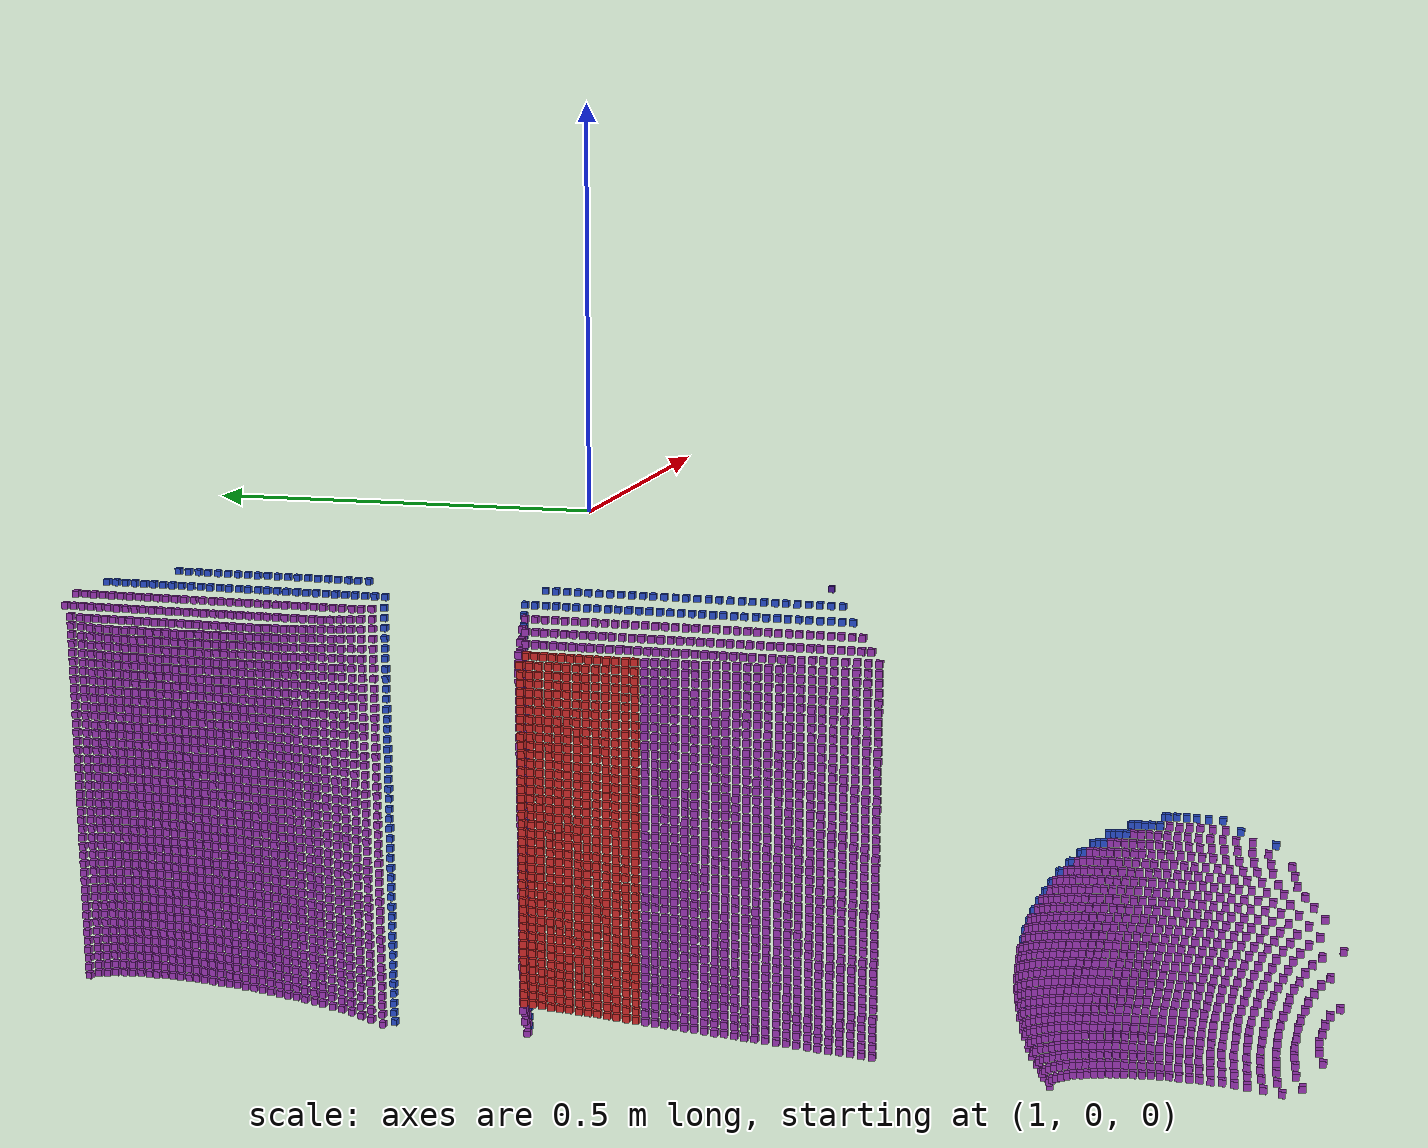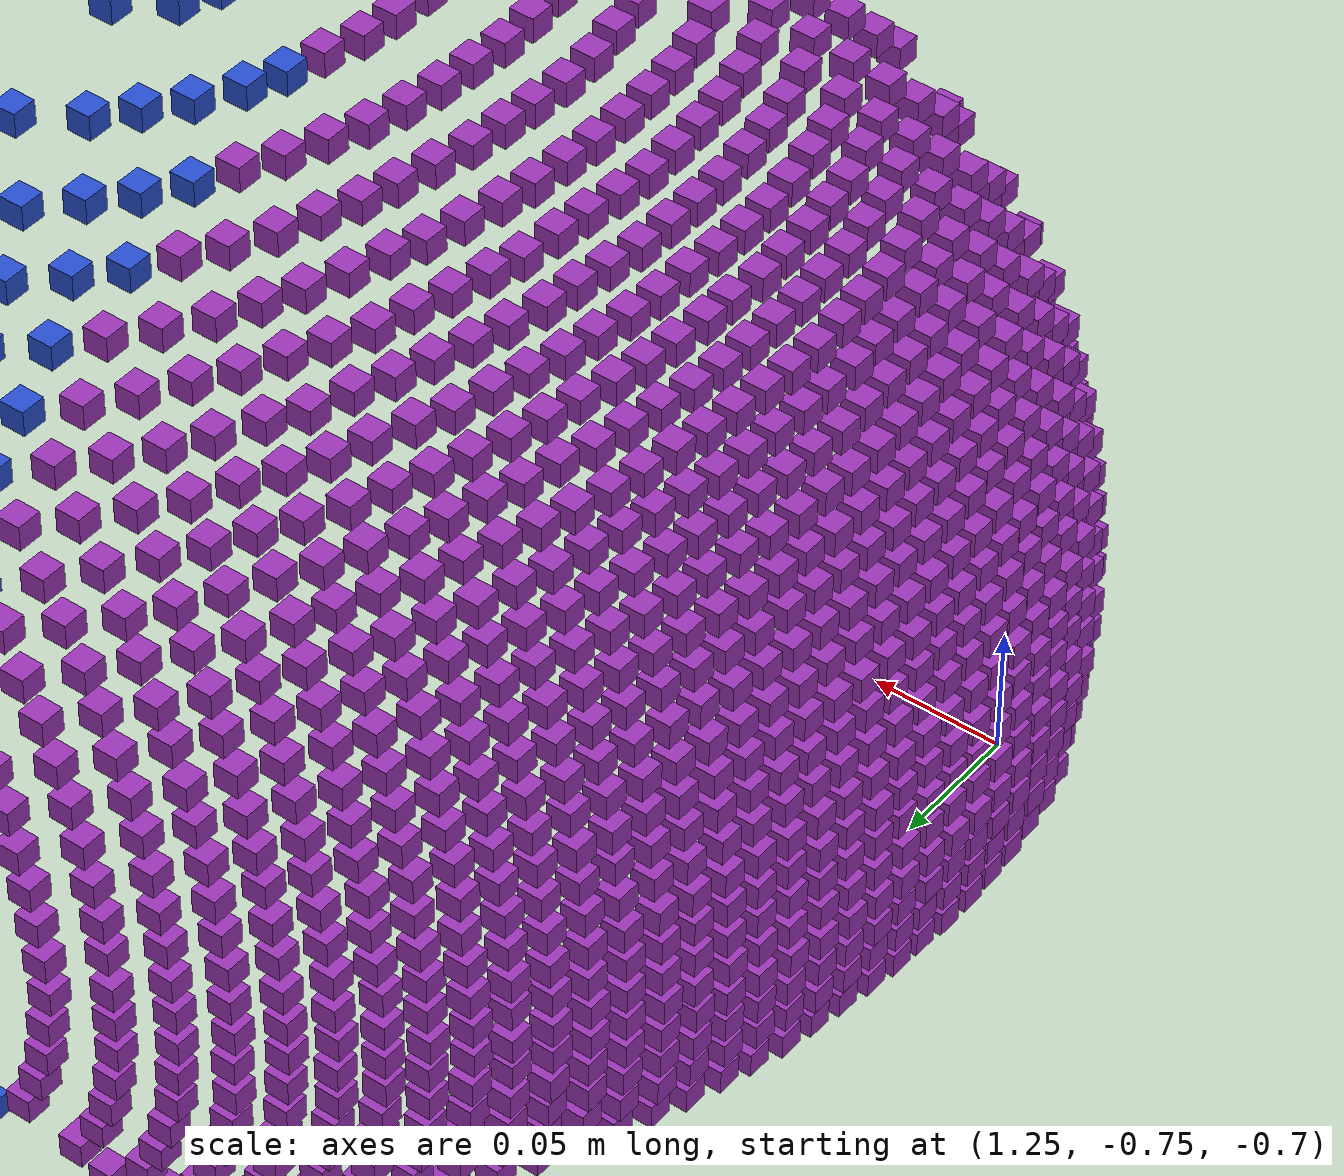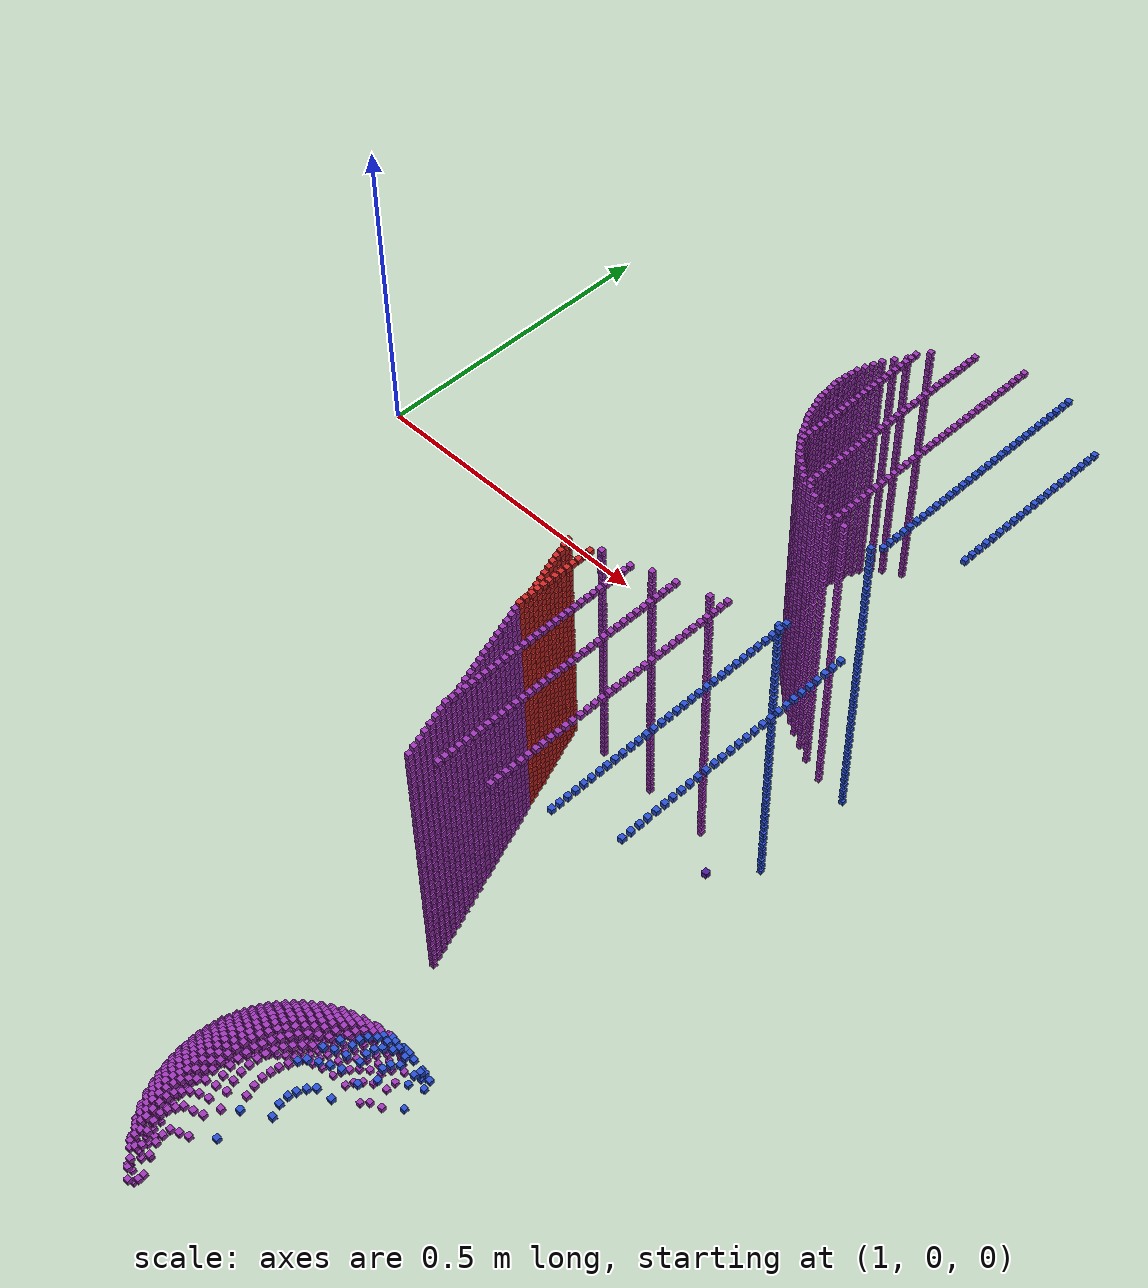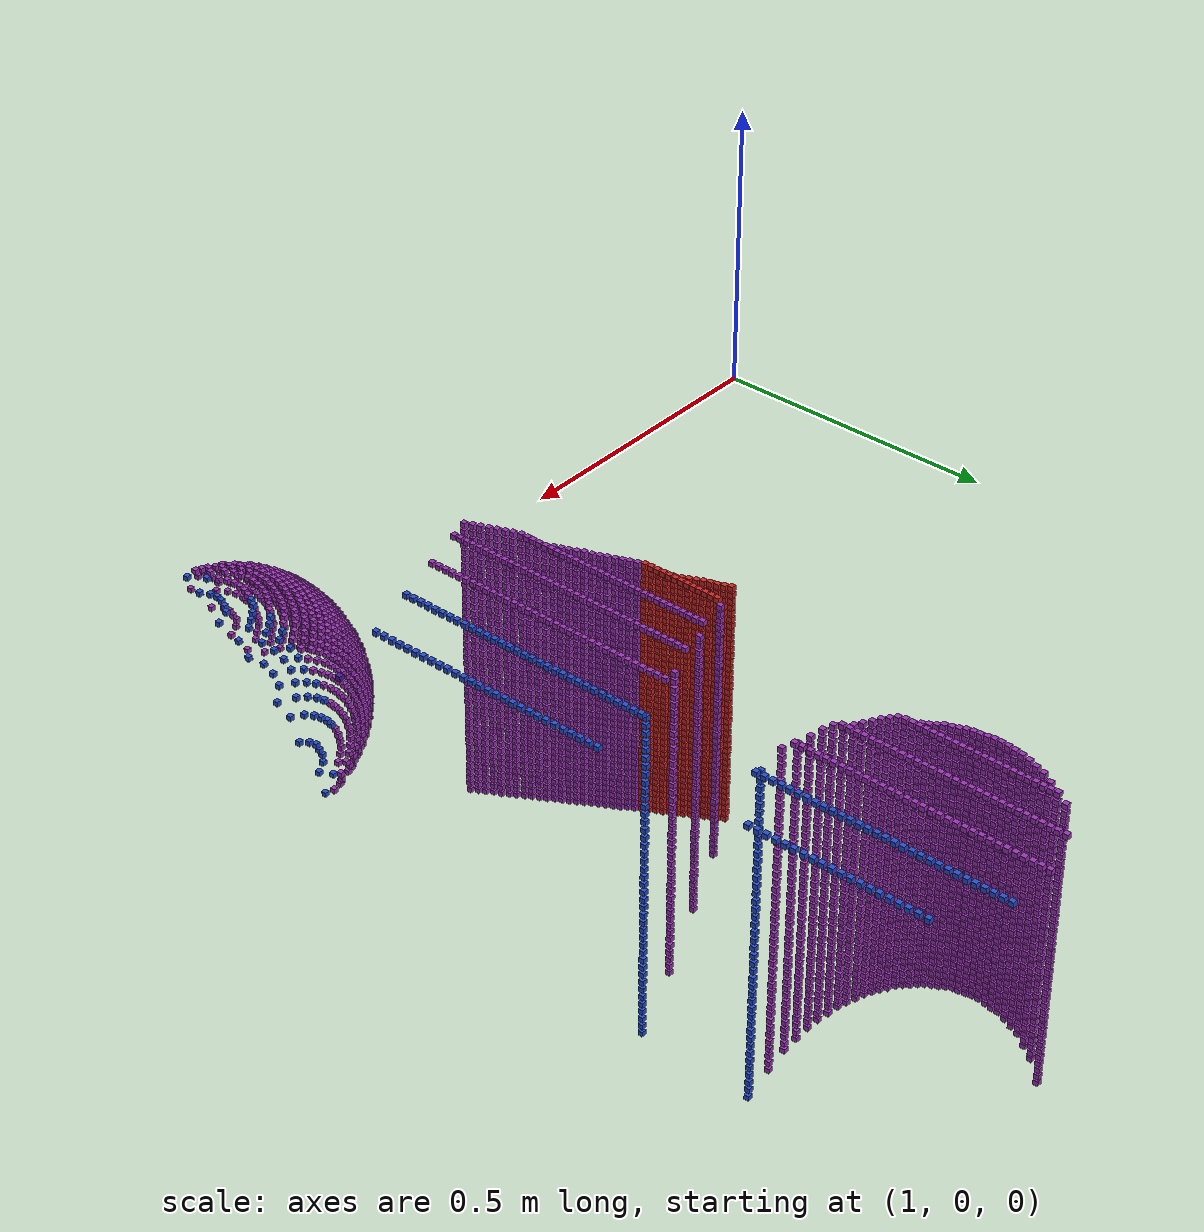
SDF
<?xml version="1.0" ?>
<sdf version="1.5">
<model name="3dprint">
<static>true</static>
<link name="link">

<collision name="p0c"><pose>1.816 -0.155 -0.250 0 0 0</pose>
<geometry><box><size>0.01 0.01 0.01</size></box></geometry>
</collision>
<visual name="p0v"><pose>1.816 -0.155 -0.250 0 0 0</pose>
<geometry><box><size>0.01 0.01 0.01</size></box></geometry>
<material><script><uri>file://media/materials/scripts/gazebo.material</uri>
<name>Gazebo/Indigo</name></script></material>
</visual>

<collision name="p1c"><pose>1.687 0.917 -0.250 0 0 0</pose>
<geometry><box><size>0.01 0.01 0.01</size></box></geometry>
</collision>
<visual name="p1v"><pose>1.687 0.917 -0.250 0 0 0</pose>
<geometry><box><size>0.01 0.01 0.01</size></box></geometry>
<material><script><uri>file://media/materials/scripts/gazebo.material</uri>
<name>Gazebo/Blue</name></script></material>
</visual>

<collision name="p2c"><pose>1.687 0.899 -0.250 0 0 0</pose>
<geometry><box><size>0.01 0.01 0.01</size></box></geometry>
</collision>
<visual name="p2v"><pose>1.687 0.899 -0.250 0 0 0</pose>
<geometry><box><size>0.01 0.01 0.01</size></box></geometry>
<material><script><uri>file://media/materials/scripts/gazebo.material</uri>
<name>Gazebo/Blue</name></script></material>
</visual>

<collision name="p3c"><pose>1.687 0.881 -0.250 0 0 0</pose>
<geometry><box><size>0.01 0.01 0.01</size></box></geometry>
</collision>
<visual name="p3v"><pose>1.687 0.881 -0.250 0 0 0</pose>
<geometry><box><size>0.01 0.01 0.01</size></box></geometry>
<material><script><uri>file://media/materials/scripts/gazebo.material</uri>
<name>Gazebo/Blue</name></script></material>
</visual>

<collision name="p4c"><pose>1.687 0.864 -0.250 0 0 0</pose>
<geometry><box><size>0.01 0.01 0.01</size></box></geometry>
</collision>
<visual name="p4v"><pose>1.687 0.864 -0.250 0 0 0</pose>
<geometry><box><size>0.01 0.01 0.01</size></box></geometry>
<material><script><uri>file://media/materials/scripts/gazebo.material</uri>
<name>Gazebo/Blue</name></script></material>
</visual>

<collision name="p5c"><pose>1.687 0.846 -0.250 0 0 0</pose>
<geometry><box><size>0.01 0.01 0.01</size></box></geometry>
</collision>
<visual name="p5v"><pose>1.687 0.846 -0.250 0 0 0</pose>
<geometry><box><size>0.01 0.01 0.01</size></box></geometry>
<material><script><uri>file://media/materials/scripts/gazebo.material</uri>
<name>Gazebo/Blue</name></script></material>
</visual>

<collision name="p6c"><pose>1.687 0.828 -0.250 0 0 0</pose>
<geometry><box><size>0.01 0.01 0.01</size></box></geometry>
</collision>
<visual name="p6v"><pose>1.687 0.828 -0.250 0 0 0</pose>
<geometry><box><size>0.01 0.01 0.01</size></box></geometry>
<material><script><uri>file://media/materials/scripts/gazebo.material</uri>
<name>Gazebo/Blue</name></script></material>
</visual>

<collision name="p7c"><pose>1.687 0.811 -0.250 0 0 0</pose>
<geometry><box><size>0.01 0.01 0.01</size></box></geometry>
</collision>
<visual name="p7v"><pose>1.687 0.811 -0.250 0 0 0</pose>
<geometry><box><size>0.01 0.01 0.01</size></box></geometry>
<material><script><uri>file://media/materials/scripts/gazebo.material</uri>
<name>Gazebo/Blue</name></script></material>
</visual>

<collision name="p8c"><pose>1.687 0.793 -0.250 0 0 0</pose>
<geometry><box><size>0.01 0.01 0.01</size></box></geometry>
</collision>
<visual name="p8v"><pose>1.687 0.793 -0.250 0 0 0</pose>
<geometry><box><size>0.01 0.01 0.01</size></box></geometry>
<material><script><uri>file://media/materials/scripts/gazebo.material</uri>
<name>Gazebo/Blue</name></script></material>
</visual>

<collision name="p9c"><pose>1.687 0.775 -0.250 0 0 0</pose>
<geometry><box><size>0.01 0.01 0.01</size></box></geometry>
</collision>
<visual name="p9v"><pose>1.687 0.775 -0.250 0 0 0</pose>
<geometry><box><size>0.01 0.01 0.01</size></box></geometry>
<material><script><uri>file://media/materials/scripts/gazebo.material</uri>
<name>Gazebo/Blue</name></script></material>
</visual>

<collision name="p10c"><pose>1.687 0.758 -0.250 0 0 0</pose>
<geometry><box><size>0.01 0.01 0.01</size></box></geometry>
</collision>
<visual name="p10v"><pose>1.687 0.758 -0.250 0 0 0</pose>
<geometry><box><size>0.01 0.01 0.01</size></box></geometry>
<material><script><uri>file://media/materials/scripts/gazebo.material</uri>
<name>Gazebo/Blue</name></script></material>
</visual>

<collision name="p11c"><pose>1.687 0.740 -0.250 0 0 0</pose>
<geometry><box><size>0.01 0.01 0.01</size></box></geometry>
</collision>
<visual name="p11v"><pose>1.687 0.740 -0.250 0 0 0</pose>
<geometry><box><size>0.01 0.01 0.01</size></box></geometry>
<material><script><uri>file://media/materials/scripts/gazebo.material</uri>
<name>Gazebo/Blue</name></script></material>
</visual>

<collision name="p12c"><pose>1.687 0.722 -0.250 0 0 0</pose>
<geometry><box><size>0.01 0.01 0.01</size></box></geometry>
</collision>
<visual name="p12v"><pose>1.687 0.722 -0.250 0 0 0</pose>
<geometry><box><size>0.01 0.01 0.01</size></box></geometry>
<material><script><uri>file://media/materials/scripts/gazebo.material</uri>
<name>Gazebo/Blue</name></script></material>
</visual>

<collision name="p13c"><pose>1.687 0.705 -0.250 0 0 0</pose>
<geometry><box><size>0.01 0.01 0.01</size></box></geometry>
</collision>
<visual name="p13v"><pose>1.687 0.705 -0.250 0 0 0</pose>
<geometry><box><size>0.01 0.01 0.01</size></box></geometry>
<material><script><uri>file://media/materials/scripts/gazebo.material</uri>
<name>Gazebo/Blue</name></script></material>
</visual>

<collision name="p14c"><pose>1.687 0.687 -0.250 0 0 0</pose>
<geometry><box><size>0.01 0.01 0.01</size></box></geometry>
</collision>
<visual name="p14v"><pose>1.687 0.687 -0.250 0 0 0</pose>
<geometry><box><size>0.01 0.01 0.01</size></box></geometry>
<material><script><uri>file://media/materials/scripts/gazebo.material</uri>
<name>Gazebo/Blue</name></script></material>
</visual>

<collision name="p15c"><pose>1.687 0.669 -0.250 0 0 0</pose>
<geometry><box><size>0.01 0.01 0.01</size></box></geometry>
</collision>
<visual name="p15v"><pose>1.687 0.669 -0.250 0 0 0</pose>
<geometry><box><size>0.01 0.01 0.01</size></box></geometry>
<material><script><uri>file://media/materials/scripts/gazebo.material</uri>
<name>Gazebo/Blue</name></script></material>
</visual>

<collision name="p16c"><pose>1.687 0.652 -0.250 0 0 0</pose>
<geometry><box><size>0.01 0.01 0.01</size></box></geometry>
</collision>
<visual name="p16v"><pose>1.687 0.652 -0.250 0 0 0</pose>
<geometry><box><size>0.01 0.01 0.01</size></box></geometry>
<material><script><uri>file://media/materials/scripts/gazebo.material</uri>
<name>Gazebo/Blue</name></script></material>
</visual>

<collision name="p17c"><pose>1.687 0.634 -0.250 0 0 0</pose>
<geometry><box><size>0.01 0.01 0.01</size></box></geometry>
</collision>
<visual name="p17v"><pose>1.687 0.634 -0.250 0 0 0</pose>
<geometry><box><size>0.01 0.01 0.01</size></box></geometry>
<material><script><uri>file://media/materials/scripts/gazebo.material</uri>
<name>Gazebo/Blue</name></script></material>
</visual>

<collision name="p18c"><pose>1.687 0.616 -0.250 0 0 0</pose>
<geometry><box><size>0.01 0.01 0.01</size></box></geometry>
</collision>
<visual name="p18v"><pose>1.687 0.616 -0.250 0 0 0</pose>
<geometry><box><size>0.01 0.01 0.01</size></box></geometry>
<material><script><uri>file://media/materials/scripts/gazebo.material</uri>
<name>Gazebo/Blue</name></script></material>
</visual>

<collision name="p19c"><pose>1.687 0.599 -0.250 0 0 0</pose>
<geometry><box><size>0.01 0.01 0.01</size></box></geometry>
</collision>
<visual name="p19v"><pose>1.687 0.599 -0.250 0 0 0</pose>
<geometry><box><size>0.01 0.01 0.01</size></box></geometry>
<material><script><uri>file://media/materials/scripts/gazebo.material</uri>
<name>Gazebo/Blue</name></script></material>
</visual>

<collision name="p20c"><pose>1.687 0.581 -0.250 0 0 0</pose>
<geometry><box><size>0.01 0.01 0.01</size></box></geometry>
</collision>
<visual name="p20v"><pose>1.687 0.581 -0.250 0 0 0</pose>
<geometry><box><size>0.01 0.01 0.01</size></box></geometry>
<material><script><uri>file://media/materials/scripts/gazebo.material</uri>
<name>Gazebo/Blue</name></script></material>
</visual>

<collision name="p21c"><pose>1.687 0.281 -0.250 0 0 0</pose>
<geometry><box><size>0.01 0.01 0.01</size></box></geometry>
</collision>
<visual name="p21v"><pose>1.687 0.281 -0.250 0 0 0</pose>
<geometry><box><size>0.01 0.01 0.01</size></box></geometry>
<material><script><uri>file://media/materials/scripts/gazebo.material</uri>
<name>Gazebo/Blue</name></script></material>
</visual>

<collision name="p22c"><pose>1.687 0.263 -0.250 0 0 0</pose>
<geometry><box><size>0.01 0.01 0.01</size></box></geometry>
</collision>
<visual name="p22v"><pose>1.687 0.263 -0.250 0 0 0</pose>
<geometry><box><size>0.01 0.01 0.01</size></box></geometry>
<material><script><uri>file://media/materials/scripts/gazebo.material</uri>
<name>Gazebo/Blue</name></script></material>
</visual>

<collision name="p23c"><pose>1.687 0.245 -0.250 0 0 0</pose>
<geometry><box><size>0.01 0.01 0.01</size></box></geometry>
</collision>
<visual name="p23v"><pose>1.687 0.245 -0.250 0 0 0</pose>
<geometry><box><size>0.01 0.01 0.01</size></box></geometry>
<material><script><uri>file://media/materials/scripts/gazebo.material</uri>
<name>Gazebo/Blue</name></script></material>
</visual>

<collision name="p24c"><pose>1.687 0.227 -0.250 0 0 0</pose>
<geometry><box><size>0.01 0.01 0.01</size></box></geometry>
</collision>
<visual name="p24v"><pose>1.687 0.227 -0.250 0 0 0</pose>
<geometry><box><size>0.01 0.01 0.01</size></box></geometry>
<material><script><uri>file://media/materials/scripts/gazebo.material</uri>
<name>Gazebo/Blue</name></script></material>
</visual>

<collision name="p25c"><pose>1.687 0.210 -0.250 0 0 0</pose>
<geometry><box><size>0.01 0.01 0.01</size></box></geometry>
</collision>
<visual name="p25v"><pose>1.687 0.210 -0.250 0 0 0</pose>
<geometry><box><size>0.01 0.01 0.01</size></box></geometry>
<material><script><uri>file://media/materials/scripts/gazebo.material</uri>
<name>Gazebo/Blue</name></script></material>
</visual>

<collision name="p26c"><pose>1.687 0.192 -0.250 0 0 0</pose>
<geometry><box><size>0.01 0.01 0.01</size></box></geometry>
</collision>
<visual name="p26v"><pose>1.687 0.192 -0.250 0 0 0</pose>
<geometry><box><size>0.01 0.01 0.01</size></box></geometry>
<material><script><uri>file://media/materials/scripts/gazebo.material</uri>
<name>Gazebo/Blue</name></script></material>
</visual>

<collision name="p27c"><pose>1.687 0.174 -0.250 0 0 0</pose>
<geometry><box><size>0.01 0.01 0.01</size></box></geometry>
</collision>
<visual name="p27v"><pose>1.687 0.174 -0.250 0 0 0</pose>
<geometry><box><size>0.01 0.01 0.01</size></box></geometry>
<material><script><uri>file://media/materials/scripts/gazebo.material</uri>
<name>Gazebo/Blue</name></script></material>
</visual>

<collision name="p28c"><pose>1.687 0.157 -0.250 0 0 0</pose>
<geometry><box><size>0.01 0.01 0.01</size></box></geometry>
</collision>
<visual name="p28v"><pose>1.687 0.157 -0.250 0 0 0</pose>
<geometry><box><size>0.01 0.01 0.01</size></box></geometry>
<material><script><uri>file://media/materials/scripts/gazebo.material</uri>
<name>Gazebo/Blue</name></script></material>
</visual>

<collision name="p29c"><pose>1.687 0.139 -0.250 0 0 0</pose>
<geometry><box><size>0.01 0.01 0.01</size></box></geometry>
</collision>
<visual name="p29v"><pose>1.687 0.139 -0.250 0 0 0</pose>
<geometry><box><size>0.01 0.01 0.01</size></box></geometry>
<material><script><uri>file://media/materials/scripts/gazebo.material</uri>
<name>Gazebo/Blue</name></script></material>
</visual>

<collision name="p30c"><pose>1.687 0.121 -0.250 0 0 0</pose>
<geometry><box><size>0.01 0.01 0.01</size></box></geometry>
</collision>
<visual name="p30v"><pose>1.687 0.121 -0.250 0 0 0</pose>
<geometry><box><size>0.01 0.01 0.01</size></box></geometry>
<material><script><uri>file://media/materials/scripts/gazebo.material</uri>
<name>Gazebo/Blue</name></script></material>
</visual>

<collision name="p31c"><pose>1.687 0.104 -0.250 0 0 0</pose>
<geometry><box><size>0.01 0.01 0.01</size></box></geometry>
</collision>
<visual name="p31v"><pose>1.687 0.104 -0.250 0 0 0</pose>
<geometry><box><size>0.01 0.01 0.01</size></box></geometry>
<material><script><uri>file://media/materials/scripts/gazebo.material</uri>
<name>Gazebo/Blue</name></script></material>
</visual>

<collision name="p32c"><pose>1.687 0.086 -0.250 0 0 0</pose>
<geometry><box><size>0.01 0.01 0.01</size></box></geometry>
</collision>
<visual name="p32v"><pose>1.687 0.086 -0.250 0 0 0</pose>
<geometry><box><size>0.01 0.01 0.01</size></box></geometry>
<material><script><uri>file://media/materials/scripts/gazebo.material</uri>
<name>Gazebo/Blue</name></script></material>
</visual>

<collision name="p33c"><pose>1.687 0.068 -0.250 0 0 0</pose>
<geometry><box><size>0.01 0.01 0.01</size></box></geometry>
</collision>
<visual name="p33v"><pose>1.687 0.068 -0.250 0 0 0</pose>
<geometry><box><size>0.01 0.01 0.01</size></box></geometry>
<material><script><uri>file://media/materials/scripts/gazebo.material</uri>
<name>Gazebo/Blue</name></script></material>
</visual>

<collision name="p34c"><pose>1.687 0.051 -0.250 0 0 0</pose>
<geometry><box><size>0.01 0.01 0.01</size></box></geometry>
</collision>
<visual name="p34v"><pose>1.687 0.051 -0.250 0 0 0</pose>
<geometry><box><size>0.01 0.01 0.01</size></box></geometry>
<material><script><uri>file://media/materials/scripts/gazebo.material</uri>
<name>Gazebo/Blue</name></script></material>
</visual>

<collision name="p35c"><pose>1.687 0.033 -0.250 0 0 0</pose>
<geometry><box><size>0.01 0.01 0.01</size></box></geometry>
</collision>
<visual name="p35v"><pose>1.687 0.033 -0.250 0 0 0</pose>
<geometry><box><size>0.01 0.01 0.01</size></box></geometry>
<material><script><uri>file://media/materials/scripts/gazebo.material</uri>
<name>Gazebo/Blue</name></script></material>
</visual>

<collision name="p36c"><pose>1.687 0.015 -0.250 0 0 0</pose>
<geometry><box><size>0.01 0.01 0.01</size></box></geometry>
</collision>
<visual name="p36v"><pose>1.687 0.015 -0.250 0 0 0</pose>
<geometry><box><size>0.01 0.01 0.01</size></box></geometry>
<material><script><uri>file://media/materials/scripts/gazebo.material</uri>
<name>Gazebo/Blue</name></script></material>
</visual>

<collision name="p37c"><pose>1.687 -0.002 -0.250 0 0 0</pose>
<geometry><box><size>0.01 0.01 0.01</size></box></geometry>
</collision>
<visual name="p37v"><pose>1.687 -0.002 -0.250 0 0 0</pose>
<geometry><box><size>0.01 0.01 0.01</size></box></geometry>
<material><script><uri>file://media/materials/scripts/gazebo.material</uri>
<name>Gazebo/Blue</name></script></material>
</visual>

<collision name="p38c"><pose>1.687 -0.020 -0.250 0 0 0</pose>
<geometry><box><size>0.01 0.01 0.01</size></box></geometry>
</collision>
<visual name="p38v"><pose>1.687 -0.020 -0.250 0 0 0</pose>
<geometry><box><size>0.01 0.01 0.01</size></box></geometry>
<material><script><uri>file://media/materials/scripts/gazebo.material</uri>
<name>Gazebo/Blue</name></script></material>
</visual>

<collision name="p39c"><pose>1.687 -0.038 -0.250 0 0 0</pose>
<geometry><box><size>0.01 0.01 0.01</size></box></geometry>
</collision>
<visual name="p39v"><pose>1.687 -0.038 -0.250 0 0 0</pose>
<geometry><box><size>0.01 0.01 0.01</size></box></geometry>
<material><script><uri>file://media/materials/scripts/gazebo.material</uri>
<name>Gazebo/Blue</name></script></material>
</visual>

<collision name="p40c"><pose>1.687 -0.055 -0.250 0 0 0</pose>
<geometry><box><size>0.01 0.01 0.01</size></box></geometry>
</collision>
<visual name="p40v"><pose>1.687 -0.055 -0.250 0 0 0</pose>
<geometry><box><size>0.01 0.01 0.01</size></box></geometry>
<material><script><uri>file://media/materials/scripts/gazebo.material</uri>
<name>Gazebo/Blue</name></script></material>
</visual>

<collision name="p41c"><pose>1.687 -0.073 -0.250 0 0 0</pose>
<geometry><box><size>0.01 0.01 0.01</size></box></geometry>
</collision>
<visual name="p41v"><pose>1.687 -0.073 -0.250 0 0 0</pose>
<geometry><box><size>0.01 0.01 0.01</size></box></geometry>
<material><script><uri>file://media/materials/scripts/gazebo.material</uri>
<name>Gazebo/Blue</name></script></material>
</visual>

<collision name="p42c"><pose>1.687 -0.091 -0.250 0 0 0</pose>
<geometry><box><size>0.01 0.01 0.01</size></box></geometry>
</collision>
<visual name="p42v"><pose>1.687 -0.091 -0.250 0 0 0</pose>
<geometry><box><size>0.01 0.01 0.01</size></box></geometry>
<material><script><uri>file://media/materials/scripts/gazebo.material</uri>
<name>Gazebo/Blue</name></script></material>
</visual>

<collision name="p43c"><pose>1.687 -0.108 -0.250 0 0 0</pose>
<geometry><box><size>0.01 0.01 0.01</size></box></geometry>
</collision>
<visual name="p43v"><pose>1.687 -0.108 -0.250 0 0 0</pose>
<geometry><box><size>0.01 0.01 0.01</size></box></geometry>
<material><script><uri>file://media/materials/scripts/gazebo.material</uri>
<name>Gazebo/Blue</name></script></material>
</visual>

<collision name="p44c"><pose>1.687 -0.126 -0.250 0 0 0</pose>
<geometry><box><size>0.01 0.01 0.01</size></box></geometry>
</collision>
<visual name="p44v"><pose>1.687 -0.126 -0.250 0 0 0</pose>
<geometry><box><size>0.01 0.01 0.01</size></box></geometry>
<material><script><uri>file://media/materials/scripts/gazebo.material</uri>
<name>Gazebo/Blue</name></script></material>
</visual>

<collision name="p45c"><pose>1.687 -0.144 -0.250 0 0 0</pose>
<geometry><box><size>0.01 0.01 0.01</size></box></geometry>
</collision>
<visual name="p45v"><pose>1.687 -0.144 -0.250 0 0 0</pose>
<geometry><box><size>0.01 0.01 0.01</size></box></geometry>
<material><script><uri>file://media/materials/scripts/gazebo.material</uri>
<name>Gazebo/Blue</name></script></material>
</visual>

<collision name="p46c"><pose>1.687 -0.161 -0.250 0 0 0</pose>
<geometry><box><size>0.01 0.01 0.01</size></box></geometry>
</collision>
<visual name="p46v"><pose>1.687 -0.161 -0.250 0 0 0</pose>
<geometry><box><size>0.01 0.01 0.01</size></box></geometry>
<material><script><uri>file://media/materials/scripts/gazebo.material</uri>
<name>Gazebo/Blue</name></script></material>
</visual>

<collision name="p47c"><pose>1.687 -0.179 -0.250 0 0 0</pose>
<geometry><box><size>0.01 0.01 0.01</size></box></geometry>
</collision>
<visual name="p47v"><pose>1.687 -0.179 -0.250 0 0 0</pose>
<geometry><box><size>0.01 0.01 0.01</size></box></geometry>
<material><script><uri>file://media/materials/scripts/gazebo.material</uri>
<name>Gazebo/Blue</name></script></material>
</visual>

<collision name="p48c"><pose>1.687 -0.197 -0.250 0 0 0</pose>
<geometry><box><size>0.01 0.01 0.01</size></box></geometry>
</collision>
<visual name="p48v"><pose>1.687 -0.197 -0.250 0 0 0</pose>
<geometry><box><size>0.01 0.01 0.01</size></box></geometry>
<material><script><uri>file://media/materials/scripts/gazebo.material</uri>
<name>Gazebo/Blue</name></script></material>
</visual>

<collision name="p49c"><pose>1.576 0.988 -0.250 0 0 0</pose>
<geometry><box><size>0.01 0.01 0.01</size></box></geometry>
</collision>
<visual name="p49v"><pose>1.576 0.988 -0.250 0 0 0</pose>
<geometry><box><size>0.01 0.01 0.01</size></box></geometry>
<material><script><uri>file://media/materials/scripts/gazebo.material</uri>
<name>Gazebo/Blue</name></script></material>
</visual>

<collision name="p50c"><pose>1.576 0.972 -0.250 0 0 0</pose>
<geometry><box><size>0.01 0.01 0.01</size></box></geometry>
</collision>
<visual name="p50v"><pose>1.576 0.972 -0.250 0 0 0</pose>
<geometry><box><size>0.01 0.01 0.01</size></box></geometry>
<material><script><uri>file://media/materials/scripts/gazebo.material</uri>
<name>Gazebo/Blue</name></script></material>
</visual>

<collision name="p51c"><pose>1.576 0.955 -0.250 0 0 0</pose>
<geometry><box><size>0.01 0.01 0.01</size></box></geometry>
</collision>
<visual name="p51v"><pose>1.576 0.955 -0.250 0 0 0</pose>
<geometry><box><size>0.01 0.01 0.01</size></box></geometry>
<material><script><uri>file://media/materials/scripts/gazebo.material</uri>
<name>Gazebo/Blue</name></script></material>
</visual>

<collision name="p52c"><pose>1.576 0.939 -0.250 0 0 0</pose>
<geometry><box><size>0.01 0.01 0.01</size></box></geometry>
</collision>
<visual name="p52v"><pose>1.576 0.939 -0.250 0 0 0</pose>
<geometry><box><size>0.01 0.01 0.01</size></box></geometry>
<material><script><uri>file://media/materials/scripts/gazebo.material</uri>
<name>Gazebo/Blue</name></script></material>
</visual>

<collision name="p53c"><pose>1.576 0.922 -0.250 0 0 0</pose>
<geometry><box><size>0.01 0.01 0.01</size></box></geometry>
</collision>
<visual name="p53v"><pose>1.576 0.922 -0.250 0 0 0</pose>
<geometry><box><size>0.01 0.01 0.01</size></box></geometry>
<material><script><uri>file://media/materials/scripts/gazebo.material</uri>
<name>Gazebo/Blue</name></script></material>
</visual>

<collision name="p54c"><pose>1.576 0.906 -0.250 0 0 0</pose>
<geometry><box><size>0.01 0.01 0.01</size></box></geometry>
</collision>
<visual name="p54v"><pose>1.576 0.906 -0.250 0 0 0</pose>
<geometry><box><size>0.01 0.01 0.01</size></box></geometry>
<material><script><uri>file://media/materials/scripts/gazebo.material</uri>
<name>Gazebo/Blue</name></script></material>
</visual>

<collision name="p55c"><pose>1.576 0.889 -0.250 0 0 0</pose>
<geometry><box><size>0.01 0.01 0.01</size></box></geometry>
</collision>
<visual name="p55v"><pose>1.576 0.889 -0.250 0 0 0</pose>
<geometry><box><size>0.01 0.01 0.01</size></box></geometry>
<material><script><uri>file://media/materials/scripts/gazebo.material</uri>
<name>Gazebo/Blue</name></script></material>
</visual>

<collision name="p56c"><pose>1.576 0.873 -0.250 0 0 0</pose>
<geometry><box><size>0.01 0.01 0.01</size></box></geometry>
</collision>
<visual name="p56v"><pose>1.576 0.873 -0.250 0 0 0</pose>
<geometry><box><size>0.01 0.01 0.01</size></box></geometry>
<material><script><uri>file://media/materials/scripts/gazebo.material</uri>
<name>Gazebo/Blue</name></script></material>
</visual>

<collision name="p57c"><pose>1.576 0.856 -0.250 0 0 0</pose>
<geometry><box><size>0.01 0.01 0.01</size></box></geometry>
</collision>
<visual name="p57v"><pose>1.576 0.856 -0.250 0 0 0</pose>
<geometry><box><size>0.01 0.01 0.01</size></box></geometry>
<material><script><uri>file://media/materials/scripts/gazebo.material</uri>
<name>Gazebo/Blue</name></script></material>
</visual>

<collision name="p58c"><pose>1.576 0.840 -0.250 0 0 0</pose>
<geometry><box><size>0.01 0.01 0.01</size></box></geometry>
</collision>
<visual name="p58v"><pose>1.576 0.840 -0.250 0 0 0</pose>
<geometry><box><size>0.01 0.01 0.01</size></box></geometry>
<material><script><uri>file://media/materials/scripts/gazebo.material</uri>
<name>Gazebo/Blue</name></script></material>
</visual>

<collision name="p59c"><pose>1.576 0.823 -0.250 0 0 0</pose>
<geometry><box><size>0.01 0.01 0.01</size></box></geometry>
</collision>
<visual name="p59v"><pose>1.576 0.823 -0.250 0 0 0</pose>
<geometry><box><size>0.01 0.01 0.01</size></box></geometry>
<material><script><uri>file://media/materials/scripts/gazebo.material</uri>
<name>Gazebo/Blue</name></script></material>
</visual>

<collision name="p60c"><pose>1.576 0.807 -0.250 0 0 0</pose>
<geometry><box><size>0.01 0.01 0.01</size></box></geometry>
</collision>
<visual name="p60v"><pose>1.576 0.807 -0.250 0 0 0</pose>
<geometry><box><size>0.01 0.01 0.01</size></box></geometry>
<material><script><uri>file://media/materials/scripts/gazebo.material</uri>
<name>Gazebo/Blue</name></script></material>
</visual>

<collision name="p61c"><pose>1.576 0.790 -0.250 0 0 0</pose>
<geometry><box><size>0.01 0.01 0.01</size></box></geometry>
</collision>
<visual name="p61v"><pose>1.576 0.790 -0.250 0 0 0</pose>
<geometry><box><size>0.01 0.01 0.01</size></box></geometry>
<material><script><uri>file://media/materials/scripts/gazebo.material</uri>
<name>Gazebo/Blue</name></script></material>
</visual>

<collision name="p62c"><pose>1.576 0.774 -0.250 0 0 0</pose>
<geometry><box><size>0.01 0.01 0.01</size></box></geometry>
</collision>
<visual name="p62v"><pose>1.576 0.774 -0.250 0 0 0</pose>
<geometry><box><size>0.01 0.01 0.01</size></box></geometry>
<material><script><uri>file://media/materials/scripts/gazebo.material</uri>
<name>Gazebo/Blue</name></script></material>
</visual>

<collision name="p63c"><pose>1.576 0.757 -0.250 0 0 0</pose>
<geometry><box><size>0.01 0.01 0.01</size></box></geometry>
</collision>
<visual name="p63v"><pose>1.576 0.757 -0.250 0 0 0</pose>
<geometry><box><size>0.01 0.01 0.01</size></box></geometry>
<material><script><uri>file://media/materials/scripts/gazebo.material</uri>
<name>Gazebo/Blue</name></script></material>
</visual>

<collision name="p64c"><pose>1.576 0.741 -0.250 0 0 0</pose>
<geometry><box><size>0.01 0.01 0.01</size></box></geometry>
</collision>
<visual name="p64v"><pose>1.576 0.741 -0.250 0 0 0</pose>
<geometry><box><size>0.01 0.01 0.01</size></box></geometry>
<material><script><uri>file://media/materials/scripts/gazebo.material</uri>
<name>Gazebo/Blue</name></script></material>
</visual>

<collision name="p65c"><pose>1.576 0.724 -0.250 0 0 0</pose>
<geometry><box><size>0.01 0.01 0.01</size></box></geometry>
</collision>
<visual name="p65v"><pose>1.576 0.724 -0.250 0 0 0</pose>
<geometry><box><size>0.01 0.01 0.01</size></box></geometry>
<material><script><uri>file://media/materials/scripts/gazebo.material</uri>
<name>Gazebo/Blue</name></script></material>
</visual>

<collision name="p66c"><pose>1.576 0.708 -0.250 0 0 0</pose>
<geometry><box><size>0.01 0.01 0.01</size></box></geometry>
</collision>
<visual name="p66v"><pose>1.576 0.708 -0.250 0 0 0</pose>
<geometry><box><size>0.01 0.01 0.01</size></box></geometry>
<material><script><uri>file://media/materials/scripts/gazebo.material</uri>
<name>Gazebo/Blue</name></script></material>
</visual>

<collision name="p67c"><pose>1.576 0.691 -0.250 0 0 0</pose>
<geometry><box><size>0.01 0.01 0.01</size></box></geometry>
</collision>
<visual name="p67v"><pose>1.576 0.691 -0.250 0 0 0</pose>
<geometry><box><size>0.01 0.01 0.01</size></box></geometry>
<material><script><uri>file://media/materials/scripts/gazebo.material</uri>
<name>Gazebo/Blue</name></script></material>
</visual>

<collision name="p68c"><pose>1.576 0.675 -0.250 0 0 0</pose>
<geometry><box><size>0.01 0.01 0.01</size></box></geometry>
</collision>
<visual name="p68v"><pose>1.576 0.675 -0.250 0 0 0</pose>
<geometry><box><size>0.01 0.01 0.01</size></box></geometry>
<material><script><uri>file://media/materials/scripts/gazebo.material</uri>
<name>Gazebo/Blue</name></script></material>
</visual>

<collision name="p69c"><pose>1.576 0.658 -0.250 0 0 0</pose>
<geometry><box><size>0.01 0.01 0.01</size></box></geometry>
</collision>
<visual name="p69v"><pose>1.576 0.658 -0.250 0 0 0</pose>
<geometry><box><size>0.01 0.01 0.01</size></box></geometry>
<material><script><uri>file://media/materials/scripts/gazebo.material</uri>
<name>Gazebo/Blue</name></script></material>
</visual>

<collision name="p70c"><pose>1.576 0.641 -0.250 0 0 0</pose>
<geometry><box><size>0.01 0.01 0.01</size></box></geometry>
</collision>
<visual name="p70v"><pose>1.576 0.641 -0.250 0 0 0</pose>
<geometry><box><size>0.01 0.01 0.01</size></box></geometry>
<material><script><uri>file://media/materials/scripts/gazebo.material</uri>
<name>Gazebo/Blue</name></script></material>
</visual>

<collision name="p71c"><pose>1.576 0.625 -0.250 0 0 0</pose>
<geometry><box><size>0.01 0.01 0.01</size></box></geometry>
</collision>
<visual name="p71v"><pose>1.576 0.625 -0.250 0 0 0</pose>
<geometry><box><size>0.01 0.01 0.01</size></box></geometry>
<material><script><uri>file://media/materials/scripts/gazebo.material</uri>
<name>Gazebo/Blue</name></script></material>
</visual>

<collision name="p72c"><pose>1.576 0.608 -0.250 0 0 0</pose>
<geometry><box><size>0.01 0.01 0.01</size></box></geometry>
</collision>
<visual name="p72v"><pose>1.576 0.608 -0.250 0 0 0</pose>
<geometry><box><size>0.01 0.01 0.01</size></box></geometry>
<material><script><uri>file://media/materials/scripts/gazebo.material</uri>
<name>Gazebo/Blue</name></script></material>
</visual>

<collision name="p73c"><pose>1.576 0.592 -0.250 0 0 0</pose>
<geometry><box><size>0.01 0.01 0.01</size></box></geometry>
</collision>
<visual name="p73v"><pose>1.576 0.592 -0.250 0 0 0</pose>
<geometry><box><size>0.01 0.01 0.01</size></box></geometry>
<material><script><uri>file://media/materials/scripts/gazebo.material</uri>
<name>Gazebo/Blue</name></script></material>
</visual>

<collision name="p74c"><pose>1.576 0.575 -0.250 0 0 0</pose>
<geometry><box><size>0.01 0.01 0.01</size></box></geometry>
</collision>
<visual name="p74v"><pose>1.576 0.575 -0.250 0 0 0</pose>
<geometry><box><size>0.01 0.01 0.01</size></box></geometry>
<material><script><uri>file://media/materials/scripts/gazebo.material</uri>
<name>Gazebo/Blue</name></script></material>
</visual>

<collision name="p75c"><pose>1.576 0.559 -0.250 0 0 0</pose>
<geometry><box><size>0.01 0.01 0.01</size></box></geometry>
</collision>
<visual name="p75v"><pose>1.576 0.559 -0.250 0 0 0</pose>
<geometry><box><size>0.01 0.01 0.01</size></box></geometry>
<material><script><uri>file://media/materials/scripts/gazebo.material</uri>
<name>Gazebo/Blue</name></script></material>
</visual>

<collision name="p76c"><pose>1.576 0.542 -0.250 0 0 0</pose>
<geometry><box><size>0.01 0.01 0.01</size></box></geometry>
</collision>
<visual name="p76v"><pose>1.576 0.542 -0.250 0 0 0</pose>
<geometry><box><size>0.01 0.01 0.01</size></box></geometry>
<material><script><uri>file://media/materials/scripts/gazebo.material</uri>
<name>Gazebo/Blue</name></script></material>
</visual>

<collision name="p77c"><pose>1.576 0.526 -0.250 0 0 0</pose>
<geometry><box><size>0.01 0.01 0.01</size></box></geometry>
</collision>
<visual name="p77v"><pose>1.576 0.526 -0.250 0 0 0</pose>
<geometry><box><size>0.01 0.01 0.01</size></box></geometry>
<material><script><uri>file://media/materials/scripts/gazebo.material</uri>
<name>Gazebo/Blue</name></script></material>
</visual>

<collision name="p78c"><pose>1.576 0.509 -0.250 0 0 0</pose>
<geometry><box><size>0.01 0.01 0.01</size></box></geometry>
</collision>
<visual name="p78v"><pose>1.576 0.509 -0.250 0 0 0</pose>
<geometry><box><size>0.01 0.01 0.01</size></box></geometry>
<material><script><uri>file://media/materials/scripts/gazebo.material</uri>
<name>Gazebo/Blue</name></script></material>
</visual>

<collision name="p79c"><pose>1.576 0.278 -0.250 0 0 0</pose>
<geometry><box><size>0.01 0.01 0.01</size></box></geometry>
</collision>
<visual name="p79v"><pose>1.576 0.278 -0.250 0 0 0</pose>
<geometry><box><size>0.01 0.01 0.01</size></box></geometry>
<material><script><uri>file://media/materials/scripts/gazebo.material</uri>
<name>Gazebo/Blue</name></script></material>
</visual>

<collision name="p80c"><pose>1.576 0.262 -0.250 0 0 0</pose>
<geometry><box><size>0.01 0.01 0.01</size></box></geometry>
</collision>
<visual name="p80v"><pose>1.576 0.262 -0.250 0 0 0</pose>
<geometry><box><size>0.01 0.01 0.01</size></box></geometry>
<material><script><uri>file://media/materials/scripts/gazebo.material</uri>
<name>Gazebo/Blue</name></script></material>
</visual>

<collision name="p81c"><pose>1.576 0.245 -0.250 0 0 0</pose>
<geometry><box><size>0.01 0.01 0.01</size></box></geometry>
</collision>
<visual name="p81v"><pose>1.576 0.245 -0.250 0 0 0</pose>
<geometry><box><size>0.01 0.01 0.01</size></box></geometry>
<material><script><uri>file://media/materials/scripts/gazebo.material</uri>
<name>Gazebo/Blue</name></script></material>
</visual>

<collision name="p82c"><pose>1.576 0.229 -0.250 0 0 0</pose>
<geometry><box><size>0.01 0.01 0.01</size></box></geometry>
</collision>
<visual name="p82v"><pose>1.576 0.229 -0.250 0 0 0</pose>
<geometry><box><size>0.01 0.01 0.01</size></box></geometry>
<material><script><uri>file://media/materials/scripts/gazebo.material</uri>
<name>Gazebo/Blue</name></script></material>
</visual>

<collision name="p83c"><pose>1.576 0.212 -0.250 0 0 0</pose>
<geometry><box><size>0.01 0.01 0.01</size></box></geometry>
</collision>
<visual name="p83v"><pose>1.576 0.212 -0.250 0 0 0</pose>
<geometry><box><size>0.01 0.01 0.01</size></box></geometry>
<material><script><uri>file://media/materials/scripts/gazebo.material</uri>
<name>Gazebo/Blue</name></script></material>
</visual>

<collision name="p84c"><pose>1.576 0.196 -0.250 0 0 0</pose>
<geometry><box><size>0.01 0.01 0.01</size></box></geometry>
</collision>
<visual name="p84v"><pose>1.576 0.196 -0.250 0 0 0</pose>
<geometry><box><size>0.01 0.01 0.01</size></box></geometry>
<material><script><uri>file://media/materials/scripts/gazebo.material</uri>
<name>Gazebo/Blue</name></script></material>
</visual>

<collision name="p85c"><pose>1.576 0.179 -0.250 0 0 0</pose>
<geometry><box><size>0.01 0.01 0.01</size></box></geometry>
</collision>
<visual name="p85v"><pose>1.576 0.179 -0.250 0 0 0</pose>
<geometry><box><size>0.01 0.01 0.01</size></box></geometry>
<material><script><uri>file://media/materials/scripts/gazebo.material</uri>
<name>Gazebo/Blue</name></script></material>
</visual>

<collision name="p86c"><pose>1.576 0.163 -0.250 0 0 0</pose>
<geometry><box><size>0.01 0.01 0.01</size></box></geometry>
</collision>
<visual name="p86v"><pose>1.576 0.163 -0.250 0 0 0</pose>
<geometry><box><size>0.01 0.01 0.01</size></box></geometry>
<material><script><uri>file://media/materials/scripts/gazebo.material</uri>
<name>Gazebo/Blue</name></script></material>
</visual>

<collision name="p87c"><pose>1.576 0.146 -0.250 0 0 0</pose>
<geometry><box><size>0.01 0.01 0.01</size></box></geometry>
</collision>
<visual name="p87v"><pose>1.576 0.146 -0.250 0 0 0</pose>
<geometry><box><size>0.01 0.01 0.01</size></box></geometry>
<material><script><uri>file://media/materials/scripts/gazebo.material</uri>
<name>Gazebo/Blue</name></script></material>
</visual>

<collision name="p88c"><pose>1.576 0.130 -0.250 0 0 0</pose>
<geometry><box><size>0.01 0.01 0.01</size></box></geometry>
</collision>
<visual name="p88v"><pose>1.576 0.130 -0.250 0 0 0</pose>
<geometry><box><size>0.01 0.01 0.01</size></box></geometry>
<material><script><uri>file://media/materials/scripts/gazebo.material</uri>
<name>Gazebo/Blue</name></script></material>
</visual>

<collision name="p89c"><pose>1.576 0.113 -0.250 0 0 0</pose>
<geometry><box><size>0.01 0.01 0.01</size></box></geometry>
</collision>
<visual name="p89v"><pose>1.576 0.113 -0.250 0 0 0</pose>
<geometry><box><size>0.01 0.01 0.01</size></box></geometry>
<material><script><uri>file://media/materials/scripts/gazebo.material</uri>
<name>Gazebo/Blue</name></script></material>
</visual>

<collision name="p90c"><pose>1.576 0.097 -0.250 0 0 0</pose>
<geometry><box><size>0.01 0.01 0.01</size></box></geometry>
</collision>
<visual name="p90v"><pose>1.576 0.097 -0.250 0 0 0</pose>
<geometry><box><size>0.01 0.01 0.01</size></box></geometry>
<material><script><uri>file://media/materials/scripts/gazebo.material</uri>
<name>Gazebo/Blue</name></script></material>
</visual>

<collision name="p91c"><pose>1.576 0.080 -0.250 0 0 0</pose>
<geometry><box><size>0.01 0.01 0.01</size></box></geometry>
</collision>
<visual name="p91v"><pose>1.576 0.080 -0.250 0 0 0</pose>
<geometry><box><size>0.01 0.01 0.01</size></box></geometry>
<material><script><uri>file://media/materials/scripts/gazebo.material</uri>
<name>Gazebo/Blue</name></script></material>
</visual>

<collision name="p92c"><pose>1.576 0.064 -0.250 0 0 0</pose>
<geometry><box><size>0.01 0.01 0.01</size></box></geometry>
</collision>
<visual name="p92v"><pose>1.576 0.064 -0.250 0 0 0</pose>
<geometry><box><size>0.01 0.01 0.01</size></box></geometry>
<material><script><uri>file://media/materials/scripts/gazebo.material</uri>
<name>Gazebo/Blue</name></script></material>
</visual>

<collision name="p93c"><pose>1.576 0.047 -0.250 0 0 0</pose>
<geometry><box><size>0.01 0.01 0.01</size></box></geometry>
</collision>
<visual name="p93v"><pose>1.576 0.047 -0.250 0 0 0</pose>
<geometry><box><size>0.01 0.01 0.01</size></box></geometry>
<material><script><uri>file://media/materials/scripts/gazebo.material</uri>
<name>Gazebo/Blue</name></script></material>
</visual>

<collision name="p94c"><pose>1.576 0.031 -0.250 0 0 0</pose>
<geometry><box><size>0.01 0.01 0.01</size></box></geometry>
</collision>
<visual name="p94v"><pose>1.576 0.031 -0.250 0 0 0</pose>
<geometry><box><size>0.01 0.01 0.01</size></box></geometry>
<material><script><uri>file://media/materials/scripts/gazebo.material</uri>
<name>Gazebo/Blue</name></script></material>
</visual>

<collision name="p95c"><pose>1.576 0.014 -0.250 0 0 0</pose>
<geometry><box><size>0.01 0.01 0.01</size></box></geometry>
</collision>
<visual name="p95v"><pose>1.576 0.014 -0.250 0 0 0</pose>
<geometry><box><size>0.01 0.01 0.01</size></box></geometry>
<material><script><uri>file://media/materials/scripts/gazebo.material</uri>
<name>Gazebo/Blue</name></script></material>
</visual>

<collision name="p96c"><pose>1.576 -0.002 -0.250 0 0 0</pose>
<geometry><box><size>0.01 0.01 0.01</size></box></geometry>
</collision>
<visual name="p96v"><pose>1.576 -0.002 -0.250 0 0 0</pose>
<geometry><box><size>0.01 0.01 0.01</size></box></geometry>
<material><script><uri>file://media/materials/scripts/gazebo.material</uri>
<name>Gazebo/Blue</name></script></material>
</visual>

<collision name="p97c"><pose>1.576 -0.019 -0.250 0 0 0</pose>
<geometry><box><size>0.01 0.01 0.01</size></box></geometry>
</collision>
<visual name="p97v"><pose>1.576 -0.019 -0.250 0 0 0</pose>
<geometry><box><size>0.01 0.01 0.01</size></box></geometry>
<material><script><uri>file://media/materials/scripts/gazebo.material</uri>
<name>Gazebo/Blue</name></script></material>
</visual>

<collision name="p98c"><pose>1.576 -0.035 -0.250 0 0 0</pose>
<geometry><box><size>0.01 0.01 0.01</size></box></geometry>
</collision>
<visual name="p98v"><pose>1.576 -0.035 -0.250 0 0 0</pose>
<geometry><box><size>0.01 0.01 0.01</size></box></geometry>
<material><script><uri>file://media/materials/scripts/gazebo.material</uri>
<name>Gazebo/Blue</name></script></material>
</visual>

<collision name="p99c"><pose>1.576 -0.052 -0.250 0 0 0</pose>
<geometry><box><size>0.01 0.01 0.01</size></box></geometry>
</collision>
<visual name="p99v"><pose>1.576 -0.052 -0.250 0 0 0</pose>
<geometry><box><size>0.01 0.01 0.01</size></box></geometry>
<material><script><uri>file://media/materials/scripts/gazebo.material</uri>
<name>Gazebo/Blue</name></script></material>
</visual>

<collision name="p100c"><pose>1.576 -0.068 -0.250 0 0 0</pose>
<geometry><box><size>0.01 0.01 0.01</size></box></geometry>
</collision>
<visual name="p100v"><pose>1.576 -0.068 -0.250 0 0 0</pose>
<geometry><box><size>0.01 0.01 0.01</size></box></geometry>
<material><script><uri>file://media/materials/scripts/gazebo.material</uri>
<name>Gazebo/Blue</name></script></material>
</visual>

<collision name="p101c"><pose>1.576 -0.085 -0.250 0 0 0</pose>
<geometry><box><size>0.01 0.01 0.01</size></box></geometry>
</collision>
<visual name="p101v"><pose>1.576 -0.085 -0.250 0 0 0</pose>
<geometry><box><size>0.01 0.01 0.01</size></box></geometry>
<material><script><uri>file://media/materials/scripts/gazebo.material</uri>
<name>Gazebo/Blue</name></script></material>
</visual>

<collision name="p102c"><pose>1.576 -0.101 -0.250 0 0 0</pose>
<geometry><box><size>0.01 0.01 0.01</size></box></geometry>
</collision>
<visual name="p102v"><pose>1.576 -0.101 -0.250 0 0 0</pose>
<geometry><box><size>0.01 0.01 0.01</size></box></geometry>
<material><script><uri>file://media/materials/scripts/gazebo.material</uri>
<name>Gazebo/Blue</name></script></material>
</visual>

<collision name="p103c"><pose>1.576 -0.118 -0.250 0 0 0</pose>
<geometry><box><size>0.01 0.01 0.01</size></box></geometry>
</collision>
<visual name="p103v"><pose>1.576 -0.118 -0.250 0 0 0</pose>
<geometry><box><size>0.01 0.01 0.01</size></box></geometry>
<material><script><uri>file://media/materials/scripts/gazebo.material</uri>
<name>Gazebo/Blue</name></script></material>
</visual>

<collision name="p104c"><pose>1.576 -0.134 -0.250 0 0 0</pose>
<geometry><box><size>0.01 0.01 0.01</size></box></geometry>
</collision>
<visual name="p104v"><pose>1.576 -0.134 -0.250 0 0 0</pose>
<geometry><box><size>0.01 0.01 0.01</size></box></geometry>
<material><script><uri>file://media/materials/scripts/gazebo.material</uri>
<name>Gazebo/Blue</name></script></material>
</visual>

<collision name="p105c"><pose>1.576 -0.151 -0.250 0 0 0</pose>
<geometry><box><size>0.01 0.01 0.01</size></box></geometry>
</collision>
<visual name="p105v"><pose>1.576 -0.151 -0.250 0 0 0</pose>
<geometry><box><size>0.01 0.01 0.01</size></box></geometry>
<material><script><uri>file://media/materials/scripts/gazebo.material</uri>
<name>Gazebo/Blue</name></script></material>
</visual>

<collision name="p106c"><pose>1.576 -0.167 -0.250 0 0 0</pose>
<geometry><box><size>0.01 0.01 0.01</size></box></geometry>
</collision>
<visual name="p106v"><pose>1.576 -0.167 -0.250 0 0 0</pose>
<geometry><box><size>0.01 0.01 0.01</size></box></geometry>
<material><script><uri>file://media/materials/scripts/gazebo.material</uri>
<name>Gazebo/Blue</name></script></material>
</visual>

<collision name="p107c"><pose>1.576 -0.184 -0.250 0 0 0</pose>
<geometry><box><size>0.01 0.01 0.01</size></box></geometry>
</collision>
<visual name="p107v"><pose>1.576 -0.184 -0.250 0 0 0</pose>
<geometry><box><size>0.01 0.01 0.01</size></box></geometry>
<material><script><uri>file://media/materials/scripts/gazebo.material</uri>
<name>Gazebo/Blue</name></script></material>
</visual>

<collision name="p108c"><pose>1.576 -0.200 -0.250 0 0 0</pose>
<geometry><box><size>0.01 0.01 0.01</size></box></geometry>
</collision>
<visual name="p108v"><pose>1.576 -0.200 -0.250 0 0 0</pose>
<geometry><box><size>0.01 0.01 0.01</size></box></geometry>
<material><script><uri>file://media/materials/scripts/gazebo.material</uri>
<name>Gazebo/Blue</name></script></material>
</visual>

<collision name="p109c"><pose>1.576 -0.217 -0.250 0 0 0</pose>
<geometry><box><size>0.01 0.01 0.01</size></box></geometry>
</collision>
<visual name="p109v"><pose>1.576 -0.217 -0.250 0 0 0</pose>
<geometry><box><size>0.01 0.01 0.01</size></box></geometry>
<material><script><uri>file://media/materials/scripts/gazebo.material</uri>
<name>Gazebo/Blue</name></script></material>
</visual>

<collision name="p110c"><pose>1.576 -0.233 -0.250 0 0 0</pose>
<geometry><box><size>0.01 0.01 0.01</size></box></geometry>
</collision>
<visual name="p110v"><pose>1.576 -0.233 -0.250 0 0 0</pose>
<geometry><box><size>0.01 0.01 0.01</size></box></geometry>
<material><script><uri>file://media/materials/scripts/gazebo.material</uri>
<name>Gazebo/Blue</name></script></material>
</visual>

<collision name="p111c"><pose>1.478 0.989 -0.250 0 0 0</pose>
<geometry><box><size>0.01 0.01 0.01</size></box></geometry>
</collision>
<visual name="p111v"><pose>1.478 0.989 -0.250 0 0 0</pose>
<geometry><box><size>0.01 0.01 0.01</size></box></geometry>
<material><script><uri>file://media/materials/scripts/gazebo.material</uri>
<name>Gazebo/Purple</name></script></material>
</visual>

<collision name="p112c"><pose>1.478 0.973 -0.250 0 0 0</pose>
<geometry><box><size>0.01 0.01 0.01</size></box></geometry>
</collision>
<visual name="p112v"><pose>1.478 0.973 -0.250 0 0 0</pose>
<geometry><box><size>0.01 0.01 0.01</size></box></geometry>
<material><script><uri>file://media/materials/scripts/gazebo.material</uri>
<name>Gazebo/Purple</name></script></material>
</visual>

<collision name="p113c"><pose>1.478 0.958 -0.250 0 0 0</pose>
<geometry><box><size>0.01 0.01 0.01</size></box></geometry>
</collision>
<visual name="p113v"><pose>1.478 0.958 -0.250 0 0 0</pose>
<geometry><box><size>0.01 0.01 0.01</size></box></geometry>
<material><script><uri>file://media/materials/scripts/gazebo.material</uri>
<name>Gazebo/Purple</name></script></material>
</visual>

<collision name="p114c"><pose>1.478 0.942 -0.250 0 0 0</pose>
<geometry><box><size>0.01 0.01 0.01</size></box></geometry>
</collision>
<visual name="p114v"><pose>1.478 0.942 -0.250 0 0 0</pose>
<geometry><box><size>0.01 0.01 0.01</size></box></geometry>
<material><script><uri>file://media/materials/scripts/gazebo.material</uri>
<name>Gazebo/Purple</name></script></material>
</visual>

<collision name="p115c"><pose>1.478 0.927 -0.250 0 0 0</pose>
<geometry><box><size>0.01 0.01 0.01</size></box></geometry>
</collision>
<visual name="p115v"><pose>1.478 0.927 -0.250 0 0 0</pose>
<geometry><box><size>0.01 0.01 0.01</size></box></geometry>
<material><script><uri>file://media/materials/scripts/gazebo.material</uri>
<name>Gazebo/Purple</name></script></material>
</visual>

<collision name="p116c"><pose>1.478 0.911 -0.250 0 0 0</pose>
<geometry><box><size>0.01 0.01 0.01</size></box></geometry>
</collision>
<visual name="p116v"><pose>1.478 0.911 -0.250 0 0 0</pose>
<geometry><box><size>0.01 0.01 0.01</size></box></geometry>
<material><script><uri>file://media/materials/scripts/gazebo.material</uri>
<name>Gazebo/Purple</name></script></material>
</visual>

<collision name="p117c"><pose>1.478 0.896 -0.250 0 0 0</pose>
<geometry><box><size>0.01 0.01 0.01</size></box></geometry>
</collision>
<visual name="p117v"><pose>1.478 0.896 -0.250 0 0 0</pose>
<geometry><box><size>0.01 0.01 0.01</size></box></geometry>
<material><script><uri>file://media/materials/scripts/gazebo.material</uri>
<name>Gazebo/Purple</name></script></material>
</visual>

<collision name="p118c"><pose>1.478 0.880 -0.250 0 0 0</pose>
<geometry><box><size>0.01 0.01 0.01</size></box></geometry>
</collision>
<visual name="p118v"><pose>1.478 0.880 -0.250 0 0 0</pose>
<geometry><box><size>0.01 0.01 0.01</size></box></geometry>
<material><script><uri>file://media/materials/scripts/gazebo.material</uri>
<name>Gazebo/Purple</name></script></material>
</visual>

<collision name="p119c"><pose>1.478 0.865 -0.250 0 0 0</pose>
<geometry><box><size>0.01 0.01 0.01</size></box></geometry>
</collision>
<visual name="p119v"><pose>1.478 0.865 -0.250 0 0 0</pose>
<geometry><box><size>0.01 0.01 0.01</size></box></geometry>
<material><script><uri>file://media/materials/scripts/gazebo.material</uri>
<name>Gazebo/Purple</name></script></material>
</visual>

<collision name="p120c"><pose>1.478 0.849 -0.250 0 0 0</pose>
<geometry><box><size>0.01 0.01 0.01</size></box></geometry>
</collision>
<visual name="p120v"><pose>1.478 0.849 -0.250 0 0 0</pose>
<geometry><box><size>0.01 0.01 0.01</size></box></geometry>
<material><script><uri>file://media/materials/scripts/gazebo.material</uri>
<name>Gazebo/Purple</name></script></material>
</visual>

<collision name="p121c"><pose>1.478 0.834 -0.250 0 0 0</pose>
<geometry><box><size>0.01 0.01 0.01</size></box></geometry>
</collision>
<visual name="p121v"><pose>1.478 0.834 -0.250 0 0 0</pose>
<geometry><box><size>0.01 0.01 0.01</size></box></geometry>
<material><script><uri>file://media/materials/scripts/gazebo.material</uri>
<name>Gazebo/Purple</name></script></material>
</visual>

<collision name="p122c"><pose>1.478 0.818 -0.250 0 0 0</pose>
<geometry><box><size>0.01 0.01 0.01</size></box></geometry>
</collision>
<visual name="p122v"><pose>1.478 0.818 -0.250 0 0 0</pose>
<geometry><box><size>0.01 0.01 0.01</size></box></geometry>
<material><script><uri>file://media/materials/scripts/gazebo.material</uri>
<name>Gazebo/Purple</name></script></material>
</visual>

<collision name="p123c"><pose>1.478 0.803 -0.250 0 0 0</pose>
<geometry><box><size>0.01 0.01 0.01</size></box></geometry>
</collision>
<visual name="p123v"><pose>1.478 0.803 -0.250 0 0 0</pose>
<geometry><box><size>0.01 0.01 0.01</size></box></geometry>
<material><script><uri>file://media/materials/scripts/gazebo.material</uri>
<name>Gazebo/Purple</name></script></material>
</visual>

<collision name="p124c"><pose>1.478 0.787 -0.250 0 0 0</pose>
<geometry><box><size>0.01 0.01 0.01</size></box></geometry>
</collision>
<visual name="p124v"><pose>1.478 0.787 -0.250 0 0 0</pose>
<geometry><box><size>0.01 0.01 0.01</size></box></geometry>
<material><script><uri>file://media/materials/scripts/gazebo.material</uri>
<name>Gazebo/Purple</name></script></material>
</visual>

<collision name="p125c"><pose>1.478 0.772 -0.250 0 0 0</pose>
<geometry><box><size>0.01 0.01 0.01</size></box></geometry>
</collision>
<visual name="p125v"><pose>1.478 0.772 -0.250 0 0 0</pose>
<geometry><box><size>0.01 0.01 0.01</size></box></geometry>
<material><script><uri>file://media/materials/scripts/gazebo.material</uri>
<name>Gazebo/Purple</name></script></material>
</visual>

<collision name="p126c"><pose>1.478 0.756 -0.250 0 0 0</pose>
<geometry><box><size>0.01 0.01 0.01</size></box></geometry>
</collision>
<visual name="p126v"><pose>1.478 0.756 -0.250 0 0 0</pose>
<geometry><box><size>0.01 0.01 0.01</size></box></geometry>
<material><script><uri>file://media/materials/scripts/gazebo.material</uri>
<name>Gazebo/Purple</name></script></material>
</visual>

<collision name="p127c"><pose>1.478 0.741 -0.250 0 0 0</pose>
<geometry><box><size>0.01 0.01 0.01</size></box></geometry>
</collision>
<visual name="p127v"><pose>1.478 0.741 -0.250 0 0 0</pose>
<geometry><box><size>0.01 0.01 0.01</size></box></geometry>
<material><script><uri>file://media/materials/scripts/gazebo.material</uri>
<name>Gazebo/Purple</name></script></material>
</visual>

<collision name="p128c"><pose>1.478 0.726 -0.250 0 0 0</pose>
<geometry><box><size>0.01 0.01 0.01</size></box></geometry>
</collision>
<visual name="p128v"><pose>1.478 0.726 -0.250 0 0 0</pose>
<geometry><box><size>0.01 0.01 0.01</size></box></geometry>
<material><script><uri>file://media/materials/scripts/gazebo.material</uri>
<name>Gazebo/Purple</name></script></material>
</visual>

<collision name="p129c"><pose>1.478 0.710 -0.250 0 0 0</pose>
<geometry><box><size>0.01 0.01 0.01</size></box></geometry>
</collision>
<visual name="p129v"><pose>1.478 0.710 -0.250 0 0 0</pose>
<geometry><box><size>0.01 0.01 0.01</size></box></geometry>
<material><script><uri>file://media/materials/scripts/gazebo.material</uri>
<name>Gazebo/Purple</name></script></material>
</visual>

<collision name="p130c"><pose>1.478 0.695 -0.250 0 0 0</pose>
<geometry><box><size>0.01 0.01 0.01</size></box></geometry>
</collision>
<visual name="p130v"><pose>1.478 0.695 -0.250 0 0 0</pose>
<geometry><box><size>0.01 0.01 0.01</size></box></geometry>
<material><script><uri>file://media/materials/scripts/gazebo.material</uri>
<name>Gazebo/Purple</name></script></material>
</visual>

<collision name="p131c"><pose>1.478 0.679 -0.250 0 0 0</pose>
<geometry><box><size>0.01 0.01 0.01</size></box></geometry>
</collision>
<visual name="p131v"><pose>1.478 0.679 -0.250 0 0 0</pose>
<geometry><box><size>0.01 0.01 0.01</size></box></geometry>
<material><script><uri>file://media/materials/scripts/gazebo.material</uri>
<name>Gazebo/Purple</name></script></material>
</visual>

<collision name="p132c"><pose>1.478 0.664 -0.250 0 0 0</pose>
<geometry><box><size>0.01 0.01 0.01</size></box></geometry>
</collision>
<visual name="p132v"><pose>1.478 0.664 -0.250 0 0 0</pose>
<geometry><box><size>0.01 0.01 0.01</size></box></geometry>
<material><script><uri>file://media/materials/scripts/gazebo.material</uri>
<name>Gazebo/Purple</name></script></material>
</visual>

<collision name="p133c"><pose>1.478 0.648 -0.250 0 0 0</pose>
<geometry><box><size>0.01 0.01 0.01</size></box></geometry>
</collision>
<visual name="p133v"><pose>1.478 0.648 -0.250 0 0 0</pose>
<geometry><box><size>0.01 0.01 0.01</size></box></geometry>
<material><script><uri>file://media/materials/scripts/gazebo.material</uri>
<name>Gazebo/Purple</name></script></material>
</visual>

<collision name="p134c"><pose>1.478 0.633 -0.250 0 0 0</pose>
<geometry><box><size>0.01 0.01 0.01</size></box></geometry>
</collision>
<visual name="p134v"><pose>1.478 0.633 -0.250 0 0 0</pose>
<geometry><box><size>0.01 0.01 0.01</size></box></geometry>
<material><script><uri>file://media/materials/scripts/gazebo.material</uri>
<name>Gazebo/Purple</name></script></material>
</visual>

<collision name="p135c"><pose>1.478 0.617 -0.250 0 0 0</pose>
<geometry><box><size>0.01 0.01 0.01</size></box></geometry>
</collision>
<visual name="p135v"><pose>1.478 0.617 -0.250 0 0 0</pose>
<geometry><box><size>0.01 0.01 0.01</size></box></geometry>
<material><script><uri>file://media/materials/scripts/gazebo.material</uri>
<name>Gazebo/Purple</name></script></material>
</visual>

<collision name="p136c"><pose>1.478 0.602 -0.250 0 0 0</pose>
<geometry><box><size>0.01 0.01 0.01</size></box></geometry>
</collision>
<visual name="p136v"><pose>1.478 0.602 -0.250 0 0 0</pose>
<geometry><box><size>0.01 0.01 0.01</size></box></geometry>
<material><script><uri>file://media/materials/scripts/gazebo.material</uri>
<name>Gazebo/Purple</name></script></material>
</visual>

<collision name="p137c"><pose>1.478 0.586 -0.250 0 0 0</pose>
<geometry><box><size>0.01 0.01 0.01</size></box></geometry>
</collision>
<visual name="p137v"><pose>1.478 0.586 -0.250 0 0 0</pose>
<geometry><box><size>0.01 0.01 0.01</size></box></geometry>
<material><script><uri>file://media/materials/scripts/gazebo.material</uri>
<name>Gazebo/Purple</name></script></material>
</visual>

<collision name="p138c"><pose>1.478 0.571 -0.250 0 0 0</pose>
<geometry><box><size>0.01 0.01 0.01</size></box></geometry>
</collision>
<visual name="p138v"><pose>1.478 0.571 -0.250 0 0 0</pose>
<geometry><box><size>0.01 0.01 0.01</size></box></geometry>
<material><script><uri>file://media/materials/scripts/gazebo.material</uri>
<name>Gazebo/Purple</name></script></material>
</visual>

<collision name="p139c"><pose>1.478 0.555 -0.250 0 0 0</pose>
<geometry><box><size>0.01 0.01 0.01</size></box></geometry>
</collision>
<visual name="p139v"><pose>1.478 0.555 -0.250 0 0 0</pose>
<geometry><box><size>0.01 0.01 0.01</size></box></geometry>
<material><script><uri>file://media/materials/scripts/gazebo.material</uri>
<name>Gazebo/Purple</name></script></material>
</visual>

<collision name="p140c"><pose>1.478 0.540 -0.250 0 0 0</pose>
<geometry><box><size>0.01 0.01 0.01</size></box></geometry>
</collision>
<visual name="p140v"><pose>1.478 0.540 -0.250 0 0 0</pose>
<geometry><box><size>0.01 0.01 0.01</size></box></geometry>
<material><script><uri>file://media/materials/scripts/gazebo.material</uri>
<name>Gazebo/Purple</name></script></material>
</visual>

<collision name="p141c"><pose>1.478 0.524 -0.250 0 0 0</pose>
<geometry><box><size>0.01 0.01 0.01</size></box></geometry>
</collision>
<visual name="p141v"><pose>1.478 0.524 -0.250 0 0 0</pose>
<geometry><box><size>0.01 0.01 0.01</size></box></geometry>
<material><script><uri>file://media/materials/scripts/gazebo.material</uri>
<name>Gazebo/Purple</name></script></material>
</visual>

<collision name="p142c"><pose>1.478 0.509 -0.250 0 0 0</pose>
<geometry><box><size>0.01 0.01 0.01</size></box></geometry>
</collision>
<visual name="p142v"><pose>1.478 0.509 -0.250 0 0 0</pose>
<geometry><box><size>0.01 0.01 0.01</size></box></geometry>
<material><script><uri>file://media/materials/scripts/gazebo.material</uri>
<name>Gazebo/Purple</name></script></material>
</visual>

<collision name="p143c"><pose>1.499 0.500 -0.253 0 0 0</pose>
<geometry><box><size>0.01 0.01 0.01</size></box></geometry>
</collision>
<visual name="p143v"><pose>1.499 0.500 -0.253 0 0 0</pose>
<geometry><box><size>0.01 0.01 0.01</size></box></geometry>
<material><script><uri>file://media/materials/scripts/gazebo.material</uri>
<name>Gazebo/Purple</name></script></material>
</visual>

<collision name="p144c"><pose>1.556 0.503 -0.263 0 0 0</pose>
<geometry><box><size>0.01 0.01 0.01</size></box></geometry>
</collision>
<visual name="p144v"><pose>1.556 0.503 -0.263 0 0 0</pose>
<geometry><box><size>0.01 0.01 0.01</size></box></geometry>
<material><script><uri>file://media/materials/scripts/gazebo.material</uri>
<name>Gazebo/Blue</name></script></material>
</visual>

<collision name="p145c"><pose>1.562 0.276 -0.264 0 0 0</pose>
<geometry><box><size>0.01 0.01 0.01</size></box></geometry>
</collision>
<visual name="p145v"><pose>1.562 0.276 -0.264 0 0 0</pose>
<geometry><box><size>0.01 0.01 0.01</size></box></geometry>
<material><script><uri>file://media/materials/scripts/gazebo.material</uri>
<name>Gazebo/Blue</name></script></material>
</visual>

<collision name="p146c"><pose>1.478 0.246 -0.250 0 0 0</pose>
<geometry><box><size>0.01 0.01 0.01</size></box></geometry>
</collision>
<visual name="p146v"><pose>1.478 0.246 -0.250 0 0 0</pose>
<geometry><box><size>0.01 0.01 0.01</size></box></geometry>
<material><script><uri>file://media/materials/scripts/gazebo.material</uri>
<name>Gazebo/Purple</name></script></material>
</visual>

<collision name="p147c"><pose>1.478 0.230 -0.250 0 0 0</pose>
<geometry><box><size>0.01 0.01 0.01</size></box></geometry>
</collision>
<visual name="p147v"><pose>1.478 0.230 -0.250 0 0 0</pose>
<geometry><box><size>0.01 0.01 0.01</size></box></geometry>
<material><script><uri>file://media/materials/scripts/gazebo.material</uri>
<name>Gazebo/Purple</name></script></material>
</visual>

<collision name="p148c"><pose>1.478 0.215 -0.250 0 0 0</pose>
<geometry><box><size>0.01 0.01 0.01</size></box></geometry>
</collision>
<visual name="p148v"><pose>1.478 0.215 -0.250 0 0 0</pose>
<geometry><box><size>0.01 0.01 0.01</size></box></geometry>
<material><script><uri>file://media/materials/scripts/gazebo.material</uri>
<name>Gazebo/Purple</name></script></material>
</visual>

<collision name="p149c"><pose>1.478 0.199 -0.250 0 0 0</pose>
<geometry><box><size>0.01 0.01 0.01</size></box></geometry>
</collision>
<visual name="p149v"><pose>1.478 0.199 -0.250 0 0 0</pose>
<geometry><box><size>0.01 0.01 0.01</size></box></geometry>
<material><script><uri>file://media/materials/scripts/gazebo.material</uri>
<name>Gazebo/Purple</name></script></material>
</visual>

<collision name="p150c"><pose>1.478 0.184 -0.250 0 0 0</pose>
<geometry><box><size>0.01 0.01 0.01</size></box></geometry>
</collision>
<visual name="p150v"><pose>1.478 0.184 -0.250 0 0 0</pose>
<geometry><box><size>0.01 0.01 0.01</size></box></geometry>
<material><script><uri>file://media/materials/scripts/gazebo.material</uri>
<name>Gazebo/Purple</name></script></material>
</visual>

<collision name="p151c"><pose>1.478 0.168 -0.250 0 0 0</pose>
<geometry><box><size>0.01 0.01 0.01</size></box></geometry>
</collision>
<visual name="p151v"><pose>1.478 0.168 -0.250 0 0 0</pose>
<geometry><box><size>0.01 0.01 0.01</size></box></geometry>
<material><script><uri>file://media/materials/scripts/gazebo.material</uri>
<name>Gazebo/Purple</name></script></material>
</visual>

<collision name="p152c"><pose>1.478 0.153 -0.250 0 0 0</pose>
<geometry><box><size>0.01 0.01 0.01</size></box></geometry>
</collision>
<visual name="p152v"><pose>1.478 0.153 -0.250 0 0 0</pose>
<geometry><box><size>0.01 0.01 0.01</size></box></geometry>
<material><script><uri>file://media/materials/scripts/gazebo.material</uri>
<name>Gazebo/Purple</name></script></material>
</visual>

<collision name="p153c"><pose>1.478 0.137 -0.250 0 0 0</pose>
<geometry><box><size>0.01 0.01 0.01</size></box></geometry>
</collision>
<visual name="p153v"><pose>1.478 0.137 -0.250 0 0 0</pose>
<geometry><box><size>0.01 0.01 0.01</size></box></geometry>
<material><script><uri>file://media/materials/scripts/gazebo.material</uri>
<name>Gazebo/Purple</name></script></material>
</visual>

<collision name="p154c"><pose>1.478 0.122 -0.250 0 0 0</pose>
<geometry><box><size>0.01 0.01 0.01</size></box></geometry>
</collision>
<visual name="p154v"><pose>1.478 0.122 -0.250 0 0 0</pose>
<geometry><box><size>0.01 0.01 0.01</size></box></geometry>
<material><script><uri>file://media/materials/scripts/gazebo.material</uri>
<name>Gazebo/Purple</name></script></material>
</visual>

<collision name="p155c"><pose>1.478 0.106 -0.250 0 0 0</pose>
<geometry><box><size>0.01 0.01 0.01</size></box></geometry>
</collision>
<visual name="p155v"><pose>1.478 0.106 -0.250 0 0 0</pose>
<geometry><box><size>0.01 0.01 0.01</size></box></geometry>
<material><script><uri>file://media/materials/scripts/gazebo.material</uri>
<name>Gazebo/Purple</name></script></material>
</visual>

<collision name="p156c"><pose>1.478 0.091 -0.250 0 0 0</pose>
<geometry><box><size>0.01 0.01 0.01</size></box></geometry>
</collision>
<visual name="p156v"><pose>1.478 0.091 -0.250 0 0 0</pose>
<geometry><box><size>0.01 0.01 0.01</size></box></geometry>
<material><script><uri>file://media/materials/scripts/gazebo.material</uri>
<name>Gazebo/Purple</name></script></material>
</visual>

<collision name="p157c"><pose>1.478 0.075 -0.250 0 0 0</pose>
<geometry><box><size>0.01 0.01 0.01</size></box></geometry>
</collision>
<visual name="p157v"><pose>1.478 0.075 -0.250 0 0 0</pose>
<geometry><box><size>0.01 0.01 0.01</size></box></geometry>
<material><script><uri>file://media/materials/scripts/gazebo.material</uri>
<name>Gazebo/Purple</name></script></material>
</visual>

<collision name="p158c"><pose>1.478 0.060 -0.250 0 0 0</pose>
<geometry><box><size>0.01 0.01 0.01</size></box></geometry>
</collision>
<visual name="p158v"><pose>1.478 0.060 -0.250 0 0 0</pose>
<geometry><box><size>0.01 0.01 0.01</size></box></geometry>
<material><script><uri>file://media/materials/scripts/gazebo.material</uri>
<name>Gazebo/Purple</name></script></material>
</visual>

<collision name="p159c"><pose>1.478 0.044 -0.250 0 0 0</pose>
<geometry><box><size>0.01 0.01 0.01</size></box></geometry>
</collision>
<visual name="p159v"><pose>1.478 0.044 -0.250 0 0 0</pose>
<geometry><box><size>0.01 0.01 0.01</size></box></geometry>
<material><script><uri>file://media/materials/scripts/gazebo.material</uri>
<name>Gazebo/Purple</name></script></material>
</visual>

<collision name="p160c"><pose>1.478 0.029 -0.250 0 0 0</pose>
<geometry><box><size>0.01 0.01 0.01</size></box></geometry>
</collision>
<visual name="p160v"><pose>1.478 0.029 -0.250 0 0 0</pose>
<geometry><box><size>0.01 0.01 0.01</size></box></geometry>
<material><script><uri>file://media/materials/scripts/gazebo.material</uri>
<name>Gazebo/Purple</name></script></material>
</visual>

<collision name="p161c"><pose>1.478 0.014 -0.250 0 0 0</pose>
<geometry><box><size>0.01 0.01 0.01</size></box></geometry>
</collision>
<visual name="p161v"><pose>1.478 0.014 -0.250 0 0 0</pose>
<geometry><box><size>0.01 0.01 0.01</size></box></geometry>
<material><script><uri>file://media/materials/scripts/gazebo.material</uri>
<name>Gazebo/Purple</name></script></material>
</visual>

<collision name="p162c"><pose>1.478 -0.002 -0.250 0 0 0</pose>
<geometry><box><size>0.01 0.01 0.01</size></box></geometry>
</collision>
<visual name="p162v"><pose>1.478 -0.002 -0.250 0 0 0</pose>
<geometry><box><size>0.01 0.01 0.01</size></box></geometry>
<material><script><uri>file://media/materials/scripts/gazebo.material</uri>
<name>Gazebo/Purple</name></script></material>
</visual>

<collision name="p163c"><pose>1.478 -0.017 -0.250 0 0 0</pose>
<geometry><box><size>0.01 0.01 0.01</size></box></geometry>
</collision>
<visual name="p163v"><pose>1.478 -0.017 -0.250 0 0 0</pose>
<geometry><box><size>0.01 0.01 0.01</size></box></geometry>
<material><script><uri>file://media/materials/scripts/gazebo.material</uri>
<name>Gazebo/Purple</name></script></material>
</visual>

<collision name="p164c"><pose>1.478 -0.033 -0.250 0 0 0</pose>
<geometry><box><size>0.01 0.01 0.01</size></box></geometry>
</collision>
<visual name="p164v"><pose>1.478 -0.033 -0.250 0 0 0</pose>
<geometry><box><size>0.01 0.01 0.01</size></box></geometry>
<material><script><uri>file://media/materials/scripts/gazebo.material</uri>
<name>Gazebo/Purple</name></script></material>
</visual>

<collision name="p165c"><pose>1.478 -0.048 -0.250 0 0 0</pose>
<geometry><box><size>0.01 0.01 0.01</size></box></geometry>
</collision>
<visual name="p165v"><pose>1.478 -0.048 -0.250 0 0 0</pose>
<geometry><box><size>0.01 0.01 0.01</size></box></geometry>
<material><script><uri>file://media/materials/scripts/gazebo.material</uri>
<name>Gazebo/Purple</name></script></material>
</visual>

<collision name="p166c"><pose>1.478 -0.064 -0.250 0 0 0</pose>
<geometry><box><size>0.01 0.01 0.01</size></box></geometry>
</collision>
<visual name="p166v"><pose>1.478 -0.064 -0.250 0 0 0</pose>
<geometry><box><size>0.01 0.01 0.01</size></box></geometry>
<material><script><uri>file://media/materials/scripts/gazebo.material</uri>
<name>Gazebo/Purple</name></script></material>
</visual>

<collision name="p167c"><pose>1.478 -0.079 -0.250 0 0 0</pose>
<geometry><box><size>0.01 0.01 0.01</size></box></geometry>
</collision>
<visual name="p167v"><pose>1.478 -0.079 -0.250 0 0 0</pose>
<geometry><box><size>0.01 0.01 0.01</size></box></geometry>
<material><script><uri>file://media/materials/scripts/gazebo.material</uri>
<name>Gazebo/Purple</name></script></material>
</visual>

<collision name="p168c"><pose>1.478 -0.095 -0.250 0 0 0</pose>
<geometry><box><size>0.01 0.01 0.01</size></box></geometry>
</collision>
<visual name="p168v"><pose>1.478 -0.095 -0.250 0 0 0</pose>
<geometry><box><size>0.01 0.01 0.01</size></box></geometry>
<material><script><uri>file://media/materials/scripts/gazebo.material</uri>
<name>Gazebo/Purple</name></script></material>
</visual>

<collision name="p169c"><pose>1.478 -0.110 -0.250 0 0 0</pose>
<geometry><box><size>0.01 0.01 0.01</size></box></geometry>
</collision>
<visual name="p169v"><pose>1.478 -0.110 -0.250 0 0 0</pose>
<geometry><box><size>0.01 0.01 0.01</size></box></geometry>
<material><script><uri>file://media/materials/scripts/gazebo.material</uri>
<name>Gazebo/Purple</name></script></material>
</visual>

<collision name="p170c"><pose>1.478 -0.126 -0.250 0 0 0</pose>
<geometry><box><size>0.01 0.01 0.01</size></box></geometry>
</collision>
<visual name="p170v"><pose>1.478 -0.126 -0.250 0 0 0</pose>
<geometry><box><size>0.01 0.01 0.01</size></box></geometry>
<material><script><uri>file://media/materials/scripts/gazebo.material</uri>
<name>Gazebo/Purple</name></script></material>
</visual>

<collision name="p171c"><pose>1.478 -0.141 -0.250 0 0 0</pose>
<geometry><box><size>0.01 0.01 0.01</size></box></geometry>
</collision>
<visual name="p171v"><pose>1.478 -0.141 -0.250 0 0 0</pose>
<geometry><box><size>0.01 0.01 0.01</size></box></geometry>
<material><script><uri>file://media/materials/scripts/gazebo.material</uri>
<name>Gazebo/Purple</name></script></material>
</visual>

<collision name="p172c"><pose>1.478 -0.157 -0.250 0 0 0</pose>
<geometry><box><size>0.01 0.01 0.01</size></box></geometry>
</collision>
<visual name="p172v"><pose>1.478 -0.157 -0.250 0 0 0</pose>
<geometry><box><size>0.01 0.01 0.01</size></box></geometry>
<material><script><uri>file://media/materials/scripts/gazebo.material</uri>
<name>Gazebo/Purple</name></script></material>
</visual>

<collision name="p173c"><pose>1.478 -0.172 -0.250 0 0 0</pose>
<geometry><box><size>0.01 0.01 0.01</size></box></geometry>
</collision>
<visual name="p173v"><pose>1.478 -0.172 -0.250 0 0 0</pose>
<geometry><box><size>0.01 0.01 0.01</size></box></geometry>
<material><script><uri>file://media/materials/scripts/gazebo.material</uri>
<name>Gazebo/Purple</name></script></material>
</visual>

<collision name="p174c"><pose>1.478 -0.188 -0.250 0 0 0</pose>
<geometry><box><size>0.01 0.01 0.01</size></box></geometry>
</collision>
<visual name="p174v"><pose>1.478 -0.188 -0.250 0 0 0</pose>
<geometry><box><size>0.01 0.01 0.01</size></box></geometry>
<material><script><uri>file://media/materials/scripts/gazebo.material</uri>
<name>Gazebo/Purple</name></script></material>
</visual>

<collision name="p175c"><pose>1.478 -0.203 -0.250 0 0 0</pose>
<geometry><box><size>0.01 0.01 0.01</size></box></geometry>
</collision>
<visual name="p175v"><pose>1.478 -0.203 -0.250 0 0 0</pose>
<geometry><box><size>0.01 0.01 0.01</size></box></geometry>
<material><script><uri>file://media/materials/scripts/gazebo.material</uri>
<name>Gazebo/Purple</name></script></material>
</visual>

<collision name="p176c"><pose>1.478 -0.219 -0.250 0 0 0</pose>
<geometry><box><size>0.01 0.01 0.01</size></box></geometry>
</collision>
<visual name="p176v"><pose>1.478 -0.219 -0.250 0 0 0</pose>
<geometry><box><size>0.01 0.01 0.01</size></box></geometry>
<material><script><uri>file://media/materials/scripts/gazebo.material</uri>
<name>Gazebo/Purple</name></script></material>
</visual>

<collision name="p177c"><pose>1.478 -0.234 -0.250 0 0 0</pose>
<geometry><box><size>0.01 0.01 0.01</size></box></geometry>
</collision>
<visual name="p177v"><pose>1.478 -0.234 -0.250 0 0 0</pose>
<geometry><box><size>0.01 0.01 0.01</size></box></geometry>
<material><script><uri>file://media/materials/scripts/gazebo.material</uri>
<name>Gazebo/Purple</name></script></material>
</visual>

<collision name="p178c"><pose>1.478 -0.250 -0.250 0 0 0</pose>
<geometry><box><size>0.01 0.01 0.01</size></box></geometry>
</collision>
<visual name="p178v"><pose>1.478 -0.250 -0.250 0 0 0</pose>
<geometry><box><size>0.01 0.01 0.01</size></box></geometry>
<material><script><uri>file://media/materials/scripts/gazebo.material</uri>
<name>Gazebo/Purple</name></script></material>
</visual>

<collision name="p179c"><pose>1.478 -0.265 -0.250 0 0 0</pose>
<geometry><box><size>0.01 0.01 0.01</size></box></geometry>
</collision>
<visual name="p179v"><pose>1.478 -0.265 -0.250 0 0 0</pose>
<geometry><box><size>0.01 0.01 0.01</size></box></geometry>
<material><script><uri>file://media/materials/scripts/gazebo.material</uri>
<name>Gazebo/Purple</name></script></material>
</visual>

<collision name="p180c"><pose>1.392 0.960 -0.250 0 0 0</pose>
<geometry><box><size>0.01 0.01 0.01</size></box></geometry>
</collision>
<visual name="p180v"><pose>1.392 0.960 -0.250 0 0 0</pose>
<geometry><box><size>0.01 0.01 0.01</size></box></geometry>
<material><script><uri>file://media/materials/scripts/gazebo.material</uri>
<name>Gazebo/Purple</name></script></material>
</visual>

<collision name="p181c"><pose>1.392 0.945 -0.250 0 0 0</pose>
<geometry><box><size>0.01 0.01 0.01</size></box></geometry>
</collision>
<visual name="p181v"><pose>1.392 0.945 -0.250 0 0 0</pose>
<geometry><box><size>0.01 0.01 0.01</size></box></geometry>
<material><script><uri>file://media/materials/scripts/gazebo.material</uri>
<name>Gazebo/Purple</name></script></material>
</visual>

<collision name="p182c"><pose>1.392 0.931 -0.250 0 0 0</pose>
<geometry><box><size>0.01 0.01 0.01</size></box></geometry>
</collision>
<visual name="p182v"><pose>1.392 0.931 -0.250 0 0 0</pose>
<geometry><box><size>0.01 0.01 0.01</size></box></geometry>
<material><script><uri>file://media/materials/scripts/gazebo.material</uri>
<name>Gazebo/Purple</name></script></material>
</visual>

<collision name="p183c"><pose>1.392 0.916 -0.250 0 0 0</pose>
<geometry><box><size>0.01 0.01 0.01</size></box></geometry>
</collision>
<visual name="p183v"><pose>1.392 0.916 -0.250 0 0 0</pose>
<geometry><box><size>0.01 0.01 0.01</size></box></geometry>
<material><script><uri>file://media/materials/scripts/gazebo.material</uri>
<name>Gazebo/Purple</name></script></material>
</visual>

<collision name="p184c"><pose>1.392 0.902 -0.250 0 0 0</pose>
<geometry><box><size>0.01 0.01 0.01</size></box></geometry>
</collision>
<visual name="p184v"><pose>1.392 0.902 -0.250 0 0 0</pose>
<geometry><box><size>0.01 0.01 0.01</size></box></geometry>
<material><script><uri>file://media/materials/scripts/gazebo.material</uri>
<name>Gazebo/Purple</name></script></material>
</visual>

<collision name="p185c"><pose>1.392 0.887 -0.250 0 0 0</pose>
<geometry><box><size>0.01 0.01 0.01</size></box></geometry>
</collision>
<visual name="p185v"><pose>1.392 0.887 -0.250 0 0 0</pose>
<geometry><box><size>0.01 0.01 0.01</size></box></geometry>
<material><script><uri>file://media/materials/scripts/gazebo.material</uri>
<name>Gazebo/Purple</name></script></material>
</visual>

<collision name="p186c"><pose>1.392 0.873 -0.250 0 0 0</pose>
<geometry><box><size>0.01 0.01 0.01</size></box></geometry>
</collision>
<visual name="p186v"><pose>1.392 0.873 -0.250 0 0 0</pose>
<geometry><box><size>0.01 0.01 0.01</size></box></geometry>
<material><script><uri>file://media/materials/scripts/gazebo.material</uri>
<name>Gazebo/Purple</name></script></material>
</visual>

<collision name="p187c"><pose>1.392 0.858 -0.250 0 0 0</pose>
<geometry><box><size>0.01 0.01 0.01</size></box></geometry>
</collision>
<visual name="p187v"><pose>1.392 0.858 -0.250 0 0 0</pose>
<geometry><box><size>0.01 0.01 0.01</size></box></geometry>
<material><script><uri>file://media/materials/scripts/gazebo.material</uri>
<name>Gazebo/Purple</name></script></material>
</visual>

<collision name="p188c"><pose>1.392 0.843 -0.250 0 0 0</pose>
<geometry><box><size>0.01 0.01 0.01</size></box></geometry>
</collision>
<visual name="p188v"><pose>1.392 0.843 -0.250 0 0 0</pose>
<geometry><box><size>0.01 0.01 0.01</size></box></geometry>
<material><script><uri>file://media/materials/scripts/gazebo.material</uri>
<name>Gazebo/Purple</name></script></material>
</visual>

<collision name="p189c"><pose>1.392 0.829 -0.250 0 0 0</pose>
<geometry><box><size>0.01 0.01 0.01</size></box></geometry>
</collision>
<visual name="p189v"><pose>1.392 0.829 -0.250 0 0 0</pose>
<geometry><box><size>0.01 0.01 0.01</size></box></geometry>
<material><script><uri>file://media/materials/scripts/gazebo.material</uri>
<name>Gazebo/Purple</name></script></material>
</visual>

<collision name="p190c"><pose>1.392 0.814 -0.250 0 0 0</pose>
<geometry><box><size>0.01 0.01 0.01</size></box></geometry>
</collision>
<visual name="p190v"><pose>1.392 0.814 -0.250 0 0 0</pose>
<geometry><box><size>0.01 0.01 0.01</size></box></geometry>
<material><script><uri>file://media/materials/scripts/gazebo.material</uri>
<name>Gazebo/Purple</name></script></material>
</visual>

<collision name="p191c"><pose>1.392 0.800 -0.250 0 0 0</pose>
<geometry><box><size>0.01 0.01 0.01</size></box></geometry>
</collision>
<visual name="p191v"><pose>1.392 0.800 -0.250 0 0 0</pose>
<geometry><box><size>0.01 0.01 0.01</size></box></geometry>
<material><script><uri>file://media/materials/scripts/gazebo.material</uri>
<name>Gazebo/Purple</name></script></material>
</visual>

<collision name="p192c"><pose>1.392 0.785 -0.250 0 0 0</pose>
<geometry><box><size>0.01 0.01 0.01</size></box></geometry>
</collision>
<visual name="p192v"><pose>1.392 0.785 -0.250 0 0 0</pose>
<geometry><box><size>0.01 0.01 0.01</size></box></geometry>
<material><script><uri>file://media/materials/scripts/gazebo.material</uri>
<name>Gazebo/Purple</name></script></material>
</visual>

<collision name="p193c"><pose>1.392 0.771 -0.250 0 0 0</pose>
<geometry><box><size>0.01 0.01 0.01</size></box></geometry>
</collision>
<visual name="p193v"><pose>1.392 0.771 -0.250 0 0 0</pose>
<geometry><box><size>0.01 0.01 0.01</size></box></geometry>
<material><script><uri>file://media/materials/scripts/gazebo.material</uri>
<name>Gazebo/Purple</name></script></material>
</visual>

<collision name="p194c"><pose>1.392 0.756 -0.250 0 0 0</pose>
<geometry><box><size>0.01 0.01 0.01</size></box></geometry>
</collision>
<visual name="p194v"><pose>1.392 0.756 -0.250 0 0 0</pose>
<geometry><box><size>0.01 0.01 0.01</size></box></geometry>
<material><script><uri>file://media/materials/scripts/gazebo.material</uri>
<name>Gazebo/Purple</name></script></material>
</visual>

<collision name="p195c"><pose>1.392 0.741 -0.250 0 0 0</pose>
<geometry><box><size>0.01 0.01 0.01</size></box></geometry>
</collision>
<visual name="p195v"><pose>1.392 0.741 -0.250 0 0 0</pose>
<geometry><box><size>0.01 0.01 0.01</size></box></geometry>
<material><script><uri>file://media/materials/scripts/gazebo.material</uri>
<name>Gazebo/Purple</name></script></material>
</visual>

<collision name="p196c"><pose>1.392 0.727 -0.250 0 0 0</pose>
<geometry><box><size>0.01 0.01 0.01</size></box></geometry>
</collision>
<visual name="p196v"><pose>1.392 0.727 -0.250 0 0 0</pose>
<geometry><box><size>0.01 0.01 0.01</size></box></geometry>
<material><script><uri>file://media/materials/scripts/gazebo.material</uri>
<name>Gazebo/Purple</name></script></material>
</visual>

<collision name="p197c"><pose>1.392 0.712 -0.250 0 0 0</pose>
<geometry><box><size>0.01 0.01 0.01</size></box></geometry>
</collision>
<visual name="p197v"><pose>1.392 0.712 -0.250 0 0 0</pose>
<geometry><box><size>0.01 0.01 0.01</size></box></geometry>
<material><script><uri>file://media/materials/scripts/gazebo.material</uri>
<name>Gazebo/Purple</name></script></material>
</visual>

<collision name="p198c"><pose>1.392 0.698 -0.250 0 0 0</pose>
<geometry><box><size>0.01 0.01 0.01</size></box></geometry>
</collision>
<visual name="p198v"><pose>1.392 0.698 -0.250 0 0 0</pose>
<geometry><box><size>0.01 0.01 0.01</size></box></geometry>
<material><script><uri>file://media/materials/scripts/gazebo.material</uri>
<name>Gazebo/Purple</name></script></material>
</visual>

<collision name="p199c"><pose>1.392 0.683 -0.250 0 0 0</pose>
<geometry><box><size>0.01 0.01 0.01</size></box></geometry>
</collision>
<visual name="p199v"><pose>1.392 0.683 -0.250 0 0 0</pose>
<geometry><box><size>0.01 0.01 0.01</size></box></geometry>
<material><script><uri>file://media/materials/scripts/gazebo.material</uri>
<name>Gazebo/Purple</name></script></material>
</visual>

<collision name="p200c"><pose>1.392 0.669 -0.250 0 0 0</pose>
<geometry><box><size>0.01 0.01 0.01</size></box></geometry>
</collision>
<visual name="p200v"><pose>1.392 0.669 -0.250 0 0 0</pose>
<geometry><box><size>0.01 0.01 0.01</size></box></geometry>
<material><script><uri>file://media/materials/scripts/gazebo.material</uri>
<name>Gazebo/Purple</name></script></material>
</visual>

<collision name="p201c"><pose>1.392 0.654 -0.250 0 0 0</pose>
<geometry><box><size>0.01 0.01 0.01</size></box></geometry>
</collision>
<visual name="p201v"><pose>1.392 0.654 -0.250 0 0 0</pose>
<geometry><box><size>0.01 0.01 0.01</size></box></geometry>
<material><script><uri>file://media/materials/scripts/gazebo.material</uri>
<name>Gazebo/Purple</name></script></material>
</visual>

<collision name="p202c"><pose>1.392 0.639 -0.250 0 0 0</pose>
<geometry><box><size>0.01 0.01 0.01</size></box></geometry>
</collision>
<visual name="p202v"><pose>1.392 0.639 -0.250 0 0 0</pose>
<geometry><box><size>0.01 0.01 0.01</size></box></geometry>
<material><script><uri>file://media/materials/scripts/gazebo.material</uri>
<name>Gazebo/Purple</name></script></material>
</visual>

<collision name="p203c"><pose>1.392 0.625 -0.250 0 0 0</pose>
<geometry><box><size>0.01 0.01 0.01</size></box></geometry>
</collision>
<visual name="p203v"><pose>1.392 0.625 -0.250 0 0 0</pose>
<geometry><box><size>0.01 0.01 0.01</size></box></geometry>
<material><script><uri>file://media/materials/scripts/gazebo.material</uri>
<name>Gazebo/Purple</name></script></material>
</visual>

<collision name="p204c"><pose>1.392 0.610 -0.250 0 0 0</pose>
<geometry><box><size>0.01 0.01 0.01</size></box></geometry>
</collision>
<visual name="p204v"><pose>1.392 0.610 -0.250 0 0 0</pose>
<geometry><box><size>0.01 0.01 0.01</size></box></geometry>
<material><script><uri>file://media/materials/scripts/gazebo.material</uri>
<name>Gazebo/Purple</name></script></material>
</visual>

<collision name="p205c"><pose>1.392 0.596 -0.250 0 0 0</pose>
<geometry><box><size>0.01 0.01 0.01</size></box></geometry>
</collision>
<visual name="p205v"><pose>1.392 0.596 -0.250 0 0 0</pose>
<geometry><box><size>0.01 0.01 0.01</size></box></geometry>
<material><script><uri>file://media/materials/scripts/gazebo.material</uri>
<name>Gazebo/Purple</name></script></material>
</visual>

<collision name="p206c"><pose>1.392 0.581 -0.250 0 0 0</pose>
<geometry><box><size>0.01 0.01 0.01</size></box></geometry>
</collision>
<visual name="p206v"><pose>1.392 0.581 -0.250 0 0 0</pose>
<geometry><box><size>0.01 0.01 0.01</size></box></geometry>
<material><script><uri>file://media/materials/scripts/gazebo.material</uri>
<name>Gazebo/Purple</name></script></material>
</visual>

<collision name="p207c"><pose>1.392 0.567 -0.250 0 0 0</pose>
<geometry><box><size>0.01 0.01 0.01</size></box></geometry>
</collision>
<visual name="p207v"><pose>1.392 0.567 -0.250 0 0 0</pose>
<geometry><box><size>0.01 0.01 0.01</size></box></geometry>
<material><script><uri>file://media/materials/scripts/gazebo.material</uri>
<name>Gazebo/Purple</name></script></material>
</visual>

<collision name="p208c"><pose>1.392 0.552 -0.250 0 0 0</pose>
<geometry><box><size>0.01 0.01 0.01</size></box></geometry>
</collision>
<visual name="p208v"><pose>1.392 0.552 -0.250 0 0 0</pose>
<geometry><box><size>0.01 0.01 0.01</size></box></geometry>
<material><script><uri>file://media/materials/scripts/gazebo.material</uri>
<name>Gazebo/Purple</name></script></material>
</visual>

<collision name="p209c"><pose>1.392 0.537 -0.250 0 0 0</pose>
<geometry><box><size>0.01 0.01 0.01</size></box></geometry>
</collision>
<visual name="p209v"><pose>1.392 0.537 -0.250 0 0 0</pose>
<geometry><box><size>0.01 0.01 0.01</size></box></geometry>
<material><script><uri>file://media/materials/scripts/gazebo.material</uri>
<name>Gazebo/Purple</name></script></material>
</visual>

<collision name="p210c"><pose>1.401 0.526 -0.251 0 0 0</pose>
<geometry><box><size>0.01 0.01 0.01</size></box></geometry>
</collision>
<visual name="p210v"><pose>1.401 0.526 -0.251 0 0 0</pose>
<geometry><box><size>0.01 0.01 0.01</size></box></geometry>
<material><script><uri>file://media/materials/scripts/gazebo.material</uri>
<name>Gazebo/Purple</name></script></material>
</visual>

<collision name="p211c"><pose>1.418 0.518 -0.254 0 0 0</pose>
<geometry><box><size>0.01 0.01 0.01</size></box></geometry>
</collision>
<visual name="p211v"><pose>1.418 0.518 -0.254 0 0 0</pose>
<geometry><box><size>0.01 0.01 0.01</size></box></geometry>
<material><script><uri>file://media/materials/scripts/gazebo.material</uri>
<name>Gazebo/Purple</name></script></material>
</visual>

<collision name="p212c"><pose>1.440 0.511 -0.258 0 0 0</pose>
<geometry><box><size>0.01 0.01 0.01</size></box></geometry>
</collision>
<visual name="p212v"><pose>1.440 0.511 -0.258 0 0 0</pose>
<geometry><box><size>0.01 0.01 0.01</size></box></geometry>
<material><script><uri>file://media/materials/scripts/gazebo.material</uri>
<name>Gazebo/Purple</name></script></material>
</visual>

<collision name="p213c"><pose>1.463 0.504 -0.262 0 0 0</pose>
<geometry><box><size>0.01 0.01 0.01</size></box></geometry>
</collision>
<visual name="p213v"><pose>1.463 0.504 -0.262 0 0 0</pose>
<geometry><box><size>0.01 0.01 0.01</size></box></geometry>
<material><script><uri>file://media/materials/scripts/gazebo.material</uri>
<name>Gazebo/Purple</name></script></material>
</visual>

<collision name="p214c"><pose>1.499 0.500 -0.269 0 0 0</pose>
<geometry><box><size>0.01 0.01 0.01</size></box></geometry>
</collision>
<visual name="p214v"><pose>1.499 0.500 -0.269 0 0 0</pose>
<geometry><box><size>0.01 0.01 0.01</size></box></geometry>
<material><script><uri>file://media/materials/scripts/gazebo.material</uri>
<name>Gazebo/Purple</name></script></material>
</visual>

<collision name="p215c"><pose>1.556 0.503 -0.279 0 0 0</pose>
<geometry><box><size>0.01 0.01 0.01</size></box></geometry>
</collision>
<visual name="p215v"><pose>1.556 0.503 -0.279 0 0 0</pose>
<geometry><box><size>0.01 0.01 0.01</size></box></geometry>
<material><script><uri>file://media/materials/scripts/gazebo.material</uri>
<name>Gazebo/Blue</name></script></material>
</visual>

<collision name="p216c"><pose>1.562 0.276 -0.280 0 0 0</pose>
<geometry><box><size>0.01 0.01 0.01</size></box></geometry>
</collision>
<visual name="p216v"><pose>1.562 0.276 -0.280 0 0 0</pose>
<geometry><box><size>0.01 0.01 0.01</size></box></geometry>
<material><script><uri>file://media/materials/scripts/gazebo.material</uri>
<name>Gazebo/Blue</name></script></material>
</visual>

<collision name="p217c"><pose>1.446 0.240 -0.259 0 0 0</pose>
<geometry><box><size>0.01 0.01 0.01</size></box></geometry>
</collision>
<visual name="p217v"><pose>1.446 0.240 -0.259 0 0 0</pose>
<geometry><box><size>0.01 0.01 0.01</size></box></geometry>
<material><script><uri>file://media/materials/scripts/gazebo.material</uri>
<name>Gazebo/Purple</name></script></material>
</visual>

<collision name="p218c"><pose>1.392 0.217 -0.250 0 0 0</pose>
<geometry><box><size>0.01 0.01 0.01</size></box></geometry>
</collision>
<visual name="p218v"><pose>1.392 0.217 -0.250 0 0 0</pose>
<geometry><box><size>0.01 0.01 0.01</size></box></geometry>
<material><script><uri>file://media/materials/scripts/gazebo.material</uri>
<name>Gazebo/Purple</name></script></material>
</visual>

<collision name="p219c"><pose>1.392 0.202 -0.250 0 0 0</pose>
<geometry><box><size>0.01 0.01 0.01</size></box></geometry>
</collision>
<visual name="p219v"><pose>1.392 0.202 -0.250 0 0 0</pose>
<geometry><box><size>0.01 0.01 0.01</size></box></geometry>
<material><script><uri>file://media/materials/scripts/gazebo.material</uri>
<name>Gazebo/Purple</name></script></material>
</visual>

<collision name="p220c"><pose>1.392 0.188 -0.250 0 0 0</pose>
<geometry><box><size>0.01 0.01 0.01</size></box></geometry>
</collision>
<visual name="p220v"><pose>1.392 0.188 -0.250 0 0 0</pose>
<geometry><box><size>0.01 0.01 0.01</size></box></geometry>
<material><script><uri>file://media/materials/scripts/gazebo.material</uri>
<name>Gazebo/Purple</name></script></material>
</visual>

<collision name="p221c"><pose>1.392 0.173 -0.250 0 0 0</pose>
<geometry><box><size>0.01 0.01 0.01</size></box></geometry>
</collision>
<visual name="p221v"><pose>1.392 0.173 -0.250 0 0 0</pose>
<geometry><box><size>0.01 0.01 0.01</size></box></geometry>
<material><script><uri>file://media/materials/scripts/gazebo.material</uri>
<name>Gazebo/Purple</name></script></material>
</visual>

<collision name="p222c"><pose>1.392 0.158 -0.250 0 0 0</pose>
<geometry><box><size>0.01 0.01 0.01</size></box></geometry>
</collision>
<visual name="p222v"><pose>1.392 0.158 -0.250 0 0 0</pose>
<geometry><box><size>0.01 0.01 0.01</size></box></geometry>
<material><script><uri>file://media/materials/scripts/gazebo.material</uri>
<name>Gazebo/Purple</name></script></material>
</visual>

<collision name="p223c"><pose>1.392 0.144 -0.250 0 0 0</pose>
<geometry><box><size>0.01 0.01 0.01</size></box></geometry>
</collision>
<visual name="p223v"><pose>1.392 0.144 -0.250 0 0 0</pose>
<geometry><box><size>0.01 0.01 0.01</size></box></geometry>
<material><script><uri>file://media/materials/scripts/gazebo.material</uri>
<name>Gazebo/Purple</name></script></material>
</visual>

<collision name="p224c"><pose>1.392 0.129 -0.250 0 0 0</pose>
<geometry><box><size>0.01 0.01 0.01</size></box></geometry>
</collision>
<visual name="p224v"><pose>1.392 0.129 -0.250 0 0 0</pose>
<geometry><box><size>0.01 0.01 0.01</size></box></geometry>
<material><script><uri>file://media/materials/scripts/gazebo.material</uri>
<name>Gazebo/Purple</name></script></material>
</visual>

<collision name="p225c"><pose>1.392 0.115 -0.250 0 0 0</pose>
<geometry><box><size>0.01 0.01 0.01</size></box></geometry>
</collision>
<visual name="p225v"><pose>1.392 0.115 -0.250 0 0 0</pose>
<geometry><box><size>0.01 0.01 0.01</size></box></geometry>
<material><script><uri>file://media/materials/scripts/gazebo.material</uri>
<name>Gazebo/Purple</name></script></material>
</visual>

<collision name="p226c"><pose>1.392 0.100 -0.250 0 0 0</pose>
<geometry><box><size>0.01 0.01 0.01</size></box></geometry>
</collision>
<visual name="p226v"><pose>1.392 0.100 -0.250 0 0 0</pose>
<geometry><box><size>0.01 0.01 0.01</size></box></geometry>
<material><script><uri>file://media/materials/scripts/gazebo.material</uri>
<name>Gazebo/Purple</name></script></material>
</visual>

<collision name="p227c"><pose>1.392 0.086 -0.250 0 0 0</pose>
<geometry><box><size>0.01 0.01 0.01</size></box></geometry>
</collision>
<visual name="p227v"><pose>1.392 0.086 -0.250 0 0 0</pose>
<geometry><box><size>0.01 0.01 0.01</size></box></geometry>
<material><script><uri>file://media/materials/scripts/gazebo.material</uri>
<name>Gazebo/Purple</name></script></material>
</visual>

<collision name="p228c"><pose>1.392 0.071 -0.250 0 0 0</pose>
<geometry><box><size>0.01 0.01 0.01</size></box></geometry>
</collision>
<visual name="p228v"><pose>1.392 0.071 -0.250 0 0 0</pose>
<geometry><box><size>0.01 0.01 0.01</size></box></geometry>
<material><script><uri>file://media/materials/scripts/gazebo.material</uri>
<name>Gazebo/Purple</name></script></material>
</visual>

<collision name="p229c"><pose>1.392 0.056 -0.250 0 0 0</pose>
<geometry><box><size>0.01 0.01 0.01</size></box></geometry>
</collision>
<visual name="p229v"><pose>1.392 0.056 -0.250 0 0 0</pose>
<geometry><box><size>0.01 0.01 0.01</size></box></geometry>
<material><script><uri>file://media/materials/scripts/gazebo.material</uri>
<name>Gazebo/Purple</name></script></material>
</visual>

<collision name="p230c"><pose>1.392 0.042 -0.250 0 0 0</pose>
<geometry><box><size>0.01 0.01 0.01</size></box></geometry>
</collision>
<visual name="p230v"><pose>1.392 0.042 -0.250 0 0 0</pose>
<geometry><box><size>0.01 0.01 0.01</size></box></geometry>
<material><script><uri>file://media/materials/scripts/gazebo.material</uri>
<name>Gazebo/Purple</name></script></material>
</visual>

<collision name="p231c"><pose>1.392 0.027 -0.250 0 0 0</pose>
<geometry><box><size>0.01 0.01 0.01</size></box></geometry>
</collision>
<visual name="p231v"><pose>1.392 0.027 -0.250 0 0 0</pose>
<geometry><box><size>0.01 0.01 0.01</size></box></geometry>
<material><script><uri>file://media/materials/scripts/gazebo.material</uri>
<name>Gazebo/Purple</name></script></material>
</visual>

<collision name="p232c"><pose>1.392 0.013 -0.250 0 0 0</pose>
<geometry><box><size>0.01 0.01 0.01</size></box></geometry>
</collision>
<visual name="p232v"><pose>1.392 0.013 -0.250 0 0 0</pose>
<geometry><box><size>0.01 0.01 0.01</size></box></geometry>
<material><script><uri>file://media/materials/scripts/gazebo.material</uri>
<name>Gazebo/Purple</name></script></material>
</visual>

<collision name="p233c"><pose>1.392 -0.002 -0.250 0 0 0</pose>
<geometry><box><size>0.01 0.01 0.01</size></box></geometry>
</collision>
<visual name="p233v"><pose>1.392 -0.002 -0.250 0 0 0</pose>
<geometry><box><size>0.01 0.01 0.01</size></box></geometry>
<material><script><uri>file://media/materials/scripts/gazebo.material</uri>
<name>Gazebo/Purple</name></script></material>
</visual>

<collision name="p234c"><pose>1.392 -0.016 -0.250 0 0 0</pose>
<geometry><box><size>0.01 0.01 0.01</size></box></geometry>
</collision>
<visual name="p234v"><pose>1.392 -0.016 -0.250 0 0 0</pose>
<geometry><box><size>0.01 0.01 0.01</size></box></geometry>
<material><script><uri>file://media/materials/scripts/gazebo.material</uri>
<name>Gazebo/Purple</name></script></material>
</visual>

<collision name="p235c"><pose>1.392 -0.031 -0.250 0 0 0</pose>
<geometry><box><size>0.01 0.01 0.01</size></box></geometry>
</collision>
<visual name="p235v"><pose>1.392 -0.031 -0.250 0 0 0</pose>
<geometry><box><size>0.01 0.01 0.01</size></box></geometry>
<material><script><uri>file://media/materials/scripts/gazebo.material</uri>
<name>Gazebo/Purple</name></script></material>
</visual>

<collision name="p236c"><pose>1.392 -0.046 -0.250 0 0 0</pose>
<geometry><box><size>0.01 0.01 0.01</size></box></geometry>
</collision>
<visual name="p236v"><pose>1.392 -0.046 -0.250 0 0 0</pose>
<geometry><box><size>0.01 0.01 0.01</size></box></geometry>
<material><script><uri>file://media/materials/scripts/gazebo.material</uri>
<name>Gazebo/Purple</name></script></material>
</visual>

<collision name="p237c"><pose>1.392 -0.060 -0.250 0 0 0</pose>
<geometry><box><size>0.01 0.01 0.01</size></box></geometry>
</collision>
<visual name="p237v"><pose>1.392 -0.060 -0.250 0 0 0</pose>
<geometry><box><size>0.01 0.01 0.01</size></box></geometry>
<material><script><uri>file://media/materials/scripts/gazebo.material</uri>
<name>Gazebo/Purple</name></script></material>
</visual>

<collision name="p238c"><pose>1.392 -0.075 -0.250 0 0 0</pose>
<geometry><box><size>0.01 0.01 0.01</size></box></geometry>
</collision>
<visual name="p238v"><pose>1.392 -0.075 -0.250 0 0 0</pose>
<geometry><box><size>0.01 0.01 0.01</size></box></geometry>
<material><script><uri>file://media/materials/scripts/gazebo.material</uri>
<name>Gazebo/Purple</name></script></material>
</visual>

<collision name="p239c"><pose>1.392 -0.089 -0.250 0 0 0</pose>
<geometry><box><size>0.01 0.01 0.01</size></box></geometry>
</collision>
<visual name="p239v"><pose>1.392 -0.089 -0.250 0 0 0</pose>
<geometry><box><size>0.01 0.01 0.01</size></box></geometry>
<material><script><uri>file://media/materials/scripts/gazebo.material</uri>
<name>Gazebo/Purple</name></script></material>
</visual>

<collision name="p240c"><pose>1.392 -0.104 -0.250 0 0 0</pose>
<geometry><box><size>0.01 0.01 0.01</size></box></geometry>
</collision>
<visual name="p240v"><pose>1.392 -0.104 -0.250 0 0 0</pose>
<geometry><box><size>0.01 0.01 0.01</size></box></geometry>
<material><script><uri>file://media/materials/scripts/gazebo.material</uri>
<name>Gazebo/Purple</name></script></material>
</visual>

<collision name="p241c"><pose>1.392 -0.118 -0.250 0 0 0</pose>
<geometry><box><size>0.01 0.01 0.01</size></box></geometry>
</collision>
<visual name="p241v"><pose>1.392 -0.118 -0.250 0 0 0</pose>
<geometry><box><size>0.01 0.01 0.01</size></box></geometry>
<material><script><uri>file://media/materials/scripts/gazebo.material</uri>
<name>Gazebo/Purple</name></script></material>
</visual>

<collision name="p242c"><pose>1.392 -0.133 -0.250 0 0 0</pose>
<geometry><box><size>0.01 0.01 0.01</size></box></geometry>
</collision>
<visual name="p242v"><pose>1.392 -0.133 -0.250 0 0 0</pose>
<geometry><box><size>0.01 0.01 0.01</size></box></geometry>
<material><script><uri>file://media/materials/scripts/gazebo.material</uri>
<name>Gazebo/Purple</name></script></material>
</visual>

<collision name="p243c"><pose>1.392 -0.148 -0.250 0 0 0</pose>
<geometry><box><size>0.01 0.01 0.01</size></box></geometry>
</collision>
<visual name="p243v"><pose>1.392 -0.148 -0.250 0 0 0</pose>
<geometry><box><size>0.01 0.01 0.01</size></box></geometry>
<material><script><uri>file://media/materials/scripts/gazebo.material</uri>
<name>Gazebo/Purple</name></script></material>
</visual>

<collision name="p244c"><pose>1.392 -0.162 -0.250 0 0 0</pose>
<geometry><box><size>0.01 0.01 0.01</size></box></geometry>
</collision>
<visual name="p244v"><pose>1.392 -0.162 -0.250 0 0 0</pose>
<geometry><box><size>0.01 0.01 0.01</size></box></geometry>
<material><script><uri>file://media/materials/scripts/gazebo.material</uri>
<name>Gazebo/Purple</name></script></material>
</visual>

<collision name="p245c"><pose>1.392 -0.177 -0.250 0 0 0</pose>
<geometry><box><size>0.01 0.01 0.01</size></box></geometry>
</collision>
<visual name="p245v"><pose>1.392 -0.177 -0.250 0 0 0</pose>
<geometry><box><size>0.01 0.01 0.01</size></box></geometry>
<material><script><uri>file://media/materials/scripts/gazebo.material</uri>
<name>Gazebo/Purple</name></script></material>
</visual>

<collision name="p246c"><pose>1.392 -0.191 -0.250 0 0 0</pose>
<geometry><box><size>0.01 0.01 0.01</size></box></geometry>
</collision>
<visual name="p246v"><pose>1.392 -0.191 -0.250 0 0 0</pose>
<geometry><box><size>0.01 0.01 0.01</size></box></geometry>
<material><script><uri>file://media/materials/scripts/gazebo.material</uri>
<name>Gazebo/Purple</name></script></material>
</visual>

<collision name="p247c"><pose>1.392 -0.206 -0.250 0 0 0</pose>
<geometry><box><size>0.01 0.01 0.01</size></box></geometry>
</collision>
<visual name="p247v"><pose>1.392 -0.206 -0.250 0 0 0</pose>
<geometry><box><size>0.01 0.01 0.01</size></box></geometry>
<material><script><uri>file://media/materials/scripts/gazebo.material</uri>
<name>Gazebo/Purple</name></script></material>
</visual>

<collision name="p248c"><pose>1.392 -0.220 -0.250 0 0 0</pose>
<geometry><box><size>0.01 0.01 0.01</size></box></geometry>
</collision>
<visual name="p248v"><pose>1.392 -0.220 -0.250 0 0 0</pose>
<geometry><box><size>0.01 0.01 0.01</size></box></geometry>
<material><script><uri>file://media/materials/scripts/gazebo.material</uri>
<name>Gazebo/Purple</name></script></material>
</visual>

<collision name="p249c"><pose>1.392 -0.235 -0.250 0 0 0</pose>
<geometry><box><size>0.01 0.01 0.01</size></box></geometry>
</collision>
<visual name="p249v"><pose>1.392 -0.235 -0.250 0 0 0</pose>
<geometry><box><size>0.01 0.01 0.01</size></box></geometry>
<material><script><uri>file://media/materials/scripts/gazebo.material</uri>
<name>Gazebo/Purple</name></script></material>
</visual>

<collision name="p250c"><pose>1.392 -0.250 -0.250 0 0 0</pose>
<geometry><box><size>0.01 0.01 0.01</size></box></geometry>
</collision>
<visual name="p250v"><pose>1.392 -0.250 -0.250 0 0 0</pose>
<geometry><box><size>0.01 0.01 0.01</size></box></geometry>
<material><script><uri>file://media/materials/scripts/gazebo.material</uri>
<name>Gazebo/Purple</name></script></material>
</visual>

<collision name="p251c"><pose>1.392 -0.264 -0.250 0 0 0</pose>
<geometry><box><size>0.01 0.01 0.01</size></box></geometry>
</collision>
<visual name="p251v"><pose>1.392 -0.264 -0.250 0 0 0</pose>
<geometry><box><size>0.01 0.01 0.01</size></box></geometry>
<material><script><uri>file://media/materials/scripts/gazebo.material</uri>
<name>Gazebo/Purple</name></script></material>
</visual>

<collision name="p252c"><pose>1.392 -0.279 -0.250 0 0 0</pose>
<geometry><box><size>0.01 0.01 0.01</size></box></geometry>
</collision>
<visual name="p252v"><pose>1.392 -0.279 -0.250 0 0 0</pose>
<geometry><box><size>0.01 0.01 0.01</size></box></geometry>
<material><script><uri>file://media/materials/scripts/gazebo.material</uri>
<name>Gazebo/Purple</name></script></material>
</visual>

<collision name="p253c"><pose>1.392 -0.293 -0.250 0 0 0</pose>
<geometry><box><size>0.01 0.01 0.01</size></box></geometry>
</collision>
<visual name="p253v"><pose>1.392 -0.293 -0.250 0 0 0</pose>
<geometry><box><size>0.01 0.01 0.01</size></box></geometry>
<material><script><uri>file://media/materials/scripts/gazebo.material</uri>
<name>Gazebo/Purple</name></script></material>
</visual>

<collision name="p254c"><pose>1.329 0.917 -0.252 0 0 0</pose>
<geometry><box><size>0.01 0.01 0.01</size></box></geometry>
</collision>
<visual name="p254v"><pose>1.329 0.917 -0.252 0 0 0</pose>
<geometry><box><size>0.01 0.01 0.01</size></box></geometry>
<material><script><uri>file://media/materials/scripts/gazebo.material</uri>
<name>Gazebo/Purple</name></script></material>
</visual>

<collision name="p255c"><pose>1.315 0.893 -0.250 0 0 0</pose>
<geometry><box><size>0.01 0.01 0.01</size></box></geometry>
</collision>
<visual name="p255v"><pose>1.315 0.893 -0.250 0 0 0</pose>
<geometry><box><size>0.01 0.01 0.01</size></box></geometry>
<material><script><uri>file://media/materials/scripts/gazebo.material</uri>
<name>Gazebo/Purple</name></script></material>
</visual>

<collision name="p256c"><pose>1.315 0.880 -0.250 0 0 0</pose>
<geometry><box><size>0.01 0.01 0.01</size></box></geometry>
</collision>
<visual name="p256v"><pose>1.315 0.880 -0.250 0 0 0</pose>
<geometry><box><size>0.01 0.01 0.01</size></box></geometry>
<material><script><uri>file://media/materials/scripts/gazebo.material</uri>
<name>Gazebo/Purple</name></script></material>
</visual>

<collision name="p257c"><pose>1.315 0.866 -0.250 0 0 0</pose>
<geometry><box><size>0.01 0.01 0.01</size></box></geometry>
</collision>
<visual name="p257v"><pose>1.315 0.866 -0.250 0 0 0</pose>
<geometry><box><size>0.01 0.01 0.01</size></box></geometry>
<material><script><uri>file://media/materials/scripts/gazebo.material</uri>
<name>Gazebo/Purple</name></script></material>
</visual>

<collision name="p258c"><pose>1.315 0.852 -0.250 0 0 0</pose>
<geometry><box><size>0.01 0.01 0.01</size></box></geometry>
</collision>
<visual name="p258v"><pose>1.315 0.852 -0.250 0 0 0</pose>
<geometry><box><size>0.01 0.01 0.01</size></box></geometry>
<material><script><uri>file://media/materials/scripts/gazebo.material</uri>
<name>Gazebo/Purple</name></script></material>
</visual>

<collision name="p259c"><pose>1.315 0.838 -0.250 0 0 0</pose>
<geometry><box><size>0.01 0.01 0.01</size></box></geometry>
</collision>
<visual name="p259v"><pose>1.315 0.838 -0.250 0 0 0</pose>
<geometry><box><size>0.01 0.01 0.01</size></box></geometry>
<material><script><uri>file://media/materials/scripts/gazebo.material</uri>
<name>Gazebo/Purple</name></script></material>
</visual>

<collision name="p260c"><pose>1.315 0.824 -0.250 0 0 0</pose>
<geometry><box><size>0.01 0.01 0.01</size></box></geometry>
</collision>
<visual name="p260v"><pose>1.315 0.824 -0.250 0 0 0</pose>
<geometry><box><size>0.01 0.01 0.01</size></box></geometry>
<material><script><uri>file://media/materials/scripts/gazebo.material</uri>
<name>Gazebo/Purple</name></script></material>
</visual>

<collision name="p261c"><pose>1.315 0.811 -0.250 0 0 0</pose>
<geometry><box><size>0.01 0.01 0.01</size></box></geometry>
</collision>
<visual name="p261v"><pose>1.315 0.811 -0.250 0 0 0</pose>
<geometry><box><size>0.01 0.01 0.01</size></box></geometry>
<material><script><uri>file://media/materials/scripts/gazebo.material</uri>
<name>Gazebo/Purple</name></script></material>
</visual>

<collision name="p262c"><pose>1.315 0.797 -0.250 0 0 0</pose>
<geometry><box><size>0.01 0.01 0.01</size></box></geometry>
</collision>
<visual name="p262v"><pose>1.315 0.797 -0.250 0 0 0</pose>
<geometry><box><size>0.01 0.01 0.01</size></box></geometry>
<material><script><uri>file://media/materials/scripts/gazebo.material</uri>
<name>Gazebo/Purple</name></script></material>
</visual>

<collision name="p263c"><pose>1.315 0.783 -0.250 0 0 0</pose>
<geometry><box><size>0.01 0.01 0.01</size></box></geometry>
</collision>
<visual name="p263v"><pose>1.315 0.783 -0.250 0 0 0</pose>
<geometry><box><size>0.01 0.01 0.01</size></box></geometry>
<material><script><uri>file://media/materials/scripts/gazebo.material</uri>
<name>Gazebo/Purple</name></script></material>
</visual>

<collision name="p264c"><pose>1.315 0.769 -0.250 0 0 0</pose>
<geometry><box><size>0.01 0.01 0.01</size></box></geometry>
</collision>
<visual name="p264v"><pose>1.315 0.769 -0.250 0 0 0</pose>
<geometry><box><size>0.01 0.01 0.01</size></box></geometry>
<material><script><uri>file://media/materials/scripts/gazebo.material</uri>
<name>Gazebo/Purple</name></script></material>
</visual>

<collision name="p265c"><pose>1.315 0.756 -0.250 0 0 0</pose>
<geometry><box><size>0.01 0.01 0.01</size></box></geometry>
</collision>
<visual name="p265v"><pose>1.315 0.756 -0.250 0 0 0</pose>
<geometry><box><size>0.01 0.01 0.01</size></box></geometry>
<material><script><uri>file://media/materials/scripts/gazebo.material</uri>
<name>Gazebo/Purple</name></script></material>
</visual>

<collision name="p266c"><pose>1.315 0.742 -0.250 0 0 0</pose>
<geometry><box><size>0.01 0.01 0.01</size></box></geometry>
</collision>
<visual name="p266v"><pose>1.315 0.742 -0.250 0 0 0</pose>
<geometry><box><size>0.01 0.01 0.01</size></box></geometry>
<material><script><uri>file://media/materials/scripts/gazebo.material</uri>
<name>Gazebo/Purple</name></script></material>
</visual>

<collision name="p267c"><pose>1.315 0.728 -0.250 0 0 0</pose>
<geometry><box><size>0.01 0.01 0.01</size></box></geometry>
</collision>
<visual name="p267v"><pose>1.315 0.728 -0.250 0 0 0</pose>
<geometry><box><size>0.01 0.01 0.01</size></box></geometry>
<material><script><uri>file://media/materials/scripts/gazebo.material</uri>
<name>Gazebo/Purple</name></script></material>
</visual>

<collision name="p268c"><pose>1.315 0.714 -0.250 0 0 0</pose>
<geometry><box><size>0.01 0.01 0.01</size></box></geometry>
</collision>
<visual name="p268v"><pose>1.315 0.714 -0.250 0 0 0</pose>
<geometry><box><size>0.01 0.01 0.01</size></box></geometry>
<material><script><uri>file://media/materials/scripts/gazebo.material</uri>
<name>Gazebo/Purple</name></script></material>
</visual>

<collision name="p269c"><pose>1.315 0.701 -0.250 0 0 0</pose>
<geometry><box><size>0.01 0.01 0.01</size></box></geometry>
</collision>
<visual name="p269v"><pose>1.315 0.701 -0.250 0 0 0</pose>
<geometry><box><size>0.01 0.01 0.01</size></box></geometry>
<material><script><uri>file://media/materials/scripts/gazebo.material</uri>
<name>Gazebo/Purple</name></script></material>
</visual>

<collision name="p270c"><pose>1.315 0.687 -0.250 0 0 0</pose>
<geometry><box><size>0.01 0.01 0.01</size></box></geometry>
</collision>
<visual name="p270v"><pose>1.315 0.687 -0.250 0 0 0</pose>
<geometry><box><size>0.01 0.01 0.01</size></box></geometry>
<material><script><uri>file://media/materials/scripts/gazebo.material</uri>
<name>Gazebo/Purple</name></script></material>
</visual>

<collision name="p271c"><pose>1.315 0.673 -0.250 0 0 0</pose>
<geometry><box><size>0.01 0.01 0.01</size></box></geometry>
</collision>
<visual name="p271v"><pose>1.315 0.673 -0.250 0 0 0</pose>
<geometry><box><size>0.01 0.01 0.01</size></box></geometry>
<material><script><uri>file://media/materials/scripts/gazebo.material</uri>
<name>Gazebo/Purple</name></script></material>
</visual>

<collision name="p272c"><pose>1.315 0.659 -0.250 0 0 0</pose>
<geometry><box><size>0.01 0.01 0.01</size></box></geometry>
</collision>
<visual name="p272v"><pose>1.315 0.659 -0.250 0 0 0</pose>
<geometry><box><size>0.01 0.01 0.01</size></box></geometry>
<material><script><uri>file://media/materials/scripts/gazebo.material</uri>
<name>Gazebo/Purple</name></script></material>
</visual>

<collision name="p273c"><pose>1.315 0.645 -0.250 0 0 0</pose>
<geometry><box><size>0.01 0.01 0.01</size></box></geometry>
</collision>
<visual name="p273v"><pose>1.315 0.645 -0.250 0 0 0</pose>
<geometry><box><size>0.01 0.01 0.01</size></box></geometry>
<material><script><uri>file://media/materials/scripts/gazebo.material</uri>
<name>Gazebo/Purple</name></script></material>
</visual>

<collision name="p274c"><pose>1.315 0.632 -0.250 0 0 0</pose>
<geometry><box><size>0.01 0.01 0.01</size></box></geometry>
</collision>
<visual name="p274v"><pose>1.315 0.632 -0.250 0 0 0</pose>
<geometry><box><size>0.01 0.01 0.01</size></box></geometry>
<material><script><uri>file://media/materials/scripts/gazebo.material</uri>
<name>Gazebo/Purple</name></script></material>
</visual>

<collision name="p275c"><pose>1.315 0.618 -0.250 0 0 0</pose>
<geometry><box><size>0.01 0.01 0.01</size></box></geometry>
</collision>
<visual name="p275v"><pose>1.315 0.618 -0.250 0 0 0</pose>
<geometry><box><size>0.01 0.01 0.01</size></box></geometry>
<material><script><uri>file://media/materials/scripts/gazebo.material</uri>
<name>Gazebo/Purple</name></script></material>
</visual>

<collision name="p276c"><pose>1.315 0.604 -0.250 0 0 0</pose>
<geometry><box><size>0.01 0.01 0.01</size></box></geometry>
</collision>
<visual name="p276v"><pose>1.315 0.604 -0.250 0 0 0</pose>
<geometry><box><size>0.01 0.01 0.01</size></box></geometry>
<material><script><uri>file://media/materials/scripts/gazebo.material</uri>
<name>Gazebo/Purple</name></script></material>
</visual>

<collision name="p277c"><pose>1.319 0.592 -0.250 0 0 0</pose>
<geometry><box><size>0.01 0.01 0.01</size></box></geometry>
</collision>
<visual name="p277v"><pose>1.319 0.592 -0.250 0 0 0</pose>
<geometry><box><size>0.01 0.01 0.01</size></box></geometry>
<material><script><uri>file://media/materials/scripts/gazebo.material</uri>
<name>Gazebo/Purple</name></script></material>
</visual>

<collision name="p278c"><pose>1.327 0.582 -0.252 0 0 0</pose>
<geometry><box><size>0.01 0.01 0.01</size></box></geometry>
</collision>
<visual name="p278v"><pose>1.327 0.582 -0.252 0 0 0</pose>
<geometry><box><size>0.01 0.01 0.01</size></box></geometry>
<material><script><uri>file://media/materials/scripts/gazebo.material</uri>
<name>Gazebo/Purple</name></script></material>
</visual>

<collision name="p279c"><pose>1.336 0.572 -0.254 0 0 0</pose>
<geometry><box><size>0.01 0.01 0.01</size></box></geometry>
</collision>
<visual name="p279v"><pose>1.336 0.572 -0.254 0 0 0</pose>
<geometry><box><size>0.01 0.01 0.01</size></box></geometry>
<material><script><uri>file://media/materials/scripts/gazebo.material</uri>
<name>Gazebo/Purple</name></script></material>
</visual>

<collision name="p280c"><pose>1.347 0.563 -0.256 0 0 0</pose>
<geometry><box><size>0.01 0.01 0.01</size></box></geometry>
</collision>
<visual name="p280v"><pose>1.347 0.563 -0.256 0 0 0</pose>
<geometry><box><size>0.01 0.01 0.01</size></box></geometry>
<material><script><uri>file://media/materials/scripts/gazebo.material</uri>
<name>Gazebo/Purple</name></script></material>
</visual>

<collision name="p281c"><pose>1.359 0.553 -0.258 0 0 0</pose>
<geometry><box><size>0.01 0.01 0.01</size></box></geometry>
</collision>
<visual name="p281v"><pose>1.359 0.553 -0.258 0 0 0</pose>
<geometry><box><size>0.01 0.01 0.01</size></box></geometry>
<material><script><uri>file://media/materials/scripts/gazebo.material</uri>
<name>Gazebo/Purple</name></script></material>
</visual>

<collision name="p282c"><pose>1.370 0.544 -0.260 0 0 0</pose>
<geometry><box><size>0.01 0.01 0.01</size></box></geometry>
</collision>
<visual name="p282v"><pose>1.370 0.544 -0.260 0 0 0</pose>
<geometry><box><size>0.01 0.01 0.01</size></box></geometry>
<material><script><uri>file://media/materials/scripts/gazebo.material</uri>
<name>Gazebo/Purple</name></script></material>
</visual>

<collision name="p283c"><pose>1.385 0.535 -0.263 0 0 0</pose>
<geometry><box><size>0.01 0.01 0.01</size></box></geometry>
</collision>
<visual name="p283v"><pose>1.385 0.535 -0.263 0 0 0</pose>
<geometry><box><size>0.01 0.01 0.01</size></box></geometry>
<material><script><uri>file://media/materials/scripts/gazebo.material</uri>
<name>Gazebo/Purple</name></script></material>
</visual>

<collision name="p284c"><pose>1.401 0.526 -0.266 0 0 0</pose>
<geometry><box><size>0.01 0.01 0.01</size></box></geometry>
</collision>
<visual name="p284v"><pose>1.401 0.526 -0.266 0 0 0</pose>
<geometry><box><size>0.01 0.01 0.01</size></box></geometry>
<material><script><uri>file://media/materials/scripts/gazebo.material</uri>
<name>Gazebo/Purple</name></script></material>
</visual>

<collision name="p285c"><pose>1.418 0.518 -0.269 0 0 0</pose>
<geometry><box><size>0.01 0.01 0.01</size></box></geometry>
</collision>
<visual name="p285v"><pose>1.418 0.518 -0.269 0 0 0</pose>
<geometry><box><size>0.01 0.01 0.01</size></box></geometry>
<material><script><uri>file://media/materials/scripts/gazebo.material</uri>
<name>Gazebo/Purple</name></script></material>
</visual>

<collision name="p286c"><pose>1.440 0.511 -0.273 0 0 0</pose>
<geometry><box><size>0.01 0.01 0.01</size></box></geometry>
</collision>
<visual name="p286v"><pose>1.440 0.511 -0.273 0 0 0</pose>
<geometry><box><size>0.01 0.01 0.01</size></box></geometry>
<material><script><uri>file://media/materials/scripts/gazebo.material</uri>
<name>Gazebo/Purple</name></script></material>
</visual>

<collision name="p287c"><pose>1.463 0.504 -0.278 0 0 0</pose>
<geometry><box><size>0.01 0.01 0.01</size></box></geometry>
</collision>
<visual name="p287v"><pose>1.463 0.504 -0.278 0 0 0</pose>
<geometry><box><size>0.01 0.01 0.01</size></box></geometry>
<material><script><uri>file://media/materials/scripts/gazebo.material</uri>
<name>Gazebo/Purple</name></script></material>
</visual>

<collision name="p288c"><pose>1.499 0.500 -0.284 0 0 0</pose>
<geometry><box><size>0.01 0.01 0.01</size></box></geometry>
</collision>
<visual name="p288v"><pose>1.499 0.500 -0.284 0 0 0</pose>
<geometry><box><size>0.01 0.01 0.01</size></box></geometry>
<material><script><uri>file://media/materials/scripts/gazebo.material</uri>
<name>Gazebo/Purple</name></script></material>
</visual>

<collision name="p289c"><pose>1.556 0.503 -0.295 0 0 0</pose>
<geometry><box><size>0.01 0.01 0.01</size></box></geometry>
</collision>
<visual name="p289v"><pose>1.556 0.503 -0.295 0 0 0</pose>
<geometry><box><size>0.01 0.01 0.01</size></box></geometry>
<material><script><uri>file://media/materials/scripts/gazebo.material</uri>
<name>Gazebo/Blue</name></script></material>
</visual>

<collision name="p290c"><pose>1.562 0.276 -0.296 0 0 0</pose>
<geometry><box><size>0.01 0.01 0.01</size></box></geometry>
</collision>
<visual name="p290v"><pose>1.562 0.276 -0.296 0 0 0</pose>
<geometry><box><size>0.01 0.01 0.01</size></box></geometry>
<material><script><uri>file://media/materials/scripts/gazebo.material</uri>
<name>Gazebo/Blue</name></script></material>
</visual>

<collision name="p291c"><pose>1.446 0.240 -0.274 0 0 0</pose>
<geometry><box><size>0.01 0.01 0.01</size></box></geometry>
</collision>
<visual name="p291v"><pose>1.446 0.240 -0.274 0 0 0</pose>
<geometry><box><size>0.01 0.01 0.01</size></box></geometry>
<material><script><uri>file://media/materials/scripts/gazebo.material</uri>
<name>Gazebo/Purple</name></script></material>
</visual>

<collision name="p292c"><pose>1.346 0.210 -0.255 0 0 0</pose>
<geometry><box><size>0.01 0.01 0.01</size></box></geometry>
</collision>
<visual name="p292v"><pose>1.346 0.210 -0.255 0 0 0</pose>
<geometry><box><size>0.01 0.01 0.01</size></box></geometry>
<material><script><uri>file://media/materials/scripts/gazebo.material</uri>
<name>Gazebo/Purple</name></script></material>
</visual>

<collision name="p293c"><pose>1.315 0.191 -0.250 0 0 0</pose>
<geometry><box><size>0.01 0.01 0.01</size></box></geometry>
</collision>
<visual name="p293v"><pose>1.315 0.191 -0.250 0 0 0</pose>
<geometry><box><size>0.01 0.01 0.01</size></box></geometry>
<material><script><uri>file://media/materials/scripts/gazebo.material</uri>
<name>Gazebo/Purple</name></script></material>
</visual>

<collision name="p294c"><pose>1.315 0.177 -0.250 0 0 0</pose>
<geometry><box><size>0.01 0.01 0.01</size></box></geometry>
</collision>
<visual name="p294v"><pose>1.315 0.177 -0.250 0 0 0</pose>
<geometry><box><size>0.01 0.01 0.01</size></box></geometry>
<material><script><uri>file://media/materials/scripts/gazebo.material</uri>
<name>Gazebo/Purple</name></script></material>
</visual>

<collision name="p295c"><pose>1.315 0.164 -0.250 0 0 0</pose>
<geometry><box><size>0.01 0.01 0.01</size></box></geometry>
</collision>
<visual name="p295v"><pose>1.315 0.164 -0.250 0 0 0</pose>
<geometry><box><size>0.01 0.01 0.01</size></box></geometry>
<material><script><uri>file://media/materials/scripts/gazebo.material</uri>
<name>Gazebo/Purple</name></script></material>
</visual>

<collision name="p296c"><pose>1.315 0.150 -0.250 0 0 0</pose>
<geometry><box><size>0.01 0.01 0.01</size></box></geometry>
</collision>
<visual name="p296v"><pose>1.315 0.150 -0.250 0 0 0</pose>
<geometry><box><size>0.01 0.01 0.01</size></box></geometry>
<material><script><uri>file://media/materials/scripts/gazebo.material</uri>
<name>Gazebo/Purple</name></script></material>
</visual>

<collision name="p297c"><pose>1.315 0.136 -0.250 0 0 0</pose>
<geometry><box><size>0.01 0.01 0.01</size></box></geometry>
</collision>
<visual name="p297v"><pose>1.315 0.136 -0.250 0 0 0</pose>
<geometry><box><size>0.01 0.01 0.01</size></box></geometry>
<material><script><uri>file://media/materials/scripts/gazebo.material</uri>
<name>Gazebo/Purple</name></script></material>
</visual>

<collision name="p298c"><pose>1.315 0.122 -0.250 0 0 0</pose>
<geometry><box><size>0.01 0.01 0.01</size></box></geometry>
</collision>
<visual name="p298v"><pose>1.315 0.122 -0.250 0 0 0</pose>
<geometry><box><size>0.01 0.01 0.01</size></box></geometry>
<material><script><uri>file://media/materials/scripts/gazebo.material</uri>
<name>Gazebo/Purple</name></script></material>
</visual>

<collision name="p299c"><pose>1.315 0.108 -0.250 0 0 0</pose>
<geometry><box><size>0.01 0.01 0.01</size></box></geometry>
</collision>
<visual name="p299v"><pose>1.315 0.108 -0.250 0 0 0</pose>
<geometry><box><size>0.01 0.01 0.01</size></box></geometry>
<material><script><uri>file://media/materials/scripts/gazebo.material</uri>
<name>Gazebo/Purple</name></script></material>
</visual>

<collision name="p300c"><pose>1.315 0.095 -0.250 0 0 0</pose>
<geometry><box><size>0.01 0.01 0.01</size></box></geometry>
</collision>
<visual name="p300v"><pose>1.315 0.095 -0.250 0 0 0</pose>
<geometry><box><size>0.01 0.01 0.01</size></box></geometry>
<material><script><uri>file://media/materials/scripts/gazebo.material</uri>
<name>Gazebo/Purple</name></script></material>
</visual>

<collision name="p301c"><pose>1.315 0.081 -0.250 0 0 0</pose>
<geometry><box><size>0.01 0.01 0.01</size></box></geometry>
</collision>
<visual name="p301v"><pose>1.315 0.081 -0.250 0 0 0</pose>
<geometry><box><size>0.01 0.01 0.01</size></box></geometry>
<material><script><uri>file://media/materials/scripts/gazebo.material</uri>
<name>Gazebo/Purple</name></script></material>
</visual>

<collision name="p302c"><pose>1.315 0.067 -0.250 0 0 0</pose>
<geometry><box><size>0.01 0.01 0.01</size></box></geometry>
</collision>
<visual name="p302v"><pose>1.315 0.067 -0.250 0 0 0</pose>
<geometry><box><size>0.01 0.01 0.01</size></box></geometry>
<material><script><uri>file://media/materials/scripts/gazebo.material</uri>
<name>Gazebo/Purple</name></script></material>
</visual>

<collision name="p303c"><pose>1.315 0.053 -0.250 0 0 0</pose>
<geometry><box><size>0.01 0.01 0.01</size></box></geometry>
</collision>
<visual name="p303v"><pose>1.315 0.053 -0.250 0 0 0</pose>
<geometry><box><size>0.01 0.01 0.01</size></box></geometry>
<material><script><uri>file://media/materials/scripts/gazebo.material</uri>
<name>Gazebo/Purple</name></script></material>
</visual>

<collision name="p304c"><pose>1.315 0.040 -0.250 0 0 0</pose>
<geometry><box><size>0.01 0.01 0.01</size></box></geometry>
</collision>
<visual name="p304v"><pose>1.315 0.040 -0.250 0 0 0</pose>
<geometry><box><size>0.01 0.01 0.01</size></box></geometry>
<material><script><uri>file://media/materials/scripts/gazebo.material</uri>
<name>Gazebo/Purple</name></script></material>
</visual>

<collision name="p305c"><pose>1.315 0.026 -0.250 0 0 0</pose>
<geometry><box><size>0.01 0.01 0.01</size></box></geometry>
</collision>
<visual name="p305v"><pose>1.315 0.026 -0.250 0 0 0</pose>
<geometry><box><size>0.01 0.01 0.01</size></box></geometry>
<material><script><uri>file://media/materials/scripts/gazebo.material</uri>
<name>Gazebo/Purple</name></script></material>
</visual>

<collision name="p306c"><pose>1.315 0.012 -0.250 0 0 0</pose>
<geometry><box><size>0.01 0.01 0.01</size></box></geometry>
</collision>
<visual name="p306v"><pose>1.315 0.012 -0.250 0 0 0</pose>
<geometry><box><size>0.01 0.01 0.01</size></box></geometry>
<material><script><uri>file://media/materials/scripts/gazebo.material</uri>
<name>Gazebo/Purple</name></script></material>
</visual>

<collision name="p307c"><pose>1.315 -0.002 -0.250 0 0 0</pose>
<geometry><box><size>0.01 0.01 0.01</size></box></geometry>
</collision>
<visual name="p307v"><pose>1.315 -0.002 -0.250 0 0 0</pose>
<geometry><box><size>0.01 0.01 0.01</size></box></geometry>
<material><script><uri>file://media/materials/scripts/gazebo.material</uri>
<name>Gazebo/Purple</name></script></material>
</visual>

<collision name="p308c"><pose>1.315 -0.015 -0.250 0 0 0</pose>
<geometry><box><size>0.01 0.01 0.01</size></box></geometry>
</collision>
<visual name="p308v"><pose>1.315 -0.015 -0.250 0 0 0</pose>
<geometry><box><size>0.01 0.01 0.01</size></box></geometry>
<material><script><uri>file://media/materials/scripts/gazebo.material</uri>
<name>Gazebo/Purple</name></script></material>
</visual>

<collision name="p309c"><pose>1.315 -0.029 -0.250 0 0 0</pose>
<geometry><box><size>0.01 0.01 0.01</size></box></geometry>
</collision>
<visual name="p309v"><pose>1.315 -0.029 -0.250 0 0 0</pose>
<geometry><box><size>0.01 0.01 0.01</size></box></geometry>
<material><script><uri>file://media/materials/scripts/gazebo.material</uri>
<name>Gazebo/Purple</name></script></material>
</visual>

<collision name="p310c"><pose>1.315 -0.043 -0.250 0 0 0</pose>
<geometry><box><size>0.01 0.01 0.01</size></box></geometry>
</collision>
<visual name="p310v"><pose>1.315 -0.043 -0.250 0 0 0</pose>
<geometry><box><size>0.01 0.01 0.01</size></box></geometry>
<material><script><uri>file://media/materials/scripts/gazebo.material</uri>
<name>Gazebo/Purple</name></script></material>
</visual>

<collision name="p311c"><pose>1.315 -0.057 -0.250 0 0 0</pose>
<geometry><box><size>0.01 0.01 0.01</size></box></geometry>
</collision>
<visual name="p311v"><pose>1.315 -0.057 -0.250 0 0 0</pose>
<geometry><box><size>0.01 0.01 0.01</size></box></geometry>
<material><script><uri>file://media/materials/scripts/gazebo.material</uri>
<name>Gazebo/Purple</name></script></material>
</visual>

<collision name="p312c"><pose>1.315 -0.071 -0.250 0 0 0</pose>
<geometry><box><size>0.01 0.01 0.01</size></box></geometry>
</collision>
<visual name="p312v"><pose>1.315 -0.071 -0.250 0 0 0</pose>
<geometry><box><size>0.01 0.01 0.01</size></box></geometry>
<material><script><uri>file://media/materials/scripts/gazebo.material</uri>
<name>Gazebo/Purple</name></script></material>
</visual>

<collision name="p313c"><pose>1.315 -0.084 -0.250 0 0 0</pose>
<geometry><box><size>0.01 0.01 0.01</size></box></geometry>
</collision>
<visual name="p313v"><pose>1.315 -0.084 -0.250 0 0 0</pose>
<geometry><box><size>0.01 0.01 0.01</size></box></geometry>
<material><script><uri>file://media/materials/scripts/gazebo.material</uri>
<name>Gazebo/Purple</name></script></material>
</visual>

<collision name="p314c"><pose>1.315 -0.098 -0.250 0 0 0</pose>
<geometry><box><size>0.01 0.01 0.01</size></box></geometry>
</collision>
<visual name="p314v"><pose>1.315 -0.098 -0.250 0 0 0</pose>
<geometry><box><size>0.01 0.01 0.01</size></box></geometry>
<material><script><uri>file://media/materials/scripts/gazebo.material</uri>
<name>Gazebo/Purple</name></script></material>
</visual>

<collision name="p315c"><pose>1.315 -0.112 -0.250 0 0 0</pose>
<geometry><box><size>0.01 0.01 0.01</size></box></geometry>
</collision>
<visual name="p315v"><pose>1.315 -0.112 -0.250 0 0 0</pose>
<geometry><box><size>0.01 0.01 0.01</size></box></geometry>
<material><script><uri>file://media/materials/scripts/gazebo.material</uri>
<name>Gazebo/Purple</name></script></material>
</visual>

<collision name="p316c"><pose>1.315 -0.126 -0.250 0 0 0</pose>
<geometry><box><size>0.01 0.01 0.01</size></box></geometry>
</collision>
<visual name="p316v"><pose>1.315 -0.126 -0.250 0 0 0</pose>
<geometry><box><size>0.01 0.01 0.01</size></box></geometry>
<material><script><uri>file://media/materials/scripts/gazebo.material</uri>
<name>Gazebo/Purple</name></script></material>
</visual>

<collision name="p317c"><pose>1.315 -0.139 -0.250 0 0 0</pose>
<geometry><box><size>0.01 0.01 0.01</size></box></geometry>
</collision>
<visual name="p317v"><pose>1.315 -0.139 -0.250 0 0 0</pose>
<geometry><box><size>0.01 0.01 0.01</size></box></geometry>
<material><script><uri>file://media/materials/scripts/gazebo.material</uri>
<name>Gazebo/Purple</name></script></material>
</visual>

<collision name="p318c"><pose>1.315 -0.153 -0.250 0 0 0</pose>
<geometry><box><size>0.01 0.01 0.01</size></box></geometry>
</collision>
<visual name="p318v"><pose>1.315 -0.153 -0.250 0 0 0</pose>
<geometry><box><size>0.01 0.01 0.01</size></box></geometry>
<material><script><uri>file://media/materials/scripts/gazebo.material</uri>
<name>Gazebo/Purple</name></script></material>
</visual>

<collision name="p319c"><pose>1.315 -0.167 -0.250 0 0 0</pose>
<geometry><box><size>0.01 0.01 0.01</size></box></geometry>
</collision>
<visual name="p319v"><pose>1.315 -0.167 -0.250 0 0 0</pose>
<geometry><box><size>0.01 0.01 0.01</size></box></geometry>
<material><script><uri>file://media/materials/scripts/gazebo.material</uri>
<name>Gazebo/Purple</name></script></material>
</visual>

<collision name="p320c"><pose>1.315 -0.181 -0.250 0 0 0</pose>
<geometry><box><size>0.01 0.01 0.01</size></box></geometry>
</collision>
<visual name="p320v"><pose>1.315 -0.181 -0.250 0 0 0</pose>
<geometry><box><size>0.01 0.01 0.01</size></box></geometry>
<material><script><uri>file://media/materials/scripts/gazebo.material</uri>
<name>Gazebo/Purple</name></script></material>
</visual>

<collision name="p321c"><pose>1.315 -0.194 -0.250 0 0 0</pose>
<geometry><box><size>0.01 0.01 0.01</size></box></geometry>
</collision>
<visual name="p321v"><pose>1.315 -0.194 -0.250 0 0 0</pose>
<geometry><box><size>0.01 0.01 0.01</size></box></geometry>
<material><script><uri>file://media/materials/scripts/gazebo.material</uri>
<name>Gazebo/Purple</name></script></material>
</visual>

<collision name="p322c"><pose>1.315 -0.208 -0.250 0 0 0</pose>
<geometry><box><size>0.01 0.01 0.01</size></box></geometry>
</collision>
<visual name="p322v"><pose>1.315 -0.208 -0.250 0 0 0</pose>
<geometry><box><size>0.01 0.01 0.01</size></box></geometry>
<material><script><uri>file://media/materials/scripts/gazebo.material</uri>
<name>Gazebo/Purple</name></script></material>
</visual>

<collision name="p323c"><pose>1.320 -0.223 -0.250 0 0 0</pose>
<geometry><box><size>0.01 0.01 0.01</size></box></geometry>
</collision>
<visual name="p323v"><pose>1.320 -0.223 -0.250 0 0 0</pose>
<geometry><box><size>0.01 0.01 0.01</size></box></geometry>
<material><script><uri>file://media/materials/scripts/gazebo.material</uri>
<name>Gazebo/Purple</name></script></material>
</visual>

<collision name="p324c"><pose>1.324 -0.237 -0.251 0 0 0</pose>
<geometry><box><size>0.01 0.01 0.01</size></box></geometry>
</collision>
<visual name="p324v"><pose>1.324 -0.237 -0.251 0 0 0</pose>
<geometry><box><size>0.01 0.01 0.01</size></box></geometry>
<material><script><uri>file://media/materials/scripts/gazebo.material</uri>
<name>Gazebo/Purple</name></script></material>
</visual>

<collision name="p325c"><pose>1.329 -0.252 -0.252 0 0 0</pose>
<geometry><box><size>0.01 0.01 0.01</size></box></geometry>
</collision>
<visual name="p325v"><pose>1.329 -0.252 -0.252 0 0 0</pose>
<geometry><box><size>0.01 0.01 0.01</size></box></geometry>
<material><script><uri>file://media/materials/scripts/gazebo.material</uri>
<name>Gazebo/Purple</name></script></material>
</visual>

<collision name="p326c"><pose>1.333 -0.267 -0.253 0 0 0</pose>
<geometry><box><size>0.01 0.01 0.01</size></box></geometry>
</collision>
<visual name="p326v"><pose>1.333 -0.267 -0.253 0 0 0</pose>
<geometry><box><size>0.01 0.01 0.01</size></box></geometry>
<material><script><uri>file://media/materials/scripts/gazebo.material</uri>
<name>Gazebo/Purple</name></script></material>
</visual>

<collision name="p327c"><pose>1.338 -0.282 -0.254 0 0 0</pose>
<geometry><box><size>0.01 0.01 0.01</size></box></geometry>
</collision>
<visual name="p327v"><pose>1.338 -0.282 -0.254 0 0 0</pose>
<geometry><box><size>0.01 0.01 0.01</size></box></geometry>
<material><script><uri>file://media/materials/scripts/gazebo.material</uri>
<name>Gazebo/Purple</name></script></material>
</visual>

<collision name="p328c"><pose>1.342 -0.297 -0.255 0 0 0</pose>
<geometry><box><size>0.01 0.01 0.01</size></box></geometry>
</collision>
<visual name="p328v"><pose>1.342 -0.297 -0.255 0 0 0</pose>
<geometry><box><size>0.01 0.01 0.01</size></box></geometry>
<material><script><uri>file://media/materials/scripts/gazebo.material</uri>
<name>Gazebo/Purple</name></script></material>
</visual>

<collision name="p329c"><pose>1.347 -0.312 -0.256 0 0 0</pose>
<geometry><box><size>0.01 0.01 0.01</size></box></geometry>
</collision>
<visual name="p329v"><pose>1.347 -0.312 -0.256 0 0 0</pose>
<geometry><box><size>0.01 0.01 0.01</size></box></geometry>
<material><script><uri>file://media/materials/scripts/gazebo.material</uri>
<name>Gazebo/Purple</name></script></material>
</visual>

<collision name="p330c"><pose>1.329 0.917 -0.266 0 0 0</pose>
<geometry><box><size>0.01 0.01 0.01</size></box></geometry>
</collision>
<visual name="p330v"><pose>1.329 0.917 -0.266 0 0 0</pose>
<geometry><box><size>0.01 0.01 0.01</size></box></geometry>
<material><script><uri>file://media/materials/scripts/gazebo.material</uri>
<name>Gazebo/Purple</name></script></material>
</visual>

<collision name="p331c"><pose>1.304 0.886 -0.261 0 0 0</pose>
<geometry><box><size>0.01 0.01 0.01</size></box></geometry>
</collision>
<visual name="p331v"><pose>1.304 0.886 -0.261 0 0 0</pose>
<geometry><box><size>0.01 0.01 0.01</size></box></geometry>
<material><script><uri>file://media/materials/scripts/gazebo.material</uri>
<name>Gazebo/Purple</name></script></material>
</visual>

<collision name="p332c"><pose>1.292 0.864 -0.259 0 0 0</pose>
<geometry><box><size>0.01 0.01 0.01</size></box></geometry>
</collision>
<visual name="p332v"><pose>1.292 0.864 -0.259 0 0 0</pose>
<geometry><box><size>0.01 0.01 0.01</size></box></geometry>
<material><script><uri>file://media/materials/scripts/gazebo.material</uri>
<name>Gazebo/Purple</name></script></material>
</visual>

<collision name="p333c"><pose>1.281 0.844 -0.257 0 0 0</pose>
<geometry><box><size>0.01 0.01 0.01</size></box></geometry>
</collision>
<visual name="p333v"><pose>1.281 0.844 -0.257 0 0 0</pose>
<geometry><box><size>0.01 0.01 0.01</size></box></geometry>
<material><script><uri>file://media/materials/scripts/gazebo.material</uri>
<name>Gazebo/Purple</name></script></material>
</visual>

<collision name="p334c"><pose>1.276 0.827 -0.256 0 0 0</pose>
<geometry><box><size>0.01 0.01 0.01</size></box></geometry>
</collision>
<visual name="p334v"><pose>1.276 0.827 -0.256 0 0 0</pose>
<geometry><box><size>0.01 0.01 0.01</size></box></geometry>
<material><script><uri>file://media/materials/scripts/gazebo.material</uri>
<name>Gazebo/Purple</name></script></material>
</visual>

<collision name="p335c"><pose>1.271 0.810 -0.255 0 0 0</pose>
<geometry><box><size>0.01 0.01 0.01</size></box></geometry>
</collision>
<visual name="p335v"><pose>1.271 0.810 -0.255 0 0 0</pose>
<geometry><box><size>0.01 0.01 0.01</size></box></geometry>
<material><script><uri>file://media/materials/scripts/gazebo.material</uri>
<name>Gazebo/Purple</name></script></material>
</visual>

<collision name="p336c"><pose>1.267 0.794 -0.254 0 0 0</pose>
<geometry><box><size>0.01 0.01 0.01</size></box></geometry>
</collision>
<visual name="p336v"><pose>1.267 0.794 -0.254 0 0 0</pose>
<geometry><box><size>0.01 0.01 0.01</size></box></geometry>
<material><script><uri>file://media/materials/scripts/gazebo.material</uri>
<name>Gazebo/Purple</name></script></material>
</visual>

<collision name="p337c"><pose>1.266 0.780 -0.253 0 0 0</pose>
<geometry><box><size>0.01 0.01 0.01</size></box></geometry>
</collision>
<visual name="p337v"><pose>1.266 0.780 -0.253 0 0 0</pose>
<geometry><box><size>0.01 0.01 0.01</size></box></geometry>
<material><script><uri>file://media/materials/scripts/gazebo.material</uri>
<name>Gazebo/Purple</name></script></material>
</visual>

<collision name="p338c"><pose>1.264 0.766 -0.253 0 0 0</pose>
<geometry><box><size>0.01 0.01 0.01</size></box></geometry>
</collision>
<visual name="p338v"><pose>1.264 0.766 -0.253 0 0 0</pose>
<geometry><box><size>0.01 0.01 0.01</size></box></geometry>
<material><script><uri>file://media/materials/scripts/gazebo.material</uri>
<name>Gazebo/Purple</name></script></material>
</visual>

<collision name="p339c"><pose>1.263 0.752 -0.253 0 0 0</pose>
<geometry><box><size>0.01 0.01 0.01</size></box></geometry>
</collision>
<visual name="p339v"><pose>1.263 0.752 -0.253 0 0 0</pose>
<geometry><box><size>0.01 0.01 0.01</size></box></geometry>
<material><script><uri>file://media/materials/scripts/gazebo.material</uri>
<name>Gazebo/Purple</name></script></material>
</visual>

<collision name="p340c"><pose>1.263 0.739 -0.253 0 0 0</pose>
<geometry><box><size>0.01 0.01 0.01</size></box></geometry>
</collision>
<visual name="p340v"><pose>1.263 0.739 -0.253 0 0 0</pose>
<geometry><box><size>0.01 0.01 0.01</size></box></geometry>
<material><script><uri>file://media/materials/scripts/gazebo.material</uri>
<name>Gazebo/Purple</name></script></material>
</visual>

<collision name="p341c"><pose>1.265 0.727 -0.253 0 0 0</pose>
<geometry><box><size>0.01 0.01 0.01</size></box></geometry>
</collision>
<visual name="p341v"><pose>1.265 0.727 -0.253 0 0 0</pose>
<geometry><box><size>0.01 0.01 0.01</size></box></geometry>
<material><script><uri>file://media/materials/scripts/gazebo.material</uri>
<name>Gazebo/Purple</name></script></material>
</visual>

<collision name="p342c"><pose>1.266 0.714 -0.254 0 0 0</pose>
<geometry><box><size>0.01 0.01 0.01</size></box></geometry>
</collision>
<visual name="p342v"><pose>1.266 0.714 -0.254 0 0 0</pose>
<geometry><box><size>0.01 0.01 0.01</size></box></geometry>
<material><script><uri>file://media/materials/scripts/gazebo.material</uri>
<name>Gazebo/Purple</name></script></material>
</visual>

<collision name="p343c"><pose>1.267 0.702 -0.254 0 0 0</pose>
<geometry><box><size>0.01 0.01 0.01</size></box></geometry>
</collision>
<visual name="p343v"><pose>1.267 0.702 -0.254 0 0 0</pose>
<geometry><box><size>0.01 0.01 0.01</size></box></geometry>
<material><script><uri>file://media/materials/scripts/gazebo.material</uri>
<name>Gazebo/Purple</name></script></material>
</visual>

<collision name="p344c"><pose>1.270 0.690 -0.254 0 0 0</pose>
<geometry><box><size>0.01 0.01 0.01</size></box></geometry>
</collision>
<visual name="p344v"><pose>1.270 0.690 -0.254 0 0 0</pose>
<geometry><box><size>0.01 0.01 0.01</size></box></geometry>
<material><script><uri>file://media/materials/scripts/gazebo.material</uri>
<name>Gazebo/Purple</name></script></material>
</visual>

<collision name="p345c"><pose>1.274 0.679 -0.255 0 0 0</pose>
<geometry><box><size>0.01 0.01 0.01</size></box></geometry>
</collision>
<visual name="p345v"><pose>1.274 0.679 -0.255 0 0 0</pose>
<geometry><box><size>0.01 0.01 0.01</size></box></geometry>
<material><script><uri>file://media/materials/scripts/gazebo.material</uri>
<name>Gazebo/Purple</name></script></material>
</visual>

<collision name="p346c"><pose>1.277 0.667 -0.256 0 0 0</pose>
<geometry><box><size>0.01 0.01 0.01</size></box></geometry>
</collision>
<visual name="p346v"><pose>1.277 0.667 -0.256 0 0 0</pose>
<geometry><box><size>0.01 0.01 0.01</size></box></geometry>
<material><script><uri>file://media/materials/scripts/gazebo.material</uri>
<name>Gazebo/Purple</name></script></material>
</visual>

<collision name="p347c"><pose>1.281 0.655 -0.256 0 0 0</pose>
<geometry><box><size>0.01 0.01 0.01</size></box></geometry>
</collision>
<visual name="p347v"><pose>1.281 0.655 -0.256 0 0 0</pose>
<geometry><box><size>0.01 0.01 0.01</size></box></geometry>
<material><script><uri>file://media/materials/scripts/gazebo.material</uri>
<name>Gazebo/Purple</name></script></material>
</visual>

<collision name="p348c"><pose>1.286 0.645 -0.258 0 0 0</pose>
<geometry><box><size>0.01 0.01 0.01</size></box></geometry>
</collision>
<visual name="p348v"><pose>1.286 0.645 -0.258 0 0 0</pose>
<geometry><box><size>0.01 0.01 0.01</size></box></geometry>
<material><script><uri>file://media/materials/scripts/gazebo.material</uri>
<name>Gazebo/Purple</name></script></material>
</visual>

<collision name="p349c"><pose>1.292 0.634 -0.259 0 0 0</pose>
<geometry><box><size>0.01 0.01 0.01</size></box></geometry>
</collision>
<visual name="p349v"><pose>1.292 0.634 -0.259 0 0 0</pose>
<geometry><box><size>0.01 0.01 0.01</size></box></geometry>
<material><script><uri>file://media/materials/scripts/gazebo.material</uri>
<name>Gazebo/Purple</name></script></material>
</visual>

<collision name="p350c"><pose>1.297 0.623 -0.260 0 0 0</pose>
<geometry><box><size>0.01 0.01 0.01</size></box></geometry>
</collision>
<visual name="p350v"><pose>1.297 0.623 -0.260 0 0 0</pose>
<geometry><box><size>0.01 0.01 0.01</size></box></geometry>
<material><script><uri>file://media/materials/scripts/gazebo.material</uri>
<name>Gazebo/Purple</name></script></material>
</visual>

<collision name="p351c"><pose>1.303 0.612 -0.261 0 0 0</pose>
<geometry><box><size>0.01 0.01 0.01</size></box></geometry>
</collision>
<visual name="p351v"><pose>1.303 0.612 -0.261 0 0 0</pose>
<geometry><box><size>0.01 0.01 0.01</size></box></geometry>
<material><script><uri>file://media/materials/scripts/gazebo.material</uri>
<name>Gazebo/Purple</name></script></material>
</visual>

<collision name="p352c"><pose>1.311 0.602 -0.263 0 0 0</pose>
<geometry><box><size>0.01 0.01 0.01</size></box></geometry>
</collision>
<visual name="p352v"><pose>1.311 0.602 -0.263 0 0 0</pose>
<geometry><box><size>0.01 0.01 0.01</size></box></geometry>
<material><script><uri>file://media/materials/scripts/gazebo.material</uri>
<name>Gazebo/Purple</name></script></material>
</visual>

<collision name="p353c"><pose>1.319 0.592 -0.264 0 0 0</pose>
<geometry><box><size>0.01 0.01 0.01</size></box></geometry>
</collision>
<visual name="p353v"><pose>1.319 0.592 -0.264 0 0 0</pose>
<geometry><box><size>0.01 0.01 0.01</size></box></geometry>
<material><script><uri>file://media/materials/scripts/gazebo.material</uri>
<name>Gazebo/Purple</name></script></material>
</visual>

<collision name="p354c"><pose>1.327 0.582 -0.266 0 0 0</pose>
<geometry><box><size>0.01 0.01 0.01</size></box></geometry>
</collision>
<visual name="p354v"><pose>1.327 0.582 -0.266 0 0 0</pose>
<geometry><box><size>0.01 0.01 0.01</size></box></geometry>
<material><script><uri>file://media/materials/scripts/gazebo.material</uri>
<name>Gazebo/Purple</name></script></material>
</visual>

<collision name="p355c"><pose>1.336 0.572 -0.268 0 0 0</pose>
<geometry><box><size>0.01 0.01 0.01</size></box></geometry>
</collision>
<visual name="p355v"><pose>1.336 0.572 -0.268 0 0 0</pose>
<geometry><box><size>0.01 0.01 0.01</size></box></geometry>
<material><script><uri>file://media/materials/scripts/gazebo.material</uri>
<name>Gazebo/Purple</name></script></material>
</visual>

<collision name="p356c"><pose>1.347 0.563 -0.270 0 0 0</pose>
<geometry><box><size>0.01 0.01 0.01</size></box></geometry>
</collision>
<visual name="p356v"><pose>1.347 0.563 -0.270 0 0 0</pose>
<geometry><box><size>0.01 0.01 0.01</size></box></geometry>
<material><script><uri>file://media/materials/scripts/gazebo.material</uri>
<name>Gazebo/Purple</name></script></material>
</visual>

<collision name="p357c"><pose>1.359 0.553 -0.272 0 0 0</pose>
<geometry><box><size>0.01 0.01 0.01</size></box></geometry>
</collision>
<visual name="p357v"><pose>1.359 0.553 -0.272 0 0 0</pose>
<geometry><box><size>0.01 0.01 0.01</size></box></geometry>
<material><script><uri>file://media/materials/scripts/gazebo.material</uri>
<name>Gazebo/Purple</name></script></material>
</visual>

<collision name="p358c"><pose>1.370 0.544 -0.274 0 0 0</pose>
<geometry><box><size>0.01 0.01 0.01</size></box></geometry>
</collision>
<visual name="p358v"><pose>1.370 0.544 -0.274 0 0 0</pose>
<geometry><box><size>0.01 0.01 0.01</size></box></geometry>
<material><script><uri>file://media/materials/scripts/gazebo.material</uri>
<name>Gazebo/Purple</name></script></material>
</visual>

<collision name="p359c"><pose>1.385 0.535 -0.277 0 0 0</pose>
<geometry><box><size>0.01 0.01 0.01</size></box></geometry>
</collision>
<visual name="p359v"><pose>1.385 0.535 -0.277 0 0 0</pose>
<geometry><box><size>0.01 0.01 0.01</size></box></geometry>
<material><script><uri>file://media/materials/scripts/gazebo.material</uri>
<name>Gazebo/Purple</name></script></material>
</visual>

<collision name="p360c"><pose>1.401 0.526 -0.281 0 0 0</pose>
<geometry><box><size>0.01 0.01 0.01</size></box></geometry>
</collision>
<visual name="p360v"><pose>1.401 0.526 -0.281 0 0 0</pose>
<geometry><box><size>0.01 0.01 0.01</size></box></geometry>
<material><script><uri>file://media/materials/scripts/gazebo.material</uri>
<name>Gazebo/Purple</name></script></material>
</visual>

<collision name="p361c"><pose>1.418 0.518 -0.284 0 0 0</pose>
<geometry><box><size>0.01 0.01 0.01</size></box></geometry>
</collision>
<visual name="p361v"><pose>1.418 0.518 -0.284 0 0 0</pose>
<geometry><box><size>0.01 0.01 0.01</size></box></geometry>
<material><script><uri>file://media/materials/scripts/gazebo.material</uri>
<name>Gazebo/Purple</name></script></material>
</visual>

<collision name="p362c"><pose>1.440 0.511 -0.288 0 0 0</pose>
<geometry><box><size>0.01 0.01 0.01</size></box></geometry>
</collision>
<visual name="p362v"><pose>1.440 0.511 -0.288 0 0 0</pose>
<geometry><box><size>0.01 0.01 0.01</size></box></geometry>
<material><script><uri>file://media/materials/scripts/gazebo.material</uri>
<name>Gazebo/Purple</name></script></material>
</visual>

<collision name="p363c"><pose>1.463 0.504 -0.293 0 0 0</pose>
<geometry><box><size>0.01 0.01 0.01</size></box></geometry>
</collision>
<visual name="p363v"><pose>1.463 0.504 -0.293 0 0 0</pose>
<geometry><box><size>0.01 0.01 0.01</size></box></geometry>
<material><script><uri>file://media/materials/scripts/gazebo.material</uri>
<name>Gazebo/Purple</name></script></material>
</visual>

<collision name="p364c"><pose>1.499 0.500 -0.300 0 0 0</pose>
<geometry><box><size>0.01 0.01 0.01</size></box></geometry>
</collision>
<visual name="p364v"><pose>1.499 0.500 -0.300 0 0 0</pose>
<geometry><box><size>0.01 0.01 0.01</size></box></geometry>
<material><script><uri>file://media/materials/scripts/gazebo.material</uri>
<name>Gazebo/Purple</name></script></material>
</visual>

<collision name="p365c"><pose>1.556 0.503 -0.312 0 0 0</pose>
<geometry><box><size>0.01 0.01 0.01</size></box></geometry>
</collision>
<visual name="p365v"><pose>1.556 0.503 -0.312 0 0 0</pose>
<geometry><box><size>0.01 0.01 0.01</size></box></geometry>
<material><script><uri>file://media/materials/scripts/gazebo.material</uri>
<name>Gazebo/Blue</name></script></material>
</visual>

<collision name="p366c"><pose>1.562 0.276 -0.313 0 0 0</pose>
<geometry><box><size>0.01 0.01 0.01</size></box></geometry>
</collision>
<visual name="p366v"><pose>1.562 0.276 -0.313 0 0 0</pose>
<geometry><box><size>0.01 0.01 0.01</size></box></geometry>
<material><script><uri>file://media/materials/scripts/gazebo.material</uri>
<name>Gazebo/Blue</name></script></material>
</visual>

<collision name="p367c"><pose>1.446 0.240 -0.290 0 0 0</pose>
<geometry><box><size>0.01 0.01 0.01</size></box></geometry>
</collision>
<visual name="p367v"><pose>1.446 0.240 -0.290 0 0 0</pose>
<geometry><box><size>0.01 0.01 0.01</size></box></geometry>
<material><script><uri>file://media/materials/scripts/gazebo.material</uri>
<name>Gazebo/Purple</name></script></material>
</visual>

<collision name="p368c"><pose>1.346 0.210 -0.269 0 0 0</pose>
<geometry><box><size>0.01 0.01 0.01</size></box></geometry>
</collision>
<visual name="p368v"><pose>1.346 0.210 -0.269 0 0 0</pose>
<geometry><box><size>0.01 0.01 0.01</size></box></geometry>
<material><script><uri>file://media/materials/scripts/gazebo.material</uri>
<name>Gazebo/Purple</name></script></material>
</visual>

<collision name="p369c"><pose>1.258 0.183 -0.252 0 0 0</pose>
<geometry><box><size>0.01 0.01 0.01</size></box></geometry>
</collision>
<visual name="p369v"><pose>1.258 0.183 -0.252 0 0 0</pose>
<geometry><box><size>0.01 0.01 0.01</size></box></geometry>
<material><script><uri>file://media/materials/scripts/gazebo.material</uri>
<name>Gazebo/Purple</name></script></material>
</visual>

<collision name="p370c"><pose>1.246 0.168 -0.250 0 0 0</pose>
<geometry><box><size>0.01 0.01 0.01</size></box></geometry>
</collision>
<visual name="p370v"><pose>1.246 0.168 -0.250 0 0 0</pose>
<geometry><box><size>0.01 0.01 0.01</size></box></geometry>
<material><script><uri>file://media/materials/scripts/gazebo.material</uri>
<name>Gazebo/Red</name></script></material>
</visual>

<collision name="p371c"><pose>1.246 0.155 -0.250 0 0 0</pose>
<geometry><box><size>0.01 0.01 0.01</size></box></geometry>
</collision>
<visual name="p371v"><pose>1.246 0.155 -0.250 0 0 0</pose>
<geometry><box><size>0.01 0.01 0.01</size></box></geometry>
<material><script><uri>file://media/materials/scripts/gazebo.material</uri>
<name>Gazebo/Red</name></script></material>
</visual>

<collision name="p372c"><pose>1.246 0.142 -0.250 0 0 0</pose>
<geometry><box><size>0.01 0.01 0.01</size></box></geometry>
</collision>
<visual name="p372v"><pose>1.246 0.142 -0.250 0 0 0</pose>
<geometry><box><size>0.01 0.01 0.01</size></box></geometry>
<material><script><uri>file://media/materials/scripts/gazebo.material</uri>
<name>Gazebo/Red</name></script></material>
</visual>

<collision name="p373c"><pose>1.246 0.129 -0.250 0 0 0</pose>
<geometry><box><size>0.01 0.01 0.01</size></box></geometry>
</collision>
<visual name="p373v"><pose>1.246 0.129 -0.250 0 0 0</pose>
<geometry><box><size>0.01 0.01 0.01</size></box></geometry>
<material><script><uri>file://media/materials/scripts/gazebo.material</uri>
<name>Gazebo/Red</name></script></material>
</visual>

<collision name="p374c"><pose>1.246 0.116 -0.250 0 0 0</pose>
<geometry><box><size>0.01 0.01 0.01</size></box></geometry>
</collision>
<visual name="p374v"><pose>1.246 0.116 -0.250 0 0 0</pose>
<geometry><box><size>0.01 0.01 0.01</size></box></geometry>
<material><script><uri>file://media/materials/scripts/gazebo.material</uri>
<name>Gazebo/Red</name></script></material>
</visual>

<collision name="p375c"><pose>1.246 0.103 -0.250 0 0 0</pose>
<geometry><box><size>0.01 0.01 0.01</size></box></geometry>
</collision>
<visual name="p375v"><pose>1.246 0.103 -0.250 0 0 0</pose>
<geometry><box><size>0.01 0.01 0.01</size></box></geometry>
<material><script><uri>file://media/materials/scripts/gazebo.material</uri>
<name>Gazebo/Red</name></script></material>
</visual>

<collision name="p376c"><pose>1.246 0.090 -0.250 0 0 0</pose>
<geometry><box><size>0.01 0.01 0.01</size></box></geometry>
</collision>
<visual name="p376v"><pose>1.246 0.090 -0.250 0 0 0</pose>
<geometry><box><size>0.01 0.01 0.01</size></box></geometry>
<material><script><uri>file://media/materials/scripts/gazebo.material</uri>
<name>Gazebo/Red</name></script></material>
</visual>

<collision name="p377c"><pose>1.246 0.077 -0.250 0 0 0</pose>
<geometry><box><size>0.01 0.01 0.01</size></box></geometry>
</collision>
<visual name="p377v"><pose>1.246 0.077 -0.250 0 0 0</pose>
<geometry><box><size>0.01 0.01 0.01</size></box></geometry>
<material><script><uri>file://media/materials/scripts/gazebo.material</uri>
<name>Gazebo/Red</name></script></material>
</visual>

<collision name="p378c"><pose>1.246 0.064 -0.250 0 0 0</pose>
<geometry><box><size>0.01 0.01 0.01</size></box></geometry>
</collision>
<visual name="p378v"><pose>1.246 0.064 -0.250 0 0 0</pose>
<geometry><box><size>0.01 0.01 0.01</size></box></geometry>
<material><script><uri>file://media/materials/scripts/gazebo.material</uri>
<name>Gazebo/Red</name></script></material>
</visual>

<collision name="p379c"><pose>1.246 0.051 -0.250 0 0 0</pose>
<geometry><box><size>0.01 0.01 0.01</size></box></geometry>
</collision>
<visual name="p379v"><pose>1.246 0.051 -0.250 0 0 0</pose>
<geometry><box><size>0.01 0.01 0.01</size></box></geometry>
<material><script><uri>file://media/materials/scripts/gazebo.material</uri>
<name>Gazebo/Red</name></script></material>
</visual>

<collision name="p380c"><pose>1.246 0.038 -0.250 0 0 0</pose>
<geometry><box><size>0.01 0.01 0.01</size></box></geometry>
</collision>
<visual name="p380v"><pose>1.246 0.038 -0.250 0 0 0</pose>
<geometry><box><size>0.01 0.01 0.01</size></box></geometry>
<material><script><uri>file://media/materials/scripts/gazebo.material</uri>
<name>Gazebo/Red</name></script></material>
</visual>

<collision name="p381c"><pose>1.246 0.024 -0.250 0 0 0</pose>
<geometry><box><size>0.01 0.01 0.01</size></box></geometry>
</collision>
<visual name="p381v"><pose>1.246 0.024 -0.250 0 0 0</pose>
<geometry><box><size>0.01 0.01 0.01</size></box></geometry>
<material><script><uri>file://media/materials/scripts/gazebo.material</uri>
<name>Gazebo/Red</name></script></material>
</visual>

<collision name="p382c"><pose>1.247 0.011 -0.250 0 0 0</pose>
<geometry><box><size>0.01 0.01 0.01</size></box></geometry>
</collision>
<visual name="p382v"><pose>1.247 0.011 -0.250 0 0 0</pose>
<geometry><box><size>0.01 0.01 0.01</size></box></geometry>
<material><script><uri>file://media/materials/scripts/gazebo.material</uri>
<name>Gazebo/Red</name></script></material>
</visual>

<collision name="p383c"><pose>1.251 -0.002 -0.251 0 0 0</pose>
<geometry><box><size>0.01 0.01 0.01</size></box></geometry>
</collision>
<visual name="p383v"><pose>1.251 -0.002 -0.251 0 0 0</pose>
<geometry><box><size>0.01 0.01 0.01</size></box></geometry>
<material><script><uri>file://media/materials/scripts/gazebo.material</uri>
<name>Gazebo/Purple</name></script></material>
</visual>

<collision name="p384c"><pose>1.256 -0.015 -0.251 0 0 0</pose>
<geometry><box><size>0.01 0.01 0.01</size></box></geometry>
</collision>
<visual name="p384v"><pose>1.256 -0.015 -0.251 0 0 0</pose>
<geometry><box><size>0.01 0.01 0.01</size></box></geometry>
<material><script><uri>file://media/materials/scripts/gazebo.material</uri>
<name>Gazebo/Purple</name></script></material>
</visual>

<collision name="p385c"><pose>1.260 -0.028 -0.252 0 0 0</pose>
<geometry><box><size>0.01 0.01 0.01</size></box></geometry>
</collision>
<visual name="p385v"><pose>1.260 -0.028 -0.252 0 0 0</pose>
<geometry><box><size>0.01 0.01 0.01</size></box></geometry>
<material><script><uri>file://media/materials/scripts/gazebo.material</uri>
<name>Gazebo/Purple</name></script></material>
</visual>

<collision name="p386c"><pose>1.264 -0.041 -0.253 0 0 0</pose>
<geometry><box><size>0.01 0.01 0.01</size></box></geometry>
</collision>
<visual name="p386v"><pose>1.264 -0.041 -0.253 0 0 0</pose>
<geometry><box><size>0.01 0.01 0.01</size></box></geometry>
<material><script><uri>file://media/materials/scripts/gazebo.material</uri>
<name>Gazebo/Purple</name></script></material>
</visual>

<collision name="p387c"><pose>1.268 -0.055 -0.254 0 0 0</pose>
<geometry><box><size>0.01 0.01 0.01</size></box></geometry>
</collision>
<visual name="p387v"><pose>1.268 -0.055 -0.254 0 0 0</pose>
<geometry><box><size>0.01 0.01 0.01</size></box></geometry>
<material><script><uri>file://media/materials/scripts/gazebo.material</uri>
<name>Gazebo/Purple</name></script></material>
</visual>

<collision name="p388c"><pose>1.272 -0.068 -0.255 0 0 0</pose>
<geometry><box><size>0.01 0.01 0.01</size></box></geometry>
</collision>
<visual name="p388v"><pose>1.272 -0.068 -0.255 0 0 0</pose>
<geometry><box><size>0.01 0.01 0.01</size></box></geometry>
<material><script><uri>file://media/materials/scripts/gazebo.material</uri>
<name>Gazebo/Purple</name></script></material>
</visual>

<collision name="p389c"><pose>1.276 -0.082 -0.256 0 0 0</pose>
<geometry><box><size>0.01 0.01 0.01</size></box></geometry>
</collision>
<visual name="p389v"><pose>1.276 -0.082 -0.256 0 0 0</pose>
<geometry><box><size>0.01 0.01 0.01</size></box></geometry>
<material><script><uri>file://media/materials/scripts/gazebo.material</uri>
<name>Gazebo/Purple</name></script></material>
</visual>

<collision name="p390c"><pose>1.280 -0.096 -0.256 0 0 0</pose>
<geometry><box><size>0.01 0.01 0.01</size></box></geometry>
</collision>
<visual name="p390v"><pose>1.280 -0.096 -0.256 0 0 0</pose>
<geometry><box><size>0.01 0.01 0.01</size></box></geometry>
<material><script><uri>file://media/materials/scripts/gazebo.material</uri>
<name>Gazebo/Purple</name></script></material>
</visual>

<collision name="p391c"><pose>1.285 -0.109 -0.257 0 0 0</pose>
<geometry><box><size>0.01 0.01 0.01</size></box></geometry>
</collision>
<visual name="p391v"><pose>1.285 -0.109 -0.257 0 0 0</pose>
<geometry><box><size>0.01 0.01 0.01</size></box></geometry>
<material><script><uri>file://media/materials/scripts/gazebo.material</uri>
<name>Gazebo/Purple</name></script></material>
</visual>

<collision name="p392c"><pose>1.289 -0.123 -0.258 0 0 0</pose>
<geometry><box><size>0.01 0.01 0.01</size></box></geometry>
</collision>
<visual name="p392v"><pose>1.289 -0.123 -0.258 0 0 0</pose>
<geometry><box><size>0.01 0.01 0.01</size></box></geometry>
<material><script><uri>file://media/materials/scripts/gazebo.material</uri>
<name>Gazebo/Purple</name></script></material>
</visual>

<collision name="p393c"><pose>1.293 -0.137 -0.259 0 0 0</pose>
<geometry><box><size>0.01 0.01 0.01</size></box></geometry>
</collision>
<visual name="p393v"><pose>1.293 -0.137 -0.259 0 0 0</pose>
<geometry><box><size>0.01 0.01 0.01</size></box></geometry>
<material><script><uri>file://media/materials/scripts/gazebo.material</uri>
<name>Gazebo/Purple</name></script></material>
</visual>

<collision name="p394c"><pose>1.297 -0.151 -0.260 0 0 0</pose>
<geometry><box><size>0.01 0.01 0.01</size></box></geometry>
</collision>
<visual name="p394v"><pose>1.297 -0.151 -0.260 0 0 0</pose>
<geometry><box><size>0.01 0.01 0.01</size></box></geometry>
<material><script><uri>file://media/materials/scripts/gazebo.material</uri>
<name>Gazebo/Purple</name></script></material>
</visual>

<collision name="p395c"><pose>1.302 -0.165 -0.261 0 0 0</pose>
<geometry><box><size>0.01 0.01 0.01</size></box></geometry>
</collision>
<visual name="p395v"><pose>1.302 -0.165 -0.261 0 0 0</pose>
<geometry><box><size>0.01 0.01 0.01</size></box></geometry>
<material><script><uri>file://media/materials/scripts/gazebo.material</uri>
<name>Gazebo/Purple</name></script></material>
</visual>

<collision name="p396c"><pose>1.306 -0.180 -0.262 0 0 0</pose>
<geometry><box><size>0.01 0.01 0.01</size></box></geometry>
</collision>
<visual name="p396v"><pose>1.306 -0.180 -0.262 0 0 0</pose>
<geometry><box><size>0.01 0.01 0.01</size></box></geometry>
<material><script><uri>file://media/materials/scripts/gazebo.material</uri>
<name>Gazebo/Purple</name></script></material>
</visual>

<collision name="p397c"><pose>1.311 -0.194 -0.262 0 0 0</pose>
<geometry><box><size>0.01 0.01 0.01</size></box></geometry>
</collision>
<visual name="p397v"><pose>1.311 -0.194 -0.262 0 0 0</pose>
<geometry><box><size>0.01 0.01 0.01</size></box></geometry>
<material><script><uri>file://media/materials/scripts/gazebo.material</uri>
<name>Gazebo/Purple</name></script></material>
</visual>

<collision name="p398c"><pose>1.315 -0.208 -0.263 0 0 0</pose>
<geometry><box><size>0.01 0.01 0.01</size></box></geometry>
</collision>
<visual name="p398v"><pose>1.315 -0.208 -0.263 0 0 0</pose>
<geometry><box><size>0.01 0.01 0.01</size></box></geometry>
<material><script><uri>file://media/materials/scripts/gazebo.material</uri>
<name>Gazebo/Purple</name></script></material>
</visual>

<collision name="p399c"><pose>1.320 -0.223 -0.264 0 0 0</pose>
<geometry><box><size>0.01 0.01 0.01</size></box></geometry>
</collision>
<visual name="p399v"><pose>1.320 -0.223 -0.264 0 0 0</pose>
<geometry><box><size>0.01 0.01 0.01</size></box></geometry>
<material><script><uri>file://media/materials/scripts/gazebo.material</uri>
<name>Gazebo/Purple</name></script></material>
</visual>

<collision name="p400c"><pose>1.324 -0.237 -0.265 0 0 0</pose>
<geometry><box><size>0.01 0.01 0.01</size></box></geometry>
</collision>
<visual name="p400v"><pose>1.324 -0.237 -0.265 0 0 0</pose>
<geometry><box><size>0.01 0.01 0.01</size></box></geometry>
<material><script><uri>file://media/materials/scripts/gazebo.material</uri>
<name>Gazebo/Purple</name></script></material>
</visual>

<collision name="p401c"><pose>1.329 -0.252 -0.266 0 0 0</pose>
<geometry><box><size>0.01 0.01 0.01</size></box></geometry>
</collision>
<visual name="p401v"><pose>1.329 -0.252 -0.266 0 0 0</pose>
<geometry><box><size>0.01 0.01 0.01</size></box></geometry>
<material><script><uri>file://media/materials/scripts/gazebo.material</uri>
<name>Gazebo/Purple</name></script></material>
</visual>

<collision name="p402c"><pose>1.333 -0.267 -0.267 0 0 0</pose>
<geometry><box><size>0.01 0.01 0.01</size></box></geometry>
</collision>
<visual name="p402v"><pose>1.333 -0.267 -0.267 0 0 0</pose>
<geometry><box><size>0.01 0.01 0.01</size></box></geometry>
<material><script><uri>file://media/materials/scripts/gazebo.material</uri>
<name>Gazebo/Purple</name></script></material>
</visual>

<collision name="p403c"><pose>1.338 -0.282 -0.268 0 0 0</pose>
<geometry><box><size>0.01 0.01 0.01</size></box></geometry>
</collision>
<visual name="p403v"><pose>1.338 -0.282 -0.268 0 0 0</pose>
<geometry><box><size>0.01 0.01 0.01</size></box></geometry>
<material><script><uri>file://media/materials/scripts/gazebo.material</uri>
<name>Gazebo/Purple</name></script></material>
</visual>

<collision name="p404c"><pose>1.342 -0.297 -0.269 0 0 0</pose>
<geometry><box><size>0.01 0.01 0.01</size></box></geometry>
</collision>
<visual name="p404v"><pose>1.342 -0.297 -0.269 0 0 0</pose>
<geometry><box><size>0.01 0.01 0.01</size></box></geometry>
<material><script><uri>file://media/materials/scripts/gazebo.material</uri>
<name>Gazebo/Purple</name></script></material>
</visual>

<collision name="p405c"><pose>1.347 -0.312 -0.270 0 0 0</pose>
<geometry><box><size>0.01 0.01 0.01</size></box></geometry>
</collision>
<visual name="p405v"><pose>1.347 -0.312 -0.270 0 0 0</pose>
<geometry><box><size>0.01 0.01 0.01</size></box></geometry>
<material><script><uri>file://media/materials/scripts/gazebo.material</uri>
<name>Gazebo/Purple</name></script></material>
</visual>

<collision name="p406c"><pose>1.329 0.917 -0.280 0 0 0</pose>
<geometry><box><size>0.01 0.01 0.01</size></box></geometry>
</collision>
<visual name="p406v"><pose>1.329 0.917 -0.280 0 0 0</pose>
<geometry><box><size>0.01 0.01 0.01</size></box></geometry>
<material><script><uri>file://media/materials/scripts/gazebo.material</uri>
<name>Gazebo/Purple</name></script></material>
</visual>

<collision name="p407c"><pose>1.304 0.886 -0.275 0 0 0</pose>
<geometry><box><size>0.01 0.01 0.01</size></box></geometry>
</collision>
<visual name="p407v"><pose>1.304 0.886 -0.275 0 0 0</pose>
<geometry><box><size>0.01 0.01 0.01</size></box></geometry>
<material><script><uri>file://media/materials/scripts/gazebo.material</uri>
<name>Gazebo/Purple</name></script></material>
</visual>

<collision name="p408c"><pose>1.292 0.864 -0.272 0 0 0</pose>
<geometry><box><size>0.01 0.01 0.01</size></box></geometry>
</collision>
<visual name="p408v"><pose>1.292 0.864 -0.272 0 0 0</pose>
<geometry><box><size>0.01 0.01 0.01</size></box></geometry>
<material><script><uri>file://media/materials/scripts/gazebo.material</uri>
<name>Gazebo/Purple</name></script></material>
</visual>

<collision name="p409c"><pose>1.281 0.844 -0.270 0 0 0</pose>
<geometry><box><size>0.01 0.01 0.01</size></box></geometry>
</collision>
<visual name="p409v"><pose>1.281 0.844 -0.270 0 0 0</pose>
<geometry><box><size>0.01 0.01 0.01</size></box></geometry>
<material><script><uri>file://media/materials/scripts/gazebo.material</uri>
<name>Gazebo/Purple</name></script></material>
</visual>

<collision name="p410c"><pose>1.276 0.827 -0.269 0 0 0</pose>
<geometry><box><size>0.01 0.01 0.01</size></box></geometry>
</collision>
<visual name="p410v"><pose>1.276 0.827 -0.269 0 0 0</pose>
<geometry><box><size>0.01 0.01 0.01</size></box></geometry>
<material><script><uri>file://media/materials/scripts/gazebo.material</uri>
<name>Gazebo/Purple</name></script></material>
</visual>

<collision name="p411c"><pose>1.271 0.810 -0.268 0 0 0</pose>
<geometry><box><size>0.01 0.01 0.01</size></box></geometry>
</collision>
<visual name="p411v"><pose>1.271 0.810 -0.268 0 0 0</pose>
<geometry><box><size>0.01 0.01 0.01</size></box></geometry>
<material><script><uri>file://media/materials/scripts/gazebo.material</uri>
<name>Gazebo/Purple</name></script></material>
</visual>

<collision name="p412c"><pose>1.267 0.794 -0.267 0 0 0</pose>
<geometry><box><size>0.01 0.01 0.01</size></box></geometry>
</collision>
<visual name="p412v"><pose>1.267 0.794 -0.267 0 0 0</pose>
<geometry><box><size>0.01 0.01 0.01</size></box></geometry>
<material><script><uri>file://media/materials/scripts/gazebo.material</uri>
<name>Gazebo/Purple</name></script></material>
</visual>

<collision name="p413c"><pose>1.266 0.780 -0.267 0 0 0</pose>
<geometry><box><size>0.01 0.01 0.01</size></box></geometry>
</collision>
<visual name="p413v"><pose>1.266 0.780 -0.267 0 0 0</pose>
<geometry><box><size>0.01 0.01 0.01</size></box></geometry>
<material><script><uri>file://media/materials/scripts/gazebo.material</uri>
<name>Gazebo/Purple</name></script></material>
</visual>

<collision name="p414c"><pose>1.264 0.766 -0.266 0 0 0</pose>
<geometry><box><size>0.01 0.01 0.01</size></box></geometry>
</collision>
<visual name="p414v"><pose>1.264 0.766 -0.266 0 0 0</pose>
<geometry><box><size>0.01 0.01 0.01</size></box></geometry>
<material><script><uri>file://media/materials/scripts/gazebo.material</uri>
<name>Gazebo/Purple</name></script></material>
</visual>

<collision name="p415c"><pose>1.263 0.752 -0.266 0 0 0</pose>
<geometry><box><size>0.01 0.01 0.01</size></box></geometry>
</collision>
<visual name="p415v"><pose>1.263 0.752 -0.266 0 0 0</pose>
<geometry><box><size>0.01 0.01 0.01</size></box></geometry>
<material><script><uri>file://media/materials/scripts/gazebo.material</uri>
<name>Gazebo/Purple</name></script></material>
</visual>

<collision name="p416c"><pose>1.263 0.739 -0.266 0 0 0</pose>
<geometry><box><size>0.01 0.01 0.01</size></box></geometry>
</collision>
<visual name="p416v"><pose>1.263 0.739 -0.266 0 0 0</pose>
<geometry><box><size>0.01 0.01 0.01</size></box></geometry>
<material><script><uri>file://media/materials/scripts/gazebo.material</uri>
<name>Gazebo/Purple</name></script></material>
</visual>

<collision name="p417c"><pose>1.265 0.727 -0.266 0 0 0</pose>
<geometry><box><size>0.01 0.01 0.01</size></box></geometry>
</collision>
<visual name="p417v"><pose>1.265 0.727 -0.266 0 0 0</pose>
<geometry><box><size>0.01 0.01 0.01</size></box></geometry>
<material><script><uri>file://media/materials/scripts/gazebo.material</uri>
<name>Gazebo/Purple</name></script></material>
</visual>

<collision name="p418c"><pose>1.266 0.714 -0.267 0 0 0</pose>
<geometry><box><size>0.01 0.01 0.01</size></box></geometry>
</collision>
<visual name="p418v"><pose>1.266 0.714 -0.267 0 0 0</pose>
<geometry><box><size>0.01 0.01 0.01</size></box></geometry>
<material><script><uri>file://media/materials/scripts/gazebo.material</uri>
<name>Gazebo/Purple</name></script></material>
</visual>

<collision name="p419c"><pose>1.267 0.702 -0.267 0 0 0</pose>
<geometry><box><size>0.01 0.01 0.01</size></box></geometry>
</collision>
<visual name="p419v"><pose>1.267 0.702 -0.267 0 0 0</pose>
<geometry><box><size>0.01 0.01 0.01</size></box></geometry>
<material><script><uri>file://media/materials/scripts/gazebo.material</uri>
<name>Gazebo/Purple</name></script></material>
</visual>

<collision name="p420c"><pose>1.270 0.690 -0.268 0 0 0</pose>
<geometry><box><size>0.01 0.01 0.01</size></box></geometry>
</collision>
<visual name="p420v"><pose>1.270 0.690 -0.268 0 0 0</pose>
<geometry><box><size>0.01 0.01 0.01</size></box></geometry>
<material><script><uri>file://media/materials/scripts/gazebo.material</uri>
<name>Gazebo/Purple</name></script></material>
</visual>

<collision name="p421c"><pose>1.274 0.679 -0.268 0 0 0</pose>
<geometry><box><size>0.01 0.01 0.01</size></box></geometry>
</collision>
<visual name="p421v"><pose>1.274 0.679 -0.268 0 0 0</pose>
<geometry><box><size>0.01 0.01 0.01</size></box></geometry>
<material><script><uri>file://media/materials/scripts/gazebo.material</uri>
<name>Gazebo/Purple</name></script></material>
</visual>

<collision name="p422c"><pose>1.277 0.667 -0.269 0 0 0</pose>
<geometry><box><size>0.01 0.01 0.01</size></box></geometry>
</collision>
<visual name="p422v"><pose>1.277 0.667 -0.269 0 0 0</pose>
<geometry><box><size>0.01 0.01 0.01</size></box></geometry>
<material><script><uri>file://media/materials/scripts/gazebo.material</uri>
<name>Gazebo/Purple</name></script></material>
</visual>

<collision name="p423c"><pose>1.281 0.655 -0.270 0 0 0</pose>
<geometry><box><size>0.01 0.01 0.01</size></box></geometry>
</collision>
<visual name="p423v"><pose>1.281 0.655 -0.270 0 0 0</pose>
<geometry><box><size>0.01 0.01 0.01</size></box></geometry>
<material><script><uri>file://media/materials/scripts/gazebo.material</uri>
<name>Gazebo/Purple</name></script></material>
</visual>

<collision name="p424c"><pose>1.286 0.645 -0.271 0 0 0</pose>
<geometry><box><size>0.01 0.01 0.01</size></box></geometry>
</collision>
<visual name="p424v"><pose>1.286 0.645 -0.271 0 0 0</pose>
<geometry><box><size>0.01 0.01 0.01</size></box></geometry>
<material><script><uri>file://media/materials/scripts/gazebo.material</uri>
<name>Gazebo/Purple</name></script></material>
</visual>

<collision name="p425c"><pose>1.292 0.634 -0.272 0 0 0</pose>
<geometry><box><size>0.01 0.01 0.01</size></box></geometry>
</collision>
<visual name="p425v"><pose>1.292 0.634 -0.272 0 0 0</pose>
<geometry><box><size>0.01 0.01 0.01</size></box></geometry>
<material><script><uri>file://media/materials/scripts/gazebo.material</uri>
<name>Gazebo/Purple</name></script></material>
</visual>

<collision name="p426c"><pose>1.297 0.623 -0.273 0 0 0</pose>
<geometry><box><size>0.01 0.01 0.01</size></box></geometry>
</collision>
<visual name="p426v"><pose>1.297 0.623 -0.273 0 0 0</pose>
<geometry><box><size>0.01 0.01 0.01</size></box></geometry>
<material><script><uri>file://media/materials/scripts/gazebo.material</uri>
<name>Gazebo/Purple</name></script></material>
</visual>

<collision name="p427c"><pose>1.303 0.612 -0.275 0 0 0</pose>
<geometry><box><size>0.01 0.01 0.01</size></box></geometry>
</collision>
<visual name="p427v"><pose>1.303 0.612 -0.275 0 0 0</pose>
<geometry><box><size>0.01 0.01 0.01</size></box></geometry>
<material><script><uri>file://media/materials/scripts/gazebo.material</uri>
<name>Gazebo/Purple</name></script></material>
</visual>

<collision name="p428c"><pose>1.311 0.602 -0.276 0 0 0</pose>
<geometry><box><size>0.01 0.01 0.01</size></box></geometry>
</collision>
<visual name="p428v"><pose>1.311 0.602 -0.276 0 0 0</pose>
<geometry><box><size>0.01 0.01 0.01</size></box></geometry>
<material><script><uri>file://media/materials/scripts/gazebo.material</uri>
<name>Gazebo/Purple</name></script></material>
</visual>

<collision name="p429c"><pose>1.319 0.592 -0.278 0 0 0</pose>
<geometry><box><size>0.01 0.01 0.01</size></box></geometry>
</collision>
<visual name="p429v"><pose>1.319 0.592 -0.278 0 0 0</pose>
<geometry><box><size>0.01 0.01 0.01</size></box></geometry>
<material><script><uri>file://media/materials/scripts/gazebo.material</uri>
<name>Gazebo/Purple</name></script></material>
</visual>

<collision name="p430c"><pose>1.327 0.582 -0.280 0 0 0</pose>
<geometry><box><size>0.01 0.01 0.01</size></box></geometry>
</collision>
<visual name="p430v"><pose>1.327 0.582 -0.280 0 0 0</pose>
<geometry><box><size>0.01 0.01 0.01</size></box></geometry>
<material><script><uri>file://media/materials/scripts/gazebo.material</uri>
<name>Gazebo/Purple</name></script></material>
</visual>

<collision name="p431c"><pose>1.336 0.572 -0.282 0 0 0</pose>
<geometry><box><size>0.01 0.01 0.01</size></box></geometry>
</collision>
<visual name="p431v"><pose>1.336 0.572 -0.282 0 0 0</pose>
<geometry><box><size>0.01 0.01 0.01</size></box></geometry>
<material><script><uri>file://media/materials/scripts/gazebo.material</uri>
<name>Gazebo/Purple</name></script></material>
</visual>

<collision name="p432c"><pose>1.347 0.563 -0.284 0 0 0</pose>
<geometry><box><size>0.01 0.01 0.01</size></box></geometry>
</collision>
<visual name="p432v"><pose>1.347 0.563 -0.284 0 0 0</pose>
<geometry><box><size>0.01 0.01 0.01</size></box></geometry>
<material><script><uri>file://media/materials/scripts/gazebo.material</uri>
<name>Gazebo/Purple</name></script></material>
</visual>

<collision name="p433c"><pose>1.359 0.553 -0.286 0 0 0</pose>
<geometry><box><size>0.01 0.01 0.01</size></box></geometry>
</collision>
<visual name="p433v"><pose>1.359 0.553 -0.286 0 0 0</pose>
<geometry><box><size>0.01 0.01 0.01</size></box></geometry>
<material><script><uri>file://media/materials/scripts/gazebo.material</uri>
<name>Gazebo/Purple</name></script></material>
</visual>

<collision name="p434c"><pose>1.370 0.544 -0.289 0 0 0</pose>
<geometry><box><size>0.01 0.01 0.01</size></box></geometry>
</collision>
<visual name="p434v"><pose>1.370 0.544 -0.289 0 0 0</pose>
<geometry><box><size>0.01 0.01 0.01</size></box></geometry>
<material><script><uri>file://media/materials/scripts/gazebo.material</uri>
<name>Gazebo/Purple</name></script></material>
</visual>

<collision name="p435c"><pose>1.385 0.535 -0.292 0 0 0</pose>
<geometry><box><size>0.01 0.01 0.01</size></box></geometry>
</collision>
<visual name="p435v"><pose>1.385 0.535 -0.292 0 0 0</pose>
<geometry><box><size>0.01 0.01 0.01</size></box></geometry>
<material><script><uri>file://media/materials/scripts/gazebo.material</uri>
<name>Gazebo/Purple</name></script></material>
</visual>

<collision name="p436c"><pose>1.401 0.526 -0.295 0 0 0</pose>
<geometry><box><size>0.01 0.01 0.01</size></box></geometry>
</collision>
<visual name="p436v"><pose>1.401 0.526 -0.295 0 0 0</pose>
<geometry><box><size>0.01 0.01 0.01</size></box></geometry>
<material><script><uri>file://media/materials/scripts/gazebo.material</uri>
<name>Gazebo/Purple</name></script></material>
</visual>

<collision name="p437c"><pose>1.418 0.518 -0.299 0 0 0</pose>
<geometry><box><size>0.01 0.01 0.01</size></box></geometry>
</collision>
<visual name="p437v"><pose>1.418 0.518 -0.299 0 0 0</pose>
<geometry><box><size>0.01 0.01 0.01</size></box></geometry>
<material><script><uri>file://media/materials/scripts/gazebo.material</uri>
<name>Gazebo/Purple</name></script></material>
</visual>

<collision name="p438c"><pose>1.440 0.511 -0.303 0 0 0</pose>
<geometry><box><size>0.01 0.01 0.01</size></box></geometry>
</collision>
<visual name="p438v"><pose>1.440 0.511 -0.303 0 0 0</pose>
<geometry><box><size>0.01 0.01 0.01</size></box></geometry>
<material><script><uri>file://media/materials/scripts/gazebo.material</uri>
<name>Gazebo/Purple</name></script></material>
</visual>

<collision name="p439c"><pose>1.463 0.504 -0.308 0 0 0</pose>
<geometry><box><size>0.01 0.01 0.01</size></box></geometry>
</collision>
<visual name="p439v"><pose>1.463 0.504 -0.308 0 0 0</pose>
<geometry><box><size>0.01 0.01 0.01</size></box></geometry>
<material><script><uri>file://media/materials/scripts/gazebo.material</uri>
<name>Gazebo/Purple</name></script></material>
</visual>

<collision name="p440c"><pose>1.499 0.500 -0.316 0 0 0</pose>
<geometry><box><size>0.01 0.01 0.01</size></box></geometry>
</collision>
<visual name="p440v"><pose>1.499 0.500 -0.316 0 0 0</pose>
<geometry><box><size>0.01 0.01 0.01</size></box></geometry>
<material><script><uri>file://media/materials/scripts/gazebo.material</uri>
<name>Gazebo/Purple</name></script></material>
</visual>

<collision name="p441c"><pose>1.556 0.503 -0.328 0 0 0</pose>
<geometry><box><size>0.01 0.01 0.01</size></box></geometry>
</collision>
<visual name="p441v"><pose>1.556 0.503 -0.328 0 0 0</pose>
<geometry><box><size>0.01 0.01 0.01</size></box></geometry>
<material><script><uri>file://media/materials/scripts/gazebo.material</uri>
<name>Gazebo/Blue</name></script></material>
</visual>

<collision name="p442c"><pose>1.562 0.276 -0.329 0 0 0</pose>
<geometry><box><size>0.01 0.01 0.01</size></box></geometry>
</collision>
<visual name="p442v"><pose>1.562 0.276 -0.329 0 0 0</pose>
<geometry><box><size>0.01 0.01 0.01</size></box></geometry>
<material><script><uri>file://media/materials/scripts/gazebo.material</uri>
<name>Gazebo/Blue</name></script></material>
</visual>

<collision name="p443c"><pose>1.446 0.240 -0.305 0 0 0</pose>
<geometry><box><size>0.01 0.01 0.01</size></box></geometry>
</collision>
<visual name="p443v"><pose>1.446 0.240 -0.305 0 0 0</pose>
<geometry><box><size>0.01 0.01 0.01</size></box></geometry>
<material><script><uri>file://media/materials/scripts/gazebo.material</uri>
<name>Gazebo/Purple</name></script></material>
</visual>

<collision name="p444c"><pose>1.346 0.210 -0.284 0 0 0</pose>
<geometry><box><size>0.01 0.01 0.01</size></box></geometry>
</collision>
<visual name="p444v"><pose>1.346 0.210 -0.284 0 0 0</pose>
<geometry><box><size>0.01 0.01 0.01</size></box></geometry>
<material><script><uri>file://media/materials/scripts/gazebo.material</uri>
<name>Gazebo/Purple</name></script></material>
</visual>

<collision name="p445c"><pose>1.258 0.183 -0.265 0 0 0</pose>
<geometry><box><size>0.01 0.01 0.01</size></box></geometry>
</collision>
<visual name="p445v"><pose>1.258 0.183 -0.265 0 0 0</pose>
<geometry><box><size>0.01 0.01 0.01</size></box></geometry>
<material><script><uri>file://media/materials/scripts/gazebo.material</uri>
<name>Gazebo/Purple</name></script></material>
</visual>

<collision name="p446c"><pose>1.201 0.162 -0.253 0 0 0</pose>
<geometry><box><size>0.01 0.01 0.01</size></box></geometry>
</collision>
<visual name="p446v"><pose>1.201 0.162 -0.253 0 0 0</pose>
<geometry><box><size>0.01 0.01 0.01</size></box></geometry>
<material><script><uri>file://media/materials/scripts/gazebo.material</uri>
<name>Gazebo/Red</name></script></material>
</visual>

<collision name="p447c"><pose>1.205 0.150 -0.254 0 0 0</pose>
<geometry><box><size>0.01 0.01 0.01</size></box></geometry>
</collision>
<visual name="p447v"><pose>1.205 0.150 -0.254 0 0 0</pose>
<geometry><box><size>0.01 0.01 0.01</size></box></geometry>
<material><script><uri>file://media/materials/scripts/gazebo.material</uri>
<name>Gazebo/Red</name></script></material>
</visual>

<collision name="p448c"><pose>1.209 0.138 -0.255 0 0 0</pose>
<geometry><box><size>0.01 0.01 0.01</size></box></geometry>
</collision>
<visual name="p448v"><pose>1.209 0.138 -0.255 0 0 0</pose>
<geometry><box><size>0.01 0.01 0.01</size></box></geometry>
<material><script><uri>file://media/materials/scripts/gazebo.material</uri>
<name>Gazebo/Red</name></script></material>
</visual>

<collision name="p449c"><pose>1.212 0.125 -0.255 0 0 0</pose>
<geometry><box><size>0.01 0.01 0.01</size></box></geometry>
</collision>
<visual name="p449v"><pose>1.212 0.125 -0.255 0 0 0</pose>
<geometry><box><size>0.01 0.01 0.01</size></box></geometry>
<material><script><uri>file://media/materials/scripts/gazebo.material</uri>
<name>Gazebo/Red</name></script></material>
</visual>

<collision name="p450c"><pose>1.216 0.113 -0.256 0 0 0</pose>
<geometry><box><size>0.01 0.01 0.01</size></box></geometry>
</collision>
<visual name="p450v"><pose>1.216 0.113 -0.256 0 0 0</pose>
<geometry><box><size>0.01 0.01 0.01</size></box></geometry>
<material><script><uri>file://media/materials/scripts/gazebo.material</uri>
<name>Gazebo/Red</name></script></material>
</visual>

<collision name="p451c"><pose>1.220 0.101 -0.257 0 0 0</pose>
<geometry><box><size>0.01 0.01 0.01</size></box></geometry>
</collision>
<visual name="p451v"><pose>1.220 0.101 -0.257 0 0 0</pose>
<geometry><box><size>0.01 0.01 0.01</size></box></geometry>
<material><script><uri>file://media/materials/scripts/gazebo.material</uri>
<name>Gazebo/Red</name></script></material>
</visual>

<collision name="p452c"><pose>1.224 0.088 -0.258 0 0 0</pose>
<geometry><box><size>0.01 0.01 0.01</size></box></geometry>
</collision>
<visual name="p452v"><pose>1.224 0.088 -0.258 0 0 0</pose>
<geometry><box><size>0.01 0.01 0.01</size></box></geometry>
<material><script><uri>file://media/materials/scripts/gazebo.material</uri>
<name>Gazebo/Red</name></script></material>
</visual>

<collision name="p453c"><pose>1.228 0.076 -0.259 0 0 0</pose>
<geometry><box><size>0.01 0.01 0.01</size></box></geometry>
</collision>
<visual name="p453v"><pose>1.228 0.076 -0.259 0 0 0</pose>
<geometry><box><size>0.01 0.01 0.01</size></box></geometry>
<material><script><uri>file://media/materials/scripts/gazebo.material</uri>
<name>Gazebo/Red</name></script></material>
</visual>

<collision name="p454c"><pose>1.232 0.063 -0.260 0 0 0</pose>
<geometry><box><size>0.01 0.01 0.01</size></box></geometry>
</collision>
<visual name="p454v"><pose>1.232 0.063 -0.260 0 0 0</pose>
<geometry><box><size>0.01 0.01 0.01</size></box></geometry>
<material><script><uri>file://media/materials/scripts/gazebo.material</uri>
<name>Gazebo/Red</name></script></material>
</visual>

<collision name="p455c"><pose>1.236 0.050 -0.260 0 0 0</pose>
<geometry><box><size>0.01 0.01 0.01</size></box></geometry>
</collision>
<visual name="p455v"><pose>1.236 0.050 -0.260 0 0 0</pose>
<geometry><box><size>0.01 0.01 0.01</size></box></geometry>
<material><script><uri>file://media/materials/scripts/gazebo.material</uri>
<name>Gazebo/Red</name></script></material>
</visual>

<collision name="p456c"><pose>1.239 0.037 -0.261 0 0 0</pose>
<geometry><box><size>0.01 0.01 0.01</size></box></geometry>
</collision>
<visual name="p456v"><pose>1.239 0.037 -0.261 0 0 0</pose>
<geometry><box><size>0.01 0.01 0.01</size></box></geometry>
<material><script><uri>file://media/materials/scripts/gazebo.material</uri>
<name>Gazebo/Red</name></script></material>
</visual>

<collision name="p457c"><pose>1.243 0.024 -0.262 0 0 0</pose>
<geometry><box><size>0.01 0.01 0.01</size></box></geometry>
</collision>
<visual name="p457v"><pose>1.243 0.024 -0.262 0 0 0</pose>
<geometry><box><size>0.01 0.01 0.01</size></box></geometry>
<material><script><uri>file://media/materials/scripts/gazebo.material</uri>
<name>Gazebo/Red</name></script></material>
</visual>

<collision name="p458c"><pose>1.247 0.011 -0.263 0 0 0</pose>
<geometry><box><size>0.01 0.01 0.01</size></box></geometry>
</collision>
<visual name="p458v"><pose>1.247 0.011 -0.263 0 0 0</pose>
<geometry><box><size>0.01 0.01 0.01</size></box></geometry>
<material><script><uri>file://media/materials/scripts/gazebo.material</uri>
<name>Gazebo/Red</name></script></material>
</visual>

<collision name="p459c"><pose>1.251 -0.002 -0.264 0 0 0</pose>
<geometry><box><size>0.01 0.01 0.01</size></box></geometry>
</collision>
<visual name="p459v"><pose>1.251 -0.002 -0.264 0 0 0</pose>
<geometry><box><size>0.01 0.01 0.01</size></box></geometry>
<material><script><uri>file://media/materials/scripts/gazebo.material</uri>
<name>Gazebo/Purple</name></script></material>
</visual>

<collision name="p460c"><pose>1.256 -0.015 -0.265 0 0 0</pose>
<geometry><box><size>0.01 0.01 0.01</size></box></geometry>
</collision>
<visual name="p460v"><pose>1.256 -0.015 -0.265 0 0 0</pose>
<geometry><box><size>0.01 0.01 0.01</size></box></geometry>
<material><script><uri>file://media/materials/scripts/gazebo.material</uri>
<name>Gazebo/Purple</name></script></material>
</visual>

<collision name="p461c"><pose>1.260 -0.028 -0.265 0 0 0</pose>
<geometry><box><size>0.01 0.01 0.01</size></box></geometry>
</collision>
<visual name="p461v"><pose>1.260 -0.028 -0.265 0 0 0</pose>
<geometry><box><size>0.01 0.01 0.01</size></box></geometry>
<material><script><uri>file://media/materials/scripts/gazebo.material</uri>
<name>Gazebo/Purple</name></script></material>
</visual>

<collision name="p462c"><pose>1.264 -0.041 -0.266 0 0 0</pose>
<geometry><box><size>0.01 0.01 0.01</size></box></geometry>
</collision>
<visual name="p462v"><pose>1.264 -0.041 -0.266 0 0 0</pose>
<geometry><box><size>0.01 0.01 0.01</size></box></geometry>
<material><script><uri>file://media/materials/scripts/gazebo.material</uri>
<name>Gazebo/Purple</name></script></material>
</visual>

<collision name="p463c"><pose>1.268 -0.055 -0.267 0 0 0</pose>
<geometry><box><size>0.01 0.01 0.01</size></box></geometry>
</collision>
<visual name="p463v"><pose>1.268 -0.055 -0.267 0 0 0</pose>
<geometry><box><size>0.01 0.01 0.01</size></box></geometry>
<material><script><uri>file://media/materials/scripts/gazebo.material</uri>
<name>Gazebo/Purple</name></script></material>
</visual>

<collision name="p464c"><pose>1.272 -0.068 -0.268 0 0 0</pose>
<geometry><box><size>0.01 0.01 0.01</size></box></geometry>
</collision>
<visual name="p464v"><pose>1.272 -0.068 -0.268 0 0 0</pose>
<geometry><box><size>0.01 0.01 0.01</size></box></geometry>
<material><script><uri>file://media/materials/scripts/gazebo.material</uri>
<name>Gazebo/Purple</name></script></material>
</visual>

<collision name="p465c"><pose>1.276 -0.082 -0.269 0 0 0</pose>
<geometry><box><size>0.01 0.01 0.01</size></box></geometry>
</collision>
<visual name="p465v"><pose>1.276 -0.082 -0.269 0 0 0</pose>
<geometry><box><size>0.01 0.01 0.01</size></box></geometry>
<material><script><uri>file://media/materials/scripts/gazebo.material</uri>
<name>Gazebo/Purple</name></script></material>
</visual>

<collision name="p466c"><pose>1.280 -0.096 -0.270 0 0 0</pose>
<geometry><box><size>0.01 0.01 0.01</size></box></geometry>
</collision>
<visual name="p466v"><pose>1.280 -0.096 -0.270 0 0 0</pose>
<geometry><box><size>0.01 0.01 0.01</size></box></geometry>
<material><script><uri>file://media/materials/scripts/gazebo.material</uri>
<name>Gazebo/Purple</name></script></material>
</visual>

<collision name="p467c"><pose>1.285 -0.109 -0.271 0 0 0</pose>
<geometry><box><size>0.01 0.01 0.01</size></box></geometry>
</collision>
<visual name="p467v"><pose>1.285 -0.109 -0.271 0 0 0</pose>
<geometry><box><size>0.01 0.01 0.01</size></box></geometry>
<material><script><uri>file://media/materials/scripts/gazebo.material</uri>
<name>Gazebo/Purple</name></script></material>
</visual>

<collision name="p468c"><pose>1.289 -0.123 -0.272 0 0 0</pose>
<geometry><box><size>0.01 0.01 0.01</size></box></geometry>
</collision>
<visual name="p468v"><pose>1.289 -0.123 -0.272 0 0 0</pose>
<geometry><box><size>0.01 0.01 0.01</size></box></geometry>
<material><script><uri>file://media/materials/scripts/gazebo.material</uri>
<name>Gazebo/Purple</name></script></material>
</visual>

<collision name="p469c"><pose>1.293 -0.137 -0.273 0 0 0</pose>
<geometry><box><size>0.01 0.01 0.01</size></box></geometry>
</collision>
<visual name="p469v"><pose>1.293 -0.137 -0.273 0 0 0</pose>
<geometry><box><size>0.01 0.01 0.01</size></box></geometry>
<material><script><uri>file://media/materials/scripts/gazebo.material</uri>
<name>Gazebo/Purple</name></script></material>
</visual>

<collision name="p470c"><pose>1.297 -0.151 -0.273 0 0 0</pose>
<geometry><box><size>0.01 0.01 0.01</size></box></geometry>
</collision>
<visual name="p470v"><pose>1.297 -0.151 -0.273 0 0 0</pose>
<geometry><box><size>0.01 0.01 0.01</size></box></geometry>
<material><script><uri>file://media/materials/scripts/gazebo.material</uri>
<name>Gazebo/Purple</name></script></material>
</visual>

<collision name="p471c"><pose>1.302 -0.165 -0.274 0 0 0</pose>
<geometry><box><size>0.01 0.01 0.01</size></box></geometry>
</collision>
<visual name="p471v"><pose>1.302 -0.165 -0.274 0 0 0</pose>
<geometry><box><size>0.01 0.01 0.01</size></box></geometry>
<material><script><uri>file://media/materials/scripts/gazebo.material</uri>
<name>Gazebo/Purple</name></script></material>
</visual>

<collision name="p472c"><pose>1.306 -0.180 -0.275 0 0 0</pose>
<geometry><box><size>0.01 0.01 0.01</size></box></geometry>
</collision>
<visual name="p472v"><pose>1.306 -0.180 -0.275 0 0 0</pose>
<geometry><box><size>0.01 0.01 0.01</size></box></geometry>
<material><script><uri>file://media/materials/scripts/gazebo.material</uri>
<name>Gazebo/Purple</name></script></material>
</visual>

<collision name="p473c"><pose>1.311 -0.194 -0.276 0 0 0</pose>
<geometry><box><size>0.01 0.01 0.01</size></box></geometry>
</collision>
<visual name="p473v"><pose>1.311 -0.194 -0.276 0 0 0</pose>
<geometry><box><size>0.01 0.01 0.01</size></box></geometry>
<material><script><uri>file://media/materials/scripts/gazebo.material</uri>
<name>Gazebo/Purple</name></script></material>
</visual>

<collision name="p474c"><pose>1.315 -0.208 -0.277 0 0 0</pose>
<geometry><box><size>0.01 0.01 0.01</size></box></geometry>
</collision>
<visual name="p474v"><pose>1.315 -0.208 -0.277 0 0 0</pose>
<geometry><box><size>0.01 0.01 0.01</size></box></geometry>
<material><script><uri>file://media/materials/scripts/gazebo.material</uri>
<name>Gazebo/Purple</name></script></material>
</visual>

<collision name="p475c"><pose>1.320 -0.223 -0.278 0 0 0</pose>
<geometry><box><size>0.01 0.01 0.01</size></box></geometry>
</collision>
<visual name="p475v"><pose>1.320 -0.223 -0.278 0 0 0</pose>
<geometry><box><size>0.01 0.01 0.01</size></box></geometry>
<material><script><uri>file://media/materials/scripts/gazebo.material</uri>
<name>Gazebo/Purple</name></script></material>
</visual>

<collision name="p476c"><pose>1.324 -0.237 -0.279 0 0 0</pose>
<geometry><box><size>0.01 0.01 0.01</size></box></geometry>
</collision>
<visual name="p476v"><pose>1.324 -0.237 -0.279 0 0 0</pose>
<geometry><box><size>0.01 0.01 0.01</size></box></geometry>
<material><script><uri>file://media/materials/scripts/gazebo.material</uri>
<name>Gazebo/Purple</name></script></material>
</visual>

<collision name="p477c"><pose>1.329 -0.252 -0.280 0 0 0</pose>
<geometry><box><size>0.01 0.01 0.01</size></box></geometry>
</collision>
<visual name="p477v"><pose>1.329 -0.252 -0.280 0 0 0</pose>
<geometry><box><size>0.01 0.01 0.01</size></box></geometry>
<material><script><uri>file://media/materials/scripts/gazebo.material</uri>
<name>Gazebo/Purple</name></script></material>
</visual>

<collision name="p478c"><pose>1.333 -0.267 -0.281 0 0 0</pose>
<geometry><box><size>0.01 0.01 0.01</size></box></geometry>
</collision>
<visual name="p478v"><pose>1.333 -0.267 -0.281 0 0 0</pose>
<geometry><box><size>0.01 0.01 0.01</size></box></geometry>
<material><script><uri>file://media/materials/scripts/gazebo.material</uri>
<name>Gazebo/Purple</name></script></material>
</visual>

<collision name="p479c"><pose>1.338 -0.282 -0.282 0 0 0</pose>
<geometry><box><size>0.01 0.01 0.01</size></box></geometry>
</collision>
<visual name="p479v"><pose>1.338 -0.282 -0.282 0 0 0</pose>
<geometry><box><size>0.01 0.01 0.01</size></box></geometry>
<material><script><uri>file://media/materials/scripts/gazebo.material</uri>
<name>Gazebo/Purple</name></script></material>
</visual>

<collision name="p480c"><pose>1.342 -0.297 -0.283 0 0 0</pose>
<geometry><box><size>0.01 0.01 0.01</size></box></geometry>
</collision>
<visual name="p480v"><pose>1.342 -0.297 -0.283 0 0 0</pose>
<geometry><box><size>0.01 0.01 0.01</size></box></geometry>
<material><script><uri>file://media/materials/scripts/gazebo.material</uri>
<name>Gazebo/Purple</name></script></material>
</visual>

<collision name="p481c"><pose>1.347 -0.312 -0.284 0 0 0</pose>
<geometry><box><size>0.01 0.01 0.01</size></box></geometry>
</collision>
<visual name="p481v"><pose>1.347 -0.312 -0.284 0 0 0</pose>
<geometry><box><size>0.01 0.01 0.01</size></box></geometry>
<material><script><uri>file://media/materials/scripts/gazebo.material</uri>
<name>Gazebo/Purple</name></script></material>
</visual>

<collision name="p482c"><pose>1.329 0.917 -0.294 0 0 0</pose>
<geometry><box><size>0.01 0.01 0.01</size></box></geometry>
</collision>
<visual name="p482v"><pose>1.329 0.917 -0.294 0 0 0</pose>
<geometry><box><size>0.01 0.01 0.01</size></box></geometry>
<material><script><uri>file://media/materials/scripts/gazebo.material</uri>
<name>Gazebo/Purple</name></script></material>
</visual>

<collision name="p483c"><pose>1.304 0.886 -0.288 0 0 0</pose>
<geometry><box><size>0.01 0.01 0.01</size></box></geometry>
</collision>
<visual name="p483v"><pose>1.304 0.886 -0.288 0 0 0</pose>
<geometry><box><size>0.01 0.01 0.01</size></box></geometry>
<material><script><uri>file://media/materials/scripts/gazebo.material</uri>
<name>Gazebo/Purple</name></script></material>
</visual>

<collision name="p484c"><pose>1.292 0.864 -0.286 0 0 0</pose>
<geometry><box><size>0.01 0.01 0.01</size></box></geometry>
</collision>
<visual name="p484v"><pose>1.292 0.864 -0.286 0 0 0</pose>
<geometry><box><size>0.01 0.01 0.01</size></box></geometry>
<material><script><uri>file://media/materials/scripts/gazebo.material</uri>
<name>Gazebo/Purple</name></script></material>
</visual>

<collision name="p485c"><pose>1.281 0.844 -0.283 0 0 0</pose>
<geometry><box><size>0.01 0.01 0.01</size></box></geometry>
</collision>
<visual name="p485v"><pose>1.281 0.844 -0.283 0 0 0</pose>
<geometry><box><size>0.01 0.01 0.01</size></box></geometry>
<material><script><uri>file://media/materials/scripts/gazebo.material</uri>
<name>Gazebo/Purple</name></script></material>
</visual>

<collision name="p486c"><pose>1.276 0.827 -0.282 0 0 0</pose>
<geometry><box><size>0.01 0.01 0.01</size></box></geometry>
</collision>
<visual name="p486v"><pose>1.276 0.827 -0.282 0 0 0</pose>
<geometry><box><size>0.01 0.01 0.01</size></box></geometry>
<material><script><uri>file://media/materials/scripts/gazebo.material</uri>
<name>Gazebo/Purple</name></script></material>
</visual>

<collision name="p487c"><pose>1.271 0.810 -0.281 0 0 0</pose>
<geometry><box><size>0.01 0.01 0.01</size></box></geometry>
</collision>
<visual name="p487v"><pose>1.271 0.810 -0.281 0 0 0</pose>
<geometry><box><size>0.01 0.01 0.01</size></box></geometry>
<material><script><uri>file://media/materials/scripts/gazebo.material</uri>
<name>Gazebo/Purple</name></script></material>
</visual>

<collision name="p488c"><pose>1.267 0.794 -0.280 0 0 0</pose>
<geometry><box><size>0.01 0.01 0.01</size></box></geometry>
</collision>
<visual name="p488v"><pose>1.267 0.794 -0.280 0 0 0</pose>
<geometry><box><size>0.01 0.01 0.01</size></box></geometry>
<material><script><uri>file://media/materials/scripts/gazebo.material</uri>
<name>Gazebo/Purple</name></script></material>
</visual>

<collision name="p489c"><pose>1.266 0.780 -0.280 0 0 0</pose>
<geometry><box><size>0.01 0.01 0.01</size></box></geometry>
</collision>
<visual name="p489v"><pose>1.266 0.780 -0.280 0 0 0</pose>
<geometry><box><size>0.01 0.01 0.01</size></box></geometry>
<material><script><uri>file://media/materials/scripts/gazebo.material</uri>
<name>Gazebo/Purple</name></script></material>
</visual>

<collision name="p490c"><pose>1.264 0.766 -0.280 0 0 0</pose>
<geometry><box><size>0.01 0.01 0.01</size></box></geometry>
</collision>
<visual name="p490v"><pose>1.264 0.766 -0.280 0 0 0</pose>
<geometry><box><size>0.01 0.01 0.01</size></box></geometry>
<material><script><uri>file://media/materials/scripts/gazebo.material</uri>
<name>Gazebo/Purple</name></script></material>
</visual>

<collision name="p491c"><pose>1.263 0.752 -0.279 0 0 0</pose>
<geometry><box><size>0.01 0.01 0.01</size></box></geometry>
</collision>
<visual name="p491v"><pose>1.263 0.752 -0.279 0 0 0</pose>
<geometry><box><size>0.01 0.01 0.01</size></box></geometry>
<material><script><uri>file://media/materials/scripts/gazebo.material</uri>
<name>Gazebo/Purple</name></script></material>
</visual>

<collision name="p492c"><pose>1.263 0.739 -0.279 0 0 0</pose>
<geometry><box><size>0.01 0.01 0.01</size></box></geometry>
</collision>
<visual name="p492v"><pose>1.263 0.739 -0.279 0 0 0</pose>
<geometry><box><size>0.01 0.01 0.01</size></box></geometry>
<material><script><uri>file://media/materials/scripts/gazebo.material</uri>
<name>Gazebo/Purple</name></script></material>
</visual>

<collision name="p493c"><pose>1.265 0.727 -0.280 0 0 0</pose>
<geometry><box><size>0.01 0.01 0.01</size></box></geometry>
</collision>
<visual name="p493v"><pose>1.265 0.727 -0.280 0 0 0</pose>
<geometry><box><size>0.01 0.01 0.01</size></box></geometry>
<material><script><uri>file://media/materials/scripts/gazebo.material</uri>
<name>Gazebo/Purple</name></script></material>
</visual>

<collision name="p494c"><pose>1.266 0.714 -0.280 0 0 0</pose>
<geometry><box><size>0.01 0.01 0.01</size></box></geometry>
</collision>
<visual name="p494v"><pose>1.266 0.714 -0.280 0 0 0</pose>
<geometry><box><size>0.01 0.01 0.01</size></box></geometry>
<material><script><uri>file://media/materials/scripts/gazebo.material</uri>
<name>Gazebo/Purple</name></script></material>
</visual>

<collision name="p495c"><pose>1.267 0.702 -0.280 0 0 0</pose>
<geometry><box><size>0.01 0.01 0.01</size></box></geometry>
</collision>
<visual name="p495v"><pose>1.267 0.702 -0.280 0 0 0</pose>
<geometry><box><size>0.01 0.01 0.01</size></box></geometry>
<material><script><uri>file://media/materials/scripts/gazebo.material</uri>
<name>Gazebo/Purple</name></script></material>
</visual>

<collision name="p496c"><pose>1.270 0.690 -0.281 0 0 0</pose>
<geometry><box><size>0.01 0.01 0.01</size></box></geometry>
</collision>
<visual name="p496v"><pose>1.270 0.690 -0.281 0 0 0</pose>
<geometry><box><size>0.01 0.01 0.01</size></box></geometry>
<material><script><uri>file://media/materials/scripts/gazebo.material</uri>
<name>Gazebo/Purple</name></script></material>
</visual>

<collision name="p497c"><pose>1.274 0.679 -0.282 0 0 0</pose>
<geometry><box><size>0.01 0.01 0.01</size></box></geometry>
</collision>
<visual name="p497v"><pose>1.274 0.679 -0.282 0 0 0</pose>
<geometry><box><size>0.01 0.01 0.01</size></box></geometry>
<material><script><uri>file://media/materials/scripts/gazebo.material</uri>
<name>Gazebo/Purple</name></script></material>
</visual>

<collision name="p498c"><pose>1.277 0.667 -0.283 0 0 0</pose>
<geometry><box><size>0.01 0.01 0.01</size></box></geometry>
</collision>
<visual name="p498v"><pose>1.277 0.667 -0.283 0 0 0</pose>
<geometry><box><size>0.01 0.01 0.01</size></box></geometry>
<material><script><uri>file://media/materials/scripts/gazebo.material</uri>
<name>Gazebo/Purple</name></script></material>
</visual>

<collision name="p499c"><pose>1.281 0.655 -0.283 0 0 0</pose>
<geometry><box><size>0.01 0.01 0.01</size></box></geometry>
</collision>
<visual name="p499v"><pose>1.281 0.655 -0.283 0 0 0</pose>
<geometry><box><size>0.01 0.01 0.01</size></box></geometry>
<material><script><uri>file://media/materials/scripts/gazebo.material</uri>
<name>Gazebo/Purple</name></script></material>
</visual>

<collision name="p500c"><pose>1.286 0.645 -0.284 0 0 0</pose>
<geometry><box><size>0.01 0.01 0.01</size></box></geometry>
</collision>
<visual name="p500v"><pose>1.286 0.645 -0.284 0 0 0</pose>
<geometry><box><size>0.01 0.01 0.01</size></box></geometry>
<material><script><uri>file://media/materials/scripts/gazebo.material</uri>
<name>Gazebo/Purple</name></script></material>
</visual>

<collision name="p501c"><pose>1.292 0.634 -0.286 0 0 0</pose>
<geometry><box><size>0.01 0.01 0.01</size></box></geometry>
</collision>
<visual name="p501v"><pose>1.292 0.634 -0.286 0 0 0</pose>
<geometry><box><size>0.01 0.01 0.01</size></box></geometry>
<material><script><uri>file://media/materials/scripts/gazebo.material</uri>
<name>Gazebo/Purple</name></script></material>
</visual>

<collision name="p502c"><pose>1.297 0.623 -0.287 0 0 0</pose>
<geometry><box><size>0.01 0.01 0.01</size></box></geometry>
</collision>
<visual name="p502v"><pose>1.297 0.623 -0.287 0 0 0</pose>
<geometry><box><size>0.01 0.01 0.01</size></box></geometry>
<material><script><uri>file://media/materials/scripts/gazebo.material</uri>
<name>Gazebo/Purple</name></script></material>
</visual>

<collision name="p503c"><pose>1.303 0.612 -0.288 0 0 0</pose>
<geometry><box><size>0.01 0.01 0.01</size></box></geometry>
</collision>
<visual name="p503v"><pose>1.303 0.612 -0.288 0 0 0</pose>
<geometry><box><size>0.01 0.01 0.01</size></box></geometry>
<material><script><uri>file://media/materials/scripts/gazebo.material</uri>
<name>Gazebo/Purple</name></script></material>
</visual>

<collision name="p504c"><pose>1.311 0.602 -0.290 0 0 0</pose>
<geometry><box><size>0.01 0.01 0.01</size></box></geometry>
</collision>
<visual name="p504v"><pose>1.311 0.602 -0.290 0 0 0</pose>
<geometry><box><size>0.01 0.01 0.01</size></box></geometry>
<material><script><uri>file://media/materials/scripts/gazebo.material</uri>
<name>Gazebo/Purple</name></script></material>
</visual>

<collision name="p505c"><pose>1.319 0.592 -0.292 0 0 0</pose>
<geometry><box><size>0.01 0.01 0.01</size></box></geometry>
</collision>
<visual name="p505v"><pose>1.319 0.592 -0.292 0 0 0</pose>
<geometry><box><size>0.01 0.01 0.01</size></box></geometry>
<material><script><uri>file://media/materials/scripts/gazebo.material</uri>
<name>Gazebo/Purple</name></script></material>
</visual>

<collision name="p506c"><pose>1.327 0.582 -0.294 0 0 0</pose>
<geometry><box><size>0.01 0.01 0.01</size></box></geometry>
</collision>
<visual name="p506v"><pose>1.327 0.582 -0.294 0 0 0</pose>
<geometry><box><size>0.01 0.01 0.01</size></box></geometry>
<material><script><uri>file://media/materials/scripts/gazebo.material</uri>
<name>Gazebo/Purple</name></script></material>
</visual>

<collision name="p507c"><pose>1.336 0.572 -0.296 0 0 0</pose>
<geometry><box><size>0.01 0.01 0.01</size></box></geometry>
</collision>
<visual name="p507v"><pose>1.336 0.572 -0.296 0 0 0</pose>
<geometry><box><size>0.01 0.01 0.01</size></box></geometry>
<material><script><uri>file://media/materials/scripts/gazebo.material</uri>
<name>Gazebo/Purple</name></script></material>
</visual>

<collision name="p508c"><pose>1.347 0.563 -0.298 0 0 0</pose>
<geometry><box><size>0.01 0.01 0.01</size></box></geometry>
</collision>
<visual name="p508v"><pose>1.347 0.563 -0.298 0 0 0</pose>
<geometry><box><size>0.01 0.01 0.01</size></box></geometry>
<material><script><uri>file://media/materials/scripts/gazebo.material</uri>
<name>Gazebo/Purple</name></script></material>
</visual>

<collision name="p509c"><pose>1.359 0.553 -0.301 0 0 0</pose>
<geometry><box><size>0.01 0.01 0.01</size></box></geometry>
</collision>
<visual name="p509v"><pose>1.359 0.553 -0.301 0 0 0</pose>
<geometry><box><size>0.01 0.01 0.01</size></box></geometry>
<material><script><uri>file://media/materials/scripts/gazebo.material</uri>
<name>Gazebo/Purple</name></script></material>
</visual>

<collision name="p510c"><pose>1.370 0.544 -0.303 0 0 0</pose>
<geometry><box><size>0.01 0.01 0.01</size></box></geometry>
</collision>
<visual name="p510v"><pose>1.370 0.544 -0.303 0 0 0</pose>
<geometry><box><size>0.01 0.01 0.01</size></box></geometry>
<material><script><uri>file://media/materials/scripts/gazebo.material</uri>
<name>Gazebo/Purple</name></script></material>
</visual>

<collision name="p511c"><pose>1.385 0.535 -0.306 0 0 0</pose>
<geometry><box><size>0.01 0.01 0.01</size></box></geometry>
</collision>
<visual name="p511v"><pose>1.385 0.535 -0.306 0 0 0</pose>
<geometry><box><size>0.01 0.01 0.01</size></box></geometry>
<material><script><uri>file://media/materials/scripts/gazebo.material</uri>
<name>Gazebo/Purple</name></script></material>
</visual>

<collision name="p512c"><pose>1.401 0.526 -0.310 0 0 0</pose>
<geometry><box><size>0.01 0.01 0.01</size></box></geometry>
</collision>
<visual name="p512v"><pose>1.401 0.526 -0.310 0 0 0</pose>
<geometry><box><size>0.01 0.01 0.01</size></box></geometry>
<material><script><uri>file://media/materials/scripts/gazebo.material</uri>
<name>Gazebo/Purple</name></script></material>
</visual>

<collision name="p513c"><pose>1.418 0.518 -0.314 0 0 0</pose>
<geometry><box><size>0.01 0.01 0.01</size></box></geometry>
</collision>
<visual name="p513v"><pose>1.418 0.518 -0.314 0 0 0</pose>
<geometry><box><size>0.01 0.01 0.01</size></box></geometry>
<material><script><uri>file://media/materials/scripts/gazebo.material</uri>
<name>Gazebo/Purple</name></script></material>
</visual>

<collision name="p514c"><pose>1.440 0.511 -0.319 0 0 0</pose>
<geometry><box><size>0.01 0.01 0.01</size></box></geometry>
</collision>
<visual name="p514v"><pose>1.440 0.511 -0.319 0 0 0</pose>
<geometry><box><size>0.01 0.01 0.01</size></box></geometry>
<material><script><uri>file://media/materials/scripts/gazebo.material</uri>
<name>Gazebo/Purple</name></script></material>
</visual>

<collision name="p515c"><pose>1.463 0.504 -0.324 0 0 0</pose>
<geometry><box><size>0.01 0.01 0.01</size></box></geometry>
</collision>
<visual name="p515v"><pose>1.463 0.504 -0.324 0 0 0</pose>
<geometry><box><size>0.01 0.01 0.01</size></box></geometry>
<material><script><uri>file://media/materials/scripts/gazebo.material</uri>
<name>Gazebo/Purple</name></script></material>
</visual>

<collision name="p516c"><pose>1.499 0.500 -0.332 0 0 0</pose>
<geometry><box><size>0.01 0.01 0.01</size></box></geometry>
</collision>
<visual name="p516v"><pose>1.499 0.500 -0.332 0 0 0</pose>
<geometry><box><size>0.01 0.01 0.01</size></box></geometry>
<material><script><uri>file://media/materials/scripts/gazebo.material</uri>
<name>Gazebo/Purple</name></script></material>
</visual>

<collision name="p517c"><pose>1.556 0.503 -0.344 0 0 0</pose>
<geometry><box><size>0.01 0.01 0.01</size></box></geometry>
</collision>
<visual name="p517v"><pose>1.556 0.503 -0.344 0 0 0</pose>
<geometry><box><size>0.01 0.01 0.01</size></box></geometry>
<material><script><uri>file://media/materials/scripts/gazebo.material</uri>
<name>Gazebo/Blue</name></script></material>
</visual>

<collision name="p518c"><pose>1.562 0.276 -0.346 0 0 0</pose>
<geometry><box><size>0.01 0.01 0.01</size></box></geometry>
</collision>
<visual name="p518v"><pose>1.562 0.276 -0.346 0 0 0</pose>
<geometry><box><size>0.01 0.01 0.01</size></box></geometry>
<material><script><uri>file://media/materials/scripts/gazebo.material</uri>
<name>Gazebo/Blue</name></script></material>
</visual>

<collision name="p519c"><pose>1.446 0.240 -0.320 0 0 0</pose>
<geometry><box><size>0.01 0.01 0.01</size></box></geometry>
</collision>
<visual name="p519v"><pose>1.446 0.240 -0.320 0 0 0</pose>
<geometry><box><size>0.01 0.01 0.01</size></box></geometry>
<material><script><uri>file://media/materials/scripts/gazebo.material</uri>
<name>Gazebo/Purple</name></script></material>
</visual>

<collision name="p520c"><pose>1.346 0.210 -0.298 0 0 0</pose>
<geometry><box><size>0.01 0.01 0.01</size></box></geometry>
</collision>
<visual name="p520v"><pose>1.346 0.210 -0.298 0 0 0</pose>
<geometry><box><size>0.01 0.01 0.01</size></box></geometry>
<material><script><uri>file://media/materials/scripts/gazebo.material</uri>
<name>Gazebo/Purple</name></script></material>
</visual>

<collision name="p521c"><pose>1.258 0.183 -0.278 0 0 0</pose>
<geometry><box><size>0.01 0.01 0.01</size></box></geometry>
</collision>
<visual name="p521v"><pose>1.258 0.183 -0.278 0 0 0</pose>
<geometry><box><size>0.01 0.01 0.01</size></box></geometry>
<material><script><uri>file://media/materials/scripts/gazebo.material</uri>
<name>Gazebo/Purple</name></script></material>
</visual>

<collision name="p522c"><pose>1.201 0.162 -0.266 0 0 0</pose>
<geometry><box><size>0.01 0.01 0.01</size></box></geometry>
</collision>
<visual name="p522v"><pose>1.201 0.162 -0.266 0 0 0</pose>
<geometry><box><size>0.01 0.01 0.01</size></box></geometry>
<material><script><uri>file://media/materials/scripts/gazebo.material</uri>
<name>Gazebo/Red</name></script></material>
</visual>

<collision name="p523c"><pose>1.205 0.150 -0.267 0 0 0</pose>
<geometry><box><size>0.01 0.01 0.01</size></box></geometry>
</collision>
<visual name="p523v"><pose>1.205 0.150 -0.267 0 0 0</pose>
<geometry><box><size>0.01 0.01 0.01</size></box></geometry>
<material><script><uri>file://media/materials/scripts/gazebo.material</uri>
<name>Gazebo/Red</name></script></material>
</visual>

<collision name="p524c"><pose>1.209 0.138 -0.267 0 0 0</pose>
<geometry><box><size>0.01 0.01 0.01</size></box></geometry>
</collision>
<visual name="p524v"><pose>1.209 0.138 -0.267 0 0 0</pose>
<geometry><box><size>0.01 0.01 0.01</size></box></geometry>
<material><script><uri>file://media/materials/scripts/gazebo.material</uri>
<name>Gazebo/Red</name></script></material>
</visual>

<collision name="p525c"><pose>1.212 0.125 -0.268 0 0 0</pose>
<geometry><box><size>0.01 0.01 0.01</size></box></geometry>
</collision>
<visual name="p525v"><pose>1.212 0.125 -0.268 0 0 0</pose>
<geometry><box><size>0.01 0.01 0.01</size></box></geometry>
<material><script><uri>file://media/materials/scripts/gazebo.material</uri>
<name>Gazebo/Red</name></script></material>
</visual>

<collision name="p526c"><pose>1.216 0.113 -0.269 0 0 0</pose>
<geometry><box><size>0.01 0.01 0.01</size></box></geometry>
</collision>
<visual name="p526v"><pose>1.216 0.113 -0.269 0 0 0</pose>
<geometry><box><size>0.01 0.01 0.01</size></box></geometry>
<material><script><uri>file://media/materials/scripts/gazebo.material</uri>
<name>Gazebo/Red</name></script></material>
</visual>

<collision name="p527c"><pose>1.220 0.101 -0.270 0 0 0</pose>
<geometry><box><size>0.01 0.01 0.01</size></box></geometry>
</collision>
<visual name="p527v"><pose>1.220 0.101 -0.270 0 0 0</pose>
<geometry><box><size>0.01 0.01 0.01</size></box></geometry>
<material><script><uri>file://media/materials/scripts/gazebo.material</uri>
<name>Gazebo/Red</name></script></material>
</visual>

<collision name="p528c"><pose>1.224 0.088 -0.271 0 0 0</pose>
<geometry><box><size>0.01 0.01 0.01</size></box></geometry>
</collision>
<visual name="p528v"><pose>1.224 0.088 -0.271 0 0 0</pose>
<geometry><box><size>0.01 0.01 0.01</size></box></geometry>
<material><script><uri>file://media/materials/scripts/gazebo.material</uri>
<name>Gazebo/Red</name></script></material>
</visual>

<collision name="p529c"><pose>1.228 0.076 -0.272 0 0 0</pose>
<geometry><box><size>0.01 0.01 0.01</size></box></geometry>
</collision>
<visual name="p529v"><pose>1.228 0.076 -0.272 0 0 0</pose>
<geometry><box><size>0.01 0.01 0.01</size></box></geometry>
<material><script><uri>file://media/materials/scripts/gazebo.material</uri>
<name>Gazebo/Red</name></script></material>
</visual>

<collision name="p530c"><pose>1.232 0.063 -0.272 0 0 0</pose>
<geometry><box><size>0.01 0.01 0.01</size></box></geometry>
</collision>
<visual name="p530v"><pose>1.232 0.063 -0.272 0 0 0</pose>
<geometry><box><size>0.01 0.01 0.01</size></box></geometry>
<material><script><uri>file://media/materials/scripts/gazebo.material</uri>
<name>Gazebo/Red</name></script></material>
</visual>

<collision name="p531c"><pose>1.236 0.050 -0.273 0 0 0</pose>
<geometry><box><size>0.01 0.01 0.01</size></box></geometry>
</collision>
<visual name="p531v"><pose>1.236 0.050 -0.273 0 0 0</pose>
<geometry><box><size>0.01 0.01 0.01</size></box></geometry>
<material><script><uri>file://media/materials/scripts/gazebo.material</uri>
<name>Gazebo/Red</name></script></material>
</visual>

<collision name="p532c"><pose>1.239 0.037 -0.274 0 0 0</pose>
<geometry><box><size>0.01 0.01 0.01</size></box></geometry>
</collision>
<visual name="p532v"><pose>1.239 0.037 -0.274 0 0 0</pose>
<geometry><box><size>0.01 0.01 0.01</size></box></geometry>
<material><script><uri>file://media/materials/scripts/gazebo.material</uri>
<name>Gazebo/Red</name></script></material>
</visual>

<collision name="p533c"><pose>1.243 0.024 -0.275 0 0 0</pose>
<geometry><box><size>0.01 0.01 0.01</size></box></geometry>
</collision>
<visual name="p533v"><pose>1.243 0.024 -0.275 0 0 0</pose>
<geometry><box><size>0.01 0.01 0.01</size></box></geometry>
<material><script><uri>file://media/materials/scripts/gazebo.material</uri>
<name>Gazebo/Red</name></script></material>
</visual>

<collision name="p534c"><pose>1.247 0.011 -0.276 0 0 0</pose>
<geometry><box><size>0.01 0.01 0.01</size></box></geometry>
</collision>
<visual name="p534v"><pose>1.247 0.011 -0.276 0 0 0</pose>
<geometry><box><size>0.01 0.01 0.01</size></box></geometry>
<material><script><uri>file://media/materials/scripts/gazebo.material</uri>
<name>Gazebo/Red</name></script></material>
</visual>

<collision name="p535c"><pose>1.251 -0.002 -0.277 0 0 0</pose>
<geometry><box><size>0.01 0.01 0.01</size></box></geometry>
</collision>
<visual name="p535v"><pose>1.251 -0.002 -0.277 0 0 0</pose>
<geometry><box><size>0.01 0.01 0.01</size></box></geometry>
<material><script><uri>file://media/materials/scripts/gazebo.material</uri>
<name>Gazebo/Purple</name></script></material>
</visual>

<collision name="p536c"><pose>1.256 -0.015 -0.278 0 0 0</pose>
<geometry><box><size>0.01 0.01 0.01</size></box></geometry>
</collision>
<visual name="p536v"><pose>1.256 -0.015 -0.278 0 0 0</pose>
<geometry><box><size>0.01 0.01 0.01</size></box></geometry>
<material><script><uri>file://media/materials/scripts/gazebo.material</uri>
<name>Gazebo/Purple</name></script></material>
</visual>

<collision name="p537c"><pose>1.260 -0.028 -0.279 0 0 0</pose>
<geometry><box><size>0.01 0.01 0.01</size></box></geometry>
</collision>
<visual name="p537v"><pose>1.260 -0.028 -0.279 0 0 0</pose>
<geometry><box><size>0.01 0.01 0.01</size></box></geometry>
<material><script><uri>file://media/materials/scripts/gazebo.material</uri>
<name>Gazebo/Purple</name></script></material>
</visual>

<collision name="p538c"><pose>1.264 -0.041 -0.280 0 0 0</pose>
<geometry><box><size>0.01 0.01 0.01</size></box></geometry>
</collision>
<visual name="p538v"><pose>1.264 -0.041 -0.280 0 0 0</pose>
<geometry><box><size>0.01 0.01 0.01</size></box></geometry>
<material><script><uri>file://media/materials/scripts/gazebo.material</uri>
<name>Gazebo/Purple</name></script></material>
</visual>

<collision name="p539c"><pose>1.268 -0.055 -0.280 0 0 0</pose>
<geometry><box><size>0.01 0.01 0.01</size></box></geometry>
</collision>
<visual name="p539v"><pose>1.268 -0.055 -0.280 0 0 0</pose>
<geometry><box><size>0.01 0.01 0.01</size></box></geometry>
<material><script><uri>file://media/materials/scripts/gazebo.material</uri>
<name>Gazebo/Purple</name></script></material>
</visual>

<collision name="p540c"><pose>1.272 -0.068 -0.281 0 0 0</pose>
<geometry><box><size>0.01 0.01 0.01</size></box></geometry>
</collision>
<visual name="p540v"><pose>1.272 -0.068 -0.281 0 0 0</pose>
<geometry><box><size>0.01 0.01 0.01</size></box></geometry>
<material><script><uri>file://media/materials/scripts/gazebo.material</uri>
<name>Gazebo/Purple</name></script></material>
</visual>

<collision name="p541c"><pose>1.276 -0.082 -0.282 0 0 0</pose>
<geometry><box><size>0.01 0.01 0.01</size></box></geometry>
</collision>
<visual name="p541v"><pose>1.276 -0.082 -0.282 0 0 0</pose>
<geometry><box><size>0.01 0.01 0.01</size></box></geometry>
<material><script><uri>file://media/materials/scripts/gazebo.material</uri>
<name>Gazebo/Purple</name></script></material>
</visual>

<collision name="p542c"><pose>1.280 -0.096 -0.283 0 0 0</pose>
<geometry><box><size>0.01 0.01 0.01</size></box></geometry>
</collision>
<visual name="p542v"><pose>1.280 -0.096 -0.283 0 0 0</pose>
<geometry><box><size>0.01 0.01 0.01</size></box></geometry>
<material><script><uri>file://media/materials/scripts/gazebo.material</uri>
<name>Gazebo/Purple</name></script></material>
</visual>

<collision name="p543c"><pose>1.285 -0.109 -0.284 0 0 0</pose>
<geometry><box><size>0.01 0.01 0.01</size></box></geometry>
</collision>
<visual name="p543v"><pose>1.285 -0.109 -0.284 0 0 0</pose>
<geometry><box><size>0.01 0.01 0.01</size></box></geometry>
<material><script><uri>file://media/materials/scripts/gazebo.material</uri>
<name>Gazebo/Purple</name></script></material>
</visual>

<collision name="p544c"><pose>1.289 -0.123 -0.285 0 0 0</pose>
<geometry><box><size>0.01 0.01 0.01</size></box></geometry>
</collision>
<visual name="p544v"><pose>1.289 -0.123 -0.285 0 0 0</pose>
<geometry><box><size>0.01 0.01 0.01</size></box></geometry>
<material><script><uri>file://media/materials/scripts/gazebo.material</uri>
<name>Gazebo/Purple</name></script></material>
</visual>

<collision name="p545c"><pose>1.293 -0.137 -0.286 0 0 0</pose>
<geometry><box><size>0.01 0.01 0.01</size></box></geometry>
</collision>
<visual name="p545v"><pose>1.293 -0.137 -0.286 0 0 0</pose>
<geometry><box><size>0.01 0.01 0.01</size></box></geometry>
<material><script><uri>file://media/materials/scripts/gazebo.material</uri>
<name>Gazebo/Purple</name></script></material>
</visual>

<collision name="p546c"><pose>1.297 -0.151 -0.287 0 0 0</pose>
<geometry><box><size>0.01 0.01 0.01</size></box></geometry>
</collision>
<visual name="p546v"><pose>1.297 -0.151 -0.287 0 0 0</pose>
<geometry><box><size>0.01 0.01 0.01</size></box></geometry>
<material><script><uri>file://media/materials/scripts/gazebo.material</uri>
<name>Gazebo/Purple</name></script></material>
</visual>

<collision name="p547c"><pose>1.302 -0.165 -0.288 0 0 0</pose>
<geometry><box><size>0.01 0.01 0.01</size></box></geometry>
</collision>
<visual name="p547v"><pose>1.302 -0.165 -0.288 0 0 0</pose>
<geometry><box><size>0.01 0.01 0.01</size></box></geometry>
<material><script><uri>file://media/materials/scripts/gazebo.material</uri>
<name>Gazebo/Purple</name></script></material>
</visual>

<collision name="p548c"><pose>1.306 -0.180 -0.289 0 0 0</pose>
<geometry><box><size>0.01 0.01 0.01</size></box></geometry>
</collision>
<visual name="p548v"><pose>1.306 -0.180 -0.289 0 0 0</pose>
<geometry><box><size>0.01 0.01 0.01</size></box></geometry>
<material><script><uri>file://media/materials/scripts/gazebo.material</uri>
<name>Gazebo/Purple</name></script></material>
</visual>

<collision name="p549c"><pose>1.311 -0.194 -0.290 0 0 0</pose>
<geometry><box><size>0.01 0.01 0.01</size></box></geometry>
</collision>
<visual name="p549v"><pose>1.311 -0.194 -0.290 0 0 0</pose>
<geometry><box><size>0.01 0.01 0.01</size></box></geometry>
<material><script><uri>file://media/materials/scripts/gazebo.material</uri>
<name>Gazebo/Purple</name></script></material>
</visual>

<collision name="p550c"><pose>1.315 -0.208 -0.291 0 0 0</pose>
<geometry><box><size>0.01 0.01 0.01</size></box></geometry>
</collision>
<visual name="p550v"><pose>1.315 -0.208 -0.291 0 0 0</pose>
<geometry><box><size>0.01 0.01 0.01</size></box></geometry>
<material><script><uri>file://media/materials/scripts/gazebo.material</uri>
<name>Gazebo/Purple</name></script></material>
</visual>

<collision name="p551c"><pose>1.320 -0.223 -0.292 0 0 0</pose>
<geometry><box><size>0.01 0.01 0.01</size></box></geometry>
</collision>
<visual name="p551v"><pose>1.320 -0.223 -0.292 0 0 0</pose>
<geometry><box><size>0.01 0.01 0.01</size></box></geometry>
<material><script><uri>file://media/materials/scripts/gazebo.material</uri>
<name>Gazebo/Purple</name></script></material>
</visual>

<collision name="p552c"><pose>1.324 -0.237 -0.293 0 0 0</pose>
<geometry><box><size>0.01 0.01 0.01</size></box></geometry>
</collision>
<visual name="p552v"><pose>1.324 -0.237 -0.293 0 0 0</pose>
<geometry><box><size>0.01 0.01 0.01</size></box></geometry>
<material><script><uri>file://media/materials/scripts/gazebo.material</uri>
<name>Gazebo/Purple</name></script></material>
</visual>

<collision name="p553c"><pose>1.329 -0.252 -0.294 0 0 0</pose>
<geometry><box><size>0.01 0.01 0.01</size></box></geometry>
</collision>
<visual name="p553v"><pose>1.329 -0.252 -0.294 0 0 0</pose>
<geometry><box><size>0.01 0.01 0.01</size></box></geometry>
<material><script><uri>file://media/materials/scripts/gazebo.material</uri>
<name>Gazebo/Purple</name></script></material>
</visual>

<collision name="p554c"><pose>1.333 -0.267 -0.295 0 0 0</pose>
<geometry><box><size>0.01 0.01 0.01</size></box></geometry>
</collision>
<visual name="p554v"><pose>1.333 -0.267 -0.295 0 0 0</pose>
<geometry><box><size>0.01 0.01 0.01</size></box></geometry>
<material><script><uri>file://media/materials/scripts/gazebo.material</uri>
<name>Gazebo/Purple</name></script></material>
</visual>

<collision name="p555c"><pose>1.338 -0.282 -0.296 0 0 0</pose>
<geometry><box><size>0.01 0.01 0.01</size></box></geometry>
</collision>
<visual name="p555v"><pose>1.338 -0.282 -0.296 0 0 0</pose>
<geometry><box><size>0.01 0.01 0.01</size></box></geometry>
<material><script><uri>file://media/materials/scripts/gazebo.material</uri>
<name>Gazebo/Purple</name></script></material>
</visual>

<collision name="p556c"><pose>1.342 -0.297 -0.297 0 0 0</pose>
<geometry><box><size>0.01 0.01 0.01</size></box></geometry>
</collision>
<visual name="p556v"><pose>1.342 -0.297 -0.297 0 0 0</pose>
<geometry><box><size>0.01 0.01 0.01</size></box></geometry>
<material><script><uri>file://media/materials/scripts/gazebo.material</uri>
<name>Gazebo/Purple</name></script></material>
</visual>

<collision name="p557c"><pose>1.347 -0.312 -0.298 0 0 0</pose>
<geometry><box><size>0.01 0.01 0.01</size></box></geometry>
</collision>
<visual name="p557v"><pose>1.347 -0.312 -0.298 0 0 0</pose>
<geometry><box><size>0.01 0.01 0.01</size></box></geometry>
<material><script><uri>file://media/materials/scripts/gazebo.material</uri>
<name>Gazebo/Purple</name></script></material>
</visual>

<collision name="p558c"><pose>1.329 0.917 -0.308 0 0 0</pose>
<geometry><box><size>0.01 0.01 0.01</size></box></geometry>
</collision>
<visual name="p558v"><pose>1.329 0.917 -0.308 0 0 0</pose>
<geometry><box><size>0.01 0.01 0.01</size></box></geometry>
<material><script><uri>file://media/materials/scripts/gazebo.material</uri>
<name>Gazebo/Purple</name></script></material>
</visual>

<collision name="p559c"><pose>1.304 0.886 -0.302 0 0 0</pose>
<geometry><box><size>0.01 0.01 0.01</size></box></geometry>
</collision>
<visual name="p559v"><pose>1.304 0.886 -0.302 0 0 0</pose>
<geometry><box><size>0.01 0.01 0.01</size></box></geometry>
<material><script><uri>file://media/materials/scripts/gazebo.material</uri>
<name>Gazebo/Purple</name></script></material>
</visual>

<collision name="p560c"><pose>1.292 0.864 -0.299 0 0 0</pose>
<geometry><box><size>0.01 0.01 0.01</size></box></geometry>
</collision>
<visual name="p560v"><pose>1.292 0.864 -0.299 0 0 0</pose>
<geometry><box><size>0.01 0.01 0.01</size></box></geometry>
<material><script><uri>file://media/materials/scripts/gazebo.material</uri>
<name>Gazebo/Purple</name></script></material>
</visual>

<collision name="p561c"><pose>1.281 0.844 -0.297 0 0 0</pose>
<geometry><box><size>0.01 0.01 0.01</size></box></geometry>
</collision>
<visual name="p561v"><pose>1.281 0.844 -0.297 0 0 0</pose>
<geometry><box><size>0.01 0.01 0.01</size></box></geometry>
<material><script><uri>file://media/materials/scripts/gazebo.material</uri>
<name>Gazebo/Purple</name></script></material>
</visual>

<collision name="p562c"><pose>1.276 0.827 -0.296 0 0 0</pose>
<geometry><box><size>0.01 0.01 0.01</size></box></geometry>
</collision>
<visual name="p562v"><pose>1.276 0.827 -0.296 0 0 0</pose>
<geometry><box><size>0.01 0.01 0.01</size></box></geometry>
<material><script><uri>file://media/materials/scripts/gazebo.material</uri>
<name>Gazebo/Purple</name></script></material>
</visual>

<collision name="p563c"><pose>1.271 0.810 -0.295 0 0 0</pose>
<geometry><box><size>0.01 0.01 0.01</size></box></geometry>
</collision>
<visual name="p563v"><pose>1.271 0.810 -0.295 0 0 0</pose>
<geometry><box><size>0.01 0.01 0.01</size></box></geometry>
<material><script><uri>file://media/materials/scripts/gazebo.material</uri>
<name>Gazebo/Purple</name></script></material>
</visual>

<collision name="p564c"><pose>1.267 0.794 -0.294 0 0 0</pose>
<geometry><box><size>0.01 0.01 0.01</size></box></geometry>
</collision>
<visual name="p564v"><pose>1.267 0.794 -0.294 0 0 0</pose>
<geometry><box><size>0.01 0.01 0.01</size></box></geometry>
<material><script><uri>file://media/materials/scripts/gazebo.material</uri>
<name>Gazebo/Purple</name></script></material>
</visual>

<collision name="p565c"><pose>1.266 0.780 -0.293 0 0 0</pose>
<geometry><box><size>0.01 0.01 0.01</size></box></geometry>
</collision>
<visual name="p565v"><pose>1.266 0.780 -0.293 0 0 0</pose>
<geometry><box><size>0.01 0.01 0.01</size></box></geometry>
<material><script><uri>file://media/materials/scripts/gazebo.material</uri>
<name>Gazebo/Purple</name></script></material>
</visual>

<collision name="p566c"><pose>1.264 0.766 -0.293 0 0 0</pose>
<geometry><box><size>0.01 0.01 0.01</size></box></geometry>
</collision>
<visual name="p566v"><pose>1.264 0.766 -0.293 0 0 0</pose>
<geometry><box><size>0.01 0.01 0.01</size></box></geometry>
<material><script><uri>file://media/materials/scripts/gazebo.material</uri>
<name>Gazebo/Purple</name></script></material>
</visual>

<collision name="p567c"><pose>1.263 0.752 -0.293 0 0 0</pose>
<geometry><box><size>0.01 0.01 0.01</size></box></geometry>
</collision>
<visual name="p567v"><pose>1.263 0.752 -0.293 0 0 0</pose>
<geometry><box><size>0.01 0.01 0.01</size></box></geometry>
<material><script><uri>file://media/materials/scripts/gazebo.material</uri>
<name>Gazebo/Purple</name></script></material>
</visual>

<collision name="p568c"><pose>1.263 0.739 -0.293 0 0 0</pose>
<geometry><box><size>0.01 0.01 0.01</size></box></geometry>
</collision>
<visual name="p568v"><pose>1.263 0.739 -0.293 0 0 0</pose>
<geometry><box><size>0.01 0.01 0.01</size></box></geometry>
<material><script><uri>file://media/materials/scripts/gazebo.material</uri>
<name>Gazebo/Purple</name></script></material>
</visual>

<collision name="p569c"><pose>1.265 0.727 -0.293 0 0 0</pose>
<geometry><box><size>0.01 0.01 0.01</size></box></geometry>
</collision>
<visual name="p569v"><pose>1.265 0.727 -0.293 0 0 0</pose>
<geometry><box><size>0.01 0.01 0.01</size></box></geometry>
<material><script><uri>file://media/materials/scripts/gazebo.material</uri>
<name>Gazebo/Purple</name></script></material>
</visual>

<collision name="p570c"><pose>1.266 0.714 -0.293 0 0 0</pose>
<geometry><box><size>0.01 0.01 0.01</size></box></geometry>
</collision>
<visual name="p570v"><pose>1.266 0.714 -0.293 0 0 0</pose>
<geometry><box><size>0.01 0.01 0.01</size></box></geometry>
<material><script><uri>file://media/materials/scripts/gazebo.material</uri>
<name>Gazebo/Purple</name></script></material>
</visual>

<collision name="p571c"><pose>1.267 0.702 -0.294 0 0 0</pose>
<geometry><box><size>0.01 0.01 0.01</size></box></geometry>
</collision>
<visual name="p571v"><pose>1.267 0.702 -0.294 0 0 0</pose>
<geometry><box><size>0.01 0.01 0.01</size></box></geometry>
<material><script><uri>file://media/materials/scripts/gazebo.material</uri>
<name>Gazebo/Purple</name></script></material>
</visual>

<collision name="p572c"><pose>1.270 0.690 -0.294 0 0 0</pose>
<geometry><box><size>0.01 0.01 0.01</size></box></geometry>
</collision>
<visual name="p572v"><pose>1.270 0.690 -0.294 0 0 0</pose>
<geometry><box><size>0.01 0.01 0.01</size></box></geometry>
<material><script><uri>file://media/materials/scripts/gazebo.material</uri>
<name>Gazebo/Purple</name></script></material>
</visual>

<collision name="p573c"><pose>1.274 0.679 -0.295 0 0 0</pose>
<geometry><box><size>0.01 0.01 0.01</size></box></geometry>
</collision>
<visual name="p573v"><pose>1.274 0.679 -0.295 0 0 0</pose>
<geometry><box><size>0.01 0.01 0.01</size></box></geometry>
<material><script><uri>file://media/materials/scripts/gazebo.material</uri>
<name>Gazebo/Purple</name></script></material>
</visual>

<collision name="p574c"><pose>1.277 0.667 -0.296 0 0 0</pose>
<geometry><box><size>0.01 0.01 0.01</size></box></geometry>
</collision>
<visual name="p574v"><pose>1.277 0.667 -0.296 0 0 0</pose>
<geometry><box><size>0.01 0.01 0.01</size></box></geometry>
<material><script><uri>file://media/materials/scripts/gazebo.material</uri>
<name>Gazebo/Purple</name></script></material>
</visual>

<collision name="p575c"><pose>1.281 0.655 -0.297 0 0 0</pose>
<geometry><box><size>0.01 0.01 0.01</size></box></geometry>
</collision>
<visual name="p575v"><pose>1.281 0.655 -0.297 0 0 0</pose>
<geometry><box><size>0.01 0.01 0.01</size></box></geometry>
<material><script><uri>file://media/materials/scripts/gazebo.material</uri>
<name>Gazebo/Purple</name></script></material>
</visual>

<collision name="p576c"><pose>1.286 0.645 -0.298 0 0 0</pose>
<geometry><box><size>0.01 0.01 0.01</size></box></geometry>
</collision>
<visual name="p576v"><pose>1.286 0.645 -0.298 0 0 0</pose>
<geometry><box><size>0.01 0.01 0.01</size></box></geometry>
<material><script><uri>file://media/materials/scripts/gazebo.material</uri>
<name>Gazebo/Purple</name></script></material>
</visual>

<collision name="p577c"><pose>1.292 0.634 -0.299 0 0 0</pose>
<geometry><box><size>0.01 0.01 0.01</size></box></geometry>
</collision>
<visual name="p577v"><pose>1.292 0.634 -0.299 0 0 0</pose>
<geometry><box><size>0.01 0.01 0.01</size></box></geometry>
<material><script><uri>file://media/materials/scripts/gazebo.material</uri>
<name>Gazebo/Purple</name></script></material>
</visual>

<collision name="p578c"><pose>1.297 0.623 -0.301 0 0 0</pose>
<geometry><box><size>0.01 0.01 0.01</size></box></geometry>
</collision>
<visual name="p578v"><pose>1.297 0.623 -0.301 0 0 0</pose>
<geometry><box><size>0.01 0.01 0.01</size></box></geometry>
<material><script><uri>file://media/materials/scripts/gazebo.material</uri>
<name>Gazebo/Purple</name></script></material>
</visual>

<collision name="p579c"><pose>1.303 0.612 -0.302 0 0 0</pose>
<geometry><box><size>0.01 0.01 0.01</size></box></geometry>
</collision>
<visual name="p579v"><pose>1.303 0.612 -0.302 0 0 0</pose>
<geometry><box><size>0.01 0.01 0.01</size></box></geometry>
<material><script><uri>file://media/materials/scripts/gazebo.material</uri>
<name>Gazebo/Purple</name></script></material>
</visual>

<collision name="p580c"><pose>1.311 0.602 -0.304 0 0 0</pose>
<geometry><box><size>0.01 0.01 0.01</size></box></geometry>
</collision>
<visual name="p580v"><pose>1.311 0.602 -0.304 0 0 0</pose>
<geometry><box><size>0.01 0.01 0.01</size></box></geometry>
<material><script><uri>file://media/materials/scripts/gazebo.material</uri>
<name>Gazebo/Purple</name></script></material>
</visual>

<collision name="p581c"><pose>1.319 0.592 -0.306 0 0 0</pose>
<geometry><box><size>0.01 0.01 0.01</size></box></geometry>
</collision>
<visual name="p581v"><pose>1.319 0.592 -0.306 0 0 0</pose>
<geometry><box><size>0.01 0.01 0.01</size></box></geometry>
<material><script><uri>file://media/materials/scripts/gazebo.material</uri>
<name>Gazebo/Purple</name></script></material>
</visual>

<collision name="p582c"><pose>1.327 0.582 -0.308 0 0 0</pose>
<geometry><box><size>0.01 0.01 0.01</size></box></geometry>
</collision>
<visual name="p582v"><pose>1.327 0.582 -0.308 0 0 0</pose>
<geometry><box><size>0.01 0.01 0.01</size></box></geometry>
<material><script><uri>file://media/materials/scripts/gazebo.material</uri>
<name>Gazebo/Purple</name></script></material>
</visual>

<collision name="p583c"><pose>1.336 0.572 -0.310 0 0 0</pose>
<geometry><box><size>0.01 0.01 0.01</size></box></geometry>
</collision>
<visual name="p583v"><pose>1.336 0.572 -0.310 0 0 0</pose>
<geometry><box><size>0.01 0.01 0.01</size></box></geometry>
<material><script><uri>file://media/materials/scripts/gazebo.material</uri>
<name>Gazebo/Purple</name></script></material>
</visual>

<collision name="p584c"><pose>1.347 0.563 -0.312 0 0 0</pose>
<geometry><box><size>0.01 0.01 0.01</size></box></geometry>
</collision>
<visual name="p584v"><pose>1.347 0.563 -0.312 0 0 0</pose>
<geometry><box><size>0.01 0.01 0.01</size></box></geometry>
<material><script><uri>file://media/materials/scripts/gazebo.material</uri>
<name>Gazebo/Purple</name></script></material>
</visual>

<collision name="p585c"><pose>1.359 0.553 -0.315 0 0 0</pose>
<geometry><box><size>0.01 0.01 0.01</size></box></geometry>
</collision>
<visual name="p585v"><pose>1.359 0.553 -0.315 0 0 0</pose>
<geometry><box><size>0.01 0.01 0.01</size></box></geometry>
<material><script><uri>file://media/materials/scripts/gazebo.material</uri>
<name>Gazebo/Purple</name></script></material>
</visual>

<collision name="p586c"><pose>1.370 0.544 -0.317 0 0 0</pose>
<geometry><box><size>0.01 0.01 0.01</size></box></geometry>
</collision>
<visual name="p586v"><pose>1.370 0.544 -0.317 0 0 0</pose>
<geometry><box><size>0.01 0.01 0.01</size></box></geometry>
<material><script><uri>file://media/materials/scripts/gazebo.material</uri>
<name>Gazebo/Purple</name></script></material>
</visual>

<collision name="p587c"><pose>1.385 0.535 -0.321 0 0 0</pose>
<geometry><box><size>0.01 0.01 0.01</size></box></geometry>
</collision>
<visual name="p587v"><pose>1.385 0.535 -0.321 0 0 0</pose>
<geometry><box><size>0.01 0.01 0.01</size></box></geometry>
<material><script><uri>file://media/materials/scripts/gazebo.material</uri>
<name>Gazebo/Purple</name></script></material>
</visual>

<collision name="p588c"><pose>1.401 0.526 -0.325 0 0 0</pose>
<geometry><box><size>0.01 0.01 0.01</size></box></geometry>
</collision>
<visual name="p588v"><pose>1.401 0.526 -0.325 0 0 0</pose>
<geometry><box><size>0.01 0.01 0.01</size></box></geometry>
<material><script><uri>file://media/materials/scripts/gazebo.material</uri>
<name>Gazebo/Purple</name></script></material>
</visual>

<collision name="p589c"><pose>1.418 0.518 -0.328 0 0 0</pose>
<geometry><box><size>0.01 0.01 0.01</size></box></geometry>
</collision>
<visual name="p589v"><pose>1.418 0.518 -0.328 0 0 0</pose>
<geometry><box><size>0.01 0.01 0.01</size></box></geometry>
<material><script><uri>file://media/materials/scripts/gazebo.material</uri>
<name>Gazebo/Purple</name></script></material>
</visual>

<collision name="p590c"><pose>1.440 0.511 -0.334 0 0 0</pose>
<geometry><box><size>0.01 0.01 0.01</size></box></geometry>
</collision>
<visual name="p590v"><pose>1.440 0.511 -0.334 0 0 0</pose>
<geometry><box><size>0.01 0.01 0.01</size></box></geometry>
<material><script><uri>file://media/materials/scripts/gazebo.material</uri>
<name>Gazebo/Purple</name></script></material>
</visual>

<collision name="p591c"><pose>1.463 0.504 -0.339 0 0 0</pose>
<geometry><box><size>0.01 0.01 0.01</size></box></geometry>
</collision>
<visual name="p591v"><pose>1.463 0.504 -0.339 0 0 0</pose>
<geometry><box><size>0.01 0.01 0.01</size></box></geometry>
<material><script><uri>file://media/materials/scripts/gazebo.material</uri>
<name>Gazebo/Purple</name></script></material>
</visual>

<collision name="p592c"><pose>1.499 0.500 -0.347 0 0 0</pose>
<geometry><box><size>0.01 0.01 0.01</size></box></geometry>
</collision>
<visual name="p592v"><pose>1.499 0.500 -0.347 0 0 0</pose>
<geometry><box><size>0.01 0.01 0.01</size></box></geometry>
<material><script><uri>file://media/materials/scripts/gazebo.material</uri>
<name>Gazebo/Purple</name></script></material>
</visual>

<collision name="p593c"><pose>1.556 0.503 -0.361 0 0 0</pose>
<geometry><box><size>0.01 0.01 0.01</size></box></geometry>
</collision>
<visual name="p593v"><pose>1.556 0.503 -0.361 0 0 0</pose>
<geometry><box><size>0.01 0.01 0.01</size></box></geometry>
<material><script><uri>file://media/materials/scripts/gazebo.material</uri>
<name>Gazebo/Blue</name></script></material>
</visual>

<collision name="p594c"><pose>1.562 0.276 -0.362 0 0 0</pose>
<geometry><box><size>0.01 0.01 0.01</size></box></geometry>
</collision>
<visual name="p594v"><pose>1.562 0.276 -0.362 0 0 0</pose>
<geometry><box><size>0.01 0.01 0.01</size></box></geometry>
<material><script><uri>file://media/materials/scripts/gazebo.material</uri>
<name>Gazebo/Blue</name></script></material>
</visual>

<collision name="p595c"><pose>1.446 0.240 -0.335 0 0 0</pose>
<geometry><box><size>0.01 0.01 0.01</size></box></geometry>
</collision>
<visual name="p595v"><pose>1.446 0.240 -0.335 0 0 0</pose>
<geometry><box><size>0.01 0.01 0.01</size></box></geometry>
<material><script><uri>file://media/materials/scripts/gazebo.material</uri>
<name>Gazebo/Purple</name></script></material>
</visual>

<collision name="p596c"><pose>1.346 0.210 -0.312 0 0 0</pose>
<geometry><box><size>0.01 0.01 0.01</size></box></geometry>
</collision>
<visual name="p596v"><pose>1.346 0.210 -0.312 0 0 0</pose>
<geometry><box><size>0.01 0.01 0.01</size></box></geometry>
<material><script><uri>file://media/materials/scripts/gazebo.material</uri>
<name>Gazebo/Purple</name></script></material>
</visual>

<collision name="p597c"><pose>1.258 0.183 -0.292 0 0 0</pose>
<geometry><box><size>0.01 0.01 0.01</size></box></geometry>
</collision>
<visual name="p597v"><pose>1.258 0.183 -0.292 0 0 0</pose>
<geometry><box><size>0.01 0.01 0.01</size></box></geometry>
<material><script><uri>file://media/materials/scripts/gazebo.material</uri>
<name>Gazebo/Purple</name></script></material>
</visual>

<collision name="p598c"><pose>1.201 0.162 -0.278 0 0 0</pose>
<geometry><box><size>0.01 0.01 0.01</size></box></geometry>
</collision>
<visual name="p598v"><pose>1.201 0.162 -0.278 0 0 0</pose>
<geometry><box><size>0.01 0.01 0.01</size></box></geometry>
<material><script><uri>file://media/materials/scripts/gazebo.material</uri>
<name>Gazebo/Red</name></script></material>
</visual>

<collision name="p599c"><pose>1.205 0.150 -0.279 0 0 0</pose>
<geometry><box><size>0.01 0.01 0.01</size></box></geometry>
</collision>
<visual name="p599v"><pose>1.205 0.150 -0.279 0 0 0</pose>
<geometry><box><size>0.01 0.01 0.01</size></box></geometry>
<material><script><uri>file://media/materials/scripts/gazebo.material</uri>
<name>Gazebo/Red</name></script></material>
</visual>

<collision name="p600c"><pose>1.209 0.138 -0.280 0 0 0</pose>
<geometry><box><size>0.01 0.01 0.01</size></box></geometry>
</collision>
<visual name="p600v"><pose>1.209 0.138 -0.280 0 0 0</pose>
<geometry><box><size>0.01 0.01 0.01</size></box></geometry>
<material><script><uri>file://media/materials/scripts/gazebo.material</uri>
<name>Gazebo/Red</name></script></material>
</visual>

<collision name="p601c"><pose>1.212 0.125 -0.281 0 0 0</pose>
<geometry><box><size>0.01 0.01 0.01</size></box></geometry>
</collision>
<visual name="p601v"><pose>1.212 0.125 -0.281 0 0 0</pose>
<geometry><box><size>0.01 0.01 0.01</size></box></geometry>
<material><script><uri>file://media/materials/scripts/gazebo.material</uri>
<name>Gazebo/Red</name></script></material>
</visual>

<collision name="p602c"><pose>1.216 0.113 -0.282 0 0 0</pose>
<geometry><box><size>0.01 0.01 0.01</size></box></geometry>
</collision>
<visual name="p602v"><pose>1.216 0.113 -0.282 0 0 0</pose>
<geometry><box><size>0.01 0.01 0.01</size></box></geometry>
<material><script><uri>file://media/materials/scripts/gazebo.material</uri>
<name>Gazebo/Red</name></script></material>
</visual>

<collision name="p603c"><pose>1.220 0.101 -0.283 0 0 0</pose>
<geometry><box><size>0.01 0.01 0.01</size></box></geometry>
</collision>
<visual name="p603v"><pose>1.220 0.101 -0.283 0 0 0</pose>
<geometry><box><size>0.01 0.01 0.01</size></box></geometry>
<material><script><uri>file://media/materials/scripts/gazebo.material</uri>
<name>Gazebo/Red</name></script></material>
</visual>

<collision name="p604c"><pose>1.224 0.088 -0.284 0 0 0</pose>
<geometry><box><size>0.01 0.01 0.01</size></box></geometry>
</collision>
<visual name="p604v"><pose>1.224 0.088 -0.284 0 0 0</pose>
<geometry><box><size>0.01 0.01 0.01</size></box></geometry>
<material><script><uri>file://media/materials/scripts/gazebo.material</uri>
<name>Gazebo/Red</name></script></material>
</visual>

<collision name="p605c"><pose>1.228 0.076 -0.284 0 0 0</pose>
<geometry><box><size>0.01 0.01 0.01</size></box></geometry>
</collision>
<visual name="p605v"><pose>1.228 0.076 -0.284 0 0 0</pose>
<geometry><box><size>0.01 0.01 0.01</size></box></geometry>
<material><script><uri>file://media/materials/scripts/gazebo.material</uri>
<name>Gazebo/Red</name></script></material>
</visual>

<collision name="p606c"><pose>1.232 0.063 -0.285 0 0 0</pose>
<geometry><box><size>0.01 0.01 0.01</size></box></geometry>
</collision>
<visual name="p606v"><pose>1.232 0.063 -0.285 0 0 0</pose>
<geometry><box><size>0.01 0.01 0.01</size></box></geometry>
<material><script><uri>file://media/materials/scripts/gazebo.material</uri>
<name>Gazebo/Red</name></script></material>
</visual>

<collision name="p607c"><pose>1.236 0.050 -0.286 0 0 0</pose>
<geometry><box><size>0.01 0.01 0.01</size></box></geometry>
</collision>
<visual name="p607v"><pose>1.236 0.050 -0.286 0 0 0</pose>
<geometry><box><size>0.01 0.01 0.01</size></box></geometry>
<material><script><uri>file://media/materials/scripts/gazebo.material</uri>
<name>Gazebo/Red</name></script></material>
</visual>

<collision name="p608c"><pose>1.239 0.037 -0.287 0 0 0</pose>
<geometry><box><size>0.01 0.01 0.01</size></box></geometry>
</collision>
<visual name="p608v"><pose>1.239 0.037 -0.287 0 0 0</pose>
<geometry><box><size>0.01 0.01 0.01</size></box></geometry>
<material><script><uri>file://media/materials/scripts/gazebo.material</uri>
<name>Gazebo/Red</name></script></material>
</visual>

<collision name="p609c"><pose>1.243 0.024 -0.288 0 0 0</pose>
<geometry><box><size>0.01 0.01 0.01</size></box></geometry>
</collision>
<visual name="p609v"><pose>1.243 0.024 -0.288 0 0 0</pose>
<geometry><box><size>0.01 0.01 0.01</size></box></geometry>
<material><script><uri>file://media/materials/scripts/gazebo.material</uri>
<name>Gazebo/Red</name></script></material>
</visual>

<collision name="p610c"><pose>1.247 0.011 -0.289 0 0 0</pose>
<geometry><box><size>0.01 0.01 0.01</size></box></geometry>
</collision>
<visual name="p610v"><pose>1.247 0.011 -0.289 0 0 0</pose>
<geometry><box><size>0.01 0.01 0.01</size></box></geometry>
<material><script><uri>file://media/materials/scripts/gazebo.material</uri>
<name>Gazebo/Red</name></script></material>
</visual>

<collision name="p611c"><pose>1.251 -0.002 -0.290 0 0 0</pose>
<geometry><box><size>0.01 0.01 0.01</size></box></geometry>
</collision>
<visual name="p611v"><pose>1.251 -0.002 -0.290 0 0 0</pose>
<geometry><box><size>0.01 0.01 0.01</size></box></geometry>
<material><script><uri>file://media/materials/scripts/gazebo.material</uri>
<name>Gazebo/Purple</name></script></material>
</visual>

<collision name="p612c"><pose>1.256 -0.015 -0.291 0 0 0</pose>
<geometry><box><size>0.01 0.01 0.01</size></box></geometry>
</collision>
<visual name="p612v"><pose>1.256 -0.015 -0.291 0 0 0</pose>
<geometry><box><size>0.01 0.01 0.01</size></box></geometry>
<material><script><uri>file://media/materials/scripts/gazebo.material</uri>
<name>Gazebo/Purple</name></script></material>
</visual>

<collision name="p613c"><pose>1.260 -0.028 -0.292 0 0 0</pose>
<geometry><box><size>0.01 0.01 0.01</size></box></geometry>
</collision>
<visual name="p613v"><pose>1.260 -0.028 -0.292 0 0 0</pose>
<geometry><box><size>0.01 0.01 0.01</size></box></geometry>
<material><script><uri>file://media/materials/scripts/gazebo.material</uri>
<name>Gazebo/Purple</name></script></material>
</visual>

<collision name="p614c"><pose>1.264 -0.041 -0.293 0 0 0</pose>
<geometry><box><size>0.01 0.01 0.01</size></box></geometry>
</collision>
<visual name="p614v"><pose>1.264 -0.041 -0.293 0 0 0</pose>
<geometry><box><size>0.01 0.01 0.01</size></box></geometry>
<material><script><uri>file://media/materials/scripts/gazebo.material</uri>
<name>Gazebo/Purple</name></script></material>
</visual>

<collision name="p615c"><pose>1.268 -0.055 -0.294 0 0 0</pose>
<geometry><box><size>0.01 0.01 0.01</size></box></geometry>
</collision>
<visual name="p615v"><pose>1.268 -0.055 -0.294 0 0 0</pose>
<geometry><box><size>0.01 0.01 0.01</size></box></geometry>
<material><script><uri>file://media/materials/scripts/gazebo.material</uri>
<name>Gazebo/Purple</name></script></material>
</visual>

<collision name="p616c"><pose>1.272 -0.068 -0.295 0 0 0</pose>
<geometry><box><size>0.01 0.01 0.01</size></box></geometry>
</collision>
<visual name="p616v"><pose>1.272 -0.068 -0.295 0 0 0</pose>
<geometry><box><size>0.01 0.01 0.01</size></box></geometry>
<material><script><uri>file://media/materials/scripts/gazebo.material</uri>
<name>Gazebo/Purple</name></script></material>
</visual>

<collision name="p617c"><pose>1.276 -0.082 -0.296 0 0 0</pose>
<geometry><box><size>0.01 0.01 0.01</size></box></geometry>
</collision>
<visual name="p617v"><pose>1.276 -0.082 -0.296 0 0 0</pose>
<geometry><box><size>0.01 0.01 0.01</size></box></geometry>
<material><script><uri>file://media/materials/scripts/gazebo.material</uri>
<name>Gazebo/Purple</name></script></material>
</visual>

<collision name="p618c"><pose>1.280 -0.096 -0.297 0 0 0</pose>
<geometry><box><size>0.01 0.01 0.01</size></box></geometry>
</collision>
<visual name="p618v"><pose>1.280 -0.096 -0.297 0 0 0</pose>
<geometry><box><size>0.01 0.01 0.01</size></box></geometry>
<material><script><uri>file://media/materials/scripts/gazebo.material</uri>
<name>Gazebo/Purple</name></script></material>
</visual>

<collision name="p619c"><pose>1.285 -0.109 -0.298 0 0 0</pose>
<geometry><box><size>0.01 0.01 0.01</size></box></geometry>
</collision>
<visual name="p619v"><pose>1.285 -0.109 -0.298 0 0 0</pose>
<geometry><box><size>0.01 0.01 0.01</size></box></geometry>
<material><script><uri>file://media/materials/scripts/gazebo.material</uri>
<name>Gazebo/Purple</name></script></material>
</visual>

<collision name="p620c"><pose>1.289 -0.123 -0.299 0 0 0</pose>
<geometry><box><size>0.01 0.01 0.01</size></box></geometry>
</collision>
<visual name="p620v"><pose>1.289 -0.123 -0.299 0 0 0</pose>
<geometry><box><size>0.01 0.01 0.01</size></box></geometry>
<material><script><uri>file://media/materials/scripts/gazebo.material</uri>
<name>Gazebo/Purple</name></script></material>
</visual>

<collision name="p621c"><pose>1.293 -0.137 -0.300 0 0 0</pose>
<geometry><box><size>0.01 0.01 0.01</size></box></geometry>
</collision>
<visual name="p621v"><pose>1.293 -0.137 -0.300 0 0 0</pose>
<geometry><box><size>0.01 0.01 0.01</size></box></geometry>
<material><script><uri>file://media/materials/scripts/gazebo.material</uri>
<name>Gazebo/Purple</name></script></material>
</visual>

<collision name="p622c"><pose>1.297 -0.151 -0.301 0 0 0</pose>
<geometry><box><size>0.01 0.01 0.01</size></box></geometry>
</collision>
<visual name="p622v"><pose>1.297 -0.151 -0.301 0 0 0</pose>
<geometry><box><size>0.01 0.01 0.01</size></box></geometry>
<material><script><uri>file://media/materials/scripts/gazebo.material</uri>
<name>Gazebo/Purple</name></script></material>
</visual>

<collision name="p623c"><pose>1.302 -0.165 -0.302 0 0 0</pose>
<geometry><box><size>0.01 0.01 0.01</size></box></geometry>
</collision>
<visual name="p623v"><pose>1.302 -0.165 -0.302 0 0 0</pose>
<geometry><box><size>0.01 0.01 0.01</size></box></geometry>
<material><script><uri>file://media/materials/scripts/gazebo.material</uri>
<name>Gazebo/Purple</name></script></material>
</visual>

<collision name="p624c"><pose>1.306 -0.180 -0.303 0 0 0</pose>
<geometry><box><size>0.01 0.01 0.01</size></box></geometry>
</collision>
<visual name="p624v"><pose>1.306 -0.180 -0.303 0 0 0</pose>
<geometry><box><size>0.01 0.01 0.01</size></box></geometry>
<material><script><uri>file://media/materials/scripts/gazebo.material</uri>
<name>Gazebo/Purple</name></script></material>
</visual>

<collision name="p625c"><pose>1.311 -0.194 -0.304 0 0 0</pose>
<geometry><box><size>0.01 0.01 0.01</size></box></geometry>
</collision>
<visual name="p625v"><pose>1.311 -0.194 -0.304 0 0 0</pose>
<geometry><box><size>0.01 0.01 0.01</size></box></geometry>
<material><script><uri>file://media/materials/scripts/gazebo.material</uri>
<name>Gazebo/Purple</name></script></material>
</visual>

<collision name="p626c"><pose>1.315 -0.208 -0.305 0 0 0</pose>
<geometry><box><size>0.01 0.01 0.01</size></box></geometry>
</collision>
<visual name="p626v"><pose>1.315 -0.208 -0.305 0 0 0</pose>
<geometry><box><size>0.01 0.01 0.01</size></box></geometry>
<material><script><uri>file://media/materials/scripts/gazebo.material</uri>
<name>Gazebo/Purple</name></script></material>
</visual>

<collision name="p627c"><pose>1.320 -0.223 -0.306 0 0 0</pose>
<geometry><box><size>0.01 0.01 0.01</size></box></geometry>
</collision>
<visual name="p627v"><pose>1.320 -0.223 -0.306 0 0 0</pose>
<geometry><box><size>0.01 0.01 0.01</size></box></geometry>
<material><script><uri>file://media/materials/scripts/gazebo.material</uri>
<name>Gazebo/Purple</name></script></material>
</visual>

<collision name="p628c"><pose>1.324 -0.237 -0.307 0 0 0</pose>
<geometry><box><size>0.01 0.01 0.01</size></box></geometry>
</collision>
<visual name="p628v"><pose>1.324 -0.237 -0.307 0 0 0</pose>
<geometry><box><size>0.01 0.01 0.01</size></box></geometry>
<material><script><uri>file://media/materials/scripts/gazebo.material</uri>
<name>Gazebo/Purple</name></script></material>
</visual>

<collision name="p629c"><pose>1.329 -0.252 -0.308 0 0 0</pose>
<geometry><box><size>0.01 0.01 0.01</size></box></geometry>
</collision>
<visual name="p629v"><pose>1.329 -0.252 -0.308 0 0 0</pose>
<geometry><box><size>0.01 0.01 0.01</size></box></geometry>
<material><script><uri>file://media/materials/scripts/gazebo.material</uri>
<name>Gazebo/Purple</name></script></material>
</visual>

<collision name="p630c"><pose>1.333 -0.267 -0.309 0 0 0</pose>
<geometry><box><size>0.01 0.01 0.01</size></box></geometry>
</collision>
<visual name="p630v"><pose>1.333 -0.267 -0.309 0 0 0</pose>
<geometry><box><size>0.01 0.01 0.01</size></box></geometry>
<material><script><uri>file://media/materials/scripts/gazebo.material</uri>
<name>Gazebo/Purple</name></script></material>
</visual>

<collision name="p631c"><pose>1.338 -0.282 -0.310 0 0 0</pose>
<geometry><box><size>0.01 0.01 0.01</size></box></geometry>
</collision>
<visual name="p631v"><pose>1.338 -0.282 -0.310 0 0 0</pose>
<geometry><box><size>0.01 0.01 0.01</size></box></geometry>
<material><script><uri>file://media/materials/scripts/gazebo.material</uri>
<name>Gazebo/Purple</name></script></material>
</visual>

<collision name="p632c"><pose>1.342 -0.297 -0.311 0 0 0</pose>
<geometry><box><size>0.01 0.01 0.01</size></box></geometry>
</collision>
<visual name="p632v"><pose>1.342 -0.297 -0.311 0 0 0</pose>
<geometry><box><size>0.01 0.01 0.01</size></box></geometry>
<material><script><uri>file://media/materials/scripts/gazebo.material</uri>
<name>Gazebo/Purple</name></script></material>
</visual>

<collision name="p633c"><pose>1.347 -0.312 -0.312 0 0 0</pose>
<geometry><box><size>0.01 0.01 0.01</size></box></geometry>
</collision>
<visual name="p633v"><pose>1.347 -0.312 -0.312 0 0 0</pose>
<geometry><box><size>0.01 0.01 0.01</size></box></geometry>
<material><script><uri>file://media/materials/scripts/gazebo.material</uri>
<name>Gazebo/Purple</name></script></material>
</visual>

<collision name="p634c"><pose>1.329 0.917 -0.322 0 0 0</pose>
<geometry><box><size>0.01 0.01 0.01</size></box></geometry>
</collision>
<visual name="p634v"><pose>1.329 0.917 -0.322 0 0 0</pose>
<geometry><box><size>0.01 0.01 0.01</size></box></geometry>
<material><script><uri>file://media/materials/scripts/gazebo.material</uri>
<name>Gazebo/Purple</name></script></material>
</visual>

<collision name="p635c"><pose>1.304 0.886 -0.316 0 0 0</pose>
<geometry><box><size>0.01 0.01 0.01</size></box></geometry>
</collision>
<visual name="p635v"><pose>1.304 0.886 -0.316 0 0 0</pose>
<geometry><box><size>0.01 0.01 0.01</size></box></geometry>
<material><script><uri>file://media/materials/scripts/gazebo.material</uri>
<name>Gazebo/Purple</name></script></material>
</visual>

<collision name="p636c"><pose>1.292 0.864 -0.313 0 0 0</pose>
<geometry><box><size>0.01 0.01 0.01</size></box></geometry>
</collision>
<visual name="p636v"><pose>1.292 0.864 -0.313 0 0 0</pose>
<geometry><box><size>0.01 0.01 0.01</size></box></geometry>
<material><script><uri>file://media/materials/scripts/gazebo.material</uri>
<name>Gazebo/Purple</name></script></material>
</visual>

<collision name="p637c"><pose>1.281 0.844 -0.310 0 0 0</pose>
<geometry><box><size>0.01 0.01 0.01</size></box></geometry>
</collision>
<visual name="p637v"><pose>1.281 0.844 -0.310 0 0 0</pose>
<geometry><box><size>0.01 0.01 0.01</size></box></geometry>
<material><script><uri>file://media/materials/scripts/gazebo.material</uri>
<name>Gazebo/Purple</name></script></material>
</visual>

<collision name="p638c"><pose>1.276 0.827 -0.309 0 0 0</pose>
<geometry><box><size>0.01 0.01 0.01</size></box></geometry>
</collision>
<visual name="p638v"><pose>1.276 0.827 -0.309 0 0 0</pose>
<geometry><box><size>0.01 0.01 0.01</size></box></geometry>
<material><script><uri>file://media/materials/scripts/gazebo.material</uri>
<name>Gazebo/Purple</name></script></material>
</visual>

<collision name="p639c"><pose>1.271 0.810 -0.308 0 0 0</pose>
<geometry><box><size>0.01 0.01 0.01</size></box></geometry>
</collision>
<visual name="p639v"><pose>1.271 0.810 -0.308 0 0 0</pose>
<geometry><box><size>0.01 0.01 0.01</size></box></geometry>
<material><script><uri>file://media/materials/scripts/gazebo.material</uri>
<name>Gazebo/Purple</name></script></material>
</visual>

<collision name="p640c"><pose>1.267 0.794 -0.307 0 0 0</pose>
<geometry><box><size>0.01 0.01 0.01</size></box></geometry>
</collision>
<visual name="p640v"><pose>1.267 0.794 -0.307 0 0 0</pose>
<geometry><box><size>0.01 0.01 0.01</size></box></geometry>
<material><script><uri>file://media/materials/scripts/gazebo.material</uri>
<name>Gazebo/Purple</name></script></material>
</visual>

<collision name="p641c"><pose>1.266 0.780 -0.306 0 0 0</pose>
<geometry><box><size>0.01 0.01 0.01</size></box></geometry>
</collision>
<visual name="p641v"><pose>1.266 0.780 -0.306 0 0 0</pose>
<geometry><box><size>0.01 0.01 0.01</size></box></geometry>
<material><script><uri>file://media/materials/scripts/gazebo.material</uri>
<name>Gazebo/Purple</name></script></material>
</visual>

<collision name="p642c"><pose>1.264 0.766 -0.306 0 0 0</pose>
<geometry><box><size>0.01 0.01 0.01</size></box></geometry>
</collision>
<visual name="p642v"><pose>1.264 0.766 -0.306 0 0 0</pose>
<geometry><box><size>0.01 0.01 0.01</size></box></geometry>
<material><script><uri>file://media/materials/scripts/gazebo.material</uri>
<name>Gazebo/Purple</name></script></material>
</visual>

<collision name="p643c"><pose>1.263 0.752 -0.306 0 0 0</pose>
<geometry><box><size>0.01 0.01 0.01</size></box></geometry>
</collision>
<visual name="p643v"><pose>1.263 0.752 -0.306 0 0 0</pose>
<geometry><box><size>0.01 0.01 0.01</size></box></geometry>
<material><script><uri>file://media/materials/scripts/gazebo.material</uri>
<name>Gazebo/Purple</name></script></material>
</visual>

<collision name="p644c"><pose>1.263 0.739 -0.306 0 0 0</pose>
<geometry><box><size>0.01 0.01 0.01</size></box></geometry>
</collision>
<visual name="p644v"><pose>1.263 0.739 -0.306 0 0 0</pose>
<geometry><box><size>0.01 0.01 0.01</size></box></geometry>
<material><script><uri>file://media/materials/scripts/gazebo.material</uri>
<name>Gazebo/Purple</name></script></material>
</visual>

<collision name="p645c"><pose>1.265 0.727 -0.306 0 0 0</pose>
<geometry><box><size>0.01 0.01 0.01</size></box></geometry>
</collision>
<visual name="p645v"><pose>1.265 0.727 -0.306 0 0 0</pose>
<geometry><box><size>0.01 0.01 0.01</size></box></geometry>
<material><script><uri>file://media/materials/scripts/gazebo.material</uri>
<name>Gazebo/Purple</name></script></material>
</visual>

<collision name="p646c"><pose>1.266 0.714 -0.307 0 0 0</pose>
<geometry><box><size>0.01 0.01 0.01</size></box></geometry>
</collision>
<visual name="p646v"><pose>1.266 0.714 -0.307 0 0 0</pose>
<geometry><box><size>0.01 0.01 0.01</size></box></geometry>
<material><script><uri>file://media/materials/scripts/gazebo.material</uri>
<name>Gazebo/Purple</name></script></material>
</visual>

<collision name="p647c"><pose>1.267 0.702 -0.307 0 0 0</pose>
<geometry><box><size>0.01 0.01 0.01</size></box></geometry>
</collision>
<visual name="p647v"><pose>1.267 0.702 -0.307 0 0 0</pose>
<geometry><box><size>0.01 0.01 0.01</size></box></geometry>
<material><script><uri>file://media/materials/scripts/gazebo.material</uri>
<name>Gazebo/Purple</name></script></material>
</visual>

<collision name="p648c"><pose>1.270 0.690 -0.308 0 0 0</pose>
<geometry><box><size>0.01 0.01 0.01</size></box></geometry>
</collision>
<visual name="p648v"><pose>1.270 0.690 -0.308 0 0 0</pose>
<geometry><box><size>0.01 0.01 0.01</size></box></geometry>
<material><script><uri>file://media/materials/scripts/gazebo.material</uri>
<name>Gazebo/Purple</name></script></material>
</visual>

<collision name="p649c"><pose>1.274 0.679 -0.308 0 0 0</pose>
<geometry><box><size>0.01 0.01 0.01</size></box></geometry>
</collision>
<visual name="p649v"><pose>1.274 0.679 -0.308 0 0 0</pose>
<geometry><box><size>0.01 0.01 0.01</size></box></geometry>
<material><script><uri>file://media/materials/scripts/gazebo.material</uri>
<name>Gazebo/Purple</name></script></material>
</visual>

<collision name="p650c"><pose>1.277 0.667 -0.309 0 0 0</pose>
<geometry><box><size>0.01 0.01 0.01</size></box></geometry>
</collision>
<visual name="p650v"><pose>1.277 0.667 -0.309 0 0 0</pose>
<geometry><box><size>0.01 0.01 0.01</size></box></geometry>
<material><script><uri>file://media/materials/scripts/gazebo.material</uri>
<name>Gazebo/Purple</name></script></material>
</visual>

<collision name="p651c"><pose>1.281 0.655 -0.310 0 0 0</pose>
<geometry><box><size>0.01 0.01 0.01</size></box></geometry>
</collision>
<visual name="p651v"><pose>1.281 0.655 -0.310 0 0 0</pose>
<geometry><box><size>0.01 0.01 0.01</size></box></geometry>
<material><script><uri>file://media/materials/scripts/gazebo.material</uri>
<name>Gazebo/Purple</name></script></material>
</visual>

<collision name="p652c"><pose>1.286 0.645 -0.311 0 0 0</pose>
<geometry><box><size>0.01 0.01 0.01</size></box></geometry>
</collision>
<visual name="p652v"><pose>1.286 0.645 -0.311 0 0 0</pose>
<geometry><box><size>0.01 0.01 0.01</size></box></geometry>
<material><script><uri>file://media/materials/scripts/gazebo.material</uri>
<name>Gazebo/Purple</name></script></material>
</visual>

<collision name="p653c"><pose>1.292 0.634 -0.313 0 0 0</pose>
<geometry><box><size>0.01 0.01 0.01</size></box></geometry>
</collision>
<visual name="p653v"><pose>1.292 0.634 -0.313 0 0 0</pose>
<geometry><box><size>0.01 0.01 0.01</size></box></geometry>
<material><script><uri>file://media/materials/scripts/gazebo.material</uri>
<name>Gazebo/Purple</name></script></material>
</visual>

<collision name="p654c"><pose>1.297 0.623 -0.314 0 0 0</pose>
<geometry><box><size>0.01 0.01 0.01</size></box></geometry>
</collision>
<visual name="p654v"><pose>1.297 0.623 -0.314 0 0 0</pose>
<geometry><box><size>0.01 0.01 0.01</size></box></geometry>
<material><script><uri>file://media/materials/scripts/gazebo.material</uri>
<name>Gazebo/Purple</name></script></material>
</visual>

<collision name="p655c"><pose>1.303 0.612 -0.316 0 0 0</pose>
<geometry><box><size>0.01 0.01 0.01</size></box></geometry>
</collision>
<visual name="p655v"><pose>1.303 0.612 -0.316 0 0 0</pose>
<geometry><box><size>0.01 0.01 0.01</size></box></geometry>
<material><script><uri>file://media/materials/scripts/gazebo.material</uri>
<name>Gazebo/Purple</name></script></material>
</visual>

<collision name="p656c"><pose>1.311 0.602 -0.317 0 0 0</pose>
<geometry><box><size>0.01 0.01 0.01</size></box></geometry>
</collision>
<visual name="p656v"><pose>1.311 0.602 -0.317 0 0 0</pose>
<geometry><box><size>0.01 0.01 0.01</size></box></geometry>
<material><script><uri>file://media/materials/scripts/gazebo.material</uri>
<name>Gazebo/Purple</name></script></material>
</visual>

<collision name="p657c"><pose>1.319 0.592 -0.319 0 0 0</pose>
<geometry><box><size>0.01 0.01 0.01</size></box></geometry>
</collision>
<visual name="p657v"><pose>1.319 0.592 -0.319 0 0 0</pose>
<geometry><box><size>0.01 0.01 0.01</size></box></geometry>
<material><script><uri>file://media/materials/scripts/gazebo.material</uri>
<name>Gazebo/Purple</name></script></material>
</visual>

<collision name="p658c"><pose>1.327 0.582 -0.321 0 0 0</pose>
<geometry><box><size>0.01 0.01 0.01</size></box></geometry>
</collision>
<visual name="p658v"><pose>1.327 0.582 -0.321 0 0 0</pose>
<geometry><box><size>0.01 0.01 0.01</size></box></geometry>
<material><script><uri>file://media/materials/scripts/gazebo.material</uri>
<name>Gazebo/Purple</name></script></material>
</visual>

<collision name="p659c"><pose>1.336 0.572 -0.323 0 0 0</pose>
<geometry><box><size>0.01 0.01 0.01</size></box></geometry>
</collision>
<visual name="p659v"><pose>1.336 0.572 -0.323 0 0 0</pose>
<geometry><box><size>0.01 0.01 0.01</size></box></geometry>
<material><script><uri>file://media/materials/scripts/gazebo.material</uri>
<name>Gazebo/Purple</name></script></material>
</visual>

<collision name="p660c"><pose>1.347 0.563 -0.326 0 0 0</pose>
<geometry><box><size>0.01 0.01 0.01</size></box></geometry>
</collision>
<visual name="p660v"><pose>1.347 0.563 -0.326 0 0 0</pose>
<geometry><box><size>0.01 0.01 0.01</size></box></geometry>
<material><script><uri>file://media/materials/scripts/gazebo.material</uri>
<name>Gazebo/Purple</name></script></material>
</visual>

<collision name="p661c"><pose>1.359 0.553 -0.329 0 0 0</pose>
<geometry><box><size>0.01 0.01 0.01</size></box></geometry>
</collision>
<visual name="p661v"><pose>1.359 0.553 -0.329 0 0 0</pose>
<geometry><box><size>0.01 0.01 0.01</size></box></geometry>
<material><script><uri>file://media/materials/scripts/gazebo.material</uri>
<name>Gazebo/Purple</name></script></material>
</visual>

<collision name="p662c"><pose>1.370 0.544 -0.332 0 0 0</pose>
<geometry><box><size>0.01 0.01 0.01</size></box></geometry>
</collision>
<visual name="p662v"><pose>1.370 0.544 -0.332 0 0 0</pose>
<geometry><box><size>0.01 0.01 0.01</size></box></geometry>
<material><script><uri>file://media/materials/scripts/gazebo.material</uri>
<name>Gazebo/Purple</name></script></material>
</visual>

<collision name="p663c"><pose>1.385 0.535 -0.335 0 0 0</pose>
<geometry><box><size>0.01 0.01 0.01</size></box></geometry>
</collision>
<visual name="p663v"><pose>1.385 0.535 -0.335 0 0 0</pose>
<geometry><box><size>0.01 0.01 0.01</size></box></geometry>
<material><script><uri>file://media/materials/scripts/gazebo.material</uri>
<name>Gazebo/Purple</name></script></material>
</visual>

<collision name="p664c"><pose>1.401 0.526 -0.339 0 0 0</pose>
<geometry><box><size>0.01 0.01 0.01</size></box></geometry>
</collision>
<visual name="p664v"><pose>1.401 0.526 -0.339 0 0 0</pose>
<geometry><box><size>0.01 0.01 0.01</size></box></geometry>
<material><script><uri>file://media/materials/scripts/gazebo.material</uri>
<name>Gazebo/Purple</name></script></material>
</visual>

<collision name="p665c"><pose>1.418 0.518 -0.343 0 0 0</pose>
<geometry><box><size>0.01 0.01 0.01</size></box></geometry>
</collision>
<visual name="p665v"><pose>1.418 0.518 -0.343 0 0 0</pose>
<geometry><box><size>0.01 0.01 0.01</size></box></geometry>
<material><script><uri>file://media/materials/scripts/gazebo.material</uri>
<name>Gazebo/Purple</name></script></material>
</visual>

<collision name="p666c"><pose>1.440 0.511 -0.349 0 0 0</pose>
<geometry><box><size>0.01 0.01 0.01</size></box></geometry>
</collision>
<visual name="p666v"><pose>1.440 0.511 -0.349 0 0 0</pose>
<geometry><box><size>0.01 0.01 0.01</size></box></geometry>
<material><script><uri>file://media/materials/scripts/gazebo.material</uri>
<name>Gazebo/Purple</name></script></material>
</visual>

<collision name="p667c"><pose>1.463 0.504 -0.354 0 0 0</pose>
<geometry><box><size>0.01 0.01 0.01</size></box></geometry>
</collision>
<visual name="p667v"><pose>1.463 0.504 -0.354 0 0 0</pose>
<geometry><box><size>0.01 0.01 0.01</size></box></geometry>
<material><script><uri>file://media/materials/scripts/gazebo.material</uri>
<name>Gazebo/Purple</name></script></material>
</visual>

<collision name="p668c"><pose>1.499 0.500 -0.363 0 0 0</pose>
<geometry><box><size>0.01 0.01 0.01</size></box></geometry>
</collision>
<visual name="p668v"><pose>1.499 0.500 -0.363 0 0 0</pose>
<geometry><box><size>0.01 0.01 0.01</size></box></geometry>
<material><script><uri>file://media/materials/scripts/gazebo.material</uri>
<name>Gazebo/Purple</name></script></material>
</visual>

<collision name="p669c"><pose>1.556 0.503 -0.377 0 0 0</pose>
<geometry><box><size>0.01 0.01 0.01</size></box></geometry>
</collision>
<visual name="p669v"><pose>1.556 0.503 -0.377 0 0 0</pose>
<geometry><box><size>0.01 0.01 0.01</size></box></geometry>
<material><script><uri>file://media/materials/scripts/gazebo.material</uri>
<name>Gazebo/Blue</name></script></material>
</visual>

<collision name="p670c"><pose>1.562 0.276 -0.378 0 0 0</pose>
<geometry><box><size>0.01 0.01 0.01</size></box></geometry>
</collision>
<visual name="p670v"><pose>1.562 0.276 -0.378 0 0 0</pose>
<geometry><box><size>0.01 0.01 0.01</size></box></geometry>
<material><script><uri>file://media/materials/scripts/gazebo.material</uri>
<name>Gazebo/Blue</name></script></material>
</visual>

<collision name="p671c"><pose>1.446 0.240 -0.350 0 0 0</pose>
<geometry><box><size>0.01 0.01 0.01</size></box></geometry>
</collision>
<visual name="p671v"><pose>1.446 0.240 -0.350 0 0 0</pose>
<geometry><box><size>0.01 0.01 0.01</size></box></geometry>
<material><script><uri>file://media/materials/scripts/gazebo.material</uri>
<name>Gazebo/Purple</name></script></material>
</visual>

<collision name="p672c"><pose>1.346 0.210 -0.326 0 0 0</pose>
<geometry><box><size>0.01 0.01 0.01</size></box></geometry>
</collision>
<visual name="p672v"><pose>1.346 0.210 -0.326 0 0 0</pose>
<geometry><box><size>0.01 0.01 0.01</size></box></geometry>
<material><script><uri>file://media/materials/scripts/gazebo.material</uri>
<name>Gazebo/Purple</name></script></material>
</visual>

<collision name="p673c"><pose>1.258 0.183 -0.305 0 0 0</pose>
<geometry><box><size>0.01 0.01 0.01</size></box></geometry>
</collision>
<visual name="p673v"><pose>1.258 0.183 -0.305 0 0 0</pose>
<geometry><box><size>0.01 0.01 0.01</size></box></geometry>
<material><script><uri>file://media/materials/scripts/gazebo.material</uri>
<name>Gazebo/Purple</name></script></material>
</visual>

<collision name="p674c"><pose>1.201 0.162 -0.291 0 0 0</pose>
<geometry><box><size>0.01 0.01 0.01</size></box></geometry>
</collision>
<visual name="p674v"><pose>1.201 0.162 -0.291 0 0 0</pose>
<geometry><box><size>0.01 0.01 0.01</size></box></geometry>
<material><script><uri>file://media/materials/scripts/gazebo.material</uri>
<name>Gazebo/Red</name></script></material>
</visual>

<collision name="p675c"><pose>1.205 0.150 -0.292 0 0 0</pose>
<geometry><box><size>0.01 0.01 0.01</size></box></geometry>
</collision>
<visual name="p675v"><pose>1.205 0.150 -0.292 0 0 0</pose>
<geometry><box><size>0.01 0.01 0.01</size></box></geometry>
<material><script><uri>file://media/materials/scripts/gazebo.material</uri>
<name>Gazebo/Red</name></script></material>
</visual>

<collision name="p676c"><pose>1.209 0.138 -0.293 0 0 0</pose>
<geometry><box><size>0.01 0.01 0.01</size></box></geometry>
</collision>
<visual name="p676v"><pose>1.209 0.138 -0.293 0 0 0</pose>
<geometry><box><size>0.01 0.01 0.01</size></box></geometry>
<material><script><uri>file://media/materials/scripts/gazebo.material</uri>
<name>Gazebo/Red</name></script></material>
</visual>

<collision name="p677c"><pose>1.212 0.125 -0.294 0 0 0</pose>
<geometry><box><size>0.01 0.01 0.01</size></box></geometry>
</collision>
<visual name="p677v"><pose>1.212 0.125 -0.294 0 0 0</pose>
<geometry><box><size>0.01 0.01 0.01</size></box></geometry>
<material><script><uri>file://media/materials/scripts/gazebo.material</uri>
<name>Gazebo/Red</name></script></material>
</visual>

<collision name="p678c"><pose>1.216 0.113 -0.294 0 0 0</pose>
<geometry><box><size>0.01 0.01 0.01</size></box></geometry>
</collision>
<visual name="p678v"><pose>1.216 0.113 -0.294 0 0 0</pose>
<geometry><box><size>0.01 0.01 0.01</size></box></geometry>
<material><script><uri>file://media/materials/scripts/gazebo.material</uri>
<name>Gazebo/Red</name></script></material>
</visual>

<collision name="p679c"><pose>1.220 0.101 -0.295 0 0 0</pose>
<geometry><box><size>0.01 0.01 0.01</size></box></geometry>
</collision>
<visual name="p679v"><pose>1.220 0.101 -0.295 0 0 0</pose>
<geometry><box><size>0.01 0.01 0.01</size></box></geometry>
<material><script><uri>file://media/materials/scripts/gazebo.material</uri>
<name>Gazebo/Red</name></script></material>
</visual>

<collision name="p680c"><pose>1.224 0.088 -0.296 0 0 0</pose>
<geometry><box><size>0.01 0.01 0.01</size></box></geometry>
</collision>
<visual name="p680v"><pose>1.224 0.088 -0.296 0 0 0</pose>
<geometry><box><size>0.01 0.01 0.01</size></box></geometry>
<material><script><uri>file://media/materials/scripts/gazebo.material</uri>
<name>Gazebo/Red</name></script></material>
</visual>

<collision name="p681c"><pose>1.228 0.076 -0.297 0 0 0</pose>
<geometry><box><size>0.01 0.01 0.01</size></box></geometry>
</collision>
<visual name="p681v"><pose>1.228 0.076 -0.297 0 0 0</pose>
<geometry><box><size>0.01 0.01 0.01</size></box></geometry>
<material><script><uri>file://media/materials/scripts/gazebo.material</uri>
<name>Gazebo/Red</name></script></material>
</visual>

<collision name="p682c"><pose>1.232 0.063 -0.298 0 0 0</pose>
<geometry><box><size>0.01 0.01 0.01</size></box></geometry>
</collision>
<visual name="p682v"><pose>1.232 0.063 -0.298 0 0 0</pose>
<geometry><box><size>0.01 0.01 0.01</size></box></geometry>
<material><script><uri>file://media/materials/scripts/gazebo.material</uri>
<name>Gazebo/Red</name></script></material>
</visual>

<collision name="p683c"><pose>1.236 0.050 -0.299 0 0 0</pose>
<geometry><box><size>0.01 0.01 0.01</size></box></geometry>
</collision>
<visual name="p683v"><pose>1.236 0.050 -0.299 0 0 0</pose>
<geometry><box><size>0.01 0.01 0.01</size></box></geometry>
<material><script><uri>file://media/materials/scripts/gazebo.material</uri>
<name>Gazebo/Red</name></script></material>
</visual>

<collision name="p684c"><pose>1.239 0.037 -0.300 0 0 0</pose>
<geometry><box><size>0.01 0.01 0.01</size></box></geometry>
</collision>
<visual name="p684v"><pose>1.239 0.037 -0.300 0 0 0</pose>
<geometry><box><size>0.01 0.01 0.01</size></box></geometry>
<material><script><uri>file://media/materials/scripts/gazebo.material</uri>
<name>Gazebo/Red</name></script></material>
</visual>

<collision name="p685c"><pose>1.243 0.024 -0.301 0 0 0</pose>
<geometry><box><size>0.01 0.01 0.01</size></box></geometry>
</collision>
<visual name="p685v"><pose>1.243 0.024 -0.301 0 0 0</pose>
<geometry><box><size>0.01 0.01 0.01</size></box></geometry>
<material><script><uri>file://media/materials/scripts/gazebo.material</uri>
<name>Gazebo/Red</name></script></material>
</visual>

<collision name="p686c"><pose>1.247 0.011 -0.302 0 0 0</pose>
<geometry><box><size>0.01 0.01 0.01</size></box></geometry>
</collision>
<visual name="p686v"><pose>1.247 0.011 -0.302 0 0 0</pose>
<geometry><box><size>0.01 0.01 0.01</size></box></geometry>
<material><script><uri>file://media/materials/scripts/gazebo.material</uri>
<name>Gazebo/Red</name></script></material>
</visual>

<collision name="p687c"><pose>1.251 -0.002 -0.303 0 0 0</pose>
<geometry><box><size>0.01 0.01 0.01</size></box></geometry>
</collision>
<visual name="p687v"><pose>1.251 -0.002 -0.303 0 0 0</pose>
<geometry><box><size>0.01 0.01 0.01</size></box></geometry>
<material><script><uri>file://media/materials/scripts/gazebo.material</uri>
<name>Gazebo/Purple</name></script></material>
</visual>

<collision name="p688c"><pose>1.256 -0.015 -0.304 0 0 0</pose>
<geometry><box><size>0.01 0.01 0.01</size></box></geometry>
</collision>
<visual name="p688v"><pose>1.256 -0.015 -0.304 0 0 0</pose>
<geometry><box><size>0.01 0.01 0.01</size></box></geometry>
<material><script><uri>file://media/materials/scripts/gazebo.material</uri>
<name>Gazebo/Purple</name></script></material>
</visual>

<collision name="p689c"><pose>1.260 -0.028 -0.305 0 0 0</pose>
<geometry><box><size>0.01 0.01 0.01</size></box></geometry>
</collision>
<visual name="p689v"><pose>1.260 -0.028 -0.305 0 0 0</pose>
<geometry><box><size>0.01 0.01 0.01</size></box></geometry>
<material><script><uri>file://media/materials/scripts/gazebo.material</uri>
<name>Gazebo/Purple</name></script></material>
</visual>

<collision name="p690c"><pose>1.264 -0.041 -0.306 0 0 0</pose>
<geometry><box><size>0.01 0.01 0.01</size></box></geometry>
</collision>
<visual name="p690v"><pose>1.264 -0.041 -0.306 0 0 0</pose>
<geometry><box><size>0.01 0.01 0.01</size></box></geometry>
<material><script><uri>file://media/materials/scripts/gazebo.material</uri>
<name>Gazebo/Purple</name></script></material>
</visual>

<collision name="p691c"><pose>1.268 -0.055 -0.307 0 0 0</pose>
<geometry><box><size>0.01 0.01 0.01</size></box></geometry>
</collision>
<visual name="p691v"><pose>1.268 -0.055 -0.307 0 0 0</pose>
<geometry><box><size>0.01 0.01 0.01</size></box></geometry>
<material><script><uri>file://media/materials/scripts/gazebo.material</uri>
<name>Gazebo/Purple</name></script></material>
</visual>

<collision name="p692c"><pose>1.272 -0.068 -0.308 0 0 0</pose>
<geometry><box><size>0.01 0.01 0.01</size></box></geometry>
</collision>
<visual name="p692v"><pose>1.272 -0.068 -0.308 0 0 0</pose>
<geometry><box><size>0.01 0.01 0.01</size></box></geometry>
<material><script><uri>file://media/materials/scripts/gazebo.material</uri>
<name>Gazebo/Purple</name></script></material>
</visual>

<collision name="p693c"><pose>1.276 -0.082 -0.309 0 0 0</pose>
<geometry><box><size>0.01 0.01 0.01</size></box></geometry>
</collision>
<visual name="p693v"><pose>1.276 -0.082 -0.309 0 0 0</pose>
<geometry><box><size>0.01 0.01 0.01</size></box></geometry>
<material><script><uri>file://media/materials/scripts/gazebo.material</uri>
<name>Gazebo/Purple</name></script></material>
</visual>

<collision name="p694c"><pose>1.280 -0.096 -0.310 0 0 0</pose>
<geometry><box><size>0.01 0.01 0.01</size></box></geometry>
</collision>
<visual name="p694v"><pose>1.280 -0.096 -0.310 0 0 0</pose>
<geometry><box><size>0.01 0.01 0.01</size></box></geometry>
<material><script><uri>file://media/materials/scripts/gazebo.material</uri>
<name>Gazebo/Purple</name></script></material>
</visual>

<collision name="p695c"><pose>1.285 -0.109 -0.311 0 0 0</pose>
<geometry><box><size>0.01 0.01 0.01</size></box></geometry>
</collision>
<visual name="p695v"><pose>1.285 -0.109 -0.311 0 0 0</pose>
<geometry><box><size>0.01 0.01 0.01</size></box></geometry>
<material><script><uri>file://media/materials/scripts/gazebo.material</uri>
<name>Gazebo/Purple</name></script></material>
</visual>

<collision name="p696c"><pose>1.289 -0.123 -0.312 0 0 0</pose>
<geometry><box><size>0.01 0.01 0.01</size></box></geometry>
</collision>
<visual name="p696v"><pose>1.289 -0.123 -0.312 0 0 0</pose>
<geometry><box><size>0.01 0.01 0.01</size></box></geometry>
<material><script><uri>file://media/materials/scripts/gazebo.material</uri>
<name>Gazebo/Purple</name></script></material>
</visual>

<collision name="p697c"><pose>1.293 -0.137 -0.313 0 0 0</pose>
<geometry><box><size>0.01 0.01 0.01</size></box></geometry>
</collision>
<visual name="p697v"><pose>1.293 -0.137 -0.313 0 0 0</pose>
<geometry><box><size>0.01 0.01 0.01</size></box></geometry>
<material><script><uri>file://media/materials/scripts/gazebo.material</uri>
<name>Gazebo/Purple</name></script></material>
</visual>

<collision name="p698c"><pose>1.297 -0.151 -0.314 0 0 0</pose>
<geometry><box><size>0.01 0.01 0.01</size></box></geometry>
</collision>
<visual name="p698v"><pose>1.297 -0.151 -0.314 0 0 0</pose>
<geometry><box><size>0.01 0.01 0.01</size></box></geometry>
<material><script><uri>file://media/materials/scripts/gazebo.material</uri>
<name>Gazebo/Purple</name></script></material>
</visual>

<collision name="p699c"><pose>1.302 -0.165 -0.315 0 0 0</pose>
<geometry><box><size>0.01 0.01 0.01</size></box></geometry>
</collision>
<visual name="p699v"><pose>1.302 -0.165 -0.315 0 0 0</pose>
<geometry><box><size>0.01 0.01 0.01</size></box></geometry>
<material><script><uri>file://media/materials/scripts/gazebo.material</uri>
<name>Gazebo/Purple</name></script></material>
</visual>

<collision name="p700c"><pose>1.306 -0.180 -0.316 0 0 0</pose>
<geometry><box><size>0.01 0.01 0.01</size></box></geometry>
</collision>
<visual name="p700v"><pose>1.306 -0.180 -0.316 0 0 0</pose>
<geometry><box><size>0.01 0.01 0.01</size></box></geometry>
<material><script><uri>file://media/materials/scripts/gazebo.material</uri>
<name>Gazebo/Purple</name></script></material>
</visual>

<collision name="p701c"><pose>1.311 -0.194 -0.317 0 0 0</pose>
<geometry><box><size>0.01 0.01 0.01</size></box></geometry>
</collision>
<visual name="p701v"><pose>1.311 -0.194 -0.317 0 0 0</pose>
<geometry><box><size>0.01 0.01 0.01</size></box></geometry>
<material><script><uri>file://media/materials/scripts/gazebo.material</uri>
<name>Gazebo/Purple</name></script></material>
</visual>

<collision name="p702c"><pose>1.315 -0.208 -0.318 0 0 0</pose>
<geometry><box><size>0.01 0.01 0.01</size></box></geometry>
</collision>
<visual name="p702v"><pose>1.315 -0.208 -0.318 0 0 0</pose>
<geometry><box><size>0.01 0.01 0.01</size></box></geometry>
<material><script><uri>file://media/materials/scripts/gazebo.material</uri>
<name>Gazebo/Purple</name></script></material>
</visual>

<collision name="p703c"><pose>1.320 -0.223 -0.320 0 0 0</pose>
<geometry><box><size>0.01 0.01 0.01</size></box></geometry>
</collision>
<visual name="p703v"><pose>1.320 -0.223 -0.320 0 0 0</pose>
<geometry><box><size>0.01 0.01 0.01</size></box></geometry>
<material><script><uri>file://media/materials/scripts/gazebo.material</uri>
<name>Gazebo/Purple</name></script></material>
</visual>

<collision name="p704c"><pose>1.324 -0.237 -0.321 0 0 0</pose>
<geometry><box><size>0.01 0.01 0.01</size></box></geometry>
</collision>
<visual name="p704v"><pose>1.324 -0.237 -0.321 0 0 0</pose>
<geometry><box><size>0.01 0.01 0.01</size></box></geometry>
<material><script><uri>file://media/materials/scripts/gazebo.material</uri>
<name>Gazebo/Purple</name></script></material>
</visual>

<collision name="p705c"><pose>1.329 -0.252 -0.322 0 0 0</pose>
<geometry><box><size>0.01 0.01 0.01</size></box></geometry>
</collision>
<visual name="p705v"><pose>1.329 -0.252 -0.322 0 0 0</pose>
<geometry><box><size>0.01 0.01 0.01</size></box></geometry>
<material><script><uri>file://media/materials/scripts/gazebo.material</uri>
<name>Gazebo/Purple</name></script></material>
</visual>

<collision name="p706c"><pose>1.333 -0.267 -0.323 0 0 0</pose>
<geometry><box><size>0.01 0.01 0.01</size></box></geometry>
</collision>
<visual name="p706v"><pose>1.333 -0.267 -0.323 0 0 0</pose>
<geometry><box><size>0.01 0.01 0.01</size></box></geometry>
<material><script><uri>file://media/materials/scripts/gazebo.material</uri>
<name>Gazebo/Purple</name></script></material>
</visual>

<collision name="p707c"><pose>1.338 -0.282 -0.324 0 0 0</pose>
<geometry><box><size>0.01 0.01 0.01</size></box></geometry>
</collision>
<visual name="p707v"><pose>1.338 -0.282 -0.324 0 0 0</pose>
<geometry><box><size>0.01 0.01 0.01</size></box></geometry>
<material><script><uri>file://media/materials/scripts/gazebo.material</uri>
<name>Gazebo/Purple</name></script></material>
</visual>

<collision name="p708c"><pose>1.342 -0.297 -0.325 0 0 0</pose>
<geometry><box><size>0.01 0.01 0.01</size></box></geometry>
</collision>
<visual name="p708v"><pose>1.342 -0.297 -0.325 0 0 0</pose>
<geometry><box><size>0.01 0.01 0.01</size></box></geometry>
<material><script><uri>file://media/materials/scripts/gazebo.material</uri>
<name>Gazebo/Purple</name></script></material>
</visual>

<collision name="p709c"><pose>1.347 -0.312 -0.326 0 0 0</pose>
<geometry><box><size>0.01 0.01 0.01</size></box></geometry>
</collision>
<visual name="p709v"><pose>1.347 -0.312 -0.326 0 0 0</pose>
<geometry><box><size>0.01 0.01 0.01</size></box></geometry>
<material><script><uri>file://media/materials/scripts/gazebo.material</uri>
<name>Gazebo/Purple</name></script></material>
</visual>

<collision name="p710c"><pose>1.329 0.917 -0.336 0 0 0</pose>
<geometry><box><size>0.01 0.01 0.01</size></box></geometry>
</collision>
<visual name="p710v"><pose>1.329 0.917 -0.336 0 0 0</pose>
<geometry><box><size>0.01 0.01 0.01</size></box></geometry>
<material><script><uri>file://media/materials/scripts/gazebo.material</uri>
<name>Gazebo/Purple</name></script></material>
</visual>

<collision name="p711c"><pose>1.304 0.886 -0.329 0 0 0</pose>
<geometry><box><size>0.01 0.01 0.01</size></box></geometry>
</collision>
<visual name="p711v"><pose>1.304 0.886 -0.329 0 0 0</pose>
<geometry><box><size>0.01 0.01 0.01</size></box></geometry>
<material><script><uri>file://media/materials/scripts/gazebo.material</uri>
<name>Gazebo/Purple</name></script></material>
</visual>

<collision name="p712c"><pose>1.292 0.864 -0.327 0 0 0</pose>
<geometry><box><size>0.01 0.01 0.01</size></box></geometry>
</collision>
<visual name="p712v"><pose>1.292 0.864 -0.327 0 0 0</pose>
<geometry><box><size>0.01 0.01 0.01</size></box></geometry>
<material><script><uri>file://media/materials/scripts/gazebo.material</uri>
<name>Gazebo/Purple</name></script></material>
</visual>

<collision name="p713c"><pose>1.281 0.844 -0.324 0 0 0</pose>
<geometry><box><size>0.01 0.01 0.01</size></box></geometry>
</collision>
<visual name="p713v"><pose>1.281 0.844 -0.324 0 0 0</pose>
<geometry><box><size>0.01 0.01 0.01</size></box></geometry>
<material><script><uri>file://media/materials/scripts/gazebo.material</uri>
<name>Gazebo/Purple</name></script></material>
</visual>

<collision name="p714c"><pose>1.276 0.827 -0.322 0 0 0</pose>
<geometry><box><size>0.01 0.01 0.01</size></box></geometry>
</collision>
<visual name="p714v"><pose>1.276 0.827 -0.322 0 0 0</pose>
<geometry><box><size>0.01 0.01 0.01</size></box></geometry>
<material><script><uri>file://media/materials/scripts/gazebo.material</uri>
<name>Gazebo/Purple</name></script></material>
</visual>

<collision name="p715c"><pose>1.271 0.810 -0.321 0 0 0</pose>
<geometry><box><size>0.01 0.01 0.01</size></box></geometry>
</collision>
<visual name="p715v"><pose>1.271 0.810 -0.321 0 0 0</pose>
<geometry><box><size>0.01 0.01 0.01</size></box></geometry>
<material><script><uri>file://media/materials/scripts/gazebo.material</uri>
<name>Gazebo/Purple</name></script></material>
</visual>

<collision name="p716c"><pose>1.267 0.794 -0.320 0 0 0</pose>
<geometry><box><size>0.01 0.01 0.01</size></box></geometry>
</collision>
<visual name="p716v"><pose>1.267 0.794 -0.320 0 0 0</pose>
<geometry><box><size>0.01 0.01 0.01</size></box></geometry>
<material><script><uri>file://media/materials/scripts/gazebo.material</uri>
<name>Gazebo/Purple</name></script></material>
</visual>

<collision name="p717c"><pose>1.266 0.780 -0.320 0 0 0</pose>
<geometry><box><size>0.01 0.01 0.01</size></box></geometry>
</collision>
<visual name="p717v"><pose>1.266 0.780 -0.320 0 0 0</pose>
<geometry><box><size>0.01 0.01 0.01</size></box></geometry>
<material><script><uri>file://media/materials/scripts/gazebo.material</uri>
<name>Gazebo/Purple</name></script></material>
</visual>

<collision name="p718c"><pose>1.264 0.766 -0.319 0 0 0</pose>
<geometry><box><size>0.01 0.01 0.01</size></box></geometry>
</collision>
<visual name="p718v"><pose>1.264 0.766 -0.319 0 0 0</pose>
<geometry><box><size>0.01 0.01 0.01</size></box></geometry>
<material><script><uri>file://media/materials/scripts/gazebo.material</uri>
<name>Gazebo/Purple</name></script></material>
</visual>

<collision name="p719c"><pose>1.263 0.752 -0.319 0 0 0</pose>
<geometry><box><size>0.01 0.01 0.01</size></box></geometry>
</collision>
<visual name="p719v"><pose>1.263 0.752 -0.319 0 0 0</pose>
<geometry><box><size>0.01 0.01 0.01</size></box></geometry>
<material><script><uri>file://media/materials/scripts/gazebo.material</uri>
<name>Gazebo/Purple</name></script></material>
</visual>

<collision name="p720c"><pose>1.263 0.739 -0.319 0 0 0</pose>
<geometry><box><size>0.01 0.01 0.01</size></box></geometry>
</collision>
<visual name="p720v"><pose>1.263 0.739 -0.319 0 0 0</pose>
<geometry><box><size>0.01 0.01 0.01</size></box></geometry>
<material><script><uri>file://media/materials/scripts/gazebo.material</uri>
<name>Gazebo/Purple</name></script></material>
</visual>

<collision name="p721c"><pose>1.265 0.727 -0.319 0 0 0</pose>
<geometry><box><size>0.01 0.01 0.01</size></box></geometry>
</collision>
<visual name="p721v"><pose>1.265 0.727 -0.319 0 0 0</pose>
<geometry><box><size>0.01 0.01 0.01</size></box></geometry>
<material><script><uri>file://media/materials/scripts/gazebo.material</uri>
<name>Gazebo/Purple</name></script></material>
</visual>

<collision name="p722c"><pose>1.266 0.714 -0.320 0 0 0</pose>
<geometry><box><size>0.01 0.01 0.01</size></box></geometry>
</collision>
<visual name="p722v"><pose>1.266 0.714 -0.320 0 0 0</pose>
<geometry><box><size>0.01 0.01 0.01</size></box></geometry>
<material><script><uri>file://media/materials/scripts/gazebo.material</uri>
<name>Gazebo/Purple</name></script></material>
</visual>

<collision name="p723c"><pose>1.267 0.702 -0.320 0 0 0</pose>
<geometry><box><size>0.01 0.01 0.01</size></box></geometry>
</collision>
<visual name="p723v"><pose>1.267 0.702 -0.320 0 0 0</pose>
<geometry><box><size>0.01 0.01 0.01</size></box></geometry>
<material><script><uri>file://media/materials/scripts/gazebo.material</uri>
<name>Gazebo/Purple</name></script></material>
</visual>

<collision name="p724c"><pose>1.270 0.690 -0.321 0 0 0</pose>
<geometry><box><size>0.01 0.01 0.01</size></box></geometry>
</collision>
<visual name="p724v"><pose>1.270 0.690 -0.321 0 0 0</pose>
<geometry><box><size>0.01 0.01 0.01</size></box></geometry>
<material><script><uri>file://media/materials/scripts/gazebo.material</uri>
<name>Gazebo/Purple</name></script></material>
</visual>

<collision name="p725c"><pose>1.274 0.679 -0.322 0 0 0</pose>
<geometry><box><size>0.01 0.01 0.01</size></box></geometry>
</collision>
<visual name="p725v"><pose>1.274 0.679 -0.322 0 0 0</pose>
<geometry><box><size>0.01 0.01 0.01</size></box></geometry>
<material><script><uri>file://media/materials/scripts/gazebo.material</uri>
<name>Gazebo/Purple</name></script></material>
</visual>

<collision name="p726c"><pose>1.277 0.667 -0.323 0 0 0</pose>
<geometry><box><size>0.01 0.01 0.01</size></box></geometry>
</collision>
<visual name="p726v"><pose>1.277 0.667 -0.323 0 0 0</pose>
<geometry><box><size>0.01 0.01 0.01</size></box></geometry>
<material><script><uri>file://media/materials/scripts/gazebo.material</uri>
<name>Gazebo/Purple</name></script></material>
</visual>

<collision name="p727c"><pose>1.281 0.655 -0.324 0 0 0</pose>
<geometry><box><size>0.01 0.01 0.01</size></box></geometry>
</collision>
<visual name="p727v"><pose>1.281 0.655 -0.324 0 0 0</pose>
<geometry><box><size>0.01 0.01 0.01</size></box></geometry>
<material><script><uri>file://media/materials/scripts/gazebo.material</uri>
<name>Gazebo/Purple</name></script></material>
</visual>

<collision name="p728c"><pose>1.286 0.645 -0.325 0 0 0</pose>
<geometry><box><size>0.01 0.01 0.01</size></box></geometry>
</collision>
<visual name="p728v"><pose>1.286 0.645 -0.325 0 0 0</pose>
<geometry><box><size>0.01 0.01 0.01</size></box></geometry>
<material><script><uri>file://media/materials/scripts/gazebo.material</uri>
<name>Gazebo/Purple</name></script></material>
</visual>

<collision name="p729c"><pose>1.292 0.634 -0.326 0 0 0</pose>
<geometry><box><size>0.01 0.01 0.01</size></box></geometry>
</collision>
<visual name="p729v"><pose>1.292 0.634 -0.326 0 0 0</pose>
<geometry><box><size>0.01 0.01 0.01</size></box></geometry>
<material><script><uri>file://media/materials/scripts/gazebo.material</uri>
<name>Gazebo/Purple</name></script></material>
</visual>

<collision name="p730c"><pose>1.297 0.623 -0.328 0 0 0</pose>
<geometry><box><size>0.01 0.01 0.01</size></box></geometry>
</collision>
<visual name="p730v"><pose>1.297 0.623 -0.328 0 0 0</pose>
<geometry><box><size>0.01 0.01 0.01</size></box></geometry>
<material><script><uri>file://media/materials/scripts/gazebo.material</uri>
<name>Gazebo/Purple</name></script></material>
</visual>

<collision name="p731c"><pose>1.303 0.612 -0.329 0 0 0</pose>
<geometry><box><size>0.01 0.01 0.01</size></box></geometry>
</collision>
<visual name="p731v"><pose>1.303 0.612 -0.329 0 0 0</pose>
<geometry><box><size>0.01 0.01 0.01</size></box></geometry>
<material><script><uri>file://media/materials/scripts/gazebo.material</uri>
<name>Gazebo/Purple</name></script></material>
</visual>

<collision name="p732c"><pose>1.311 0.602 -0.331 0 0 0</pose>
<geometry><box><size>0.01 0.01 0.01</size></box></geometry>
</collision>
<visual name="p732v"><pose>1.311 0.602 -0.331 0 0 0</pose>
<geometry><box><size>0.01 0.01 0.01</size></box></geometry>
<material><script><uri>file://media/materials/scripts/gazebo.material</uri>
<name>Gazebo/Purple</name></script></material>
</visual>

<collision name="p733c"><pose>1.319 0.592 -0.333 0 0 0</pose>
<geometry><box><size>0.01 0.01 0.01</size></box></geometry>
</collision>
<visual name="p733v"><pose>1.319 0.592 -0.333 0 0 0</pose>
<geometry><box><size>0.01 0.01 0.01</size></box></geometry>
<material><script><uri>file://media/materials/scripts/gazebo.material</uri>
<name>Gazebo/Purple</name></script></material>
</visual>

<collision name="p734c"><pose>1.327 0.582 -0.335 0 0 0</pose>
<geometry><box><size>0.01 0.01 0.01</size></box></geometry>
</collision>
<visual name="p734v"><pose>1.327 0.582 -0.335 0 0 0</pose>
<geometry><box><size>0.01 0.01 0.01</size></box></geometry>
<material><script><uri>file://media/materials/scripts/gazebo.material</uri>
<name>Gazebo/Purple</name></script></material>
</visual>

<collision name="p735c"><pose>1.336 0.572 -0.337 0 0 0</pose>
<geometry><box><size>0.01 0.01 0.01</size></box></geometry>
</collision>
<visual name="p735v"><pose>1.336 0.572 -0.337 0 0 0</pose>
<geometry><box><size>0.01 0.01 0.01</size></box></geometry>
<material><script><uri>file://media/materials/scripts/gazebo.material</uri>
<name>Gazebo/Purple</name></script></material>
</visual>

<collision name="p736c"><pose>1.347 0.563 -0.340 0 0 0</pose>
<geometry><box><size>0.01 0.01 0.01</size></box></geometry>
</collision>
<visual name="p736v"><pose>1.347 0.563 -0.340 0 0 0</pose>
<geometry><box><size>0.01 0.01 0.01</size></box></geometry>
<material><script><uri>file://media/materials/scripts/gazebo.material</uri>
<name>Gazebo/Purple</name></script></material>
</visual>

<collision name="p737c"><pose>1.359 0.553 -0.343 0 0 0</pose>
<geometry><box><size>0.01 0.01 0.01</size></box></geometry>
</collision>
<visual name="p737v"><pose>1.359 0.553 -0.343 0 0 0</pose>
<geometry><box><size>0.01 0.01 0.01</size></box></geometry>
<material><script><uri>file://media/materials/scripts/gazebo.material</uri>
<name>Gazebo/Purple</name></script></material>
</visual>

<collision name="p738c"><pose>1.370 0.544 -0.346 0 0 0</pose>
<geometry><box><size>0.01 0.01 0.01</size></box></geometry>
</collision>
<visual name="p738v"><pose>1.370 0.544 -0.346 0 0 0</pose>
<geometry><box><size>0.01 0.01 0.01</size></box></geometry>
<material><script><uri>file://media/materials/scripts/gazebo.material</uri>
<name>Gazebo/Purple</name></script></material>
</visual>

<collision name="p739c"><pose>1.385 0.535 -0.350 0 0 0</pose>
<geometry><box><size>0.01 0.01 0.01</size></box></geometry>
</collision>
<visual name="p739v"><pose>1.385 0.535 -0.350 0 0 0</pose>
<geometry><box><size>0.01 0.01 0.01</size></box></geometry>
<material><script><uri>file://media/materials/scripts/gazebo.material</uri>
<name>Gazebo/Purple</name></script></material>
</visual>

<collision name="p740c"><pose>1.401 0.526 -0.354 0 0 0</pose>
<geometry><box><size>0.01 0.01 0.01</size></box></geometry>
</collision>
<visual name="p740v"><pose>1.401 0.526 -0.354 0 0 0</pose>
<geometry><box><size>0.01 0.01 0.01</size></box></geometry>
<material><script><uri>file://media/materials/scripts/gazebo.material</uri>
<name>Gazebo/Purple</name></script></material>
</visual>

<collision name="p741c"><pose>1.418 0.518 -0.358 0 0 0</pose>
<geometry><box><size>0.01 0.01 0.01</size></box></geometry>
</collision>
<visual name="p741v"><pose>1.418 0.518 -0.358 0 0 0</pose>
<geometry><box><size>0.01 0.01 0.01</size></box></geometry>
<material><script><uri>file://media/materials/scripts/gazebo.material</uri>
<name>Gazebo/Purple</name></script></material>
</visual>

<collision name="p742c"><pose>1.440 0.511 -0.364 0 0 0</pose>
<geometry><box><size>0.01 0.01 0.01</size></box></geometry>
</collision>
<visual name="p742v"><pose>1.440 0.511 -0.364 0 0 0</pose>
<geometry><box><size>0.01 0.01 0.01</size></box></geometry>
<material><script><uri>file://media/materials/scripts/gazebo.material</uri>
<name>Gazebo/Purple</name></script></material>
</visual>

<collision name="p743c"><pose>1.463 0.504 -0.370 0 0 0</pose>
<geometry><box><size>0.01 0.01 0.01</size></box></geometry>
</collision>
<visual name="p743v"><pose>1.463 0.504 -0.370 0 0 0</pose>
<geometry><box><size>0.01 0.01 0.01</size></box></geometry>
<material><script><uri>file://media/materials/scripts/gazebo.material</uri>
<name>Gazebo/Purple</name></script></material>
</visual>

<collision name="p744c"><pose>1.499 0.500 -0.379 0 0 0</pose>
<geometry><box><size>0.01 0.01 0.01</size></box></geometry>
</collision>
<visual name="p744v"><pose>1.499 0.500 -0.379 0 0 0</pose>
<geometry><box><size>0.01 0.01 0.01</size></box></geometry>
<material><script><uri>file://media/materials/scripts/gazebo.material</uri>
<name>Gazebo/Purple</name></script></material>
</visual>

<collision name="p745c"><pose>1.556 0.503 -0.393 0 0 0</pose>
<geometry><box><size>0.01 0.01 0.01</size></box></geometry>
</collision>
<visual name="p745v"><pose>1.556 0.503 -0.393 0 0 0</pose>
<geometry><box><size>0.01 0.01 0.01</size></box></geometry>
<material><script><uri>file://media/materials/scripts/gazebo.material</uri>
<name>Gazebo/Blue</name></script></material>
</visual>

<collision name="p746c"><pose>1.562 0.276 -0.395 0 0 0</pose>
<geometry><box><size>0.01 0.01 0.01</size></box></geometry>
</collision>
<visual name="p746v"><pose>1.562 0.276 -0.395 0 0 0</pose>
<geometry><box><size>0.01 0.01 0.01</size></box></geometry>
<material><script><uri>file://media/materials/scripts/gazebo.material</uri>
<name>Gazebo/Blue</name></script></material>
</visual>

<collision name="p747c"><pose>1.446 0.240 -0.365 0 0 0</pose>
<geometry><box><size>0.01 0.01 0.01</size></box></geometry>
</collision>
<visual name="p747v"><pose>1.446 0.240 -0.365 0 0 0</pose>
<geometry><box><size>0.01 0.01 0.01</size></box></geometry>
<material><script><uri>file://media/materials/scripts/gazebo.material</uri>
<name>Gazebo/Purple</name></script></material>
</visual>

<collision name="p748c"><pose>1.346 0.210 -0.340 0 0 0</pose>
<geometry><box><size>0.01 0.01 0.01</size></box></geometry>
</collision>
<visual name="p748v"><pose>1.346 0.210 -0.340 0 0 0</pose>
<geometry><box><size>0.01 0.01 0.01</size></box></geometry>
<material><script><uri>file://media/materials/scripts/gazebo.material</uri>
<name>Gazebo/Purple</name></script></material>
</visual>

<collision name="p749c"><pose>1.258 0.183 -0.318 0 0 0</pose>
<geometry><box><size>0.01 0.01 0.01</size></box></geometry>
</collision>
<visual name="p749v"><pose>1.258 0.183 -0.318 0 0 0</pose>
<geometry><box><size>0.01 0.01 0.01</size></box></geometry>
<material><script><uri>file://media/materials/scripts/gazebo.material</uri>
<name>Gazebo/Purple</name></script></material>
</visual>

<collision name="p750c"><pose>1.201 0.162 -0.303 0 0 0</pose>
<geometry><box><size>0.01 0.01 0.01</size></box></geometry>
</collision>
<visual name="p750v"><pose>1.201 0.162 -0.303 0 0 0</pose>
<geometry><box><size>0.01 0.01 0.01</size></box></geometry>
<material><script><uri>file://media/materials/scripts/gazebo.material</uri>
<name>Gazebo/Red</name></script></material>
</visual>

<collision name="p751c"><pose>1.205 0.150 -0.304 0 0 0</pose>
<geometry><box><size>0.01 0.01 0.01</size></box></geometry>
</collision>
<visual name="p751v"><pose>1.205 0.150 -0.304 0 0 0</pose>
<geometry><box><size>0.01 0.01 0.01</size></box></geometry>
<material><script><uri>file://media/materials/scripts/gazebo.material</uri>
<name>Gazebo/Red</name></script></material>
</visual>

<collision name="p752c"><pose>1.209 0.138 -0.305 0 0 0</pose>
<geometry><box><size>0.01 0.01 0.01</size></box></geometry>
</collision>
<visual name="p752v"><pose>1.209 0.138 -0.305 0 0 0</pose>
<geometry><box><size>0.01 0.01 0.01</size></box></geometry>
<material><script><uri>file://media/materials/scripts/gazebo.material</uri>
<name>Gazebo/Red</name></script></material>
</visual>

<collision name="p753c"><pose>1.212 0.125 -0.306 0 0 0</pose>
<geometry><box><size>0.01 0.01 0.01</size></box></geometry>
</collision>
<visual name="p753v"><pose>1.212 0.125 -0.306 0 0 0</pose>
<geometry><box><size>0.01 0.01 0.01</size></box></geometry>
<material><script><uri>file://media/materials/scripts/gazebo.material</uri>
<name>Gazebo/Red</name></script></material>
</visual>

<collision name="p754c"><pose>1.216 0.113 -0.307 0 0 0</pose>
<geometry><box><size>0.01 0.01 0.01</size></box></geometry>
</collision>
<visual name="p754v"><pose>1.216 0.113 -0.307 0 0 0</pose>
<geometry><box><size>0.01 0.01 0.01</size></box></geometry>
<material><script><uri>file://media/materials/scripts/gazebo.material</uri>
<name>Gazebo/Red</name></script></material>
</visual>

<collision name="p755c"><pose>1.220 0.101 -0.308 0 0 0</pose>
<geometry><box><size>0.01 0.01 0.01</size></box></geometry>
</collision>
<visual name="p755v"><pose>1.220 0.101 -0.308 0 0 0</pose>
<geometry><box><size>0.01 0.01 0.01</size></box></geometry>
<material><script><uri>file://media/materials/scripts/gazebo.material</uri>
<name>Gazebo/Red</name></script></material>
</visual>

<collision name="p756c"><pose>1.224 0.088 -0.309 0 0 0</pose>
<geometry><box><size>0.01 0.01 0.01</size></box></geometry>
</collision>
<visual name="p756v"><pose>1.224 0.088 -0.309 0 0 0</pose>
<geometry><box><size>0.01 0.01 0.01</size></box></geometry>
<material><script><uri>file://media/materials/scripts/gazebo.material</uri>
<name>Gazebo/Red</name></script></material>
</visual>

<collision name="p757c"><pose>1.228 0.076 -0.310 0 0 0</pose>
<geometry><box><size>0.01 0.01 0.01</size></box></geometry>
</collision>
<visual name="p757v"><pose>1.228 0.076 -0.310 0 0 0</pose>
<geometry><box><size>0.01 0.01 0.01</size></box></geometry>
<material><script><uri>file://media/materials/scripts/gazebo.material</uri>
<name>Gazebo/Red</name></script></material>
</visual>

<collision name="p758c"><pose>1.232 0.063 -0.311 0 0 0</pose>
<geometry><box><size>0.01 0.01 0.01</size></box></geometry>
</collision>
<visual name="p758v"><pose>1.232 0.063 -0.311 0 0 0</pose>
<geometry><box><size>0.01 0.01 0.01</size></box></geometry>
<material><script><uri>file://media/materials/scripts/gazebo.material</uri>
<name>Gazebo/Red</name></script></material>
</visual>

<collision name="p759c"><pose>1.236 0.050 -0.312 0 0 0</pose>
<geometry><box><size>0.01 0.01 0.01</size></box></geometry>
</collision>
<visual name="p759v"><pose>1.236 0.050 -0.312 0 0 0</pose>
<geometry><box><size>0.01 0.01 0.01</size></box></geometry>
<material><script><uri>file://media/materials/scripts/gazebo.material</uri>
<name>Gazebo/Red</name></script></material>
</visual>

<collision name="p760c"><pose>1.239 0.037 -0.313 0 0 0</pose>
<geometry><box><size>0.01 0.01 0.01</size></box></geometry>
</collision>
<visual name="p760v"><pose>1.239 0.037 -0.313 0 0 0</pose>
<geometry><box><size>0.01 0.01 0.01</size></box></geometry>
<material><script><uri>file://media/materials/scripts/gazebo.material</uri>
<name>Gazebo/Red</name></script></material>
</visual>

<collision name="p761c"><pose>1.243 0.024 -0.314 0 0 0</pose>
<geometry><box><size>0.01 0.01 0.01</size></box></geometry>
</collision>
<visual name="p761v"><pose>1.243 0.024 -0.314 0 0 0</pose>
<geometry><box><size>0.01 0.01 0.01</size></box></geometry>
<material><script><uri>file://media/materials/scripts/gazebo.material</uri>
<name>Gazebo/Red</name></script></material>
</visual>

<collision name="p762c"><pose>1.247 0.011 -0.315 0 0 0</pose>
<geometry><box><size>0.01 0.01 0.01</size></box></geometry>
</collision>
<visual name="p762v"><pose>1.247 0.011 -0.315 0 0 0</pose>
<geometry><box><size>0.01 0.01 0.01</size></box></geometry>
<material><script><uri>file://media/materials/scripts/gazebo.material</uri>
<name>Gazebo/Red</name></script></material>
</visual>

<collision name="p763c"><pose>1.251 -0.002 -0.316 0 0 0</pose>
<geometry><box><size>0.01 0.01 0.01</size></box></geometry>
</collision>
<visual name="p763v"><pose>1.251 -0.002 -0.316 0 0 0</pose>
<geometry><box><size>0.01 0.01 0.01</size></box></geometry>
<material><script><uri>file://media/materials/scripts/gazebo.material</uri>
<name>Gazebo/Purple</name></script></material>
</visual>

<collision name="p764c"><pose>1.256 -0.015 -0.317 0 0 0</pose>
<geometry><box><size>0.01 0.01 0.01</size></box></geometry>
</collision>
<visual name="p764v"><pose>1.256 -0.015 -0.317 0 0 0</pose>
<geometry><box><size>0.01 0.01 0.01</size></box></geometry>
<material><script><uri>file://media/materials/scripts/gazebo.material</uri>
<name>Gazebo/Purple</name></script></material>
</visual>

<collision name="p765c"><pose>1.260 -0.028 -0.318 0 0 0</pose>
<geometry><box><size>0.01 0.01 0.01</size></box></geometry>
</collision>
<visual name="p765v"><pose>1.260 -0.028 -0.318 0 0 0</pose>
<geometry><box><size>0.01 0.01 0.01</size></box></geometry>
<material><script><uri>file://media/materials/scripts/gazebo.material</uri>
<name>Gazebo/Purple</name></script></material>
</visual>

<collision name="p766c"><pose>1.264 -0.041 -0.319 0 0 0</pose>
<geometry><box><size>0.01 0.01 0.01</size></box></geometry>
</collision>
<visual name="p766v"><pose>1.264 -0.041 -0.319 0 0 0</pose>
<geometry><box><size>0.01 0.01 0.01</size></box></geometry>
<material><script><uri>file://media/materials/scripts/gazebo.material</uri>
<name>Gazebo/Purple</name></script></material>
</visual>

<collision name="p767c"><pose>1.268 -0.055 -0.320 0 0 0</pose>
<geometry><box><size>0.01 0.01 0.01</size></box></geometry>
</collision>
<visual name="p767v"><pose>1.268 -0.055 -0.320 0 0 0</pose>
<geometry><box><size>0.01 0.01 0.01</size></box></geometry>
<material><script><uri>file://media/materials/scripts/gazebo.material</uri>
<name>Gazebo/Purple</name></script></material>
</visual>

<collision name="p768c"><pose>1.272 -0.068 -0.321 0 0 0</pose>
<geometry><box><size>0.01 0.01 0.01</size></box></geometry>
</collision>
<visual name="p768v"><pose>1.272 -0.068 -0.321 0 0 0</pose>
<geometry><box><size>0.01 0.01 0.01</size></box></geometry>
<material><script><uri>file://media/materials/scripts/gazebo.material</uri>
<name>Gazebo/Purple</name></script></material>
</visual>

<collision name="p769c"><pose>1.276 -0.082 -0.322 0 0 0</pose>
<geometry><box><size>0.01 0.01 0.01</size></box></geometry>
</collision>
<visual name="p769v"><pose>1.276 -0.082 -0.322 0 0 0</pose>
<geometry><box><size>0.01 0.01 0.01</size></box></geometry>
<material><script><uri>file://media/materials/scripts/gazebo.material</uri>
<name>Gazebo/Purple</name></script></material>
</visual>

<collision name="p770c"><pose>1.280 -0.096 -0.323 0 0 0</pose>
<geometry><box><size>0.01 0.01 0.01</size></box></geometry>
</collision>
<visual name="p770v"><pose>1.280 -0.096 -0.323 0 0 0</pose>
<geometry><box><size>0.01 0.01 0.01</size></box></geometry>
<material><script><uri>file://media/materials/scripts/gazebo.material</uri>
<name>Gazebo/Purple</name></script></material>
</visual>

<collision name="p771c"><pose>1.285 -0.109 -0.325 0 0 0</pose>
<geometry><box><size>0.01 0.01 0.01</size></box></geometry>
</collision>
<visual name="p771v"><pose>1.285 -0.109 -0.325 0 0 0</pose>
<geometry><box><size>0.01 0.01 0.01</size></box></geometry>
<material><script><uri>file://media/materials/scripts/gazebo.material</uri>
<name>Gazebo/Purple</name></script></material>
</visual>

<collision name="p772c"><pose>1.289 -0.123 -0.326 0 0 0</pose>
<geometry><box><size>0.01 0.01 0.01</size></box></geometry>
</collision>
<visual name="p772v"><pose>1.289 -0.123 -0.326 0 0 0</pose>
<geometry><box><size>0.01 0.01 0.01</size></box></geometry>
<material><script><uri>file://media/materials/scripts/gazebo.material</uri>
<name>Gazebo/Purple</name></script></material>
</visual>

<collision name="p773c"><pose>1.293 -0.137 -0.327 0 0 0</pose>
<geometry><box><size>0.01 0.01 0.01</size></box></geometry>
</collision>
<visual name="p773v"><pose>1.293 -0.137 -0.327 0 0 0</pose>
<geometry><box><size>0.01 0.01 0.01</size></box></geometry>
<material><script><uri>file://media/materials/scripts/gazebo.material</uri>
<name>Gazebo/Purple</name></script></material>
</visual>

<collision name="p774c"><pose>1.297 -0.151 -0.328 0 0 0</pose>
<geometry><box><size>0.01 0.01 0.01</size></box></geometry>
</collision>
<visual name="p774v"><pose>1.297 -0.151 -0.328 0 0 0</pose>
<geometry><box><size>0.01 0.01 0.01</size></box></geometry>
<material><script><uri>file://media/materials/scripts/gazebo.material</uri>
<name>Gazebo/Purple</name></script></material>
</visual>

<collision name="p775c"><pose>1.302 -0.165 -0.329 0 0 0</pose>
<geometry><box><size>0.01 0.01 0.01</size></box></geometry>
</collision>
<visual name="p775v"><pose>1.302 -0.165 -0.329 0 0 0</pose>
<geometry><box><size>0.01 0.01 0.01</size></box></geometry>
<material><script><uri>file://media/materials/scripts/gazebo.material</uri>
<name>Gazebo/Purple</name></script></material>
</visual>

<collision name="p776c"><pose>1.306 -0.180 -0.330 0 0 0</pose>
<geometry><box><size>0.01 0.01 0.01</size></box></geometry>
</collision>
<visual name="p776v"><pose>1.306 -0.180 -0.330 0 0 0</pose>
<geometry><box><size>0.01 0.01 0.01</size></box></geometry>
<material><script><uri>file://media/materials/scripts/gazebo.material</uri>
<name>Gazebo/Purple</name></script></material>
</visual>

<collision name="p777c"><pose>1.311 -0.194 -0.331 0 0 0</pose>
<geometry><box><size>0.01 0.01 0.01</size></box></geometry>
</collision>
<visual name="p777v"><pose>1.311 -0.194 -0.331 0 0 0</pose>
<geometry><box><size>0.01 0.01 0.01</size></box></geometry>
<material><script><uri>file://media/materials/scripts/gazebo.material</uri>
<name>Gazebo/Purple</name></script></material>
</visual>

<collision name="p778c"><pose>1.315 -0.208 -0.332 0 0 0</pose>
<geometry><box><size>0.01 0.01 0.01</size></box></geometry>
</collision>
<visual name="p778v"><pose>1.315 -0.208 -0.332 0 0 0</pose>
<geometry><box><size>0.01 0.01 0.01</size></box></geometry>
<material><script><uri>file://media/materials/scripts/gazebo.material</uri>
<name>Gazebo/Purple</name></script></material>
</visual>

<collision name="p779c"><pose>1.320 -0.223 -0.333 0 0 0</pose>
<geometry><box><size>0.01 0.01 0.01</size></box></geometry>
</collision>
<visual name="p779v"><pose>1.320 -0.223 -0.333 0 0 0</pose>
<geometry><box><size>0.01 0.01 0.01</size></box></geometry>
<material><script><uri>file://media/materials/scripts/gazebo.material</uri>
<name>Gazebo/Purple</name></script></material>
</visual>

<collision name="p780c"><pose>1.324 -0.237 -0.334 0 0 0</pose>
<geometry><box><size>0.01 0.01 0.01</size></box></geometry>
</collision>
<visual name="p780v"><pose>1.324 -0.237 -0.334 0 0 0</pose>
<geometry><box><size>0.01 0.01 0.01</size></box></geometry>
<material><script><uri>file://media/materials/scripts/gazebo.material</uri>
<name>Gazebo/Purple</name></script></material>
</visual>

<collision name="p781c"><pose>1.329 -0.252 -0.336 0 0 0</pose>
<geometry><box><size>0.01 0.01 0.01</size></box></geometry>
</collision>
<visual name="p781v"><pose>1.329 -0.252 -0.336 0 0 0</pose>
<geometry><box><size>0.01 0.01 0.01</size></box></geometry>
<material><script><uri>file://media/materials/scripts/gazebo.material</uri>
<name>Gazebo/Purple</name></script></material>
</visual>

<collision name="p782c"><pose>1.333 -0.267 -0.337 0 0 0</pose>
<geometry><box><size>0.01 0.01 0.01</size></box></geometry>
</collision>
<visual name="p782v"><pose>1.333 -0.267 -0.337 0 0 0</pose>
<geometry><box><size>0.01 0.01 0.01</size></box></geometry>
<material><script><uri>file://media/materials/scripts/gazebo.material</uri>
<name>Gazebo/Purple</name></script></material>
</visual>

<collision name="p783c"><pose>1.338 -0.282 -0.338 0 0 0</pose>
<geometry><box><size>0.01 0.01 0.01</size></box></geometry>
</collision>
<visual name="p783v"><pose>1.338 -0.282 -0.338 0 0 0</pose>
<geometry><box><size>0.01 0.01 0.01</size></box></geometry>
<material><script><uri>file://media/materials/scripts/gazebo.material</uri>
<name>Gazebo/Purple</name></script></material>
</visual>

<collision name="p784c"><pose>1.342 -0.297 -0.339 0 0 0</pose>
<geometry><box><size>0.01 0.01 0.01</size></box></geometry>
</collision>
<visual name="p784v"><pose>1.342 -0.297 -0.339 0 0 0</pose>
<geometry><box><size>0.01 0.01 0.01</size></box></geometry>
<material><script><uri>file://media/materials/scripts/gazebo.material</uri>
<name>Gazebo/Purple</name></script></material>
</visual>

<collision name="p785c"><pose>1.347 -0.312 -0.340 0 0 0</pose>
<geometry><box><size>0.01 0.01 0.01</size></box></geometry>
</collision>
<visual name="p785v"><pose>1.347 -0.312 -0.340 0 0 0</pose>
<geometry><box><size>0.01 0.01 0.01</size></box></geometry>
<material><script><uri>file://media/materials/scripts/gazebo.material</uri>
<name>Gazebo/Purple</name></script></material>
</visual>

<collision name="p786c"><pose>1.329 0.917 -0.350 0 0 0</pose>
<geometry><box><size>0.01 0.01 0.01</size></box></geometry>
</collision>
<visual name="p786v"><pose>1.329 0.917 -0.350 0 0 0</pose>
<geometry><box><size>0.01 0.01 0.01</size></box></geometry>
<material><script><uri>file://media/materials/scripts/gazebo.material</uri>
<name>Gazebo/Purple</name></script></material>
</visual>

<collision name="p787c"><pose>1.304 0.886 -0.343 0 0 0</pose>
<geometry><box><size>0.01 0.01 0.01</size></box></geometry>
</collision>
<visual name="p787v"><pose>1.304 0.886 -0.343 0 0 0</pose>
<geometry><box><size>0.01 0.01 0.01</size></box></geometry>
<material><script><uri>file://media/materials/scripts/gazebo.material</uri>
<name>Gazebo/Purple</name></script></material>
</visual>

<collision name="p788c"><pose>1.292 0.864 -0.340 0 0 0</pose>
<geometry><box><size>0.01 0.01 0.01</size></box></geometry>
</collision>
<visual name="p788v"><pose>1.292 0.864 -0.340 0 0 0</pose>
<geometry><box><size>0.01 0.01 0.01</size></box></geometry>
<material><script><uri>file://media/materials/scripts/gazebo.material</uri>
<name>Gazebo/Purple</name></script></material>
</visual>

<collision name="p789c"><pose>1.281 0.844 -0.337 0 0 0</pose>
<geometry><box><size>0.01 0.01 0.01</size></box></geometry>
</collision>
<visual name="p789v"><pose>1.281 0.844 -0.337 0 0 0</pose>
<geometry><box><size>0.01 0.01 0.01</size></box></geometry>
<material><script><uri>file://media/materials/scripts/gazebo.material</uri>
<name>Gazebo/Purple</name></script></material>
</visual>

<collision name="p790c"><pose>1.276 0.827 -0.336 0 0 0</pose>
<geometry><box><size>0.01 0.01 0.01</size></box></geometry>
</collision>
<visual name="p790v"><pose>1.276 0.827 -0.336 0 0 0</pose>
<geometry><box><size>0.01 0.01 0.01</size></box></geometry>
<material><script><uri>file://media/materials/scripts/gazebo.material</uri>
<name>Gazebo/Purple</name></script></material>
</visual>

<collision name="p791c"><pose>1.271 0.810 -0.334 0 0 0</pose>
<geometry><box><size>0.01 0.01 0.01</size></box></geometry>
</collision>
<visual name="p791v"><pose>1.271 0.810 -0.334 0 0 0</pose>
<geometry><box><size>0.01 0.01 0.01</size></box></geometry>
<material><script><uri>file://media/materials/scripts/gazebo.material</uri>
<name>Gazebo/Purple</name></script></material>
</visual>

<collision name="p792c"><pose>1.267 0.794 -0.333 0 0 0</pose>
<geometry><box><size>0.01 0.01 0.01</size></box></geometry>
</collision>
<visual name="p792v"><pose>1.267 0.794 -0.333 0 0 0</pose>
<geometry><box><size>0.01 0.01 0.01</size></box></geometry>
<material><script><uri>file://media/materials/scripts/gazebo.material</uri>
<name>Gazebo/Purple</name></script></material>
</visual>

<collision name="p793c"><pose>1.266 0.780 -0.333 0 0 0</pose>
<geometry><box><size>0.01 0.01 0.01</size></box></geometry>
</collision>
<visual name="p793v"><pose>1.266 0.780 -0.333 0 0 0</pose>
<geometry><box><size>0.01 0.01 0.01</size></box></geometry>
<material><script><uri>file://media/materials/scripts/gazebo.material</uri>
<name>Gazebo/Purple</name></script></material>
</visual>

<collision name="p794c"><pose>1.264 0.766 -0.333 0 0 0</pose>
<geometry><box><size>0.01 0.01 0.01</size></box></geometry>
</collision>
<visual name="p794v"><pose>1.264 0.766 -0.333 0 0 0</pose>
<geometry><box><size>0.01 0.01 0.01</size></box></geometry>
<material><script><uri>file://media/materials/scripts/gazebo.material</uri>
<name>Gazebo/Purple</name></script></material>
</visual>

<collision name="p795c"><pose>1.263 0.752 -0.332 0 0 0</pose>
<geometry><box><size>0.01 0.01 0.01</size></box></geometry>
</collision>
<visual name="p795v"><pose>1.263 0.752 -0.332 0 0 0</pose>
<geometry><box><size>0.01 0.01 0.01</size></box></geometry>
<material><script><uri>file://media/materials/scripts/gazebo.material</uri>
<name>Gazebo/Purple</name></script></material>
</visual>

<collision name="p796c"><pose>1.263 0.739 -0.332 0 0 0</pose>
<geometry><box><size>0.01 0.01 0.01</size></box></geometry>
</collision>
<visual name="p796v"><pose>1.263 0.739 -0.332 0 0 0</pose>
<geometry><box><size>0.01 0.01 0.01</size></box></geometry>
<material><script><uri>file://media/materials/scripts/gazebo.material</uri>
<name>Gazebo/Purple</name></script></material>
</visual>

<collision name="p797c"><pose>1.265 0.727 -0.333 0 0 0</pose>
<geometry><box><size>0.01 0.01 0.01</size></box></geometry>
</collision>
<visual name="p797v"><pose>1.265 0.727 -0.333 0 0 0</pose>
<geometry><box><size>0.01 0.01 0.01</size></box></geometry>
<material><script><uri>file://media/materials/scripts/gazebo.material</uri>
<name>Gazebo/Purple</name></script></material>
</visual>

<collision name="p798c"><pose>1.266 0.714 -0.333 0 0 0</pose>
<geometry><box><size>0.01 0.01 0.01</size></box></geometry>
</collision>
<visual name="p798v"><pose>1.266 0.714 -0.333 0 0 0</pose>
<geometry><box><size>0.01 0.01 0.01</size></box></geometry>
<material><script><uri>file://media/materials/scripts/gazebo.material</uri>
<name>Gazebo/Purple</name></script></material>
</visual>

<collision name="p799c"><pose>1.267 0.702 -0.333 0 0 0</pose>
<geometry><box><size>0.01 0.01 0.01</size></box></geometry>
</collision>
<visual name="p799v"><pose>1.267 0.702 -0.333 0 0 0</pose>
<geometry><box><size>0.01 0.01 0.01</size></box></geometry>
<material><script><uri>file://media/materials/scripts/gazebo.material</uri>
<name>Gazebo/Purple</name></script></material>
</visual>

<collision name="p800c"><pose>1.270 0.690 -0.334 0 0 0</pose>
<geometry><box><size>0.01 0.01 0.01</size></box></geometry>
</collision>
<visual name="p800v"><pose>1.270 0.690 -0.334 0 0 0</pose>
<geometry><box><size>0.01 0.01 0.01</size></box></geometry>
<material><script><uri>file://media/materials/scripts/gazebo.material</uri>
<name>Gazebo/Purple</name></script></material>
</visual>

<collision name="p801c"><pose>1.274 0.679 -0.335 0 0 0</pose>
<geometry><box><size>0.01 0.01 0.01</size></box></geometry>
</collision>
<visual name="p801v"><pose>1.274 0.679 -0.335 0 0 0</pose>
<geometry><box><size>0.01 0.01 0.01</size></box></geometry>
<material><script><uri>file://media/materials/scripts/gazebo.material</uri>
<name>Gazebo/Purple</name></script></material>
</visual>

<collision name="p802c"><pose>1.277 0.667 -0.336 0 0 0</pose>
<geometry><box><size>0.01 0.01 0.01</size></box></geometry>
</collision>
<visual name="p802v"><pose>1.277 0.667 -0.336 0 0 0</pose>
<geometry><box><size>0.01 0.01 0.01</size></box></geometry>
<material><script><uri>file://media/materials/scripts/gazebo.material</uri>
<name>Gazebo/Purple</name></script></material>
</visual>

<collision name="p803c"><pose>1.281 0.655 -0.337 0 0 0</pose>
<geometry><box><size>0.01 0.01 0.01</size></box></geometry>
</collision>
<visual name="p803v"><pose>1.281 0.655 -0.337 0 0 0</pose>
<geometry><box><size>0.01 0.01 0.01</size></box></geometry>
<material><script><uri>file://media/materials/scripts/gazebo.material</uri>
<name>Gazebo/Purple</name></script></material>
</visual>

<collision name="p804c"><pose>1.286 0.645 -0.338 0 0 0</pose>
<geometry><box><size>0.01 0.01 0.01</size></box></geometry>
</collision>
<visual name="p804v"><pose>1.286 0.645 -0.338 0 0 0</pose>
<geometry><box><size>0.01 0.01 0.01</size></box></geometry>
<material><script><uri>file://media/materials/scripts/gazebo.material</uri>
<name>Gazebo/Purple</name></script></material>
</visual>

<collision name="p805c"><pose>1.292 0.634 -0.340 0 0 0</pose>
<geometry><box><size>0.01 0.01 0.01</size></box></geometry>
</collision>
<visual name="p805v"><pose>1.292 0.634 -0.340 0 0 0</pose>
<geometry><box><size>0.01 0.01 0.01</size></box></geometry>
<material><script><uri>file://media/materials/scripts/gazebo.material</uri>
<name>Gazebo/Purple</name></script></material>
</visual>

<collision name="p806c"><pose>1.297 0.623 -0.341 0 0 0</pose>
<geometry><box><size>0.01 0.01 0.01</size></box></geometry>
</collision>
<visual name="p806v"><pose>1.297 0.623 -0.341 0 0 0</pose>
<geometry><box><size>0.01 0.01 0.01</size></box></geometry>
<material><script><uri>file://media/materials/scripts/gazebo.material</uri>
<name>Gazebo/Purple</name></script></material>
</visual>

<collision name="p807c"><pose>1.303 0.612 -0.343 0 0 0</pose>
<geometry><box><size>0.01 0.01 0.01</size></box></geometry>
</collision>
<visual name="p807v"><pose>1.303 0.612 -0.343 0 0 0</pose>
<geometry><box><size>0.01 0.01 0.01</size></box></geometry>
<material><script><uri>file://media/materials/scripts/gazebo.material</uri>
<name>Gazebo/Purple</name></script></material>
</visual>

<collision name="p808c"><pose>1.311 0.602 -0.345 0 0 0</pose>
<geometry><box><size>0.01 0.01 0.01</size></box></geometry>
</collision>
<visual name="p808v"><pose>1.311 0.602 -0.345 0 0 0</pose>
<geometry><box><size>0.01 0.01 0.01</size></box></geometry>
<material><script><uri>file://media/materials/scripts/gazebo.material</uri>
<name>Gazebo/Purple</name></script></material>
</visual>

<collision name="p809c"><pose>1.319 0.592 -0.347 0 0 0</pose>
<geometry><box><size>0.01 0.01 0.01</size></box></geometry>
</collision>
<visual name="p809v"><pose>1.319 0.592 -0.347 0 0 0</pose>
<geometry><box><size>0.01 0.01 0.01</size></box></geometry>
<material><script><uri>file://media/materials/scripts/gazebo.material</uri>
<name>Gazebo/Purple</name></script></material>
</visual>

<collision name="p810c"><pose>1.327 0.582 -0.349 0 0 0</pose>
<geometry><box><size>0.01 0.01 0.01</size></box></geometry>
</collision>
<visual name="p810v"><pose>1.327 0.582 -0.349 0 0 0</pose>
<geometry><box><size>0.01 0.01 0.01</size></box></geometry>
<material><script><uri>file://media/materials/scripts/gazebo.material</uri>
<name>Gazebo/Purple</name></script></material>
</visual>

<collision name="p811c"><pose>1.336 0.572 -0.351 0 0 0</pose>
<geometry><box><size>0.01 0.01 0.01</size></box></geometry>
</collision>
<visual name="p811v"><pose>1.336 0.572 -0.351 0 0 0</pose>
<geometry><box><size>0.01 0.01 0.01</size></box></geometry>
<material><script><uri>file://media/materials/scripts/gazebo.material</uri>
<name>Gazebo/Purple</name></script></material>
</visual>

<collision name="p812c"><pose>1.347 0.563 -0.354 0 0 0</pose>
<geometry><box><size>0.01 0.01 0.01</size></box></geometry>
</collision>
<visual name="p812v"><pose>1.347 0.563 -0.354 0 0 0</pose>
<geometry><box><size>0.01 0.01 0.01</size></box></geometry>
<material><script><uri>file://media/materials/scripts/gazebo.material</uri>
<name>Gazebo/Purple</name></script></material>
</visual>

<collision name="p813c"><pose>1.359 0.553 -0.357 0 0 0</pose>
<geometry><box><size>0.01 0.01 0.01</size></box></geometry>
</collision>
<visual name="p813v"><pose>1.359 0.553 -0.357 0 0 0</pose>
<geometry><box><size>0.01 0.01 0.01</size></box></geometry>
<material><script><uri>file://media/materials/scripts/gazebo.material</uri>
<name>Gazebo/Purple</name></script></material>
</visual>

<collision name="p814c"><pose>1.370 0.544 -0.361 0 0 0</pose>
<geometry><box><size>0.01 0.01 0.01</size></box></geometry>
</collision>
<visual name="p814v"><pose>1.370 0.544 -0.361 0 0 0</pose>
<geometry><box><size>0.01 0.01 0.01</size></box></geometry>
<material><script><uri>file://media/materials/scripts/gazebo.material</uri>
<name>Gazebo/Purple</name></script></material>
</visual>

<collision name="p815c"><pose>1.385 0.535 -0.364 0 0 0</pose>
<geometry><box><size>0.01 0.01 0.01</size></box></geometry>
</collision>
<visual name="p815v"><pose>1.385 0.535 -0.364 0 0 0</pose>
<geometry><box><size>0.01 0.01 0.01</size></box></geometry>
<material><script><uri>file://media/materials/scripts/gazebo.material</uri>
<name>Gazebo/Purple</name></script></material>
</visual>

<collision name="p816c"><pose>1.401 0.526 -0.369 0 0 0</pose>
<geometry><box><size>0.01 0.01 0.01</size></box></geometry>
</collision>
<visual name="p816v"><pose>1.401 0.526 -0.369 0 0 0</pose>
<geometry><box><size>0.01 0.01 0.01</size></box></geometry>
<material><script><uri>file://media/materials/scripts/gazebo.material</uri>
<name>Gazebo/Purple</name></script></material>
</visual>

<collision name="p817c"><pose>1.418 0.518 -0.373 0 0 0</pose>
<geometry><box><size>0.01 0.01 0.01</size></box></geometry>
</collision>
<visual name="p817v"><pose>1.418 0.518 -0.373 0 0 0</pose>
<geometry><box><size>0.01 0.01 0.01</size></box></geometry>
<material><script><uri>file://media/materials/scripts/gazebo.material</uri>
<name>Gazebo/Purple</name></script></material>
</visual>

<collision name="p818c"><pose>1.440 0.511 -0.379 0 0 0</pose>
<geometry><box><size>0.01 0.01 0.01</size></box></geometry>
</collision>
<visual name="p818v"><pose>1.440 0.511 -0.379 0 0 0</pose>
<geometry><box><size>0.01 0.01 0.01</size></box></geometry>
<material><script><uri>file://media/materials/scripts/gazebo.material</uri>
<name>Gazebo/Purple</name></script></material>
</visual>

<collision name="p819c"><pose>1.463 0.504 -0.385 0 0 0</pose>
<geometry><box><size>0.01 0.01 0.01</size></box></geometry>
</collision>
<visual name="p819v"><pose>1.463 0.504 -0.385 0 0 0</pose>
<geometry><box><size>0.01 0.01 0.01</size></box></geometry>
<material><script><uri>file://media/materials/scripts/gazebo.material</uri>
<name>Gazebo/Purple</name></script></material>
</visual>

<collision name="p820c"><pose>1.499 0.500 -0.394 0 0 0</pose>
<geometry><box><size>0.01 0.01 0.01</size></box></geometry>
</collision>
<visual name="p820v"><pose>1.499 0.500 -0.394 0 0 0</pose>
<geometry><box><size>0.01 0.01 0.01</size></box></geometry>
<material><script><uri>file://media/materials/scripts/gazebo.material</uri>
<name>Gazebo/Purple</name></script></material>
</visual>

<collision name="p821c"><pose>1.556 0.503 -0.409 0 0 0</pose>
<geometry><box><size>0.01 0.01 0.01</size></box></geometry>
</collision>
<visual name="p821v"><pose>1.556 0.503 -0.409 0 0 0</pose>
<geometry><box><size>0.01 0.01 0.01</size></box></geometry>
<material><script><uri>file://media/materials/scripts/gazebo.material</uri>
<name>Gazebo/Blue</name></script></material>
</visual>

<collision name="p822c"><pose>1.562 0.276 -0.411 0 0 0</pose>
<geometry><box><size>0.01 0.01 0.01</size></box></geometry>
</collision>
<visual name="p822v"><pose>1.562 0.276 -0.411 0 0 0</pose>
<geometry><box><size>0.01 0.01 0.01</size></box></geometry>
<material><script><uri>file://media/materials/scripts/gazebo.material</uri>
<name>Gazebo/Blue</name></script></material>
</visual>

<collision name="p823c"><pose>1.446 0.240 -0.380 0 0 0</pose>
<geometry><box><size>0.01 0.01 0.01</size></box></geometry>
</collision>
<visual name="p823v"><pose>1.446 0.240 -0.380 0 0 0</pose>
<geometry><box><size>0.01 0.01 0.01</size></box></geometry>
<material><script><uri>file://media/materials/scripts/gazebo.material</uri>
<name>Gazebo/Purple</name></script></material>
</visual>

<collision name="p824c"><pose>1.346 0.210 -0.354 0 0 0</pose>
<geometry><box><size>0.01 0.01 0.01</size></box></geometry>
</collision>
<visual name="p824v"><pose>1.346 0.210 -0.354 0 0 0</pose>
<geometry><box><size>0.01 0.01 0.01</size></box></geometry>
<material><script><uri>file://media/materials/scripts/gazebo.material</uri>
<name>Gazebo/Purple</name></script></material>
</visual>

<collision name="p825c"><pose>1.258 0.183 -0.331 0 0 0</pose>
<geometry><box><size>0.01 0.01 0.01</size></box></geometry>
</collision>
<visual name="p825v"><pose>1.258 0.183 -0.331 0 0 0</pose>
<geometry><box><size>0.01 0.01 0.01</size></box></geometry>
<material><script><uri>file://media/materials/scripts/gazebo.material</uri>
<name>Gazebo/Purple</name></script></material>
</visual>

<collision name="p826c"><pose>1.201 0.162 -0.316 0 0 0</pose>
<geometry><box><size>0.01 0.01 0.01</size></box></geometry>
</collision>
<visual name="p826v"><pose>1.201 0.162 -0.316 0 0 0</pose>
<geometry><box><size>0.01 0.01 0.01</size></box></geometry>
<material><script><uri>file://media/materials/scripts/gazebo.material</uri>
<name>Gazebo/Red</name></script></material>
</visual>

<collision name="p827c"><pose>1.205 0.150 -0.317 0 0 0</pose>
<geometry><box><size>0.01 0.01 0.01</size></box></geometry>
</collision>
<visual name="p827v"><pose>1.205 0.150 -0.317 0 0 0</pose>
<geometry><box><size>0.01 0.01 0.01</size></box></geometry>
<material><script><uri>file://media/materials/scripts/gazebo.material</uri>
<name>Gazebo/Red</name></script></material>
</visual>

<collision name="p828c"><pose>1.209 0.138 -0.318 0 0 0</pose>
<geometry><box><size>0.01 0.01 0.01</size></box></geometry>
</collision>
<visual name="p828v"><pose>1.209 0.138 -0.318 0 0 0</pose>
<geometry><box><size>0.01 0.01 0.01</size></box></geometry>
<material><script><uri>file://media/materials/scripts/gazebo.material</uri>
<name>Gazebo/Red</name></script></material>
</visual>

<collision name="p829c"><pose>1.212 0.125 -0.319 0 0 0</pose>
<geometry><box><size>0.01 0.01 0.01</size></box></geometry>
</collision>
<visual name="p829v"><pose>1.212 0.125 -0.319 0 0 0</pose>
<geometry><box><size>0.01 0.01 0.01</size></box></geometry>
<material><script><uri>file://media/materials/scripts/gazebo.material</uri>
<name>Gazebo/Red</name></script></material>
</visual>

<collision name="p830c"><pose>1.216 0.113 -0.320 0 0 0</pose>
<geometry><box><size>0.01 0.01 0.01</size></box></geometry>
</collision>
<visual name="p830v"><pose>1.216 0.113 -0.320 0 0 0</pose>
<geometry><box><size>0.01 0.01 0.01</size></box></geometry>
<material><script><uri>file://media/materials/scripts/gazebo.material</uri>
<name>Gazebo/Red</name></script></material>
</visual>

<collision name="p831c"><pose>1.220 0.101 -0.321 0 0 0</pose>
<geometry><box><size>0.01 0.01 0.01</size></box></geometry>
</collision>
<visual name="p831v"><pose>1.220 0.101 -0.321 0 0 0</pose>
<geometry><box><size>0.01 0.01 0.01</size></box></geometry>
<material><script><uri>file://media/materials/scripts/gazebo.material</uri>
<name>Gazebo/Red</name></script></material>
</visual>

<collision name="p832c"><pose>1.224 0.088 -0.322 0 0 0</pose>
<geometry><box><size>0.01 0.01 0.01</size></box></geometry>
</collision>
<visual name="p832v"><pose>1.224 0.088 -0.322 0 0 0</pose>
<geometry><box><size>0.01 0.01 0.01</size></box></geometry>
<material><script><uri>file://media/materials/scripts/gazebo.material</uri>
<name>Gazebo/Red</name></script></material>
</visual>

<collision name="p833c"><pose>1.228 0.076 -0.323 0 0 0</pose>
<geometry><box><size>0.01 0.01 0.01</size></box></geometry>
</collision>
<visual name="p833v"><pose>1.228 0.076 -0.323 0 0 0</pose>
<geometry><box><size>0.01 0.01 0.01</size></box></geometry>
<material><script><uri>file://media/materials/scripts/gazebo.material</uri>
<name>Gazebo/Red</name></script></material>
</visual>

<collision name="p834c"><pose>1.232 0.063 -0.324 0 0 0</pose>
<geometry><box><size>0.01 0.01 0.01</size></box></geometry>
</collision>
<visual name="p834v"><pose>1.232 0.063 -0.324 0 0 0</pose>
<geometry><box><size>0.01 0.01 0.01</size></box></geometry>
<material><script><uri>file://media/materials/scripts/gazebo.material</uri>
<name>Gazebo/Red</name></script></material>
</visual>

<collision name="p835c"><pose>1.236 0.050 -0.325 0 0 0</pose>
<geometry><box><size>0.01 0.01 0.01</size></box></geometry>
</collision>
<visual name="p835v"><pose>1.236 0.050 -0.325 0 0 0</pose>
<geometry><box><size>0.01 0.01 0.01</size></box></geometry>
<material><script><uri>file://media/materials/scripts/gazebo.material</uri>
<name>Gazebo/Red</name></script></material>
</visual>

<collision name="p836c"><pose>1.239 0.037 -0.326 0 0 0</pose>
<geometry><box><size>0.01 0.01 0.01</size></box></geometry>
</collision>
<visual name="p836v"><pose>1.239 0.037 -0.326 0 0 0</pose>
<geometry><box><size>0.01 0.01 0.01</size></box></geometry>
<material><script><uri>file://media/materials/scripts/gazebo.material</uri>
<name>Gazebo/Red</name></script></material>
</visual>

<collision name="p837c"><pose>1.243 0.024 -0.327 0 0 0</pose>
<geometry><box><size>0.01 0.01 0.01</size></box></geometry>
</collision>
<visual name="p837v"><pose>1.243 0.024 -0.327 0 0 0</pose>
<geometry><box><size>0.01 0.01 0.01</size></box></geometry>
<material><script><uri>file://media/materials/scripts/gazebo.material</uri>
<name>Gazebo/Red</name></script></material>
</visual>

<collision name="p838c"><pose>1.247 0.011 -0.328 0 0 0</pose>
<geometry><box><size>0.01 0.01 0.01</size></box></geometry>
</collision>
<visual name="p838v"><pose>1.247 0.011 -0.328 0 0 0</pose>
<geometry><box><size>0.01 0.01 0.01</size></box></geometry>
<material><script><uri>file://media/materials/scripts/gazebo.material</uri>
<name>Gazebo/Red</name></script></material>
</visual>

<collision name="p839c"><pose>1.251 -0.002 -0.329 0 0 0</pose>
<geometry><box><size>0.01 0.01 0.01</size></box></geometry>
</collision>
<visual name="p839v"><pose>1.251 -0.002 -0.329 0 0 0</pose>
<geometry><box><size>0.01 0.01 0.01</size></box></geometry>
<material><script><uri>file://media/materials/scripts/gazebo.material</uri>
<name>Gazebo/Purple</name></script></material>
</visual>

<collision name="p840c"><pose>1.256 -0.015 -0.330 0 0 0</pose>
<geometry><box><size>0.01 0.01 0.01</size></box></geometry>
</collision>
<visual name="p840v"><pose>1.256 -0.015 -0.330 0 0 0</pose>
<geometry><box><size>0.01 0.01 0.01</size></box></geometry>
<material><script><uri>file://media/materials/scripts/gazebo.material</uri>
<name>Gazebo/Purple</name></script></material>
</visual>

<collision name="p841c"><pose>1.260 -0.028 -0.331 0 0 0</pose>
<geometry><box><size>0.01 0.01 0.01</size></box></geometry>
</collision>
<visual name="p841v"><pose>1.260 -0.028 -0.331 0 0 0</pose>
<geometry><box><size>0.01 0.01 0.01</size></box></geometry>
<material><script><uri>file://media/materials/scripts/gazebo.material</uri>
<name>Gazebo/Purple</name></script></material>
</visual>

<collision name="p842c"><pose>1.264 -0.041 -0.332 0 0 0</pose>
<geometry><box><size>0.01 0.01 0.01</size></box></geometry>
</collision>
<visual name="p842v"><pose>1.264 -0.041 -0.332 0 0 0</pose>
<geometry><box><size>0.01 0.01 0.01</size></box></geometry>
<material><script><uri>file://media/materials/scripts/gazebo.material</uri>
<name>Gazebo/Purple</name></script></material>
</visual>

<collision name="p843c"><pose>1.268 -0.055 -0.334 0 0 0</pose>
<geometry><box><size>0.01 0.01 0.01</size></box></geometry>
</collision>
<visual name="p843v"><pose>1.268 -0.055 -0.334 0 0 0</pose>
<geometry><box><size>0.01 0.01 0.01</size></box></geometry>
<material><script><uri>file://media/materials/scripts/gazebo.material</uri>
<name>Gazebo/Purple</name></script></material>
</visual>

<collision name="p844c"><pose>1.272 -0.068 -0.335 0 0 0</pose>
<geometry><box><size>0.01 0.01 0.01</size></box></geometry>
</collision>
<visual name="p844v"><pose>1.272 -0.068 -0.335 0 0 0</pose>
<geometry><box><size>0.01 0.01 0.01</size></box></geometry>
<material><script><uri>file://media/materials/scripts/gazebo.material</uri>
<name>Gazebo/Purple</name></script></material>
</visual>

<collision name="p845c"><pose>1.276 -0.082 -0.336 0 0 0</pose>
<geometry><box><size>0.01 0.01 0.01</size></box></geometry>
</collision>
<visual name="p845v"><pose>1.276 -0.082 -0.336 0 0 0</pose>
<geometry><box><size>0.01 0.01 0.01</size></box></geometry>
<material><script><uri>file://media/materials/scripts/gazebo.material</uri>
<name>Gazebo/Purple</name></script></material>
</visual>

<collision name="p846c"><pose>1.280 -0.096 -0.337 0 0 0</pose>
<geometry><box><size>0.01 0.01 0.01</size></box></geometry>
</collision>
<visual name="p846v"><pose>1.280 -0.096 -0.337 0 0 0</pose>
<geometry><box><size>0.01 0.01 0.01</size></box></geometry>
<material><script><uri>file://media/materials/scripts/gazebo.material</uri>
<name>Gazebo/Purple</name></script></material>
</visual>

<collision name="p847c"><pose>1.285 -0.109 -0.338 0 0 0</pose>
<geometry><box><size>0.01 0.01 0.01</size></box></geometry>
</collision>
<visual name="p847v"><pose>1.285 -0.109 -0.338 0 0 0</pose>
<geometry><box><size>0.01 0.01 0.01</size></box></geometry>
<material><script><uri>file://media/materials/scripts/gazebo.material</uri>
<name>Gazebo/Purple</name></script></material>
</visual>

<collision name="p848c"><pose>1.289 -0.123 -0.339 0 0 0</pose>
<geometry><box><size>0.01 0.01 0.01</size></box></geometry>
</collision>
<visual name="p848v"><pose>1.289 -0.123 -0.339 0 0 0</pose>
<geometry><box><size>0.01 0.01 0.01</size></box></geometry>
<material><script><uri>file://media/materials/scripts/gazebo.material</uri>
<name>Gazebo/Purple</name></script></material>
</visual>

<collision name="p849c"><pose>1.293 -0.137 -0.340 0 0 0</pose>
<geometry><box><size>0.01 0.01 0.01</size></box></geometry>
</collision>
<visual name="p849v"><pose>1.293 -0.137 -0.340 0 0 0</pose>
<geometry><box><size>0.01 0.01 0.01</size></box></geometry>
<material><script><uri>file://media/materials/scripts/gazebo.material</uri>
<name>Gazebo/Purple</name></script></material>
</visual>

<collision name="p850c"><pose>1.297 -0.151 -0.341 0 0 0</pose>
<geometry><box><size>0.01 0.01 0.01</size></box></geometry>
</collision>
<visual name="p850v"><pose>1.297 -0.151 -0.341 0 0 0</pose>
<geometry><box><size>0.01 0.01 0.01</size></box></geometry>
<material><script><uri>file://media/materials/scripts/gazebo.material</uri>
<name>Gazebo/Purple</name></script></material>
</visual>

<collision name="p851c"><pose>1.302 -0.165 -0.343 0 0 0</pose>
<geometry><box><size>0.01 0.01 0.01</size></box></geometry>
</collision>
<visual name="p851v"><pose>1.302 -0.165 -0.343 0 0 0</pose>
<geometry><box><size>0.01 0.01 0.01</size></box></geometry>
<material><script><uri>file://media/materials/scripts/gazebo.material</uri>
<name>Gazebo/Purple</name></script></material>
</visual>

<collision name="p852c"><pose>1.306 -0.180 -0.344 0 0 0</pose>
<geometry><box><size>0.01 0.01 0.01</size></box></geometry>
</collision>
<visual name="p852v"><pose>1.306 -0.180 -0.344 0 0 0</pose>
<geometry><box><size>0.01 0.01 0.01</size></box></geometry>
<material><script><uri>file://media/materials/scripts/gazebo.material</uri>
<name>Gazebo/Purple</name></script></material>
</visual>

<collision name="p853c"><pose>1.311 -0.194 -0.345 0 0 0</pose>
<geometry><box><size>0.01 0.01 0.01</size></box></geometry>
</collision>
<visual name="p853v"><pose>1.311 -0.194 -0.345 0 0 0</pose>
<geometry><box><size>0.01 0.01 0.01</size></box></geometry>
<material><script><uri>file://media/materials/scripts/gazebo.material</uri>
<name>Gazebo/Purple</name></script></material>
</visual>

<collision name="p854c"><pose>1.315 -0.208 -0.346 0 0 0</pose>
<geometry><box><size>0.01 0.01 0.01</size></box></geometry>
</collision>
<visual name="p854v"><pose>1.315 -0.208 -0.346 0 0 0</pose>
<geometry><box><size>0.01 0.01 0.01</size></box></geometry>
<material><script><uri>file://media/materials/scripts/gazebo.material</uri>
<name>Gazebo/Purple</name></script></material>
</visual>

<collision name="p855c"><pose>1.320 -0.223 -0.347 0 0 0</pose>
<geometry><box><size>0.01 0.01 0.01</size></box></geometry>
</collision>
<visual name="p855v"><pose>1.320 -0.223 -0.347 0 0 0</pose>
<geometry><box><size>0.01 0.01 0.01</size></box></geometry>
<material><script><uri>file://media/materials/scripts/gazebo.material</uri>
<name>Gazebo/Purple</name></script></material>
</visual>

<collision name="p856c"><pose>1.324 -0.237 -0.348 0 0 0</pose>
<geometry><box><size>0.01 0.01 0.01</size></box></geometry>
</collision>
<visual name="p856v"><pose>1.324 -0.237 -0.348 0 0 0</pose>
<geometry><box><size>0.01 0.01 0.01</size></box></geometry>
<material><script><uri>file://media/materials/scripts/gazebo.material</uri>
<name>Gazebo/Purple</name></script></material>
</visual>

<collision name="p857c"><pose>1.329 -0.252 -0.350 0 0 0</pose>
<geometry><box><size>0.01 0.01 0.01</size></box></geometry>
</collision>
<visual name="p857v"><pose>1.329 -0.252 -0.350 0 0 0</pose>
<geometry><box><size>0.01 0.01 0.01</size></box></geometry>
<material><script><uri>file://media/materials/scripts/gazebo.material</uri>
<name>Gazebo/Purple</name></script></material>
</visual>

<collision name="p858c"><pose>1.333 -0.267 -0.351 0 0 0</pose>
<geometry><box><size>0.01 0.01 0.01</size></box></geometry>
</collision>
<visual name="p858v"><pose>1.333 -0.267 -0.351 0 0 0</pose>
<geometry><box><size>0.01 0.01 0.01</size></box></geometry>
<material><script><uri>file://media/materials/scripts/gazebo.material</uri>
<name>Gazebo/Purple</name></script></material>
</visual>

<collision name="p859c"><pose>1.338 -0.282 -0.352 0 0 0</pose>
<geometry><box><size>0.01 0.01 0.01</size></box></geometry>
</collision>
<visual name="p859v"><pose>1.338 -0.282 -0.352 0 0 0</pose>
<geometry><box><size>0.01 0.01 0.01</size></box></geometry>
<material><script><uri>file://media/materials/scripts/gazebo.material</uri>
<name>Gazebo/Purple</name></script></material>
</visual>

<collision name="p860c"><pose>1.342 -0.297 -0.353 0 0 0</pose>
<geometry><box><size>0.01 0.01 0.01</size></box></geometry>
</collision>
<visual name="p860v"><pose>1.342 -0.297 -0.353 0 0 0</pose>
<geometry><box><size>0.01 0.01 0.01</size></box></geometry>
<material><script><uri>file://media/materials/scripts/gazebo.material</uri>
<name>Gazebo/Purple</name></script></material>
</visual>

<collision name="p861c"><pose>1.347 -0.312 -0.354 0 0 0</pose>
<geometry><box><size>0.01 0.01 0.01</size></box></geometry>
</collision>
<visual name="p861v"><pose>1.347 -0.312 -0.354 0 0 0</pose>
<geometry><box><size>0.01 0.01 0.01</size></box></geometry>
<material><script><uri>file://media/materials/scripts/gazebo.material</uri>
<name>Gazebo/Purple</name></script></material>
</visual>

<collision name="p862c"><pose>1.329 0.917 -0.364 0 0 0</pose>
<geometry><box><size>0.01 0.01 0.01</size></box></geometry>
</collision>
<visual name="p862v"><pose>1.329 0.917 -0.364 0 0 0</pose>
<geometry><box><size>0.01 0.01 0.01</size></box></geometry>
<material><script><uri>file://media/materials/scripts/gazebo.material</uri>
<name>Gazebo/Purple</name></script></material>
</visual>

<collision name="p863c"><pose>1.304 0.886 -0.357 0 0 0</pose>
<geometry><box><size>0.01 0.01 0.01</size></box></geometry>
</collision>
<visual name="p863v"><pose>1.304 0.886 -0.357 0 0 0</pose>
<geometry><box><size>0.01 0.01 0.01</size></box></geometry>
<material><script><uri>file://media/materials/scripts/gazebo.material</uri>
<name>Gazebo/Purple</name></script></material>
</visual>

<collision name="p864c"><pose>1.292 0.864 -0.354 0 0 0</pose>
<geometry><box><size>0.01 0.01 0.01</size></box></geometry>
</collision>
<visual name="p864v"><pose>1.292 0.864 -0.354 0 0 0</pose>
<geometry><box><size>0.01 0.01 0.01</size></box></geometry>
<material><script><uri>file://media/materials/scripts/gazebo.material</uri>
<name>Gazebo/Purple</name></script></material>
</visual>

<collision name="p865c"><pose>1.281 0.844 -0.351 0 0 0</pose>
<geometry><box><size>0.01 0.01 0.01</size></box></geometry>
</collision>
<visual name="p865v"><pose>1.281 0.844 -0.351 0 0 0</pose>
<geometry><box><size>0.01 0.01 0.01</size></box></geometry>
<material><script><uri>file://media/materials/scripts/gazebo.material</uri>
<name>Gazebo/Purple</name></script></material>
</visual>

<collision name="p866c"><pose>1.276 0.827 -0.349 0 0 0</pose>
<geometry><box><size>0.01 0.01 0.01</size></box></geometry>
</collision>
<visual name="p866v"><pose>1.276 0.827 -0.349 0 0 0</pose>
<geometry><box><size>0.01 0.01 0.01</size></box></geometry>
<material><script><uri>file://media/materials/scripts/gazebo.material</uri>
<name>Gazebo/Purple</name></script></material>
</visual>

<collision name="p867c"><pose>1.271 0.810 -0.348 0 0 0</pose>
<geometry><box><size>0.01 0.01 0.01</size></box></geometry>
</collision>
<visual name="p867v"><pose>1.271 0.810 -0.348 0 0 0</pose>
<geometry><box><size>0.01 0.01 0.01</size></box></geometry>
<material><script><uri>file://media/materials/scripts/gazebo.material</uri>
<name>Gazebo/Purple</name></script></material>
</visual>

<collision name="p868c"><pose>1.267 0.794 -0.347 0 0 0</pose>
<geometry><box><size>0.01 0.01 0.01</size></box></geometry>
</collision>
<visual name="p868v"><pose>1.267 0.794 -0.347 0 0 0</pose>
<geometry><box><size>0.01 0.01 0.01</size></box></geometry>
<material><script><uri>file://media/materials/scripts/gazebo.material</uri>
<name>Gazebo/Purple</name></script></material>
</visual>

<collision name="p869c"><pose>1.266 0.780 -0.346 0 0 0</pose>
<geometry><box><size>0.01 0.01 0.01</size></box></geometry>
</collision>
<visual name="p869v"><pose>1.266 0.780 -0.346 0 0 0</pose>
<geometry><box><size>0.01 0.01 0.01</size></box></geometry>
<material><script><uri>file://media/materials/scripts/gazebo.material</uri>
<name>Gazebo/Purple</name></script></material>
</visual>

<collision name="p870c"><pose>1.264 0.766 -0.346 0 0 0</pose>
<geometry><box><size>0.01 0.01 0.01</size></box></geometry>
</collision>
<visual name="p870v"><pose>1.264 0.766 -0.346 0 0 0</pose>
<geometry><box><size>0.01 0.01 0.01</size></box></geometry>
<material><script><uri>file://media/materials/scripts/gazebo.material</uri>
<name>Gazebo/Purple</name></script></material>
</visual>

<collision name="p871c"><pose>1.263 0.752 -0.345 0 0 0</pose>
<geometry><box><size>0.01 0.01 0.01</size></box></geometry>
</collision>
<visual name="p871v"><pose>1.263 0.752 -0.345 0 0 0</pose>
<geometry><box><size>0.01 0.01 0.01</size></box></geometry>
<material><script><uri>file://media/materials/scripts/gazebo.material</uri>
<name>Gazebo/Purple</name></script></material>
</visual>

<collision name="p872c"><pose>1.263 0.739 -0.346 0 0 0</pose>
<geometry><box><size>0.01 0.01 0.01</size></box></geometry>
</collision>
<visual name="p872v"><pose>1.263 0.739 -0.346 0 0 0</pose>
<geometry><box><size>0.01 0.01 0.01</size></box></geometry>
<material><script><uri>file://media/materials/scripts/gazebo.material</uri>
<name>Gazebo/Purple</name></script></material>
</visual>

<collision name="p873c"><pose>1.265 0.727 -0.346 0 0 0</pose>
<geometry><box><size>0.01 0.01 0.01</size></box></geometry>
</collision>
<visual name="p873v"><pose>1.265 0.727 -0.346 0 0 0</pose>
<geometry><box><size>0.01 0.01 0.01</size></box></geometry>
<material><script><uri>file://media/materials/scripts/gazebo.material</uri>
<name>Gazebo/Purple</name></script></material>
</visual>

<collision name="p874c"><pose>1.266 0.714 -0.346 0 0 0</pose>
<geometry><box><size>0.01 0.01 0.01</size></box></geometry>
</collision>
<visual name="p874v"><pose>1.266 0.714 -0.346 0 0 0</pose>
<geometry><box><size>0.01 0.01 0.01</size></box></geometry>
<material><script><uri>file://media/materials/scripts/gazebo.material</uri>
<name>Gazebo/Purple</name></script></material>
</visual>

<collision name="p875c"><pose>1.267 0.702 -0.347 0 0 0</pose>
<geometry><box><size>0.01 0.01 0.01</size></box></geometry>
</collision>
<visual name="p875v"><pose>1.267 0.702 -0.347 0 0 0</pose>
<geometry><box><size>0.01 0.01 0.01</size></box></geometry>
<material><script><uri>file://media/materials/scripts/gazebo.material</uri>
<name>Gazebo/Purple</name></script></material>
</visual>

<collision name="p876c"><pose>1.270 0.690 -0.347 0 0 0</pose>
<geometry><box><size>0.01 0.01 0.01</size></box></geometry>
</collision>
<visual name="p876v"><pose>1.270 0.690 -0.347 0 0 0</pose>
<geometry><box><size>0.01 0.01 0.01</size></box></geometry>
<material><script><uri>file://media/materials/scripts/gazebo.material</uri>
<name>Gazebo/Purple</name></script></material>
</visual>

<collision name="p877c"><pose>1.274 0.679 -0.348 0 0 0</pose>
<geometry><box><size>0.01 0.01 0.01</size></box></geometry>
</collision>
<visual name="p877v"><pose>1.274 0.679 -0.348 0 0 0</pose>
<geometry><box><size>0.01 0.01 0.01</size></box></geometry>
<material><script><uri>file://media/materials/scripts/gazebo.material</uri>
<name>Gazebo/Purple</name></script></material>
</visual>

<collision name="p878c"><pose>1.277 0.667 -0.349 0 0 0</pose>
<geometry><box><size>0.01 0.01 0.01</size></box></geometry>
</collision>
<visual name="p878v"><pose>1.277 0.667 -0.349 0 0 0</pose>
<geometry><box><size>0.01 0.01 0.01</size></box></geometry>
<material><script><uri>file://media/materials/scripts/gazebo.material</uri>
<name>Gazebo/Purple</name></script></material>
</visual>

<collision name="p879c"><pose>1.281 0.655 -0.350 0 0 0</pose>
<geometry><box><size>0.01 0.01 0.01</size></box></geometry>
</collision>
<visual name="p879v"><pose>1.281 0.655 -0.350 0 0 0</pose>
<geometry><box><size>0.01 0.01 0.01</size></box></geometry>
<material><script><uri>file://media/materials/scripts/gazebo.material</uri>
<name>Gazebo/Purple</name></script></material>
</visual>

<collision name="p880c"><pose>1.286 0.645 -0.352 0 0 0</pose>
<geometry><box><size>0.01 0.01 0.01</size></box></geometry>
</collision>
<visual name="p880v"><pose>1.286 0.645 -0.352 0 0 0</pose>
<geometry><box><size>0.01 0.01 0.01</size></box></geometry>
<material><script><uri>file://media/materials/scripts/gazebo.material</uri>
<name>Gazebo/Purple</name></script></material>
</visual>

<collision name="p881c"><pose>1.292 0.634 -0.353 0 0 0</pose>
<geometry><box><size>0.01 0.01 0.01</size></box></geometry>
</collision>
<visual name="p881v"><pose>1.292 0.634 -0.353 0 0 0</pose>
<geometry><box><size>0.01 0.01 0.01</size></box></geometry>
<material><script><uri>file://media/materials/scripts/gazebo.material</uri>
<name>Gazebo/Purple</name></script></material>
</visual>

<collision name="p882c"><pose>1.297 0.623 -0.355 0 0 0</pose>
<geometry><box><size>0.01 0.01 0.01</size></box></geometry>
</collision>
<visual name="p882v"><pose>1.297 0.623 -0.355 0 0 0</pose>
<geometry><box><size>0.01 0.01 0.01</size></box></geometry>
<material><script><uri>file://media/materials/scripts/gazebo.material</uri>
<name>Gazebo/Purple</name></script></material>
</visual>

<collision name="p883c"><pose>1.303 0.612 -0.357 0 0 0</pose>
<geometry><box><size>0.01 0.01 0.01</size></box></geometry>
</collision>
<visual name="p883v"><pose>1.303 0.612 -0.357 0 0 0</pose>
<geometry><box><size>0.01 0.01 0.01</size></box></geometry>
<material><script><uri>file://media/materials/scripts/gazebo.material</uri>
<name>Gazebo/Purple</name></script></material>
</visual>

<collision name="p884c"><pose>1.311 0.602 -0.359 0 0 0</pose>
<geometry><box><size>0.01 0.01 0.01</size></box></geometry>
</collision>
<visual name="p884v"><pose>1.311 0.602 -0.359 0 0 0</pose>
<geometry><box><size>0.01 0.01 0.01</size></box></geometry>
<material><script><uri>file://media/materials/scripts/gazebo.material</uri>
<name>Gazebo/Purple</name></script></material>
</visual>

<collision name="p885c"><pose>1.319 0.592 -0.361 0 0 0</pose>
<geometry><box><size>0.01 0.01 0.01</size></box></geometry>
</collision>
<visual name="p885v"><pose>1.319 0.592 -0.361 0 0 0</pose>
<geometry><box><size>0.01 0.01 0.01</size></box></geometry>
<material><script><uri>file://media/materials/scripts/gazebo.material</uri>
<name>Gazebo/Purple</name></script></material>
</visual>

<collision name="p886c"><pose>1.327 0.582 -0.363 0 0 0</pose>
<geometry><box><size>0.01 0.01 0.01</size></box></geometry>
</collision>
<visual name="p886v"><pose>1.327 0.582 -0.363 0 0 0</pose>
<geometry><box><size>0.01 0.01 0.01</size></box></geometry>
<material><script><uri>file://media/materials/scripts/gazebo.material</uri>
<name>Gazebo/Purple</name></script></material>
</visual>

<collision name="p887c"><pose>1.336 0.572 -0.365 0 0 0</pose>
<geometry><box><size>0.01 0.01 0.01</size></box></geometry>
</collision>
<visual name="p887v"><pose>1.336 0.572 -0.365 0 0 0</pose>
<geometry><box><size>0.01 0.01 0.01</size></box></geometry>
<material><script><uri>file://media/materials/scripts/gazebo.material</uri>
<name>Gazebo/Purple</name></script></material>
</visual>

<collision name="p888c"><pose>1.347 0.563 -0.369 0 0 0</pose>
<geometry><box><size>0.01 0.01 0.01</size></box></geometry>
</collision>
<visual name="p888v"><pose>1.347 0.563 -0.369 0 0 0</pose>
<geometry><box><size>0.01 0.01 0.01</size></box></geometry>
<material><script><uri>file://media/materials/scripts/gazebo.material</uri>
<name>Gazebo/Purple</name></script></material>
</visual>

<collision name="p889c"><pose>1.359 0.553 -0.372 0 0 0</pose>
<geometry><box><size>0.01 0.01 0.01</size></box></geometry>
</collision>
<visual name="p889v"><pose>1.359 0.553 -0.372 0 0 0</pose>
<geometry><box><size>0.01 0.01 0.01</size></box></geometry>
<material><script><uri>file://media/materials/scripts/gazebo.material</uri>
<name>Gazebo/Purple</name></script></material>
</visual>

<collision name="p890c"><pose>1.370 0.544 -0.375 0 0 0</pose>
<geometry><box><size>0.01 0.01 0.01</size></box></geometry>
</collision>
<visual name="p890v"><pose>1.370 0.544 -0.375 0 0 0</pose>
<geometry><box><size>0.01 0.01 0.01</size></box></geometry>
<material><script><uri>file://media/materials/scripts/gazebo.material</uri>
<name>Gazebo/Purple</name></script></material>
</visual>

<collision name="p891c"><pose>1.385 0.535 -0.379 0 0 0</pose>
<geometry><box><size>0.01 0.01 0.01</size></box></geometry>
</collision>
<visual name="p891v"><pose>1.385 0.535 -0.379 0 0 0</pose>
<geometry><box><size>0.01 0.01 0.01</size></box></geometry>
<material><script><uri>file://media/materials/scripts/gazebo.material</uri>
<name>Gazebo/Purple</name></script></material>
</visual>

<collision name="p892c"><pose>1.401 0.526 -0.383 0 0 0</pose>
<geometry><box><size>0.01 0.01 0.01</size></box></geometry>
</collision>
<visual name="p892v"><pose>1.401 0.526 -0.383 0 0 0</pose>
<geometry><box><size>0.01 0.01 0.01</size></box></geometry>
<material><script><uri>file://media/materials/scripts/gazebo.material</uri>
<name>Gazebo/Purple</name></script></material>
</visual>

<collision name="p893c"><pose>1.418 0.518 -0.388 0 0 0</pose>
<geometry><box><size>0.01 0.01 0.01</size></box></geometry>
</collision>
<visual name="p893v"><pose>1.418 0.518 -0.388 0 0 0</pose>
<geometry><box><size>0.01 0.01 0.01</size></box></geometry>
<material><script><uri>file://media/materials/scripts/gazebo.material</uri>
<name>Gazebo/Purple</name></script></material>
</visual>

<collision name="p894c"><pose>1.440 0.511 -0.394 0 0 0</pose>
<geometry><box><size>0.01 0.01 0.01</size></box></geometry>
</collision>
<visual name="p894v"><pose>1.440 0.511 -0.394 0 0 0</pose>
<geometry><box><size>0.01 0.01 0.01</size></box></geometry>
<material><script><uri>file://media/materials/scripts/gazebo.material</uri>
<name>Gazebo/Purple</name></script></material>
</visual>

<collision name="p895c"><pose>1.463 0.504 -0.400 0 0 0</pose>
<geometry><box><size>0.01 0.01 0.01</size></box></geometry>
</collision>
<visual name="p895v"><pose>1.463 0.504 -0.400 0 0 0</pose>
<geometry><box><size>0.01 0.01 0.01</size></box></geometry>
<material><script><uri>file://media/materials/scripts/gazebo.material</uri>
<name>Gazebo/Purple</name></script></material>
</visual>

<collision name="p896c"><pose>1.499 0.500 -0.410 0 0 0</pose>
<geometry><box><size>0.01 0.01 0.01</size></box></geometry>
</collision>
<visual name="p896v"><pose>1.499 0.500 -0.410 0 0 0</pose>
<geometry><box><size>0.01 0.01 0.01</size></box></geometry>
<material><script><uri>file://media/materials/scripts/gazebo.material</uri>
<name>Gazebo/Purple</name></script></material>
</visual>

<collision name="p897c"><pose>1.556 0.503 -0.426 0 0 0</pose>
<geometry><box><size>0.01 0.01 0.01</size></box></geometry>
</collision>
<visual name="p897v"><pose>1.556 0.503 -0.426 0 0 0</pose>
<geometry><box><size>0.01 0.01 0.01</size></box></geometry>
<material><script><uri>file://media/materials/scripts/gazebo.material</uri>
<name>Gazebo/Blue</name></script></material>
</visual>

<collision name="p898c"><pose>1.562 0.276 -0.427 0 0 0</pose>
<geometry><box><size>0.01 0.01 0.01</size></box></geometry>
</collision>
<visual name="p898v"><pose>1.562 0.276 -0.427 0 0 0</pose>
<geometry><box><size>0.01 0.01 0.01</size></box></geometry>
<material><script><uri>file://media/materials/scripts/gazebo.material</uri>
<name>Gazebo/Blue</name></script></material>
</visual>

<collision name="p899c"><pose>1.446 0.240 -0.395 0 0 0</pose>
<geometry><box><size>0.01 0.01 0.01</size></box></geometry>
</collision>
<visual name="p899v"><pose>1.446 0.240 -0.395 0 0 0</pose>
<geometry><box><size>0.01 0.01 0.01</size></box></geometry>
<material><script><uri>file://media/materials/scripts/gazebo.material</uri>
<name>Gazebo/Purple</name></script></material>
</visual>

<collision name="p900c"><pose>1.346 0.210 -0.368 0 0 0</pose>
<geometry><box><size>0.01 0.01 0.01</size></box></geometry>
</collision>
<visual name="p900v"><pose>1.346 0.210 -0.368 0 0 0</pose>
<geometry><box><size>0.01 0.01 0.01</size></box></geometry>
<material><script><uri>file://media/materials/scripts/gazebo.material</uri>
<name>Gazebo/Purple</name></script></material>
</visual>

<collision name="p901c"><pose>1.258 0.183 -0.344 0 0 0</pose>
<geometry><box><size>0.01 0.01 0.01</size></box></geometry>
</collision>
<visual name="p901v"><pose>1.258 0.183 -0.344 0 0 0</pose>
<geometry><box><size>0.01 0.01 0.01</size></box></geometry>
<material><script><uri>file://media/materials/scripts/gazebo.material</uri>
<name>Gazebo/Purple</name></script></material>
</visual>

<collision name="p902c"><pose>1.201 0.162 -0.329 0 0 0</pose>
<geometry><box><size>0.01 0.01 0.01</size></box></geometry>
</collision>
<visual name="p902v"><pose>1.201 0.162 -0.329 0 0 0</pose>
<geometry><box><size>0.01 0.01 0.01</size></box></geometry>
<material><script><uri>file://media/materials/scripts/gazebo.material</uri>
<name>Gazebo/Red</name></script></material>
</visual>

<collision name="p903c"><pose>1.205 0.150 -0.330 0 0 0</pose>
<geometry><box><size>0.01 0.01 0.01</size></box></geometry>
</collision>
<visual name="p903v"><pose>1.205 0.150 -0.330 0 0 0</pose>
<geometry><box><size>0.01 0.01 0.01</size></box></geometry>
<material><script><uri>file://media/materials/scripts/gazebo.material</uri>
<name>Gazebo/Red</name></script></material>
</visual>

<collision name="p904c"><pose>1.209 0.138 -0.331 0 0 0</pose>
<geometry><box><size>0.01 0.01 0.01</size></box></geometry>
</collision>
<visual name="p904v"><pose>1.209 0.138 -0.331 0 0 0</pose>
<geometry><box><size>0.01 0.01 0.01</size></box></geometry>
<material><script><uri>file://media/materials/scripts/gazebo.material</uri>
<name>Gazebo/Red</name></script></material>
</visual>

<collision name="p905c"><pose>1.212 0.125 -0.332 0 0 0</pose>
<geometry><box><size>0.01 0.01 0.01</size></box></geometry>
</collision>
<visual name="p905v"><pose>1.212 0.125 -0.332 0 0 0</pose>
<geometry><box><size>0.01 0.01 0.01</size></box></geometry>
<material><script><uri>file://media/materials/scripts/gazebo.material</uri>
<name>Gazebo/Red</name></script></material>
</visual>

<collision name="p906c"><pose>1.216 0.113 -0.333 0 0 0</pose>
<geometry><box><size>0.01 0.01 0.01</size></box></geometry>
</collision>
<visual name="p906v"><pose>1.216 0.113 -0.333 0 0 0</pose>
<geometry><box><size>0.01 0.01 0.01</size></box></geometry>
<material><script><uri>file://media/materials/scripts/gazebo.material</uri>
<name>Gazebo/Red</name></script></material>
</visual>

<collision name="p907c"><pose>1.220 0.101 -0.334 0 0 0</pose>
<geometry><box><size>0.01 0.01 0.01</size></box></geometry>
</collision>
<visual name="p907v"><pose>1.220 0.101 -0.334 0 0 0</pose>
<geometry><box><size>0.01 0.01 0.01</size></box></geometry>
<material><script><uri>file://media/materials/scripts/gazebo.material</uri>
<name>Gazebo/Red</name></script></material>
</visual>

<collision name="p908c"><pose>1.224 0.088 -0.335 0 0 0</pose>
<geometry><box><size>0.01 0.01 0.01</size></box></geometry>
</collision>
<visual name="p908v"><pose>1.224 0.088 -0.335 0 0 0</pose>
<geometry><box><size>0.01 0.01 0.01</size></box></geometry>
<material><script><uri>file://media/materials/scripts/gazebo.material</uri>
<name>Gazebo/Red</name></script></material>
</visual>

<collision name="p909c"><pose>1.228 0.076 -0.336 0 0 0</pose>
<geometry><box><size>0.01 0.01 0.01</size></box></geometry>
</collision>
<visual name="p909v"><pose>1.228 0.076 -0.336 0 0 0</pose>
<geometry><box><size>0.01 0.01 0.01</size></box></geometry>
<material><script><uri>file://media/materials/scripts/gazebo.material</uri>
<name>Gazebo/Red</name></script></material>
</visual>

<collision name="p910c"><pose>1.232 0.063 -0.337 0 0 0</pose>
<geometry><box><size>0.01 0.01 0.01</size></box></geometry>
</collision>
<visual name="p910v"><pose>1.232 0.063 -0.337 0 0 0</pose>
<geometry><box><size>0.01 0.01 0.01</size></box></geometry>
<material><script><uri>file://media/materials/scripts/gazebo.material</uri>
<name>Gazebo/Red</name></script></material>
</visual>

<collision name="p911c"><pose>1.236 0.050 -0.338 0 0 0</pose>
<geometry><box><size>0.01 0.01 0.01</size></box></geometry>
</collision>
<visual name="p911v"><pose>1.236 0.050 -0.338 0 0 0</pose>
<geometry><box><size>0.01 0.01 0.01</size></box></geometry>
<material><script><uri>file://media/materials/scripts/gazebo.material</uri>
<name>Gazebo/Red</name></script></material>
</visual>

<collision name="p912c"><pose>1.239 0.037 -0.339 0 0 0</pose>
<geometry><box><size>0.01 0.01 0.01</size></box></geometry>
</collision>
<visual name="p912v"><pose>1.239 0.037 -0.339 0 0 0</pose>
<geometry><box><size>0.01 0.01 0.01</size></box></geometry>
<material><script><uri>file://media/materials/scripts/gazebo.material</uri>
<name>Gazebo/Red</name></script></material>
</visual>

<collision name="p913c"><pose>1.243 0.024 -0.340 0 0 0</pose>
<geometry><box><size>0.01 0.01 0.01</size></box></geometry>
</collision>
<visual name="p913v"><pose>1.243 0.024 -0.340 0 0 0</pose>
<geometry><box><size>0.01 0.01 0.01</size></box></geometry>
<material><script><uri>file://media/materials/scripts/gazebo.material</uri>
<name>Gazebo/Red</name></script></material>
</visual>

<collision name="p914c"><pose>1.247 0.011 -0.341 0 0 0</pose>
<geometry><box><size>0.01 0.01 0.01</size></box></geometry>
</collision>
<visual name="p914v"><pose>1.247 0.011 -0.341 0 0 0</pose>
<geometry><box><size>0.01 0.01 0.01</size></box></geometry>
<material><script><uri>file://media/materials/scripts/gazebo.material</uri>
<name>Gazebo/Red</name></script></material>
</visual>

<collision name="p915c"><pose>1.251 -0.002 -0.342 0 0 0</pose>
<geometry><box><size>0.01 0.01 0.01</size></box></geometry>
</collision>
<visual name="p915v"><pose>1.251 -0.002 -0.342 0 0 0</pose>
<geometry><box><size>0.01 0.01 0.01</size></box></geometry>
<material><script><uri>file://media/materials/scripts/gazebo.material</uri>
<name>Gazebo/Purple</name></script></material>
</visual>

<collision name="p916c"><pose>1.256 -0.015 -0.343 0 0 0</pose>
<geometry><box><size>0.01 0.01 0.01</size></box></geometry>
</collision>
<visual name="p916v"><pose>1.256 -0.015 -0.343 0 0 0</pose>
<geometry><box><size>0.01 0.01 0.01</size></box></geometry>
<material><script><uri>file://media/materials/scripts/gazebo.material</uri>
<name>Gazebo/Purple</name></script></material>
</visual>

<collision name="p917c"><pose>1.260 -0.028 -0.345 0 0 0</pose>
<geometry><box><size>0.01 0.01 0.01</size></box></geometry>
</collision>
<visual name="p917v"><pose>1.260 -0.028 -0.345 0 0 0</pose>
<geometry><box><size>0.01 0.01 0.01</size></box></geometry>
<material><script><uri>file://media/materials/scripts/gazebo.material</uri>
<name>Gazebo/Purple</name></script></material>
</visual>

<collision name="p918c"><pose>1.264 -0.041 -0.346 0 0 0</pose>
<geometry><box><size>0.01 0.01 0.01</size></box></geometry>
</collision>
<visual name="p918v"><pose>1.264 -0.041 -0.346 0 0 0</pose>
<geometry><box><size>0.01 0.01 0.01</size></box></geometry>
<material><script><uri>file://media/materials/scripts/gazebo.material</uri>
<name>Gazebo/Purple</name></script></material>
</visual>

<collision name="p919c"><pose>1.268 -0.055 -0.347 0 0 0</pose>
<geometry><box><size>0.01 0.01 0.01</size></box></geometry>
</collision>
<visual name="p919v"><pose>1.268 -0.055 -0.347 0 0 0</pose>
<geometry><box><size>0.01 0.01 0.01</size></box></geometry>
<material><script><uri>file://media/materials/scripts/gazebo.material</uri>
<name>Gazebo/Purple</name></script></material>
</visual>

<collision name="p920c"><pose>1.272 -0.068 -0.348 0 0 0</pose>
<geometry><box><size>0.01 0.01 0.01</size></box></geometry>
</collision>
<visual name="p920v"><pose>1.272 -0.068 -0.348 0 0 0</pose>
<geometry><box><size>0.01 0.01 0.01</size></box></geometry>
<material><script><uri>file://media/materials/scripts/gazebo.material</uri>
<name>Gazebo/Purple</name></script></material>
</visual>

<collision name="p921c"><pose>1.276 -0.082 -0.349 0 0 0</pose>
<geometry><box><size>0.01 0.01 0.01</size></box></geometry>
</collision>
<visual name="p921v"><pose>1.276 -0.082 -0.349 0 0 0</pose>
<geometry><box><size>0.01 0.01 0.01</size></box></geometry>
<material><script><uri>file://media/materials/scripts/gazebo.material</uri>
<name>Gazebo/Purple</name></script></material>
</visual>

<collision name="p922c"><pose>1.280 -0.096 -0.350 0 0 0</pose>
<geometry><box><size>0.01 0.01 0.01</size></box></geometry>
</collision>
<visual name="p922v"><pose>1.280 -0.096 -0.350 0 0 0</pose>
<geometry><box><size>0.01 0.01 0.01</size></box></geometry>
<material><script><uri>file://media/materials/scripts/gazebo.material</uri>
<name>Gazebo/Purple</name></script></material>
</visual>

<collision name="p923c"><pose>1.285 -0.109 -0.351 0 0 0</pose>
<geometry><box><size>0.01 0.01 0.01</size></box></geometry>
</collision>
<visual name="p923v"><pose>1.285 -0.109 -0.351 0 0 0</pose>
<geometry><box><size>0.01 0.01 0.01</size></box></geometry>
<material><script><uri>file://media/materials/scripts/gazebo.material</uri>
<name>Gazebo/Purple</name></script></material>
</visual>

<collision name="p924c"><pose>1.289 -0.123 -0.353 0 0 0</pose>
<geometry><box><size>0.01 0.01 0.01</size></box></geometry>
</collision>
<visual name="p924v"><pose>1.289 -0.123 -0.353 0 0 0</pose>
<geometry><box><size>0.01 0.01 0.01</size></box></geometry>
<material><script><uri>file://media/materials/scripts/gazebo.material</uri>
<name>Gazebo/Purple</name></script></material>
</visual>

<collision name="p925c"><pose>1.293 -0.137 -0.354 0 0 0</pose>
<geometry><box><size>0.01 0.01 0.01</size></box></geometry>
</collision>
<visual name="p925v"><pose>1.293 -0.137 -0.354 0 0 0</pose>
<geometry><box><size>0.01 0.01 0.01</size></box></geometry>
<material><script><uri>file://media/materials/scripts/gazebo.material</uri>
<name>Gazebo/Purple</name></script></material>
</visual>

<collision name="p926c"><pose>1.297 -0.151 -0.355 0 0 0</pose>
<geometry><box><size>0.01 0.01 0.01</size></box></geometry>
</collision>
<visual name="p926v"><pose>1.297 -0.151 -0.355 0 0 0</pose>
<geometry><box><size>0.01 0.01 0.01</size></box></geometry>
<material><script><uri>file://media/materials/scripts/gazebo.material</uri>
<name>Gazebo/Purple</name></script></material>
</visual>

<collision name="p927c"><pose>1.302 -0.165 -0.356 0 0 0</pose>
<geometry><box><size>0.01 0.01 0.01</size></box></geometry>
</collision>
<visual name="p927v"><pose>1.302 -0.165 -0.356 0 0 0</pose>
<geometry><box><size>0.01 0.01 0.01</size></box></geometry>
<material><script><uri>file://media/materials/scripts/gazebo.material</uri>
<name>Gazebo/Purple</name></script></material>
</visual>

<collision name="p928c"><pose>1.306 -0.180 -0.357 0 0 0</pose>
<geometry><box><size>0.01 0.01 0.01</size></box></geometry>
</collision>
<visual name="p928v"><pose>1.306 -0.180 -0.357 0 0 0</pose>
<geometry><box><size>0.01 0.01 0.01</size></box></geometry>
<material><script><uri>file://media/materials/scripts/gazebo.material</uri>
<name>Gazebo/Purple</name></script></material>
</visual>

<collision name="p929c"><pose>1.311 -0.194 -0.359 0 0 0</pose>
<geometry><box><size>0.01 0.01 0.01</size></box></geometry>
</collision>
<visual name="p929v"><pose>1.311 -0.194 -0.359 0 0 0</pose>
<geometry><box><size>0.01 0.01 0.01</size></box></geometry>
<material><script><uri>file://media/materials/scripts/gazebo.material</uri>
<name>Gazebo/Purple</name></script></material>
</visual>

<collision name="p930c"><pose>1.315 -0.208 -0.360 0 0 0</pose>
<geometry><box><size>0.01 0.01 0.01</size></box></geometry>
</collision>
<visual name="p930v"><pose>1.315 -0.208 -0.360 0 0 0</pose>
<geometry><box><size>0.01 0.01 0.01</size></box></geometry>
<material><script><uri>file://media/materials/scripts/gazebo.material</uri>
<name>Gazebo/Purple</name></script></material>
</visual>

<collision name="p931c"><pose>1.320 -0.223 -0.361 0 0 0</pose>
<geometry><box><size>0.01 0.01 0.01</size></box></geometry>
</collision>
<visual name="p931v"><pose>1.320 -0.223 -0.361 0 0 0</pose>
<geometry><box><size>0.01 0.01 0.01</size></box></geometry>
<material><script><uri>file://media/materials/scripts/gazebo.material</uri>
<name>Gazebo/Purple</name></script></material>
</visual>

<collision name="p932c"><pose>1.324 -0.237 -0.362 0 0 0</pose>
<geometry><box><size>0.01 0.01 0.01</size></box></geometry>
</collision>
<visual name="p932v"><pose>1.324 -0.237 -0.362 0 0 0</pose>
<geometry><box><size>0.01 0.01 0.01</size></box></geometry>
<material><script><uri>file://media/materials/scripts/gazebo.material</uri>
<name>Gazebo/Purple</name></script></material>
</visual>

<collision name="p933c"><pose>1.329 -0.252 -0.363 0 0 0</pose>
<geometry><box><size>0.01 0.01 0.01</size></box></geometry>
</collision>
<visual name="p933v"><pose>1.329 -0.252 -0.363 0 0 0</pose>
<geometry><box><size>0.01 0.01 0.01</size></box></geometry>
<material><script><uri>file://media/materials/scripts/gazebo.material</uri>
<name>Gazebo/Purple</name></script></material>
</visual>

<collision name="p934c"><pose>1.333 -0.267 -0.365 0 0 0</pose>
<geometry><box><size>0.01 0.01 0.01</size></box></geometry>
</collision>
<visual name="p934v"><pose>1.333 -0.267 -0.365 0 0 0</pose>
<geometry><box><size>0.01 0.01 0.01</size></box></geometry>
<material><script><uri>file://media/materials/scripts/gazebo.material</uri>
<name>Gazebo/Purple</name></script></material>
</visual>

<collision name="p935c"><pose>1.338 -0.282 -0.366 0 0 0</pose>
<geometry><box><size>0.01 0.01 0.01</size></box></geometry>
</collision>
<visual name="p935v"><pose>1.338 -0.282 -0.366 0 0 0</pose>
<geometry><box><size>0.01 0.01 0.01</size></box></geometry>
<material><script><uri>file://media/materials/scripts/gazebo.material</uri>
<name>Gazebo/Purple</name></script></material>
</visual>

<collision name="p936c"><pose>1.342 -0.297 -0.367 0 0 0</pose>
<geometry><box><size>0.01 0.01 0.01</size></box></geometry>
</collision>
<visual name="p936v"><pose>1.342 -0.297 -0.367 0 0 0</pose>
<geometry><box><size>0.01 0.01 0.01</size></box></geometry>
<material><script><uri>file://media/materials/scripts/gazebo.material</uri>
<name>Gazebo/Purple</name></script></material>
</visual>

<collision name="p937c"><pose>1.347 -0.312 -0.368 0 0 0</pose>
<geometry><box><size>0.01 0.01 0.01</size></box></geometry>
</collision>
<visual name="p937v"><pose>1.347 -0.312 -0.368 0 0 0</pose>
<geometry><box><size>0.01 0.01 0.01</size></box></geometry>
<material><script><uri>file://media/materials/scripts/gazebo.material</uri>
<name>Gazebo/Purple</name></script></material>
</visual>

<collision name="p938c"><pose>1.329 0.917 -0.377 0 0 0</pose>
<geometry><box><size>0.01 0.01 0.01</size></box></geometry>
</collision>
<visual name="p938v"><pose>1.329 0.917 -0.377 0 0 0</pose>
<geometry><box><size>0.01 0.01 0.01</size></box></geometry>
<material><script><uri>file://media/materials/scripts/gazebo.material</uri>
<name>Gazebo/Purple</name></script></material>
</visual>

<collision name="p939c"><pose>1.304 0.886 -0.370 0 0 0</pose>
<geometry><box><size>0.01 0.01 0.01</size></box></geometry>
</collision>
<visual name="p939v"><pose>1.304 0.886 -0.370 0 0 0</pose>
<geometry><box><size>0.01 0.01 0.01</size></box></geometry>
<material><script><uri>file://media/materials/scripts/gazebo.material</uri>
<name>Gazebo/Purple</name></script></material>
</visual>

<collision name="p940c"><pose>1.292 0.864 -0.367 0 0 0</pose>
<geometry><box><size>0.01 0.01 0.01</size></box></geometry>
</collision>
<visual name="p940v"><pose>1.292 0.864 -0.367 0 0 0</pose>
<geometry><box><size>0.01 0.01 0.01</size></box></geometry>
<material><script><uri>file://media/materials/scripts/gazebo.material</uri>
<name>Gazebo/Purple</name></script></material>
</visual>

<collision name="p941c"><pose>1.281 0.844 -0.364 0 0 0</pose>
<geometry><box><size>0.01 0.01 0.01</size></box></geometry>
</collision>
<visual name="p941v"><pose>1.281 0.844 -0.364 0 0 0</pose>
<geometry><box><size>0.01 0.01 0.01</size></box></geometry>
<material><script><uri>file://media/materials/scripts/gazebo.material</uri>
<name>Gazebo/Purple</name></script></material>
</visual>

<collision name="p942c"><pose>1.276 0.827 -0.363 0 0 0</pose>
<geometry><box><size>0.01 0.01 0.01</size></box></geometry>
</collision>
<visual name="p942v"><pose>1.276 0.827 -0.363 0 0 0</pose>
<geometry><box><size>0.01 0.01 0.01</size></box></geometry>
<material><script><uri>file://media/materials/scripts/gazebo.material</uri>
<name>Gazebo/Purple</name></script></material>
</visual>

<collision name="p943c"><pose>1.271 0.810 -0.361 0 0 0</pose>
<geometry><box><size>0.01 0.01 0.01</size></box></geometry>
</collision>
<visual name="p943v"><pose>1.271 0.810 -0.361 0 0 0</pose>
<geometry><box><size>0.01 0.01 0.01</size></box></geometry>
<material><script><uri>file://media/materials/scripts/gazebo.material</uri>
<name>Gazebo/Purple</name></script></material>
</visual>

<collision name="p944c"><pose>1.267 0.794 -0.360 0 0 0</pose>
<geometry><box><size>0.01 0.01 0.01</size></box></geometry>
</collision>
<visual name="p944v"><pose>1.267 0.794 -0.360 0 0 0</pose>
<geometry><box><size>0.01 0.01 0.01</size></box></geometry>
<material><script><uri>file://media/materials/scripts/gazebo.material</uri>
<name>Gazebo/Purple</name></script></material>
</visual>

<collision name="p945c"><pose>1.266 0.780 -0.359 0 0 0</pose>
<geometry><box><size>0.01 0.01 0.01</size></box></geometry>
</collision>
<visual name="p945v"><pose>1.266 0.780 -0.359 0 0 0</pose>
<geometry><box><size>0.01 0.01 0.01</size></box></geometry>
<material><script><uri>file://media/materials/scripts/gazebo.material</uri>
<name>Gazebo/Purple</name></script></material>
</visual>

<collision name="p946c"><pose>1.264 0.766 -0.359 0 0 0</pose>
<geometry><box><size>0.01 0.01 0.01</size></box></geometry>
</collision>
<visual name="p946v"><pose>1.264 0.766 -0.359 0 0 0</pose>
<geometry><box><size>0.01 0.01 0.01</size></box></geometry>
<material><script><uri>file://media/materials/scripts/gazebo.material</uri>
<name>Gazebo/Purple</name></script></material>
</visual>

<collision name="p947c"><pose>1.263 0.752 -0.359 0 0 0</pose>
<geometry><box><size>0.01 0.01 0.01</size></box></geometry>
</collision>
<visual name="p947v"><pose>1.263 0.752 -0.359 0 0 0</pose>
<geometry><box><size>0.01 0.01 0.01</size></box></geometry>
<material><script><uri>file://media/materials/scripts/gazebo.material</uri>
<name>Gazebo/Purple</name></script></material>
</visual>

<collision name="p948c"><pose>1.263 0.739 -0.359 0 0 0</pose>
<geometry><box><size>0.01 0.01 0.01</size></box></geometry>
</collision>
<visual name="p948v"><pose>1.263 0.739 -0.359 0 0 0</pose>
<geometry><box><size>0.01 0.01 0.01</size></box></geometry>
<material><script><uri>file://media/materials/scripts/gazebo.material</uri>
<name>Gazebo/Purple</name></script></material>
</visual>

<collision name="p949c"><pose>1.265 0.727 -0.359 0 0 0</pose>
<geometry><box><size>0.01 0.01 0.01</size></box></geometry>
</collision>
<visual name="p949v"><pose>1.265 0.727 -0.359 0 0 0</pose>
<geometry><box><size>0.01 0.01 0.01</size></box></geometry>
<material><script><uri>file://media/materials/scripts/gazebo.material</uri>
<name>Gazebo/Purple</name></script></material>
</visual>

<collision name="p950c"><pose>1.266 0.714 -0.360 0 0 0</pose>
<geometry><box><size>0.01 0.01 0.01</size></box></geometry>
</collision>
<visual name="p950v"><pose>1.266 0.714 -0.360 0 0 0</pose>
<geometry><box><size>0.01 0.01 0.01</size></box></geometry>
<material><script><uri>file://media/materials/scripts/gazebo.material</uri>
<name>Gazebo/Purple</name></script></material>
</visual>

<collision name="p951c"><pose>1.267 0.702 -0.360 0 0 0</pose>
<geometry><box><size>0.01 0.01 0.01</size></box></geometry>
</collision>
<visual name="p951v"><pose>1.267 0.702 -0.360 0 0 0</pose>
<geometry><box><size>0.01 0.01 0.01</size></box></geometry>
<material><script><uri>file://media/materials/scripts/gazebo.material</uri>
<name>Gazebo/Purple</name></script></material>
</visual>

<collision name="p952c"><pose>1.270 0.690 -0.361 0 0 0</pose>
<geometry><box><size>0.01 0.01 0.01</size></box></geometry>
</collision>
<visual name="p952v"><pose>1.270 0.690 -0.361 0 0 0</pose>
<geometry><box><size>0.01 0.01 0.01</size></box></geometry>
<material><script><uri>file://media/materials/scripts/gazebo.material</uri>
<name>Gazebo/Purple</name></script></material>
</visual>

<collision name="p953c"><pose>1.274 0.679 -0.362 0 0 0</pose>
<geometry><box><size>0.01 0.01 0.01</size></box></geometry>
</collision>
<visual name="p953v"><pose>1.274 0.679 -0.362 0 0 0</pose>
<geometry><box><size>0.01 0.01 0.01</size></box></geometry>
<material><script><uri>file://media/materials/scripts/gazebo.material</uri>
<name>Gazebo/Purple</name></script></material>
</visual>

<collision name="p954c"><pose>1.277 0.667 -0.363 0 0 0</pose>
<geometry><box><size>0.01 0.01 0.01</size></box></geometry>
</collision>
<visual name="p954v"><pose>1.277 0.667 -0.363 0 0 0</pose>
<geometry><box><size>0.01 0.01 0.01</size></box></geometry>
<material><script><uri>file://media/materials/scripts/gazebo.material</uri>
<name>Gazebo/Purple</name></script></material>
</visual>

<collision name="p955c"><pose>1.281 0.655 -0.364 0 0 0</pose>
<geometry><box><size>0.01 0.01 0.01</size></box></geometry>
</collision>
<visual name="p955v"><pose>1.281 0.655 -0.364 0 0 0</pose>
<geometry><box><size>0.01 0.01 0.01</size></box></geometry>
<material><script><uri>file://media/materials/scripts/gazebo.material</uri>
<name>Gazebo/Purple</name></script></material>
</visual>

<collision name="p956c"><pose>1.286 0.645 -0.365 0 0 0</pose>
<geometry><box><size>0.01 0.01 0.01</size></box></geometry>
</collision>
<visual name="p956v"><pose>1.286 0.645 -0.365 0 0 0</pose>
<geometry><box><size>0.01 0.01 0.01</size></box></geometry>
<material><script><uri>file://media/materials/scripts/gazebo.material</uri>
<name>Gazebo/Purple</name></script></material>
</visual>

<collision name="p957c"><pose>1.292 0.634 -0.367 0 0 0</pose>
<geometry><box><size>0.01 0.01 0.01</size></box></geometry>
</collision>
<visual name="p957v"><pose>1.292 0.634 -0.367 0 0 0</pose>
<geometry><box><size>0.01 0.01 0.01</size></box></geometry>
<material><script><uri>file://media/materials/scripts/gazebo.material</uri>
<name>Gazebo/Purple</name></script></material>
</visual>

<collision name="p958c"><pose>1.297 0.623 -0.369 0 0 0</pose>
<geometry><box><size>0.01 0.01 0.01</size></box></geometry>
</collision>
<visual name="p958v"><pose>1.297 0.623 -0.369 0 0 0</pose>
<geometry><box><size>0.01 0.01 0.01</size></box></geometry>
<material><script><uri>file://media/materials/scripts/gazebo.material</uri>
<name>Gazebo/Purple</name></script></material>
</visual>

<collision name="p959c"><pose>1.303 0.612 -0.370 0 0 0</pose>
<geometry><box><size>0.01 0.01 0.01</size></box></geometry>
</collision>
<visual name="p959v"><pose>1.303 0.612 -0.370 0 0 0</pose>
<geometry><box><size>0.01 0.01 0.01</size></box></geometry>
<material><script><uri>file://media/materials/scripts/gazebo.material</uri>
<name>Gazebo/Purple</name></script></material>
</visual>

<collision name="p960c"><pose>1.311 0.602 -0.372 0 0 0</pose>
<geometry><box><size>0.01 0.01 0.01</size></box></geometry>
</collision>
<visual name="p960v"><pose>1.311 0.602 -0.372 0 0 0</pose>
<geometry><box><size>0.01 0.01 0.01</size></box></geometry>
<material><script><uri>file://media/materials/scripts/gazebo.material</uri>
<name>Gazebo/Purple</name></script></material>
</visual>

<collision name="p961c"><pose>1.319 0.592 -0.375 0 0 0</pose>
<geometry><box><size>0.01 0.01 0.01</size></box></geometry>
</collision>
<visual name="p961v"><pose>1.319 0.592 -0.375 0 0 0</pose>
<geometry><box><size>0.01 0.01 0.01</size></box></geometry>
<material><script><uri>file://media/materials/scripts/gazebo.material</uri>
<name>Gazebo/Purple</name></script></material>
</visual>

<collision name="p962c"><pose>1.327 0.582 -0.377 0 0 0</pose>
<geometry><box><size>0.01 0.01 0.01</size></box></geometry>
</collision>
<visual name="p962v"><pose>1.327 0.582 -0.377 0 0 0</pose>
<geometry><box><size>0.01 0.01 0.01</size></box></geometry>
<material><script><uri>file://media/materials/scripts/gazebo.material</uri>
<name>Gazebo/Purple</name></script></material>
</visual>

<collision name="p963c"><pose>1.336 0.572 -0.379 0 0 0</pose>
<geometry><box><size>0.01 0.01 0.01</size></box></geometry>
</collision>
<visual name="p963v"><pose>1.336 0.572 -0.379 0 0 0</pose>
<geometry><box><size>0.01 0.01 0.01</size></box></geometry>
<material><script><uri>file://media/materials/scripts/gazebo.material</uri>
<name>Gazebo/Purple</name></script></material>
</visual>

<collision name="p964c"><pose>1.347 0.563 -0.383 0 0 0</pose>
<geometry><box><size>0.01 0.01 0.01</size></box></geometry>
</collision>
<visual name="p964v"><pose>1.347 0.563 -0.383 0 0 0</pose>
<geometry><box><size>0.01 0.01 0.01</size></box></geometry>
<material><script><uri>file://media/materials/scripts/gazebo.material</uri>
<name>Gazebo/Purple</name></script></material>
</visual>

<collision name="p965c"><pose>1.359 0.553 -0.386 0 0 0</pose>
<geometry><box><size>0.01 0.01 0.01</size></box></geometry>
</collision>
<visual name="p965v"><pose>1.359 0.553 -0.386 0 0 0</pose>
<geometry><box><size>0.01 0.01 0.01</size></box></geometry>
<material><script><uri>file://media/materials/scripts/gazebo.material</uri>
<name>Gazebo/Purple</name></script></material>
</visual>

<collision name="p966c"><pose>1.370 0.544 -0.389 0 0 0</pose>
<geometry><box><size>0.01 0.01 0.01</size></box></geometry>
</collision>
<visual name="p966v"><pose>1.370 0.544 -0.389 0 0 0</pose>
<geometry><box><size>0.01 0.01 0.01</size></box></geometry>
<material><script><uri>file://media/materials/scripts/gazebo.material</uri>
<name>Gazebo/Purple</name></script></material>
</visual>

<collision name="p967c"><pose>1.385 0.535 -0.393 0 0 0</pose>
<geometry><box><size>0.01 0.01 0.01</size></box></geometry>
</collision>
<visual name="p967v"><pose>1.385 0.535 -0.393 0 0 0</pose>
<geometry><box><size>0.01 0.01 0.01</size></box></geometry>
<material><script><uri>file://media/materials/scripts/gazebo.material</uri>
<name>Gazebo/Purple</name></script></material>
</visual>

<collision name="p968c"><pose>1.401 0.526 -0.398 0 0 0</pose>
<geometry><box><size>0.01 0.01 0.01</size></box></geometry>
</collision>
<visual name="p968v"><pose>1.401 0.526 -0.398 0 0 0</pose>
<geometry><box><size>0.01 0.01 0.01</size></box></geometry>
<material><script><uri>file://media/materials/scripts/gazebo.material</uri>
<name>Gazebo/Purple</name></script></material>
</visual>

<collision name="p969c"><pose>1.418 0.518 -0.403 0 0 0</pose>
<geometry><box><size>0.01 0.01 0.01</size></box></geometry>
</collision>
<visual name="p969v"><pose>1.418 0.518 -0.403 0 0 0</pose>
<geometry><box><size>0.01 0.01 0.01</size></box></geometry>
<material><script><uri>file://media/materials/scripts/gazebo.material</uri>
<name>Gazebo/Purple</name></script></material>
</visual>

<collision name="p970c"><pose>1.440 0.511 -0.409 0 0 0</pose>
<geometry><box><size>0.01 0.01 0.01</size></box></geometry>
</collision>
<visual name="p970v"><pose>1.440 0.511 -0.409 0 0 0</pose>
<geometry><box><size>0.01 0.01 0.01</size></box></geometry>
<material><script><uri>file://media/materials/scripts/gazebo.material</uri>
<name>Gazebo/Purple</name></script></material>
</visual>

<collision name="p971c"><pose>1.463 0.504 -0.416 0 0 0</pose>
<geometry><box><size>0.01 0.01 0.01</size></box></geometry>
</collision>
<visual name="p971v"><pose>1.463 0.504 -0.416 0 0 0</pose>
<geometry><box><size>0.01 0.01 0.01</size></box></geometry>
<material><script><uri>file://media/materials/scripts/gazebo.material</uri>
<name>Gazebo/Purple</name></script></material>
</visual>

<collision name="p972c"><pose>1.499 0.500 -0.426 0 0 0</pose>
<geometry><box><size>0.01 0.01 0.01</size></box></geometry>
</collision>
<visual name="p972v"><pose>1.499 0.500 -0.426 0 0 0</pose>
<geometry><box><size>0.01 0.01 0.01</size></box></geometry>
<material><script><uri>file://media/materials/scripts/gazebo.material</uri>
<name>Gazebo/Purple</name></script></material>
</visual>

<collision name="p973c"><pose>1.556 0.503 -0.442 0 0 0</pose>
<geometry><box><size>0.01 0.01 0.01</size></box></geometry>
</collision>
<visual name="p973v"><pose>1.556 0.503 -0.442 0 0 0</pose>
<geometry><box><size>0.01 0.01 0.01</size></box></geometry>
<material><script><uri>file://media/materials/scripts/gazebo.material</uri>
<name>Gazebo/Blue</name></script></material>
</visual>

<collision name="p974c"><pose>1.562 0.276 -0.444 0 0 0</pose>
<geometry><box><size>0.01 0.01 0.01</size></box></geometry>
</collision>
<visual name="p974v"><pose>1.562 0.276 -0.444 0 0 0</pose>
<geometry><box><size>0.01 0.01 0.01</size></box></geometry>
<material><script><uri>file://media/materials/scripts/gazebo.material</uri>
<name>Gazebo/Blue</name></script></material>
</visual>

<collision name="p975c"><pose>1.446 0.240 -0.411 0 0 0</pose>
<geometry><box><size>0.01 0.01 0.01</size></box></geometry>
</collision>
<visual name="p975v"><pose>1.446 0.240 -0.411 0 0 0</pose>
<geometry><box><size>0.01 0.01 0.01</size></box></geometry>
<material><script><uri>file://media/materials/scripts/gazebo.material</uri>
<name>Gazebo/Purple</name></script></material>
</visual>

<collision name="p976c"><pose>1.346 0.210 -0.382 0 0 0</pose>
<geometry><box><size>0.01 0.01 0.01</size></box></geometry>
</collision>
<visual name="p976v"><pose>1.346 0.210 -0.382 0 0 0</pose>
<geometry><box><size>0.01 0.01 0.01</size></box></geometry>
<material><script><uri>file://media/materials/scripts/gazebo.material</uri>
<name>Gazebo/Purple</name></script></material>
</visual>

<collision name="p977c"><pose>1.258 0.183 -0.357 0 0 0</pose>
<geometry><box><size>0.01 0.01 0.01</size></box></geometry>
</collision>
<visual name="p977v"><pose>1.258 0.183 -0.357 0 0 0</pose>
<geometry><box><size>0.01 0.01 0.01</size></box></geometry>
<material><script><uri>file://media/materials/scripts/gazebo.material</uri>
<name>Gazebo/Purple</name></script></material>
</visual>

<collision name="p978c"><pose>1.201 0.162 -0.341 0 0 0</pose>
<geometry><box><size>0.01 0.01 0.01</size></box></geometry>
</collision>
<visual name="p978v"><pose>1.201 0.162 -0.341 0 0 0</pose>
<geometry><box><size>0.01 0.01 0.01</size></box></geometry>
<material><script><uri>file://media/materials/scripts/gazebo.material</uri>
<name>Gazebo/Red</name></script></material>
</visual>

<collision name="p979c"><pose>1.205 0.150 -0.342 0 0 0</pose>
<geometry><box><size>0.01 0.01 0.01</size></box></geometry>
</collision>
<visual name="p979v"><pose>1.205 0.150 -0.342 0 0 0</pose>
<geometry><box><size>0.01 0.01 0.01</size></box></geometry>
<material><script><uri>file://media/materials/scripts/gazebo.material</uri>
<name>Gazebo/Red</name></script></material>
</visual>

<collision name="p980c"><pose>1.209 0.138 -0.343 0 0 0</pose>
<geometry><box><size>0.01 0.01 0.01</size></box></geometry>
</collision>
<visual name="p980v"><pose>1.209 0.138 -0.343 0 0 0</pose>
<geometry><box><size>0.01 0.01 0.01</size></box></geometry>
<material><script><uri>file://media/materials/scripts/gazebo.material</uri>
<name>Gazebo/Red</name></script></material>
</visual>

<collision name="p981c"><pose>1.212 0.125 -0.344 0 0 0</pose>
<geometry><box><size>0.01 0.01 0.01</size></box></geometry>
</collision>
<visual name="p981v"><pose>1.212 0.125 -0.344 0 0 0</pose>
<geometry><box><size>0.01 0.01 0.01</size></box></geometry>
<material><script><uri>file://media/materials/scripts/gazebo.material</uri>
<name>Gazebo/Red</name></script></material>
</visual>

<collision name="p982c"><pose>1.216 0.113 -0.345 0 0 0</pose>
<geometry><box><size>0.01 0.01 0.01</size></box></geometry>
</collision>
<visual name="p982v"><pose>1.216 0.113 -0.345 0 0 0</pose>
<geometry><box><size>0.01 0.01 0.01</size></box></geometry>
<material><script><uri>file://media/materials/scripts/gazebo.material</uri>
<name>Gazebo/Red</name></script></material>
</visual>

<collision name="p983c"><pose>1.220 0.101 -0.347 0 0 0</pose>
<geometry><box><size>0.01 0.01 0.01</size></box></geometry>
</collision>
<visual name="p983v"><pose>1.220 0.101 -0.347 0 0 0</pose>
<geometry><box><size>0.01 0.01 0.01</size></box></geometry>
<material><script><uri>file://media/materials/scripts/gazebo.material</uri>
<name>Gazebo/Red</name></script></material>
</visual>

<collision name="p984c"><pose>1.224 0.088 -0.348 0 0 0</pose>
<geometry><box><size>0.01 0.01 0.01</size></box></geometry>
</collision>
<visual name="p984v"><pose>1.224 0.088 -0.348 0 0 0</pose>
<geometry><box><size>0.01 0.01 0.01</size></box></geometry>
<material><script><uri>file://media/materials/scripts/gazebo.material</uri>
<name>Gazebo/Red</name></script></material>
</visual>

<collision name="p985c"><pose>1.228 0.076 -0.349 0 0 0</pose>
<geometry><box><size>0.01 0.01 0.01</size></box></geometry>
</collision>
<visual name="p985v"><pose>1.228 0.076 -0.349 0 0 0</pose>
<geometry><box><size>0.01 0.01 0.01</size></box></geometry>
<material><script><uri>file://media/materials/scripts/gazebo.material</uri>
<name>Gazebo/Red</name></script></material>
</visual>

<collision name="p986c"><pose>1.232 0.063 -0.350 0 0 0</pose>
<geometry><box><size>0.01 0.01 0.01</size></box></geometry>
</collision>
<visual name="p986v"><pose>1.232 0.063 -0.350 0 0 0</pose>
<geometry><box><size>0.01 0.01 0.01</size></box></geometry>
<material><script><uri>file://media/materials/scripts/gazebo.material</uri>
<name>Gazebo/Red</name></script></material>
</visual>

<collision name="p987c"><pose>1.236 0.050 -0.351 0 0 0</pose>
<geometry><box><size>0.01 0.01 0.01</size></box></geometry>
</collision>
<visual name="p987v"><pose>1.236 0.050 -0.351 0 0 0</pose>
<geometry><box><size>0.01 0.01 0.01</size></box></geometry>
<material><script><uri>file://media/materials/scripts/gazebo.material</uri>
<name>Gazebo/Red</name></script></material>
</visual>

<collision name="p988c"><pose>1.239 0.037 -0.352 0 0 0</pose>
<geometry><box><size>0.01 0.01 0.01</size></box></geometry>
</collision>
<visual name="p988v"><pose>1.239 0.037 -0.352 0 0 0</pose>
<geometry><box><size>0.01 0.01 0.01</size></box></geometry>
<material><script><uri>file://media/materials/scripts/gazebo.material</uri>
<name>Gazebo/Red</name></script></material>
</visual>

<collision name="p989c"><pose>1.243 0.024 -0.353 0 0 0</pose>
<geometry><box><size>0.01 0.01 0.01</size></box></geometry>
</collision>
<visual name="p989v"><pose>1.243 0.024 -0.353 0 0 0</pose>
<geometry><box><size>0.01 0.01 0.01</size></box></geometry>
<material><script><uri>file://media/materials/scripts/gazebo.material</uri>
<name>Gazebo/Red</name></script></material>
</visual>

<collision name="p990c"><pose>1.247 0.011 -0.354 0 0 0</pose>
<geometry><box><size>0.01 0.01 0.01</size></box></geometry>
</collision>
<visual name="p990v"><pose>1.247 0.011 -0.354 0 0 0</pose>
<geometry><box><size>0.01 0.01 0.01</size></box></geometry>
<material><script><uri>file://media/materials/scripts/gazebo.material</uri>
<name>Gazebo/Red</name></script></material>
</visual>

<collision name="p991c"><pose>1.251 -0.002 -0.355 0 0 0</pose>
<geometry><box><size>0.01 0.01 0.01</size></box></geometry>
</collision>
<visual name="p991v"><pose>1.251 -0.002 -0.355 0 0 0</pose>
<geometry><box><size>0.01 0.01 0.01</size></box></geometry>
<material><script><uri>file://media/materials/scripts/gazebo.material</uri>
<name>Gazebo/Purple</name></script></material>
</visual>

<collision name="p992c"><pose>1.256 -0.015 -0.357 0 0 0</pose>
<geometry><box><size>0.01 0.01 0.01</size></box></geometry>
</collision>
<visual name="p992v"><pose>1.256 -0.015 -0.357 0 0 0</pose>
<geometry><box><size>0.01 0.01 0.01</size></box></geometry>
<material><script><uri>file://media/materials/scripts/gazebo.material</uri>
<name>Gazebo/Purple</name></script></material>
</visual>

<collision name="p993c"><pose>1.260 -0.028 -0.358 0 0 0</pose>
<geometry><box><size>0.01 0.01 0.01</size></box></geometry>
</collision>
<visual name="p993v"><pose>1.260 -0.028 -0.358 0 0 0</pose>
<geometry><box><size>0.01 0.01 0.01</size></box></geometry>
<material><script><uri>file://media/materials/scripts/gazebo.material</uri>
<name>Gazebo/Purple</name></script></material>
</visual>

<collision name="p994c"><pose>1.264 -0.041 -0.359 0 0 0</pose>
<geometry><box><size>0.01 0.01 0.01</size></box></geometry>
</collision>
<visual name="p994v"><pose>1.264 -0.041 -0.359 0 0 0</pose>
<geometry><box><size>0.01 0.01 0.01</size></box></geometry>
<material><script><uri>file://media/materials/scripts/gazebo.material</uri>
<name>Gazebo/Purple</name></script></material>
</visual>

<collision name="p995c"><pose>1.268 -0.055 -0.360 0 0 0</pose>
<geometry><box><size>0.01 0.01 0.01</size></box></geometry>
</collision>
<visual name="p995v"><pose>1.268 -0.055 -0.360 0 0 0</pose>
<geometry><box><size>0.01 0.01 0.01</size></box></geometry>
<material><script><uri>file://media/materials/scripts/gazebo.material</uri>
<name>Gazebo/Purple</name></script></material>
</visual>

<collision name="p996c"><pose>1.272 -0.068 -0.361 0 0 0</pose>
<geometry><box><size>0.01 0.01 0.01</size></box></geometry>
</collision>
<visual name="p996v"><pose>1.272 -0.068 -0.361 0 0 0</pose>
<geometry><box><size>0.01 0.01 0.01</size></box></geometry>
<material><script><uri>file://media/materials/scripts/gazebo.material</uri>
<name>Gazebo/Purple</name></script></material>
</visual>

<collision name="p997c"><pose>1.276 -0.082 -0.362 0 0 0</pose>
<geometry><box><size>0.01 0.01 0.01</size></box></geometry>
</collision>
<visual name="p997v"><pose>1.276 -0.082 -0.362 0 0 0</pose>
<geometry><box><size>0.01 0.01 0.01</size></box></geometry>
<material><script><uri>file://media/materials/scripts/gazebo.material</uri>
<name>Gazebo/Purple</name></script></material>
</visual>

<collision name="p998c"><pose>1.280 -0.096 -0.364 0 0 0</pose>
<geometry><box><size>0.01 0.01 0.01</size></box></geometry>
</collision>
<visual name="p998v"><pose>1.280 -0.096 -0.364 0 0 0</pose>
<geometry><box><size>0.01 0.01 0.01</size></box></geometry>
<material><script><uri>file://media/materials/scripts/gazebo.material</uri>
<name>Gazebo/Purple</name></script></material>
</visual>

<collision name="p999c"><pose>1.285 -0.109 -0.365 0 0 0</pose>
<geometry><box><size>0.01 0.01 0.01</size></box></geometry>
</collision>
<visual name="p999v"><pose>1.285 -0.109 -0.365 0 0 0</pose>
<geometry><box><size>0.01 0.01 0.01</size></box></geometry>
<material><script><uri>file://media/materials/scripts/gazebo.material</uri>
<name>Gazebo/Purple</name></script></material>
</visual>

<collision name="p1000c"><pose>1.289 -0.123 -0.366 0 0 0</pose>
<geometry><box><size>0.01 0.01 0.01</size></box></geometry>
</collision>
<visual name="p1000v"><pose>1.289 -0.123 -0.366 0 0 0</pose>
<geometry><box><size>0.01 0.01 0.01</size></box></geometry>
<material><script><uri>file://media/materials/scripts/gazebo.material</uri>
<name>Gazebo/Purple</name></script></material>
</visual>

<collision name="p1001c"><pose>1.293 -0.137 -0.367 0 0 0</pose>
<geometry><box><size>0.01 0.01 0.01</size></box></geometry>
</collision>
<visual name="p1001v"><pose>1.293 -0.137 -0.367 0 0 0</pose>
<geometry><box><size>0.01 0.01 0.01</size></box></geometry>
<material><script><uri>file://media/materials/scripts/gazebo.material</uri>
<name>Gazebo/Purple</name></script></material>
</visual>

<collision name="p1002c"><pose>1.297 -0.151 -0.369 0 0 0</pose>
<geometry><box><size>0.01 0.01 0.01</size></box></geometry>
</collision>
<visual name="p1002v"><pose>1.297 -0.151 -0.369 0 0 0</pose>
<geometry><box><size>0.01 0.01 0.01</size></box></geometry>
<material><script><uri>file://media/materials/scripts/gazebo.material</uri>
<name>Gazebo/Purple</name></script></material>
</visual>

<collision name="p1003c"><pose>1.302 -0.165 -0.370 0 0 0</pose>
<geometry><box><size>0.01 0.01 0.01</size></box></geometry>
</collision>
<visual name="p1003v"><pose>1.302 -0.165 -0.370 0 0 0</pose>
<geometry><box><size>0.01 0.01 0.01</size></box></geometry>
<material><script><uri>file://media/materials/scripts/gazebo.material</uri>
<name>Gazebo/Purple</name></script></material>
</visual>

<collision name="p1004c"><pose>1.306 -0.180 -0.371 0 0 0</pose>
<geometry><box><size>0.01 0.01 0.01</size></box></geometry>
</collision>
<visual name="p1004v"><pose>1.306 -0.180 -0.371 0 0 0</pose>
<geometry><box><size>0.01 0.01 0.01</size></box></geometry>
<material><script><uri>file://media/materials/scripts/gazebo.material</uri>
<name>Gazebo/Purple</name></script></material>
</visual>

<collision name="p1005c"><pose>1.311 -0.194 -0.372 0 0 0</pose>
<geometry><box><size>0.01 0.01 0.01</size></box></geometry>
</collision>
<visual name="p1005v"><pose>1.311 -0.194 -0.372 0 0 0</pose>
<geometry><box><size>0.01 0.01 0.01</size></box></geometry>
<material><script><uri>file://media/materials/scripts/gazebo.material</uri>
<name>Gazebo/Purple</name></script></material>
</visual>

<collision name="p1006c"><pose>1.315 -0.208 -0.374 0 0 0</pose>
<geometry><box><size>0.01 0.01 0.01</size></box></geometry>
</collision>
<visual name="p1006v"><pose>1.315 -0.208 -0.374 0 0 0</pose>
<geometry><box><size>0.01 0.01 0.01</size></box></geometry>
<material><script><uri>file://media/materials/scripts/gazebo.material</uri>
<name>Gazebo/Purple</name></script></material>
</visual>

<collision name="p1007c"><pose>1.320 -0.223 -0.375 0 0 0</pose>
<geometry><box><size>0.01 0.01 0.01</size></box></geometry>
</collision>
<visual name="p1007v"><pose>1.320 -0.223 -0.375 0 0 0</pose>
<geometry><box><size>0.01 0.01 0.01</size></box></geometry>
<material><script><uri>file://media/materials/scripts/gazebo.material</uri>
<name>Gazebo/Purple</name></script></material>
</visual>

<collision name="p1008c"><pose>1.324 -0.237 -0.376 0 0 0</pose>
<geometry><box><size>0.01 0.01 0.01</size></box></geometry>
</collision>
<visual name="p1008v"><pose>1.324 -0.237 -0.376 0 0 0</pose>
<geometry><box><size>0.01 0.01 0.01</size></box></geometry>
<material><script><uri>file://media/materials/scripts/gazebo.material</uri>
<name>Gazebo/Purple</name></script></material>
</visual>

<collision name="p1009c"><pose>1.329 -0.252 -0.377 0 0 0</pose>
<geometry><box><size>0.01 0.01 0.01</size></box></geometry>
</collision>
<visual name="p1009v"><pose>1.329 -0.252 -0.377 0 0 0</pose>
<geometry><box><size>0.01 0.01 0.01</size></box></geometry>
<material><script><uri>file://media/materials/scripts/gazebo.material</uri>
<name>Gazebo/Purple</name></script></material>
</visual>

<collision name="p1010c"><pose>1.333 -0.267 -0.379 0 0 0</pose>
<geometry><box><size>0.01 0.01 0.01</size></box></geometry>
</collision>
<visual name="p1010v"><pose>1.333 -0.267 -0.379 0 0 0</pose>
<geometry><box><size>0.01 0.01 0.01</size></box></geometry>
<material><script><uri>file://media/materials/scripts/gazebo.material</uri>
<name>Gazebo/Purple</name></script></material>
</visual>

<collision name="p1011c"><pose>1.338 -0.282 -0.380 0 0 0</pose>
<geometry><box><size>0.01 0.01 0.01</size></box></geometry>
</collision>
<visual name="p1011v"><pose>1.338 -0.282 -0.380 0 0 0</pose>
<geometry><box><size>0.01 0.01 0.01</size></box></geometry>
<material><script><uri>file://media/materials/scripts/gazebo.material</uri>
<name>Gazebo/Purple</name></script></material>
</visual>

<collision name="p1012c"><pose>1.342 -0.297 -0.381 0 0 0</pose>
<geometry><box><size>0.01 0.01 0.01</size></box></geometry>
</collision>
<visual name="p1012v"><pose>1.342 -0.297 -0.381 0 0 0</pose>
<geometry><box><size>0.01 0.01 0.01</size></box></geometry>
<material><script><uri>file://media/materials/scripts/gazebo.material</uri>
<name>Gazebo/Purple</name></script></material>
</visual>

<collision name="p1013c"><pose>1.347 -0.312 -0.383 0 0 0</pose>
<geometry><box><size>0.01 0.01 0.01</size></box></geometry>
</collision>
<visual name="p1013v"><pose>1.347 -0.312 -0.383 0 0 0</pose>
<geometry><box><size>0.01 0.01 0.01</size></box></geometry>
<material><script><uri>file://media/materials/scripts/gazebo.material</uri>
<name>Gazebo/Purple</name></script></material>
</visual>

<collision name="p1014c"><pose>1.329 0.917 -0.391 0 0 0</pose>
<geometry><box><size>0.01 0.01 0.01</size></box></geometry>
</collision>
<visual name="p1014v"><pose>1.329 0.917 -0.391 0 0 0</pose>
<geometry><box><size>0.01 0.01 0.01</size></box></geometry>
<material><script><uri>file://media/materials/scripts/gazebo.material</uri>
<name>Gazebo/Purple</name></script></material>
</visual>

<collision name="p1015c"><pose>1.304 0.886 -0.384 0 0 0</pose>
<geometry><box><size>0.01 0.01 0.01</size></box></geometry>
</collision>
<visual name="p1015v"><pose>1.304 0.886 -0.384 0 0 0</pose>
<geometry><box><size>0.01 0.01 0.01</size></box></geometry>
<material><script><uri>file://media/materials/scripts/gazebo.material</uri>
<name>Gazebo/Purple</name></script></material>
</visual>

<collision name="p1016c"><pose>1.292 0.864 -0.381 0 0 0</pose>
<geometry><box><size>0.01 0.01 0.01</size></box></geometry>
</collision>
<visual name="p1016v"><pose>1.292 0.864 -0.381 0 0 0</pose>
<geometry><box><size>0.01 0.01 0.01</size></box></geometry>
<material><script><uri>file://media/materials/scripts/gazebo.material</uri>
<name>Gazebo/Purple</name></script></material>
</visual>

<collision name="p1017c"><pose>1.281 0.844 -0.377 0 0 0</pose>
<geometry><box><size>0.01 0.01 0.01</size></box></geometry>
</collision>
<visual name="p1017v"><pose>1.281 0.844 -0.377 0 0 0</pose>
<geometry><box><size>0.01 0.01 0.01</size></box></geometry>
<material><script><uri>file://media/materials/scripts/gazebo.material</uri>
<name>Gazebo/Purple</name></script></material>
</visual>

<collision name="p1018c"><pose>1.276 0.827 -0.376 0 0 0</pose>
<geometry><box><size>0.01 0.01 0.01</size></box></geometry>
</collision>
<visual name="p1018v"><pose>1.276 0.827 -0.376 0 0 0</pose>
<geometry><box><size>0.01 0.01 0.01</size></box></geometry>
<material><script><uri>file://media/materials/scripts/gazebo.material</uri>
<name>Gazebo/Purple</name></script></material>
</visual>

<collision name="p1019c"><pose>1.271 0.810 -0.374 0 0 0</pose>
<geometry><box><size>0.01 0.01 0.01</size></box></geometry>
</collision>
<visual name="p1019v"><pose>1.271 0.810 -0.374 0 0 0</pose>
<geometry><box><size>0.01 0.01 0.01</size></box></geometry>
<material><script><uri>file://media/materials/scripts/gazebo.material</uri>
<name>Gazebo/Purple</name></script></material>
</visual>

<collision name="p1020c"><pose>1.267 0.794 -0.373 0 0 0</pose>
<geometry><box><size>0.01 0.01 0.01</size></box></geometry>
</collision>
<visual name="p1020v"><pose>1.267 0.794 -0.373 0 0 0</pose>
<geometry><box><size>0.01 0.01 0.01</size></box></geometry>
<material><script><uri>file://media/materials/scripts/gazebo.material</uri>
<name>Gazebo/Purple</name></script></material>
</visual>

<collision name="p1021c"><pose>1.266 0.780 -0.373 0 0 0</pose>
<geometry><box><size>0.01 0.01 0.01</size></box></geometry>
</collision>
<visual name="p1021v"><pose>1.266 0.780 -0.373 0 0 0</pose>
<geometry><box><size>0.01 0.01 0.01</size></box></geometry>
<material><script><uri>file://media/materials/scripts/gazebo.material</uri>
<name>Gazebo/Purple</name></script></material>
</visual>

<collision name="p1022c"><pose>1.264 0.766 -0.372 0 0 0</pose>
<geometry><box><size>0.01 0.01 0.01</size></box></geometry>
</collision>
<visual name="p1022v"><pose>1.264 0.766 -0.372 0 0 0</pose>
<geometry><box><size>0.01 0.01 0.01</size></box></geometry>
<material><script><uri>file://media/materials/scripts/gazebo.material</uri>
<name>Gazebo/Purple</name></script></material>
</visual>

<collision name="p1023c"><pose>1.263 0.752 -0.372 0 0 0</pose>
<geometry><box><size>0.01 0.01 0.01</size></box></geometry>
</collision>
<visual name="p1023v"><pose>1.263 0.752 -0.372 0 0 0</pose>
<geometry><box><size>0.01 0.01 0.01</size></box></geometry>
<material><script><uri>file://media/materials/scripts/gazebo.material</uri>
<name>Gazebo/Purple</name></script></material>
</visual>

<collision name="p1024c"><pose>1.263 0.739 -0.372 0 0 0</pose>
<geometry><box><size>0.01 0.01 0.01</size></box></geometry>
</collision>
<visual name="p1024v"><pose>1.263 0.739 -0.372 0 0 0</pose>
<geometry><box><size>0.01 0.01 0.01</size></box></geometry>
<material><script><uri>file://media/materials/scripts/gazebo.material</uri>
<name>Gazebo/Purple</name></script></material>
</visual>

<collision name="p1025c"><pose>1.265 0.727 -0.372 0 0 0</pose>
<geometry><box><size>0.01 0.01 0.01</size></box></geometry>
</collision>
<visual name="p1025v"><pose>1.265 0.727 -0.372 0 0 0</pose>
<geometry><box><size>0.01 0.01 0.01</size></box></geometry>
<material><script><uri>file://media/materials/scripts/gazebo.material</uri>
<name>Gazebo/Purple</name></script></material>
</visual>

<collision name="p1026c"><pose>1.266 0.714 -0.373 0 0 0</pose>
<geometry><box><size>0.01 0.01 0.01</size></box></geometry>
</collision>
<visual name="p1026v"><pose>1.266 0.714 -0.373 0 0 0</pose>
<geometry><box><size>0.01 0.01 0.01</size></box></geometry>
<material><script><uri>file://media/materials/scripts/gazebo.material</uri>
<name>Gazebo/Purple</name></script></material>
</visual>

<collision name="p1027c"><pose>1.267 0.702 -0.373 0 0 0</pose>
<geometry><box><size>0.01 0.01 0.01</size></box></geometry>
</collision>
<visual name="p1027v"><pose>1.267 0.702 -0.373 0 0 0</pose>
<geometry><box><size>0.01 0.01 0.01</size></box></geometry>
<material><script><uri>file://media/materials/scripts/gazebo.material</uri>
<name>Gazebo/Purple</name></script></material>
</visual>

<collision name="p1028c"><pose>1.270 0.690 -0.374 0 0 0</pose>
<geometry><box><size>0.01 0.01 0.01</size></box></geometry>
</collision>
<visual name="p1028v"><pose>1.270 0.690 -0.374 0 0 0</pose>
<geometry><box><size>0.01 0.01 0.01</size></box></geometry>
<material><script><uri>file://media/materials/scripts/gazebo.material</uri>
<name>Gazebo/Purple</name></script></material>
</visual>

<collision name="p1029c"><pose>1.274 0.679 -0.375 0 0 0</pose>
<geometry><box><size>0.01 0.01 0.01</size></box></geometry>
</collision>
<visual name="p1029v"><pose>1.274 0.679 -0.375 0 0 0</pose>
<geometry><box><size>0.01 0.01 0.01</size></box></geometry>
<material><script><uri>file://media/materials/scripts/gazebo.material</uri>
<name>Gazebo/Purple</name></script></material>
</visual>

<collision name="p1030c"><pose>1.277 0.667 -0.376 0 0 0</pose>
<geometry><box><size>0.01 0.01 0.01</size></box></geometry>
</collision>
<visual name="p1030v"><pose>1.277 0.667 -0.376 0 0 0</pose>
<geometry><box><size>0.01 0.01 0.01</size></box></geometry>
<material><script><uri>file://media/materials/scripts/gazebo.material</uri>
<name>Gazebo/Purple</name></script></material>
</visual>

<collision name="p1031c"><pose>1.281 0.655 -0.377 0 0 0</pose>
<geometry><box><size>0.01 0.01 0.01</size></box></geometry>
</collision>
<visual name="p1031v"><pose>1.281 0.655 -0.377 0 0 0</pose>
<geometry><box><size>0.01 0.01 0.01</size></box></geometry>
<material><script><uri>file://media/materials/scripts/gazebo.material</uri>
<name>Gazebo/Purple</name></script></material>
</visual>

<collision name="p1032c"><pose>1.286 0.645 -0.379 0 0 0</pose>
<geometry><box><size>0.01 0.01 0.01</size></box></geometry>
</collision>
<visual name="p1032v"><pose>1.286 0.645 -0.379 0 0 0</pose>
<geometry><box><size>0.01 0.01 0.01</size></box></geometry>
<material><script><uri>file://media/materials/scripts/gazebo.material</uri>
<name>Gazebo/Purple</name></script></material>
</visual>

<collision name="p1033c"><pose>1.292 0.634 -0.380 0 0 0</pose>
<geometry><box><size>0.01 0.01 0.01</size></box></geometry>
</collision>
<visual name="p1033v"><pose>1.292 0.634 -0.380 0 0 0</pose>
<geometry><box><size>0.01 0.01 0.01</size></box></geometry>
<material><script><uri>file://media/materials/scripts/gazebo.material</uri>
<name>Gazebo/Purple</name></script></material>
</visual>

<collision name="p1034c"><pose>1.297 0.623 -0.382 0 0 0</pose>
<geometry><box><size>0.01 0.01 0.01</size></box></geometry>
</collision>
<visual name="p1034v"><pose>1.297 0.623 -0.382 0 0 0</pose>
<geometry><box><size>0.01 0.01 0.01</size></box></geometry>
<material><script><uri>file://media/materials/scripts/gazebo.material</uri>
<name>Gazebo/Purple</name></script></material>
</visual>

<collision name="p1035c"><pose>1.303 0.612 -0.384 0 0 0</pose>
<geometry><box><size>0.01 0.01 0.01</size></box></geometry>
</collision>
<visual name="p1035v"><pose>1.303 0.612 -0.384 0 0 0</pose>
<geometry><box><size>0.01 0.01 0.01</size></box></geometry>
<material><script><uri>file://media/materials/scripts/gazebo.material</uri>
<name>Gazebo/Purple</name></script></material>
</visual>

<collision name="p1036c"><pose>1.311 0.602 -0.386 0 0 0</pose>
<geometry><box><size>0.01 0.01 0.01</size></box></geometry>
</collision>
<visual name="p1036v"><pose>1.311 0.602 -0.386 0 0 0</pose>
<geometry><box><size>0.01 0.01 0.01</size></box></geometry>
<material><script><uri>file://media/materials/scripts/gazebo.material</uri>
<name>Gazebo/Purple</name></script></material>
</visual>

<collision name="p1037c"><pose>1.319 0.592 -0.388 0 0 0</pose>
<geometry><box><size>0.01 0.01 0.01</size></box></geometry>
</collision>
<visual name="p1037v"><pose>1.319 0.592 -0.388 0 0 0</pose>
<geometry><box><size>0.01 0.01 0.01</size></box></geometry>
<material><script><uri>file://media/materials/scripts/gazebo.material</uri>
<name>Gazebo/Purple</name></script></material>
</visual>

<collision name="p1038c"><pose>1.327 0.582 -0.391 0 0 0</pose>
<geometry><box><size>0.01 0.01 0.01</size></box></geometry>
</collision>
<visual name="p1038v"><pose>1.327 0.582 -0.391 0 0 0</pose>
<geometry><box><size>0.01 0.01 0.01</size></box></geometry>
<material><script><uri>file://media/materials/scripts/gazebo.material</uri>
<name>Gazebo/Purple</name></script></material>
</visual>

<collision name="p1039c"><pose>1.336 0.572 -0.393 0 0 0</pose>
<geometry><box><size>0.01 0.01 0.01</size></box></geometry>
</collision>
<visual name="p1039v"><pose>1.336 0.572 -0.393 0 0 0</pose>
<geometry><box><size>0.01 0.01 0.01</size></box></geometry>
<material><script><uri>file://media/materials/scripts/gazebo.material</uri>
<name>Gazebo/Purple</name></script></material>
</visual>

<collision name="p1040c"><pose>1.347 0.563 -0.397 0 0 0</pose>
<geometry><box><size>0.01 0.01 0.01</size></box></geometry>
</collision>
<visual name="p1040v"><pose>1.347 0.563 -0.397 0 0 0</pose>
<geometry><box><size>0.01 0.01 0.01</size></box></geometry>
<material><script><uri>file://media/materials/scripts/gazebo.material</uri>
<name>Gazebo/Purple</name></script></material>
</visual>

<collision name="p1041c"><pose>1.359 0.553 -0.400 0 0 0</pose>
<geometry><box><size>0.01 0.01 0.01</size></box></geometry>
</collision>
<visual name="p1041v"><pose>1.359 0.553 -0.400 0 0 0</pose>
<geometry><box><size>0.01 0.01 0.01</size></box></geometry>
<material><script><uri>file://media/materials/scripts/gazebo.material</uri>
<name>Gazebo/Purple</name></script></material>
</visual>

<collision name="p1042c"><pose>1.370 0.544 -0.404 0 0 0</pose>
<geometry><box><size>0.01 0.01 0.01</size></box></geometry>
</collision>
<visual name="p1042v"><pose>1.370 0.544 -0.404 0 0 0</pose>
<geometry><box><size>0.01 0.01 0.01</size></box></geometry>
<material><script><uri>file://media/materials/scripts/gazebo.material</uri>
<name>Gazebo/Purple</name></script></material>
</visual>

<collision name="p1043c"><pose>1.385 0.535 -0.408 0 0 0</pose>
<geometry><box><size>0.01 0.01 0.01</size></box></geometry>
</collision>
<visual name="p1043v"><pose>1.385 0.535 -0.408 0 0 0</pose>
<geometry><box><size>0.01 0.01 0.01</size></box></geometry>
<material><script><uri>file://media/materials/scripts/gazebo.material</uri>
<name>Gazebo/Purple</name></script></material>
</visual>

<collision name="p1044c"><pose>1.401 0.526 -0.413 0 0 0</pose>
<geometry><box><size>0.01 0.01 0.01</size></box></geometry>
</collision>
<visual name="p1044v"><pose>1.401 0.526 -0.413 0 0 0</pose>
<geometry><box><size>0.01 0.01 0.01</size></box></geometry>
<material><script><uri>file://media/materials/scripts/gazebo.material</uri>
<name>Gazebo/Purple</name></script></material>
</visual>

<collision name="p1045c"><pose>1.418 0.518 -0.417 0 0 0</pose>
<geometry><box><size>0.01 0.01 0.01</size></box></geometry>
</collision>
<visual name="p1045v"><pose>1.418 0.518 -0.417 0 0 0</pose>
<geometry><box><size>0.01 0.01 0.01</size></box></geometry>
<material><script><uri>file://media/materials/scripts/gazebo.material</uri>
<name>Gazebo/Purple</name></script></material>
</visual>

<collision name="p1046c"><pose>1.440 0.511 -0.424 0 0 0</pose>
<geometry><box><size>0.01 0.01 0.01</size></box></geometry>
</collision>
<visual name="p1046v"><pose>1.440 0.511 -0.424 0 0 0</pose>
<geometry><box><size>0.01 0.01 0.01</size></box></geometry>
<material><script><uri>file://media/materials/scripts/gazebo.material</uri>
<name>Gazebo/Purple</name></script></material>
</visual>

<collision name="p1047c"><pose>1.463 0.504 -0.431 0 0 0</pose>
<geometry><box><size>0.01 0.01 0.01</size></box></geometry>
</collision>
<visual name="p1047v"><pose>1.463 0.504 -0.431 0 0 0</pose>
<geometry><box><size>0.01 0.01 0.01</size></box></geometry>
<material><script><uri>file://media/materials/scripts/gazebo.material</uri>
<name>Gazebo/Purple</name></script></material>
</visual>

<collision name="p1048c"><pose>1.499 0.500 -0.441 0 0 0</pose>
<geometry><box><size>0.01 0.01 0.01</size></box></geometry>
</collision>
<visual name="p1048v"><pose>1.499 0.500 -0.441 0 0 0</pose>
<geometry><box><size>0.01 0.01 0.01</size></box></geometry>
<material><script><uri>file://media/materials/scripts/gazebo.material</uri>
<name>Gazebo/Purple</name></script></material>
</visual>

<collision name="p1049c"><pose>1.556 0.503 -0.458 0 0 0</pose>
<geometry><box><size>0.01 0.01 0.01</size></box></geometry>
</collision>
<visual name="p1049v"><pose>1.556 0.503 -0.458 0 0 0</pose>
<geometry><box><size>0.01 0.01 0.01</size></box></geometry>
<material><script><uri>file://media/materials/scripts/gazebo.material</uri>
<name>Gazebo/Blue</name></script></material>
</visual>

<collision name="p1050c"><pose>1.562 0.276 -0.460 0 0 0</pose>
<geometry><box><size>0.01 0.01 0.01</size></box></geometry>
</collision>
<visual name="p1050v"><pose>1.562 0.276 -0.460 0 0 0</pose>
<geometry><box><size>0.01 0.01 0.01</size></box></geometry>
<material><script><uri>file://media/materials/scripts/gazebo.material</uri>
<name>Gazebo/Blue</name></script></material>
</visual>

<collision name="p1051c"><pose>1.446 0.240 -0.426 0 0 0</pose>
<geometry><box><size>0.01 0.01 0.01</size></box></geometry>
</collision>
<visual name="p1051v"><pose>1.446 0.240 -0.426 0 0 0</pose>
<geometry><box><size>0.01 0.01 0.01</size></box></geometry>
<material><script><uri>file://media/materials/scripts/gazebo.material</uri>
<name>Gazebo/Purple</name></script></material>
</visual>

<collision name="p1052c"><pose>1.346 0.210 -0.396 0 0 0</pose>
<geometry><box><size>0.01 0.01 0.01</size></box></geometry>
</collision>
<visual name="p1052v"><pose>1.346 0.210 -0.396 0 0 0</pose>
<geometry><box><size>0.01 0.01 0.01</size></box></geometry>
<material><script><uri>file://media/materials/scripts/gazebo.material</uri>
<name>Gazebo/Purple</name></script></material>
</visual>

<collision name="p1053c"><pose>1.258 0.183 -0.371 0 0 0</pose>
<geometry><box><size>0.01 0.01 0.01</size></box></geometry>
</collision>
<visual name="p1053v"><pose>1.258 0.183 -0.371 0 0 0</pose>
<geometry><box><size>0.01 0.01 0.01</size></box></geometry>
<material><script><uri>file://media/materials/scripts/gazebo.material</uri>
<name>Gazebo/Purple</name></script></material>
</visual>

<collision name="p1054c"><pose>1.201 0.162 -0.354 0 0 0</pose>
<geometry><box><size>0.01 0.01 0.01</size></box></geometry>
</collision>
<visual name="p1054v"><pose>1.201 0.162 -0.354 0 0 0</pose>
<geometry><box><size>0.01 0.01 0.01</size></box></geometry>
<material><script><uri>file://media/materials/scripts/gazebo.material</uri>
<name>Gazebo/Red</name></script></material>
</visual>

<collision name="p1055c"><pose>1.205 0.150 -0.355 0 0 0</pose>
<geometry><box><size>0.01 0.01 0.01</size></box></geometry>
</collision>
<visual name="p1055v"><pose>1.205 0.150 -0.355 0 0 0</pose>
<geometry><box><size>0.01 0.01 0.01</size></box></geometry>
<material><script><uri>file://media/materials/scripts/gazebo.material</uri>
<name>Gazebo/Red</name></script></material>
</visual>

<collision name="p1056c"><pose>1.209 0.138 -0.356 0 0 0</pose>
<geometry><box><size>0.01 0.01 0.01</size></box></geometry>
</collision>
<visual name="p1056v"><pose>1.209 0.138 -0.356 0 0 0</pose>
<geometry><box><size>0.01 0.01 0.01</size></box></geometry>
<material><script><uri>file://media/materials/scripts/gazebo.material</uri>
<name>Gazebo/Red</name></script></material>
</visual>

<collision name="p1057c"><pose>1.212 0.125 -0.357 0 0 0</pose>
<geometry><box><size>0.01 0.01 0.01</size></box></geometry>
</collision>
<visual name="p1057v"><pose>1.212 0.125 -0.357 0 0 0</pose>
<geometry><box><size>0.01 0.01 0.01</size></box></geometry>
<material><script><uri>file://media/materials/scripts/gazebo.material</uri>
<name>Gazebo/Red</name></script></material>
</visual>

<collision name="p1058c"><pose>1.216 0.113 -0.358 0 0 0</pose>
<geometry><box><size>0.01 0.01 0.01</size></box></geometry>
</collision>
<visual name="p1058v"><pose>1.216 0.113 -0.358 0 0 0</pose>
<geometry><box><size>0.01 0.01 0.01</size></box></geometry>
<material><script><uri>file://media/materials/scripts/gazebo.material</uri>
<name>Gazebo/Red</name></script></material>
</visual>

<collision name="p1059c"><pose>1.220 0.101 -0.359 0 0 0</pose>
<geometry><box><size>0.01 0.01 0.01</size></box></geometry>
</collision>
<visual name="p1059v"><pose>1.220 0.101 -0.359 0 0 0</pose>
<geometry><box><size>0.01 0.01 0.01</size></box></geometry>
<material><script><uri>file://media/materials/scripts/gazebo.material</uri>
<name>Gazebo/Red</name></script></material>
</visual>

<collision name="p1060c"><pose>1.224 0.088 -0.360 0 0 0</pose>
<geometry><box><size>0.01 0.01 0.01</size></box></geometry>
</collision>
<visual name="p1060v"><pose>1.224 0.088 -0.360 0 0 0</pose>
<geometry><box><size>0.01 0.01 0.01</size></box></geometry>
<material><script><uri>file://media/materials/scripts/gazebo.material</uri>
<name>Gazebo/Red</name></script></material>
</visual>

<collision name="p1061c"><pose>1.228 0.076 -0.362 0 0 0</pose>
<geometry><box><size>0.01 0.01 0.01</size></box></geometry>
</collision>
<visual name="p1061v"><pose>1.228 0.076 -0.362 0 0 0</pose>
<geometry><box><size>0.01 0.01 0.01</size></box></geometry>
<material><script><uri>file://media/materials/scripts/gazebo.material</uri>
<name>Gazebo/Red</name></script></material>
</visual>

<collision name="p1062c"><pose>1.232 0.063 -0.363 0 0 0</pose>
<geometry><box><size>0.01 0.01 0.01</size></box></geometry>
</collision>
<visual name="p1062v"><pose>1.232 0.063 -0.363 0 0 0</pose>
<geometry><box><size>0.01 0.01 0.01</size></box></geometry>
<material><script><uri>file://media/materials/scripts/gazebo.material</uri>
<name>Gazebo/Red</name></script></material>
</visual>

<collision name="p1063c"><pose>1.236 0.050 -0.364 0 0 0</pose>
<geometry><box><size>0.01 0.01 0.01</size></box></geometry>
</collision>
<visual name="p1063v"><pose>1.236 0.050 -0.364 0 0 0</pose>
<geometry><box><size>0.01 0.01 0.01</size></box></geometry>
<material><script><uri>file://media/materials/scripts/gazebo.material</uri>
<name>Gazebo/Red</name></script></material>
</visual>

<collision name="p1064c"><pose>1.239 0.037 -0.365 0 0 0</pose>
<geometry><box><size>0.01 0.01 0.01</size></box></geometry>
</collision>
<visual name="p1064v"><pose>1.239 0.037 -0.365 0 0 0</pose>
<geometry><box><size>0.01 0.01 0.01</size></box></geometry>
<material><script><uri>file://media/materials/scripts/gazebo.material</uri>
<name>Gazebo/Red</name></script></material>
</visual>

<collision name="p1065c"><pose>1.243 0.024 -0.366 0 0 0</pose>
<geometry><box><size>0.01 0.01 0.01</size></box></geometry>
</collision>
<visual name="p1065v"><pose>1.243 0.024 -0.366 0 0 0</pose>
<geometry><box><size>0.01 0.01 0.01</size></box></geometry>
<material><script><uri>file://media/materials/scripts/gazebo.material</uri>
<name>Gazebo/Red</name></script></material>
</visual>

<collision name="p1066c"><pose>1.247 0.011 -0.367 0 0 0</pose>
<geometry><box><size>0.01 0.01 0.01</size></box></geometry>
</collision>
<visual name="p1066v"><pose>1.247 0.011 -0.367 0 0 0</pose>
<geometry><box><size>0.01 0.01 0.01</size></box></geometry>
<material><script><uri>file://media/materials/scripts/gazebo.material</uri>
<name>Gazebo/Red</name></script></material>
</visual>

<collision name="p1067c"><pose>1.251 -0.002 -0.369 0 0 0</pose>
<geometry><box><size>0.01 0.01 0.01</size></box></geometry>
</collision>
<visual name="p1067v"><pose>1.251 -0.002 -0.369 0 0 0</pose>
<geometry><box><size>0.01 0.01 0.01</size></box></geometry>
<material><script><uri>file://media/materials/scripts/gazebo.material</uri>
<name>Gazebo/Purple</name></script></material>
</visual>

<collision name="p1068c"><pose>1.256 -0.015 -0.370 0 0 0</pose>
<geometry><box><size>0.01 0.01 0.01</size></box></geometry>
</collision>
<visual name="p1068v"><pose>1.256 -0.015 -0.370 0 0 0</pose>
<geometry><box><size>0.01 0.01 0.01</size></box></geometry>
<material><script><uri>file://media/materials/scripts/gazebo.material</uri>
<name>Gazebo/Purple</name></script></material>
</visual>

<collision name="p1069c"><pose>1.260 -0.028 -0.371 0 0 0</pose>
<geometry><box><size>0.01 0.01 0.01</size></box></geometry>
</collision>
<visual name="p1069v"><pose>1.260 -0.028 -0.371 0 0 0</pose>
<geometry><box><size>0.01 0.01 0.01</size></box></geometry>
<material><script><uri>file://media/materials/scripts/gazebo.material</uri>
<name>Gazebo/Purple</name></script></material>
</visual>

<collision name="p1070c"><pose>1.264 -0.041 -0.372 0 0 0</pose>
<geometry><box><size>0.01 0.01 0.01</size></box></geometry>
</collision>
<visual name="p1070v"><pose>1.264 -0.041 -0.372 0 0 0</pose>
<geometry><box><size>0.01 0.01 0.01</size></box></geometry>
<material><script><uri>file://media/materials/scripts/gazebo.material</uri>
<name>Gazebo/Purple</name></script></material>
</visual>

<collision name="p1071c"><pose>1.268 -0.055 -0.373 0 0 0</pose>
<geometry><box><size>0.01 0.01 0.01</size></box></geometry>
</collision>
<visual name="p1071v"><pose>1.268 -0.055 -0.373 0 0 0</pose>
<geometry><box><size>0.01 0.01 0.01</size></box></geometry>
<material><script><uri>file://media/materials/scripts/gazebo.material</uri>
<name>Gazebo/Purple</name></script></material>
</visual>

<collision name="p1072c"><pose>1.272 -0.068 -0.375 0 0 0</pose>
<geometry><box><size>0.01 0.01 0.01</size></box></geometry>
</collision>
<visual name="p1072v"><pose>1.272 -0.068 -0.375 0 0 0</pose>
<geometry><box><size>0.01 0.01 0.01</size></box></geometry>
<material><script><uri>file://media/materials/scripts/gazebo.material</uri>
<name>Gazebo/Purple</name></script></material>
</visual>

<collision name="p1073c"><pose>1.276 -0.082 -0.376 0 0 0</pose>
<geometry><box><size>0.01 0.01 0.01</size></box></geometry>
</collision>
<visual name="p1073v"><pose>1.276 -0.082 -0.376 0 0 0</pose>
<geometry><box><size>0.01 0.01 0.01</size></box></geometry>
<material><script><uri>file://media/materials/scripts/gazebo.material</uri>
<name>Gazebo/Purple</name></script></material>
</visual>

<collision name="p1074c"><pose>1.280 -0.096 -0.377 0 0 0</pose>
<geometry><box><size>0.01 0.01 0.01</size></box></geometry>
</collision>
<visual name="p1074v"><pose>1.280 -0.096 -0.377 0 0 0</pose>
<geometry><box><size>0.01 0.01 0.01</size></box></geometry>
<material><script><uri>file://media/materials/scripts/gazebo.material</uri>
<name>Gazebo/Purple</name></script></material>
</visual>

<collision name="p1075c"><pose>1.285 -0.109 -0.378 0 0 0</pose>
<geometry><box><size>0.01 0.01 0.01</size></box></geometry>
</collision>
<visual name="p1075v"><pose>1.285 -0.109 -0.378 0 0 0</pose>
<geometry><box><size>0.01 0.01 0.01</size></box></geometry>
<material><script><uri>file://media/materials/scripts/gazebo.material</uri>
<name>Gazebo/Purple</name></script></material>
</visual>

<collision name="p1076c"><pose>1.289 -0.123 -0.380 0 0 0</pose>
<geometry><box><size>0.01 0.01 0.01</size></box></geometry>
</collision>
<visual name="p1076v"><pose>1.289 -0.123 -0.380 0 0 0</pose>
<geometry><box><size>0.01 0.01 0.01</size></box></geometry>
<material><script><uri>file://media/materials/scripts/gazebo.material</uri>
<name>Gazebo/Purple</name></script></material>
</visual>

<collision name="p1077c"><pose>1.293 -0.137 -0.381 0 0 0</pose>
<geometry><box><size>0.01 0.01 0.01</size></box></geometry>
</collision>
<visual name="p1077v"><pose>1.293 -0.137 -0.381 0 0 0</pose>
<geometry><box><size>0.01 0.01 0.01</size></box></geometry>
<material><script><uri>file://media/materials/scripts/gazebo.material</uri>
<name>Gazebo/Purple</name></script></material>
</visual>

<collision name="p1078c"><pose>1.297 -0.151 -0.382 0 0 0</pose>
<geometry><box><size>0.01 0.01 0.01</size></box></geometry>
</collision>
<visual name="p1078v"><pose>1.297 -0.151 -0.382 0 0 0</pose>
<geometry><box><size>0.01 0.01 0.01</size></box></geometry>
<material><script><uri>file://media/materials/scripts/gazebo.material</uri>
<name>Gazebo/Purple</name></script></material>
</visual>

<collision name="p1079c"><pose>1.302 -0.165 -0.383 0 0 0</pose>
<geometry><box><size>0.01 0.01 0.01</size></box></geometry>
</collision>
<visual name="p1079v"><pose>1.302 -0.165 -0.383 0 0 0</pose>
<geometry><box><size>0.01 0.01 0.01</size></box></geometry>
<material><script><uri>file://media/materials/scripts/gazebo.material</uri>
<name>Gazebo/Purple</name></script></material>
</visual>

<collision name="p1080c"><pose>1.306 -0.180 -0.385 0 0 0</pose>
<geometry><box><size>0.01 0.01 0.01</size></box></geometry>
</collision>
<visual name="p1080v"><pose>1.306 -0.180 -0.385 0 0 0</pose>
<geometry><box><size>0.01 0.01 0.01</size></box></geometry>
<material><script><uri>file://media/materials/scripts/gazebo.material</uri>
<name>Gazebo/Purple</name></script></material>
</visual>

<collision name="p1081c"><pose>1.311 -0.194 -0.386 0 0 0</pose>
<geometry><box><size>0.01 0.01 0.01</size></box></geometry>
</collision>
<visual name="p1081v"><pose>1.311 -0.194 -0.386 0 0 0</pose>
<geometry><box><size>0.01 0.01 0.01</size></box></geometry>
<material><script><uri>file://media/materials/scripts/gazebo.material</uri>
<name>Gazebo/Purple</name></script></material>
</visual>

<collision name="p1082c"><pose>1.315 -0.208 -0.387 0 0 0</pose>
<geometry><box><size>0.01 0.01 0.01</size></box></geometry>
</collision>
<visual name="p1082v"><pose>1.315 -0.208 -0.387 0 0 0</pose>
<geometry><box><size>0.01 0.01 0.01</size></box></geometry>
<material><script><uri>file://media/materials/scripts/gazebo.material</uri>
<name>Gazebo/Purple</name></script></material>
</visual>

<collision name="p1083c"><pose>1.320 -0.223 -0.389 0 0 0</pose>
<geometry><box><size>0.01 0.01 0.01</size></box></geometry>
</collision>
<visual name="p1083v"><pose>1.320 -0.223 -0.389 0 0 0</pose>
<geometry><box><size>0.01 0.01 0.01</size></box></geometry>
<material><script><uri>file://media/materials/scripts/gazebo.material</uri>
<name>Gazebo/Purple</name></script></material>
</visual>

<collision name="p1084c"><pose>1.324 -0.237 -0.390 0 0 0</pose>
<geometry><box><size>0.01 0.01 0.01</size></box></geometry>
</collision>
<visual name="p1084v"><pose>1.324 -0.237 -0.390 0 0 0</pose>
<geometry><box><size>0.01 0.01 0.01</size></box></geometry>
<material><script><uri>file://media/materials/scripts/gazebo.material</uri>
<name>Gazebo/Purple</name></script></material>
</visual>

<collision name="p1085c"><pose>1.329 -0.252 -0.391 0 0 0</pose>
<geometry><box><size>0.01 0.01 0.01</size></box></geometry>
</collision>
<visual name="p1085v"><pose>1.329 -0.252 -0.391 0 0 0</pose>
<geometry><box><size>0.01 0.01 0.01</size></box></geometry>
<material><script><uri>file://media/materials/scripts/gazebo.material</uri>
<name>Gazebo/Purple</name></script></material>
</visual>

<collision name="p1086c"><pose>1.333 -0.267 -0.393 0 0 0</pose>
<geometry><box><size>0.01 0.01 0.01</size></box></geometry>
</collision>
<visual name="p1086v"><pose>1.333 -0.267 -0.393 0 0 0</pose>
<geometry><box><size>0.01 0.01 0.01</size></box></geometry>
<material><script><uri>file://media/materials/scripts/gazebo.material</uri>
<name>Gazebo/Purple</name></script></material>
</visual>

<collision name="p1087c"><pose>1.338 -0.282 -0.394 0 0 0</pose>
<geometry><box><size>0.01 0.01 0.01</size></box></geometry>
</collision>
<visual name="p1087v"><pose>1.338 -0.282 -0.394 0 0 0</pose>
<geometry><box><size>0.01 0.01 0.01</size></box></geometry>
<material><script><uri>file://media/materials/scripts/gazebo.material</uri>
<name>Gazebo/Purple</name></script></material>
</visual>

<collision name="p1088c"><pose>1.342 -0.297 -0.395 0 0 0</pose>
<geometry><box><size>0.01 0.01 0.01</size></box></geometry>
</collision>
<visual name="p1088v"><pose>1.342 -0.297 -0.395 0 0 0</pose>
<geometry><box><size>0.01 0.01 0.01</size></box></geometry>
<material><script><uri>file://media/materials/scripts/gazebo.material</uri>
<name>Gazebo/Purple</name></script></material>
</visual>

<collision name="p1089c"><pose>1.347 -0.312 -0.397 0 0 0</pose>
<geometry><box><size>0.01 0.01 0.01</size></box></geometry>
</collision>
<visual name="p1089v"><pose>1.347 -0.312 -0.397 0 0 0</pose>
<geometry><box><size>0.01 0.01 0.01</size></box></geometry>
<material><script><uri>file://media/materials/scripts/gazebo.material</uri>
<name>Gazebo/Purple</name></script></material>
</visual>

<collision name="p1090c"><pose>1.329 0.917 -0.405 0 0 0</pose>
<geometry><box><size>0.01 0.01 0.01</size></box></geometry>
</collision>
<visual name="p1090v"><pose>1.329 0.917 -0.405 0 0 0</pose>
<geometry><box><size>0.01 0.01 0.01</size></box></geometry>
<material><script><uri>file://media/materials/scripts/gazebo.material</uri>
<name>Gazebo/Purple</name></script></material>
</visual>

<collision name="p1091c"><pose>1.304 0.886 -0.398 0 0 0</pose>
<geometry><box><size>0.01 0.01 0.01</size></box></geometry>
</collision>
<visual name="p1091v"><pose>1.304 0.886 -0.398 0 0 0</pose>
<geometry><box><size>0.01 0.01 0.01</size></box></geometry>
<material><script><uri>file://media/materials/scripts/gazebo.material</uri>
<name>Gazebo/Purple</name></script></material>
</visual>

<collision name="p1092c"><pose>1.292 0.864 -0.394 0 0 0</pose>
<geometry><box><size>0.01 0.01 0.01</size></box></geometry>
</collision>
<visual name="p1092v"><pose>1.292 0.864 -0.394 0 0 0</pose>
<geometry><box><size>0.01 0.01 0.01</size></box></geometry>
<material><script><uri>file://media/materials/scripts/gazebo.material</uri>
<name>Gazebo/Purple</name></script></material>
</visual>

<collision name="p1093c"><pose>1.281 0.844 -0.391 0 0 0</pose>
<geometry><box><size>0.01 0.01 0.01</size></box></geometry>
</collision>
<visual name="p1093v"><pose>1.281 0.844 -0.391 0 0 0</pose>
<geometry><box><size>0.01 0.01 0.01</size></box></geometry>
<material><script><uri>file://media/materials/scripts/gazebo.material</uri>
<name>Gazebo/Purple</name></script></material>
</visual>

<collision name="p1094c"><pose>1.276 0.827 -0.389 0 0 0</pose>
<geometry><box><size>0.01 0.01 0.01</size></box></geometry>
</collision>
<visual name="p1094v"><pose>1.276 0.827 -0.389 0 0 0</pose>
<geometry><box><size>0.01 0.01 0.01</size></box></geometry>
<material><script><uri>file://media/materials/scripts/gazebo.material</uri>
<name>Gazebo/Purple</name></script></material>
</visual>

<collision name="p1095c"><pose>1.271 0.810 -0.388 0 0 0</pose>
<geometry><box><size>0.01 0.01 0.01</size></box></geometry>
</collision>
<visual name="p1095v"><pose>1.271 0.810 -0.388 0 0 0</pose>
<geometry><box><size>0.01 0.01 0.01</size></box></geometry>
<material><script><uri>file://media/materials/scripts/gazebo.material</uri>
<name>Gazebo/Purple</name></script></material>
</visual>

<collision name="p1096c"><pose>1.267 0.794 -0.386 0 0 0</pose>
<geometry><box><size>0.01 0.01 0.01</size></box></geometry>
</collision>
<visual name="p1096v"><pose>1.267 0.794 -0.386 0 0 0</pose>
<geometry><box><size>0.01 0.01 0.01</size></box></geometry>
<material><script><uri>file://media/materials/scripts/gazebo.material</uri>
<name>Gazebo/Purple</name></script></material>
</visual>

<collision name="p1097c"><pose>1.266 0.780 -0.386 0 0 0</pose>
<geometry><box><size>0.01 0.01 0.01</size></box></geometry>
</collision>
<visual name="p1097v"><pose>1.266 0.780 -0.386 0 0 0</pose>
<geometry><box><size>0.01 0.01 0.01</size></box></geometry>
<material><script><uri>file://media/materials/scripts/gazebo.material</uri>
<name>Gazebo/Purple</name></script></material>
</visual>

<collision name="p1098c"><pose>1.264 0.766 -0.386 0 0 0</pose>
<geometry><box><size>0.01 0.01 0.01</size></box></geometry>
</collision>
<visual name="p1098v"><pose>1.264 0.766 -0.386 0 0 0</pose>
<geometry><box><size>0.01 0.01 0.01</size></box></geometry>
<material><script><uri>file://media/materials/scripts/gazebo.material</uri>
<name>Gazebo/Purple</name></script></material>
</visual>

<collision name="p1099c"><pose>1.263 0.752 -0.385 0 0 0</pose>
<geometry><box><size>0.01 0.01 0.01</size></box></geometry>
</collision>
<visual name="p1099v"><pose>1.263 0.752 -0.385 0 0 0</pose>
<geometry><box><size>0.01 0.01 0.01</size></box></geometry>
<material><script><uri>file://media/materials/scripts/gazebo.material</uri>
<name>Gazebo/Purple</name></script></material>
</visual>

<collision name="p1100c"><pose>1.263 0.739 -0.385 0 0 0</pose>
<geometry><box><size>0.01 0.01 0.01</size></box></geometry>
</collision>
<visual name="p1100v"><pose>1.263 0.739 -0.385 0 0 0</pose>
<geometry><box><size>0.01 0.01 0.01</size></box></geometry>
<material><script><uri>file://media/materials/scripts/gazebo.material</uri>
<name>Gazebo/Purple</name></script></material>
</visual>

<collision name="p1101c"><pose>1.265 0.727 -0.386 0 0 0</pose>
<geometry><box><size>0.01 0.01 0.01</size></box></geometry>
</collision>
<visual name="p1101v"><pose>1.265 0.727 -0.386 0 0 0</pose>
<geometry><box><size>0.01 0.01 0.01</size></box></geometry>
<material><script><uri>file://media/materials/scripts/gazebo.material</uri>
<name>Gazebo/Purple</name></script></material>
</visual>

<collision name="p1102c"><pose>1.266 0.714 -0.386 0 0 0</pose>
<geometry><box><size>0.01 0.01 0.01</size></box></geometry>
</collision>
<visual name="p1102v"><pose>1.266 0.714 -0.386 0 0 0</pose>
<geometry><box><size>0.01 0.01 0.01</size></box></geometry>
<material><script><uri>file://media/materials/scripts/gazebo.material</uri>
<name>Gazebo/Purple</name></script></material>
</visual>

<collision name="p1103c"><pose>1.267 0.702 -0.386 0 0 0</pose>
<geometry><box><size>0.01 0.01 0.01</size></box></geometry>
</collision>
<visual name="p1103v"><pose>1.267 0.702 -0.386 0 0 0</pose>
<geometry><box><size>0.01 0.01 0.01</size></box></geometry>
<material><script><uri>file://media/materials/scripts/gazebo.material</uri>
<name>Gazebo/Purple</name></script></material>
</visual>

<collision name="p1104c"><pose>1.270 0.690 -0.387 0 0 0</pose>
<geometry><box><size>0.01 0.01 0.01</size></box></geometry>
</collision>
<visual name="p1104v"><pose>1.270 0.690 -0.387 0 0 0</pose>
<geometry><box><size>0.01 0.01 0.01</size></box></geometry>
<material><script><uri>file://media/materials/scripts/gazebo.material</uri>
<name>Gazebo/Purple</name></script></material>
</visual>

<collision name="p1105c"><pose>1.274 0.679 -0.388 0 0 0</pose>
<geometry><box><size>0.01 0.01 0.01</size></box></geometry>
</collision>
<visual name="p1105v"><pose>1.274 0.679 -0.388 0 0 0</pose>
<geometry><box><size>0.01 0.01 0.01</size></box></geometry>
<material><script><uri>file://media/materials/scripts/gazebo.material</uri>
<name>Gazebo/Purple</name></script></material>
</visual>

<collision name="p1106c"><pose>1.277 0.667 -0.390 0 0 0</pose>
<geometry><box><size>0.01 0.01 0.01</size></box></geometry>
</collision>
<visual name="p1106v"><pose>1.277 0.667 -0.390 0 0 0</pose>
<geometry><box><size>0.01 0.01 0.01</size></box></geometry>
<material><script><uri>file://media/materials/scripts/gazebo.material</uri>
<name>Gazebo/Purple</name></script></material>
</visual>

<collision name="p1107c"><pose>1.281 0.655 -0.391 0 0 0</pose>
<geometry><box><size>0.01 0.01 0.01</size></box></geometry>
</collision>
<visual name="p1107v"><pose>1.281 0.655 -0.391 0 0 0</pose>
<geometry><box><size>0.01 0.01 0.01</size></box></geometry>
<material><script><uri>file://media/materials/scripts/gazebo.material</uri>
<name>Gazebo/Purple</name></script></material>
</visual>

<collision name="p1108c"><pose>1.286 0.645 -0.392 0 0 0</pose>
<geometry><box><size>0.01 0.01 0.01</size></box></geometry>
</collision>
<visual name="p1108v"><pose>1.286 0.645 -0.392 0 0 0</pose>
<geometry><box><size>0.01 0.01 0.01</size></box></geometry>
<material><script><uri>file://media/materials/scripts/gazebo.material</uri>
<name>Gazebo/Purple</name></script></material>
</visual>

<collision name="p1109c"><pose>1.292 0.634 -0.394 0 0 0</pose>
<geometry><box><size>0.01 0.01 0.01</size></box></geometry>
</collision>
<visual name="p1109v"><pose>1.292 0.634 -0.394 0 0 0</pose>
<geometry><box><size>0.01 0.01 0.01</size></box></geometry>
<material><script><uri>file://media/materials/scripts/gazebo.material</uri>
<name>Gazebo/Purple</name></script></material>
</visual>

<collision name="p1110c"><pose>1.297 0.623 -0.396 0 0 0</pose>
<geometry><box><size>0.01 0.01 0.01</size></box></geometry>
</collision>
<visual name="p1110v"><pose>1.297 0.623 -0.396 0 0 0</pose>
<geometry><box><size>0.01 0.01 0.01</size></box></geometry>
<material><script><uri>file://media/materials/scripts/gazebo.material</uri>
<name>Gazebo/Purple</name></script></material>
</visual>

<collision name="p1111c"><pose>1.303 0.612 -0.397 0 0 0</pose>
<geometry><box><size>0.01 0.01 0.01</size></box></geometry>
</collision>
<visual name="p1111v"><pose>1.303 0.612 -0.397 0 0 0</pose>
<geometry><box><size>0.01 0.01 0.01</size></box></geometry>
<material><script><uri>file://media/materials/scripts/gazebo.material</uri>
<name>Gazebo/Purple</name></script></material>
</visual>

<collision name="p1112c"><pose>1.311 0.602 -0.400 0 0 0</pose>
<geometry><box><size>0.01 0.01 0.01</size></box></geometry>
</collision>
<visual name="p1112v"><pose>1.311 0.602 -0.400 0 0 0</pose>
<geometry><box><size>0.01 0.01 0.01</size></box></geometry>
<material><script><uri>file://media/materials/scripts/gazebo.material</uri>
<name>Gazebo/Purple</name></script></material>
</visual>

<collision name="p1113c"><pose>1.319 0.592 -0.402 0 0 0</pose>
<geometry><box><size>0.01 0.01 0.01</size></box></geometry>
</collision>
<visual name="p1113v"><pose>1.319 0.592 -0.402 0 0 0</pose>
<geometry><box><size>0.01 0.01 0.01</size></box></geometry>
<material><script><uri>file://media/materials/scripts/gazebo.material</uri>
<name>Gazebo/Purple</name></script></material>
</visual>

<collision name="p1114c"><pose>1.327 0.582 -0.405 0 0 0</pose>
<geometry><box><size>0.01 0.01 0.01</size></box></geometry>
</collision>
<visual name="p1114v"><pose>1.327 0.582 -0.405 0 0 0</pose>
<geometry><box><size>0.01 0.01 0.01</size></box></geometry>
<material><script><uri>file://media/materials/scripts/gazebo.material</uri>
<name>Gazebo/Purple</name></script></material>
</visual>

<collision name="p1115c"><pose>1.336 0.572 -0.407 0 0 0</pose>
<geometry><box><size>0.01 0.01 0.01</size></box></geometry>
</collision>
<visual name="p1115v"><pose>1.336 0.572 -0.407 0 0 0</pose>
<geometry><box><size>0.01 0.01 0.01</size></box></geometry>
<material><script><uri>file://media/materials/scripts/gazebo.material</uri>
<name>Gazebo/Purple</name></script></material>
</visual>

<collision name="p1116c"><pose>1.347 0.563 -0.411 0 0 0</pose>
<geometry><box><size>0.01 0.01 0.01</size></box></geometry>
</collision>
<visual name="p1116v"><pose>1.347 0.563 -0.411 0 0 0</pose>
<geometry><box><size>0.01 0.01 0.01</size></box></geometry>
<material><script><uri>file://media/materials/scripts/gazebo.material</uri>
<name>Gazebo/Purple</name></script></material>
</visual>

<collision name="p1117c"><pose>1.359 0.553 -0.414 0 0 0</pose>
<geometry><box><size>0.01 0.01 0.01</size></box></geometry>
</collision>
<visual name="p1117v"><pose>1.359 0.553 -0.414 0 0 0</pose>
<geometry><box><size>0.01 0.01 0.01</size></box></geometry>
<material><script><uri>file://media/materials/scripts/gazebo.material</uri>
<name>Gazebo/Purple</name></script></material>
</visual>

<collision name="p1118c"><pose>1.370 0.544 -0.418 0 0 0</pose>
<geometry><box><size>0.01 0.01 0.01</size></box></geometry>
</collision>
<visual name="p1118v"><pose>1.370 0.544 -0.418 0 0 0</pose>
<geometry><box><size>0.01 0.01 0.01</size></box></geometry>
<material><script><uri>file://media/materials/scripts/gazebo.material</uri>
<name>Gazebo/Purple</name></script></material>
</visual>

<collision name="p1119c"><pose>1.385 0.535 -0.422 0 0 0</pose>
<geometry><box><size>0.01 0.01 0.01</size></box></geometry>
</collision>
<visual name="p1119v"><pose>1.385 0.535 -0.422 0 0 0</pose>
<geometry><box><size>0.01 0.01 0.01</size></box></geometry>
<material><script><uri>file://media/materials/scripts/gazebo.material</uri>
<name>Gazebo/Purple</name></script></material>
</visual>

<collision name="p1120c"><pose>1.401 0.526 -0.427 0 0 0</pose>
<geometry><box><size>0.01 0.01 0.01</size></box></geometry>
</collision>
<visual name="p1120v"><pose>1.401 0.526 -0.427 0 0 0</pose>
<geometry><box><size>0.01 0.01 0.01</size></box></geometry>
<material><script><uri>file://media/materials/scripts/gazebo.material</uri>
<name>Gazebo/Purple</name></script></material>
</visual>

<collision name="p1121c"><pose>1.418 0.518 -0.432 0 0 0</pose>
<geometry><box><size>0.01 0.01 0.01</size></box></geometry>
</collision>
<visual name="p1121v"><pose>1.418 0.518 -0.432 0 0 0</pose>
<geometry><box><size>0.01 0.01 0.01</size></box></geometry>
<material><script><uri>file://media/materials/scripts/gazebo.material</uri>
<name>Gazebo/Purple</name></script></material>
</visual>

<collision name="p1122c"><pose>1.440 0.511 -0.439 0 0 0</pose>
<geometry><box><size>0.01 0.01 0.01</size></box></geometry>
</collision>
<visual name="p1122v"><pose>1.440 0.511 -0.439 0 0 0</pose>
<geometry><box><size>0.01 0.01 0.01</size></box></geometry>
<material><script><uri>file://media/materials/scripts/gazebo.material</uri>
<name>Gazebo/Purple</name></script></material>
</visual>

<collision name="p1123c"><pose>1.463 0.504 -0.446 0 0 0</pose>
<geometry><box><size>0.01 0.01 0.01</size></box></geometry>
</collision>
<visual name="p1123v"><pose>1.463 0.504 -0.446 0 0 0</pose>
<geometry><box><size>0.01 0.01 0.01</size></box></geometry>
<material><script><uri>file://media/materials/scripts/gazebo.material</uri>
<name>Gazebo/Purple</name></script></material>
</visual>

<collision name="p1124c"><pose>1.499 0.500 -0.457 0 0 0</pose>
<geometry><box><size>0.01 0.01 0.01</size></box></geometry>
</collision>
<visual name="p1124v"><pose>1.499 0.500 -0.457 0 0 0</pose>
<geometry><box><size>0.01 0.01 0.01</size></box></geometry>
<material><script><uri>file://media/materials/scripts/gazebo.material</uri>
<name>Gazebo/Purple</name></script></material>
</visual>

<collision name="p1125c"><pose>1.556 0.503 -0.475 0 0 0</pose>
<geometry><box><size>0.01 0.01 0.01</size></box></geometry>
</collision>
<visual name="p1125v"><pose>1.556 0.503 -0.475 0 0 0</pose>
<geometry><box><size>0.01 0.01 0.01</size></box></geometry>
<material><script><uri>file://media/materials/scripts/gazebo.material</uri>
<name>Gazebo/Blue</name></script></material>
</visual>

<collision name="p1126c"><pose>1.562 0.276 -0.476 0 0 0</pose>
<geometry><box><size>0.01 0.01 0.01</size></box></geometry>
</collision>
<visual name="p1126v"><pose>1.562 0.276 -0.476 0 0 0</pose>
<geometry><box><size>0.01 0.01 0.01</size></box></geometry>
<material><script><uri>file://media/materials/scripts/gazebo.material</uri>
<name>Gazebo/Blue</name></script></material>
</visual>

<collision name="p1127c"><pose>1.446 0.240 -0.441 0 0 0</pose>
<geometry><box><size>0.01 0.01 0.01</size></box></geometry>
</collision>
<visual name="p1127v"><pose>1.446 0.240 -0.441 0 0 0</pose>
<geometry><box><size>0.01 0.01 0.01</size></box></geometry>
<material><script><uri>file://media/materials/scripts/gazebo.material</uri>
<name>Gazebo/Purple</name></script></material>
</visual>

<collision name="p1128c"><pose>1.346 0.210 -0.410 0 0 0</pose>
<geometry><box><size>0.01 0.01 0.01</size></box></geometry>
</collision>
<visual name="p1128v"><pose>1.346 0.210 -0.410 0 0 0</pose>
<geometry><box><size>0.01 0.01 0.01</size></box></geometry>
<material><script><uri>file://media/materials/scripts/gazebo.material</uri>
<name>Gazebo/Purple</name></script></material>
</visual>

<collision name="p1129c"><pose>1.258 0.183 -0.384 0 0 0</pose>
<geometry><box><size>0.01 0.01 0.01</size></box></geometry>
</collision>
<visual name="p1129v"><pose>1.258 0.183 -0.384 0 0 0</pose>
<geometry><box><size>0.01 0.01 0.01</size></box></geometry>
<material><script><uri>file://media/materials/scripts/gazebo.material</uri>
<name>Gazebo/Purple</name></script></material>
</visual>

<collision name="p1130c"><pose>1.201 0.162 -0.366 0 0 0</pose>
<geometry><box><size>0.01 0.01 0.01</size></box></geometry>
</collision>
<visual name="p1130v"><pose>1.201 0.162 -0.366 0 0 0</pose>
<geometry><box><size>0.01 0.01 0.01</size></box></geometry>
<material><script><uri>file://media/materials/scripts/gazebo.material</uri>
<name>Gazebo/Red</name></script></material>
</visual>

<collision name="p1131c"><pose>1.205 0.150 -0.367 0 0 0</pose>
<geometry><box><size>0.01 0.01 0.01</size></box></geometry>
</collision>
<visual name="p1131v"><pose>1.205 0.150 -0.367 0 0 0</pose>
<geometry><box><size>0.01 0.01 0.01</size></box></geometry>
<material><script><uri>file://media/materials/scripts/gazebo.material</uri>
<name>Gazebo/Red</name></script></material>
</visual>

<collision name="p1132c"><pose>1.209 0.138 -0.369 0 0 0</pose>
<geometry><box><size>0.01 0.01 0.01</size></box></geometry>
</collision>
<visual name="p1132v"><pose>1.209 0.138 -0.369 0 0 0</pose>
<geometry><box><size>0.01 0.01 0.01</size></box></geometry>
<material><script><uri>file://media/materials/scripts/gazebo.material</uri>
<name>Gazebo/Red</name></script></material>
</visual>

<collision name="p1133c"><pose>1.212 0.125 -0.370 0 0 0</pose>
<geometry><box><size>0.01 0.01 0.01</size></box></geometry>
</collision>
<visual name="p1133v"><pose>1.212 0.125 -0.370 0 0 0</pose>
<geometry><box><size>0.01 0.01 0.01</size></box></geometry>
<material><script><uri>file://media/materials/scripts/gazebo.material</uri>
<name>Gazebo/Red</name></script></material>
</visual>

<collision name="p1134c"><pose>1.216 0.113 -0.371 0 0 0</pose>
<geometry><box><size>0.01 0.01 0.01</size></box></geometry>
</collision>
<visual name="p1134v"><pose>1.216 0.113 -0.371 0 0 0</pose>
<geometry><box><size>0.01 0.01 0.01</size></box></geometry>
<material><script><uri>file://media/materials/scripts/gazebo.material</uri>
<name>Gazebo/Red</name></script></material>
</visual>

<collision name="p1135c"><pose>1.220 0.101 -0.372 0 0 0</pose>
<geometry><box><size>0.01 0.01 0.01</size></box></geometry>
</collision>
<visual name="p1135v"><pose>1.220 0.101 -0.372 0 0 0</pose>
<geometry><box><size>0.01 0.01 0.01</size></box></geometry>
<material><script><uri>file://media/materials/scripts/gazebo.material</uri>
<name>Gazebo/Red</name></script></material>
</visual>

<collision name="p1136c"><pose>1.224 0.088 -0.373 0 0 0</pose>
<geometry><box><size>0.01 0.01 0.01</size></box></geometry>
</collision>
<visual name="p1136v"><pose>1.224 0.088 -0.373 0 0 0</pose>
<geometry><box><size>0.01 0.01 0.01</size></box></geometry>
<material><script><uri>file://media/materials/scripts/gazebo.material</uri>
<name>Gazebo/Red</name></script></material>
</visual>

<collision name="p1137c"><pose>1.228 0.076 -0.374 0 0 0</pose>
<geometry><box><size>0.01 0.01 0.01</size></box></geometry>
</collision>
<visual name="p1137v"><pose>1.228 0.076 -0.374 0 0 0</pose>
<geometry><box><size>0.01 0.01 0.01</size></box></geometry>
<material><script><uri>file://media/materials/scripts/gazebo.material</uri>
<name>Gazebo/Red</name></script></material>
</visual>

<collision name="p1138c"><pose>1.232 0.063 -0.376 0 0 0</pose>
<geometry><box><size>0.01 0.01 0.01</size></box></geometry>
</collision>
<visual name="p1138v"><pose>1.232 0.063 -0.376 0 0 0</pose>
<geometry><box><size>0.01 0.01 0.01</size></box></geometry>
<material><script><uri>file://media/materials/scripts/gazebo.material</uri>
<name>Gazebo/Red</name></script></material>
</visual>

<collision name="p1139c"><pose>1.236 0.050 -0.377 0 0 0</pose>
<geometry><box><size>0.01 0.01 0.01</size></box></geometry>
</collision>
<visual name="p1139v"><pose>1.236 0.050 -0.377 0 0 0</pose>
<geometry><box><size>0.01 0.01 0.01</size></box></geometry>
<material><script><uri>file://media/materials/scripts/gazebo.material</uri>
<name>Gazebo/Red</name></script></material>
</visual>

<collision name="p1140c"><pose>1.239 0.037 -0.378 0 0 0</pose>
<geometry><box><size>0.01 0.01 0.01</size></box></geometry>
</collision>
<visual name="p1140v"><pose>1.239 0.037 -0.378 0 0 0</pose>
<geometry><box><size>0.01 0.01 0.01</size></box></geometry>
<material><script><uri>file://media/materials/scripts/gazebo.material</uri>
<name>Gazebo/Red</name></script></material>
</visual>

<collision name="p1141c"><pose>1.243 0.024 -0.379 0 0 0</pose>
<geometry><box><size>0.01 0.01 0.01</size></box></geometry>
</collision>
<visual name="p1141v"><pose>1.243 0.024 -0.379 0 0 0</pose>
<geometry><box><size>0.01 0.01 0.01</size></box></geometry>
<material><script><uri>file://media/materials/scripts/gazebo.material</uri>
<name>Gazebo/Red</name></script></material>
</visual>

<collision name="p1142c"><pose>1.247 0.011 -0.380 0 0 0</pose>
<geometry><box><size>0.01 0.01 0.01</size></box></geometry>
</collision>
<visual name="p1142v"><pose>1.247 0.011 -0.380 0 0 0</pose>
<geometry><box><size>0.01 0.01 0.01</size></box></geometry>
<material><script><uri>file://media/materials/scripts/gazebo.material</uri>
<name>Gazebo/Red</name></script></material>
</visual>

<collision name="p1143c"><pose>1.251 -0.002 -0.382 0 0 0</pose>
<geometry><box><size>0.01 0.01 0.01</size></box></geometry>
</collision>
<visual name="p1143v"><pose>1.251 -0.002 -0.382 0 0 0</pose>
<geometry><box><size>0.01 0.01 0.01</size></box></geometry>
<material><script><uri>file://media/materials/scripts/gazebo.material</uri>
<name>Gazebo/Purple</name></script></material>
</visual>

<collision name="p1144c"><pose>1.256 -0.015 -0.383 0 0 0</pose>
<geometry><box><size>0.01 0.01 0.01</size></box></geometry>
</collision>
<visual name="p1144v"><pose>1.256 -0.015 -0.383 0 0 0</pose>
<geometry><box><size>0.01 0.01 0.01</size></box></geometry>
<material><script><uri>file://media/materials/scripts/gazebo.material</uri>
<name>Gazebo/Purple</name></script></material>
</visual>

<collision name="p1145c"><pose>1.260 -0.028 -0.384 0 0 0</pose>
<geometry><box><size>0.01 0.01 0.01</size></box></geometry>
</collision>
<visual name="p1145v"><pose>1.260 -0.028 -0.384 0 0 0</pose>
<geometry><box><size>0.01 0.01 0.01</size></box></geometry>
<material><script><uri>file://media/materials/scripts/gazebo.material</uri>
<name>Gazebo/Purple</name></script></material>
</visual>

<collision name="p1146c"><pose>1.264 -0.041 -0.385 0 0 0</pose>
<geometry><box><size>0.01 0.01 0.01</size></box></geometry>
</collision>
<visual name="p1146v"><pose>1.264 -0.041 -0.385 0 0 0</pose>
<geometry><box><size>0.01 0.01 0.01</size></box></geometry>
<material><script><uri>file://media/materials/scripts/gazebo.material</uri>
<name>Gazebo/Purple</name></script></material>
</visual>

<collision name="p1147c"><pose>1.268 -0.055 -0.387 0 0 0</pose>
<geometry><box><size>0.01 0.01 0.01</size></box></geometry>
</collision>
<visual name="p1147v"><pose>1.268 -0.055 -0.387 0 0 0</pose>
<geometry><box><size>0.01 0.01 0.01</size></box></geometry>
<material><script><uri>file://media/materials/scripts/gazebo.material</uri>
<name>Gazebo/Purple</name></script></material>
</visual>

<collision name="p1148c"><pose>1.272 -0.068 -0.388 0 0 0</pose>
<geometry><box><size>0.01 0.01 0.01</size></box></geometry>
</collision>
<visual name="p1148v"><pose>1.272 -0.068 -0.388 0 0 0</pose>
<geometry><box><size>0.01 0.01 0.01</size></box></geometry>
<material><script><uri>file://media/materials/scripts/gazebo.material</uri>
<name>Gazebo/Purple</name></script></material>
</visual>

<collision name="p1149c"><pose>1.276 -0.082 -0.389 0 0 0</pose>
<geometry><box><size>0.01 0.01 0.01</size></box></geometry>
</collision>
<visual name="p1149v"><pose>1.276 -0.082 -0.389 0 0 0</pose>
<geometry><box><size>0.01 0.01 0.01</size></box></geometry>
<material><script><uri>file://media/materials/scripts/gazebo.material</uri>
<name>Gazebo/Purple</name></script></material>
</visual>

<collision name="p1150c"><pose>1.280 -0.096 -0.390 0 0 0</pose>
<geometry><box><size>0.01 0.01 0.01</size></box></geometry>
</collision>
<visual name="p1150v"><pose>1.280 -0.096 -0.390 0 0 0</pose>
<geometry><box><size>0.01 0.01 0.01</size></box></geometry>
<material><script><uri>file://media/materials/scripts/gazebo.material</uri>
<name>Gazebo/Purple</name></script></material>
</visual>

<collision name="p1151c"><pose>1.285 -0.109 -0.392 0 0 0</pose>
<geometry><box><size>0.01 0.01 0.01</size></box></geometry>
</collision>
<visual name="p1151v"><pose>1.285 -0.109 -0.392 0 0 0</pose>
<geometry><box><size>0.01 0.01 0.01</size></box></geometry>
<material><script><uri>file://media/materials/scripts/gazebo.material</uri>
<name>Gazebo/Purple</name></script></material>
</visual>

<collision name="p1152c"><pose>1.289 -0.123 -0.393 0 0 0</pose>
<geometry><box><size>0.01 0.01 0.01</size></box></geometry>
</collision>
<visual name="p1152v"><pose>1.289 -0.123 -0.393 0 0 0</pose>
<geometry><box><size>0.01 0.01 0.01</size></box></geometry>
<material><script><uri>file://media/materials/scripts/gazebo.material</uri>
<name>Gazebo/Purple</name></script></material>
</visual>

<collision name="p1153c"><pose>1.293 -0.137 -0.394 0 0 0</pose>
<geometry><box><size>0.01 0.01 0.01</size></box></geometry>
</collision>
<visual name="p1153v"><pose>1.293 -0.137 -0.394 0 0 0</pose>
<geometry><box><size>0.01 0.01 0.01</size></box></geometry>
<material><script><uri>file://media/materials/scripts/gazebo.material</uri>
<name>Gazebo/Purple</name></script></material>
</visual>

<collision name="p1154c"><pose>1.297 -0.151 -0.396 0 0 0</pose>
<geometry><box><size>0.01 0.01 0.01</size></box></geometry>
</collision>
<visual name="p1154v"><pose>1.297 -0.151 -0.396 0 0 0</pose>
<geometry><box><size>0.01 0.01 0.01</size></box></geometry>
<material><script><uri>file://media/materials/scripts/gazebo.material</uri>
<name>Gazebo/Purple</name></script></material>
</visual>

<collision name="p1155c"><pose>1.302 -0.165 -0.397 0 0 0</pose>
<geometry><box><size>0.01 0.01 0.01</size></box></geometry>
</collision>
<visual name="p1155v"><pose>1.302 -0.165 -0.397 0 0 0</pose>
<geometry><box><size>0.01 0.01 0.01</size></box></geometry>
<material><script><uri>file://media/materials/scripts/gazebo.material</uri>
<name>Gazebo/Purple</name></script></material>
</visual>

<collision name="p1156c"><pose>1.306 -0.180 -0.398 0 0 0</pose>
<geometry><box><size>0.01 0.01 0.01</size></box></geometry>
</collision>
<visual name="p1156v"><pose>1.306 -0.180 -0.398 0 0 0</pose>
<geometry><box><size>0.01 0.01 0.01</size></box></geometry>
<material><script><uri>file://media/materials/scripts/gazebo.material</uri>
<name>Gazebo/Purple</name></script></material>
</visual>

<collision name="p1157c"><pose>1.311 -0.194 -0.400 0 0 0</pose>
<geometry><box><size>0.01 0.01 0.01</size></box></geometry>
</collision>
<visual name="p1157v"><pose>1.311 -0.194 -0.400 0 0 0</pose>
<geometry><box><size>0.01 0.01 0.01</size></box></geometry>
<material><script><uri>file://media/materials/scripts/gazebo.material</uri>
<name>Gazebo/Purple</name></script></material>
</visual>

<collision name="p1158c"><pose>1.315 -0.208 -0.401 0 0 0</pose>
<geometry><box><size>0.01 0.01 0.01</size></box></geometry>
</collision>
<visual name="p1158v"><pose>1.315 -0.208 -0.401 0 0 0</pose>
<geometry><box><size>0.01 0.01 0.01</size></box></geometry>
<material><script><uri>file://media/materials/scripts/gazebo.material</uri>
<name>Gazebo/Purple</name></script></material>
</visual>

<collision name="p1159c"><pose>1.320 -0.223 -0.402 0 0 0</pose>
<geometry><box><size>0.01 0.01 0.01</size></box></geometry>
</collision>
<visual name="p1159v"><pose>1.320 -0.223 -0.402 0 0 0</pose>
<geometry><box><size>0.01 0.01 0.01</size></box></geometry>
<material><script><uri>file://media/materials/scripts/gazebo.material</uri>
<name>Gazebo/Purple</name></script></material>
</visual>

<collision name="p1160c"><pose>1.324 -0.237 -0.404 0 0 0</pose>
<geometry><box><size>0.01 0.01 0.01</size></box></geometry>
</collision>
<visual name="p1160v"><pose>1.324 -0.237 -0.404 0 0 0</pose>
<geometry><box><size>0.01 0.01 0.01</size></box></geometry>
<material><script><uri>file://media/materials/scripts/gazebo.material</uri>
<name>Gazebo/Purple</name></script></material>
</visual>

<collision name="p1161c"><pose>1.329 -0.252 -0.405 0 0 0</pose>
<geometry><box><size>0.01 0.01 0.01</size></box></geometry>
</collision>
<visual name="p1161v"><pose>1.329 -0.252 -0.405 0 0 0</pose>
<geometry><box><size>0.01 0.01 0.01</size></box></geometry>
<material><script><uri>file://media/materials/scripts/gazebo.material</uri>
<name>Gazebo/Purple</name></script></material>
</visual>

<collision name="p1162c"><pose>1.333 -0.267 -0.407 0 0 0</pose>
<geometry><box><size>0.01 0.01 0.01</size></box></geometry>
</collision>
<visual name="p1162v"><pose>1.333 -0.267 -0.407 0 0 0</pose>
<geometry><box><size>0.01 0.01 0.01</size></box></geometry>
<material><script><uri>file://media/materials/scripts/gazebo.material</uri>
<name>Gazebo/Purple</name></script></material>
</visual>

<collision name="p1163c"><pose>1.338 -0.282 -0.408 0 0 0</pose>
<geometry><box><size>0.01 0.01 0.01</size></box></geometry>
</collision>
<visual name="p1163v"><pose>1.338 -0.282 -0.408 0 0 0</pose>
<geometry><box><size>0.01 0.01 0.01</size></box></geometry>
<material><script><uri>file://media/materials/scripts/gazebo.material</uri>
<name>Gazebo/Purple</name></script></material>
</visual>

<collision name="p1164c"><pose>1.342 -0.297 -0.409 0 0 0</pose>
<geometry><box><size>0.01 0.01 0.01</size></box></geometry>
</collision>
<visual name="p1164v"><pose>1.342 -0.297 -0.409 0 0 0</pose>
<geometry><box><size>0.01 0.01 0.01</size></box></geometry>
<material><script><uri>file://media/materials/scripts/gazebo.material</uri>
<name>Gazebo/Purple</name></script></material>
</visual>

<collision name="p1165c"><pose>1.347 -0.312 -0.411 0 0 0</pose>
<geometry><box><size>0.01 0.01 0.01</size></box></geometry>
</collision>
<visual name="p1165v"><pose>1.347 -0.312 -0.411 0 0 0</pose>
<geometry><box><size>0.01 0.01 0.01</size></box></geometry>
<material><script><uri>file://media/materials/scripts/gazebo.material</uri>
<name>Gazebo/Purple</name></script></material>
</visual>

<collision name="p1166c"><pose>1.329 0.917 -0.419 0 0 0</pose>
<geometry><box><size>0.01 0.01 0.01</size></box></geometry>
</collision>
<visual name="p1166v"><pose>1.329 0.917 -0.419 0 0 0</pose>
<geometry><box><size>0.01 0.01 0.01</size></box></geometry>
<material><script><uri>file://media/materials/scripts/gazebo.material</uri>
<name>Gazebo/Purple</name></script></material>
</visual>

<collision name="p1167c"><pose>1.304 0.886 -0.411 0 0 0</pose>
<geometry><box><size>0.01 0.01 0.01</size></box></geometry>
</collision>
<visual name="p1167v"><pose>1.304 0.886 -0.411 0 0 0</pose>
<geometry><box><size>0.01 0.01 0.01</size></box></geometry>
<material><script><uri>file://media/materials/scripts/gazebo.material</uri>
<name>Gazebo/Purple</name></script></material>
</visual>

<collision name="p1168c"><pose>1.292 0.864 -0.408 0 0 0</pose>
<geometry><box><size>0.01 0.01 0.01</size></box></geometry>
</collision>
<visual name="p1168v"><pose>1.292 0.864 -0.408 0 0 0</pose>
<geometry><box><size>0.01 0.01 0.01</size></box></geometry>
<material><script><uri>file://media/materials/scripts/gazebo.material</uri>
<name>Gazebo/Purple</name></script></material>
</visual>

<collision name="p1169c"><pose>1.281 0.844 -0.404 0 0 0</pose>
<geometry><box><size>0.01 0.01 0.01</size></box></geometry>
</collision>
<visual name="p1169v"><pose>1.281 0.844 -0.404 0 0 0</pose>
<geometry><box><size>0.01 0.01 0.01</size></box></geometry>
<material><script><uri>file://media/materials/scripts/gazebo.material</uri>
<name>Gazebo/Purple</name></script></material>
</visual>

<collision name="p1170c"><pose>1.276 0.827 -0.403 0 0 0</pose>
<geometry><box><size>0.01 0.01 0.01</size></box></geometry>
</collision>
<visual name="p1170v"><pose>1.276 0.827 -0.403 0 0 0</pose>
<geometry><box><size>0.01 0.01 0.01</size></box></geometry>
<material><script><uri>file://media/materials/scripts/gazebo.material</uri>
<name>Gazebo/Purple</name></script></material>
</visual>

<collision name="p1171c"><pose>1.271 0.810 -0.401 0 0 0</pose>
<geometry><box><size>0.01 0.01 0.01</size></box></geometry>
</collision>
<visual name="p1171v"><pose>1.271 0.810 -0.401 0 0 0</pose>
<geometry><box><size>0.01 0.01 0.01</size></box></geometry>
<material><script><uri>file://media/materials/scripts/gazebo.material</uri>
<name>Gazebo/Purple</name></script></material>
</visual>

<collision name="p1172c"><pose>1.267 0.794 -0.400 0 0 0</pose>
<geometry><box><size>0.01 0.01 0.01</size></box></geometry>
</collision>
<visual name="p1172v"><pose>1.267 0.794 -0.400 0 0 0</pose>
<geometry><box><size>0.01 0.01 0.01</size></box></geometry>
<material><script><uri>file://media/materials/scripts/gazebo.material</uri>
<name>Gazebo/Purple</name></script></material>
</visual>

<collision name="p1173c"><pose>1.266 0.780 -0.399 0 0 0</pose>
<geometry><box><size>0.01 0.01 0.01</size></box></geometry>
</collision>
<visual name="p1173v"><pose>1.266 0.780 -0.399 0 0 0</pose>
<geometry><box><size>0.01 0.01 0.01</size></box></geometry>
<material><script><uri>file://media/materials/scripts/gazebo.material</uri>
<name>Gazebo/Purple</name></script></material>
</visual>

<collision name="p1174c"><pose>1.264 0.766 -0.399 0 0 0</pose>
<geometry><box><size>0.01 0.01 0.01</size></box></geometry>
</collision>
<visual name="p1174v"><pose>1.264 0.766 -0.399 0 0 0</pose>
<geometry><box><size>0.01 0.01 0.01</size></box></geometry>
<material><script><uri>file://media/materials/scripts/gazebo.material</uri>
<name>Gazebo/Purple</name></script></material>
</visual>

<collision name="p1175c"><pose>1.263 0.752 -0.398 0 0 0</pose>
<geometry><box><size>0.01 0.01 0.01</size></box></geometry>
</collision>
<visual name="p1175v"><pose>1.263 0.752 -0.398 0 0 0</pose>
<geometry><box><size>0.01 0.01 0.01</size></box></geometry>
<material><script><uri>file://media/materials/scripts/gazebo.material</uri>
<name>Gazebo/Purple</name></script></material>
</visual>

<collision name="p1176c"><pose>1.263 0.739 -0.399 0 0 0</pose>
<geometry><box><size>0.01 0.01 0.01</size></box></geometry>
</collision>
<visual name="p1176v"><pose>1.263 0.739 -0.399 0 0 0</pose>
<geometry><box><size>0.01 0.01 0.01</size></box></geometry>
<material><script><uri>file://media/materials/scripts/gazebo.material</uri>
<name>Gazebo/Purple</name></script></material>
</visual>

<collision name="p1177c"><pose>1.265 0.727 -0.399 0 0 0</pose>
<geometry><box><size>0.01 0.01 0.01</size></box></geometry>
</collision>
<visual name="p1177v"><pose>1.265 0.727 -0.399 0 0 0</pose>
<geometry><box><size>0.01 0.01 0.01</size></box></geometry>
<material><script><uri>file://media/materials/scripts/gazebo.material</uri>
<name>Gazebo/Purple</name></script></material>
</visual>

<collision name="p1178c"><pose>1.266 0.714 -0.399 0 0 0</pose>
<geometry><box><size>0.01 0.01 0.01</size></box></geometry>
</collision>
<visual name="p1178v"><pose>1.266 0.714 -0.399 0 0 0</pose>
<geometry><box><size>0.01 0.01 0.01</size></box></geometry>
<material><script><uri>file://media/materials/scripts/gazebo.material</uri>
<name>Gazebo/Purple</name></script></material>
</visual>

<collision name="p1179c"><pose>1.267 0.702 -0.400 0 0 0</pose>
<geometry><box><size>0.01 0.01 0.01</size></box></geometry>
</collision>
<visual name="p1179v"><pose>1.267 0.702 -0.400 0 0 0</pose>
<geometry><box><size>0.01 0.01 0.01</size></box></geometry>
<material><script><uri>file://media/materials/scripts/gazebo.material</uri>
<name>Gazebo/Purple</name></script></material>
</visual>

<collision name="p1180c"><pose>1.270 0.690 -0.401 0 0 0</pose>
<geometry><box><size>0.01 0.01 0.01</size></box></geometry>
</collision>
<visual name="p1180v"><pose>1.270 0.690 -0.401 0 0 0</pose>
<geometry><box><size>0.01 0.01 0.01</size></box></geometry>
<material><script><uri>file://media/materials/scripts/gazebo.material</uri>
<name>Gazebo/Purple</name></script></material>
</visual>

<collision name="p1181c"><pose>1.274 0.679 -0.402 0 0 0</pose>
<geometry><box><size>0.01 0.01 0.01</size></box></geometry>
</collision>
<visual name="p1181v"><pose>1.274 0.679 -0.402 0 0 0</pose>
<geometry><box><size>0.01 0.01 0.01</size></box></geometry>
<material><script><uri>file://media/materials/scripts/gazebo.material</uri>
<name>Gazebo/Purple</name></script></material>
</visual>

<collision name="p1182c"><pose>1.277 0.667 -0.403 0 0 0</pose>
<geometry><box><size>0.01 0.01 0.01</size></box></geometry>
</collision>
<visual name="p1182v"><pose>1.277 0.667 -0.403 0 0 0</pose>
<geometry><box><size>0.01 0.01 0.01</size></box></geometry>
<material><script><uri>file://media/materials/scripts/gazebo.material</uri>
<name>Gazebo/Purple</name></script></material>
</visual>

<collision name="p1183c"><pose>1.281 0.655 -0.404 0 0 0</pose>
<geometry><box><size>0.01 0.01 0.01</size></box></geometry>
</collision>
<visual name="p1183v"><pose>1.281 0.655 -0.404 0 0 0</pose>
<geometry><box><size>0.01 0.01 0.01</size></box></geometry>
<material><script><uri>file://media/materials/scripts/gazebo.material</uri>
<name>Gazebo/Purple</name></script></material>
</visual>

<collision name="p1184c"><pose>1.286 0.645 -0.406 0 0 0</pose>
<geometry><box><size>0.01 0.01 0.01</size></box></geometry>
</collision>
<visual name="p1184v"><pose>1.286 0.645 -0.406 0 0 0</pose>
<geometry><box><size>0.01 0.01 0.01</size></box></geometry>
<material><script><uri>file://media/materials/scripts/gazebo.material</uri>
<name>Gazebo/Purple</name></script></material>
</visual>

<collision name="p1185c"><pose>1.292 0.634 -0.407 0 0 0</pose>
<geometry><box><size>0.01 0.01 0.01</size></box></geometry>
</collision>
<visual name="p1185v"><pose>1.292 0.634 -0.407 0 0 0</pose>
<geometry><box><size>0.01 0.01 0.01</size></box></geometry>
<material><script><uri>file://media/materials/scripts/gazebo.material</uri>
<name>Gazebo/Purple</name></script></material>
</visual>

<collision name="p1186c"><pose>1.297 0.623 -0.409 0 0 0</pose>
<geometry><box><size>0.01 0.01 0.01</size></box></geometry>
</collision>
<visual name="p1186v"><pose>1.297 0.623 -0.409 0 0 0</pose>
<geometry><box><size>0.01 0.01 0.01</size></box></geometry>
<material><script><uri>file://media/materials/scripts/gazebo.material</uri>
<name>Gazebo/Purple</name></script></material>
</visual>

<collision name="p1187c"><pose>1.303 0.612 -0.411 0 0 0</pose>
<geometry><box><size>0.01 0.01 0.01</size></box></geometry>
</collision>
<visual name="p1187v"><pose>1.303 0.612 -0.411 0 0 0</pose>
<geometry><box><size>0.01 0.01 0.01</size></box></geometry>
<material><script><uri>file://media/materials/scripts/gazebo.material</uri>
<name>Gazebo/Purple</name></script></material>
</visual>

<collision name="p1188c"><pose>1.311 0.602 -0.413 0 0 0</pose>
<geometry><box><size>0.01 0.01 0.01</size></box></geometry>
</collision>
<visual name="p1188v"><pose>1.311 0.602 -0.413 0 0 0</pose>
<geometry><box><size>0.01 0.01 0.01</size></box></geometry>
<material><script><uri>file://media/materials/scripts/gazebo.material</uri>
<name>Gazebo/Purple</name></script></material>
</visual>

<collision name="p1189c"><pose>1.319 0.592 -0.416 0 0 0</pose>
<geometry><box><size>0.01 0.01 0.01</size></box></geometry>
</collision>
<visual name="p1189v"><pose>1.319 0.592 -0.416 0 0 0</pose>
<geometry><box><size>0.01 0.01 0.01</size></box></geometry>
<material><script><uri>file://media/materials/scripts/gazebo.material</uri>
<name>Gazebo/Purple</name></script></material>
</visual>

<collision name="p1190c"><pose>1.327 0.582 -0.419 0 0 0</pose>
<geometry><box><size>0.01 0.01 0.01</size></box></geometry>
</collision>
<visual name="p1190v"><pose>1.327 0.582 -0.419 0 0 0</pose>
<geometry><box><size>0.01 0.01 0.01</size></box></geometry>
<material><script><uri>file://media/materials/scripts/gazebo.material</uri>
<name>Gazebo/Purple</name></script></material>
</visual>

<collision name="p1191c"><pose>1.336 0.572 -0.421 0 0 0</pose>
<geometry><box><size>0.01 0.01 0.01</size></box></geometry>
</collision>
<visual name="p1191v"><pose>1.336 0.572 -0.421 0 0 0</pose>
<geometry><box><size>0.01 0.01 0.01</size></box></geometry>
<material><script><uri>file://media/materials/scripts/gazebo.material</uri>
<name>Gazebo/Purple</name></script></material>
</visual>

<collision name="p1192c"><pose>1.347 0.563 -0.425 0 0 0</pose>
<geometry><box><size>0.01 0.01 0.01</size></box></geometry>
</collision>
<visual name="p1192v"><pose>1.347 0.563 -0.425 0 0 0</pose>
<geometry><box><size>0.01 0.01 0.01</size></box></geometry>
<material><script><uri>file://media/materials/scripts/gazebo.material</uri>
<name>Gazebo/Purple</name></script></material>
</visual>

<collision name="p1193c"><pose>1.359 0.553 -0.429 0 0 0</pose>
<geometry><box><size>0.01 0.01 0.01</size></box></geometry>
</collision>
<visual name="p1193v"><pose>1.359 0.553 -0.429 0 0 0</pose>
<geometry><box><size>0.01 0.01 0.01</size></box></geometry>
<material><script><uri>file://media/materials/scripts/gazebo.material</uri>
<name>Gazebo/Purple</name></script></material>
</visual>

<collision name="p1194c"><pose>1.370 0.544 -0.432 0 0 0</pose>
<geometry><box><size>0.01 0.01 0.01</size></box></geometry>
</collision>
<visual name="p1194v"><pose>1.370 0.544 -0.432 0 0 0</pose>
<geometry><box><size>0.01 0.01 0.01</size></box></geometry>
<material><script><uri>file://media/materials/scripts/gazebo.material</uri>
<name>Gazebo/Purple</name></script></material>
</visual>

<collision name="p1195c"><pose>1.385 0.535 -0.437 0 0 0</pose>
<geometry><box><size>0.01 0.01 0.01</size></box></geometry>
</collision>
<visual name="p1195v"><pose>1.385 0.535 -0.437 0 0 0</pose>
<geometry><box><size>0.01 0.01 0.01</size></box></geometry>
<material><script><uri>file://media/materials/scripts/gazebo.material</uri>
<name>Gazebo/Purple</name></script></material>
</visual>

<collision name="p1196c"><pose>1.401 0.526 -0.442 0 0 0</pose>
<geometry><box><size>0.01 0.01 0.01</size></box></geometry>
</collision>
<visual name="p1196v"><pose>1.401 0.526 -0.442 0 0 0</pose>
<geometry><box><size>0.01 0.01 0.01</size></box></geometry>
<material><script><uri>file://media/materials/scripts/gazebo.material</uri>
<name>Gazebo/Purple</name></script></material>
</visual>

<collision name="p1197c"><pose>1.418 0.518 -0.447 0 0 0</pose>
<geometry><box><size>0.01 0.01 0.01</size></box></geometry>
</collision>
<visual name="p1197v"><pose>1.418 0.518 -0.447 0 0 0</pose>
<geometry><box><size>0.01 0.01 0.01</size></box></geometry>
<material><script><uri>file://media/materials/scripts/gazebo.material</uri>
<name>Gazebo/Purple</name></script></material>
</visual>

<collision name="p1198c"><pose>1.440 0.511 -0.454 0 0 0</pose>
<geometry><box><size>0.01 0.01 0.01</size></box></geometry>
</collision>
<visual name="p1198v"><pose>1.440 0.511 -0.454 0 0 0</pose>
<geometry><box><size>0.01 0.01 0.01</size></box></geometry>
<material><script><uri>file://media/materials/scripts/gazebo.material</uri>
<name>Gazebo/Purple</name></script></material>
</visual>

<collision name="p1199c"><pose>1.463 0.504 -0.462 0 0 0</pose>
<geometry><box><size>0.01 0.01 0.01</size></box></geometry>
</collision>
<visual name="p1199v"><pose>1.463 0.504 -0.462 0 0 0</pose>
<geometry><box><size>0.01 0.01 0.01</size></box></geometry>
<material><script><uri>file://media/materials/scripts/gazebo.material</uri>
<name>Gazebo/Purple</name></script></material>
</visual>

<collision name="p1200c"><pose>1.499 0.500 -0.473 0 0 0</pose>
<geometry><box><size>0.01 0.01 0.01</size></box></geometry>
</collision>
<visual name="p1200v"><pose>1.499 0.500 -0.473 0 0 0</pose>
<geometry><box><size>0.01 0.01 0.01</size></box></geometry>
<material><script><uri>file://media/materials/scripts/gazebo.material</uri>
<name>Gazebo/Purple</name></script></material>
</visual>

<collision name="p1201c"><pose>1.556 0.503 -0.491 0 0 0</pose>
<geometry><box><size>0.01 0.01 0.01</size></box></geometry>
</collision>
<visual name="p1201v"><pose>1.556 0.503 -0.491 0 0 0</pose>
<geometry><box><size>0.01 0.01 0.01</size></box></geometry>
<material><script><uri>file://media/materials/scripts/gazebo.material</uri>
<name>Gazebo/Blue</name></script></material>
</visual>

<collision name="p1202c"><pose>1.562 0.276 -0.493 0 0 0</pose>
<geometry><box><size>0.01 0.01 0.01</size></box></geometry>
</collision>
<visual name="p1202v"><pose>1.562 0.276 -0.493 0 0 0</pose>
<geometry><box><size>0.01 0.01 0.01</size></box></geometry>
<material><script><uri>file://media/materials/scripts/gazebo.material</uri>
<name>Gazebo/Blue</name></script></material>
</visual>

<collision name="p1203c"><pose>1.446 0.240 -0.456 0 0 0</pose>
<geometry><box><size>0.01 0.01 0.01</size></box></geometry>
</collision>
<visual name="p1203v"><pose>1.446 0.240 -0.456 0 0 0</pose>
<geometry><box><size>0.01 0.01 0.01</size></box></geometry>
<material><script><uri>file://media/materials/scripts/gazebo.material</uri>
<name>Gazebo/Purple</name></script></material>
</visual>

<collision name="p1204c"><pose>1.346 0.210 -0.424 0 0 0</pose>
<geometry><box><size>0.01 0.01 0.01</size></box></geometry>
</collision>
<visual name="p1204v"><pose>1.346 0.210 -0.424 0 0 0</pose>
<geometry><box><size>0.01 0.01 0.01</size></box></geometry>
<material><script><uri>file://media/materials/scripts/gazebo.material</uri>
<name>Gazebo/Purple</name></script></material>
</visual>

<collision name="p1205c"><pose>1.258 0.183 -0.397 0 0 0</pose>
<geometry><box><size>0.01 0.01 0.01</size></box></geometry>
</collision>
<visual name="p1205v"><pose>1.258 0.183 -0.397 0 0 0</pose>
<geometry><box><size>0.01 0.01 0.01</size></box></geometry>
<material><script><uri>file://media/materials/scripts/gazebo.material</uri>
<name>Gazebo/Purple</name></script></material>
</visual>

<collision name="p1206c"><pose>1.201 0.162 -0.379 0 0 0</pose>
<geometry><box><size>0.01 0.01 0.01</size></box></geometry>
</collision>
<visual name="p1206v"><pose>1.201 0.162 -0.379 0 0 0</pose>
<geometry><box><size>0.01 0.01 0.01</size></box></geometry>
<material><script><uri>file://media/materials/scripts/gazebo.material</uri>
<name>Gazebo/Red</name></script></material>
</visual>

<collision name="p1207c"><pose>1.205 0.150 -0.380 0 0 0</pose>
<geometry><box><size>0.01 0.01 0.01</size></box></geometry>
</collision>
<visual name="p1207v"><pose>1.205 0.150 -0.380 0 0 0</pose>
<geometry><box><size>0.01 0.01 0.01</size></box></geometry>
<material><script><uri>file://media/materials/scripts/gazebo.material</uri>
<name>Gazebo/Red</name></script></material>
</visual>

<collision name="p1208c"><pose>1.209 0.138 -0.381 0 0 0</pose>
<geometry><box><size>0.01 0.01 0.01</size></box></geometry>
</collision>
<visual name="p1208v"><pose>1.209 0.138 -0.381 0 0 0</pose>
<geometry><box><size>0.01 0.01 0.01</size></box></geometry>
<material><script><uri>file://media/materials/scripts/gazebo.material</uri>
<name>Gazebo/Red</name></script></material>
</visual>

<collision name="p1209c"><pose>1.212 0.125 -0.382 0 0 0</pose>
<geometry><box><size>0.01 0.01 0.01</size></box></geometry>
</collision>
<visual name="p1209v"><pose>1.212 0.125 -0.382 0 0 0</pose>
<geometry><box><size>0.01 0.01 0.01</size></box></geometry>
<material><script><uri>file://media/materials/scripts/gazebo.material</uri>
<name>Gazebo/Red</name></script></material>
</visual>

<collision name="p1210c"><pose>1.216 0.113 -0.384 0 0 0</pose>
<geometry><box><size>0.01 0.01 0.01</size></box></geometry>
</collision>
<visual name="p1210v"><pose>1.216 0.113 -0.384 0 0 0</pose>
<geometry><box><size>0.01 0.01 0.01</size></box></geometry>
<material><script><uri>file://media/materials/scripts/gazebo.material</uri>
<name>Gazebo/Red</name></script></material>
</visual>

<collision name="p1211c"><pose>1.220 0.101 -0.385 0 0 0</pose>
<geometry><box><size>0.01 0.01 0.01</size></box></geometry>
</collision>
<visual name="p1211v"><pose>1.220 0.101 -0.385 0 0 0</pose>
<geometry><box><size>0.01 0.01 0.01</size></box></geometry>
<material><script><uri>file://media/materials/scripts/gazebo.material</uri>
<name>Gazebo/Red</name></script></material>
</visual>

<collision name="p1212c"><pose>1.224 0.088 -0.386 0 0 0</pose>
<geometry><box><size>0.01 0.01 0.01</size></box></geometry>
</collision>
<visual name="p1212v"><pose>1.224 0.088 -0.386 0 0 0</pose>
<geometry><box><size>0.01 0.01 0.01</size></box></geometry>
<material><script><uri>file://media/materials/scripts/gazebo.material</uri>
<name>Gazebo/Red</name></script></material>
</visual>

<collision name="p1213c"><pose>1.228 0.076 -0.387 0 0 0</pose>
<geometry><box><size>0.01 0.01 0.01</size></box></geometry>
</collision>
<visual name="p1213v"><pose>1.228 0.076 -0.387 0 0 0</pose>
<geometry><box><size>0.01 0.01 0.01</size></box></geometry>
<material><script><uri>file://media/materials/scripts/gazebo.material</uri>
<name>Gazebo/Red</name></script></material>
</visual>

<collision name="p1214c"><pose>1.232 0.063 -0.388 0 0 0</pose>
<geometry><box><size>0.01 0.01 0.01</size></box></geometry>
</collision>
<visual name="p1214v"><pose>1.232 0.063 -0.388 0 0 0</pose>
<geometry><box><size>0.01 0.01 0.01</size></box></geometry>
<material><script><uri>file://media/materials/scripts/gazebo.material</uri>
<name>Gazebo/Red</name></script></material>
</visual>

<collision name="p1215c"><pose>1.236 0.050 -0.390 0 0 0</pose>
<geometry><box><size>0.01 0.01 0.01</size></box></geometry>
</collision>
<visual name="p1215v"><pose>1.236 0.050 -0.390 0 0 0</pose>
<geometry><box><size>0.01 0.01 0.01</size></box></geometry>
<material><script><uri>file://media/materials/scripts/gazebo.material</uri>
<name>Gazebo/Red</name></script></material>
</visual>

<collision name="p1216c"><pose>1.239 0.037 -0.391 0 0 0</pose>
<geometry><box><size>0.01 0.01 0.01</size></box></geometry>
</collision>
<visual name="p1216v"><pose>1.239 0.037 -0.391 0 0 0</pose>
<geometry><box><size>0.01 0.01 0.01</size></box></geometry>
<material><script><uri>file://media/materials/scripts/gazebo.material</uri>
<name>Gazebo/Red</name></script></material>
</visual>

<collision name="p1217c"><pose>1.243 0.024 -0.392 0 0 0</pose>
<geometry><box><size>0.01 0.01 0.01</size></box></geometry>
</collision>
<visual name="p1217v"><pose>1.243 0.024 -0.392 0 0 0</pose>
<geometry><box><size>0.01 0.01 0.01</size></box></geometry>
<material><script><uri>file://media/materials/scripts/gazebo.material</uri>
<name>Gazebo/Red</name></script></material>
</visual>

<collision name="p1218c"><pose>1.247 0.011 -0.393 0 0 0</pose>
<geometry><box><size>0.01 0.01 0.01</size></box></geometry>
</collision>
<visual name="p1218v"><pose>1.247 0.011 -0.393 0 0 0</pose>
<geometry><box><size>0.01 0.01 0.01</size></box></geometry>
<material><script><uri>file://media/materials/scripts/gazebo.material</uri>
<name>Gazebo/Red</name></script></material>
</visual>

<collision name="p1219c"><pose>1.251 -0.002 -0.395 0 0 0</pose>
<geometry><box><size>0.01 0.01 0.01</size></box></geometry>
</collision>
<visual name="p1219v"><pose>1.251 -0.002 -0.395 0 0 0</pose>
<geometry><box><size>0.01 0.01 0.01</size></box></geometry>
<material><script><uri>file://media/materials/scripts/gazebo.material</uri>
<name>Gazebo/Purple</name></script></material>
</visual>

<collision name="p1220c"><pose>1.256 -0.015 -0.396 0 0 0</pose>
<geometry><box><size>0.01 0.01 0.01</size></box></geometry>
</collision>
<visual name="p1220v"><pose>1.256 -0.015 -0.396 0 0 0</pose>
<geometry><box><size>0.01 0.01 0.01</size></box></geometry>
<material><script><uri>file://media/materials/scripts/gazebo.material</uri>
<name>Gazebo/Purple</name></script></material>
</visual>

<collision name="p1221c"><pose>1.260 -0.028 -0.397 0 0 0</pose>
<geometry><box><size>0.01 0.01 0.01</size></box></geometry>
</collision>
<visual name="p1221v"><pose>1.260 -0.028 -0.397 0 0 0</pose>
<geometry><box><size>0.01 0.01 0.01</size></box></geometry>
<material><script><uri>file://media/materials/scripts/gazebo.material</uri>
<name>Gazebo/Purple</name></script></material>
</visual>

<collision name="p1222c"><pose>1.264 -0.041 -0.399 0 0 0</pose>
<geometry><box><size>0.01 0.01 0.01</size></box></geometry>
</collision>
<visual name="p1222v"><pose>1.264 -0.041 -0.399 0 0 0</pose>
<geometry><box><size>0.01 0.01 0.01</size></box></geometry>
<material><script><uri>file://media/materials/scripts/gazebo.material</uri>
<name>Gazebo/Purple</name></script></material>
</visual>

<collision name="p1223c"><pose>1.268 -0.055 -0.400 0 0 0</pose>
<geometry><box><size>0.01 0.01 0.01</size></box></geometry>
</collision>
<visual name="p1223v"><pose>1.268 -0.055 -0.400 0 0 0</pose>
<geometry><box><size>0.01 0.01 0.01</size></box></geometry>
<material><script><uri>file://media/materials/scripts/gazebo.material</uri>
<name>Gazebo/Purple</name></script></material>
</visual>

<collision name="p1224c"><pose>1.272 -0.068 -0.401 0 0 0</pose>
<geometry><box><size>0.01 0.01 0.01</size></box></geometry>
</collision>
<visual name="p1224v"><pose>1.272 -0.068 -0.401 0 0 0</pose>
<geometry><box><size>0.01 0.01 0.01</size></box></geometry>
<material><script><uri>file://media/materials/scripts/gazebo.material</uri>
<name>Gazebo/Purple</name></script></material>
</visual>

<collision name="p1225c"><pose>1.276 -0.082 -0.403 0 0 0</pose>
<geometry><box><size>0.01 0.01 0.01</size></box></geometry>
</collision>
<visual name="p1225v"><pose>1.276 -0.082 -0.403 0 0 0</pose>
<geometry><box><size>0.01 0.01 0.01</size></box></geometry>
<material><script><uri>file://media/materials/scripts/gazebo.material</uri>
<name>Gazebo/Purple</name></script></material>
</visual>

<collision name="p1226c"><pose>1.280 -0.096 -0.404 0 0 0</pose>
<geometry><box><size>0.01 0.01 0.01</size></box></geometry>
</collision>
<visual name="p1226v"><pose>1.280 -0.096 -0.404 0 0 0</pose>
<geometry><box><size>0.01 0.01 0.01</size></box></geometry>
<material><script><uri>file://media/materials/scripts/gazebo.material</uri>
<name>Gazebo/Purple</name></script></material>
</visual>

<collision name="p1227c"><pose>1.285 -0.109 -0.405 0 0 0</pose>
<geometry><box><size>0.01 0.01 0.01</size></box></geometry>
</collision>
<visual name="p1227v"><pose>1.285 -0.109 -0.405 0 0 0</pose>
<geometry><box><size>0.01 0.01 0.01</size></box></geometry>
<material><script><uri>file://media/materials/scripts/gazebo.material</uri>
<name>Gazebo/Purple</name></script></material>
</visual>

<collision name="p1228c"><pose>1.289 -0.123 -0.407 0 0 0</pose>
<geometry><box><size>0.01 0.01 0.01</size></box></geometry>
</collision>
<visual name="p1228v"><pose>1.289 -0.123 -0.407 0 0 0</pose>
<geometry><box><size>0.01 0.01 0.01</size></box></geometry>
<material><script><uri>file://media/materials/scripts/gazebo.material</uri>
<name>Gazebo/Purple</name></script></material>
</visual>

<collision name="p1229c"><pose>1.293 -0.137 -0.408 0 0 0</pose>
<geometry><box><size>0.01 0.01 0.01</size></box></geometry>
</collision>
<visual name="p1229v"><pose>1.293 -0.137 -0.408 0 0 0</pose>
<geometry><box><size>0.01 0.01 0.01</size></box></geometry>
<material><script><uri>file://media/materials/scripts/gazebo.material</uri>
<name>Gazebo/Purple</name></script></material>
</visual>

<collision name="p1230c"><pose>1.297 -0.151 -0.409 0 0 0</pose>
<geometry><box><size>0.01 0.01 0.01</size></box></geometry>
</collision>
<visual name="p1230v"><pose>1.297 -0.151 -0.409 0 0 0</pose>
<geometry><box><size>0.01 0.01 0.01</size></box></geometry>
<material><script><uri>file://media/materials/scripts/gazebo.material</uri>
<name>Gazebo/Purple</name></script></material>
</visual>

<collision name="p1231c"><pose>1.302 -0.165 -0.411 0 0 0</pose>
<geometry><box><size>0.01 0.01 0.01</size></box></geometry>
</collision>
<visual name="p1231v"><pose>1.302 -0.165 -0.411 0 0 0</pose>
<geometry><box><size>0.01 0.01 0.01</size></box></geometry>
<material><script><uri>file://media/materials/scripts/gazebo.material</uri>
<name>Gazebo/Purple</name></script></material>
</visual>

<collision name="p1232c"><pose>1.306 -0.180 -0.412 0 0 0</pose>
<geometry><box><size>0.01 0.01 0.01</size></box></geometry>
</collision>
<visual name="p1232v"><pose>1.306 -0.180 -0.412 0 0 0</pose>
<geometry><box><size>0.01 0.01 0.01</size></box></geometry>
<material><script><uri>file://media/materials/scripts/gazebo.material</uri>
<name>Gazebo/Purple</name></script></material>
</visual>

<collision name="p1233c"><pose>1.311 -0.194 -0.413 0 0 0</pose>
<geometry><box><size>0.01 0.01 0.01</size></box></geometry>
</collision>
<visual name="p1233v"><pose>1.311 -0.194 -0.413 0 0 0</pose>
<geometry><box><size>0.01 0.01 0.01</size></box></geometry>
<material><script><uri>file://media/materials/scripts/gazebo.material</uri>
<name>Gazebo/Purple</name></script></material>
</visual>

<collision name="p1234c"><pose>1.315 -0.208 -0.415 0 0 0</pose>
<geometry><box><size>0.01 0.01 0.01</size></box></geometry>
</collision>
<visual name="p1234v"><pose>1.315 -0.208 -0.415 0 0 0</pose>
<geometry><box><size>0.01 0.01 0.01</size></box></geometry>
<material><script><uri>file://media/materials/scripts/gazebo.material</uri>
<name>Gazebo/Purple</name></script></material>
</visual>

<collision name="p1235c"><pose>1.320 -0.223 -0.416 0 0 0</pose>
<geometry><box><size>0.01 0.01 0.01</size></box></geometry>
</collision>
<visual name="p1235v"><pose>1.320 -0.223 -0.416 0 0 0</pose>
<geometry><box><size>0.01 0.01 0.01</size></box></geometry>
<material><script><uri>file://media/materials/scripts/gazebo.material</uri>
<name>Gazebo/Purple</name></script></material>
</visual>

<collision name="p1236c"><pose>1.324 -0.237 -0.418 0 0 0</pose>
<geometry><box><size>0.01 0.01 0.01</size></box></geometry>
</collision>
<visual name="p1236v"><pose>1.324 -0.237 -0.418 0 0 0</pose>
<geometry><box><size>0.01 0.01 0.01</size></box></geometry>
<material><script><uri>file://media/materials/scripts/gazebo.material</uri>
<name>Gazebo/Purple</name></script></material>
</visual>

<collision name="p1237c"><pose>1.329 -0.252 -0.419 0 0 0</pose>
<geometry><box><size>0.01 0.01 0.01</size></box></geometry>
</collision>
<visual name="p1237v"><pose>1.329 -0.252 -0.419 0 0 0</pose>
<geometry><box><size>0.01 0.01 0.01</size></box></geometry>
<material><script><uri>file://media/materials/scripts/gazebo.material</uri>
<name>Gazebo/Purple</name></script></material>
</visual>

<collision name="p1238c"><pose>1.333 -0.267 -0.421 0 0 0</pose>
<geometry><box><size>0.01 0.01 0.01</size></box></geometry>
</collision>
<visual name="p1238v"><pose>1.333 -0.267 -0.421 0 0 0</pose>
<geometry><box><size>0.01 0.01 0.01</size></box></geometry>
<material><script><uri>file://media/materials/scripts/gazebo.material</uri>
<name>Gazebo/Purple</name></script></material>
</visual>

<collision name="p1239c"><pose>1.338 -0.282 -0.422 0 0 0</pose>
<geometry><box><size>0.01 0.01 0.01</size></box></geometry>
</collision>
<visual name="p1239v"><pose>1.338 -0.282 -0.422 0 0 0</pose>
<geometry><box><size>0.01 0.01 0.01</size></box></geometry>
<material><script><uri>file://media/materials/scripts/gazebo.material</uri>
<name>Gazebo/Purple</name></script></material>
</visual>

<collision name="p1240c"><pose>1.342 -0.297 -0.423 0 0 0</pose>
<geometry><box><size>0.01 0.01 0.01</size></box></geometry>
</collision>
<visual name="p1240v"><pose>1.342 -0.297 -0.423 0 0 0</pose>
<geometry><box><size>0.01 0.01 0.01</size></box></geometry>
<material><script><uri>file://media/materials/scripts/gazebo.material</uri>
<name>Gazebo/Purple</name></script></material>
</visual>

<collision name="p1241c"><pose>1.347 -0.312 -0.425 0 0 0</pose>
<geometry><box><size>0.01 0.01 0.01</size></box></geometry>
</collision>
<visual name="p1241v"><pose>1.347 -0.312 -0.425 0 0 0</pose>
<geometry><box><size>0.01 0.01 0.01</size></box></geometry>
<material><script><uri>file://media/materials/scripts/gazebo.material</uri>
<name>Gazebo/Purple</name></script></material>
</visual>

<collision name="p1242c"><pose>1.329 0.917 -0.433 0 0 0</pose>
<geometry><box><size>0.01 0.01 0.01</size></box></geometry>
</collision>
<visual name="p1242v"><pose>1.329 0.917 -0.433 0 0 0</pose>
<geometry><box><size>0.01 0.01 0.01</size></box></geometry>
<material><script><uri>file://media/materials/scripts/gazebo.material</uri>
<name>Gazebo/Purple</name></script></material>
</visual>

<collision name="p1243c"><pose>1.304 0.886 -0.425 0 0 0</pose>
<geometry><box><size>0.01 0.01 0.01</size></box></geometry>
</collision>
<visual name="p1243v"><pose>1.304 0.886 -0.425 0 0 0</pose>
<geometry><box><size>0.01 0.01 0.01</size></box></geometry>
<material><script><uri>file://media/materials/scripts/gazebo.material</uri>
<name>Gazebo/Purple</name></script></material>
</visual>

<collision name="p1244c"><pose>1.292 0.864 -0.421 0 0 0</pose>
<geometry><box><size>0.01 0.01 0.01</size></box></geometry>
</collision>
<visual name="p1244v"><pose>1.292 0.864 -0.421 0 0 0</pose>
<geometry><box><size>0.01 0.01 0.01</size></box></geometry>
<material><script><uri>file://media/materials/scripts/gazebo.material</uri>
<name>Gazebo/Purple</name></script></material>
</visual>

<collision name="p1245c"><pose>1.281 0.844 -0.418 0 0 0</pose>
<geometry><box><size>0.01 0.01 0.01</size></box></geometry>
</collision>
<visual name="p1245v"><pose>1.281 0.844 -0.418 0 0 0</pose>
<geometry><box><size>0.01 0.01 0.01</size></box></geometry>
<material><script><uri>file://media/materials/scripts/gazebo.material</uri>
<name>Gazebo/Purple</name></script></material>
</visual>

<collision name="p1246c"><pose>1.276 0.827 -0.416 0 0 0</pose>
<geometry><box><size>0.01 0.01 0.01</size></box></geometry>
</collision>
<visual name="p1246v"><pose>1.276 0.827 -0.416 0 0 0</pose>
<geometry><box><size>0.01 0.01 0.01</size></box></geometry>
<material><script><uri>file://media/materials/scripts/gazebo.material</uri>
<name>Gazebo/Purple</name></script></material>
</visual>

<collision name="p1247c"><pose>1.271 0.810 -0.414 0 0 0</pose>
<geometry><box><size>0.01 0.01 0.01</size></box></geometry>
</collision>
<visual name="p1247v"><pose>1.271 0.810 -0.414 0 0 0</pose>
<geometry><box><size>0.01 0.01 0.01</size></box></geometry>
<material><script><uri>file://media/materials/scripts/gazebo.material</uri>
<name>Gazebo/Purple</name></script></material>
</visual>

<collision name="p1248c"><pose>1.267 0.794 -0.413 0 0 0</pose>
<geometry><box><size>0.01 0.01 0.01</size></box></geometry>
</collision>
<visual name="p1248v"><pose>1.267 0.794 -0.413 0 0 0</pose>
<geometry><box><size>0.01 0.01 0.01</size></box></geometry>
<material><script><uri>file://media/materials/scripts/gazebo.material</uri>
<name>Gazebo/Purple</name></script></material>
</visual>

<collision name="p1249c"><pose>1.266 0.780 -0.412 0 0 0</pose>
<geometry><box><size>0.01 0.01 0.01</size></box></geometry>
</collision>
<visual name="p1249v"><pose>1.266 0.780 -0.412 0 0 0</pose>
<geometry><box><size>0.01 0.01 0.01</size></box></geometry>
<material><script><uri>file://media/materials/scripts/gazebo.material</uri>
<name>Gazebo/Purple</name></script></material>
</visual>

<collision name="p1250c"><pose>1.264 0.766 -0.412 0 0 0</pose>
<geometry><box><size>0.01 0.01 0.01</size></box></geometry>
</collision>
<visual name="p1250v"><pose>1.264 0.766 -0.412 0 0 0</pose>
<geometry><box><size>0.01 0.01 0.01</size></box></geometry>
<material><script><uri>file://media/materials/scripts/gazebo.material</uri>
<name>Gazebo/Purple</name></script></material>
</visual>

<collision name="p1251c"><pose>1.263 0.752 -0.412 0 0 0</pose>
<geometry><box><size>0.01 0.01 0.01</size></box></geometry>
</collision>
<visual name="p1251v"><pose>1.263 0.752 -0.412 0 0 0</pose>
<geometry><box><size>0.01 0.01 0.01</size></box></geometry>
<material><script><uri>file://media/materials/scripts/gazebo.material</uri>
<name>Gazebo/Purple</name></script></material>
</visual>

<collision name="p1252c"><pose>1.263 0.739 -0.412 0 0 0</pose>
<geometry><box><size>0.01 0.01 0.01</size></box></geometry>
</collision>
<visual name="p1252v"><pose>1.263 0.739 -0.412 0 0 0</pose>
<geometry><box><size>0.01 0.01 0.01</size></box></geometry>
<material><script><uri>file://media/materials/scripts/gazebo.material</uri>
<name>Gazebo/Purple</name></script></material>
</visual>

<collision name="p1253c"><pose>1.265 0.727 -0.412 0 0 0</pose>
<geometry><box><size>0.01 0.01 0.01</size></box></geometry>
</collision>
<visual name="p1253v"><pose>1.265 0.727 -0.412 0 0 0</pose>
<geometry><box><size>0.01 0.01 0.01</size></box></geometry>
<material><script><uri>file://media/materials/scripts/gazebo.material</uri>
<name>Gazebo/Purple</name></script></material>
</visual>

<collision name="p1254c"><pose>1.266 0.714 -0.413 0 0 0</pose>
<geometry><box><size>0.01 0.01 0.01</size></box></geometry>
</collision>
<visual name="p1254v"><pose>1.266 0.714 -0.413 0 0 0</pose>
<geometry><box><size>0.01 0.01 0.01</size></box></geometry>
<material><script><uri>file://media/materials/scripts/gazebo.material</uri>
<name>Gazebo/Purple</name></script></material>
</visual>

<collision name="p1255c"><pose>1.267 0.702 -0.413 0 0 0</pose>
<geometry><box><size>0.01 0.01 0.01</size></box></geometry>
</collision>
<visual name="p1255v"><pose>1.267 0.702 -0.413 0 0 0</pose>
<geometry><box><size>0.01 0.01 0.01</size></box></geometry>
<material><script><uri>file://media/materials/scripts/gazebo.material</uri>
<name>Gazebo/Purple</name></script></material>
</visual>

<collision name="p1256c"><pose>1.270 0.690 -0.414 0 0 0</pose>
<geometry><box><size>0.01 0.01 0.01</size></box></geometry>
</collision>
<visual name="p1256v"><pose>1.270 0.690 -0.414 0 0 0</pose>
<geometry><box><size>0.01 0.01 0.01</size></box></geometry>
<material><script><uri>file://media/materials/scripts/gazebo.material</uri>
<name>Gazebo/Purple</name></script></material>
</visual>

<collision name="p1257c"><pose>1.274 0.679 -0.415 0 0 0</pose>
<geometry><box><size>0.01 0.01 0.01</size></box></geometry>
</collision>
<visual name="p1257v"><pose>1.274 0.679 -0.415 0 0 0</pose>
<geometry><box><size>0.01 0.01 0.01</size></box></geometry>
<material><script><uri>file://media/materials/scripts/gazebo.material</uri>
<name>Gazebo/Purple</name></script></material>
</visual>

<collision name="p1258c"><pose>1.277 0.667 -0.416 0 0 0</pose>
<geometry><box><size>0.01 0.01 0.01</size></box></geometry>
</collision>
<visual name="p1258v"><pose>1.277 0.667 -0.416 0 0 0</pose>
<geometry><box><size>0.01 0.01 0.01</size></box></geometry>
<material><script><uri>file://media/materials/scripts/gazebo.material</uri>
<name>Gazebo/Purple</name></script></material>
</visual>

<collision name="p1259c"><pose>1.281 0.655 -0.417 0 0 0</pose>
<geometry><box><size>0.01 0.01 0.01</size></box></geometry>
</collision>
<visual name="p1259v"><pose>1.281 0.655 -0.417 0 0 0</pose>
<geometry><box><size>0.01 0.01 0.01</size></box></geometry>
<material><script><uri>file://media/materials/scripts/gazebo.material</uri>
<name>Gazebo/Purple</name></script></material>
</visual>

<collision name="p1260c"><pose>1.286 0.645 -0.419 0 0 0</pose>
<geometry><box><size>0.01 0.01 0.01</size></box></geometry>
</collision>
<visual name="p1260v"><pose>1.286 0.645 -0.419 0 0 0</pose>
<geometry><box><size>0.01 0.01 0.01</size></box></geometry>
<material><script><uri>file://media/materials/scripts/gazebo.material</uri>
<name>Gazebo/Purple</name></script></material>
</visual>

<collision name="p1261c"><pose>1.292 0.634 -0.421 0 0 0</pose>
<geometry><box><size>0.01 0.01 0.01</size></box></geometry>
</collision>
<visual name="p1261v"><pose>1.292 0.634 -0.421 0 0 0</pose>
<geometry><box><size>0.01 0.01 0.01</size></box></geometry>
<material><script><uri>file://media/materials/scripts/gazebo.material</uri>
<name>Gazebo/Purple</name></script></material>
</visual>

<collision name="p1262c"><pose>1.297 0.623 -0.423 0 0 0</pose>
<geometry><box><size>0.01 0.01 0.01</size></box></geometry>
</collision>
<visual name="p1262v"><pose>1.297 0.623 -0.423 0 0 0</pose>
<geometry><box><size>0.01 0.01 0.01</size></box></geometry>
<material><script><uri>file://media/materials/scripts/gazebo.material</uri>
<name>Gazebo/Purple</name></script></material>
</visual>

<collision name="p1263c"><pose>1.303 0.612 -0.425 0 0 0</pose>
<geometry><box><size>0.01 0.01 0.01</size></box></geometry>
</collision>
<visual name="p1263v"><pose>1.303 0.612 -0.425 0 0 0</pose>
<geometry><box><size>0.01 0.01 0.01</size></box></geometry>
<material><script><uri>file://media/materials/scripts/gazebo.material</uri>
<name>Gazebo/Purple</name></script></material>
</visual>

<collision name="p1264c"><pose>1.311 0.602 -0.427 0 0 0</pose>
<geometry><box><size>0.01 0.01 0.01</size></box></geometry>
</collision>
<visual name="p1264v"><pose>1.311 0.602 -0.427 0 0 0</pose>
<geometry><box><size>0.01 0.01 0.01</size></box></geometry>
<material><script><uri>file://media/materials/scripts/gazebo.material</uri>
<name>Gazebo/Purple</name></script></material>
</visual>

<collision name="p1265c"><pose>1.319 0.592 -0.430 0 0 0</pose>
<geometry><box><size>0.01 0.01 0.01</size></box></geometry>
</collision>
<visual name="p1265v"><pose>1.319 0.592 -0.430 0 0 0</pose>
<geometry><box><size>0.01 0.01 0.01</size></box></geometry>
<material><script><uri>file://media/materials/scripts/gazebo.material</uri>
<name>Gazebo/Purple</name></script></material>
</visual>

<collision name="p1266c"><pose>1.327 0.582 -0.433 0 0 0</pose>
<geometry><box><size>0.01 0.01 0.01</size></box></geometry>
</collision>
<visual name="p1266v"><pose>1.327 0.582 -0.433 0 0 0</pose>
<geometry><box><size>0.01 0.01 0.01</size></box></geometry>
<material><script><uri>file://media/materials/scripts/gazebo.material</uri>
<name>Gazebo/Purple</name></script></material>
</visual>

<collision name="p1267c"><pose>1.336 0.572 -0.435 0 0 0</pose>
<geometry><box><size>0.01 0.01 0.01</size></box></geometry>
</collision>
<visual name="p1267v"><pose>1.336 0.572 -0.435 0 0 0</pose>
<geometry><box><size>0.01 0.01 0.01</size></box></geometry>
<material><script><uri>file://media/materials/scripts/gazebo.material</uri>
<name>Gazebo/Purple</name></script></material>
</visual>

<collision name="p1268c"><pose>1.347 0.563 -0.439 0 0 0</pose>
<geometry><box><size>0.01 0.01 0.01</size></box></geometry>
</collision>
<visual name="p1268v"><pose>1.347 0.563 -0.439 0 0 0</pose>
<geometry><box><size>0.01 0.01 0.01</size></box></geometry>
<material><script><uri>file://media/materials/scripts/gazebo.material</uri>
<name>Gazebo/Purple</name></script></material>
</visual>

<collision name="p1269c"><pose>1.359 0.553 -0.443 0 0 0</pose>
<geometry><box><size>0.01 0.01 0.01</size></box></geometry>
</collision>
<visual name="p1269v"><pose>1.359 0.553 -0.443 0 0 0</pose>
<geometry><box><size>0.01 0.01 0.01</size></box></geometry>
<material><script><uri>file://media/materials/scripts/gazebo.material</uri>
<name>Gazebo/Purple</name></script></material>
</visual>

<collision name="p1270c"><pose>1.370 0.544 -0.447 0 0 0</pose>
<geometry><box><size>0.01 0.01 0.01</size></box></geometry>
</collision>
<visual name="p1270v"><pose>1.370 0.544 -0.447 0 0 0</pose>
<geometry><box><size>0.01 0.01 0.01</size></box></geometry>
<material><script><uri>file://media/materials/scripts/gazebo.material</uri>
<name>Gazebo/Purple</name></script></material>
</visual>

<collision name="p1271c"><pose>1.385 0.535 -0.451 0 0 0</pose>
<geometry><box><size>0.01 0.01 0.01</size></box></geometry>
</collision>
<visual name="p1271v"><pose>1.385 0.535 -0.451 0 0 0</pose>
<geometry><box><size>0.01 0.01 0.01</size></box></geometry>
<material><script><uri>file://media/materials/scripts/gazebo.material</uri>
<name>Gazebo/Purple</name></script></material>
</visual>

<collision name="p1272c"><pose>1.401 0.526 -0.457 0 0 0</pose>
<geometry><box><size>0.01 0.01 0.01</size></box></geometry>
</collision>
<visual name="p1272v"><pose>1.401 0.526 -0.457 0 0 0</pose>
<geometry><box><size>0.01 0.01 0.01</size></box></geometry>
<material><script><uri>file://media/materials/scripts/gazebo.material</uri>
<name>Gazebo/Purple</name></script></material>
</visual>

<collision name="p1273c"><pose>1.418 0.518 -0.462 0 0 0</pose>
<geometry><box><size>0.01 0.01 0.01</size></box></geometry>
</collision>
<visual name="p1273v"><pose>1.418 0.518 -0.462 0 0 0</pose>
<geometry><box><size>0.01 0.01 0.01</size></box></geometry>
<material><script><uri>file://media/materials/scripts/gazebo.material</uri>
<name>Gazebo/Purple</name></script></material>
</visual>

<collision name="p1274c"><pose>1.440 0.511 -0.469 0 0 0</pose>
<geometry><box><size>0.01 0.01 0.01</size></box></geometry>
</collision>
<visual name="p1274v"><pose>1.440 0.511 -0.469 0 0 0</pose>
<geometry><box><size>0.01 0.01 0.01</size></box></geometry>
<material><script><uri>file://media/materials/scripts/gazebo.material</uri>
<name>Gazebo/Purple</name></script></material>
</visual>

<collision name="p1275c"><pose>1.463 0.504 -0.477 0 0 0</pose>
<geometry><box><size>0.01 0.01 0.01</size></box></geometry>
</collision>
<visual name="p1275v"><pose>1.463 0.504 -0.477 0 0 0</pose>
<geometry><box><size>0.01 0.01 0.01</size></box></geometry>
<material><script><uri>file://media/materials/scripts/gazebo.material</uri>
<name>Gazebo/Purple</name></script></material>
</visual>

<collision name="p1276c"><pose>1.499 0.500 -0.488 0 0 0</pose>
<geometry><box><size>0.01 0.01 0.01</size></box></geometry>
</collision>
<visual name="p1276v"><pose>1.499 0.500 -0.488 0 0 0</pose>
<geometry><box><size>0.01 0.01 0.01</size></box></geometry>
<material><script><uri>file://media/materials/scripts/gazebo.material</uri>
<name>Gazebo/Purple</name></script></material>
</visual>

<collision name="p1277c"><pose>1.556 0.503 -0.507 0 0 0</pose>
<geometry><box><size>0.01 0.01 0.01</size></box></geometry>
</collision>
<visual name="p1277v"><pose>1.556 0.503 -0.507 0 0 0</pose>
<geometry><box><size>0.01 0.01 0.01</size></box></geometry>
<material><script><uri>file://media/materials/scripts/gazebo.material</uri>
<name>Gazebo/Blue</name></script></material>
</visual>

<collision name="p1278c"><pose>1.562 0.276 -0.509 0 0 0</pose>
<geometry><box><size>0.01 0.01 0.01</size></box></geometry>
</collision>
<visual name="p1278v"><pose>1.562 0.276 -0.509 0 0 0</pose>
<geometry><box><size>0.01 0.01 0.01</size></box></geometry>
<material><script><uri>file://media/materials/scripts/gazebo.material</uri>
<name>Gazebo/Blue</name></script></material>
</visual>

<collision name="p1279c"><pose>1.446 0.240 -0.471 0 0 0</pose>
<geometry><box><size>0.01 0.01 0.01</size></box></geometry>
</collision>
<visual name="p1279v"><pose>1.446 0.240 -0.471 0 0 0</pose>
<geometry><box><size>0.01 0.01 0.01</size></box></geometry>
<material><script><uri>file://media/materials/scripts/gazebo.material</uri>
<name>Gazebo/Purple</name></script></material>
</visual>

<collision name="p1280c"><pose>1.346 0.210 -0.439 0 0 0</pose>
<geometry><box><size>0.01 0.01 0.01</size></box></geometry>
</collision>
<visual name="p1280v"><pose>1.346 0.210 -0.439 0 0 0</pose>
<geometry><box><size>0.01 0.01 0.01</size></box></geometry>
<material><script><uri>file://media/materials/scripts/gazebo.material</uri>
<name>Gazebo/Purple</name></script></material>
</visual>

<collision name="p1281c"><pose>1.258 0.183 -0.410 0 0 0</pose>
<geometry><box><size>0.01 0.01 0.01</size></box></geometry>
</collision>
<visual name="p1281v"><pose>1.258 0.183 -0.410 0 0 0</pose>
<geometry><box><size>0.01 0.01 0.01</size></box></geometry>
<material><script><uri>file://media/materials/scripts/gazebo.material</uri>
<name>Gazebo/Purple</name></script></material>
</visual>

<collision name="p1282c"><pose>1.201 0.162 -0.391 0 0 0</pose>
<geometry><box><size>0.01 0.01 0.01</size></box></geometry>
</collision>
<visual name="p1282v"><pose>1.201 0.162 -0.391 0 0 0</pose>
<geometry><box><size>0.01 0.01 0.01</size></box></geometry>
<material><script><uri>file://media/materials/scripts/gazebo.material</uri>
<name>Gazebo/Red</name></script></material>
</visual>

<collision name="p1283c"><pose>1.205 0.150 -0.393 0 0 0</pose>
<geometry><box><size>0.01 0.01 0.01</size></box></geometry>
</collision>
<visual name="p1283v"><pose>1.205 0.150 -0.393 0 0 0</pose>
<geometry><box><size>0.01 0.01 0.01</size></box></geometry>
<material><script><uri>file://media/materials/scripts/gazebo.material</uri>
<name>Gazebo/Red</name></script></material>
</visual>

<collision name="p1284c"><pose>1.209 0.138 -0.394 0 0 0</pose>
<geometry><box><size>0.01 0.01 0.01</size></box></geometry>
</collision>
<visual name="p1284v"><pose>1.209 0.138 -0.394 0 0 0</pose>
<geometry><box><size>0.01 0.01 0.01</size></box></geometry>
<material><script><uri>file://media/materials/scripts/gazebo.material</uri>
<name>Gazebo/Red</name></script></material>
</visual>

<collision name="p1285c"><pose>1.212 0.125 -0.395 0 0 0</pose>
<geometry><box><size>0.01 0.01 0.01</size></box></geometry>
</collision>
<visual name="p1285v"><pose>1.212 0.125 -0.395 0 0 0</pose>
<geometry><box><size>0.01 0.01 0.01</size></box></geometry>
<material><script><uri>file://media/materials/scripts/gazebo.material</uri>
<name>Gazebo/Red</name></script></material>
</visual>

<collision name="p1286c"><pose>1.216 0.113 -0.396 0 0 0</pose>
<geometry><box><size>0.01 0.01 0.01</size></box></geometry>
</collision>
<visual name="p1286v"><pose>1.216 0.113 -0.396 0 0 0</pose>
<geometry><box><size>0.01 0.01 0.01</size></box></geometry>
<material><script><uri>file://media/materials/scripts/gazebo.material</uri>
<name>Gazebo/Red</name></script></material>
</visual>

<collision name="p1287c"><pose>1.220 0.101 -0.398 0 0 0</pose>
<geometry><box><size>0.01 0.01 0.01</size></box></geometry>
</collision>
<visual name="p1287v"><pose>1.220 0.101 -0.398 0 0 0</pose>
<geometry><box><size>0.01 0.01 0.01</size></box></geometry>
<material><script><uri>file://media/materials/scripts/gazebo.material</uri>
<name>Gazebo/Red</name></script></material>
</visual>

<collision name="p1288c"><pose>1.224 0.088 -0.399 0 0 0</pose>
<geometry><box><size>0.01 0.01 0.01</size></box></geometry>
</collision>
<visual name="p1288v"><pose>1.224 0.088 -0.399 0 0 0</pose>
<geometry><box><size>0.01 0.01 0.01</size></box></geometry>
<material><script><uri>file://media/materials/scripts/gazebo.material</uri>
<name>Gazebo/Red</name></script></material>
</visual>

<collision name="p1289c"><pose>1.228 0.076 -0.400 0 0 0</pose>
<geometry><box><size>0.01 0.01 0.01</size></box></geometry>
</collision>
<visual name="p1289v"><pose>1.228 0.076 -0.400 0 0 0</pose>
<geometry><box><size>0.01 0.01 0.01</size></box></geometry>
<material><script><uri>file://media/materials/scripts/gazebo.material</uri>
<name>Gazebo/Red</name></script></material>
</visual>

<collision name="p1290c"><pose>1.232 0.063 -0.401 0 0 0</pose>
<geometry><box><size>0.01 0.01 0.01</size></box></geometry>
</collision>
<visual name="p1290v"><pose>1.232 0.063 -0.401 0 0 0</pose>
<geometry><box><size>0.01 0.01 0.01</size></box></geometry>
<material><script><uri>file://media/materials/scripts/gazebo.material</uri>
<name>Gazebo/Red</name></script></material>
</visual>

<collision name="p1291c"><pose>1.236 0.050 -0.403 0 0 0</pose>
<geometry><box><size>0.01 0.01 0.01</size></box></geometry>
</collision>
<visual name="p1291v"><pose>1.236 0.050 -0.403 0 0 0</pose>
<geometry><box><size>0.01 0.01 0.01</size></box></geometry>
<material><script><uri>file://media/materials/scripts/gazebo.material</uri>
<name>Gazebo/Red</name></script></material>
</visual>

<collision name="p1292c"><pose>1.239 0.037 -0.404 0 0 0</pose>
<geometry><box><size>0.01 0.01 0.01</size></box></geometry>
</collision>
<visual name="p1292v"><pose>1.239 0.037 -0.404 0 0 0</pose>
<geometry><box><size>0.01 0.01 0.01</size></box></geometry>
<material><script><uri>file://media/materials/scripts/gazebo.material</uri>
<name>Gazebo/Red</name></script></material>
</visual>

<collision name="p1293c"><pose>1.243 0.024 -0.405 0 0 0</pose>
<geometry><box><size>0.01 0.01 0.01</size></box></geometry>
</collision>
<visual name="p1293v"><pose>1.243 0.024 -0.405 0 0 0</pose>
<geometry><box><size>0.01 0.01 0.01</size></box></geometry>
<material><script><uri>file://media/materials/scripts/gazebo.material</uri>
<name>Gazebo/Red</name></script></material>
</visual>

<collision name="p1294c"><pose>1.247 0.011 -0.407 0 0 0</pose>
<geometry><box><size>0.01 0.01 0.01</size></box></geometry>
</collision>
<visual name="p1294v"><pose>1.247 0.011 -0.407 0 0 0</pose>
<geometry><box><size>0.01 0.01 0.01</size></box></geometry>
<material><script><uri>file://media/materials/scripts/gazebo.material</uri>
<name>Gazebo/Red</name></script></material>
</visual>

<collision name="p1295c"><pose>1.251 -0.002 -0.408 0 0 0</pose>
<geometry><box><size>0.01 0.01 0.01</size></box></geometry>
</collision>
<visual name="p1295v"><pose>1.251 -0.002 -0.408 0 0 0</pose>
<geometry><box><size>0.01 0.01 0.01</size></box></geometry>
<material><script><uri>file://media/materials/scripts/gazebo.material</uri>
<name>Gazebo/Purple</name></script></material>
</visual>

<collision name="p1296c"><pose>1.256 -0.015 -0.409 0 0 0</pose>
<geometry><box><size>0.01 0.01 0.01</size></box></geometry>
</collision>
<visual name="p1296v"><pose>1.256 -0.015 -0.409 0 0 0</pose>
<geometry><box><size>0.01 0.01 0.01</size></box></geometry>
<material><script><uri>file://media/materials/scripts/gazebo.material</uri>
<name>Gazebo/Purple</name></script></material>
</visual>

<collision name="p1297c"><pose>1.260 -0.028 -0.411 0 0 0</pose>
<geometry><box><size>0.01 0.01 0.01</size></box></geometry>
</collision>
<visual name="p1297v"><pose>1.260 -0.028 -0.411 0 0 0</pose>
<geometry><box><size>0.01 0.01 0.01</size></box></geometry>
<material><script><uri>file://media/materials/scripts/gazebo.material</uri>
<name>Gazebo/Purple</name></script></material>
</visual>

<collision name="p1298c"><pose>1.264 -0.041 -0.412 0 0 0</pose>
<geometry><box><size>0.01 0.01 0.01</size></box></geometry>
</collision>
<visual name="p1298v"><pose>1.264 -0.041 -0.412 0 0 0</pose>
<geometry><box><size>0.01 0.01 0.01</size></box></geometry>
<material><script><uri>file://media/materials/scripts/gazebo.material</uri>
<name>Gazebo/Purple</name></script></material>
</visual>

<collision name="p1299c"><pose>1.268 -0.055 -0.413 0 0 0</pose>
<geometry><box><size>0.01 0.01 0.01</size></box></geometry>
</collision>
<visual name="p1299v"><pose>1.268 -0.055 -0.413 0 0 0</pose>
<geometry><box><size>0.01 0.01 0.01</size></box></geometry>
<material><script><uri>file://media/materials/scripts/gazebo.material</uri>
<name>Gazebo/Purple</name></script></material>
</visual>

<collision name="p1300c"><pose>1.272 -0.068 -0.415 0 0 0</pose>
<geometry><box><size>0.01 0.01 0.01</size></box></geometry>
</collision>
<visual name="p1300v"><pose>1.272 -0.068 -0.415 0 0 0</pose>
<geometry><box><size>0.01 0.01 0.01</size></box></geometry>
<material><script><uri>file://media/materials/scripts/gazebo.material</uri>
<name>Gazebo/Purple</name></script></material>
</visual>

<collision name="p1301c"><pose>1.276 -0.082 -0.416 0 0 0</pose>
<geometry><box><size>0.01 0.01 0.01</size></box></geometry>
</collision>
<visual name="p1301v"><pose>1.276 -0.082 -0.416 0 0 0</pose>
<geometry><box><size>0.01 0.01 0.01</size></box></geometry>
<material><script><uri>file://media/materials/scripts/gazebo.material</uri>
<name>Gazebo/Purple</name></script></material>
</visual>

<collision name="p1302c"><pose>1.280 -0.096 -0.417 0 0 0</pose>
<geometry><box><size>0.01 0.01 0.01</size></box></geometry>
</collision>
<visual name="p1302v"><pose>1.280 -0.096 -0.417 0 0 0</pose>
<geometry><box><size>0.01 0.01 0.01</size></box></geometry>
<material><script><uri>file://media/materials/scripts/gazebo.material</uri>
<name>Gazebo/Purple</name></script></material>
</visual>

<collision name="p1303c"><pose>1.285 -0.109 -0.419 0 0 0</pose>
<geometry><box><size>0.01 0.01 0.01</size></box></geometry>
</collision>
<visual name="p1303v"><pose>1.285 -0.109 -0.419 0 0 0</pose>
<geometry><box><size>0.01 0.01 0.01</size></box></geometry>
<material><script><uri>file://media/materials/scripts/gazebo.material</uri>
<name>Gazebo/Purple</name></script></material>
</visual>

<collision name="p1304c"><pose>1.289 -0.123 -0.420 0 0 0</pose>
<geometry><box><size>0.01 0.01 0.01</size></box></geometry>
</collision>
<visual name="p1304v"><pose>1.289 -0.123 -0.420 0 0 0</pose>
<geometry><box><size>0.01 0.01 0.01</size></box></geometry>
<material><script><uri>file://media/materials/scripts/gazebo.material</uri>
<name>Gazebo/Purple</name></script></material>
</visual>

<collision name="p1305c"><pose>1.293 -0.137 -0.421 0 0 0</pose>
<geometry><box><size>0.01 0.01 0.01</size></box></geometry>
</collision>
<visual name="p1305v"><pose>1.293 -0.137 -0.421 0 0 0</pose>
<geometry><box><size>0.01 0.01 0.01</size></box></geometry>
<material><script><uri>file://media/materials/scripts/gazebo.material</uri>
<name>Gazebo/Purple</name></script></material>
</visual>

<collision name="p1306c"><pose>1.297 -0.151 -0.423 0 0 0</pose>
<geometry><box><size>0.01 0.01 0.01</size></box></geometry>
</collision>
<visual name="p1306v"><pose>1.297 -0.151 -0.423 0 0 0</pose>
<geometry><box><size>0.01 0.01 0.01</size></box></geometry>
<material><script><uri>file://media/materials/scripts/gazebo.material</uri>
<name>Gazebo/Purple</name></script></material>
</visual>

<collision name="p1307c"><pose>1.302 -0.165 -0.424 0 0 0</pose>
<geometry><box><size>0.01 0.01 0.01</size></box></geometry>
</collision>
<visual name="p1307v"><pose>1.302 -0.165 -0.424 0 0 0</pose>
<geometry><box><size>0.01 0.01 0.01</size></box></geometry>
<material><script><uri>file://media/materials/scripts/gazebo.material</uri>
<name>Gazebo/Purple</name></script></material>
</visual>

<collision name="p1308c"><pose>1.306 -0.180 -0.426 0 0 0</pose>
<geometry><box><size>0.01 0.01 0.01</size></box></geometry>
</collision>
<visual name="p1308v"><pose>1.306 -0.180 -0.426 0 0 0</pose>
<geometry><box><size>0.01 0.01 0.01</size></box></geometry>
<material><script><uri>file://media/materials/scripts/gazebo.material</uri>
<name>Gazebo/Purple</name></script></material>
</visual>

<collision name="p1309c"><pose>1.311 -0.194 -0.427 0 0 0</pose>
<geometry><box><size>0.01 0.01 0.01</size></box></geometry>
</collision>
<visual name="p1309v"><pose>1.311 -0.194 -0.427 0 0 0</pose>
<geometry><box><size>0.01 0.01 0.01</size></box></geometry>
<material><script><uri>file://media/materials/scripts/gazebo.material</uri>
<name>Gazebo/Purple</name></script></material>
</visual>

<collision name="p1310c"><pose>1.315 -0.208 -0.429 0 0 0</pose>
<geometry><box><size>0.01 0.01 0.01</size></box></geometry>
</collision>
<visual name="p1310v"><pose>1.315 -0.208 -0.429 0 0 0</pose>
<geometry><box><size>0.01 0.01 0.01</size></box></geometry>
<material><script><uri>file://media/materials/scripts/gazebo.material</uri>
<name>Gazebo/Purple</name></script></material>
</visual>

<collision name="p1311c"><pose>1.320 -0.223 -0.430 0 0 0</pose>
<geometry><box><size>0.01 0.01 0.01</size></box></geometry>
</collision>
<visual name="p1311v"><pose>1.320 -0.223 -0.430 0 0 0</pose>
<geometry><box><size>0.01 0.01 0.01</size></box></geometry>
<material><script><uri>file://media/materials/scripts/gazebo.material</uri>
<name>Gazebo/Purple</name></script></material>
</visual>

<collision name="p1312c"><pose>1.324 -0.237 -0.432 0 0 0</pose>
<geometry><box><size>0.01 0.01 0.01</size></box></geometry>
</collision>
<visual name="p1312v"><pose>1.324 -0.237 -0.432 0 0 0</pose>
<geometry><box><size>0.01 0.01 0.01</size></box></geometry>
<material><script><uri>file://media/materials/scripts/gazebo.material</uri>
<name>Gazebo/Purple</name></script></material>
</visual>

<collision name="p1313c"><pose>1.329 -0.252 -0.433 0 0 0</pose>
<geometry><box><size>0.01 0.01 0.01</size></box></geometry>
</collision>
<visual name="p1313v"><pose>1.329 -0.252 -0.433 0 0 0</pose>
<geometry><box><size>0.01 0.01 0.01</size></box></geometry>
<material><script><uri>file://media/materials/scripts/gazebo.material</uri>
<name>Gazebo/Purple</name></script></material>
</visual>

<collision name="p1314c"><pose>1.333 -0.267 -0.434 0 0 0</pose>
<geometry><box><size>0.01 0.01 0.01</size></box></geometry>
</collision>
<visual name="p1314v"><pose>1.333 -0.267 -0.434 0 0 0</pose>
<geometry><box><size>0.01 0.01 0.01</size></box></geometry>
<material><script><uri>file://media/materials/scripts/gazebo.material</uri>
<name>Gazebo/Purple</name></script></material>
</visual>

<collision name="p1315c"><pose>1.338 -0.282 -0.436 0 0 0</pose>
<geometry><box><size>0.01 0.01 0.01</size></box></geometry>
</collision>
<visual name="p1315v"><pose>1.338 -0.282 -0.436 0 0 0</pose>
<geometry><box><size>0.01 0.01 0.01</size></box></geometry>
<material><script><uri>file://media/materials/scripts/gazebo.material</uri>
<name>Gazebo/Purple</name></script></material>
</visual>

<collision name="p1316c"><pose>1.342 -0.297 -0.438 0 0 0</pose>
<geometry><box><size>0.01 0.01 0.01</size></box></geometry>
</collision>
<visual name="p1316v"><pose>1.342 -0.297 -0.438 0 0 0</pose>
<geometry><box><size>0.01 0.01 0.01</size></box></geometry>
<material><script><uri>file://media/materials/scripts/gazebo.material</uri>
<name>Gazebo/Purple</name></script></material>
</visual>

<collision name="p1317c"><pose>1.347 -0.312 -0.439 0 0 0</pose>
<geometry><box><size>0.01 0.01 0.01</size></box></geometry>
</collision>
<visual name="p1317v"><pose>1.347 -0.312 -0.439 0 0 0</pose>
<geometry><box><size>0.01 0.01 0.01</size></box></geometry>
<material><script><uri>file://media/materials/scripts/gazebo.material</uri>
<name>Gazebo/Purple</name></script></material>
</visual>

<collision name="p1318c"><pose>1.583 -0.698 -0.516 0 0 0</pose>
<geometry><box><size>0.01 0.01 0.01</size></box></geometry>
</collision>
<visual name="p1318v"><pose>1.583 -0.698 -0.516 0 0 0</pose>
<geometry><box><size>0.01 0.01 0.01</size></box></geometry>
<material><script><uri>file://media/materials/scripts/gazebo.material</uri>
<name>Gazebo/Blue</name></script></material>
</visual>

<collision name="p1319c"><pose>1.558 -0.704 -0.508 0 0 0</pose>
<geometry><box><size>0.01 0.01 0.01</size></box></geometry>
</collision>
<visual name="p1319v"><pose>1.558 -0.704 -0.508 0 0 0</pose>
<geometry><box><size>0.01 0.01 0.01</size></box></geometry>
<material><script><uri>file://media/materials/scripts/gazebo.material</uri>
<name>Gazebo/Blue</name></script></material>
</visual>

<collision name="p1320c"><pose>1.550 -0.716 -0.505 0 0 0</pose>
<geometry><box><size>0.01 0.01 0.01</size></box></geometry>
</collision>
<visual name="p1320v"><pose>1.550 -0.716 -0.505 0 0 0</pose>
<geometry><box><size>0.01 0.01 0.01</size></box></geometry>
<material><script><uri>file://media/materials/scripts/gazebo.material</uri>
<name>Gazebo/Blue</name></script></material>
</visual>

<collision name="p1321c"><pose>1.544 -0.730 -0.503 0 0 0</pose>
<geometry><box><size>0.01 0.01 0.01</size></box></geometry>
</collision>
<visual name="p1321v"><pose>1.544 -0.730 -0.503 0 0 0</pose>
<geometry><box><size>0.01 0.01 0.01</size></box></geometry>
<material><script><uri>file://media/materials/scripts/gazebo.material</uri>
<name>Gazebo/Blue</name></script></material>
</visual>

<collision name="p1322c"><pose>1.541 -0.744 -0.502 0 0 0</pose>
<geometry><box><size>0.01 0.01 0.01</size></box></geometry>
</collision>
<visual name="p1322v"><pose>1.541 -0.744 -0.502 0 0 0</pose>
<geometry><box><size>0.01 0.01 0.01</size></box></geometry>
<material><script><uri>file://media/materials/scripts/gazebo.material</uri>
<name>Gazebo/Blue</name></script></material>
</visual>

<collision name="p1323c"><pose>1.542 -0.761 -0.503 0 0 0</pose>
<geometry><box><size>0.01 0.01 0.01</size></box></geometry>
</collision>
<visual name="p1323v"><pose>1.542 -0.761 -0.503 0 0 0</pose>
<geometry><box><size>0.01 0.01 0.01</size></box></geometry>
<material><script><uri>file://media/materials/scripts/gazebo.material</uri>
<name>Gazebo/Blue</name></script></material>
</visual>

<collision name="p1324c"><pose>1.550 -0.781 -0.505 0 0 0</pose>
<geometry><box><size>0.01 0.01 0.01</size></box></geometry>
</collision>
<visual name="p1324v"><pose>1.550 -0.781 -0.505 0 0 0</pose>
<geometry><box><size>0.01 0.01 0.01</size></box></geometry>
<material><script><uri>file://media/materials/scripts/gazebo.material</uri>
<name>Gazebo/Blue</name></script></material>
</visual>

<collision name="p1325c"><pose>1.329 0.917 -0.447 0 0 0</pose>
<geometry><box><size>0.01 0.01 0.01</size></box></geometry>
</collision>
<visual name="p1325v"><pose>1.329 0.917 -0.447 0 0 0</pose>
<geometry><box><size>0.01 0.01 0.01</size></box></geometry>
<material><script><uri>file://media/materials/scripts/gazebo.material</uri>
<name>Gazebo/Purple</name></script></material>
</visual>

<collision name="p1326c"><pose>1.304 0.886 -0.439 0 0 0</pose>
<geometry><box><size>0.01 0.01 0.01</size></box></geometry>
</collision>
<visual name="p1326v"><pose>1.304 0.886 -0.439 0 0 0</pose>
<geometry><box><size>0.01 0.01 0.01</size></box></geometry>
<material><script><uri>file://media/materials/scripts/gazebo.material</uri>
<name>Gazebo/Purple</name></script></material>
</visual>

<collision name="p1327c"><pose>1.292 0.864 -0.435 0 0 0</pose>
<geometry><box><size>0.01 0.01 0.01</size></box></geometry>
</collision>
<visual name="p1327v"><pose>1.292 0.864 -0.435 0 0 0</pose>
<geometry><box><size>0.01 0.01 0.01</size></box></geometry>
<material><script><uri>file://media/materials/scripts/gazebo.material</uri>
<name>Gazebo/Purple</name></script></material>
</visual>

<collision name="p1328c"><pose>1.281 0.844 -0.431 0 0 0</pose>
<geometry><box><size>0.01 0.01 0.01</size></box></geometry>
</collision>
<visual name="p1328v"><pose>1.281 0.844 -0.431 0 0 0</pose>
<geometry><box><size>0.01 0.01 0.01</size></box></geometry>
<material><script><uri>file://media/materials/scripts/gazebo.material</uri>
<name>Gazebo/Purple</name></script></material>
</visual>

<collision name="p1329c"><pose>1.276 0.827 -0.429 0 0 0</pose>
<geometry><box><size>0.01 0.01 0.01</size></box></geometry>
</collision>
<visual name="p1329v"><pose>1.276 0.827 -0.429 0 0 0</pose>
<geometry><box><size>0.01 0.01 0.01</size></box></geometry>
<material><script><uri>file://media/materials/scripts/gazebo.material</uri>
<name>Gazebo/Purple</name></script></material>
</visual>

<collision name="p1330c"><pose>1.271 0.810 -0.428 0 0 0</pose>
<geometry><box><size>0.01 0.01 0.01</size></box></geometry>
</collision>
<visual name="p1330v"><pose>1.271 0.810 -0.428 0 0 0</pose>
<geometry><box><size>0.01 0.01 0.01</size></box></geometry>
<material><script><uri>file://media/materials/scripts/gazebo.material</uri>
<name>Gazebo/Purple</name></script></material>
</visual>

<collision name="p1331c"><pose>1.267 0.794 -0.426 0 0 0</pose>
<geometry><box><size>0.01 0.01 0.01</size></box></geometry>
</collision>
<visual name="p1331v"><pose>1.267 0.794 -0.426 0 0 0</pose>
<geometry><box><size>0.01 0.01 0.01</size></box></geometry>
<material><script><uri>file://media/materials/scripts/gazebo.material</uri>
<name>Gazebo/Purple</name></script></material>
</visual>

<collision name="p1332c"><pose>1.266 0.780 -0.426 0 0 0</pose>
<geometry><box><size>0.01 0.01 0.01</size></box></geometry>
</collision>
<visual name="p1332v"><pose>1.266 0.780 -0.426 0 0 0</pose>
<geometry><box><size>0.01 0.01 0.01</size></box></geometry>
<material><script><uri>file://media/materials/scripts/gazebo.material</uri>
<name>Gazebo/Purple</name></script></material>
</visual>

<collision name="p1333c"><pose>1.264 0.766 -0.425 0 0 0</pose>
<geometry><box><size>0.01 0.01 0.01</size></box></geometry>
</collision>
<visual name="p1333v"><pose>1.264 0.766 -0.425 0 0 0</pose>
<geometry><box><size>0.01 0.01 0.01</size></box></geometry>
<material><script><uri>file://media/materials/scripts/gazebo.material</uri>
<name>Gazebo/Purple</name></script></material>
</visual>

<collision name="p1334c"><pose>1.263 0.752 -0.425 0 0 0</pose>
<geometry><box><size>0.01 0.01 0.01</size></box></geometry>
</collision>
<visual name="p1334v"><pose>1.263 0.752 -0.425 0 0 0</pose>
<geometry><box><size>0.01 0.01 0.01</size></box></geometry>
<material><script><uri>file://media/materials/scripts/gazebo.material</uri>
<name>Gazebo/Purple</name></script></material>
</visual>

<collision name="p1335c"><pose>1.263 0.739 -0.425 0 0 0</pose>
<geometry><box><size>0.01 0.01 0.01</size></box></geometry>
</collision>
<visual name="p1335v"><pose>1.263 0.739 -0.425 0 0 0</pose>
<geometry><box><size>0.01 0.01 0.01</size></box></geometry>
<material><script><uri>file://media/materials/scripts/gazebo.material</uri>
<name>Gazebo/Purple</name></script></material>
</visual>

<collision name="p1336c"><pose>1.265 0.727 -0.425 0 0 0</pose>
<geometry><box><size>0.01 0.01 0.01</size></box></geometry>
</collision>
<visual name="p1336v"><pose>1.265 0.727 -0.425 0 0 0</pose>
<geometry><box><size>0.01 0.01 0.01</size></box></geometry>
<material><script><uri>file://media/materials/scripts/gazebo.material</uri>
<name>Gazebo/Purple</name></script></material>
</visual>

<collision name="p1337c"><pose>1.266 0.714 -0.426 0 0 0</pose>
<geometry><box><size>0.01 0.01 0.01</size></box></geometry>
</collision>
<visual name="p1337v"><pose>1.266 0.714 -0.426 0 0 0</pose>
<geometry><box><size>0.01 0.01 0.01</size></box></geometry>
<material><script><uri>file://media/materials/scripts/gazebo.material</uri>
<name>Gazebo/Purple</name></script></material>
</visual>

<collision name="p1338c"><pose>1.267 0.702 -0.426 0 0 0</pose>
<geometry><box><size>0.01 0.01 0.01</size></box></geometry>
</collision>
<visual name="p1338v"><pose>1.267 0.702 -0.426 0 0 0</pose>
<geometry><box><size>0.01 0.01 0.01</size></box></geometry>
<material><script><uri>file://media/materials/scripts/gazebo.material</uri>
<name>Gazebo/Purple</name></script></material>
</visual>

<collision name="p1339c"><pose>1.270 0.690 -0.427 0 0 0</pose>
<geometry><box><size>0.01 0.01 0.01</size></box></geometry>
</collision>
<visual name="p1339v"><pose>1.270 0.690 -0.427 0 0 0</pose>
<geometry><box><size>0.01 0.01 0.01</size></box></geometry>
<material><script><uri>file://media/materials/scripts/gazebo.material</uri>
<name>Gazebo/Purple</name></script></material>
</visual>

<collision name="p1340c"><pose>1.274 0.679 -0.428 0 0 0</pose>
<geometry><box><size>0.01 0.01 0.01</size></box></geometry>
</collision>
<visual name="p1340v"><pose>1.274 0.679 -0.428 0 0 0</pose>
<geometry><box><size>0.01 0.01 0.01</size></box></geometry>
<material><script><uri>file://media/materials/scripts/gazebo.material</uri>
<name>Gazebo/Purple</name></script></material>
</visual>

<collision name="p1341c"><pose>1.277 0.667 -0.430 0 0 0</pose>
<geometry><box><size>0.01 0.01 0.01</size></box></geometry>
</collision>
<visual name="p1341v"><pose>1.277 0.667 -0.430 0 0 0</pose>
<geometry><box><size>0.01 0.01 0.01</size></box></geometry>
<material><script><uri>file://media/materials/scripts/gazebo.material</uri>
<name>Gazebo/Purple</name></script></material>
</visual>

<collision name="p1342c"><pose>1.281 0.655 -0.431 0 0 0</pose>
<geometry><box><size>0.01 0.01 0.01</size></box></geometry>
</collision>
<visual name="p1342v"><pose>1.281 0.655 -0.431 0 0 0</pose>
<geometry><box><size>0.01 0.01 0.01</size></box></geometry>
<material><script><uri>file://media/materials/scripts/gazebo.material</uri>
<name>Gazebo/Purple</name></script></material>
</visual>

<collision name="p1343c"><pose>1.286 0.645 -0.433 0 0 0</pose>
<geometry><box><size>0.01 0.01 0.01</size></box></geometry>
</collision>
<visual name="p1343v"><pose>1.286 0.645 -0.433 0 0 0</pose>
<geometry><box><size>0.01 0.01 0.01</size></box></geometry>
<material><script><uri>file://media/materials/scripts/gazebo.material</uri>
<name>Gazebo/Purple</name></script></material>
</visual>

<collision name="p1344c"><pose>1.292 0.634 -0.434 0 0 0</pose>
<geometry><box><size>0.01 0.01 0.01</size></box></geometry>
</collision>
<visual name="p1344v"><pose>1.292 0.634 -0.434 0 0 0</pose>
<geometry><box><size>0.01 0.01 0.01</size></box></geometry>
<material><script><uri>file://media/materials/scripts/gazebo.material</uri>
<name>Gazebo/Purple</name></script></material>
</visual>

<collision name="p1345c"><pose>1.297 0.623 -0.436 0 0 0</pose>
<geometry><box><size>0.01 0.01 0.01</size></box></geometry>
</collision>
<visual name="p1345v"><pose>1.297 0.623 -0.436 0 0 0</pose>
<geometry><box><size>0.01 0.01 0.01</size></box></geometry>
<material><script><uri>file://media/materials/scripts/gazebo.material</uri>
<name>Gazebo/Purple</name></script></material>
</visual>

<collision name="p1346c"><pose>1.303 0.612 -0.438 0 0 0</pose>
<geometry><box><size>0.01 0.01 0.01</size></box></geometry>
</collision>
<visual name="p1346v"><pose>1.303 0.612 -0.438 0 0 0</pose>
<geometry><box><size>0.01 0.01 0.01</size></box></geometry>
<material><script><uri>file://media/materials/scripts/gazebo.material</uri>
<name>Gazebo/Purple</name></script></material>
</visual>

<collision name="p1347c"><pose>1.311 0.602 -0.441 0 0 0</pose>
<geometry><box><size>0.01 0.01 0.01</size></box></geometry>
</collision>
<visual name="p1347v"><pose>1.311 0.602 -0.441 0 0 0</pose>
<geometry><box><size>0.01 0.01 0.01</size></box></geometry>
<material><script><uri>file://media/materials/scripts/gazebo.material</uri>
<name>Gazebo/Purple</name></script></material>
</visual>

<collision name="p1348c"><pose>1.319 0.592 -0.444 0 0 0</pose>
<geometry><box><size>0.01 0.01 0.01</size></box></geometry>
</collision>
<visual name="p1348v"><pose>1.319 0.592 -0.444 0 0 0</pose>
<geometry><box><size>0.01 0.01 0.01</size></box></geometry>
<material><script><uri>file://media/materials/scripts/gazebo.material</uri>
<name>Gazebo/Purple</name></script></material>
</visual>

<collision name="p1349c"><pose>1.327 0.582 -0.447 0 0 0</pose>
<geometry><box><size>0.01 0.01 0.01</size></box></geometry>
</collision>
<visual name="p1349v"><pose>1.327 0.582 -0.447 0 0 0</pose>
<geometry><box><size>0.01 0.01 0.01</size></box></geometry>
<material><script><uri>file://media/materials/scripts/gazebo.material</uri>
<name>Gazebo/Purple</name></script></material>
</visual>

<collision name="p1350c"><pose>1.336 0.572 -0.449 0 0 0</pose>
<geometry><box><size>0.01 0.01 0.01</size></box></geometry>
</collision>
<visual name="p1350v"><pose>1.336 0.572 -0.449 0 0 0</pose>
<geometry><box><size>0.01 0.01 0.01</size></box></geometry>
<material><script><uri>file://media/materials/scripts/gazebo.material</uri>
<name>Gazebo/Purple</name></script></material>
</visual>

<collision name="p1351c"><pose>1.347 0.563 -0.453 0 0 0</pose>
<geometry><box><size>0.01 0.01 0.01</size></box></geometry>
</collision>
<visual name="p1351v"><pose>1.347 0.563 -0.453 0 0 0</pose>
<geometry><box><size>0.01 0.01 0.01</size></box></geometry>
<material><script><uri>file://media/materials/scripts/gazebo.material</uri>
<name>Gazebo/Purple</name></script></material>
</visual>

<collision name="p1352c"><pose>1.359 0.553 -0.457 0 0 0</pose>
<geometry><box><size>0.01 0.01 0.01</size></box></geometry>
</collision>
<visual name="p1352v"><pose>1.359 0.553 -0.457 0 0 0</pose>
<geometry><box><size>0.01 0.01 0.01</size></box></geometry>
<material><script><uri>file://media/materials/scripts/gazebo.material</uri>
<name>Gazebo/Purple</name></script></material>
</visual>

<collision name="p1353c"><pose>1.370 0.544 -0.461 0 0 0</pose>
<geometry><box><size>0.01 0.01 0.01</size></box></geometry>
</collision>
<visual name="p1353v"><pose>1.370 0.544 -0.461 0 0 0</pose>
<geometry><box><size>0.01 0.01 0.01</size></box></geometry>
<material><script><uri>file://media/materials/scripts/gazebo.material</uri>
<name>Gazebo/Purple</name></script></material>
</visual>

<collision name="p1354c"><pose>1.385 0.535 -0.466 0 0 0</pose>
<geometry><box><size>0.01 0.01 0.01</size></box></geometry>
</collision>
<visual name="p1354v"><pose>1.385 0.535 -0.466 0 0 0</pose>
<geometry><box><size>0.01 0.01 0.01</size></box></geometry>
<material><script><uri>file://media/materials/scripts/gazebo.material</uri>
<name>Gazebo/Purple</name></script></material>
</visual>

<collision name="p1355c"><pose>1.401 0.526 -0.471 0 0 0</pose>
<geometry><box><size>0.01 0.01 0.01</size></box></geometry>
</collision>
<visual name="p1355v"><pose>1.401 0.526 -0.471 0 0 0</pose>
<geometry><box><size>0.01 0.01 0.01</size></box></geometry>
<material><script><uri>file://media/materials/scripts/gazebo.material</uri>
<name>Gazebo/Purple</name></script></material>
</visual>

<collision name="p1356c"><pose>1.418 0.518 -0.477 0 0 0</pose>
<geometry><box><size>0.01 0.01 0.01</size></box></geometry>
</collision>
<visual name="p1356v"><pose>1.418 0.518 -0.477 0 0 0</pose>
<geometry><box><size>0.01 0.01 0.01</size></box></geometry>
<material><script><uri>file://media/materials/scripts/gazebo.material</uri>
<name>Gazebo/Purple</name></script></material>
</visual>

<collision name="p1357c"><pose>1.440 0.511 -0.484 0 0 0</pose>
<geometry><box><size>0.01 0.01 0.01</size></box></geometry>
</collision>
<visual name="p1357v"><pose>1.440 0.511 -0.484 0 0 0</pose>
<geometry><box><size>0.01 0.01 0.01</size></box></geometry>
<material><script><uri>file://media/materials/scripts/gazebo.material</uri>
<name>Gazebo/Purple</name></script></material>
</visual>

<collision name="p1358c"><pose>1.463 0.504 -0.492 0 0 0</pose>
<geometry><box><size>0.01 0.01 0.01</size></box></geometry>
</collision>
<visual name="p1358v"><pose>1.463 0.504 -0.492 0 0 0</pose>
<geometry><box><size>0.01 0.01 0.01</size></box></geometry>
<material><script><uri>file://media/materials/scripts/gazebo.material</uri>
<name>Gazebo/Purple</name></script></material>
</visual>

<collision name="p1359c"><pose>1.499 0.500 -0.504 0 0 0</pose>
<geometry><box><size>0.01 0.01 0.01</size></box></geometry>
</collision>
<visual name="p1359v"><pose>1.499 0.500 -0.504 0 0 0</pose>
<geometry><box><size>0.01 0.01 0.01</size></box></geometry>
<material><script><uri>file://media/materials/scripts/gazebo.material</uri>
<name>Gazebo/Purple</name></script></material>
</visual>

<collision name="p1360c"><pose>1.556 0.503 -0.524 0 0 0</pose>
<geometry><box><size>0.01 0.01 0.01</size></box></geometry>
</collision>
<visual name="p1360v"><pose>1.556 0.503 -0.524 0 0 0</pose>
<geometry><box><size>0.01 0.01 0.01</size></box></geometry>
<material><script><uri>file://media/materials/scripts/gazebo.material</uri>
<name>Gazebo/Blue</name></script></material>
</visual>

<collision name="p1361c"><pose>1.562 0.276 -0.525 0 0 0</pose>
<geometry><box><size>0.01 0.01 0.01</size></box></geometry>
</collision>
<visual name="p1361v"><pose>1.562 0.276 -0.525 0 0 0</pose>
<geometry><box><size>0.01 0.01 0.01</size></box></geometry>
<material><script><uri>file://media/materials/scripts/gazebo.material</uri>
<name>Gazebo/Blue</name></script></material>
</visual>

<collision name="p1362c"><pose>1.446 0.240 -0.486 0 0 0</pose>
<geometry><box><size>0.01 0.01 0.01</size></box></geometry>
</collision>
<visual name="p1362v"><pose>1.446 0.240 -0.486 0 0 0</pose>
<geometry><box><size>0.01 0.01 0.01</size></box></geometry>
<material><script><uri>file://media/materials/scripts/gazebo.material</uri>
<name>Gazebo/Purple</name></script></material>
</visual>

<collision name="p1363c"><pose>1.346 0.210 -0.453 0 0 0</pose>
<geometry><box><size>0.01 0.01 0.01</size></box></geometry>
</collision>
<visual name="p1363v"><pose>1.346 0.210 -0.453 0 0 0</pose>
<geometry><box><size>0.01 0.01 0.01</size></box></geometry>
<material><script><uri>file://media/materials/scripts/gazebo.material</uri>
<name>Gazebo/Purple</name></script></material>
</visual>

<collision name="p1364c"><pose>1.258 0.183 -0.423 0 0 0</pose>
<geometry><box><size>0.01 0.01 0.01</size></box></geometry>
</collision>
<visual name="p1364v"><pose>1.258 0.183 -0.423 0 0 0</pose>
<geometry><box><size>0.01 0.01 0.01</size></box></geometry>
<material><script><uri>file://media/materials/scripts/gazebo.material</uri>
<name>Gazebo/Purple</name></script></material>
</visual>

<collision name="p1365c"><pose>1.201 0.162 -0.404 0 0 0</pose>
<geometry><box><size>0.01 0.01 0.01</size></box></geometry>
</collision>
<visual name="p1365v"><pose>1.201 0.162 -0.404 0 0 0</pose>
<geometry><box><size>0.01 0.01 0.01</size></box></geometry>
<material><script><uri>file://media/materials/scripts/gazebo.material</uri>
<name>Gazebo/Red</name></script></material>
</visual>

<collision name="p1366c"><pose>1.205 0.150 -0.405 0 0 0</pose>
<geometry><box><size>0.01 0.01 0.01</size></box></geometry>
</collision>
<visual name="p1366v"><pose>1.205 0.150 -0.405 0 0 0</pose>
<geometry><box><size>0.01 0.01 0.01</size></box></geometry>
<material><script><uri>file://media/materials/scripts/gazebo.material</uri>
<name>Gazebo/Red</name></script></material>
</visual>

<collision name="p1367c"><pose>1.209 0.138 -0.407 0 0 0</pose>
<geometry><box><size>0.01 0.01 0.01</size></box></geometry>
</collision>
<visual name="p1367v"><pose>1.209 0.138 -0.407 0 0 0</pose>
<geometry><box><size>0.01 0.01 0.01</size></box></geometry>
<material><script><uri>file://media/materials/scripts/gazebo.material</uri>
<name>Gazebo/Red</name></script></material>
</visual>

<collision name="p1368c"><pose>1.212 0.125 -0.408 0 0 0</pose>
<geometry><box><size>0.01 0.01 0.01</size></box></geometry>
</collision>
<visual name="p1368v"><pose>1.212 0.125 -0.408 0 0 0</pose>
<geometry><box><size>0.01 0.01 0.01</size></box></geometry>
<material><script><uri>file://media/materials/scripts/gazebo.material</uri>
<name>Gazebo/Red</name></script></material>
</visual>

<collision name="p1369c"><pose>1.216 0.113 -0.409 0 0 0</pose>
<geometry><box><size>0.01 0.01 0.01</size></box></geometry>
</collision>
<visual name="p1369v"><pose>1.216 0.113 -0.409 0 0 0</pose>
<geometry><box><size>0.01 0.01 0.01</size></box></geometry>
<material><script><uri>file://media/materials/scripts/gazebo.material</uri>
<name>Gazebo/Red</name></script></material>
</visual>

<collision name="p1370c"><pose>1.220 0.101 -0.410 0 0 0</pose>
<geometry><box><size>0.01 0.01 0.01</size></box></geometry>
</collision>
<visual name="p1370v"><pose>1.220 0.101 -0.410 0 0 0</pose>
<geometry><box><size>0.01 0.01 0.01</size></box></geometry>
<material><script><uri>file://media/materials/scripts/gazebo.material</uri>
<name>Gazebo/Red</name></script></material>
</visual>

<collision name="p1371c"><pose>1.224 0.088 -0.412 0 0 0</pose>
<geometry><box><size>0.01 0.01 0.01</size></box></geometry>
</collision>
<visual name="p1371v"><pose>1.224 0.088 -0.412 0 0 0</pose>
<geometry><box><size>0.01 0.01 0.01</size></box></geometry>
<material><script><uri>file://media/materials/scripts/gazebo.material</uri>
<name>Gazebo/Red</name></script></material>
</visual>

<collision name="p1372c"><pose>1.228 0.076 -0.413 0 0 0</pose>
<geometry><box><size>0.01 0.01 0.01</size></box></geometry>
</collision>
<visual name="p1372v"><pose>1.228 0.076 -0.413 0 0 0</pose>
<geometry><box><size>0.01 0.01 0.01</size></box></geometry>
<material><script><uri>file://media/materials/scripts/gazebo.material</uri>
<name>Gazebo/Red</name></script></material>
</visual>

<collision name="p1373c"><pose>1.232 0.063 -0.414 0 0 0</pose>
<geometry><box><size>0.01 0.01 0.01</size></box></geometry>
</collision>
<visual name="p1373v"><pose>1.232 0.063 -0.414 0 0 0</pose>
<geometry><box><size>0.01 0.01 0.01</size></box></geometry>
<material><script><uri>file://media/materials/scripts/gazebo.material</uri>
<name>Gazebo/Red</name></script></material>
</visual>

<collision name="p1374c"><pose>1.236 0.050 -0.416 0 0 0</pose>
<geometry><box><size>0.01 0.01 0.01</size></box></geometry>
</collision>
<visual name="p1374v"><pose>1.236 0.050 -0.416 0 0 0</pose>
<geometry><box><size>0.01 0.01 0.01</size></box></geometry>
<material><script><uri>file://media/materials/scripts/gazebo.material</uri>
<name>Gazebo/Red</name></script></material>
</visual>

<collision name="p1375c"><pose>1.239 0.037 -0.417 0 0 0</pose>
<geometry><box><size>0.01 0.01 0.01</size></box></geometry>
</collision>
<visual name="p1375v"><pose>1.239 0.037 -0.417 0 0 0</pose>
<geometry><box><size>0.01 0.01 0.01</size></box></geometry>
<material><script><uri>file://media/materials/scripts/gazebo.material</uri>
<name>Gazebo/Red</name></script></material>
</visual>

<collision name="p1376c"><pose>1.243 0.024 -0.418 0 0 0</pose>
<geometry><box><size>0.01 0.01 0.01</size></box></geometry>
</collision>
<visual name="p1376v"><pose>1.243 0.024 -0.418 0 0 0</pose>
<geometry><box><size>0.01 0.01 0.01</size></box></geometry>
<material><script><uri>file://media/materials/scripts/gazebo.material</uri>
<name>Gazebo/Red</name></script></material>
</visual>

<collision name="p1377c"><pose>1.247 0.011 -0.420 0 0 0</pose>
<geometry><box><size>0.01 0.01 0.01</size></box></geometry>
</collision>
<visual name="p1377v"><pose>1.247 0.011 -0.420 0 0 0</pose>
<geometry><box><size>0.01 0.01 0.01</size></box></geometry>
<material><script><uri>file://media/materials/scripts/gazebo.material</uri>
<name>Gazebo/Red</name></script></material>
</visual>

<collision name="p1378c"><pose>1.251 -0.002 -0.421 0 0 0</pose>
<geometry><box><size>0.01 0.01 0.01</size></box></geometry>
</collision>
<visual name="p1378v"><pose>1.251 -0.002 -0.421 0 0 0</pose>
<geometry><box><size>0.01 0.01 0.01</size></box></geometry>
<material><script><uri>file://media/materials/scripts/gazebo.material</uri>
<name>Gazebo/Purple</name></script></material>
</visual>

<collision name="p1379c"><pose>1.256 -0.015 -0.422 0 0 0</pose>
<geometry><box><size>0.01 0.01 0.01</size></box></geometry>
</collision>
<visual name="p1379v"><pose>1.256 -0.015 -0.422 0 0 0</pose>
<geometry><box><size>0.01 0.01 0.01</size></box></geometry>
<material><script><uri>file://media/materials/scripts/gazebo.material</uri>
<name>Gazebo/Purple</name></script></material>
</visual>

<collision name="p1380c"><pose>1.260 -0.028 -0.424 0 0 0</pose>
<geometry><box><size>0.01 0.01 0.01</size></box></geometry>
</collision>
<visual name="p1380v"><pose>1.260 -0.028 -0.424 0 0 0</pose>
<geometry><box><size>0.01 0.01 0.01</size></box></geometry>
<material><script><uri>file://media/materials/scripts/gazebo.material</uri>
<name>Gazebo/Purple</name></script></material>
</visual>

<collision name="p1381c"><pose>1.264 -0.041 -0.425 0 0 0</pose>
<geometry><box><size>0.01 0.01 0.01</size></box></geometry>
</collision>
<visual name="p1381v"><pose>1.264 -0.041 -0.425 0 0 0</pose>
<geometry><box><size>0.01 0.01 0.01</size></box></geometry>
<material><script><uri>file://media/materials/scripts/gazebo.material</uri>
<name>Gazebo/Purple</name></script></material>
</visual>

<collision name="p1382c"><pose>1.268 -0.055 -0.426 0 0 0</pose>
<geometry><box><size>0.01 0.01 0.01</size></box></geometry>
</collision>
<visual name="p1382v"><pose>1.268 -0.055 -0.426 0 0 0</pose>
<geometry><box><size>0.01 0.01 0.01</size></box></geometry>
<material><script><uri>file://media/materials/scripts/gazebo.material</uri>
<name>Gazebo/Purple</name></script></material>
</visual>

<collision name="p1383c"><pose>1.272 -0.068 -0.428 0 0 0</pose>
<geometry><box><size>0.01 0.01 0.01</size></box></geometry>
</collision>
<visual name="p1383v"><pose>1.272 -0.068 -0.428 0 0 0</pose>
<geometry><box><size>0.01 0.01 0.01</size></box></geometry>
<material><script><uri>file://media/materials/scripts/gazebo.material</uri>
<name>Gazebo/Purple</name></script></material>
</visual>

<collision name="p1384c"><pose>1.276 -0.082 -0.429 0 0 0</pose>
<geometry><box><size>0.01 0.01 0.01</size></box></geometry>
</collision>
<visual name="p1384v"><pose>1.276 -0.082 -0.429 0 0 0</pose>
<geometry><box><size>0.01 0.01 0.01</size></box></geometry>
<material><script><uri>file://media/materials/scripts/gazebo.material</uri>
<name>Gazebo/Purple</name></script></material>
</visual>

<collision name="p1385c"><pose>1.280 -0.096 -0.431 0 0 0</pose>
<geometry><box><size>0.01 0.01 0.01</size></box></geometry>
</collision>
<visual name="p1385v"><pose>1.280 -0.096 -0.431 0 0 0</pose>
<geometry><box><size>0.01 0.01 0.01</size></box></geometry>
<material><script><uri>file://media/materials/scripts/gazebo.material</uri>
<name>Gazebo/Purple</name></script></material>
</visual>

<collision name="p1386c"><pose>1.285 -0.109 -0.432 0 0 0</pose>
<geometry><box><size>0.01 0.01 0.01</size></box></geometry>
</collision>
<visual name="p1386v"><pose>1.285 -0.109 -0.432 0 0 0</pose>
<geometry><box><size>0.01 0.01 0.01</size></box></geometry>
<material><script><uri>file://media/materials/scripts/gazebo.material</uri>
<name>Gazebo/Purple</name></script></material>
</visual>

<collision name="p1387c"><pose>1.289 -0.123 -0.434 0 0 0</pose>
<geometry><box><size>0.01 0.01 0.01</size></box></geometry>
</collision>
<visual name="p1387v"><pose>1.289 -0.123 -0.434 0 0 0</pose>
<geometry><box><size>0.01 0.01 0.01</size></box></geometry>
<material><script><uri>file://media/materials/scripts/gazebo.material</uri>
<name>Gazebo/Purple</name></script></material>
</visual>

<collision name="p1388c"><pose>1.293 -0.137 -0.435 0 0 0</pose>
<geometry><box><size>0.01 0.01 0.01</size></box></geometry>
</collision>
<visual name="p1388v"><pose>1.293 -0.137 -0.435 0 0 0</pose>
<geometry><box><size>0.01 0.01 0.01</size></box></geometry>
<material><script><uri>file://media/materials/scripts/gazebo.material</uri>
<name>Gazebo/Purple</name></script></material>
</visual>

<collision name="p1389c"><pose>1.297 -0.151 -0.436 0 0 0</pose>
<geometry><box><size>0.01 0.01 0.01</size></box></geometry>
</collision>
<visual name="p1389v"><pose>1.297 -0.151 -0.436 0 0 0</pose>
<geometry><box><size>0.01 0.01 0.01</size></box></geometry>
<material><script><uri>file://media/materials/scripts/gazebo.material</uri>
<name>Gazebo/Purple</name></script></material>
</visual>

<collision name="p1390c"><pose>1.302 -0.165 -0.438 0 0 0</pose>
<geometry><box><size>0.01 0.01 0.01</size></box></geometry>
</collision>
<visual name="p1390v"><pose>1.302 -0.165 -0.438 0 0 0</pose>
<geometry><box><size>0.01 0.01 0.01</size></box></geometry>
<material><script><uri>file://media/materials/scripts/gazebo.material</uri>
<name>Gazebo/Purple</name></script></material>
</visual>

<collision name="p1391c"><pose>1.306 -0.180 -0.439 0 0 0</pose>
<geometry><box><size>0.01 0.01 0.01</size></box></geometry>
</collision>
<visual name="p1391v"><pose>1.306 -0.180 -0.439 0 0 0</pose>
<geometry><box><size>0.01 0.01 0.01</size></box></geometry>
<material><script><uri>file://media/materials/scripts/gazebo.material</uri>
<name>Gazebo/Purple</name></script></material>
</visual>

<collision name="p1392c"><pose>1.311 -0.194 -0.441 0 0 0</pose>
<geometry><box><size>0.01 0.01 0.01</size></box></geometry>
</collision>
<visual name="p1392v"><pose>1.311 -0.194 -0.441 0 0 0</pose>
<geometry><box><size>0.01 0.01 0.01</size></box></geometry>
<material><script><uri>file://media/materials/scripts/gazebo.material</uri>
<name>Gazebo/Purple</name></script></material>
</visual>

<collision name="p1393c"><pose>1.315 -0.208 -0.442 0 0 0</pose>
<geometry><box><size>0.01 0.01 0.01</size></box></geometry>
</collision>
<visual name="p1393v"><pose>1.315 -0.208 -0.442 0 0 0</pose>
<geometry><box><size>0.01 0.01 0.01</size></box></geometry>
<material><script><uri>file://media/materials/scripts/gazebo.material</uri>
<name>Gazebo/Purple</name></script></material>
</visual>

<collision name="p1394c"><pose>1.320 -0.223 -0.444 0 0 0</pose>
<geometry><box><size>0.01 0.01 0.01</size></box></geometry>
</collision>
<visual name="p1394v"><pose>1.320 -0.223 -0.444 0 0 0</pose>
<geometry><box><size>0.01 0.01 0.01</size></box></geometry>
<material><script><uri>file://media/materials/scripts/gazebo.material</uri>
<name>Gazebo/Purple</name></script></material>
</visual>

<collision name="p1395c"><pose>1.324 -0.237 -0.445 0 0 0</pose>
<geometry><box><size>0.01 0.01 0.01</size></box></geometry>
</collision>
<visual name="p1395v"><pose>1.324 -0.237 -0.445 0 0 0</pose>
<geometry><box><size>0.01 0.01 0.01</size></box></geometry>
<material><script><uri>file://media/materials/scripts/gazebo.material</uri>
<name>Gazebo/Purple</name></script></material>
</visual>

<collision name="p1396c"><pose>1.329 -0.252 -0.447 0 0 0</pose>
<geometry><box><size>0.01 0.01 0.01</size></box></geometry>
</collision>
<visual name="p1396v"><pose>1.329 -0.252 -0.447 0 0 0</pose>
<geometry><box><size>0.01 0.01 0.01</size></box></geometry>
<material><script><uri>file://media/materials/scripts/gazebo.material</uri>
<name>Gazebo/Purple</name></script></material>
</visual>

<collision name="p1397c"><pose>1.333 -0.267 -0.448 0 0 0</pose>
<geometry><box><size>0.01 0.01 0.01</size></box></geometry>
</collision>
<visual name="p1397v"><pose>1.333 -0.267 -0.448 0 0 0</pose>
<geometry><box><size>0.01 0.01 0.01</size></box></geometry>
<material><script><uri>file://media/materials/scripts/gazebo.material</uri>
<name>Gazebo/Purple</name></script></material>
</visual>

<collision name="p1398c"><pose>1.338 -0.282 -0.450 0 0 0</pose>
<geometry><box><size>0.01 0.01 0.01</size></box></geometry>
</collision>
<visual name="p1398v"><pose>1.338 -0.282 -0.450 0 0 0</pose>
<geometry><box><size>0.01 0.01 0.01</size></box></geometry>
<material><script><uri>file://media/materials/scripts/gazebo.material</uri>
<name>Gazebo/Purple</name></script></material>
</visual>

<collision name="p1399c"><pose>1.342 -0.297 -0.452 0 0 0</pose>
<geometry><box><size>0.01 0.01 0.01</size></box></geometry>
</collision>
<visual name="p1399v"><pose>1.342 -0.297 -0.452 0 0 0</pose>
<geometry><box><size>0.01 0.01 0.01</size></box></geometry>
<material><script><uri>file://media/materials/scripts/gazebo.material</uri>
<name>Gazebo/Purple</name></script></material>
</visual>

<collision name="p1400c"><pose>1.347 -0.312 -0.453 0 0 0</pose>
<geometry><box><size>0.01 0.01 0.01</size></box></geometry>
</collision>
<visual name="p1400v"><pose>1.347 -0.312 -0.453 0 0 0</pose>
<geometry><box><size>0.01 0.01 0.01</size></box></geometry>
<material><script><uri>file://media/materials/scripts/gazebo.material</uri>
<name>Gazebo/Purple</name></script></material>
</visual>

<collision name="p1401c"><pose>1.583 -0.649 -0.533 0 0 0</pose>
<geometry><box><size>0.01 0.01 0.01</size></box></geometry>
</collision>
<visual name="p1401v"><pose>1.583 -0.649 -0.533 0 0 0</pose>
<geometry><box><size>0.01 0.01 0.01</size></box></geometry>
<material><script><uri>file://media/materials/scripts/gazebo.material</uri>
<name>Gazebo/Blue</name></script></material>
</visual>

<collision name="p1402c"><pose>1.553 -0.653 -0.522 0 0 0</pose>
<geometry><box><size>0.01 0.01 0.01</size></box></geometry>
</collision>
<visual name="p1402v"><pose>1.553 -0.653 -0.522 0 0 0</pose>
<geometry><box><size>0.01 0.01 0.01</size></box></geometry>
<material><script><uri>file://media/materials/scripts/gazebo.material</uri>
<name>Gazebo/Blue</name></script></material>
</visual>

<collision name="p1403c"><pose>1.538 -0.662 -0.517 0 0 0</pose>
<geometry><box><size>0.01 0.01 0.01</size></box></geometry>
</collision>
<visual name="p1403v"><pose>1.538 -0.662 -0.517 0 0 0</pose>
<geometry><box><size>0.01 0.01 0.01</size></box></geometry>
<material><script><uri>file://media/materials/scripts/gazebo.material</uri>
<name>Gazebo/Blue</name></script></material>
</visual>

<collision name="p1404c"><pose>1.524 -0.672 -0.513 0 0 0</pose>
<geometry><box><size>0.01 0.01 0.01</size></box></geometry>
</collision>
<visual name="p1404v"><pose>1.524 -0.672 -0.513 0 0 0</pose>
<geometry><box><size>0.01 0.01 0.01</size></box></geometry>
<material><script><uri>file://media/materials/scripts/gazebo.material</uri>
<name>Gazebo/Blue</name></script></material>
</visual>

<collision name="p1405c"><pose>1.511 -0.683 -0.508 0 0 0</pose>
<geometry><box><size>0.01 0.01 0.01</size></box></geometry>
</collision>
<visual name="p1405v"><pose>1.511 -0.683 -0.508 0 0 0</pose>
<geometry><box><size>0.01 0.01 0.01</size></box></geometry>
<material><script><uri>file://media/materials/scripts/gazebo.material</uri>
<name>Gazebo/Blue</name></script></material>
</visual>

<collision name="p1406c"><pose>1.504 -0.695 -0.506 0 0 0</pose>
<geometry><box><size>0.01 0.01 0.01</size></box></geometry>
</collision>
<visual name="p1406v"><pose>1.504 -0.695 -0.506 0 0 0</pose>
<geometry><box><size>0.01 0.01 0.01</size></box></geometry>
<material><script><uri>file://media/materials/scripts/gazebo.material</uri>
<name>Gazebo/Blue</name></script></material>
</visual>

<collision name="p1407c"><pose>1.499 -0.708 -0.504 0 0 0</pose>
<geometry><box><size>0.01 0.01 0.01</size></box></geometry>
</collision>
<visual name="p1407v"><pose>1.499 -0.708 -0.504 0 0 0</pose>
<geometry><box><size>0.01 0.01 0.01</size></box></geometry>
<material><script><uri>file://media/materials/scripts/gazebo.material</uri>
<name>Gazebo/Purple</name></script></material>
</visual>

<collision name="p1408c"><pose>1.494 -0.722 -0.503 0 0 0</pose>
<geometry><box><size>0.01 0.01 0.01</size></box></geometry>
</collision>
<visual name="p1408v"><pose>1.494 -0.722 -0.503 0 0 0</pose>
<geometry><box><size>0.01 0.01 0.01</size></box></geometry>
<material><script><uri>file://media/materials/scripts/gazebo.material</uri>
<name>Gazebo/Purple</name></script></material>
</visual>

<collision name="p1409c"><pose>1.492 -0.736 -0.502 0 0 0</pose>
<geometry><box><size>0.01 0.01 0.01</size></box></geometry>
</collision>
<visual name="p1409v"><pose>1.492 -0.736 -0.502 0 0 0</pose>
<geometry><box><size>0.01 0.01 0.01</size></box></geometry>
<material><script><uri>file://media/materials/scripts/gazebo.material</uri>
<name>Gazebo/Purple</name></script></material>
</visual>

<collision name="p1410c"><pose>1.491 -0.751 -0.501 0 0 0</pose>
<geometry><box><size>0.01 0.01 0.01</size></box></geometry>
</collision>
<visual name="p1410v"><pose>1.491 -0.751 -0.501 0 0 0</pose>
<geometry><box><size>0.01 0.01 0.01</size></box></geometry>
<material><script><uri>file://media/materials/scripts/gazebo.material</uri>
<name>Gazebo/Purple</name></script></material>
</visual>

<collision name="p1411c"><pose>1.493 -0.768 -0.502 0 0 0</pose>
<geometry><box><size>0.01 0.01 0.01</size></box></geometry>
</collision>
<visual name="p1411v"><pose>1.493 -0.768 -0.502 0 0 0</pose>
<geometry><box><size>0.01 0.01 0.01</size></box></geometry>
<material><script><uri>file://media/materials/scripts/gazebo.material</uri>
<name>Gazebo/Purple</name></script></material>
</visual>

<collision name="p1412c"><pose>1.497 -0.786 -0.504 0 0 0</pose>
<geometry><box><size>0.01 0.01 0.01</size></box></geometry>
</collision>
<visual name="p1412v"><pose>1.497 -0.786 -0.504 0 0 0</pose>
<geometry><box><size>0.01 0.01 0.01</size></box></geometry>
<material><script><uri>file://media/materials/scripts/gazebo.material</uri>
<name>Gazebo/Purple</name></script></material>
</visual>

<collision name="p1413c"><pose>1.507 -0.807 -0.507 0 0 0</pose>
<geometry><box><size>0.01 0.01 0.01</size></box></geometry>
</collision>
<visual name="p1413v"><pose>1.507 -0.807 -0.507 0 0 0</pose>
<geometry><box><size>0.01 0.01 0.01</size></box></geometry>
<material><script><uri>file://media/materials/scripts/gazebo.material</uri>
<name>Gazebo/Blue</name></script></material>
</visual>

<collision name="p1414c"><pose>1.329 0.917 -0.461 0 0 0</pose>
<geometry><box><size>0.01 0.01 0.01</size></box></geometry>
</collision>
<visual name="p1414v"><pose>1.329 0.917 -0.461 0 0 0</pose>
<geometry><box><size>0.01 0.01 0.01</size></box></geometry>
<material><script><uri>file://media/materials/scripts/gazebo.material</uri>
<name>Gazebo/Purple</name></script></material>
</visual>

<collision name="p1415c"><pose>1.304 0.886 -0.452 0 0 0</pose>
<geometry><box><size>0.01 0.01 0.01</size></box></geometry>
</collision>
<visual name="p1415v"><pose>1.304 0.886 -0.452 0 0 0</pose>
<geometry><box><size>0.01 0.01 0.01</size></box></geometry>
<material><script><uri>file://media/materials/scripts/gazebo.material</uri>
<name>Gazebo/Purple</name></script></material>
</visual>

<collision name="p1416c"><pose>1.292 0.864 -0.448 0 0 0</pose>
<geometry><box><size>0.01 0.01 0.01</size></box></geometry>
</collision>
<visual name="p1416v"><pose>1.292 0.864 -0.448 0 0 0</pose>
<geometry><box><size>0.01 0.01 0.01</size></box></geometry>
<material><script><uri>file://media/materials/scripts/gazebo.material</uri>
<name>Gazebo/Purple</name></script></material>
</visual>

<collision name="p1417c"><pose>1.281 0.844 -0.444 0 0 0</pose>
<geometry><box><size>0.01 0.01 0.01</size></box></geometry>
</collision>
<visual name="p1417v"><pose>1.281 0.844 -0.444 0 0 0</pose>
<geometry><box><size>0.01 0.01 0.01</size></box></geometry>
<material><script><uri>file://media/materials/scripts/gazebo.material</uri>
<name>Gazebo/Purple</name></script></material>
</visual>

<collision name="p1418c"><pose>1.276 0.827 -0.443 0 0 0</pose>
<geometry><box><size>0.01 0.01 0.01</size></box></geometry>
</collision>
<visual name="p1418v"><pose>1.276 0.827 -0.443 0 0 0</pose>
<geometry><box><size>0.01 0.01 0.01</size></box></geometry>
<material><script><uri>file://media/materials/scripts/gazebo.material</uri>
<name>Gazebo/Purple</name></script></material>
</visual>

<collision name="p1419c"><pose>1.271 0.810 -0.441 0 0 0</pose>
<geometry><box><size>0.01 0.01 0.01</size></box></geometry>
</collision>
<visual name="p1419v"><pose>1.271 0.810 -0.441 0 0 0</pose>
<geometry><box><size>0.01 0.01 0.01</size></box></geometry>
<material><script><uri>file://media/materials/scripts/gazebo.material</uri>
<name>Gazebo/Purple</name></script></material>
</visual>

<collision name="p1420c"><pose>1.267 0.794 -0.439 0 0 0</pose>
<geometry><box><size>0.01 0.01 0.01</size></box></geometry>
</collision>
<visual name="p1420v"><pose>1.267 0.794 -0.439 0 0 0</pose>
<geometry><box><size>0.01 0.01 0.01</size></box></geometry>
<material><script><uri>file://media/materials/scripts/gazebo.material</uri>
<name>Gazebo/Purple</name></script></material>
</visual>

<collision name="p1421c"><pose>1.266 0.780 -0.439 0 0 0</pose>
<geometry><box><size>0.01 0.01 0.01</size></box></geometry>
</collision>
<visual name="p1421v"><pose>1.266 0.780 -0.439 0 0 0</pose>
<geometry><box><size>0.01 0.01 0.01</size></box></geometry>
<material><script><uri>file://media/materials/scripts/gazebo.material</uri>
<name>Gazebo/Purple</name></script></material>
</visual>

<collision name="p1422c"><pose>1.264 0.766 -0.439 0 0 0</pose>
<geometry><box><size>0.01 0.01 0.01</size></box></geometry>
</collision>
<visual name="p1422v"><pose>1.264 0.766 -0.439 0 0 0</pose>
<geometry><box><size>0.01 0.01 0.01</size></box></geometry>
<material><script><uri>file://media/materials/scripts/gazebo.material</uri>
<name>Gazebo/Purple</name></script></material>
</visual>

<collision name="p1423c"><pose>1.263 0.752 -0.438 0 0 0</pose>
<geometry><box><size>0.01 0.01 0.01</size></box></geometry>
</collision>
<visual name="p1423v"><pose>1.263 0.752 -0.438 0 0 0</pose>
<geometry><box><size>0.01 0.01 0.01</size></box></geometry>
<material><script><uri>file://media/materials/scripts/gazebo.material</uri>
<name>Gazebo/Purple</name></script></material>
</visual>

<collision name="p1424c"><pose>1.263 0.739 -0.438 0 0 0</pose>
<geometry><box><size>0.01 0.01 0.01</size></box></geometry>
</collision>
<visual name="p1424v"><pose>1.263 0.739 -0.438 0 0 0</pose>
<geometry><box><size>0.01 0.01 0.01</size></box></geometry>
<material><script><uri>file://media/materials/scripts/gazebo.material</uri>
<name>Gazebo/Purple</name></script></material>
</visual>

<collision name="p1425c"><pose>1.265 0.727 -0.439 0 0 0</pose>
<geometry><box><size>0.01 0.01 0.01</size></box></geometry>
</collision>
<visual name="p1425v"><pose>1.265 0.727 -0.439 0 0 0</pose>
<geometry><box><size>0.01 0.01 0.01</size></box></geometry>
<material><script><uri>file://media/materials/scripts/gazebo.material</uri>
<name>Gazebo/Purple</name></script></material>
</visual>

<collision name="p1426c"><pose>1.266 0.714 -0.439 0 0 0</pose>
<geometry><box><size>0.01 0.01 0.01</size></box></geometry>
</collision>
<visual name="p1426v"><pose>1.266 0.714 -0.439 0 0 0</pose>
<geometry><box><size>0.01 0.01 0.01</size></box></geometry>
<material><script><uri>file://media/materials/scripts/gazebo.material</uri>
<name>Gazebo/Purple</name></script></material>
</visual>

<collision name="p1427c"><pose>1.267 0.702 -0.440 0 0 0</pose>
<geometry><box><size>0.01 0.01 0.01</size></box></geometry>
</collision>
<visual name="p1427v"><pose>1.267 0.702 -0.440 0 0 0</pose>
<geometry><box><size>0.01 0.01 0.01</size></box></geometry>
<material><script><uri>file://media/materials/scripts/gazebo.material</uri>
<name>Gazebo/Purple</name></script></material>
</visual>

<collision name="p1428c"><pose>1.270 0.690 -0.441 0 0 0</pose>
<geometry><box><size>0.01 0.01 0.01</size></box></geometry>
</collision>
<visual name="p1428v"><pose>1.270 0.690 -0.441 0 0 0</pose>
<geometry><box><size>0.01 0.01 0.01</size></box></geometry>
<material><script><uri>file://media/materials/scripts/gazebo.material</uri>
<name>Gazebo/Purple</name></script></material>
</visual>

<collision name="p1429c"><pose>1.274 0.679 -0.442 0 0 0</pose>
<geometry><box><size>0.01 0.01 0.01</size></box></geometry>
</collision>
<visual name="p1429v"><pose>1.274 0.679 -0.442 0 0 0</pose>
<geometry><box><size>0.01 0.01 0.01</size></box></geometry>
<material><script><uri>file://media/materials/scripts/gazebo.material</uri>
<name>Gazebo/Purple</name></script></material>
</visual>

<collision name="p1430c"><pose>1.277 0.667 -0.443 0 0 0</pose>
<geometry><box><size>0.01 0.01 0.01</size></box></geometry>
</collision>
<visual name="p1430v"><pose>1.277 0.667 -0.443 0 0 0</pose>
<geometry><box><size>0.01 0.01 0.01</size></box></geometry>
<material><script><uri>file://media/materials/scripts/gazebo.material</uri>
<name>Gazebo/Purple</name></script></material>
</visual>

<collision name="p1431c"><pose>1.281 0.655 -0.444 0 0 0</pose>
<geometry><box><size>0.01 0.01 0.01</size></box></geometry>
</collision>
<visual name="p1431v"><pose>1.281 0.655 -0.444 0 0 0</pose>
<geometry><box><size>0.01 0.01 0.01</size></box></geometry>
<material><script><uri>file://media/materials/scripts/gazebo.material</uri>
<name>Gazebo/Purple</name></script></material>
</visual>

<collision name="p1432c"><pose>1.286 0.645 -0.446 0 0 0</pose>
<geometry><box><size>0.01 0.01 0.01</size></box></geometry>
</collision>
<visual name="p1432v"><pose>1.286 0.645 -0.446 0 0 0</pose>
<geometry><box><size>0.01 0.01 0.01</size></box></geometry>
<material><script><uri>file://media/materials/scripts/gazebo.material</uri>
<name>Gazebo/Purple</name></script></material>
</visual>

<collision name="p1433c"><pose>1.292 0.634 -0.448 0 0 0</pose>
<geometry><box><size>0.01 0.01 0.01</size></box></geometry>
</collision>
<visual name="p1433v"><pose>1.292 0.634 -0.448 0 0 0</pose>
<geometry><box><size>0.01 0.01 0.01</size></box></geometry>
<material><script><uri>file://media/materials/scripts/gazebo.material</uri>
<name>Gazebo/Purple</name></script></material>
</visual>

<collision name="p1434c"><pose>1.297 0.623 -0.450 0 0 0</pose>
<geometry><box><size>0.01 0.01 0.01</size></box></geometry>
</collision>
<visual name="p1434v"><pose>1.297 0.623 -0.450 0 0 0</pose>
<geometry><box><size>0.01 0.01 0.01</size></box></geometry>
<material><script><uri>file://media/materials/scripts/gazebo.material</uri>
<name>Gazebo/Purple</name></script></material>
</visual>

<collision name="p1435c"><pose>1.303 0.612 -0.452 0 0 0</pose>
<geometry><box><size>0.01 0.01 0.01</size></box></geometry>
</collision>
<visual name="p1435v"><pose>1.303 0.612 -0.452 0 0 0</pose>
<geometry><box><size>0.01 0.01 0.01</size></box></geometry>
<material><script><uri>file://media/materials/scripts/gazebo.material</uri>
<name>Gazebo/Purple</name></script></material>
</visual>

<collision name="p1436c"><pose>1.311 0.602 -0.455 0 0 0</pose>
<geometry><box><size>0.01 0.01 0.01</size></box></geometry>
</collision>
<visual name="p1436v"><pose>1.311 0.602 -0.455 0 0 0</pose>
<geometry><box><size>0.01 0.01 0.01</size></box></geometry>
<material><script><uri>file://media/materials/scripts/gazebo.material</uri>
<name>Gazebo/Purple</name></script></material>
</visual>

<collision name="p1437c"><pose>1.319 0.592 -0.458 0 0 0</pose>
<geometry><box><size>0.01 0.01 0.01</size></box></geometry>
</collision>
<visual name="p1437v"><pose>1.319 0.592 -0.458 0 0 0</pose>
<geometry><box><size>0.01 0.01 0.01</size></box></geometry>
<material><script><uri>file://media/materials/scripts/gazebo.material</uri>
<name>Gazebo/Purple</name></script></material>
</visual>

<collision name="p1438c"><pose>1.327 0.582 -0.460 0 0 0</pose>
<geometry><box><size>0.01 0.01 0.01</size></box></geometry>
</collision>
<visual name="p1438v"><pose>1.327 0.582 -0.460 0 0 0</pose>
<geometry><box><size>0.01 0.01 0.01</size></box></geometry>
<material><script><uri>file://media/materials/scripts/gazebo.material</uri>
<name>Gazebo/Purple</name></script></material>
</visual>

<collision name="p1439c"><pose>1.336 0.572 -0.463 0 0 0</pose>
<geometry><box><size>0.01 0.01 0.01</size></box></geometry>
</collision>
<visual name="p1439v"><pose>1.336 0.572 -0.463 0 0 0</pose>
<geometry><box><size>0.01 0.01 0.01</size></box></geometry>
<material><script><uri>file://media/materials/scripts/gazebo.material</uri>
<name>Gazebo/Purple</name></script></material>
</visual>

<collision name="p1440c"><pose>1.347 0.563 -0.467 0 0 0</pose>
<geometry><box><size>0.01 0.01 0.01</size></box></geometry>
</collision>
<visual name="p1440v"><pose>1.347 0.563 -0.467 0 0 0</pose>
<geometry><box><size>0.01 0.01 0.01</size></box></geometry>
<material><script><uri>file://media/materials/scripts/gazebo.material</uri>
<name>Gazebo/Purple</name></script></material>
</visual>

<collision name="p1441c"><pose>1.359 0.553 -0.471 0 0 0</pose>
<geometry><box><size>0.01 0.01 0.01</size></box></geometry>
</collision>
<visual name="p1441v"><pose>1.359 0.553 -0.471 0 0 0</pose>
<geometry><box><size>0.01 0.01 0.01</size></box></geometry>
<material><script><uri>file://media/materials/scripts/gazebo.material</uri>
<name>Gazebo/Purple</name></script></material>
</visual>

<collision name="p1442c"><pose>1.370 0.544 -0.475 0 0 0</pose>
<geometry><box><size>0.01 0.01 0.01</size></box></geometry>
</collision>
<visual name="p1442v"><pose>1.370 0.544 -0.475 0 0 0</pose>
<geometry><box><size>0.01 0.01 0.01</size></box></geometry>
<material><script><uri>file://media/materials/scripts/gazebo.material</uri>
<name>Gazebo/Purple</name></script></material>
</visual>

<collision name="p1443c"><pose>1.385 0.535 -0.480 0 0 0</pose>
<geometry><box><size>0.01 0.01 0.01</size></box></geometry>
</collision>
<visual name="p1443v"><pose>1.385 0.535 -0.480 0 0 0</pose>
<geometry><box><size>0.01 0.01 0.01</size></box></geometry>
<material><script><uri>file://media/materials/scripts/gazebo.material</uri>
<name>Gazebo/Purple</name></script></material>
</visual>

<collision name="p1444c"><pose>1.401 0.526 -0.486 0 0 0</pose>
<geometry><box><size>0.01 0.01 0.01</size></box></geometry>
</collision>
<visual name="p1444v"><pose>1.401 0.526 -0.486 0 0 0</pose>
<geometry><box><size>0.01 0.01 0.01</size></box></geometry>
<material><script><uri>file://media/materials/scripts/gazebo.material</uri>
<name>Gazebo/Purple</name></script></material>
</visual>

<collision name="p1445c"><pose>1.418 0.518 -0.492 0 0 0</pose>
<geometry><box><size>0.01 0.01 0.01</size></box></geometry>
</collision>
<visual name="p1445v"><pose>1.418 0.518 -0.492 0 0 0</pose>
<geometry><box><size>0.01 0.01 0.01</size></box></geometry>
<material><script><uri>file://media/materials/scripts/gazebo.material</uri>
<name>Gazebo/Purple</name></script></material>
</visual>

<collision name="p1446c"><pose>1.440 0.511 -0.500 0 0 0</pose>
<geometry><box><size>0.01 0.01 0.01</size></box></geometry>
</collision>
<visual name="p1446v"><pose>1.440 0.511 -0.500 0 0 0</pose>
<geometry><box><size>0.01 0.01 0.01</size></box></geometry>
<material><script><uri>file://media/materials/scripts/gazebo.material</uri>
<name>Gazebo/Purple</name></script></material>
</visual>

<collision name="p1447c"><pose>1.463 0.504 -0.508 0 0 0</pose>
<geometry><box><size>0.01 0.01 0.01</size></box></geometry>
</collision>
<visual name="p1447v"><pose>1.463 0.504 -0.508 0 0 0</pose>
<geometry><box><size>0.01 0.01 0.01</size></box></geometry>
<material><script><uri>file://media/materials/scripts/gazebo.material</uri>
<name>Gazebo/Purple</name></script></material>
</visual>

<collision name="p1448c"><pose>1.499 0.500 -0.520 0 0 0</pose>
<geometry><box><size>0.01 0.01 0.01</size></box></geometry>
</collision>
<visual name="p1448v"><pose>1.499 0.500 -0.520 0 0 0</pose>
<geometry><box><size>0.01 0.01 0.01</size></box></geometry>
<material><script><uri>file://media/materials/scripts/gazebo.material</uri>
<name>Gazebo/Purple</name></script></material>
</visual>

<collision name="p1449c"><pose>1.556 0.503 -0.540 0 0 0</pose>
<geometry><box><size>0.01 0.01 0.01</size></box></geometry>
</collision>
<visual name="p1449v"><pose>1.556 0.503 -0.540 0 0 0</pose>
<geometry><box><size>0.01 0.01 0.01</size></box></geometry>
<material><script><uri>file://media/materials/scripts/gazebo.material</uri>
<name>Gazebo/Blue</name></script></material>
</visual>

<collision name="p1450c"><pose>1.562 0.276 -0.542 0 0 0</pose>
<geometry><box><size>0.01 0.01 0.01</size></box></geometry>
</collision>
<visual name="p1450v"><pose>1.562 0.276 -0.542 0 0 0</pose>
<geometry><box><size>0.01 0.01 0.01</size></box></geometry>
<material><script><uri>file://media/materials/scripts/gazebo.material</uri>
<name>Gazebo/Blue</name></script></material>
</visual>

<collision name="p1451c"><pose>1.446 0.240 -0.501 0 0 0</pose>
<geometry><box><size>0.01 0.01 0.01</size></box></geometry>
</collision>
<visual name="p1451v"><pose>1.446 0.240 -0.501 0 0 0</pose>
<geometry><box><size>0.01 0.01 0.01</size></box></geometry>
<material><script><uri>file://media/materials/scripts/gazebo.material</uri>
<name>Gazebo/Purple</name></script></material>
</visual>

<collision name="p1452c"><pose>1.346 0.210 -0.467 0 0 0</pose>
<geometry><box><size>0.01 0.01 0.01</size></box></geometry>
</collision>
<visual name="p1452v"><pose>1.346 0.210 -0.467 0 0 0</pose>
<geometry><box><size>0.01 0.01 0.01</size></box></geometry>
<material><script><uri>file://media/materials/scripts/gazebo.material</uri>
<name>Gazebo/Purple</name></script></material>
</visual>

<collision name="p1453c"><pose>1.258 0.183 -0.436 0 0 0</pose>
<geometry><box><size>0.01 0.01 0.01</size></box></geometry>
</collision>
<visual name="p1453v"><pose>1.258 0.183 -0.436 0 0 0</pose>
<geometry><box><size>0.01 0.01 0.01</size></box></geometry>
<material><script><uri>file://media/materials/scripts/gazebo.material</uri>
<name>Gazebo/Purple</name></script></material>
</visual>

<collision name="p1454c"><pose>1.201 0.162 -0.417 0 0 0</pose>
<geometry><box><size>0.01 0.01 0.01</size></box></geometry>
</collision>
<visual name="p1454v"><pose>1.201 0.162 -0.417 0 0 0</pose>
<geometry><box><size>0.01 0.01 0.01</size></box></geometry>
<material><script><uri>file://media/materials/scripts/gazebo.material</uri>
<name>Gazebo/Red</name></script></material>
</visual>

<collision name="p1455c"><pose>1.205 0.150 -0.418 0 0 0</pose>
<geometry><box><size>0.01 0.01 0.01</size></box></geometry>
</collision>
<visual name="p1455v"><pose>1.205 0.150 -0.418 0 0 0</pose>
<geometry><box><size>0.01 0.01 0.01</size></box></geometry>
<material><script><uri>file://media/materials/scripts/gazebo.material</uri>
<name>Gazebo/Red</name></script></material>
</visual>

<collision name="p1456c"><pose>1.209 0.138 -0.419 0 0 0</pose>
<geometry><box><size>0.01 0.01 0.01</size></box></geometry>
</collision>
<visual name="p1456v"><pose>1.209 0.138 -0.419 0 0 0</pose>
<geometry><box><size>0.01 0.01 0.01</size></box></geometry>
<material><script><uri>file://media/materials/scripts/gazebo.material</uri>
<name>Gazebo/Red</name></script></material>
</visual>

<collision name="p1457c"><pose>1.212 0.125 -0.421 0 0 0</pose>
<geometry><box><size>0.01 0.01 0.01</size></box></geometry>
</collision>
<visual name="p1457v"><pose>1.212 0.125 -0.421 0 0 0</pose>
<geometry><box><size>0.01 0.01 0.01</size></box></geometry>
<material><script><uri>file://media/materials/scripts/gazebo.material</uri>
<name>Gazebo/Red</name></script></material>
</visual>

<collision name="p1458c"><pose>1.216 0.113 -0.422 0 0 0</pose>
<geometry><box><size>0.01 0.01 0.01</size></box></geometry>
</collision>
<visual name="p1458v"><pose>1.216 0.113 -0.422 0 0 0</pose>
<geometry><box><size>0.01 0.01 0.01</size></box></geometry>
<material><script><uri>file://media/materials/scripts/gazebo.material</uri>
<name>Gazebo/Red</name></script></material>
</visual>

<collision name="p1459c"><pose>1.220 0.101 -0.423 0 0 0</pose>
<geometry><box><size>0.01 0.01 0.01</size></box></geometry>
</collision>
<visual name="p1459v"><pose>1.220 0.101 -0.423 0 0 0</pose>
<geometry><box><size>0.01 0.01 0.01</size></box></geometry>
<material><script><uri>file://media/materials/scripts/gazebo.material</uri>
<name>Gazebo/Red</name></script></material>
</visual>

<collision name="p1460c"><pose>1.224 0.088 -0.424 0 0 0</pose>
<geometry><box><size>0.01 0.01 0.01</size></box></geometry>
</collision>
<visual name="p1460v"><pose>1.224 0.088 -0.424 0 0 0</pose>
<geometry><box><size>0.01 0.01 0.01</size></box></geometry>
<material><script><uri>file://media/materials/scripts/gazebo.material</uri>
<name>Gazebo/Red</name></script></material>
</visual>

<collision name="p1461c"><pose>1.228 0.076 -0.426 0 0 0</pose>
<geometry><box><size>0.01 0.01 0.01</size></box></geometry>
</collision>
<visual name="p1461v"><pose>1.228 0.076 -0.426 0 0 0</pose>
<geometry><box><size>0.01 0.01 0.01</size></box></geometry>
<material><script><uri>file://media/materials/scripts/gazebo.material</uri>
<name>Gazebo/Red</name></script></material>
</visual>

<collision name="p1462c"><pose>1.232 0.063 -0.427 0 0 0</pose>
<geometry><box><size>0.01 0.01 0.01</size></box></geometry>
</collision>
<visual name="p1462v"><pose>1.232 0.063 -0.427 0 0 0</pose>
<geometry><box><size>0.01 0.01 0.01</size></box></geometry>
<material><script><uri>file://media/materials/scripts/gazebo.material</uri>
<name>Gazebo/Red</name></script></material>
</visual>

<collision name="p1463c"><pose>1.236 0.050 -0.429 0 0 0</pose>
<geometry><box><size>0.01 0.01 0.01</size></box></geometry>
</collision>
<visual name="p1463v"><pose>1.236 0.050 -0.429 0 0 0</pose>
<geometry><box><size>0.01 0.01 0.01</size></box></geometry>
<material><script><uri>file://media/materials/scripts/gazebo.material</uri>
<name>Gazebo/Red</name></script></material>
</visual>

<collision name="p1464c"><pose>1.239 0.037 -0.430 0 0 0</pose>
<geometry><box><size>0.01 0.01 0.01</size></box></geometry>
</collision>
<visual name="p1464v"><pose>1.239 0.037 -0.430 0 0 0</pose>
<geometry><box><size>0.01 0.01 0.01</size></box></geometry>
<material><script><uri>file://media/materials/scripts/gazebo.material</uri>
<name>Gazebo/Red</name></script></material>
</visual>

<collision name="p1465c"><pose>1.243 0.024 -0.431 0 0 0</pose>
<geometry><box><size>0.01 0.01 0.01</size></box></geometry>
</collision>
<visual name="p1465v"><pose>1.243 0.024 -0.431 0 0 0</pose>
<geometry><box><size>0.01 0.01 0.01</size></box></geometry>
<material><script><uri>file://media/materials/scripts/gazebo.material</uri>
<name>Gazebo/Red</name></script></material>
</visual>

<collision name="p1466c"><pose>1.247 0.011 -0.433 0 0 0</pose>
<geometry><box><size>0.01 0.01 0.01</size></box></geometry>
</collision>
<visual name="p1466v"><pose>1.247 0.011 -0.433 0 0 0</pose>
<geometry><box><size>0.01 0.01 0.01</size></box></geometry>
<material><script><uri>file://media/materials/scripts/gazebo.material</uri>
<name>Gazebo/Red</name></script></material>
</visual>

<collision name="p1467c"><pose>1.251 -0.002 -0.434 0 0 0</pose>
<geometry><box><size>0.01 0.01 0.01</size></box></geometry>
</collision>
<visual name="p1467v"><pose>1.251 -0.002 -0.434 0 0 0</pose>
<geometry><box><size>0.01 0.01 0.01</size></box></geometry>
<material><script><uri>file://media/materials/scripts/gazebo.material</uri>
<name>Gazebo/Purple</name></script></material>
</visual>

<collision name="p1468c"><pose>1.256 -0.015 -0.435 0 0 0</pose>
<geometry><box><size>0.01 0.01 0.01</size></box></geometry>
</collision>
<visual name="p1468v"><pose>1.256 -0.015 -0.435 0 0 0</pose>
<geometry><box><size>0.01 0.01 0.01</size></box></geometry>
<material><script><uri>file://media/materials/scripts/gazebo.material</uri>
<name>Gazebo/Purple</name></script></material>
</visual>

<collision name="p1469c"><pose>1.260 -0.028 -0.437 0 0 0</pose>
<geometry><box><size>0.01 0.01 0.01</size></box></geometry>
</collision>
<visual name="p1469v"><pose>1.260 -0.028 -0.437 0 0 0</pose>
<geometry><box><size>0.01 0.01 0.01</size></box></geometry>
<material><script><uri>file://media/materials/scripts/gazebo.material</uri>
<name>Gazebo/Purple</name></script></material>
</visual>

<collision name="p1470c"><pose>1.264 -0.041 -0.438 0 0 0</pose>
<geometry><box><size>0.01 0.01 0.01</size></box></geometry>
</collision>
<visual name="p1470v"><pose>1.264 -0.041 -0.438 0 0 0</pose>
<geometry><box><size>0.01 0.01 0.01</size></box></geometry>
<material><script><uri>file://media/materials/scripts/gazebo.material</uri>
<name>Gazebo/Purple</name></script></material>
</visual>

<collision name="p1471c"><pose>1.268 -0.055 -0.440 0 0 0</pose>
<geometry><box><size>0.01 0.01 0.01</size></box></geometry>
</collision>
<visual name="p1471v"><pose>1.268 -0.055 -0.440 0 0 0</pose>
<geometry><box><size>0.01 0.01 0.01</size></box></geometry>
<material><script><uri>file://media/materials/scripts/gazebo.material</uri>
<name>Gazebo/Purple</name></script></material>
</visual>

<collision name="p1472c"><pose>1.272 -0.068 -0.441 0 0 0</pose>
<geometry><box><size>0.01 0.01 0.01</size></box></geometry>
</collision>
<visual name="p1472v"><pose>1.272 -0.068 -0.441 0 0 0</pose>
<geometry><box><size>0.01 0.01 0.01</size></box></geometry>
<material><script><uri>file://media/materials/scripts/gazebo.material</uri>
<name>Gazebo/Purple</name></script></material>
</visual>

<collision name="p1473c"><pose>1.276 -0.082 -0.443 0 0 0</pose>
<geometry><box><size>0.01 0.01 0.01</size></box></geometry>
</collision>
<visual name="p1473v"><pose>1.276 -0.082 -0.443 0 0 0</pose>
<geometry><box><size>0.01 0.01 0.01</size></box></geometry>
<material><script><uri>file://media/materials/scripts/gazebo.material</uri>
<name>Gazebo/Purple</name></script></material>
</visual>

<collision name="p1474c"><pose>1.280 -0.096 -0.444 0 0 0</pose>
<geometry><box><size>0.01 0.01 0.01</size></box></geometry>
</collision>
<visual name="p1474v"><pose>1.280 -0.096 -0.444 0 0 0</pose>
<geometry><box><size>0.01 0.01 0.01</size></box></geometry>
<material><script><uri>file://media/materials/scripts/gazebo.material</uri>
<name>Gazebo/Purple</name></script></material>
</visual>

<collision name="p1475c"><pose>1.285 -0.109 -0.446 0 0 0</pose>
<geometry><box><size>0.01 0.01 0.01</size></box></geometry>
</collision>
<visual name="p1475v"><pose>1.285 -0.109 -0.446 0 0 0</pose>
<geometry><box><size>0.01 0.01 0.01</size></box></geometry>
<material><script><uri>file://media/materials/scripts/gazebo.material</uri>
<name>Gazebo/Purple</name></script></material>
</visual>

<collision name="p1476c"><pose>1.289 -0.123 -0.447 0 0 0</pose>
<geometry><box><size>0.01 0.01 0.01</size></box></geometry>
</collision>
<visual name="p1476v"><pose>1.289 -0.123 -0.447 0 0 0</pose>
<geometry><box><size>0.01 0.01 0.01</size></box></geometry>
<material><script><uri>file://media/materials/scripts/gazebo.material</uri>
<name>Gazebo/Purple</name></script></material>
</visual>

<collision name="p1477c"><pose>1.293 -0.137 -0.449 0 0 0</pose>
<geometry><box><size>0.01 0.01 0.01</size></box></geometry>
</collision>
<visual name="p1477v"><pose>1.293 -0.137 -0.449 0 0 0</pose>
<geometry><box><size>0.01 0.01 0.01</size></box></geometry>
<material><script><uri>file://media/materials/scripts/gazebo.material</uri>
<name>Gazebo/Purple</name></script></material>
</visual>

<collision name="p1478c"><pose>1.297 -0.151 -0.450 0 0 0</pose>
<geometry><box><size>0.01 0.01 0.01</size></box></geometry>
</collision>
<visual name="p1478v"><pose>1.297 -0.151 -0.450 0 0 0</pose>
<geometry><box><size>0.01 0.01 0.01</size></box></geometry>
<material><script><uri>file://media/materials/scripts/gazebo.material</uri>
<name>Gazebo/Purple</name></script></material>
</visual>

<collision name="p1479c"><pose>1.302 -0.165 -0.452 0 0 0</pose>
<geometry><box><size>0.01 0.01 0.01</size></box></geometry>
</collision>
<visual name="p1479v"><pose>1.302 -0.165 -0.452 0 0 0</pose>
<geometry><box><size>0.01 0.01 0.01</size></box></geometry>
<material><script><uri>file://media/materials/scripts/gazebo.material</uri>
<name>Gazebo/Purple</name></script></material>
</visual>

<collision name="p1480c"><pose>1.306 -0.180 -0.453 0 0 0</pose>
<geometry><box><size>0.01 0.01 0.01</size></box></geometry>
</collision>
<visual name="p1480v"><pose>1.306 -0.180 -0.453 0 0 0</pose>
<geometry><box><size>0.01 0.01 0.01</size></box></geometry>
<material><script><uri>file://media/materials/scripts/gazebo.material</uri>
<name>Gazebo/Purple</name></script></material>
</visual>

<collision name="p1481c"><pose>1.311 -0.194 -0.455 0 0 0</pose>
<geometry><box><size>0.01 0.01 0.01</size></box></geometry>
</collision>
<visual name="p1481v"><pose>1.311 -0.194 -0.455 0 0 0</pose>
<geometry><box><size>0.01 0.01 0.01</size></box></geometry>
<material><script><uri>file://media/materials/scripts/gazebo.material</uri>
<name>Gazebo/Purple</name></script></material>
</visual>

<collision name="p1482c"><pose>1.315 -0.208 -0.456 0 0 0</pose>
<geometry><box><size>0.01 0.01 0.01</size></box></geometry>
</collision>
<visual name="p1482v"><pose>1.315 -0.208 -0.456 0 0 0</pose>
<geometry><box><size>0.01 0.01 0.01</size></box></geometry>
<material><script><uri>file://media/materials/scripts/gazebo.material</uri>
<name>Gazebo/Purple</name></script></material>
</visual>

<collision name="p1483c"><pose>1.320 -0.223 -0.458 0 0 0</pose>
<geometry><box><size>0.01 0.01 0.01</size></box></geometry>
</collision>
<visual name="p1483v"><pose>1.320 -0.223 -0.458 0 0 0</pose>
<geometry><box><size>0.01 0.01 0.01</size></box></geometry>
<material><script><uri>file://media/materials/scripts/gazebo.material</uri>
<name>Gazebo/Purple</name></script></material>
</visual>

<collision name="p1484c"><pose>1.324 -0.237 -0.459 0 0 0</pose>
<geometry><box><size>0.01 0.01 0.01</size></box></geometry>
</collision>
<visual name="p1484v"><pose>1.324 -0.237 -0.459 0 0 0</pose>
<geometry><box><size>0.01 0.01 0.01</size></box></geometry>
<material><script><uri>file://media/materials/scripts/gazebo.material</uri>
<name>Gazebo/Purple</name></script></material>
</visual>

<collision name="p1485c"><pose>1.329 -0.252 -0.461 0 0 0</pose>
<geometry><box><size>0.01 0.01 0.01</size></box></geometry>
</collision>
<visual name="p1485v"><pose>1.329 -0.252 -0.461 0 0 0</pose>
<geometry><box><size>0.01 0.01 0.01</size></box></geometry>
<material><script><uri>file://media/materials/scripts/gazebo.material</uri>
<name>Gazebo/Purple</name></script></material>
</visual>

<collision name="p1486c"><pose>1.333 -0.267 -0.462 0 0 0</pose>
<geometry><box><size>0.01 0.01 0.01</size></box></geometry>
</collision>
<visual name="p1486v"><pose>1.333 -0.267 -0.462 0 0 0</pose>
<geometry><box><size>0.01 0.01 0.01</size></box></geometry>
<material><script><uri>file://media/materials/scripts/gazebo.material</uri>
<name>Gazebo/Purple</name></script></material>
</visual>

<collision name="p1487c"><pose>1.338 -0.282 -0.464 0 0 0</pose>
<geometry><box><size>0.01 0.01 0.01</size></box></geometry>
</collision>
<visual name="p1487v"><pose>1.338 -0.282 -0.464 0 0 0</pose>
<geometry><box><size>0.01 0.01 0.01</size></box></geometry>
<material><script><uri>file://media/materials/scripts/gazebo.material</uri>
<name>Gazebo/Purple</name></script></material>
</visual>

<collision name="p1488c"><pose>1.342 -0.297 -0.466 0 0 0</pose>
<geometry><box><size>0.01 0.01 0.01</size></box></geometry>
</collision>
<visual name="p1488v"><pose>1.342 -0.297 -0.466 0 0 0</pose>
<geometry><box><size>0.01 0.01 0.01</size></box></geometry>
<material><script><uri>file://media/materials/scripts/gazebo.material</uri>
<name>Gazebo/Purple</name></script></material>
</visual>

<collision name="p1489c"><pose>1.347 -0.312 -0.467 0 0 0</pose>
<geometry><box><size>0.01 0.01 0.01</size></box></geometry>
</collision>
<visual name="p1489v"><pose>1.347 -0.312 -0.467 0 0 0</pose>
<geometry><box><size>0.01 0.01 0.01</size></box></geometry>
<material><script><uri>file://media/materials/scripts/gazebo.material</uri>
<name>Gazebo/Purple</name></script></material>
</visual>

<collision name="p1490c"><pose>1.590 -0.618 -0.551 0 0 0</pose>
<geometry><box><size>0.01 0.01 0.01</size></box></geometry>
</collision>
<visual name="p1490v"><pose>1.590 -0.618 -0.551 0 0 0</pose>
<geometry><box><size>0.01 0.01 0.01</size></box></geometry>
<material><script><uri>file://media/materials/scripts/gazebo.material</uri>
<name>Gazebo/Blue</name></script></material>
</visual>

<collision name="p1491c"><pose>1.554 -0.620 -0.539 0 0 0</pose>
<geometry><box><size>0.01 0.01 0.01</size></box></geometry>
</collision>
<visual name="p1491v"><pose>1.554 -0.620 -0.539 0 0 0</pose>
<geometry><box><size>0.01 0.01 0.01</size></box></geometry>
<material><script><uri>file://media/materials/scripts/gazebo.material</uri>
<name>Gazebo/Blue</name></script></material>
</visual>

<collision name="p1492c"><pose>1.534 -0.629 -0.532 0 0 0</pose>
<geometry><box><size>0.01 0.01 0.01</size></box></geometry>
</collision>
<visual name="p1492v"><pose>1.534 -0.629 -0.532 0 0 0</pose>
<geometry><box><size>0.01 0.01 0.01</size></box></geometry>
<material><script><uri>file://media/materials/scripts/gazebo.material</uri>
<name>Gazebo/Blue</name></script></material>
</visual>

<collision name="p1493c"><pose>1.517 -0.637 -0.526 0 0 0</pose>
<geometry><box><size>0.01 0.01 0.01</size></box></geometry>
</collision>
<visual name="p1493v"><pose>1.517 -0.637 -0.526 0 0 0</pose>
<geometry><box><size>0.01 0.01 0.01</size></box></geometry>
<material><script><uri>file://media/materials/scripts/gazebo.material</uri>
<name>Gazebo/Blue</name></script></material>
</visual>

<collision name="p1494c"><pose>1.504 -0.648 -0.522 0 0 0</pose>
<geometry><box><size>0.01 0.01 0.01</size></box></geometry>
</collision>
<visual name="p1494v"><pose>1.504 -0.648 -0.522 0 0 0</pose>
<geometry><box><size>0.01 0.01 0.01</size></box></geometry>
<material><script><uri>file://media/materials/scripts/gazebo.material</uri>
<name>Gazebo/Blue</name></script></material>
</visual>

<collision name="p1495c"><pose>1.494 -0.659 -0.518 0 0 0</pose>
<geometry><box><size>0.01 0.01 0.01</size></box></geometry>
</collision>
<visual name="p1495v"><pose>1.494 -0.659 -0.518 0 0 0</pose>
<geometry><box><size>0.01 0.01 0.01</size></box></geometry>
<material><script><uri>file://media/materials/scripts/gazebo.material</uri>
<name>Gazebo/Purple</name></script></material>
</visual>

<collision name="p1496c"><pose>1.484 -0.670 -0.515 0 0 0</pose>
<geometry><box><size>0.01 0.01 0.01</size></box></geometry>
</collision>
<visual name="p1496v"><pose>1.484 -0.670 -0.515 0 0 0</pose>
<geometry><box><size>0.01 0.01 0.01</size></box></geometry>
<material><script><uri>file://media/materials/scripts/gazebo.material</uri>
<name>Gazebo/Purple</name></script></material>
</visual>

<collision name="p1497c"><pose>1.476 -0.682 -0.512 0 0 0</pose>
<geometry><box><size>0.01 0.01 0.01</size></box></geometry>
</collision>
<visual name="p1497v"><pose>1.476 -0.682 -0.512 0 0 0</pose>
<geometry><box><size>0.01 0.01 0.01</size></box></geometry>
<material><script><uri>file://media/materials/scripts/gazebo.material</uri>
<name>Gazebo/Purple</name></script></material>
</visual>

<collision name="p1498c"><pose>1.469 -0.694 -0.510 0 0 0</pose>
<geometry><box><size>0.01 0.01 0.01</size></box></geometry>
</collision>
<visual name="p1498v"><pose>1.469 -0.694 -0.510 0 0 0</pose>
<geometry><box><size>0.01 0.01 0.01</size></box></geometry>
<material><script><uri>file://media/materials/scripts/gazebo.material</uri>
<name>Gazebo/Purple</name></script></material>
</visual>

<collision name="p1499c"><pose>1.464 -0.707 -0.508 0 0 0</pose>
<geometry><box><size>0.01 0.01 0.01</size></box></geometry>
</collision>
<visual name="p1499v"><pose>1.464 -0.707 -0.508 0 0 0</pose>
<geometry><box><size>0.01 0.01 0.01</size></box></geometry>
<material><script><uri>file://media/materials/scripts/gazebo.material</uri>
<name>Gazebo/Purple</name></script></material>
</visual>

<collision name="p1500c"><pose>1.461 -0.721 -0.507 0 0 0</pose>
<geometry><box><size>0.01 0.01 0.01</size></box></geometry>
</collision>
<visual name="p1500v"><pose>1.461 -0.721 -0.507 0 0 0</pose>
<geometry><box><size>0.01 0.01 0.01</size></box></geometry>
<material><script><uri>file://media/materials/scripts/gazebo.material</uri>
<name>Gazebo/Purple</name></script></material>
</visual>

<collision name="p1501c"><pose>1.459 -0.735 -0.506 0 0 0</pose>
<geometry><box><size>0.01 0.01 0.01</size></box></geometry>
</collision>
<visual name="p1501v"><pose>1.459 -0.735 -0.506 0 0 0</pose>
<geometry><box><size>0.01 0.01 0.01</size></box></geometry>
<material><script><uri>file://media/materials/scripts/gazebo.material</uri>
<name>Gazebo/Purple</name></script></material>
</visual>

<collision name="p1502c"><pose>1.458 -0.750 -0.506 0 0 0</pose>
<geometry><box><size>0.01 0.01 0.01</size></box></geometry>
</collision>
<visual name="p1502v"><pose>1.458 -0.750 -0.506 0 0 0</pose>
<geometry><box><size>0.01 0.01 0.01</size></box></geometry>
<material><script><uri>file://media/materials/scripts/gazebo.material</uri>
<name>Gazebo/Purple</name></script></material>
</visual>

<collision name="p1503c"><pose>1.459 -0.766 -0.506 0 0 0</pose>
<geometry><box><size>0.01 0.01 0.01</size></box></geometry>
</collision>
<visual name="p1503v"><pose>1.459 -0.766 -0.506 0 0 0</pose>
<geometry><box><size>0.01 0.01 0.01</size></box></geometry>
<material><script><uri>file://media/materials/scripts/gazebo.material</uri>
<name>Gazebo/Purple</name></script></material>
</visual>

<collision name="p1504c"><pose>1.462 -0.783 -0.507 0 0 0</pose>
<geometry><box><size>0.01 0.01 0.01</size></box></geometry>
</collision>
<visual name="p1504v"><pose>1.462 -0.783 -0.507 0 0 0</pose>
<geometry><box><size>0.01 0.01 0.01</size></box></geometry>
<material><script><uri>file://media/materials/scripts/gazebo.material</uri>
<name>Gazebo/Purple</name></script></material>
</visual>

<collision name="p1505c"><pose>1.468 -0.801 -0.509 0 0 0</pose>
<geometry><box><size>0.01 0.01 0.01</size></box></geometry>
</collision>
<visual name="p1505v"><pose>1.468 -0.801 -0.509 0 0 0</pose>
<geometry><box><size>0.01 0.01 0.01</size></box></geometry>
<material><script><uri>file://media/materials/scripts/gazebo.material</uri>
<name>Gazebo/Purple</name></script></material>
</visual>

<collision name="p1506c"><pose>1.482 -0.824 -0.514 0 0 0</pose>
<geometry><box><size>0.01 0.01 0.01</size></box></geometry>
</collision>
<visual name="p1506v"><pose>1.482 -0.824 -0.514 0 0 0</pose>
<geometry><box><size>0.01 0.01 0.01</size></box></geometry>
<material><script><uri>file://media/materials/scripts/gazebo.material</uri>
<name>Gazebo/Purple</name></script></material>
</visual>

<collision name="p1507c"><pose>1.511 -0.856 -0.524 0 0 0</pose>
<geometry><box><size>0.01 0.01 0.01</size></box></geometry>
</collision>
<visual name="p1507v"><pose>1.511 -0.856 -0.524 0 0 0</pose>
<geometry><box><size>0.01 0.01 0.01</size></box></geometry>
<material><script><uri>file://media/materials/scripts/gazebo.material</uri>
<name>Gazebo/Blue</name></script></material>
</visual>

<collision name="p1508c"><pose>1.329 0.917 -0.475 0 0 0</pose>
<geometry><box><size>0.01 0.01 0.01</size></box></geometry>
</collision>
<visual name="p1508v"><pose>1.329 0.917 -0.475 0 0 0</pose>
<geometry><box><size>0.01 0.01 0.01</size></box></geometry>
<material><script><uri>file://media/materials/scripts/gazebo.material</uri>
<name>Gazebo/Purple</name></script></material>
</visual>

<collision name="p1509c"><pose>1.304 0.886 -0.466 0 0 0</pose>
<geometry><box><size>0.01 0.01 0.01</size></box></geometry>
</collision>
<visual name="p1509v"><pose>1.304 0.886 -0.466 0 0 0</pose>
<geometry><box><size>0.01 0.01 0.01</size></box></geometry>
<material><script><uri>file://media/materials/scripts/gazebo.material</uri>
<name>Gazebo/Purple</name></script></material>
</visual>

<collision name="p1510c"><pose>1.292 0.864 -0.462 0 0 0</pose>
<geometry><box><size>0.01 0.01 0.01</size></box></geometry>
</collision>
<visual name="p1510v"><pose>1.292 0.864 -0.462 0 0 0</pose>
<geometry><box><size>0.01 0.01 0.01</size></box></geometry>
<material><script><uri>file://media/materials/scripts/gazebo.material</uri>
<name>Gazebo/Purple</name></script></material>
</visual>

<collision name="p1511c"><pose>1.281 0.844 -0.458 0 0 0</pose>
<geometry><box><size>0.01 0.01 0.01</size></box></geometry>
</collision>
<visual name="p1511v"><pose>1.281 0.844 -0.458 0 0 0</pose>
<geometry><box><size>0.01 0.01 0.01</size></box></geometry>
<material><script><uri>file://media/materials/scripts/gazebo.material</uri>
<name>Gazebo/Purple</name></script></material>
</visual>

<collision name="p1512c"><pose>1.276 0.827 -0.456 0 0 0</pose>
<geometry><box><size>0.01 0.01 0.01</size></box></geometry>
</collision>
<visual name="p1512v"><pose>1.276 0.827 -0.456 0 0 0</pose>
<geometry><box><size>0.01 0.01 0.01</size></box></geometry>
<material><script><uri>file://media/materials/scripts/gazebo.material</uri>
<name>Gazebo/Purple</name></script></material>
</visual>

<collision name="p1513c"><pose>1.271 0.810 -0.454 0 0 0</pose>
<geometry><box><size>0.01 0.01 0.01</size></box></geometry>
</collision>
<visual name="p1513v"><pose>1.271 0.810 -0.454 0 0 0</pose>
<geometry><box><size>0.01 0.01 0.01</size></box></geometry>
<material><script><uri>file://media/materials/scripts/gazebo.material</uri>
<name>Gazebo/Purple</name></script></material>
</visual>

<collision name="p1514c"><pose>1.267 0.794 -0.453 0 0 0</pose>
<geometry><box><size>0.01 0.01 0.01</size></box></geometry>
</collision>
<visual name="p1514v"><pose>1.267 0.794 -0.453 0 0 0</pose>
<geometry><box><size>0.01 0.01 0.01</size></box></geometry>
<material><script><uri>file://media/materials/scripts/gazebo.material</uri>
<name>Gazebo/Purple</name></script></material>
</visual>

<collision name="p1515c"><pose>1.266 0.780 -0.452 0 0 0</pose>
<geometry><box><size>0.01 0.01 0.01</size></box></geometry>
</collision>
<visual name="p1515v"><pose>1.266 0.780 -0.452 0 0 0</pose>
<geometry><box><size>0.01 0.01 0.01</size></box></geometry>
<material><script><uri>file://media/materials/scripts/gazebo.material</uri>
<name>Gazebo/Purple</name></script></material>
</visual>

<collision name="p1516c"><pose>1.264 0.766 -0.452 0 0 0</pose>
<geometry><box><size>0.01 0.01 0.01</size></box></geometry>
</collision>
<visual name="p1516v"><pose>1.264 0.766 -0.452 0 0 0</pose>
<geometry><box><size>0.01 0.01 0.01</size></box></geometry>
<material><script><uri>file://media/materials/scripts/gazebo.material</uri>
<name>Gazebo/Purple</name></script></material>
</visual>

<collision name="p1517c"><pose>1.263 0.752 -0.451 0 0 0</pose>
<geometry><box><size>0.01 0.01 0.01</size></box></geometry>
</collision>
<visual name="p1517v"><pose>1.263 0.752 -0.451 0 0 0</pose>
<geometry><box><size>0.01 0.01 0.01</size></box></geometry>
<material><script><uri>file://media/materials/scripts/gazebo.material</uri>
<name>Gazebo/Purple</name></script></material>
</visual>

<collision name="p1518c"><pose>1.263 0.739 -0.451 0 0 0</pose>
<geometry><box><size>0.01 0.01 0.01</size></box></geometry>
</collision>
<visual name="p1518v"><pose>1.263 0.739 -0.451 0 0 0</pose>
<geometry><box><size>0.01 0.01 0.01</size></box></geometry>
<material><script><uri>file://media/materials/scripts/gazebo.material</uri>
<name>Gazebo/Purple</name></script></material>
</visual>

<collision name="p1519c"><pose>1.265 0.727 -0.452 0 0 0</pose>
<geometry><box><size>0.01 0.01 0.01</size></box></geometry>
</collision>
<visual name="p1519v"><pose>1.265 0.727 -0.452 0 0 0</pose>
<geometry><box><size>0.01 0.01 0.01</size></box></geometry>
<material><script><uri>file://media/materials/scripts/gazebo.material</uri>
<name>Gazebo/Purple</name></script></material>
</visual>

<collision name="p1520c"><pose>1.266 0.714 -0.452 0 0 0</pose>
<geometry><box><size>0.01 0.01 0.01</size></box></geometry>
</collision>
<visual name="p1520v"><pose>1.266 0.714 -0.452 0 0 0</pose>
<geometry><box><size>0.01 0.01 0.01</size></box></geometry>
<material><script><uri>file://media/materials/scripts/gazebo.material</uri>
<name>Gazebo/Purple</name></script></material>
</visual>

<collision name="p1521c"><pose>1.267 0.702 -0.453 0 0 0</pose>
<geometry><box><size>0.01 0.01 0.01</size></box></geometry>
</collision>
<visual name="p1521v"><pose>1.267 0.702 -0.453 0 0 0</pose>
<geometry><box><size>0.01 0.01 0.01</size></box></geometry>
<material><script><uri>file://media/materials/scripts/gazebo.material</uri>
<name>Gazebo/Purple</name></script></material>
</visual>

<collision name="p1522c"><pose>1.270 0.690 -0.454 0 0 0</pose>
<geometry><box><size>0.01 0.01 0.01</size></box></geometry>
</collision>
<visual name="p1522v"><pose>1.270 0.690 -0.454 0 0 0</pose>
<geometry><box><size>0.01 0.01 0.01</size></box></geometry>
<material><script><uri>file://media/materials/scripts/gazebo.material</uri>
<name>Gazebo/Purple</name></script></material>
</visual>

<collision name="p1523c"><pose>1.274 0.679 -0.455 0 0 0</pose>
<geometry><box><size>0.01 0.01 0.01</size></box></geometry>
</collision>
<visual name="p1523v"><pose>1.274 0.679 -0.455 0 0 0</pose>
<geometry><box><size>0.01 0.01 0.01</size></box></geometry>
<material><script><uri>file://media/materials/scripts/gazebo.material</uri>
<name>Gazebo/Purple</name></script></material>
</visual>

<collision name="p1524c"><pose>1.277 0.667 -0.456 0 0 0</pose>
<geometry><box><size>0.01 0.01 0.01</size></box></geometry>
</collision>
<visual name="p1524v"><pose>1.277 0.667 -0.456 0 0 0</pose>
<geometry><box><size>0.01 0.01 0.01</size></box></geometry>
<material><script><uri>file://media/materials/scripts/gazebo.material</uri>
<name>Gazebo/Purple</name></script></material>
</visual>

<collision name="p1525c"><pose>1.281 0.655 -0.458 0 0 0</pose>
<geometry><box><size>0.01 0.01 0.01</size></box></geometry>
</collision>
<visual name="p1525v"><pose>1.281 0.655 -0.458 0 0 0</pose>
<geometry><box><size>0.01 0.01 0.01</size></box></geometry>
<material><script><uri>file://media/materials/scripts/gazebo.material</uri>
<name>Gazebo/Purple</name></script></material>
</visual>

<collision name="p1526c"><pose>1.286 0.645 -0.460 0 0 0</pose>
<geometry><box><size>0.01 0.01 0.01</size></box></geometry>
</collision>
<visual name="p1526v"><pose>1.286 0.645 -0.460 0 0 0</pose>
<geometry><box><size>0.01 0.01 0.01</size></box></geometry>
<material><script><uri>file://media/materials/scripts/gazebo.material</uri>
<name>Gazebo/Purple</name></script></material>
</visual>

<collision name="p1527c"><pose>1.292 0.634 -0.462 0 0 0</pose>
<geometry><box><size>0.01 0.01 0.01</size></box></geometry>
</collision>
<visual name="p1527v"><pose>1.292 0.634 -0.462 0 0 0</pose>
<geometry><box><size>0.01 0.01 0.01</size></box></geometry>
<material><script><uri>file://media/materials/scripts/gazebo.material</uri>
<name>Gazebo/Purple</name></script></material>
</visual>

<collision name="p1528c"><pose>1.297 0.623 -0.464 0 0 0</pose>
<geometry><box><size>0.01 0.01 0.01</size></box></geometry>
</collision>
<visual name="p1528v"><pose>1.297 0.623 -0.464 0 0 0</pose>
<geometry><box><size>0.01 0.01 0.01</size></box></geometry>
<material><script><uri>file://media/materials/scripts/gazebo.material</uri>
<name>Gazebo/Purple</name></script></material>
</visual>

<collision name="p1529c"><pose>1.303 0.612 -0.466 0 0 0</pose>
<geometry><box><size>0.01 0.01 0.01</size></box></geometry>
</collision>
<visual name="p1529v"><pose>1.303 0.612 -0.466 0 0 0</pose>
<geometry><box><size>0.01 0.01 0.01</size></box></geometry>
<material><script><uri>file://media/materials/scripts/gazebo.material</uri>
<name>Gazebo/Purple</name></script></material>
</visual>

<collision name="p1530c"><pose>1.311 0.602 -0.468 0 0 0</pose>
<geometry><box><size>0.01 0.01 0.01</size></box></geometry>
</collision>
<visual name="p1530v"><pose>1.311 0.602 -0.468 0 0 0</pose>
<geometry><box><size>0.01 0.01 0.01</size></box></geometry>
<material><script><uri>file://media/materials/scripts/gazebo.material</uri>
<name>Gazebo/Purple</name></script></material>
</visual>

<collision name="p1531c"><pose>1.319 0.592 -0.471 0 0 0</pose>
<geometry><box><size>0.01 0.01 0.01</size></box></geometry>
</collision>
<visual name="p1531v"><pose>1.319 0.592 -0.471 0 0 0</pose>
<geometry><box><size>0.01 0.01 0.01</size></box></geometry>
<material><script><uri>file://media/materials/scripts/gazebo.material</uri>
<name>Gazebo/Purple</name></script></material>
</visual>

<collision name="p1532c"><pose>1.327 0.582 -0.474 0 0 0</pose>
<geometry><box><size>0.01 0.01 0.01</size></box></geometry>
</collision>
<visual name="p1532v"><pose>1.327 0.582 -0.474 0 0 0</pose>
<geometry><box><size>0.01 0.01 0.01</size></box></geometry>
<material><script><uri>file://media/materials/scripts/gazebo.material</uri>
<name>Gazebo/Purple</name></script></material>
</visual>

<collision name="p1533c"><pose>1.336 0.572 -0.477 0 0 0</pose>
<geometry><box><size>0.01 0.01 0.01</size></box></geometry>
</collision>
<visual name="p1533v"><pose>1.336 0.572 -0.477 0 0 0</pose>
<geometry><box><size>0.01 0.01 0.01</size></box></geometry>
<material><script><uri>file://media/materials/scripts/gazebo.material</uri>
<name>Gazebo/Purple</name></script></material>
</visual>

<collision name="p1534c"><pose>1.347 0.563 -0.481 0 0 0</pose>
<geometry><box><size>0.01 0.01 0.01</size></box></geometry>
</collision>
<visual name="p1534v"><pose>1.347 0.563 -0.481 0 0 0</pose>
<geometry><box><size>0.01 0.01 0.01</size></box></geometry>
<material><script><uri>file://media/materials/scripts/gazebo.material</uri>
<name>Gazebo/Purple</name></script></material>
</visual>

<collision name="p1535c"><pose>1.359 0.553 -0.486 0 0 0</pose>
<geometry><box><size>0.01 0.01 0.01</size></box></geometry>
</collision>
<visual name="p1535v"><pose>1.359 0.553 -0.486 0 0 0</pose>
<geometry><box><size>0.01 0.01 0.01</size></box></geometry>
<material><script><uri>file://media/materials/scripts/gazebo.material</uri>
<name>Gazebo/Purple</name></script></material>
</visual>

<collision name="p1536c"><pose>1.370 0.544 -0.490 0 0 0</pose>
<geometry><box><size>0.01 0.01 0.01</size></box></geometry>
</collision>
<visual name="p1536v"><pose>1.370 0.544 -0.490 0 0 0</pose>
<geometry><box><size>0.01 0.01 0.01</size></box></geometry>
<material><script><uri>file://media/materials/scripts/gazebo.material</uri>
<name>Gazebo/Purple</name></script></material>
</visual>

<collision name="p1537c"><pose>1.385 0.535 -0.495 0 0 0</pose>
<geometry><box><size>0.01 0.01 0.01</size></box></geometry>
</collision>
<visual name="p1537v"><pose>1.385 0.535 -0.495 0 0 0</pose>
<geometry><box><size>0.01 0.01 0.01</size></box></geometry>
<material><script><uri>file://media/materials/scripts/gazebo.material</uri>
<name>Gazebo/Purple</name></script></material>
</visual>

<collision name="p1538c"><pose>1.401 0.526 -0.501 0 0 0</pose>
<geometry><box><size>0.01 0.01 0.01</size></box></geometry>
</collision>
<visual name="p1538v"><pose>1.401 0.526 -0.501 0 0 0</pose>
<geometry><box><size>0.01 0.01 0.01</size></box></geometry>
<material><script><uri>file://media/materials/scripts/gazebo.material</uri>
<name>Gazebo/Purple</name></script></material>
</visual>

<collision name="p1539c"><pose>1.418 0.518 -0.507 0 0 0</pose>
<geometry><box><size>0.01 0.01 0.01</size></box></geometry>
</collision>
<visual name="p1539v"><pose>1.418 0.518 -0.507 0 0 0</pose>
<geometry><box><size>0.01 0.01 0.01</size></box></geometry>
<material><script><uri>file://media/materials/scripts/gazebo.material</uri>
<name>Gazebo/Purple</name></script></material>
</visual>

<collision name="p1540c"><pose>1.440 0.511 -0.515 0 0 0</pose>
<geometry><box><size>0.01 0.01 0.01</size></box></geometry>
</collision>
<visual name="p1540v"><pose>1.440 0.511 -0.515 0 0 0</pose>
<geometry><box><size>0.01 0.01 0.01</size></box></geometry>
<material><script><uri>file://media/materials/scripts/gazebo.material</uri>
<name>Gazebo/Purple</name></script></material>
</visual>

<collision name="p1541c"><pose>1.463 0.504 -0.523 0 0 0</pose>
<geometry><box><size>0.01 0.01 0.01</size></box></geometry>
</collision>
<visual name="p1541v"><pose>1.463 0.504 -0.523 0 0 0</pose>
<geometry><box><size>0.01 0.01 0.01</size></box></geometry>
<material><script><uri>file://media/materials/scripts/gazebo.material</uri>
<name>Gazebo/Purple</name></script></material>
</visual>

<collision name="p1542c"><pose>1.499 0.500 -0.536 0 0 0</pose>
<geometry><box><size>0.01 0.01 0.01</size></box></geometry>
</collision>
<visual name="p1542v"><pose>1.499 0.500 -0.536 0 0 0</pose>
<geometry><box><size>0.01 0.01 0.01</size></box></geometry>
<material><script><uri>file://media/materials/scripts/gazebo.material</uri>
<name>Gazebo/Purple</name></script></material>
</visual>

<collision name="p1543c"><pose>1.556 0.503 -0.556 0 0 0</pose>
<geometry><box><size>0.01 0.01 0.01</size></box></geometry>
</collision>
<visual name="p1543v"><pose>1.556 0.503 -0.556 0 0 0</pose>
<geometry><box><size>0.01 0.01 0.01</size></box></geometry>
<material><script><uri>file://media/materials/scripts/gazebo.material</uri>
<name>Gazebo/Blue</name></script></material>
</visual>

<collision name="p1544c"><pose>1.562 0.276 -0.558 0 0 0</pose>
<geometry><box><size>0.01 0.01 0.01</size></box></geometry>
</collision>
<visual name="p1544v"><pose>1.562 0.276 -0.558 0 0 0</pose>
<geometry><box><size>0.01 0.01 0.01</size></box></geometry>
<material><script><uri>file://media/materials/scripts/gazebo.material</uri>
<name>Gazebo/Blue</name></script></material>
</visual>

<collision name="p1545c"><pose>1.446 0.240 -0.517 0 0 0</pose>
<geometry><box><size>0.01 0.01 0.01</size></box></geometry>
</collision>
<visual name="p1545v"><pose>1.446 0.240 -0.517 0 0 0</pose>
<geometry><box><size>0.01 0.01 0.01</size></box></geometry>
<material><script><uri>file://media/materials/scripts/gazebo.material</uri>
<name>Gazebo/Purple</name></script></material>
</visual>

<collision name="p1546c"><pose>1.346 0.210 -0.481 0 0 0</pose>
<geometry><box><size>0.01 0.01 0.01</size></box></geometry>
</collision>
<visual name="p1546v"><pose>1.346 0.210 -0.481 0 0 0</pose>
<geometry><box><size>0.01 0.01 0.01</size></box></geometry>
<material><script><uri>file://media/materials/scripts/gazebo.material</uri>
<name>Gazebo/Purple</name></script></material>
</visual>

<collision name="p1547c"><pose>1.258 0.183 -0.450 0 0 0</pose>
<geometry><box><size>0.01 0.01 0.01</size></box></geometry>
</collision>
<visual name="p1547v"><pose>1.258 0.183 -0.450 0 0 0</pose>
<geometry><box><size>0.01 0.01 0.01</size></box></geometry>
<material><script><uri>file://media/materials/scripts/gazebo.material</uri>
<name>Gazebo/Purple</name></script></material>
</visual>

<collision name="p1548c"><pose>1.201 0.162 -0.429 0 0 0</pose>
<geometry><box><size>0.01 0.01 0.01</size></box></geometry>
</collision>
<visual name="p1548v"><pose>1.201 0.162 -0.429 0 0 0</pose>
<geometry><box><size>0.01 0.01 0.01</size></box></geometry>
<material><script><uri>file://media/materials/scripts/gazebo.material</uri>
<name>Gazebo/Red</name></script></material>
</visual>

<collision name="p1549c"><pose>1.205 0.150 -0.431 0 0 0</pose>
<geometry><box><size>0.01 0.01 0.01</size></box></geometry>
</collision>
<visual name="p1549v"><pose>1.205 0.150 -0.431 0 0 0</pose>
<geometry><box><size>0.01 0.01 0.01</size></box></geometry>
<material><script><uri>file://media/materials/scripts/gazebo.material</uri>
<name>Gazebo/Red</name></script></material>
</visual>

<collision name="p1550c"><pose>1.209 0.138 -0.432 0 0 0</pose>
<geometry><box><size>0.01 0.01 0.01</size></box></geometry>
</collision>
<visual name="p1550v"><pose>1.209 0.138 -0.432 0 0 0</pose>
<geometry><box><size>0.01 0.01 0.01</size></box></geometry>
<material><script><uri>file://media/materials/scripts/gazebo.material</uri>
<name>Gazebo/Red</name></script></material>
</visual>

<collision name="p1551c"><pose>1.212 0.125 -0.433 0 0 0</pose>
<geometry><box><size>0.01 0.01 0.01</size></box></geometry>
</collision>
<visual name="p1551v"><pose>1.212 0.125 -0.433 0 0 0</pose>
<geometry><box><size>0.01 0.01 0.01</size></box></geometry>
<material><script><uri>file://media/materials/scripts/gazebo.material</uri>
<name>Gazebo/Red</name></script></material>
</visual>

<collision name="p1552c"><pose>1.216 0.113 -0.435 0 0 0</pose>
<geometry><box><size>0.01 0.01 0.01</size></box></geometry>
</collision>
<visual name="p1552v"><pose>1.216 0.113 -0.435 0 0 0</pose>
<geometry><box><size>0.01 0.01 0.01</size></box></geometry>
<material><script><uri>file://media/materials/scripts/gazebo.material</uri>
<name>Gazebo/Red</name></script></material>
</visual>

<collision name="p1553c"><pose>1.220 0.101 -0.436 0 0 0</pose>
<geometry><box><size>0.01 0.01 0.01</size></box></geometry>
</collision>
<visual name="p1553v"><pose>1.220 0.101 -0.436 0 0 0</pose>
<geometry><box><size>0.01 0.01 0.01</size></box></geometry>
<material><script><uri>file://media/materials/scripts/gazebo.material</uri>
<name>Gazebo/Red</name></script></material>
</visual>

<collision name="p1554c"><pose>1.224 0.088 -0.437 0 0 0</pose>
<geometry><box><size>0.01 0.01 0.01</size></box></geometry>
</collision>
<visual name="p1554v"><pose>1.224 0.088 -0.437 0 0 0</pose>
<geometry><box><size>0.01 0.01 0.01</size></box></geometry>
<material><script><uri>file://media/materials/scripts/gazebo.material</uri>
<name>Gazebo/Red</name></script></material>
</visual>

<collision name="p1555c"><pose>1.228 0.076 -0.439 0 0 0</pose>
<geometry><box><size>0.01 0.01 0.01</size></box></geometry>
</collision>
<visual name="p1555v"><pose>1.228 0.076 -0.439 0 0 0</pose>
<geometry><box><size>0.01 0.01 0.01</size></box></geometry>
<material><script><uri>file://media/materials/scripts/gazebo.material</uri>
<name>Gazebo/Red</name></script></material>
</visual>

<collision name="p1556c"><pose>1.232 0.063 -0.440 0 0 0</pose>
<geometry><box><size>0.01 0.01 0.01</size></box></geometry>
</collision>
<visual name="p1556v"><pose>1.232 0.063 -0.440 0 0 0</pose>
<geometry><box><size>0.01 0.01 0.01</size></box></geometry>
<material><script><uri>file://media/materials/scripts/gazebo.material</uri>
<name>Gazebo/Red</name></script></material>
</visual>

<collision name="p1557c"><pose>1.236 0.050 -0.441 0 0 0</pose>
<geometry><box><size>0.01 0.01 0.01</size></box></geometry>
</collision>
<visual name="p1557v"><pose>1.236 0.050 -0.441 0 0 0</pose>
<geometry><box><size>0.01 0.01 0.01</size></box></geometry>
<material><script><uri>file://media/materials/scripts/gazebo.material</uri>
<name>Gazebo/Red</name></script></material>
</visual>

<collision name="p1558c"><pose>1.239 0.037 -0.443 0 0 0</pose>
<geometry><box><size>0.01 0.01 0.01</size></box></geometry>
</collision>
<visual name="p1558v"><pose>1.239 0.037 -0.443 0 0 0</pose>
<geometry><box><size>0.01 0.01 0.01</size></box></geometry>
<material><script><uri>file://media/materials/scripts/gazebo.material</uri>
<name>Gazebo/Red</name></script></material>
</visual>

<collision name="p1559c"><pose>1.243 0.024 -0.444 0 0 0</pose>
<geometry><box><size>0.01 0.01 0.01</size></box></geometry>
</collision>
<visual name="p1559v"><pose>1.243 0.024 -0.444 0 0 0</pose>
<geometry><box><size>0.01 0.01 0.01</size></box></geometry>
<material><script><uri>file://media/materials/scripts/gazebo.material</uri>
<name>Gazebo/Red</name></script></material>
</visual>

<collision name="p1560c"><pose>1.247 0.011 -0.446 0 0 0</pose>
<geometry><box><size>0.01 0.01 0.01</size></box></geometry>
</collision>
<visual name="p1560v"><pose>1.247 0.011 -0.446 0 0 0</pose>
<geometry><box><size>0.01 0.01 0.01</size></box></geometry>
<material><script><uri>file://media/materials/scripts/gazebo.material</uri>
<name>Gazebo/Red</name></script></material>
</visual>

<collision name="p1561c"><pose>1.251 -0.002 -0.447 0 0 0</pose>
<geometry><box><size>0.01 0.01 0.01</size></box></geometry>
</collision>
<visual name="p1561v"><pose>1.251 -0.002 -0.447 0 0 0</pose>
<geometry><box><size>0.01 0.01 0.01</size></box></geometry>
<material><script><uri>file://media/materials/scripts/gazebo.material</uri>
<name>Gazebo/Purple</name></script></material>
</visual>

<collision name="p1562c"><pose>1.256 -0.015 -0.449 0 0 0</pose>
<geometry><box><size>0.01 0.01 0.01</size></box></geometry>
</collision>
<visual name="p1562v"><pose>1.256 -0.015 -0.449 0 0 0</pose>
<geometry><box><size>0.01 0.01 0.01</size></box></geometry>
<material><script><uri>file://media/materials/scripts/gazebo.material</uri>
<name>Gazebo/Purple</name></script></material>
</visual>

<collision name="p1563c"><pose>1.260 -0.028 -0.450 0 0 0</pose>
<geometry><box><size>0.01 0.01 0.01</size></box></geometry>
</collision>
<visual name="p1563v"><pose>1.260 -0.028 -0.450 0 0 0</pose>
<geometry><box><size>0.01 0.01 0.01</size></box></geometry>
<material><script><uri>file://media/materials/scripts/gazebo.material</uri>
<name>Gazebo/Purple</name></script></material>
</visual>

<collision name="p1564c"><pose>1.264 -0.041 -0.452 0 0 0</pose>
<geometry><box><size>0.01 0.01 0.01</size></box></geometry>
</collision>
<visual name="p1564v"><pose>1.264 -0.041 -0.452 0 0 0</pose>
<geometry><box><size>0.01 0.01 0.01</size></box></geometry>
<material><script><uri>file://media/materials/scripts/gazebo.material</uri>
<name>Gazebo/Purple</name></script></material>
</visual>

<collision name="p1565c"><pose>1.268 -0.055 -0.453 0 0 0</pose>
<geometry><box><size>0.01 0.01 0.01</size></box></geometry>
</collision>
<visual name="p1565v"><pose>1.268 -0.055 -0.453 0 0 0</pose>
<geometry><box><size>0.01 0.01 0.01</size></box></geometry>
<material><script><uri>file://media/materials/scripts/gazebo.material</uri>
<name>Gazebo/Purple</name></script></material>
</visual>

<collision name="p1566c"><pose>1.272 -0.068 -0.455 0 0 0</pose>
<geometry><box><size>0.01 0.01 0.01</size></box></geometry>
</collision>
<visual name="p1566v"><pose>1.272 -0.068 -0.455 0 0 0</pose>
<geometry><box><size>0.01 0.01 0.01</size></box></geometry>
<material><script><uri>file://media/materials/scripts/gazebo.material</uri>
<name>Gazebo/Purple</name></script></material>
</visual>

<collision name="p1567c"><pose>1.276 -0.082 -0.456 0 0 0</pose>
<geometry><box><size>0.01 0.01 0.01</size></box></geometry>
</collision>
<visual name="p1567v"><pose>1.276 -0.082 -0.456 0 0 0</pose>
<geometry><box><size>0.01 0.01 0.01</size></box></geometry>
<material><script><uri>file://media/materials/scripts/gazebo.material</uri>
<name>Gazebo/Purple</name></script></material>
</visual>

<collision name="p1568c"><pose>1.280 -0.096 -0.458 0 0 0</pose>
<geometry><box><size>0.01 0.01 0.01</size></box></geometry>
</collision>
<visual name="p1568v"><pose>1.280 -0.096 -0.458 0 0 0</pose>
<geometry><box><size>0.01 0.01 0.01</size></box></geometry>
<material><script><uri>file://media/materials/scripts/gazebo.material</uri>
<name>Gazebo/Purple</name></script></material>
</visual>

<collision name="p1569c"><pose>1.285 -0.109 -0.459 0 0 0</pose>
<geometry><box><size>0.01 0.01 0.01</size></box></geometry>
</collision>
<visual name="p1569v"><pose>1.285 -0.109 -0.459 0 0 0</pose>
<geometry><box><size>0.01 0.01 0.01</size></box></geometry>
<material><script><uri>file://media/materials/scripts/gazebo.material</uri>
<name>Gazebo/Purple</name></script></material>
</visual>

<collision name="p1570c"><pose>1.289 -0.123 -0.461 0 0 0</pose>
<geometry><box><size>0.01 0.01 0.01</size></box></geometry>
</collision>
<visual name="p1570v"><pose>1.289 -0.123 -0.461 0 0 0</pose>
<geometry><box><size>0.01 0.01 0.01</size></box></geometry>
<material><script><uri>file://media/materials/scripts/gazebo.material</uri>
<name>Gazebo/Purple</name></script></material>
</visual>

<collision name="p1571c"><pose>1.293 -0.137 -0.462 0 0 0</pose>
<geometry><box><size>0.01 0.01 0.01</size></box></geometry>
</collision>
<visual name="p1571v"><pose>1.293 -0.137 -0.462 0 0 0</pose>
<geometry><box><size>0.01 0.01 0.01</size></box></geometry>
<material><script><uri>file://media/materials/scripts/gazebo.material</uri>
<name>Gazebo/Purple</name></script></material>
</visual>

<collision name="p1572c"><pose>1.297 -0.151 -0.464 0 0 0</pose>
<geometry><box><size>0.01 0.01 0.01</size></box></geometry>
</collision>
<visual name="p1572v"><pose>1.297 -0.151 -0.464 0 0 0</pose>
<geometry><box><size>0.01 0.01 0.01</size></box></geometry>
<material><script><uri>file://media/materials/scripts/gazebo.material</uri>
<name>Gazebo/Purple</name></script></material>
</visual>

<collision name="p1573c"><pose>1.302 -0.165 -0.465 0 0 0</pose>
<geometry><box><size>0.01 0.01 0.01</size></box></geometry>
</collision>
<visual name="p1573v"><pose>1.302 -0.165 -0.465 0 0 0</pose>
<geometry><box><size>0.01 0.01 0.01</size></box></geometry>
<material><script><uri>file://media/materials/scripts/gazebo.material</uri>
<name>Gazebo/Purple</name></script></material>
</visual>

<collision name="p1574c"><pose>1.306 -0.180 -0.467 0 0 0</pose>
<geometry><box><size>0.01 0.01 0.01</size></box></geometry>
</collision>
<visual name="p1574v"><pose>1.306 -0.180 -0.467 0 0 0</pose>
<geometry><box><size>0.01 0.01 0.01</size></box></geometry>
<material><script><uri>file://media/materials/scripts/gazebo.material</uri>
<name>Gazebo/Purple</name></script></material>
</visual>

<collision name="p1575c"><pose>1.311 -0.194 -0.468 0 0 0</pose>
<geometry><box><size>0.01 0.01 0.01</size></box></geometry>
</collision>
<visual name="p1575v"><pose>1.311 -0.194 -0.468 0 0 0</pose>
<geometry><box><size>0.01 0.01 0.01</size></box></geometry>
<material><script><uri>file://media/materials/scripts/gazebo.material</uri>
<name>Gazebo/Purple</name></script></material>
</visual>

<collision name="p1576c"><pose>1.315 -0.208 -0.470 0 0 0</pose>
<geometry><box><size>0.01 0.01 0.01</size></box></geometry>
</collision>
<visual name="p1576v"><pose>1.315 -0.208 -0.470 0 0 0</pose>
<geometry><box><size>0.01 0.01 0.01</size></box></geometry>
<material><script><uri>file://media/materials/scripts/gazebo.material</uri>
<name>Gazebo/Purple</name></script></material>
</visual>

<collision name="p1577c"><pose>1.320 -0.223 -0.472 0 0 0</pose>
<geometry><box><size>0.01 0.01 0.01</size></box></geometry>
</collision>
<visual name="p1577v"><pose>1.320 -0.223 -0.472 0 0 0</pose>
<geometry><box><size>0.01 0.01 0.01</size></box></geometry>
<material><script><uri>file://media/materials/scripts/gazebo.material</uri>
<name>Gazebo/Purple</name></script></material>
</visual>

<collision name="p1578c"><pose>1.324 -0.237 -0.473 0 0 0</pose>
<geometry><box><size>0.01 0.01 0.01</size></box></geometry>
</collision>
<visual name="p1578v"><pose>1.324 -0.237 -0.473 0 0 0</pose>
<geometry><box><size>0.01 0.01 0.01</size></box></geometry>
<material><script><uri>file://media/materials/scripts/gazebo.material</uri>
<name>Gazebo/Purple</name></script></material>
</visual>

<collision name="p1579c"><pose>1.329 -0.252 -0.475 0 0 0</pose>
<geometry><box><size>0.01 0.01 0.01</size></box></geometry>
</collision>
<visual name="p1579v"><pose>1.329 -0.252 -0.475 0 0 0</pose>
<geometry><box><size>0.01 0.01 0.01</size></box></geometry>
<material><script><uri>file://media/materials/scripts/gazebo.material</uri>
<name>Gazebo/Purple</name></script></material>
</visual>

<collision name="p1580c"><pose>1.333 -0.267 -0.476 0 0 0</pose>
<geometry><box><size>0.01 0.01 0.01</size></box></geometry>
</collision>
<visual name="p1580v"><pose>1.333 -0.267 -0.476 0 0 0</pose>
<geometry><box><size>0.01 0.01 0.01</size></box></geometry>
<material><script><uri>file://media/materials/scripts/gazebo.material</uri>
<name>Gazebo/Purple</name></script></material>
</visual>

<collision name="p1581c"><pose>1.338 -0.282 -0.478 0 0 0</pose>
<geometry><box><size>0.01 0.01 0.01</size></box></geometry>
</collision>
<visual name="p1581v"><pose>1.338 -0.282 -0.478 0 0 0</pose>
<geometry><box><size>0.01 0.01 0.01</size></box></geometry>
<material><script><uri>file://media/materials/scripts/gazebo.material</uri>
<name>Gazebo/Purple</name></script></material>
</visual>

<collision name="p1582c"><pose>1.342 -0.297 -0.480 0 0 0</pose>
<geometry><box><size>0.01 0.01 0.01</size></box></geometry>
</collision>
<visual name="p1582v"><pose>1.342 -0.297 -0.480 0 0 0</pose>
<geometry><box><size>0.01 0.01 0.01</size></box></geometry>
<material><script><uri>file://media/materials/scripts/gazebo.material</uri>
<name>Gazebo/Purple</name></script></material>
</visual>

<collision name="p1583c"><pose>1.347 -0.312 -0.481 0 0 0</pose>
<geometry><box><size>0.01 0.01 0.01</size></box></geometry>
</collision>
<visual name="p1583v"><pose>1.347 -0.312 -0.481 0 0 0</pose>
<geometry><box><size>0.01 0.01 0.01</size></box></geometry>
<material><script><uri>file://media/materials/scripts/gazebo.material</uri>
<name>Gazebo/Purple</name></script></material>
</visual>

<collision name="p1584c"><pose>1.575 -0.596 -0.563 0 0 0</pose>
<geometry><box><size>0.01 0.01 0.01</size></box></geometry>
</collision>
<visual name="p1584v"><pose>1.575 -0.596 -0.563 0 0 0</pose>
<geometry><box><size>0.01 0.01 0.01</size></box></geometry>
<material><script><uri>file://media/materials/scripts/gazebo.material</uri>
<name>Gazebo/Blue</name></script></material>
</visual>

<collision name="p1585c"><pose>1.544 -0.600 -0.552 0 0 0</pose>
<geometry><box><size>0.01 0.01 0.01</size></box></geometry>
</collision>
<visual name="p1585v"><pose>1.544 -0.600 -0.552 0 0 0</pose>
<geometry><box><size>0.01 0.01 0.01</size></box></geometry>
<material><script><uri>file://media/materials/scripts/gazebo.material</uri>
<name>Gazebo/Blue</name></script></material>
</visual>

<collision name="p1586c"><pose>1.522 -0.608 -0.544 0 0 0</pose>
<geometry><box><size>0.01 0.01 0.01</size></box></geometry>
</collision>
<visual name="p1586v"><pose>1.522 -0.608 -0.544 0 0 0</pose>
<geometry><box><size>0.01 0.01 0.01</size></box></geometry>
<material><script><uri>file://media/materials/scripts/gazebo.material</uri>
<name>Gazebo/Blue</name></script></material>
</visual>

<collision name="p1587c"><pose>1.505 -0.617 -0.538 0 0 0</pose>
<geometry><box><size>0.01 0.01 0.01</size></box></geometry>
</collision>
<visual name="p1587v"><pose>1.505 -0.617 -0.538 0 0 0</pose>
<geometry><box><size>0.01 0.01 0.01</size></box></geometry>
<material><script><uri>file://media/materials/scripts/gazebo.material</uri>
<name>Gazebo/Blue</name></script></material>
</visual>

<collision name="p1588c"><pose>1.492 -0.627 -0.533 0 0 0</pose>
<geometry><box><size>0.01 0.01 0.01</size></box></geometry>
</collision>
<visual name="p1588v"><pose>1.492 -0.627 -0.533 0 0 0</pose>
<geometry><box><size>0.01 0.01 0.01</size></box></geometry>
<material><script><uri>file://media/materials/scripts/gazebo.material</uri>
<name>Gazebo/Purple</name></script></material>
</visual>

<collision name="p1589c"><pose>1.480 -0.637 -0.529 0 0 0</pose>
<geometry><box><size>0.01 0.01 0.01</size></box></geometry>
</collision>
<visual name="p1589v"><pose>1.480 -0.637 -0.529 0 0 0</pose>
<geometry><box><size>0.01 0.01 0.01</size></box></geometry>
<material><script><uri>file://media/materials/scripts/gazebo.material</uri>
<name>Gazebo/Purple</name></script></material>
</visual>

<collision name="p1590c"><pose>1.469 -0.648 -0.525 0 0 0</pose>
<geometry><box><size>0.01 0.01 0.01</size></box></geometry>
</collision>
<visual name="p1590v"><pose>1.469 -0.648 -0.525 0 0 0</pose>
<geometry><box><size>0.01 0.01 0.01</size></box></geometry>
<material><script><uri>file://media/materials/scripts/gazebo.material</uri>
<name>Gazebo/Purple</name></script></material>
</visual>

<collision name="p1591c"><pose>1.461 -0.660 -0.522 0 0 0</pose>
<geometry><box><size>0.01 0.01 0.01</size></box></geometry>
</collision>
<visual name="p1591v"><pose>1.461 -0.660 -0.522 0 0 0</pose>
<geometry><box><size>0.01 0.01 0.01</size></box></geometry>
<material><script><uri>file://media/materials/scripts/gazebo.material</uri>
<name>Gazebo/Purple</name></script></material>
</visual>

<collision name="p1592c"><pose>1.454 -0.672 -0.520 0 0 0</pose>
<geometry><box><size>0.01 0.01 0.01</size></box></geometry>
</collision>
<visual name="p1592v"><pose>1.454 -0.672 -0.520 0 0 0</pose>
<geometry><box><size>0.01 0.01 0.01</size></box></geometry>
<material><script><uri>file://media/materials/scripts/gazebo.material</uri>
<name>Gazebo/Purple</name></script></material>
</visual>

<collision name="p1593c"><pose>1.449 -0.684 -0.518 0 0 0</pose>
<geometry><box><size>0.01 0.01 0.01</size></box></geometry>
</collision>
<visual name="p1593v"><pose>1.449 -0.684 -0.518 0 0 0</pose>
<geometry><box><size>0.01 0.01 0.01</size></box></geometry>
<material><script><uri>file://media/materials/scripts/gazebo.material</uri>
<name>Gazebo/Purple</name></script></material>
</visual>

<collision name="p1594c"><pose>1.444 -0.697 -0.516 0 0 0</pose>
<geometry><box><size>0.01 0.01 0.01</size></box></geometry>
</collision>
<visual name="p1594v"><pose>1.444 -0.697 -0.516 0 0 0</pose>
<geometry><box><size>0.01 0.01 0.01</size></box></geometry>
<material><script><uri>file://media/materials/scripts/gazebo.material</uri>
<name>Gazebo/Purple</name></script></material>
</visual>

<collision name="p1595c"><pose>1.440 -0.711 -0.515 0 0 0</pose>
<geometry><box><size>0.01 0.01 0.01</size></box></geometry>
</collision>
<visual name="p1595v"><pose>1.440 -0.711 -0.515 0 0 0</pose>
<geometry><box><size>0.01 0.01 0.01</size></box></geometry>
<material><script><uri>file://media/materials/scripts/gazebo.material</uri>
<name>Gazebo/Purple</name></script></material>
</visual>

<collision name="p1596c"><pose>1.437 -0.724 -0.513 0 0 0</pose>
<geometry><box><size>0.01 0.01 0.01</size></box></geometry>
</collision>
<visual name="p1596v"><pose>1.437 -0.724 -0.513 0 0 0</pose>
<geometry><box><size>0.01 0.01 0.01</size></box></geometry>
<material><script><uri>file://media/materials/scripts/gazebo.material</uri>
<name>Gazebo/Purple</name></script></material>
</visual>

<collision name="p1597c"><pose>1.436 -0.738 -0.513 0 0 0</pose>
<geometry><box><size>0.01 0.01 0.01</size></box></geometry>
</collision>
<visual name="p1597v"><pose>1.436 -0.738 -0.513 0 0 0</pose>
<geometry><box><size>0.01 0.01 0.01</size></box></geometry>
<material><script><uri>file://media/materials/scripts/gazebo.material</uri>
<name>Gazebo/Purple</name></script></material>
</visual>

<collision name="p1598c"><pose>1.435 -0.753 -0.513 0 0 0</pose>
<geometry><box><size>0.01 0.01 0.01</size></box></geometry>
</collision>
<visual name="p1598v"><pose>1.435 -0.753 -0.513 0 0 0</pose>
<geometry><box><size>0.01 0.01 0.01</size></box></geometry>
<material><script><uri>file://media/materials/scripts/gazebo.material</uri>
<name>Gazebo/Purple</name></script></material>
</visual>

<collision name="p1599c"><pose>1.436 -0.769 -0.513 0 0 0</pose>
<geometry><box><size>0.01 0.01 0.01</size></box></geometry>
</collision>
<visual name="p1599v"><pose>1.436 -0.769 -0.513 0 0 0</pose>
<geometry><box><size>0.01 0.01 0.01</size></box></geometry>
<material><script><uri>file://media/materials/scripts/gazebo.material</uri>
<name>Gazebo/Purple</name></script></material>
</visual>

<collision name="p1600c"><pose>1.440 -0.786 -0.514 0 0 0</pose>
<geometry><box><size>0.01 0.01 0.01</size></box></geometry>
</collision>
<visual name="p1600v"><pose>1.440 -0.786 -0.514 0 0 0</pose>
<geometry><box><size>0.01 0.01 0.01</size></box></geometry>
<material><script><uri>file://media/materials/scripts/gazebo.material</uri>
<name>Gazebo/Purple</name></script></material>
</visual>

<collision name="p1601c"><pose>1.445 -0.804 -0.516 0 0 0</pose>
<geometry><box><size>0.01 0.01 0.01</size></box></geometry>
</collision>
<visual name="p1601v"><pose>1.445 -0.804 -0.516 0 0 0</pose>
<geometry><box><size>0.01 0.01 0.01</size></box></geometry>
<material><script><uri>file://media/materials/scripts/gazebo.material</uri>
<name>Gazebo/Purple</name></script></material>
</visual>

<collision name="p1602c"><pose>1.453 -0.824 -0.519 0 0 0</pose>
<geometry><box><size>0.01 0.01 0.01</size></box></geometry>
</collision>
<visual name="p1602v"><pose>1.453 -0.824 -0.519 0 0 0</pose>
<geometry><box><size>0.01 0.01 0.01</size></box></geometry>
<material><script><uri>file://media/materials/scripts/gazebo.material</uri>
<name>Gazebo/Purple</name></script></material>
</visual>

<collision name="p1603c"><pose>1.466 -0.846 -0.524 0 0 0</pose>
<geometry><box><size>0.01 0.01 0.01</size></box></geometry>
</collision>
<visual name="p1603v"><pose>1.466 -0.846 -0.524 0 0 0</pose>
<geometry><box><size>0.01 0.01 0.01</size></box></geometry>
<material><script><uri>file://media/materials/scripts/gazebo.material</uri>
<name>Gazebo/Purple</name></script></material>
</visual>

<collision name="p1604c"><pose>1.329 0.917 -0.489 0 0 0</pose>
<geometry><box><size>0.01 0.01 0.01</size></box></geometry>
</collision>
<visual name="p1604v"><pose>1.329 0.917 -0.489 0 0 0</pose>
<geometry><box><size>0.01 0.01 0.01</size></box></geometry>
<material><script><uri>file://media/materials/scripts/gazebo.material</uri>
<name>Gazebo/Purple</name></script></material>
</visual>

<collision name="p1605c"><pose>1.304 0.886 -0.480 0 0 0</pose>
<geometry><box><size>0.01 0.01 0.01</size></box></geometry>
</collision>
<visual name="p1605v"><pose>1.304 0.886 -0.480 0 0 0</pose>
<geometry><box><size>0.01 0.01 0.01</size></box></geometry>
<material><script><uri>file://media/materials/scripts/gazebo.material</uri>
<name>Gazebo/Purple</name></script></material>
</visual>

<collision name="p1606c"><pose>1.292 0.864 -0.475 0 0 0</pose>
<geometry><box><size>0.01 0.01 0.01</size></box></geometry>
</collision>
<visual name="p1606v"><pose>1.292 0.864 -0.475 0 0 0</pose>
<geometry><box><size>0.01 0.01 0.01</size></box></geometry>
<material><script><uri>file://media/materials/scripts/gazebo.material</uri>
<name>Gazebo/Purple</name></script></material>
</visual>

<collision name="p1607c"><pose>1.281 0.844 -0.471 0 0 0</pose>
<geometry><box><size>0.01 0.01 0.01</size></box></geometry>
</collision>
<visual name="p1607v"><pose>1.281 0.844 -0.471 0 0 0</pose>
<geometry><box><size>0.01 0.01 0.01</size></box></geometry>
<material><script><uri>file://media/materials/scripts/gazebo.material</uri>
<name>Gazebo/Purple</name></script></material>
</visual>

<collision name="p1608c"><pose>1.276 0.827 -0.469 0 0 0</pose>
<geometry><box><size>0.01 0.01 0.01</size></box></geometry>
</collision>
<visual name="p1608v"><pose>1.276 0.827 -0.469 0 0 0</pose>
<geometry><box><size>0.01 0.01 0.01</size></box></geometry>
<material><script><uri>file://media/materials/scripts/gazebo.material</uri>
<name>Gazebo/Purple</name></script></material>
</visual>

<collision name="p1609c"><pose>1.271 0.810 -0.468 0 0 0</pose>
<geometry><box><size>0.01 0.01 0.01</size></box></geometry>
</collision>
<visual name="p1609v"><pose>1.271 0.810 -0.468 0 0 0</pose>
<geometry><box><size>0.01 0.01 0.01</size></box></geometry>
<material><script><uri>file://media/materials/scripts/gazebo.material</uri>
<name>Gazebo/Purple</name></script></material>
</visual>

<collision name="p1610c"><pose>1.267 0.794 -0.466 0 0 0</pose>
<geometry><box><size>0.01 0.01 0.01</size></box></geometry>
</collision>
<visual name="p1610v"><pose>1.267 0.794 -0.466 0 0 0</pose>
<geometry><box><size>0.01 0.01 0.01</size></box></geometry>
<material><script><uri>file://media/materials/scripts/gazebo.material</uri>
<name>Gazebo/Purple</name></script></material>
</visual>

<collision name="p1611c"><pose>1.266 0.780 -0.465 0 0 0</pose>
<geometry><box><size>0.01 0.01 0.01</size></box></geometry>
</collision>
<visual name="p1611v"><pose>1.266 0.780 -0.465 0 0 0</pose>
<geometry><box><size>0.01 0.01 0.01</size></box></geometry>
<material><script><uri>file://media/materials/scripts/gazebo.material</uri>
<name>Gazebo/Purple</name></script></material>
</visual>

<collision name="p1612c"><pose>1.264 0.766 -0.465 0 0 0</pose>
<geometry><box><size>0.01 0.01 0.01</size></box></geometry>
</collision>
<visual name="p1612v"><pose>1.264 0.766 -0.465 0 0 0</pose>
<geometry><box><size>0.01 0.01 0.01</size></box></geometry>
<material><script><uri>file://media/materials/scripts/gazebo.material</uri>
<name>Gazebo/Purple</name></script></material>
</visual>

<collision name="p1613c"><pose>1.263 0.752 -0.464 0 0 0</pose>
<geometry><box><size>0.01 0.01 0.01</size></box></geometry>
</collision>
<visual name="p1613v"><pose>1.263 0.752 -0.464 0 0 0</pose>
<geometry><box><size>0.01 0.01 0.01</size></box></geometry>
<material><script><uri>file://media/materials/scripts/gazebo.material</uri>
<name>Gazebo/Purple</name></script></material>
</visual>

<collision name="p1614c"><pose>1.263 0.739 -0.465 0 0 0</pose>
<geometry><box><size>0.01 0.01 0.01</size></box></geometry>
</collision>
<visual name="p1614v"><pose>1.263 0.739 -0.465 0 0 0</pose>
<geometry><box><size>0.01 0.01 0.01</size></box></geometry>
<material><script><uri>file://media/materials/scripts/gazebo.material</uri>
<name>Gazebo/Purple</name></script></material>
</visual>

<collision name="p1615c"><pose>1.265 0.727 -0.465 0 0 0</pose>
<geometry><box><size>0.01 0.01 0.01</size></box></geometry>
</collision>
<visual name="p1615v"><pose>1.265 0.727 -0.465 0 0 0</pose>
<geometry><box><size>0.01 0.01 0.01</size></box></geometry>
<material><script><uri>file://media/materials/scripts/gazebo.material</uri>
<name>Gazebo/Purple</name></script></material>
</visual>

<collision name="p1616c"><pose>1.266 0.714 -0.466 0 0 0</pose>
<geometry><box><size>0.01 0.01 0.01</size></box></geometry>
</collision>
<visual name="p1616v"><pose>1.266 0.714 -0.466 0 0 0</pose>
<geometry><box><size>0.01 0.01 0.01</size></box></geometry>
<material><script><uri>file://media/materials/scripts/gazebo.material</uri>
<name>Gazebo/Purple</name></script></material>
</visual>

<collision name="p1617c"><pose>1.267 0.702 -0.466 0 0 0</pose>
<geometry><box><size>0.01 0.01 0.01</size></box></geometry>
</collision>
<visual name="p1617v"><pose>1.267 0.702 -0.466 0 0 0</pose>
<geometry><box><size>0.01 0.01 0.01</size></box></geometry>
<material><script><uri>file://media/materials/scripts/gazebo.material</uri>
<name>Gazebo/Purple</name></script></material>
</visual>

<collision name="p1618c"><pose>1.270 0.690 -0.467 0 0 0</pose>
<geometry><box><size>0.01 0.01 0.01</size></box></geometry>
</collision>
<visual name="p1618v"><pose>1.270 0.690 -0.467 0 0 0</pose>
<geometry><box><size>0.01 0.01 0.01</size></box></geometry>
<material><script><uri>file://media/materials/scripts/gazebo.material</uri>
<name>Gazebo/Purple</name></script></material>
</visual>

<collision name="p1619c"><pose>1.274 0.679 -0.468 0 0 0</pose>
<geometry><box><size>0.01 0.01 0.01</size></box></geometry>
</collision>
<visual name="p1619v"><pose>1.274 0.679 -0.468 0 0 0</pose>
<geometry><box><size>0.01 0.01 0.01</size></box></geometry>
<material><script><uri>file://media/materials/scripts/gazebo.material</uri>
<name>Gazebo/Purple</name></script></material>
</visual>

<collision name="p1620c"><pose>1.277 0.667 -0.470 0 0 0</pose>
<geometry><box><size>0.01 0.01 0.01</size></box></geometry>
</collision>
<visual name="p1620v"><pose>1.277 0.667 -0.470 0 0 0</pose>
<geometry><box><size>0.01 0.01 0.01</size></box></geometry>
<material><script><uri>file://media/materials/scripts/gazebo.material</uri>
<name>Gazebo/Purple</name></script></material>
</visual>

<collision name="p1621c"><pose>1.281 0.655 -0.471 0 0 0</pose>
<geometry><box><size>0.01 0.01 0.01</size></box></geometry>
</collision>
<visual name="p1621v"><pose>1.281 0.655 -0.471 0 0 0</pose>
<geometry><box><size>0.01 0.01 0.01</size></box></geometry>
<material><script><uri>file://media/materials/scripts/gazebo.material</uri>
<name>Gazebo/Purple</name></script></material>
</visual>

<collision name="p1622c"><pose>1.286 0.645 -0.473 0 0 0</pose>
<geometry><box><size>0.01 0.01 0.01</size></box></geometry>
</collision>
<visual name="p1622v"><pose>1.286 0.645 -0.473 0 0 0</pose>
<geometry><box><size>0.01 0.01 0.01</size></box></geometry>
<material><script><uri>file://media/materials/scripts/gazebo.material</uri>
<name>Gazebo/Purple</name></script></material>
</visual>

<collision name="p1623c"><pose>1.292 0.634 -0.475 0 0 0</pose>
<geometry><box><size>0.01 0.01 0.01</size></box></geometry>
</collision>
<visual name="p1623v"><pose>1.292 0.634 -0.475 0 0 0</pose>
<geometry><box><size>0.01 0.01 0.01</size></box></geometry>
<material><script><uri>file://media/materials/scripts/gazebo.material</uri>
<name>Gazebo/Purple</name></script></material>
</visual>

<collision name="p1624c"><pose>1.297 0.623 -0.477 0 0 0</pose>
<geometry><box><size>0.01 0.01 0.01</size></box></geometry>
</collision>
<visual name="p1624v"><pose>1.297 0.623 -0.477 0 0 0</pose>
<geometry><box><size>0.01 0.01 0.01</size></box></geometry>
<material><script><uri>file://media/materials/scripts/gazebo.material</uri>
<name>Gazebo/Purple</name></script></material>
</visual>

<collision name="p1625c"><pose>1.303 0.612 -0.479 0 0 0</pose>
<geometry><box><size>0.01 0.01 0.01</size></box></geometry>
</collision>
<visual name="p1625v"><pose>1.303 0.612 -0.479 0 0 0</pose>
<geometry><box><size>0.01 0.01 0.01</size></box></geometry>
<material><script><uri>file://media/materials/scripts/gazebo.material</uri>
<name>Gazebo/Purple</name></script></material>
</visual>

<collision name="p1626c"><pose>1.311 0.602 -0.482 0 0 0</pose>
<geometry><box><size>0.01 0.01 0.01</size></box></geometry>
</collision>
<visual name="p1626v"><pose>1.311 0.602 -0.482 0 0 0</pose>
<geometry><box><size>0.01 0.01 0.01</size></box></geometry>
<material><script><uri>file://media/materials/scripts/gazebo.material</uri>
<name>Gazebo/Purple</name></script></material>
</visual>

<collision name="p1627c"><pose>1.319 0.592 -0.485 0 0 0</pose>
<geometry><box><size>0.01 0.01 0.01</size></box></geometry>
</collision>
<visual name="p1627v"><pose>1.319 0.592 -0.485 0 0 0</pose>
<geometry><box><size>0.01 0.01 0.01</size></box></geometry>
<material><script><uri>file://media/materials/scripts/gazebo.material</uri>
<name>Gazebo/Purple</name></script></material>
</visual>

<collision name="p1628c"><pose>1.327 0.582 -0.488 0 0 0</pose>
<geometry><box><size>0.01 0.01 0.01</size></box></geometry>
</collision>
<visual name="p1628v"><pose>1.327 0.582 -0.488 0 0 0</pose>
<geometry><box><size>0.01 0.01 0.01</size></box></geometry>
<material><script><uri>file://media/materials/scripts/gazebo.material</uri>
<name>Gazebo/Purple</name></script></material>
</visual>

<collision name="p1629c"><pose>1.336 0.572 -0.491 0 0 0</pose>
<geometry><box><size>0.01 0.01 0.01</size></box></geometry>
</collision>
<visual name="p1629v"><pose>1.336 0.572 -0.491 0 0 0</pose>
<geometry><box><size>0.01 0.01 0.01</size></box></geometry>
<material><script><uri>file://media/materials/scripts/gazebo.material</uri>
<name>Gazebo/Purple</name></script></material>
</visual>

<collision name="p1630c"><pose>1.347 0.563 -0.496 0 0 0</pose>
<geometry><box><size>0.01 0.01 0.01</size></box></geometry>
</collision>
<visual name="p1630v"><pose>1.347 0.563 -0.496 0 0 0</pose>
<geometry><box><size>0.01 0.01 0.01</size></box></geometry>
<material><script><uri>file://media/materials/scripts/gazebo.material</uri>
<name>Gazebo/Purple</name></script></material>
</visual>

<collision name="p1631c"><pose>1.359 0.553 -0.500 0 0 0</pose>
<geometry><box><size>0.01 0.01 0.01</size></box></geometry>
</collision>
<visual name="p1631v"><pose>1.359 0.553 -0.500 0 0 0</pose>
<geometry><box><size>0.01 0.01 0.01</size></box></geometry>
<material><script><uri>file://media/materials/scripts/gazebo.material</uri>
<name>Gazebo/Purple</name></script></material>
</visual>

<collision name="p1632c"><pose>1.370 0.544 -0.504 0 0 0</pose>
<geometry><box><size>0.01 0.01 0.01</size></box></geometry>
</collision>
<visual name="p1632v"><pose>1.370 0.544 -0.504 0 0 0</pose>
<geometry><box><size>0.01 0.01 0.01</size></box></geometry>
<material><script><uri>file://media/materials/scripts/gazebo.material</uri>
<name>Gazebo/Purple</name></script></material>
</visual>

<collision name="p1633c"><pose>1.385 0.535 -0.509 0 0 0</pose>
<geometry><box><size>0.01 0.01 0.01</size></box></geometry>
</collision>
<visual name="p1633v"><pose>1.385 0.535 -0.509 0 0 0</pose>
<geometry><box><size>0.01 0.01 0.01</size></box></geometry>
<material><script><uri>file://media/materials/scripts/gazebo.material</uri>
<name>Gazebo/Purple</name></script></material>
</visual>

<collision name="p1634c"><pose>1.401 0.526 -0.515 0 0 0</pose>
<geometry><box><size>0.01 0.01 0.01</size></box></geometry>
</collision>
<visual name="p1634v"><pose>1.401 0.526 -0.515 0 0 0</pose>
<geometry><box><size>0.01 0.01 0.01</size></box></geometry>
<material><script><uri>file://media/materials/scripts/gazebo.material</uri>
<name>Gazebo/Purple</name></script></material>
</visual>

<collision name="p1635c"><pose>1.418 0.518 -0.521 0 0 0</pose>
<geometry><box><size>0.01 0.01 0.01</size></box></geometry>
</collision>
<visual name="p1635v"><pose>1.418 0.518 -0.521 0 0 0</pose>
<geometry><box><size>0.01 0.01 0.01</size></box></geometry>
<material><script><uri>file://media/materials/scripts/gazebo.material</uri>
<name>Gazebo/Purple</name></script></material>
</visual>

<collision name="p1636c"><pose>1.440 0.511 -0.530 0 0 0</pose>
<geometry><box><size>0.01 0.01 0.01</size></box></geometry>
</collision>
<visual name="p1636v"><pose>1.440 0.511 -0.530 0 0 0</pose>
<geometry><box><size>0.01 0.01 0.01</size></box></geometry>
<material><script><uri>file://media/materials/scripts/gazebo.material</uri>
<name>Gazebo/Purple</name></script></material>
</visual>

<collision name="p1637c"><pose>1.463 0.504 -0.538 0 0 0</pose>
<geometry><box><size>0.01 0.01 0.01</size></box></geometry>
</collision>
<visual name="p1637v"><pose>1.463 0.504 -0.538 0 0 0</pose>
<geometry><box><size>0.01 0.01 0.01</size></box></geometry>
<material><script><uri>file://media/materials/scripts/gazebo.material</uri>
<name>Gazebo/Purple</name></script></material>
</visual>

<collision name="p1638c"><pose>1.499 0.500 -0.551 0 0 0</pose>
<geometry><box><size>0.01 0.01 0.01</size></box></geometry>
</collision>
<visual name="p1638v"><pose>1.499 0.500 -0.551 0 0 0</pose>
<geometry><box><size>0.01 0.01 0.01</size></box></geometry>
<material><script><uri>file://media/materials/scripts/gazebo.material</uri>
<name>Gazebo/Purple</name></script></material>
</visual>

<collision name="p1639c"><pose>1.556 0.503 -0.572 0 0 0</pose>
<geometry><box><size>0.01 0.01 0.01</size></box></geometry>
</collision>
<visual name="p1639v"><pose>1.556 0.503 -0.572 0 0 0</pose>
<geometry><box><size>0.01 0.01 0.01</size></box></geometry>
<material><script><uri>file://media/materials/scripts/gazebo.material</uri>
<name>Gazebo/Blue</name></script></material>
</visual>

<collision name="p1640c"><pose>1.562 0.276 -0.575 0 0 0</pose>
<geometry><box><size>0.01 0.01 0.01</size></box></geometry>
</collision>
<visual name="p1640v"><pose>1.562 0.276 -0.575 0 0 0</pose>
<geometry><box><size>0.01 0.01 0.01</size></box></geometry>
<material><script><uri>file://media/materials/scripts/gazebo.material</uri>
<name>Gazebo/Blue</name></script></material>
</visual>

<collision name="p1641c"><pose>1.446 0.240 -0.532 0 0 0</pose>
<geometry><box><size>0.01 0.01 0.01</size></box></geometry>
</collision>
<visual name="p1641v"><pose>1.446 0.240 -0.532 0 0 0</pose>
<geometry><box><size>0.01 0.01 0.01</size></box></geometry>
<material><script><uri>file://media/materials/scripts/gazebo.material</uri>
<name>Gazebo/Purple</name></script></material>
</visual>

<collision name="p1642c"><pose>1.346 0.210 -0.495 0 0 0</pose>
<geometry><box><size>0.01 0.01 0.01</size></box></geometry>
</collision>
<visual name="p1642v"><pose>1.346 0.210 -0.495 0 0 0</pose>
<geometry><box><size>0.01 0.01 0.01</size></box></geometry>
<material><script><uri>file://media/materials/scripts/gazebo.material</uri>
<name>Gazebo/Purple</name></script></material>
</visual>

<collision name="p1643c"><pose>1.258 0.183 -0.463 0 0 0</pose>
<geometry><box><size>0.01 0.01 0.01</size></box></geometry>
</collision>
<visual name="p1643v"><pose>1.258 0.183 -0.463 0 0 0</pose>
<geometry><box><size>0.01 0.01 0.01</size></box></geometry>
<material><script><uri>file://media/materials/scripts/gazebo.material</uri>
<name>Gazebo/Purple</name></script></material>
</visual>

<collision name="p1644c"><pose>1.201 0.162 -0.442 0 0 0</pose>
<geometry><box><size>0.01 0.01 0.01</size></box></geometry>
</collision>
<visual name="p1644v"><pose>1.201 0.162 -0.442 0 0 0</pose>
<geometry><box><size>0.01 0.01 0.01</size></box></geometry>
<material><script><uri>file://media/materials/scripts/gazebo.material</uri>
<name>Gazebo/Red</name></script></material>
</visual>

<collision name="p1645c"><pose>1.205 0.150 -0.443 0 0 0</pose>
<geometry><box><size>0.01 0.01 0.01</size></box></geometry>
</collision>
<visual name="p1645v"><pose>1.205 0.150 -0.443 0 0 0</pose>
<geometry><box><size>0.01 0.01 0.01</size></box></geometry>
<material><script><uri>file://media/materials/scripts/gazebo.material</uri>
<name>Gazebo/Red</name></script></material>
</visual>

<collision name="p1646c"><pose>1.209 0.138 -0.445 0 0 0</pose>
<geometry><box><size>0.01 0.01 0.01</size></box></geometry>
</collision>
<visual name="p1646v"><pose>1.209 0.138 -0.445 0 0 0</pose>
<geometry><box><size>0.01 0.01 0.01</size></box></geometry>
<material><script><uri>file://media/materials/scripts/gazebo.material</uri>
<name>Gazebo/Red</name></script></material>
</visual>

<collision name="p1647c"><pose>1.212 0.125 -0.446 0 0 0</pose>
<geometry><box><size>0.01 0.01 0.01</size></box></geometry>
</collision>
<visual name="p1647v"><pose>1.212 0.125 -0.446 0 0 0</pose>
<geometry><box><size>0.01 0.01 0.01</size></box></geometry>
<material><script><uri>file://media/materials/scripts/gazebo.material</uri>
<name>Gazebo/Red</name></script></material>
</visual>

<collision name="p1648c"><pose>1.216 0.113 -0.447 0 0 0</pose>
<geometry><box><size>0.01 0.01 0.01</size></box></geometry>
</collision>
<visual name="p1648v"><pose>1.216 0.113 -0.447 0 0 0</pose>
<geometry><box><size>0.01 0.01 0.01</size></box></geometry>
<material><script><uri>file://media/materials/scripts/gazebo.material</uri>
<name>Gazebo/Red</name></script></material>
</visual>

<collision name="p1649c"><pose>1.220 0.101 -0.449 0 0 0</pose>
<geometry><box><size>0.01 0.01 0.01</size></box></geometry>
</collision>
<visual name="p1649v"><pose>1.220 0.101 -0.449 0 0 0</pose>
<geometry><box><size>0.01 0.01 0.01</size></box></geometry>
<material><script><uri>file://media/materials/scripts/gazebo.material</uri>
<name>Gazebo/Red</name></script></material>
</visual>

<collision name="p1650c"><pose>1.224 0.088 -0.450 0 0 0</pose>
<geometry><box><size>0.01 0.01 0.01</size></box></geometry>
</collision>
<visual name="p1650v"><pose>1.224 0.088 -0.450 0 0 0</pose>
<geometry><box><size>0.01 0.01 0.01</size></box></geometry>
<material><script><uri>file://media/materials/scripts/gazebo.material</uri>
<name>Gazebo/Red</name></script></material>
</visual>

<collision name="p1651c"><pose>1.228 0.076 -0.452 0 0 0</pose>
<geometry><box><size>0.01 0.01 0.01</size></box></geometry>
</collision>
<visual name="p1651v"><pose>1.228 0.076 -0.452 0 0 0</pose>
<geometry><box><size>0.01 0.01 0.01</size></box></geometry>
<material><script><uri>file://media/materials/scripts/gazebo.material</uri>
<name>Gazebo/Red</name></script></material>
</visual>

<collision name="p1652c"><pose>1.232 0.063 -0.453 0 0 0</pose>
<geometry><box><size>0.01 0.01 0.01</size></box></geometry>
</collision>
<visual name="p1652v"><pose>1.232 0.063 -0.453 0 0 0</pose>
<geometry><box><size>0.01 0.01 0.01</size></box></geometry>
<material><script><uri>file://media/materials/scripts/gazebo.material</uri>
<name>Gazebo/Red</name></script></material>
</visual>

<collision name="p1653c"><pose>1.236 0.050 -0.454 0 0 0</pose>
<geometry><box><size>0.01 0.01 0.01</size></box></geometry>
</collision>
<visual name="p1653v"><pose>1.236 0.050 -0.454 0 0 0</pose>
<geometry><box><size>0.01 0.01 0.01</size></box></geometry>
<material><script><uri>file://media/materials/scripts/gazebo.material</uri>
<name>Gazebo/Red</name></script></material>
</visual>

<collision name="p1654c"><pose>1.239 0.037 -0.456 0 0 0</pose>
<geometry><box><size>0.01 0.01 0.01</size></box></geometry>
</collision>
<visual name="p1654v"><pose>1.239 0.037 -0.456 0 0 0</pose>
<geometry><box><size>0.01 0.01 0.01</size></box></geometry>
<material><script><uri>file://media/materials/scripts/gazebo.material</uri>
<name>Gazebo/Red</name></script></material>
</visual>

<collision name="p1655c"><pose>1.243 0.024 -0.457 0 0 0</pose>
<geometry><box><size>0.01 0.01 0.01</size></box></geometry>
</collision>
<visual name="p1655v"><pose>1.243 0.024 -0.457 0 0 0</pose>
<geometry><box><size>0.01 0.01 0.01</size></box></geometry>
<material><script><uri>file://media/materials/scripts/gazebo.material</uri>
<name>Gazebo/Red</name></script></material>
</visual>

<collision name="p1656c"><pose>1.247 0.011 -0.459 0 0 0</pose>
<geometry><box><size>0.01 0.01 0.01</size></box></geometry>
</collision>
<visual name="p1656v"><pose>1.247 0.011 -0.459 0 0 0</pose>
<geometry><box><size>0.01 0.01 0.01</size></box></geometry>
<material><script><uri>file://media/materials/scripts/gazebo.material</uri>
<name>Gazebo/Red</name></script></material>
</visual>

<collision name="p1657c"><pose>1.251 -0.002 -0.460 0 0 0</pose>
<geometry><box><size>0.01 0.01 0.01</size></box></geometry>
</collision>
<visual name="p1657v"><pose>1.251 -0.002 -0.460 0 0 0</pose>
<geometry><box><size>0.01 0.01 0.01</size></box></geometry>
<material><script><uri>file://media/materials/scripts/gazebo.material</uri>
<name>Gazebo/Purple</name></script></material>
</visual>

<collision name="p1658c"><pose>1.256 -0.015 -0.462 0 0 0</pose>
<geometry><box><size>0.01 0.01 0.01</size></box></geometry>
</collision>
<visual name="p1658v"><pose>1.256 -0.015 -0.462 0 0 0</pose>
<geometry><box><size>0.01 0.01 0.01</size></box></geometry>
<material><script><uri>file://media/materials/scripts/gazebo.material</uri>
<name>Gazebo/Purple</name></script></material>
</visual>

<collision name="p1659c"><pose>1.260 -0.028 -0.463 0 0 0</pose>
<geometry><box><size>0.01 0.01 0.01</size></box></geometry>
</collision>
<visual name="p1659v"><pose>1.260 -0.028 -0.463 0 0 0</pose>
<geometry><box><size>0.01 0.01 0.01</size></box></geometry>
<material><script><uri>file://media/materials/scripts/gazebo.material</uri>
<name>Gazebo/Purple</name></script></material>
</visual>

<collision name="p1660c"><pose>1.264 -0.041 -0.465 0 0 0</pose>
<geometry><box><size>0.01 0.01 0.01</size></box></geometry>
</collision>
<visual name="p1660v"><pose>1.264 -0.041 -0.465 0 0 0</pose>
<geometry><box><size>0.01 0.01 0.01</size></box></geometry>
<material><script><uri>file://media/materials/scripts/gazebo.material</uri>
<name>Gazebo/Purple</name></script></material>
</visual>

<collision name="p1661c"><pose>1.268 -0.055 -0.466 0 0 0</pose>
<geometry><box><size>0.01 0.01 0.01</size></box></geometry>
</collision>
<visual name="p1661v"><pose>1.268 -0.055 -0.466 0 0 0</pose>
<geometry><box><size>0.01 0.01 0.01</size></box></geometry>
<material><script><uri>file://media/materials/scripts/gazebo.material</uri>
<name>Gazebo/Purple</name></script></material>
</visual>

<collision name="p1662c"><pose>1.272 -0.068 -0.468 0 0 0</pose>
<geometry><box><size>0.01 0.01 0.01</size></box></geometry>
</collision>
<visual name="p1662v"><pose>1.272 -0.068 -0.468 0 0 0</pose>
<geometry><box><size>0.01 0.01 0.01</size></box></geometry>
<material><script><uri>file://media/materials/scripts/gazebo.material</uri>
<name>Gazebo/Purple</name></script></material>
</visual>

<collision name="p1663c"><pose>1.276 -0.082 -0.469 0 0 0</pose>
<geometry><box><size>0.01 0.01 0.01</size></box></geometry>
</collision>
<visual name="p1663v"><pose>1.276 -0.082 -0.469 0 0 0</pose>
<geometry><box><size>0.01 0.01 0.01</size></box></geometry>
<material><script><uri>file://media/materials/scripts/gazebo.material</uri>
<name>Gazebo/Purple</name></script></material>
</visual>

<collision name="p1664c"><pose>1.280 -0.096 -0.471 0 0 0</pose>
<geometry><box><size>0.01 0.01 0.01</size></box></geometry>
</collision>
<visual name="p1664v"><pose>1.280 -0.096 -0.471 0 0 0</pose>
<geometry><box><size>0.01 0.01 0.01</size></box></geometry>
<material><script><uri>file://media/materials/scripts/gazebo.material</uri>
<name>Gazebo/Purple</name></script></material>
</visual>

<collision name="p1665c"><pose>1.285 -0.109 -0.472 0 0 0</pose>
<geometry><box><size>0.01 0.01 0.01</size></box></geometry>
</collision>
<visual name="p1665v"><pose>1.285 -0.109 -0.472 0 0 0</pose>
<geometry><box><size>0.01 0.01 0.01</size></box></geometry>
<material><script><uri>file://media/materials/scripts/gazebo.material</uri>
<name>Gazebo/Purple</name></script></material>
</visual>

<collision name="p1666c"><pose>1.289 -0.123 -0.474 0 0 0</pose>
<geometry><box><size>0.01 0.01 0.01</size></box></geometry>
</collision>
<visual name="p1666v"><pose>1.289 -0.123 -0.474 0 0 0</pose>
<geometry><box><size>0.01 0.01 0.01</size></box></geometry>
<material><script><uri>file://media/materials/scripts/gazebo.material</uri>
<name>Gazebo/Purple</name></script></material>
</visual>

<collision name="p1667c"><pose>1.293 -0.137 -0.476 0 0 0</pose>
<geometry><box><size>0.01 0.01 0.01</size></box></geometry>
</collision>
<visual name="p1667v"><pose>1.293 -0.137 -0.476 0 0 0</pose>
<geometry><box><size>0.01 0.01 0.01</size></box></geometry>
<material><script><uri>file://media/materials/scripts/gazebo.material</uri>
<name>Gazebo/Purple</name></script></material>
</visual>

<collision name="p1668c"><pose>1.297 -0.151 -0.477 0 0 0</pose>
<geometry><box><size>0.01 0.01 0.01</size></box></geometry>
</collision>
<visual name="p1668v"><pose>1.297 -0.151 -0.477 0 0 0</pose>
<geometry><box><size>0.01 0.01 0.01</size></box></geometry>
<material><script><uri>file://media/materials/scripts/gazebo.material</uri>
<name>Gazebo/Purple</name></script></material>
</visual>

<collision name="p1669c"><pose>1.302 -0.165 -0.479 0 0 0</pose>
<geometry><box><size>0.01 0.01 0.01</size></box></geometry>
</collision>
<visual name="p1669v"><pose>1.302 -0.165 -0.479 0 0 0</pose>
<geometry><box><size>0.01 0.01 0.01</size></box></geometry>
<material><script><uri>file://media/materials/scripts/gazebo.material</uri>
<name>Gazebo/Purple</name></script></material>
</visual>

<collision name="p1670c"><pose>1.306 -0.180 -0.480 0 0 0</pose>
<geometry><box><size>0.01 0.01 0.01</size></box></geometry>
</collision>
<visual name="p1670v"><pose>1.306 -0.180 -0.480 0 0 0</pose>
<geometry><box><size>0.01 0.01 0.01</size></box></geometry>
<material><script><uri>file://media/materials/scripts/gazebo.material</uri>
<name>Gazebo/Purple</name></script></material>
</visual>

<collision name="p1671c"><pose>1.311 -0.194 -0.482 0 0 0</pose>
<geometry><box><size>0.01 0.01 0.01</size></box></geometry>
</collision>
<visual name="p1671v"><pose>1.311 -0.194 -0.482 0 0 0</pose>
<geometry><box><size>0.01 0.01 0.01</size></box></geometry>
<material><script><uri>file://media/materials/scripts/gazebo.material</uri>
<name>Gazebo/Purple</name></script></material>
</visual>

<collision name="p1672c"><pose>1.315 -0.208 -0.484 0 0 0</pose>
<geometry><box><size>0.01 0.01 0.01</size></box></geometry>
</collision>
<visual name="p1672v"><pose>1.315 -0.208 -0.484 0 0 0</pose>
<geometry><box><size>0.01 0.01 0.01</size></box></geometry>
<material><script><uri>file://media/materials/scripts/gazebo.material</uri>
<name>Gazebo/Purple</name></script></material>
</visual>

<collision name="p1673c"><pose>1.320 -0.223 -0.485 0 0 0</pose>
<geometry><box><size>0.01 0.01 0.01</size></box></geometry>
</collision>
<visual name="p1673v"><pose>1.320 -0.223 -0.485 0 0 0</pose>
<geometry><box><size>0.01 0.01 0.01</size></box></geometry>
<material><script><uri>file://media/materials/scripts/gazebo.material</uri>
<name>Gazebo/Purple</name></script></material>
</visual>

<collision name="p1674c"><pose>1.324 -0.237 -0.487 0 0 0</pose>
<geometry><box><size>0.01 0.01 0.01</size></box></geometry>
</collision>
<visual name="p1674v"><pose>1.324 -0.237 -0.487 0 0 0</pose>
<geometry><box><size>0.01 0.01 0.01</size></box></geometry>
<material><script><uri>file://media/materials/scripts/gazebo.material</uri>
<name>Gazebo/Purple</name></script></material>
</visual>

<collision name="p1675c"><pose>1.329 -0.252 -0.489 0 0 0</pose>
<geometry><box><size>0.01 0.01 0.01</size></box></geometry>
</collision>
<visual name="p1675v"><pose>1.329 -0.252 -0.489 0 0 0</pose>
<geometry><box><size>0.01 0.01 0.01</size></box></geometry>
<material><script><uri>file://media/materials/scripts/gazebo.material</uri>
<name>Gazebo/Purple</name></script></material>
</visual>

<collision name="p1676c"><pose>1.333 -0.267 -0.490 0 0 0</pose>
<geometry><box><size>0.01 0.01 0.01</size></box></geometry>
</collision>
<visual name="p1676v"><pose>1.333 -0.267 -0.490 0 0 0</pose>
<geometry><box><size>0.01 0.01 0.01</size></box></geometry>
<material><script><uri>file://media/materials/scripts/gazebo.material</uri>
<name>Gazebo/Purple</name></script></material>
</visual>

<collision name="p1677c"><pose>1.338 -0.282 -0.492 0 0 0</pose>
<geometry><box><size>0.01 0.01 0.01</size></box></geometry>
</collision>
<visual name="p1677v"><pose>1.338 -0.282 -0.492 0 0 0</pose>
<geometry><box><size>0.01 0.01 0.01</size></box></geometry>
<material><script><uri>file://media/materials/scripts/gazebo.material</uri>
<name>Gazebo/Purple</name></script></material>
</visual>

<collision name="p1678c"><pose>1.342 -0.297 -0.494 0 0 0</pose>
<geometry><box><size>0.01 0.01 0.01</size></box></geometry>
</collision>
<visual name="p1678v"><pose>1.342 -0.297 -0.494 0 0 0</pose>
<geometry><box><size>0.01 0.01 0.01</size></box></geometry>
<material><script><uri>file://media/materials/scripts/gazebo.material</uri>
<name>Gazebo/Purple</name></script></material>
</visual>

<collision name="p1679c"><pose>1.347 -0.312 -0.495 0 0 0</pose>
<geometry><box><size>0.01 0.01 0.01</size></box></geometry>
</collision>
<visual name="p1679v"><pose>1.347 -0.312 -0.495 0 0 0</pose>
<geometry><box><size>0.01 0.01 0.01</size></box></geometry>
<material><script><uri>file://media/materials/scripts/gazebo.material</uri>
<name>Gazebo/Purple</name></script></material>
</visual>

<collision name="p1680c"><pose>1.571 -0.578 -0.578 0 0 0</pose>
<geometry><box><size>0.01 0.01 0.01</size></box></geometry>
</collision>
<visual name="p1680v"><pose>1.571 -0.578 -0.578 0 0 0</pose>
<geometry><box><size>0.01 0.01 0.01</size></box></geometry>
<material><script><uri>file://media/materials/scripts/gazebo.material</uri>
<name>Gazebo/Blue</name></script></material>
</visual>

<collision name="p1681c"><pose>1.539 -0.582 -0.566 0 0 0</pose>
<geometry><box><size>0.01 0.01 0.01</size></box></geometry>
</collision>
<visual name="p1681v"><pose>1.539 -0.582 -0.566 0 0 0</pose>
<geometry><box><size>0.01 0.01 0.01</size></box></geometry>
<material><script><uri>file://media/materials/scripts/gazebo.material</uri>
<name>Gazebo/Blue</name></script></material>
</visual>

<collision name="p1682c"><pose>1.515 -0.589 -0.557 0 0 0</pose>
<geometry><box><size>0.01 0.01 0.01</size></box></geometry>
</collision>
<visual name="p1682v"><pose>1.515 -0.589 -0.557 0 0 0</pose>
<geometry><box><size>0.01 0.01 0.01</size></box></geometry>
<material><script><uri>file://media/materials/scripts/gazebo.material</uri>
<name>Gazebo/Blue</name></script></material>
</visual>

<collision name="p1683c"><pose>1.499 -0.598 -0.551 0 0 0</pose>
<geometry><box><size>0.01 0.01 0.01</size></box></geometry>
</collision>
<visual name="p1683v"><pose>1.499 -0.598 -0.551 0 0 0</pose>
<geometry><box><size>0.01 0.01 0.01</size></box></geometry>
<material><script><uri>file://media/materials/scripts/gazebo.material</uri>
<name>Gazebo/Purple</name></script></material>
</visual>

<collision name="p1684c"><pose>1.484 -0.608 -0.546 0 0 0</pose>
<geometry><box><size>0.01 0.01 0.01</size></box></geometry>
</collision>
<visual name="p1684v"><pose>1.484 -0.608 -0.546 0 0 0</pose>
<geometry><box><size>0.01 0.01 0.01</size></box></geometry>
<material><script><uri>file://media/materials/scripts/gazebo.material</uri>
<name>Gazebo/Purple</name></script></material>
</visual>

<collision name="p1685c"><pose>1.470 -0.618 -0.541 0 0 0</pose>
<geometry><box><size>0.01 0.01 0.01</size></box></geometry>
</collision>
<visual name="p1685v"><pose>1.470 -0.618 -0.541 0 0 0</pose>
<geometry><box><size>0.01 0.01 0.01</size></box></geometry>
<material><script><uri>file://media/materials/scripts/gazebo.material</uri>
<name>Gazebo/Purple</name></script></material>
</visual>

<collision name="p1686c"><pose>1.460 -0.629 -0.537 0 0 0</pose>
<geometry><box><size>0.01 0.01 0.01</size></box></geometry>
</collision>
<visual name="p1686v"><pose>1.460 -0.629 -0.537 0 0 0</pose>
<geometry><box><size>0.01 0.01 0.01</size></box></geometry>
<material><script><uri>file://media/materials/scripts/gazebo.material</uri>
<name>Gazebo/Purple</name></script></material>
</visual>

<collision name="p1687c"><pose>1.451 -0.640 -0.534 0 0 0</pose>
<geometry><box><size>0.01 0.01 0.01</size></box></geometry>
</collision>
<visual name="p1687v"><pose>1.451 -0.640 -0.534 0 0 0</pose>
<geometry><box><size>0.01 0.01 0.01</size></box></geometry>
<material><script><uri>file://media/materials/scripts/gazebo.material</uri>
<name>Gazebo/Purple</name></script></material>
</visual>

<collision name="p1688c"><pose>1.443 -0.652 -0.531 0 0 0</pose>
<geometry><box><size>0.01 0.01 0.01</size></box></geometry>
</collision>
<visual name="p1688v"><pose>1.443 -0.652 -0.531 0 0 0</pose>
<geometry><box><size>0.01 0.01 0.01</size></box></geometry>
<material><script><uri>file://media/materials/scripts/gazebo.material</uri>
<name>Gazebo/Purple</name></script></material>
</visual>

<collision name="p1689c"><pose>1.436 -0.664 -0.528 0 0 0</pose>
<geometry><box><size>0.01 0.01 0.01</size></box></geometry>
</collision>
<visual name="p1689v"><pose>1.436 -0.664 -0.528 0 0 0</pose>
<geometry><box><size>0.01 0.01 0.01</size></box></geometry>
<material><script><uri>file://media/materials/scripts/gazebo.material</uri>
<name>Gazebo/Purple</name></script></material>
</visual>

<collision name="p1690c"><pose>1.430 -0.675 -0.526 0 0 0</pose>
<geometry><box><size>0.01 0.01 0.01</size></box></geometry>
</collision>
<visual name="p1690v"><pose>1.430 -0.675 -0.526 0 0 0</pose>
<geometry><box><size>0.01 0.01 0.01</size></box></geometry>
<material><script><uri>file://media/materials/scripts/gazebo.material</uri>
<name>Gazebo/Purple</name></script></material>
</visual>

<collision name="p1691c"><pose>1.425 -0.688 -0.524 0 0 0</pose>
<geometry><box><size>0.01 0.01 0.01</size></box></geometry>
</collision>
<visual name="p1691v"><pose>1.425 -0.688 -0.524 0 0 0</pose>
<geometry><box><size>0.01 0.01 0.01</size></box></geometry>
<material><script><uri>file://media/materials/scripts/gazebo.material</uri>
<name>Gazebo/Purple</name></script></material>
</visual>

<collision name="p1692c"><pose>1.420 -0.701 -0.522 0 0 0</pose>
<geometry><box><size>0.01 0.01 0.01</size></box></geometry>
</collision>
<visual name="p1692v"><pose>1.420 -0.701 -0.522 0 0 0</pose>
<geometry><box><size>0.01 0.01 0.01</size></box></geometry>
<material><script><uri>file://media/materials/scripts/gazebo.material</uri>
<name>Gazebo/Purple</name></script></material>
</visual>

<collision name="p1693c"><pose>1.417 -0.714 -0.521 0 0 0</pose>
<geometry><box><size>0.01 0.01 0.01</size></box></geometry>
</collision>
<visual name="p1693v"><pose>1.417 -0.714 -0.521 0 0 0</pose>
<geometry><box><size>0.01 0.01 0.01</size></box></geometry>
<material><script><uri>file://media/materials/scripts/gazebo.material</uri>
<name>Gazebo/Purple</name></script></material>
</visual>

<collision name="p1694c"><pose>1.415 -0.728 -0.520 0 0 0</pose>
<geometry><box><size>0.01 0.01 0.01</size></box></geometry>
</collision>
<visual name="p1694v"><pose>1.415 -0.728 -0.520 0 0 0</pose>
<geometry><box><size>0.01 0.01 0.01</size></box></geometry>
<material><script><uri>file://media/materials/scripts/gazebo.material</uri>
<name>Gazebo/Purple</name></script></material>
</visual>

<collision name="p1695c"><pose>1.414 -0.742 -0.520 0 0 0</pose>
<geometry><box><size>0.01 0.01 0.01</size></box></geometry>
</collision>
<visual name="p1695v"><pose>1.414 -0.742 -0.520 0 0 0</pose>
<geometry><box><size>0.01 0.01 0.01</size></box></geometry>
<material><script><uri>file://media/materials/scripts/gazebo.material</uri>
<name>Gazebo/Purple</name></script></material>
</visual>

<collision name="p1696c"><pose>1.414 -0.757 -0.520 0 0 0</pose>
<geometry><box><size>0.01 0.01 0.01</size></box></geometry>
</collision>
<visual name="p1696v"><pose>1.414 -0.757 -0.520 0 0 0</pose>
<geometry><box><size>0.01 0.01 0.01</size></box></geometry>
<material><script><uri>file://media/materials/scripts/gazebo.material</uri>
<name>Gazebo/Purple</name></script></material>
</visual>

<collision name="p1697c"><pose>1.415 -0.772 -0.520 0 0 0</pose>
<geometry><box><size>0.01 0.01 0.01</size></box></geometry>
</collision>
<visual name="p1697v"><pose>1.415 -0.772 -0.520 0 0 0</pose>
<geometry><box><size>0.01 0.01 0.01</size></box></geometry>
<material><script><uri>file://media/materials/scripts/gazebo.material</uri>
<name>Gazebo/Purple</name></script></material>
</visual>

<collision name="p1698c"><pose>1.418 -0.789 -0.522 0 0 0</pose>
<geometry><box><size>0.01 0.01 0.01</size></box></geometry>
</collision>
<visual name="p1698v"><pose>1.418 -0.789 -0.522 0 0 0</pose>
<geometry><box><size>0.01 0.01 0.01</size></box></geometry>
<material><script><uri>file://media/materials/scripts/gazebo.material</uri>
<name>Gazebo/Purple</name></script></material>
</visual>

<collision name="p1699c"><pose>1.423 -0.807 -0.524 0 0 0</pose>
<geometry><box><size>0.01 0.01 0.01</size></box></geometry>
</collision>
<visual name="p1699v"><pose>1.423 -0.807 -0.524 0 0 0</pose>
<geometry><box><size>0.01 0.01 0.01</size></box></geometry>
<material><script><uri>file://media/materials/scripts/gazebo.material</uri>
<name>Gazebo/Purple</name></script></material>
</visual>

<collision name="p1700c"><pose>1.432 -0.827 -0.527 0 0 0</pose>
<geometry><box><size>0.01 0.01 0.01</size></box></geometry>
</collision>
<visual name="p1700v"><pose>1.432 -0.827 -0.527 0 0 0</pose>
<geometry><box><size>0.01 0.01 0.01</size></box></geometry>
<material><script><uri>file://media/materials/scripts/gazebo.material</uri>
<name>Gazebo/Purple</name></script></material>
</visual>

<collision name="p1701c"><pose>1.446 -0.850 -0.532 0 0 0</pose>
<geometry><box><size>0.01 0.01 0.01</size></box></geometry>
</collision>
<visual name="p1701v"><pose>1.446 -0.850 -0.532 0 0 0</pose>
<geometry><box><size>0.01 0.01 0.01</size></box></geometry>
<material><script><uri>file://media/materials/scripts/gazebo.material</uri>
<name>Gazebo/Purple</name></script></material>
</visual>

<collision name="p1702c"><pose>1.470 -0.879 -0.541 0 0 0</pose>
<geometry><box><size>0.01 0.01 0.01</size></box></geometry>
</collision>
<visual name="p1702v"><pose>1.470 -0.879 -0.541 0 0 0</pose>
<geometry><box><size>0.01 0.01 0.01</size></box></geometry>
<material><script><uri>file://media/materials/scripts/gazebo.material</uri>
<name>Gazebo/Purple</name></script></material>
</visual>

<collision name="p1703c"><pose>1.329 0.917 -0.503 0 0 0</pose>
<geometry><box><size>0.01 0.01 0.01</size></box></geometry>
</collision>
<visual name="p1703v"><pose>1.329 0.917 -0.503 0 0 0</pose>
<geometry><box><size>0.01 0.01 0.01</size></box></geometry>
<material><script><uri>file://media/materials/scripts/gazebo.material</uri>
<name>Gazebo/Purple</name></script></material>
</visual>

<collision name="p1704c"><pose>1.304 0.886 -0.493 0 0 0</pose>
<geometry><box><size>0.01 0.01 0.01</size></box></geometry>
</collision>
<visual name="p1704v"><pose>1.304 0.886 -0.493 0 0 0</pose>
<geometry><box><size>0.01 0.01 0.01</size></box></geometry>
<material><script><uri>file://media/materials/scripts/gazebo.material</uri>
<name>Gazebo/Purple</name></script></material>
</visual>

<collision name="p1705c"><pose>1.292 0.864 -0.489 0 0 0</pose>
<geometry><box><size>0.01 0.01 0.01</size></box></geometry>
</collision>
<visual name="p1705v"><pose>1.292 0.864 -0.489 0 0 0</pose>
<geometry><box><size>0.01 0.01 0.01</size></box></geometry>
<material><script><uri>file://media/materials/scripts/gazebo.material</uri>
<name>Gazebo/Purple</name></script></material>
</visual>

<collision name="p1706c"><pose>1.281 0.844 -0.485 0 0 0</pose>
<geometry><box><size>0.01 0.01 0.01</size></box></geometry>
</collision>
<visual name="p1706v"><pose>1.281 0.844 -0.485 0 0 0</pose>
<geometry><box><size>0.01 0.01 0.01</size></box></geometry>
<material><script><uri>file://media/materials/scripts/gazebo.material</uri>
<name>Gazebo/Purple</name></script></material>
</visual>

<collision name="p1707c"><pose>1.276 0.827 -0.483 0 0 0</pose>
<geometry><box><size>0.01 0.01 0.01</size></box></geometry>
</collision>
<visual name="p1707v"><pose>1.276 0.827 -0.483 0 0 0</pose>
<geometry><box><size>0.01 0.01 0.01</size></box></geometry>
<material><script><uri>file://media/materials/scripts/gazebo.material</uri>
<name>Gazebo/Purple</name></script></material>
</visual>

<collision name="p1708c"><pose>1.271 0.810 -0.481 0 0 0</pose>
<geometry><box><size>0.01 0.01 0.01</size></box></geometry>
</collision>
<visual name="p1708v"><pose>1.271 0.810 -0.481 0 0 0</pose>
<geometry><box><size>0.01 0.01 0.01</size></box></geometry>
<material><script><uri>file://media/materials/scripts/gazebo.material</uri>
<name>Gazebo/Purple</name></script></material>
</visual>

<collision name="p1709c"><pose>1.267 0.794 -0.479 0 0 0</pose>
<geometry><box><size>0.01 0.01 0.01</size></box></geometry>
</collision>
<visual name="p1709v"><pose>1.267 0.794 -0.479 0 0 0</pose>
<geometry><box><size>0.01 0.01 0.01</size></box></geometry>
<material><script><uri>file://media/materials/scripts/gazebo.material</uri>
<name>Gazebo/Purple</name></script></material>
</visual>

<collision name="p1710c"><pose>1.266 0.780 -0.479 0 0 0</pose>
<geometry><box><size>0.01 0.01 0.01</size></box></geometry>
</collision>
<visual name="p1710v"><pose>1.266 0.780 -0.479 0 0 0</pose>
<geometry><box><size>0.01 0.01 0.01</size></box></geometry>
<material><script><uri>file://media/materials/scripts/gazebo.material</uri>
<name>Gazebo/Purple</name></script></material>
</visual>

<collision name="p1711c"><pose>1.264 0.766 -0.478 0 0 0</pose>
<geometry><box><size>0.01 0.01 0.01</size></box></geometry>
</collision>
<visual name="p1711v"><pose>1.264 0.766 -0.478 0 0 0</pose>
<geometry><box><size>0.01 0.01 0.01</size></box></geometry>
<material><script><uri>file://media/materials/scripts/gazebo.material</uri>
<name>Gazebo/Purple</name></script></material>
</visual>

<collision name="p1712c"><pose>1.263 0.752 -0.478 0 0 0</pose>
<geometry><box><size>0.01 0.01 0.01</size></box></geometry>
</collision>
<visual name="p1712v"><pose>1.263 0.752 -0.478 0 0 0</pose>
<geometry><box><size>0.01 0.01 0.01</size></box></geometry>
<material><script><uri>file://media/materials/scripts/gazebo.material</uri>
<name>Gazebo/Purple</name></script></material>
</visual>

<collision name="p1713c"><pose>1.263 0.739 -0.478 0 0 0</pose>
<geometry><box><size>0.01 0.01 0.01</size></box></geometry>
</collision>
<visual name="p1713v"><pose>1.263 0.739 -0.478 0 0 0</pose>
<geometry><box><size>0.01 0.01 0.01</size></box></geometry>
<material><script><uri>file://media/materials/scripts/gazebo.material</uri>
<name>Gazebo/Purple</name></script></material>
</visual>

<collision name="p1714c"><pose>1.265 0.727 -0.478 0 0 0</pose>
<geometry><box><size>0.01 0.01 0.01</size></box></geometry>
</collision>
<visual name="p1714v"><pose>1.265 0.727 -0.478 0 0 0</pose>
<geometry><box><size>0.01 0.01 0.01</size></box></geometry>
<material><script><uri>file://media/materials/scripts/gazebo.material</uri>
<name>Gazebo/Purple</name></script></material>
</visual>

<collision name="p1715c"><pose>1.266 0.714 -0.479 0 0 0</pose>
<geometry><box><size>0.01 0.01 0.01</size></box></geometry>
</collision>
<visual name="p1715v"><pose>1.266 0.714 -0.479 0 0 0</pose>
<geometry><box><size>0.01 0.01 0.01</size></box></geometry>
<material><script><uri>file://media/materials/scripts/gazebo.material</uri>
<name>Gazebo/Purple</name></script></material>
</visual>

<collision name="p1716c"><pose>1.267 0.702 -0.479 0 0 0</pose>
<geometry><box><size>0.01 0.01 0.01</size></box></geometry>
</collision>
<visual name="p1716v"><pose>1.267 0.702 -0.479 0 0 0</pose>
<geometry><box><size>0.01 0.01 0.01</size></box></geometry>
<material><script><uri>file://media/materials/scripts/gazebo.material</uri>
<name>Gazebo/Purple</name></script></material>
</visual>

<collision name="p1717c"><pose>1.270 0.690 -0.481 0 0 0</pose>
<geometry><box><size>0.01 0.01 0.01</size></box></geometry>
</collision>
<visual name="p1717v"><pose>1.270 0.690 -0.481 0 0 0</pose>
<geometry><box><size>0.01 0.01 0.01</size></box></geometry>
<material><script><uri>file://media/materials/scripts/gazebo.material</uri>
<name>Gazebo/Purple</name></script></material>
</visual>

<collision name="p1718c"><pose>1.274 0.679 -0.482 0 0 0</pose>
<geometry><box><size>0.01 0.01 0.01</size></box></geometry>
</collision>
<visual name="p1718v"><pose>1.274 0.679 -0.482 0 0 0</pose>
<geometry><box><size>0.01 0.01 0.01</size></box></geometry>
<material><script><uri>file://media/materials/scripts/gazebo.material</uri>
<name>Gazebo/Purple</name></script></material>
</visual>

<collision name="p1719c"><pose>1.277 0.667 -0.483 0 0 0</pose>
<geometry><box><size>0.01 0.01 0.01</size></box></geometry>
</collision>
<visual name="p1719v"><pose>1.277 0.667 -0.483 0 0 0</pose>
<geometry><box><size>0.01 0.01 0.01</size></box></geometry>
<material><script><uri>file://media/materials/scripts/gazebo.material</uri>
<name>Gazebo/Purple</name></script></material>
</visual>

<collision name="p1720c"><pose>1.281 0.655 -0.484 0 0 0</pose>
<geometry><box><size>0.01 0.01 0.01</size></box></geometry>
</collision>
<visual name="p1720v"><pose>1.281 0.655 -0.484 0 0 0</pose>
<geometry><box><size>0.01 0.01 0.01</size></box></geometry>
<material><script><uri>file://media/materials/scripts/gazebo.material</uri>
<name>Gazebo/Purple</name></script></material>
</visual>

<collision name="p1721c"><pose>1.286 0.645 -0.486 0 0 0</pose>
<geometry><box><size>0.01 0.01 0.01</size></box></geometry>
</collision>
<visual name="p1721v"><pose>1.286 0.645 -0.486 0 0 0</pose>
<geometry><box><size>0.01 0.01 0.01</size></box></geometry>
<material><script><uri>file://media/materials/scripts/gazebo.material</uri>
<name>Gazebo/Purple</name></script></material>
</visual>

<collision name="p1722c"><pose>1.292 0.634 -0.489 0 0 0</pose>
<geometry><box><size>0.01 0.01 0.01</size></box></geometry>
</collision>
<visual name="p1722v"><pose>1.292 0.634 -0.489 0 0 0</pose>
<geometry><box><size>0.01 0.01 0.01</size></box></geometry>
<material><script><uri>file://media/materials/scripts/gazebo.material</uri>
<name>Gazebo/Purple</name></script></material>
</visual>

<collision name="p1723c"><pose>1.297 0.623 -0.491 0 0 0</pose>
<geometry><box><size>0.01 0.01 0.01</size></box></geometry>
</collision>
<visual name="p1723v"><pose>1.297 0.623 -0.491 0 0 0</pose>
<geometry><box><size>0.01 0.01 0.01</size></box></geometry>
<material><script><uri>file://media/materials/scripts/gazebo.material</uri>
<name>Gazebo/Purple</name></script></material>
</visual>

<collision name="p1724c"><pose>1.303 0.612 -0.493 0 0 0</pose>
<geometry><box><size>0.01 0.01 0.01</size></box></geometry>
</collision>
<visual name="p1724v"><pose>1.303 0.612 -0.493 0 0 0</pose>
<geometry><box><size>0.01 0.01 0.01</size></box></geometry>
<material><script><uri>file://media/materials/scripts/gazebo.material</uri>
<name>Gazebo/Purple</name></script></material>
</visual>

<collision name="p1725c"><pose>1.311 0.602 -0.496 0 0 0</pose>
<geometry><box><size>0.01 0.01 0.01</size></box></geometry>
</collision>
<visual name="p1725v"><pose>1.311 0.602 -0.496 0 0 0</pose>
<geometry><box><size>0.01 0.01 0.01</size></box></geometry>
<material><script><uri>file://media/materials/scripts/gazebo.material</uri>
<name>Gazebo/Purple</name></script></material>
</visual>

<collision name="p1726c"><pose>1.319 0.592 -0.499 0 0 0</pose>
<geometry><box><size>0.01 0.01 0.01</size></box></geometry>
</collision>
<visual name="p1726v"><pose>1.319 0.592 -0.499 0 0 0</pose>
<geometry><box><size>0.01 0.01 0.01</size></box></geometry>
<material><script><uri>file://media/materials/scripts/gazebo.material</uri>
<name>Gazebo/Purple</name></script></material>
</visual>

<collision name="p1727c"><pose>1.327 0.582 -0.502 0 0 0</pose>
<geometry><box><size>0.01 0.01 0.01</size></box></geometry>
</collision>
<visual name="p1727v"><pose>1.327 0.582 -0.502 0 0 0</pose>
<geometry><box><size>0.01 0.01 0.01</size></box></geometry>
<material><script><uri>file://media/materials/scripts/gazebo.material</uri>
<name>Gazebo/Purple</name></script></material>
</visual>

<collision name="p1728c"><pose>1.336 0.572 -0.505 0 0 0</pose>
<geometry><box><size>0.01 0.01 0.01</size></box></geometry>
</collision>
<visual name="p1728v"><pose>1.336 0.572 -0.505 0 0 0</pose>
<geometry><box><size>0.01 0.01 0.01</size></box></geometry>
<material><script><uri>file://media/materials/scripts/gazebo.material</uri>
<name>Gazebo/Purple</name></script></material>
</visual>

<collision name="p1729c"><pose>1.347 0.563 -0.510 0 0 0</pose>
<geometry><box><size>0.01 0.01 0.01</size></box></geometry>
</collision>
<visual name="p1729v"><pose>1.347 0.563 -0.510 0 0 0</pose>
<geometry><box><size>0.01 0.01 0.01</size></box></geometry>
<material><script><uri>file://media/materials/scripts/gazebo.material</uri>
<name>Gazebo/Purple</name></script></material>
</visual>

<collision name="p1730c"><pose>1.359 0.553 -0.514 0 0 0</pose>
<geometry><box><size>0.01 0.01 0.01</size></box></geometry>
</collision>
<visual name="p1730v"><pose>1.359 0.553 -0.514 0 0 0</pose>
<geometry><box><size>0.01 0.01 0.01</size></box></geometry>
<material><script><uri>file://media/materials/scripts/gazebo.material</uri>
<name>Gazebo/Purple</name></script></material>
</visual>

<collision name="p1731c"><pose>1.370 0.544 -0.518 0 0 0</pose>
<geometry><box><size>0.01 0.01 0.01</size></box></geometry>
</collision>
<visual name="p1731v"><pose>1.370 0.544 -0.518 0 0 0</pose>
<geometry><box><size>0.01 0.01 0.01</size></box></geometry>
<material><script><uri>file://media/materials/scripts/gazebo.material</uri>
<name>Gazebo/Purple</name></script></material>
</visual>

<collision name="p1732c"><pose>1.385 0.535 -0.524 0 0 0</pose>
<geometry><box><size>0.01 0.01 0.01</size></box></geometry>
</collision>
<visual name="p1732v"><pose>1.385 0.535 -0.524 0 0 0</pose>
<geometry><box><size>0.01 0.01 0.01</size></box></geometry>
<material><script><uri>file://media/materials/scripts/gazebo.material</uri>
<name>Gazebo/Purple</name></script></material>
</visual>

<collision name="p1733c"><pose>1.401 0.526 -0.530 0 0 0</pose>
<geometry><box><size>0.01 0.01 0.01</size></box></geometry>
</collision>
<visual name="p1733v"><pose>1.401 0.526 -0.530 0 0 0</pose>
<geometry><box><size>0.01 0.01 0.01</size></box></geometry>
<material><script><uri>file://media/materials/scripts/gazebo.material</uri>
<name>Gazebo/Purple</name></script></material>
</visual>

<collision name="p1734c"><pose>1.418 0.518 -0.536 0 0 0</pose>
<geometry><box><size>0.01 0.01 0.01</size></box></geometry>
</collision>
<visual name="p1734v"><pose>1.418 0.518 -0.536 0 0 0</pose>
<geometry><box><size>0.01 0.01 0.01</size></box></geometry>
<material><script><uri>file://media/materials/scripts/gazebo.material</uri>
<name>Gazebo/Purple</name></script></material>
</visual>

<collision name="p1735c"><pose>1.440 0.511 -0.545 0 0 0</pose>
<geometry><box><size>0.01 0.01 0.01</size></box></geometry>
</collision>
<visual name="p1735v"><pose>1.440 0.511 -0.545 0 0 0</pose>
<geometry><box><size>0.01 0.01 0.01</size></box></geometry>
<material><script><uri>file://media/materials/scripts/gazebo.material</uri>
<name>Gazebo/Purple</name></script></material>
</visual>

<collision name="p1736c"><pose>1.463 0.504 -0.554 0 0 0</pose>
<geometry><box><size>0.01 0.01 0.01</size></box></geometry>
</collision>
<visual name="p1736v"><pose>1.463 0.504 -0.554 0 0 0</pose>
<geometry><box><size>0.01 0.01 0.01</size></box></geometry>
<material><script><uri>file://media/materials/scripts/gazebo.material</uri>
<name>Gazebo/Purple</name></script></material>
</visual>

<collision name="p1737c"><pose>1.499 0.500 -0.567 0 0 0</pose>
<geometry><box><size>0.01 0.01 0.01</size></box></geometry>
</collision>
<visual name="p1737v"><pose>1.499 0.500 -0.567 0 0 0</pose>
<geometry><box><size>0.01 0.01 0.01</size></box></geometry>
<material><script><uri>file://media/materials/scripts/gazebo.material</uri>
<name>Gazebo/Purple</name></script></material>
</visual>

<collision name="p1738c"><pose>1.556 0.503 -0.589 0 0 0</pose>
<geometry><box><size>0.01 0.01 0.01</size></box></geometry>
</collision>
<visual name="p1738v"><pose>1.556 0.503 -0.589 0 0 0</pose>
<geometry><box><size>0.01 0.01 0.01</size></box></geometry>
<material><script><uri>file://media/materials/scripts/gazebo.material</uri>
<name>Gazebo/Blue</name></script></material>
</visual>

<collision name="p1739c"><pose>1.562 0.276 -0.591 0 0 0</pose>
<geometry><box><size>0.01 0.01 0.01</size></box></geometry>
</collision>
<visual name="p1739v"><pose>1.562 0.276 -0.591 0 0 0</pose>
<geometry><box><size>0.01 0.01 0.01</size></box></geometry>
<material><script><uri>file://media/materials/scripts/gazebo.material</uri>
<name>Gazebo/Blue</name></script></material>
</visual>

<collision name="p1740c"><pose>1.446 0.240 -0.547 0 0 0</pose>
<geometry><box><size>0.01 0.01 0.01</size></box></geometry>
</collision>
<visual name="p1740v"><pose>1.446 0.240 -0.547 0 0 0</pose>
<geometry><box><size>0.01 0.01 0.01</size></box></geometry>
<material><script><uri>file://media/materials/scripts/gazebo.material</uri>
<name>Gazebo/Purple</name></script></material>
</visual>

<collision name="p1741c"><pose>1.346 0.210 -0.509 0 0 0</pose>
<geometry><box><size>0.01 0.01 0.01</size></box></geometry>
</collision>
<visual name="p1741v"><pose>1.346 0.210 -0.509 0 0 0</pose>
<geometry><box><size>0.01 0.01 0.01</size></box></geometry>
<material><script><uri>file://media/materials/scripts/gazebo.material</uri>
<name>Gazebo/Purple</name></script></material>
</visual>

<collision name="p1742c"><pose>1.258 0.183 -0.476 0 0 0</pose>
<geometry><box><size>0.01 0.01 0.01</size></box></geometry>
</collision>
<visual name="p1742v"><pose>1.258 0.183 -0.476 0 0 0</pose>
<geometry><box><size>0.01 0.01 0.01</size></box></geometry>
<material><script><uri>file://media/materials/scripts/gazebo.material</uri>
<name>Gazebo/Purple</name></script></material>
</visual>

<collision name="p1743c"><pose>1.201 0.162 -0.454 0 0 0</pose>
<geometry><box><size>0.01 0.01 0.01</size></box></geometry>
</collision>
<visual name="p1743v"><pose>1.201 0.162 -0.454 0 0 0</pose>
<geometry><box><size>0.01 0.01 0.01</size></box></geometry>
<material><script><uri>file://media/materials/scripts/gazebo.material</uri>
<name>Gazebo/Red</name></script></material>
</visual>

<collision name="p1744c"><pose>1.205 0.150 -0.456 0 0 0</pose>
<geometry><box><size>0.01 0.01 0.01</size></box></geometry>
</collision>
<visual name="p1744v"><pose>1.205 0.150 -0.456 0 0 0</pose>
<geometry><box><size>0.01 0.01 0.01</size></box></geometry>
<material><script><uri>file://media/materials/scripts/gazebo.material</uri>
<name>Gazebo/Red</name></script></material>
</visual>

<collision name="p1745c"><pose>1.209 0.138 -0.457 0 0 0</pose>
<geometry><box><size>0.01 0.01 0.01</size></box></geometry>
</collision>
<visual name="p1745v"><pose>1.209 0.138 -0.457 0 0 0</pose>
<geometry><box><size>0.01 0.01 0.01</size></box></geometry>
<material><script><uri>file://media/materials/scripts/gazebo.material</uri>
<name>Gazebo/Red</name></script></material>
</visual>

<collision name="p1746c"><pose>1.212 0.125 -0.459 0 0 0</pose>
<geometry><box><size>0.01 0.01 0.01</size></box></geometry>
</collision>
<visual name="p1746v"><pose>1.212 0.125 -0.459 0 0 0</pose>
<geometry><box><size>0.01 0.01 0.01</size></box></geometry>
<material><script><uri>file://media/materials/scripts/gazebo.material</uri>
<name>Gazebo/Red</name></script></material>
</visual>

<collision name="p1747c"><pose>1.216 0.113 -0.460 0 0 0</pose>
<geometry><box><size>0.01 0.01 0.01</size></box></geometry>
</collision>
<visual name="p1747v"><pose>1.216 0.113 -0.460 0 0 0</pose>
<geometry><box><size>0.01 0.01 0.01</size></box></geometry>
<material><script><uri>file://media/materials/scripts/gazebo.material</uri>
<name>Gazebo/Red</name></script></material>
</visual>

<collision name="p1748c"><pose>1.220 0.101 -0.461 0 0 0</pose>
<geometry><box><size>0.01 0.01 0.01</size></box></geometry>
</collision>
<visual name="p1748v"><pose>1.220 0.101 -0.461 0 0 0</pose>
<geometry><box><size>0.01 0.01 0.01</size></box></geometry>
<material><script><uri>file://media/materials/scripts/gazebo.material</uri>
<name>Gazebo/Red</name></script></material>
</visual>

<collision name="p1749c"><pose>1.224 0.088 -0.463 0 0 0</pose>
<geometry><box><size>0.01 0.01 0.01</size></box></geometry>
</collision>
<visual name="p1749v"><pose>1.224 0.088 -0.463 0 0 0</pose>
<geometry><box><size>0.01 0.01 0.01</size></box></geometry>
<material><script><uri>file://media/materials/scripts/gazebo.material</uri>
<name>Gazebo/Red</name></script></material>
</visual>

<collision name="p1750c"><pose>1.228 0.076 -0.464 0 0 0</pose>
<geometry><box><size>0.01 0.01 0.01</size></box></geometry>
</collision>
<visual name="p1750v"><pose>1.228 0.076 -0.464 0 0 0</pose>
<geometry><box><size>0.01 0.01 0.01</size></box></geometry>
<material><script><uri>file://media/materials/scripts/gazebo.material</uri>
<name>Gazebo/Red</name></script></material>
</visual>

<collision name="p1751c"><pose>1.232 0.063 -0.466 0 0 0</pose>
<geometry><box><size>0.01 0.01 0.01</size></box></geometry>
</collision>
<visual name="p1751v"><pose>1.232 0.063 -0.466 0 0 0</pose>
<geometry><box><size>0.01 0.01 0.01</size></box></geometry>
<material><script><uri>file://media/materials/scripts/gazebo.material</uri>
<name>Gazebo/Red</name></script></material>
</visual>

<collision name="p1752c"><pose>1.236 0.050 -0.467 0 0 0</pose>
<geometry><box><size>0.01 0.01 0.01</size></box></geometry>
</collision>
<visual name="p1752v"><pose>1.236 0.050 -0.467 0 0 0</pose>
<geometry><box><size>0.01 0.01 0.01</size></box></geometry>
<material><script><uri>file://media/materials/scripts/gazebo.material</uri>
<name>Gazebo/Red</name></script></material>
</visual>

<collision name="p1753c"><pose>1.239 0.037 -0.469 0 0 0</pose>
<geometry><box><size>0.01 0.01 0.01</size></box></geometry>
</collision>
<visual name="p1753v"><pose>1.239 0.037 -0.469 0 0 0</pose>
<geometry><box><size>0.01 0.01 0.01</size></box></geometry>
<material><script><uri>file://media/materials/scripts/gazebo.material</uri>
<name>Gazebo/Red</name></script></material>
</visual>

<collision name="p1754c"><pose>1.243 0.024 -0.470 0 0 0</pose>
<geometry><box><size>0.01 0.01 0.01</size></box></geometry>
</collision>
<visual name="p1754v"><pose>1.243 0.024 -0.470 0 0 0</pose>
<geometry><box><size>0.01 0.01 0.01</size></box></geometry>
<material><script><uri>file://media/materials/scripts/gazebo.material</uri>
<name>Gazebo/Red</name></script></material>
</visual>

<collision name="p1755c"><pose>1.247 0.011 -0.472 0 0 0</pose>
<geometry><box><size>0.01 0.01 0.01</size></box></geometry>
</collision>
<visual name="p1755v"><pose>1.247 0.011 -0.472 0 0 0</pose>
<geometry><box><size>0.01 0.01 0.01</size></box></geometry>
<material><script><uri>file://media/materials/scripts/gazebo.material</uri>
<name>Gazebo/Red</name></script></material>
</visual>

<collision name="p1756c"><pose>1.251 -0.002 -0.473 0 0 0</pose>
<geometry><box><size>0.01 0.01 0.01</size></box></geometry>
</collision>
<visual name="p1756v"><pose>1.251 -0.002 -0.473 0 0 0</pose>
<geometry><box><size>0.01 0.01 0.01</size></box></geometry>
<material><script><uri>file://media/materials/scripts/gazebo.material</uri>
<name>Gazebo/Purple</name></script></material>
</visual>

<collision name="p1757c"><pose>1.256 -0.015 -0.475 0 0 0</pose>
<geometry><box><size>0.01 0.01 0.01</size></box></geometry>
</collision>
<visual name="p1757v"><pose>1.256 -0.015 -0.475 0 0 0</pose>
<geometry><box><size>0.01 0.01 0.01</size></box></geometry>
<material><script><uri>file://media/materials/scripts/gazebo.material</uri>
<name>Gazebo/Purple</name></script></material>
</visual>

<collision name="p1758c"><pose>1.260 -0.028 -0.476 0 0 0</pose>
<geometry><box><size>0.01 0.01 0.01</size></box></geometry>
</collision>
<visual name="p1758v"><pose>1.260 -0.028 -0.476 0 0 0</pose>
<geometry><box><size>0.01 0.01 0.01</size></box></geometry>
<material><script><uri>file://media/materials/scripts/gazebo.material</uri>
<name>Gazebo/Purple</name></script></material>
</visual>

<collision name="p1759c"><pose>1.264 -0.041 -0.478 0 0 0</pose>
<geometry><box><size>0.01 0.01 0.01</size></box></geometry>
</collision>
<visual name="p1759v"><pose>1.264 -0.041 -0.478 0 0 0</pose>
<geometry><box><size>0.01 0.01 0.01</size></box></geometry>
<material><script><uri>file://media/materials/scripts/gazebo.material</uri>
<name>Gazebo/Purple</name></script></material>
</visual>

<collision name="p1760c"><pose>1.268 -0.055 -0.480 0 0 0</pose>
<geometry><box><size>0.01 0.01 0.01</size></box></geometry>
</collision>
<visual name="p1760v"><pose>1.268 -0.055 -0.480 0 0 0</pose>
<geometry><box><size>0.01 0.01 0.01</size></box></geometry>
<material><script><uri>file://media/materials/scripts/gazebo.material</uri>
<name>Gazebo/Purple</name></script></material>
</visual>

<collision name="p1761c"><pose>1.272 -0.068 -0.481 0 0 0</pose>
<geometry><box><size>0.01 0.01 0.01</size></box></geometry>
</collision>
<visual name="p1761v"><pose>1.272 -0.068 -0.481 0 0 0</pose>
<geometry><box><size>0.01 0.01 0.01</size></box></geometry>
<material><script><uri>file://media/materials/scripts/gazebo.material</uri>
<name>Gazebo/Purple</name></script></material>
</visual>

<collision name="p1762c"><pose>1.276 -0.082 -0.483 0 0 0</pose>
<geometry><box><size>0.01 0.01 0.01</size></box></geometry>
</collision>
<visual name="p1762v"><pose>1.276 -0.082 -0.483 0 0 0</pose>
<geometry><box><size>0.01 0.01 0.01</size></box></geometry>
<material><script><uri>file://media/materials/scripts/gazebo.material</uri>
<name>Gazebo/Purple</name></script></material>
</visual>

<collision name="p1763c"><pose>1.280 -0.096 -0.484 0 0 0</pose>
<geometry><box><size>0.01 0.01 0.01</size></box></geometry>
</collision>
<visual name="p1763v"><pose>1.280 -0.096 -0.484 0 0 0</pose>
<geometry><box><size>0.01 0.01 0.01</size></box></geometry>
<material><script><uri>file://media/materials/scripts/gazebo.material</uri>
<name>Gazebo/Purple</name></script></material>
</visual>

<collision name="p1764c"><pose>1.285 -0.109 -0.486 0 0 0</pose>
<geometry><box><size>0.01 0.01 0.01</size></box></geometry>
</collision>
<visual name="p1764v"><pose>1.285 -0.109 -0.486 0 0 0</pose>
<geometry><box><size>0.01 0.01 0.01</size></box></geometry>
<material><script><uri>file://media/materials/scripts/gazebo.material</uri>
<name>Gazebo/Purple</name></script></material>
</visual>

<collision name="p1765c"><pose>1.289 -0.123 -0.488 0 0 0</pose>
<geometry><box><size>0.01 0.01 0.01</size></box></geometry>
</collision>
<visual name="p1765v"><pose>1.289 -0.123 -0.488 0 0 0</pose>
<geometry><box><size>0.01 0.01 0.01</size></box></geometry>
<material><script><uri>file://media/materials/scripts/gazebo.material</uri>
<name>Gazebo/Purple</name></script></material>
</visual>

<collision name="p1766c"><pose>1.293 -0.137 -0.489 0 0 0</pose>
<geometry><box><size>0.01 0.01 0.01</size></box></geometry>
</collision>
<visual name="p1766v"><pose>1.293 -0.137 -0.489 0 0 0</pose>
<geometry><box><size>0.01 0.01 0.01</size></box></geometry>
<material><script><uri>file://media/materials/scripts/gazebo.material</uri>
<name>Gazebo/Purple</name></script></material>
</visual>

<collision name="p1767c"><pose>1.297 -0.151 -0.491 0 0 0</pose>
<geometry><box><size>0.01 0.01 0.01</size></box></geometry>
</collision>
<visual name="p1767v"><pose>1.297 -0.151 -0.491 0 0 0</pose>
<geometry><box><size>0.01 0.01 0.01</size></box></geometry>
<material><script><uri>file://media/materials/scripts/gazebo.material</uri>
<name>Gazebo/Purple</name></script></material>
</visual>

<collision name="p1768c"><pose>1.302 -0.165 -0.492 0 0 0</pose>
<geometry><box><size>0.01 0.01 0.01</size></box></geometry>
</collision>
<visual name="p1768v"><pose>1.302 -0.165 -0.492 0 0 0</pose>
<geometry><box><size>0.01 0.01 0.01</size></box></geometry>
<material><script><uri>file://media/materials/scripts/gazebo.material</uri>
<name>Gazebo/Purple</name></script></material>
</visual>

<collision name="p1769c"><pose>1.306 -0.180 -0.494 0 0 0</pose>
<geometry><box><size>0.01 0.01 0.01</size></box></geometry>
</collision>
<visual name="p1769v"><pose>1.306 -0.180 -0.494 0 0 0</pose>
<geometry><box><size>0.01 0.01 0.01</size></box></geometry>
<material><script><uri>file://media/materials/scripts/gazebo.material</uri>
<name>Gazebo/Purple</name></script></material>
</visual>

<collision name="p1770c"><pose>1.311 -0.194 -0.496 0 0 0</pose>
<geometry><box><size>0.01 0.01 0.01</size></box></geometry>
</collision>
<visual name="p1770v"><pose>1.311 -0.194 -0.496 0 0 0</pose>
<geometry><box><size>0.01 0.01 0.01</size></box></geometry>
<material><script><uri>file://media/materials/scripts/gazebo.material</uri>
<name>Gazebo/Purple</name></script></material>
</visual>

<collision name="p1771c"><pose>1.315 -0.208 -0.497 0 0 0</pose>
<geometry><box><size>0.01 0.01 0.01</size></box></geometry>
</collision>
<visual name="p1771v"><pose>1.315 -0.208 -0.497 0 0 0</pose>
<geometry><box><size>0.01 0.01 0.01</size></box></geometry>
<material><script><uri>file://media/materials/scripts/gazebo.material</uri>
<name>Gazebo/Purple</name></script></material>
</visual>

<collision name="p1772c"><pose>1.320 -0.223 -0.499 0 0 0</pose>
<geometry><box><size>0.01 0.01 0.01</size></box></geometry>
</collision>
<visual name="p1772v"><pose>1.320 -0.223 -0.499 0 0 0</pose>
<geometry><box><size>0.01 0.01 0.01</size></box></geometry>
<material><script><uri>file://media/materials/scripts/gazebo.material</uri>
<name>Gazebo/Purple</name></script></material>
</visual>

<collision name="p1773c"><pose>1.324 -0.237 -0.501 0 0 0</pose>
<geometry><box><size>0.01 0.01 0.01</size></box></geometry>
</collision>
<visual name="p1773v"><pose>1.324 -0.237 -0.501 0 0 0</pose>
<geometry><box><size>0.01 0.01 0.01</size></box></geometry>
<material><script><uri>file://media/materials/scripts/gazebo.material</uri>
<name>Gazebo/Purple</name></script></material>
</visual>

<collision name="p1774c"><pose>1.329 -0.252 -0.503 0 0 0</pose>
<geometry><box><size>0.01 0.01 0.01</size></box></geometry>
</collision>
<visual name="p1774v"><pose>1.329 -0.252 -0.503 0 0 0</pose>
<geometry><box><size>0.01 0.01 0.01</size></box></geometry>
<material><script><uri>file://media/materials/scripts/gazebo.material</uri>
<name>Gazebo/Purple</name></script></material>
</visual>

<collision name="p1775c"><pose>1.333 -0.267 -0.504 0 0 0</pose>
<geometry><box><size>0.01 0.01 0.01</size></box></geometry>
</collision>
<visual name="p1775v"><pose>1.333 -0.267 -0.504 0 0 0</pose>
<geometry><box><size>0.01 0.01 0.01</size></box></geometry>
<material><script><uri>file://media/materials/scripts/gazebo.material</uri>
<name>Gazebo/Purple</name></script></material>
</visual>

<collision name="p1776c"><pose>1.338 -0.282 -0.506 0 0 0</pose>
<geometry><box><size>0.01 0.01 0.01</size></box></geometry>
</collision>
<visual name="p1776v"><pose>1.338 -0.282 -0.506 0 0 0</pose>
<geometry><box><size>0.01 0.01 0.01</size></box></geometry>
<material><script><uri>file://media/materials/scripts/gazebo.material</uri>
<name>Gazebo/Purple</name></script></material>
</visual>

<collision name="p1777c"><pose>1.342 -0.297 -0.508 0 0 0</pose>
<geometry><box><size>0.01 0.01 0.01</size></box></geometry>
</collision>
<visual name="p1777v"><pose>1.342 -0.297 -0.508 0 0 0</pose>
<geometry><box><size>0.01 0.01 0.01</size></box></geometry>
<material><script><uri>file://media/materials/scripts/gazebo.material</uri>
<name>Gazebo/Purple</name></script></material>
</visual>

<collision name="p1778c"><pose>1.347 -0.312 -0.510 0 0 0</pose>
<geometry><box><size>0.01 0.01 0.01</size></box></geometry>
</collision>
<visual name="p1778v"><pose>1.347 -0.312 -0.510 0 0 0</pose>
<geometry><box><size>0.01 0.01 0.01</size></box></geometry>
<material><script><uri>file://media/materials/scripts/gazebo.material</uri>
<name>Gazebo/Purple</name></script></material>
</visual>

<collision name="p1779c"><pose>1.573 -0.562 -0.595 0 0 0</pose>
<geometry><box><size>0.01 0.01 0.01</size></box></geometry>
</collision>
<visual name="p1779v"><pose>1.573 -0.562 -0.595 0 0 0</pose>
<geometry><box><size>0.01 0.01 0.01</size></box></geometry>
<material><script><uri>file://media/materials/scripts/gazebo.material</uri>
<name>Gazebo/Blue</name></script></material>
</visual>

<collision name="p1780c"><pose>1.538 -0.566 -0.582 0 0 0</pose>
<geometry><box><size>0.01 0.01 0.01</size></box></geometry>
</collision>
<visual name="p1780v"><pose>1.538 -0.566 -0.582 0 0 0</pose>
<geometry><box><size>0.01 0.01 0.01</size></box></geometry>
<material><script><uri>file://media/materials/scripts/gazebo.material</uri>
<name>Gazebo/Blue</name></script></material>
</visual>

<collision name="p1781c"><pose>1.513 -0.572 -0.572 0 0 0</pose>
<geometry><box><size>0.01 0.01 0.01</size></box></geometry>
</collision>
<visual name="p1781v"><pose>1.513 -0.572 -0.572 0 0 0</pose>
<geometry><box><size>0.01 0.01 0.01</size></box></geometry>
<material><script><uri>file://media/materials/scripts/gazebo.material</uri>
<name>Gazebo/Blue</name></script></material>
</visual>

<collision name="p1782c"><pose>1.495 -0.581 -0.566 0 0 0</pose>
<geometry><box><size>0.01 0.01 0.01</size></box></geometry>
</collision>
<visual name="p1782v"><pose>1.495 -0.581 -0.566 0 0 0</pose>
<geometry><box><size>0.01 0.01 0.01</size></box></geometry>
<material><script><uri>file://media/materials/scripts/gazebo.material</uri>
<name>Gazebo/Purple</name></script></material>
</visual>

<collision name="p1783c"><pose>1.479 -0.590 -0.559 0 0 0</pose>
<geometry><box><size>0.01 0.01 0.01</size></box></geometry>
</collision>
<visual name="p1783v"><pose>1.479 -0.590 -0.559 0 0 0</pose>
<geometry><box><size>0.01 0.01 0.01</size></box></geometry>
<material><script><uri>file://media/materials/scripts/gazebo.material</uri>
<name>Gazebo/Purple</name></script></material>
</visual>

<collision name="p1784c"><pose>1.466 -0.601 -0.554 0 0 0</pose>
<geometry><box><size>0.01 0.01 0.01</size></box></geometry>
</collision>
<visual name="p1784v"><pose>1.466 -0.601 -0.554 0 0 0</pose>
<geometry><box><size>0.01 0.01 0.01</size></box></geometry>
<material><script><uri>file://media/materials/scripts/gazebo.material</uri>
<name>Gazebo/Purple</name></script></material>
</visual>

<collision name="p1785c"><pose>1.454 -0.611 -0.550 0 0 0</pose>
<geometry><box><size>0.01 0.01 0.01</size></box></geometry>
</collision>
<visual name="p1785v"><pose>1.454 -0.611 -0.550 0 0 0</pose>
<geometry><box><size>0.01 0.01 0.01</size></box></geometry>
<material><script><uri>file://media/materials/scripts/gazebo.material</uri>
<name>Gazebo/Purple</name></script></material>
</visual>

<collision name="p1786c"><pose>1.444 -0.622 -0.546 0 0 0</pose>
<geometry><box><size>0.01 0.01 0.01</size></box></geometry>
</collision>
<visual name="p1786v"><pose>1.444 -0.622 -0.546 0 0 0</pose>
<geometry><box><size>0.01 0.01 0.01</size></box></geometry>
<material><script><uri>file://media/materials/scripts/gazebo.material</uri>
<name>Gazebo/Purple</name></script></material>
</visual>

<collision name="p1787c"><pose>1.435 -0.633 -0.543 0 0 0</pose>
<geometry><box><size>0.01 0.01 0.01</size></box></geometry>
</collision>
<visual name="p1787v"><pose>1.435 -0.633 -0.543 0 0 0</pose>
<geometry><box><size>0.01 0.01 0.01</size></box></geometry>
<material><script><uri>file://media/materials/scripts/gazebo.material</uri>
<name>Gazebo/Purple</name></script></material>
</visual>

<collision name="p1788c"><pose>1.426 -0.644 -0.540 0 0 0</pose>
<geometry><box><size>0.01 0.01 0.01</size></box></geometry>
</collision>
<visual name="p1788v"><pose>1.426 -0.644 -0.540 0 0 0</pose>
<geometry><box><size>0.01 0.01 0.01</size></box></geometry>
<material><script><uri>file://media/materials/scripts/gazebo.material</uri>
<name>Gazebo/Purple</name></script></material>
</visual>

<collision name="p1789c"><pose>1.420 -0.656 -0.537 0 0 0</pose>
<geometry><box><size>0.01 0.01 0.01</size></box></geometry>
</collision>
<visual name="p1789v"><pose>1.420 -0.656 -0.537 0 0 0</pose>
<geometry><box><size>0.01 0.01 0.01</size></box></geometry>
<material><script><uri>file://media/materials/scripts/gazebo.material</uri>
<name>Gazebo/Purple</name></script></material>
</visual>

<collision name="p1790c"><pose>1.414 -0.668 -0.535 0 0 0</pose>
<geometry><box><size>0.01 0.01 0.01</size></box></geometry>
</collision>
<visual name="p1790v"><pose>1.414 -0.668 -0.535 0 0 0</pose>
<geometry><box><size>0.01 0.01 0.01</size></box></geometry>
<material><script><uri>file://media/materials/scripts/gazebo.material</uri>
<name>Gazebo/Purple</name></script></material>
</visual>

<collision name="p1791c"><pose>1.409 -0.681 -0.533 0 0 0</pose>
<geometry><box><size>0.01 0.01 0.01</size></box></geometry>
</collision>
<visual name="p1791v"><pose>1.409 -0.681 -0.533 0 0 0</pose>
<geometry><box><size>0.01 0.01 0.01</size></box></geometry>
<material><script><uri>file://media/materials/scripts/gazebo.material</uri>
<name>Gazebo/Purple</name></script></material>
</visual>

<collision name="p1792c"><pose>1.405 -0.693 -0.532 0 0 0</pose>
<geometry><box><size>0.01 0.01 0.01</size></box></geometry>
</collision>
<visual name="p1792v"><pose>1.405 -0.693 -0.532 0 0 0</pose>
<geometry><box><size>0.01 0.01 0.01</size></box></geometry>
<material><script><uri>file://media/materials/scripts/gazebo.material</uri>
<name>Gazebo/Purple</name></script></material>
</visual>

<collision name="p1793c"><pose>1.402 -0.707 -0.530 0 0 0</pose>
<geometry><box><size>0.01 0.01 0.01</size></box></geometry>
</collision>
<visual name="p1793v"><pose>1.402 -0.707 -0.530 0 0 0</pose>
<geometry><box><size>0.01 0.01 0.01</size></box></geometry>
<material><script><uri>file://media/materials/scripts/gazebo.material</uri>
<name>Gazebo/Purple</name></script></material>
</visual>

<collision name="p1794c"><pose>1.400 -0.720 -0.529 0 0 0</pose>
<geometry><box><size>0.01 0.01 0.01</size></box></geometry>
</collision>
<visual name="p1794v"><pose>1.400 -0.720 -0.529 0 0 0</pose>
<geometry><box><size>0.01 0.01 0.01</size></box></geometry>
<material><script><uri>file://media/materials/scripts/gazebo.material</uri>
<name>Gazebo/Purple</name></script></material>
</visual>

<collision name="p1795c"><pose>1.398 -0.734 -0.529 0 0 0</pose>
<geometry><box><size>0.01 0.01 0.01</size></box></geometry>
</collision>
<visual name="p1795v"><pose>1.398 -0.734 -0.529 0 0 0</pose>
<geometry><box><size>0.01 0.01 0.01</size></box></geometry>
<material><script><uri>file://media/materials/scripts/gazebo.material</uri>
<name>Gazebo/Purple</name></script></material>
</visual>

<collision name="p1796c"><pose>1.397 -0.748 -0.529 0 0 0</pose>
<geometry><box><size>0.01 0.01 0.01</size></box></geometry>
</collision>
<visual name="p1796v"><pose>1.397 -0.748 -0.529 0 0 0</pose>
<geometry><box><size>0.01 0.01 0.01</size></box></geometry>
<material><script><uri>file://media/materials/scripts/gazebo.material</uri>
<name>Gazebo/Purple</name></script></material>
</visual>

<collision name="p1797c"><pose>1.398 -0.763 -0.529 0 0 0</pose>
<geometry><box><size>0.01 0.01 0.01</size></box></geometry>
</collision>
<visual name="p1797v"><pose>1.398 -0.763 -0.529 0 0 0</pose>
<geometry><box><size>0.01 0.01 0.01</size></box></geometry>
<material><script><uri>file://media/materials/scripts/gazebo.material</uri>
<name>Gazebo/Purple</name></script></material>
</visual>

<collision name="p1798c"><pose>1.400 -0.779 -0.530 0 0 0</pose>
<geometry><box><size>0.01 0.01 0.01</size></box></geometry>
</collision>
<visual name="p1798v"><pose>1.400 -0.779 -0.530 0 0 0</pose>
<geometry><box><size>0.01 0.01 0.01</size></box></geometry>
<material><script><uri>file://media/materials/scripts/gazebo.material</uri>
<name>Gazebo/Purple</name></script></material>
</visual>

<collision name="p1799c"><pose>1.403 -0.795 -0.531 0 0 0</pose>
<geometry><box><size>0.01 0.01 0.01</size></box></geometry>
</collision>
<visual name="p1799v"><pose>1.403 -0.795 -0.531 0 0 0</pose>
<geometry><box><size>0.01 0.01 0.01</size></box></geometry>
<material><script><uri>file://media/materials/scripts/gazebo.material</uri>
<name>Gazebo/Purple</name></script></material>
</visual>

<collision name="p1800c"><pose>1.408 -0.813 -0.533 0 0 0</pose>
<geometry><box><size>0.01 0.01 0.01</size></box></geometry>
</collision>
<visual name="p1800v"><pose>1.408 -0.813 -0.533 0 0 0</pose>
<geometry><box><size>0.01 0.01 0.01</size></box></geometry>
<material><script><uri>file://media/materials/scripts/gazebo.material</uri>
<name>Gazebo/Purple</name></script></material>
</visual>

<collision name="p1801c"><pose>1.415 -0.832 -0.535 0 0 0</pose>
<geometry><box><size>0.01 0.01 0.01</size></box></geometry>
</collision>
<visual name="p1801v"><pose>1.415 -0.832 -0.535 0 0 0</pose>
<geometry><box><size>0.01 0.01 0.01</size></box></geometry>
<material><script><uri>file://media/materials/scripts/gazebo.material</uri>
<name>Gazebo/Purple</name></script></material>
</visual>

<collision name="p1802c"><pose>1.426 -0.853 -0.539 0 0 0</pose>
<geometry><box><size>0.01 0.01 0.01</size></box></geometry>
</collision>
<visual name="p1802v"><pose>1.426 -0.853 -0.539 0 0 0</pose>
<geometry><box><size>0.01 0.01 0.01</size></box></geometry>
<material><script><uri>file://media/materials/scripts/gazebo.material</uri>
<name>Gazebo/Purple</name></script></material>
</visual>

<collision name="p1803c"><pose>1.451 -0.883 -0.549 0 0 0</pose>
<geometry><box><size>0.01 0.01 0.01</size></box></geometry>
</collision>
<visual name="p1803v"><pose>1.451 -0.883 -0.549 0 0 0</pose>
<geometry><box><size>0.01 0.01 0.01</size></box></geometry>
<material><script><uri>file://media/materials/scripts/gazebo.material</uri>
<name>Gazebo/Purple</name></script></material>
</visual>

<collision name="p1804c"><pose>1.329 0.917 -0.517 0 0 0</pose>
<geometry><box><size>0.01 0.01 0.01</size></box></geometry>
</collision>
<visual name="p1804v"><pose>1.329 0.917 -0.517 0 0 0</pose>
<geometry><box><size>0.01 0.01 0.01</size></box></geometry>
<material><script><uri>file://media/materials/scripts/gazebo.material</uri>
<name>Gazebo/Purple</name></script></material>
</visual>

<collision name="p1805c"><pose>1.304 0.886 -0.507 0 0 0</pose>
<geometry><box><size>0.01 0.01 0.01</size></box></geometry>
</collision>
<visual name="p1805v"><pose>1.304 0.886 -0.507 0 0 0</pose>
<geometry><box><size>0.01 0.01 0.01</size></box></geometry>
<material><script><uri>file://media/materials/scripts/gazebo.material</uri>
<name>Gazebo/Purple</name></script></material>
</visual>

<collision name="p1806c"><pose>1.292 0.864 -0.502 0 0 0</pose>
<geometry><box><size>0.01 0.01 0.01</size></box></geometry>
</collision>
<visual name="p1806v"><pose>1.292 0.864 -0.502 0 0 0</pose>
<geometry><box><size>0.01 0.01 0.01</size></box></geometry>
<material><script><uri>file://media/materials/scripts/gazebo.material</uri>
<name>Gazebo/Purple</name></script></material>
</visual>

<collision name="p1807c"><pose>1.281 0.844 -0.498 0 0 0</pose>
<geometry><box><size>0.01 0.01 0.01</size></box></geometry>
</collision>
<visual name="p1807v"><pose>1.281 0.844 -0.498 0 0 0</pose>
<geometry><box><size>0.01 0.01 0.01</size></box></geometry>
<material><script><uri>file://media/materials/scripts/gazebo.material</uri>
<name>Gazebo/Purple</name></script></material>
</visual>

<collision name="p1808c"><pose>1.276 0.827 -0.496 0 0 0</pose>
<geometry><box><size>0.01 0.01 0.01</size></box></geometry>
</collision>
<visual name="p1808v"><pose>1.276 0.827 -0.496 0 0 0</pose>
<geometry><box><size>0.01 0.01 0.01</size></box></geometry>
<material><script><uri>file://media/materials/scripts/gazebo.material</uri>
<name>Gazebo/Purple</name></script></material>
</visual>

<collision name="p1809c"><pose>1.271 0.810 -0.494 0 0 0</pose>
<geometry><box><size>0.01 0.01 0.01</size></box></geometry>
</collision>
<visual name="p1809v"><pose>1.271 0.810 -0.494 0 0 0</pose>
<geometry><box><size>0.01 0.01 0.01</size></box></geometry>
<material><script><uri>file://media/materials/scripts/gazebo.material</uri>
<name>Gazebo/Purple</name></script></material>
</visual>

<collision name="p1810c"><pose>1.267 0.794 -0.493 0 0 0</pose>
<geometry><box><size>0.01 0.01 0.01</size></box></geometry>
</collision>
<visual name="p1810v"><pose>1.267 0.794 -0.493 0 0 0</pose>
<geometry><box><size>0.01 0.01 0.01</size></box></geometry>
<material><script><uri>file://media/materials/scripts/gazebo.material</uri>
<name>Gazebo/Purple</name></script></material>
</visual>

<collision name="p1811c"><pose>1.266 0.780 -0.492 0 0 0</pose>
<geometry><box><size>0.01 0.01 0.01</size></box></geometry>
</collision>
<visual name="p1811v"><pose>1.266 0.780 -0.492 0 0 0</pose>
<geometry><box><size>0.01 0.01 0.01</size></box></geometry>
<material><script><uri>file://media/materials/scripts/gazebo.material</uri>
<name>Gazebo/Purple</name></script></material>
</visual>

<collision name="p1812c"><pose>1.264 0.766 -0.491 0 0 0</pose>
<geometry><box><size>0.01 0.01 0.01</size></box></geometry>
</collision>
<visual name="p1812v"><pose>1.264 0.766 -0.491 0 0 0</pose>
<geometry><box><size>0.01 0.01 0.01</size></box></geometry>
<material><script><uri>file://media/materials/scripts/gazebo.material</uri>
<name>Gazebo/Purple</name></script></material>
</visual>

<collision name="p1813c"><pose>1.263 0.752 -0.491 0 0 0</pose>
<geometry><box><size>0.01 0.01 0.01</size></box></geometry>
</collision>
<visual name="p1813v"><pose>1.263 0.752 -0.491 0 0 0</pose>
<geometry><box><size>0.01 0.01 0.01</size></box></geometry>
<material><script><uri>file://media/materials/scripts/gazebo.material</uri>
<name>Gazebo/Purple</name></script></material>
</visual>

<collision name="p1814c"><pose>1.263 0.739 -0.491 0 0 0</pose>
<geometry><box><size>0.01 0.01 0.01</size></box></geometry>
</collision>
<visual name="p1814v"><pose>1.263 0.739 -0.491 0 0 0</pose>
<geometry><box><size>0.01 0.01 0.01</size></box></geometry>
<material><script><uri>file://media/materials/scripts/gazebo.material</uri>
<name>Gazebo/Purple</name></script></material>
</visual>

<collision name="p1815c"><pose>1.265 0.727 -0.492 0 0 0</pose>
<geometry><box><size>0.01 0.01 0.01</size></box></geometry>
</collision>
<visual name="p1815v"><pose>1.265 0.727 -0.492 0 0 0</pose>
<geometry><box><size>0.01 0.01 0.01</size></box></geometry>
<material><script><uri>file://media/materials/scripts/gazebo.material</uri>
<name>Gazebo/Purple</name></script></material>
</visual>

<collision name="p1816c"><pose>1.266 0.714 -0.492 0 0 0</pose>
<geometry><box><size>0.01 0.01 0.01</size></box></geometry>
</collision>
<visual name="p1816v"><pose>1.266 0.714 -0.492 0 0 0</pose>
<geometry><box><size>0.01 0.01 0.01</size></box></geometry>
<material><script><uri>file://media/materials/scripts/gazebo.material</uri>
<name>Gazebo/Purple</name></script></material>
</visual>

<collision name="p1817c"><pose>1.267 0.702 -0.493 0 0 0</pose>
<geometry><box><size>0.01 0.01 0.01</size></box></geometry>
</collision>
<visual name="p1817v"><pose>1.267 0.702 -0.493 0 0 0</pose>
<geometry><box><size>0.01 0.01 0.01</size></box></geometry>
<material><script><uri>file://media/materials/scripts/gazebo.material</uri>
<name>Gazebo/Purple</name></script></material>
</visual>

<collision name="p1818c"><pose>1.270 0.690 -0.494 0 0 0</pose>
<geometry><box><size>0.01 0.01 0.01</size></box></geometry>
</collision>
<visual name="p1818v"><pose>1.270 0.690 -0.494 0 0 0</pose>
<geometry><box><size>0.01 0.01 0.01</size></box></geometry>
<material><script><uri>file://media/materials/scripts/gazebo.material</uri>
<name>Gazebo/Purple</name></script></material>
</visual>

<collision name="p1819c"><pose>1.274 0.679 -0.495 0 0 0</pose>
<geometry><box><size>0.01 0.01 0.01</size></box></geometry>
</collision>
<visual name="p1819v"><pose>1.274 0.679 -0.495 0 0 0</pose>
<geometry><box><size>0.01 0.01 0.01</size></box></geometry>
<material><script><uri>file://media/materials/scripts/gazebo.material</uri>
<name>Gazebo/Purple</name></script></material>
</visual>

<collision name="p1820c"><pose>1.277 0.667 -0.497 0 0 0</pose>
<geometry><box><size>0.01 0.01 0.01</size></box></geometry>
</collision>
<visual name="p1820v"><pose>1.277 0.667 -0.497 0 0 0</pose>
<geometry><box><size>0.01 0.01 0.01</size></box></geometry>
<material><script><uri>file://media/materials/scripts/gazebo.material</uri>
<name>Gazebo/Purple</name></script></material>
</visual>

<collision name="p1821c"><pose>1.281 0.655 -0.498 0 0 0</pose>
<geometry><box><size>0.01 0.01 0.01</size></box></geometry>
</collision>
<visual name="p1821v"><pose>1.281 0.655 -0.498 0 0 0</pose>
<geometry><box><size>0.01 0.01 0.01</size></box></geometry>
<material><script><uri>file://media/materials/scripts/gazebo.material</uri>
<name>Gazebo/Purple</name></script></material>
</visual>

<collision name="p1822c"><pose>1.286 0.645 -0.500 0 0 0</pose>
<geometry><box><size>0.01 0.01 0.01</size></box></geometry>
</collision>
<visual name="p1822v"><pose>1.286 0.645 -0.500 0 0 0</pose>
<geometry><box><size>0.01 0.01 0.01</size></box></geometry>
<material><script><uri>file://media/materials/scripts/gazebo.material</uri>
<name>Gazebo/Purple</name></script></material>
</visual>

<collision name="p1823c"><pose>1.292 0.634 -0.502 0 0 0</pose>
<geometry><box><size>0.01 0.01 0.01</size></box></geometry>
</collision>
<visual name="p1823v"><pose>1.292 0.634 -0.502 0 0 0</pose>
<geometry><box><size>0.01 0.01 0.01</size></box></geometry>
<material><script><uri>file://media/materials/scripts/gazebo.material</uri>
<name>Gazebo/Purple</name></script></material>
</visual>

<collision name="p1824c"><pose>1.297 0.623 -0.504 0 0 0</pose>
<geometry><box><size>0.01 0.01 0.01</size></box></geometry>
</collision>
<visual name="p1824v"><pose>1.297 0.623 -0.504 0 0 0</pose>
<geometry><box><size>0.01 0.01 0.01</size></box></geometry>
<material><script><uri>file://media/materials/scripts/gazebo.material</uri>
<name>Gazebo/Purple</name></script></material>
</visual>

<collision name="p1825c"><pose>1.303 0.612 -0.507 0 0 0</pose>
<geometry><box><size>0.01 0.01 0.01</size></box></geometry>
</collision>
<visual name="p1825v"><pose>1.303 0.612 -0.507 0 0 0</pose>
<geometry><box><size>0.01 0.01 0.01</size></box></geometry>
<material><script><uri>file://media/materials/scripts/gazebo.material</uri>
<name>Gazebo/Purple</name></script></material>
</visual>

<collision name="p1826c"><pose>1.311 0.602 -0.510 0 0 0</pose>
<geometry><box><size>0.01 0.01 0.01</size></box></geometry>
</collision>
<visual name="p1826v"><pose>1.311 0.602 -0.510 0 0 0</pose>
<geometry><box><size>0.01 0.01 0.01</size></box></geometry>
<material><script><uri>file://media/materials/scripts/gazebo.material</uri>
<name>Gazebo/Purple</name></script></material>
</visual>

<collision name="p1827c"><pose>1.319 0.592 -0.513 0 0 0</pose>
<geometry><box><size>0.01 0.01 0.01</size></box></geometry>
</collision>
<visual name="p1827v"><pose>1.319 0.592 -0.513 0 0 0</pose>
<geometry><box><size>0.01 0.01 0.01</size></box></geometry>
<material><script><uri>file://media/materials/scripts/gazebo.material</uri>
<name>Gazebo/Purple</name></script></material>
</visual>

<collision name="p1828c"><pose>1.327 0.582 -0.516 0 0 0</pose>
<geometry><box><size>0.01 0.01 0.01</size></box></geometry>
</collision>
<visual name="p1828v"><pose>1.327 0.582 -0.516 0 0 0</pose>
<geometry><box><size>0.01 0.01 0.01</size></box></geometry>
<material><script><uri>file://media/materials/scripts/gazebo.material</uri>
<name>Gazebo/Purple</name></script></material>
</visual>

<collision name="p1829c"><pose>1.336 0.572 -0.519 0 0 0</pose>
<geometry><box><size>0.01 0.01 0.01</size></box></geometry>
</collision>
<visual name="p1829v"><pose>1.336 0.572 -0.519 0 0 0</pose>
<geometry><box><size>0.01 0.01 0.01</size></box></geometry>
<material><script><uri>file://media/materials/scripts/gazebo.material</uri>
<name>Gazebo/Purple</name></script></material>
</visual>

<collision name="p1830c"><pose>1.347 0.563 -0.524 0 0 0</pose>
<geometry><box><size>0.01 0.01 0.01</size></box></geometry>
</collision>
<visual name="p1830v"><pose>1.347 0.563 -0.524 0 0 0</pose>
<geometry><box><size>0.01 0.01 0.01</size></box></geometry>
<material><script><uri>file://media/materials/scripts/gazebo.material</uri>
<name>Gazebo/Purple</name></script></material>
</visual>

<collision name="p1831c"><pose>1.359 0.553 -0.528 0 0 0</pose>
<geometry><box><size>0.01 0.01 0.01</size></box></geometry>
</collision>
<visual name="p1831v"><pose>1.359 0.553 -0.528 0 0 0</pose>
<geometry><box><size>0.01 0.01 0.01</size></box></geometry>
<material><script><uri>file://media/materials/scripts/gazebo.material</uri>
<name>Gazebo/Purple</name></script></material>
</visual>

<collision name="p1832c"><pose>1.370 0.544 -0.533 0 0 0</pose>
<geometry><box><size>0.01 0.01 0.01</size></box></geometry>
</collision>
<visual name="p1832v"><pose>1.370 0.544 -0.533 0 0 0</pose>
<geometry><box><size>0.01 0.01 0.01</size></box></geometry>
<material><script><uri>file://media/materials/scripts/gazebo.material</uri>
<name>Gazebo/Purple</name></script></material>
</visual>

<collision name="p1833c"><pose>1.385 0.535 -0.538 0 0 0</pose>
<geometry><box><size>0.01 0.01 0.01</size></box></geometry>
</collision>
<visual name="p1833v"><pose>1.385 0.535 -0.538 0 0 0</pose>
<geometry><box><size>0.01 0.01 0.01</size></box></geometry>
<material><script><uri>file://media/materials/scripts/gazebo.material</uri>
<name>Gazebo/Purple</name></script></material>
</visual>

<collision name="p1834c"><pose>1.401 0.526 -0.545 0 0 0</pose>
<geometry><box><size>0.01 0.01 0.01</size></box></geometry>
</collision>
<visual name="p1834v"><pose>1.401 0.526 -0.545 0 0 0</pose>
<geometry><box><size>0.01 0.01 0.01</size></box></geometry>
<material><script><uri>file://media/materials/scripts/gazebo.material</uri>
<name>Gazebo/Purple</name></script></material>
</visual>

<collision name="p1835c"><pose>1.418 0.518 -0.551 0 0 0</pose>
<geometry><box><size>0.01 0.01 0.01</size></box></geometry>
</collision>
<visual name="p1835v"><pose>1.418 0.518 -0.551 0 0 0</pose>
<geometry><box><size>0.01 0.01 0.01</size></box></geometry>
<material><script><uri>file://media/materials/scripts/gazebo.material</uri>
<name>Gazebo/Purple</name></script></material>
</visual>

<collision name="p1836c"><pose>1.440 0.511 -0.560 0 0 0</pose>
<geometry><box><size>0.01 0.01 0.01</size></box></geometry>
</collision>
<visual name="p1836v"><pose>1.440 0.511 -0.560 0 0 0</pose>
<geometry><box><size>0.01 0.01 0.01</size></box></geometry>
<material><script><uri>file://media/materials/scripts/gazebo.material</uri>
<name>Gazebo/Purple</name></script></material>
</visual>

<collision name="p1837c"><pose>1.463 0.504 -0.569 0 0 0</pose>
<geometry><box><size>0.01 0.01 0.01</size></box></geometry>
</collision>
<visual name="p1837v"><pose>1.463 0.504 -0.569 0 0 0</pose>
<geometry><box><size>0.01 0.01 0.01</size></box></geometry>
<material><script><uri>file://media/materials/scripts/gazebo.material</uri>
<name>Gazebo/Purple</name></script></material>
</visual>

<collision name="p1838c"><pose>1.499 0.500 -0.583 0 0 0</pose>
<geometry><box><size>0.01 0.01 0.01</size></box></geometry>
</collision>
<visual name="p1838v"><pose>1.499 0.500 -0.583 0 0 0</pose>
<geometry><box><size>0.01 0.01 0.01</size></box></geometry>
<material><script><uri>file://media/materials/scripts/gazebo.material</uri>
<name>Gazebo/Purple</name></script></material>
</visual>

<collision name="p1839c"><pose>1.556 0.503 -0.605 0 0 0</pose>
<geometry><box><size>0.01 0.01 0.01</size></box></geometry>
</collision>
<visual name="p1839v"><pose>1.556 0.503 -0.605 0 0 0</pose>
<geometry><box><size>0.01 0.01 0.01</size></box></geometry>
<material><script><uri>file://media/materials/scripts/gazebo.material</uri>
<name>Gazebo/Blue</name></script></material>
</visual>

<collision name="p1840c"><pose>1.562 0.276 -0.607 0 0 0</pose>
<geometry><box><size>0.01 0.01 0.01</size></box></geometry>
</collision>
<visual name="p1840v"><pose>1.562 0.276 -0.607 0 0 0</pose>
<geometry><box><size>0.01 0.01 0.01</size></box></geometry>
<material><script><uri>file://media/materials/scripts/gazebo.material</uri>
<name>Gazebo/Blue</name></script></material>
</visual>

<collision name="p1841c"><pose>1.446 0.240 -0.562 0 0 0</pose>
<geometry><box><size>0.01 0.01 0.01</size></box></geometry>
</collision>
<visual name="p1841v"><pose>1.446 0.240 -0.562 0 0 0</pose>
<geometry><box><size>0.01 0.01 0.01</size></box></geometry>
<material><script><uri>file://media/materials/scripts/gazebo.material</uri>
<name>Gazebo/Purple</name></script></material>
</visual>

<collision name="p1842c"><pose>1.346 0.210 -0.523 0 0 0</pose>
<geometry><box><size>0.01 0.01 0.01</size></box></geometry>
</collision>
<visual name="p1842v"><pose>1.346 0.210 -0.523 0 0 0</pose>
<geometry><box><size>0.01 0.01 0.01</size></box></geometry>
<material><script><uri>file://media/materials/scripts/gazebo.material</uri>
<name>Gazebo/Purple</name></script></material>
</visual>

<collision name="p1843c"><pose>1.258 0.183 -0.489 0 0 0</pose>
<geometry><box><size>0.01 0.01 0.01</size></box></geometry>
</collision>
<visual name="p1843v"><pose>1.258 0.183 -0.489 0 0 0</pose>
<geometry><box><size>0.01 0.01 0.01</size></box></geometry>
<material><script><uri>file://media/materials/scripts/gazebo.material</uri>
<name>Gazebo/Purple</name></script></material>
</visual>

<collision name="p1844c"><pose>1.201 0.162 -0.467 0 0 0</pose>
<geometry><box><size>0.01 0.01 0.01</size></box></geometry>
</collision>
<visual name="p1844v"><pose>1.201 0.162 -0.467 0 0 0</pose>
<geometry><box><size>0.01 0.01 0.01</size></box></geometry>
<material><script><uri>file://media/materials/scripts/gazebo.material</uri>
<name>Gazebo/Red</name></script></material>
</visual>

<collision name="p1845c"><pose>1.205 0.150 -0.468 0 0 0</pose>
<geometry><box><size>0.01 0.01 0.01</size></box></geometry>
</collision>
<visual name="p1845v"><pose>1.205 0.150 -0.468 0 0 0</pose>
<geometry><box><size>0.01 0.01 0.01</size></box></geometry>
<material><script><uri>file://media/materials/scripts/gazebo.material</uri>
<name>Gazebo/Red</name></script></material>
</visual>

<collision name="p1846c"><pose>1.209 0.138 -0.470 0 0 0</pose>
<geometry><box><size>0.01 0.01 0.01</size></box></geometry>
</collision>
<visual name="p1846v"><pose>1.209 0.138 -0.470 0 0 0</pose>
<geometry><box><size>0.01 0.01 0.01</size></box></geometry>
<material><script><uri>file://media/materials/scripts/gazebo.material</uri>
<name>Gazebo/Red</name></script></material>
</visual>

<collision name="p1847c"><pose>1.212 0.125 -0.471 0 0 0</pose>
<geometry><box><size>0.01 0.01 0.01</size></box></geometry>
</collision>
<visual name="p1847v"><pose>1.212 0.125 -0.471 0 0 0</pose>
<geometry><box><size>0.01 0.01 0.01</size></box></geometry>
<material><script><uri>file://media/materials/scripts/gazebo.material</uri>
<name>Gazebo/Red</name></script></material>
</visual>

<collision name="p1848c"><pose>1.216 0.113 -0.473 0 0 0</pose>
<geometry><box><size>0.01 0.01 0.01</size></box></geometry>
</collision>
<visual name="p1848v"><pose>1.216 0.113 -0.473 0 0 0</pose>
<geometry><box><size>0.01 0.01 0.01</size></box></geometry>
<material><script><uri>file://media/materials/scripts/gazebo.material</uri>
<name>Gazebo/Red</name></script></material>
</visual>

<collision name="p1849c"><pose>1.220 0.101 -0.474 0 0 0</pose>
<geometry><box><size>0.01 0.01 0.01</size></box></geometry>
</collision>
<visual name="p1849v"><pose>1.220 0.101 -0.474 0 0 0</pose>
<geometry><box><size>0.01 0.01 0.01</size></box></geometry>
<material><script><uri>file://media/materials/scripts/gazebo.material</uri>
<name>Gazebo/Red</name></script></material>
</visual>

<collision name="p1850c"><pose>1.224 0.088 -0.476 0 0 0</pose>
<geometry><box><size>0.01 0.01 0.01</size></box></geometry>
</collision>
<visual name="p1850v"><pose>1.224 0.088 -0.476 0 0 0</pose>
<geometry><box><size>0.01 0.01 0.01</size></box></geometry>
<material><script><uri>file://media/materials/scripts/gazebo.material</uri>
<name>Gazebo/Red</name></script></material>
</visual>

<collision name="p1851c"><pose>1.228 0.076 -0.477 0 0 0</pose>
<geometry><box><size>0.01 0.01 0.01</size></box></geometry>
</collision>
<visual name="p1851v"><pose>1.228 0.076 -0.477 0 0 0</pose>
<geometry><box><size>0.01 0.01 0.01</size></box></geometry>
<material><script><uri>file://media/materials/scripts/gazebo.material</uri>
<name>Gazebo/Red</name></script></material>
</visual>

<collision name="p1852c"><pose>1.232 0.063 -0.479 0 0 0</pose>
<geometry><box><size>0.01 0.01 0.01</size></box></geometry>
</collision>
<visual name="p1852v"><pose>1.232 0.063 -0.479 0 0 0</pose>
<geometry><box><size>0.01 0.01 0.01</size></box></geometry>
<material><script><uri>file://media/materials/scripts/gazebo.material</uri>
<name>Gazebo/Red</name></script></material>
</visual>

<collision name="p1853c"><pose>1.236 0.050 -0.480 0 0 0</pose>
<geometry><box><size>0.01 0.01 0.01</size></box></geometry>
</collision>
<visual name="p1853v"><pose>1.236 0.050 -0.480 0 0 0</pose>
<geometry><box><size>0.01 0.01 0.01</size></box></geometry>
<material><script><uri>file://media/materials/scripts/gazebo.material</uri>
<name>Gazebo/Red</name></script></material>
</visual>

<collision name="p1854c"><pose>1.239 0.037 -0.482 0 0 0</pose>
<geometry><box><size>0.01 0.01 0.01</size></box></geometry>
</collision>
<visual name="p1854v"><pose>1.239 0.037 -0.482 0 0 0</pose>
<geometry><box><size>0.01 0.01 0.01</size></box></geometry>
<material><script><uri>file://media/materials/scripts/gazebo.material</uri>
<name>Gazebo/Red</name></script></material>
</visual>

<collision name="p1855c"><pose>1.243 0.024 -0.483 0 0 0</pose>
<geometry><box><size>0.01 0.01 0.01</size></box></geometry>
</collision>
<visual name="p1855v"><pose>1.243 0.024 -0.483 0 0 0</pose>
<geometry><box><size>0.01 0.01 0.01</size></box></geometry>
<material><script><uri>file://media/materials/scripts/gazebo.material</uri>
<name>Gazebo/Red</name></script></material>
</visual>

<collision name="p1856c"><pose>1.247 0.011 -0.485 0 0 0</pose>
<geometry><box><size>0.01 0.01 0.01</size></box></geometry>
</collision>
<visual name="p1856v"><pose>1.247 0.011 -0.485 0 0 0</pose>
<geometry><box><size>0.01 0.01 0.01</size></box></geometry>
<material><script><uri>file://media/materials/scripts/gazebo.material</uri>
<name>Gazebo/Red</name></script></material>
</visual>

<collision name="p1857c"><pose>1.251 -0.002 -0.486 0 0 0</pose>
<geometry><box><size>0.01 0.01 0.01</size></box></geometry>
</collision>
<visual name="p1857v"><pose>1.251 -0.002 -0.486 0 0 0</pose>
<geometry><box><size>0.01 0.01 0.01</size></box></geometry>
<material><script><uri>file://media/materials/scripts/gazebo.material</uri>
<name>Gazebo/Purple</name></script></material>
</visual>

<collision name="p1858c"><pose>1.256 -0.015 -0.488 0 0 0</pose>
<geometry><box><size>0.01 0.01 0.01</size></box></geometry>
</collision>
<visual name="p1858v"><pose>1.256 -0.015 -0.488 0 0 0</pose>
<geometry><box><size>0.01 0.01 0.01</size></box></geometry>
<material><script><uri>file://media/materials/scripts/gazebo.material</uri>
<name>Gazebo/Purple</name></script></material>
</visual>

<collision name="p1859c"><pose>1.260 -0.028 -0.490 0 0 0</pose>
<geometry><box><size>0.01 0.01 0.01</size></box></geometry>
</collision>
<visual name="p1859v"><pose>1.260 -0.028 -0.490 0 0 0</pose>
<geometry><box><size>0.01 0.01 0.01</size></box></geometry>
<material><script><uri>file://media/materials/scripts/gazebo.material</uri>
<name>Gazebo/Purple</name></script></material>
</visual>

<collision name="p1860c"><pose>1.264 -0.041 -0.491 0 0 0</pose>
<geometry><box><size>0.01 0.01 0.01</size></box></geometry>
</collision>
<visual name="p1860v"><pose>1.264 -0.041 -0.491 0 0 0</pose>
<geometry><box><size>0.01 0.01 0.01</size></box></geometry>
<material><script><uri>file://media/materials/scripts/gazebo.material</uri>
<name>Gazebo/Purple</name></script></material>
</visual>

<collision name="p1861c"><pose>1.268 -0.055 -0.493 0 0 0</pose>
<geometry><box><size>0.01 0.01 0.01</size></box></geometry>
</collision>
<visual name="p1861v"><pose>1.268 -0.055 -0.493 0 0 0</pose>
<geometry><box><size>0.01 0.01 0.01</size></box></geometry>
<material><script><uri>file://media/materials/scripts/gazebo.material</uri>
<name>Gazebo/Purple</name></script></material>
</visual>

<collision name="p1862c"><pose>1.272 -0.068 -0.494 0 0 0</pose>
<geometry><box><size>0.01 0.01 0.01</size></box></geometry>
</collision>
<visual name="p1862v"><pose>1.272 -0.068 -0.494 0 0 0</pose>
<geometry><box><size>0.01 0.01 0.01</size></box></geometry>
<material><script><uri>file://media/materials/scripts/gazebo.material</uri>
<name>Gazebo/Purple</name></script></material>
</visual>

<collision name="p1863c"><pose>1.276 -0.082 -0.496 0 0 0</pose>
<geometry><box><size>0.01 0.01 0.01</size></box></geometry>
</collision>
<visual name="p1863v"><pose>1.276 -0.082 -0.496 0 0 0</pose>
<geometry><box><size>0.01 0.01 0.01</size></box></geometry>
<material><script><uri>file://media/materials/scripts/gazebo.material</uri>
<name>Gazebo/Purple</name></script></material>
</visual>

<collision name="p1864c"><pose>1.280 -0.096 -0.498 0 0 0</pose>
<geometry><box><size>0.01 0.01 0.01</size></box></geometry>
</collision>
<visual name="p1864v"><pose>1.280 -0.096 -0.498 0 0 0</pose>
<geometry><box><size>0.01 0.01 0.01</size></box></geometry>
<material><script><uri>file://media/materials/scripts/gazebo.material</uri>
<name>Gazebo/Purple</name></script></material>
</visual>

<collision name="p1865c"><pose>1.285 -0.109 -0.499 0 0 0</pose>
<geometry><box><size>0.01 0.01 0.01</size></box></geometry>
</collision>
<visual name="p1865v"><pose>1.285 -0.109 -0.499 0 0 0</pose>
<geometry><box><size>0.01 0.01 0.01</size></box></geometry>
<material><script><uri>file://media/materials/scripts/gazebo.material</uri>
<name>Gazebo/Purple</name></script></material>
</visual>

<collision name="p1866c"><pose>1.289 -0.123 -0.501 0 0 0</pose>
<geometry><box><size>0.01 0.01 0.01</size></box></geometry>
</collision>
<visual name="p1866v"><pose>1.289 -0.123 -0.501 0 0 0</pose>
<geometry><box><size>0.01 0.01 0.01</size></box></geometry>
<material><script><uri>file://media/materials/scripts/gazebo.material</uri>
<name>Gazebo/Purple</name></script></material>
</visual>

<collision name="p1867c"><pose>1.293 -0.137 -0.503 0 0 0</pose>
<geometry><box><size>0.01 0.01 0.01</size></box></geometry>
</collision>
<visual name="p1867v"><pose>1.293 -0.137 -0.503 0 0 0</pose>
<geometry><box><size>0.01 0.01 0.01</size></box></geometry>
<material><script><uri>file://media/materials/scripts/gazebo.material</uri>
<name>Gazebo/Purple</name></script></material>
</visual>

<collision name="p1868c"><pose>1.297 -0.151 -0.504 0 0 0</pose>
<geometry><box><size>0.01 0.01 0.01</size></box></geometry>
</collision>
<visual name="p1868v"><pose>1.297 -0.151 -0.504 0 0 0</pose>
<geometry><box><size>0.01 0.01 0.01</size></box></geometry>
<material><script><uri>file://media/materials/scripts/gazebo.material</uri>
<name>Gazebo/Purple</name></script></material>
</visual>

<collision name="p1869c"><pose>1.302 -0.165 -0.506 0 0 0</pose>
<geometry><box><size>0.01 0.01 0.01</size></box></geometry>
</collision>
<visual name="p1869v"><pose>1.302 -0.165 -0.506 0 0 0</pose>
<geometry><box><size>0.01 0.01 0.01</size></box></geometry>
<material><script><uri>file://media/materials/scripts/gazebo.material</uri>
<name>Gazebo/Purple</name></script></material>
</visual>

<collision name="p1870c"><pose>1.306 -0.180 -0.508 0 0 0</pose>
<geometry><box><size>0.01 0.01 0.01</size></box></geometry>
</collision>
<visual name="p1870v"><pose>1.306 -0.180 -0.508 0 0 0</pose>
<geometry><box><size>0.01 0.01 0.01</size></box></geometry>
<material><script><uri>file://media/materials/scripts/gazebo.material</uri>
<name>Gazebo/Purple</name></script></material>
</visual>

<collision name="p1871c"><pose>1.311 -0.194 -0.510 0 0 0</pose>
<geometry><box><size>0.01 0.01 0.01</size></box></geometry>
</collision>
<visual name="p1871v"><pose>1.311 -0.194 -0.510 0 0 0</pose>
<geometry><box><size>0.01 0.01 0.01</size></box></geometry>
<material><script><uri>file://media/materials/scripts/gazebo.material</uri>
<name>Gazebo/Purple</name></script></material>
</visual>

<collision name="p1872c"><pose>1.315 -0.208 -0.511 0 0 0</pose>
<geometry><box><size>0.01 0.01 0.01</size></box></geometry>
</collision>
<visual name="p1872v"><pose>1.315 -0.208 -0.511 0 0 0</pose>
<geometry><box><size>0.01 0.01 0.01</size></box></geometry>
<material><script><uri>file://media/materials/scripts/gazebo.material</uri>
<name>Gazebo/Purple</name></script></material>
</visual>

<collision name="p1873c"><pose>1.320 -0.223 -0.513 0 0 0</pose>
<geometry><box><size>0.01 0.01 0.01</size></box></geometry>
</collision>
<visual name="p1873v"><pose>1.320 -0.223 -0.513 0 0 0</pose>
<geometry><box><size>0.01 0.01 0.01</size></box></geometry>
<material><script><uri>file://media/materials/scripts/gazebo.material</uri>
<name>Gazebo/Purple</name></script></material>
</visual>

<collision name="p1874c"><pose>1.324 -0.237 -0.515 0 0 0</pose>
<geometry><box><size>0.01 0.01 0.01</size></box></geometry>
</collision>
<visual name="p1874v"><pose>1.324 -0.237 -0.515 0 0 0</pose>
<geometry><box><size>0.01 0.01 0.01</size></box></geometry>
<material><script><uri>file://media/materials/scripts/gazebo.material</uri>
<name>Gazebo/Purple</name></script></material>
</visual>

<collision name="p1875c"><pose>1.329 -0.252 -0.516 0 0 0</pose>
<geometry><box><size>0.01 0.01 0.01</size></box></geometry>
</collision>
<visual name="p1875v"><pose>1.329 -0.252 -0.516 0 0 0</pose>
<geometry><box><size>0.01 0.01 0.01</size></box></geometry>
<material><script><uri>file://media/materials/scripts/gazebo.material</uri>
<name>Gazebo/Purple</name></script></material>
</visual>

<collision name="p1876c"><pose>1.333 -0.267 -0.518 0 0 0</pose>
<geometry><box><size>0.01 0.01 0.01</size></box></geometry>
</collision>
<visual name="p1876v"><pose>1.333 -0.267 -0.518 0 0 0</pose>
<geometry><box><size>0.01 0.01 0.01</size></box></geometry>
<material><script><uri>file://media/materials/scripts/gazebo.material</uri>
<name>Gazebo/Purple</name></script></material>
</visual>

<collision name="p1877c"><pose>1.338 -0.282 -0.520 0 0 0</pose>
<geometry><box><size>0.01 0.01 0.01</size></box></geometry>
</collision>
<visual name="p1877v"><pose>1.338 -0.282 -0.520 0 0 0</pose>
<geometry><box><size>0.01 0.01 0.01</size></box></geometry>
<material><script><uri>file://media/materials/scripts/gazebo.material</uri>
<name>Gazebo/Purple</name></script></material>
</visual>

<collision name="p1878c"><pose>1.342 -0.297 -0.522 0 0 0</pose>
<geometry><box><size>0.01 0.01 0.01</size></box></geometry>
</collision>
<visual name="p1878v"><pose>1.342 -0.297 -0.522 0 0 0</pose>
<geometry><box><size>0.01 0.01 0.01</size></box></geometry>
<material><script><uri>file://media/materials/scripts/gazebo.material</uri>
<name>Gazebo/Purple</name></script></material>
</visual>

<collision name="p1879c"><pose>1.347 -0.312 -0.524 0 0 0</pose>
<geometry><box><size>0.01 0.01 0.01</size></box></geometry>
</collision>
<visual name="p1879v"><pose>1.347 -0.312 -0.524 0 0 0</pose>
<geometry><box><size>0.01 0.01 0.01</size></box></geometry>
<material><script><uri>file://media/materials/scripts/gazebo.material</uri>
<name>Gazebo/Purple</name></script></material>
</visual>

<collision name="p1880c"><pose>1.590 -0.551 -0.618 0 0 0</pose>
<geometry><box><size>0.01 0.01 0.01</size></box></geometry>
</collision>
<visual name="p1880v"><pose>1.590 -0.551 -0.618 0 0 0</pose>
<geometry><box><size>0.01 0.01 0.01</size></box></geometry>
<material><script><uri>file://media/materials/scripts/gazebo.material</uri>
<name>Gazebo/Blue</name></script></material>
</visual>

<collision name="p1881c"><pose>1.543 -0.551 -0.600 0 0 0</pose>
<geometry><box><size>0.01 0.01 0.01</size></box></geometry>
</collision>
<visual name="p1881v"><pose>1.543 -0.551 -0.600 0 0 0</pose>
<geometry><box><size>0.01 0.01 0.01</size></box></geometry>
<material><script><uri>file://media/materials/scripts/gazebo.material</uri>
<name>Gazebo/Blue</name></script></material>
</visual>

<collision name="p1882c"><pose>1.515 -0.557 -0.589 0 0 0</pose>
<geometry><box><size>0.01 0.01 0.01</size></box></geometry>
</collision>
<visual name="p1882v"><pose>1.515 -0.557 -0.589 0 0 0</pose>
<geometry><box><size>0.01 0.01 0.01</size></box></geometry>
<material><script><uri>file://media/materials/scripts/gazebo.material</uri>
<name>Gazebo/Blue</name></script></material>
</visual>

<collision name="p1883c"><pose>1.495 -0.566 -0.581 0 0 0</pose>
<geometry><box><size>0.01 0.01 0.01</size></box></geometry>
</collision>
<visual name="p1883v"><pose>1.495 -0.566 -0.581 0 0 0</pose>
<geometry><box><size>0.01 0.01 0.01</size></box></geometry>
<material><script><uri>file://media/materials/scripts/gazebo.material</uri>
<name>Gazebo/Purple</name></script></material>
</visual>

<collision name="p1884c"><pose>1.477 -0.574 -0.574 0 0 0</pose>
<geometry><box><size>0.01 0.01 0.01</size></box></geometry>
</collision>
<visual name="p1884v"><pose>1.477 -0.574 -0.574 0 0 0</pose>
<geometry><box><size>0.01 0.01 0.01</size></box></geometry>
<material><script><uri>file://media/materials/scripts/gazebo.material</uri>
<name>Gazebo/Purple</name></script></material>
</visual>

<collision name="p1885c"><pose>1.463 -0.584 -0.569 0 0 0</pose>
<geometry><box><size>0.01 0.01 0.01</size></box></geometry>
</collision>
<visual name="p1885v"><pose>1.463 -0.584 -0.569 0 0 0</pose>
<geometry><box><size>0.01 0.01 0.01</size></box></geometry>
<material><script><uri>file://media/materials/scripts/gazebo.material</uri>
<name>Gazebo/Purple</name></script></material>
</visual>

<collision name="p1886c"><pose>1.451 -0.594 -0.564 0 0 0</pose>
<geometry><box><size>0.01 0.01 0.01</size></box></geometry>
</collision>
<visual name="p1886v"><pose>1.451 -0.594 -0.564 0 0 0</pose>
<geometry><box><size>0.01 0.01 0.01</size></box></geometry>
<material><script><uri>file://media/materials/scripts/gazebo.material</uri>
<name>Gazebo/Purple</name></script></material>
</visual>

<collision name="p1887c"><pose>1.439 -0.605 -0.559 0 0 0</pose>
<geometry><box><size>0.01 0.01 0.01</size></box></geometry>
</collision>
<visual name="p1887v"><pose>1.439 -0.605 -0.559 0 0 0</pose>
<geometry><box><size>0.01 0.01 0.01</size></box></geometry>
<material><script><uri>file://media/materials/scripts/gazebo.material</uri>
<name>Gazebo/Purple</name></script></material>
</visual>

<collision name="p1888c"><pose>1.429 -0.615 -0.556 0 0 0</pose>
<geometry><box><size>0.01 0.01 0.01</size></box></geometry>
</collision>
<visual name="p1888v"><pose>1.429 -0.615 -0.556 0 0 0</pose>
<geometry><box><size>0.01 0.01 0.01</size></box></geometry>
<material><script><uri>file://media/materials/scripts/gazebo.material</uri>
<name>Gazebo/Purple</name></script></material>
</visual>

<collision name="p1889c"><pose>1.421 -0.627 -0.552 0 0 0</pose>
<geometry><box><size>0.01 0.01 0.01</size></box></geometry>
</collision>
<visual name="p1889v"><pose>1.421 -0.627 -0.552 0 0 0</pose>
<geometry><box><size>0.01 0.01 0.01</size></box></geometry>
<material><script><uri>file://media/materials/scripts/gazebo.material</uri>
<name>Gazebo/Purple</name></script></material>
</visual>

<collision name="p1890c"><pose>1.413 -0.638 -0.549 0 0 0</pose>
<geometry><box><size>0.01 0.01 0.01</size></box></geometry>
</collision>
<visual name="p1890v"><pose>1.413 -0.638 -0.549 0 0 0</pose>
<geometry><box><size>0.01 0.01 0.01</size></box></geometry>
<material><script><uri>file://media/materials/scripts/gazebo.material</uri>
<name>Gazebo/Purple</name></script></material>
</visual>

<collision name="p1891c"><pose>1.407 -0.650 -0.547 0 0 0</pose>
<geometry><box><size>0.01 0.01 0.01</size></box></geometry>
</collision>
<visual name="p1891v"><pose>1.407 -0.650 -0.547 0 0 0</pose>
<geometry><box><size>0.01 0.01 0.01</size></box></geometry>
<material><script><uri>file://media/materials/scripts/gazebo.material</uri>
<name>Gazebo/Purple</name></script></material>
</visual>

<collision name="p1892c"><pose>1.401 -0.662 -0.545 0 0 0</pose>
<geometry><box><size>0.01 0.01 0.01</size></box></geometry>
</collision>
<visual name="p1892v"><pose>1.401 -0.662 -0.545 0 0 0</pose>
<geometry><box><size>0.01 0.01 0.01</size></box></geometry>
<material><script><uri>file://media/materials/scripts/gazebo.material</uri>
<name>Gazebo/Purple</name></script></material>
</visual>

<collision name="p1893c"><pose>1.396 -0.674 -0.543 0 0 0</pose>
<geometry><box><size>0.01 0.01 0.01</size></box></geometry>
</collision>
<visual name="p1893v"><pose>1.396 -0.674 -0.543 0 0 0</pose>
<geometry><box><size>0.01 0.01 0.01</size></box></geometry>
<material><script><uri>file://media/materials/scripts/gazebo.material</uri>
<name>Gazebo/Purple</name></script></material>
</visual>

<collision name="p1894c"><pose>1.391 -0.687 -0.541 0 0 0</pose>
<geometry><box><size>0.01 0.01 0.01</size></box></geometry>
</collision>
<visual name="p1894v"><pose>1.391 -0.687 -0.541 0 0 0</pose>
<geometry><box><size>0.01 0.01 0.01</size></box></geometry>
<material><script><uri>file://media/materials/scripts/gazebo.material</uri>
<name>Gazebo/Purple</name></script></material>
</visual>

<collision name="p1895c"><pose>1.388 -0.699 -0.539 0 0 0</pose>
<geometry><box><size>0.01 0.01 0.01</size></box></geometry>
</collision>
<visual name="p1895v"><pose>1.388 -0.699 -0.539 0 0 0</pose>
<geometry><box><size>0.01 0.01 0.01</size></box></geometry>
<material><script><uri>file://media/materials/scripts/gazebo.material</uri>
<name>Gazebo/Purple</name></script></material>
</visual>

<collision name="p1896c"><pose>1.385 -0.712 -0.538 0 0 0</pose>
<geometry><box><size>0.01 0.01 0.01</size></box></geometry>
</collision>
<visual name="p1896v"><pose>1.385 -0.712 -0.538 0 0 0</pose>
<geometry><box><size>0.01 0.01 0.01</size></box></geometry>
<material><script><uri>file://media/materials/scripts/gazebo.material</uri>
<name>Gazebo/Purple</name></script></material>
</visual>

<collision name="p1897c"><pose>1.383 -0.726 -0.538 0 0 0</pose>
<geometry><box><size>0.01 0.01 0.01</size></box></geometry>
</collision>
<visual name="p1897v"><pose>1.383 -0.726 -0.538 0 0 0</pose>
<geometry><box><size>0.01 0.01 0.01</size></box></geometry>
<material><script><uri>file://media/materials/scripts/gazebo.material</uri>
<name>Gazebo/Purple</name></script></material>
</visual>

<collision name="p1898c"><pose>1.382 -0.740 -0.537 0 0 0</pose>
<geometry><box><size>0.01 0.01 0.01</size></box></geometry>
</collision>
<visual name="p1898v"><pose>1.382 -0.740 -0.537 0 0 0</pose>
<geometry><box><size>0.01 0.01 0.01</size></box></geometry>
<material><script><uri>file://media/materials/scripts/gazebo.material</uri>
<name>Gazebo/Purple</name></script></material>
</visual>

<collision name="p1899c"><pose>1.382 -0.754 -0.537 0 0 0</pose>
<geometry><box><size>0.01 0.01 0.01</size></box></geometry>
</collision>
<visual name="p1899v"><pose>1.382 -0.754 -0.537 0 0 0</pose>
<geometry><box><size>0.01 0.01 0.01</size></box></geometry>
<material><script><uri>file://media/materials/scripts/gazebo.material</uri>
<name>Gazebo/Purple</name></script></material>
</visual>

<collision name="p1900c"><pose>1.383 -0.769 -0.538 0 0 0</pose>
<geometry><box><size>0.01 0.01 0.01</size></box></geometry>
</collision>
<visual name="p1900v"><pose>1.383 -0.769 -0.538 0 0 0</pose>
<geometry><box><size>0.01 0.01 0.01</size></box></geometry>
<material><script><uri>file://media/materials/scripts/gazebo.material</uri>
<name>Gazebo/Purple</name></script></material>
</visual>

<collision name="p1901c"><pose>1.385 -0.785 -0.538 0 0 0</pose>
<geometry><box><size>0.01 0.01 0.01</size></box></geometry>
</collision>
<visual name="p1901v"><pose>1.385 -0.785 -0.538 0 0 0</pose>
<geometry><box><size>0.01 0.01 0.01</size></box></geometry>
<material><script><uri>file://media/materials/scripts/gazebo.material</uri>
<name>Gazebo/Purple</name></script></material>
</visual>

<collision name="p1902c"><pose>1.389 -0.802 -0.540 0 0 0</pose>
<geometry><box><size>0.01 0.01 0.01</size></box></geometry>
</collision>
<visual name="p1902v"><pose>1.389 -0.802 -0.540 0 0 0</pose>
<geometry><box><size>0.01 0.01 0.01</size></box></geometry>
<material><script><uri>file://media/materials/scripts/gazebo.material</uri>
<name>Gazebo/Purple</name></script></material>
</visual>

<collision name="p1903c"><pose>1.394 -0.819 -0.542 0 0 0</pose>
<geometry><box><size>0.01 0.01 0.01</size></box></geometry>
</collision>
<visual name="p1903v"><pose>1.394 -0.819 -0.542 0 0 0</pose>
<geometry><box><size>0.01 0.01 0.01</size></box></geometry>
<material><script><uri>file://media/materials/scripts/gazebo.material</uri>
<name>Gazebo/Purple</name></script></material>
</visual>

<collision name="p1904c"><pose>1.402 -0.839 -0.545 0 0 0</pose>
<geometry><box><size>0.01 0.01 0.01</size></box></geometry>
</collision>
<visual name="p1904v"><pose>1.402 -0.839 -0.545 0 0 0</pose>
<geometry><box><size>0.01 0.01 0.01</size></box></geometry>
<material><script><uri>file://media/materials/scripts/gazebo.material</uri>
<name>Gazebo/Purple</name></script></material>
</visual>

<collision name="p1905c"><pose>1.414 -0.861 -0.550 0 0 0</pose>
<geometry><box><size>0.01 0.01 0.01</size></box></geometry>
</collision>
<visual name="p1905v"><pose>1.414 -0.861 -0.550 0 0 0</pose>
<geometry><box><size>0.01 0.01 0.01</size></box></geometry>
<material><script><uri>file://media/materials/scripts/gazebo.material</uri>
<name>Gazebo/Purple</name></script></material>
</visual>

<collision name="p1906c"><pose>1.433 -0.887 -0.557 0 0 0</pose>
<geometry><box><size>0.01 0.01 0.01</size></box></geometry>
</collision>
<visual name="p1906v"><pose>1.433 -0.887 -0.557 0 0 0</pose>
<geometry><box><size>0.01 0.01 0.01</size></box></geometry>
<material><script><uri>file://media/materials/scripts/gazebo.material</uri>
<name>Gazebo/Purple</name></script></material>
</visual>

<collision name="p1907c"><pose>1.329 0.917 -0.531 0 0 0</pose>
<geometry><box><size>0.01 0.01 0.01</size></box></geometry>
</collision>
<visual name="p1907v"><pose>1.329 0.917 -0.531 0 0 0</pose>
<geometry><box><size>0.01 0.01 0.01</size></box></geometry>
<material><script><uri>file://media/materials/scripts/gazebo.material</uri>
<name>Gazebo/Purple</name></script></material>
</visual>

<collision name="p1908c"><pose>1.304 0.886 -0.521 0 0 0</pose>
<geometry><box><size>0.01 0.01 0.01</size></box></geometry>
</collision>
<visual name="p1908v"><pose>1.304 0.886 -0.521 0 0 0</pose>
<geometry><box><size>0.01 0.01 0.01</size></box></geometry>
<material><script><uri>file://media/materials/scripts/gazebo.material</uri>
<name>Gazebo/Purple</name></script></material>
</visual>

<collision name="p1909c"><pose>1.292 0.864 -0.516 0 0 0</pose>
<geometry><box><size>0.01 0.01 0.01</size></box></geometry>
</collision>
<visual name="p1909v"><pose>1.292 0.864 -0.516 0 0 0</pose>
<geometry><box><size>0.01 0.01 0.01</size></box></geometry>
<material><script><uri>file://media/materials/scripts/gazebo.material</uri>
<name>Gazebo/Purple</name></script></material>
</visual>

<collision name="p1910c"><pose>1.281 0.844 -0.512 0 0 0</pose>
<geometry><box><size>0.01 0.01 0.01</size></box></geometry>
</collision>
<visual name="p1910v"><pose>1.281 0.844 -0.512 0 0 0</pose>
<geometry><box><size>0.01 0.01 0.01</size></box></geometry>
<material><script><uri>file://media/materials/scripts/gazebo.material</uri>
<name>Gazebo/Purple</name></script></material>
</visual>

<collision name="p1911c"><pose>1.276 0.827 -0.510 0 0 0</pose>
<geometry><box><size>0.01 0.01 0.01</size></box></geometry>
</collision>
<visual name="p1911v"><pose>1.276 0.827 -0.510 0 0 0</pose>
<geometry><box><size>0.01 0.01 0.01</size></box></geometry>
<material><script><uri>file://media/materials/scripts/gazebo.material</uri>
<name>Gazebo/Purple</name></script></material>
</visual>

<collision name="p1912c"><pose>1.271 0.810 -0.508 0 0 0</pose>
<geometry><box><size>0.01 0.01 0.01</size></box></geometry>
</collision>
<visual name="p1912v"><pose>1.271 0.810 -0.508 0 0 0</pose>
<geometry><box><size>0.01 0.01 0.01</size></box></geometry>
<material><script><uri>file://media/materials/scripts/gazebo.material</uri>
<name>Gazebo/Purple</name></script></material>
</visual>

<collision name="p1913c"><pose>1.267 0.794 -0.506 0 0 0</pose>
<geometry><box><size>0.01 0.01 0.01</size></box></geometry>
</collision>
<visual name="p1913v"><pose>1.267 0.794 -0.506 0 0 0</pose>
<geometry><box><size>0.01 0.01 0.01</size></box></geometry>
<material><script><uri>file://media/materials/scripts/gazebo.material</uri>
<name>Gazebo/Purple</name></script></material>
</visual>

<collision name="p1914c"><pose>1.266 0.780 -0.505 0 0 0</pose>
<geometry><box><size>0.01 0.01 0.01</size></box></geometry>
</collision>
<visual name="p1914v"><pose>1.266 0.780 -0.505 0 0 0</pose>
<geometry><box><size>0.01 0.01 0.01</size></box></geometry>
<material><script><uri>file://media/materials/scripts/gazebo.material</uri>
<name>Gazebo/Purple</name></script></material>
</visual>

<collision name="p1915c"><pose>1.264 0.766 -0.505 0 0 0</pose>
<geometry><box><size>0.01 0.01 0.01</size></box></geometry>
</collision>
<visual name="p1915v"><pose>1.264 0.766 -0.505 0 0 0</pose>
<geometry><box><size>0.01 0.01 0.01</size></box></geometry>
<material><script><uri>file://media/materials/scripts/gazebo.material</uri>
<name>Gazebo/Purple</name></script></material>
</visual>

<collision name="p1916c"><pose>1.263 0.752 -0.504 0 0 0</pose>
<geometry><box><size>0.01 0.01 0.01</size></box></geometry>
</collision>
<visual name="p1916v"><pose>1.263 0.752 -0.504 0 0 0</pose>
<geometry><box><size>0.01 0.01 0.01</size></box></geometry>
<material><script><uri>file://media/materials/scripts/gazebo.material</uri>
<name>Gazebo/Purple</name></script></material>
</visual>

<collision name="p1917c"><pose>1.263 0.739 -0.504 0 0 0</pose>
<geometry><box><size>0.01 0.01 0.01</size></box></geometry>
</collision>
<visual name="p1917v"><pose>1.263 0.739 -0.504 0 0 0</pose>
<geometry><box><size>0.01 0.01 0.01</size></box></geometry>
<material><script><uri>file://media/materials/scripts/gazebo.material</uri>
<name>Gazebo/Purple</name></script></material>
</visual>

<collision name="p1918c"><pose>1.265 0.727 -0.505 0 0 0</pose>
<geometry><box><size>0.01 0.01 0.01</size></box></geometry>
</collision>
<visual name="p1918v"><pose>1.265 0.727 -0.505 0 0 0</pose>
<geometry><box><size>0.01 0.01 0.01</size></box></geometry>
<material><script><uri>file://media/materials/scripts/gazebo.material</uri>
<name>Gazebo/Purple</name></script></material>
</visual>

<collision name="p1919c"><pose>1.266 0.714 -0.505 0 0 0</pose>
<geometry><box><size>0.01 0.01 0.01</size></box></geometry>
</collision>
<visual name="p1919v"><pose>1.266 0.714 -0.505 0 0 0</pose>
<geometry><box><size>0.01 0.01 0.01</size></box></geometry>
<material><script><uri>file://media/materials/scripts/gazebo.material</uri>
<name>Gazebo/Purple</name></script></material>
</visual>

<collision name="p1920c"><pose>1.267 0.702 -0.506 0 0 0</pose>
<geometry><box><size>0.01 0.01 0.01</size></box></geometry>
</collision>
<visual name="p1920v"><pose>1.267 0.702 -0.506 0 0 0</pose>
<geometry><box><size>0.01 0.01 0.01</size></box></geometry>
<material><script><uri>file://media/materials/scripts/gazebo.material</uri>
<name>Gazebo/Purple</name></script></material>
</visual>

<collision name="p1921c"><pose>1.270 0.690 -0.507 0 0 0</pose>
<geometry><box><size>0.01 0.01 0.01</size></box></geometry>
</collision>
<visual name="p1921v"><pose>1.270 0.690 -0.507 0 0 0</pose>
<geometry><box><size>0.01 0.01 0.01</size></box></geometry>
<material><script><uri>file://media/materials/scripts/gazebo.material</uri>
<name>Gazebo/Purple</name></script></material>
</visual>

<collision name="p1922c"><pose>1.274 0.679 -0.508 0 0 0</pose>
<geometry><box><size>0.01 0.01 0.01</size></box></geometry>
</collision>
<visual name="p1922v"><pose>1.274 0.679 -0.508 0 0 0</pose>
<geometry><box><size>0.01 0.01 0.01</size></box></geometry>
<material><script><uri>file://media/materials/scripts/gazebo.material</uri>
<name>Gazebo/Purple</name></script></material>
</visual>

<collision name="p1923c"><pose>1.277 0.667 -0.510 0 0 0</pose>
<geometry><box><size>0.01 0.01 0.01</size></box></geometry>
</collision>
<visual name="p1923v"><pose>1.277 0.667 -0.510 0 0 0</pose>
<geometry><box><size>0.01 0.01 0.01</size></box></geometry>
<material><script><uri>file://media/materials/scripts/gazebo.material</uri>
<name>Gazebo/Purple</name></script></material>
</visual>

<collision name="p1924c"><pose>1.281 0.655 -0.511 0 0 0</pose>
<geometry><box><size>0.01 0.01 0.01</size></box></geometry>
</collision>
<visual name="p1924v"><pose>1.281 0.655 -0.511 0 0 0</pose>
<geometry><box><size>0.01 0.01 0.01</size></box></geometry>
<material><script><uri>file://media/materials/scripts/gazebo.material</uri>
<name>Gazebo/Purple</name></script></material>
</visual>

<collision name="p1925c"><pose>1.286 0.645 -0.513 0 0 0</pose>
<geometry><box><size>0.01 0.01 0.01</size></box></geometry>
</collision>
<visual name="p1925v"><pose>1.286 0.645 -0.513 0 0 0</pose>
<geometry><box><size>0.01 0.01 0.01</size></box></geometry>
<material><script><uri>file://media/materials/scripts/gazebo.material</uri>
<name>Gazebo/Purple</name></script></material>
</visual>

<collision name="p1926c"><pose>1.292 0.634 -0.516 0 0 0</pose>
<geometry><box><size>0.01 0.01 0.01</size></box></geometry>
</collision>
<visual name="p1926v"><pose>1.292 0.634 -0.516 0 0 0</pose>
<geometry><box><size>0.01 0.01 0.01</size></box></geometry>
<material><script><uri>file://media/materials/scripts/gazebo.material</uri>
<name>Gazebo/Purple</name></script></material>
</visual>

<collision name="p1927c"><pose>1.297 0.623 -0.518 0 0 0</pose>
<geometry><box><size>0.01 0.01 0.01</size></box></geometry>
</collision>
<visual name="p1927v"><pose>1.297 0.623 -0.518 0 0 0</pose>
<geometry><box><size>0.01 0.01 0.01</size></box></geometry>
<material><script><uri>file://media/materials/scripts/gazebo.material</uri>
<name>Gazebo/Purple</name></script></material>
</visual>

<collision name="p1928c"><pose>1.303 0.612 -0.520 0 0 0</pose>
<geometry><box><size>0.01 0.01 0.01</size></box></geometry>
</collision>
<visual name="p1928v"><pose>1.303 0.612 -0.520 0 0 0</pose>
<geometry><box><size>0.01 0.01 0.01</size></box></geometry>
<material><script><uri>file://media/materials/scripts/gazebo.material</uri>
<name>Gazebo/Purple</name></script></material>
</visual>

<collision name="p1929c"><pose>1.311 0.602 -0.523 0 0 0</pose>
<geometry><box><size>0.01 0.01 0.01</size></box></geometry>
</collision>
<visual name="p1929v"><pose>1.311 0.602 -0.523 0 0 0</pose>
<geometry><box><size>0.01 0.01 0.01</size></box></geometry>
<material><script><uri>file://media/materials/scripts/gazebo.material</uri>
<name>Gazebo/Purple</name></script></material>
</visual>

<collision name="p1930c"><pose>1.319 0.592 -0.527 0 0 0</pose>
<geometry><box><size>0.01 0.01 0.01</size></box></geometry>
</collision>
<visual name="p1930v"><pose>1.319 0.592 -0.527 0 0 0</pose>
<geometry><box><size>0.01 0.01 0.01</size></box></geometry>
<material><script><uri>file://media/materials/scripts/gazebo.material</uri>
<name>Gazebo/Purple</name></script></material>
</visual>

<collision name="p1931c"><pose>1.327 0.582 -0.530 0 0 0</pose>
<geometry><box><size>0.01 0.01 0.01</size></box></geometry>
</collision>
<visual name="p1931v"><pose>1.327 0.582 -0.530 0 0 0</pose>
<geometry><box><size>0.01 0.01 0.01</size></box></geometry>
<material><script><uri>file://media/materials/scripts/gazebo.material</uri>
<name>Gazebo/Purple</name></script></material>
</visual>

<collision name="p1932c"><pose>1.336 0.572 -0.533 0 0 0</pose>
<geometry><box><size>0.01 0.01 0.01</size></box></geometry>
</collision>
<visual name="p1932v"><pose>1.336 0.572 -0.533 0 0 0</pose>
<geometry><box><size>0.01 0.01 0.01</size></box></geometry>
<material><script><uri>file://media/materials/scripts/gazebo.material</uri>
<name>Gazebo/Purple</name></script></material>
</visual>

<collision name="p1933c"><pose>1.347 0.563 -0.538 0 0 0</pose>
<geometry><box><size>0.01 0.01 0.01</size></box></geometry>
</collision>
<visual name="p1933v"><pose>1.347 0.563 -0.538 0 0 0</pose>
<geometry><box><size>0.01 0.01 0.01</size></box></geometry>
<material><script><uri>file://media/materials/scripts/gazebo.material</uri>
<name>Gazebo/Purple</name></script></material>
</visual>

<collision name="p1934c"><pose>1.359 0.553 -0.542 0 0 0</pose>
<geometry><box><size>0.01 0.01 0.01</size></box></geometry>
</collision>
<visual name="p1934v"><pose>1.359 0.553 -0.542 0 0 0</pose>
<geometry><box><size>0.01 0.01 0.01</size></box></geometry>
<material><script><uri>file://media/materials/scripts/gazebo.material</uri>
<name>Gazebo/Purple</name></script></material>
</visual>

<collision name="p1935c"><pose>1.370 0.544 -0.547 0 0 0</pose>
<geometry><box><size>0.01 0.01 0.01</size></box></geometry>
</collision>
<visual name="p1935v"><pose>1.370 0.544 -0.547 0 0 0</pose>
<geometry><box><size>0.01 0.01 0.01</size></box></geometry>
<material><script><uri>file://media/materials/scripts/gazebo.material</uri>
<name>Gazebo/Purple</name></script></material>
</visual>

<collision name="p1936c"><pose>1.385 0.535 -0.553 0 0 0</pose>
<geometry><box><size>0.01 0.01 0.01</size></box></geometry>
</collision>
<visual name="p1936v"><pose>1.385 0.535 -0.553 0 0 0</pose>
<geometry><box><size>0.01 0.01 0.01</size></box></geometry>
<material><script><uri>file://media/materials/scripts/gazebo.material</uri>
<name>Gazebo/Purple</name></script></material>
</visual>

<collision name="p1937c"><pose>1.401 0.526 -0.559 0 0 0</pose>
<geometry><box><size>0.01 0.01 0.01</size></box></geometry>
</collision>
<visual name="p1937v"><pose>1.401 0.526 -0.559 0 0 0</pose>
<geometry><box><size>0.01 0.01 0.01</size></box></geometry>
<material><script><uri>file://media/materials/scripts/gazebo.material</uri>
<name>Gazebo/Purple</name></script></material>
</visual>

<collision name="p1938c"><pose>1.418 0.518 -0.566 0 0 0</pose>
<geometry><box><size>0.01 0.01 0.01</size></box></geometry>
</collision>
<visual name="p1938v"><pose>1.418 0.518 -0.566 0 0 0</pose>
<geometry><box><size>0.01 0.01 0.01</size></box></geometry>
<material><script><uri>file://media/materials/scripts/gazebo.material</uri>
<name>Gazebo/Purple</name></script></material>
</visual>

<collision name="p1939c"><pose>1.440 0.511 -0.575 0 0 0</pose>
<geometry><box><size>0.01 0.01 0.01</size></box></geometry>
</collision>
<visual name="p1939v"><pose>1.440 0.511 -0.575 0 0 0</pose>
<geometry><box><size>0.01 0.01 0.01</size></box></geometry>
<material><script><uri>file://media/materials/scripts/gazebo.material</uri>
<name>Gazebo/Purple</name></script></material>
</visual>

<collision name="p1940c"><pose>1.463 0.504 -0.584 0 0 0</pose>
<geometry><box><size>0.01 0.01 0.01</size></box></geometry>
</collision>
<visual name="p1940v"><pose>1.463 0.504 -0.584 0 0 0</pose>
<geometry><box><size>0.01 0.01 0.01</size></box></geometry>
<material><script><uri>file://media/materials/scripts/gazebo.material</uri>
<name>Gazebo/Purple</name></script></material>
</visual>

<collision name="p1941c"><pose>1.499 0.500 -0.598 0 0 0</pose>
<geometry><box><size>0.01 0.01 0.01</size></box></geometry>
</collision>
<visual name="p1941v"><pose>1.499 0.500 -0.598 0 0 0</pose>
<geometry><box><size>0.01 0.01 0.01</size></box></geometry>
<material><script><uri>file://media/materials/scripts/gazebo.material</uri>
<name>Gazebo/Purple</name></script></material>
</visual>

<collision name="p1942c"><pose>1.556 0.503 -0.621 0 0 0</pose>
<geometry><box><size>0.01 0.01 0.01</size></box></geometry>
</collision>
<visual name="p1942v"><pose>1.556 0.503 -0.621 0 0 0</pose>
<geometry><box><size>0.01 0.01 0.01</size></box></geometry>
<material><script><uri>file://media/materials/scripts/gazebo.material</uri>
<name>Gazebo/Blue</name></script></material>
</visual>

<collision name="p1943c"><pose>1.562 0.276 -0.624 0 0 0</pose>
<geometry><box><size>0.01 0.01 0.01</size></box></geometry>
</collision>
<visual name="p1943v"><pose>1.562 0.276 -0.624 0 0 0</pose>
<geometry><box><size>0.01 0.01 0.01</size></box></geometry>
<material><script><uri>file://media/materials/scripts/gazebo.material</uri>
<name>Gazebo/Blue</name></script></material>
</visual>

<collision name="p1944c"><pose>1.446 0.240 -0.577 0 0 0</pose>
<geometry><box><size>0.01 0.01 0.01</size></box></geometry>
</collision>
<visual name="p1944v"><pose>1.446 0.240 -0.577 0 0 0</pose>
<geometry><box><size>0.01 0.01 0.01</size></box></geometry>
<material><script><uri>file://media/materials/scripts/gazebo.material</uri>
<name>Gazebo/Purple</name></script></material>
</visual>

<collision name="p1945c"><pose>1.346 0.210 -0.537 0 0 0</pose>
<geometry><box><size>0.01 0.01 0.01</size></box></geometry>
</collision>
<visual name="p1945v"><pose>1.346 0.210 -0.537 0 0 0</pose>
<geometry><box><size>0.01 0.01 0.01</size></box></geometry>
<material><script><uri>file://media/materials/scripts/gazebo.material</uri>
<name>Gazebo/Purple</name></script></material>
</visual>

<collision name="p1946c"><pose>1.258 0.183 -0.502 0 0 0</pose>
<geometry><box><size>0.01 0.01 0.01</size></box></geometry>
</collision>
<visual name="p1946v"><pose>1.258 0.183 -0.502 0 0 0</pose>
<geometry><box><size>0.01 0.01 0.01</size></box></geometry>
<material><script><uri>file://media/materials/scripts/gazebo.material</uri>
<name>Gazebo/Purple</name></script></material>
</visual>

<collision name="p1947c"><pose>1.201 0.162 -0.479 0 0 0</pose>
<geometry><box><size>0.01 0.01 0.01</size></box></geometry>
</collision>
<visual name="p1947v"><pose>1.201 0.162 -0.479 0 0 0</pose>
<geometry><box><size>0.01 0.01 0.01</size></box></geometry>
<material><script><uri>file://media/materials/scripts/gazebo.material</uri>
<name>Gazebo/Red</name></script></material>
</visual>

<collision name="p1948c"><pose>1.205 0.150 -0.481 0 0 0</pose>
<geometry><box><size>0.01 0.01 0.01</size></box></geometry>
</collision>
<visual name="p1948v"><pose>1.205 0.150 -0.481 0 0 0</pose>
<geometry><box><size>0.01 0.01 0.01</size></box></geometry>
<material><script><uri>file://media/materials/scripts/gazebo.material</uri>
<name>Gazebo/Red</name></script></material>
</visual>

<collision name="p1949c"><pose>1.209 0.138 -0.482 0 0 0</pose>
<geometry><box><size>0.01 0.01 0.01</size></box></geometry>
</collision>
<visual name="p1949v"><pose>1.209 0.138 -0.482 0 0 0</pose>
<geometry><box><size>0.01 0.01 0.01</size></box></geometry>
<material><script><uri>file://media/materials/scripts/gazebo.material</uri>
<name>Gazebo/Red</name></script></material>
</visual>

<collision name="p1950c"><pose>1.212 0.125 -0.484 0 0 0</pose>
<geometry><box><size>0.01 0.01 0.01</size></box></geometry>
</collision>
<visual name="p1950v"><pose>1.212 0.125 -0.484 0 0 0</pose>
<geometry><box><size>0.01 0.01 0.01</size></box></geometry>
<material><script><uri>file://media/materials/scripts/gazebo.material</uri>
<name>Gazebo/Red</name></script></material>
</visual>

<collision name="p1951c"><pose>1.216 0.113 -0.486 0 0 0</pose>
<geometry><box><size>0.01 0.01 0.01</size></box></geometry>
</collision>
<visual name="p1951v"><pose>1.216 0.113 -0.486 0 0 0</pose>
<geometry><box><size>0.01 0.01 0.01</size></box></geometry>
<material><script><uri>file://media/materials/scripts/gazebo.material</uri>
<name>Gazebo/Red</name></script></material>
</visual>

<collision name="p1952c"><pose>1.220 0.101 -0.487 0 0 0</pose>
<geometry><box><size>0.01 0.01 0.01</size></box></geometry>
</collision>
<visual name="p1952v"><pose>1.220 0.101 -0.487 0 0 0</pose>
<geometry><box><size>0.01 0.01 0.01</size></box></geometry>
<material><script><uri>file://media/materials/scripts/gazebo.material</uri>
<name>Gazebo/Red</name></script></material>
</visual>

<collision name="p1953c"><pose>1.224 0.088 -0.489 0 0 0</pose>
<geometry><box><size>0.01 0.01 0.01</size></box></geometry>
</collision>
<visual name="p1953v"><pose>1.224 0.088 -0.489 0 0 0</pose>
<geometry><box><size>0.01 0.01 0.01</size></box></geometry>
<material><script><uri>file://media/materials/scripts/gazebo.material</uri>
<name>Gazebo/Red</name></script></material>
</visual>

<collision name="p1954c"><pose>1.228 0.076 -0.490 0 0 0</pose>
<geometry><box><size>0.01 0.01 0.01</size></box></geometry>
</collision>
<visual name="p1954v"><pose>1.228 0.076 -0.490 0 0 0</pose>
<geometry><box><size>0.01 0.01 0.01</size></box></geometry>
<material><script><uri>file://media/materials/scripts/gazebo.material</uri>
<name>Gazebo/Red</name></script></material>
</visual>

<collision name="p1955c"><pose>1.232 0.063 -0.492 0 0 0</pose>
<geometry><box><size>0.01 0.01 0.01</size></box></geometry>
</collision>
<visual name="p1955v"><pose>1.232 0.063 -0.492 0 0 0</pose>
<geometry><box><size>0.01 0.01 0.01</size></box></geometry>
<material><script><uri>file://media/materials/scripts/gazebo.material</uri>
<name>Gazebo/Red</name></script></material>
</visual>

<collision name="p1956c"><pose>1.236 0.050 -0.493 0 0 0</pose>
<geometry><box><size>0.01 0.01 0.01</size></box></geometry>
</collision>
<visual name="p1956v"><pose>1.236 0.050 -0.493 0 0 0</pose>
<geometry><box><size>0.01 0.01 0.01</size></box></geometry>
<material><script><uri>file://media/materials/scripts/gazebo.material</uri>
<name>Gazebo/Red</name></script></material>
</visual>

<collision name="p1957c"><pose>1.239 0.037 -0.495 0 0 0</pose>
<geometry><box><size>0.01 0.01 0.01</size></box></geometry>
</collision>
<visual name="p1957v"><pose>1.239 0.037 -0.495 0 0 0</pose>
<geometry><box><size>0.01 0.01 0.01</size></box></geometry>
<material><script><uri>file://media/materials/scripts/gazebo.material</uri>
<name>Gazebo/Red</name></script></material>
</visual>

<collision name="p1958c"><pose>1.243 0.024 -0.496 0 0 0</pose>
<geometry><box><size>0.01 0.01 0.01</size></box></geometry>
</collision>
<visual name="p1958v"><pose>1.243 0.024 -0.496 0 0 0</pose>
<geometry><box><size>0.01 0.01 0.01</size></box></geometry>
<material><script><uri>file://media/materials/scripts/gazebo.material</uri>
<name>Gazebo/Red</name></script></material>
</visual>

<collision name="p1959c"><pose>1.247 0.011 -0.498 0 0 0</pose>
<geometry><box><size>0.01 0.01 0.01</size></box></geometry>
</collision>
<visual name="p1959v"><pose>1.247 0.011 -0.498 0 0 0</pose>
<geometry><box><size>0.01 0.01 0.01</size></box></geometry>
<material><script><uri>file://media/materials/scripts/gazebo.material</uri>
<name>Gazebo/Red</name></script></material>
</visual>

<collision name="p1960c"><pose>1.251 -0.002 -0.500 0 0 0</pose>
<geometry><box><size>0.01 0.01 0.01</size></box></geometry>
</collision>
<visual name="p1960v"><pose>1.251 -0.002 -0.500 0 0 0</pose>
<geometry><box><size>0.01 0.01 0.01</size></box></geometry>
<material><script><uri>file://media/materials/scripts/gazebo.material</uri>
<name>Gazebo/Purple</name></script></material>
</visual>

<collision name="p1961c"><pose>1.256 -0.015 -0.501 0 0 0</pose>
<geometry><box><size>0.01 0.01 0.01</size></box></geometry>
</collision>
<visual name="p1961v"><pose>1.256 -0.015 -0.501 0 0 0</pose>
<geometry><box><size>0.01 0.01 0.01</size></box></geometry>
<material><script><uri>file://media/materials/scripts/gazebo.material</uri>
<name>Gazebo/Purple</name></script></material>
</visual>

<collision name="p1962c"><pose>1.260 -0.028 -0.503 0 0 0</pose>
<geometry><box><size>0.01 0.01 0.01</size></box></geometry>
</collision>
<visual name="p1962v"><pose>1.260 -0.028 -0.503 0 0 0</pose>
<geometry><box><size>0.01 0.01 0.01</size></box></geometry>
<material><script><uri>file://media/materials/scripts/gazebo.material</uri>
<name>Gazebo/Purple</name></script></material>
</visual>

<collision name="p1963c"><pose>1.264 -0.041 -0.504 0 0 0</pose>
<geometry><box><size>0.01 0.01 0.01</size></box></geometry>
</collision>
<visual name="p1963v"><pose>1.264 -0.041 -0.504 0 0 0</pose>
<geometry><box><size>0.01 0.01 0.01</size></box></geometry>
<material><script><uri>file://media/materials/scripts/gazebo.material</uri>
<name>Gazebo/Purple</name></script></material>
</visual>

<collision name="p1964c"><pose>1.268 -0.055 -0.506 0 0 0</pose>
<geometry><box><size>0.01 0.01 0.01</size></box></geometry>
</collision>
<visual name="p1964v"><pose>1.268 -0.055 -0.506 0 0 0</pose>
<geometry><box><size>0.01 0.01 0.01</size></box></geometry>
<material><script><uri>file://media/materials/scripts/gazebo.material</uri>
<name>Gazebo/Purple</name></script></material>
</visual>

<collision name="p1965c"><pose>1.272 -0.068 -0.508 0 0 0</pose>
<geometry><box><size>0.01 0.01 0.01</size></box></geometry>
</collision>
<visual name="p1965v"><pose>1.272 -0.068 -0.508 0 0 0</pose>
<geometry><box><size>0.01 0.01 0.01</size></box></geometry>
<material><script><uri>file://media/materials/scripts/gazebo.material</uri>
<name>Gazebo/Purple</name></script></material>
</visual>

<collision name="p1966c"><pose>1.276 -0.082 -0.509 0 0 0</pose>
<geometry><box><size>0.01 0.01 0.01</size></box></geometry>
</collision>
<visual name="p1966v"><pose>1.276 -0.082 -0.509 0 0 0</pose>
<geometry><box><size>0.01 0.01 0.01</size></box></geometry>
<material><script><uri>file://media/materials/scripts/gazebo.material</uri>
<name>Gazebo/Purple</name></script></material>
</visual>

<collision name="p1967c"><pose>1.280 -0.096 -0.511 0 0 0</pose>
<geometry><box><size>0.01 0.01 0.01</size></box></geometry>
</collision>
<visual name="p1967v"><pose>1.280 -0.096 -0.511 0 0 0</pose>
<geometry><box><size>0.01 0.01 0.01</size></box></geometry>
<material><script><uri>file://media/materials/scripts/gazebo.material</uri>
<name>Gazebo/Purple</name></script></material>
</visual>

<collision name="p1968c"><pose>1.285 -0.109 -0.513 0 0 0</pose>
<geometry><box><size>0.01 0.01 0.01</size></box></geometry>
</collision>
<visual name="p1968v"><pose>1.285 -0.109 -0.513 0 0 0</pose>
<geometry><box><size>0.01 0.01 0.01</size></box></geometry>
<material><script><uri>file://media/materials/scripts/gazebo.material</uri>
<name>Gazebo/Purple</name></script></material>
</visual>

<collision name="p1969c"><pose>1.289 -0.123 -0.515 0 0 0</pose>
<geometry><box><size>0.01 0.01 0.01</size></box></geometry>
</collision>
<visual name="p1969v"><pose>1.289 -0.123 -0.515 0 0 0</pose>
<geometry><box><size>0.01 0.01 0.01</size></box></geometry>
<material><script><uri>file://media/materials/scripts/gazebo.material</uri>
<name>Gazebo/Purple</name></script></material>
</visual>

<collision name="p1970c"><pose>1.293 -0.137 -0.516 0 0 0</pose>
<geometry><box><size>0.01 0.01 0.01</size></box></geometry>
</collision>
<visual name="p1970v"><pose>1.293 -0.137 -0.516 0 0 0</pose>
<geometry><box><size>0.01 0.01 0.01</size></box></geometry>
<material><script><uri>file://media/materials/scripts/gazebo.material</uri>
<name>Gazebo/Purple</name></script></material>
</visual>

<collision name="p1971c"><pose>1.297 -0.151 -0.518 0 0 0</pose>
<geometry><box><size>0.01 0.01 0.01</size></box></geometry>
</collision>
<visual name="p1971v"><pose>1.297 -0.151 -0.518 0 0 0</pose>
<geometry><box><size>0.01 0.01 0.01</size></box></geometry>
<material><script><uri>file://media/materials/scripts/gazebo.material</uri>
<name>Gazebo/Purple</name></script></material>
</visual>

<collision name="p1972c"><pose>1.302 -0.165 -0.520 0 0 0</pose>
<geometry><box><size>0.01 0.01 0.01</size></box></geometry>
</collision>
<visual name="p1972v"><pose>1.302 -0.165 -0.520 0 0 0</pose>
<geometry><box><size>0.01 0.01 0.01</size></box></geometry>
<material><script><uri>file://media/materials/scripts/gazebo.material</uri>
<name>Gazebo/Purple</name></script></material>
</visual>

<collision name="p1973c"><pose>1.306 -0.180 -0.521 0 0 0</pose>
<geometry><box><size>0.01 0.01 0.01</size></box></geometry>
</collision>
<visual name="p1973v"><pose>1.306 -0.180 -0.521 0 0 0</pose>
<geometry><box><size>0.01 0.01 0.01</size></box></geometry>
<material><script><uri>file://media/materials/scripts/gazebo.material</uri>
<name>Gazebo/Purple</name></script></material>
</visual>

<collision name="p1974c"><pose>1.311 -0.194 -0.523 0 0 0</pose>
<geometry><box><size>0.01 0.01 0.01</size></box></geometry>
</collision>
<visual name="p1974v"><pose>1.311 -0.194 -0.523 0 0 0</pose>
<geometry><box><size>0.01 0.01 0.01</size></box></geometry>
<material><script><uri>file://media/materials/scripts/gazebo.material</uri>
<name>Gazebo/Purple</name></script></material>
</visual>

<collision name="p1975c"><pose>1.315 -0.208 -0.525 0 0 0</pose>
<geometry><box><size>0.01 0.01 0.01</size></box></geometry>
</collision>
<visual name="p1975v"><pose>1.315 -0.208 -0.525 0 0 0</pose>
<geometry><box><size>0.01 0.01 0.01</size></box></geometry>
<material><script><uri>file://media/materials/scripts/gazebo.material</uri>
<name>Gazebo/Purple</name></script></material>
</visual>

<collision name="p1976c"><pose>1.320 -0.223 -0.527 0 0 0</pose>
<geometry><box><size>0.01 0.01 0.01</size></box></geometry>
</collision>
<visual name="p1976v"><pose>1.320 -0.223 -0.527 0 0 0</pose>
<geometry><box><size>0.01 0.01 0.01</size></box></geometry>
<material><script><uri>file://media/materials/scripts/gazebo.material</uri>
<name>Gazebo/Purple</name></script></material>
</visual>

<collision name="p1977c"><pose>1.324 -0.237 -0.529 0 0 0</pose>
<geometry><box><size>0.01 0.01 0.01</size></box></geometry>
</collision>
<visual name="p1977v"><pose>1.324 -0.237 -0.529 0 0 0</pose>
<geometry><box><size>0.01 0.01 0.01</size></box></geometry>
<material><script><uri>file://media/materials/scripts/gazebo.material</uri>
<name>Gazebo/Purple</name></script></material>
</visual>

<collision name="p1978c"><pose>1.329 -0.252 -0.530 0 0 0</pose>
<geometry><box><size>0.01 0.01 0.01</size></box></geometry>
</collision>
<visual name="p1978v"><pose>1.329 -0.252 -0.530 0 0 0</pose>
<geometry><box><size>0.01 0.01 0.01</size></box></geometry>
<material><script><uri>file://media/materials/scripts/gazebo.material</uri>
<name>Gazebo/Purple</name></script></material>
</visual>

<collision name="p1979c"><pose>1.333 -0.267 -0.532 0 0 0</pose>
<geometry><box><size>0.01 0.01 0.01</size></box></geometry>
</collision>
<visual name="p1979v"><pose>1.333 -0.267 -0.532 0 0 0</pose>
<geometry><box><size>0.01 0.01 0.01</size></box></geometry>
<material><script><uri>file://media/materials/scripts/gazebo.material</uri>
<name>Gazebo/Purple</name></script></material>
</visual>

<collision name="p1980c"><pose>1.338 -0.282 -0.534 0 0 0</pose>
<geometry><box><size>0.01 0.01 0.01</size></box></geometry>
</collision>
<visual name="p1980v"><pose>1.338 -0.282 -0.534 0 0 0</pose>
<geometry><box><size>0.01 0.01 0.01</size></box></geometry>
<material><script><uri>file://media/materials/scripts/gazebo.material</uri>
<name>Gazebo/Purple</name></script></material>
</visual>

<collision name="p1981c"><pose>1.342 -0.297 -0.536 0 0 0</pose>
<geometry><box><size>0.01 0.01 0.01</size></box></geometry>
</collision>
<visual name="p1981v"><pose>1.342 -0.297 -0.536 0 0 0</pose>
<geometry><box><size>0.01 0.01 0.01</size></box></geometry>
<material><script><uri>file://media/materials/scripts/gazebo.material</uri>
<name>Gazebo/Purple</name></script></material>
</visual>

<collision name="p1982c"><pose>1.347 -0.312 -0.538 0 0 0</pose>
<geometry><box><size>0.01 0.01 0.01</size></box></geometry>
</collision>
<visual name="p1982v"><pose>1.347 -0.312 -0.538 0 0 0</pose>
<geometry><box><size>0.01 0.01 0.01</size></box></geometry>
<material><script><uri>file://media/materials/scripts/gazebo.material</uri>
<name>Gazebo/Purple</name></script></material>
</visual>

<collision name="p1983c"><pose>1.555 -0.539 -0.621 0 0 0</pose>
<geometry><box><size>0.01 0.01 0.01</size></box></geometry>
</collision>
<visual name="p1983v"><pose>1.555 -0.539 -0.621 0 0 0</pose>
<geometry><box><size>0.01 0.01 0.01</size></box></geometry>
<material><script><uri>file://media/materials/scripts/gazebo.material</uri>
<name>Gazebo/Blue</name></script></material>
</visual>

<collision name="p1984c"><pose>1.522 -0.544 -0.608 0 0 0</pose>
<geometry><box><size>0.01 0.01 0.01</size></box></geometry>
</collision>
<visual name="p1984v"><pose>1.522 -0.544 -0.608 0 0 0</pose>
<geometry><box><size>0.01 0.01 0.01</size></box></geometry>
<material><script><uri>file://media/materials/scripts/gazebo.material</uri>
<name>Gazebo/Blue</name></script></material>
</visual>

<collision name="p1985c"><pose>1.498 -0.551 -0.598 0 0 0</pose>
<geometry><box><size>0.01 0.01 0.01</size></box></geometry>
</collision>
<visual name="p1985v"><pose>1.498 -0.551 -0.598 0 0 0</pose>
<geometry><box><size>0.01 0.01 0.01</size></box></geometry>
<material><script><uri>file://media/materials/scripts/gazebo.material</uri>
<name>Gazebo/Purple</name></script></material>
</visual>

<collision name="p1986c"><pose>1.479 -0.559 -0.590 0 0 0</pose>
<geometry><box><size>0.01 0.01 0.01</size></box></geometry>
</collision>
<visual name="p1986v"><pose>1.479 -0.559 -0.590 0 0 0</pose>
<geometry><box><size>0.01 0.01 0.01</size></box></geometry>
<material><script><uri>file://media/materials/scripts/gazebo.material</uri>
<name>Gazebo/Purple</name></script></material>
</visual>

<collision name="p1987c"><pose>1.463 -0.569 -0.584 0 0 0</pose>
<geometry><box><size>0.01 0.01 0.01</size></box></geometry>
</collision>
<visual name="p1987v"><pose>1.463 -0.569 -0.584 0 0 0</pose>
<geometry><box><size>0.01 0.01 0.01</size></box></geometry>
<material><script><uri>file://media/materials/scripts/gazebo.material</uri>
<name>Gazebo/Purple</name></script></material>
</visual>

<collision name="p1988c"><pose>1.449 -0.579 -0.579 0 0 0</pose>
<geometry><box><size>0.01 0.01 0.01</size></box></geometry>
</collision>
<visual name="p1988v"><pose>1.449 -0.579 -0.579 0 0 0</pose>
<geometry><box><size>0.01 0.01 0.01</size></box></geometry>
<material><script><uri>file://media/materials/scripts/gazebo.material</uri>
<name>Gazebo/Purple</name></script></material>
</visual>

<collision name="p1989c"><pose>1.437 -0.589 -0.573 0 0 0</pose>
<geometry><box><size>0.01 0.01 0.01</size></box></geometry>
</collision>
<visual name="p1989v"><pose>1.437 -0.589 -0.573 0 0 0</pose>
<geometry><box><size>0.01 0.01 0.01</size></box></geometry>
<material><script><uri>file://media/materials/scripts/gazebo.material</uri>
<name>Gazebo/Purple</name></script></material>
</visual>

<collision name="p1990c"><pose>1.426 -0.599 -0.569 0 0 0</pose>
<geometry><box><size>0.01 0.01 0.01</size></box></geometry>
</collision>
<visual name="p1990v"><pose>1.426 -0.599 -0.569 0 0 0</pose>
<geometry><box><size>0.01 0.01 0.01</size></box></geometry>
<material><script><uri>file://media/materials/scripts/gazebo.material</uri>
<name>Gazebo/Purple</name></script></material>
</visual>

<collision name="p1991c"><pose>1.417 -0.610 -0.566 0 0 0</pose>
<geometry><box><size>0.01 0.01 0.01</size></box></geometry>
</collision>
<visual name="p1991v"><pose>1.417 -0.610 -0.566 0 0 0</pose>
<geometry><box><size>0.01 0.01 0.01</size></box></geometry>
<material><script><uri>file://media/materials/scripts/gazebo.material</uri>
<name>Gazebo/Purple</name></script></material>
</visual>

<collision name="p1992c"><pose>1.409 -0.621 -0.562 0 0 0</pose>
<geometry><box><size>0.01 0.01 0.01</size></box></geometry>
</collision>
<visual name="p1992v"><pose>1.409 -0.621 -0.562 0 0 0</pose>
<geometry><box><size>0.01 0.01 0.01</size></box></geometry>
<material><script><uri>file://media/materials/scripts/gazebo.material</uri>
<name>Gazebo/Purple</name></script></material>
</visual>

<collision name="p1993c"><pose>1.401 -0.633 -0.559 0 0 0</pose>
<geometry><box><size>0.01 0.01 0.01</size></box></geometry>
</collision>
<visual name="p1993v"><pose>1.401 -0.633 -0.559 0 0 0</pose>
<geometry><box><size>0.01 0.01 0.01</size></box></geometry>
<material><script><uri>file://media/materials/scripts/gazebo.material</uri>
<name>Gazebo/Purple</name></script></material>
</visual>

<collision name="p1994c"><pose>1.394 -0.644 -0.557 0 0 0</pose>
<geometry><box><size>0.01 0.01 0.01</size></box></geometry>
</collision>
<visual name="p1994v"><pose>1.394 -0.644 -0.557 0 0 0</pose>
<geometry><box><size>0.01 0.01 0.01</size></box></geometry>
<material><script><uri>file://media/materials/scripts/gazebo.material</uri>
<name>Gazebo/Purple</name></script></material>
</visual>

<collision name="p1995c"><pose>1.388 -0.656 -0.554 0 0 0</pose>
<geometry><box><size>0.01 0.01 0.01</size></box></geometry>
</collision>
<visual name="p1995v"><pose>1.388 -0.656 -0.554 0 0 0</pose>
<geometry><box><size>0.01 0.01 0.01</size></box></geometry>
<material><script><uri>file://media/materials/scripts/gazebo.material</uri>
<name>Gazebo/Purple</name></script></material>
</visual>

<collision name="p1996c"><pose>1.383 -0.668 -0.552 0 0 0</pose>
<geometry><box><size>0.01 0.01 0.01</size></box></geometry>
</collision>
<visual name="p1996v"><pose>1.383 -0.668 -0.552 0 0 0</pose>
<geometry><box><size>0.01 0.01 0.01</size></box></geometry>
<material><script><uri>file://media/materials/scripts/gazebo.material</uri>
<name>Gazebo/Purple</name></script></material>
</visual>

<collision name="p1997c"><pose>1.378 -0.680 -0.550 0 0 0</pose>
<geometry><box><size>0.01 0.01 0.01</size></box></geometry>
</collision>
<visual name="p1997v"><pose>1.378 -0.680 -0.550 0 0 0</pose>
<geometry><box><size>0.01 0.01 0.01</size></box></geometry>
<material><script><uri>file://media/materials/scripts/gazebo.material</uri>
<name>Gazebo/Purple</name></script></material>
</visual>

<collision name="p1998c"><pose>1.375 -0.693 -0.549 0 0 0</pose>
<geometry><box><size>0.01 0.01 0.01</size></box></geometry>
</collision>
<visual name="p1998v"><pose>1.375 -0.693 -0.549 0 0 0</pose>
<geometry><box><size>0.01 0.01 0.01</size></box></geometry>
<material><script><uri>file://media/materials/scripts/gazebo.material</uri>
<name>Gazebo/Purple</name></script></material>
</visual>

<collision name="p1999c"><pose>1.372 -0.706 -0.548 0 0 0</pose>
<geometry><box><size>0.01 0.01 0.01</size></box></geometry>
</collision>
<visual name="p1999v"><pose>1.372 -0.706 -0.548 0 0 0</pose>
<geometry><box><size>0.01 0.01 0.01</size></box></geometry>
<material><script><uri>file://media/materials/scripts/gazebo.material</uri>
<name>Gazebo/Purple</name></script></material>
</visual>

<collision name="p2000c"><pose>1.370 -0.719 -0.547 0 0 0</pose>
<geometry><box><size>0.01 0.01 0.01</size></box></geometry>
</collision>
<visual name="p2000v"><pose>1.370 -0.719 -0.547 0 0 0</pose>
<geometry><box><size>0.01 0.01 0.01</size></box></geometry>
<material><script><uri>file://media/materials/scripts/gazebo.material</uri>
<name>Gazebo/Purple</name></script></material>
</visual>

<collision name="p2001c"><pose>1.369 -0.733 -0.546 0 0 0</pose>
<geometry><box><size>0.01 0.01 0.01</size></box></geometry>
</collision>
<visual name="p2001v"><pose>1.369 -0.733 -0.546 0 0 0</pose>
<geometry><box><size>0.01 0.01 0.01</size></box></geometry>
<material><script><uri>file://media/materials/scripts/gazebo.material</uri>
<name>Gazebo/Purple</name></script></material>
</visual>

<collision name="p2002c"><pose>1.368 -0.747 -0.546 0 0 0</pose>
<geometry><box><size>0.01 0.01 0.01</size></box></geometry>
</collision>
<visual name="p2002v"><pose>1.368 -0.747 -0.546 0 0 0</pose>
<geometry><box><size>0.01 0.01 0.01</size></box></geometry>
<material><script><uri>file://media/materials/scripts/gazebo.material</uri>
<name>Gazebo/Purple</name></script></material>
</visual>

<collision name="p2003c"><pose>1.368 -0.761 -0.546 0 0 0</pose>
<geometry><box><size>0.01 0.01 0.01</size></box></geometry>
</collision>
<visual name="p2003v"><pose>1.368 -0.761 -0.546 0 0 0</pose>
<geometry><box><size>0.01 0.01 0.01</size></box></geometry>
<material><script><uri>file://media/materials/scripts/gazebo.material</uri>
<name>Gazebo/Purple</name></script></material>
</visual>

<collision name="p2004c"><pose>1.369 -0.776 -0.547 0 0 0</pose>
<geometry><box><size>0.01 0.01 0.01</size></box></geometry>
</collision>
<visual name="p2004v"><pose>1.369 -0.776 -0.547 0 0 0</pose>
<geometry><box><size>0.01 0.01 0.01</size></box></geometry>
<material><script><uri>file://media/materials/scripts/gazebo.material</uri>
<name>Gazebo/Purple</name></script></material>
</visual>

<collision name="p2005c"><pose>1.372 -0.792 -0.548 0 0 0</pose>
<geometry><box><size>0.01 0.01 0.01</size></box></geometry>
</collision>
<visual name="p2005v"><pose>1.372 -0.792 -0.548 0 0 0</pose>
<geometry><box><size>0.01 0.01 0.01</size></box></geometry>
<material><script><uri>file://media/materials/scripts/gazebo.material</uri>
<name>Gazebo/Purple</name></script></material>
</visual>

<collision name="p2006c"><pose>1.376 -0.809 -0.549 0 0 0</pose>
<geometry><box><size>0.01 0.01 0.01</size></box></geometry>
</collision>
<visual name="p2006v"><pose>1.376 -0.809 -0.549 0 0 0</pose>
<geometry><box><size>0.01 0.01 0.01</size></box></geometry>
<material><script><uri>file://media/materials/scripts/gazebo.material</uri>
<name>Gazebo/Purple</name></script></material>
</visual>

<collision name="p2007c"><pose>1.381 -0.826 -0.551 0 0 0</pose>
<geometry><box><size>0.01 0.01 0.01</size></box></geometry>
</collision>
<visual name="p2007v"><pose>1.381 -0.826 -0.551 0 0 0</pose>
<geometry><box><size>0.01 0.01 0.01</size></box></geometry>
<material><script><uri>file://media/materials/scripts/gazebo.material</uri>
<name>Gazebo/Purple</name></script></material>
</visual>

<collision name="p2008c"><pose>1.390 -0.846 -0.555 0 0 0</pose>
<geometry><box><size>0.01 0.01 0.01</size></box></geometry>
</collision>
<visual name="p2008v"><pose>1.390 -0.846 -0.555 0 0 0</pose>
<geometry><box><size>0.01 0.01 0.01</size></box></geometry>
<material><script><uri>file://media/materials/scripts/gazebo.material</uri>
<name>Gazebo/Purple</name></script></material>
</visual>

<collision name="p2009c"><pose>1.403 -0.869 -0.560 0 0 0</pose>
<geometry><box><size>0.01 0.01 0.01</size></box></geometry>
</collision>
<visual name="p2009v"><pose>1.403 -0.869 -0.560 0 0 0</pose>
<geometry><box><size>0.01 0.01 0.01</size></box></geometry>
<material><script><uri>file://media/materials/scripts/gazebo.material</uri>
<name>Gazebo/Purple</name></script></material>
</visual>

<collision name="p2010c"><pose>1.426 -0.898 -0.569 0 0 0</pose>
<geometry><box><size>0.01 0.01 0.01</size></box></geometry>
</collision>
<visual name="p2010v"><pose>1.426 -0.898 -0.569 0 0 0</pose>
<geometry><box><size>0.01 0.01 0.01</size></box></geometry>
<material><script><uri>file://media/materials/scripts/gazebo.material</uri>
<name>Gazebo/Purple</name></script></material>
</visual>

<collision name="p2011c"><pose>1.329 0.917 -0.544 0 0 0</pose>
<geometry><box><size>0.01 0.01 0.01</size></box></geometry>
</collision>
<visual name="p2011v"><pose>1.329 0.917 -0.544 0 0 0</pose>
<geometry><box><size>0.01 0.01 0.01</size></box></geometry>
<material><script><uri>file://media/materials/scripts/gazebo.material</uri>
<name>Gazebo/Purple</name></script></material>
</visual>

<collision name="p2012c"><pose>1.304 0.886 -0.534 0 0 0</pose>
<geometry><box><size>0.01 0.01 0.01</size></box></geometry>
</collision>
<visual name="p2012v"><pose>1.304 0.886 -0.534 0 0 0</pose>
<geometry><box><size>0.01 0.01 0.01</size></box></geometry>
<material><script><uri>file://media/materials/scripts/gazebo.material</uri>
<name>Gazebo/Purple</name></script></material>
</visual>

<collision name="p2013c"><pose>1.292 0.864 -0.530 0 0 0</pose>
<geometry><box><size>0.01 0.01 0.01</size></box></geometry>
</collision>
<visual name="p2013v"><pose>1.292 0.864 -0.530 0 0 0</pose>
<geometry><box><size>0.01 0.01 0.01</size></box></geometry>
<material><script><uri>file://media/materials/scripts/gazebo.material</uri>
<name>Gazebo/Purple</name></script></material>
</visual>

<collision name="p2014c"><pose>1.281 0.844 -0.525 0 0 0</pose>
<geometry><box><size>0.01 0.01 0.01</size></box></geometry>
</collision>
<visual name="p2014v"><pose>1.281 0.844 -0.525 0 0 0</pose>
<geometry><box><size>0.01 0.01 0.01</size></box></geometry>
<material><script><uri>file://media/materials/scripts/gazebo.material</uri>
<name>Gazebo/Purple</name></script></material>
</visual>

<collision name="p2015c"><pose>1.276 0.827 -0.523 0 0 0</pose>
<geometry><box><size>0.01 0.01 0.01</size></box></geometry>
</collision>
<visual name="p2015v"><pose>1.276 0.827 -0.523 0 0 0</pose>
<geometry><box><size>0.01 0.01 0.01</size></box></geometry>
<material><script><uri>file://media/materials/scripts/gazebo.material</uri>
<name>Gazebo/Purple</name></script></material>
</visual>

<collision name="p2016c"><pose>1.271 0.810 -0.521 0 0 0</pose>
<geometry><box><size>0.01 0.01 0.01</size></box></geometry>
</collision>
<visual name="p2016v"><pose>1.271 0.810 -0.521 0 0 0</pose>
<geometry><box><size>0.01 0.01 0.01</size></box></geometry>
<material><script><uri>file://media/materials/scripts/gazebo.material</uri>
<name>Gazebo/Purple</name></script></material>
</visual>

<collision name="p2017c"><pose>1.267 0.794 -0.519 0 0 0</pose>
<geometry><box><size>0.01 0.01 0.01</size></box></geometry>
</collision>
<visual name="p2017v"><pose>1.267 0.794 -0.519 0 0 0</pose>
<geometry><box><size>0.01 0.01 0.01</size></box></geometry>
<material><script><uri>file://media/materials/scripts/gazebo.material</uri>
<name>Gazebo/Purple</name></script></material>
</visual>

<collision name="p2018c"><pose>1.266 0.780 -0.519 0 0 0</pose>
<geometry><box><size>0.01 0.01 0.01</size></box></geometry>
</collision>
<visual name="p2018v"><pose>1.266 0.780 -0.519 0 0 0</pose>
<geometry><box><size>0.01 0.01 0.01</size></box></geometry>
<material><script><uri>file://media/materials/scripts/gazebo.material</uri>
<name>Gazebo/Purple</name></script></material>
</visual>

<collision name="p2019c"><pose>1.264 0.766 -0.518 0 0 0</pose>
<geometry><box><size>0.01 0.01 0.01</size></box></geometry>
</collision>
<visual name="p2019v"><pose>1.264 0.766 -0.518 0 0 0</pose>
<geometry><box><size>0.01 0.01 0.01</size></box></geometry>
<material><script><uri>file://media/materials/scripts/gazebo.material</uri>
<name>Gazebo/Purple</name></script></material>
</visual>

<collision name="p2020c"><pose>1.263 0.752 -0.517 0 0 0</pose>
<geometry><box><size>0.01 0.01 0.01</size></box></geometry>
</collision>
<visual name="p2020v"><pose>1.263 0.752 -0.517 0 0 0</pose>
<geometry><box><size>0.01 0.01 0.01</size></box></geometry>
<material><script><uri>file://media/materials/scripts/gazebo.material</uri>
<name>Gazebo/Purple</name></script></material>
</visual>

<collision name="p2021c"><pose>1.263 0.739 -0.518 0 0 0</pose>
<geometry><box><size>0.01 0.01 0.01</size></box></geometry>
</collision>
<visual name="p2021v"><pose>1.263 0.739 -0.518 0 0 0</pose>
<geometry><box><size>0.01 0.01 0.01</size></box></geometry>
<material><script><uri>file://media/materials/scripts/gazebo.material</uri>
<name>Gazebo/Purple</name></script></material>
</visual>

<collision name="p2022c"><pose>1.265 0.727 -0.518 0 0 0</pose>
<geometry><box><size>0.01 0.01 0.01</size></box></geometry>
</collision>
<visual name="p2022v"><pose>1.265 0.727 -0.518 0 0 0</pose>
<geometry><box><size>0.01 0.01 0.01</size></box></geometry>
<material><script><uri>file://media/materials/scripts/gazebo.material</uri>
<name>Gazebo/Purple</name></script></material>
</visual>

<collision name="p2023c"><pose>1.266 0.714 -0.519 0 0 0</pose>
<geometry><box><size>0.01 0.01 0.01</size></box></geometry>
</collision>
<visual name="p2023v"><pose>1.266 0.714 -0.519 0 0 0</pose>
<geometry><box><size>0.01 0.01 0.01</size></box></geometry>
<material><script><uri>file://media/materials/scripts/gazebo.material</uri>
<name>Gazebo/Purple</name></script></material>
</visual>

<collision name="p2024c"><pose>1.267 0.702 -0.519 0 0 0</pose>
<geometry><box><size>0.01 0.01 0.01</size></box></geometry>
</collision>
<visual name="p2024v"><pose>1.267 0.702 -0.519 0 0 0</pose>
<geometry><box><size>0.01 0.01 0.01</size></box></geometry>
<material><script><uri>file://media/materials/scripts/gazebo.material</uri>
<name>Gazebo/Purple</name></script></material>
</visual>

<collision name="p2025c"><pose>1.270 0.690 -0.520 0 0 0</pose>
<geometry><box><size>0.01 0.01 0.01</size></box></geometry>
</collision>
<visual name="p2025v"><pose>1.270 0.690 -0.520 0 0 0</pose>
<geometry><box><size>0.01 0.01 0.01</size></box></geometry>
<material><script><uri>file://media/materials/scripts/gazebo.material</uri>
<name>Gazebo/Purple</name></script></material>
</visual>

<collision name="p2026c"><pose>1.274 0.679 -0.522 0 0 0</pose>
<geometry><box><size>0.01 0.01 0.01</size></box></geometry>
</collision>
<visual name="p2026v"><pose>1.274 0.679 -0.522 0 0 0</pose>
<geometry><box><size>0.01 0.01 0.01</size></box></geometry>
<material><script><uri>file://media/materials/scripts/gazebo.material</uri>
<name>Gazebo/Purple</name></script></material>
</visual>

<collision name="p2027c"><pose>1.277 0.667 -0.523 0 0 0</pose>
<geometry><box><size>0.01 0.01 0.01</size></box></geometry>
</collision>
<visual name="p2027v"><pose>1.277 0.667 -0.523 0 0 0</pose>
<geometry><box><size>0.01 0.01 0.01</size></box></geometry>
<material><script><uri>file://media/materials/scripts/gazebo.material</uri>
<name>Gazebo/Purple</name></script></material>
</visual>

<collision name="p2028c"><pose>1.281 0.655 -0.525 0 0 0</pose>
<geometry><box><size>0.01 0.01 0.01</size></box></geometry>
</collision>
<visual name="p2028v"><pose>1.281 0.655 -0.525 0 0 0</pose>
<geometry><box><size>0.01 0.01 0.01</size></box></geometry>
<material><script><uri>file://media/materials/scripts/gazebo.material</uri>
<name>Gazebo/Purple</name></script></material>
</visual>

<collision name="p2029c"><pose>1.286 0.645 -0.527 0 0 0</pose>
<geometry><box><size>0.01 0.01 0.01</size></box></geometry>
</collision>
<visual name="p2029v"><pose>1.286 0.645 -0.527 0 0 0</pose>
<geometry><box><size>0.01 0.01 0.01</size></box></geometry>
<material><script><uri>file://media/materials/scripts/gazebo.material</uri>
<name>Gazebo/Purple</name></script></material>
</visual>

<collision name="p2030c"><pose>1.292 0.634 -0.529 0 0 0</pose>
<geometry><box><size>0.01 0.01 0.01</size></box></geometry>
</collision>
<visual name="p2030v"><pose>1.292 0.634 -0.529 0 0 0</pose>
<geometry><box><size>0.01 0.01 0.01</size></box></geometry>
<material><script><uri>file://media/materials/scripts/gazebo.material</uri>
<name>Gazebo/Purple</name></script></material>
</visual>

<collision name="p2031c"><pose>1.297 0.623 -0.532 0 0 0</pose>
<geometry><box><size>0.01 0.01 0.01</size></box></geometry>
</collision>
<visual name="p2031v"><pose>1.297 0.623 -0.532 0 0 0</pose>
<geometry><box><size>0.01 0.01 0.01</size></box></geometry>
<material><script><uri>file://media/materials/scripts/gazebo.material</uri>
<name>Gazebo/Purple</name></script></material>
</visual>

<collision name="p2032c"><pose>1.303 0.612 -0.534 0 0 0</pose>
<geometry><box><size>0.01 0.01 0.01</size></box></geometry>
</collision>
<visual name="p2032v"><pose>1.303 0.612 -0.534 0 0 0</pose>
<geometry><box><size>0.01 0.01 0.01</size></box></geometry>
<material><script><uri>file://media/materials/scripts/gazebo.material</uri>
<name>Gazebo/Purple</name></script></material>
</visual>

<collision name="p2033c"><pose>1.311 0.602 -0.537 0 0 0</pose>
<geometry><box><size>0.01 0.01 0.01</size></box></geometry>
</collision>
<visual name="p2033v"><pose>1.311 0.602 -0.537 0 0 0</pose>
<geometry><box><size>0.01 0.01 0.01</size></box></geometry>
<material><script><uri>file://media/materials/scripts/gazebo.material</uri>
<name>Gazebo/Purple</name></script></material>
</visual>

<collision name="p2034c"><pose>1.319 0.592 -0.540 0 0 0</pose>
<geometry><box><size>0.01 0.01 0.01</size></box></geometry>
</collision>
<visual name="p2034v"><pose>1.319 0.592 -0.540 0 0 0</pose>
<geometry><box><size>0.01 0.01 0.01</size></box></geometry>
<material><script><uri>file://media/materials/scripts/gazebo.material</uri>
<name>Gazebo/Purple</name></script></material>
</visual>

<collision name="p2035c"><pose>1.327 0.582 -0.544 0 0 0</pose>
<geometry><box><size>0.01 0.01 0.01</size></box></geometry>
</collision>
<visual name="p2035v"><pose>1.327 0.582 -0.544 0 0 0</pose>
<geometry><box><size>0.01 0.01 0.01</size></box></geometry>
<material><script><uri>file://media/materials/scripts/gazebo.material</uri>
<name>Gazebo/Purple</name></script></material>
</visual>

<collision name="p2036c"><pose>1.336 0.572 -0.547 0 0 0</pose>
<geometry><box><size>0.01 0.01 0.01</size></box></geometry>
</collision>
<visual name="p2036v"><pose>1.336 0.572 -0.547 0 0 0</pose>
<geometry><box><size>0.01 0.01 0.01</size></box></geometry>
<material><script><uri>file://media/materials/scripts/gazebo.material</uri>
<name>Gazebo/Purple</name></script></material>
</visual>

<collision name="p2037c"><pose>1.347 0.563 -0.552 0 0 0</pose>
<geometry><box><size>0.01 0.01 0.01</size></box></geometry>
</collision>
<visual name="p2037v"><pose>1.347 0.563 -0.552 0 0 0</pose>
<geometry><box><size>0.01 0.01 0.01</size></box></geometry>
<material><script><uri>file://media/materials/scripts/gazebo.material</uri>
<name>Gazebo/Purple</name></script></material>
</visual>

<collision name="p2038c"><pose>1.359 0.553 -0.557 0 0 0</pose>
<geometry><box><size>0.01 0.01 0.01</size></box></geometry>
</collision>
<visual name="p2038v"><pose>1.359 0.553 -0.557 0 0 0</pose>
<geometry><box><size>0.01 0.01 0.01</size></box></geometry>
<material><script><uri>file://media/materials/scripts/gazebo.material</uri>
<name>Gazebo/Purple</name></script></material>
</visual>

<collision name="p2039c"><pose>1.370 0.544 -0.561 0 0 0</pose>
<geometry><box><size>0.01 0.01 0.01</size></box></geometry>
</collision>
<visual name="p2039v"><pose>1.370 0.544 -0.561 0 0 0</pose>
<geometry><box><size>0.01 0.01 0.01</size></box></geometry>
<material><script><uri>file://media/materials/scripts/gazebo.material</uri>
<name>Gazebo/Purple</name></script></material>
</visual>

<collision name="p2040c"><pose>1.385 0.535 -0.567 0 0 0</pose>
<geometry><box><size>0.01 0.01 0.01</size></box></geometry>
</collision>
<visual name="p2040v"><pose>1.385 0.535 -0.567 0 0 0</pose>
<geometry><box><size>0.01 0.01 0.01</size></box></geometry>
<material><script><uri>file://media/materials/scripts/gazebo.material</uri>
<name>Gazebo/Purple</name></script></material>
</visual>

<collision name="p2041c"><pose>1.401 0.526 -0.574 0 0 0</pose>
<geometry><box><size>0.01 0.01 0.01</size></box></geometry>
</collision>
<visual name="p2041v"><pose>1.401 0.526 -0.574 0 0 0</pose>
<geometry><box><size>0.01 0.01 0.01</size></box></geometry>
<material><script><uri>file://media/materials/scripts/gazebo.material</uri>
<name>Gazebo/Purple</name></script></material>
</visual>

<collision name="p2042c"><pose>1.418 0.518 -0.581 0 0 0</pose>
<geometry><box><size>0.01 0.01 0.01</size></box></geometry>
</collision>
<visual name="p2042v"><pose>1.418 0.518 -0.581 0 0 0</pose>
<geometry><box><size>0.01 0.01 0.01</size></box></geometry>
<material><script><uri>file://media/materials/scripts/gazebo.material</uri>
<name>Gazebo/Purple</name></script></material>
</visual>

<collision name="p2043c"><pose>1.440 0.511 -0.590 0 0 0</pose>
<geometry><box><size>0.01 0.01 0.01</size></box></geometry>
</collision>
<visual name="p2043v"><pose>1.440 0.511 -0.590 0 0 0</pose>
<geometry><box><size>0.01 0.01 0.01</size></box></geometry>
<material><script><uri>file://media/materials/scripts/gazebo.material</uri>
<name>Gazebo/Purple</name></script></material>
</visual>

<collision name="p2044c"><pose>1.463 0.504 -0.600 0 0 0</pose>
<geometry><box><size>0.01 0.01 0.01</size></box></geometry>
</collision>
<visual name="p2044v"><pose>1.463 0.504 -0.600 0 0 0</pose>
<geometry><box><size>0.01 0.01 0.01</size></box></geometry>
<material><script><uri>file://media/materials/scripts/gazebo.material</uri>
<name>Gazebo/Purple</name></script></material>
</visual>

<collision name="p2045c"><pose>1.499 0.500 -0.614 0 0 0</pose>
<geometry><box><size>0.01 0.01 0.01</size></box></geometry>
</collision>
<visual name="p2045v"><pose>1.499 0.500 -0.614 0 0 0</pose>
<geometry><box><size>0.01 0.01 0.01</size></box></geometry>
<material><script><uri>file://media/materials/scripts/gazebo.material</uri>
<name>Gazebo/Purple</name></script></material>
</visual>

<collision name="p2046c"><pose>1.556 0.503 -0.638 0 0 0</pose>
<geometry><box><size>0.01 0.01 0.01</size></box></geometry>
</collision>
<visual name="p2046v"><pose>1.556 0.503 -0.638 0 0 0</pose>
<geometry><box><size>0.01 0.01 0.01</size></box></geometry>
<material><script><uri>file://media/materials/scripts/gazebo.material</uri>
<name>Gazebo/Blue</name></script></material>
</visual>

<collision name="p2047c"><pose>1.562 0.276 -0.640 0 0 0</pose>
<geometry><box><size>0.01 0.01 0.01</size></box></geometry>
</collision>
<visual name="p2047v"><pose>1.562 0.276 -0.640 0 0 0</pose>
<geometry><box><size>0.01 0.01 0.01</size></box></geometry>
<material><script><uri>file://media/materials/scripts/gazebo.material</uri>
<name>Gazebo/Blue</name></script></material>
</visual>

<collision name="p2048c"><pose>1.446 0.240 -0.592 0 0 0</pose>
<geometry><box><size>0.01 0.01 0.01</size></box></geometry>
</collision>
<visual name="p2048v"><pose>1.446 0.240 -0.592 0 0 0</pose>
<geometry><box><size>0.01 0.01 0.01</size></box></geometry>
<material><script><uri>file://media/materials/scripts/gazebo.material</uri>
<name>Gazebo/Purple</name></script></material>
</visual>

<collision name="p2049c"><pose>1.346 0.210 -0.551 0 0 0</pose>
<geometry><box><size>0.01 0.01 0.01</size></box></geometry>
</collision>
<visual name="p2049v"><pose>1.346 0.210 -0.551 0 0 0</pose>
<geometry><box><size>0.01 0.01 0.01</size></box></geometry>
<material><script><uri>file://media/materials/scripts/gazebo.material</uri>
<name>Gazebo/Purple</name></script></material>
</visual>

<collision name="p2050c"><pose>1.258 0.183 -0.516 0 0 0</pose>
<geometry><box><size>0.01 0.01 0.01</size></box></geometry>
</collision>
<visual name="p2050v"><pose>1.258 0.183 -0.516 0 0 0</pose>
<geometry><box><size>0.01 0.01 0.01</size></box></geometry>
<material><script><uri>file://media/materials/scripts/gazebo.material</uri>
<name>Gazebo/Purple</name></script></material>
</visual>

<collision name="p2051c"><pose>1.201 0.162 -0.492 0 0 0</pose>
<geometry><box><size>0.01 0.01 0.01</size></box></geometry>
</collision>
<visual name="p2051v"><pose>1.201 0.162 -0.492 0 0 0</pose>
<geometry><box><size>0.01 0.01 0.01</size></box></geometry>
<material><script><uri>file://media/materials/scripts/gazebo.material</uri>
<name>Gazebo/Red</name></script></material>
</visual>

<collision name="p2052c"><pose>1.205 0.150 -0.494 0 0 0</pose>
<geometry><box><size>0.01 0.01 0.01</size></box></geometry>
</collision>
<visual name="p2052v"><pose>1.205 0.150 -0.494 0 0 0</pose>
<geometry><box><size>0.01 0.01 0.01</size></box></geometry>
<material><script><uri>file://media/materials/scripts/gazebo.material</uri>
<name>Gazebo/Red</name></script></material>
</visual>

<collision name="p2053c"><pose>1.209 0.138 -0.495 0 0 0</pose>
<geometry><box><size>0.01 0.01 0.01</size></box></geometry>
</collision>
<visual name="p2053v"><pose>1.209 0.138 -0.495 0 0 0</pose>
<geometry><box><size>0.01 0.01 0.01</size></box></geometry>
<material><script><uri>file://media/materials/scripts/gazebo.material</uri>
<name>Gazebo/Red</name></script></material>
</visual>

<collision name="p2054c"><pose>1.212 0.125 -0.497 0 0 0</pose>
<geometry><box><size>0.01 0.01 0.01</size></box></geometry>
</collision>
<visual name="p2054v"><pose>1.212 0.125 -0.497 0 0 0</pose>
<geometry><box><size>0.01 0.01 0.01</size></box></geometry>
<material><script><uri>file://media/materials/scripts/gazebo.material</uri>
<name>Gazebo/Red</name></script></material>
</visual>

<collision name="p2055c"><pose>1.216 0.113 -0.498 0 0 0</pose>
<geometry><box><size>0.01 0.01 0.01</size></box></geometry>
</collision>
<visual name="p2055v"><pose>1.216 0.113 -0.498 0 0 0</pose>
<geometry><box><size>0.01 0.01 0.01</size></box></geometry>
<material><script><uri>file://media/materials/scripts/gazebo.material</uri>
<name>Gazebo/Red</name></script></material>
</visual>

<collision name="p2056c"><pose>1.220 0.101 -0.500 0 0 0</pose>
<geometry><box><size>0.01 0.01 0.01</size></box></geometry>
</collision>
<visual name="p2056v"><pose>1.220 0.101 -0.500 0 0 0</pose>
<geometry><box><size>0.01 0.01 0.01</size></box></geometry>
<material><script><uri>file://media/materials/scripts/gazebo.material</uri>
<name>Gazebo/Red</name></script></material>
</visual>

<collision name="p2057c"><pose>1.224 0.088 -0.501 0 0 0</pose>
<geometry><box><size>0.01 0.01 0.01</size></box></geometry>
</collision>
<visual name="p2057v"><pose>1.224 0.088 -0.501 0 0 0</pose>
<geometry><box><size>0.01 0.01 0.01</size></box></geometry>
<material><script><uri>file://media/materials/scripts/gazebo.material</uri>
<name>Gazebo/Red</name></script></material>
</visual>

<collision name="p2058c"><pose>1.228 0.076 -0.503 0 0 0</pose>
<geometry><box><size>0.01 0.01 0.01</size></box></geometry>
</collision>
<visual name="p2058v"><pose>1.228 0.076 -0.503 0 0 0</pose>
<geometry><box><size>0.01 0.01 0.01</size></box></geometry>
<material><script><uri>file://media/materials/scripts/gazebo.material</uri>
<name>Gazebo/Red</name></script></material>
</visual>

<collision name="p2059c"><pose>1.232 0.063 -0.505 0 0 0</pose>
<geometry><box><size>0.01 0.01 0.01</size></box></geometry>
</collision>
<visual name="p2059v"><pose>1.232 0.063 -0.505 0 0 0</pose>
<geometry><box><size>0.01 0.01 0.01</size></box></geometry>
<material><script><uri>file://media/materials/scripts/gazebo.material</uri>
<name>Gazebo/Red</name></script></material>
</visual>

<collision name="p2060c"><pose>1.236 0.050 -0.506 0 0 0</pose>
<geometry><box><size>0.01 0.01 0.01</size></box></geometry>
</collision>
<visual name="p2060v"><pose>1.236 0.050 -0.506 0 0 0</pose>
<geometry><box><size>0.01 0.01 0.01</size></box></geometry>
<material><script><uri>file://media/materials/scripts/gazebo.material</uri>
<name>Gazebo/Red</name></script></material>
</visual>

<collision name="p2061c"><pose>1.239 0.037 -0.508 0 0 0</pose>
<geometry><box><size>0.01 0.01 0.01</size></box></geometry>
</collision>
<visual name="p2061v"><pose>1.239 0.037 -0.508 0 0 0</pose>
<geometry><box><size>0.01 0.01 0.01</size></box></geometry>
<material><script><uri>file://media/materials/scripts/gazebo.material</uri>
<name>Gazebo/Red</name></script></material>
</visual>

<collision name="p2062c"><pose>1.243 0.024 -0.509 0 0 0</pose>
<geometry><box><size>0.01 0.01 0.01</size></box></geometry>
</collision>
<visual name="p2062v"><pose>1.243 0.024 -0.509 0 0 0</pose>
<geometry><box><size>0.01 0.01 0.01</size></box></geometry>
<material><script><uri>file://media/materials/scripts/gazebo.material</uri>
<name>Gazebo/Red</name></script></material>
</visual>

<collision name="p2063c"><pose>1.247 0.011 -0.511 0 0 0</pose>
<geometry><box><size>0.01 0.01 0.01</size></box></geometry>
</collision>
<visual name="p2063v"><pose>1.247 0.011 -0.511 0 0 0</pose>
<geometry><box><size>0.01 0.01 0.01</size></box></geometry>
<material><script><uri>file://media/materials/scripts/gazebo.material</uri>
<name>Gazebo/Red</name></script></material>
</visual>

<collision name="p2064c"><pose>1.251 -0.002 -0.513 0 0 0</pose>
<geometry><box><size>0.01 0.01 0.01</size></box></geometry>
</collision>
<visual name="p2064v"><pose>1.251 -0.002 -0.513 0 0 0</pose>
<geometry><box><size>0.01 0.01 0.01</size></box></geometry>
<material><script><uri>file://media/materials/scripts/gazebo.material</uri>
<name>Gazebo/Purple</name></script></material>
</visual>

<collision name="p2065c"><pose>1.256 -0.015 -0.514 0 0 0</pose>
<geometry><box><size>0.01 0.01 0.01</size></box></geometry>
</collision>
<visual name="p2065v"><pose>1.256 -0.015 -0.514 0 0 0</pose>
<geometry><box><size>0.01 0.01 0.01</size></box></geometry>
<material><script><uri>file://media/materials/scripts/gazebo.material</uri>
<name>Gazebo/Purple</name></script></material>
</visual>

<collision name="p2066c"><pose>1.260 -0.028 -0.516 0 0 0</pose>
<geometry><box><size>0.01 0.01 0.01</size></box></geometry>
</collision>
<visual name="p2066v"><pose>1.260 -0.028 -0.516 0 0 0</pose>
<geometry><box><size>0.01 0.01 0.01</size></box></geometry>
<material><script><uri>file://media/materials/scripts/gazebo.material</uri>
<name>Gazebo/Purple</name></script></material>
</visual>

<collision name="p2067c"><pose>1.264 -0.041 -0.518 0 0 0</pose>
<geometry><box><size>0.01 0.01 0.01</size></box></geometry>
</collision>
<visual name="p2067v"><pose>1.264 -0.041 -0.518 0 0 0</pose>
<geometry><box><size>0.01 0.01 0.01</size></box></geometry>
<material><script><uri>file://media/materials/scripts/gazebo.material</uri>
<name>Gazebo/Purple</name></script></material>
</visual>

<collision name="p2068c"><pose>1.268 -0.055 -0.519 0 0 0</pose>
<geometry><box><size>0.01 0.01 0.01</size></box></geometry>
</collision>
<visual name="p2068v"><pose>1.268 -0.055 -0.519 0 0 0</pose>
<geometry><box><size>0.01 0.01 0.01</size></box></geometry>
<material><script><uri>file://media/materials/scripts/gazebo.material</uri>
<name>Gazebo/Purple</name></script></material>
</visual>

<collision name="p2069c"><pose>1.272 -0.068 -0.521 0 0 0</pose>
<geometry><box><size>0.01 0.01 0.01</size></box></geometry>
</collision>
<visual name="p2069v"><pose>1.272 -0.068 -0.521 0 0 0</pose>
<geometry><box><size>0.01 0.01 0.01</size></box></geometry>
<material><script><uri>file://media/materials/scripts/gazebo.material</uri>
<name>Gazebo/Purple</name></script></material>
</visual>

<collision name="p2070c"><pose>1.276 -0.082 -0.523 0 0 0</pose>
<geometry><box><size>0.01 0.01 0.01</size></box></geometry>
</collision>
<visual name="p2070v"><pose>1.276 -0.082 -0.523 0 0 0</pose>
<geometry><box><size>0.01 0.01 0.01</size></box></geometry>
<material><script><uri>file://media/materials/scripts/gazebo.material</uri>
<name>Gazebo/Purple</name></script></material>
</visual>

<collision name="p2071c"><pose>1.280 -0.096 -0.525 0 0 0</pose>
<geometry><box><size>0.01 0.01 0.01</size></box></geometry>
</collision>
<visual name="p2071v"><pose>1.280 -0.096 -0.525 0 0 0</pose>
<geometry><box><size>0.01 0.01 0.01</size></box></geometry>
<material><script><uri>file://media/materials/scripts/gazebo.material</uri>
<name>Gazebo/Purple</name></script></material>
</visual>

<collision name="p2072c"><pose>1.285 -0.109 -0.526 0 0 0</pose>
<geometry><box><size>0.01 0.01 0.01</size></box></geometry>
</collision>
<visual name="p2072v"><pose>1.285 -0.109 -0.526 0 0 0</pose>
<geometry><box><size>0.01 0.01 0.01</size></box></geometry>
<material><script><uri>file://media/materials/scripts/gazebo.material</uri>
<name>Gazebo/Purple</name></script></material>
</visual>

<collision name="p2073c"><pose>1.289 -0.123 -0.528 0 0 0</pose>
<geometry><box><size>0.01 0.01 0.01</size></box></geometry>
</collision>
<visual name="p2073v"><pose>1.289 -0.123 -0.528 0 0 0</pose>
<geometry><box><size>0.01 0.01 0.01</size></box></geometry>
<material><script><uri>file://media/materials/scripts/gazebo.material</uri>
<name>Gazebo/Purple</name></script></material>
</visual>

<collision name="p2074c"><pose>1.293 -0.137 -0.530 0 0 0</pose>
<geometry><box><size>0.01 0.01 0.01</size></box></geometry>
</collision>
<visual name="p2074v"><pose>1.293 -0.137 -0.530 0 0 0</pose>
<geometry><box><size>0.01 0.01 0.01</size></box></geometry>
<material><script><uri>file://media/materials/scripts/gazebo.material</uri>
<name>Gazebo/Purple</name></script></material>
</visual>

<collision name="p2075c"><pose>1.297 -0.151 -0.532 0 0 0</pose>
<geometry><box><size>0.01 0.01 0.01</size></box></geometry>
</collision>
<visual name="p2075v"><pose>1.297 -0.151 -0.532 0 0 0</pose>
<geometry><box><size>0.01 0.01 0.01</size></box></geometry>
<material><script><uri>file://media/materials/scripts/gazebo.material</uri>
<name>Gazebo/Purple</name></script></material>
</visual>

<collision name="p2076c"><pose>1.302 -0.165 -0.533 0 0 0</pose>
<geometry><box><size>0.01 0.01 0.01</size></box></geometry>
</collision>
<visual name="p2076v"><pose>1.302 -0.165 -0.533 0 0 0</pose>
<geometry><box><size>0.01 0.01 0.01</size></box></geometry>
<material><script><uri>file://media/materials/scripts/gazebo.material</uri>
<name>Gazebo/Purple</name></script></material>
</visual>

<collision name="p2077c"><pose>1.306 -0.180 -0.535 0 0 0</pose>
<geometry><box><size>0.01 0.01 0.01</size></box></geometry>
</collision>
<visual name="p2077v"><pose>1.306 -0.180 -0.535 0 0 0</pose>
<geometry><box><size>0.01 0.01 0.01</size></box></geometry>
<material><script><uri>file://media/materials/scripts/gazebo.material</uri>
<name>Gazebo/Purple</name></script></material>
</visual>

<collision name="p2078c"><pose>1.311 -0.194 -0.537 0 0 0</pose>
<geometry><box><size>0.01 0.01 0.01</size></box></geometry>
</collision>
<visual name="p2078v"><pose>1.311 -0.194 -0.537 0 0 0</pose>
<geometry><box><size>0.01 0.01 0.01</size></box></geometry>
<material><script><uri>file://media/materials/scripts/gazebo.material</uri>
<name>Gazebo/Purple</name></script></material>
</visual>

<collision name="p2079c"><pose>1.315 -0.208 -0.539 0 0 0</pose>
<geometry><box><size>0.01 0.01 0.01</size></box></geometry>
</collision>
<visual name="p2079v"><pose>1.315 -0.208 -0.539 0 0 0</pose>
<geometry><box><size>0.01 0.01 0.01</size></box></geometry>
<material><script><uri>file://media/materials/scripts/gazebo.material</uri>
<name>Gazebo/Purple</name></script></material>
</visual>

<collision name="p2080c"><pose>1.320 -0.223 -0.541 0 0 0</pose>
<geometry><box><size>0.01 0.01 0.01</size></box></geometry>
</collision>
<visual name="p2080v"><pose>1.320 -0.223 -0.541 0 0 0</pose>
<geometry><box><size>0.01 0.01 0.01</size></box></geometry>
<material><script><uri>file://media/materials/scripts/gazebo.material</uri>
<name>Gazebo/Purple</name></script></material>
</visual>

<collision name="p2081c"><pose>1.324 -0.237 -0.542 0 0 0</pose>
<geometry><box><size>0.01 0.01 0.01</size></box></geometry>
</collision>
<visual name="p2081v"><pose>1.324 -0.237 -0.542 0 0 0</pose>
<geometry><box><size>0.01 0.01 0.01</size></box></geometry>
<material><script><uri>file://media/materials/scripts/gazebo.material</uri>
<name>Gazebo/Purple</name></script></material>
</visual>

<collision name="p2082c"><pose>1.329 -0.252 -0.544 0 0 0</pose>
<geometry><box><size>0.01 0.01 0.01</size></box></geometry>
</collision>
<visual name="p2082v"><pose>1.329 -0.252 -0.544 0 0 0</pose>
<geometry><box><size>0.01 0.01 0.01</size></box></geometry>
<material><script><uri>file://media/materials/scripts/gazebo.material</uri>
<name>Gazebo/Purple</name></script></material>
</visual>

<collision name="p2083c"><pose>1.333 -0.267 -0.546 0 0 0</pose>
<geometry><box><size>0.01 0.01 0.01</size></box></geometry>
</collision>
<visual name="p2083v"><pose>1.333 -0.267 -0.546 0 0 0</pose>
<geometry><box><size>0.01 0.01 0.01</size></box></geometry>
<material><script><uri>file://media/materials/scripts/gazebo.material</uri>
<name>Gazebo/Purple</name></script></material>
</visual>

<collision name="p2084c"><pose>1.338 -0.282 -0.548 0 0 0</pose>
<geometry><box><size>0.01 0.01 0.01</size></box></geometry>
</collision>
<visual name="p2084v"><pose>1.338 -0.282 -0.548 0 0 0</pose>
<geometry><box><size>0.01 0.01 0.01</size></box></geometry>
<material><script><uri>file://media/materials/scripts/gazebo.material</uri>
<name>Gazebo/Purple</name></script></material>
</visual>

<collision name="p2085c"><pose>1.342 -0.297 -0.550 0 0 0</pose>
<geometry><box><size>0.01 0.01 0.01</size></box></geometry>
</collision>
<visual name="p2085v"><pose>1.342 -0.297 -0.550 0 0 0</pose>
<geometry><box><size>0.01 0.01 0.01</size></box></geometry>
<material><script><uri>file://media/materials/scripts/gazebo.material</uri>
<name>Gazebo/Purple</name></script></material>
</visual>

<collision name="p2086c"><pose>1.347 -0.312 -0.552 0 0 0</pose>
<geometry><box><size>0.01 0.01 0.01</size></box></geometry>
</collision>
<visual name="p2086v"><pose>1.347 -0.312 -0.552 0 0 0</pose>
<geometry><box><size>0.01 0.01 0.01</size></box></geometry>
<material><script><uri>file://media/materials/scripts/gazebo.material</uri>
<name>Gazebo/Purple</name></script></material>
</visual>

<collision name="p2087c"><pose>1.579 -0.531 -0.647 0 0 0</pose>
<geometry><box><size>0.01 0.01 0.01</size></box></geometry>
</collision>
<visual name="p2087v"><pose>1.579 -0.531 -0.647 0 0 0</pose>
<geometry><box><size>0.01 0.01 0.01</size></box></geometry>
<material><script><uri>file://media/materials/scripts/gazebo.material</uri>
<name>Gazebo/Blue</name></script></material>
</visual>

<collision name="p2088c"><pose>1.533 -0.532 -0.628 0 0 0</pose>
<geometry><box><size>0.01 0.01 0.01</size></box></geometry>
</collision>
<visual name="p2088v"><pose>1.533 -0.532 -0.628 0 0 0</pose>
<geometry><box><size>0.01 0.01 0.01</size></box></geometry>
<material><script><uri>file://media/materials/scripts/gazebo.material</uri>
<name>Gazebo/Blue</name></script></material>
</visual>

<collision name="p2089c"><pose>1.505 -0.538 -0.617 0 0 0</pose>
<geometry><box><size>0.01 0.01 0.01</size></box></geometry>
</collision>
<visual name="p2089v"><pose>1.505 -0.538 -0.617 0 0 0</pose>
<geometry><box><size>0.01 0.01 0.01</size></box></geometry>
<material><script><uri>file://media/materials/scripts/gazebo.material</uri>
<name>Gazebo/Blue</name></script></material>
</visual>

<collision name="p2090c"><pose>1.483 -0.545 -0.608 0 0 0</pose>
<geometry><box><size>0.01 0.01 0.01</size></box></geometry>
</collision>
<visual name="p2090v"><pose>1.483 -0.545 -0.608 0 0 0</pose>
<geometry><box><size>0.01 0.01 0.01</size></box></geometry>
<material><script><uri>file://media/materials/scripts/gazebo.material</uri>
<name>Gazebo/Purple</name></script></material>
</visual>

<collision name="p2091c"><pose>1.465 -0.554 -0.600 0 0 0</pose>
<geometry><box><size>0.01 0.01 0.01</size></box></geometry>
</collision>
<visual name="p2091v"><pose>1.465 -0.554 -0.600 0 0 0</pose>
<geometry><box><size>0.01 0.01 0.01</size></box></geometry>
<material><script><uri>file://media/materials/scripts/gazebo.material</uri>
<name>Gazebo/Purple</name></script></material>
</visual>

<collision name="p2092c"><pose>1.450 -0.564 -0.594 0 0 0</pose>
<geometry><box><size>0.01 0.01 0.01</size></box></geometry>
</collision>
<visual name="p2092v"><pose>1.450 -0.564 -0.594 0 0 0</pose>
<geometry><box><size>0.01 0.01 0.01</size></box></geometry>
<material><script><uri>file://media/materials/scripts/gazebo.material</uri>
<name>Gazebo/Purple</name></script></material>
</visual>

<collision name="p2093c"><pose>1.437 -0.574 -0.589 0 0 0</pose>
<geometry><box><size>0.01 0.01 0.01</size></box></geometry>
</collision>
<visual name="p2093v"><pose>1.437 -0.574 -0.589 0 0 0</pose>
<geometry><box><size>0.01 0.01 0.01</size></box></geometry>
<material><script><uri>file://media/materials/scripts/gazebo.material</uri>
<name>Gazebo/Purple</name></script></material>
</visual>

<collision name="p2094c"><pose>1.426 -0.584 -0.584 0 0 0</pose>
<geometry><box><size>0.01 0.01 0.01</size></box></geometry>
</collision>
<visual name="p2094v"><pose>1.426 -0.584 -0.584 0 0 0</pose>
<geometry><box><size>0.01 0.01 0.01</size></box></geometry>
<material><script><uri>file://media/materials/scripts/gazebo.material</uri>
<name>Gazebo/Purple</name></script></material>
</visual>

<collision name="p2095c"><pose>1.415 -0.594 -0.580 0 0 0</pose>
<geometry><box><size>0.01 0.01 0.01</size></box></geometry>
</collision>
<visual name="p2095v"><pose>1.415 -0.594 -0.580 0 0 0</pose>
<geometry><box><size>0.01 0.01 0.01</size></box></geometry>
<material><script><uri>file://media/materials/scripts/gazebo.material</uri>
<name>Gazebo/Purple</name></script></material>
</visual>

<collision name="p2096c"><pose>1.405 -0.605 -0.576 0 0 0</pose>
<geometry><box><size>0.01 0.01 0.01</size></box></geometry>
</collision>
<visual name="p2096v"><pose>1.405 -0.605 -0.576 0 0 0</pose>
<geometry><box><size>0.01 0.01 0.01</size></box></geometry>
<material><script><uri>file://media/materials/scripts/gazebo.material</uri>
<name>Gazebo/Purple</name></script></material>
</visual>

<collision name="p2097c"><pose>1.397 -0.616 -0.572 0 0 0</pose>
<geometry><box><size>0.01 0.01 0.01</size></box></geometry>
</collision>
<visual name="p2097v"><pose>1.397 -0.616 -0.572 0 0 0</pose>
<geometry><box><size>0.01 0.01 0.01</size></box></geometry>
<material><script><uri>file://media/materials/scripts/gazebo.material</uri>
<name>Gazebo/Purple</name></script></material>
</visual>

<collision name="p2098c"><pose>1.389 -0.627 -0.569 0 0 0</pose>
<geometry><box><size>0.01 0.01 0.01</size></box></geometry>
</collision>
<visual name="p2098v"><pose>1.389 -0.627 -0.569 0 0 0</pose>
<geometry><box><size>0.01 0.01 0.01</size></box></geometry>
<material><script><uri>file://media/materials/scripts/gazebo.material</uri>
<name>Gazebo/Purple</name></script></material>
</visual>

<collision name="p2099c"><pose>1.383 -0.639 -0.567 0 0 0</pose>
<geometry><box><size>0.01 0.01 0.01</size></box></geometry>
</collision>
<visual name="p2099v"><pose>1.383 -0.639 -0.567 0 0 0</pose>
<geometry><box><size>0.01 0.01 0.01</size></box></geometry>
<material><script><uri>file://media/materials/scripts/gazebo.material</uri>
<name>Gazebo/Purple</name></script></material>
</visual>

<collision name="p2100c"><pose>1.377 -0.651 -0.564 0 0 0</pose>
<geometry><box><size>0.01 0.01 0.01</size></box></geometry>
</collision>
<visual name="p2100v"><pose>1.377 -0.651 -0.564 0 0 0</pose>
<geometry><box><size>0.01 0.01 0.01</size></box></geometry>
<material><script><uri>file://media/materials/scripts/gazebo.material</uri>
<name>Gazebo/Purple</name></script></material>
</visual>

<collision name="p2101c"><pose>1.372 -0.663 -0.562 0 0 0</pose>
<geometry><box><size>0.01 0.01 0.01</size></box></geometry>
</collision>
<visual name="p2101v"><pose>1.372 -0.663 -0.562 0 0 0</pose>
<geometry><box><size>0.01 0.01 0.01</size></box></geometry>
<material><script><uri>file://media/materials/scripts/gazebo.material</uri>
<name>Gazebo/Purple</name></script></material>
</visual>

<collision name="p2102c"><pose>1.368 -0.675 -0.560 0 0 0</pose>
<geometry><box><size>0.01 0.01 0.01</size></box></geometry>
</collision>
<visual name="p2102v"><pose>1.368 -0.675 -0.560 0 0 0</pose>
<geometry><box><size>0.01 0.01 0.01</size></box></geometry>
<material><script><uri>file://media/materials/scripts/gazebo.material</uri>
<name>Gazebo/Purple</name></script></material>
</visual>

<collision name="p2103c"><pose>1.364 -0.688 -0.559 0 0 0</pose>
<geometry><box><size>0.01 0.01 0.01</size></box></geometry>
</collision>
<visual name="p2103v"><pose>1.364 -0.688 -0.559 0 0 0</pose>
<geometry><box><size>0.01 0.01 0.01</size></box></geometry>
<material><script><uri>file://media/materials/scripts/gazebo.material</uri>
<name>Gazebo/Purple</name></script></material>
</visual>

<collision name="p2104c"><pose>1.361 -0.700 -0.558 0 0 0</pose>
<geometry><box><size>0.01 0.01 0.01</size></box></geometry>
</collision>
<visual name="p2104v"><pose>1.361 -0.700 -0.558 0 0 0</pose>
<geometry><box><size>0.01 0.01 0.01</size></box></geometry>
<material><script><uri>file://media/materials/scripts/gazebo.material</uri>
<name>Gazebo/Purple</name></script></material>
</visual>

<collision name="p2105c"><pose>1.359 -0.713 -0.557 0 0 0</pose>
<geometry><box><size>0.01 0.01 0.01</size></box></geometry>
</collision>
<visual name="p2105v"><pose>1.359 -0.713 -0.557 0 0 0</pose>
<geometry><box><size>0.01 0.01 0.01</size></box></geometry>
<material><script><uri>file://media/materials/scripts/gazebo.material</uri>
<name>Gazebo/Purple</name></script></material>
</visual>

<collision name="p2106c"><pose>1.357 -0.727 -0.556 0 0 0</pose>
<geometry><box><size>0.01 0.01 0.01</size></box></geometry>
</collision>
<visual name="p2106v"><pose>1.357 -0.727 -0.556 0 0 0</pose>
<geometry><box><size>0.01 0.01 0.01</size></box></geometry>
<material><script><uri>file://media/materials/scripts/gazebo.material</uri>
<name>Gazebo/Purple</name></script></material>
</visual>

<collision name="p2107c"><pose>1.357 -0.740 -0.556 0 0 0</pose>
<geometry><box><size>0.01 0.01 0.01</size></box></geometry>
</collision>
<visual name="p2107v"><pose>1.357 -0.740 -0.556 0 0 0</pose>
<geometry><box><size>0.01 0.01 0.01</size></box></geometry>
<material><script><uri>file://media/materials/scripts/gazebo.material</uri>
<name>Gazebo/Purple</name></script></material>
</visual>

<collision name="p2108c"><pose>1.356 -0.755 -0.556 0 0 0</pose>
<geometry><box><size>0.01 0.01 0.01</size></box></geometry>
</collision>
<visual name="p2108v"><pose>1.356 -0.755 -0.556 0 0 0</pose>
<geometry><box><size>0.01 0.01 0.01</size></box></geometry>
<material><script><uri>file://media/materials/scripts/gazebo.material</uri>
<name>Gazebo/Purple</name></script></material>
</visual>

<collision name="p2109c"><pose>1.357 -0.769 -0.556 0 0 0</pose>
<geometry><box><size>0.01 0.01 0.01</size></box></geometry>
</collision>
<visual name="p2109v"><pose>1.357 -0.769 -0.556 0 0 0</pose>
<geometry><box><size>0.01 0.01 0.01</size></box></geometry>
<material><script><uri>file://media/materials/scripts/gazebo.material</uri>
<name>Gazebo/Purple</name></script></material>
</visual>

<collision name="p2110c"><pose>1.359 -0.785 -0.557 0 0 0</pose>
<geometry><box><size>0.01 0.01 0.01</size></box></geometry>
</collision>
<visual name="p2110v"><pose>1.359 -0.785 -0.557 0 0 0</pose>
<geometry><box><size>0.01 0.01 0.01</size></box></geometry>
<material><script><uri>file://media/materials/scripts/gazebo.material</uri>
<name>Gazebo/Purple</name></script></material>
</visual>

<collision name="p2111c"><pose>1.362 -0.800 -0.558 0 0 0</pose>
<geometry><box><size>0.01 0.01 0.01</size></box></geometry>
</collision>
<visual name="p2111v"><pose>1.362 -0.800 -0.558 0 0 0</pose>
<geometry><box><size>0.01 0.01 0.01</size></box></geometry>
<material><script><uri>file://media/materials/scripts/gazebo.material</uri>
<name>Gazebo/Purple</name></script></material>
</visual>

<collision name="p2112c"><pose>1.366 -0.817 -0.560 0 0 0</pose>
<geometry><box><size>0.01 0.01 0.01</size></box></geometry>
</collision>
<visual name="p2112v"><pose>1.366 -0.817 -0.560 0 0 0</pose>
<geometry><box><size>0.01 0.01 0.01</size></box></geometry>
<material><script><uri>file://media/materials/scripts/gazebo.material</uri>
<name>Gazebo/Purple</name></script></material>
</visual>

<collision name="p2113c"><pose>1.373 -0.835 -0.562 0 0 0</pose>
<geometry><box><size>0.01 0.01 0.01</size></box></geometry>
</collision>
<visual name="p2113v"><pose>1.373 -0.835 -0.562 0 0 0</pose>
<geometry><box><size>0.01 0.01 0.01</size></box></geometry>
<material><script><uri>file://media/materials/scripts/gazebo.material</uri>
<name>Gazebo/Purple</name></script></material>
</visual>

<collision name="p2114c"><pose>1.381 -0.855 -0.566 0 0 0</pose>
<geometry><box><size>0.01 0.01 0.01</size></box></geometry>
</collision>
<visual name="p2114v"><pose>1.381 -0.855 -0.566 0 0 0</pose>
<geometry><box><size>0.01 0.01 0.01</size></box></geometry>
<material><script><uri>file://media/materials/scripts/gazebo.material</uri>
<name>Gazebo/Purple</name></script></material>
</visual>

<collision name="p2115c"><pose>1.394 -0.878 -0.571 0 0 0</pose>
<geometry><box><size>0.01 0.01 0.01</size></box></geometry>
</collision>
<visual name="p2115v"><pose>1.394 -0.878 -0.571 0 0 0</pose>
<geometry><box><size>0.01 0.01 0.01</size></box></geometry>
<material><script><uri>file://media/materials/scripts/gazebo.material</uri>
<name>Gazebo/Purple</name></script></material>
</visual>

<collision name="p2116c"><pose>1.422 -0.910 -0.582 0 0 0</pose>
<geometry><box><size>0.01 0.01 0.01</size></box></geometry>
</collision>
<visual name="p2116v"><pose>1.422 -0.910 -0.582 0 0 0</pose>
<geometry><box><size>0.01 0.01 0.01</size></box></geometry>
<material><script><uri>file://media/materials/scripts/gazebo.material</uri>
<name>Gazebo/Purple</name></script></material>
</visual>

<collision name="p2117c"><pose>1.329 0.917 -0.558 0 0 0</pose>
<geometry><box><size>0.01 0.01 0.01</size></box></geometry>
</collision>
<visual name="p2117v"><pose>1.329 0.917 -0.558 0 0 0</pose>
<geometry><box><size>0.01 0.01 0.01</size></box></geometry>
<material><script><uri>file://media/materials/scripts/gazebo.material</uri>
<name>Gazebo/Purple</name></script></material>
</visual>

<collision name="p2118c"><pose>1.304 0.886 -0.548 0 0 0</pose>
<geometry><box><size>0.01 0.01 0.01</size></box></geometry>
</collision>
<visual name="p2118v"><pose>1.304 0.886 -0.548 0 0 0</pose>
<geometry><box><size>0.01 0.01 0.01</size></box></geometry>
<material><script><uri>file://media/materials/scripts/gazebo.material</uri>
<name>Gazebo/Purple</name></script></material>
</visual>

<collision name="p2119c"><pose>1.292 0.864 -0.543 0 0 0</pose>
<geometry><box><size>0.01 0.01 0.01</size></box></geometry>
</collision>
<visual name="p2119v"><pose>1.292 0.864 -0.543 0 0 0</pose>
<geometry><box><size>0.01 0.01 0.01</size></box></geometry>
<material><script><uri>file://media/materials/scripts/gazebo.material</uri>
<name>Gazebo/Purple</name></script></material>
</visual>

<collision name="p2120c"><pose>1.281 0.844 -0.538 0 0 0</pose>
<geometry><box><size>0.01 0.01 0.01</size></box></geometry>
</collision>
<visual name="p2120v"><pose>1.281 0.844 -0.538 0 0 0</pose>
<geometry><box><size>0.01 0.01 0.01</size></box></geometry>
<material><script><uri>file://media/materials/scripts/gazebo.material</uri>
<name>Gazebo/Purple</name></script></material>
</visual>

<collision name="p2121c"><pose>1.276 0.827 -0.536 0 0 0</pose>
<geometry><box><size>0.01 0.01 0.01</size></box></geometry>
</collision>
<visual name="p2121v"><pose>1.276 0.827 -0.536 0 0 0</pose>
<geometry><box><size>0.01 0.01 0.01</size></box></geometry>
<material><script><uri>file://media/materials/scripts/gazebo.material</uri>
<name>Gazebo/Purple</name></script></material>
</visual>

<collision name="p2122c"><pose>1.271 0.810 -0.534 0 0 0</pose>
<geometry><box><size>0.01 0.01 0.01</size></box></geometry>
</collision>
<visual name="p2122v"><pose>1.271 0.810 -0.534 0 0 0</pose>
<geometry><box><size>0.01 0.01 0.01</size></box></geometry>
<material><script><uri>file://media/materials/scripts/gazebo.material</uri>
<name>Gazebo/Purple</name></script></material>
</visual>

<collision name="p2123c"><pose>1.267 0.794 -0.532 0 0 0</pose>
<geometry><box><size>0.01 0.01 0.01</size></box></geometry>
</collision>
<visual name="p2123v"><pose>1.267 0.794 -0.532 0 0 0</pose>
<geometry><box><size>0.01 0.01 0.01</size></box></geometry>
<material><script><uri>file://media/materials/scripts/gazebo.material</uri>
<name>Gazebo/Purple</name></script></material>
</visual>

<collision name="p2124c"><pose>1.266 0.780 -0.532 0 0 0</pose>
<geometry><box><size>0.01 0.01 0.01</size></box></geometry>
</collision>
<visual name="p2124v"><pose>1.266 0.780 -0.532 0 0 0</pose>
<geometry><box><size>0.01 0.01 0.01</size></box></geometry>
<material><script><uri>file://media/materials/scripts/gazebo.material</uri>
<name>Gazebo/Purple</name></script></material>
</visual>

<collision name="p2125c"><pose>1.264 0.766 -0.531 0 0 0</pose>
<geometry><box><size>0.01 0.01 0.01</size></box></geometry>
</collision>
<visual name="p2125v"><pose>1.264 0.766 -0.531 0 0 0</pose>
<geometry><box><size>0.01 0.01 0.01</size></box></geometry>
<material><script><uri>file://media/materials/scripts/gazebo.material</uri>
<name>Gazebo/Purple</name></script></material>
</visual>

<collision name="p2126c"><pose>1.263 0.752 -0.531 0 0 0</pose>
<geometry><box><size>0.01 0.01 0.01</size></box></geometry>
</collision>
<visual name="p2126v"><pose>1.263 0.752 -0.531 0 0 0</pose>
<geometry><box><size>0.01 0.01 0.01</size></box></geometry>
<material><script><uri>file://media/materials/scripts/gazebo.material</uri>
<name>Gazebo/Purple</name></script></material>
</visual>

<collision name="p2127c"><pose>1.263 0.739 -0.531 0 0 0</pose>
<geometry><box><size>0.01 0.01 0.01</size></box></geometry>
</collision>
<visual name="p2127v"><pose>1.263 0.739 -0.531 0 0 0</pose>
<geometry><box><size>0.01 0.01 0.01</size></box></geometry>
<material><script><uri>file://media/materials/scripts/gazebo.material</uri>
<name>Gazebo/Purple</name></script></material>
</visual>

<collision name="p2128c"><pose>1.265 0.727 -0.531 0 0 0</pose>
<geometry><box><size>0.01 0.01 0.01</size></box></geometry>
</collision>
<visual name="p2128v"><pose>1.265 0.727 -0.531 0 0 0</pose>
<geometry><box><size>0.01 0.01 0.01</size></box></geometry>
<material><script><uri>file://media/materials/scripts/gazebo.material</uri>
<name>Gazebo/Purple</name></script></material>
</visual>

<collision name="p2129c"><pose>1.266 0.714 -0.532 0 0 0</pose>
<geometry><box><size>0.01 0.01 0.01</size></box></geometry>
</collision>
<visual name="p2129v"><pose>1.266 0.714 -0.532 0 0 0</pose>
<geometry><box><size>0.01 0.01 0.01</size></box></geometry>
<material><script><uri>file://media/materials/scripts/gazebo.material</uri>
<name>Gazebo/Purple</name></script></material>
</visual>

<collision name="p2130c"><pose>1.267 0.702 -0.532 0 0 0</pose>
<geometry><box><size>0.01 0.01 0.01</size></box></geometry>
</collision>
<visual name="p2130v"><pose>1.267 0.702 -0.532 0 0 0</pose>
<geometry><box><size>0.01 0.01 0.01</size></box></geometry>
<material><script><uri>file://media/materials/scripts/gazebo.material</uri>
<name>Gazebo/Purple</name></script></material>
</visual>

<collision name="p2131c"><pose>1.270 0.690 -0.534 0 0 0</pose>
<geometry><box><size>0.01 0.01 0.01</size></box></geometry>
</collision>
<visual name="p2131v"><pose>1.270 0.690 -0.534 0 0 0</pose>
<geometry><box><size>0.01 0.01 0.01</size></box></geometry>
<material><script><uri>file://media/materials/scripts/gazebo.material</uri>
<name>Gazebo/Purple</name></script></material>
</visual>

<collision name="p2132c"><pose>1.274 0.679 -0.535 0 0 0</pose>
<geometry><box><size>0.01 0.01 0.01</size></box></geometry>
</collision>
<visual name="p2132v"><pose>1.274 0.679 -0.535 0 0 0</pose>
<geometry><box><size>0.01 0.01 0.01</size></box></geometry>
<material><script><uri>file://media/materials/scripts/gazebo.material</uri>
<name>Gazebo/Purple</name></script></material>
</visual>

<collision name="p2133c"><pose>1.277 0.667 -0.537 0 0 0</pose>
<geometry><box><size>0.01 0.01 0.01</size></box></geometry>
</collision>
<visual name="p2133v"><pose>1.277 0.667 -0.537 0 0 0</pose>
<geometry><box><size>0.01 0.01 0.01</size></box></geometry>
<material><script><uri>file://media/materials/scripts/gazebo.material</uri>
<name>Gazebo/Purple</name></script></material>
</visual>

<collision name="p2134c"><pose>1.281 0.655 -0.538 0 0 0</pose>
<geometry><box><size>0.01 0.01 0.01</size></box></geometry>
</collision>
<visual name="p2134v"><pose>1.281 0.655 -0.538 0 0 0</pose>
<geometry><box><size>0.01 0.01 0.01</size></box></geometry>
<material><script><uri>file://media/materials/scripts/gazebo.material</uri>
<name>Gazebo/Purple</name></script></material>
</visual>

<collision name="p2135c"><pose>1.286 0.645 -0.540 0 0 0</pose>
<geometry><box><size>0.01 0.01 0.01</size></box></geometry>
</collision>
<visual name="p2135v"><pose>1.286 0.645 -0.540 0 0 0</pose>
<geometry><box><size>0.01 0.01 0.01</size></box></geometry>
<material><script><uri>file://media/materials/scripts/gazebo.material</uri>
<name>Gazebo/Purple</name></script></material>
</visual>

<collision name="p2136c"><pose>1.292 0.634 -0.543 0 0 0</pose>
<geometry><box><size>0.01 0.01 0.01</size></box></geometry>
</collision>
<visual name="p2136v"><pose>1.292 0.634 -0.543 0 0 0</pose>
<geometry><box><size>0.01 0.01 0.01</size></box></geometry>
<material><script><uri>file://media/materials/scripts/gazebo.material</uri>
<name>Gazebo/Purple</name></script></material>
</visual>

<collision name="p2137c"><pose>1.297 0.623 -0.545 0 0 0</pose>
<geometry><box><size>0.01 0.01 0.01</size></box></geometry>
</collision>
<visual name="p2137v"><pose>1.297 0.623 -0.545 0 0 0</pose>
<geometry><box><size>0.01 0.01 0.01</size></box></geometry>
<material><script><uri>file://media/materials/scripts/gazebo.material</uri>
<name>Gazebo/Purple</name></script></material>
</visual>

<collision name="p2138c"><pose>1.303 0.612 -0.548 0 0 0</pose>
<geometry><box><size>0.01 0.01 0.01</size></box></geometry>
</collision>
<visual name="p2138v"><pose>1.303 0.612 -0.548 0 0 0</pose>
<geometry><box><size>0.01 0.01 0.01</size></box></geometry>
<material><script><uri>file://media/materials/scripts/gazebo.material</uri>
<name>Gazebo/Purple</name></script></material>
</visual>

<collision name="p2139c"><pose>1.311 0.602 -0.551 0 0 0</pose>
<geometry><box><size>0.01 0.01 0.01</size></box></geometry>
</collision>
<visual name="p2139v"><pose>1.311 0.602 -0.551 0 0 0</pose>
<geometry><box><size>0.01 0.01 0.01</size></box></geometry>
<material><script><uri>file://media/materials/scripts/gazebo.material</uri>
<name>Gazebo/Purple</name></script></material>
</visual>

<collision name="p2140c"><pose>1.319 0.592 -0.554 0 0 0</pose>
<geometry><box><size>0.01 0.01 0.01</size></box></geometry>
</collision>
<visual name="p2140v"><pose>1.319 0.592 -0.554 0 0 0</pose>
<geometry><box><size>0.01 0.01 0.01</size></box></geometry>
<material><script><uri>file://media/materials/scripts/gazebo.material</uri>
<name>Gazebo/Purple</name></script></material>
</visual>

<collision name="p2141c"><pose>1.327 0.582 -0.558 0 0 0</pose>
<geometry><box><size>0.01 0.01 0.01</size></box></geometry>
</collision>
<visual name="p2141v"><pose>1.327 0.582 -0.558 0 0 0</pose>
<geometry><box><size>0.01 0.01 0.01</size></box></geometry>
<material><script><uri>file://media/materials/scripts/gazebo.material</uri>
<name>Gazebo/Purple</name></script></material>
</visual>

<collision name="p2142c"><pose>1.336 0.572 -0.561 0 0 0</pose>
<geometry><box><size>0.01 0.01 0.01</size></box></geometry>
</collision>
<visual name="p2142v"><pose>1.336 0.572 -0.561 0 0 0</pose>
<geometry><box><size>0.01 0.01 0.01</size></box></geometry>
<material><script><uri>file://media/materials/scripts/gazebo.material</uri>
<name>Gazebo/Purple</name></script></material>
</visual>

<collision name="p2143c"><pose>1.347 0.563 -0.566 0 0 0</pose>
<geometry><box><size>0.01 0.01 0.01</size></box></geometry>
</collision>
<visual name="p2143v"><pose>1.347 0.563 -0.566 0 0 0</pose>
<geometry><box><size>0.01 0.01 0.01</size></box></geometry>
<material><script><uri>file://media/materials/scripts/gazebo.material</uri>
<name>Gazebo/Purple</name></script></material>
</visual>

<collision name="p2144c"><pose>1.359 0.553 -0.571 0 0 0</pose>
<geometry><box><size>0.01 0.01 0.01</size></box></geometry>
</collision>
<visual name="p2144v"><pose>1.359 0.553 -0.571 0 0 0</pose>
<geometry><box><size>0.01 0.01 0.01</size></box></geometry>
<material><script><uri>file://media/materials/scripts/gazebo.material</uri>
<name>Gazebo/Purple</name></script></material>
</visual>

<collision name="p2145c"><pose>1.370 0.544 -0.576 0 0 0</pose>
<geometry><box><size>0.01 0.01 0.01</size></box></geometry>
</collision>
<visual name="p2145v"><pose>1.370 0.544 -0.576 0 0 0</pose>
<geometry><box><size>0.01 0.01 0.01</size></box></geometry>
<material><script><uri>file://media/materials/scripts/gazebo.material</uri>
<name>Gazebo/Purple</name></script></material>
</visual>

<collision name="p2146c"><pose>1.385 0.535 -0.582 0 0 0</pose>
<geometry><box><size>0.01 0.01 0.01</size></box></geometry>
</collision>
<visual name="p2146v"><pose>1.385 0.535 -0.582 0 0 0</pose>
<geometry><box><size>0.01 0.01 0.01</size></box></geometry>
<material><script><uri>file://media/materials/scripts/gazebo.material</uri>
<name>Gazebo/Purple</name></script></material>
</visual>

<collision name="p2147c"><pose>1.401 0.526 -0.589 0 0 0</pose>
<geometry><box><size>0.01 0.01 0.01</size></box></geometry>
</collision>
<visual name="p2147v"><pose>1.401 0.526 -0.589 0 0 0</pose>
<geometry><box><size>0.01 0.01 0.01</size></box></geometry>
<material><script><uri>file://media/materials/scripts/gazebo.material</uri>
<name>Gazebo/Purple</name></script></material>
</visual>

<collision name="p2148c"><pose>1.418 0.518 -0.596 0 0 0</pose>
<geometry><box><size>0.01 0.01 0.01</size></box></geometry>
</collision>
<visual name="p2148v"><pose>1.418 0.518 -0.596 0 0 0</pose>
<geometry><box><size>0.01 0.01 0.01</size></box></geometry>
<material><script><uri>file://media/materials/scripts/gazebo.material</uri>
<name>Gazebo/Purple</name></script></material>
</visual>

<collision name="p2149c"><pose>1.440 0.511 -0.605 0 0 0</pose>
<geometry><box><size>0.01 0.01 0.01</size></box></geometry>
</collision>
<visual name="p2149v"><pose>1.440 0.511 -0.605 0 0 0</pose>
<geometry><box><size>0.01 0.01 0.01</size></box></geometry>
<material><script><uri>file://media/materials/scripts/gazebo.material</uri>
<name>Gazebo/Purple</name></script></material>
</visual>

<collision name="p2150c"><pose>1.463 0.504 -0.615 0 0 0</pose>
<geometry><box><size>0.01 0.01 0.01</size></box></geometry>
</collision>
<visual name="p2150v"><pose>1.463 0.504 -0.615 0 0 0</pose>
<geometry><box><size>0.01 0.01 0.01</size></box></geometry>
<material><script><uri>file://media/materials/scripts/gazebo.material</uri>
<name>Gazebo/Purple</name></script></material>
</visual>

<collision name="p2151c"><pose>1.499 0.500 -0.630 0 0 0</pose>
<geometry><box><size>0.01 0.01 0.01</size></box></geometry>
</collision>
<visual name="p2151v"><pose>1.499 0.500 -0.630 0 0 0</pose>
<geometry><box><size>0.01 0.01 0.01</size></box></geometry>
<material><script><uri>file://media/materials/scripts/gazebo.material</uri>
<name>Gazebo/Purple</name></script></material>
</visual>

<collision name="p2152c"><pose>1.556 0.503 -0.654 0 0 0</pose>
<geometry><box><size>0.01 0.01 0.01</size></box></geometry>
</collision>
<visual name="p2152v"><pose>1.556 0.503 -0.654 0 0 0</pose>
<geometry><box><size>0.01 0.01 0.01</size></box></geometry>
<material><script><uri>file://media/materials/scripts/gazebo.material</uri>
<name>Gazebo/Blue</name></script></material>
</visual>

<collision name="p2153c"><pose>1.562 0.276 -0.656 0 0 0</pose>
<geometry><box><size>0.01 0.01 0.01</size></box></geometry>
</collision>
<visual name="p2153v"><pose>1.562 0.276 -0.656 0 0 0</pose>
<geometry><box><size>0.01 0.01 0.01</size></box></geometry>
<material><script><uri>file://media/materials/scripts/gazebo.material</uri>
<name>Gazebo/Blue</name></script></material>
</visual>

<collision name="p2154c"><pose>1.446 0.240 -0.607 0 0 0</pose>
<geometry><box><size>0.01 0.01 0.01</size></box></geometry>
</collision>
<visual name="p2154v"><pose>1.446 0.240 -0.607 0 0 0</pose>
<geometry><box><size>0.01 0.01 0.01</size></box></geometry>
<material><script><uri>file://media/materials/scripts/gazebo.material</uri>
<name>Gazebo/Purple</name></script></material>
</visual>

<collision name="p2155c"><pose>1.346 0.210 -0.565 0 0 0</pose>
<geometry><box><size>0.01 0.01 0.01</size></box></geometry>
</collision>
<visual name="p2155v"><pose>1.346 0.210 -0.565 0 0 0</pose>
<geometry><box><size>0.01 0.01 0.01</size></box></geometry>
<material><script><uri>file://media/materials/scripts/gazebo.material</uri>
<name>Gazebo/Purple</name></script></material>
</visual>

<collision name="p2156c"><pose>1.258 0.183 -0.529 0 0 0</pose>
<geometry><box><size>0.01 0.01 0.01</size></box></geometry>
</collision>
<visual name="p2156v"><pose>1.258 0.183 -0.529 0 0 0</pose>
<geometry><box><size>0.01 0.01 0.01</size></box></geometry>
<material><script><uri>file://media/materials/scripts/gazebo.material</uri>
<name>Gazebo/Purple</name></script></material>
</visual>

<collision name="p2157c"><pose>1.201 0.162 -0.505 0 0 0</pose>
<geometry><box><size>0.01 0.01 0.01</size></box></geometry>
</collision>
<visual name="p2157v"><pose>1.201 0.162 -0.505 0 0 0</pose>
<geometry><box><size>0.01 0.01 0.01</size></box></geometry>
<material><script><uri>file://media/materials/scripts/gazebo.material</uri>
<name>Gazebo/Red</name></script></material>
</visual>

<collision name="p2158c"><pose>1.205 0.150 -0.506 0 0 0</pose>
<geometry><box><size>0.01 0.01 0.01</size></box></geometry>
</collision>
<visual name="p2158v"><pose>1.205 0.150 -0.506 0 0 0</pose>
<geometry><box><size>0.01 0.01 0.01</size></box></geometry>
<material><script><uri>file://media/materials/scripts/gazebo.material</uri>
<name>Gazebo/Red</name></script></material>
</visual>

<collision name="p2159c"><pose>1.209 0.138 -0.508 0 0 0</pose>
<geometry><box><size>0.01 0.01 0.01</size></box></geometry>
</collision>
<visual name="p2159v"><pose>1.209 0.138 -0.508 0 0 0</pose>
<geometry><box><size>0.01 0.01 0.01</size></box></geometry>
<material><script><uri>file://media/materials/scripts/gazebo.material</uri>
<name>Gazebo/Red</name></script></material>
</visual>

<collision name="p2160c"><pose>1.212 0.125 -0.509 0 0 0</pose>
<geometry><box><size>0.01 0.01 0.01</size></box></geometry>
</collision>
<visual name="p2160v"><pose>1.212 0.125 -0.509 0 0 0</pose>
<geometry><box><size>0.01 0.01 0.01</size></box></geometry>
<material><script><uri>file://media/materials/scripts/gazebo.material</uri>
<name>Gazebo/Red</name></script></material>
</visual>

<collision name="p2161c"><pose>1.216 0.113 -0.511 0 0 0</pose>
<geometry><box><size>0.01 0.01 0.01</size></box></geometry>
</collision>
<visual name="p2161v"><pose>1.216 0.113 -0.511 0 0 0</pose>
<geometry><box><size>0.01 0.01 0.01</size></box></geometry>
<material><script><uri>file://media/materials/scripts/gazebo.material</uri>
<name>Gazebo/Red</name></script></material>
</visual>

<collision name="p2162c"><pose>1.220 0.101 -0.513 0 0 0</pose>
<geometry><box><size>0.01 0.01 0.01</size></box></geometry>
</collision>
<visual name="p2162v"><pose>1.220 0.101 -0.513 0 0 0</pose>
<geometry><box><size>0.01 0.01 0.01</size></box></geometry>
<material><script><uri>file://media/materials/scripts/gazebo.material</uri>
<name>Gazebo/Red</name></script></material>
</visual>

<collision name="p2163c"><pose>1.224 0.088 -0.514 0 0 0</pose>
<geometry><box><size>0.01 0.01 0.01</size></box></geometry>
</collision>
<visual name="p2163v"><pose>1.224 0.088 -0.514 0 0 0</pose>
<geometry><box><size>0.01 0.01 0.01</size></box></geometry>
<material><script><uri>file://media/materials/scripts/gazebo.material</uri>
<name>Gazebo/Red</name></script></material>
</visual>

<collision name="p2164c"><pose>1.228 0.076 -0.516 0 0 0</pose>
<geometry><box><size>0.01 0.01 0.01</size></box></geometry>
</collision>
<visual name="p2164v"><pose>1.228 0.076 -0.516 0 0 0</pose>
<geometry><box><size>0.01 0.01 0.01</size></box></geometry>
<material><script><uri>file://media/materials/scripts/gazebo.material</uri>
<name>Gazebo/Red</name></script></material>
</visual>

<collision name="p2165c"><pose>1.232 0.063 -0.517 0 0 0</pose>
<geometry><box><size>0.01 0.01 0.01</size></box></geometry>
</collision>
<visual name="p2165v"><pose>1.232 0.063 -0.517 0 0 0</pose>
<geometry><box><size>0.01 0.01 0.01</size></box></geometry>
<material><script><uri>file://media/materials/scripts/gazebo.material</uri>
<name>Gazebo/Red</name></script></material>
</visual>

<collision name="p2166c"><pose>1.236 0.050 -0.519 0 0 0</pose>
<geometry><box><size>0.01 0.01 0.01</size></box></geometry>
</collision>
<visual name="p2166v"><pose>1.236 0.050 -0.519 0 0 0</pose>
<geometry><box><size>0.01 0.01 0.01</size></box></geometry>
<material><script><uri>file://media/materials/scripts/gazebo.material</uri>
<name>Gazebo/Red</name></script></material>
</visual>

<collision name="p2167c"><pose>1.239 0.037 -0.521 0 0 0</pose>
<geometry><box><size>0.01 0.01 0.01</size></box></geometry>
</collision>
<visual name="p2167v"><pose>1.239 0.037 -0.521 0 0 0</pose>
<geometry><box><size>0.01 0.01 0.01</size></box></geometry>
<material><script><uri>file://media/materials/scripts/gazebo.material</uri>
<name>Gazebo/Red</name></script></material>
</visual>

<collision name="p2168c"><pose>1.243 0.024 -0.522 0 0 0</pose>
<geometry><box><size>0.01 0.01 0.01</size></box></geometry>
</collision>
<visual name="p2168v"><pose>1.243 0.024 -0.522 0 0 0</pose>
<geometry><box><size>0.01 0.01 0.01</size></box></geometry>
<material><script><uri>file://media/materials/scripts/gazebo.material</uri>
<name>Gazebo/Red</name></script></material>
</visual>

<collision name="p2169c"><pose>1.247 0.011 -0.524 0 0 0</pose>
<geometry><box><size>0.01 0.01 0.01</size></box></geometry>
</collision>
<visual name="p2169v"><pose>1.247 0.011 -0.524 0 0 0</pose>
<geometry><box><size>0.01 0.01 0.01</size></box></geometry>
<material><script><uri>file://media/materials/scripts/gazebo.material</uri>
<name>Gazebo/Red</name></script></material>
</visual>

<collision name="p2170c"><pose>1.251 -0.002 -0.526 0 0 0</pose>
<geometry><box><size>0.01 0.01 0.01</size></box></geometry>
</collision>
<visual name="p2170v"><pose>1.251 -0.002 -0.526 0 0 0</pose>
<geometry><box><size>0.01 0.01 0.01</size></box></geometry>
<material><script><uri>file://media/materials/scripts/gazebo.material</uri>
<name>Gazebo/Purple</name></script></material>
</visual>

<collision name="p2171c"><pose>1.256 -0.015 -0.528 0 0 0</pose>
<geometry><box><size>0.01 0.01 0.01</size></box></geometry>
</collision>
<visual name="p2171v"><pose>1.256 -0.015 -0.528 0 0 0</pose>
<geometry><box><size>0.01 0.01 0.01</size></box></geometry>
<material><script><uri>file://media/materials/scripts/gazebo.material</uri>
<name>Gazebo/Purple</name></script></material>
</visual>

<collision name="p2172c"><pose>1.260 -0.028 -0.529 0 0 0</pose>
<geometry><box><size>0.01 0.01 0.01</size></box></geometry>
</collision>
<visual name="p2172v"><pose>1.260 -0.028 -0.529 0 0 0</pose>
<geometry><box><size>0.01 0.01 0.01</size></box></geometry>
<material><script><uri>file://media/materials/scripts/gazebo.material</uri>
<name>Gazebo/Purple</name></script></material>
</visual>

<collision name="p2173c"><pose>1.264 -0.041 -0.531 0 0 0</pose>
<geometry><box><size>0.01 0.01 0.01</size></box></geometry>
</collision>
<visual name="p2173v"><pose>1.264 -0.041 -0.531 0 0 0</pose>
<geometry><box><size>0.01 0.01 0.01</size></box></geometry>
<material><script><uri>file://media/materials/scripts/gazebo.material</uri>
<name>Gazebo/Purple</name></script></material>
</visual>

<collision name="p2174c"><pose>1.268 -0.055 -0.533 0 0 0</pose>
<geometry><box><size>0.01 0.01 0.01</size></box></geometry>
</collision>
<visual name="p2174v"><pose>1.268 -0.055 -0.533 0 0 0</pose>
<geometry><box><size>0.01 0.01 0.01</size></box></geometry>
<material><script><uri>file://media/materials/scripts/gazebo.material</uri>
<name>Gazebo/Purple</name></script></material>
</visual>

<collision name="p2175c"><pose>1.272 -0.068 -0.534 0 0 0</pose>
<geometry><box><size>0.01 0.01 0.01</size></box></geometry>
</collision>
<visual name="p2175v"><pose>1.272 -0.068 -0.534 0 0 0</pose>
<geometry><box><size>0.01 0.01 0.01</size></box></geometry>
<material><script><uri>file://media/materials/scripts/gazebo.material</uri>
<name>Gazebo/Purple</name></script></material>
</visual>

<collision name="p2176c"><pose>1.276 -0.082 -0.536 0 0 0</pose>
<geometry><box><size>0.01 0.01 0.01</size></box></geometry>
</collision>
<visual name="p2176v"><pose>1.276 -0.082 -0.536 0 0 0</pose>
<geometry><box><size>0.01 0.01 0.01</size></box></geometry>
<material><script><uri>file://media/materials/scripts/gazebo.material</uri>
<name>Gazebo/Purple</name></script></material>
</visual>

<collision name="p2177c"><pose>1.280 -0.096 -0.538 0 0 0</pose>
<geometry><box><size>0.01 0.01 0.01</size></box></geometry>
</collision>
<visual name="p2177v"><pose>1.280 -0.096 -0.538 0 0 0</pose>
<geometry><box><size>0.01 0.01 0.01</size></box></geometry>
<material><script><uri>file://media/materials/scripts/gazebo.material</uri>
<name>Gazebo/Purple</name></script></material>
</visual>

<collision name="p2178c"><pose>1.285 -0.109 -0.540 0 0 0</pose>
<geometry><box><size>0.01 0.01 0.01</size></box></geometry>
</collision>
<visual name="p2178v"><pose>1.285 -0.109 -0.540 0 0 0</pose>
<geometry><box><size>0.01 0.01 0.01</size></box></geometry>
<material><script><uri>file://media/materials/scripts/gazebo.material</uri>
<name>Gazebo/Purple</name></script></material>
</visual>

<collision name="p2179c"><pose>1.289 -0.123 -0.542 0 0 0</pose>
<geometry><box><size>0.01 0.01 0.01</size></box></geometry>
</collision>
<visual name="p2179v"><pose>1.289 -0.123 -0.542 0 0 0</pose>
<geometry><box><size>0.01 0.01 0.01</size></box></geometry>
<material><script><uri>file://media/materials/scripts/gazebo.material</uri>
<name>Gazebo/Purple</name></script></material>
</visual>

<collision name="p2180c"><pose>1.293 -0.137 -0.543 0 0 0</pose>
<geometry><box><size>0.01 0.01 0.01</size></box></geometry>
</collision>
<visual name="p2180v"><pose>1.293 -0.137 -0.543 0 0 0</pose>
<geometry><box><size>0.01 0.01 0.01</size></box></geometry>
<material><script><uri>file://media/materials/scripts/gazebo.material</uri>
<name>Gazebo/Purple</name></script></material>
</visual>

<collision name="p2181c"><pose>1.297 -0.151 -0.545 0 0 0</pose>
<geometry><box><size>0.01 0.01 0.01</size></box></geometry>
</collision>
<visual name="p2181v"><pose>1.297 -0.151 -0.545 0 0 0</pose>
<geometry><box><size>0.01 0.01 0.01</size></box></geometry>
<material><script><uri>file://media/materials/scripts/gazebo.material</uri>
<name>Gazebo/Purple</name></script></material>
</visual>

<collision name="p2182c"><pose>1.302 -0.165 -0.547 0 0 0</pose>
<geometry><box><size>0.01 0.01 0.01</size></box></geometry>
</collision>
<visual name="p2182v"><pose>1.302 -0.165 -0.547 0 0 0</pose>
<geometry><box><size>0.01 0.01 0.01</size></box></geometry>
<material><script><uri>file://media/materials/scripts/gazebo.material</uri>
<name>Gazebo/Purple</name></script></material>
</visual>

<collision name="p2183c"><pose>1.306 -0.180 -0.549 0 0 0</pose>
<geometry><box><size>0.01 0.01 0.01</size></box></geometry>
</collision>
<visual name="p2183v"><pose>1.306 -0.180 -0.549 0 0 0</pose>
<geometry><box><size>0.01 0.01 0.01</size></box></geometry>
<material><script><uri>file://media/materials/scripts/gazebo.material</uri>
<name>Gazebo/Purple</name></script></material>
</visual>

<collision name="p2184c"><pose>1.311 -0.194 -0.551 0 0 0</pose>
<geometry><box><size>0.01 0.01 0.01</size></box></geometry>
</collision>
<visual name="p2184v"><pose>1.311 -0.194 -0.551 0 0 0</pose>
<geometry><box><size>0.01 0.01 0.01</size></box></geometry>
<material><script><uri>file://media/materials/scripts/gazebo.material</uri>
<name>Gazebo/Purple</name></script></material>
</visual>

<collision name="p2185c"><pose>1.315 -0.208 -0.553 0 0 0</pose>
<geometry><box><size>0.01 0.01 0.01</size></box></geometry>
</collision>
<visual name="p2185v"><pose>1.315 -0.208 -0.553 0 0 0</pose>
<geometry><box><size>0.01 0.01 0.01</size></box></geometry>
<material><script><uri>file://media/materials/scripts/gazebo.material</uri>
<name>Gazebo/Purple</name></script></material>
</visual>

<collision name="p2186c"><pose>1.320 -0.223 -0.554 0 0 0</pose>
<geometry><box><size>0.01 0.01 0.01</size></box></geometry>
</collision>
<visual name="p2186v"><pose>1.320 -0.223 -0.554 0 0 0</pose>
<geometry><box><size>0.01 0.01 0.01</size></box></geometry>
<material><script><uri>file://media/materials/scripts/gazebo.material</uri>
<name>Gazebo/Purple</name></script></material>
</visual>

<collision name="p2187c"><pose>1.324 -0.237 -0.556 0 0 0</pose>
<geometry><box><size>0.01 0.01 0.01</size></box></geometry>
</collision>
<visual name="p2187v"><pose>1.324 -0.237 -0.556 0 0 0</pose>
<geometry><box><size>0.01 0.01 0.01</size></box></geometry>
<material><script><uri>file://media/materials/scripts/gazebo.material</uri>
<name>Gazebo/Purple</name></script></material>
</visual>

<collision name="p2188c"><pose>1.329 -0.252 -0.558 0 0 0</pose>
<geometry><box><size>0.01 0.01 0.01</size></box></geometry>
</collision>
<visual name="p2188v"><pose>1.329 -0.252 -0.558 0 0 0</pose>
<geometry><box><size>0.01 0.01 0.01</size></box></geometry>
<material><script><uri>file://media/materials/scripts/gazebo.material</uri>
<name>Gazebo/Purple</name></script></material>
</visual>

<collision name="p2189c"><pose>1.333 -0.267 -0.560 0 0 0</pose>
<geometry><box><size>0.01 0.01 0.01</size></box></geometry>
</collision>
<visual name="p2189v"><pose>1.333 -0.267 -0.560 0 0 0</pose>
<geometry><box><size>0.01 0.01 0.01</size></box></geometry>
<material><script><uri>file://media/materials/scripts/gazebo.material</uri>
<name>Gazebo/Purple</name></script></material>
</visual>

<collision name="p2190c"><pose>1.338 -0.282 -0.562 0 0 0</pose>
<geometry><box><size>0.01 0.01 0.01</size></box></geometry>
</collision>
<visual name="p2190v"><pose>1.338 -0.282 -0.562 0 0 0</pose>
<geometry><box><size>0.01 0.01 0.01</size></box></geometry>
<material><script><uri>file://media/materials/scripts/gazebo.material</uri>
<name>Gazebo/Purple</name></script></material>
</visual>

<collision name="p2191c"><pose>1.342 -0.297 -0.564 0 0 0</pose>
<geometry><box><size>0.01 0.01 0.01</size></box></geometry>
</collision>
<visual name="p2191v"><pose>1.342 -0.297 -0.564 0 0 0</pose>
<geometry><box><size>0.01 0.01 0.01</size></box></geometry>
<material><script><uri>file://media/materials/scripts/gazebo.material</uri>
<name>Gazebo/Purple</name></script></material>
</visual>

<collision name="p2192c"><pose>1.347 -0.312 -0.566 0 0 0</pose>
<geometry><box><size>0.01 0.01 0.01</size></box></geometry>
</collision>
<visual name="p2192v"><pose>1.347 -0.312 -0.566 0 0 0</pose>
<geometry><box><size>0.01 0.01 0.01</size></box></geometry>
<material><script><uri>file://media/materials/scripts/gazebo.material</uri>
<name>Gazebo/Purple</name></script></material>
</visual>

<collision name="p2193c"><pose>1.553 -0.522 -0.652 0 0 0</pose>
<geometry><box><size>0.01 0.01 0.01</size></box></geometry>
</collision>
<visual name="p2193v"><pose>1.553 -0.522 -0.652 0 0 0</pose>
<geometry><box><size>0.01 0.01 0.01</size></box></geometry>
<material><script><uri>file://media/materials/scripts/gazebo.material</uri>
<name>Gazebo/Blue</name></script></material>
</visual>

<collision name="p2194c"><pose>1.516 -0.526 -0.637 0 0 0</pose>
<geometry><box><size>0.01 0.01 0.01</size></box></geometry>
</collision>
<visual name="p2194v"><pose>1.516 -0.526 -0.637 0 0 0</pose>
<geometry><box><size>0.01 0.01 0.01</size></box></geometry>
<material><script><uri>file://media/materials/scripts/gazebo.material</uri>
<name>Gazebo/Blue</name></script></material>
</visual>

<collision name="p2195c"><pose>1.491 -0.533 -0.626 0 0 0</pose>
<geometry><box><size>0.01 0.01 0.01</size></box></geometry>
</collision>
<visual name="p2195v"><pose>1.491 -0.533 -0.626 0 0 0</pose>
<geometry><box><size>0.01 0.01 0.01</size></box></geometry>
<material><script><uri>file://media/materials/scripts/gazebo.material</uri>
<name>Gazebo/Purple</name></script></material>
</visual>

<collision name="p2196c"><pose>1.471 -0.541 -0.618 0 0 0</pose>
<geometry><box><size>0.01 0.01 0.01</size></box></geometry>
</collision>
<visual name="p2196v"><pose>1.471 -0.541 -0.618 0 0 0</pose>
<geometry><box><size>0.01 0.01 0.01</size></box></geometry>
<material><script><uri>file://media/materials/scripts/gazebo.material</uri>
<name>Gazebo/Purple</name></script></material>
</visual>

<collision name="p2197c"><pose>1.453 -0.550 -0.611 0 0 0</pose>
<geometry><box><size>0.01 0.01 0.01</size></box></geometry>
</collision>
<visual name="p2197v"><pose>1.453 -0.550 -0.611 0 0 0</pose>
<geometry><box><size>0.01 0.01 0.01</size></box></geometry>
<material><script><uri>file://media/materials/scripts/gazebo.material</uri>
<name>Gazebo/Purple</name></script></material>
</visual>

<collision name="p2198c"><pose>1.439 -0.559 -0.605 0 0 0</pose>
<geometry><box><size>0.01 0.01 0.01</size></box></geometry>
</collision>
<visual name="p2198v"><pose>1.439 -0.559 -0.605 0 0 0</pose>
<geometry><box><size>0.01 0.01 0.01</size></box></geometry>
<material><script><uri>file://media/materials/scripts/gazebo.material</uri>
<name>Gazebo/Purple</name></script></material>
</visual>

<collision name="p2199c"><pose>1.426 -0.569 -0.599 0 0 0</pose>
<geometry><box><size>0.01 0.01 0.01</size></box></geometry>
</collision>
<visual name="p2199v"><pose>1.426 -0.569 -0.599 0 0 0</pose>
<geometry><box><size>0.01 0.01 0.01</size></box></geometry>
<material><script><uri>file://media/materials/scripts/gazebo.material</uri>
<name>Gazebo/Purple</name></script></material>
</visual>

<collision name="p2200c"><pose>1.415 -0.580 -0.594 0 0 0</pose>
<geometry><box><size>0.01 0.01 0.01</size></box></geometry>
</collision>
<visual name="p2200v"><pose>1.415 -0.580 -0.594 0 0 0</pose>
<geometry><box><size>0.01 0.01 0.01</size></box></geometry>
<material><script><uri>file://media/materials/scripts/gazebo.material</uri>
<name>Gazebo/Purple</name></script></material>
</visual>

<collision name="p2201c"><pose>1.404 -0.590 -0.590 0 0 0</pose>
<geometry><box><size>0.01 0.01 0.01</size></box></geometry>
</collision>
<visual name="p2201v"><pose>1.404 -0.590 -0.590 0 0 0</pose>
<geometry><box><size>0.01 0.01 0.01</size></box></geometry>
<material><script><uri>file://media/materials/scripts/gazebo.material</uri>
<name>Gazebo/Purple</name></script></material>
</visual>

<collision name="p2202c"><pose>1.395 -0.601 -0.586 0 0 0</pose>
<geometry><box><size>0.01 0.01 0.01</size></box></geometry>
</collision>
<visual name="p2202v"><pose>1.395 -0.601 -0.586 0 0 0</pose>
<geometry><box><size>0.01 0.01 0.01</size></box></geometry>
<material><script><uri>file://media/materials/scripts/gazebo.material</uri>
<name>Gazebo/Purple</name></script></material>
</visual>

<collision name="p2203c"><pose>1.387 -0.612 -0.583 0 0 0</pose>
<geometry><box><size>0.01 0.01 0.01</size></box></geometry>
</collision>
<visual name="p2203v"><pose>1.387 -0.612 -0.583 0 0 0</pose>
<geometry><box><size>0.01 0.01 0.01</size></box></geometry>
<material><script><uri>file://media/materials/scripts/gazebo.material</uri>
<name>Gazebo/Purple</name></script></material>
</visual>

<collision name="p2204c"><pose>1.380 -0.623 -0.580 0 0 0</pose>
<geometry><box><size>0.01 0.01 0.01</size></box></geometry>
</collision>
<visual name="p2204v"><pose>1.380 -0.623 -0.580 0 0 0</pose>
<geometry><box><size>0.01 0.01 0.01</size></box></geometry>
<material><script><uri>file://media/materials/scripts/gazebo.material</uri>
<name>Gazebo/Purple</name></script></material>
</visual>

<collision name="p2205c"><pose>1.374 -0.635 -0.577 0 0 0</pose>
<geometry><box><size>0.01 0.01 0.01</size></box></geometry>
</collision>
<visual name="p2205v"><pose>1.374 -0.635 -0.577 0 0 0</pose>
<geometry><box><size>0.01 0.01 0.01</size></box></geometry>
<material><script><uri>file://media/materials/scripts/gazebo.material</uri>
<name>Gazebo/Purple</name></script></material>
</visual>

<collision name="p2206c"><pose>1.368 -0.646 -0.575 0 0 0</pose>
<geometry><box><size>0.01 0.01 0.01</size></box></geometry>
</collision>
<visual name="p2206v"><pose>1.368 -0.646 -0.575 0 0 0</pose>
<geometry><box><size>0.01 0.01 0.01</size></box></geometry>
<material><script><uri>file://media/materials/scripts/gazebo.material</uri>
<name>Gazebo/Purple</name></script></material>
</visual>

<collision name="p2207c"><pose>1.363 -0.658 -0.572 0 0 0</pose>
<geometry><box><size>0.01 0.01 0.01</size></box></geometry>
</collision>
<visual name="p2207v"><pose>1.363 -0.658 -0.572 0 0 0</pose>
<geometry><box><size>0.01 0.01 0.01</size></box></geometry>
<material><script><uri>file://media/materials/scripts/gazebo.material</uri>
<name>Gazebo/Purple</name></script></material>
</visual>

<collision name="p2208c"><pose>1.358 -0.670 -0.571 0 0 0</pose>
<geometry><box><size>0.01 0.01 0.01</size></box></geometry>
</collision>
<visual name="p2208v"><pose>1.358 -0.670 -0.571 0 0 0</pose>
<geometry><box><size>0.01 0.01 0.01</size></box></geometry>
<material><script><uri>file://media/materials/scripts/gazebo.material</uri>
<name>Gazebo/Purple</name></script></material>
</visual>

<collision name="p2209c"><pose>1.354 -0.682 -0.569 0 0 0</pose>
<geometry><box><size>0.01 0.01 0.01</size></box></geometry>
</collision>
<visual name="p2209v"><pose>1.354 -0.682 -0.569 0 0 0</pose>
<geometry><box><size>0.01 0.01 0.01</size></box></geometry>
<material><script><uri>file://media/materials/scripts/gazebo.material</uri>
<name>Gazebo/Purple</name></script></material>
</visual>

<collision name="p2210c"><pose>1.351 -0.695 -0.568 0 0 0</pose>
<geometry><box><size>0.01 0.01 0.01</size></box></geometry>
</collision>
<visual name="p2210v"><pose>1.351 -0.695 -0.568 0 0 0</pose>
<geometry><box><size>0.01 0.01 0.01</size></box></geometry>
<material><script><uri>file://media/materials/scripts/gazebo.material</uri>
<name>Gazebo/Purple</name></script></material>
</visual>

<collision name="p2211c"><pose>1.348 -0.708 -0.567 0 0 0</pose>
<geometry><box><size>0.01 0.01 0.01</size></box></geometry>
</collision>
<visual name="p2211v"><pose>1.348 -0.708 -0.567 0 0 0</pose>
<geometry><box><size>0.01 0.01 0.01</size></box></geometry>
<material><script><uri>file://media/materials/scripts/gazebo.material</uri>
<name>Gazebo/Purple</name></script></material>
</visual>

<collision name="p2212c"><pose>1.346 -0.721 -0.566 0 0 0</pose>
<geometry><box><size>0.01 0.01 0.01</size></box></geometry>
</collision>
<visual name="p2212v"><pose>1.346 -0.721 -0.566 0 0 0</pose>
<geometry><box><size>0.01 0.01 0.01</size></box></geometry>
<material><script><uri>file://media/materials/scripts/gazebo.material</uri>
<name>Gazebo/Purple</name></script></material>
</visual>

<collision name="p2213c"><pose>1.345 -0.734 -0.565 0 0 0</pose>
<geometry><box><size>0.01 0.01 0.01</size></box></geometry>
</collision>
<visual name="p2213v"><pose>1.345 -0.734 -0.565 0 0 0</pose>
<geometry><box><size>0.01 0.01 0.01</size></box></geometry>
<material><script><uri>file://media/materials/scripts/gazebo.material</uri>
<name>Gazebo/Purple</name></script></material>
</visual>

<collision name="p2214c"><pose>1.345 -0.748 -0.565 0 0 0</pose>
<geometry><box><size>0.01 0.01 0.01</size></box></geometry>
</collision>
<visual name="p2214v"><pose>1.345 -0.748 -0.565 0 0 0</pose>
<geometry><box><size>0.01 0.01 0.01</size></box></geometry>
<material><script><uri>file://media/materials/scripts/gazebo.material</uri>
<name>Gazebo/Purple</name></script></material>
</visual>

<collision name="p2215c"><pose>1.345 -0.762 -0.565 0 0 0</pose>
<geometry><box><size>0.01 0.01 0.01</size></box></geometry>
</collision>
<visual name="p2215v"><pose>1.345 -0.762 -0.565 0 0 0</pose>
<geometry><box><size>0.01 0.01 0.01</size></box></geometry>
<material><script><uri>file://media/materials/scripts/gazebo.material</uri>
<name>Gazebo/Purple</name></script></material>
</visual>

<collision name="p2216c"><pose>1.347 -0.777 -0.566 0 0 0</pose>
<geometry><box><size>0.01 0.01 0.01</size></box></geometry>
</collision>
<visual name="p2216v"><pose>1.347 -0.777 -0.566 0 0 0</pose>
<geometry><box><size>0.01 0.01 0.01</size></box></geometry>
<material><script><uri>file://media/materials/scripts/gazebo.material</uri>
<name>Gazebo/Purple</name></script></material>
</visual>

<collision name="p2217c"><pose>1.349 -0.793 -0.567 0 0 0</pose>
<geometry><box><size>0.01 0.01 0.01</size></box></geometry>
</collision>
<visual name="p2217v"><pose>1.349 -0.793 -0.567 0 0 0</pose>
<geometry><box><size>0.01 0.01 0.01</size></box></geometry>
<material><script><uri>file://media/materials/scripts/gazebo.material</uri>
<name>Gazebo/Purple</name></script></material>
</visual>

<collision name="p2218c"><pose>1.353 -0.809 -0.568 0 0 0</pose>
<geometry><box><size>0.01 0.01 0.01</size></box></geometry>
</collision>
<visual name="p2218v"><pose>1.353 -0.809 -0.568 0 0 0</pose>
<geometry><box><size>0.01 0.01 0.01</size></box></geometry>
<material><script><uri>file://media/materials/scripts/gazebo.material</uri>
<name>Gazebo/Purple</name></script></material>
</visual>

<collision name="p2219c"><pose>1.358 -0.826 -0.570 0 0 0</pose>
<geometry><box><size>0.01 0.01 0.01</size></box></geometry>
</collision>
<visual name="p2219v"><pose>1.358 -0.826 -0.570 0 0 0</pose>
<geometry><box><size>0.01 0.01 0.01</size></box></geometry>
<material><script><uri>file://media/materials/scripts/gazebo.material</uri>
<name>Gazebo/Purple</name></script></material>
</visual>

<collision name="p2220c"><pose>1.365 -0.845 -0.573 0 0 0</pose>
<geometry><box><size>0.01 0.01 0.01</size></box></geometry>
</collision>
<visual name="p2220v"><pose>1.365 -0.845 -0.573 0 0 0</pose>
<geometry><box><size>0.01 0.01 0.01</size></box></geometry>
<material><script><uri>file://media/materials/scripts/gazebo.material</uri>
<name>Gazebo/Purple</name></script></material>
</visual>

<collision name="p2221c"><pose>1.375 -0.866 -0.578 0 0 0</pose>
<geometry><box><size>0.01 0.01 0.01</size></box></geometry>
</collision>
<visual name="p2221v"><pose>1.375 -0.866 -0.578 0 0 0</pose>
<geometry><box><size>0.01 0.01 0.01</size></box></geometry>
<material><script><uri>file://media/materials/scripts/gazebo.material</uri>
<name>Gazebo/Purple</name></script></material>
</visual>

<collision name="p2222c"><pose>1.390 -0.890 -0.584 0 0 0</pose>
<geometry><box><size>0.01 0.01 0.01</size></box></geometry>
</collision>
<visual name="p2222v"><pose>1.390 -0.890 -0.584 0 0 0</pose>
<geometry><box><size>0.01 0.01 0.01</size></box></geometry>
<material><script><uri>file://media/materials/scripts/gazebo.material</uri>
<name>Gazebo/Purple</name></script></material>
</visual>

<collision name="p2223c"><pose>1.423 -0.926 -0.598 0 0 0</pose>
<geometry><box><size>0.01 0.01 0.01</size></box></geometry>
</collision>
<visual name="p2223v"><pose>1.423 -0.926 -0.598 0 0 0</pose>
<geometry><box><size>0.01 0.01 0.01</size></box></geometry>
<material><script><uri>file://media/materials/scripts/gazebo.material</uri>
<name>Gazebo/Purple</name></script></material>
</visual>

<collision name="p2224c"><pose>1.329 0.917 -0.572 0 0 0</pose>
<geometry><box><size>0.01 0.01 0.01</size></box></geometry>
</collision>
<visual name="p2224v"><pose>1.329 0.917 -0.572 0 0 0</pose>
<geometry><box><size>0.01 0.01 0.01</size></box></geometry>
<material><script><uri>file://media/materials/scripts/gazebo.material</uri>
<name>Gazebo/Purple</name></script></material>
</visual>

<collision name="p2225c"><pose>1.304 0.886 -0.561 0 0 0</pose>
<geometry><box><size>0.01 0.01 0.01</size></box></geometry>
</collision>
<visual name="p2225v"><pose>1.304 0.886 -0.561 0 0 0</pose>
<geometry><box><size>0.01 0.01 0.01</size></box></geometry>
<material><script><uri>file://media/materials/scripts/gazebo.material</uri>
<name>Gazebo/Purple</name></script></material>
</visual>

<collision name="p2226c"><pose>1.292 0.864 -0.557 0 0 0</pose>
<geometry><box><size>0.01 0.01 0.01</size></box></geometry>
</collision>
<visual name="p2226v"><pose>1.292 0.864 -0.557 0 0 0</pose>
<geometry><box><size>0.01 0.01 0.01</size></box></geometry>
<material><script><uri>file://media/materials/scripts/gazebo.material</uri>
<name>Gazebo/Purple</name></script></material>
</visual>

<collision name="p2227c"><pose>1.281 0.844 -0.552 0 0 0</pose>
<geometry><box><size>0.01 0.01 0.01</size></box></geometry>
</collision>
<visual name="p2227v"><pose>1.281 0.844 -0.552 0 0 0</pose>
<geometry><box><size>0.01 0.01 0.01</size></box></geometry>
<material><script><uri>file://media/materials/scripts/gazebo.material</uri>
<name>Gazebo/Purple</name></script></material>
</visual>

<collision name="p2228c"><pose>1.276 0.827 -0.550 0 0 0</pose>
<geometry><box><size>0.01 0.01 0.01</size></box></geometry>
</collision>
<visual name="p2228v"><pose>1.276 0.827 -0.550 0 0 0</pose>
<geometry><box><size>0.01 0.01 0.01</size></box></geometry>
<material><script><uri>file://media/materials/scripts/gazebo.material</uri>
<name>Gazebo/Purple</name></script></material>
</visual>

<collision name="p2229c"><pose>1.271 0.810 -0.547 0 0 0</pose>
<geometry><box><size>0.01 0.01 0.01</size></box></geometry>
</collision>
<visual name="p2229v"><pose>1.271 0.810 -0.547 0 0 0</pose>
<geometry><box><size>0.01 0.01 0.01</size></box></geometry>
<material><script><uri>file://media/materials/scripts/gazebo.material</uri>
<name>Gazebo/Purple</name></script></material>
</visual>

<collision name="p2230c"><pose>1.267 0.794 -0.546 0 0 0</pose>
<geometry><box><size>0.01 0.01 0.01</size></box></geometry>
</collision>
<visual name="p2230v"><pose>1.267 0.794 -0.546 0 0 0</pose>
<geometry><box><size>0.01 0.01 0.01</size></box></geometry>
<material><script><uri>file://media/materials/scripts/gazebo.material</uri>
<name>Gazebo/Purple</name></script></material>
</visual>

<collision name="p2231c"><pose>1.266 0.780 -0.545 0 0 0</pose>
<geometry><box><size>0.01 0.01 0.01</size></box></geometry>
</collision>
<visual name="p2231v"><pose>1.266 0.780 -0.545 0 0 0</pose>
<geometry><box><size>0.01 0.01 0.01</size></box></geometry>
<material><script><uri>file://media/materials/scripts/gazebo.material</uri>
<name>Gazebo/Purple</name></script></material>
</visual>

<collision name="p2232c"><pose>1.264 0.766 -0.544 0 0 0</pose>
<geometry><box><size>0.01 0.01 0.01</size></box></geometry>
</collision>
<visual name="p2232v"><pose>1.264 0.766 -0.544 0 0 0</pose>
<geometry><box><size>0.01 0.01 0.01</size></box></geometry>
<material><script><uri>file://media/materials/scripts/gazebo.material</uri>
<name>Gazebo/Purple</name></script></material>
</visual>

<collision name="p2233c"><pose>1.263 0.752 -0.544 0 0 0</pose>
<geometry><box><size>0.01 0.01 0.01</size></box></geometry>
</collision>
<visual name="p2233v"><pose>1.263 0.752 -0.544 0 0 0</pose>
<geometry><box><size>0.01 0.01 0.01</size></box></geometry>
<material><script><uri>file://media/materials/scripts/gazebo.material</uri>
<name>Gazebo/Purple</name></script></material>
</visual>

<collision name="p2234c"><pose>1.263 0.739 -0.544 0 0 0</pose>
<geometry><box><size>0.01 0.01 0.01</size></box></geometry>
</collision>
<visual name="p2234v"><pose>1.263 0.739 -0.544 0 0 0</pose>
<geometry><box><size>0.01 0.01 0.01</size></box></geometry>
<material><script><uri>file://media/materials/scripts/gazebo.material</uri>
<name>Gazebo/Purple</name></script></material>
</visual>

<collision name="p2235c"><pose>1.265 0.727 -0.545 0 0 0</pose>
<geometry><box><size>0.01 0.01 0.01</size></box></geometry>
</collision>
<visual name="p2235v"><pose>1.265 0.727 -0.545 0 0 0</pose>
<geometry><box><size>0.01 0.01 0.01</size></box></geometry>
<material><script><uri>file://media/materials/scripts/gazebo.material</uri>
<name>Gazebo/Purple</name></script></material>
</visual>

<collision name="p2236c"><pose>1.266 0.714 -0.545 0 0 0</pose>
<geometry><box><size>0.01 0.01 0.01</size></box></geometry>
</collision>
<visual name="p2236v"><pose>1.266 0.714 -0.545 0 0 0</pose>
<geometry><box><size>0.01 0.01 0.01</size></box></geometry>
<material><script><uri>file://media/materials/scripts/gazebo.material</uri>
<name>Gazebo/Purple</name></script></material>
</visual>

<collision name="p2237c"><pose>1.267 0.702 -0.546 0 0 0</pose>
<geometry><box><size>0.01 0.01 0.01</size></box></geometry>
</collision>
<visual name="p2237v"><pose>1.267 0.702 -0.546 0 0 0</pose>
<geometry><box><size>0.01 0.01 0.01</size></box></geometry>
<material><script><uri>file://media/materials/scripts/gazebo.material</uri>
<name>Gazebo/Purple</name></script></material>
</visual>

<collision name="p2238c"><pose>1.270 0.690 -0.547 0 0 0</pose>
<geometry><box><size>0.01 0.01 0.01</size></box></geometry>
</collision>
<visual name="p2238v"><pose>1.270 0.690 -0.547 0 0 0</pose>
<geometry><box><size>0.01 0.01 0.01</size></box></geometry>
<material><script><uri>file://media/materials/scripts/gazebo.material</uri>
<name>Gazebo/Purple</name></script></material>
</visual>

<collision name="p2239c"><pose>1.274 0.679 -0.549 0 0 0</pose>
<geometry><box><size>0.01 0.01 0.01</size></box></geometry>
</collision>
<visual name="p2239v"><pose>1.274 0.679 -0.549 0 0 0</pose>
<geometry><box><size>0.01 0.01 0.01</size></box></geometry>
<material><script><uri>file://media/materials/scripts/gazebo.material</uri>
<name>Gazebo/Purple</name></script></material>
</visual>

<collision name="p2240c"><pose>1.277 0.667 -0.550 0 0 0</pose>
<geometry><box><size>0.01 0.01 0.01</size></box></geometry>
</collision>
<visual name="p2240v"><pose>1.277 0.667 -0.550 0 0 0</pose>
<geometry><box><size>0.01 0.01 0.01</size></box></geometry>
<material><script><uri>file://media/materials/scripts/gazebo.material</uri>
<name>Gazebo/Purple</name></script></material>
</visual>

<collision name="p2241c"><pose>1.281 0.655 -0.552 0 0 0</pose>
<geometry><box><size>0.01 0.01 0.01</size></box></geometry>
</collision>
<visual name="p2241v"><pose>1.281 0.655 -0.552 0 0 0</pose>
<geometry><box><size>0.01 0.01 0.01</size></box></geometry>
<material><script><uri>file://media/materials/scripts/gazebo.material</uri>
<name>Gazebo/Purple</name></script></material>
</visual>

<collision name="p2242c"><pose>1.286 0.645 -0.554 0 0 0</pose>
<geometry><box><size>0.01 0.01 0.01</size></box></geometry>
</collision>
<visual name="p2242v"><pose>1.286 0.645 -0.554 0 0 0</pose>
<geometry><box><size>0.01 0.01 0.01</size></box></geometry>
<material><script><uri>file://media/materials/scripts/gazebo.material</uri>
<name>Gazebo/Purple</name></script></material>
</visual>

<collision name="p2243c"><pose>1.292 0.634 -0.556 0 0 0</pose>
<geometry><box><size>0.01 0.01 0.01</size></box></geometry>
</collision>
<visual name="p2243v"><pose>1.292 0.634 -0.556 0 0 0</pose>
<geometry><box><size>0.01 0.01 0.01</size></box></geometry>
<material><script><uri>file://media/materials/scripts/gazebo.material</uri>
<name>Gazebo/Purple</name></script></material>
</visual>

<collision name="p2244c"><pose>1.297 0.623 -0.559 0 0 0</pose>
<geometry><box><size>0.01 0.01 0.01</size></box></geometry>
</collision>
<visual name="p2244v"><pose>1.297 0.623 -0.559 0 0 0</pose>
<geometry><box><size>0.01 0.01 0.01</size></box></geometry>
<material><script><uri>file://media/materials/scripts/gazebo.material</uri>
<name>Gazebo/Purple</name></script></material>
</visual>

<collision name="p2245c"><pose>1.303 0.612 -0.561 0 0 0</pose>
<geometry><box><size>0.01 0.01 0.01</size></box></geometry>
</collision>
<visual name="p2245v"><pose>1.303 0.612 -0.561 0 0 0</pose>
<geometry><box><size>0.01 0.01 0.01</size></box></geometry>
<material><script><uri>file://media/materials/scripts/gazebo.material</uri>
<name>Gazebo/Purple</name></script></material>
</visual>

<collision name="p2246c"><pose>1.311 0.602 -0.564 0 0 0</pose>
<geometry><box><size>0.01 0.01 0.01</size></box></geometry>
</collision>
<visual name="p2246v"><pose>1.311 0.602 -0.564 0 0 0</pose>
<geometry><box><size>0.01 0.01 0.01</size></box></geometry>
<material><script><uri>file://media/materials/scripts/gazebo.material</uri>
<name>Gazebo/Purple</name></script></material>
</visual>

<collision name="p2247c"><pose>1.319 0.592 -0.568 0 0 0</pose>
<geometry><box><size>0.01 0.01 0.01</size></box></geometry>
</collision>
<visual name="p2247v"><pose>1.319 0.592 -0.568 0 0 0</pose>
<geometry><box><size>0.01 0.01 0.01</size></box></geometry>
<material><script><uri>file://media/materials/scripts/gazebo.material</uri>
<name>Gazebo/Purple</name></script></material>
</visual>

<collision name="p2248c"><pose>1.327 0.582 -0.572 0 0 0</pose>
<geometry><box><size>0.01 0.01 0.01</size></box></geometry>
</collision>
<visual name="p2248v"><pose>1.327 0.582 -0.572 0 0 0</pose>
<geometry><box><size>0.01 0.01 0.01</size></box></geometry>
<material><script><uri>file://media/materials/scripts/gazebo.material</uri>
<name>Gazebo/Purple</name></script></material>
</visual>

<collision name="p2249c"><pose>1.336 0.572 -0.575 0 0 0</pose>
<geometry><box><size>0.01 0.01 0.01</size></box></geometry>
</collision>
<visual name="p2249v"><pose>1.336 0.572 -0.575 0 0 0</pose>
<geometry><box><size>0.01 0.01 0.01</size></box></geometry>
<material><script><uri>file://media/materials/scripts/gazebo.material</uri>
<name>Gazebo/Purple</name></script></material>
</visual>

<collision name="p2250c"><pose>1.347 0.563 -0.580 0 0 0</pose>
<geometry><box><size>0.01 0.01 0.01</size></box></geometry>
</collision>
<visual name="p2250v"><pose>1.347 0.563 -0.580 0 0 0</pose>
<geometry><box><size>0.01 0.01 0.01</size></box></geometry>
<material><script><uri>file://media/materials/scripts/gazebo.material</uri>
<name>Gazebo/Purple</name></script></material>
</visual>

<collision name="p2251c"><pose>1.359 0.553 -0.585 0 0 0</pose>
<geometry><box><size>0.01 0.01 0.01</size></box></geometry>
</collision>
<visual name="p2251v"><pose>1.359 0.553 -0.585 0 0 0</pose>
<geometry><box><size>0.01 0.01 0.01</size></box></geometry>
<material><script><uri>file://media/materials/scripts/gazebo.material</uri>
<name>Gazebo/Purple</name></script></material>
</visual>

<collision name="p2252c"><pose>1.370 0.544 -0.590 0 0 0</pose>
<geometry><box><size>0.01 0.01 0.01</size></box></geometry>
</collision>
<visual name="p2252v"><pose>1.370 0.544 -0.590 0 0 0</pose>
<geometry><box><size>0.01 0.01 0.01</size></box></geometry>
<material><script><uri>file://media/materials/scripts/gazebo.material</uri>
<name>Gazebo/Purple</name></script></material>
</visual>

<collision name="p2253c"><pose>1.385 0.535 -0.596 0 0 0</pose>
<geometry><box><size>0.01 0.01 0.01</size></box></geometry>
</collision>
<visual name="p2253v"><pose>1.385 0.535 -0.596 0 0 0</pose>
<geometry><box><size>0.01 0.01 0.01</size></box></geometry>
<material><script><uri>file://media/materials/scripts/gazebo.material</uri>
<name>Gazebo/Purple</name></script></material>
</visual>

<collision name="p2254c"><pose>1.401 0.526 -0.603 0 0 0</pose>
<geometry><box><size>0.01 0.01 0.01</size></box></geometry>
</collision>
<visual name="p2254v"><pose>1.401 0.526 -0.603 0 0 0</pose>
<geometry><box><size>0.01 0.01 0.01</size></box></geometry>
<material><script><uri>file://media/materials/scripts/gazebo.material</uri>
<name>Gazebo/Purple</name></script></material>
</visual>

<collision name="p2255c"><pose>1.418 0.518 -0.610 0 0 0</pose>
<geometry><box><size>0.01 0.01 0.01</size></box></geometry>
</collision>
<visual name="p2255v"><pose>1.418 0.518 -0.610 0 0 0</pose>
<geometry><box><size>0.01 0.01 0.01</size></box></geometry>
<material><script><uri>file://media/materials/scripts/gazebo.material</uri>
<name>Gazebo/Purple</name></script></material>
</visual>

<collision name="p2256c"><pose>1.440 0.511 -0.620 0 0 0</pose>
<geometry><box><size>0.01 0.01 0.01</size></box></geometry>
</collision>
<visual name="p2256v"><pose>1.440 0.511 -0.620 0 0 0</pose>
<geometry><box><size>0.01 0.01 0.01</size></box></geometry>
<material><script><uri>file://media/materials/scripts/gazebo.material</uri>
<name>Gazebo/Purple</name></script></material>
</visual>

<collision name="p2257c"><pose>1.463 0.504 -0.630 0 0 0</pose>
<geometry><box><size>0.01 0.01 0.01</size></box></geometry>
</collision>
<visual name="p2257v"><pose>1.463 0.504 -0.630 0 0 0</pose>
<geometry><box><size>0.01 0.01 0.01</size></box></geometry>
<material><script><uri>file://media/materials/scripts/gazebo.material</uri>
<name>Gazebo/Purple</name></script></material>
</visual>

<collision name="p2258c"><pose>1.499 0.500 -0.645 0 0 0</pose>
<geometry><box><size>0.01 0.01 0.01</size></box></geometry>
</collision>
<visual name="p2258v"><pose>1.499 0.500 -0.645 0 0 0</pose>
<geometry><box><size>0.01 0.01 0.01</size></box></geometry>
<material><script><uri>file://media/materials/scripts/gazebo.material</uri>
<name>Gazebo/Purple</name></script></material>
</visual>

<collision name="p2259c"><pose>1.556 0.503 -0.670 0 0 0</pose>
<geometry><box><size>0.01 0.01 0.01</size></box></geometry>
</collision>
<visual name="p2259v"><pose>1.556 0.503 -0.670 0 0 0</pose>
<geometry><box><size>0.01 0.01 0.01</size></box></geometry>
<material><script><uri>file://media/materials/scripts/gazebo.material</uri>
<name>Gazebo/Blue</name></script></material>
</visual>

<collision name="p2260c"><pose>1.562 0.276 -0.673 0 0 0</pose>
<geometry><box><size>0.01 0.01 0.01</size></box></geometry>
</collision>
<visual name="p2260v"><pose>1.562 0.276 -0.673 0 0 0</pose>
<geometry><box><size>0.01 0.01 0.01</size></box></geometry>
<material><script><uri>file://media/materials/scripts/gazebo.material</uri>
<name>Gazebo/Blue</name></script></material>
</visual>

<collision name="p2261c"><pose>1.446 0.240 -0.623 0 0 0</pose>
<geometry><box><size>0.01 0.01 0.01</size></box></geometry>
</collision>
<visual name="p2261v"><pose>1.446 0.240 -0.623 0 0 0</pose>
<geometry><box><size>0.01 0.01 0.01</size></box></geometry>
<material><script><uri>file://media/materials/scripts/gazebo.material</uri>
<name>Gazebo/Purple</name></script></material>
</visual>

<collision name="p2262c"><pose>1.346 0.210 -0.579 0 0 0</pose>
<geometry><box><size>0.01 0.01 0.01</size></box></geometry>
</collision>
<visual name="p2262v"><pose>1.346 0.210 -0.579 0 0 0</pose>
<geometry><box><size>0.01 0.01 0.01</size></box></geometry>
<material><script><uri>file://media/materials/scripts/gazebo.material</uri>
<name>Gazebo/Purple</name></script></material>
</visual>

<collision name="p2263c"><pose>1.258 0.183 -0.542 0 0 0</pose>
<geometry><box><size>0.01 0.01 0.01</size></box></geometry>
</collision>
<visual name="p2263v"><pose>1.258 0.183 -0.542 0 0 0</pose>
<geometry><box><size>0.01 0.01 0.01</size></box></geometry>
<material><script><uri>file://media/materials/scripts/gazebo.material</uri>
<name>Gazebo/Purple</name></script></material>
</visual>

<collision name="p2264c"><pose>1.201 0.162 -0.517 0 0 0</pose>
<geometry><box><size>0.01 0.01 0.01</size></box></geometry>
</collision>
<visual name="p2264v"><pose>1.201 0.162 -0.517 0 0 0</pose>
<geometry><box><size>0.01 0.01 0.01</size></box></geometry>
<material><script><uri>file://media/materials/scripts/gazebo.material</uri>
<name>Gazebo/Red</name></script></material>
</visual>

<collision name="p2265c"><pose>1.205 0.150 -0.519 0 0 0</pose>
<geometry><box><size>0.01 0.01 0.01</size></box></geometry>
</collision>
<visual name="p2265v"><pose>1.205 0.150 -0.519 0 0 0</pose>
<geometry><box><size>0.01 0.01 0.01</size></box></geometry>
<material><script><uri>file://media/materials/scripts/gazebo.material</uri>
<name>Gazebo/Red</name></script></material>
</visual>

<collision name="p2266c"><pose>1.209 0.138 -0.520 0 0 0</pose>
<geometry><box><size>0.01 0.01 0.01</size></box></geometry>
</collision>
<visual name="p2266v"><pose>1.209 0.138 -0.520 0 0 0</pose>
<geometry><box><size>0.01 0.01 0.01</size></box></geometry>
<material><script><uri>file://media/materials/scripts/gazebo.material</uri>
<name>Gazebo/Red</name></script></material>
</visual>

<collision name="p2267c"><pose>1.212 0.125 -0.522 0 0 0</pose>
<geometry><box><size>0.01 0.01 0.01</size></box></geometry>
</collision>
<visual name="p2267v"><pose>1.212 0.125 -0.522 0 0 0</pose>
<geometry><box><size>0.01 0.01 0.01</size></box></geometry>
<material><script><uri>file://media/materials/scripts/gazebo.material</uri>
<name>Gazebo/Red</name></script></material>
</visual>

<collision name="p2268c"><pose>1.216 0.113 -0.524 0 0 0</pose>
<geometry><box><size>0.01 0.01 0.01</size></box></geometry>
</collision>
<visual name="p2268v"><pose>1.216 0.113 -0.524 0 0 0</pose>
<geometry><box><size>0.01 0.01 0.01</size></box></geometry>
<material><script><uri>file://media/materials/scripts/gazebo.material</uri>
<name>Gazebo/Red</name></script></material>
</visual>

<collision name="p2269c"><pose>1.220 0.101 -0.525 0 0 0</pose>
<geometry><box><size>0.01 0.01 0.01</size></box></geometry>
</collision>
<visual name="p2269v"><pose>1.220 0.101 -0.525 0 0 0</pose>
<geometry><box><size>0.01 0.01 0.01</size></box></geometry>
<material><script><uri>file://media/materials/scripts/gazebo.material</uri>
<name>Gazebo/Red</name></script></material>
</visual>

<collision name="p2270c"><pose>1.224 0.088 -0.527 0 0 0</pose>
<geometry><box><size>0.01 0.01 0.01</size></box></geometry>
</collision>
<visual name="p2270v"><pose>1.224 0.088 -0.527 0 0 0</pose>
<geometry><box><size>0.01 0.01 0.01</size></box></geometry>
<material><script><uri>file://media/materials/scripts/gazebo.material</uri>
<name>Gazebo/Red</name></script></material>
</visual>

<collision name="p2271c"><pose>1.228 0.076 -0.529 0 0 0</pose>
<geometry><box><size>0.01 0.01 0.01</size></box></geometry>
</collision>
<visual name="p2271v"><pose>1.228 0.076 -0.529 0 0 0</pose>
<geometry><box><size>0.01 0.01 0.01</size></box></geometry>
<material><script><uri>file://media/materials/scripts/gazebo.material</uri>
<name>Gazebo/Red</name></script></material>
</visual>

<collision name="p2272c"><pose>1.232 0.063 -0.530 0 0 0</pose>
<geometry><box><size>0.01 0.01 0.01</size></box></geometry>
</collision>
<visual name="p2272v"><pose>1.232 0.063 -0.530 0 0 0</pose>
<geometry><box><size>0.01 0.01 0.01</size></box></geometry>
<material><script><uri>file://media/materials/scripts/gazebo.material</uri>
<name>Gazebo/Red</name></script></material>
</visual>

<collision name="p2273c"><pose>1.236 0.050 -0.532 0 0 0</pose>
<geometry><box><size>0.01 0.01 0.01</size></box></geometry>
</collision>
<visual name="p2273v"><pose>1.236 0.050 -0.532 0 0 0</pose>
<geometry><box><size>0.01 0.01 0.01</size></box></geometry>
<material><script><uri>file://media/materials/scripts/gazebo.material</uri>
<name>Gazebo/Red</name></script></material>
</visual>

<collision name="p2274c"><pose>1.239 0.037 -0.534 0 0 0</pose>
<geometry><box><size>0.01 0.01 0.01</size></box></geometry>
</collision>
<visual name="p2274v"><pose>1.239 0.037 -0.534 0 0 0</pose>
<geometry><box><size>0.01 0.01 0.01</size></box></geometry>
<material><script><uri>file://media/materials/scripts/gazebo.material</uri>
<name>Gazebo/Red</name></script></material>
</visual>

<collision name="p2275c"><pose>1.243 0.024 -0.535 0 0 0</pose>
<geometry><box><size>0.01 0.01 0.01</size></box></geometry>
</collision>
<visual name="p2275v"><pose>1.243 0.024 -0.535 0 0 0</pose>
<geometry><box><size>0.01 0.01 0.01</size></box></geometry>
<material><script><uri>file://media/materials/scripts/gazebo.material</uri>
<name>Gazebo/Red</name></script></material>
</visual>

<collision name="p2276c"><pose>1.247 0.011 -0.537 0 0 0</pose>
<geometry><box><size>0.01 0.01 0.01</size></box></geometry>
</collision>
<visual name="p2276v"><pose>1.247 0.011 -0.537 0 0 0</pose>
<geometry><box><size>0.01 0.01 0.01</size></box></geometry>
<material><script><uri>file://media/materials/scripts/gazebo.material</uri>
<name>Gazebo/Red</name></script></material>
</visual>

<collision name="p2277c"><pose>1.251 -0.002 -0.539 0 0 0</pose>
<geometry><box><size>0.01 0.01 0.01</size></box></geometry>
</collision>
<visual name="p2277v"><pose>1.251 -0.002 -0.539 0 0 0</pose>
<geometry><box><size>0.01 0.01 0.01</size></box></geometry>
<material><script><uri>file://media/materials/scripts/gazebo.material</uri>
<name>Gazebo/Purple</name></script></material>
</visual>

<collision name="p2278c"><pose>1.256 -0.015 -0.541 0 0 0</pose>
<geometry><box><size>0.01 0.01 0.01</size></box></geometry>
</collision>
<visual name="p2278v"><pose>1.256 -0.015 -0.541 0 0 0</pose>
<geometry><box><size>0.01 0.01 0.01</size></box></geometry>
<material><script><uri>file://media/materials/scripts/gazebo.material</uri>
<name>Gazebo/Purple</name></script></material>
</visual>

<collision name="p2279c"><pose>1.260 -0.028 -0.542 0 0 0</pose>
<geometry><box><size>0.01 0.01 0.01</size></box></geometry>
</collision>
<visual name="p2279v"><pose>1.260 -0.028 -0.542 0 0 0</pose>
<geometry><box><size>0.01 0.01 0.01</size></box></geometry>
<material><script><uri>file://media/materials/scripts/gazebo.material</uri>
<name>Gazebo/Purple</name></script></material>
</visual>

<collision name="p2280c"><pose>1.264 -0.041 -0.544 0 0 0</pose>
<geometry><box><size>0.01 0.01 0.01</size></box></geometry>
</collision>
<visual name="p2280v"><pose>1.264 -0.041 -0.544 0 0 0</pose>
<geometry><box><size>0.01 0.01 0.01</size></box></geometry>
<material><script><uri>file://media/materials/scripts/gazebo.material</uri>
<name>Gazebo/Purple</name></script></material>
</visual>

<collision name="p2281c"><pose>1.268 -0.055 -0.546 0 0 0</pose>
<geometry><box><size>0.01 0.01 0.01</size></box></geometry>
</collision>
<visual name="p2281v"><pose>1.268 -0.055 -0.546 0 0 0</pose>
<geometry><box><size>0.01 0.01 0.01</size></box></geometry>
<material><script><uri>file://media/materials/scripts/gazebo.material</uri>
<name>Gazebo/Purple</name></script></material>
</visual>

<collision name="p2282c"><pose>1.272 -0.068 -0.548 0 0 0</pose>
<geometry><box><size>0.01 0.01 0.01</size></box></geometry>
</collision>
<visual name="p2282v"><pose>1.272 -0.068 -0.548 0 0 0</pose>
<geometry><box><size>0.01 0.01 0.01</size></box></geometry>
<material><script><uri>file://media/materials/scripts/gazebo.material</uri>
<name>Gazebo/Purple</name></script></material>
</visual>

<collision name="p2283c"><pose>1.276 -0.082 -0.550 0 0 0</pose>
<geometry><box><size>0.01 0.01 0.01</size></box></geometry>
</collision>
<visual name="p2283v"><pose>1.276 -0.082 -0.550 0 0 0</pose>
<geometry><box><size>0.01 0.01 0.01</size></box></geometry>
<material><script><uri>file://media/materials/scripts/gazebo.material</uri>
<name>Gazebo/Purple</name></script></material>
</visual>

<collision name="p2284c"><pose>1.280 -0.096 -0.551 0 0 0</pose>
<geometry><box><size>0.01 0.01 0.01</size></box></geometry>
</collision>
<visual name="p2284v"><pose>1.280 -0.096 -0.551 0 0 0</pose>
<geometry><box><size>0.01 0.01 0.01</size></box></geometry>
<material><script><uri>file://media/materials/scripts/gazebo.material</uri>
<name>Gazebo/Purple</name></script></material>
</visual>

<collision name="p2285c"><pose>1.285 -0.109 -0.553 0 0 0</pose>
<geometry><box><size>0.01 0.01 0.01</size></box></geometry>
</collision>
<visual name="p2285v"><pose>1.285 -0.109 -0.553 0 0 0</pose>
<geometry><box><size>0.01 0.01 0.01</size></box></geometry>
<material><script><uri>file://media/materials/scripts/gazebo.material</uri>
<name>Gazebo/Purple</name></script></material>
</visual>

<collision name="p2286c"><pose>1.289 -0.123 -0.555 0 0 0</pose>
<geometry><box><size>0.01 0.01 0.01</size></box></geometry>
</collision>
<visual name="p2286v"><pose>1.289 -0.123 -0.555 0 0 0</pose>
<geometry><box><size>0.01 0.01 0.01</size></box></geometry>
<material><script><uri>file://media/materials/scripts/gazebo.material</uri>
<name>Gazebo/Purple</name></script></material>
</visual>

<collision name="p2287c"><pose>1.293 -0.137 -0.557 0 0 0</pose>
<geometry><box><size>0.01 0.01 0.01</size></box></geometry>
</collision>
<visual name="p2287v"><pose>1.293 -0.137 -0.557 0 0 0</pose>
<geometry><box><size>0.01 0.01 0.01</size></box></geometry>
<material><script><uri>file://media/materials/scripts/gazebo.material</uri>
<name>Gazebo/Purple</name></script></material>
</visual>

<collision name="p2288c"><pose>1.297 -0.151 -0.559 0 0 0</pose>
<geometry><box><size>0.01 0.01 0.01</size></box></geometry>
</collision>
<visual name="p2288v"><pose>1.297 -0.151 -0.559 0 0 0</pose>
<geometry><box><size>0.01 0.01 0.01</size></box></geometry>
<material><script><uri>file://media/materials/scripts/gazebo.material</uri>
<name>Gazebo/Purple</name></script></material>
</visual>

<collision name="p2289c"><pose>1.302 -0.165 -0.561 0 0 0</pose>
<geometry><box><size>0.01 0.01 0.01</size></box></geometry>
</collision>
<visual name="p2289v"><pose>1.302 -0.165 -0.561 0 0 0</pose>
<geometry><box><size>0.01 0.01 0.01</size></box></geometry>
<material><script><uri>file://media/materials/scripts/gazebo.material</uri>
<name>Gazebo/Purple</name></script></material>
</visual>

<collision name="p2290c"><pose>1.306 -0.180 -0.562 0 0 0</pose>
<geometry><box><size>0.01 0.01 0.01</size></box></geometry>
</collision>
<visual name="p2290v"><pose>1.306 -0.180 -0.562 0 0 0</pose>
<geometry><box><size>0.01 0.01 0.01</size></box></geometry>
<material><script><uri>file://media/materials/scripts/gazebo.material</uri>
<name>Gazebo/Purple</name></script></material>
</visual>

<collision name="p2291c"><pose>1.311 -0.194 -0.564 0 0 0</pose>
<geometry><box><size>0.01 0.01 0.01</size></box></geometry>
</collision>
<visual name="p2291v"><pose>1.311 -0.194 -0.564 0 0 0</pose>
<geometry><box><size>0.01 0.01 0.01</size></box></geometry>
<material><script><uri>file://media/materials/scripts/gazebo.material</uri>
<name>Gazebo/Purple</name></script></material>
</visual>

<collision name="p2292c"><pose>1.315 -0.208 -0.566 0 0 0</pose>
<geometry><box><size>0.01 0.01 0.01</size></box></geometry>
</collision>
<visual name="p2292v"><pose>1.315 -0.208 -0.566 0 0 0</pose>
<geometry><box><size>0.01 0.01 0.01</size></box></geometry>
<material><script><uri>file://media/materials/scripts/gazebo.material</uri>
<name>Gazebo/Purple</name></script></material>
</visual>

<collision name="p2293c"><pose>1.320 -0.223 -0.568 0 0 0</pose>
<geometry><box><size>0.01 0.01 0.01</size></box></geometry>
</collision>
<visual name="p2293v"><pose>1.320 -0.223 -0.568 0 0 0</pose>
<geometry><box><size>0.01 0.01 0.01</size></box></geometry>
<material><script><uri>file://media/materials/scripts/gazebo.material</uri>
<name>Gazebo/Purple</name></script></material>
</visual>

<collision name="p2294c"><pose>1.324 -0.237 -0.570 0 0 0</pose>
<geometry><box><size>0.01 0.01 0.01</size></box></geometry>
</collision>
<visual name="p2294v"><pose>1.324 -0.237 -0.570 0 0 0</pose>
<geometry><box><size>0.01 0.01 0.01</size></box></geometry>
<material><script><uri>file://media/materials/scripts/gazebo.material</uri>
<name>Gazebo/Purple</name></script></material>
</visual>

<collision name="p2295c"><pose>1.329 -0.252 -0.572 0 0 0</pose>
<geometry><box><size>0.01 0.01 0.01</size></box></geometry>
</collision>
<visual name="p2295v"><pose>1.329 -0.252 -0.572 0 0 0</pose>
<geometry><box><size>0.01 0.01 0.01</size></box></geometry>
<material><script><uri>file://media/materials/scripts/gazebo.material</uri>
<name>Gazebo/Purple</name></script></material>
</visual>

<collision name="p2296c"><pose>1.333 -0.267 -0.574 0 0 0</pose>
<geometry><box><size>0.01 0.01 0.01</size></box></geometry>
</collision>
<visual name="p2296v"><pose>1.333 -0.267 -0.574 0 0 0</pose>
<geometry><box><size>0.01 0.01 0.01</size></box></geometry>
<material><script><uri>file://media/materials/scripts/gazebo.material</uri>
<name>Gazebo/Purple</name></script></material>
</visual>

<collision name="p2297c"><pose>1.338 -0.282 -0.576 0 0 0</pose>
<geometry><box><size>0.01 0.01 0.01</size></box></geometry>
</collision>
<visual name="p2297v"><pose>1.338 -0.282 -0.576 0 0 0</pose>
<geometry><box><size>0.01 0.01 0.01</size></box></geometry>
<material><script><uri>file://media/materials/scripts/gazebo.material</uri>
<name>Gazebo/Purple</name></script></material>
</visual>

<collision name="p2298c"><pose>1.342 -0.297 -0.578 0 0 0</pose>
<geometry><box><size>0.01 0.01 0.01</size></box></geometry>
</collision>
<visual name="p2298v"><pose>1.342 -0.297 -0.578 0 0 0</pose>
<geometry><box><size>0.01 0.01 0.01</size></box></geometry>
<material><script><uri>file://media/materials/scripts/gazebo.material</uri>
<name>Gazebo/Purple</name></script></material>
</visual>

<collision name="p2299c"><pose>1.347 -0.312 -0.580 0 0 0</pose>
<geometry><box><size>0.01 0.01 0.01</size></box></geometry>
</collision>
<visual name="p2299v"><pose>1.347 -0.312 -0.580 0 0 0</pose>
<geometry><box><size>0.01 0.01 0.01</size></box></geometry>
<material><script><uri>file://media/materials/scripts/gazebo.material</uri>
<name>Gazebo/Purple</name></script></material>
</visual>

<collision name="p2300c"><pose>1.535 -0.516 -0.661 0 0 0</pose>
<geometry><box><size>0.01 0.01 0.01</size></box></geometry>
</collision>
<visual name="p2300v"><pose>1.535 -0.516 -0.661 0 0 0</pose>
<geometry><box><size>0.01 0.01 0.01</size></box></geometry>
<material><script><uri>file://media/materials/scripts/gazebo.material</uri>
<name>Gazebo/Blue</name></script></material>
</visual>

<collision name="p2301c"><pose>1.503 -0.521 -0.647 0 0 0</pose>
<geometry><box><size>0.01 0.01 0.01</size></box></geometry>
</collision>
<visual name="p2301v"><pose>1.503 -0.521 -0.647 0 0 0</pose>
<geometry><box><size>0.01 0.01 0.01</size></box></geometry>
<material><script><uri>file://media/materials/scripts/gazebo.material</uri>
<name>Gazebo/Blue</name></script></material>
</visual>

<collision name="p2302c"><pose>1.479 -0.528 -0.637 0 0 0</pose>
<geometry><box><size>0.01 0.01 0.01</size></box></geometry>
</collision>
<visual name="p2302v"><pose>1.479 -0.528 -0.637 0 0 0</pose>
<geometry><box><size>0.01 0.01 0.01</size></box></geometry>
<material><script><uri>file://media/materials/scripts/gazebo.material</uri>
<name>Gazebo/Purple</name></script></material>
</visual>

<collision name="p2303c"><pose>1.460 -0.537 -0.629 0 0 0</pose>
<geometry><box><size>0.01 0.01 0.01</size></box></geometry>
</collision>
<visual name="p2303v"><pose>1.460 -0.537 -0.629 0 0 0</pose>
<geometry><box><size>0.01 0.01 0.01</size></box></geometry>
<material><script><uri>file://media/materials/scripts/gazebo.material</uri>
<name>Gazebo/Purple</name></script></material>
</visual>

<collision name="p2304c"><pose>1.444 -0.546 -0.622 0 0 0</pose>
<geometry><box><size>0.01 0.01 0.01</size></box></geometry>
</collision>
<visual name="p2304v"><pose>1.444 -0.546 -0.622 0 0 0</pose>
<geometry><box><size>0.01 0.01 0.01</size></box></geometry>
<material><script><uri>file://media/materials/scripts/gazebo.material</uri>
<name>Gazebo/Purple</name></script></material>
</visual>

<collision name="p2305c"><pose>1.429 -0.555 -0.615 0 0 0</pose>
<geometry><box><size>0.01 0.01 0.01</size></box></geometry>
</collision>
<visual name="p2305v"><pose>1.429 -0.555 -0.615 0 0 0</pose>
<geometry><box><size>0.01 0.01 0.01</size></box></geometry>
<material><script><uri>file://media/materials/scripts/gazebo.material</uri>
<name>Gazebo/Purple</name></script></material>
</visual>

<collision name="p2306c"><pose>1.416 -0.565 -0.610 0 0 0</pose>
<geometry><box><size>0.01 0.01 0.01</size></box></geometry>
</collision>
<visual name="p2306v"><pose>1.416 -0.565 -0.610 0 0 0</pose>
<geometry><box><size>0.01 0.01 0.01</size></box></geometry>
<material><script><uri>file://media/materials/scripts/gazebo.material</uri>
<name>Gazebo/Purple</name></script></material>
</visual>

<collision name="p2307c"><pose>1.405 -0.576 -0.605 0 0 0</pose>
<geometry><box><size>0.01 0.01 0.01</size></box></geometry>
</collision>
<visual name="p2307v"><pose>1.405 -0.576 -0.605 0 0 0</pose>
<geometry><box><size>0.01 0.01 0.01</size></box></geometry>
<material><script><uri>file://media/materials/scripts/gazebo.material</uri>
<name>Gazebo/Purple</name></script></material>
</visual>

<collision name="p2308c"><pose>1.396 -0.586 -0.601 0 0 0</pose>
<geometry><box><size>0.01 0.01 0.01</size></box></geometry>
</collision>
<visual name="p2308v"><pose>1.396 -0.586 -0.601 0 0 0</pose>
<geometry><box><size>0.01 0.01 0.01</size></box></geometry>
<material><script><uri>file://media/materials/scripts/gazebo.material</uri>
<name>Gazebo/Purple</name></script></material>
</visual>

<collision name="p2309c"><pose>1.387 -0.597 -0.597 0 0 0</pose>
<geometry><box><size>0.01 0.01 0.01</size></box></geometry>
</collision>
<visual name="p2309v"><pose>1.387 -0.597 -0.597 0 0 0</pose>
<geometry><box><size>0.01 0.01 0.01</size></box></geometry>
<material><script><uri>file://media/materials/scripts/gazebo.material</uri>
<name>Gazebo/Purple</name></script></material>
</visual>

<collision name="p2310c"><pose>1.378 -0.608 -0.594 0 0 0</pose>
<geometry><box><size>0.01 0.01 0.01</size></box></geometry>
</collision>
<visual name="p2310v"><pose>1.378 -0.608 -0.594 0 0 0</pose>
<geometry><box><size>0.01 0.01 0.01</size></box></geometry>
<material><script><uri>file://media/materials/scripts/gazebo.material</uri>
<name>Gazebo/Purple</name></script></material>
</visual>

<collision name="p2311c"><pose>1.371 -0.619 -0.590 0 0 0</pose>
<geometry><box><size>0.01 0.01 0.01</size></box></geometry>
</collision>
<visual name="p2311v"><pose>1.371 -0.619 -0.590 0 0 0</pose>
<geometry><box><size>0.01 0.01 0.01</size></box></geometry>
<material><script><uri>file://media/materials/scripts/gazebo.material</uri>
<name>Gazebo/Purple</name></script></material>
</visual>

<collision name="p2312c"><pose>1.364 -0.630 -0.587 0 0 0</pose>
<geometry><box><size>0.01 0.01 0.01</size></box></geometry>
</collision>
<visual name="p2312v"><pose>1.364 -0.630 -0.587 0 0 0</pose>
<geometry><box><size>0.01 0.01 0.01</size></box></geometry>
<material><script><uri>file://media/materials/scripts/gazebo.material</uri>
<name>Gazebo/Purple</name></script></material>
</visual>

<collision name="p2313c"><pose>1.358 -0.642 -0.585 0 0 0</pose>
<geometry><box><size>0.01 0.01 0.01</size></box></geometry>
</collision>
<visual name="p2313v"><pose>1.358 -0.642 -0.585 0 0 0</pose>
<geometry><box><size>0.01 0.01 0.01</size></box></geometry>
<material><script><uri>file://media/materials/scripts/gazebo.material</uri>
<name>Gazebo/Purple</name></script></material>
</visual>

<collision name="p2314c"><pose>1.353 -0.653 -0.583 0 0 0</pose>
<geometry><box><size>0.01 0.01 0.01</size></box></geometry>
</collision>
<visual name="p2314v"><pose>1.353 -0.653 -0.583 0 0 0</pose>
<geometry><box><size>0.01 0.01 0.01</size></box></geometry>
<material><script><uri>file://media/materials/scripts/gazebo.material</uri>
<name>Gazebo/Purple</name></script></material>
</visual>

<collision name="p2315c"><pose>1.348 -0.665 -0.581 0 0 0</pose>
<geometry><box><size>0.01 0.01 0.01</size></box></geometry>
</collision>
<visual name="p2315v"><pose>1.348 -0.665 -0.581 0 0 0</pose>
<geometry><box><size>0.01 0.01 0.01</size></box></geometry>
<material><script><uri>file://media/materials/scripts/gazebo.material</uri>
<name>Gazebo/Purple</name></script></material>
</visual>

<collision name="p2316c"><pose>1.344 -0.677 -0.579 0 0 0</pose>
<geometry><box><size>0.01 0.01 0.01</size></box></geometry>
</collision>
<visual name="p2316v"><pose>1.344 -0.677 -0.579 0 0 0</pose>
<geometry><box><size>0.01 0.01 0.01</size></box></geometry>
<material><script><uri>file://media/materials/scripts/gazebo.material</uri>
<name>Gazebo/Purple</name></script></material>
</visual>

<collision name="p2317c"><pose>1.341 -0.690 -0.577 0 0 0</pose>
<geometry><box><size>0.01 0.01 0.01</size></box></geometry>
</collision>
<visual name="p2317v"><pose>1.341 -0.690 -0.577 0 0 0</pose>
<geometry><box><size>0.01 0.01 0.01</size></box></geometry>
<material><script><uri>file://media/materials/scripts/gazebo.material</uri>
<name>Gazebo/Purple</name></script></material>
</visual>

<collision name="p2318c"><pose>1.338 -0.702 -0.576 0 0 0</pose>
<geometry><box><size>0.01 0.01 0.01</size></box></geometry>
</collision>
<visual name="p2318v"><pose>1.338 -0.702 -0.576 0 0 0</pose>
<geometry><box><size>0.01 0.01 0.01</size></box></geometry>
<material><script><uri>file://media/materials/scripts/gazebo.material</uri>
<name>Gazebo/Purple</name></script></material>
</visual>

<collision name="p2319c"><pose>1.336 -0.715 -0.575 0 0 0</pose>
<geometry><box><size>0.01 0.01 0.01</size></box></geometry>
</collision>
<visual name="p2319v"><pose>1.336 -0.715 -0.575 0 0 0</pose>
<geometry><box><size>0.01 0.01 0.01</size></box></geometry>
<material><script><uri>file://media/materials/scripts/gazebo.material</uri>
<name>Gazebo/Purple</name></script></material>
</visual>

<collision name="p2320c"><pose>1.335 -0.729 -0.575 0 0 0</pose>
<geometry><box><size>0.01 0.01 0.01</size></box></geometry>
</collision>
<visual name="p2320v"><pose>1.335 -0.729 -0.575 0 0 0</pose>
<geometry><box><size>0.01 0.01 0.01</size></box></geometry>
<material><script><uri>file://media/materials/scripts/gazebo.material</uri>
<name>Gazebo/Purple</name></script></material>
</visual>

<collision name="p2321c"><pose>1.334 -0.742 -0.575 0 0 0</pose>
<geometry><box><size>0.01 0.01 0.01</size></box></geometry>
</collision>
<visual name="p2321v"><pose>1.334 -0.742 -0.575 0 0 0</pose>
<geometry><box><size>0.01 0.01 0.01</size></box></geometry>
<material><script><uri>file://media/materials/scripts/gazebo.material</uri>
<name>Gazebo/Purple</name></script></material>
</visual>

<collision name="p2322c"><pose>1.334 -0.756 -0.575 0 0 0</pose>
<geometry><box><size>0.01 0.01 0.01</size></box></geometry>
</collision>
<visual name="p2322v"><pose>1.334 -0.756 -0.575 0 0 0</pose>
<geometry><box><size>0.01 0.01 0.01</size></box></geometry>
<material><script><uri>file://media/materials/scripts/gazebo.material</uri>
<name>Gazebo/Purple</name></script></material>
</visual>

<collision name="p2323c"><pose>1.335 -0.771 -0.575 0 0 0</pose>
<geometry><box><size>0.01 0.01 0.01</size></box></geometry>
</collision>
<visual name="p2323v"><pose>1.335 -0.771 -0.575 0 0 0</pose>
<geometry><box><size>0.01 0.01 0.01</size></box></geometry>
<material><script><uri>file://media/materials/scripts/gazebo.material</uri>
<name>Gazebo/Purple</name></script></material>
</visual>

<collision name="p2324c"><pose>1.337 -0.786 -0.576 0 0 0</pose>
<geometry><box><size>0.01 0.01 0.01</size></box></geometry>
</collision>
<visual name="p2324v"><pose>1.337 -0.786 -0.576 0 0 0</pose>
<geometry><box><size>0.01 0.01 0.01</size></box></geometry>
<material><script><uri>file://media/materials/scripts/gazebo.material</uri>
<name>Gazebo/Purple</name></script></material>
</visual>

<collision name="p2325c"><pose>1.339 -0.801 -0.577 0 0 0</pose>
<geometry><box><size>0.01 0.01 0.01</size></box></geometry>
</collision>
<visual name="p2325v"><pose>1.339 -0.801 -0.577 0 0 0</pose>
<geometry><box><size>0.01 0.01 0.01</size></box></geometry>
<material><script><uri>file://media/materials/scripts/gazebo.material</uri>
<name>Gazebo/Purple</name></script></material>
</visual>

<collision name="p2326c"><pose>1.344 -0.818 -0.579 0 0 0</pose>
<geometry><box><size>0.01 0.01 0.01</size></box></geometry>
</collision>
<visual name="p2326v"><pose>1.344 -0.818 -0.579 0 0 0</pose>
<geometry><box><size>0.01 0.01 0.01</size></box></geometry>
<material><script><uri>file://media/materials/scripts/gazebo.material</uri>
<name>Gazebo/Purple</name></script></material>
</visual>

<collision name="p2327c"><pose>1.350 -0.836 -0.581 0 0 0</pose>
<geometry><box><size>0.01 0.01 0.01</size></box></geometry>
</collision>
<visual name="p2327v"><pose>1.350 -0.836 -0.581 0 0 0</pose>
<geometry><box><size>0.01 0.01 0.01</size></box></geometry>
<material><script><uri>file://media/materials/scripts/gazebo.material</uri>
<name>Gazebo/Purple</name></script></material>
</visual>

<collision name="p2328c"><pose>1.358 -0.855 -0.585 0 0 0</pose>
<geometry><box><size>0.01 0.01 0.01</size></box></geometry>
</collision>
<visual name="p2328v"><pose>1.358 -0.855 -0.585 0 0 0</pose>
<geometry><box><size>0.01 0.01 0.01</size></box></geometry>
<material><script><uri>file://media/materials/scripts/gazebo.material</uri>
<name>Gazebo/Purple</name></script></material>
</visual>

<collision name="p2329c"><pose>1.370 -0.877 -0.590 0 0 0</pose>
<geometry><box><size>0.01 0.01 0.01</size></box></geometry>
</collision>
<visual name="p2329v"><pose>1.370 -0.877 -0.590 0 0 0</pose>
<geometry><box><size>0.01 0.01 0.01</size></box></geometry>
<material><script><uri>file://media/materials/scripts/gazebo.material</uri>
<name>Gazebo/Purple</name></script></material>
</visual>

<collision name="p2330c"><pose>1.389 -0.904 -0.598 0 0 0</pose>
<geometry><box><size>0.01 0.01 0.01</size></box></geometry>
</collision>
<visual name="p2330v"><pose>1.389 -0.904 -0.598 0 0 0</pose>
<geometry><box><size>0.01 0.01 0.01</size></box></geometry>
<material><script><uri>file://media/materials/scripts/gazebo.material</uri>
<name>Gazebo/Purple</name></script></material>
</visual>

<collision name="p2331c"><pose>1.329 0.917 -0.586 0 0 0</pose>
<geometry><box><size>0.01 0.01 0.01</size></box></geometry>
</collision>
<visual name="p2331v"><pose>1.329 0.917 -0.586 0 0 0</pose>
<geometry><box><size>0.01 0.01 0.01</size></box></geometry>
<material><script><uri>file://media/materials/scripts/gazebo.material</uri>
<name>Gazebo/Purple</name></script></material>
</visual>

<collision name="p2332c"><pose>1.304 0.886 -0.575 0 0 0</pose>
<geometry><box><size>0.01 0.01 0.01</size></box></geometry>
</collision>
<visual name="p2332v"><pose>1.304 0.886 -0.575 0 0 0</pose>
<geometry><box><size>0.01 0.01 0.01</size></box></geometry>
<material><script><uri>file://media/materials/scripts/gazebo.material</uri>
<name>Gazebo/Purple</name></script></material>
</visual>

<collision name="p2333c"><pose>1.292 0.864 -0.570 0 0 0</pose>
<geometry><box><size>0.01 0.01 0.01</size></box></geometry>
</collision>
<visual name="p2333v"><pose>1.292 0.864 -0.570 0 0 0</pose>
<geometry><box><size>0.01 0.01 0.01</size></box></geometry>
<material><script><uri>file://media/materials/scripts/gazebo.material</uri>
<name>Gazebo/Purple</name></script></material>
</visual>

<collision name="p2334c"><pose>1.281 0.844 -0.565 0 0 0</pose>
<geometry><box><size>0.01 0.01 0.01</size></box></geometry>
</collision>
<visual name="p2334v"><pose>1.281 0.844 -0.565 0 0 0</pose>
<geometry><box><size>0.01 0.01 0.01</size></box></geometry>
<material><script><uri>file://media/materials/scripts/gazebo.material</uri>
<name>Gazebo/Purple</name></script></material>
</visual>

<collision name="p2335c"><pose>1.276 0.827 -0.563 0 0 0</pose>
<geometry><box><size>0.01 0.01 0.01</size></box></geometry>
</collision>
<visual name="p2335v"><pose>1.276 0.827 -0.563 0 0 0</pose>
<geometry><box><size>0.01 0.01 0.01</size></box></geometry>
<material><script><uri>file://media/materials/scripts/gazebo.material</uri>
<name>Gazebo/Purple</name></script></material>
</visual>

<collision name="p2336c"><pose>1.271 0.810 -0.561 0 0 0</pose>
<geometry><box><size>0.01 0.01 0.01</size></box></geometry>
</collision>
<visual name="p2336v"><pose>1.271 0.810 -0.561 0 0 0</pose>
<geometry><box><size>0.01 0.01 0.01</size></box></geometry>
<material><script><uri>file://media/materials/scripts/gazebo.material</uri>
<name>Gazebo/Purple</name></script></material>
</visual>

<collision name="p2337c"><pose>1.267 0.794 -0.559 0 0 0</pose>
<geometry><box><size>0.01 0.01 0.01</size></box></geometry>
</collision>
<visual name="p2337v"><pose>1.267 0.794 -0.559 0 0 0</pose>
<geometry><box><size>0.01 0.01 0.01</size></box></geometry>
<material><script><uri>file://media/materials/scripts/gazebo.material</uri>
<name>Gazebo/Purple</name></script></material>
</visual>

<collision name="p2338c"><pose>1.266 0.780 -0.558 0 0 0</pose>
<geometry><box><size>0.01 0.01 0.01</size></box></geometry>
</collision>
<visual name="p2338v"><pose>1.266 0.780 -0.558 0 0 0</pose>
<geometry><box><size>0.01 0.01 0.01</size></box></geometry>
<material><script><uri>file://media/materials/scripts/gazebo.material</uri>
<name>Gazebo/Purple</name></script></material>
</visual>

<collision name="p2339c"><pose>1.264 0.766 -0.558 0 0 0</pose>
<geometry><box><size>0.01 0.01 0.01</size></box></geometry>
</collision>
<visual name="p2339v"><pose>1.264 0.766 -0.558 0 0 0</pose>
<geometry><box><size>0.01 0.01 0.01</size></box></geometry>
<material><script><uri>file://media/materials/scripts/gazebo.material</uri>
<name>Gazebo/Purple</name></script></material>
</visual>

<collision name="p2340c"><pose>1.263 0.752 -0.557 0 0 0</pose>
<geometry><box><size>0.01 0.01 0.01</size></box></geometry>
</collision>
<visual name="p2340v"><pose>1.263 0.752 -0.557 0 0 0</pose>
<geometry><box><size>0.01 0.01 0.01</size></box></geometry>
<material><script><uri>file://media/materials/scripts/gazebo.material</uri>
<name>Gazebo/Purple</name></script></material>
</visual>

<collision name="p2341c"><pose>1.263 0.739 -0.557 0 0 0</pose>
<geometry><box><size>0.01 0.01 0.01</size></box></geometry>
</collision>
<visual name="p2341v"><pose>1.263 0.739 -0.557 0 0 0</pose>
<geometry><box><size>0.01 0.01 0.01</size></box></geometry>
<material><script><uri>file://media/materials/scripts/gazebo.material</uri>
<name>Gazebo/Purple</name></script></material>
</visual>

<collision name="p2342c"><pose>1.265 0.727 -0.558 0 0 0</pose>
<geometry><box><size>0.01 0.01 0.01</size></box></geometry>
</collision>
<visual name="p2342v"><pose>1.265 0.727 -0.558 0 0 0</pose>
<geometry><box><size>0.01 0.01 0.01</size></box></geometry>
<material><script><uri>file://media/materials/scripts/gazebo.material</uri>
<name>Gazebo/Purple</name></script></material>
</visual>

<collision name="p2343c"><pose>1.266 0.714 -0.558 0 0 0</pose>
<geometry><box><size>0.01 0.01 0.01</size></box></geometry>
</collision>
<visual name="p2343v"><pose>1.266 0.714 -0.558 0 0 0</pose>
<geometry><box><size>0.01 0.01 0.01</size></box></geometry>
<material><script><uri>file://media/materials/scripts/gazebo.material</uri>
<name>Gazebo/Purple</name></script></material>
</visual>

<collision name="p2344c"><pose>1.267 0.702 -0.559 0 0 0</pose>
<geometry><box><size>0.01 0.01 0.01</size></box></geometry>
</collision>
<visual name="p2344v"><pose>1.267 0.702 -0.559 0 0 0</pose>
<geometry><box><size>0.01 0.01 0.01</size></box></geometry>
<material><script><uri>file://media/materials/scripts/gazebo.material</uri>
<name>Gazebo/Purple</name></script></material>
</visual>

<collision name="p2345c"><pose>1.270 0.690 -0.560 0 0 0</pose>
<geometry><box><size>0.01 0.01 0.01</size></box></geometry>
</collision>
<visual name="p2345v"><pose>1.270 0.690 -0.560 0 0 0</pose>
<geometry><box><size>0.01 0.01 0.01</size></box></geometry>
<material><script><uri>file://media/materials/scripts/gazebo.material</uri>
<name>Gazebo/Purple</name></script></material>
</visual>

<collision name="p2346c"><pose>1.274 0.679 -0.562 0 0 0</pose>
<geometry><box><size>0.01 0.01 0.01</size></box></geometry>
</collision>
<visual name="p2346v"><pose>1.274 0.679 -0.562 0 0 0</pose>
<geometry><box><size>0.01 0.01 0.01</size></box></geometry>
<material><script><uri>file://media/materials/scripts/gazebo.material</uri>
<name>Gazebo/Purple</name></script></material>
</visual>

<collision name="p2347c"><pose>1.277 0.667 -0.563 0 0 0</pose>
<geometry><box><size>0.01 0.01 0.01</size></box></geometry>
</collision>
<visual name="p2347v"><pose>1.277 0.667 -0.563 0 0 0</pose>
<geometry><box><size>0.01 0.01 0.01</size></box></geometry>
<material><script><uri>file://media/materials/scripts/gazebo.material</uri>
<name>Gazebo/Purple</name></script></material>
</visual>

<collision name="p2348c"><pose>1.281 0.655 -0.565 0 0 0</pose>
<geometry><box><size>0.01 0.01 0.01</size></box></geometry>
</collision>
<visual name="p2348v"><pose>1.281 0.655 -0.565 0 0 0</pose>
<geometry><box><size>0.01 0.01 0.01</size></box></geometry>
<material><script><uri>file://media/materials/scripts/gazebo.material</uri>
<name>Gazebo/Purple</name></script></material>
</visual>

<collision name="p2349c"><pose>1.286 0.645 -0.567 0 0 0</pose>
<geometry><box><size>0.01 0.01 0.01</size></box></geometry>
</collision>
<visual name="p2349v"><pose>1.286 0.645 -0.567 0 0 0</pose>
<geometry><box><size>0.01 0.01 0.01</size></box></geometry>
<material><script><uri>file://media/materials/scripts/gazebo.material</uri>
<name>Gazebo/Purple</name></script></material>
</visual>

<collision name="p2350c"><pose>1.292 0.634 -0.570 0 0 0</pose>
<geometry><box><size>0.01 0.01 0.01</size></box></geometry>
</collision>
<visual name="p2350v"><pose>1.292 0.634 -0.570 0 0 0</pose>
<geometry><box><size>0.01 0.01 0.01</size></box></geometry>
<material><script><uri>file://media/materials/scripts/gazebo.material</uri>
<name>Gazebo/Purple</name></script></material>
</visual>

<collision name="p2351c"><pose>1.297 0.623 -0.572 0 0 0</pose>
<geometry><box><size>0.01 0.01 0.01</size></box></geometry>
</collision>
<visual name="p2351v"><pose>1.297 0.623 -0.572 0 0 0</pose>
<geometry><box><size>0.01 0.01 0.01</size></box></geometry>
<material><script><uri>file://media/materials/scripts/gazebo.material</uri>
<name>Gazebo/Purple</name></script></material>
</visual>

<collision name="p2352c"><pose>1.303 0.612 -0.575 0 0 0</pose>
<geometry><box><size>0.01 0.01 0.01</size></box></geometry>
</collision>
<visual name="p2352v"><pose>1.303 0.612 -0.575 0 0 0</pose>
<geometry><box><size>0.01 0.01 0.01</size></box></geometry>
<material><script><uri>file://media/materials/scripts/gazebo.material</uri>
<name>Gazebo/Purple</name></script></material>
</visual>

<collision name="p2353c"><pose>1.311 0.602 -0.578 0 0 0</pose>
<geometry><box><size>0.01 0.01 0.01</size></box></geometry>
</collision>
<visual name="p2353v"><pose>1.311 0.602 -0.578 0 0 0</pose>
<geometry><box><size>0.01 0.01 0.01</size></box></geometry>
<material><script><uri>file://media/materials/scripts/gazebo.material</uri>
<name>Gazebo/Purple</name></script></material>
</visual>

<collision name="p2354c"><pose>1.319 0.592 -0.582 0 0 0</pose>
<geometry><box><size>0.01 0.01 0.01</size></box></geometry>
</collision>
<visual name="p2354v"><pose>1.319 0.592 -0.582 0 0 0</pose>
<geometry><box><size>0.01 0.01 0.01</size></box></geometry>
<material><script><uri>file://media/materials/scripts/gazebo.material</uri>
<name>Gazebo/Purple</name></script></material>
</visual>

<collision name="p2355c"><pose>1.327 0.582 -0.586 0 0 0</pose>
<geometry><box><size>0.01 0.01 0.01</size></box></geometry>
</collision>
<visual name="p2355v"><pose>1.327 0.582 -0.586 0 0 0</pose>
<geometry><box><size>0.01 0.01 0.01</size></box></geometry>
<material><script><uri>file://media/materials/scripts/gazebo.material</uri>
<name>Gazebo/Purple</name></script></material>
</visual>

<collision name="p2356c"><pose>1.336 0.572 -0.589 0 0 0</pose>
<geometry><box><size>0.01 0.01 0.01</size></box></geometry>
</collision>
<visual name="p2356v"><pose>1.336 0.572 -0.589 0 0 0</pose>
<geometry><box><size>0.01 0.01 0.01</size></box></geometry>
<material><script><uri>file://media/materials/scripts/gazebo.material</uri>
<name>Gazebo/Purple</name></script></material>
</visual>

<collision name="p2357c"><pose>1.347 0.563 -0.594 0 0 0</pose>
<geometry><box><size>0.01 0.01 0.01</size></box></geometry>
</collision>
<visual name="p2357v"><pose>1.347 0.563 -0.594 0 0 0</pose>
<geometry><box><size>0.01 0.01 0.01</size></box></geometry>
<material><script><uri>file://media/materials/scripts/gazebo.material</uri>
<name>Gazebo/Purple</name></script></material>
</visual>

<collision name="p2358c"><pose>1.359 0.553 -0.599 0 0 0</pose>
<geometry><box><size>0.01 0.01 0.01</size></box></geometry>
</collision>
<visual name="p2358v"><pose>1.359 0.553 -0.599 0 0 0</pose>
<geometry><box><size>0.01 0.01 0.01</size></box></geometry>
<material><script><uri>file://media/materials/scripts/gazebo.material</uri>
<name>Gazebo/Purple</name></script></material>
</visual>

<collision name="p2359c"><pose>1.370 0.544 -0.605 0 0 0</pose>
<geometry><box><size>0.01 0.01 0.01</size></box></geometry>
</collision>
<visual name="p2359v"><pose>1.370 0.544 -0.605 0 0 0</pose>
<geometry><box><size>0.01 0.01 0.01</size></box></geometry>
<material><script><uri>file://media/materials/scripts/gazebo.material</uri>
<name>Gazebo/Purple</name></script></material>
</visual>

<collision name="p2360c"><pose>1.385 0.535 -0.611 0 0 0</pose>
<geometry><box><size>0.01 0.01 0.01</size></box></geometry>
</collision>
<visual name="p2360v"><pose>1.385 0.535 -0.611 0 0 0</pose>
<geometry><box><size>0.01 0.01 0.01</size></box></geometry>
<material><script><uri>file://media/materials/scripts/gazebo.material</uri>
<name>Gazebo/Purple</name></script></material>
</visual>

<collision name="p2361c"><pose>1.401 0.526 -0.618 0 0 0</pose>
<geometry><box><size>0.01 0.01 0.01</size></box></geometry>
</collision>
<visual name="p2361v"><pose>1.401 0.526 -0.618 0 0 0</pose>
<geometry><box><size>0.01 0.01 0.01</size></box></geometry>
<material><script><uri>file://media/materials/scripts/gazebo.material</uri>
<name>Gazebo/Purple</name></script></material>
</visual>

<collision name="p2362c"><pose>1.418 0.518 -0.625 0 0 0</pose>
<geometry><box><size>0.01 0.01 0.01</size></box></geometry>
</collision>
<visual name="p2362v"><pose>1.418 0.518 -0.625 0 0 0</pose>
<geometry><box><size>0.01 0.01 0.01</size></box></geometry>
<material><script><uri>file://media/materials/scripts/gazebo.material</uri>
<name>Gazebo/Purple</name></script></material>
</visual>

<collision name="p2363c"><pose>1.440 0.511 -0.635 0 0 0</pose>
<geometry><box><size>0.01 0.01 0.01</size></box></geometry>
</collision>
<visual name="p2363v"><pose>1.440 0.511 -0.635 0 0 0</pose>
<geometry><box><size>0.01 0.01 0.01</size></box></geometry>
<material><script><uri>file://media/materials/scripts/gazebo.material</uri>
<name>Gazebo/Purple</name></script></material>
</visual>

<collision name="p2364c"><pose>1.463 0.504 -0.646 0 0 0</pose>
<geometry><box><size>0.01 0.01 0.01</size></box></geometry>
</collision>
<visual name="p2364v"><pose>1.463 0.504 -0.646 0 0 0</pose>
<geometry><box><size>0.01 0.01 0.01</size></box></geometry>
<material><script><uri>file://media/materials/scripts/gazebo.material</uri>
<name>Gazebo/Purple</name></script></material>
</visual>

<collision name="p2365c"><pose>1.499 0.500 -0.661 0 0 0</pose>
<geometry><box><size>0.01 0.01 0.01</size></box></geometry>
</collision>
<visual name="p2365v"><pose>1.499 0.500 -0.661 0 0 0</pose>
<geometry><box><size>0.01 0.01 0.01</size></box></geometry>
<material><script><uri>file://media/materials/scripts/gazebo.material</uri>
<name>Gazebo/Purple</name></script></material>
</visual>

<collision name="p2366c"><pose>1.556 0.503 -0.687 0 0 0</pose>
<geometry><box><size>0.01 0.01 0.01</size></box></geometry>
</collision>
<visual name="p2366v"><pose>1.556 0.503 -0.687 0 0 0</pose>
<geometry><box><size>0.01 0.01 0.01</size></box></geometry>
<material><script><uri>file://media/materials/scripts/gazebo.material</uri>
<name>Gazebo/Blue</name></script></material>
</visual>

<collision name="p2367c"><pose>1.562 0.276 -0.689 0 0 0</pose>
<geometry><box><size>0.01 0.01 0.01</size></box></geometry>
</collision>
<visual name="p2367v"><pose>1.562 0.276 -0.689 0 0 0</pose>
<geometry><box><size>0.01 0.01 0.01</size></box></geometry>
<material><script><uri>file://media/materials/scripts/gazebo.material</uri>
<name>Gazebo/Blue</name></script></material>
</visual>

<collision name="p2368c"><pose>1.446 0.240 -0.638 0 0 0</pose>
<geometry><box><size>0.01 0.01 0.01</size></box></geometry>
</collision>
<visual name="p2368v"><pose>1.446 0.240 -0.638 0 0 0</pose>
<geometry><box><size>0.01 0.01 0.01</size></box></geometry>
<material><script><uri>file://media/materials/scripts/gazebo.material</uri>
<name>Gazebo/Purple</name></script></material>
</visual>

<collision name="p2369c"><pose>1.346 0.210 -0.594 0 0 0</pose>
<geometry><box><size>0.01 0.01 0.01</size></box></geometry>
</collision>
<visual name="p2369v"><pose>1.346 0.210 -0.594 0 0 0</pose>
<geometry><box><size>0.01 0.01 0.01</size></box></geometry>
<material><script><uri>file://media/materials/scripts/gazebo.material</uri>
<name>Gazebo/Purple</name></script></material>
</visual>

<collision name="p2370c"><pose>1.258 0.183 -0.555 0 0 0</pose>
<geometry><box><size>0.01 0.01 0.01</size></box></geometry>
</collision>
<visual name="p2370v"><pose>1.258 0.183 -0.555 0 0 0</pose>
<geometry><box><size>0.01 0.01 0.01</size></box></geometry>
<material><script><uri>file://media/materials/scripts/gazebo.material</uri>
<name>Gazebo/Purple</name></script></material>
</visual>

<collision name="p2371c"><pose>1.201 0.162 -0.530 0 0 0</pose>
<geometry><box><size>0.01 0.01 0.01</size></box></geometry>
</collision>
<visual name="p2371v"><pose>1.201 0.162 -0.530 0 0 0</pose>
<geometry><box><size>0.01 0.01 0.01</size></box></geometry>
<material><script><uri>file://media/materials/scripts/gazebo.material</uri>
<name>Gazebo/Red</name></script></material>
</visual>

<collision name="p2372c"><pose>1.205 0.150 -0.531 0 0 0</pose>
<geometry><box><size>0.01 0.01 0.01</size></box></geometry>
</collision>
<visual name="p2372v"><pose>1.205 0.150 -0.531 0 0 0</pose>
<geometry><box><size>0.01 0.01 0.01</size></box></geometry>
<material><script><uri>file://media/materials/scripts/gazebo.material</uri>
<name>Gazebo/Red</name></script></material>
</visual>

<collision name="p2373c"><pose>1.209 0.138 -0.533 0 0 0</pose>
<geometry><box><size>0.01 0.01 0.01</size></box></geometry>
</collision>
<visual name="p2373v"><pose>1.209 0.138 -0.533 0 0 0</pose>
<geometry><box><size>0.01 0.01 0.01</size></box></geometry>
<material><script><uri>file://media/materials/scripts/gazebo.material</uri>
<name>Gazebo/Red</name></script></material>
</visual>

<collision name="p2374c"><pose>1.212 0.125 -0.535 0 0 0</pose>
<geometry><box><size>0.01 0.01 0.01</size></box></geometry>
</collision>
<visual name="p2374v"><pose>1.212 0.125 -0.535 0 0 0</pose>
<geometry><box><size>0.01 0.01 0.01</size></box></geometry>
<material><script><uri>file://media/materials/scripts/gazebo.material</uri>
<name>Gazebo/Red</name></script></material>
</visual>

<collision name="p2375c"><pose>1.216 0.113 -0.536 0 0 0</pose>
<geometry><box><size>0.01 0.01 0.01</size></box></geometry>
</collision>
<visual name="p2375v"><pose>1.216 0.113 -0.536 0 0 0</pose>
<geometry><box><size>0.01 0.01 0.01</size></box></geometry>
<material><script><uri>file://media/materials/scripts/gazebo.material</uri>
<name>Gazebo/Red</name></script></material>
</visual>

<collision name="p2376c"><pose>1.220 0.101 -0.538 0 0 0</pose>
<geometry><box><size>0.01 0.01 0.01</size></box></geometry>
</collision>
<visual name="p2376v"><pose>1.220 0.101 -0.538 0 0 0</pose>
<geometry><box><size>0.01 0.01 0.01</size></box></geometry>
<material><script><uri>file://media/materials/scripts/gazebo.material</uri>
<name>Gazebo/Red</name></script></material>
</visual>

<collision name="p2377c"><pose>1.224 0.088 -0.540 0 0 0</pose>
<geometry><box><size>0.01 0.01 0.01</size></box></geometry>
</collision>
<visual name="p2377v"><pose>1.224 0.088 -0.540 0 0 0</pose>
<geometry><box><size>0.01 0.01 0.01</size></box></geometry>
<material><script><uri>file://media/materials/scripts/gazebo.material</uri>
<name>Gazebo/Red</name></script></material>
</visual>

<collision name="p2378c"><pose>1.228 0.076 -0.542 0 0 0</pose>
<geometry><box><size>0.01 0.01 0.01</size></box></geometry>
</collision>
<visual name="p2378v"><pose>1.228 0.076 -0.542 0 0 0</pose>
<geometry><box><size>0.01 0.01 0.01</size></box></geometry>
<material><script><uri>file://media/materials/scripts/gazebo.material</uri>
<name>Gazebo/Red</name></script></material>
</visual>

<collision name="p2379c"><pose>1.232 0.063 -0.543 0 0 0</pose>
<geometry><box><size>0.01 0.01 0.01</size></box></geometry>
</collision>
<visual name="p2379v"><pose>1.232 0.063 -0.543 0 0 0</pose>
<geometry><box><size>0.01 0.01 0.01</size></box></geometry>
<material><script><uri>file://media/materials/scripts/gazebo.material</uri>
<name>Gazebo/Red</name></script></material>
</visual>

<collision name="p2380c"><pose>1.236 0.050 -0.545 0 0 0</pose>
<geometry><box><size>0.01 0.01 0.01</size></box></geometry>
</collision>
<visual name="p2380v"><pose>1.236 0.050 -0.545 0 0 0</pose>
<geometry><box><size>0.01 0.01 0.01</size></box></geometry>
<material><script><uri>file://media/materials/scripts/gazebo.material</uri>
<name>Gazebo/Red</name></script></material>
</visual>

<collision name="p2381c"><pose>1.239 0.037 -0.547 0 0 0</pose>
<geometry><box><size>0.01 0.01 0.01</size></box></geometry>
</collision>
<visual name="p2381v"><pose>1.239 0.037 -0.547 0 0 0</pose>
<geometry><box><size>0.01 0.01 0.01</size></box></geometry>
<material><script><uri>file://media/materials/scripts/gazebo.material</uri>
<name>Gazebo/Red</name></script></material>
</visual>

<collision name="p2382c"><pose>1.243 0.024 -0.548 0 0 0</pose>
<geometry><box><size>0.01 0.01 0.01</size></box></geometry>
</collision>
<visual name="p2382v"><pose>1.243 0.024 -0.548 0 0 0</pose>
<geometry><box><size>0.01 0.01 0.01</size></box></geometry>
<material><script><uri>file://media/materials/scripts/gazebo.material</uri>
<name>Gazebo/Red</name></script></material>
</visual>

<collision name="p2383c"><pose>1.247 0.011 -0.550 0 0 0</pose>
<geometry><box><size>0.01 0.01 0.01</size></box></geometry>
</collision>
<visual name="p2383v"><pose>1.247 0.011 -0.550 0 0 0</pose>
<geometry><box><size>0.01 0.01 0.01</size></box></geometry>
<material><script><uri>file://media/materials/scripts/gazebo.material</uri>
<name>Gazebo/Red</name></script></material>
</visual>

<collision name="p2384c"><pose>1.251 -0.002 -0.552 0 0 0</pose>
<geometry><box><size>0.01 0.01 0.01</size></box></geometry>
</collision>
<visual name="p2384v"><pose>1.251 -0.002 -0.552 0 0 0</pose>
<geometry><box><size>0.01 0.01 0.01</size></box></geometry>
<material><script><uri>file://media/materials/scripts/gazebo.material</uri>
<name>Gazebo/Purple</name></script></material>
</visual>

<collision name="p2385c"><pose>1.256 -0.015 -0.554 0 0 0</pose>
<geometry><box><size>0.01 0.01 0.01</size></box></geometry>
</collision>
<visual name="p2385v"><pose>1.256 -0.015 -0.554 0 0 0</pose>
<geometry><box><size>0.01 0.01 0.01</size></box></geometry>
<material><script><uri>file://media/materials/scripts/gazebo.material</uri>
<name>Gazebo/Purple</name></script></material>
</visual>

<collision name="p2386c"><pose>1.260 -0.028 -0.556 0 0 0</pose>
<geometry><box><size>0.01 0.01 0.01</size></box></geometry>
</collision>
<visual name="p2386v"><pose>1.260 -0.028 -0.556 0 0 0</pose>
<geometry><box><size>0.01 0.01 0.01</size></box></geometry>
<material><script><uri>file://media/materials/scripts/gazebo.material</uri>
<name>Gazebo/Purple</name></script></material>
</visual>

<collision name="p2387c"><pose>1.264 -0.041 -0.557 0 0 0</pose>
<geometry><box><size>0.01 0.01 0.01</size></box></geometry>
</collision>
<visual name="p2387v"><pose>1.264 -0.041 -0.557 0 0 0</pose>
<geometry><box><size>0.01 0.01 0.01</size></box></geometry>
<material><script><uri>file://media/materials/scripts/gazebo.material</uri>
<name>Gazebo/Purple</name></script></material>
</visual>

<collision name="p2388c"><pose>1.268 -0.055 -0.559 0 0 0</pose>
<geometry><box><size>0.01 0.01 0.01</size></box></geometry>
</collision>
<visual name="p2388v"><pose>1.268 -0.055 -0.559 0 0 0</pose>
<geometry><box><size>0.01 0.01 0.01</size></box></geometry>
<material><script><uri>file://media/materials/scripts/gazebo.material</uri>
<name>Gazebo/Purple</name></script></material>
</visual>

<collision name="p2389c"><pose>1.272 -0.068 -0.561 0 0 0</pose>
<geometry><box><size>0.01 0.01 0.01</size></box></geometry>
</collision>
<visual name="p2389v"><pose>1.272 -0.068 -0.561 0 0 0</pose>
<geometry><box><size>0.01 0.01 0.01</size></box></geometry>
<material><script><uri>file://media/materials/scripts/gazebo.material</uri>
<name>Gazebo/Purple</name></script></material>
</visual>

<collision name="p2390c"><pose>1.276 -0.082 -0.563 0 0 0</pose>
<geometry><box><size>0.01 0.01 0.01</size></box></geometry>
</collision>
<visual name="p2390v"><pose>1.276 -0.082 -0.563 0 0 0</pose>
<geometry><box><size>0.01 0.01 0.01</size></box></geometry>
<material><script><uri>file://media/materials/scripts/gazebo.material</uri>
<name>Gazebo/Purple</name></script></material>
</visual>

<collision name="p2391c"><pose>1.280 -0.096 -0.565 0 0 0</pose>
<geometry><box><size>0.01 0.01 0.01</size></box></geometry>
</collision>
<visual name="p2391v"><pose>1.280 -0.096 -0.565 0 0 0</pose>
<geometry><box><size>0.01 0.01 0.01</size></box></geometry>
<material><script><uri>file://media/materials/scripts/gazebo.material</uri>
<name>Gazebo/Purple</name></script></material>
</visual>

<collision name="p2392c"><pose>1.285 -0.109 -0.567 0 0 0</pose>
<geometry><box><size>0.01 0.01 0.01</size></box></geometry>
</collision>
<visual name="p2392v"><pose>1.285 -0.109 -0.567 0 0 0</pose>
<geometry><box><size>0.01 0.01 0.01</size></box></geometry>
<material><script><uri>file://media/materials/scripts/gazebo.material</uri>
<name>Gazebo/Purple</name></script></material>
</visual>

<collision name="p2393c"><pose>1.289 -0.123 -0.569 0 0 0</pose>
<geometry><box><size>0.01 0.01 0.01</size></box></geometry>
</collision>
<visual name="p2393v"><pose>1.289 -0.123 -0.569 0 0 0</pose>
<geometry><box><size>0.01 0.01 0.01</size></box></geometry>
<material><script><uri>file://media/materials/scripts/gazebo.material</uri>
<name>Gazebo/Purple</name></script></material>
</visual>

<collision name="p2394c"><pose>1.293 -0.137 -0.570 0 0 0</pose>
<geometry><box><size>0.01 0.01 0.01</size></box></geometry>
</collision>
<visual name="p2394v"><pose>1.293 -0.137 -0.570 0 0 0</pose>
<geometry><box><size>0.01 0.01 0.01</size></box></geometry>
<material><script><uri>file://media/materials/scripts/gazebo.material</uri>
<name>Gazebo/Purple</name></script></material>
</visual>

<collision name="p2395c"><pose>1.297 -0.151 -0.572 0 0 0</pose>
<geometry><box><size>0.01 0.01 0.01</size></box></geometry>
</collision>
<visual name="p2395v"><pose>1.297 -0.151 -0.572 0 0 0</pose>
<geometry><box><size>0.01 0.01 0.01</size></box></geometry>
<material><script><uri>file://media/materials/scripts/gazebo.material</uri>
<name>Gazebo/Purple</name></script></material>
</visual>

<collision name="p2396c"><pose>1.302 -0.165 -0.574 0 0 0</pose>
<geometry><box><size>0.01 0.01 0.01</size></box></geometry>
</collision>
<visual name="p2396v"><pose>1.302 -0.165 -0.574 0 0 0</pose>
<geometry><box><size>0.01 0.01 0.01</size></box></geometry>
<material><script><uri>file://media/materials/scripts/gazebo.material</uri>
<name>Gazebo/Purple</name></script></material>
</visual>

<collision name="p2397c"><pose>1.306 -0.180 -0.576 0 0 0</pose>
<geometry><box><size>0.01 0.01 0.01</size></box></geometry>
</collision>
<visual name="p2397v"><pose>1.306 -0.180 -0.576 0 0 0</pose>
<geometry><box><size>0.01 0.01 0.01</size></box></geometry>
<material><script><uri>file://media/materials/scripts/gazebo.material</uri>
<name>Gazebo/Purple</name></script></material>
</visual>

<collision name="p2398c"><pose>1.311 -0.194 -0.578 0 0 0</pose>
<geometry><box><size>0.01 0.01 0.01</size></box></geometry>
</collision>
<visual name="p2398v"><pose>1.311 -0.194 -0.578 0 0 0</pose>
<geometry><box><size>0.01 0.01 0.01</size></box></geometry>
<material><script><uri>file://media/materials/scripts/gazebo.material</uri>
<name>Gazebo/Purple</name></script></material>
</visual>

<collision name="p2399c"><pose>1.315 -0.208 -0.580 0 0 0</pose>
<geometry><box><size>0.01 0.01 0.01</size></box></geometry>
</collision>
<visual name="p2399v"><pose>1.315 -0.208 -0.580 0 0 0</pose>
<geometry><box><size>0.01 0.01 0.01</size></box></geometry>
<material><script><uri>file://media/materials/scripts/gazebo.material</uri>
<name>Gazebo/Purple</name></script></material>
</visual>

<collision name="p2400c"><pose>1.320 -0.223 -0.582 0 0 0</pose>
<geometry><box><size>0.01 0.01 0.01</size></box></geometry>
</collision>
<visual name="p2400v"><pose>1.320 -0.223 -0.582 0 0 0</pose>
<geometry><box><size>0.01 0.01 0.01</size></box></geometry>
<material><script><uri>file://media/materials/scripts/gazebo.material</uri>
<name>Gazebo/Purple</name></script></material>
</visual>

<collision name="p2401c"><pose>1.324 -0.237 -0.584 0 0 0</pose>
<geometry><box><size>0.01 0.01 0.01</size></box></geometry>
</collision>
<visual name="p2401v"><pose>1.324 -0.237 -0.584 0 0 0</pose>
<geometry><box><size>0.01 0.01 0.01</size></box></geometry>
<material><script><uri>file://media/materials/scripts/gazebo.material</uri>
<name>Gazebo/Purple</name></script></material>
</visual>

<collision name="p2402c"><pose>1.329 -0.252 -0.586 0 0 0</pose>
<geometry><box><size>0.01 0.01 0.01</size></box></geometry>
</collision>
<visual name="p2402v"><pose>1.329 -0.252 -0.586 0 0 0</pose>
<geometry><box><size>0.01 0.01 0.01</size></box></geometry>
<material><script><uri>file://media/materials/scripts/gazebo.material</uri>
<name>Gazebo/Purple</name></script></material>
</visual>

<collision name="p2403c"><pose>1.333 -0.267 -0.588 0 0 0</pose>
<geometry><box><size>0.01 0.01 0.01</size></box></geometry>
</collision>
<visual name="p2403v"><pose>1.333 -0.267 -0.588 0 0 0</pose>
<geometry><box><size>0.01 0.01 0.01</size></box></geometry>
<material><script><uri>file://media/materials/scripts/gazebo.material</uri>
<name>Gazebo/Purple</name></script></material>
</visual>

<collision name="p2404c"><pose>1.338 -0.282 -0.590 0 0 0</pose>
<geometry><box><size>0.01 0.01 0.01</size></box></geometry>
</collision>
<visual name="p2404v"><pose>1.338 -0.282 -0.590 0 0 0</pose>
<geometry><box><size>0.01 0.01 0.01</size></box></geometry>
<material><script><uri>file://media/materials/scripts/gazebo.material</uri>
<name>Gazebo/Purple</name></script></material>
</visual>

<collision name="p2405c"><pose>1.342 -0.297 -0.592 0 0 0</pose>
<geometry><box><size>0.01 0.01 0.01</size></box></geometry>
</collision>
<visual name="p2405v"><pose>1.342 -0.297 -0.592 0 0 0</pose>
<geometry><box><size>0.01 0.01 0.01</size></box></geometry>
<material><script><uri>file://media/materials/scripts/gazebo.material</uri>
<name>Gazebo/Purple</name></script></material>
</visual>

<collision name="p2406c"><pose>1.347 -0.312 -0.594 0 0 0</pose>
<geometry><box><size>0.01 0.01 0.01</size></box></geometry>
</collision>
<visual name="p2406v"><pose>1.347 -0.312 -0.594 0 0 0</pose>
<geometry><box><size>0.01 0.01 0.01</size></box></geometry>
<material><script><uri>file://media/materials/scripts/gazebo.material</uri>
<name>Gazebo/Purple</name></script></material>
</visual>

<collision name="p2407c"><pose>1.577 -0.514 -0.696 0 0 0</pose>
<geometry><box><size>0.01 0.01 0.01</size></box></geometry>
</collision>
<visual name="p2407v"><pose>1.577 -0.514 -0.696 0 0 0</pose>
<geometry><box><size>0.01 0.01 0.01</size></box></geometry>
<material><script><uri>file://media/materials/scripts/gazebo.material</uri>
<name>Gazebo/Blue</name></script></material>
</visual>

<collision name="p2408c"><pose>1.522 -0.512 -0.671 0 0 0</pose>
<geometry><box><size>0.01 0.01 0.01</size></box></geometry>
</collision>
<visual name="p2408v"><pose>1.522 -0.512 -0.671 0 0 0</pose>
<geometry><box><size>0.01 0.01 0.01</size></box></geometry>
<material><script><uri>file://media/materials/scripts/gazebo.material</uri>
<name>Gazebo/Blue</name></script></material>
</visual>

<collision name="p2409c"><pose>1.492 -0.517 -0.658 0 0 0</pose>
<geometry><box><size>0.01 0.01 0.01</size></box></geometry>
</collision>
<visual name="p2409v"><pose>1.492 -0.517 -0.658 0 0 0</pose>
<geometry><box><size>0.01 0.01 0.01</size></box></geometry>
<material><script><uri>file://media/materials/scripts/gazebo.material</uri>
<name>Gazebo/Purple</name></script></material>
</visual>

<collision name="p2410c"><pose>1.469 -0.525 -0.648 0 0 0</pose>
<geometry><box><size>0.01 0.01 0.01</size></box></geometry>
</collision>
<visual name="p2410v"><pose>1.469 -0.525 -0.648 0 0 0</pose>
<geometry><box><size>0.01 0.01 0.01</size></box></geometry>
<material><script><uri>file://media/materials/scripts/gazebo.material</uri>
<name>Gazebo/Purple</name></script></material>
</visual>

<collision name="p2411c"><pose>1.451 -0.534 -0.640 0 0 0</pose>
<geometry><box><size>0.01 0.01 0.01</size></box></geometry>
</collision>
<visual name="p2411v"><pose>1.451 -0.534 -0.640 0 0 0</pose>
<geometry><box><size>0.01 0.01 0.01</size></box></geometry>
<material><script><uri>file://media/materials/scripts/gazebo.material</uri>
<name>Gazebo/Purple</name></script></material>
</visual>

<collision name="p2412c"><pose>1.434 -0.542 -0.633 0 0 0</pose>
<geometry><box><size>0.01 0.01 0.01</size></box></geometry>
</collision>
<visual name="p2412v"><pose>1.434 -0.542 -0.633 0 0 0</pose>
<geometry><box><size>0.01 0.01 0.01</size></box></geometry>
<material><script><uri>file://media/materials/scripts/gazebo.material</uri>
<name>Gazebo/Purple</name></script></material>
</visual>

<collision name="p2413c"><pose>1.420 -0.552 -0.627 0 0 0</pose>
<geometry><box><size>0.01 0.01 0.01</size></box></geometry>
</collision>
<visual name="p2413v"><pose>1.420 -0.552 -0.627 0 0 0</pose>
<geometry><box><size>0.01 0.01 0.01</size></box></geometry>
<material><script><uri>file://media/materials/scripts/gazebo.material</uri>
<name>Gazebo/Purple</name></script></material>
</visual>

<collision name="p2414c"><pose>1.408 -0.562 -0.621 0 0 0</pose>
<geometry><box><size>0.01 0.01 0.01</size></box></geometry>
</collision>
<visual name="p2414v"><pose>1.408 -0.562 -0.621 0 0 0</pose>
<geometry><box><size>0.01 0.01 0.01</size></box></geometry>
<material><script><uri>file://media/materials/scripts/gazebo.material</uri>
<name>Gazebo/Purple</name></script></material>
</visual>

<collision name="p2415c"><pose>1.397 -0.572 -0.616 0 0 0</pose>
<geometry><box><size>0.01 0.01 0.01</size></box></geometry>
</collision>
<visual name="p2415v"><pose>1.397 -0.572 -0.616 0 0 0</pose>
<geometry><box><size>0.01 0.01 0.01</size></box></geometry>
<material><script><uri>file://media/materials/scripts/gazebo.material</uri>
<name>Gazebo/Purple</name></script></material>
</visual>

<collision name="p2416c"><pose>1.387 -0.583 -0.612 0 0 0</pose>
<geometry><box><size>0.01 0.01 0.01</size></box></geometry>
</collision>
<visual name="p2416v"><pose>1.387 -0.583 -0.612 0 0 0</pose>
<geometry><box><size>0.01 0.01 0.01</size></box></geometry>
<material><script><uri>file://media/materials/scripts/gazebo.material</uri>
<name>Gazebo/Purple</name></script></material>
</visual>

<collision name="p2417c"><pose>1.378 -0.593 -0.608 0 0 0</pose>
<geometry><box><size>0.01 0.01 0.01</size></box></geometry>
</collision>
<visual name="p2417v"><pose>1.378 -0.593 -0.608 0 0 0</pose>
<geometry><box><size>0.01 0.01 0.01</size></box></geometry>
<material><script><uri>file://media/materials/scripts/gazebo.material</uri>
<name>Gazebo/Purple</name></script></material>
</visual>

<collision name="p2418c"><pose>1.370 -0.604 -0.604 0 0 0</pose>
<geometry><box><size>0.01 0.01 0.01</size></box></geometry>
</collision>
<visual name="p2418v"><pose>1.370 -0.604 -0.604 0 0 0</pose>
<geometry><box><size>0.01 0.01 0.01</size></box></geometry>
<material><script><uri>file://media/materials/scripts/gazebo.material</uri>
<name>Gazebo/Purple</name></script></material>
</visual>

<collision name="p2419c"><pose>1.362 -0.615 -0.601 0 0 0</pose>
<geometry><box><size>0.01 0.01 0.01</size></box></geometry>
</collision>
<visual name="p2419v"><pose>1.362 -0.615 -0.601 0 0 0</pose>
<geometry><box><size>0.01 0.01 0.01</size></box></geometry>
<material><script><uri>file://media/materials/scripts/gazebo.material</uri>
<name>Gazebo/Purple</name></script></material>
</visual>

<collision name="p2420c"><pose>1.356 -0.627 -0.598 0 0 0</pose>
<geometry><box><size>0.01 0.01 0.01</size></box></geometry>
</collision>
<visual name="p2420v"><pose>1.356 -0.627 -0.598 0 0 0</pose>
<geometry><box><size>0.01 0.01 0.01</size></box></geometry>
<material><script><uri>file://media/materials/scripts/gazebo.material</uri>
<name>Gazebo/Purple</name></script></material>
</visual>

<collision name="p2421c"><pose>1.350 -0.638 -0.596 0 0 0</pose>
<geometry><box><size>0.01 0.01 0.01</size></box></geometry>
</collision>
<visual name="p2421v"><pose>1.350 -0.638 -0.596 0 0 0</pose>
<geometry><box><size>0.01 0.01 0.01</size></box></geometry>
<material><script><uri>file://media/materials/scripts/gazebo.material</uri>
<name>Gazebo/Purple</name></script></material>
</visual>

<collision name="p2422c"><pose>1.345 -0.650 -0.593 0 0 0</pose>
<geometry><box><size>0.01 0.01 0.01</size></box></geometry>
</collision>
<visual name="p2422v"><pose>1.345 -0.650 -0.593 0 0 0</pose>
<geometry><box><size>0.01 0.01 0.01</size></box></geometry>
<material><script><uri>file://media/materials/scripts/gazebo.material</uri>
<name>Gazebo/Purple</name></script></material>
</visual>

<collision name="p2423c"><pose>1.341 -0.662 -0.591 0 0 0</pose>
<geometry><box><size>0.01 0.01 0.01</size></box></geometry>
</collision>
<visual name="p2423v"><pose>1.341 -0.662 -0.591 0 0 0</pose>
<geometry><box><size>0.01 0.01 0.01</size></box></geometry>
<material><script><uri>file://media/materials/scripts/gazebo.material</uri>
<name>Gazebo/Purple</name></script></material>
</visual>

<collision name="p2424c"><pose>1.337 -0.674 -0.590 0 0 0</pose>
<geometry><box><size>0.01 0.01 0.01</size></box></geometry>
</collision>
<visual name="p2424v"><pose>1.337 -0.674 -0.590 0 0 0</pose>
<geometry><box><size>0.01 0.01 0.01</size></box></geometry>
<material><script><uri>file://media/materials/scripts/gazebo.material</uri>
<name>Gazebo/Purple</name></script></material>
</visual>

<collision name="p2425c"><pose>1.333 -0.686 -0.588 0 0 0</pose>
<geometry><box><size>0.01 0.01 0.01</size></box></geometry>
</collision>
<visual name="p2425v"><pose>1.333 -0.686 -0.588 0 0 0</pose>
<geometry><box><size>0.01 0.01 0.01</size></box></geometry>
<material><script><uri>file://media/materials/scripts/gazebo.material</uri>
<name>Gazebo/Purple</name></script></material>
</visual>

<collision name="p2426c"><pose>1.330 -0.698 -0.587 0 0 0</pose>
<geometry><box><size>0.01 0.01 0.01</size></box></geometry>
</collision>
<visual name="p2426v"><pose>1.330 -0.698 -0.587 0 0 0</pose>
<geometry><box><size>0.01 0.01 0.01</size></box></geometry>
<material><script><uri>file://media/materials/scripts/gazebo.material</uri>
<name>Gazebo/Purple</name></script></material>
</visual>

<collision name="p2427c"><pose>1.328 -0.711 -0.586 0 0 0</pose>
<geometry><box><size>0.01 0.01 0.01</size></box></geometry>
</collision>
<visual name="p2427v"><pose>1.328 -0.711 -0.586 0 0 0</pose>
<geometry><box><size>0.01 0.01 0.01</size></box></geometry>
<material><script><uri>file://media/materials/scripts/gazebo.material</uri>
<name>Gazebo/Purple</name></script></material>
</visual>

<collision name="p2428c"><pose>1.327 -0.724 -0.585 0 0 0</pose>
<geometry><box><size>0.01 0.01 0.01</size></box></geometry>
</collision>
<visual name="p2428v"><pose>1.327 -0.724 -0.585 0 0 0</pose>
<geometry><box><size>0.01 0.01 0.01</size></box></geometry>
<material><script><uri>file://media/materials/scripts/gazebo.material</uri>
<name>Gazebo/Purple</name></script></material>
</visual>

<collision name="p2429c"><pose>1.326 -0.738 -0.585 0 0 0</pose>
<geometry><box><size>0.01 0.01 0.01</size></box></geometry>
</collision>
<visual name="p2429v"><pose>1.326 -0.738 -0.585 0 0 0</pose>
<geometry><box><size>0.01 0.01 0.01</size></box></geometry>
<material><script><uri>file://media/materials/scripts/gazebo.material</uri>
<name>Gazebo/Purple</name></script></material>
</visual>

<collision name="p2430c"><pose>1.326 -0.751 -0.585 0 0 0</pose>
<geometry><box><size>0.01 0.01 0.01</size></box></geometry>
</collision>
<visual name="p2430v"><pose>1.326 -0.751 -0.585 0 0 0</pose>
<geometry><box><size>0.01 0.01 0.01</size></box></geometry>
<material><script><uri>file://media/materials/scripts/gazebo.material</uri>
<name>Gazebo/Purple</name></script></material>
</visual>

<collision name="p2431c"><pose>1.326 -0.766 -0.585 0 0 0</pose>
<geometry><box><size>0.01 0.01 0.01</size></box></geometry>
</collision>
<visual name="p2431v"><pose>1.326 -0.766 -0.585 0 0 0</pose>
<geometry><box><size>0.01 0.01 0.01</size></box></geometry>
<material><script><uri>file://media/materials/scripts/gazebo.material</uri>
<name>Gazebo/Purple</name></script></material>
</visual>

<collision name="p2432c"><pose>1.328 -0.780 -0.586 0 0 0</pose>
<geometry><box><size>0.01 0.01 0.01</size></box></geometry>
</collision>
<visual name="p2432v"><pose>1.328 -0.780 -0.586 0 0 0</pose>
<geometry><box><size>0.01 0.01 0.01</size></box></geometry>
<material><script><uri>file://media/materials/scripts/gazebo.material</uri>
<name>Gazebo/Purple</name></script></material>
</visual>

<collision name="p2433c"><pose>1.330 -0.795 -0.587 0 0 0</pose>
<geometry><box><size>0.01 0.01 0.01</size></box></geometry>
</collision>
<visual name="p2433v"><pose>1.330 -0.795 -0.587 0 0 0</pose>
<geometry><box><size>0.01 0.01 0.01</size></box></geometry>
<material><script><uri>file://media/materials/scripts/gazebo.material</uri>
<name>Gazebo/Purple</name></script></material>
</visual>

<collision name="p2434c"><pose>1.333 -0.812 -0.588 0 0 0</pose>
<geometry><box><size>0.01 0.01 0.01</size></box></geometry>
</collision>
<visual name="p2434v"><pose>1.333 -0.812 -0.588 0 0 0</pose>
<geometry><box><size>0.01 0.01 0.01</size></box></geometry>
<material><script><uri>file://media/materials/scripts/gazebo.material</uri>
<name>Gazebo/Purple</name></script></material>
</visual>

<collision name="p2435c"><pose>1.338 -0.828 -0.590 0 0 0</pose>
<geometry><box><size>0.01 0.01 0.01</size></box></geometry>
</collision>
<visual name="p2435v"><pose>1.338 -0.828 -0.590 0 0 0</pose>
<geometry><box><size>0.01 0.01 0.01</size></box></geometry>
<material><script><uri>file://media/materials/scripts/gazebo.material</uri>
<name>Gazebo/Purple</name></script></material>
</visual>

<collision name="p2436c"><pose>1.344 -0.846 -0.593 0 0 0</pose>
<geometry><box><size>0.01 0.01 0.01</size></box></geometry>
</collision>
<visual name="p2436v"><pose>1.344 -0.846 -0.593 0 0 0</pose>
<geometry><box><size>0.01 0.01 0.01</size></box></geometry>
<material><script><uri>file://media/materials/scripts/gazebo.material</uri>
<name>Gazebo/Purple</name></script></material>
</visual>

<collision name="p2437c"><pose>1.353 -0.866 -0.597 0 0 0</pose>
<geometry><box><size>0.01 0.01 0.01</size></box></geometry>
</collision>
<visual name="p2437v"><pose>1.353 -0.866 -0.597 0 0 0</pose>
<geometry><box><size>0.01 0.01 0.01</size></box></geometry>
<material><script><uri>file://media/materials/scripts/gazebo.material</uri>
<name>Gazebo/Purple</name></script></material>
</visual>

<collision name="p2438c"><pose>1.366 -0.889 -0.603 0 0 0</pose>
<geometry><box><size>0.01 0.01 0.01</size></box></geometry>
</collision>
<visual name="p2438v"><pose>1.366 -0.889 -0.603 0 0 0</pose>
<geometry><box><size>0.01 0.01 0.01</size></box></geometry>
<material><script><uri>file://media/materials/scripts/gazebo.material</uri>
<name>Gazebo/Purple</name></script></material>
</visual>

<collision name="p2439c"><pose>1.393 -0.920 -0.614 0 0 0</pose>
<geometry><box><size>0.01 0.01 0.01</size></box></geometry>
</collision>
<visual name="p2439v"><pose>1.393 -0.920 -0.614 0 0 0</pose>
<geometry><box><size>0.01 0.01 0.01</size></box></geometry>
<material><script><uri>file://media/materials/scripts/gazebo.material</uri>
<name>Gazebo/Purple</name></script></material>
</visual>

<collision name="p2440c"><pose>1.329 0.917 -0.600 0 0 0</pose>
<geometry><box><size>0.01 0.01 0.01</size></box></geometry>
</collision>
<visual name="p2440v"><pose>1.329 0.917 -0.600 0 0 0</pose>
<geometry><box><size>0.01 0.01 0.01</size></box></geometry>
<material><script><uri>file://media/materials/scripts/gazebo.material</uri>
<name>Gazebo/Purple</name></script></material>
</visual>

<collision name="p2441c"><pose>1.304 0.886 -0.589 0 0 0</pose>
<geometry><box><size>0.01 0.01 0.01</size></box></geometry>
</collision>
<visual name="p2441v"><pose>1.304 0.886 -0.589 0 0 0</pose>
<geometry><box><size>0.01 0.01 0.01</size></box></geometry>
<material><script><uri>file://media/materials/scripts/gazebo.material</uri>
<name>Gazebo/Purple</name></script></material>
</visual>

<collision name="p2442c"><pose>1.292 0.864 -0.584 0 0 0</pose>
<geometry><box><size>0.01 0.01 0.01</size></box></geometry>
</collision>
<visual name="p2442v"><pose>1.292 0.864 -0.584 0 0 0</pose>
<geometry><box><size>0.01 0.01 0.01</size></box></geometry>
<material><script><uri>file://media/materials/scripts/gazebo.material</uri>
<name>Gazebo/Purple</name></script></material>
</visual>

<collision name="p2443c"><pose>1.281 0.844 -0.579 0 0 0</pose>
<geometry><box><size>0.01 0.01 0.01</size></box></geometry>
</collision>
<visual name="p2443v"><pose>1.281 0.844 -0.579 0 0 0</pose>
<geometry><box><size>0.01 0.01 0.01</size></box></geometry>
<material><script><uri>file://media/materials/scripts/gazebo.material</uri>
<name>Gazebo/Purple</name></script></material>
</visual>

<collision name="p2444c"><pose>1.276 0.827 -0.576 0 0 0</pose>
<geometry><box><size>0.01 0.01 0.01</size></box></geometry>
</collision>
<visual name="p2444v"><pose>1.276 0.827 -0.576 0 0 0</pose>
<geometry><box><size>0.01 0.01 0.01</size></box></geometry>
<material><script><uri>file://media/materials/scripts/gazebo.material</uri>
<name>Gazebo/Purple</name></script></material>
</visual>

<collision name="p2445c"><pose>1.271 0.810 -0.574 0 0 0</pose>
<geometry><box><size>0.01 0.01 0.01</size></box></geometry>
</collision>
<visual name="p2445v"><pose>1.271 0.810 -0.574 0 0 0</pose>
<geometry><box><size>0.01 0.01 0.01</size></box></geometry>
<material><script><uri>file://media/materials/scripts/gazebo.material</uri>
<name>Gazebo/Purple</name></script></material>
</visual>

<collision name="p2446c"><pose>1.267 0.794 -0.572 0 0 0</pose>
<geometry><box><size>0.01 0.01 0.01</size></box></geometry>
</collision>
<visual name="p2446v"><pose>1.267 0.794 -0.572 0 0 0</pose>
<geometry><box><size>0.01 0.01 0.01</size></box></geometry>
<material><script><uri>file://media/materials/scripts/gazebo.material</uri>
<name>Gazebo/Purple</name></script></material>
</visual>

<collision name="p2447c"><pose>1.266 0.780 -0.572 0 0 0</pose>
<geometry><box><size>0.01 0.01 0.01</size></box></geometry>
</collision>
<visual name="p2447v"><pose>1.266 0.780 -0.572 0 0 0</pose>
<geometry><box><size>0.01 0.01 0.01</size></box></geometry>
<material><script><uri>file://media/materials/scripts/gazebo.material</uri>
<name>Gazebo/Purple</name></script></material>
</visual>

<collision name="p2448c"><pose>1.264 0.766 -0.571 0 0 0</pose>
<geometry><box><size>0.01 0.01 0.01</size></box></geometry>
</collision>
<visual name="p2448v"><pose>1.264 0.766 -0.571 0 0 0</pose>
<geometry><box><size>0.01 0.01 0.01</size></box></geometry>
<material><script><uri>file://media/materials/scripts/gazebo.material</uri>
<name>Gazebo/Purple</name></script></material>
</visual>

<collision name="p2449c"><pose>1.263 0.752 -0.570 0 0 0</pose>
<geometry><box><size>0.01 0.01 0.01</size></box></geometry>
</collision>
<visual name="p2449v"><pose>1.263 0.752 -0.570 0 0 0</pose>
<geometry><box><size>0.01 0.01 0.01</size></box></geometry>
<material><script><uri>file://media/materials/scripts/gazebo.material</uri>
<name>Gazebo/Purple</name></script></material>
</visual>

<collision name="p2450c"><pose>1.263 0.739 -0.571 0 0 0</pose>
<geometry><box><size>0.01 0.01 0.01</size></box></geometry>
</collision>
<visual name="p2450v"><pose>1.263 0.739 -0.571 0 0 0</pose>
<geometry><box><size>0.01 0.01 0.01</size></box></geometry>
<material><script><uri>file://media/materials/scripts/gazebo.material</uri>
<name>Gazebo/Purple</name></script></material>
</visual>

<collision name="p2451c"><pose>1.265 0.727 -0.571 0 0 0</pose>
<geometry><box><size>0.01 0.01 0.01</size></box></geometry>
</collision>
<visual name="p2451v"><pose>1.265 0.727 -0.571 0 0 0</pose>
<geometry><box><size>0.01 0.01 0.01</size></box></geometry>
<material><script><uri>file://media/materials/scripts/gazebo.material</uri>
<name>Gazebo/Purple</name></script></material>
</visual>

<collision name="p2452c"><pose>1.266 0.714 -0.572 0 0 0</pose>
<geometry><box><size>0.01 0.01 0.01</size></box></geometry>
</collision>
<visual name="p2452v"><pose>1.266 0.714 -0.572 0 0 0</pose>
<geometry><box><size>0.01 0.01 0.01</size></box></geometry>
<material><script><uri>file://media/materials/scripts/gazebo.material</uri>
<name>Gazebo/Purple</name></script></material>
</visual>

<collision name="p2453c"><pose>1.267 0.702 -0.572 0 0 0</pose>
<geometry><box><size>0.01 0.01 0.01</size></box></geometry>
</collision>
<visual name="p2453v"><pose>1.267 0.702 -0.572 0 0 0</pose>
<geometry><box><size>0.01 0.01 0.01</size></box></geometry>
<material><script><uri>file://media/materials/scripts/gazebo.material</uri>
<name>Gazebo/Purple</name></script></material>
</visual>

<collision name="p2454c"><pose>1.270 0.690 -0.574 0 0 0</pose>
<geometry><box><size>0.01 0.01 0.01</size></box></geometry>
</collision>
<visual name="p2454v"><pose>1.270 0.690 -0.574 0 0 0</pose>
<geometry><box><size>0.01 0.01 0.01</size></box></geometry>
<material><script><uri>file://media/materials/scripts/gazebo.material</uri>
<name>Gazebo/Purple</name></script></material>
</visual>

<collision name="p2455c"><pose>1.274 0.679 -0.575 0 0 0</pose>
<geometry><box><size>0.01 0.01 0.01</size></box></geometry>
</collision>
<visual name="p2455v"><pose>1.274 0.679 -0.575 0 0 0</pose>
<geometry><box><size>0.01 0.01 0.01</size></box></geometry>
<material><script><uri>file://media/materials/scripts/gazebo.material</uri>
<name>Gazebo/Purple</name></script></material>
</visual>

<collision name="p2456c"><pose>1.277 0.667 -0.577 0 0 0</pose>
<geometry><box><size>0.01 0.01 0.01</size></box></geometry>
</collision>
<visual name="p2456v"><pose>1.277 0.667 -0.577 0 0 0</pose>
<geometry><box><size>0.01 0.01 0.01</size></box></geometry>
<material><script><uri>file://media/materials/scripts/gazebo.material</uri>
<name>Gazebo/Purple</name></script></material>
</visual>

<collision name="p2457c"><pose>1.281 0.655 -0.578 0 0 0</pose>
<geometry><box><size>0.01 0.01 0.01</size></box></geometry>
</collision>
<visual name="p2457v"><pose>1.281 0.655 -0.578 0 0 0</pose>
<geometry><box><size>0.01 0.01 0.01</size></box></geometry>
<material><script><uri>file://media/materials/scripts/gazebo.material</uri>
<name>Gazebo/Purple</name></script></material>
</visual>

<collision name="p2458c"><pose>1.286 0.645 -0.581 0 0 0</pose>
<geometry><box><size>0.01 0.01 0.01</size></box></geometry>
</collision>
<visual name="p2458v"><pose>1.286 0.645 -0.581 0 0 0</pose>
<geometry><box><size>0.01 0.01 0.01</size></box></geometry>
<material><script><uri>file://media/materials/scripts/gazebo.material</uri>
<name>Gazebo/Purple</name></script></material>
</visual>

<collision name="p2459c"><pose>1.292 0.634 -0.583 0 0 0</pose>
<geometry><box><size>0.01 0.01 0.01</size></box></geometry>
</collision>
<visual name="p2459v"><pose>1.292 0.634 -0.583 0 0 0</pose>
<geometry><box><size>0.01 0.01 0.01</size></box></geometry>
<material><script><uri>file://media/materials/scripts/gazebo.material</uri>
<name>Gazebo/Purple</name></script></material>
</visual>

<collision name="p2460c"><pose>1.297 0.623 -0.586 0 0 0</pose>
<geometry><box><size>0.01 0.01 0.01</size></box></geometry>
</collision>
<visual name="p2460v"><pose>1.297 0.623 -0.586 0 0 0</pose>
<geometry><box><size>0.01 0.01 0.01</size></box></geometry>
<material><script><uri>file://media/materials/scripts/gazebo.material</uri>
<name>Gazebo/Purple</name></script></material>
</visual>

<collision name="p2461c"><pose>1.303 0.612 -0.589 0 0 0</pose>
<geometry><box><size>0.01 0.01 0.01</size></box></geometry>
</collision>
<visual name="p2461v"><pose>1.303 0.612 -0.589 0 0 0</pose>
<geometry><box><size>0.01 0.01 0.01</size></box></geometry>
<material><script><uri>file://media/materials/scripts/gazebo.material</uri>
<name>Gazebo/Purple</name></script></material>
</visual>

<collision name="p2462c"><pose>1.311 0.602 -0.592 0 0 0</pose>
<geometry><box><size>0.01 0.01 0.01</size></box></geometry>
</collision>
<visual name="p2462v"><pose>1.311 0.602 -0.592 0 0 0</pose>
<geometry><box><size>0.01 0.01 0.01</size></box></geometry>
<material><script><uri>file://media/materials/scripts/gazebo.material</uri>
<name>Gazebo/Purple</name></script></material>
</visual>

<collision name="p2463c"><pose>1.319 0.592 -0.596 0 0 0</pose>
<geometry><box><size>0.01 0.01 0.01</size></box></geometry>
</collision>
<visual name="p2463v"><pose>1.319 0.592 -0.596 0 0 0</pose>
<geometry><box><size>0.01 0.01 0.01</size></box></geometry>
<material><script><uri>file://media/materials/scripts/gazebo.material</uri>
<name>Gazebo/Purple</name></script></material>
</visual>

<collision name="p2464c"><pose>1.327 0.582 -0.599 0 0 0</pose>
<geometry><box><size>0.01 0.01 0.01</size></box></geometry>
</collision>
<visual name="p2464v"><pose>1.327 0.582 -0.599 0 0 0</pose>
<geometry><box><size>0.01 0.01 0.01</size></box></geometry>
<material><script><uri>file://media/materials/scripts/gazebo.material</uri>
<name>Gazebo/Purple</name></script></material>
</visual>

<collision name="p2465c"><pose>1.336 0.572 -0.603 0 0 0</pose>
<geometry><box><size>0.01 0.01 0.01</size></box></geometry>
</collision>
<visual name="p2465v"><pose>1.336 0.572 -0.603 0 0 0</pose>
<geometry><box><size>0.01 0.01 0.01</size></box></geometry>
<material><script><uri>file://media/materials/scripts/gazebo.material</uri>
<name>Gazebo/Purple</name></script></material>
</visual>

<collision name="p2466c"><pose>1.347 0.563 -0.608 0 0 0</pose>
<geometry><box><size>0.01 0.01 0.01</size></box></geometry>
</collision>
<visual name="p2466v"><pose>1.347 0.563 -0.608 0 0 0</pose>
<geometry><box><size>0.01 0.01 0.01</size></box></geometry>
<material><script><uri>file://media/materials/scripts/gazebo.material</uri>
<name>Gazebo/Purple</name></script></material>
</visual>

<collision name="p2467c"><pose>1.359 0.553 -0.614 0 0 0</pose>
<geometry><box><size>0.01 0.01 0.01</size></box></geometry>
</collision>
<visual name="p2467v"><pose>1.359 0.553 -0.614 0 0 0</pose>
<geometry><box><size>0.01 0.01 0.01</size></box></geometry>
<material><script><uri>file://media/materials/scripts/gazebo.material</uri>
<name>Gazebo/Purple</name></script></material>
</visual>

<collision name="p2468c"><pose>1.370 0.544 -0.619 0 0 0</pose>
<geometry><box><size>0.01 0.01 0.01</size></box></geometry>
</collision>
<visual name="p2468v"><pose>1.370 0.544 -0.619 0 0 0</pose>
<geometry><box><size>0.01 0.01 0.01</size></box></geometry>
<material><script><uri>file://media/materials/scripts/gazebo.material</uri>
<name>Gazebo/Purple</name></script></material>
</visual>

<collision name="p2469c"><pose>1.385 0.535 -0.625 0 0 0</pose>
<geometry><box><size>0.01 0.01 0.01</size></box></geometry>
</collision>
<visual name="p2469v"><pose>1.385 0.535 -0.625 0 0 0</pose>
<geometry><box><size>0.01 0.01 0.01</size></box></geometry>
<material><script><uri>file://media/materials/scripts/gazebo.material</uri>
<name>Gazebo/Purple</name></script></material>
</visual>

<collision name="p2470c"><pose>1.401 0.526 -0.633 0 0 0</pose>
<geometry><box><size>0.01 0.01 0.01</size></box></geometry>
</collision>
<visual name="p2470v"><pose>1.401 0.526 -0.633 0 0 0</pose>
<geometry><box><size>0.01 0.01 0.01</size></box></geometry>
<material><script><uri>file://media/materials/scripts/gazebo.material</uri>
<name>Gazebo/Purple</name></script></material>
</visual>

<collision name="p2471c"><pose>1.418 0.518 -0.640 0 0 0</pose>
<geometry><box><size>0.01 0.01 0.01</size></box></geometry>
</collision>
<visual name="p2471v"><pose>1.418 0.518 -0.640 0 0 0</pose>
<geometry><box><size>0.01 0.01 0.01</size></box></geometry>
<material><script><uri>file://media/materials/scripts/gazebo.material</uri>
<name>Gazebo/Purple</name></script></material>
</visual>

<collision name="p2472c"><pose>1.440 0.511 -0.650 0 0 0</pose>
<geometry><box><size>0.01 0.01 0.01</size></box></geometry>
</collision>
<visual name="p2472v"><pose>1.440 0.511 -0.650 0 0 0</pose>
<geometry><box><size>0.01 0.01 0.01</size></box></geometry>
<material><script><uri>file://media/materials/scripts/gazebo.material</uri>
<name>Gazebo/Purple</name></script></material>
</visual>

<collision name="p2473c"><pose>1.463 0.504 -0.661 0 0 0</pose>
<geometry><box><size>0.01 0.01 0.01</size></box></geometry>
</collision>
<visual name="p2473v"><pose>1.463 0.504 -0.661 0 0 0</pose>
<geometry><box><size>0.01 0.01 0.01</size></box></geometry>
<material><script><uri>file://media/materials/scripts/gazebo.material</uri>
<name>Gazebo/Purple</name></script></material>
</visual>

<collision name="p2474c"><pose>1.499 0.500 -0.677 0 0 0</pose>
<geometry><box><size>0.01 0.01 0.01</size></box></geometry>
</collision>
<visual name="p2474v"><pose>1.499 0.500 -0.677 0 0 0</pose>
<geometry><box><size>0.01 0.01 0.01</size></box></geometry>
<material><script><uri>file://media/materials/scripts/gazebo.material</uri>
<name>Gazebo/Purple</name></script></material>
</visual>

<collision name="p2475c"><pose>1.556 0.503 -0.703 0 0 0</pose>
<geometry><box><size>0.01 0.01 0.01</size></box></geometry>
</collision>
<visual name="p2475v"><pose>1.556 0.503 -0.703 0 0 0</pose>
<geometry><box><size>0.01 0.01 0.01</size></box></geometry>
<material><script><uri>file://media/materials/scripts/gazebo.material</uri>
<name>Gazebo/Blue</name></script></material>
</visual>

<collision name="p2476c"><pose>1.562 0.276 -0.705 0 0 0</pose>
<geometry><box><size>0.01 0.01 0.01</size></box></geometry>
</collision>
<visual name="p2476v"><pose>1.562 0.276 -0.705 0 0 0</pose>
<geometry><box><size>0.01 0.01 0.01</size></box></geometry>
<material><script><uri>file://media/materials/scripts/gazebo.material</uri>
<name>Gazebo/Blue</name></script></material>
</visual>

<collision name="p2477c"><pose>1.446 0.240 -0.653 0 0 0</pose>
<geometry><box><size>0.01 0.01 0.01</size></box></geometry>
</collision>
<visual name="p2477v"><pose>1.446 0.240 -0.653 0 0 0</pose>
<geometry><box><size>0.01 0.01 0.01</size></box></geometry>
<material><script><uri>file://media/materials/scripts/gazebo.material</uri>
<name>Gazebo/Purple</name></script></material>
</visual>

<collision name="p2478c"><pose>1.346 0.210 -0.608 0 0 0</pose>
<geometry><box><size>0.01 0.01 0.01</size></box></geometry>
</collision>
<visual name="p2478v"><pose>1.346 0.210 -0.608 0 0 0</pose>
<geometry><box><size>0.01 0.01 0.01</size></box></geometry>
<material><script><uri>file://media/materials/scripts/gazebo.material</uri>
<name>Gazebo/Purple</name></script></material>
</visual>

<collision name="p2479c"><pose>1.258 0.183 -0.568 0 0 0</pose>
<geometry><box><size>0.01 0.01 0.01</size></box></geometry>
</collision>
<visual name="p2479v"><pose>1.258 0.183 -0.568 0 0 0</pose>
<geometry><box><size>0.01 0.01 0.01</size></box></geometry>
<material><script><uri>file://media/materials/scripts/gazebo.material</uri>
<name>Gazebo/Purple</name></script></material>
</visual>

<collision name="p2480c"><pose>1.201 0.162 -0.542 0 0 0</pose>
<geometry><box><size>0.01 0.01 0.01</size></box></geometry>
</collision>
<visual name="p2480v"><pose>1.201 0.162 -0.542 0 0 0</pose>
<geometry><box><size>0.01 0.01 0.01</size></box></geometry>
<material><script><uri>file://media/materials/scripts/gazebo.material</uri>
<name>Gazebo/Red</name></script></material>
</visual>

<collision name="p2481c"><pose>1.205 0.150 -0.544 0 0 0</pose>
<geometry><box><size>0.01 0.01 0.01</size></box></geometry>
</collision>
<visual name="p2481v"><pose>1.205 0.150 -0.544 0 0 0</pose>
<geometry><box><size>0.01 0.01 0.01</size></box></geometry>
<material><script><uri>file://media/materials/scripts/gazebo.material</uri>
<name>Gazebo/Red</name></script></material>
</visual>

<collision name="p2482c"><pose>1.209 0.138 -0.546 0 0 0</pose>
<geometry><box><size>0.01 0.01 0.01</size></box></geometry>
</collision>
<visual name="p2482v"><pose>1.209 0.138 -0.546 0 0 0</pose>
<geometry><box><size>0.01 0.01 0.01</size></box></geometry>
<material><script><uri>file://media/materials/scripts/gazebo.material</uri>
<name>Gazebo/Red</name></script></material>
</visual>

<collision name="p2483c"><pose>1.212 0.125 -0.547 0 0 0</pose>
<geometry><box><size>0.01 0.01 0.01</size></box></geometry>
</collision>
<visual name="p2483v"><pose>1.212 0.125 -0.547 0 0 0</pose>
<geometry><box><size>0.01 0.01 0.01</size></box></geometry>
<material><script><uri>file://media/materials/scripts/gazebo.material</uri>
<name>Gazebo/Red</name></script></material>
</visual>

<collision name="p2484c"><pose>1.216 0.113 -0.549 0 0 0</pose>
<geometry><box><size>0.01 0.01 0.01</size></box></geometry>
</collision>
<visual name="p2484v"><pose>1.216 0.113 -0.549 0 0 0</pose>
<geometry><box><size>0.01 0.01 0.01</size></box></geometry>
<material><script><uri>file://media/materials/scripts/gazebo.material</uri>
<name>Gazebo/Red</name></script></material>
</visual>

<collision name="p2485c"><pose>1.220 0.101 -0.551 0 0 0</pose>
<geometry><box><size>0.01 0.01 0.01</size></box></geometry>
</collision>
<visual name="p2485v"><pose>1.220 0.101 -0.551 0 0 0</pose>
<geometry><box><size>0.01 0.01 0.01</size></box></geometry>
<material><script><uri>file://media/materials/scripts/gazebo.material</uri>
<name>Gazebo/Red</name></script></material>
</visual>

<collision name="p2486c"><pose>1.224 0.088 -0.553 0 0 0</pose>
<geometry><box><size>0.01 0.01 0.01</size></box></geometry>
</collision>
<visual name="p2486v"><pose>1.224 0.088 -0.553 0 0 0</pose>
<geometry><box><size>0.01 0.01 0.01</size></box></geometry>
<material><script><uri>file://media/materials/scripts/gazebo.material</uri>
<name>Gazebo/Red</name></script></material>
</visual>

<collision name="p2487c"><pose>1.228 0.076 -0.554 0 0 0</pose>
<geometry><box><size>0.01 0.01 0.01</size></box></geometry>
</collision>
<visual name="p2487v"><pose>1.228 0.076 -0.554 0 0 0</pose>
<geometry><box><size>0.01 0.01 0.01</size></box></geometry>
<material><script><uri>file://media/materials/scripts/gazebo.material</uri>
<name>Gazebo/Red</name></script></material>
</visual>

<collision name="p2488c"><pose>1.232 0.063 -0.556 0 0 0</pose>
<geometry><box><size>0.01 0.01 0.01</size></box></geometry>
</collision>
<visual name="p2488v"><pose>1.232 0.063 -0.556 0 0 0</pose>
<geometry><box><size>0.01 0.01 0.01</size></box></geometry>
<material><script><uri>file://media/materials/scripts/gazebo.material</uri>
<name>Gazebo/Red</name></script></material>
</visual>

<collision name="p2489c"><pose>1.236 0.050 -0.558 0 0 0</pose>
<geometry><box><size>0.01 0.01 0.01</size></box></geometry>
</collision>
<visual name="p2489v"><pose>1.236 0.050 -0.558 0 0 0</pose>
<geometry><box><size>0.01 0.01 0.01</size></box></geometry>
<material><script><uri>file://media/materials/scripts/gazebo.material</uri>
<name>Gazebo/Red</name></script></material>
</visual>

<collision name="p2490c"><pose>1.239 0.037 -0.560 0 0 0</pose>
<geometry><box><size>0.01 0.01 0.01</size></box></geometry>
</collision>
<visual name="p2490v"><pose>1.239 0.037 -0.560 0 0 0</pose>
<geometry><box><size>0.01 0.01 0.01</size></box></geometry>
<material><script><uri>file://media/materials/scripts/gazebo.material</uri>
<name>Gazebo/Red</name></script></material>
</visual>

<collision name="p2491c"><pose>1.243 0.024 -0.561 0 0 0</pose>
<geometry><box><size>0.01 0.01 0.01</size></box></geometry>
</collision>
<visual name="p2491v"><pose>1.243 0.024 -0.561 0 0 0</pose>
<geometry><box><size>0.01 0.01 0.01</size></box></geometry>
<material><script><uri>file://media/materials/scripts/gazebo.material</uri>
<name>Gazebo/Red</name></script></material>
</visual>

<collision name="p2492c"><pose>1.247 0.011 -0.563 0 0 0</pose>
<geometry><box><size>0.01 0.01 0.01</size></box></geometry>
</collision>
<visual name="p2492v"><pose>1.247 0.011 -0.563 0 0 0</pose>
<geometry><box><size>0.01 0.01 0.01</size></box></geometry>
<material><script><uri>file://media/materials/scripts/gazebo.material</uri>
<name>Gazebo/Red</name></script></material>
</visual>

<collision name="p2493c"><pose>1.251 -0.002 -0.565 0 0 0</pose>
<geometry><box><size>0.01 0.01 0.01</size></box></geometry>
</collision>
<visual name="p2493v"><pose>1.251 -0.002 -0.565 0 0 0</pose>
<geometry><box><size>0.01 0.01 0.01</size></box></geometry>
<material><script><uri>file://media/materials/scripts/gazebo.material</uri>
<name>Gazebo/Purple</name></script></material>
</visual>

<collision name="p2494c"><pose>1.256 -0.015 -0.567 0 0 0</pose>
<geometry><box><size>0.01 0.01 0.01</size></box></geometry>
</collision>
<visual name="p2494v"><pose>1.256 -0.015 -0.567 0 0 0</pose>
<geometry><box><size>0.01 0.01 0.01</size></box></geometry>
<material><script><uri>file://media/materials/scripts/gazebo.material</uri>
<name>Gazebo/Purple</name></script></material>
</visual>

<collision name="p2495c"><pose>1.260 -0.028 -0.569 0 0 0</pose>
<geometry><box><size>0.01 0.01 0.01</size></box></geometry>
</collision>
<visual name="p2495v"><pose>1.260 -0.028 -0.569 0 0 0</pose>
<geometry><box><size>0.01 0.01 0.01</size></box></geometry>
<material><script><uri>file://media/materials/scripts/gazebo.material</uri>
<name>Gazebo/Purple</name></script></material>
</visual>

<collision name="p2496c"><pose>1.264 -0.041 -0.571 0 0 0</pose>
<geometry><box><size>0.01 0.01 0.01</size></box></geometry>
</collision>
<visual name="p2496v"><pose>1.264 -0.041 -0.571 0 0 0</pose>
<geometry><box><size>0.01 0.01 0.01</size></box></geometry>
<material><script><uri>file://media/materials/scripts/gazebo.material</uri>
<name>Gazebo/Purple</name></script></material>
</visual>

<collision name="p2497c"><pose>1.268 -0.055 -0.573 0 0 0</pose>
<geometry><box><size>0.01 0.01 0.01</size></box></geometry>
</collision>
<visual name="p2497v"><pose>1.268 -0.055 -0.573 0 0 0</pose>
<geometry><box><size>0.01 0.01 0.01</size></box></geometry>
<material><script><uri>file://media/materials/scripts/gazebo.material</uri>
<name>Gazebo/Purple</name></script></material>
</visual>

<collision name="p2498c"><pose>1.272 -0.068 -0.574 0 0 0</pose>
<geometry><box><size>0.01 0.01 0.01</size></box></geometry>
</collision>
<visual name="p2498v"><pose>1.272 -0.068 -0.574 0 0 0</pose>
<geometry><box><size>0.01 0.01 0.01</size></box></geometry>
<material><script><uri>file://media/materials/scripts/gazebo.material</uri>
<name>Gazebo/Purple</name></script></material>
</visual>

<collision name="p2499c"><pose>1.276 -0.082 -0.576 0 0 0</pose>
<geometry><box><size>0.01 0.01 0.01</size></box></geometry>
</collision>
<visual name="p2499v"><pose>1.276 -0.082 -0.576 0 0 0</pose>
<geometry><box><size>0.01 0.01 0.01</size></box></geometry>
<material><script><uri>file://media/materials/scripts/gazebo.material</uri>
<name>Gazebo/Purple</name></script></material>
</visual>

<collision name="p2500c"><pose>1.280 -0.096 -0.578 0 0 0</pose>
<geometry><box><size>0.01 0.01 0.01</size></box></geometry>
</collision>
<visual name="p2500v"><pose>1.280 -0.096 -0.578 0 0 0</pose>
<geometry><box><size>0.01 0.01 0.01</size></box></geometry>
<material><script><uri>file://media/materials/scripts/gazebo.material</uri>
<name>Gazebo/Purple</name></script></material>
</visual>

<collision name="p2501c"><pose>1.285 -0.109 -0.580 0 0 0</pose>
<geometry><box><size>0.01 0.01 0.01</size></box></geometry>
</collision>
<visual name="p2501v"><pose>1.285 -0.109 -0.580 0 0 0</pose>
<geometry><box><size>0.01 0.01 0.01</size></box></geometry>
<material><script><uri>file://media/materials/scripts/gazebo.material</uri>
<name>Gazebo/Purple</name></script></material>
</visual>

<collision name="p2502c"><pose>1.289 -0.123 -0.582 0 0 0</pose>
<geometry><box><size>0.01 0.01 0.01</size></box></geometry>
</collision>
<visual name="p2502v"><pose>1.289 -0.123 -0.582 0 0 0</pose>
<geometry><box><size>0.01 0.01 0.01</size></box></geometry>
<material><script><uri>file://media/materials/scripts/gazebo.material</uri>
<name>Gazebo/Purple</name></script></material>
</visual>

<collision name="p2503c"><pose>1.293 -0.137 -0.584 0 0 0</pose>
<geometry><box><size>0.01 0.01 0.01</size></box></geometry>
</collision>
<visual name="p2503v"><pose>1.293 -0.137 -0.584 0 0 0</pose>
<geometry><box><size>0.01 0.01 0.01</size></box></geometry>
<material><script><uri>file://media/materials/scripts/gazebo.material</uri>
<name>Gazebo/Purple</name></script></material>
</visual>

<collision name="p2504c"><pose>1.297 -0.151 -0.586 0 0 0</pose>
<geometry><box><size>0.01 0.01 0.01</size></box></geometry>
</collision>
<visual name="p2504v"><pose>1.297 -0.151 -0.586 0 0 0</pose>
<geometry><box><size>0.01 0.01 0.01</size></box></geometry>
<material><script><uri>file://media/materials/scripts/gazebo.material</uri>
<name>Gazebo/Purple</name></script></material>
</visual>

<collision name="p2505c"><pose>1.302 -0.165 -0.588 0 0 0</pose>
<geometry><box><size>0.01 0.01 0.01</size></box></geometry>
</collision>
<visual name="p2505v"><pose>1.302 -0.165 -0.588 0 0 0</pose>
<geometry><box><size>0.01 0.01 0.01</size></box></geometry>
<material><script><uri>file://media/materials/scripts/gazebo.material</uri>
<name>Gazebo/Purple</name></script></material>
</visual>

<collision name="p2506c"><pose>1.306 -0.180 -0.590 0 0 0</pose>
<geometry><box><size>0.01 0.01 0.01</size></box></geometry>
</collision>
<visual name="p2506v"><pose>1.306 -0.180 -0.590 0 0 0</pose>
<geometry><box><size>0.01 0.01 0.01</size></box></geometry>
<material><script><uri>file://media/materials/scripts/gazebo.material</uri>
<name>Gazebo/Purple</name></script></material>
</visual>

<collision name="p2507c"><pose>1.311 -0.194 -0.592 0 0 0</pose>
<geometry><box><size>0.01 0.01 0.01</size></box></geometry>
</collision>
<visual name="p2507v"><pose>1.311 -0.194 -0.592 0 0 0</pose>
<geometry><box><size>0.01 0.01 0.01</size></box></geometry>
<material><script><uri>file://media/materials/scripts/gazebo.material</uri>
<name>Gazebo/Purple</name></script></material>
</visual>

<collision name="p2508c"><pose>1.315 -0.208 -0.594 0 0 0</pose>
<geometry><box><size>0.01 0.01 0.01</size></box></geometry>
</collision>
<visual name="p2508v"><pose>1.315 -0.208 -0.594 0 0 0</pose>
<geometry><box><size>0.01 0.01 0.01</size></box></geometry>
<material><script><uri>file://media/materials/scripts/gazebo.material</uri>
<name>Gazebo/Purple</name></script></material>
</visual>

<collision name="p2509c"><pose>1.320 -0.223 -0.596 0 0 0</pose>
<geometry><box><size>0.01 0.01 0.01</size></box></geometry>
</collision>
<visual name="p2509v"><pose>1.320 -0.223 -0.596 0 0 0</pose>
<geometry><box><size>0.01 0.01 0.01</size></box></geometry>
<material><script><uri>file://media/materials/scripts/gazebo.material</uri>
<name>Gazebo/Purple</name></script></material>
</visual>

<collision name="p2510c"><pose>1.324 -0.237 -0.598 0 0 0</pose>
<geometry><box><size>0.01 0.01 0.01</size></box></geometry>
</collision>
<visual name="p2510v"><pose>1.324 -0.237 -0.598 0 0 0</pose>
<geometry><box><size>0.01 0.01 0.01</size></box></geometry>
<material><script><uri>file://media/materials/scripts/gazebo.material</uri>
<name>Gazebo/Purple</name></script></material>
</visual>

<collision name="p2511c"><pose>1.329 -0.252 -0.600 0 0 0</pose>
<geometry><box><size>0.01 0.01 0.01</size></box></geometry>
</collision>
<visual name="p2511v"><pose>1.329 -0.252 -0.600 0 0 0</pose>
<geometry><box><size>0.01 0.01 0.01</size></box></geometry>
<material><script><uri>file://media/materials/scripts/gazebo.material</uri>
<name>Gazebo/Purple</name></script></material>
</visual>

<collision name="p2512c"><pose>1.333 -0.267 -0.602 0 0 0</pose>
<geometry><box><size>0.01 0.01 0.01</size></box></geometry>
</collision>
<visual name="p2512v"><pose>1.333 -0.267 -0.602 0 0 0</pose>
<geometry><box><size>0.01 0.01 0.01</size></box></geometry>
<material><script><uri>file://media/materials/scripts/gazebo.material</uri>
<name>Gazebo/Purple</name></script></material>
</visual>

<collision name="p2513c"><pose>1.338 -0.282 -0.604 0 0 0</pose>
<geometry><box><size>0.01 0.01 0.01</size></box></geometry>
</collision>
<visual name="p2513v"><pose>1.338 -0.282 -0.604 0 0 0</pose>
<geometry><box><size>0.01 0.01 0.01</size></box></geometry>
<material><script><uri>file://media/materials/scripts/gazebo.material</uri>
<name>Gazebo/Purple</name></script></material>
</visual>

<collision name="p2514c"><pose>1.342 -0.297 -0.606 0 0 0</pose>
<geometry><box><size>0.01 0.01 0.01</size></box></geometry>
</collision>
<visual name="p2514v"><pose>1.342 -0.297 -0.606 0 0 0</pose>
<geometry><box><size>0.01 0.01 0.01</size></box></geometry>
<material><script><uri>file://media/materials/scripts/gazebo.material</uri>
<name>Gazebo/Purple</name></script></material>
</visual>

<collision name="p2515c"><pose>1.347 -0.312 -0.608 0 0 0</pose>
<geometry><box><size>0.01 0.01 0.01</size></box></geometry>
</collision>
<visual name="p2515v"><pose>1.347 -0.312 -0.608 0 0 0</pose>
<geometry><box><size>0.01 0.01 0.01</size></box></geometry>
<material><script><uri>file://media/materials/scripts/gazebo.material</uri>
<name>Gazebo/Purple</name></script></material>
</visual>

<collision name="p2516c"><pose>1.558 -0.508 -0.704 0 0 0</pose>
<geometry><box><size>0.01 0.01 0.01</size></box></geometry>
</collision>
<visual name="p2516v"><pose>1.558 -0.508 -0.704 0 0 0</pose>
<geometry><box><size>0.01 0.01 0.01</size></box></geometry>
<material><script><uri>file://media/materials/scripts/gazebo.material</uri>
<name>Gazebo/Blue</name></script></material>
</visual>

<collision name="p2517c"><pose>1.511 -0.508 -0.682 0 0 0</pose>
<geometry><box><size>0.01 0.01 0.01</size></box></geometry>
</collision>
<visual name="p2517v"><pose>1.511 -0.508 -0.682 0 0 0</pose>
<geometry><box><size>0.01 0.01 0.01</size></box></geometry>
<material><script><uri>file://media/materials/scripts/gazebo.material</uri>
<name>Gazebo/Blue</name></script></material>
</visual>

<collision name="p2518c"><pose>1.483 -0.514 -0.670 0 0 0</pose>
<geometry><box><size>0.01 0.01 0.01</size></box></geometry>
</collision>
<visual name="p2518v"><pose>1.483 -0.514 -0.670 0 0 0</pose>
<geometry><box><size>0.01 0.01 0.01</size></box></geometry>
<material><script><uri>file://media/materials/scripts/gazebo.material</uri>
<name>Gazebo/Purple</name></script></material>
</visual>

<collision name="p2519c"><pose>1.461 -0.522 -0.660 0 0 0</pose>
<geometry><box><size>0.01 0.01 0.01</size></box></geometry>
</collision>
<visual name="p2519v"><pose>1.461 -0.522 -0.660 0 0 0</pose>
<geometry><box><size>0.01 0.01 0.01</size></box></geometry>
<material><script><uri>file://media/materials/scripts/gazebo.material</uri>
<name>Gazebo/Purple</name></script></material>
</visual>

<collision name="p2520c"><pose>1.442 -0.530 -0.651 0 0 0</pose>
<geometry><box><size>0.01 0.01 0.01</size></box></geometry>
</collision>
<visual name="p2520v"><pose>1.442 -0.530 -0.651 0 0 0</pose>
<geometry><box><size>0.01 0.01 0.01</size></box></geometry>
<material><script><uri>file://media/materials/scripts/gazebo.material</uri>
<name>Gazebo/Purple</name></script></material>
</visual>

<collision name="p2521c"><pose>1.427 -0.540 -0.644 0 0 0</pose>
<geometry><box><size>0.01 0.01 0.01</size></box></geometry>
</collision>
<visual name="p2521v"><pose>1.427 -0.540 -0.644 0 0 0</pose>
<geometry><box><size>0.01 0.01 0.01</size></box></geometry>
<material><script><uri>file://media/materials/scripts/gazebo.material</uri>
<name>Gazebo/Purple</name></script></material>
</visual>

<collision name="p2522c"><pose>1.413 -0.549 -0.638 0 0 0</pose>
<geometry><box><size>0.01 0.01 0.01</size></box></geometry>
</collision>
<visual name="p2522v"><pose>1.413 -0.549 -0.638 0 0 0</pose>
<geometry><box><size>0.01 0.01 0.01</size></box></geometry>
<material><script><uri>file://media/materials/scripts/gazebo.material</uri>
<name>Gazebo/Purple</name></script></material>
</visual>

<collision name="p2523c"><pose>1.400 -0.559 -0.632 0 0 0</pose>
<geometry><box><size>0.01 0.01 0.01</size></box></geometry>
</collision>
<visual name="p2523v"><pose>1.400 -0.559 -0.632 0 0 0</pose>
<geometry><box><size>0.01 0.01 0.01</size></box></geometry>
<material><script><uri>file://media/materials/scripts/gazebo.material</uri>
<name>Gazebo/Purple</name></script></material>
</visual>

<collision name="p2524c"><pose>1.389 -0.569 -0.627 0 0 0</pose>
<geometry><box><size>0.01 0.01 0.01</size></box></geometry>
</collision>
<visual name="p2524v"><pose>1.389 -0.569 -0.627 0 0 0</pose>
<geometry><box><size>0.01 0.01 0.01</size></box></geometry>
<material><script><uri>file://media/materials/scripts/gazebo.material</uri>
<name>Gazebo/Purple</name></script></material>
</visual>

<collision name="p2525c"><pose>1.380 -0.580 -0.623 0 0 0</pose>
<geometry><box><size>0.01 0.01 0.01</size></box></geometry>
</collision>
<visual name="p2525v"><pose>1.380 -0.580 -0.623 0 0 0</pose>
<geometry><box><size>0.01 0.01 0.01</size></box></geometry>
<material><script><uri>file://media/materials/scripts/gazebo.material</uri>
<name>Gazebo/Purple</name></script></material>
</visual>

<collision name="p2526c"><pose>1.371 -0.590 -0.619 0 0 0</pose>
<geometry><box><size>0.01 0.01 0.01</size></box></geometry>
</collision>
<visual name="p2526v"><pose>1.371 -0.590 -0.619 0 0 0</pose>
<geometry><box><size>0.01 0.01 0.01</size></box></geometry>
<material><script><uri>file://media/materials/scripts/gazebo.material</uri>
<name>Gazebo/Purple</name></script></material>
</visual>

<collision name="p2527c"><pose>1.363 -0.601 -0.615 0 0 0</pose>
<geometry><box><size>0.01 0.01 0.01</size></box></geometry>
</collision>
<visual name="p2527v"><pose>1.363 -0.601 -0.615 0 0 0</pose>
<geometry><box><size>0.01 0.01 0.01</size></box></geometry>
<material><script><uri>file://media/materials/scripts/gazebo.material</uri>
<name>Gazebo/Purple</name></script></material>
</visual>

<collision name="p2528c"><pose>1.356 -0.612 -0.612 0 0 0</pose>
<geometry><box><size>0.01 0.01 0.01</size></box></geometry>
</collision>
<visual name="p2528v"><pose>1.356 -0.612 -0.612 0 0 0</pose>
<geometry><box><size>0.01 0.01 0.01</size></box></geometry>
<material><script><uri>file://media/materials/scripts/gazebo.material</uri>
<name>Gazebo/Purple</name></script></material>
</visual>

<collision name="p2529c"><pose>1.349 -0.623 -0.609 0 0 0</pose>
<geometry><box><size>0.01 0.01 0.01</size></box></geometry>
</collision>
<visual name="p2529v"><pose>1.349 -0.623 -0.609 0 0 0</pose>
<geometry><box><size>0.01 0.01 0.01</size></box></geometry>
<material><script><uri>file://media/materials/scripts/gazebo.material</uri>
<name>Gazebo/Purple</name></script></material>
</visual>

<collision name="p2530c"><pose>1.343 -0.635 -0.607 0 0 0</pose>
<geometry><box><size>0.01 0.01 0.01</size></box></geometry>
</collision>
<visual name="p2530v"><pose>1.343 -0.635 -0.607 0 0 0</pose>
<geometry><box><size>0.01 0.01 0.01</size></box></geometry>
<material><script><uri>file://media/materials/scripts/gazebo.material</uri>
<name>Gazebo/Purple</name></script></material>
</visual>

<collision name="p2531c"><pose>1.338 -0.646 -0.604 0 0 0</pose>
<geometry><box><size>0.01 0.01 0.01</size></box></geometry>
</collision>
<visual name="p2531v"><pose>1.338 -0.646 -0.604 0 0 0</pose>
<geometry><box><size>0.01 0.01 0.01</size></box></geometry>
<material><script><uri>file://media/materials/scripts/gazebo.material</uri>
<name>Gazebo/Purple</name></script></material>
</visual>

<collision name="p2532c"><pose>1.333 -0.658 -0.602 0 0 0</pose>
<geometry><box><size>0.01 0.01 0.01</size></box></geometry>
</collision>
<visual name="p2532v"><pose>1.333 -0.658 -0.602 0 0 0</pose>
<geometry><box><size>0.01 0.01 0.01</size></box></geometry>
<material><script><uri>file://media/materials/scripts/gazebo.material</uri>
<name>Gazebo/Purple</name></script></material>
</visual>

<collision name="p2533c"><pose>1.329 -0.670 -0.600 0 0 0</pose>
<geometry><box><size>0.01 0.01 0.01</size></box></geometry>
</collision>
<visual name="p2533v"><pose>1.329 -0.670 -0.600 0 0 0</pose>
<geometry><box><size>0.01 0.01 0.01</size></box></geometry>
<material><script><uri>file://media/materials/scripts/gazebo.material</uri>
<name>Gazebo/Purple</name></script></material>
</visual>

<collision name="p2534c"><pose>1.326 -0.682 -0.599 0 0 0</pose>
<geometry><box><size>0.01 0.01 0.01</size></box></geometry>
</collision>
<visual name="p2534v"><pose>1.326 -0.682 -0.599 0 0 0</pose>
<geometry><box><size>0.01 0.01 0.01</size></box></geometry>
<material><script><uri>file://media/materials/scripts/gazebo.material</uri>
<name>Gazebo/Purple</name></script></material>
</visual>

<collision name="p2535c"><pose>1.323 -0.694 -0.597 0 0 0</pose>
<geometry><box><size>0.01 0.01 0.01</size></box></geometry>
</collision>
<visual name="p2535v"><pose>1.323 -0.694 -0.597 0 0 0</pose>
<geometry><box><size>0.01 0.01 0.01</size></box></geometry>
<material><script><uri>file://media/materials/scripts/gazebo.material</uri>
<name>Gazebo/Purple</name></script></material>
</visual>

<collision name="p2536c"><pose>1.321 -0.707 -0.596 0 0 0</pose>
<geometry><box><size>0.01 0.01 0.01</size></box></geometry>
</collision>
<visual name="p2536v"><pose>1.321 -0.707 -0.596 0 0 0</pose>
<geometry><box><size>0.01 0.01 0.01</size></box></geometry>
<material><script><uri>file://media/materials/scripts/gazebo.material</uri>
<name>Gazebo/Purple</name></script></material>
</visual>

<collision name="p2537c"><pose>1.319 -0.720 -0.596 0 0 0</pose>
<geometry><box><size>0.01 0.01 0.01</size></box></geometry>
</collision>
<visual name="p2537v"><pose>1.319 -0.720 -0.596 0 0 0</pose>
<geometry><box><size>0.01 0.01 0.01</size></box></geometry>
<material><script><uri>file://media/materials/scripts/gazebo.material</uri>
<name>Gazebo/Purple</name></script></material>
</visual>

<collision name="p2538c"><pose>1.318 -0.733 -0.595 0 0 0</pose>
<geometry><box><size>0.01 0.01 0.01</size></box></geometry>
</collision>
<visual name="p2538v"><pose>1.318 -0.733 -0.595 0 0 0</pose>
<geometry><box><size>0.01 0.01 0.01</size></box></geometry>
<material><script><uri>file://media/materials/scripts/gazebo.material</uri>
<name>Gazebo/Purple</name></script></material>
</visual>

<collision name="p2539c"><pose>1.317 -0.747 -0.595 0 0 0</pose>
<geometry><box><size>0.01 0.01 0.01</size></box></geometry>
</collision>
<visual name="p2539v"><pose>1.317 -0.747 -0.595 0 0 0</pose>
<geometry><box><size>0.01 0.01 0.01</size></box></geometry>
<material><script><uri>file://media/materials/scripts/gazebo.material</uri>
<name>Gazebo/Purple</name></script></material>
</visual>

<collision name="p2540c"><pose>1.318 -0.761 -0.595 0 0 0</pose>
<geometry><box><size>0.01 0.01 0.01</size></box></geometry>
</collision>
<visual name="p2540v"><pose>1.318 -0.761 -0.595 0 0 0</pose>
<geometry><box><size>0.01 0.01 0.01</size></box></geometry>
<material><script><uri>file://media/materials/scripts/gazebo.material</uri>
<name>Gazebo/Purple</name></script></material>
</visual>

<collision name="p2541c"><pose>1.319 -0.775 -0.595 0 0 0</pose>
<geometry><box><size>0.01 0.01 0.01</size></box></geometry>
</collision>
<visual name="p2541v"><pose>1.319 -0.775 -0.595 0 0 0</pose>
<geometry><box><size>0.01 0.01 0.01</size></box></geometry>
<material><script><uri>file://media/materials/scripts/gazebo.material</uri>
<name>Gazebo/Purple</name></script></material>
</visual>

<collision name="p2542c"><pose>1.321 -0.790 -0.596 0 0 0</pose>
<geometry><box><size>0.01 0.01 0.01</size></box></geometry>
</collision>
<visual name="p2542v"><pose>1.321 -0.790 -0.596 0 0 0</pose>
<geometry><box><size>0.01 0.01 0.01</size></box></geometry>
<material><script><uri>file://media/materials/scripts/gazebo.material</uri>
<name>Gazebo/Purple</name></script></material>
</visual>

<collision name="p2543c"><pose>1.324 -0.806 -0.598 0 0 0</pose>
<geometry><box><size>0.01 0.01 0.01</size></box></geometry>
</collision>
<visual name="p2543v"><pose>1.324 -0.806 -0.598 0 0 0</pose>
<geometry><box><size>0.01 0.01 0.01</size></box></geometry>
<material><script><uri>file://media/materials/scripts/gazebo.material</uri>
<name>Gazebo/Purple</name></script></material>
</visual>

<collision name="p2544c"><pose>1.328 -0.822 -0.599 0 0 0</pose>
<geometry><box><size>0.01 0.01 0.01</size></box></geometry>
</collision>
<visual name="p2544v"><pose>1.328 -0.822 -0.599 0 0 0</pose>
<geometry><box><size>0.01 0.01 0.01</size></box></geometry>
<material><script><uri>file://media/materials/scripts/gazebo.material</uri>
<name>Gazebo/Purple</name></script></material>
</visual>

<collision name="p2545c"><pose>1.333 -0.840 -0.602 0 0 0</pose>
<geometry><box><size>0.01 0.01 0.01</size></box></geometry>
</collision>
<visual name="p2545v"><pose>1.333 -0.840 -0.602 0 0 0</pose>
<geometry><box><size>0.01 0.01 0.01</size></box></geometry>
<material><script><uri>file://media/materials/scripts/gazebo.material</uri>
<name>Gazebo/Purple</name></script></material>
</visual>

<collision name="p2546c"><pose>1.341 -0.859 -0.606 0 0 0</pose>
<geometry><box><size>0.01 0.01 0.01</size></box></geometry>
</collision>
<visual name="p2546v"><pose>1.341 -0.859 -0.606 0 0 0</pose>
<geometry><box><size>0.01 0.01 0.01</size></box></geometry>
<material><script><uri>file://media/materials/scripts/gazebo.material</uri>
<name>Gazebo/Purple</name></script></material>
</visual>

<collision name="p2547c"><pose>1.352 -0.880 -0.611 0 0 0</pose>
<geometry><box><size>0.01 0.01 0.01</size></box></geometry>
</collision>
<visual name="p2547v"><pose>1.352 -0.880 -0.611 0 0 0</pose>
<geometry><box><size>0.01 0.01 0.01</size></box></geometry>
<material><script><uri>file://media/materials/scripts/gazebo.material</uri>
<name>Gazebo/Purple</name></script></material>
</visual>

<collision name="p2548c"><pose>1.369 -0.905 -0.618 0 0 0</pose>
<geometry><box><size>0.01 0.01 0.01</size></box></geometry>
</collision>
<visual name="p2548v"><pose>1.369 -0.905 -0.618 0 0 0</pose>
<geometry><box><size>0.01 0.01 0.01</size></box></geometry>
<material><script><uri>file://media/materials/scripts/gazebo.material</uri>
<name>Gazebo/Purple</name></script></material>
</visual>

<collision name="p2549c"><pose>1.420 -0.953 -0.641 0 0 0</pose>
<geometry><box><size>0.01 0.01 0.01</size></box></geometry>
</collision>
<visual name="p2549v"><pose>1.420 -0.953 -0.641 0 0 0</pose>
<geometry><box><size>0.01 0.01 0.01</size></box></geometry>
<material><script><uri>file://media/materials/scripts/gazebo.material</uri>
<name>Gazebo/Purple</name></script></material>
</visual>

<collision name="p2550c"><pose>1.329 0.917 -0.614 0 0 0</pose>
<geometry><box><size>0.01 0.01 0.01</size></box></geometry>
</collision>
<visual name="p2550v"><pose>1.329 0.917 -0.614 0 0 0</pose>
<geometry><box><size>0.01 0.01 0.01</size></box></geometry>
<material><script><uri>file://media/materials/scripts/gazebo.material</uri>
<name>Gazebo/Purple</name></script></material>
</visual>

<collision name="p2551c"><pose>1.304 0.886 -0.602 0 0 0</pose>
<geometry><box><size>0.01 0.01 0.01</size></box></geometry>
</collision>
<visual name="p2551v"><pose>1.304 0.886 -0.602 0 0 0</pose>
<geometry><box><size>0.01 0.01 0.01</size></box></geometry>
<material><script><uri>file://media/materials/scripts/gazebo.material</uri>
<name>Gazebo/Purple</name></script></material>
</visual>

<collision name="p2552c"><pose>1.292 0.864 -0.597 0 0 0</pose>
<geometry><box><size>0.01 0.01 0.01</size></box></geometry>
</collision>
<visual name="p2552v"><pose>1.292 0.864 -0.597 0 0 0</pose>
<geometry><box><size>0.01 0.01 0.01</size></box></geometry>
<material><script><uri>file://media/materials/scripts/gazebo.material</uri>
<name>Gazebo/Purple</name></script></material>
</visual>

<collision name="p2553c"><pose>1.281 0.844 -0.592 0 0 0</pose>
<geometry><box><size>0.01 0.01 0.01</size></box></geometry>
</collision>
<visual name="p2553v"><pose>1.281 0.844 -0.592 0 0 0</pose>
<geometry><box><size>0.01 0.01 0.01</size></box></geometry>
<material><script><uri>file://media/materials/scripts/gazebo.material</uri>
<name>Gazebo/Purple</name></script></material>
</visual>

<collision name="p2554c"><pose>1.276 0.827 -0.590 0 0 0</pose>
<geometry><box><size>0.01 0.01 0.01</size></box></geometry>
</collision>
<visual name="p2554v"><pose>1.276 0.827 -0.590 0 0 0</pose>
<geometry><box><size>0.01 0.01 0.01</size></box></geometry>
<material><script><uri>file://media/materials/scripts/gazebo.material</uri>
<name>Gazebo/Purple</name></script></material>
</visual>

<collision name="p2555c"><pose>1.271 0.810 -0.587 0 0 0</pose>
<geometry><box><size>0.01 0.01 0.01</size></box></geometry>
</collision>
<visual name="p2555v"><pose>1.271 0.810 -0.587 0 0 0</pose>
<geometry><box><size>0.01 0.01 0.01</size></box></geometry>
<material><script><uri>file://media/materials/scripts/gazebo.material</uri>
<name>Gazebo/Purple</name></script></material>
</visual>

<collision name="p2556c"><pose>1.267 0.794 -0.585 0 0 0</pose>
<geometry><box><size>0.01 0.01 0.01</size></box></geometry>
</collision>
<visual name="p2556v"><pose>1.267 0.794 -0.585 0 0 0</pose>
<geometry><box><size>0.01 0.01 0.01</size></box></geometry>
<material><script><uri>file://media/materials/scripts/gazebo.material</uri>
<name>Gazebo/Purple</name></script></material>
</visual>

<collision name="p2557c"><pose>1.266 0.780 -0.585 0 0 0</pose>
<geometry><box><size>0.01 0.01 0.01</size></box></geometry>
</collision>
<visual name="p2557v"><pose>1.266 0.780 -0.585 0 0 0</pose>
<geometry><box><size>0.01 0.01 0.01</size></box></geometry>
<material><script><uri>file://media/materials/scripts/gazebo.material</uri>
<name>Gazebo/Purple</name></script></material>
</visual>

<collision name="p2558c"><pose>1.264 0.766 -0.584 0 0 0</pose>
<geometry><box><size>0.01 0.01 0.01</size></box></geometry>
</collision>
<visual name="p2558v"><pose>1.264 0.766 -0.584 0 0 0</pose>
<geometry><box><size>0.01 0.01 0.01</size></box></geometry>
<material><script><uri>file://media/materials/scripts/gazebo.material</uri>
<name>Gazebo/Purple</name></script></material>
</visual>

<collision name="p2559c"><pose>1.263 0.752 -0.583 0 0 0</pose>
<geometry><box><size>0.01 0.01 0.01</size></box></geometry>
</collision>
<visual name="p2559v"><pose>1.263 0.752 -0.583 0 0 0</pose>
<geometry><box><size>0.01 0.01 0.01</size></box></geometry>
<material><script><uri>file://media/materials/scripts/gazebo.material</uri>
<name>Gazebo/Purple</name></script></material>
</visual>

<collision name="p2560c"><pose>1.263 0.739 -0.584 0 0 0</pose>
<geometry><box><size>0.01 0.01 0.01</size></box></geometry>
</collision>
<visual name="p2560v"><pose>1.263 0.739 -0.584 0 0 0</pose>
<geometry><box><size>0.01 0.01 0.01</size></box></geometry>
<material><script><uri>file://media/materials/scripts/gazebo.material</uri>
<name>Gazebo/Purple</name></script></material>
</visual>

<collision name="p2561c"><pose>1.265 0.727 -0.584 0 0 0</pose>
<geometry><box><size>0.01 0.01 0.01</size></box></geometry>
</collision>
<visual name="p2561v"><pose>1.265 0.727 -0.584 0 0 0</pose>
<geometry><box><size>0.01 0.01 0.01</size></box></geometry>
<material><script><uri>file://media/materials/scripts/gazebo.material</uri>
<name>Gazebo/Purple</name></script></material>
</visual>

<collision name="p2562c"><pose>1.266 0.714 -0.585 0 0 0</pose>
<geometry><box><size>0.01 0.01 0.01</size></box></geometry>
</collision>
<visual name="p2562v"><pose>1.266 0.714 -0.585 0 0 0</pose>
<geometry><box><size>0.01 0.01 0.01</size></box></geometry>
<material><script><uri>file://media/materials/scripts/gazebo.material</uri>
<name>Gazebo/Purple</name></script></material>
</visual>

<collision name="p2563c"><pose>1.267 0.702 -0.585 0 0 0</pose>
<geometry><box><size>0.01 0.01 0.01</size></box></geometry>
</collision>
<visual name="p2563v"><pose>1.267 0.702 -0.585 0 0 0</pose>
<geometry><box><size>0.01 0.01 0.01</size></box></geometry>
<material><script><uri>file://media/materials/scripts/gazebo.material</uri>
<name>Gazebo/Purple</name></script></material>
</visual>

<collision name="p2564c"><pose>1.270 0.690 -0.587 0 0 0</pose>
<geometry><box><size>0.01 0.01 0.01</size></box></geometry>
</collision>
<visual name="p2564v"><pose>1.270 0.690 -0.587 0 0 0</pose>
<geometry><box><size>0.01 0.01 0.01</size></box></geometry>
<material><script><uri>file://media/materials/scripts/gazebo.material</uri>
<name>Gazebo/Purple</name></script></material>
</visual>

<collision name="p2565c"><pose>1.274 0.679 -0.589 0 0 0</pose>
<geometry><box><size>0.01 0.01 0.01</size></box></geometry>
</collision>
<visual name="p2565v"><pose>1.274 0.679 -0.589 0 0 0</pose>
<geometry><box><size>0.01 0.01 0.01</size></box></geometry>
<material><script><uri>file://media/materials/scripts/gazebo.material</uri>
<name>Gazebo/Purple</name></script></material>
</visual>

<collision name="p2566c"><pose>1.277 0.667 -0.590 0 0 0</pose>
<geometry><box><size>0.01 0.01 0.01</size></box></geometry>
</collision>
<visual name="p2566v"><pose>1.277 0.667 -0.590 0 0 0</pose>
<geometry><box><size>0.01 0.01 0.01</size></box></geometry>
<material><script><uri>file://media/materials/scripts/gazebo.material</uri>
<name>Gazebo/Purple</name></script></material>
</visual>

<collision name="p2567c"><pose>1.281 0.655 -0.592 0 0 0</pose>
<geometry><box><size>0.01 0.01 0.01</size></box></geometry>
</collision>
<visual name="p2567v"><pose>1.281 0.655 -0.592 0 0 0</pose>
<geometry><box><size>0.01 0.01 0.01</size></box></geometry>
<material><script><uri>file://media/materials/scripts/gazebo.material</uri>
<name>Gazebo/Purple</name></script></material>
</visual>

<collision name="p2568c"><pose>1.286 0.645 -0.594 0 0 0</pose>
<geometry><box><size>0.01 0.01 0.01</size></box></geometry>
</collision>
<visual name="p2568v"><pose>1.286 0.645 -0.594 0 0 0</pose>
<geometry><box><size>0.01 0.01 0.01</size></box></geometry>
<material><script><uri>file://media/materials/scripts/gazebo.material</uri>
<name>Gazebo/Purple</name></script></material>
</visual>

<collision name="p2569c"><pose>1.292 0.634 -0.597 0 0 0</pose>
<geometry><box><size>0.01 0.01 0.01</size></box></geometry>
</collision>
<visual name="p2569v"><pose>1.292 0.634 -0.597 0 0 0</pose>
<geometry><box><size>0.01 0.01 0.01</size></box></geometry>
<material><script><uri>file://media/materials/scripts/gazebo.material</uri>
<name>Gazebo/Purple</name></script></material>
</visual>

<collision name="p2570c"><pose>1.297 0.623 -0.599 0 0 0</pose>
<geometry><box><size>0.01 0.01 0.01</size></box></geometry>
</collision>
<visual name="p2570v"><pose>1.297 0.623 -0.599 0 0 0</pose>
<geometry><box><size>0.01 0.01 0.01</size></box></geometry>
<material><script><uri>file://media/materials/scripts/gazebo.material</uri>
<name>Gazebo/Purple</name></script></material>
</visual>

<collision name="p2571c"><pose>1.303 0.612 -0.602 0 0 0</pose>
<geometry><box><size>0.01 0.01 0.01</size></box></geometry>
</collision>
<visual name="p2571v"><pose>1.303 0.612 -0.602 0 0 0</pose>
<geometry><box><size>0.01 0.01 0.01</size></box></geometry>
<material><script><uri>file://media/materials/scripts/gazebo.material</uri>
<name>Gazebo/Purple</name></script></material>
</visual>

<collision name="p2572c"><pose>1.311 0.602 -0.606 0 0 0</pose>
<geometry><box><size>0.01 0.01 0.01</size></box></geometry>
</collision>
<visual name="p2572v"><pose>1.311 0.602 -0.606 0 0 0</pose>
<geometry><box><size>0.01 0.01 0.01</size></box></geometry>
<material><script><uri>file://media/materials/scripts/gazebo.material</uri>
<name>Gazebo/Purple</name></script></material>
</visual>

<collision name="p2573c"><pose>1.319 0.592 -0.609 0 0 0</pose>
<geometry><box><size>0.01 0.01 0.01</size></box></geometry>
</collision>
<visual name="p2573v"><pose>1.319 0.592 -0.609 0 0 0</pose>
<geometry><box><size>0.01 0.01 0.01</size></box></geometry>
<material><script><uri>file://media/materials/scripts/gazebo.material</uri>
<name>Gazebo/Purple</name></script></material>
</visual>

<collision name="p2574c"><pose>1.327 0.582 -0.613 0 0 0</pose>
<geometry><box><size>0.01 0.01 0.01</size></box></geometry>
</collision>
<visual name="p2574v"><pose>1.327 0.582 -0.613 0 0 0</pose>
<geometry><box><size>0.01 0.01 0.01</size></box></geometry>
<material><script><uri>file://media/materials/scripts/gazebo.material</uri>
<name>Gazebo/Purple</name></script></material>
</visual>

<collision name="p2575c"><pose>1.336 0.572 -0.617 0 0 0</pose>
<geometry><box><size>0.01 0.01 0.01</size></box></geometry>
</collision>
<visual name="p2575v"><pose>1.336 0.572 -0.617 0 0 0</pose>
<geometry><box><size>0.01 0.01 0.01</size></box></geometry>
<material><script><uri>file://media/materials/scripts/gazebo.material</uri>
<name>Gazebo/Purple</name></script></material>
</visual>

<collision name="p2576c"><pose>1.347 0.563 -0.622 0 0 0</pose>
<geometry><box><size>0.01 0.01 0.01</size></box></geometry>
</collision>
<visual name="p2576v"><pose>1.347 0.563 -0.622 0 0 0</pose>
<geometry><box><size>0.01 0.01 0.01</size></box></geometry>
<material><script><uri>file://media/materials/scripts/gazebo.material</uri>
<name>Gazebo/Purple</name></script></material>
</visual>

<collision name="p2577c"><pose>1.359 0.553 -0.628 0 0 0</pose>
<geometry><box><size>0.01 0.01 0.01</size></box></geometry>
</collision>
<visual name="p2577v"><pose>1.359 0.553 -0.628 0 0 0</pose>
<geometry><box><size>0.01 0.01 0.01</size></box></geometry>
<material><script><uri>file://media/materials/scripts/gazebo.material</uri>
<name>Gazebo/Purple</name></script></material>
</visual>

<collision name="p2578c"><pose>1.370 0.544 -0.633 0 0 0</pose>
<geometry><box><size>0.01 0.01 0.01</size></box></geometry>
</collision>
<visual name="p2578v"><pose>1.370 0.544 -0.633 0 0 0</pose>
<geometry><box><size>0.01 0.01 0.01</size></box></geometry>
<material><script><uri>file://media/materials/scripts/gazebo.material</uri>
<name>Gazebo/Purple</name></script></material>
</visual>

<collision name="p2579c"><pose>1.385 0.535 -0.640 0 0 0</pose>
<geometry><box><size>0.01 0.01 0.01</size></box></geometry>
</collision>
<visual name="p2579v"><pose>1.385 0.535 -0.640 0 0 0</pose>
<geometry><box><size>0.01 0.01 0.01</size></box></geometry>
<material><script><uri>file://media/materials/scripts/gazebo.material</uri>
<name>Gazebo/Purple</name></script></material>
</visual>

<collision name="p2580c"><pose>1.401 0.526 -0.647 0 0 0</pose>
<geometry><box><size>0.01 0.01 0.01</size></box></geometry>
</collision>
<visual name="p2580v"><pose>1.401 0.526 -0.647 0 0 0</pose>
<geometry><box><size>0.01 0.01 0.01</size></box></geometry>
<material><script><uri>file://media/materials/scripts/gazebo.material</uri>
<name>Gazebo/Purple</name></script></material>
</visual>

<collision name="p2581c"><pose>1.418 0.518 -0.655 0 0 0</pose>
<geometry><box><size>0.01 0.01 0.01</size></box></geometry>
</collision>
<visual name="p2581v"><pose>1.418 0.518 -0.655 0 0 0</pose>
<geometry><box><size>0.01 0.01 0.01</size></box></geometry>
<material><script><uri>file://media/materials/scripts/gazebo.material</uri>
<name>Gazebo/Purple</name></script></material>
</visual>

<collision name="p2582c"><pose>1.440 0.511 -0.665 0 0 0</pose>
<geometry><box><size>0.01 0.01 0.01</size></box></geometry>
</collision>
<visual name="p2582v"><pose>1.440 0.511 -0.665 0 0 0</pose>
<geometry><box><size>0.01 0.01 0.01</size></box></geometry>
<material><script><uri>file://media/materials/scripts/gazebo.material</uri>
<name>Gazebo/Purple</name></script></material>
</visual>

<collision name="p2583c"><pose>1.463 0.504 -0.676 0 0 0</pose>
<geometry><box><size>0.01 0.01 0.01</size></box></geometry>
</collision>
<visual name="p2583v"><pose>1.463 0.504 -0.676 0 0 0</pose>
<geometry><box><size>0.01 0.01 0.01</size></box></geometry>
<material><script><uri>file://media/materials/scripts/gazebo.material</uri>
<name>Gazebo/Purple</name></script></material>
</visual>

<collision name="p2584c"><pose>1.499 0.500 -0.692 0 0 0</pose>
<geometry><box><size>0.01 0.01 0.01</size></box></geometry>
</collision>
<visual name="p2584v"><pose>1.499 0.500 -0.692 0 0 0</pose>
<geometry><box><size>0.01 0.01 0.01</size></box></geometry>
<material><script><uri>file://media/materials/scripts/gazebo.material</uri>
<name>Gazebo/Purple</name></script></material>
</visual>

<collision name="p2585c"><pose>1.556 0.503 -0.719 0 0 0</pose>
<geometry><box><size>0.01 0.01 0.01</size></box></geometry>
</collision>
<visual name="p2585v"><pose>1.556 0.503 -0.719 0 0 0</pose>
<geometry><box><size>0.01 0.01 0.01</size></box></geometry>
<material><script><uri>file://media/materials/scripts/gazebo.material</uri>
<name>Gazebo/Blue</name></script></material>
</visual>

<collision name="p2586c"><pose>1.562 0.276 -0.722 0 0 0</pose>
<geometry><box><size>0.01 0.01 0.01</size></box></geometry>
</collision>
<visual name="p2586v"><pose>1.562 0.276 -0.722 0 0 0</pose>
<geometry><box><size>0.01 0.01 0.01</size></box></geometry>
<material><script><uri>file://media/materials/scripts/gazebo.material</uri>
<name>Gazebo/Blue</name></script></material>
</visual>

<collision name="p2587c"><pose>1.446 0.240 -0.668 0 0 0</pose>
<geometry><box><size>0.01 0.01 0.01</size></box></geometry>
</collision>
<visual name="p2587v"><pose>1.446 0.240 -0.668 0 0 0</pose>
<geometry><box><size>0.01 0.01 0.01</size></box></geometry>
<material><script><uri>file://media/materials/scripts/gazebo.material</uri>
<name>Gazebo/Purple</name></script></material>
</visual>

<collision name="p2588c"><pose>1.346 0.210 -0.622 0 0 0</pose>
<geometry><box><size>0.01 0.01 0.01</size></box></geometry>
</collision>
<visual name="p2588v"><pose>1.346 0.210 -0.622 0 0 0</pose>
<geometry><box><size>0.01 0.01 0.01</size></box></geometry>
<material><script><uri>file://media/materials/scripts/gazebo.material</uri>
<name>Gazebo/Purple</name></script></material>
</visual>

<collision name="p2589c"><pose>1.258 0.183 -0.581 0 0 0</pose>
<geometry><box><size>0.01 0.01 0.01</size></box></geometry>
</collision>
<visual name="p2589v"><pose>1.258 0.183 -0.581 0 0 0</pose>
<geometry><box><size>0.01 0.01 0.01</size></box></geometry>
<material><script><uri>file://media/materials/scripts/gazebo.material</uri>
<name>Gazebo/Purple</name></script></material>
</visual>

<collision name="p2590c"><pose>1.201 0.162 -0.555 0 0 0</pose>
<geometry><box><size>0.01 0.01 0.01</size></box></geometry>
</collision>
<visual name="p2590v"><pose>1.201 0.162 -0.555 0 0 0</pose>
<geometry><box><size>0.01 0.01 0.01</size></box></geometry>
<material><script><uri>file://media/materials/scripts/gazebo.material</uri>
<name>Gazebo/Red</name></script></material>
</visual>

<collision name="p2591c"><pose>1.205 0.150 -0.557 0 0 0</pose>
<geometry><box><size>0.01 0.01 0.01</size></box></geometry>
</collision>
<visual name="p2591v"><pose>1.205 0.150 -0.557 0 0 0</pose>
<geometry><box><size>0.01 0.01 0.01</size></box></geometry>
<material><script><uri>file://media/materials/scripts/gazebo.material</uri>
<name>Gazebo/Red</name></script></material>
</visual>

<collision name="p2592c"><pose>1.209 0.138 -0.558 0 0 0</pose>
<geometry><box><size>0.01 0.01 0.01</size></box></geometry>
</collision>
<visual name="p2592v"><pose>1.209 0.138 -0.558 0 0 0</pose>
<geometry><box><size>0.01 0.01 0.01</size></box></geometry>
<material><script><uri>file://media/materials/scripts/gazebo.material</uri>
<name>Gazebo/Red</name></script></material>
</visual>

<collision name="p2593c"><pose>1.212 0.125 -0.560 0 0 0</pose>
<geometry><box><size>0.01 0.01 0.01</size></box></geometry>
</collision>
<visual name="p2593v"><pose>1.212 0.125 -0.560 0 0 0</pose>
<geometry><box><size>0.01 0.01 0.01</size></box></geometry>
<material><script><uri>file://media/materials/scripts/gazebo.material</uri>
<name>Gazebo/Red</name></script></material>
</visual>

<collision name="p2594c"><pose>1.216 0.113 -0.562 0 0 0</pose>
<geometry><box><size>0.01 0.01 0.01</size></box></geometry>
</collision>
<visual name="p2594v"><pose>1.216 0.113 -0.562 0 0 0</pose>
<geometry><box><size>0.01 0.01 0.01</size></box></geometry>
<material><script><uri>file://media/materials/scripts/gazebo.material</uri>
<name>Gazebo/Red</name></script></material>
</visual>

<collision name="p2595c"><pose>1.220 0.101 -0.564 0 0 0</pose>
<geometry><box><size>0.01 0.01 0.01</size></box></geometry>
</collision>
<visual name="p2595v"><pose>1.220 0.101 -0.564 0 0 0</pose>
<geometry><box><size>0.01 0.01 0.01</size></box></geometry>
<material><script><uri>file://media/materials/scripts/gazebo.material</uri>
<name>Gazebo/Red</name></script></material>
</visual>

<collision name="p2596c"><pose>1.224 0.088 -0.565 0 0 0</pose>
<geometry><box><size>0.01 0.01 0.01</size></box></geometry>
</collision>
<visual name="p2596v"><pose>1.224 0.088 -0.565 0 0 0</pose>
<geometry><box><size>0.01 0.01 0.01</size></box></geometry>
<material><script><uri>file://media/materials/scripts/gazebo.material</uri>
<name>Gazebo/Red</name></script></material>
</visual>

<collision name="p2597c"><pose>1.228 0.076 -0.567 0 0 0</pose>
<geometry><box><size>0.01 0.01 0.01</size></box></geometry>
</collision>
<visual name="p2597v"><pose>1.228 0.076 -0.567 0 0 0</pose>
<geometry><box><size>0.01 0.01 0.01</size></box></geometry>
<material><script><uri>file://media/materials/scripts/gazebo.material</uri>
<name>Gazebo/Red</name></script></material>
</visual>

<collision name="p2598c"><pose>1.232 0.063 -0.569 0 0 0</pose>
<geometry><box><size>0.01 0.01 0.01</size></box></geometry>
</collision>
<visual name="p2598v"><pose>1.232 0.063 -0.569 0 0 0</pose>
<geometry><box><size>0.01 0.01 0.01</size></box></geometry>
<material><script><uri>file://media/materials/scripts/gazebo.material</uri>
<name>Gazebo/Red</name></script></material>
</visual>

<collision name="p2599c"><pose>1.236 0.050 -0.571 0 0 0</pose>
<geometry><box><size>0.01 0.01 0.01</size></box></geometry>
</collision>
<visual name="p2599v"><pose>1.236 0.050 -0.571 0 0 0</pose>
<geometry><box><size>0.01 0.01 0.01</size></box></geometry>
<material><script><uri>file://media/materials/scripts/gazebo.material</uri>
<name>Gazebo/Red</name></script></material>
</visual>

<collision name="p2600c"><pose>1.239 0.037 -0.573 0 0 0</pose>
<geometry><box><size>0.01 0.01 0.01</size></box></geometry>
</collision>
<visual name="p2600v"><pose>1.239 0.037 -0.573 0 0 0</pose>
<geometry><box><size>0.01 0.01 0.01</size></box></geometry>
<material><script><uri>file://media/materials/scripts/gazebo.material</uri>
<name>Gazebo/Red</name></script></material>
</visual>

<collision name="p2601c"><pose>1.243 0.024 -0.575 0 0 0</pose>
<geometry><box><size>0.01 0.01 0.01</size></box></geometry>
</collision>
<visual name="p2601v"><pose>1.243 0.024 -0.575 0 0 0</pose>
<geometry><box><size>0.01 0.01 0.01</size></box></geometry>
<material><script><uri>file://media/materials/scripts/gazebo.material</uri>
<name>Gazebo/Red</name></script></material>
</visual>

<collision name="p2602c"><pose>1.247 0.011 -0.576 0 0 0</pose>
<geometry><box><size>0.01 0.01 0.01</size></box></geometry>
</collision>
<visual name="p2602v"><pose>1.247 0.011 -0.576 0 0 0</pose>
<geometry><box><size>0.01 0.01 0.01</size></box></geometry>
<material><script><uri>file://media/materials/scripts/gazebo.material</uri>
<name>Gazebo/Red</name></script></material>
</visual>

<collision name="p2603c"><pose>1.251 -0.002 -0.578 0 0 0</pose>
<geometry><box><size>0.01 0.01 0.01</size></box></geometry>
</collision>
<visual name="p2603v"><pose>1.251 -0.002 -0.578 0 0 0</pose>
<geometry><box><size>0.01 0.01 0.01</size></box></geometry>
<material><script><uri>file://media/materials/scripts/gazebo.material</uri>
<name>Gazebo/Purple</name></script></material>
</visual>

<collision name="p2604c"><pose>1.256 -0.015 -0.580 0 0 0</pose>
<geometry><box><size>0.01 0.01 0.01</size></box></geometry>
</collision>
<visual name="p2604v"><pose>1.256 -0.015 -0.580 0 0 0</pose>
<geometry><box><size>0.01 0.01 0.01</size></box></geometry>
<material><script><uri>file://media/materials/scripts/gazebo.material</uri>
<name>Gazebo/Purple</name></script></material>
</visual>

<collision name="p2605c"><pose>1.260 -0.028 -0.582 0 0 0</pose>
<geometry><box><size>0.01 0.01 0.01</size></box></geometry>
</collision>
<visual name="p2605v"><pose>1.260 -0.028 -0.582 0 0 0</pose>
<geometry><box><size>0.01 0.01 0.01</size></box></geometry>
<material><script><uri>file://media/materials/scripts/gazebo.material</uri>
<name>Gazebo/Purple</name></script></material>
</visual>

<collision name="p2606c"><pose>1.264 -0.041 -0.584 0 0 0</pose>
<geometry><box><size>0.01 0.01 0.01</size></box></geometry>
</collision>
<visual name="p2606v"><pose>1.264 -0.041 -0.584 0 0 0</pose>
<geometry><box><size>0.01 0.01 0.01</size></box></geometry>
<material><script><uri>file://media/materials/scripts/gazebo.material</uri>
<name>Gazebo/Purple</name></script></material>
</visual>

<collision name="p2607c"><pose>1.268 -0.055 -0.586 0 0 0</pose>
<geometry><box><size>0.01 0.01 0.01</size></box></geometry>
</collision>
<visual name="p2607v"><pose>1.268 -0.055 -0.586 0 0 0</pose>
<geometry><box><size>0.01 0.01 0.01</size></box></geometry>
<material><script><uri>file://media/materials/scripts/gazebo.material</uri>
<name>Gazebo/Purple</name></script></material>
</visual>

<collision name="p2608c"><pose>1.272 -0.068 -0.588 0 0 0</pose>
<geometry><box><size>0.01 0.01 0.01</size></box></geometry>
</collision>
<visual name="p2608v"><pose>1.272 -0.068 -0.588 0 0 0</pose>
<geometry><box><size>0.01 0.01 0.01</size></box></geometry>
<material><script><uri>file://media/materials/scripts/gazebo.material</uri>
<name>Gazebo/Purple</name></script></material>
</visual>

<collision name="p2609c"><pose>1.276 -0.082 -0.590 0 0 0</pose>
<geometry><box><size>0.01 0.01 0.01</size></box></geometry>
</collision>
<visual name="p2609v"><pose>1.276 -0.082 -0.590 0 0 0</pose>
<geometry><box><size>0.01 0.01 0.01</size></box></geometry>
<material><script><uri>file://media/materials/scripts/gazebo.material</uri>
<name>Gazebo/Purple</name></script></material>
</visual>

<collision name="p2610c"><pose>1.280 -0.096 -0.592 0 0 0</pose>
<geometry><box><size>0.01 0.01 0.01</size></box></geometry>
</collision>
<visual name="p2610v"><pose>1.280 -0.096 -0.592 0 0 0</pose>
<geometry><box><size>0.01 0.01 0.01</size></box></geometry>
<material><script><uri>file://media/materials/scripts/gazebo.material</uri>
<name>Gazebo/Purple</name></script></material>
</visual>

<collision name="p2611c"><pose>1.285 -0.109 -0.594 0 0 0</pose>
<geometry><box><size>0.01 0.01 0.01</size></box></geometry>
</collision>
<visual name="p2611v"><pose>1.285 -0.109 -0.594 0 0 0</pose>
<geometry><box><size>0.01 0.01 0.01</size></box></geometry>
<material><script><uri>file://media/materials/scripts/gazebo.material</uri>
<name>Gazebo/Purple</name></script></material>
</visual>

<collision name="p2612c"><pose>1.289 -0.123 -0.596 0 0 0</pose>
<geometry><box><size>0.01 0.01 0.01</size></box></geometry>
</collision>
<visual name="p2612v"><pose>1.289 -0.123 -0.596 0 0 0</pose>
<geometry><box><size>0.01 0.01 0.01</size></box></geometry>
<material><script><uri>file://media/materials/scripts/gazebo.material</uri>
<name>Gazebo/Purple</name></script></material>
</visual>

<collision name="p2613c"><pose>1.293 -0.137 -0.597 0 0 0</pose>
<geometry><box><size>0.01 0.01 0.01</size></box></geometry>
</collision>
<visual name="p2613v"><pose>1.293 -0.137 -0.597 0 0 0</pose>
<geometry><box><size>0.01 0.01 0.01</size></box></geometry>
<material><script><uri>file://media/materials/scripts/gazebo.material</uri>
<name>Gazebo/Purple</name></script></material>
</visual>

<collision name="p2614c"><pose>1.297 -0.151 -0.599 0 0 0</pose>
<geometry><box><size>0.01 0.01 0.01</size></box></geometry>
</collision>
<visual name="p2614v"><pose>1.297 -0.151 -0.599 0 0 0</pose>
<geometry><box><size>0.01 0.01 0.01</size></box></geometry>
<material><script><uri>file://media/materials/scripts/gazebo.material</uri>
<name>Gazebo/Purple</name></script></material>
</visual>

<collision name="p2615c"><pose>1.302 -0.165 -0.602 0 0 0</pose>
<geometry><box><size>0.01 0.01 0.01</size></box></geometry>
</collision>
<visual name="p2615v"><pose>1.302 -0.165 -0.602 0 0 0</pose>
<geometry><box><size>0.01 0.01 0.01</size></box></geometry>
<material><script><uri>file://media/materials/scripts/gazebo.material</uri>
<name>Gazebo/Purple</name></script></material>
</visual>

<collision name="p2616c"><pose>1.306 -0.180 -0.604 0 0 0</pose>
<geometry><box><size>0.01 0.01 0.01</size></box></geometry>
</collision>
<visual name="p2616v"><pose>1.306 -0.180 -0.604 0 0 0</pose>
<geometry><box><size>0.01 0.01 0.01</size></box></geometry>
<material><script><uri>file://media/materials/scripts/gazebo.material</uri>
<name>Gazebo/Purple</name></script></material>
</visual>

<collision name="p2617c"><pose>1.311 -0.194 -0.606 0 0 0</pose>
<geometry><box><size>0.01 0.01 0.01</size></box></geometry>
</collision>
<visual name="p2617v"><pose>1.311 -0.194 -0.606 0 0 0</pose>
<geometry><box><size>0.01 0.01 0.01</size></box></geometry>
<material><script><uri>file://media/materials/scripts/gazebo.material</uri>
<name>Gazebo/Purple</name></script></material>
</visual>

<collision name="p2618c"><pose>1.315 -0.208 -0.608 0 0 0</pose>
<geometry><box><size>0.01 0.01 0.01</size></box></geometry>
</collision>
<visual name="p2618v"><pose>1.315 -0.208 -0.608 0 0 0</pose>
<geometry><box><size>0.01 0.01 0.01</size></box></geometry>
<material><script><uri>file://media/materials/scripts/gazebo.material</uri>
<name>Gazebo/Purple</name></script></material>
</visual>

<collision name="p2619c"><pose>1.320 -0.223 -0.610 0 0 0</pose>
<geometry><box><size>0.01 0.01 0.01</size></box></geometry>
</collision>
<visual name="p2619v"><pose>1.320 -0.223 -0.610 0 0 0</pose>
<geometry><box><size>0.01 0.01 0.01</size></box></geometry>
<material><script><uri>file://media/materials/scripts/gazebo.material</uri>
<name>Gazebo/Purple</name></script></material>
</visual>

<collision name="p2620c"><pose>1.324 -0.237 -0.612 0 0 0</pose>
<geometry><box><size>0.01 0.01 0.01</size></box></geometry>
</collision>
<visual name="p2620v"><pose>1.324 -0.237 -0.612 0 0 0</pose>
<geometry><box><size>0.01 0.01 0.01</size></box></geometry>
<material><script><uri>file://media/materials/scripts/gazebo.material</uri>
<name>Gazebo/Purple</name></script></material>
</visual>

<collision name="p2621c"><pose>1.329 -0.252 -0.614 0 0 0</pose>
<geometry><box><size>0.01 0.01 0.01</size></box></geometry>
</collision>
<visual name="p2621v"><pose>1.329 -0.252 -0.614 0 0 0</pose>
<geometry><box><size>0.01 0.01 0.01</size></box></geometry>
<material><script><uri>file://media/materials/scripts/gazebo.material</uri>
<name>Gazebo/Purple</name></script></material>
</visual>

<collision name="p2622c"><pose>1.333 -0.267 -0.616 0 0 0</pose>
<geometry><box><size>0.01 0.01 0.01</size></box></geometry>
</collision>
<visual name="p2622v"><pose>1.333 -0.267 -0.616 0 0 0</pose>
<geometry><box><size>0.01 0.01 0.01</size></box></geometry>
<material><script><uri>file://media/materials/scripts/gazebo.material</uri>
<name>Gazebo/Purple</name></script></material>
</visual>

<collision name="p2623c"><pose>1.338 -0.282 -0.618 0 0 0</pose>
<geometry><box><size>0.01 0.01 0.01</size></box></geometry>
</collision>
<visual name="p2623v"><pose>1.338 -0.282 -0.618 0 0 0</pose>
<geometry><box><size>0.01 0.01 0.01</size></box></geometry>
<material><script><uri>file://media/materials/scripts/gazebo.material</uri>
<name>Gazebo/Purple</name></script></material>
</visual>

<collision name="p2624c"><pose>1.342 -0.297 -0.620 0 0 0</pose>
<geometry><box><size>0.01 0.01 0.01</size></box></geometry>
</collision>
<visual name="p2624v"><pose>1.342 -0.297 -0.620 0 0 0</pose>
<geometry><box><size>0.01 0.01 0.01</size></box></geometry>
<material><script><uri>file://media/materials/scripts/gazebo.material</uri>
<name>Gazebo/Purple</name></script></material>
</visual>

<collision name="p2625c"><pose>1.347 -0.312 -0.622 0 0 0</pose>
<geometry><box><size>0.01 0.01 0.01</size></box></geometry>
</collision>
<visual name="p2625v"><pose>1.347 -0.312 -0.622 0 0 0</pose>
<geometry><box><size>0.01 0.01 0.01</size></box></geometry>
<material><script><uri>file://media/materials/scripts/gazebo.material</uri>
<name>Gazebo/Purple</name></script></material>
</visual>

<collision name="p2626c"><pose>1.546 -0.504 -0.714 0 0 0</pose>
<geometry><box><size>0.01 0.01 0.01</size></box></geometry>
</collision>
<visual name="p2626v"><pose>1.546 -0.504 -0.714 0 0 0</pose>
<geometry><box><size>0.01 0.01 0.01</size></box></geometry>
<material><script><uri>file://media/materials/scripts/gazebo.material</uri>
<name>Gazebo/Blue</name></script></material>
</visual>

<collision name="p2627c"><pose>1.503 -0.506 -0.694 0 0 0</pose>
<geometry><box><size>0.01 0.01 0.01</size></box></geometry>
</collision>
<visual name="p2627v"><pose>1.503 -0.506 -0.694 0 0 0</pose>
<geometry><box><size>0.01 0.01 0.01</size></box></geometry>
<material><script><uri>file://media/materials/scripts/gazebo.material</uri>
<name>Gazebo/Blue</name></script></material>
</visual>

<collision name="p2628c"><pose>1.475 -0.512 -0.682 0 0 0</pose>
<geometry><box><size>0.01 0.01 0.01</size></box></geometry>
</collision>
<visual name="p2628v"><pose>1.475 -0.512 -0.682 0 0 0</pose>
<geometry><box><size>0.01 0.01 0.01</size></box></geometry>
<material><script><uri>file://media/materials/scripts/gazebo.material</uri>
<name>Gazebo/Purple</name></script></material>
</visual>

<collision name="p2629c"><pose>1.453 -0.519 -0.671 0 0 0</pose>
<geometry><box><size>0.01 0.01 0.01</size></box></geometry>
</collision>
<visual name="p2629v"><pose>1.453 -0.519 -0.671 0 0 0</pose>
<geometry><box><size>0.01 0.01 0.01</size></box></geometry>
<material><script><uri>file://media/materials/scripts/gazebo.material</uri>
<name>Gazebo/Purple</name></script></material>
</visual>

<collision name="p2630c"><pose>1.435 -0.528 -0.663 0 0 0</pose>
<geometry><box><size>0.01 0.01 0.01</size></box></geometry>
</collision>
<visual name="p2630v"><pose>1.435 -0.528 -0.663 0 0 0</pose>
<geometry><box><size>0.01 0.01 0.01</size></box></geometry>
<material><script><uri>file://media/materials/scripts/gazebo.material</uri>
<name>Gazebo/Purple</name></script></material>
</visual>

<collision name="p2631c"><pose>1.419 -0.537 -0.656 0 0 0</pose>
<geometry><box><size>0.01 0.01 0.01</size></box></geometry>
</collision>
<visual name="p2631v"><pose>1.419 -0.537 -0.656 0 0 0</pose>
<geometry><box><size>0.01 0.01 0.01</size></box></geometry>
<material><script><uri>file://media/materials/scripts/gazebo.material</uri>
<name>Gazebo/Purple</name></script></material>
</visual>

<collision name="p2632c"><pose>1.406 -0.547 -0.650 0 0 0</pose>
<geometry><box><size>0.01 0.01 0.01</size></box></geometry>
</collision>
<visual name="p2632v"><pose>1.406 -0.547 -0.650 0 0 0</pose>
<geometry><box><size>0.01 0.01 0.01</size></box></geometry>
<material><script><uri>file://media/materials/scripts/gazebo.material</uri>
<name>Gazebo/Purple</name></script></material>
</visual>

<collision name="p2633c"><pose>1.394 -0.556 -0.644 0 0 0</pose>
<geometry><box><size>0.01 0.01 0.01</size></box></geometry>
</collision>
<visual name="p2633v"><pose>1.394 -0.556 -0.644 0 0 0</pose>
<geometry><box><size>0.01 0.01 0.01</size></box></geometry>
<material><script><uri>file://media/materials/scripts/gazebo.material</uri>
<name>Gazebo/Purple</name></script></material>
</visual>

<collision name="p2634c"><pose>1.383 -0.567 -0.639 0 0 0</pose>
<geometry><box><size>0.01 0.01 0.01</size></box></geometry>
</collision>
<visual name="p2634v"><pose>1.383 -0.567 -0.639 0 0 0</pose>
<geometry><box><size>0.01 0.01 0.01</size></box></geometry>
<material><script><uri>file://media/materials/scripts/gazebo.material</uri>
<name>Gazebo/Purple</name></script></material>
</visual>

<collision name="p2635c"><pose>1.373 -0.577 -0.635 0 0 0</pose>
<geometry><box><size>0.01 0.01 0.01</size></box></geometry>
</collision>
<visual name="p2635v"><pose>1.373 -0.577 -0.635 0 0 0</pose>
<geometry><box><size>0.01 0.01 0.01</size></box></geometry>
<material><script><uri>file://media/materials/scripts/gazebo.material</uri>
<name>Gazebo/Purple</name></script></material>
</visual>

<collision name="p2636c"><pose>1.364 -0.588 -0.630 0 0 0</pose>
<geometry><box><size>0.01 0.01 0.01</size></box></geometry>
</collision>
<visual name="p2636v"><pose>1.364 -0.588 -0.630 0 0 0</pose>
<geometry><box><size>0.01 0.01 0.01</size></box></geometry>
<material><script><uri>file://media/materials/scripts/gazebo.material</uri>
<name>Gazebo/Purple</name></script></material>
</visual>

<collision name="p2637c"><pose>1.356 -0.598 -0.627 0 0 0</pose>
<geometry><box><size>0.01 0.01 0.01</size></box></geometry>
</collision>
<visual name="p2637v"><pose>1.356 -0.598 -0.627 0 0 0</pose>
<geometry><box><size>0.01 0.01 0.01</size></box></geometry>
<material><script><uri>file://media/materials/scripts/gazebo.material</uri>
<name>Gazebo/Purple</name></script></material>
</visual>

<collision name="p2638c"><pose>1.349 -0.609 -0.623 0 0 0</pose>
<geometry><box><size>0.01 0.01 0.01</size></box></geometry>
</collision>
<visual name="p2638v"><pose>1.349 -0.609 -0.623 0 0 0</pose>
<geometry><box><size>0.01 0.01 0.01</size></box></geometry>
<material><script><uri>file://media/materials/scripts/gazebo.material</uri>
<name>Gazebo/Purple</name></script></material>
</visual>

<collision name="p2639c"><pose>1.343 -0.620 -0.620 0 0 0</pose>
<geometry><box><size>0.01 0.01 0.01</size></box></geometry>
</collision>
<visual name="p2639v"><pose>1.343 -0.620 -0.620 0 0 0</pose>
<geometry><box><size>0.01 0.01 0.01</size></box></geometry>
<material><script><uri>file://media/materials/scripts/gazebo.material</uri>
<name>Gazebo/Purple</name></script></material>
</visual>

<collision name="p2640c"><pose>1.336 -0.631 -0.617 0 0 0</pose>
<geometry><box><size>0.01 0.01 0.01</size></box></geometry>
</collision>
<visual name="p2640v"><pose>1.336 -0.631 -0.617 0 0 0</pose>
<geometry><box><size>0.01 0.01 0.01</size></box></geometry>
<material><script><uri>file://media/materials/scripts/gazebo.material</uri>
<name>Gazebo/Purple</name></script></material>
</visual>

<collision name="p2641c"><pose>1.331 -0.643 -0.615 0 0 0</pose>
<geometry><box><size>0.01 0.01 0.01</size></box></geometry>
</collision>
<visual name="p2641v"><pose>1.331 -0.643 -0.615 0 0 0</pose>
<geometry><box><size>0.01 0.01 0.01</size></box></geometry>
<material><script><uri>file://media/materials/scripts/gazebo.material</uri>
<name>Gazebo/Purple</name></script></material>
</visual>

<collision name="p2642c"><pose>1.326 -0.654 -0.613 0 0 0</pose>
<geometry><box><size>0.01 0.01 0.01</size></box></geometry>
</collision>
<visual name="p2642v"><pose>1.326 -0.654 -0.613 0 0 0</pose>
<geometry><box><size>0.01 0.01 0.01</size></box></geometry>
<material><script><uri>file://media/materials/scripts/gazebo.material</uri>
<name>Gazebo/Purple</name></script></material>
</visual>

<collision name="p2643c"><pose>1.322 -0.666 -0.611 0 0 0</pose>
<geometry><box><size>0.01 0.01 0.01</size></box></geometry>
</collision>
<visual name="p2643v"><pose>1.322 -0.666 -0.611 0 0 0</pose>
<geometry><box><size>0.01 0.01 0.01</size></box></geometry>
<material><script><uri>file://media/materials/scripts/gazebo.material</uri>
<name>Gazebo/Purple</name></script></material>
</visual>

<collision name="p2644c"><pose>1.319 -0.678 -0.609 0 0 0</pose>
<geometry><box><size>0.01 0.01 0.01</size></box></geometry>
</collision>
<visual name="p2644v"><pose>1.319 -0.678 -0.609 0 0 0</pose>
<geometry><box><size>0.01 0.01 0.01</size></box></geometry>
<material><script><uri>file://media/materials/scripts/gazebo.material</uri>
<name>Gazebo/Purple</name></script></material>
</visual>

<collision name="p2645c"><pose>1.316 -0.691 -0.608 0 0 0</pose>
<geometry><box><size>0.01 0.01 0.01</size></box></geometry>
</collision>
<visual name="p2645v"><pose>1.316 -0.691 -0.608 0 0 0</pose>
<geometry><box><size>0.01 0.01 0.01</size></box></geometry>
<material><script><uri>file://media/materials/scripts/gazebo.material</uri>
<name>Gazebo/Purple</name></script></material>
</visual>

<collision name="p2646c"><pose>1.313 -0.703 -0.607 0 0 0</pose>
<geometry><box><size>0.01 0.01 0.01</size></box></geometry>
</collision>
<visual name="p2646v"><pose>1.313 -0.703 -0.607 0 0 0</pose>
<geometry><box><size>0.01 0.01 0.01</size></box></geometry>
<material><script><uri>file://media/materials/scripts/gazebo.material</uri>
<name>Gazebo/Purple</name></script></material>
</visual>

<collision name="p2647c"><pose>1.311 -0.716 -0.606 0 0 0</pose>
<geometry><box><size>0.01 0.01 0.01</size></box></geometry>
</collision>
<visual name="p2647v"><pose>1.311 -0.716 -0.606 0 0 0</pose>
<geometry><box><size>0.01 0.01 0.01</size></box></geometry>
<material><script><uri>file://media/materials/scripts/gazebo.material</uri>
<name>Gazebo/Purple</name></script></material>
</visual>

<collision name="p2648c"><pose>1.310 -0.729 -0.605 0 0 0</pose>
<geometry><box><size>0.01 0.01 0.01</size></box></geometry>
</collision>
<visual name="p2648v"><pose>1.310 -0.729 -0.605 0 0 0</pose>
<geometry><box><size>0.01 0.01 0.01</size></box></geometry>
<material><script><uri>file://media/materials/scripts/gazebo.material</uri>
<name>Gazebo/Purple</name></script></material>
</visual>

<collision name="p2649c"><pose>1.309 -0.742 -0.605 0 0 0</pose>
<geometry><box><size>0.01 0.01 0.01</size></box></geometry>
</collision>
<visual name="p2649v"><pose>1.309 -0.742 -0.605 0 0 0</pose>
<geometry><box><size>0.01 0.01 0.01</size></box></geometry>
<material><script><uri>file://media/materials/scripts/gazebo.material</uri>
<name>Gazebo/Purple</name></script></material>
</visual>

<collision name="p2650c"><pose>1.309 -0.756 -0.605 0 0 0</pose>
<geometry><box><size>0.01 0.01 0.01</size></box></geometry>
</collision>
<visual name="p2650v"><pose>1.309 -0.756 -0.605 0 0 0</pose>
<geometry><box><size>0.01 0.01 0.01</size></box></geometry>
<material><script><uri>file://media/materials/scripts/gazebo.material</uri>
<name>Gazebo/Purple</name></script></material>
</visual>

<collision name="p2651c"><pose>1.310 -0.770 -0.605 0 0 0</pose>
<geometry><box><size>0.01 0.01 0.01</size></box></geometry>
</collision>
<visual name="p2651v"><pose>1.310 -0.770 -0.605 0 0 0</pose>
<geometry><box><size>0.01 0.01 0.01</size></box></geometry>
<material><script><uri>file://media/materials/scripts/gazebo.material</uri>
<name>Gazebo/Purple</name></script></material>
</visual>

<collision name="p2652c"><pose>1.312 -0.785 -0.606 0 0 0</pose>
<geometry><box><size>0.01 0.01 0.01</size></box></geometry>
</collision>
<visual name="p2652v"><pose>1.312 -0.785 -0.606 0 0 0</pose>
<geometry><box><size>0.01 0.01 0.01</size></box></geometry>
<material><script><uri>file://media/materials/scripts/gazebo.material</uri>
<name>Gazebo/Purple</name></script></material>
</visual>

<collision name="p2653c"><pose>1.314 -0.800 -0.607 0 0 0</pose>
<geometry><box><size>0.01 0.01 0.01</size></box></geometry>
</collision>
<visual name="p2653v"><pose>1.314 -0.800 -0.607 0 0 0</pose>
<geometry><box><size>0.01 0.01 0.01</size></box></geometry>
<material><script><uri>file://media/materials/scripts/gazebo.material</uri>
<name>Gazebo/Purple</name></script></material>
</visual>

<collision name="p2654c"><pose>1.318 -0.816 -0.609 0 0 0</pose>
<geometry><box><size>0.01 0.01 0.01</size></box></geometry>
</collision>
<visual name="p2654v"><pose>1.318 -0.816 -0.609 0 0 0</pose>
<geometry><box><size>0.01 0.01 0.01</size></box></geometry>
<material><script><uri>file://media/materials/scripts/gazebo.material</uri>
<name>Gazebo/Purple</name></script></material>
</visual>

<collision name="p2655c"><pose>1.323 -0.833 -0.611 0 0 0</pose>
<geometry><box><size>0.01 0.01 0.01</size></box></geometry>
</collision>
<visual name="p2655v"><pose>1.323 -0.833 -0.611 0 0 0</pose>
<geometry><box><size>0.01 0.01 0.01</size></box></geometry>
<material><script><uri>file://media/materials/scripts/gazebo.material</uri>
<name>Gazebo/Purple</name></script></material>
</visual>

<collision name="p2656c"><pose>1.330 -0.851 -0.614 0 0 0</pose>
<geometry><box><size>0.01 0.01 0.01</size></box></geometry>
</collision>
<visual name="p2656v"><pose>1.330 -0.851 -0.614 0 0 0</pose>
<geometry><box><size>0.01 0.01 0.01</size></box></geometry>
<material><script><uri>file://media/materials/scripts/gazebo.material</uri>
<name>Gazebo/Purple</name></script></material>
</visual>

<collision name="p2657c"><pose>1.339 -0.871 -0.619 0 0 0</pose>
<geometry><box><size>0.01 0.01 0.01</size></box></geometry>
</collision>
<visual name="p2657v"><pose>1.339 -0.871 -0.619 0 0 0</pose>
<geometry><box><size>0.01 0.01 0.01</size></box></geometry>
<material><script><uri>file://media/materials/scripts/gazebo.material</uri>
<name>Gazebo/Purple</name></script></material>
</visual>

<collision name="p2658c"><pose>1.353 -0.894 -0.625 0 0 0</pose>
<geometry><box><size>0.01 0.01 0.01</size></box></geometry>
</collision>
<visual name="p2658v"><pose>1.353 -0.894 -0.625 0 0 0</pose>
<geometry><box><size>0.01 0.01 0.01</size></box></geometry>
<material><script><uri>file://media/materials/scripts/gazebo.material</uri>
<name>Gazebo/Purple</name></script></material>
</visual>

<collision name="p2659c"><pose>1.376 -0.924 -0.636 0 0 0</pose>
<geometry><box><size>0.01 0.01 0.01</size></box></geometry>
</collision>
<visual name="p2659v"><pose>1.376 -0.924 -0.636 0 0 0</pose>
<geometry><box><size>0.01 0.01 0.01</size></box></geometry>
<material><script><uri>file://media/materials/scripts/gazebo.material</uri>
<name>Gazebo/Purple</name></script></material>
</visual>

<collision name="p2660c"><pose>1.329 0.917 -0.628 0 0 0</pose>
<geometry><box><size>0.01 0.01 0.01</size></box></geometry>
</collision>
<visual name="p2660v"><pose>1.329 0.917 -0.628 0 0 0</pose>
<geometry><box><size>0.01 0.01 0.01</size></box></geometry>
<material><script><uri>file://media/materials/scripts/gazebo.material</uri>
<name>Gazebo/Purple</name></script></material>
</visual>

<collision name="p2661c"><pose>1.304 0.886 -0.616 0 0 0</pose>
<geometry><box><size>0.01 0.01 0.01</size></box></geometry>
</collision>
<visual name="p2661v"><pose>1.304 0.886 -0.616 0 0 0</pose>
<geometry><box><size>0.01 0.01 0.01</size></box></geometry>
<material><script><uri>file://media/materials/scripts/gazebo.material</uri>
<name>Gazebo/Purple</name></script></material>
</visual>

<collision name="p2662c"><pose>1.292 0.864 -0.611 0 0 0</pose>
<geometry><box><size>0.01 0.01 0.01</size></box></geometry>
</collision>
<visual name="p2662v"><pose>1.292 0.864 -0.611 0 0 0</pose>
<geometry><box><size>0.01 0.01 0.01</size></box></geometry>
<material><script><uri>file://media/materials/scripts/gazebo.material</uri>
<name>Gazebo/Purple</name></script></material>
</visual>

<collision name="p2663c"><pose>1.281 0.844 -0.605 0 0 0</pose>
<geometry><box><size>0.01 0.01 0.01</size></box></geometry>
</collision>
<visual name="p2663v"><pose>1.281 0.844 -0.605 0 0 0</pose>
<geometry><box><size>0.01 0.01 0.01</size></box></geometry>
<material><script><uri>file://media/materials/scripts/gazebo.material</uri>
<name>Gazebo/Purple</name></script></material>
</visual>

<collision name="p2664c"><pose>1.276 0.827 -0.603 0 0 0</pose>
<geometry><box><size>0.01 0.01 0.01</size></box></geometry>
</collision>
<visual name="p2664v"><pose>1.276 0.827 -0.603 0 0 0</pose>
<geometry><box><size>0.01 0.01 0.01</size></box></geometry>
<material><script><uri>file://media/materials/scripts/gazebo.material</uri>
<name>Gazebo/Purple</name></script></material>
</visual>

<collision name="p2665c"><pose>1.271 0.810 -0.601 0 0 0</pose>
<geometry><box><size>0.01 0.01 0.01</size></box></geometry>
</collision>
<visual name="p2665v"><pose>1.271 0.810 -0.601 0 0 0</pose>
<geometry><box><size>0.01 0.01 0.01</size></box></geometry>
<material><script><uri>file://media/materials/scripts/gazebo.material</uri>
<name>Gazebo/Purple</name></script></material>
</visual>

<collision name="p2666c"><pose>1.267 0.794 -0.599 0 0 0</pose>
<geometry><box><size>0.01 0.01 0.01</size></box></geometry>
</collision>
<visual name="p2666v"><pose>1.267 0.794 -0.599 0 0 0</pose>
<geometry><box><size>0.01 0.01 0.01</size></box></geometry>
<material><script><uri>file://media/materials/scripts/gazebo.material</uri>
<name>Gazebo/Purple</name></script></material>
</visual>

<collision name="p2667c"><pose>1.266 0.780 -0.598 0 0 0</pose>
<geometry><box><size>0.01 0.01 0.01</size></box></geometry>
</collision>
<visual name="p2667v"><pose>1.266 0.780 -0.598 0 0 0</pose>
<geometry><box><size>0.01 0.01 0.01</size></box></geometry>
<material><script><uri>file://media/materials/scripts/gazebo.material</uri>
<name>Gazebo/Purple</name></script></material>
</visual>

<collision name="p2668c"><pose>1.264 0.766 -0.597 0 0 0</pose>
<geometry><box><size>0.01 0.01 0.01</size></box></geometry>
</collision>
<visual name="p2668v"><pose>1.264 0.766 -0.597 0 0 0</pose>
<geometry><box><size>0.01 0.01 0.01</size></box></geometry>
<material><script><uri>file://media/materials/scripts/gazebo.material</uri>
<name>Gazebo/Purple</name></script></material>
</visual>

<collision name="p2669c"><pose>1.263 0.752 -0.597 0 0 0</pose>
<geometry><box><size>0.01 0.01 0.01</size></box></geometry>
</collision>
<visual name="p2669v"><pose>1.263 0.752 -0.597 0 0 0</pose>
<geometry><box><size>0.01 0.01 0.01</size></box></geometry>
<material><script><uri>file://media/materials/scripts/gazebo.material</uri>
<name>Gazebo/Purple</name></script></material>
</visual>

<collision name="p2670c"><pose>1.263 0.739 -0.597 0 0 0</pose>
<geometry><box><size>0.01 0.01 0.01</size></box></geometry>
</collision>
<visual name="p2670v"><pose>1.263 0.739 -0.597 0 0 0</pose>
<geometry><box><size>0.01 0.01 0.01</size></box></geometry>
<material><script><uri>file://media/materials/scripts/gazebo.material</uri>
<name>Gazebo/Purple</name></script></material>
</visual>

<collision name="p2671c"><pose>1.265 0.727 -0.598 0 0 0</pose>
<geometry><box><size>0.01 0.01 0.01</size></box></geometry>
</collision>
<visual name="p2671v"><pose>1.265 0.727 -0.598 0 0 0</pose>
<geometry><box><size>0.01 0.01 0.01</size></box></geometry>
<material><script><uri>file://media/materials/scripts/gazebo.material</uri>
<name>Gazebo/Purple</name></script></material>
</visual>

<collision name="p2672c"><pose>1.266 0.714 -0.598 0 0 0</pose>
<geometry><box><size>0.01 0.01 0.01</size></box></geometry>
</collision>
<visual name="p2672v"><pose>1.266 0.714 -0.598 0 0 0</pose>
<geometry><box><size>0.01 0.01 0.01</size></box></geometry>
<material><script><uri>file://media/materials/scripts/gazebo.material</uri>
<name>Gazebo/Purple</name></script></material>
</visual>

<collision name="p2673c"><pose>1.267 0.702 -0.599 0 0 0</pose>
<geometry><box><size>0.01 0.01 0.01</size></box></geometry>
</collision>
<visual name="p2673v"><pose>1.267 0.702 -0.599 0 0 0</pose>
<geometry><box><size>0.01 0.01 0.01</size></box></geometry>
<material><script><uri>file://media/materials/scripts/gazebo.material</uri>
<name>Gazebo/Purple</name></script></material>
</visual>

<collision name="p2674c"><pose>1.270 0.690 -0.600 0 0 0</pose>
<geometry><box><size>0.01 0.01 0.01</size></box></geometry>
</collision>
<visual name="p2674v"><pose>1.270 0.690 -0.600 0 0 0</pose>
<geometry><box><size>0.01 0.01 0.01</size></box></geometry>
<material><script><uri>file://media/materials/scripts/gazebo.material</uri>
<name>Gazebo/Purple</name></script></material>
</visual>

<collision name="p2675c"><pose>1.274 0.679 -0.602 0 0 0</pose>
<geometry><box><size>0.01 0.01 0.01</size></box></geometry>
</collision>
<visual name="p2675v"><pose>1.274 0.679 -0.602 0 0 0</pose>
<geometry><box><size>0.01 0.01 0.01</size></box></geometry>
<material><script><uri>file://media/materials/scripts/gazebo.material</uri>
<name>Gazebo/Purple</name></script></material>
</visual>

<collision name="p2676c"><pose>1.277 0.667 -0.604 0 0 0</pose>
<geometry><box><size>0.01 0.01 0.01</size></box></geometry>
</collision>
<visual name="p2676v"><pose>1.277 0.667 -0.604 0 0 0</pose>
<geometry><box><size>0.01 0.01 0.01</size></box></geometry>
<material><script><uri>file://media/materials/scripts/gazebo.material</uri>
<name>Gazebo/Purple</name></script></material>
</visual>

<collision name="p2677c"><pose>1.281 0.655 -0.605 0 0 0</pose>
<geometry><box><size>0.01 0.01 0.01</size></box></geometry>
</collision>
<visual name="p2677v"><pose>1.281 0.655 -0.605 0 0 0</pose>
<geometry><box><size>0.01 0.01 0.01</size></box></geometry>
<material><script><uri>file://media/materials/scripts/gazebo.material</uri>
<name>Gazebo/Purple</name></script></material>
</visual>

<collision name="p2678c"><pose>1.286 0.645 -0.608 0 0 0</pose>
<geometry><box><size>0.01 0.01 0.01</size></box></geometry>
</collision>
<visual name="p2678v"><pose>1.286 0.645 -0.608 0 0 0</pose>
<geometry><box><size>0.01 0.01 0.01</size></box></geometry>
<material><script><uri>file://media/materials/scripts/gazebo.material</uri>
<name>Gazebo/Purple</name></script></material>
</visual>

<collision name="p2679c"><pose>1.292 0.634 -0.610 0 0 0</pose>
<geometry><box><size>0.01 0.01 0.01</size></box></geometry>
</collision>
<visual name="p2679v"><pose>1.292 0.634 -0.610 0 0 0</pose>
<geometry><box><size>0.01 0.01 0.01</size></box></geometry>
<material><script><uri>file://media/materials/scripts/gazebo.material</uri>
<name>Gazebo/Purple</name></script></material>
</visual>

<collision name="p2680c"><pose>1.297 0.623 -0.613 0 0 0</pose>
<geometry><box><size>0.01 0.01 0.01</size></box></geometry>
</collision>
<visual name="p2680v"><pose>1.297 0.623 -0.613 0 0 0</pose>
<geometry><box><size>0.01 0.01 0.01</size></box></geometry>
<material><script><uri>file://media/materials/scripts/gazebo.material</uri>
<name>Gazebo/Purple</name></script></material>
</visual>

<collision name="p2681c"><pose>1.303 0.612 -0.616 0 0 0</pose>
<geometry><box><size>0.01 0.01 0.01</size></box></geometry>
</collision>
<visual name="p2681v"><pose>1.303 0.612 -0.616 0 0 0</pose>
<geometry><box><size>0.01 0.01 0.01</size></box></geometry>
<material><script><uri>file://media/materials/scripts/gazebo.material</uri>
<name>Gazebo/Purple</name></script></material>
</visual>

<collision name="p2682c"><pose>1.311 0.602 -0.619 0 0 0</pose>
<geometry><box><size>0.01 0.01 0.01</size></box></geometry>
</collision>
<visual name="p2682v"><pose>1.311 0.602 -0.619 0 0 0</pose>
<geometry><box><size>0.01 0.01 0.01</size></box></geometry>
<material><script><uri>file://media/materials/scripts/gazebo.material</uri>
<name>Gazebo/Purple</name></script></material>
</visual>

<collision name="p2683c"><pose>1.319 0.592 -0.623 0 0 0</pose>
<geometry><box><size>0.01 0.01 0.01</size></box></geometry>
</collision>
<visual name="p2683v"><pose>1.319 0.592 -0.623 0 0 0</pose>
<geometry><box><size>0.01 0.01 0.01</size></box></geometry>
<material><script><uri>file://media/materials/scripts/gazebo.material</uri>
<name>Gazebo/Purple</name></script></material>
</visual>

<collision name="p2684c"><pose>1.327 0.582 -0.627 0 0 0</pose>
<geometry><box><size>0.01 0.01 0.01</size></box></geometry>
</collision>
<visual name="p2684v"><pose>1.327 0.582 -0.627 0 0 0</pose>
<geometry><box><size>0.01 0.01 0.01</size></box></geometry>
<material><script><uri>file://media/materials/scripts/gazebo.material</uri>
<name>Gazebo/Purple</name></script></material>
</visual>

<collision name="p2685c"><pose>1.336 0.572 -0.631 0 0 0</pose>
<geometry><box><size>0.01 0.01 0.01</size></box></geometry>
</collision>
<visual name="p2685v"><pose>1.336 0.572 -0.631 0 0 0</pose>
<geometry><box><size>0.01 0.01 0.01</size></box></geometry>
<material><script><uri>file://media/materials/scripts/gazebo.material</uri>
<name>Gazebo/Purple</name></script></material>
</visual>

<collision name="p2686c"><pose>1.347 0.563 -0.637 0 0 0</pose>
<geometry><box><size>0.01 0.01 0.01</size></box></geometry>
</collision>
<visual name="p2686v"><pose>1.347 0.563 -0.637 0 0 0</pose>
<geometry><box><size>0.01 0.01 0.01</size></box></geometry>
<material><script><uri>file://media/materials/scripts/gazebo.material</uri>
<name>Gazebo/Purple</name></script></material>
</visual>

<collision name="p2687c"><pose>1.359 0.553 -0.642 0 0 0</pose>
<geometry><box><size>0.01 0.01 0.01</size></box></geometry>
</collision>
<visual name="p2687v"><pose>1.359 0.553 -0.642 0 0 0</pose>
<geometry><box><size>0.01 0.01 0.01</size></box></geometry>
<material><script><uri>file://media/materials/scripts/gazebo.material</uri>
<name>Gazebo/Purple</name></script></material>
</visual>

<collision name="p2688c"><pose>1.370 0.544 -0.648 0 0 0</pose>
<geometry><box><size>0.01 0.01 0.01</size></box></geometry>
</collision>
<visual name="p2688v"><pose>1.370 0.544 -0.648 0 0 0</pose>
<geometry><box><size>0.01 0.01 0.01</size></box></geometry>
<material><script><uri>file://media/materials/scripts/gazebo.material</uri>
<name>Gazebo/Purple</name></script></material>
</visual>

<collision name="p2689c"><pose>1.385 0.535 -0.654 0 0 0</pose>
<geometry><box><size>0.01 0.01 0.01</size></box></geometry>
</collision>
<visual name="p2689v"><pose>1.385 0.535 -0.654 0 0 0</pose>
<geometry><box><size>0.01 0.01 0.01</size></box></geometry>
<material><script><uri>file://media/materials/scripts/gazebo.material</uri>
<name>Gazebo/Purple</name></script></material>
</visual>

<collision name="p2690c"><pose>1.401 0.526 -0.662 0 0 0</pose>
<geometry><box><size>0.01 0.01 0.01</size></box></geometry>
</collision>
<visual name="p2690v"><pose>1.401 0.526 -0.662 0 0 0</pose>
<geometry><box><size>0.01 0.01 0.01</size></box></geometry>
<material><script><uri>file://media/materials/scripts/gazebo.material</uri>
<name>Gazebo/Purple</name></script></material>
</visual>

<collision name="p2691c"><pose>1.418 0.518 -0.670 0 0 0</pose>
<geometry><box><size>0.01 0.01 0.01</size></box></geometry>
</collision>
<visual name="p2691v"><pose>1.418 0.518 -0.670 0 0 0</pose>
<geometry><box><size>0.01 0.01 0.01</size></box></geometry>
<material><script><uri>file://media/materials/scripts/gazebo.material</uri>
<name>Gazebo/Purple</name></script></material>
</visual>

<collision name="p2692c"><pose>1.440 0.511 -0.680 0 0 0</pose>
<geometry><box><size>0.01 0.01 0.01</size></box></geometry>
</collision>
<visual name="p2692v"><pose>1.440 0.511 -0.680 0 0 0</pose>
<geometry><box><size>0.01 0.01 0.01</size></box></geometry>
<material><script><uri>file://media/materials/scripts/gazebo.material</uri>
<name>Gazebo/Purple</name></script></material>
</visual>

<collision name="p2693c"><pose>1.463 0.504 -0.691 0 0 0</pose>
<geometry><box><size>0.01 0.01 0.01</size></box></geometry>
</collision>
<visual name="p2693v"><pose>1.463 0.504 -0.691 0 0 0</pose>
<geometry><box><size>0.01 0.01 0.01</size></box></geometry>
<material><script><uri>file://media/materials/scripts/gazebo.material</uri>
<name>Gazebo/Purple</name></script></material>
</visual>

<collision name="p2694c"><pose>1.499 0.500 -0.708 0 0 0</pose>
<geometry><box><size>0.01 0.01 0.01</size></box></geometry>
</collision>
<visual name="p2694v"><pose>1.499 0.500 -0.708 0 0 0</pose>
<geometry><box><size>0.01 0.01 0.01</size></box></geometry>
<material><script><uri>file://media/materials/scripts/gazebo.material</uri>
<name>Gazebo/Purple</name></script></material>
</visual>

<collision name="p2695c"><pose>1.556 0.503 -0.735 0 0 0</pose>
<geometry><box><size>0.01 0.01 0.01</size></box></geometry>
</collision>
<visual name="p2695v"><pose>1.556 0.503 -0.735 0 0 0</pose>
<geometry><box><size>0.01 0.01 0.01</size></box></geometry>
<material><script><uri>file://media/materials/scripts/gazebo.material</uri>
<name>Gazebo/Blue</name></script></material>
</visual>

<collision name="p2696c"><pose>1.562 0.276 -0.738 0 0 0</pose>
<geometry><box><size>0.01 0.01 0.01</size></box></geometry>
</collision>
<visual name="p2696v"><pose>1.562 0.276 -0.738 0 0 0</pose>
<geometry><box><size>0.01 0.01 0.01</size></box></geometry>
<material><script><uri>file://media/materials/scripts/gazebo.material</uri>
<name>Gazebo/Blue</name></script></material>
</visual>

<collision name="p2697c"><pose>1.446 0.240 -0.683 0 0 0</pose>
<geometry><box><size>0.01 0.01 0.01</size></box></geometry>
</collision>
<visual name="p2697v"><pose>1.446 0.240 -0.683 0 0 0</pose>
<geometry><box><size>0.01 0.01 0.01</size></box></geometry>
<material><script><uri>file://media/materials/scripts/gazebo.material</uri>
<name>Gazebo/Purple</name></script></material>
</visual>

<collision name="p2698c"><pose>1.346 0.210 -0.636 0 0 0</pose>
<geometry><box><size>0.01 0.01 0.01</size></box></geometry>
</collision>
<visual name="p2698v"><pose>1.346 0.210 -0.636 0 0 0</pose>
<geometry><box><size>0.01 0.01 0.01</size></box></geometry>
<material><script><uri>file://media/materials/scripts/gazebo.material</uri>
<name>Gazebo/Purple</name></script></material>
</visual>

<collision name="p2699c"><pose>1.258 0.183 -0.595 0 0 0</pose>
<geometry><box><size>0.01 0.01 0.01</size></box></geometry>
</collision>
<visual name="p2699v"><pose>1.258 0.183 -0.595 0 0 0</pose>
<geometry><box><size>0.01 0.01 0.01</size></box></geometry>
<material><script><uri>file://media/materials/scripts/gazebo.material</uri>
<name>Gazebo/Purple</name></script></material>
</visual>

<collision name="p2700c"><pose>1.201 0.162 -0.568 0 0 0</pose>
<geometry><box><size>0.01 0.01 0.01</size></box></geometry>
</collision>
<visual name="p2700v"><pose>1.201 0.162 -0.568 0 0 0</pose>
<geometry><box><size>0.01 0.01 0.01</size></box></geometry>
<material><script><uri>file://media/materials/scripts/gazebo.material</uri>
<name>Gazebo/Red</name></script></material>
</visual>

<collision name="p2701c"><pose>1.205 0.150 -0.569 0 0 0</pose>
<geometry><box><size>0.01 0.01 0.01</size></box></geometry>
</collision>
<visual name="p2701v"><pose>1.205 0.150 -0.569 0 0 0</pose>
<geometry><box><size>0.01 0.01 0.01</size></box></geometry>
<material><script><uri>file://media/materials/scripts/gazebo.material</uri>
<name>Gazebo/Red</name></script></material>
</visual>

<collision name="p2702c"><pose>1.209 0.138 -0.571 0 0 0</pose>
<geometry><box><size>0.01 0.01 0.01</size></box></geometry>
</collision>
<visual name="p2702v"><pose>1.209 0.138 -0.571 0 0 0</pose>
<geometry><box><size>0.01 0.01 0.01</size></box></geometry>
<material><script><uri>file://media/materials/scripts/gazebo.material</uri>
<name>Gazebo/Red</name></script></material>
</visual>

<collision name="p2703c"><pose>1.212 0.125 -0.573 0 0 0</pose>
<geometry><box><size>0.01 0.01 0.01</size></box></geometry>
</collision>
<visual name="p2703v"><pose>1.212 0.125 -0.573 0 0 0</pose>
<geometry><box><size>0.01 0.01 0.01</size></box></geometry>
<material><script><uri>file://media/materials/scripts/gazebo.material</uri>
<name>Gazebo/Red</name></script></material>
</visual>

<collision name="p2704c"><pose>1.216 0.113 -0.575 0 0 0</pose>
<geometry><box><size>0.01 0.01 0.01</size></box></geometry>
</collision>
<visual name="p2704v"><pose>1.216 0.113 -0.575 0 0 0</pose>
<geometry><box><size>0.01 0.01 0.01</size></box></geometry>
<material><script><uri>file://media/materials/scripts/gazebo.material</uri>
<name>Gazebo/Red</name></script></material>
</visual>

<collision name="p2705c"><pose>1.220 0.101 -0.576 0 0 0</pose>
<geometry><box><size>0.01 0.01 0.01</size></box></geometry>
</collision>
<visual name="p2705v"><pose>1.220 0.101 -0.576 0 0 0</pose>
<geometry><box><size>0.01 0.01 0.01</size></box></geometry>
<material><script><uri>file://media/materials/scripts/gazebo.material</uri>
<name>Gazebo/Red</name></script></material>
</visual>

<collision name="p2706c"><pose>1.224 0.088 -0.578 0 0 0</pose>
<geometry><box><size>0.01 0.01 0.01</size></box></geometry>
</collision>
<visual name="p2706v"><pose>1.224 0.088 -0.578 0 0 0</pose>
<geometry><box><size>0.01 0.01 0.01</size></box></geometry>
<material><script><uri>file://media/materials/scripts/gazebo.material</uri>
<name>Gazebo/Red</name></script></material>
</visual>

<collision name="p2707c"><pose>1.228 0.076 -0.580 0 0 0</pose>
<geometry><box><size>0.01 0.01 0.01</size></box></geometry>
</collision>
<visual name="p2707v"><pose>1.228 0.076 -0.580 0 0 0</pose>
<geometry><box><size>0.01 0.01 0.01</size></box></geometry>
<material><script><uri>file://media/materials/scripts/gazebo.material</uri>
<name>Gazebo/Red</name></script></material>
</visual>

<collision name="p2708c"><pose>1.232 0.063 -0.582 0 0 0</pose>
<geometry><box><size>0.01 0.01 0.01</size></box></geometry>
</collision>
<visual name="p2708v"><pose>1.232 0.063 -0.582 0 0 0</pose>
<geometry><box><size>0.01 0.01 0.01</size></box></geometry>
<material><script><uri>file://media/materials/scripts/gazebo.material</uri>
<name>Gazebo/Red</name></script></material>
</visual>

<collision name="p2709c"><pose>1.236 0.050 -0.584 0 0 0</pose>
<geometry><box><size>0.01 0.01 0.01</size></box></geometry>
</collision>
<visual name="p2709v"><pose>1.236 0.050 -0.584 0 0 0</pose>
<geometry><box><size>0.01 0.01 0.01</size></box></geometry>
<material><script><uri>file://media/materials/scripts/gazebo.material</uri>
<name>Gazebo/Red</name></script></material>
</visual>

<collision name="p2710c"><pose>1.239 0.037 -0.586 0 0 0</pose>
<geometry><box><size>0.01 0.01 0.01</size></box></geometry>
</collision>
<visual name="p2710v"><pose>1.239 0.037 -0.586 0 0 0</pose>
<geometry><box><size>0.01 0.01 0.01</size></box></geometry>
<material><script><uri>file://media/materials/scripts/gazebo.material</uri>
<name>Gazebo/Red</name></script></material>
</visual>

<collision name="p2711c"><pose>1.243 0.024 -0.588 0 0 0</pose>
<geometry><box><size>0.01 0.01 0.01</size></box></geometry>
</collision>
<visual name="p2711v"><pose>1.243 0.024 -0.588 0 0 0</pose>
<geometry><box><size>0.01 0.01 0.01</size></box></geometry>
<material><script><uri>file://media/materials/scripts/gazebo.material</uri>
<name>Gazebo/Red</name></script></material>
</visual>

<collision name="p2712c"><pose>1.247 0.011 -0.589 0 0 0</pose>
<geometry><box><size>0.01 0.01 0.01</size></box></geometry>
</collision>
<visual name="p2712v"><pose>1.247 0.011 -0.589 0 0 0</pose>
<geometry><box><size>0.01 0.01 0.01</size></box></geometry>
<material><script><uri>file://media/materials/scripts/gazebo.material</uri>
<name>Gazebo/Red</name></script></material>
</visual>

<collision name="p2713c"><pose>1.251 -0.002 -0.591 0 0 0</pose>
<geometry><box><size>0.01 0.01 0.01</size></box></geometry>
</collision>
<visual name="p2713v"><pose>1.251 -0.002 -0.591 0 0 0</pose>
<geometry><box><size>0.01 0.01 0.01</size></box></geometry>
<material><script><uri>file://media/materials/scripts/gazebo.material</uri>
<name>Gazebo/Purple</name></script></material>
</visual>

<collision name="p2714c"><pose>1.256 -0.015 -0.593 0 0 0</pose>
<geometry><box><size>0.01 0.01 0.01</size></box></geometry>
</collision>
<visual name="p2714v"><pose>1.256 -0.015 -0.593 0 0 0</pose>
<geometry><box><size>0.01 0.01 0.01</size></box></geometry>
<material><script><uri>file://media/materials/scripts/gazebo.material</uri>
<name>Gazebo/Purple</name></script></material>
</visual>

<collision name="p2715c"><pose>1.260 -0.028 -0.595 0 0 0</pose>
<geometry><box><size>0.01 0.01 0.01</size></box></geometry>
</collision>
<visual name="p2715v"><pose>1.260 -0.028 -0.595 0 0 0</pose>
<geometry><box><size>0.01 0.01 0.01</size></box></geometry>
<material><script><uri>file://media/materials/scripts/gazebo.material</uri>
<name>Gazebo/Purple</name></script></material>
</visual>

<collision name="p2716c"><pose>1.264 -0.041 -0.597 0 0 0</pose>
<geometry><box><size>0.01 0.01 0.01</size></box></geometry>
</collision>
<visual name="p2716v"><pose>1.264 -0.041 -0.597 0 0 0</pose>
<geometry><box><size>0.01 0.01 0.01</size></box></geometry>
<material><script><uri>file://media/materials/scripts/gazebo.material</uri>
<name>Gazebo/Purple</name></script></material>
</visual>

<collision name="p2717c"><pose>1.268 -0.055 -0.599 0 0 0</pose>
<geometry><box><size>0.01 0.01 0.01</size></box></geometry>
</collision>
<visual name="p2717v"><pose>1.268 -0.055 -0.599 0 0 0</pose>
<geometry><box><size>0.01 0.01 0.01</size></box></geometry>
<material><script><uri>file://media/materials/scripts/gazebo.material</uri>
<name>Gazebo/Purple</name></script></material>
</visual>

<collision name="p2718c"><pose>1.272 -0.068 -0.601 0 0 0</pose>
<geometry><box><size>0.01 0.01 0.01</size></box></geometry>
</collision>
<visual name="p2718v"><pose>1.272 -0.068 -0.601 0 0 0</pose>
<geometry><box><size>0.01 0.01 0.01</size></box></geometry>
<material><script><uri>file://media/materials/scripts/gazebo.material</uri>
<name>Gazebo/Purple</name></script></material>
</visual>

<collision name="p2719c"><pose>1.276 -0.082 -0.603 0 0 0</pose>
<geometry><box><size>0.01 0.01 0.01</size></box></geometry>
</collision>
<visual name="p2719v"><pose>1.276 -0.082 -0.603 0 0 0</pose>
<geometry><box><size>0.01 0.01 0.01</size></box></geometry>
<material><script><uri>file://media/materials/scripts/gazebo.material</uri>
<name>Gazebo/Purple</name></script></material>
</visual>

<collision name="p2720c"><pose>1.280 -0.096 -0.605 0 0 0</pose>
<geometry><box><size>0.01 0.01 0.01</size></box></geometry>
</collision>
<visual name="p2720v"><pose>1.280 -0.096 -0.605 0 0 0</pose>
<geometry><box><size>0.01 0.01 0.01</size></box></geometry>
<material><script><uri>file://media/materials/scripts/gazebo.material</uri>
<name>Gazebo/Purple</name></script></material>
</visual>

<collision name="p2721c"><pose>1.285 -0.109 -0.607 0 0 0</pose>
<geometry><box><size>0.01 0.01 0.01</size></box></geometry>
</collision>
<visual name="p2721v"><pose>1.285 -0.109 -0.607 0 0 0</pose>
<geometry><box><size>0.01 0.01 0.01</size></box></geometry>
<material><script><uri>file://media/materials/scripts/gazebo.material</uri>
<name>Gazebo/Purple</name></script></material>
</visual>

<collision name="p2722c"><pose>1.289 -0.123 -0.609 0 0 0</pose>
<geometry><box><size>0.01 0.01 0.01</size></box></geometry>
</collision>
<visual name="p2722v"><pose>1.289 -0.123 -0.609 0 0 0</pose>
<geometry><box><size>0.01 0.01 0.01</size></box></geometry>
<material><script><uri>file://media/materials/scripts/gazebo.material</uri>
<name>Gazebo/Purple</name></script></material>
</visual>

<collision name="p2723c"><pose>1.293 -0.137 -0.611 0 0 0</pose>
<geometry><box><size>0.01 0.01 0.01</size></box></geometry>
</collision>
<visual name="p2723v"><pose>1.293 -0.137 -0.611 0 0 0</pose>
<geometry><box><size>0.01 0.01 0.01</size></box></geometry>
<material><script><uri>file://media/materials/scripts/gazebo.material</uri>
<name>Gazebo/Purple</name></script></material>
</visual>

<collision name="p2724c"><pose>1.297 -0.151 -0.613 0 0 0</pose>
<geometry><box><size>0.01 0.01 0.01</size></box></geometry>
</collision>
<visual name="p2724v"><pose>1.297 -0.151 -0.613 0 0 0</pose>
<geometry><box><size>0.01 0.01 0.01</size></box></geometry>
<material><script><uri>file://media/materials/scripts/gazebo.material</uri>
<name>Gazebo/Purple</name></script></material>
</visual>

<collision name="p2725c"><pose>1.302 -0.165 -0.615 0 0 0</pose>
<geometry><box><size>0.01 0.01 0.01</size></box></geometry>
</collision>
<visual name="p2725v"><pose>1.302 -0.165 -0.615 0 0 0</pose>
<geometry><box><size>0.01 0.01 0.01</size></box></geometry>
<material><script><uri>file://media/materials/scripts/gazebo.material</uri>
<name>Gazebo/Purple</name></script></material>
</visual>

<collision name="p2726c"><pose>1.306 -0.180 -0.617 0 0 0</pose>
<geometry><box><size>0.01 0.01 0.01</size></box></geometry>
</collision>
<visual name="p2726v"><pose>1.306 -0.180 -0.617 0 0 0</pose>
<geometry><box><size>0.01 0.01 0.01</size></box></geometry>
<material><script><uri>file://media/materials/scripts/gazebo.material</uri>
<name>Gazebo/Purple</name></script></material>
</visual>

<collision name="p2727c"><pose>1.311 -0.194 -0.619 0 0 0</pose>
<geometry><box><size>0.01 0.01 0.01</size></box></geometry>
</collision>
<visual name="p2727v"><pose>1.311 -0.194 -0.619 0 0 0</pose>
<geometry><box><size>0.01 0.01 0.01</size></box></geometry>
<material><script><uri>file://media/materials/scripts/gazebo.material</uri>
<name>Gazebo/Purple</name></script></material>
</visual>

<collision name="p2728c"><pose>1.315 -0.208 -0.621 0 0 0</pose>
<geometry><box><size>0.01 0.01 0.01</size></box></geometry>
</collision>
<visual name="p2728v"><pose>1.315 -0.208 -0.621 0 0 0</pose>
<geometry><box><size>0.01 0.01 0.01</size></box></geometry>
<material><script><uri>file://media/materials/scripts/gazebo.material</uri>
<name>Gazebo/Purple</name></script></material>
</visual>

<collision name="p2729c"><pose>1.320 -0.223 -0.624 0 0 0</pose>
<geometry><box><size>0.01 0.01 0.01</size></box></geometry>
</collision>
<visual name="p2729v"><pose>1.320 -0.223 -0.624 0 0 0</pose>
<geometry><box><size>0.01 0.01 0.01</size></box></geometry>
<material><script><uri>file://media/materials/scripts/gazebo.material</uri>
<name>Gazebo/Purple</name></script></material>
</visual>

<collision name="p2730c"><pose>1.324 -0.237 -0.626 0 0 0</pose>
<geometry><box><size>0.01 0.01 0.01</size></box></geometry>
</collision>
<visual name="p2730v"><pose>1.324 -0.237 -0.626 0 0 0</pose>
<geometry><box><size>0.01 0.01 0.01</size></box></geometry>
<material><script><uri>file://media/materials/scripts/gazebo.material</uri>
<name>Gazebo/Purple</name></script></material>
</visual>

<collision name="p2731c"><pose>1.329 -0.252 -0.628 0 0 0</pose>
<geometry><box><size>0.01 0.01 0.01</size></box></geometry>
</collision>
<visual name="p2731v"><pose>1.329 -0.252 -0.628 0 0 0</pose>
<geometry><box><size>0.01 0.01 0.01</size></box></geometry>
<material><script><uri>file://media/materials/scripts/gazebo.material</uri>
<name>Gazebo/Purple</name></script></material>
</visual>

<collision name="p2732c"><pose>1.333 -0.267 -0.630 0 0 0</pose>
<geometry><box><size>0.01 0.01 0.01</size></box></geometry>
</collision>
<visual name="p2732v"><pose>1.333 -0.267 -0.630 0 0 0</pose>
<geometry><box><size>0.01 0.01 0.01</size></box></geometry>
<material><script><uri>file://media/materials/scripts/gazebo.material</uri>
<name>Gazebo/Purple</name></script></material>
</visual>

<collision name="p2733c"><pose>1.338 -0.282 -0.632 0 0 0</pose>
<geometry><box><size>0.01 0.01 0.01</size></box></geometry>
</collision>
<visual name="p2733v"><pose>1.338 -0.282 -0.632 0 0 0</pose>
<geometry><box><size>0.01 0.01 0.01</size></box></geometry>
<material><script><uri>file://media/materials/scripts/gazebo.material</uri>
<name>Gazebo/Purple</name></script></material>
</visual>

<collision name="p2734c"><pose>1.342 -0.297 -0.634 0 0 0</pose>
<geometry><box><size>0.01 0.01 0.01</size></box></geometry>
</collision>
<visual name="p2734v"><pose>1.342 -0.297 -0.634 0 0 0</pose>
<geometry><box><size>0.01 0.01 0.01</size></box></geometry>
<material><script><uri>file://media/materials/scripts/gazebo.material</uri>
<name>Gazebo/Purple</name></script></material>
</visual>

<collision name="p2735c"><pose>1.347 -0.312 -0.636 0 0 0</pose>
<geometry><box><size>0.01 0.01 0.01</size></box></geometry>
</collision>
<visual name="p2735v"><pose>1.347 -0.312 -0.636 0 0 0</pose>
<geometry><box><size>0.01 0.01 0.01</size></box></geometry>
<material><script><uri>file://media/materials/scripts/gazebo.material</uri>
<name>Gazebo/Purple</name></script></material>
</visual>

<collision name="p2736c"><pose>1.540 -0.502 -0.728 0 0 0</pose>
<geometry><box><size>0.01 0.01 0.01</size></box></geometry>
</collision>
<visual name="p2736v"><pose>1.540 -0.502 -0.728 0 0 0</pose>
<geometry><box><size>0.01 0.01 0.01</size></box></geometry>
<material><script><uri>file://media/materials/scripts/gazebo.material</uri>
<name>Gazebo/Blue</name></script></material>
</visual>

<collision name="p2737c"><pose>1.496 -0.503 -0.707 0 0 0</pose>
<geometry><box><size>0.01 0.01 0.01</size></box></geometry>
</collision>
<visual name="p2737v"><pose>1.496 -0.503 -0.707 0 0 0</pose>
<geometry><box><size>0.01 0.01 0.01</size></box></geometry>
<material><script><uri>file://media/materials/scripts/gazebo.material</uri>
<name>Gazebo/Purple</name></script></material>
</visual>

<collision name="p2738c"><pose>1.469 -0.509 -0.694 0 0 0</pose>
<geometry><box><size>0.01 0.01 0.01</size></box></geometry>
</collision>
<visual name="p2738v"><pose>1.469 -0.509 -0.694 0 0 0</pose>
<geometry><box><size>0.01 0.01 0.01</size></box></geometry>
<material><script><uri>file://media/materials/scripts/gazebo.material</uri>
<name>Gazebo/Purple</name></script></material>
</visual>

<collision name="p2739c"><pose>1.447 -0.517 -0.684 0 0 0</pose>
<geometry><box><size>0.01 0.01 0.01</size></box></geometry>
</collision>
<visual name="p2739v"><pose>1.447 -0.517 -0.684 0 0 0</pose>
<geometry><box><size>0.01 0.01 0.01</size></box></geometry>
<material><script><uri>file://media/materials/scripts/gazebo.material</uri>
<name>Gazebo/Purple</name></script></material>
</visual>

<collision name="p2740c"><pose>1.429 -0.526 -0.675 0 0 0</pose>
<geometry><box><size>0.01 0.01 0.01</size></box></geometry>
</collision>
<visual name="p2740v"><pose>1.429 -0.526 -0.675 0 0 0</pose>
<geometry><box><size>0.01 0.01 0.01</size></box></geometry>
<material><script><uri>file://media/materials/scripts/gazebo.material</uri>
<name>Gazebo/Purple</name></script></material>
</visual>

<collision name="p2741c"><pose>1.414 -0.535 -0.668 0 0 0</pose>
<geometry><box><size>0.01 0.01 0.01</size></box></geometry>
</collision>
<visual name="p2741v"><pose>1.414 -0.535 -0.668 0 0 0</pose>
<geometry><box><size>0.01 0.01 0.01</size></box></geometry>
<material><script><uri>file://media/materials/scripts/gazebo.material</uri>
<name>Gazebo/Purple</name></script></material>
</visual>

<collision name="p2742c"><pose>1.400 -0.544 -0.662 0 0 0</pose>
<geometry><box><size>0.01 0.01 0.01</size></box></geometry>
</collision>
<visual name="p2742v"><pose>1.400 -0.544 -0.662 0 0 0</pose>
<geometry><box><size>0.01 0.01 0.01</size></box></geometry>
<material><script><uri>file://media/materials/scripts/gazebo.material</uri>
<name>Gazebo/Purple</name></script></material>
</visual>

<collision name="p2743c"><pose>1.388 -0.554 -0.656 0 0 0</pose>
<geometry><box><size>0.01 0.01 0.01</size></box></geometry>
</collision>
<visual name="p2743v"><pose>1.388 -0.554 -0.656 0 0 0</pose>
<geometry><box><size>0.01 0.01 0.01</size></box></geometry>
<material><script><uri>file://media/materials/scripts/gazebo.material</uri>
<name>Gazebo/Purple</name></script></material>
</visual>

<collision name="p2744c"><pose>1.377 -0.564 -0.651 0 0 0</pose>
<geometry><box><size>0.01 0.01 0.01</size></box></geometry>
</collision>
<visual name="p2744v"><pose>1.377 -0.564 -0.651 0 0 0</pose>
<geometry><box><size>0.01 0.01 0.01</size></box></geometry>
<material><script><uri>file://media/materials/scripts/gazebo.material</uri>
<name>Gazebo/Purple</name></script></material>
</visual>

<collision name="p2745c"><pose>1.367 -0.574 -0.646 0 0 0</pose>
<geometry><box><size>0.01 0.01 0.01</size></box></geometry>
</collision>
<visual name="p2745v"><pose>1.367 -0.574 -0.646 0 0 0</pose>
<geometry><box><size>0.01 0.01 0.01</size></box></geometry>
<material><script><uri>file://media/materials/scripts/gazebo.material</uri>
<name>Gazebo/Purple</name></script></material>
</visual>

<collision name="p2746c"><pose>1.358 -0.585 -0.642 0 0 0</pose>
<geometry><box><size>0.01 0.01 0.01</size></box></geometry>
</collision>
<visual name="p2746v"><pose>1.358 -0.585 -0.642 0 0 0</pose>
<geometry><box><size>0.01 0.01 0.01</size></box></geometry>
<material><script><uri>file://media/materials/scripts/gazebo.material</uri>
<name>Gazebo/Purple</name></script></material>
</visual>

<collision name="p2747c"><pose>1.350 -0.595 -0.638 0 0 0</pose>
<geometry><box><size>0.01 0.01 0.01</size></box></geometry>
</collision>
<visual name="p2747v"><pose>1.350 -0.595 -0.638 0 0 0</pose>
<geometry><box><size>0.01 0.01 0.01</size></box></geometry>
<material><script><uri>file://media/materials/scripts/gazebo.material</uri>
<name>Gazebo/Purple</name></script></material>
</visual>

<collision name="p2748c"><pose>1.343 -0.606 -0.634 0 0 0</pose>
<geometry><box><size>0.01 0.01 0.01</size></box></geometry>
</collision>
<visual name="p2748v"><pose>1.343 -0.606 -0.634 0 0 0</pose>
<geometry><box><size>0.01 0.01 0.01</size></box></geometry>
<material><script><uri>file://media/materials/scripts/gazebo.material</uri>
<name>Gazebo/Purple</name></script></material>
</visual>

<collision name="p2749c"><pose>1.336 -0.617 -0.631 0 0 0</pose>
<geometry><box><size>0.01 0.01 0.01</size></box></geometry>
</collision>
<visual name="p2749v"><pose>1.336 -0.617 -0.631 0 0 0</pose>
<geometry><box><size>0.01 0.01 0.01</size></box></geometry>
<material><script><uri>file://media/materials/scripts/gazebo.material</uri>
<name>Gazebo/Purple</name></script></material>
</visual>

<collision name="p2750c"><pose>1.330 -0.628 -0.628 0 0 0</pose>
<geometry><box><size>0.01 0.01 0.01</size></box></geometry>
</collision>
<visual name="p2750v"><pose>1.330 -0.628 -0.628 0 0 0</pose>
<geometry><box><size>0.01 0.01 0.01</size></box></geometry>
<material><script><uri>file://media/materials/scripts/gazebo.material</uri>
<name>Gazebo/Purple</name></script></material>
</visual>

<collision name="p2751c"><pose>1.325 -0.640 -0.626 0 0 0</pose>
<geometry><box><size>0.01 0.01 0.01</size></box></geometry>
</collision>
<visual name="p2751v"><pose>1.325 -0.640 -0.626 0 0 0</pose>
<geometry><box><size>0.01 0.01 0.01</size></box></geometry>
<material><script><uri>file://media/materials/scripts/gazebo.material</uri>
<name>Gazebo/Purple</name></script></material>
</visual>

<collision name="p2752c"><pose>1.320 -0.651 -0.624 0 0 0</pose>
<geometry><box><size>0.01 0.01 0.01</size></box></geometry>
</collision>
<visual name="p2752v"><pose>1.320 -0.651 -0.624 0 0 0</pose>
<geometry><box><size>0.01 0.01 0.01</size></box></geometry>
<material><script><uri>file://media/materials/scripts/gazebo.material</uri>
<name>Gazebo/Purple</name></script></material>
</visual>

<collision name="p2753c"><pose>1.316 -0.663 -0.622 0 0 0</pose>
<geometry><box><size>0.01 0.01 0.01</size></box></geometry>
</collision>
<visual name="p2753v"><pose>1.316 -0.663 -0.622 0 0 0</pose>
<geometry><box><size>0.01 0.01 0.01</size></box></geometry>
<material><script><uri>file://media/materials/scripts/gazebo.material</uri>
<name>Gazebo/Purple</name></script></material>
</visual>

<collision name="p2754c"><pose>1.312 -0.675 -0.620 0 0 0</pose>
<geometry><box><size>0.01 0.01 0.01</size></box></geometry>
</collision>
<visual name="p2754v"><pose>1.312 -0.675 -0.620 0 0 0</pose>
<geometry><box><size>0.01 0.01 0.01</size></box></geometry>
<material><script><uri>file://media/materials/scripts/gazebo.material</uri>
<name>Gazebo/Purple</name></script></material>
</visual>

<collision name="p2755c"><pose>1.309 -0.687 -0.619 0 0 0</pose>
<geometry><box><size>0.01 0.01 0.01</size></box></geometry>
</collision>
<visual name="p2755v"><pose>1.309 -0.687 -0.619 0 0 0</pose>
<geometry><box><size>0.01 0.01 0.01</size></box></geometry>
<material><script><uri>file://media/materials/scripts/gazebo.material</uri>
<name>Gazebo/Purple</name></script></material>
</visual>

<collision name="p2756c"><pose>1.306 -0.699 -0.617 0 0 0</pose>
<geometry><box><size>0.01 0.01 0.01</size></box></geometry>
</collision>
<visual name="p2756v"><pose>1.306 -0.699 -0.617 0 0 0</pose>
<geometry><box><size>0.01 0.01 0.01</size></box></geometry>
<material><script><uri>file://media/materials/scripts/gazebo.material</uri>
<name>Gazebo/Purple</name></script></material>
</visual>

<collision name="p2757c"><pose>1.305 -0.712 -0.616 0 0 0</pose>
<geometry><box><size>0.01 0.01 0.01</size></box></geometry>
</collision>
<visual name="p2757v"><pose>1.305 -0.712 -0.616 0 0 0</pose>
<geometry><box><size>0.01 0.01 0.01</size></box></geometry>
<material><script><uri>file://media/materials/scripts/gazebo.material</uri>
<name>Gazebo/Purple</name></script></material>
</visual>

<collision name="p2758c"><pose>1.303 -0.725 -0.616 0 0 0</pose>
<geometry><box><size>0.01 0.01 0.01</size></box></geometry>
</collision>
<visual name="p2758v"><pose>1.303 -0.725 -0.616 0 0 0</pose>
<geometry><box><size>0.01 0.01 0.01</size></box></geometry>
<material><script><uri>file://media/materials/scripts/gazebo.material</uri>
<name>Gazebo/Purple</name></script></material>
</visual>

<collision name="p2759c"><pose>1.302 -0.738 -0.615 0 0 0</pose>
<geometry><box><size>0.01 0.01 0.01</size></box></geometry>
</collision>
<visual name="p2759v"><pose>1.302 -0.738 -0.615 0 0 0</pose>
<geometry><box><size>0.01 0.01 0.01</size></box></geometry>
<material><script><uri>file://media/materials/scripts/gazebo.material</uri>
<name>Gazebo/Purple</name></script></material>
</visual>

<collision name="p2760c"><pose>1.302 -0.752 -0.615 0 0 0</pose>
<geometry><box><size>0.01 0.01 0.01</size></box></geometry>
</collision>
<visual name="p2760v"><pose>1.302 -0.752 -0.615 0 0 0</pose>
<geometry><box><size>0.01 0.01 0.01</size></box></geometry>
<material><script><uri>file://media/materials/scripts/gazebo.material</uri>
<name>Gazebo/Purple</name></script></material>
</visual>

<collision name="p2761c"><pose>1.303 -0.766 -0.616 0 0 0</pose>
<geometry><box><size>0.01 0.01 0.01</size></box></geometry>
</collision>
<visual name="p2761v"><pose>1.303 -0.766 -0.616 0 0 0</pose>
<geometry><box><size>0.01 0.01 0.01</size></box></geometry>
<material><script><uri>file://media/materials/scripts/gazebo.material</uri>
<name>Gazebo/Purple</name></script></material>
</visual>

<collision name="p2762c"><pose>1.304 -0.780 -0.616 0 0 0</pose>
<geometry><box><size>0.01 0.01 0.01</size></box></geometry>
</collision>
<visual name="p2762v"><pose>1.304 -0.780 -0.616 0 0 0</pose>
<geometry><box><size>0.01 0.01 0.01</size></box></geometry>
<material><script><uri>file://media/materials/scripts/gazebo.material</uri>
<name>Gazebo/Purple</name></script></material>
</visual>

<collision name="p2763c"><pose>1.306 -0.795 -0.617 0 0 0</pose>
<geometry><box><size>0.01 0.01 0.01</size></box></geometry>
</collision>
<visual name="p2763v"><pose>1.306 -0.795 -0.617 0 0 0</pose>
<geometry><box><size>0.01 0.01 0.01</size></box></geometry>
<material><script><uri>file://media/materials/scripts/gazebo.material</uri>
<name>Gazebo/Purple</name></script></material>
</visual>

<collision name="p2764c"><pose>1.309 -0.811 -0.619 0 0 0</pose>
<geometry><box><size>0.01 0.01 0.01</size></box></geometry>
</collision>
<visual name="p2764v"><pose>1.309 -0.811 -0.619 0 0 0</pose>
<geometry><box><size>0.01 0.01 0.01</size></box></geometry>
<material><script><uri>file://media/materials/scripts/gazebo.material</uri>
<name>Gazebo/Purple</name></script></material>
</visual>

<collision name="p2765c"><pose>1.313 -0.827 -0.621 0 0 0</pose>
<geometry><box><size>0.01 0.01 0.01</size></box></geometry>
</collision>
<visual name="p2765v"><pose>1.313 -0.827 -0.621 0 0 0</pose>
<geometry><box><size>0.01 0.01 0.01</size></box></geometry>
<material><script><uri>file://media/materials/scripts/gazebo.material</uri>
<name>Gazebo/Purple</name></script></material>
</visual>

<collision name="p2766c"><pose>1.319 -0.844 -0.623 0 0 0</pose>
<geometry><box><size>0.01 0.01 0.01</size></box></geometry>
</collision>
<visual name="p2766v"><pose>1.319 -0.844 -0.623 0 0 0</pose>
<geometry><box><size>0.01 0.01 0.01</size></box></geometry>
<material><script><uri>file://media/materials/scripts/gazebo.material</uri>
<name>Gazebo/Purple</name></script></material>
</visual>

<collision name="p2767c"><pose>1.327 -0.863 -0.627 0 0 0</pose>
<geometry><box><size>0.01 0.01 0.01</size></box></geometry>
</collision>
<visual name="p2767v"><pose>1.327 -0.863 -0.627 0 0 0</pose>
<geometry><box><size>0.01 0.01 0.01</size></box></geometry>
<material><script><uri>file://media/materials/scripts/gazebo.material</uri>
<name>Gazebo/Purple</name></script></material>
</visual>

<collision name="p2768c"><pose>1.338 -0.885 -0.632 0 0 0</pose>
<geometry><box><size>0.01 0.01 0.01</size></box></geometry>
</collision>
<visual name="p2768v"><pose>1.338 -0.885 -0.632 0 0 0</pose>
<geometry><box><size>0.01 0.01 0.01</size></box></geometry>
<material><script><uri>file://media/materials/scripts/gazebo.material</uri>
<name>Gazebo/Purple</name></script></material>
</visual>

<collision name="p2769c"><pose>1.357 -0.911 -0.641 0 0 0</pose>
<geometry><box><size>0.01 0.01 0.01</size></box></geometry>
</collision>
<visual name="p2769v"><pose>1.357 -0.911 -0.641 0 0 0</pose>
<geometry><box><size>0.01 0.01 0.01</size></box></geometry>
<material><script><uri>file://media/materials/scripts/gazebo.material</uri>
<name>Gazebo/Purple</name></script></material>
</visual>

<collision name="p2770c"><pose>1.329 0.917 -0.642 0 0 0</pose>
<geometry><box><size>0.01 0.01 0.01</size></box></geometry>
</collision>
<visual name="p2770v"><pose>1.329 0.917 -0.642 0 0 0</pose>
<geometry><box><size>0.01 0.01 0.01</size></box></geometry>
<material><script><uri>file://media/materials/scripts/gazebo.material</uri>
<name>Gazebo/Purple</name></script></material>
</visual>

<collision name="p2771c"><pose>1.304 0.886 -0.630 0 0 0</pose>
<geometry><box><size>0.01 0.01 0.01</size></box></geometry>
</collision>
<visual name="p2771v"><pose>1.304 0.886 -0.630 0 0 0</pose>
<geometry><box><size>0.01 0.01 0.01</size></box></geometry>
<material><script><uri>file://media/materials/scripts/gazebo.material</uri>
<name>Gazebo/Purple</name></script></material>
</visual>

<collision name="p2772c"><pose>1.292 0.864 -0.624 0 0 0</pose>
<geometry><box><size>0.01 0.01 0.01</size></box></geometry>
</collision>
<visual name="p2772v"><pose>1.292 0.864 -0.624 0 0 0</pose>
<geometry><box><size>0.01 0.01 0.01</size></box></geometry>
<material><script><uri>file://media/materials/scripts/gazebo.material</uri>
<name>Gazebo/Purple</name></script></material>
</visual>

<collision name="p2773c"><pose>1.281 0.844 -0.619 0 0 0</pose>
<geometry><box><size>0.01 0.01 0.01</size></box></geometry>
</collision>
<visual name="p2773v"><pose>1.281 0.844 -0.619 0 0 0</pose>
<geometry><box><size>0.01 0.01 0.01</size></box></geometry>
<material><script><uri>file://media/materials/scripts/gazebo.material</uri>
<name>Gazebo/Purple</name></script></material>
</visual>

<collision name="p2774c"><pose>1.276 0.827 -0.616 0 0 0</pose>
<geometry><box><size>0.01 0.01 0.01</size></box></geometry>
</collision>
<visual name="p2774v"><pose>1.276 0.827 -0.616 0 0 0</pose>
<geometry><box><size>0.01 0.01 0.01</size></box></geometry>
<material><script><uri>file://media/materials/scripts/gazebo.material</uri>
<name>Gazebo/Purple</name></script></material>
</visual>

<collision name="p2775c"><pose>1.271 0.810 -0.614 0 0 0</pose>
<geometry><box><size>0.01 0.01 0.01</size></box></geometry>
</collision>
<visual name="p2775v"><pose>1.271 0.810 -0.614 0 0 0</pose>
<geometry><box><size>0.01 0.01 0.01</size></box></geometry>
<material><script><uri>file://media/materials/scripts/gazebo.material</uri>
<name>Gazebo/Purple</name></script></material>
</visual>

<collision name="p2776c"><pose>1.267 0.794 -0.612 0 0 0</pose>
<geometry><box><size>0.01 0.01 0.01</size></box></geometry>
</collision>
<visual name="p2776v"><pose>1.267 0.794 -0.612 0 0 0</pose>
<geometry><box><size>0.01 0.01 0.01</size></box></geometry>
<material><script><uri>file://media/materials/scripts/gazebo.material</uri>
<name>Gazebo/Purple</name></script></material>
</visual>

<collision name="p2777c"><pose>1.266 0.780 -0.611 0 0 0</pose>
<geometry><box><size>0.01 0.01 0.01</size></box></geometry>
</collision>
<visual name="p2777v"><pose>1.266 0.780 -0.611 0 0 0</pose>
<geometry><box><size>0.01 0.01 0.01</size></box></geometry>
<material><script><uri>file://media/materials/scripts/gazebo.material</uri>
<name>Gazebo/Purple</name></script></material>
</visual>

<collision name="p2778c"><pose>1.264 0.766 -0.611 0 0 0</pose>
<geometry><box><size>0.01 0.01 0.01</size></box></geometry>
</collision>
<visual name="p2778v"><pose>1.264 0.766 -0.611 0 0 0</pose>
<geometry><box><size>0.01 0.01 0.01</size></box></geometry>
<material><script><uri>file://media/materials/scripts/gazebo.material</uri>
<name>Gazebo/Purple</name></script></material>
</visual>

<collision name="p2779c"><pose>1.263 0.752 -0.610 0 0 0</pose>
<geometry><box><size>0.01 0.01 0.01</size></box></geometry>
</collision>
<visual name="p2779v"><pose>1.263 0.752 -0.610 0 0 0</pose>
<geometry><box><size>0.01 0.01 0.01</size></box></geometry>
<material><script><uri>file://media/materials/scripts/gazebo.material</uri>
<name>Gazebo/Purple</name></script></material>
</visual>

<collision name="p2780c"><pose>1.263 0.739 -0.610 0 0 0</pose>
<geometry><box><size>0.01 0.01 0.01</size></box></geometry>
</collision>
<visual name="p2780v"><pose>1.263 0.739 -0.610 0 0 0</pose>
<geometry><box><size>0.01 0.01 0.01</size></box></geometry>
<material><script><uri>file://media/materials/scripts/gazebo.material</uri>
<name>Gazebo/Purple</name></script></material>
</visual>

<collision name="p2781c"><pose>1.265 0.727 -0.611 0 0 0</pose>
<geometry><box><size>0.01 0.01 0.01</size></box></geometry>
</collision>
<visual name="p2781v"><pose>1.265 0.727 -0.611 0 0 0</pose>
<geometry><box><size>0.01 0.01 0.01</size></box></geometry>
<material><script><uri>file://media/materials/scripts/gazebo.material</uri>
<name>Gazebo/Purple</name></script></material>
</visual>

<collision name="p2782c"><pose>1.266 0.714 -0.611 0 0 0</pose>
<geometry><box><size>0.01 0.01 0.01</size></box></geometry>
</collision>
<visual name="p2782v"><pose>1.266 0.714 -0.611 0 0 0</pose>
<geometry><box><size>0.01 0.01 0.01</size></box></geometry>
<material><script><uri>file://media/materials/scripts/gazebo.material</uri>
<name>Gazebo/Purple</name></script></material>
</visual>

<collision name="p2783c"><pose>1.267 0.702 -0.612 0 0 0</pose>
<geometry><box><size>0.01 0.01 0.01</size></box></geometry>
</collision>
<visual name="p2783v"><pose>1.267 0.702 -0.612 0 0 0</pose>
<geometry><box><size>0.01 0.01 0.01</size></box></geometry>
<material><script><uri>file://media/materials/scripts/gazebo.material</uri>
<name>Gazebo/Purple</name></script></material>
</visual>

<collision name="p2784c"><pose>1.270 0.690 -0.614 0 0 0</pose>
<geometry><box><size>0.01 0.01 0.01</size></box></geometry>
</collision>
<visual name="p2784v"><pose>1.270 0.690 -0.614 0 0 0</pose>
<geometry><box><size>0.01 0.01 0.01</size></box></geometry>
<material><script><uri>file://media/materials/scripts/gazebo.material</uri>
<name>Gazebo/Purple</name></script></material>
</visual>

<collision name="p2785c"><pose>1.274 0.679 -0.615 0 0 0</pose>
<geometry><box><size>0.01 0.01 0.01</size></box></geometry>
</collision>
<visual name="p2785v"><pose>1.274 0.679 -0.615 0 0 0</pose>
<geometry><box><size>0.01 0.01 0.01</size></box></geometry>
<material><script><uri>file://media/materials/scripts/gazebo.material</uri>
<name>Gazebo/Purple</name></script></material>
</visual>

<collision name="p2786c"><pose>1.277 0.667 -0.617 0 0 0</pose>
<geometry><box><size>0.01 0.01 0.01</size></box></geometry>
</collision>
<visual name="p2786v"><pose>1.277 0.667 -0.617 0 0 0</pose>
<geometry><box><size>0.01 0.01 0.01</size></box></geometry>
<material><script><uri>file://media/materials/scripts/gazebo.material</uri>
<name>Gazebo/Purple</name></script></material>
</visual>

<collision name="p2787c"><pose>1.281 0.655 -0.619 0 0 0</pose>
<geometry><box><size>0.01 0.01 0.01</size></box></geometry>
</collision>
<visual name="p2787v"><pose>1.281 0.655 -0.619 0 0 0</pose>
<geometry><box><size>0.01 0.01 0.01</size></box></geometry>
<material><script><uri>file://media/materials/scripts/gazebo.material</uri>
<name>Gazebo/Purple</name></script></material>
</visual>

<collision name="p2788c"><pose>1.286 0.645 -0.621 0 0 0</pose>
<geometry><box><size>0.01 0.01 0.01</size></box></geometry>
</collision>
<visual name="p2788v"><pose>1.286 0.645 -0.621 0 0 0</pose>
<geometry><box><size>0.01 0.01 0.01</size></box></geometry>
<material><script><uri>file://media/materials/scripts/gazebo.material</uri>
<name>Gazebo/Purple</name></script></material>
</visual>

<collision name="p2789c"><pose>1.292 0.634 -0.624 0 0 0</pose>
<geometry><box><size>0.01 0.01 0.01</size></box></geometry>
</collision>
<visual name="p2789v"><pose>1.292 0.634 -0.624 0 0 0</pose>
<geometry><box><size>0.01 0.01 0.01</size></box></geometry>
<material><script><uri>file://media/materials/scripts/gazebo.material</uri>
<name>Gazebo/Purple</name></script></material>
</visual>

<collision name="p2790c"><pose>1.297 0.623 -0.627 0 0 0</pose>
<geometry><box><size>0.01 0.01 0.01</size></box></geometry>
</collision>
<visual name="p2790v"><pose>1.297 0.623 -0.627 0 0 0</pose>
<geometry><box><size>0.01 0.01 0.01</size></box></geometry>
<material><script><uri>file://media/materials/scripts/gazebo.material</uri>
<name>Gazebo/Purple</name></script></material>
</visual>

<collision name="p2791c"><pose>1.303 0.612 -0.629 0 0 0</pose>
<geometry><box><size>0.01 0.01 0.01</size></box></geometry>
</collision>
<visual name="p2791v"><pose>1.303 0.612 -0.629 0 0 0</pose>
<geometry><box><size>0.01 0.01 0.01</size></box></geometry>
<material><script><uri>file://media/materials/scripts/gazebo.material</uri>
<name>Gazebo/Purple</name></script></material>
</visual>

<collision name="p2792c"><pose>1.311 0.602 -0.633 0 0 0</pose>
<geometry><box><size>0.01 0.01 0.01</size></box></geometry>
</collision>
<visual name="p2792v"><pose>1.311 0.602 -0.633 0 0 0</pose>
<geometry><box><size>0.01 0.01 0.01</size></box></geometry>
<material><script><uri>file://media/materials/scripts/gazebo.material</uri>
<name>Gazebo/Purple</name></script></material>
</visual>

<collision name="p2793c"><pose>1.319 0.592 -0.637 0 0 0</pose>
<geometry><box><size>0.01 0.01 0.01</size></box></geometry>
</collision>
<visual name="p2793v"><pose>1.319 0.592 -0.637 0 0 0</pose>
<geometry><box><size>0.01 0.01 0.01</size></box></geometry>
<material><script><uri>file://media/materials/scripts/gazebo.material</uri>
<name>Gazebo/Purple</name></script></material>
</visual>

<collision name="p2794c"><pose>1.327 0.582 -0.641 0 0 0</pose>
<geometry><box><size>0.01 0.01 0.01</size></box></geometry>
</collision>
<visual name="p2794v"><pose>1.327 0.582 -0.641 0 0 0</pose>
<geometry><box><size>0.01 0.01 0.01</size></box></geometry>
<material><script><uri>file://media/materials/scripts/gazebo.material</uri>
<name>Gazebo/Purple</name></script></material>
</visual>

<collision name="p2795c"><pose>1.336 0.572 -0.645 0 0 0</pose>
<geometry><box><size>0.01 0.01 0.01</size></box></geometry>
</collision>
<visual name="p2795v"><pose>1.336 0.572 -0.645 0 0 0</pose>
<geometry><box><size>0.01 0.01 0.01</size></box></geometry>
<material><script><uri>file://media/materials/scripts/gazebo.material</uri>
<name>Gazebo/Purple</name></script></material>
</visual>

<collision name="p2796c"><pose>1.347 0.563 -0.651 0 0 0</pose>
<geometry><box><size>0.01 0.01 0.01</size></box></geometry>
</collision>
<visual name="p2796v"><pose>1.347 0.563 -0.651 0 0 0</pose>
<geometry><box><size>0.01 0.01 0.01</size></box></geometry>
<material><script><uri>file://media/materials/scripts/gazebo.material</uri>
<name>Gazebo/Purple</name></script></material>
</visual>

<collision name="p2797c"><pose>1.359 0.553 -0.656 0 0 0</pose>
<geometry><box><size>0.01 0.01 0.01</size></box></geometry>
</collision>
<visual name="p2797v"><pose>1.359 0.553 -0.656 0 0 0</pose>
<geometry><box><size>0.01 0.01 0.01</size></box></geometry>
<material><script><uri>file://media/materials/scripts/gazebo.material</uri>
<name>Gazebo/Purple</name></script></material>
</visual>

<collision name="p2798c"><pose>1.370 0.544 -0.662 0 0 0</pose>
<geometry><box><size>0.01 0.01 0.01</size></box></geometry>
</collision>
<visual name="p2798v"><pose>1.370 0.544 -0.662 0 0 0</pose>
<geometry><box><size>0.01 0.01 0.01</size></box></geometry>
<material><script><uri>file://media/materials/scripts/gazebo.material</uri>
<name>Gazebo/Purple</name></script></material>
</visual>

<collision name="p2799c"><pose>1.385 0.535 -0.669 0 0 0</pose>
<geometry><box><size>0.01 0.01 0.01</size></box></geometry>
</collision>
<visual name="p2799v"><pose>1.385 0.535 -0.669 0 0 0</pose>
<geometry><box><size>0.01 0.01 0.01</size></box></geometry>
<material><script><uri>file://media/materials/scripts/gazebo.material</uri>
<name>Gazebo/Purple</name></script></material>
</visual>

<collision name="p2800c"><pose>1.401 0.526 -0.677 0 0 0</pose>
<geometry><box><size>0.01 0.01 0.01</size></box></geometry>
</collision>
<visual name="p2800v"><pose>1.401 0.526 -0.677 0 0 0</pose>
<geometry><box><size>0.01 0.01 0.01</size></box></geometry>
<material><script><uri>file://media/materials/scripts/gazebo.material</uri>
<name>Gazebo/Purple</name></script></material>
</visual>

<collision name="p2801c"><pose>1.418 0.518 -0.685 0 0 0</pose>
<geometry><box><size>0.01 0.01 0.01</size></box></geometry>
</collision>
<visual name="p2801v"><pose>1.418 0.518 -0.685 0 0 0</pose>
<geometry><box><size>0.01 0.01 0.01</size></box></geometry>
<material><script><uri>file://media/materials/scripts/gazebo.material</uri>
<name>Gazebo/Purple</name></script></material>
</visual>

<collision name="p2802c"><pose>1.440 0.511 -0.696 0 0 0</pose>
<geometry><box><size>0.01 0.01 0.01</size></box></geometry>
</collision>
<visual name="p2802v"><pose>1.440 0.511 -0.696 0 0 0</pose>
<geometry><box><size>0.01 0.01 0.01</size></box></geometry>
<material><script><uri>file://media/materials/scripts/gazebo.material</uri>
<name>Gazebo/Purple</name></script></material>
</visual>

<collision name="p2803c"><pose>1.463 0.504 -0.707 0 0 0</pose>
<geometry><box><size>0.01 0.01 0.01</size></box></geometry>
</collision>
<visual name="p2803v"><pose>1.463 0.504 -0.707 0 0 0</pose>
<geometry><box><size>0.01 0.01 0.01</size></box></geometry>
<material><script><uri>file://media/materials/scripts/gazebo.material</uri>
<name>Gazebo/Purple</name></script></material>
</visual>

<collision name="p2804c"><pose>1.499 0.500 -0.724 0 0 0</pose>
<geometry><box><size>0.01 0.01 0.01</size></box></geometry>
</collision>
<visual name="p2804v"><pose>1.499 0.500 -0.724 0 0 0</pose>
<geometry><box><size>0.01 0.01 0.01</size></box></geometry>
<material><script><uri>file://media/materials/scripts/gazebo.material</uri>
<name>Gazebo/Purple</name></script></material>
</visual>

<collision name="p2805c"><pose>1.556 0.503 -0.752 0 0 0</pose>
<geometry><box><size>0.01 0.01 0.01</size></box></geometry>
</collision>
<visual name="p2805v"><pose>1.556 0.503 -0.752 0 0 0</pose>
<geometry><box><size>0.01 0.01 0.01</size></box></geometry>
<material><script><uri>file://media/materials/scripts/gazebo.material</uri>
<name>Gazebo/Blue</name></script></material>
</visual>

<collision name="p2806c"><pose>1.562 0.276 -0.754 0 0 0</pose>
<geometry><box><size>0.01 0.01 0.01</size></box></geometry>
</collision>
<visual name="p2806v"><pose>1.562 0.276 -0.754 0 0 0</pose>
<geometry><box><size>0.01 0.01 0.01</size></box></geometry>
<material><script><uri>file://media/materials/scripts/gazebo.material</uri>
<name>Gazebo/Blue</name></script></material>
</visual>

<collision name="p2807c"><pose>1.446 0.240 -0.698 0 0 0</pose>
<geometry><box><size>0.01 0.01 0.01</size></box></geometry>
</collision>
<visual name="p2807v"><pose>1.446 0.240 -0.698 0 0 0</pose>
<geometry><box><size>0.01 0.01 0.01</size></box></geometry>
<material><script><uri>file://media/materials/scripts/gazebo.material</uri>
<name>Gazebo/Purple</name></script></material>
</visual>

<collision name="p2808c"><pose>1.346 0.210 -0.650 0 0 0</pose>
<geometry><box><size>0.01 0.01 0.01</size></box></geometry>
</collision>
<visual name="p2808v"><pose>1.346 0.210 -0.650 0 0 0</pose>
<geometry><box><size>0.01 0.01 0.01</size></box></geometry>
<material><script><uri>file://media/materials/scripts/gazebo.material</uri>
<name>Gazebo/Purple</name></script></material>
</visual>

<collision name="p2809c"><pose>1.258 0.183 -0.608 0 0 0</pose>
<geometry><box><size>0.01 0.01 0.01</size></box></geometry>
</collision>
<visual name="p2809v"><pose>1.258 0.183 -0.608 0 0 0</pose>
<geometry><box><size>0.01 0.01 0.01</size></box></geometry>
<material><script><uri>file://media/materials/scripts/gazebo.material</uri>
<name>Gazebo/Purple</name></script></material>
</visual>

<collision name="p2810c"><pose>1.201 0.162 -0.580 0 0 0</pose>
<geometry><box><size>0.01 0.01 0.01</size></box></geometry>
</collision>
<visual name="p2810v"><pose>1.201 0.162 -0.580 0 0 0</pose>
<geometry><box><size>0.01 0.01 0.01</size></box></geometry>
<material><script><uri>file://media/materials/scripts/gazebo.material</uri>
<name>Gazebo/Red</name></script></material>
</visual>

<collision name="p2811c"><pose>1.205 0.150 -0.582 0 0 0</pose>
<geometry><box><size>0.01 0.01 0.01</size></box></geometry>
</collision>
<visual name="p2811v"><pose>1.205 0.150 -0.582 0 0 0</pose>
<geometry><box><size>0.01 0.01 0.01</size></box></geometry>
<material><script><uri>file://media/materials/scripts/gazebo.material</uri>
<name>Gazebo/Red</name></script></material>
</visual>

<collision name="p2812c"><pose>1.209 0.138 -0.584 0 0 0</pose>
<geometry><box><size>0.01 0.01 0.01</size></box></geometry>
</collision>
<visual name="p2812v"><pose>1.209 0.138 -0.584 0 0 0</pose>
<geometry><box><size>0.01 0.01 0.01</size></box></geometry>
<material><script><uri>file://media/materials/scripts/gazebo.material</uri>
<name>Gazebo/Red</name></script></material>
</visual>

<collision name="p2813c"><pose>1.212 0.125 -0.586 0 0 0</pose>
<geometry><box><size>0.01 0.01 0.01</size></box></geometry>
</collision>
<visual name="p2813v"><pose>1.212 0.125 -0.586 0 0 0</pose>
<geometry><box><size>0.01 0.01 0.01</size></box></geometry>
<material><script><uri>file://media/materials/scripts/gazebo.material</uri>
<name>Gazebo/Red</name></script></material>
</visual>

<collision name="p2814c"><pose>1.216 0.113 -0.587 0 0 0</pose>
<geometry><box><size>0.01 0.01 0.01</size></box></geometry>
</collision>
<visual name="p2814v"><pose>1.216 0.113 -0.587 0 0 0</pose>
<geometry><box><size>0.01 0.01 0.01</size></box></geometry>
<material><script><uri>file://media/materials/scripts/gazebo.material</uri>
<name>Gazebo/Red</name></script></material>
</visual>

<collision name="p2815c"><pose>1.220 0.101 -0.589 0 0 0</pose>
<geometry><box><size>0.01 0.01 0.01</size></box></geometry>
</collision>
<visual name="p2815v"><pose>1.220 0.101 -0.589 0 0 0</pose>
<geometry><box><size>0.01 0.01 0.01</size></box></geometry>
<material><script><uri>file://media/materials/scripts/gazebo.material</uri>
<name>Gazebo/Red</name></script></material>
</visual>

<collision name="p2816c"><pose>1.224 0.088 -0.591 0 0 0</pose>
<geometry><box><size>0.01 0.01 0.01</size></box></geometry>
</collision>
<visual name="p2816v"><pose>1.224 0.088 -0.591 0 0 0</pose>
<geometry><box><size>0.01 0.01 0.01</size></box></geometry>
<material><script><uri>file://media/materials/scripts/gazebo.material</uri>
<name>Gazebo/Red</name></script></material>
</visual>

<collision name="p2817c"><pose>1.228 0.076 -0.593 0 0 0</pose>
<geometry><box><size>0.01 0.01 0.01</size></box></geometry>
</collision>
<visual name="p2817v"><pose>1.228 0.076 -0.593 0 0 0</pose>
<geometry><box><size>0.01 0.01 0.01</size></box></geometry>
<material><script><uri>file://media/materials/scripts/gazebo.material</uri>
<name>Gazebo/Red</name></script></material>
</visual>

<collision name="p2818c"><pose>1.232 0.063 -0.595 0 0 0</pose>
<geometry><box><size>0.01 0.01 0.01</size></box></geometry>
</collision>
<visual name="p2818v"><pose>1.232 0.063 -0.595 0 0 0</pose>
<geometry><box><size>0.01 0.01 0.01</size></box></geometry>
<material><script><uri>file://media/materials/scripts/gazebo.material</uri>
<name>Gazebo/Red</name></script></material>
</visual>

<collision name="p2819c"><pose>1.236 0.050 -0.597 0 0 0</pose>
<geometry><box><size>0.01 0.01 0.01</size></box></geometry>
</collision>
<visual name="p2819v"><pose>1.236 0.050 -0.597 0 0 0</pose>
<geometry><box><size>0.01 0.01 0.01</size></box></geometry>
<material><script><uri>file://media/materials/scripts/gazebo.material</uri>
<name>Gazebo/Red</name></script></material>
</visual>

<collision name="p2820c"><pose>1.239 0.037 -0.599 0 0 0</pose>
<geometry><box><size>0.01 0.01 0.01</size></box></geometry>
</collision>
<visual name="p2820v"><pose>1.239 0.037 -0.599 0 0 0</pose>
<geometry><box><size>0.01 0.01 0.01</size></box></geometry>
<material><script><uri>file://media/materials/scripts/gazebo.material</uri>
<name>Gazebo/Red</name></script></material>
</visual>

<collision name="p2821c"><pose>1.243 0.024 -0.601 0 0 0</pose>
<geometry><box><size>0.01 0.01 0.01</size></box></geometry>
</collision>
<visual name="p2821v"><pose>1.243 0.024 -0.601 0 0 0</pose>
<geometry><box><size>0.01 0.01 0.01</size></box></geometry>
<material><script><uri>file://media/materials/scripts/gazebo.material</uri>
<name>Gazebo/Red</name></script></material>
</visual>

<collision name="p2822c"><pose>1.247 0.011 -0.602 0 0 0</pose>
<geometry><box><size>0.01 0.01 0.01</size></box></geometry>
</collision>
<visual name="p2822v"><pose>1.247 0.011 -0.602 0 0 0</pose>
<geometry><box><size>0.01 0.01 0.01</size></box></geometry>
<material><script><uri>file://media/materials/scripts/gazebo.material</uri>
<name>Gazebo/Red</name></script></material>
</visual>

<collision name="p2823c"><pose>1.251 -0.002 -0.604 0 0 0</pose>
<geometry><box><size>0.01 0.01 0.01</size></box></geometry>
</collision>
<visual name="p2823v"><pose>1.251 -0.002 -0.604 0 0 0</pose>
<geometry><box><size>0.01 0.01 0.01</size></box></geometry>
<material><script><uri>file://media/materials/scripts/gazebo.material</uri>
<name>Gazebo/Purple</name></script></material>
</visual>

<collision name="p2824c"><pose>1.256 -0.015 -0.606 0 0 0</pose>
<geometry><box><size>0.01 0.01 0.01</size></box></geometry>
</collision>
<visual name="p2824v"><pose>1.256 -0.015 -0.606 0 0 0</pose>
<geometry><box><size>0.01 0.01 0.01</size></box></geometry>
<material><script><uri>file://media/materials/scripts/gazebo.material</uri>
<name>Gazebo/Purple</name></script></material>
</visual>

<collision name="p2825c"><pose>1.260 -0.028 -0.608 0 0 0</pose>
<geometry><box><size>0.01 0.01 0.01</size></box></geometry>
</collision>
<visual name="p2825v"><pose>1.260 -0.028 -0.608 0 0 0</pose>
<geometry><box><size>0.01 0.01 0.01</size></box></geometry>
<material><script><uri>file://media/materials/scripts/gazebo.material</uri>
<name>Gazebo/Purple</name></script></material>
</visual>

<collision name="p2826c"><pose>1.264 -0.041 -0.610 0 0 0</pose>
<geometry><box><size>0.01 0.01 0.01</size></box></geometry>
</collision>
<visual name="p2826v"><pose>1.264 -0.041 -0.610 0 0 0</pose>
<geometry><box><size>0.01 0.01 0.01</size></box></geometry>
<material><script><uri>file://media/materials/scripts/gazebo.material</uri>
<name>Gazebo/Purple</name></script></material>
</visual>

<collision name="p2827c"><pose>1.268 -0.055 -0.612 0 0 0</pose>
<geometry><box><size>0.01 0.01 0.01</size></box></geometry>
</collision>
<visual name="p2827v"><pose>1.268 -0.055 -0.612 0 0 0</pose>
<geometry><box><size>0.01 0.01 0.01</size></box></geometry>
<material><script><uri>file://media/materials/scripts/gazebo.material</uri>
<name>Gazebo/Purple</name></script></material>
</visual>

<collision name="p2828c"><pose>1.272 -0.068 -0.614 0 0 0</pose>
<geometry><box><size>0.01 0.01 0.01</size></box></geometry>
</collision>
<visual name="p2828v"><pose>1.272 -0.068 -0.614 0 0 0</pose>
<geometry><box><size>0.01 0.01 0.01</size></box></geometry>
<material><script><uri>file://media/materials/scripts/gazebo.material</uri>
<name>Gazebo/Purple</name></script></material>
</visual>

<collision name="p2829c"><pose>1.276 -0.082 -0.616 0 0 0</pose>
<geometry><box><size>0.01 0.01 0.01</size></box></geometry>
</collision>
<visual name="p2829v"><pose>1.276 -0.082 -0.616 0 0 0</pose>
<geometry><box><size>0.01 0.01 0.01</size></box></geometry>
<material><script><uri>file://media/materials/scripts/gazebo.material</uri>
<name>Gazebo/Purple</name></script></material>
</visual>

<collision name="p2830c"><pose>1.280 -0.096 -0.618 0 0 0</pose>
<geometry><box><size>0.01 0.01 0.01</size></box></geometry>
</collision>
<visual name="p2830v"><pose>1.280 -0.096 -0.618 0 0 0</pose>
<geometry><box><size>0.01 0.01 0.01</size></box></geometry>
<material><script><uri>file://media/materials/scripts/gazebo.material</uri>
<name>Gazebo/Purple</name></script></material>
</visual>

<collision name="p2831c"><pose>1.285 -0.109 -0.620 0 0 0</pose>
<geometry><box><size>0.01 0.01 0.01</size></box></geometry>
</collision>
<visual name="p2831v"><pose>1.285 -0.109 -0.620 0 0 0</pose>
<geometry><box><size>0.01 0.01 0.01</size></box></geometry>
<material><script><uri>file://media/materials/scripts/gazebo.material</uri>
<name>Gazebo/Purple</name></script></material>
</visual>

<collision name="p2832c"><pose>1.289 -0.123 -0.623 0 0 0</pose>
<geometry><box><size>0.01 0.01 0.01</size></box></geometry>
</collision>
<visual name="p2832v"><pose>1.289 -0.123 -0.623 0 0 0</pose>
<geometry><box><size>0.01 0.01 0.01</size></box></geometry>
<material><script><uri>file://media/materials/scripts/gazebo.material</uri>
<name>Gazebo/Purple</name></script></material>
</visual>

<collision name="p2833c"><pose>1.293 -0.137 -0.625 0 0 0</pose>
<geometry><box><size>0.01 0.01 0.01</size></box></geometry>
</collision>
<visual name="p2833v"><pose>1.293 -0.137 -0.625 0 0 0</pose>
<geometry><box><size>0.01 0.01 0.01</size></box></geometry>
<material><script><uri>file://media/materials/scripts/gazebo.material</uri>
<name>Gazebo/Purple</name></script></material>
</visual>

<collision name="p2834c"><pose>1.297 -0.151 -0.627 0 0 0</pose>
<geometry><box><size>0.01 0.01 0.01</size></box></geometry>
</collision>
<visual name="p2834v"><pose>1.297 -0.151 -0.627 0 0 0</pose>
<geometry><box><size>0.01 0.01 0.01</size></box></geometry>
<material><script><uri>file://media/materials/scripts/gazebo.material</uri>
<name>Gazebo/Purple</name></script></material>
</visual>

<collision name="p2835c"><pose>1.302 -0.165 -0.629 0 0 0</pose>
<geometry><box><size>0.01 0.01 0.01</size></box></geometry>
</collision>
<visual name="p2835v"><pose>1.302 -0.165 -0.629 0 0 0</pose>
<geometry><box><size>0.01 0.01 0.01</size></box></geometry>
<material><script><uri>file://media/materials/scripts/gazebo.material</uri>
<name>Gazebo/Purple</name></script></material>
</visual>

<collision name="p2836c"><pose>1.306 -0.180 -0.631 0 0 0</pose>
<geometry><box><size>0.01 0.01 0.01</size></box></geometry>
</collision>
<visual name="p2836v"><pose>1.306 -0.180 -0.631 0 0 0</pose>
<geometry><box><size>0.01 0.01 0.01</size></box></geometry>
<material><script><uri>file://media/materials/scripts/gazebo.material</uri>
<name>Gazebo/Purple</name></script></material>
</visual>

<collision name="p2837c"><pose>1.311 -0.194 -0.633 0 0 0</pose>
<geometry><box><size>0.01 0.01 0.01</size></box></geometry>
</collision>
<visual name="p2837v"><pose>1.311 -0.194 -0.633 0 0 0</pose>
<geometry><box><size>0.01 0.01 0.01</size></box></geometry>
<material><script><uri>file://media/materials/scripts/gazebo.material</uri>
<name>Gazebo/Purple</name></script></material>
</visual>

<collision name="p2838c"><pose>1.315 -0.208 -0.635 0 0 0</pose>
<geometry><box><size>0.01 0.01 0.01</size></box></geometry>
</collision>
<visual name="p2838v"><pose>1.315 -0.208 -0.635 0 0 0</pose>
<geometry><box><size>0.01 0.01 0.01</size></box></geometry>
<material><script><uri>file://media/materials/scripts/gazebo.material</uri>
<name>Gazebo/Purple</name></script></material>
</visual>

<collision name="p2839c"><pose>1.320 -0.223 -0.637 0 0 0</pose>
<geometry><box><size>0.01 0.01 0.01</size></box></geometry>
</collision>
<visual name="p2839v"><pose>1.320 -0.223 -0.637 0 0 0</pose>
<geometry><box><size>0.01 0.01 0.01</size></box></geometry>
<material><script><uri>file://media/materials/scripts/gazebo.material</uri>
<name>Gazebo/Purple</name></script></material>
</visual>

<collision name="p2840c"><pose>1.324 -0.237 -0.640 0 0 0</pose>
<geometry><box><size>0.01 0.01 0.01</size></box></geometry>
</collision>
<visual name="p2840v"><pose>1.324 -0.237 -0.640 0 0 0</pose>
<geometry><box><size>0.01 0.01 0.01</size></box></geometry>
<material><script><uri>file://media/materials/scripts/gazebo.material</uri>
<name>Gazebo/Purple</name></script></material>
</visual>

<collision name="p2841c"><pose>1.329 -0.252 -0.642 0 0 0</pose>
<geometry><box><size>0.01 0.01 0.01</size></box></geometry>
</collision>
<visual name="p2841v"><pose>1.329 -0.252 -0.642 0 0 0</pose>
<geometry><box><size>0.01 0.01 0.01</size></box></geometry>
<material><script><uri>file://media/materials/scripts/gazebo.material</uri>
<name>Gazebo/Purple</name></script></material>
</visual>

<collision name="p2842c"><pose>1.333 -0.267 -0.644 0 0 0</pose>
<geometry><box><size>0.01 0.01 0.01</size></box></geometry>
</collision>
<visual name="p2842v"><pose>1.333 -0.267 -0.644 0 0 0</pose>
<geometry><box><size>0.01 0.01 0.01</size></box></geometry>
<material><script><uri>file://media/materials/scripts/gazebo.material</uri>
<name>Gazebo/Purple</name></script></material>
</visual>

<collision name="p2843c"><pose>1.338 -0.282 -0.646 0 0 0</pose>
<geometry><box><size>0.01 0.01 0.01</size></box></geometry>
</collision>
<visual name="p2843v"><pose>1.338 -0.282 -0.646 0 0 0</pose>
<geometry><box><size>0.01 0.01 0.01</size></box></geometry>
<material><script><uri>file://media/materials/scripts/gazebo.material</uri>
<name>Gazebo/Purple</name></script></material>
</visual>

<collision name="p2844c"><pose>1.342 -0.297 -0.648 0 0 0</pose>
<geometry><box><size>0.01 0.01 0.01</size></box></geometry>
</collision>
<visual name="p2844v"><pose>1.342 -0.297 -0.648 0 0 0</pose>
<geometry><box><size>0.01 0.01 0.01</size></box></geometry>
<material><script><uri>file://media/materials/scripts/gazebo.material</uri>
<name>Gazebo/Purple</name></script></material>
</visual>

<collision name="p2845c"><pose>1.347 -0.312 -0.651 0 0 0</pose>
<geometry><box><size>0.01 0.01 0.01</size></box></geometry>
</collision>
<visual name="p2845v"><pose>1.347 -0.312 -0.651 0 0 0</pose>
<geometry><box><size>0.01 0.01 0.01</size></box></geometry>
<material><script><uri>file://media/materials/scripts/gazebo.material</uri>
<name>Gazebo/Purple</name></script></material>
</visual>

<collision name="p2846c"><pose>1.535 -0.500 -0.741 0 0 0</pose>
<geometry><box><size>0.01 0.01 0.01</size></box></geometry>
</collision>
<visual name="p2846v"><pose>1.535 -0.500 -0.741 0 0 0</pose>
<geometry><box><size>0.01 0.01 0.01</size></box></geometry>
<material><script><uri>file://media/materials/scripts/gazebo.material</uri>
<name>Gazebo/Blue</name></script></material>
</visual>

<collision name="p2847c"><pose>1.492 -0.502 -0.721 0 0 0</pose>
<geometry><box><size>0.01 0.01 0.01</size></box></geometry>
</collision>
<visual name="p2847v"><pose>1.492 -0.502 -0.721 0 0 0</pose>
<geometry><box><size>0.01 0.01 0.01</size></box></geometry>
<material><script><uri>file://media/materials/scripts/gazebo.material</uri>
<name>Gazebo/Purple</name></script></material>
</visual>

<collision name="p2848c"><pose>1.464 -0.508 -0.707 0 0 0</pose>
<geometry><box><size>0.01 0.01 0.01</size></box></geometry>
</collision>
<visual name="p2848v"><pose>1.464 -0.508 -0.707 0 0 0</pose>
<geometry><box><size>0.01 0.01 0.01</size></box></geometry>
<material><script><uri>file://media/materials/scripts/gazebo.material</uri>
<name>Gazebo/Purple</name></script></material>
</visual>

<collision name="p2849c"><pose>1.442 -0.515 -0.697 0 0 0</pose>
<geometry><box><size>0.01 0.01 0.01</size></box></geometry>
</collision>
<visual name="p2849v"><pose>1.442 -0.515 -0.697 0 0 0</pose>
<geometry><box><size>0.01 0.01 0.01</size></box></geometry>
<material><script><uri>file://media/materials/scripts/gazebo.material</uri>
<name>Gazebo/Purple</name></script></material>
</visual>

<collision name="p2850c"><pose>1.424 -0.524 -0.688 0 0 0</pose>
<geometry><box><size>0.01 0.01 0.01</size></box></geometry>
</collision>
<visual name="p2850v"><pose>1.424 -0.524 -0.688 0 0 0</pose>
<geometry><box><size>0.01 0.01 0.01</size></box></geometry>
<material><script><uri>file://media/materials/scripts/gazebo.material</uri>
<name>Gazebo/Purple</name></script></material>
</visual>

<collision name="p2851c"><pose>1.408 -0.533 -0.680 0 0 0</pose>
<geometry><box><size>0.01 0.01 0.01</size></box></geometry>
</collision>
<visual name="p2851v"><pose>1.408 -0.533 -0.680 0 0 0</pose>
<geometry><box><size>0.01 0.01 0.01</size></box></geometry>
<material><script><uri>file://media/materials/scripts/gazebo.material</uri>
<name>Gazebo/Purple</name></script></material>
</visual>

<collision name="p2852c"><pose>1.395 -0.542 -0.674 0 0 0</pose>
<geometry><box><size>0.01 0.01 0.01</size></box></geometry>
</collision>
<visual name="p2852v"><pose>1.395 -0.542 -0.674 0 0 0</pose>
<geometry><box><size>0.01 0.01 0.01</size></box></geometry>
<material><script><uri>file://media/materials/scripts/gazebo.material</uri>
<name>Gazebo/Purple</name></script></material>
</visual>

<collision name="p2853c"><pose>1.383 -0.552 -0.668 0 0 0</pose>
<geometry><box><size>0.01 0.01 0.01</size></box></geometry>
</collision>
<visual name="p2853v"><pose>1.383 -0.552 -0.668 0 0 0</pose>
<geometry><box><size>0.01 0.01 0.01</size></box></geometry>
<material><script><uri>file://media/materials/scripts/gazebo.material</uri>
<name>Gazebo/Purple</name></script></material>
</visual>

<collision name="p2854c"><pose>1.372 -0.562 -0.663 0 0 0</pose>
<geometry><box><size>0.01 0.01 0.01</size></box></geometry>
</collision>
<visual name="p2854v"><pose>1.372 -0.562 -0.663 0 0 0</pose>
<geometry><box><size>0.01 0.01 0.01</size></box></geometry>
<material><script><uri>file://media/materials/scripts/gazebo.material</uri>
<name>Gazebo/Purple</name></script></material>
</visual>

<collision name="p2855c"><pose>1.362 -0.572 -0.658 0 0 0</pose>
<geometry><box><size>0.01 0.01 0.01</size></box></geometry>
</collision>
<visual name="p2855v"><pose>1.362 -0.572 -0.658 0 0 0</pose>
<geometry><box><size>0.01 0.01 0.01</size></box></geometry>
<material><script><uri>file://media/materials/scripts/gazebo.material</uri>
<name>Gazebo/Purple</name></script></material>
</visual>

<collision name="p2856c"><pose>1.353 -0.583 -0.654 0 0 0</pose>
<geometry><box><size>0.01 0.01 0.01</size></box></geometry>
</collision>
<visual name="p2856v"><pose>1.353 -0.583 -0.654 0 0 0</pose>
<geometry><box><size>0.01 0.01 0.01</size></box></geometry>
<material><script><uri>file://media/materials/scripts/gazebo.material</uri>
<name>Gazebo/Purple</name></script></material>
</visual>

<collision name="p2857c"><pose>1.345 -0.593 -0.650 0 0 0</pose>
<geometry><box><size>0.01 0.01 0.01</size></box></geometry>
</collision>
<visual name="p2857v"><pose>1.345 -0.593 -0.650 0 0 0</pose>
<geometry><box><size>0.01 0.01 0.01</size></box></geometry>
<material><script><uri>file://media/materials/scripts/gazebo.material</uri>
<name>Gazebo/Purple</name></script></material>
</visual>

<collision name="p2858c"><pose>1.338 -0.604 -0.646 0 0 0</pose>
<geometry><box><size>0.01 0.01 0.01</size></box></geometry>
</collision>
<visual name="p2858v"><pose>1.338 -0.604 -0.646 0 0 0</pose>
<geometry><box><size>0.01 0.01 0.01</size></box></geometry>
<material><script><uri>file://media/materials/scripts/gazebo.material</uri>
<name>Gazebo/Purple</name></script></material>
</visual>

<collision name="p2859c"><pose>1.331 -0.615 -0.643 0 0 0</pose>
<geometry><box><size>0.01 0.01 0.01</size></box></geometry>
</collision>
<visual name="p2859v"><pose>1.331 -0.615 -0.643 0 0 0</pose>
<geometry><box><size>0.01 0.01 0.01</size></box></geometry>
<material><script><uri>file://media/materials/scripts/gazebo.material</uri>
<name>Gazebo/Purple</name></script></material>
</visual>

<collision name="p2860c"><pose>1.325 -0.626 -0.640 0 0 0</pose>
<geometry><box><size>0.01 0.01 0.01</size></box></geometry>
</collision>
<visual name="p2860v"><pose>1.325 -0.626 -0.640 0 0 0</pose>
<geometry><box><size>0.01 0.01 0.01</size></box></geometry>
<material><script><uri>file://media/materials/scripts/gazebo.material</uri>
<name>Gazebo/Purple</name></script></material>
</visual>

<collision name="p2861c"><pose>1.320 -0.637 -0.637 0 0 0</pose>
<geometry><box><size>0.01 0.01 0.01</size></box></geometry>
</collision>
<visual name="p2861v"><pose>1.320 -0.637 -0.637 0 0 0</pose>
<geometry><box><size>0.01 0.01 0.01</size></box></geometry>
<material><script><uri>file://media/materials/scripts/gazebo.material</uri>
<name>Gazebo/Purple</name></script></material>
</visual>

<collision name="p2862c"><pose>1.315 -0.649 -0.635 0 0 0</pose>
<geometry><box><size>0.01 0.01 0.01</size></box></geometry>
</collision>
<visual name="p2862v"><pose>1.315 -0.649 -0.635 0 0 0</pose>
<geometry><box><size>0.01 0.01 0.01</size></box></geometry>
<material><script><uri>file://media/materials/scripts/gazebo.material</uri>
<name>Gazebo/Purple</name></script></material>
</visual>

<collision name="p2863c"><pose>1.311 -0.661 -0.633 0 0 0</pose>
<geometry><box><size>0.01 0.01 0.01</size></box></geometry>
</collision>
<visual name="p2863v"><pose>1.311 -0.661 -0.633 0 0 0</pose>
<geometry><box><size>0.01 0.01 0.01</size></box></geometry>
<material><script><uri>file://media/materials/scripts/gazebo.material</uri>
<name>Gazebo/Purple</name></script></material>
</visual>

<collision name="p2864c"><pose>1.307 -0.672 -0.631 0 0 0</pose>
<geometry><box><size>0.01 0.01 0.01</size></box></geometry>
</collision>
<visual name="p2864v"><pose>1.307 -0.672 -0.631 0 0 0</pose>
<geometry><box><size>0.01 0.01 0.01</size></box></geometry>
<material><script><uri>file://media/materials/scripts/gazebo.material</uri>
<name>Gazebo/Purple</name></script></material>
</visual>

<collision name="p2865c"><pose>1.304 -0.684 -0.630 0 0 0</pose>
<geometry><box><size>0.01 0.01 0.01</size></box></geometry>
</collision>
<visual name="p2865v"><pose>1.304 -0.684 -0.630 0 0 0</pose>
<geometry><box><size>0.01 0.01 0.01</size></box></geometry>
<material><script><uri>file://media/materials/scripts/gazebo.material</uri>
<name>Gazebo/Purple</name></script></material>
</visual>

<collision name="p2866c"><pose>1.301 -0.697 -0.628 0 0 0</pose>
<geometry><box><size>0.01 0.01 0.01</size></box></geometry>
</collision>
<visual name="p2866v"><pose>1.301 -0.697 -0.628 0 0 0</pose>
<geometry><box><size>0.01 0.01 0.01</size></box></geometry>
<material><script><uri>file://media/materials/scripts/gazebo.material</uri>
<name>Gazebo/Purple</name></script></material>
</visual>

<collision name="p2867c"><pose>1.299 -0.709 -0.627 0 0 0</pose>
<geometry><box><size>0.01 0.01 0.01</size></box></geometry>
</collision>
<visual name="p2867v"><pose>1.299 -0.709 -0.627 0 0 0</pose>
<geometry><box><size>0.01 0.01 0.01</size></box></geometry>
<material><script><uri>file://media/materials/scripts/gazebo.material</uri>
<name>Gazebo/Purple</name></script></material>
</visual>

<collision name="p2868c"><pose>1.298 -0.722 -0.627 0 0 0</pose>
<geometry><box><size>0.01 0.01 0.01</size></box></geometry>
</collision>
<visual name="p2868v"><pose>1.298 -0.722 -0.627 0 0 0</pose>
<geometry><box><size>0.01 0.01 0.01</size></box></geometry>
<material><script><uri>file://media/materials/scripts/gazebo.material</uri>
<name>Gazebo/Purple</name></script></material>
</visual>

<collision name="p2869c"><pose>1.297 -0.735 -0.626 0 0 0</pose>
<geometry><box><size>0.01 0.01 0.01</size></box></geometry>
</collision>
<visual name="p2869v"><pose>1.297 -0.735 -0.626 0 0 0</pose>
<geometry><box><size>0.01 0.01 0.01</size></box></geometry>
<material><script><uri>file://media/materials/scripts/gazebo.material</uri>
<name>Gazebo/Purple</name></script></material>
</visual>

<collision name="p2870c"><pose>1.296 -0.748 -0.626 0 0 0</pose>
<geometry><box><size>0.01 0.01 0.01</size></box></geometry>
</collision>
<visual name="p2870v"><pose>1.296 -0.748 -0.626 0 0 0</pose>
<geometry><box><size>0.01 0.01 0.01</size></box></geometry>
<material><script><uri>file://media/materials/scripts/gazebo.material</uri>
<name>Gazebo/Purple</name></script></material>
</visual>

<collision name="p2871c"><pose>1.297 -0.762 -0.626 0 0 0</pose>
<geometry><box><size>0.01 0.01 0.01</size></box></geometry>
</collision>
<visual name="p2871v"><pose>1.297 -0.762 -0.626 0 0 0</pose>
<geometry><box><size>0.01 0.01 0.01</size></box></geometry>
<material><script><uri>file://media/materials/scripts/gazebo.material</uri>
<name>Gazebo/Purple</name></script></material>
</visual>

<collision name="p2872c"><pose>1.298 -0.776 -0.627 0 0 0</pose>
<geometry><box><size>0.01 0.01 0.01</size></box></geometry>
</collision>
<visual name="p2872v"><pose>1.298 -0.776 -0.627 0 0 0</pose>
<geometry><box><size>0.01 0.01 0.01</size></box></geometry>
<material><script><uri>file://media/materials/scripts/gazebo.material</uri>
<name>Gazebo/Purple</name></script></material>
</visual>

<collision name="p2873c"><pose>1.300 -0.791 -0.628 0 0 0</pose>
<geometry><box><size>0.01 0.01 0.01</size></box></geometry>
</collision>
<visual name="p2873v"><pose>1.300 -0.791 -0.628 0 0 0</pose>
<geometry><box><size>0.01 0.01 0.01</size></box></geometry>
<material><script><uri>file://media/materials/scripts/gazebo.material</uri>
<name>Gazebo/Purple</name></script></material>
</visual>

<collision name="p2874c"><pose>1.302 -0.806 -0.629 0 0 0</pose>
<geometry><box><size>0.01 0.01 0.01</size></box></geometry>
</collision>
<visual name="p2874v"><pose>1.302 -0.806 -0.629 0 0 0</pose>
<geometry><box><size>0.01 0.01 0.01</size></box></geometry>
<material><script><uri>file://media/materials/scripts/gazebo.material</uri>
<name>Gazebo/Purple</name></script></material>
</visual>

<collision name="p2875c"><pose>1.306 -0.822 -0.631 0 0 0</pose>
<geometry><box><size>0.01 0.01 0.01</size></box></geometry>
</collision>
<visual name="p2875v"><pose>1.306 -0.822 -0.631 0 0 0</pose>
<geometry><box><size>0.01 0.01 0.01</size></box></geometry>
<material><script><uri>file://media/materials/scripts/gazebo.material</uri>
<name>Gazebo/Purple</name></script></material>
</visual>

<collision name="p2876c"><pose>1.312 -0.840 -0.634 0 0 0</pose>
<geometry><box><size>0.01 0.01 0.01</size></box></geometry>
</collision>
<visual name="p2876v"><pose>1.312 -0.840 -0.634 0 0 0</pose>
<geometry><box><size>0.01 0.01 0.01</size></box></geometry>
<material><script><uri>file://media/materials/scripts/gazebo.material</uri>
<name>Gazebo/Purple</name></script></material>
</visual>

<collision name="p2877c"><pose>1.319 -0.858 -0.637 0 0 0</pose>
<geometry><box><size>0.01 0.01 0.01</size></box></geometry>
</collision>
<visual name="p2877v"><pose>1.319 -0.858 -0.637 0 0 0</pose>
<geometry><box><size>0.01 0.01 0.01</size></box></geometry>
<material><script><uri>file://media/materials/scripts/gazebo.material</uri>
<name>Gazebo/Purple</name></script></material>
</visual>

<collision name="p2878c"><pose>1.329 -0.879 -0.642 0 0 0</pose>
<geometry><box><size>0.01 0.01 0.01</size></box></geometry>
</collision>
<visual name="p2878v"><pose>1.329 -0.879 -0.642 0 0 0</pose>
<geometry><box><size>0.01 0.01 0.01</size></box></geometry>
<material><script><uri>file://media/materials/scripts/gazebo.material</uri>
<name>Gazebo/Purple</name></script></material>
</visual>

<collision name="p2879c"><pose>1.344 -0.902 -0.649 0 0 0</pose>
<geometry><box><size>0.01 0.01 0.01</size></box></geometry>
</collision>
<visual name="p2879v"><pose>1.344 -0.902 -0.649 0 0 0</pose>
<geometry><box><size>0.01 0.01 0.01</size></box></geometry>
<material><script><uri>file://media/materials/scripts/gazebo.material</uri>
<name>Gazebo/Purple</name></script></material>
</visual>

<collision name="p2880c"><pose>1.372 -0.936 -0.663 0 0 0</pose>
<geometry><box><size>0.01 0.01 0.01</size></box></geometry>
</collision>
<visual name="p2880v"><pose>1.372 -0.936 -0.663 0 0 0</pose>
<geometry><box><size>0.01 0.01 0.01</size></box></geometry>
<material><script><uri>file://media/materials/scripts/gazebo.material</uri>
<name>Gazebo/Purple</name></script></material>
</visual>

<collision name="p2881c"><pose>1.329 0.917 -0.656 0 0 0</pose>
<geometry><box><size>0.01 0.01 0.01</size></box></geometry>
</collision>
<visual name="p2881v"><pose>1.329 0.917 -0.656 0 0 0</pose>
<geometry><box><size>0.01 0.01 0.01</size></box></geometry>
<material><script><uri>file://media/materials/scripts/gazebo.material</uri>
<name>Gazebo/Purple</name></script></material>
</visual>

<collision name="p2882c"><pose>1.304 0.886 -0.643 0 0 0</pose>
<geometry><box><size>0.01 0.01 0.01</size></box></geometry>
</collision>
<visual name="p2882v"><pose>1.304 0.886 -0.643 0 0 0</pose>
<geometry><box><size>0.01 0.01 0.01</size></box></geometry>
<material><script><uri>file://media/materials/scripts/gazebo.material</uri>
<name>Gazebo/Purple</name></script></material>
</visual>

<collision name="p2883c"><pose>1.292 0.864 -0.638 0 0 0</pose>
<geometry><box><size>0.01 0.01 0.01</size></box></geometry>
</collision>
<visual name="p2883v"><pose>1.292 0.864 -0.638 0 0 0</pose>
<geometry><box><size>0.01 0.01 0.01</size></box></geometry>
<material><script><uri>file://media/materials/scripts/gazebo.material</uri>
<name>Gazebo/Purple</name></script></material>
</visual>

<collision name="p2884c"><pose>1.281 0.844 -0.632 0 0 0</pose>
<geometry><box><size>0.01 0.01 0.01</size></box></geometry>
</collision>
<visual name="p2884v"><pose>1.281 0.844 -0.632 0 0 0</pose>
<geometry><box><size>0.01 0.01 0.01</size></box></geometry>
<material><script><uri>file://media/materials/scripts/gazebo.material</uri>
<name>Gazebo/Purple</name></script></material>
</visual>

<collision name="p2885c"><pose>1.276 0.827 -0.630 0 0 0</pose>
<geometry><box><size>0.01 0.01 0.01</size></box></geometry>
</collision>
<visual name="p2885v"><pose>1.276 0.827 -0.630 0 0 0</pose>
<geometry><box><size>0.01 0.01 0.01</size></box></geometry>
<material><script><uri>file://media/materials/scripts/gazebo.material</uri>
<name>Gazebo/Purple</name></script></material>
</visual>

<collision name="p2886c"><pose>1.271 0.810 -0.627 0 0 0</pose>
<geometry><box><size>0.01 0.01 0.01</size></box></geometry>
</collision>
<visual name="p2886v"><pose>1.271 0.810 -0.627 0 0 0</pose>
<geometry><box><size>0.01 0.01 0.01</size></box></geometry>
<material><script><uri>file://media/materials/scripts/gazebo.material</uri>
<name>Gazebo/Purple</name></script></material>
</visual>

<collision name="p2887c"><pose>1.267 0.794 -0.625 0 0 0</pose>
<geometry><box><size>0.01 0.01 0.01</size></box></geometry>
</collision>
<visual name="p2887v"><pose>1.267 0.794 -0.625 0 0 0</pose>
<geometry><box><size>0.01 0.01 0.01</size></box></geometry>
<material><script><uri>file://media/materials/scripts/gazebo.material</uri>
<name>Gazebo/Purple</name></script></material>
</visual>

<collision name="p2888c"><pose>1.266 0.780 -0.625 0 0 0</pose>
<geometry><box><size>0.01 0.01 0.01</size></box></geometry>
</collision>
<visual name="p2888v"><pose>1.266 0.780 -0.625 0 0 0</pose>
<geometry><box><size>0.01 0.01 0.01</size></box></geometry>
<material><script><uri>file://media/materials/scripts/gazebo.material</uri>
<name>Gazebo/Purple</name></script></material>
</visual>

<collision name="p2889c"><pose>1.264 0.766 -0.624 0 0 0</pose>
<geometry><box><size>0.01 0.01 0.01</size></box></geometry>
</collision>
<visual name="p2889v"><pose>1.264 0.766 -0.624 0 0 0</pose>
<geometry><box><size>0.01 0.01 0.01</size></box></geometry>
<material><script><uri>file://media/materials/scripts/gazebo.material</uri>
<name>Gazebo/Purple</name></script></material>
</visual>

<collision name="p2890c"><pose>1.263 0.752 -0.623 0 0 0</pose>
<geometry><box><size>0.01 0.01 0.01</size></box></geometry>
</collision>
<visual name="p2890v"><pose>1.263 0.752 -0.623 0 0 0</pose>
<geometry><box><size>0.01 0.01 0.01</size></box></geometry>
<material><script><uri>file://media/materials/scripts/gazebo.material</uri>
<name>Gazebo/Purple</name></script></material>
</visual>

<collision name="p2891c"><pose>1.263 0.739 -0.623 0 0 0</pose>
<geometry><box><size>0.01 0.01 0.01</size></box></geometry>
</collision>
<visual name="p2891v"><pose>1.263 0.739 -0.623 0 0 0</pose>
<geometry><box><size>0.01 0.01 0.01</size></box></geometry>
<material><script><uri>file://media/materials/scripts/gazebo.material</uri>
<name>Gazebo/Purple</name></script></material>
</visual>

<collision name="p2892c"><pose>1.265 0.727 -0.624 0 0 0</pose>
<geometry><box><size>0.01 0.01 0.01</size></box></geometry>
</collision>
<visual name="p2892v"><pose>1.265 0.727 -0.624 0 0 0</pose>
<geometry><box><size>0.01 0.01 0.01</size></box></geometry>
<material><script><uri>file://media/materials/scripts/gazebo.material</uri>
<name>Gazebo/Purple</name></script></material>
</visual>

<collision name="p2893c"><pose>1.266 0.714 -0.625 0 0 0</pose>
<geometry><box><size>0.01 0.01 0.01</size></box></geometry>
</collision>
<visual name="p2893v"><pose>1.266 0.714 -0.625 0 0 0</pose>
<geometry><box><size>0.01 0.01 0.01</size></box></geometry>
<material><script><uri>file://media/materials/scripts/gazebo.material</uri>
<name>Gazebo/Purple</name></script></material>
</visual>

<collision name="p2894c"><pose>1.267 0.702 -0.625 0 0 0</pose>
<geometry><box><size>0.01 0.01 0.01</size></box></geometry>
</collision>
<visual name="p2894v"><pose>1.267 0.702 -0.625 0 0 0</pose>
<geometry><box><size>0.01 0.01 0.01</size></box></geometry>
<material><script><uri>file://media/materials/scripts/gazebo.material</uri>
<name>Gazebo/Purple</name></script></material>
</visual>

<collision name="p2895c"><pose>1.270 0.690 -0.627 0 0 0</pose>
<geometry><box><size>0.01 0.01 0.01</size></box></geometry>
</collision>
<visual name="p2895v"><pose>1.270 0.690 -0.627 0 0 0</pose>
<geometry><box><size>0.01 0.01 0.01</size></box></geometry>
<material><script><uri>file://media/materials/scripts/gazebo.material</uri>
<name>Gazebo/Purple</name></script></material>
</visual>

<collision name="p2896c"><pose>1.274 0.679 -0.629 0 0 0</pose>
<geometry><box><size>0.01 0.01 0.01</size></box></geometry>
</collision>
<visual name="p2896v"><pose>1.274 0.679 -0.629 0 0 0</pose>
<geometry><box><size>0.01 0.01 0.01</size></box></geometry>
<material><script><uri>file://media/materials/scripts/gazebo.material</uri>
<name>Gazebo/Purple</name></script></material>
</visual>

<collision name="p2897c"><pose>1.277 0.667 -0.630 0 0 0</pose>
<geometry><box><size>0.01 0.01 0.01</size></box></geometry>
</collision>
<visual name="p2897v"><pose>1.277 0.667 -0.630 0 0 0</pose>
<geometry><box><size>0.01 0.01 0.01</size></box></geometry>
<material><script><uri>file://media/materials/scripts/gazebo.material</uri>
<name>Gazebo/Purple</name></script></material>
</visual>

<collision name="p2898c"><pose>1.281 0.655 -0.632 0 0 0</pose>
<geometry><box><size>0.01 0.01 0.01</size></box></geometry>
</collision>
<visual name="p2898v"><pose>1.281 0.655 -0.632 0 0 0</pose>
<geometry><box><size>0.01 0.01 0.01</size></box></geometry>
<material><script><uri>file://media/materials/scripts/gazebo.material</uri>
<name>Gazebo/Purple</name></script></material>
</visual>

<collision name="p2899c"><pose>1.286 0.645 -0.635 0 0 0</pose>
<geometry><box><size>0.01 0.01 0.01</size></box></geometry>
</collision>
<visual name="p2899v"><pose>1.286 0.645 -0.635 0 0 0</pose>
<geometry><box><size>0.01 0.01 0.01</size></box></geometry>
<material><script><uri>file://media/materials/scripts/gazebo.material</uri>
<name>Gazebo/Purple</name></script></material>
</visual>

<collision name="p2900c"><pose>1.292 0.634 -0.637 0 0 0</pose>
<geometry><box><size>0.01 0.01 0.01</size></box></geometry>
</collision>
<visual name="p2900v"><pose>1.292 0.634 -0.637 0 0 0</pose>
<geometry><box><size>0.01 0.01 0.01</size></box></geometry>
<material><script><uri>file://media/materials/scripts/gazebo.material</uri>
<name>Gazebo/Purple</name></script></material>
</visual>

<collision name="p2901c"><pose>1.297 0.623 -0.640 0 0 0</pose>
<geometry><box><size>0.01 0.01 0.01</size></box></geometry>
</collision>
<visual name="p2901v"><pose>1.297 0.623 -0.640 0 0 0</pose>
<geometry><box><size>0.01 0.01 0.01</size></box></geometry>
<material><script><uri>file://media/materials/scripts/gazebo.material</uri>
<name>Gazebo/Purple</name></script></material>
</visual>

<collision name="p2902c"><pose>1.303 0.612 -0.643 0 0 0</pose>
<geometry><box><size>0.01 0.01 0.01</size></box></geometry>
</collision>
<visual name="p2902v"><pose>1.303 0.612 -0.643 0 0 0</pose>
<geometry><box><size>0.01 0.01 0.01</size></box></geometry>
<material><script><uri>file://media/materials/scripts/gazebo.material</uri>
<name>Gazebo/Purple</name></script></material>
</visual>

<collision name="p2903c"><pose>1.311 0.602 -0.647 0 0 0</pose>
<geometry><box><size>0.01 0.01 0.01</size></box></geometry>
</collision>
<visual name="p2903v"><pose>1.311 0.602 -0.647 0 0 0</pose>
<geometry><box><size>0.01 0.01 0.01</size></box></geometry>
<material><script><uri>file://media/materials/scripts/gazebo.material</uri>
<name>Gazebo/Purple</name></script></material>
</visual>

<collision name="p2904c"><pose>1.319 0.592 -0.651 0 0 0</pose>
<geometry><box><size>0.01 0.01 0.01</size></box></geometry>
</collision>
<visual name="p2904v"><pose>1.319 0.592 -0.651 0 0 0</pose>
<geometry><box><size>0.01 0.01 0.01</size></box></geometry>
<material><script><uri>file://media/materials/scripts/gazebo.material</uri>
<name>Gazebo/Purple</name></script></material>
</visual>

<collision name="p2905c"><pose>1.327 0.582 -0.655 0 0 0</pose>
<geometry><box><size>0.01 0.01 0.01</size></box></geometry>
</collision>
<visual name="p2905v"><pose>1.327 0.582 -0.655 0 0 0</pose>
<geometry><box><size>0.01 0.01 0.01</size></box></geometry>
<material><script><uri>file://media/materials/scripts/gazebo.material</uri>
<name>Gazebo/Purple</name></script></material>
</visual>

<collision name="p2906c"><pose>1.336 0.572 -0.659 0 0 0</pose>
<geometry><box><size>0.01 0.01 0.01</size></box></geometry>
</collision>
<visual name="p2906v"><pose>1.336 0.572 -0.659 0 0 0</pose>
<geometry><box><size>0.01 0.01 0.01</size></box></geometry>
<material><script><uri>file://media/materials/scripts/gazebo.material</uri>
<name>Gazebo/Purple</name></script></material>
</visual>

<collision name="p2907c"><pose>1.347 0.563 -0.665 0 0 0</pose>
<geometry><box><size>0.01 0.01 0.01</size></box></geometry>
</collision>
<visual name="p2907v"><pose>1.347 0.563 -0.665 0 0 0</pose>
<geometry><box><size>0.01 0.01 0.01</size></box></geometry>
<material><script><uri>file://media/materials/scripts/gazebo.material</uri>
<name>Gazebo/Purple</name></script></material>
</visual>

<collision name="p2908c"><pose>1.359 0.553 -0.670 0 0 0</pose>
<geometry><box><size>0.01 0.01 0.01</size></box></geometry>
</collision>
<visual name="p2908v"><pose>1.359 0.553 -0.670 0 0 0</pose>
<geometry><box><size>0.01 0.01 0.01</size></box></geometry>
<material><script><uri>file://media/materials/scripts/gazebo.material</uri>
<name>Gazebo/Purple</name></script></material>
</visual>

<collision name="p2909c"><pose>1.370 0.544 -0.676 0 0 0</pose>
<geometry><box><size>0.01 0.01 0.01</size></box></geometry>
</collision>
<visual name="p2909v"><pose>1.370 0.544 -0.676 0 0 0</pose>
<geometry><box><size>0.01 0.01 0.01</size></box></geometry>
<material><script><uri>file://media/materials/scripts/gazebo.material</uri>
<name>Gazebo/Purple</name></script></material>
</visual>

<collision name="p2910c"><pose>1.385 0.535 -0.683 0 0 0</pose>
<geometry><box><size>0.01 0.01 0.01</size></box></geometry>
</collision>
<visual name="p2910v"><pose>1.385 0.535 -0.683 0 0 0</pose>
<geometry><box><size>0.01 0.01 0.01</size></box></geometry>
<material><script><uri>file://media/materials/scripts/gazebo.material</uri>
<name>Gazebo/Purple</name></script></material>
</visual>

<collision name="p2911c"><pose>1.401 0.526 -0.691 0 0 0</pose>
<geometry><box><size>0.01 0.01 0.01</size></box></geometry>
</collision>
<visual name="p2911v"><pose>1.401 0.526 -0.691 0 0 0</pose>
<geometry><box><size>0.01 0.01 0.01</size></box></geometry>
<material><script><uri>file://media/materials/scripts/gazebo.material</uri>
<name>Gazebo/Purple</name></script></material>
</visual>

<collision name="p2912c"><pose>1.418 0.518 -0.699 0 0 0</pose>
<geometry><box><size>0.01 0.01 0.01</size></box></geometry>
</collision>
<visual name="p2912v"><pose>1.418 0.518 -0.699 0 0 0</pose>
<geometry><box><size>0.01 0.01 0.01</size></box></geometry>
<material><script><uri>file://media/materials/scripts/gazebo.material</uri>
<name>Gazebo/Purple</name></script></material>
</visual>

<collision name="p2913c"><pose>1.440 0.511 -0.711 0 0 0</pose>
<geometry><box><size>0.01 0.01 0.01</size></box></geometry>
</collision>
<visual name="p2913v"><pose>1.440 0.511 -0.711 0 0 0</pose>
<geometry><box><size>0.01 0.01 0.01</size></box></geometry>
<material><script><uri>file://media/materials/scripts/gazebo.material</uri>
<name>Gazebo/Purple</name></script></material>
</visual>

<collision name="p2914c"><pose>1.463 0.504 -0.722 0 0 0</pose>
<geometry><box><size>0.01 0.01 0.01</size></box></geometry>
</collision>
<visual name="p2914v"><pose>1.463 0.504 -0.722 0 0 0</pose>
<geometry><box><size>0.01 0.01 0.01</size></box></geometry>
<material><script><uri>file://media/materials/scripts/gazebo.material</uri>
<name>Gazebo/Purple</name></script></material>
</visual>

<collision name="p2915c"><pose>1.499 0.500 -0.740 0 0 0</pose>
<geometry><box><size>0.01 0.01 0.01</size></box></geometry>
</collision>
<visual name="p2915v"><pose>1.499 0.500 -0.740 0 0 0</pose>
<geometry><box><size>0.01 0.01 0.01</size></box></geometry>
<material><script><uri>file://media/materials/scripts/gazebo.material</uri>
<name>Gazebo/Purple</name></script></material>
</visual>

<collision name="p2916c"><pose>1.556 0.503 -0.768 0 0 0</pose>
<geometry><box><size>0.01 0.01 0.01</size></box></geometry>
</collision>
<visual name="p2916v"><pose>1.556 0.503 -0.768 0 0 0</pose>
<geometry><box><size>0.01 0.01 0.01</size></box></geometry>
<material><script><uri>file://media/materials/scripts/gazebo.material</uri>
<name>Gazebo/Blue</name></script></material>
</visual>

<collision name="p2917c"><pose>1.562 0.276 -0.771 0 0 0</pose>
<geometry><box><size>0.01 0.01 0.01</size></box></geometry>
</collision>
<visual name="p2917v"><pose>1.562 0.276 -0.771 0 0 0</pose>
<geometry><box><size>0.01 0.01 0.01</size></box></geometry>
<material><script><uri>file://media/materials/scripts/gazebo.material</uri>
<name>Gazebo/Blue</name></script></material>
</visual>

<collision name="p2918c"><pose>1.446 0.240 -0.713 0 0 0</pose>
<geometry><box><size>0.01 0.01 0.01</size></box></geometry>
</collision>
<visual name="p2918v"><pose>1.446 0.240 -0.713 0 0 0</pose>
<geometry><box><size>0.01 0.01 0.01</size></box></geometry>
<material><script><uri>file://media/materials/scripts/gazebo.material</uri>
<name>Gazebo/Purple</name></script></material>
</visual>

<collision name="p2919c"><pose>1.346 0.210 -0.664 0 0 0</pose>
<geometry><box><size>0.01 0.01 0.01</size></box></geometry>
</collision>
<visual name="p2919v"><pose>1.346 0.210 -0.664 0 0 0</pose>
<geometry><box><size>0.01 0.01 0.01</size></box></geometry>
<material><script><uri>file://media/materials/scripts/gazebo.material</uri>
<name>Gazebo/Purple</name></script></material>
</visual>

<collision name="p2920c"><pose>1.258 0.183 -0.621 0 0 0</pose>
<geometry><box><size>0.01 0.01 0.01</size></box></geometry>
</collision>
<visual name="p2920v"><pose>1.258 0.183 -0.621 0 0 0</pose>
<geometry><box><size>0.01 0.01 0.01</size></box></geometry>
<material><script><uri>file://media/materials/scripts/gazebo.material</uri>
<name>Gazebo/Purple</name></script></material>
</visual>

<collision name="p2921c"><pose>1.201 0.162 -0.593 0 0 0</pose>
<geometry><box><size>0.01 0.01 0.01</size></box></geometry>
</collision>
<visual name="p2921v"><pose>1.201 0.162 -0.593 0 0 0</pose>
<geometry><box><size>0.01 0.01 0.01</size></box></geometry>
<material><script><uri>file://media/materials/scripts/gazebo.material</uri>
<name>Gazebo/Red</name></script></material>
</visual>

<collision name="p2922c"><pose>1.205 0.150 -0.595 0 0 0</pose>
<geometry><box><size>0.01 0.01 0.01</size></box></geometry>
</collision>
<visual name="p2922v"><pose>1.205 0.150 -0.595 0 0 0</pose>
<geometry><box><size>0.01 0.01 0.01</size></box></geometry>
<material><script><uri>file://media/materials/scripts/gazebo.material</uri>
<name>Gazebo/Red</name></script></material>
</visual>

<collision name="p2923c"><pose>1.209 0.138 -0.596 0 0 0</pose>
<geometry><box><size>0.01 0.01 0.01</size></box></geometry>
</collision>
<visual name="p2923v"><pose>1.209 0.138 -0.596 0 0 0</pose>
<geometry><box><size>0.01 0.01 0.01</size></box></geometry>
<material><script><uri>file://media/materials/scripts/gazebo.material</uri>
<name>Gazebo/Red</name></script></material>
</visual>

<collision name="p2924c"><pose>1.212 0.125 -0.598 0 0 0</pose>
<geometry><box><size>0.01 0.01 0.01</size></box></geometry>
</collision>
<visual name="p2924v"><pose>1.212 0.125 -0.598 0 0 0</pose>
<geometry><box><size>0.01 0.01 0.01</size></box></geometry>
<material><script><uri>file://media/materials/scripts/gazebo.material</uri>
<name>Gazebo/Red</name></script></material>
</visual>

<collision name="p2925c"><pose>1.216 0.113 -0.600 0 0 0</pose>
<geometry><box><size>0.01 0.01 0.01</size></box></geometry>
</collision>
<visual name="p2925v"><pose>1.216 0.113 -0.600 0 0 0</pose>
<geometry><box><size>0.01 0.01 0.01</size></box></geometry>
<material><script><uri>file://media/materials/scripts/gazebo.material</uri>
<name>Gazebo/Red</name></script></material>
</visual>

<collision name="p2926c"><pose>1.220 0.101 -0.602 0 0 0</pose>
<geometry><box><size>0.01 0.01 0.01</size></box></geometry>
</collision>
<visual name="p2926v"><pose>1.220 0.101 -0.602 0 0 0</pose>
<geometry><box><size>0.01 0.01 0.01</size></box></geometry>
<material><script><uri>file://media/materials/scripts/gazebo.material</uri>
<name>Gazebo/Red</name></script></material>
</visual>

<collision name="p2927c"><pose>1.224 0.088 -0.604 0 0 0</pose>
<geometry><box><size>0.01 0.01 0.01</size></box></geometry>
</collision>
<visual name="p2927v"><pose>1.224 0.088 -0.604 0 0 0</pose>
<geometry><box><size>0.01 0.01 0.01</size></box></geometry>
<material><script><uri>file://media/materials/scripts/gazebo.material</uri>
<name>Gazebo/Red</name></script></material>
</visual>

<collision name="p2928c"><pose>1.228 0.076 -0.606 0 0 0</pose>
<geometry><box><size>0.01 0.01 0.01</size></box></geometry>
</collision>
<visual name="p2928v"><pose>1.228 0.076 -0.606 0 0 0</pose>
<geometry><box><size>0.01 0.01 0.01</size></box></geometry>
<material><script><uri>file://media/materials/scripts/gazebo.material</uri>
<name>Gazebo/Red</name></script></material>
</visual>

<collision name="p2929c"><pose>1.232 0.063 -0.608 0 0 0</pose>
<geometry><box><size>0.01 0.01 0.01</size></box></geometry>
</collision>
<visual name="p2929v"><pose>1.232 0.063 -0.608 0 0 0</pose>
<geometry><box><size>0.01 0.01 0.01</size></box></geometry>
<material><script><uri>file://media/materials/scripts/gazebo.material</uri>
<name>Gazebo/Red</name></script></material>
</visual>

<collision name="p2930c"><pose>1.236 0.050 -0.610 0 0 0</pose>
<geometry><box><size>0.01 0.01 0.01</size></box></geometry>
</collision>
<visual name="p2930v"><pose>1.236 0.050 -0.610 0 0 0</pose>
<geometry><box><size>0.01 0.01 0.01</size></box></geometry>
<material><script><uri>file://media/materials/scripts/gazebo.material</uri>
<name>Gazebo/Red</name></script></material>
</visual>

<collision name="p2931c"><pose>1.239 0.037 -0.612 0 0 0</pose>
<geometry><box><size>0.01 0.01 0.01</size></box></geometry>
</collision>
<visual name="p2931v"><pose>1.239 0.037 -0.612 0 0 0</pose>
<geometry><box><size>0.01 0.01 0.01</size></box></geometry>
<material><script><uri>file://media/materials/scripts/gazebo.material</uri>
<name>Gazebo/Red</name></script></material>
</visual>

<collision name="p2932c"><pose>1.243 0.024 -0.614 0 0 0</pose>
<geometry><box><size>0.01 0.01 0.01</size></box></geometry>
</collision>
<visual name="p2932v"><pose>1.243 0.024 -0.614 0 0 0</pose>
<geometry><box><size>0.01 0.01 0.01</size></box></geometry>
<material><script><uri>file://media/materials/scripts/gazebo.material</uri>
<name>Gazebo/Red</name></script></material>
</visual>

<collision name="p2933c"><pose>1.247 0.011 -0.616 0 0 0</pose>
<geometry><box><size>0.01 0.01 0.01</size></box></geometry>
</collision>
<visual name="p2933v"><pose>1.247 0.011 -0.616 0 0 0</pose>
<geometry><box><size>0.01 0.01 0.01</size></box></geometry>
<material><script><uri>file://media/materials/scripts/gazebo.material</uri>
<name>Gazebo/Red</name></script></material>
</visual>

<collision name="p2934c"><pose>1.251 -0.002 -0.618 0 0 0</pose>
<geometry><box><size>0.01 0.01 0.01</size></box></geometry>
</collision>
<visual name="p2934v"><pose>1.251 -0.002 -0.618 0 0 0</pose>
<geometry><box><size>0.01 0.01 0.01</size></box></geometry>
<material><script><uri>file://media/materials/scripts/gazebo.material</uri>
<name>Gazebo/Purple</name></script></material>
</visual>

<collision name="p2935c"><pose>1.256 -0.015 -0.620 0 0 0</pose>
<geometry><box><size>0.01 0.01 0.01</size></box></geometry>
</collision>
<visual name="p2935v"><pose>1.256 -0.015 -0.620 0 0 0</pose>
<geometry><box><size>0.01 0.01 0.01</size></box></geometry>
<material><script><uri>file://media/materials/scripts/gazebo.material</uri>
<name>Gazebo/Purple</name></script></material>
</visual>

<collision name="p2936c"><pose>1.260 -0.028 -0.622 0 0 0</pose>
<geometry><box><size>0.01 0.01 0.01</size></box></geometry>
</collision>
<visual name="p2936v"><pose>1.260 -0.028 -0.622 0 0 0</pose>
<geometry><box><size>0.01 0.01 0.01</size></box></geometry>
<material><script><uri>file://media/materials/scripts/gazebo.material</uri>
<name>Gazebo/Purple</name></script></material>
</visual>

<collision name="p2937c"><pose>1.264 -0.041 -0.624 0 0 0</pose>
<geometry><box><size>0.01 0.01 0.01</size></box></geometry>
</collision>
<visual name="p2937v"><pose>1.264 -0.041 -0.624 0 0 0</pose>
<geometry><box><size>0.01 0.01 0.01</size></box></geometry>
<material><script><uri>file://media/materials/scripts/gazebo.material</uri>
<name>Gazebo/Purple</name></script></material>
</visual>

<collision name="p2938c"><pose>1.268 -0.055 -0.626 0 0 0</pose>
<geometry><box><size>0.01 0.01 0.01</size></box></geometry>
</collision>
<visual name="p2938v"><pose>1.268 -0.055 -0.626 0 0 0</pose>
<geometry><box><size>0.01 0.01 0.01</size></box></geometry>
<material><script><uri>file://media/materials/scripts/gazebo.material</uri>
<name>Gazebo/Purple</name></script></material>
</visual>

<collision name="p2939c"><pose>1.272 -0.068 -0.628 0 0 0</pose>
<geometry><box><size>0.01 0.01 0.01</size></box></geometry>
</collision>
<visual name="p2939v"><pose>1.272 -0.068 -0.628 0 0 0</pose>
<geometry><box><size>0.01 0.01 0.01</size></box></geometry>
<material><script><uri>file://media/materials/scripts/gazebo.material</uri>
<name>Gazebo/Purple</name></script></material>
</visual>

<collision name="p2940c"><pose>1.276 -0.082 -0.630 0 0 0</pose>
<geometry><box><size>0.01 0.01 0.01</size></box></geometry>
</collision>
<visual name="p2940v"><pose>1.276 -0.082 -0.630 0 0 0</pose>
<geometry><box><size>0.01 0.01 0.01</size></box></geometry>
<material><script><uri>file://media/materials/scripts/gazebo.material</uri>
<name>Gazebo/Purple</name></script></material>
</visual>

<collision name="p2941c"><pose>1.280 -0.096 -0.632 0 0 0</pose>
<geometry><box><size>0.01 0.01 0.01</size></box></geometry>
</collision>
<visual name="p2941v"><pose>1.280 -0.096 -0.632 0 0 0</pose>
<geometry><box><size>0.01 0.01 0.01</size></box></geometry>
<material><script><uri>file://media/materials/scripts/gazebo.material</uri>
<name>Gazebo/Purple</name></script></material>
</visual>

<collision name="p2942c"><pose>1.285 -0.109 -0.634 0 0 0</pose>
<geometry><box><size>0.01 0.01 0.01</size></box></geometry>
</collision>
<visual name="p2942v"><pose>1.285 -0.109 -0.634 0 0 0</pose>
<geometry><box><size>0.01 0.01 0.01</size></box></geometry>
<material><script><uri>file://media/materials/scripts/gazebo.material</uri>
<name>Gazebo/Purple</name></script></material>
</visual>

<collision name="p2943c"><pose>1.289 -0.123 -0.636 0 0 0</pose>
<geometry><box><size>0.01 0.01 0.01</size></box></geometry>
</collision>
<visual name="p2943v"><pose>1.289 -0.123 -0.636 0 0 0</pose>
<geometry><box><size>0.01 0.01 0.01</size></box></geometry>
<material><script><uri>file://media/materials/scripts/gazebo.material</uri>
<name>Gazebo/Purple</name></script></material>
</visual>

<collision name="p2944c"><pose>1.293 -0.137 -0.638 0 0 0</pose>
<geometry><box><size>0.01 0.01 0.01</size></box></geometry>
</collision>
<visual name="p2944v"><pose>1.293 -0.137 -0.638 0 0 0</pose>
<geometry><box><size>0.01 0.01 0.01</size></box></geometry>
<material><script><uri>file://media/materials/scripts/gazebo.material</uri>
<name>Gazebo/Purple</name></script></material>
</visual>

<collision name="p2945c"><pose>1.297 -0.151 -0.640 0 0 0</pose>
<geometry><box><size>0.01 0.01 0.01</size></box></geometry>
</collision>
<visual name="p2945v"><pose>1.297 -0.151 -0.640 0 0 0</pose>
<geometry><box><size>0.01 0.01 0.01</size></box></geometry>
<material><script><uri>file://media/materials/scripts/gazebo.material</uri>
<name>Gazebo/Purple</name></script></material>
</visual>

<collision name="p2946c"><pose>1.302 -0.165 -0.642 0 0 0</pose>
<geometry><box><size>0.01 0.01 0.01</size></box></geometry>
</collision>
<visual name="p2946v"><pose>1.302 -0.165 -0.642 0 0 0</pose>
<geometry><box><size>0.01 0.01 0.01</size></box></geometry>
<material><script><uri>file://media/materials/scripts/gazebo.material</uri>
<name>Gazebo/Purple</name></script></material>
</visual>

<collision name="p2947c"><pose>1.306 -0.180 -0.645 0 0 0</pose>
<geometry><box><size>0.01 0.01 0.01</size></box></geometry>
</collision>
<visual name="p2947v"><pose>1.306 -0.180 -0.645 0 0 0</pose>
<geometry><box><size>0.01 0.01 0.01</size></box></geometry>
<material><script><uri>file://media/materials/scripts/gazebo.material</uri>
<name>Gazebo/Purple</name></script></material>
</visual>

<collision name="p2948c"><pose>1.311 -0.194 -0.647 0 0 0</pose>
<geometry><box><size>0.01 0.01 0.01</size></box></geometry>
</collision>
<visual name="p2948v"><pose>1.311 -0.194 -0.647 0 0 0</pose>
<geometry><box><size>0.01 0.01 0.01</size></box></geometry>
<material><script><uri>file://media/materials/scripts/gazebo.material</uri>
<name>Gazebo/Purple</name></script></material>
</visual>

<collision name="p2949c"><pose>1.315 -0.208 -0.649 0 0 0</pose>
<geometry><box><size>0.01 0.01 0.01</size></box></geometry>
</collision>
<visual name="p2949v"><pose>1.315 -0.208 -0.649 0 0 0</pose>
<geometry><box><size>0.01 0.01 0.01</size></box></geometry>
<material><script><uri>file://media/materials/scripts/gazebo.material</uri>
<name>Gazebo/Purple</name></script></material>
</visual>

<collision name="p2950c"><pose>1.320 -0.223 -0.651 0 0 0</pose>
<geometry><box><size>0.01 0.01 0.01</size></box></geometry>
</collision>
<visual name="p2950v"><pose>1.320 -0.223 -0.651 0 0 0</pose>
<geometry><box><size>0.01 0.01 0.01</size></box></geometry>
<material><script><uri>file://media/materials/scripts/gazebo.material</uri>
<name>Gazebo/Purple</name></script></material>
</visual>

<collision name="p2951c"><pose>1.324 -0.237 -0.653 0 0 0</pose>
<geometry><box><size>0.01 0.01 0.01</size></box></geometry>
</collision>
<visual name="p2951v"><pose>1.324 -0.237 -0.653 0 0 0</pose>
<geometry><box><size>0.01 0.01 0.01</size></box></geometry>
<material><script><uri>file://media/materials/scripts/gazebo.material</uri>
<name>Gazebo/Purple</name></script></material>
</visual>

<collision name="p2952c"><pose>1.329 -0.252 -0.656 0 0 0</pose>
<geometry><box><size>0.01 0.01 0.01</size></box></geometry>
</collision>
<visual name="p2952v"><pose>1.329 -0.252 -0.656 0 0 0</pose>
<geometry><box><size>0.01 0.01 0.01</size></box></geometry>
<material><script><uri>file://media/materials/scripts/gazebo.material</uri>
<name>Gazebo/Purple</name></script></material>
</visual>

<collision name="p2953c"><pose>1.333 -0.267 -0.658 0 0 0</pose>
<geometry><box><size>0.01 0.01 0.01</size></box></geometry>
</collision>
<visual name="p2953v"><pose>1.333 -0.267 -0.658 0 0 0</pose>
<geometry><box><size>0.01 0.01 0.01</size></box></geometry>
<material><script><uri>file://media/materials/scripts/gazebo.material</uri>
<name>Gazebo/Purple</name></script></material>
</visual>

<collision name="p2954c"><pose>1.338 -0.282 -0.660 0 0 0</pose>
<geometry><box><size>0.01 0.01 0.01</size></box></geometry>
</collision>
<visual name="p2954v"><pose>1.338 -0.282 -0.660 0 0 0</pose>
<geometry><box><size>0.01 0.01 0.01</size></box></geometry>
<material><script><uri>file://media/materials/scripts/gazebo.material</uri>
<name>Gazebo/Purple</name></script></material>
</visual>

<collision name="p2955c"><pose>1.342 -0.297 -0.662 0 0 0</pose>
<geometry><box><size>0.01 0.01 0.01</size></box></geometry>
</collision>
<visual name="p2955v"><pose>1.342 -0.297 -0.662 0 0 0</pose>
<geometry><box><size>0.01 0.01 0.01</size></box></geometry>
<material><script><uri>file://media/materials/scripts/gazebo.material</uri>
<name>Gazebo/Purple</name></script></material>
</visual>

<collision name="p2956c"><pose>1.347 -0.312 -0.665 0 0 0</pose>
<geometry><box><size>0.01 0.01 0.01</size></box></geometry>
</collision>
<visual name="p2956v"><pose>1.347 -0.312 -0.665 0 0 0</pose>
<geometry><box><size>0.01 0.01 0.01</size></box></geometry>
<material><script><uri>file://media/materials/scripts/gazebo.material</uri>
<name>Gazebo/Purple</name></script></material>
</visual>

<collision name="p2957c"><pose>1.535 -0.500 -0.758 0 0 0</pose>
<geometry><box><size>0.01 0.01 0.01</size></box></geometry>
</collision>
<visual name="p2957v"><pose>1.535 -0.500 -0.758 0 0 0</pose>
<geometry><box><size>0.01 0.01 0.01</size></box></geometry>
<material><script><uri>file://media/materials/scripts/gazebo.material</uri>
<name>Gazebo/Blue</name></script></material>
</visual>

<collision name="p2958c"><pose>1.489 -0.501 -0.735 0 0 0</pose>
<geometry><box><size>0.01 0.01 0.01</size></box></geometry>
</collision>
<visual name="p2958v"><pose>1.489 -0.501 -0.735 0 0 0</pose>
<geometry><box><size>0.01 0.01 0.01</size></box></geometry>
<material><script><uri>file://media/materials/scripts/gazebo.material</uri>
<name>Gazebo/Purple</name></script></material>
</visual>

<collision name="p2959c"><pose>1.461 -0.507 -0.721 0 0 0</pose>
<geometry><box><size>0.01 0.01 0.01</size></box></geometry>
</collision>
<visual name="p2959v"><pose>1.461 -0.507 -0.721 0 0 0</pose>
<geometry><box><size>0.01 0.01 0.01</size></box></geometry>
<material><script><uri>file://media/materials/scripts/gazebo.material</uri>
<name>Gazebo/Purple</name></script></material>
</visual>

<collision name="p2960c"><pose>1.438 -0.514 -0.710 0 0 0</pose>
<geometry><box><size>0.01 0.01 0.01</size></box></geometry>
</collision>
<visual name="p2960v"><pose>1.438 -0.514 -0.710 0 0 0</pose>
<geometry><box><size>0.01 0.01 0.01</size></box></geometry>
<material><script><uri>file://media/materials/scripts/gazebo.material</uri>
<name>Gazebo/Purple</name></script></material>
</visual>

<collision name="p2961c"><pose>1.420 -0.522 -0.701 0 0 0</pose>
<geometry><box><size>0.01 0.01 0.01</size></box></geometry>
</collision>
<visual name="p2961v"><pose>1.420 -0.522 -0.701 0 0 0</pose>
<geometry><box><size>0.01 0.01 0.01</size></box></geometry>
<material><script><uri>file://media/materials/scripts/gazebo.material</uri>
<name>Gazebo/Purple</name></script></material>
</visual>

<collision name="p2962c"><pose>1.404 -0.531 -0.693 0 0 0</pose>
<geometry><box><size>0.01 0.01 0.01</size></box></geometry>
</collision>
<visual name="p2962v"><pose>1.404 -0.531 -0.693 0 0 0</pose>
<geometry><box><size>0.01 0.01 0.01</size></box></geometry>
<material><script><uri>file://media/materials/scripts/gazebo.material</uri>
<name>Gazebo/Purple</name></script></material>
</visual>

<collision name="p2963c"><pose>1.391 -0.541 -0.686 0 0 0</pose>
<geometry><box><size>0.01 0.01 0.01</size></box></geometry>
</collision>
<visual name="p2963v"><pose>1.391 -0.541 -0.686 0 0 0</pose>
<geometry><box><size>0.01 0.01 0.01</size></box></geometry>
<material><script><uri>file://media/materials/scripts/gazebo.material</uri>
<name>Gazebo/Purple</name></script></material>
</visual>

<collision name="p2964c"><pose>1.379 -0.550 -0.680 0 0 0</pose>
<geometry><box><size>0.01 0.01 0.01</size></box></geometry>
</collision>
<visual name="p2964v"><pose>1.379 -0.550 -0.680 0 0 0</pose>
<geometry><box><size>0.01 0.01 0.01</size></box></geometry>
<material><script><uri>file://media/materials/scripts/gazebo.material</uri>
<name>Gazebo/Purple</name></script></material>
</visual>

<collision name="p2965c"><pose>1.368 -0.560 -0.675 0 0 0</pose>
<geometry><box><size>0.01 0.01 0.01</size></box></geometry>
</collision>
<visual name="p2965v"><pose>1.368 -0.560 -0.675 0 0 0</pose>
<geometry><box><size>0.01 0.01 0.01</size></box></geometry>
<material><script><uri>file://media/materials/scripts/gazebo.material</uri>
<name>Gazebo/Purple</name></script></material>
</visual>

<collision name="p2966c"><pose>1.358 -0.570 -0.670 0 0 0</pose>
<geometry><box><size>0.01 0.01 0.01</size></box></geometry>
</collision>
<visual name="p2966v"><pose>1.358 -0.570 -0.670 0 0 0</pose>
<geometry><box><size>0.01 0.01 0.01</size></box></geometry>
<material><script><uri>file://media/materials/scripts/gazebo.material</uri>
<name>Gazebo/Purple</name></script></material>
</visual>

<collision name="p2967c"><pose>1.349 -0.581 -0.666 0 0 0</pose>
<geometry><box><size>0.01 0.01 0.01</size></box></geometry>
</collision>
<visual name="p2967v"><pose>1.349 -0.581 -0.666 0 0 0</pose>
<geometry><box><size>0.01 0.01 0.01</size></box></geometry>
<material><script><uri>file://media/materials/scripts/gazebo.material</uri>
<name>Gazebo/Purple</name></script></material>
</visual>

<collision name="p2968c"><pose>1.340 -0.591 -0.661 0 0 0</pose>
<geometry><box><size>0.01 0.01 0.01</size></box></geometry>
</collision>
<visual name="p2968v"><pose>1.340 -0.591 -0.661 0 0 0</pose>
<geometry><box><size>0.01 0.01 0.01</size></box></geometry>
<material><script><uri>file://media/materials/scripts/gazebo.material</uri>
<name>Gazebo/Purple</name></script></material>
</visual>

<collision name="p2969c"><pose>1.333 -0.602 -0.658 0 0 0</pose>
<geometry><box><size>0.01 0.01 0.01</size></box></geometry>
</collision>
<visual name="p2969v"><pose>1.333 -0.602 -0.658 0 0 0</pose>
<geometry><box><size>0.01 0.01 0.01</size></box></geometry>
<material><script><uri>file://media/materials/scripts/gazebo.material</uri>
<name>Gazebo/Purple</name></script></material>
</visual>

<collision name="p2970c"><pose>1.326 -0.613 -0.655 0 0 0</pose>
<geometry><box><size>0.01 0.01 0.01</size></box></geometry>
</collision>
<visual name="p2970v"><pose>1.326 -0.613 -0.655 0 0 0</pose>
<geometry><box><size>0.01 0.01 0.01</size></box></geometry>
<material><script><uri>file://media/materials/scripts/gazebo.material</uri>
<name>Gazebo/Purple</name></script></material>
</visual>

<collision name="p2971c"><pose>1.321 -0.624 -0.652 0 0 0</pose>
<geometry><box><size>0.01 0.01 0.01</size></box></geometry>
</collision>
<visual name="p2971v"><pose>1.321 -0.624 -0.652 0 0 0</pose>
<geometry><box><size>0.01 0.01 0.01</size></box></geometry>
<material><script><uri>file://media/materials/scripts/gazebo.material</uri>
<name>Gazebo/Purple</name></script></material>
</visual>

<collision name="p2972c"><pose>1.315 -0.635 -0.649 0 0 0</pose>
<geometry><box><size>0.01 0.01 0.01</size></box></geometry>
</collision>
<visual name="p2972v"><pose>1.315 -0.635 -0.649 0 0 0</pose>
<geometry><box><size>0.01 0.01 0.01</size></box></geometry>
<material><script><uri>file://media/materials/scripts/gazebo.material</uri>
<name>Gazebo/Purple</name></script></material>
</visual>

<collision name="p2973c"><pose>1.310 -0.647 -0.647 0 0 0</pose>
<geometry><box><size>0.01 0.01 0.01</size></box></geometry>
</collision>
<visual name="p2973v"><pose>1.310 -0.647 -0.647 0 0 0</pose>
<geometry><box><size>0.01 0.01 0.01</size></box></geometry>
<material><script><uri>file://media/materials/scripts/gazebo.material</uri>
<name>Gazebo/Purple</name></script></material>
</visual>

<collision name="p2974c"><pose>1.306 -0.658 -0.644 0 0 0</pose>
<geometry><box><size>0.01 0.01 0.01</size></box></geometry>
</collision>
<visual name="p2974v"><pose>1.306 -0.658 -0.644 0 0 0</pose>
<geometry><box><size>0.01 0.01 0.01</size></box></geometry>
<material><script><uri>file://media/materials/scripts/gazebo.material</uri>
<name>Gazebo/Purple</name></script></material>
</visual>

<collision name="p2975c"><pose>1.302 -0.670 -0.643 0 0 0</pose>
<geometry><box><size>0.01 0.01 0.01</size></box></geometry>
</collision>
<visual name="p2975v"><pose>1.302 -0.670 -0.643 0 0 0</pose>
<geometry><box><size>0.01 0.01 0.01</size></box></geometry>
<material><script><uri>file://media/materials/scripts/gazebo.material</uri>
<name>Gazebo/Purple</name></script></material>
</visual>

<collision name="p2976c"><pose>1.299 -0.682 -0.641 0 0 0</pose>
<geometry><box><size>0.01 0.01 0.01</size></box></geometry>
</collision>
<visual name="p2976v"><pose>1.299 -0.682 -0.641 0 0 0</pose>
<geometry><box><size>0.01 0.01 0.01</size></box></geometry>
<material><script><uri>file://media/materials/scripts/gazebo.material</uri>
<name>Gazebo/Purple</name></script></material>
</visual>

<collision name="p2977c"><pose>1.296 -0.694 -0.640 0 0 0</pose>
<geometry><box><size>0.01 0.01 0.01</size></box></geometry>
</collision>
<visual name="p2977v"><pose>1.296 -0.694 -0.640 0 0 0</pose>
<geometry><box><size>0.01 0.01 0.01</size></box></geometry>
<material><script><uri>file://media/materials/scripts/gazebo.material</uri>
<name>Gazebo/Purple</name></script></material>
</visual>

<collision name="p2978c"><pose>1.294 -0.706 -0.638 0 0 0</pose>
<geometry><box><size>0.01 0.01 0.01</size></box></geometry>
</collision>
<visual name="p2978v"><pose>1.294 -0.706 -0.638 0 0 0</pose>
<geometry><box><size>0.01 0.01 0.01</size></box></geometry>
<material><script><uri>file://media/materials/scripts/gazebo.material</uri>
<name>Gazebo/Purple</name></script></material>
</visual>

<collision name="p2979c"><pose>1.292 -0.719 -0.638 0 0 0</pose>
<geometry><box><size>0.01 0.01 0.01</size></box></geometry>
</collision>
<visual name="p2979v"><pose>1.292 -0.719 -0.638 0 0 0</pose>
<geometry><box><size>0.01 0.01 0.01</size></box></geometry>
<material><script><uri>file://media/materials/scripts/gazebo.material</uri>
<name>Gazebo/Purple</name></script></material>
</visual>

<collision name="p2980c"><pose>1.291 -0.732 -0.637 0 0 0</pose>
<geometry><box><size>0.01 0.01 0.01</size></box></geometry>
</collision>
<visual name="p2980v"><pose>1.291 -0.732 -0.637 0 0 0</pose>
<geometry><box><size>0.01 0.01 0.01</size></box></geometry>
<material><script><uri>file://media/materials/scripts/gazebo.material</uri>
<name>Gazebo/Purple</name></script></material>
</visual>

<collision name="p2981c"><pose>1.291 -0.745 -0.637 0 0 0</pose>
<geometry><box><size>0.01 0.01 0.01</size></box></geometry>
</collision>
<visual name="p2981v"><pose>1.291 -0.745 -0.637 0 0 0</pose>
<geometry><box><size>0.01 0.01 0.01</size></box></geometry>
<material><script><uri>file://media/materials/scripts/gazebo.material</uri>
<name>Gazebo/Purple</name></script></material>
</visual>

<collision name="p2982c"><pose>1.291 -0.759 -0.637 0 0 0</pose>
<geometry><box><size>0.01 0.01 0.01</size></box></geometry>
</collision>
<visual name="p2982v"><pose>1.291 -0.759 -0.637 0 0 0</pose>
<geometry><box><size>0.01 0.01 0.01</size></box></geometry>
<material><script><uri>file://media/materials/scripts/gazebo.material</uri>
<name>Gazebo/Purple</name></script></material>
</visual>

<collision name="p2983c"><pose>1.291 -0.772 -0.637 0 0 0</pose>
<geometry><box><size>0.01 0.01 0.01</size></box></geometry>
</collision>
<visual name="p2983v"><pose>1.291 -0.772 -0.637 0 0 0</pose>
<geometry><box><size>0.01 0.01 0.01</size></box></geometry>
<material><script><uri>file://media/materials/scripts/gazebo.material</uri>
<name>Gazebo/Purple</name></script></material>
</visual>

<collision name="p2984c"><pose>1.293 -0.787 -0.638 0 0 0</pose>
<geometry><box><size>0.01 0.01 0.01</size></box></geometry>
</collision>
<visual name="p2984v"><pose>1.293 -0.787 -0.638 0 0 0</pose>
<geometry><box><size>0.01 0.01 0.01</size></box></geometry>
<material><script><uri>file://media/materials/scripts/gazebo.material</uri>
<name>Gazebo/Purple</name></script></material>
</visual>

<collision name="p2985c"><pose>1.296 -0.802 -0.639 0 0 0</pose>
<geometry><box><size>0.01 0.01 0.01</size></box></geometry>
</collision>
<visual name="p2985v"><pose>1.296 -0.802 -0.639 0 0 0</pose>
<geometry><box><size>0.01 0.01 0.01</size></box></geometry>
<material><script><uri>file://media/materials/scripts/gazebo.material</uri>
<name>Gazebo/Purple</name></script></material>
</visual>

<collision name="p2986c"><pose>1.299 -0.818 -0.641 0 0 0</pose>
<geometry><box><size>0.01 0.01 0.01</size></box></geometry>
</collision>
<visual name="p2986v"><pose>1.299 -0.818 -0.641 0 0 0</pose>
<geometry><box><size>0.01 0.01 0.01</size></box></geometry>
<material><script><uri>file://media/materials/scripts/gazebo.material</uri>
<name>Gazebo/Purple</name></script></material>
</visual>

<collision name="p2987c"><pose>1.304 -0.835 -0.644 0 0 0</pose>
<geometry><box><size>0.01 0.01 0.01</size></box></geometry>
</collision>
<visual name="p2987v"><pose>1.304 -0.835 -0.644 0 0 0</pose>
<geometry><box><size>0.01 0.01 0.01</size></box></geometry>
<material><script><uri>file://media/materials/scripts/gazebo.material</uri>
<name>Gazebo/Purple</name></script></material>
</visual>

<collision name="p2988c"><pose>1.311 -0.853 -0.647 0 0 0</pose>
<geometry><box><size>0.01 0.01 0.01</size></box></geometry>
</collision>
<visual name="p2988v"><pose>1.311 -0.853 -0.647 0 0 0</pose>
<geometry><box><size>0.01 0.01 0.01</size></box></geometry>
<material><script><uri>file://media/materials/scripts/gazebo.material</uri>
<name>Gazebo/Purple</name></script></material>
</visual>

<collision name="p2989c"><pose>1.320 -0.873 -0.651 0 0 0</pose>
<geometry><box><size>0.01 0.01 0.01</size></box></geometry>
</collision>
<visual name="p2989v"><pose>1.320 -0.873 -0.651 0 0 0</pose>
<geometry><box><size>0.01 0.01 0.01</size></box></geometry>
<material><script><uri>file://media/materials/scripts/gazebo.material</uri>
<name>Gazebo/Purple</name></script></material>
</visual>

<collision name="p2990c"><pose>1.333 -0.895 -0.658 0 0 0</pose>
<geometry><box><size>0.01 0.01 0.01</size></box></geometry>
</collision>
<visual name="p2990v"><pose>1.333 -0.895 -0.658 0 0 0</pose>
<geometry><box><size>0.01 0.01 0.01</size></box></geometry>
<material><script><uri>file://media/materials/scripts/gazebo.material</uri>
<name>Gazebo/Purple</name></script></material>
</visual>

<collision name="p2991c"><pose>1.354 -0.924 -0.668 0 0 0</pose>
<geometry><box><size>0.01 0.01 0.01</size></box></geometry>
</collision>
<visual name="p2991v"><pose>1.354 -0.924 -0.668 0 0 0</pose>
<geometry><box><size>0.01 0.01 0.01</size></box></geometry>
<material><script><uri>file://media/materials/scripts/gazebo.material</uri>
<name>Gazebo/Purple</name></script></material>
</visual>

<collision name="p2992c"><pose>1.329 0.917 -0.670 0 0 0</pose>
<geometry><box><size>0.01 0.01 0.01</size></box></geometry>
</collision>
<visual name="p2992v"><pose>1.329 0.917 -0.670 0 0 0</pose>
<geometry><box><size>0.01 0.01 0.01</size></box></geometry>
<material><script><uri>file://media/materials/scripts/gazebo.material</uri>
<name>Gazebo/Purple</name></script></material>
</visual>

<collision name="p2993c"><pose>1.304 0.886 -0.657 0 0 0</pose>
<geometry><box><size>0.01 0.01 0.01</size></box></geometry>
</collision>
<visual name="p2993v"><pose>1.304 0.886 -0.657 0 0 0</pose>
<geometry><box><size>0.01 0.01 0.01</size></box></geometry>
<material><script><uri>file://media/materials/scripts/gazebo.material</uri>
<name>Gazebo/Purple</name></script></material>
</visual>

<collision name="p2994c"><pose>1.292 0.864 -0.651 0 0 0</pose>
<geometry><box><size>0.01 0.01 0.01</size></box></geometry>
</collision>
<visual name="p2994v"><pose>1.292 0.864 -0.651 0 0 0</pose>
<geometry><box><size>0.01 0.01 0.01</size></box></geometry>
<material><script><uri>file://media/materials/scripts/gazebo.material</uri>
<name>Gazebo/Purple</name></script></material>
</visual>

<collision name="p2995c"><pose>1.281 0.844 -0.646 0 0 0</pose>
<geometry><box><size>0.01 0.01 0.01</size></box></geometry>
</collision>
<visual name="p2995v"><pose>1.281 0.844 -0.646 0 0 0</pose>
<geometry><box><size>0.01 0.01 0.01</size></box></geometry>
<material><script><uri>file://media/materials/scripts/gazebo.material</uri>
<name>Gazebo/Purple</name></script></material>
</visual>

<collision name="p2996c"><pose>1.276 0.827 -0.643 0 0 0</pose>
<geometry><box><size>0.01 0.01 0.01</size></box></geometry>
</collision>
<visual name="p2996v"><pose>1.276 0.827 -0.643 0 0 0</pose>
<geometry><box><size>0.01 0.01 0.01</size></box></geometry>
<material><script><uri>file://media/materials/scripts/gazebo.material</uri>
<name>Gazebo/Purple</name></script></material>
</visual>

<collision name="p2997c"><pose>1.271 0.810 -0.641 0 0 0</pose>
<geometry><box><size>0.01 0.01 0.01</size></box></geometry>
</collision>
<visual name="p2997v"><pose>1.271 0.810 -0.641 0 0 0</pose>
<geometry><box><size>0.01 0.01 0.01</size></box></geometry>
<material><script><uri>file://media/materials/scripts/gazebo.material</uri>
<name>Gazebo/Purple</name></script></material>
</visual>

<collision name="p2998c"><pose>1.267 0.794 -0.638 0 0 0</pose>
<geometry><box><size>0.01 0.01 0.01</size></box></geometry>
</collision>
<visual name="p2998v"><pose>1.267 0.794 -0.638 0 0 0</pose>
<geometry><box><size>0.01 0.01 0.01</size></box></geometry>
<material><script><uri>file://media/materials/scripts/gazebo.material</uri>
<name>Gazebo/Purple</name></script></material>
</visual>

<collision name="p2999c"><pose>1.266 0.780 -0.638 0 0 0</pose>
<geometry><box><size>0.01 0.01 0.01</size></box></geometry>
</collision>
<visual name="p2999v"><pose>1.266 0.780 -0.638 0 0 0</pose>
<geometry><box><size>0.01 0.01 0.01</size></box></geometry>
<material><script><uri>file://media/materials/scripts/gazebo.material</uri>
<name>Gazebo/Purple</name></script></material>
</visual>

<collision name="p3000c"><pose>1.264 0.766 -0.637 0 0 0</pose>
<geometry><box><size>0.01 0.01 0.01</size></box></geometry>
</collision>
<visual name="p3000v"><pose>1.264 0.766 -0.637 0 0 0</pose>
<geometry><box><size>0.01 0.01 0.01</size></box></geometry>
<material><script><uri>file://media/materials/scripts/gazebo.material</uri>
<name>Gazebo/Purple</name></script></material>
</visual>

<collision name="p3001c"><pose>1.263 0.752 -0.636 0 0 0</pose>
<geometry><box><size>0.01 0.01 0.01</size></box></geometry>
</collision>
<visual name="p3001v"><pose>1.263 0.752 -0.636 0 0 0</pose>
<geometry><box><size>0.01 0.01 0.01</size></box></geometry>
<material><script><uri>file://media/materials/scripts/gazebo.material</uri>
<name>Gazebo/Purple</name></script></material>
</visual>

<collision name="p3002c"><pose>1.263 0.739 -0.637 0 0 0</pose>
<geometry><box><size>0.01 0.01 0.01</size></box></geometry>
</collision>
<visual name="p3002v"><pose>1.263 0.739 -0.637 0 0 0</pose>
<geometry><box><size>0.01 0.01 0.01</size></box></geometry>
<material><script><uri>file://media/materials/scripts/gazebo.material</uri>
<name>Gazebo/Purple</name></script></material>
</visual>

<collision name="p3003c"><pose>1.265 0.727 -0.637 0 0 0</pose>
<geometry><box><size>0.01 0.01 0.01</size></box></geometry>
</collision>
<visual name="p3003v"><pose>1.265 0.727 -0.637 0 0 0</pose>
<geometry><box><size>0.01 0.01 0.01</size></box></geometry>
<material><script><uri>file://media/materials/scripts/gazebo.material</uri>
<name>Gazebo/Purple</name></script></material>
</visual>

<collision name="p3004c"><pose>1.266 0.714 -0.638 0 0 0</pose>
<geometry><box><size>0.01 0.01 0.01</size></box></geometry>
</collision>
<visual name="p3004v"><pose>1.266 0.714 -0.638 0 0 0</pose>
<geometry><box><size>0.01 0.01 0.01</size></box></geometry>
<material><script><uri>file://media/materials/scripts/gazebo.material</uri>
<name>Gazebo/Purple</name></script></material>
</visual>

<collision name="p3005c"><pose>1.267 0.702 -0.639 0 0 0</pose>
<geometry><box><size>0.01 0.01 0.01</size></box></geometry>
</collision>
<visual name="p3005v"><pose>1.267 0.702 -0.639 0 0 0</pose>
<geometry><box><size>0.01 0.01 0.01</size></box></geometry>
<material><script><uri>file://media/materials/scripts/gazebo.material</uri>
<name>Gazebo/Purple</name></script></material>
</visual>

<collision name="p3006c"><pose>1.270 0.690 -0.640 0 0 0</pose>
<geometry><box><size>0.01 0.01 0.01</size></box></geometry>
</collision>
<visual name="p3006v"><pose>1.270 0.690 -0.640 0 0 0</pose>
<geometry><box><size>0.01 0.01 0.01</size></box></geometry>
<material><script><uri>file://media/materials/scripts/gazebo.material</uri>
<name>Gazebo/Purple</name></script></material>
</visual>

<collision name="p3007c"><pose>1.274 0.679 -0.642 0 0 0</pose>
<geometry><box><size>0.01 0.01 0.01</size></box></geometry>
</collision>
<visual name="p3007v"><pose>1.274 0.679 -0.642 0 0 0</pose>
<geometry><box><size>0.01 0.01 0.01</size></box></geometry>
<material><script><uri>file://media/materials/scripts/gazebo.material</uri>
<name>Gazebo/Purple</name></script></material>
</visual>

<collision name="p3008c"><pose>1.277 0.667 -0.644 0 0 0</pose>
<geometry><box><size>0.01 0.01 0.01</size></box></geometry>
</collision>
<visual name="p3008v"><pose>1.277 0.667 -0.644 0 0 0</pose>
<geometry><box><size>0.01 0.01 0.01</size></box></geometry>
<material><script><uri>file://media/materials/scripts/gazebo.material</uri>
<name>Gazebo/Purple</name></script></material>
</visual>

<collision name="p3009c"><pose>1.281 0.655 -0.645 0 0 0</pose>
<geometry><box><size>0.01 0.01 0.01</size></box></geometry>
</collision>
<visual name="p3009v"><pose>1.281 0.655 -0.645 0 0 0</pose>
<geometry><box><size>0.01 0.01 0.01</size></box></geometry>
<material><script><uri>file://media/materials/scripts/gazebo.material</uri>
<name>Gazebo/Purple</name></script></material>
</visual>

<collision name="p3010c"><pose>1.286 0.645 -0.648 0 0 0</pose>
<geometry><box><size>0.01 0.01 0.01</size></box></geometry>
</collision>
<visual name="p3010v"><pose>1.286 0.645 -0.648 0 0 0</pose>
<geometry><box><size>0.01 0.01 0.01</size></box></geometry>
<material><script><uri>file://media/materials/scripts/gazebo.material</uri>
<name>Gazebo/Purple</name></script></material>
</visual>

<collision name="p3011c"><pose>1.292 0.634 -0.651 0 0 0</pose>
<geometry><box><size>0.01 0.01 0.01</size></box></geometry>
</collision>
<visual name="p3011v"><pose>1.292 0.634 -0.651 0 0 0</pose>
<geometry><box><size>0.01 0.01 0.01</size></box></geometry>
<material><script><uri>file://media/materials/scripts/gazebo.material</uri>
<name>Gazebo/Purple</name></script></material>
</visual>

<collision name="p3012c"><pose>1.297 0.623 -0.654 0 0 0</pose>
<geometry><box><size>0.01 0.01 0.01</size></box></geometry>
</collision>
<visual name="p3012v"><pose>1.297 0.623 -0.654 0 0 0</pose>
<geometry><box><size>0.01 0.01 0.01</size></box></geometry>
<material><script><uri>file://media/materials/scripts/gazebo.material</uri>
<name>Gazebo/Purple</name></script></material>
</visual>

<collision name="p3013c"><pose>1.303 0.612 -0.657 0 0 0</pose>
<geometry><box><size>0.01 0.01 0.01</size></box></geometry>
</collision>
<visual name="p3013v"><pose>1.303 0.612 -0.657 0 0 0</pose>
<geometry><box><size>0.01 0.01 0.01</size></box></geometry>
<material><script><uri>file://media/materials/scripts/gazebo.material</uri>
<name>Gazebo/Purple</name></script></material>
</visual>

<collision name="p3014c"><pose>1.311 0.602 -0.661 0 0 0</pose>
<geometry><box><size>0.01 0.01 0.01</size></box></geometry>
</collision>
<visual name="p3014v"><pose>1.311 0.602 -0.661 0 0 0</pose>
<geometry><box><size>0.01 0.01 0.01</size></box></geometry>
<material><script><uri>file://media/materials/scripts/gazebo.material</uri>
<name>Gazebo/Purple</name></script></material>
</visual>

<collision name="p3015c"><pose>1.319 0.592 -0.665 0 0 0</pose>
<geometry><box><size>0.01 0.01 0.01</size></box></geometry>
</collision>
<visual name="p3015v"><pose>1.319 0.592 -0.665 0 0 0</pose>
<geometry><box><size>0.01 0.01 0.01</size></box></geometry>
<material><script><uri>file://media/materials/scripts/gazebo.material</uri>
<name>Gazebo/Purple</name></script></material>
</visual>

<collision name="p3016c"><pose>1.327 0.582 -0.669 0 0 0</pose>
<geometry><box><size>0.01 0.01 0.01</size></box></geometry>
</collision>
<visual name="p3016v"><pose>1.327 0.582 -0.669 0 0 0</pose>
<geometry><box><size>0.01 0.01 0.01</size></box></geometry>
<material><script><uri>file://media/materials/scripts/gazebo.material</uri>
<name>Gazebo/Purple</name></script></material>
</visual>

<collision name="p3017c"><pose>1.336 0.572 -0.673 0 0 0</pose>
<geometry><box><size>0.01 0.01 0.01</size></box></geometry>
</collision>
<visual name="p3017v"><pose>1.336 0.572 -0.673 0 0 0</pose>
<geometry><box><size>0.01 0.01 0.01</size></box></geometry>
<material><script><uri>file://media/materials/scripts/gazebo.material</uri>
<name>Gazebo/Purple</name></script></material>
</visual>

<collision name="p3018c"><pose>1.347 0.563 -0.679 0 0 0</pose>
<geometry><box><size>0.01 0.01 0.01</size></box></geometry>
</collision>
<visual name="p3018v"><pose>1.347 0.563 -0.679 0 0 0</pose>
<geometry><box><size>0.01 0.01 0.01</size></box></geometry>
<material><script><uri>file://media/materials/scripts/gazebo.material</uri>
<name>Gazebo/Purple</name></script></material>
</visual>

<collision name="p3019c"><pose>1.359 0.553 -0.685 0 0 0</pose>
<geometry><box><size>0.01 0.01 0.01</size></box></geometry>
</collision>
<visual name="p3019v"><pose>1.359 0.553 -0.685 0 0 0</pose>
<geometry><box><size>0.01 0.01 0.01</size></box></geometry>
<material><script><uri>file://media/materials/scripts/gazebo.material</uri>
<name>Gazebo/Purple</name></script></material>
</visual>

<collision name="p3020c"><pose>1.370 0.544 -0.691 0 0 0</pose>
<geometry><box><size>0.01 0.01 0.01</size></box></geometry>
</collision>
<visual name="p3020v"><pose>1.370 0.544 -0.691 0 0 0</pose>
<geometry><box><size>0.01 0.01 0.01</size></box></geometry>
<material><script><uri>file://media/materials/scripts/gazebo.material</uri>
<name>Gazebo/Purple</name></script></material>
</visual>

<collision name="p3021c"><pose>1.385 0.535 -0.698 0 0 0</pose>
<geometry><box><size>0.01 0.01 0.01</size></box></geometry>
</collision>
<visual name="p3021v"><pose>1.385 0.535 -0.698 0 0 0</pose>
<geometry><box><size>0.01 0.01 0.01</size></box></geometry>
<material><script><uri>file://media/materials/scripts/gazebo.material</uri>
<name>Gazebo/Purple</name></script></material>
</visual>

<collision name="p3022c"><pose>1.401 0.526 -0.706 0 0 0</pose>
<geometry><box><size>0.01 0.01 0.01</size></box></geometry>
</collision>
<visual name="p3022v"><pose>1.401 0.526 -0.706 0 0 0</pose>
<geometry><box><size>0.01 0.01 0.01</size></box></geometry>
<material><script><uri>file://media/materials/scripts/gazebo.material</uri>
<name>Gazebo/Purple</name></script></material>
</visual>

<collision name="p3023c"><pose>1.418 0.518 -0.714 0 0 0</pose>
<geometry><box><size>0.01 0.01 0.01</size></box></geometry>
</collision>
<visual name="p3023v"><pose>1.418 0.518 -0.714 0 0 0</pose>
<geometry><box><size>0.01 0.01 0.01</size></box></geometry>
<material><script><uri>file://media/materials/scripts/gazebo.material</uri>
<name>Gazebo/Purple</name></script></material>
</visual>

<collision name="p3024c"><pose>1.440 0.511 -0.726 0 0 0</pose>
<geometry><box><size>0.01 0.01 0.01</size></box></geometry>
</collision>
<visual name="p3024v"><pose>1.440 0.511 -0.726 0 0 0</pose>
<geometry><box><size>0.01 0.01 0.01</size></box></geometry>
<material><script><uri>file://media/materials/scripts/gazebo.material</uri>
<name>Gazebo/Purple</name></script></material>
</visual>

<collision name="p3025c"><pose>1.463 0.504 -0.737 0 0 0</pose>
<geometry><box><size>0.01 0.01 0.01</size></box></geometry>
</collision>
<visual name="p3025v"><pose>1.463 0.504 -0.737 0 0 0</pose>
<geometry><box><size>0.01 0.01 0.01</size></box></geometry>
<material><script><uri>file://media/materials/scripts/gazebo.material</uri>
<name>Gazebo/Purple</name></script></material>
</visual>

<collision name="p3026c"><pose>1.499 0.500 -0.755 0 0 0</pose>
<geometry><box><size>0.01 0.01 0.01</size></box></geometry>
</collision>
<visual name="p3026v"><pose>1.499 0.500 -0.755 0 0 0</pose>
<geometry><box><size>0.01 0.01 0.01</size></box></geometry>
<material><script><uri>file://media/materials/scripts/gazebo.material</uri>
<name>Gazebo/Purple</name></script></material>
</visual>

<collision name="p3027c"><pose>1.556 0.503 -0.784 0 0 0</pose>
<geometry><box><size>0.01 0.01 0.01</size></box></geometry>
</collision>
<visual name="p3027v"><pose>1.556 0.503 -0.784 0 0 0</pose>
<geometry><box><size>0.01 0.01 0.01</size></box></geometry>
<material><script><uri>file://media/materials/scripts/gazebo.material</uri>
<name>Gazebo/Blue</name></script></material>
</visual>

<collision name="p3028c"><pose>1.562 0.276 -0.787 0 0 0</pose>
<geometry><box><size>0.01 0.01 0.01</size></box></geometry>
</collision>
<visual name="p3028v"><pose>1.562 0.276 -0.787 0 0 0</pose>
<geometry><box><size>0.01 0.01 0.01</size></box></geometry>
<material><script><uri>file://media/materials/scripts/gazebo.material</uri>
<name>Gazebo/Blue</name></script></material>
</visual>

<collision name="p3029c"><pose>1.446 0.240 -0.729 0 0 0</pose>
<geometry><box><size>0.01 0.01 0.01</size></box></geometry>
</collision>
<visual name="p3029v"><pose>1.446 0.240 -0.729 0 0 0</pose>
<geometry><box><size>0.01 0.01 0.01</size></box></geometry>
<material><script><uri>file://media/materials/scripts/gazebo.material</uri>
<name>Gazebo/Purple</name></script></material>
</visual>

<collision name="p3030c"><pose>1.346 0.210 -0.678 0 0 0</pose>
<geometry><box><size>0.01 0.01 0.01</size></box></geometry>
</collision>
<visual name="p3030v"><pose>1.346 0.210 -0.678 0 0 0</pose>
<geometry><box><size>0.01 0.01 0.01</size></box></geometry>
<material><script><uri>file://media/materials/scripts/gazebo.material</uri>
<name>Gazebo/Purple</name></script></material>
</visual>

<collision name="p3031c"><pose>1.258 0.183 -0.634 0 0 0</pose>
<geometry><box><size>0.01 0.01 0.01</size></box></geometry>
</collision>
<visual name="p3031v"><pose>1.258 0.183 -0.634 0 0 0</pose>
<geometry><box><size>0.01 0.01 0.01</size></box></geometry>
<material><script><uri>file://media/materials/scripts/gazebo.material</uri>
<name>Gazebo/Purple</name></script></material>
</visual>

<collision name="p3032c"><pose>1.201 0.162 -0.605 0 0 0</pose>
<geometry><box><size>0.01 0.01 0.01</size></box></geometry>
</collision>
<visual name="p3032v"><pose>1.201 0.162 -0.605 0 0 0</pose>
<geometry><box><size>0.01 0.01 0.01</size></box></geometry>
<material><script><uri>file://media/materials/scripts/gazebo.material</uri>
<name>Gazebo/Red</name></script></material>
</visual>

<collision name="p3033c"><pose>1.205 0.150 -0.607 0 0 0</pose>
<geometry><box><size>0.01 0.01 0.01</size></box></geometry>
</collision>
<visual name="p3033v"><pose>1.205 0.150 -0.607 0 0 0</pose>
<geometry><box><size>0.01 0.01 0.01</size></box></geometry>
<material><script><uri>file://media/materials/scripts/gazebo.material</uri>
<name>Gazebo/Red</name></script></material>
</visual>

<collision name="p3034c"><pose>1.209 0.138 -0.609 0 0 0</pose>
<geometry><box><size>0.01 0.01 0.01</size></box></geometry>
</collision>
<visual name="p3034v"><pose>1.209 0.138 -0.609 0 0 0</pose>
<geometry><box><size>0.01 0.01 0.01</size></box></geometry>
<material><script><uri>file://media/materials/scripts/gazebo.material</uri>
<name>Gazebo/Red</name></script></material>
</visual>

<collision name="p3035c"><pose>1.212 0.125 -0.611 0 0 0</pose>
<geometry><box><size>0.01 0.01 0.01</size></box></geometry>
</collision>
<visual name="p3035v"><pose>1.212 0.125 -0.611 0 0 0</pose>
<geometry><box><size>0.01 0.01 0.01</size></box></geometry>
<material><script><uri>file://media/materials/scripts/gazebo.material</uri>
<name>Gazebo/Red</name></script></material>
</visual>

<collision name="p3036c"><pose>1.216 0.113 -0.613 0 0 0</pose>
<geometry><box><size>0.01 0.01 0.01</size></box></geometry>
</collision>
<visual name="p3036v"><pose>1.216 0.113 -0.613 0 0 0</pose>
<geometry><box><size>0.01 0.01 0.01</size></box></geometry>
<material><script><uri>file://media/materials/scripts/gazebo.material</uri>
<name>Gazebo/Red</name></script></material>
</visual>

<collision name="p3037c"><pose>1.220 0.101 -0.615 0 0 0</pose>
<geometry><box><size>0.01 0.01 0.01</size></box></geometry>
</collision>
<visual name="p3037v"><pose>1.220 0.101 -0.615 0 0 0</pose>
<geometry><box><size>0.01 0.01 0.01</size></box></geometry>
<material><script><uri>file://media/materials/scripts/gazebo.material</uri>
<name>Gazebo/Red</name></script></material>
</visual>

<collision name="p3038c"><pose>1.224 0.088 -0.617 0 0 0</pose>
<geometry><box><size>0.01 0.01 0.01</size></box></geometry>
</collision>
<visual name="p3038v"><pose>1.224 0.088 -0.617 0 0 0</pose>
<geometry><box><size>0.01 0.01 0.01</size></box></geometry>
<material><script><uri>file://media/materials/scripts/gazebo.material</uri>
<name>Gazebo/Red</name></script></material>
</visual>

<collision name="p3039c"><pose>1.228 0.076 -0.619 0 0 0</pose>
<geometry><box><size>0.01 0.01 0.01</size></box></geometry>
</collision>
<visual name="p3039v"><pose>1.228 0.076 -0.619 0 0 0</pose>
<geometry><box><size>0.01 0.01 0.01</size></box></geometry>
<material><script><uri>file://media/materials/scripts/gazebo.material</uri>
<name>Gazebo/Red</name></script></material>
</visual>

<collision name="p3040c"><pose>1.232 0.063 -0.621 0 0 0</pose>
<geometry><box><size>0.01 0.01 0.01</size></box></geometry>
</collision>
<visual name="p3040v"><pose>1.232 0.063 -0.621 0 0 0</pose>
<geometry><box><size>0.01 0.01 0.01</size></box></geometry>
<material><script><uri>file://media/materials/scripts/gazebo.material</uri>
<name>Gazebo/Red</name></script></material>
</visual>

<collision name="p3041c"><pose>1.236 0.050 -0.623 0 0 0</pose>
<geometry><box><size>0.01 0.01 0.01</size></box></geometry>
</collision>
<visual name="p3041v"><pose>1.236 0.050 -0.623 0 0 0</pose>
<geometry><box><size>0.01 0.01 0.01</size></box></geometry>
<material><script><uri>file://media/materials/scripts/gazebo.material</uri>
<name>Gazebo/Red</name></script></material>
</visual>

<collision name="p3042c"><pose>1.239 0.037 -0.625 0 0 0</pose>
<geometry><box><size>0.01 0.01 0.01</size></box></geometry>
</collision>
<visual name="p3042v"><pose>1.239 0.037 -0.625 0 0 0</pose>
<geometry><box><size>0.01 0.01 0.01</size></box></geometry>
<material><script><uri>file://media/materials/scripts/gazebo.material</uri>
<name>Gazebo/Red</name></script></material>
</visual>

<collision name="p3043c"><pose>1.243 0.024 -0.627 0 0 0</pose>
<geometry><box><size>0.01 0.01 0.01</size></box></geometry>
</collision>
<visual name="p3043v"><pose>1.243 0.024 -0.627 0 0 0</pose>
<geometry><box><size>0.01 0.01 0.01</size></box></geometry>
<material><script><uri>file://media/materials/scripts/gazebo.material</uri>
<name>Gazebo/Red</name></script></material>
</visual>

<collision name="p3044c"><pose>1.247 0.011 -0.629 0 0 0</pose>
<geometry><box><size>0.01 0.01 0.01</size></box></geometry>
</collision>
<visual name="p3044v"><pose>1.247 0.011 -0.629 0 0 0</pose>
<geometry><box><size>0.01 0.01 0.01</size></box></geometry>
<material><script><uri>file://media/materials/scripts/gazebo.material</uri>
<name>Gazebo/Red</name></script></material>
</visual>

<collision name="p3045c"><pose>1.251 -0.002 -0.631 0 0 0</pose>
<geometry><box><size>0.01 0.01 0.01</size></box></geometry>
</collision>
<visual name="p3045v"><pose>1.251 -0.002 -0.631 0 0 0</pose>
<geometry><box><size>0.01 0.01 0.01</size></box></geometry>
<material><script><uri>file://media/materials/scripts/gazebo.material</uri>
<name>Gazebo/Purple</name></script></material>
</visual>

<collision name="p3046c"><pose>1.256 -0.015 -0.633 0 0 0</pose>
<geometry><box><size>0.01 0.01 0.01</size></box></geometry>
</collision>
<visual name="p3046v"><pose>1.256 -0.015 -0.633 0 0 0</pose>
<geometry><box><size>0.01 0.01 0.01</size></box></geometry>
<material><script><uri>file://media/materials/scripts/gazebo.material</uri>
<name>Gazebo/Purple</name></script></material>
</visual>

<collision name="p3047c"><pose>1.260 -0.028 -0.635 0 0 0</pose>
<geometry><box><size>0.01 0.01 0.01</size></box></geometry>
</collision>
<visual name="p3047v"><pose>1.260 -0.028 -0.635 0 0 0</pose>
<geometry><box><size>0.01 0.01 0.01</size></box></geometry>
<material><script><uri>file://media/materials/scripts/gazebo.material</uri>
<name>Gazebo/Purple</name></script></material>
</visual>

<collision name="p3048c"><pose>1.264 -0.041 -0.637 0 0 0</pose>
<geometry><box><size>0.01 0.01 0.01</size></box></geometry>
</collision>
<visual name="p3048v"><pose>1.264 -0.041 -0.637 0 0 0</pose>
<geometry><box><size>0.01 0.01 0.01</size></box></geometry>
<material><script><uri>file://media/materials/scripts/gazebo.material</uri>
<name>Gazebo/Purple</name></script></material>
</visual>

<collision name="p3049c"><pose>1.268 -0.055 -0.639 0 0 0</pose>
<geometry><box><size>0.01 0.01 0.01</size></box></geometry>
</collision>
<visual name="p3049v"><pose>1.268 -0.055 -0.639 0 0 0</pose>
<geometry><box><size>0.01 0.01 0.01</size></box></geometry>
<material><script><uri>file://media/materials/scripts/gazebo.material</uri>
<name>Gazebo/Purple</name></script></material>
</visual>

<collision name="p3050c"><pose>1.272 -0.068 -0.641 0 0 0</pose>
<geometry><box><size>0.01 0.01 0.01</size></box></geometry>
</collision>
<visual name="p3050v"><pose>1.272 -0.068 -0.641 0 0 0</pose>
<geometry><box><size>0.01 0.01 0.01</size></box></geometry>
<material><script><uri>file://media/materials/scripts/gazebo.material</uri>
<name>Gazebo/Purple</name></script></material>
</visual>

<collision name="p3051c"><pose>1.276 -0.082 -0.643 0 0 0</pose>
<geometry><box><size>0.01 0.01 0.01</size></box></geometry>
</collision>
<visual name="p3051v"><pose>1.276 -0.082 -0.643 0 0 0</pose>
<geometry><box><size>0.01 0.01 0.01</size></box></geometry>
<material><script><uri>file://media/materials/scripts/gazebo.material</uri>
<name>Gazebo/Purple</name></script></material>
</visual>

<collision name="p3052c"><pose>1.280 -0.096 -0.645 0 0 0</pose>
<geometry><box><size>0.01 0.01 0.01</size></box></geometry>
</collision>
<visual name="p3052v"><pose>1.280 -0.096 -0.645 0 0 0</pose>
<geometry><box><size>0.01 0.01 0.01</size></box></geometry>
<material><script><uri>file://media/materials/scripts/gazebo.material</uri>
<name>Gazebo/Purple</name></script></material>
</visual>

<collision name="p3053c"><pose>1.285 -0.109 -0.647 0 0 0</pose>
<geometry><box><size>0.01 0.01 0.01</size></box></geometry>
</collision>
<visual name="p3053v"><pose>1.285 -0.109 -0.647 0 0 0</pose>
<geometry><box><size>0.01 0.01 0.01</size></box></geometry>
<material><script><uri>file://media/materials/scripts/gazebo.material</uri>
<name>Gazebo/Purple</name></script></material>
</visual>

<collision name="p3054c"><pose>1.289 -0.123 -0.649 0 0 0</pose>
<geometry><box><size>0.01 0.01 0.01</size></box></geometry>
</collision>
<visual name="p3054v"><pose>1.289 -0.123 -0.649 0 0 0</pose>
<geometry><box><size>0.01 0.01 0.01</size></box></geometry>
<material><script><uri>file://media/materials/scripts/gazebo.material</uri>
<name>Gazebo/Purple</name></script></material>
</visual>

<collision name="p3055c"><pose>1.293 -0.137 -0.652 0 0 0</pose>
<geometry><box><size>0.01 0.01 0.01</size></box></geometry>
</collision>
<visual name="p3055v"><pose>1.293 -0.137 -0.652 0 0 0</pose>
<geometry><box><size>0.01 0.01 0.01</size></box></geometry>
<material><script><uri>file://media/materials/scripts/gazebo.material</uri>
<name>Gazebo/Purple</name></script></material>
</visual>

<collision name="p3056c"><pose>1.297 -0.151 -0.654 0 0 0</pose>
<geometry><box><size>0.01 0.01 0.01</size></box></geometry>
</collision>
<visual name="p3056v"><pose>1.297 -0.151 -0.654 0 0 0</pose>
<geometry><box><size>0.01 0.01 0.01</size></box></geometry>
<material><script><uri>file://media/materials/scripts/gazebo.material</uri>
<name>Gazebo/Purple</name></script></material>
</visual>

<collision name="p3057c"><pose>1.302 -0.165 -0.656 0 0 0</pose>
<geometry><box><size>0.01 0.01 0.01</size></box></geometry>
</collision>
<visual name="p3057v"><pose>1.302 -0.165 -0.656 0 0 0</pose>
<geometry><box><size>0.01 0.01 0.01</size></box></geometry>
<material><script><uri>file://media/materials/scripts/gazebo.material</uri>
<name>Gazebo/Purple</name></script></material>
</visual>

<collision name="p3058c"><pose>1.306 -0.180 -0.658 0 0 0</pose>
<geometry><box><size>0.01 0.01 0.01</size></box></geometry>
</collision>
<visual name="p3058v"><pose>1.306 -0.180 -0.658 0 0 0</pose>
<geometry><box><size>0.01 0.01 0.01</size></box></geometry>
<material><script><uri>file://media/materials/scripts/gazebo.material</uri>
<name>Gazebo/Purple</name></script></material>
</visual>

<collision name="p3059c"><pose>1.311 -0.194 -0.660 0 0 0</pose>
<geometry><box><size>0.01 0.01 0.01</size></box></geometry>
</collision>
<visual name="p3059v"><pose>1.311 -0.194 -0.660 0 0 0</pose>
<geometry><box><size>0.01 0.01 0.01</size></box></geometry>
<material><script><uri>file://media/materials/scripts/gazebo.material</uri>
<name>Gazebo/Purple</name></script></material>
</visual>

<collision name="p3060c"><pose>1.315 -0.208 -0.663 0 0 0</pose>
<geometry><box><size>0.01 0.01 0.01</size></box></geometry>
</collision>
<visual name="p3060v"><pose>1.315 -0.208 -0.663 0 0 0</pose>
<geometry><box><size>0.01 0.01 0.01</size></box></geometry>
<material><script><uri>file://media/materials/scripts/gazebo.material</uri>
<name>Gazebo/Purple</name></script></material>
</visual>

<collision name="p3061c"><pose>1.320 -0.223 -0.665 0 0 0</pose>
<geometry><box><size>0.01 0.01 0.01</size></box></geometry>
</collision>
<visual name="p3061v"><pose>1.320 -0.223 -0.665 0 0 0</pose>
<geometry><box><size>0.01 0.01 0.01</size></box></geometry>
<material><script><uri>file://media/materials/scripts/gazebo.material</uri>
<name>Gazebo/Purple</name></script></material>
</visual>

<collision name="p3062c"><pose>1.324 -0.237 -0.667 0 0 0</pose>
<geometry><box><size>0.01 0.01 0.01</size></box></geometry>
</collision>
<visual name="p3062v"><pose>1.324 -0.237 -0.667 0 0 0</pose>
<geometry><box><size>0.01 0.01 0.01</size></box></geometry>
<material><script><uri>file://media/materials/scripts/gazebo.material</uri>
<name>Gazebo/Purple</name></script></material>
</visual>

<collision name="p3063c"><pose>1.329 -0.252 -0.670 0 0 0</pose>
<geometry><box><size>0.01 0.01 0.01</size></box></geometry>
</collision>
<visual name="p3063v"><pose>1.329 -0.252 -0.670 0 0 0</pose>
<geometry><box><size>0.01 0.01 0.01</size></box></geometry>
<material><script><uri>file://media/materials/scripts/gazebo.material</uri>
<name>Gazebo/Purple</name></script></material>
</visual>

<collision name="p3064c"><pose>1.333 -0.267 -0.672 0 0 0</pose>
<geometry><box><size>0.01 0.01 0.01</size></box></geometry>
</collision>
<visual name="p3064v"><pose>1.333 -0.267 -0.672 0 0 0</pose>
<geometry><box><size>0.01 0.01 0.01</size></box></geometry>
<material><script><uri>file://media/materials/scripts/gazebo.material</uri>
<name>Gazebo/Purple</name></script></material>
</visual>

<collision name="p3065c"><pose>1.338 -0.282 -0.674 0 0 0</pose>
<geometry><box><size>0.01 0.01 0.01</size></box></geometry>
</collision>
<visual name="p3065v"><pose>1.338 -0.282 -0.674 0 0 0</pose>
<geometry><box><size>0.01 0.01 0.01</size></box></geometry>
<material><script><uri>file://media/materials/scripts/gazebo.material</uri>
<name>Gazebo/Purple</name></script></material>
</visual>

<collision name="p3066c"><pose>1.342 -0.297 -0.676 0 0 0</pose>
<geometry><box><size>0.01 0.01 0.01</size></box></geometry>
</collision>
<visual name="p3066v"><pose>1.342 -0.297 -0.676 0 0 0</pose>
<geometry><box><size>0.01 0.01 0.01</size></box></geometry>
<material><script><uri>file://media/materials/scripts/gazebo.material</uri>
<name>Gazebo/Purple</name></script></material>
</visual>

<collision name="p3067c"><pose>1.347 -0.312 -0.679 0 0 0</pose>
<geometry><box><size>0.01 0.01 0.01</size></box></geometry>
</collision>
<visual name="p3067v"><pose>1.347 -0.312 -0.679 0 0 0</pose>
<geometry><box><size>0.01 0.01 0.01</size></box></geometry>
<material><script><uri>file://media/materials/scripts/gazebo.material</uri>
<name>Gazebo/Purple</name></script></material>
</visual>

<collision name="p3068c"><pose>1.543 -0.503 -0.778 0 0 0</pose>
<geometry><box><size>0.01 0.01 0.01</size></box></geometry>
</collision>
<visual name="p3068v"><pose>1.543 -0.503 -0.778 0 0 0</pose>
<geometry><box><size>0.01 0.01 0.01</size></box></geometry>
<material><script><uri>file://media/materials/scripts/gazebo.material</uri>
<name>Gazebo/Blue</name></script></material>
</visual>

<collision name="p3069c"><pose>1.488 -0.500 -0.750 0 0 0</pose>
<geometry><box><size>0.01 0.01 0.01</size></box></geometry>
</collision>
<visual name="p3069v"><pose>1.488 -0.500 -0.750 0 0 0</pose>
<geometry><box><size>0.01 0.01 0.01</size></box></geometry>
<material><script><uri>file://media/materials/scripts/gazebo.material</uri>
<name>Gazebo/Purple</name></script></material>
</visual>

<collision name="p3070c"><pose>1.458 -0.506 -0.735 0 0 0</pose>
<geometry><box><size>0.01 0.01 0.01</size></box></geometry>
</collision>
<visual name="p3070v"><pose>1.458 -0.506 -0.735 0 0 0</pose>
<geometry><box><size>0.01 0.01 0.01</size></box></geometry>
<material><script><uri>file://media/materials/scripts/gazebo.material</uri>
<name>Gazebo/Purple</name></script></material>
</visual>

<collision name="p3071c"><pose>1.436 -0.513 -0.723 0 0 0</pose>
<geometry><box><size>0.01 0.01 0.01</size></box></geometry>
</collision>
<visual name="p3071v"><pose>1.436 -0.513 -0.723 0 0 0</pose>
<geometry><box><size>0.01 0.01 0.01</size></box></geometry>
<material><script><uri>file://media/materials/scripts/gazebo.material</uri>
<name>Gazebo/Purple</name></script></material>
</visual>

<collision name="p3072c"><pose>1.417 -0.521 -0.714 0 0 0</pose>
<geometry><box><size>0.01 0.01 0.01</size></box></geometry>
</collision>
<visual name="p3072v"><pose>1.417 -0.521 -0.714 0 0 0</pose>
<geometry><box><size>0.01 0.01 0.01</size></box></geometry>
<material><script><uri>file://media/materials/scripts/gazebo.material</uri>
<name>Gazebo/Purple</name></script></material>
</visual>

<collision name="p3073c"><pose>1.401 -0.530 -0.706 0 0 0</pose>
<geometry><box><size>0.01 0.01 0.01</size></box></geometry>
</collision>
<visual name="p3073v"><pose>1.401 -0.530 -0.706 0 0 0</pose>
<geometry><box><size>0.01 0.01 0.01</size></box></geometry>
<material><script><uri>file://media/materials/scripts/gazebo.material</uri>
<name>Gazebo/Purple</name></script></material>
</visual>

<collision name="p3074c"><pose>1.387 -0.539 -0.699 0 0 0</pose>
<geometry><box><size>0.01 0.01 0.01</size></box></geometry>
</collision>
<visual name="p3074v"><pose>1.387 -0.539 -0.699 0 0 0</pose>
<geometry><box><size>0.01 0.01 0.01</size></box></geometry>
<material><script><uri>file://media/materials/scripts/gazebo.material</uri>
<name>Gazebo/Purple</name></script></material>
</visual>

<collision name="p3075c"><pose>1.375 -0.549 -0.693 0 0 0</pose>
<geometry><box><size>0.01 0.01 0.01</size></box></geometry>
</collision>
<visual name="p3075v"><pose>1.375 -0.549 -0.693 0 0 0</pose>
<geometry><box><size>0.01 0.01 0.01</size></box></geometry>
<material><script><uri>file://media/materials/scripts/gazebo.material</uri>
<name>Gazebo/Purple</name></script></material>
</visual>

<collision name="p3076c"><pose>1.363 -0.559 -0.687 0 0 0</pose>
<geometry><box><size>0.01 0.01 0.01</size></box></geometry>
</collision>
<visual name="p3076v"><pose>1.363 -0.559 -0.687 0 0 0</pose>
<geometry><box><size>0.01 0.01 0.01</size></box></geometry>
<material><script><uri>file://media/materials/scripts/gazebo.material</uri>
<name>Gazebo/Purple</name></script></material>
</visual>

<collision name="p3077c"><pose>1.353 -0.569 -0.682 0 0 0</pose>
<geometry><box><size>0.01 0.01 0.01</size></box></geometry>
</collision>
<visual name="p3077v"><pose>1.353 -0.569 -0.682 0 0 0</pose>
<geometry><box><size>0.01 0.01 0.01</size></box></geometry>
<material><script><uri>file://media/materials/scripts/gazebo.material</uri>
<name>Gazebo/Purple</name></script></material>
</visual>

<collision name="p3078c"><pose>1.344 -0.579 -0.677 0 0 0</pose>
<geometry><box><size>0.01 0.01 0.01</size></box></geometry>
</collision>
<visual name="p3078v"><pose>1.344 -0.579 -0.677 0 0 0</pose>
<geometry><box><size>0.01 0.01 0.01</size></box></geometry>
<material><script><uri>file://media/materials/scripts/gazebo.material</uri>
<name>Gazebo/Purple</name></script></material>
</visual>

<collision name="p3079c"><pose>1.336 -0.589 -0.673 0 0 0</pose>
<geometry><box><size>0.01 0.01 0.01</size></box></geometry>
</collision>
<visual name="p3079v"><pose>1.336 -0.589 -0.673 0 0 0</pose>
<geometry><box><size>0.01 0.01 0.01</size></box></geometry>
<material><script><uri>file://media/materials/scripts/gazebo.material</uri>
<name>Gazebo/Purple</name></script></material>
</visual>

<collision name="p3080c"><pose>1.329 -0.600 -0.670 0 0 0</pose>
<geometry><box><size>0.01 0.01 0.01</size></box></geometry>
</collision>
<visual name="p3080v"><pose>1.329 -0.600 -0.670 0 0 0</pose>
<geometry><box><size>0.01 0.01 0.01</size></box></geometry>
<material><script><uri>file://media/materials/scripts/gazebo.material</uri>
<name>Gazebo/Purple</name></script></material>
</visual>

<collision name="p3081c"><pose>1.322 -0.611 -0.666 0 0 0</pose>
<geometry><box><size>0.01 0.01 0.01</size></box></geometry>
</collision>
<visual name="p3081v"><pose>1.322 -0.611 -0.666 0 0 0</pose>
<geometry><box><size>0.01 0.01 0.01</size></box></geometry>
<material><script><uri>file://media/materials/scripts/gazebo.material</uri>
<name>Gazebo/Purple</name></script></material>
</visual>

<collision name="p3082c"><pose>1.316 -0.622 -0.663 0 0 0</pose>
<geometry><box><size>0.01 0.01 0.01</size></box></geometry>
</collision>
<visual name="p3082v"><pose>1.316 -0.622 -0.663 0 0 0</pose>
<geometry><box><size>0.01 0.01 0.01</size></box></geometry>
<material><script><uri>file://media/materials/scripts/gazebo.material</uri>
<name>Gazebo/Purple</name></script></material>
</visual>

<collision name="p3083c"><pose>1.310 -0.633 -0.660 0 0 0</pose>
<geometry><box><size>0.01 0.01 0.01</size></box></geometry>
</collision>
<visual name="p3083v"><pose>1.310 -0.633 -0.660 0 0 0</pose>
<geometry><box><size>0.01 0.01 0.01</size></box></geometry>
<material><script><uri>file://media/materials/scripts/gazebo.material</uri>
<name>Gazebo/Purple</name></script></material>
</visual>

<collision name="p3084c"><pose>1.305 -0.644 -0.658 0 0 0</pose>
<geometry><box><size>0.01 0.01 0.01</size></box></geometry>
</collision>
<visual name="p3084v"><pose>1.305 -0.644 -0.658 0 0 0</pose>
<geometry><box><size>0.01 0.01 0.01</size></box></geometry>
<material><script><uri>file://media/materials/scripts/gazebo.material</uri>
<name>Gazebo/Purple</name></script></material>
</visual>

<collision name="p3085c"><pose>1.301 -0.656 -0.656 0 0 0</pose>
<geometry><box><size>0.01 0.01 0.01</size></box></geometry>
</collision>
<visual name="p3085v"><pose>1.301 -0.656 -0.656 0 0 0</pose>
<geometry><box><size>0.01 0.01 0.01</size></box></geometry>
<material><script><uri>file://media/materials/scripts/gazebo.material</uri>
<name>Gazebo/Purple</name></script></material>
</visual>

<collision name="p3086c"><pose>1.297 -0.667 -0.654 0 0 0</pose>
<geometry><box><size>0.01 0.01 0.01</size></box></geometry>
</collision>
<visual name="p3086v"><pose>1.297 -0.667 -0.654 0 0 0</pose>
<geometry><box><size>0.01 0.01 0.01</size></box></geometry>
<material><script><uri>file://media/materials/scripts/gazebo.material</uri>
<name>Gazebo/Purple</name></script></material>
</visual>

<collision name="p3087c"><pose>1.294 -0.679 -0.652 0 0 0</pose>
<geometry><box><size>0.01 0.01 0.01</size></box></geometry>
</collision>
<visual name="p3087v"><pose>1.294 -0.679 -0.652 0 0 0</pose>
<geometry><box><size>0.01 0.01 0.01</size></box></geometry>
<material><script><uri>file://media/materials/scripts/gazebo.material</uri>
<name>Gazebo/Purple</name></script></material>
</visual>

<collision name="p3088c"><pose>1.291 -0.691 -0.651 0 0 0</pose>
<geometry><box><size>0.01 0.01 0.01</size></box></geometry>
</collision>
<visual name="p3088v"><pose>1.291 -0.691 -0.651 0 0 0</pose>
<geometry><box><size>0.01 0.01 0.01</size></box></geometry>
<material><script><uri>file://media/materials/scripts/gazebo.material</uri>
<name>Gazebo/Purple</name></script></material>
</visual>

<collision name="p3089c"><pose>1.289 -0.703 -0.649 0 0 0</pose>
<geometry><box><size>0.01 0.01 0.01</size></box></geometry>
</collision>
<visual name="p3089v"><pose>1.289 -0.703 -0.649 0 0 0</pose>
<geometry><box><size>0.01 0.01 0.01</size></box></geometry>
<material><script><uri>file://media/materials/scripts/gazebo.material</uri>
<name>Gazebo/Purple</name></script></material>
</visual>

<collision name="p3090c"><pose>1.287 -0.716 -0.648 0 0 0</pose>
<geometry><box><size>0.01 0.01 0.01</size></box></geometry>
</collision>
<visual name="p3090v"><pose>1.287 -0.716 -0.648 0 0 0</pose>
<geometry><box><size>0.01 0.01 0.01</size></box></geometry>
<material><script><uri>file://media/materials/scripts/gazebo.material</uri>
<name>Gazebo/Purple</name></script></material>
</visual>

<collision name="p3091c"><pose>1.286 -0.729 -0.648 0 0 0</pose>
<geometry><box><size>0.01 0.01 0.01</size></box></geometry>
</collision>
<visual name="p3091v"><pose>1.286 -0.729 -0.648 0 0 0</pose>
<geometry><box><size>0.01 0.01 0.01</size></box></geometry>
<material><script><uri>file://media/materials/scripts/gazebo.material</uri>
<name>Gazebo/Purple</name></script></material>
</visual>

<collision name="p3092c"><pose>1.285 -0.742 -0.648 0 0 0</pose>
<geometry><box><size>0.01 0.01 0.01</size></box></geometry>
</collision>
<visual name="p3092v"><pose>1.285 -0.742 -0.648 0 0 0</pose>
<geometry><box><size>0.01 0.01 0.01</size></box></geometry>
<material><script><uri>file://media/materials/scripts/gazebo.material</uri>
<name>Gazebo/Purple</name></script></material>
</visual>

<collision name="p3093c"><pose>1.285 -0.755 -0.648 0 0 0</pose>
<geometry><box><size>0.01 0.01 0.01</size></box></geometry>
</collision>
<visual name="p3093v"><pose>1.285 -0.755 -0.648 0 0 0</pose>
<geometry><box><size>0.01 0.01 0.01</size></box></geometry>
<material><script><uri>file://media/materials/scripts/gazebo.material</uri>
<name>Gazebo/Purple</name></script></material>
</visual>

<collision name="p3094c"><pose>1.286 -0.769 -0.648 0 0 0</pose>
<geometry><box><size>0.01 0.01 0.01</size></box></geometry>
</collision>
<visual name="p3094v"><pose>1.286 -0.769 -0.648 0 0 0</pose>
<geometry><box><size>0.01 0.01 0.01</size></box></geometry>
<material><script><uri>file://media/materials/scripts/gazebo.material</uri>
<name>Gazebo/Purple</name></script></material>
</visual>

<collision name="p3095c"><pose>1.287 -0.783 -0.649 0 0 0</pose>
<geometry><box><size>0.01 0.01 0.01</size></box></geometry>
</collision>
<visual name="p3095v"><pose>1.287 -0.783 -0.649 0 0 0</pose>
<geometry><box><size>0.01 0.01 0.01</size></box></geometry>
<material><script><uri>file://media/materials/scripts/gazebo.material</uri>
<name>Gazebo/Purple</name></script></material>
</visual>

<collision name="p3096c"><pose>1.289 -0.798 -0.650 0 0 0</pose>
<geometry><box><size>0.01 0.01 0.01</size></box></geometry>
</collision>
<visual name="p3096v"><pose>1.289 -0.798 -0.650 0 0 0</pose>
<geometry><box><size>0.01 0.01 0.01</size></box></geometry>
<material><script><uri>file://media/materials/scripts/gazebo.material</uri>
<name>Gazebo/Purple</name></script></material>
</visual>

<collision name="p3097c"><pose>1.293 -0.814 -0.651 0 0 0</pose>
<geometry><box><size>0.01 0.01 0.01</size></box></geometry>
</collision>
<visual name="p3097v"><pose>1.293 -0.814 -0.651 0 0 0</pose>
<geometry><box><size>0.01 0.01 0.01</size></box></geometry>
<material><script><uri>file://media/materials/scripts/gazebo.material</uri>
<name>Gazebo/Purple</name></script></material>
</visual>

<collision name="p3098c"><pose>1.297 -0.830 -0.654 0 0 0</pose>
<geometry><box><size>0.01 0.01 0.01</size></box></geometry>
</collision>
<visual name="p3098v"><pose>1.297 -0.830 -0.654 0 0 0</pose>
<geometry><box><size>0.01 0.01 0.01</size></box></geometry>
<material><script><uri>file://media/materials/scripts/gazebo.material</uri>
<name>Gazebo/Purple</name></script></material>
</visual>

<collision name="p3099c"><pose>1.303 -0.848 -0.657 0 0 0</pose>
<geometry><box><size>0.01 0.01 0.01</size></box></geometry>
</collision>
<visual name="p3099v"><pose>1.303 -0.848 -0.657 0 0 0</pose>
<geometry><box><size>0.01 0.01 0.01</size></box></geometry>
<material><script><uri>file://media/materials/scripts/gazebo.material</uri>
<name>Gazebo/Purple</name></script></material>
</visual>

<collision name="p3100c"><pose>1.311 -0.867 -0.661 0 0 0</pose>
<geometry><box><size>0.01 0.01 0.01</size></box></geometry>
</collision>
<visual name="p3100v"><pose>1.311 -0.867 -0.661 0 0 0</pose>
<geometry><box><size>0.01 0.01 0.01</size></box></geometry>
<material><script><uri>file://media/materials/scripts/gazebo.material</uri>
<name>Gazebo/Purple</name></script></material>
</visual>

<collision name="p3101c"><pose>1.323 -0.888 -0.666 0 0 0</pose>
<geometry><box><size>0.01 0.01 0.01</size></box></geometry>
</collision>
<visual name="p3101v"><pose>1.323 -0.888 -0.666 0 0 0</pose>
<geometry><box><size>0.01 0.01 0.01</size></box></geometry>
<material><script><uri>file://media/materials/scripts/gazebo.material</uri>
<name>Gazebo/Purple</name></script></material>
</visual>

<collision name="p3102c"><pose>1.341 -0.915 -0.676 0 0 0</pose>
<geometry><box><size>0.01 0.01 0.01</size></box></geometry>
</collision>
<visual name="p3102v"><pose>1.341 -0.915 -0.676 0 0 0</pose>
<geometry><box><size>0.01 0.01 0.01</size></box></geometry>
<material><script><uri>file://media/materials/scripts/gazebo.material</uri>
<name>Gazebo/Purple</name></script></material>
</visual>

<collision name="p3103c"><pose>1.329 0.917 -0.684 0 0 0</pose>
<geometry><box><size>0.01 0.01 0.01</size></box></geometry>
</collision>
<visual name="p3103v"><pose>1.329 0.917 -0.684 0 0 0</pose>
<geometry><box><size>0.01 0.01 0.01</size></box></geometry>
<material><script><uri>file://media/materials/scripts/gazebo.material</uri>
<name>Gazebo/Purple</name></script></material>
</visual>

<collision name="p3104c"><pose>1.304 0.886 -0.671 0 0 0</pose>
<geometry><box><size>0.01 0.01 0.01</size></box></geometry>
</collision>
<visual name="p3104v"><pose>1.304 0.886 -0.671 0 0 0</pose>
<geometry><box><size>0.01 0.01 0.01</size></box></geometry>
<material><script><uri>file://media/materials/scripts/gazebo.material</uri>
<name>Gazebo/Purple</name></script></material>
</visual>

<collision name="p3105c"><pose>1.292 0.864 -0.665 0 0 0</pose>
<geometry><box><size>0.01 0.01 0.01</size></box></geometry>
</collision>
<visual name="p3105v"><pose>1.292 0.864 -0.665 0 0 0</pose>
<geometry><box><size>0.01 0.01 0.01</size></box></geometry>
<material><script><uri>file://media/materials/scripts/gazebo.material</uri>
<name>Gazebo/Purple</name></script></material>
</visual>

<collision name="p3106c"><pose>1.281 0.844 -0.659 0 0 0</pose>
<geometry><box><size>0.01 0.01 0.01</size></box></geometry>
</collision>
<visual name="p3106v"><pose>1.281 0.844 -0.659 0 0 0</pose>
<geometry><box><size>0.01 0.01 0.01</size></box></geometry>
<material><script><uri>file://media/materials/scripts/gazebo.material</uri>
<name>Gazebo/Purple</name></script></material>
</visual>

<collision name="p3107c"><pose>1.276 0.827 -0.657 0 0 0</pose>
<geometry><box><size>0.01 0.01 0.01</size></box></geometry>
</collision>
<visual name="p3107v"><pose>1.276 0.827 -0.657 0 0 0</pose>
<geometry><box><size>0.01 0.01 0.01</size></box></geometry>
<material><script><uri>file://media/materials/scripts/gazebo.material</uri>
<name>Gazebo/Purple</name></script></material>
</visual>

<collision name="p3108c"><pose>1.271 0.810 -0.654 0 0 0</pose>
<geometry><box><size>0.01 0.01 0.01</size></box></geometry>
</collision>
<visual name="p3108v"><pose>1.271 0.810 -0.654 0 0 0</pose>
<geometry><box><size>0.01 0.01 0.01</size></box></geometry>
<material><script><uri>file://media/materials/scripts/gazebo.material</uri>
<name>Gazebo/Purple</name></script></material>
</visual>

<collision name="p3109c"><pose>1.267 0.794 -0.652 0 0 0</pose>
<geometry><box><size>0.01 0.01 0.01</size></box></geometry>
</collision>
<visual name="p3109v"><pose>1.267 0.794 -0.652 0 0 0</pose>
<geometry><box><size>0.01 0.01 0.01</size></box></geometry>
<material><script><uri>file://media/materials/scripts/gazebo.material</uri>
<name>Gazebo/Purple</name></script></material>
</visual>

<collision name="p3110c"><pose>1.266 0.780 -0.651 0 0 0</pose>
<geometry><box><size>0.01 0.01 0.01</size></box></geometry>
</collision>
<visual name="p3110v"><pose>1.266 0.780 -0.651 0 0 0</pose>
<geometry><box><size>0.01 0.01 0.01</size></box></geometry>
<material><script><uri>file://media/materials/scripts/gazebo.material</uri>
<name>Gazebo/Purple</name></script></material>
</visual>

<collision name="p3111c"><pose>1.264 0.766 -0.650 0 0 0</pose>
<geometry><box><size>0.01 0.01 0.01</size></box></geometry>
</collision>
<visual name="p3111v"><pose>1.264 0.766 -0.650 0 0 0</pose>
<geometry><box><size>0.01 0.01 0.01</size></box></geometry>
<material><script><uri>file://media/materials/scripts/gazebo.material</uri>
<name>Gazebo/Purple</name></script></material>
</visual>

<collision name="p3112c"><pose>1.263 0.752 -0.650 0 0 0</pose>
<geometry><box><size>0.01 0.01 0.01</size></box></geometry>
</collision>
<visual name="p3112v"><pose>1.263 0.752 -0.650 0 0 0</pose>
<geometry><box><size>0.01 0.01 0.01</size></box></geometry>
<material><script><uri>file://media/materials/scripts/gazebo.material</uri>
<name>Gazebo/Purple</name></script></material>
</visual>

<collision name="p3113c"><pose>1.263 0.739 -0.650 0 0 0</pose>
<geometry><box><size>0.01 0.01 0.01</size></box></geometry>
</collision>
<visual name="p3113v"><pose>1.263 0.739 -0.650 0 0 0</pose>
<geometry><box><size>0.01 0.01 0.01</size></box></geometry>
<material><script><uri>file://media/materials/scripts/gazebo.material</uri>
<name>Gazebo/Purple</name></script></material>
</visual>

<collision name="p3114c"><pose>1.265 0.727 -0.651 0 0 0</pose>
<geometry><box><size>0.01 0.01 0.01</size></box></geometry>
</collision>
<visual name="p3114v"><pose>1.265 0.727 -0.651 0 0 0</pose>
<geometry><box><size>0.01 0.01 0.01</size></box></geometry>
<material><script><uri>file://media/materials/scripts/gazebo.material</uri>
<name>Gazebo/Purple</name></script></material>
</visual>

<collision name="p3115c"><pose>1.266 0.714 -0.651 0 0 0</pose>
<geometry><box><size>0.01 0.01 0.01</size></box></geometry>
</collision>
<visual name="p3115v"><pose>1.266 0.714 -0.651 0 0 0</pose>
<geometry><box><size>0.01 0.01 0.01</size></box></geometry>
<material><script><uri>file://media/materials/scripts/gazebo.material</uri>
<name>Gazebo/Purple</name></script></material>
</visual>

<collision name="p3116c"><pose>1.267 0.702 -0.652 0 0 0</pose>
<geometry><box><size>0.01 0.01 0.01</size></box></geometry>
</collision>
<visual name="p3116v"><pose>1.267 0.702 -0.652 0 0 0</pose>
<geometry><box><size>0.01 0.01 0.01</size></box></geometry>
<material><script><uri>file://media/materials/scripts/gazebo.material</uri>
<name>Gazebo/Purple</name></script></material>
</visual>

<collision name="p3117c"><pose>1.270 0.690 -0.653 0 0 0</pose>
<geometry><box><size>0.01 0.01 0.01</size></box></geometry>
</collision>
<visual name="p3117v"><pose>1.270 0.690 -0.653 0 0 0</pose>
<geometry><box><size>0.01 0.01 0.01</size></box></geometry>
<material><script><uri>file://media/materials/scripts/gazebo.material</uri>
<name>Gazebo/Purple</name></script></material>
</visual>

<collision name="p3118c"><pose>1.274 0.679 -0.655 0 0 0</pose>
<geometry><box><size>0.01 0.01 0.01</size></box></geometry>
</collision>
<visual name="p3118v"><pose>1.274 0.679 -0.655 0 0 0</pose>
<geometry><box><size>0.01 0.01 0.01</size></box></geometry>
<material><script><uri>file://media/materials/scripts/gazebo.material</uri>
<name>Gazebo/Purple</name></script></material>
</visual>

<collision name="p3119c"><pose>1.277 0.667 -0.657 0 0 0</pose>
<geometry><box><size>0.01 0.01 0.01</size></box></geometry>
</collision>
<visual name="p3119v"><pose>1.277 0.667 -0.657 0 0 0</pose>
<geometry><box><size>0.01 0.01 0.01</size></box></geometry>
<material><script><uri>file://media/materials/scripts/gazebo.material</uri>
<name>Gazebo/Purple</name></script></material>
</visual>

<collision name="p3120c"><pose>1.281 0.655 -0.659 0 0 0</pose>
<geometry><box><size>0.01 0.01 0.01</size></box></geometry>
</collision>
<visual name="p3120v"><pose>1.281 0.655 -0.659 0 0 0</pose>
<geometry><box><size>0.01 0.01 0.01</size></box></geometry>
<material><script><uri>file://media/materials/scripts/gazebo.material</uri>
<name>Gazebo/Purple</name></script></material>
</visual>

<collision name="p3121c"><pose>1.286 0.645 -0.661 0 0 0</pose>
<geometry><box><size>0.01 0.01 0.01</size></box></geometry>
</collision>
<visual name="p3121v"><pose>1.286 0.645 -0.661 0 0 0</pose>
<geometry><box><size>0.01 0.01 0.01</size></box></geometry>
<material><script><uri>file://media/materials/scripts/gazebo.material</uri>
<name>Gazebo/Purple</name></script></material>
</visual>

<collision name="p3122c"><pose>1.292 0.634 -0.664 0 0 0</pose>
<geometry><box><size>0.01 0.01 0.01</size></box></geometry>
</collision>
<visual name="p3122v"><pose>1.292 0.634 -0.664 0 0 0</pose>
<geometry><box><size>0.01 0.01 0.01</size></box></geometry>
<material><script><uri>file://media/materials/scripts/gazebo.material</uri>
<name>Gazebo/Purple</name></script></material>
</visual>

<collision name="p3123c"><pose>1.297 0.623 -0.667 0 0 0</pose>
<geometry><box><size>0.01 0.01 0.01</size></box></geometry>
</collision>
<visual name="p3123v"><pose>1.297 0.623 -0.667 0 0 0</pose>
<geometry><box><size>0.01 0.01 0.01</size></box></geometry>
<material><script><uri>file://media/materials/scripts/gazebo.material</uri>
<name>Gazebo/Purple</name></script></material>
</visual>

<collision name="p3124c"><pose>1.303 0.612 -0.670 0 0 0</pose>
<geometry><box><size>0.01 0.01 0.01</size></box></geometry>
</collision>
<visual name="p3124v"><pose>1.303 0.612 -0.670 0 0 0</pose>
<geometry><box><size>0.01 0.01 0.01</size></box></geometry>
<material><script><uri>file://media/materials/scripts/gazebo.material</uri>
<name>Gazebo/Purple</name></script></material>
</visual>

<collision name="p3125c"><pose>1.311 0.602 -0.674 0 0 0</pose>
<geometry><box><size>0.01 0.01 0.01</size></box></geometry>
</collision>
<visual name="p3125v"><pose>1.311 0.602 -0.674 0 0 0</pose>
<geometry><box><size>0.01 0.01 0.01</size></box></geometry>
<material><script><uri>file://media/materials/scripts/gazebo.material</uri>
<name>Gazebo/Purple</name></script></material>
</visual>

<collision name="p3126c"><pose>1.319 0.592 -0.679 0 0 0</pose>
<geometry><box><size>0.01 0.01 0.01</size></box></geometry>
</collision>
<visual name="p3126v"><pose>1.319 0.592 -0.679 0 0 0</pose>
<geometry><box><size>0.01 0.01 0.01</size></box></geometry>
<material><script><uri>file://media/materials/scripts/gazebo.material</uri>
<name>Gazebo/Purple</name></script></material>
</visual>

<collision name="p3127c"><pose>1.327 0.582 -0.683 0 0 0</pose>
<geometry><box><size>0.01 0.01 0.01</size></box></geometry>
</collision>
<visual name="p3127v"><pose>1.327 0.582 -0.683 0 0 0</pose>
<geometry><box><size>0.01 0.01 0.01</size></box></geometry>
<material><script><uri>file://media/materials/scripts/gazebo.material</uri>
<name>Gazebo/Purple</name></script></material>
</visual>

<collision name="p3128c"><pose>1.336 0.572 -0.687 0 0 0</pose>
<geometry><box><size>0.01 0.01 0.01</size></box></geometry>
</collision>
<visual name="p3128v"><pose>1.336 0.572 -0.687 0 0 0</pose>
<geometry><box><size>0.01 0.01 0.01</size></box></geometry>
<material><script><uri>file://media/materials/scripts/gazebo.material</uri>
<name>Gazebo/Purple</name></script></material>
</visual>

<collision name="p3129c"><pose>1.347 0.563 -0.693 0 0 0</pose>
<geometry><box><size>0.01 0.01 0.01</size></box></geometry>
</collision>
<visual name="p3129v"><pose>1.347 0.563 -0.693 0 0 0</pose>
<geometry><box><size>0.01 0.01 0.01</size></box></geometry>
<material><script><uri>file://media/materials/scripts/gazebo.material</uri>
<name>Gazebo/Purple</name></script></material>
</visual>

<collision name="p3130c"><pose>1.359 0.553 -0.699 0 0 0</pose>
<geometry><box><size>0.01 0.01 0.01</size></box></geometry>
</collision>
<visual name="p3130v"><pose>1.359 0.553 -0.699 0 0 0</pose>
<geometry><box><size>0.01 0.01 0.01</size></box></geometry>
<material><script><uri>file://media/materials/scripts/gazebo.material</uri>
<name>Gazebo/Purple</name></script></material>
</visual>

<collision name="p3131c"><pose>1.370 0.544 -0.705 0 0 0</pose>
<geometry><box><size>0.01 0.01 0.01</size></box></geometry>
</collision>
<visual name="p3131v"><pose>1.370 0.544 -0.705 0 0 0</pose>
<geometry><box><size>0.01 0.01 0.01</size></box></geometry>
<material><script><uri>file://media/materials/scripts/gazebo.material</uri>
<name>Gazebo/Purple</name></script></material>
</visual>

<collision name="p3132c"><pose>1.385 0.535 -0.712 0 0 0</pose>
<geometry><box><size>0.01 0.01 0.01</size></box></geometry>
</collision>
<visual name="p3132v"><pose>1.385 0.535 -0.712 0 0 0</pose>
<geometry><box><size>0.01 0.01 0.01</size></box></geometry>
<material><script><uri>file://media/materials/scripts/gazebo.material</uri>
<name>Gazebo/Purple</name></script></material>
</visual>

<collision name="p3133c"><pose>1.401 0.526 -0.721 0 0 0</pose>
<geometry><box><size>0.01 0.01 0.01</size></box></geometry>
</collision>
<visual name="p3133v"><pose>1.401 0.526 -0.721 0 0 0</pose>
<geometry><box><size>0.01 0.01 0.01</size></box></geometry>
<material><script><uri>file://media/materials/scripts/gazebo.material</uri>
<name>Gazebo/Purple</name></script></material>
</visual>

<collision name="p3134c"><pose>1.418 0.518 -0.729 0 0 0</pose>
<geometry><box><size>0.01 0.01 0.01</size></box></geometry>
</collision>
<visual name="p3134v"><pose>1.418 0.518 -0.729 0 0 0</pose>
<geometry><box><size>0.01 0.01 0.01</size></box></geometry>
<material><script><uri>file://media/materials/scripts/gazebo.material</uri>
<name>Gazebo/Purple</name></script></material>
</visual>

<collision name="p3135c"><pose>1.440 0.511 -0.741 0 0 0</pose>
<geometry><box><size>0.01 0.01 0.01</size></box></geometry>
</collision>
<visual name="p3135v"><pose>1.440 0.511 -0.741 0 0 0</pose>
<geometry><box><size>0.01 0.01 0.01</size></box></geometry>
<material><script><uri>file://media/materials/scripts/gazebo.material</uri>
<name>Gazebo/Purple</name></script></material>
</visual>

<collision name="p3136c"><pose>1.463 0.504 -0.753 0 0 0</pose>
<geometry><box><size>0.01 0.01 0.01</size></box></geometry>
</collision>
<visual name="p3136v"><pose>1.463 0.504 -0.753 0 0 0</pose>
<geometry><box><size>0.01 0.01 0.01</size></box></geometry>
<material><script><uri>file://media/materials/scripts/gazebo.material</uri>
<name>Gazebo/Purple</name></script></material>
</visual>

<collision name="p3137c"><pose>1.499 0.500 -0.771 0 0 0</pose>
<geometry><box><size>0.01 0.01 0.01</size></box></geometry>
</collision>
<visual name="p3137v"><pose>1.499 0.500 -0.771 0 0 0</pose>
<geometry><box><size>0.01 0.01 0.01</size></box></geometry>
<material><script><uri>file://media/materials/scripts/gazebo.material</uri>
<name>Gazebo/Purple</name></script></material>
</visual>

<collision name="p3138c"><pose>1.556 0.503 -0.801 0 0 0</pose>
<geometry><box><size>0.01 0.01 0.01</size></box></geometry>
</collision>
<visual name="p3138v"><pose>1.556 0.503 -0.801 0 0 0</pose>
<geometry><box><size>0.01 0.01 0.01</size></box></geometry>
<material><script><uri>file://media/materials/scripts/gazebo.material</uri>
<name>Gazebo/Blue</name></script></material>
</visual>

<collision name="p3139c"><pose>1.562 0.276 -0.803 0 0 0</pose>
<geometry><box><size>0.01 0.01 0.01</size></box></geometry>
</collision>
<visual name="p3139v"><pose>1.562 0.276 -0.803 0 0 0</pose>
<geometry><box><size>0.01 0.01 0.01</size></box></geometry>
<material><script><uri>file://media/materials/scripts/gazebo.material</uri>
<name>Gazebo/Blue</name></script></material>
</visual>

<collision name="p3140c"><pose>1.446 0.240 -0.744 0 0 0</pose>
<geometry><box><size>0.01 0.01 0.01</size></box></geometry>
</collision>
<visual name="p3140v"><pose>1.446 0.240 -0.744 0 0 0</pose>
<geometry><box><size>0.01 0.01 0.01</size></box></geometry>
<material><script><uri>file://media/materials/scripts/gazebo.material</uri>
<name>Gazebo/Purple</name></script></material>
</visual>

<collision name="p3141c"><pose>1.346 0.210 -0.692 0 0 0</pose>
<geometry><box><size>0.01 0.01 0.01</size></box></geometry>
</collision>
<visual name="p3141v"><pose>1.346 0.210 -0.692 0 0 0</pose>
<geometry><box><size>0.01 0.01 0.01</size></box></geometry>
<material><script><uri>file://media/materials/scripts/gazebo.material</uri>
<name>Gazebo/Purple</name></script></material>
</visual>

<collision name="p3142c"><pose>1.258 0.183 -0.647 0 0 0</pose>
<geometry><box><size>0.01 0.01 0.01</size></box></geometry>
</collision>
<visual name="p3142v"><pose>1.258 0.183 -0.647 0 0 0</pose>
<geometry><box><size>0.01 0.01 0.01</size></box></geometry>
<material><script><uri>file://media/materials/scripts/gazebo.material</uri>
<name>Gazebo/Purple</name></script></material>
</visual>

<collision name="p3143c"><pose>1.201 0.162 -0.618 0 0 0</pose>
<geometry><box><size>0.01 0.01 0.01</size></box></geometry>
</collision>
<visual name="p3143v"><pose>1.201 0.162 -0.618 0 0 0</pose>
<geometry><box><size>0.01 0.01 0.01</size></box></geometry>
<material><script><uri>file://media/materials/scripts/gazebo.material</uri>
<name>Gazebo/Red</name></script></material>
</visual>

<collision name="p3144c"><pose>1.205 0.150 -0.620 0 0 0</pose>
<geometry><box><size>0.01 0.01 0.01</size></box></geometry>
</collision>
<visual name="p3144v"><pose>1.205 0.150 -0.620 0 0 0</pose>
<geometry><box><size>0.01 0.01 0.01</size></box></geometry>
<material><script><uri>file://media/materials/scripts/gazebo.material</uri>
<name>Gazebo/Red</name></script></material>
</visual>

<collision name="p3145c"><pose>1.209 0.138 -0.622 0 0 0</pose>
<geometry><box><size>0.01 0.01 0.01</size></box></geometry>
</collision>
<visual name="p3145v"><pose>1.209 0.138 -0.622 0 0 0</pose>
<geometry><box><size>0.01 0.01 0.01</size></box></geometry>
<material><script><uri>file://media/materials/scripts/gazebo.material</uri>
<name>Gazebo/Red</name></script></material>
</visual>

<collision name="p3146c"><pose>1.212 0.125 -0.624 0 0 0</pose>
<geometry><box><size>0.01 0.01 0.01</size></box></geometry>
</collision>
<visual name="p3146v"><pose>1.212 0.125 -0.624 0 0 0</pose>
<geometry><box><size>0.01 0.01 0.01</size></box></geometry>
<material><script><uri>file://media/materials/scripts/gazebo.material</uri>
<name>Gazebo/Red</name></script></material>
</visual>

<collision name="p3147c"><pose>1.216 0.113 -0.626 0 0 0</pose>
<geometry><box><size>0.01 0.01 0.01</size></box></geometry>
</collision>
<visual name="p3147v"><pose>1.216 0.113 -0.626 0 0 0</pose>
<geometry><box><size>0.01 0.01 0.01</size></box></geometry>
<material><script><uri>file://media/materials/scripts/gazebo.material</uri>
<name>Gazebo/Red</name></script></material>
</visual>

<collision name="p3148c"><pose>1.220 0.101 -0.628 0 0 0</pose>
<geometry><box><size>0.01 0.01 0.01</size></box></geometry>
</collision>
<visual name="p3148v"><pose>1.220 0.101 -0.628 0 0 0</pose>
<geometry><box><size>0.01 0.01 0.01</size></box></geometry>
<material><script><uri>file://media/materials/scripts/gazebo.material</uri>
<name>Gazebo/Red</name></script></material>
</visual>

<collision name="p3149c"><pose>1.224 0.088 -0.630 0 0 0</pose>
<geometry><box><size>0.01 0.01 0.01</size></box></geometry>
</collision>
<visual name="p3149v"><pose>1.224 0.088 -0.630 0 0 0</pose>
<geometry><box><size>0.01 0.01 0.01</size></box></geometry>
<material><script><uri>file://media/materials/scripts/gazebo.material</uri>
<name>Gazebo/Red</name></script></material>
</visual>

<collision name="p3150c"><pose>1.228 0.076 -0.632 0 0 0</pose>
<geometry><box><size>0.01 0.01 0.01</size></box></geometry>
</collision>
<visual name="p3150v"><pose>1.228 0.076 -0.632 0 0 0</pose>
<geometry><box><size>0.01 0.01 0.01</size></box></geometry>
<material><script><uri>file://media/materials/scripts/gazebo.material</uri>
<name>Gazebo/Red</name></script></material>
</visual>

<collision name="p3151c"><pose>1.232 0.063 -0.634 0 0 0</pose>
<geometry><box><size>0.01 0.01 0.01</size></box></geometry>
</collision>
<visual name="p3151v"><pose>1.232 0.063 -0.634 0 0 0</pose>
<geometry><box><size>0.01 0.01 0.01</size></box></geometry>
<material><script><uri>file://media/materials/scripts/gazebo.material</uri>
<name>Gazebo/Red</name></script></material>
</visual>

<collision name="p3152c"><pose>1.236 0.050 -0.636 0 0 0</pose>
<geometry><box><size>0.01 0.01 0.01</size></box></geometry>
</collision>
<visual name="p3152v"><pose>1.236 0.050 -0.636 0 0 0</pose>
<geometry><box><size>0.01 0.01 0.01</size></box></geometry>
<material><script><uri>file://media/materials/scripts/gazebo.material</uri>
<name>Gazebo/Red</name></script></material>
</visual>

<collision name="p3153c"><pose>1.239 0.037 -0.638 0 0 0</pose>
<geometry><box><size>0.01 0.01 0.01</size></box></geometry>
</collision>
<visual name="p3153v"><pose>1.239 0.037 -0.638 0 0 0</pose>
<geometry><box><size>0.01 0.01 0.01</size></box></geometry>
<material><script><uri>file://media/materials/scripts/gazebo.material</uri>
<name>Gazebo/Red</name></script></material>
</visual>

<collision name="p3154c"><pose>1.243 0.024 -0.640 0 0 0</pose>
<geometry><box><size>0.01 0.01 0.01</size></box></geometry>
</collision>
<visual name="p3154v"><pose>1.243 0.024 -0.640 0 0 0</pose>
<geometry><box><size>0.01 0.01 0.01</size></box></geometry>
<material><script><uri>file://media/materials/scripts/gazebo.material</uri>
<name>Gazebo/Red</name></script></material>
</visual>

<collision name="p3155c"><pose>1.247 0.011 -0.642 0 0 0</pose>
<geometry><box><size>0.01 0.01 0.01</size></box></geometry>
</collision>
<visual name="p3155v"><pose>1.247 0.011 -0.642 0 0 0</pose>
<geometry><box><size>0.01 0.01 0.01</size></box></geometry>
<material><script><uri>file://media/materials/scripts/gazebo.material</uri>
<name>Gazebo/Red</name></script></material>
</visual>

<collision name="p3156c"><pose>1.251 -0.002 -0.644 0 0 0</pose>
<geometry><box><size>0.01 0.01 0.01</size></box></geometry>
</collision>
<visual name="p3156v"><pose>1.251 -0.002 -0.644 0 0 0</pose>
<geometry><box><size>0.01 0.01 0.01</size></box></geometry>
<material><script><uri>file://media/materials/scripts/gazebo.material</uri>
<name>Gazebo/Purple</name></script></material>
</visual>

<collision name="p3157c"><pose>1.256 -0.015 -0.646 0 0 0</pose>
<geometry><box><size>0.01 0.01 0.01</size></box></geometry>
</collision>
<visual name="p3157v"><pose>1.256 -0.015 -0.646 0 0 0</pose>
<geometry><box><size>0.01 0.01 0.01</size></box></geometry>
<material><script><uri>file://media/materials/scripts/gazebo.material</uri>
<name>Gazebo/Purple</name></script></material>
</visual>

<collision name="p3158c"><pose>1.260 -0.028 -0.648 0 0 0</pose>
<geometry><box><size>0.01 0.01 0.01</size></box></geometry>
</collision>
<visual name="p3158v"><pose>1.260 -0.028 -0.648 0 0 0</pose>
<geometry><box><size>0.01 0.01 0.01</size></box></geometry>
<material><script><uri>file://media/materials/scripts/gazebo.material</uri>
<name>Gazebo/Purple</name></script></material>
</visual>

<collision name="p3159c"><pose>1.264 -0.041 -0.650 0 0 0</pose>
<geometry><box><size>0.01 0.01 0.01</size></box></geometry>
</collision>
<visual name="p3159v"><pose>1.264 -0.041 -0.650 0 0 0</pose>
<geometry><box><size>0.01 0.01 0.01</size></box></geometry>
<material><script><uri>file://media/materials/scripts/gazebo.material</uri>
<name>Gazebo/Purple</name></script></material>
</visual>

<collision name="p3160c"><pose>1.268 -0.055 -0.652 0 0 0</pose>
<geometry><box><size>0.01 0.01 0.01</size></box></geometry>
</collision>
<visual name="p3160v"><pose>1.268 -0.055 -0.652 0 0 0</pose>
<geometry><box><size>0.01 0.01 0.01</size></box></geometry>
<material><script><uri>file://media/materials/scripts/gazebo.material</uri>
<name>Gazebo/Purple</name></script></material>
</visual>

<collision name="p3161c"><pose>1.272 -0.068 -0.654 0 0 0</pose>
<geometry><box><size>0.01 0.01 0.01</size></box></geometry>
</collision>
<visual name="p3161v"><pose>1.272 -0.068 -0.654 0 0 0</pose>
<geometry><box><size>0.01 0.01 0.01</size></box></geometry>
<material><script><uri>file://media/materials/scripts/gazebo.material</uri>
<name>Gazebo/Purple</name></script></material>
</visual>

<collision name="p3162c"><pose>1.276 -0.082 -0.656 0 0 0</pose>
<geometry><box><size>0.01 0.01 0.01</size></box></geometry>
</collision>
<visual name="p3162v"><pose>1.276 -0.082 -0.656 0 0 0</pose>
<geometry><box><size>0.01 0.01 0.01</size></box></geometry>
<material><script><uri>file://media/materials/scripts/gazebo.material</uri>
<name>Gazebo/Purple</name></script></material>
</visual>

<collision name="p3163c"><pose>1.280 -0.096 -0.659 0 0 0</pose>
<geometry><box><size>0.01 0.01 0.01</size></box></geometry>
</collision>
<visual name="p3163v"><pose>1.280 -0.096 -0.659 0 0 0</pose>
<geometry><box><size>0.01 0.01 0.01</size></box></geometry>
<material><script><uri>file://media/materials/scripts/gazebo.material</uri>
<name>Gazebo/Purple</name></script></material>
</visual>

<collision name="p3164c"><pose>1.285 -0.109 -0.661 0 0 0</pose>
<geometry><box><size>0.01 0.01 0.01</size></box></geometry>
</collision>
<visual name="p3164v"><pose>1.285 -0.109 -0.661 0 0 0</pose>
<geometry><box><size>0.01 0.01 0.01</size></box></geometry>
<material><script><uri>file://media/materials/scripts/gazebo.material</uri>
<name>Gazebo/Purple</name></script></material>
</visual>

<collision name="p3165c"><pose>1.289 -0.123 -0.663 0 0 0</pose>
<geometry><box><size>0.01 0.01 0.01</size></box></geometry>
</collision>
<visual name="p3165v"><pose>1.289 -0.123 -0.663 0 0 0</pose>
<geometry><box><size>0.01 0.01 0.01</size></box></geometry>
<material><script><uri>file://media/materials/scripts/gazebo.material</uri>
<name>Gazebo/Purple</name></script></material>
</visual>

<collision name="p3166c"><pose>1.293 -0.137 -0.665 0 0 0</pose>
<geometry><box><size>0.01 0.01 0.01</size></box></geometry>
</collision>
<visual name="p3166v"><pose>1.293 -0.137 -0.665 0 0 0</pose>
<geometry><box><size>0.01 0.01 0.01</size></box></geometry>
<material><script><uri>file://media/materials/scripts/gazebo.material</uri>
<name>Gazebo/Purple</name></script></material>
</visual>

<collision name="p3167c"><pose>1.297 -0.151 -0.667 0 0 0</pose>
<geometry><box><size>0.01 0.01 0.01</size></box></geometry>
</collision>
<visual name="p3167v"><pose>1.297 -0.151 -0.667 0 0 0</pose>
<geometry><box><size>0.01 0.01 0.01</size></box></geometry>
<material><script><uri>file://media/materials/scripts/gazebo.material</uri>
<name>Gazebo/Purple</name></script></material>
</visual>

<collision name="p3168c"><pose>1.302 -0.165 -0.670 0 0 0</pose>
<geometry><box><size>0.01 0.01 0.01</size></box></geometry>
</collision>
<visual name="p3168v"><pose>1.302 -0.165 -0.670 0 0 0</pose>
<geometry><box><size>0.01 0.01 0.01</size></box></geometry>
<material><script><uri>file://media/materials/scripts/gazebo.material</uri>
<name>Gazebo/Purple</name></script></material>
</visual>

<collision name="p3169c"><pose>1.306 -0.180 -0.672 0 0 0</pose>
<geometry><box><size>0.01 0.01 0.01</size></box></geometry>
</collision>
<visual name="p3169v"><pose>1.306 -0.180 -0.672 0 0 0</pose>
<geometry><box><size>0.01 0.01 0.01</size></box></geometry>
<material><script><uri>file://media/materials/scripts/gazebo.material</uri>
<name>Gazebo/Purple</name></script></material>
</visual>

<collision name="p3170c"><pose>1.311 -0.194 -0.674 0 0 0</pose>
<geometry><box><size>0.01 0.01 0.01</size></box></geometry>
</collision>
<visual name="p3170v"><pose>1.311 -0.194 -0.674 0 0 0</pose>
<geometry><box><size>0.01 0.01 0.01</size></box></geometry>
<material><script><uri>file://media/materials/scripts/gazebo.material</uri>
<name>Gazebo/Purple</name></script></material>
</visual>

<collision name="p3171c"><pose>1.315 -0.208 -0.676 0 0 0</pose>
<geometry><box><size>0.01 0.01 0.01</size></box></geometry>
</collision>
<visual name="p3171v"><pose>1.315 -0.208 -0.676 0 0 0</pose>
<geometry><box><size>0.01 0.01 0.01</size></box></geometry>
<material><script><uri>file://media/materials/scripts/gazebo.material</uri>
<name>Gazebo/Purple</name></script></material>
</visual>

<collision name="p3172c"><pose>1.320 -0.223 -0.679 0 0 0</pose>
<geometry><box><size>0.01 0.01 0.01</size></box></geometry>
</collision>
<visual name="p3172v"><pose>1.320 -0.223 -0.679 0 0 0</pose>
<geometry><box><size>0.01 0.01 0.01</size></box></geometry>
<material><script><uri>file://media/materials/scripts/gazebo.material</uri>
<name>Gazebo/Purple</name></script></material>
</visual>

<collision name="p3173c"><pose>1.324 -0.237 -0.681 0 0 0</pose>
<geometry><box><size>0.01 0.01 0.01</size></box></geometry>
</collision>
<visual name="p3173v"><pose>1.324 -0.237 -0.681 0 0 0</pose>
<geometry><box><size>0.01 0.01 0.01</size></box></geometry>
<material><script><uri>file://media/materials/scripts/gazebo.material</uri>
<name>Gazebo/Purple</name></script></material>
</visual>

<collision name="p3174c"><pose>1.329 -0.252 -0.683 0 0 0</pose>
<geometry><box><size>0.01 0.01 0.01</size></box></geometry>
</collision>
<visual name="p3174v"><pose>1.329 -0.252 -0.683 0 0 0</pose>
<geometry><box><size>0.01 0.01 0.01</size></box></geometry>
<material><script><uri>file://media/materials/scripts/gazebo.material</uri>
<name>Gazebo/Purple</name></script></material>
</visual>

<collision name="p3175c"><pose>1.333 -0.267 -0.686 0 0 0</pose>
<geometry><box><size>0.01 0.01 0.01</size></box></geometry>
</collision>
<visual name="p3175v"><pose>1.333 -0.267 -0.686 0 0 0</pose>
<geometry><box><size>0.01 0.01 0.01</size></box></geometry>
<material><script><uri>file://media/materials/scripts/gazebo.material</uri>
<name>Gazebo/Purple</name></script></material>
</visual>

<collision name="p3176c"><pose>1.338 -0.282 -0.688 0 0 0</pose>
<geometry><box><size>0.01 0.01 0.01</size></box></geometry>
</collision>
<visual name="p3176v"><pose>1.338 -0.282 -0.688 0 0 0</pose>
<geometry><box><size>0.01 0.01 0.01</size></box></geometry>
<material><script><uri>file://media/materials/scripts/gazebo.material</uri>
<name>Gazebo/Purple</name></script></material>
</visual>

<collision name="p3177c"><pose>1.342 -0.297 -0.691 0 0 0</pose>
<geometry><box><size>0.01 0.01 0.01</size></box></geometry>
</collision>
<visual name="p3177v"><pose>1.342 -0.297 -0.691 0 0 0</pose>
<geometry><box><size>0.01 0.01 0.01</size></box></geometry>
<material><script><uri>file://media/materials/scripts/gazebo.material</uri>
<name>Gazebo/Purple</name></script></material>
</visual>

<collision name="p3178c"><pose>1.347 -0.312 -0.693 0 0 0</pose>
<geometry><box><size>0.01 0.01 0.01</size></box></geometry>
</collision>
<visual name="p3178v"><pose>1.347 -0.312 -0.693 0 0 0</pose>
<geometry><box><size>0.01 0.01 0.01</size></box></geometry>
<material><script><uri>file://media/materials/scripts/gazebo.material</uri>
<name>Gazebo/Purple</name></script></material>
</visual>

<collision name="p3179c"><pose>1.489 -0.501 -0.766 0 0 0</pose>
<geometry><box><size>0.01 0.01 0.01</size></box></geometry>
</collision>
<visual name="p3179v"><pose>1.489 -0.501 -0.766 0 0 0</pose>
<geometry><box><size>0.01 0.01 0.01</size></box></geometry>
<material><script><uri>file://media/materials/scripts/gazebo.material</uri>
<name>Gazebo/Purple</name></script></material>
</visual>

<collision name="p3180c"><pose>1.457 -0.506 -0.750 0 0 0</pose>
<geometry><box><size>0.01 0.01 0.01</size></box></geometry>
</collision>
<visual name="p3180v"><pose>1.457 -0.506 -0.750 0 0 0</pose>
<geometry><box><size>0.01 0.01 0.01</size></box></geometry>
<material><script><uri>file://media/materials/scripts/gazebo.material</uri>
<name>Gazebo/Purple</name></script></material>
</visual>

<collision name="p3181c"><pose>1.434 -0.512 -0.738 0 0 0</pose>
<geometry><box><size>0.01 0.01 0.01</size></box></geometry>
</collision>
<visual name="p3181v"><pose>1.434 -0.512 -0.738 0 0 0</pose>
<geometry><box><size>0.01 0.01 0.01</size></box></geometry>
<material><script><uri>file://media/materials/scripts/gazebo.material</uri>
<name>Gazebo/Purple</name></script></material>
</visual>

<collision name="p3182c"><pose>1.415 -0.520 -0.728 0 0 0</pose>
<geometry><box><size>0.01 0.01 0.01</size></box></geometry>
</collision>
<visual name="p3182v"><pose>1.415 -0.520 -0.728 0 0 0</pose>
<geometry><box><size>0.01 0.01 0.01</size></box></geometry>
<material><script><uri>file://media/materials/scripts/gazebo.material</uri>
<name>Gazebo/Purple</name></script></material>
</visual>

<collision name="p3183c"><pose>1.398 -0.529 -0.719 0 0 0</pose>
<geometry><box><size>0.01 0.01 0.01</size></box></geometry>
</collision>
<visual name="p3183v"><pose>1.398 -0.529 -0.719 0 0 0</pose>
<geometry><box><size>0.01 0.01 0.01</size></box></geometry>
<material><script><uri>file://media/materials/scripts/gazebo.material</uri>
<name>Gazebo/Purple</name></script></material>
</visual>

<collision name="p3184c"><pose>1.384 -0.538 -0.712 0 0 0</pose>
<geometry><box><size>0.01 0.01 0.01</size></box></geometry>
</collision>
<visual name="p3184v"><pose>1.384 -0.538 -0.712 0 0 0</pose>
<geometry><box><size>0.01 0.01 0.01</size></box></geometry>
<material><script><uri>file://media/materials/scripts/gazebo.material</uri>
<name>Gazebo/Purple</name></script></material>
</visual>

<collision name="p3185c"><pose>1.372 -0.548 -0.706 0 0 0</pose>
<geometry><box><size>0.01 0.01 0.01</size></box></geometry>
</collision>
<visual name="p3185v"><pose>1.372 -0.548 -0.706 0 0 0</pose>
<geometry><box><size>0.01 0.01 0.01</size></box></geometry>
<material><script><uri>file://media/materials/scripts/gazebo.material</uri>
<name>Gazebo/Purple</name></script></material>
</visual>

<collision name="p3186c"><pose>1.361 -0.557 -0.700 0 0 0</pose>
<geometry><box><size>0.01 0.01 0.01</size></box></geometry>
</collision>
<visual name="p3186v"><pose>1.361 -0.557 -0.700 0 0 0</pose>
<geometry><box><size>0.01 0.01 0.01</size></box></geometry>
<material><script><uri>file://media/materials/scripts/gazebo.material</uri>
<name>Gazebo/Purple</name></script></material>
</visual>

<collision name="p3187c"><pose>1.351 -0.567 -0.695 0 0 0</pose>
<geometry><box><size>0.01 0.01 0.01</size></box></geometry>
</collision>
<visual name="p3187v"><pose>1.351 -0.567 -0.695 0 0 0</pose>
<geometry><box><size>0.01 0.01 0.01</size></box></geometry>
<material><script><uri>file://media/materials/scripts/gazebo.material</uri>
<name>Gazebo/Purple</name></script></material>
</visual>

<collision name="p3188c"><pose>1.341 -0.578 -0.690 0 0 0</pose>
<geometry><box><size>0.01 0.01 0.01</size></box></geometry>
</collision>
<visual name="p3188v"><pose>1.341 -0.578 -0.690 0 0 0</pose>
<geometry><box><size>0.01 0.01 0.01</size></box></geometry>
<material><script><uri>file://media/materials/scripts/gazebo.material</uri>
<name>Gazebo/Purple</name></script></material>
</visual>

<collision name="p3189c"><pose>1.333 -0.588 -0.686 0 0 0</pose>
<geometry><box><size>0.01 0.01 0.01</size></box></geometry>
</collision>
<visual name="p3189v"><pose>1.333 -0.588 -0.686 0 0 0</pose>
<geometry><box><size>0.01 0.01 0.01</size></box></geometry>
<material><script><uri>file://media/materials/scripts/gazebo.material</uri>
<name>Gazebo/Purple</name></script></material>
</visual>

<collision name="p3190c"><pose>1.326 -0.599 -0.682 0 0 0</pose>
<geometry><box><size>0.01 0.01 0.01</size></box></geometry>
</collision>
<visual name="p3190v"><pose>1.326 -0.599 -0.682 0 0 0</pose>
<geometry><box><size>0.01 0.01 0.01</size></box></geometry>
<material><script><uri>file://media/materials/scripts/gazebo.material</uri>
<name>Gazebo/Purple</name></script></material>
</visual>

<collision name="p3191c"><pose>1.318 -0.609 -0.678 0 0 0</pose>
<geometry><box><size>0.01 0.01 0.01</size></box></geometry>
</collision>
<visual name="p3191v"><pose>1.318 -0.609 -0.678 0 0 0</pose>
<geometry><box><size>0.01 0.01 0.01</size></box></geometry>
<material><script><uri>file://media/materials/scripts/gazebo.material</uri>
<name>Gazebo/Purple</name></script></material>
</visual>

<collision name="p3192c"><pose>1.312 -0.620 -0.675 0 0 0</pose>
<geometry><box><size>0.01 0.01 0.01</size></box></geometry>
</collision>
<visual name="p3192v"><pose>1.312 -0.620 -0.675 0 0 0</pose>
<geometry><box><size>0.01 0.01 0.01</size></box></geometry>
<material><script><uri>file://media/materials/scripts/gazebo.material</uri>
<name>Gazebo/Purple</name></script></material>
</visual>

<collision name="p3193c"><pose>1.307 -0.631 -0.672 0 0 0</pose>
<geometry><box><size>0.01 0.01 0.01</size></box></geometry>
</collision>
<visual name="p3193v"><pose>1.307 -0.631 -0.672 0 0 0</pose>
<geometry><box><size>0.01 0.01 0.01</size></box></geometry>
<material><script><uri>file://media/materials/scripts/gazebo.material</uri>
<name>Gazebo/Purple</name></script></material>
</visual>

<collision name="p3194c"><pose>1.302 -0.642 -0.670 0 0 0</pose>
<geometry><box><size>0.01 0.01 0.01</size></box></geometry>
</collision>
<visual name="p3194v"><pose>1.302 -0.642 -0.670 0 0 0</pose>
<geometry><box><size>0.01 0.01 0.01</size></box></geometry>
<material><script><uri>file://media/materials/scripts/gazebo.material</uri>
<name>Gazebo/Purple</name></script></material>
</visual>

<collision name="p3195c"><pose>1.297 -0.654 -0.667 0 0 0</pose>
<geometry><box><size>0.01 0.01 0.01</size></box></geometry>
</collision>
<visual name="p3195v"><pose>1.297 -0.654 -0.667 0 0 0</pose>
<geometry><box><size>0.01 0.01 0.01</size></box></geometry>
<material><script><uri>file://media/materials/scripts/gazebo.material</uri>
<name>Gazebo/Purple</name></script></material>
</visual>

<collision name="p3196c"><pose>1.293 -0.665 -0.665 0 0 0</pose>
<geometry><box><size>0.01 0.01 0.01</size></box></geometry>
</collision>
<visual name="p3196v"><pose>1.293 -0.665 -0.665 0 0 0</pose>
<geometry><box><size>0.01 0.01 0.01</size></box></geometry>
<material><script><uri>file://media/materials/scripts/gazebo.material</uri>
<name>Gazebo/Purple</name></script></material>
</visual>

<collision name="p3197c"><pose>1.290 -0.677 -0.663 0 0 0</pose>
<geometry><box><size>0.01 0.01 0.01</size></box></geometry>
</collision>
<visual name="p3197v"><pose>1.290 -0.677 -0.663 0 0 0</pose>
<geometry><box><size>0.01 0.01 0.01</size></box></geometry>
<material><script><uri>file://media/materials/scripts/gazebo.material</uri>
<name>Gazebo/Purple</name></script></material>
</visual>

<collision name="p3198c"><pose>1.287 -0.689 -0.662 0 0 0</pose>
<geometry><box><size>0.01 0.01 0.01</size></box></geometry>
</collision>
<visual name="p3198v"><pose>1.287 -0.689 -0.662 0 0 0</pose>
<geometry><box><size>0.01 0.01 0.01</size></box></geometry>
<material><script><uri>file://media/materials/scripts/gazebo.material</uri>
<name>Gazebo/Purple</name></script></material>
</visual>

<collision name="p3199c"><pose>1.284 -0.701 -0.661 0 0 0</pose>
<geometry><box><size>0.01 0.01 0.01</size></box></geometry>
</collision>
<visual name="p3199v"><pose>1.284 -0.701 -0.661 0 0 0</pose>
<geometry><box><size>0.01 0.01 0.01</size></box></geometry>
<material><script><uri>file://media/materials/scripts/gazebo.material</uri>
<name>Gazebo/Purple</name></script></material>
</visual>

<collision name="p3200c"><pose>1.282 -0.713 -0.660 0 0 0</pose>
<geometry><box><size>0.01 0.01 0.01</size></box></geometry>
</collision>
<visual name="p3200v"><pose>1.282 -0.713 -0.660 0 0 0</pose>
<geometry><box><size>0.01 0.01 0.01</size></box></geometry>
<material><script><uri>file://media/materials/scripts/gazebo.material</uri>
<name>Gazebo/Purple</name></script></material>
</visual>

<collision name="p3201c"><pose>1.281 -0.726 -0.659 0 0 0</pose>
<geometry><box><size>0.01 0.01 0.01</size></box></geometry>
</collision>
<visual name="p3201v"><pose>1.281 -0.726 -0.659 0 0 0</pose>
<geometry><box><size>0.01 0.01 0.01</size></box></geometry>
<material><script><uri>file://media/materials/scripts/gazebo.material</uri>
<name>Gazebo/Purple</name></script></material>
</visual>

<collision name="p3202c"><pose>1.280 -0.739 -0.659 0 0 0</pose>
<geometry><box><size>0.01 0.01 0.01</size></box></geometry>
</collision>
<visual name="p3202v"><pose>1.280 -0.739 -0.659 0 0 0</pose>
<geometry><box><size>0.01 0.01 0.01</size></box></geometry>
<material><script><uri>file://media/materials/scripts/gazebo.material</uri>
<name>Gazebo/Purple</name></script></material>
</visual>

<collision name="p3203c"><pose>1.280 -0.752 -0.658 0 0 0</pose>
<geometry><box><size>0.01 0.01 0.01</size></box></geometry>
</collision>
<visual name="p3203v"><pose>1.280 -0.752 -0.658 0 0 0</pose>
<geometry><box><size>0.01 0.01 0.01</size></box></geometry>
<material><script><uri>file://media/materials/scripts/gazebo.material</uri>
<name>Gazebo/Purple</name></script></material>
</visual>

<collision name="p3204c"><pose>1.281 -0.766 -0.659 0 0 0</pose>
<geometry><box><size>0.01 0.01 0.01</size></box></geometry>
</collision>
<visual name="p3204v"><pose>1.281 -0.766 -0.659 0 0 0</pose>
<geometry><box><size>0.01 0.01 0.01</size></box></geometry>
<material><script><uri>file://media/materials/scripts/gazebo.material</uri>
<name>Gazebo/Purple</name></script></material>
</visual>

<collision name="p3205c"><pose>1.282 -0.780 -0.659 0 0 0</pose>
<geometry><box><size>0.01 0.01 0.01</size></box></geometry>
</collision>
<visual name="p3205v"><pose>1.282 -0.780 -0.659 0 0 0</pose>
<geometry><box><size>0.01 0.01 0.01</size></box></geometry>
<material><script><uri>file://media/materials/scripts/gazebo.material</uri>
<name>Gazebo/Purple</name></script></material>
</visual>

<collision name="p3206c"><pose>1.284 -0.795 -0.660 0 0 0</pose>
<geometry><box><size>0.01 0.01 0.01</size></box></geometry>
</collision>
<visual name="p3206v"><pose>1.284 -0.795 -0.660 0 0 0</pose>
<geometry><box><size>0.01 0.01 0.01</size></box></geometry>
<material><script><uri>file://media/materials/scripts/gazebo.material</uri>
<name>Gazebo/Purple</name></script></material>
</visual>

<collision name="p3207c"><pose>1.287 -0.810 -0.662 0 0 0</pose>
<geometry><box><size>0.01 0.01 0.01</size></box></geometry>
</collision>
<visual name="p3207v"><pose>1.287 -0.810 -0.662 0 0 0</pose>
<geometry><box><size>0.01 0.01 0.01</size></box></geometry>
<material><script><uri>file://media/materials/scripts/gazebo.material</uri>
<name>Gazebo/Purple</name></script></material>
</visual>

<collision name="p3208c"><pose>1.291 -0.827 -0.664 0 0 0</pose>
<geometry><box><size>0.01 0.01 0.01</size></box></geometry>
</collision>
<visual name="p3208v"><pose>1.291 -0.827 -0.664 0 0 0</pose>
<geometry><box><size>0.01 0.01 0.01</size></box></geometry>
<material><script><uri>file://media/materials/scripts/gazebo.material</uri>
<name>Gazebo/Purple</name></script></material>
</visual>

<collision name="p3209c"><pose>1.297 -0.844 -0.667 0 0 0</pose>
<geometry><box><size>0.01 0.01 0.01</size></box></geometry>
</collision>
<visual name="p3209v"><pose>1.297 -0.844 -0.667 0 0 0</pose>
<geometry><box><size>0.01 0.01 0.01</size></box></geometry>
<material><script><uri>file://media/materials/scripts/gazebo.material</uri>
<name>Gazebo/Purple</name></script></material>
</visual>

<collision name="p3210c"><pose>1.305 -0.862 -0.671 0 0 0</pose>
<geometry><box><size>0.01 0.01 0.01</size></box></geometry>
</collision>
<visual name="p3210v"><pose>1.305 -0.862 -0.671 0 0 0</pose>
<geometry><box><size>0.01 0.01 0.01</size></box></geometry>
<material><script><uri>file://media/materials/scripts/gazebo.material</uri>
<name>Gazebo/Purple</name></script></material>
</visual>

<collision name="p3211c"><pose>1.316 -0.883 -0.677 0 0 0</pose>
<geometry><box><size>0.01 0.01 0.01</size></box></geometry>
</collision>
<visual name="p3211v"><pose>1.316 -0.883 -0.677 0 0 0</pose>
<geometry><box><size>0.01 0.01 0.01</size></box></geometry>
<material><script><uri>file://media/materials/scripts/gazebo.material</uri>
<name>Gazebo/Purple</name></script></material>
</visual>

<collision name="p3212c"><pose>1.332 -0.908 -0.685 0 0 0</pose>
<geometry><box><size>0.01 0.01 0.01</size></box></geometry>
</collision>
<visual name="p3212v"><pose>1.332 -0.908 -0.685 0 0 0</pose>
<geometry><box><size>0.01 0.01 0.01</size></box></geometry>
<material><script><uri>file://media/materials/scripts/gazebo.material</uri>
<name>Gazebo/Purple</name></script></material>
</visual>

<collision name="p3213c"><pose>1.374 -0.951 -0.707 0 0 0</pose>
<geometry><box><size>0.01 0.01 0.01</size></box></geometry>
</collision>
<visual name="p3213v"><pose>1.374 -0.951 -0.707 0 0 0</pose>
<geometry><box><size>0.01 0.01 0.01</size></box></geometry>
<material><script><uri>file://media/materials/scripts/gazebo.material</uri>
<name>Gazebo/Purple</name></script></material>
</visual>

<collision name="p3214c"><pose>1.329 0.917 -0.697 0 0 0</pose>
<geometry><box><size>0.01 0.01 0.01</size></box></geometry>
</collision>
<visual name="p3214v"><pose>1.329 0.917 -0.697 0 0 0</pose>
<geometry><box><size>0.01 0.01 0.01</size></box></geometry>
<material><script><uri>file://media/materials/scripts/gazebo.material</uri>
<name>Gazebo/Purple</name></script></material>
</visual>

<collision name="p3215c"><pose>1.304 0.886 -0.684 0 0 0</pose>
<geometry><box><size>0.01 0.01 0.01</size></box></geometry>
</collision>
<visual name="p3215v"><pose>1.304 0.886 -0.684 0 0 0</pose>
<geometry><box><size>0.01 0.01 0.01</size></box></geometry>
<material><script><uri>file://media/materials/scripts/gazebo.material</uri>
<name>Gazebo/Purple</name></script></material>
</visual>

<collision name="p3216c"><pose>1.292 0.864 -0.678 0 0 0</pose>
<geometry><box><size>0.01 0.01 0.01</size></box></geometry>
</collision>
<visual name="p3216v"><pose>1.292 0.864 -0.678 0 0 0</pose>
<geometry><box><size>0.01 0.01 0.01</size></box></geometry>
<material><script><uri>file://media/materials/scripts/gazebo.material</uri>
<name>Gazebo/Purple</name></script></material>
</visual>

<collision name="p3217c"><pose>1.281 0.844 -0.673 0 0 0</pose>
<geometry><box><size>0.01 0.01 0.01</size></box></geometry>
</collision>
<visual name="p3217v"><pose>1.281 0.844 -0.673 0 0 0</pose>
<geometry><box><size>0.01 0.01 0.01</size></box></geometry>
<material><script><uri>file://media/materials/scripts/gazebo.material</uri>
<name>Gazebo/Purple</name></script></material>
</visual>

<collision name="p3218c"><pose>1.276 0.827 -0.670 0 0 0</pose>
<geometry><box><size>0.01 0.01 0.01</size></box></geometry>
</collision>
<visual name="p3218v"><pose>1.276 0.827 -0.670 0 0 0</pose>
<geometry><box><size>0.01 0.01 0.01</size></box></geometry>
<material><script><uri>file://media/materials/scripts/gazebo.material</uri>
<name>Gazebo/Purple</name></script></material>
</visual>

<collision name="p3219c"><pose>1.271 0.810 -0.667 0 0 0</pose>
<geometry><box><size>0.01 0.01 0.01</size></box></geometry>
</collision>
<visual name="p3219v"><pose>1.271 0.810 -0.667 0 0 0</pose>
<geometry><box><size>0.01 0.01 0.01</size></box></geometry>
<material><script><uri>file://media/materials/scripts/gazebo.material</uri>
<name>Gazebo/Purple</name></script></material>
</visual>

<collision name="p3220c"><pose>1.267 0.794 -0.665 0 0 0</pose>
<geometry><box><size>0.01 0.01 0.01</size></box></geometry>
</collision>
<visual name="p3220v"><pose>1.267 0.794 -0.665 0 0 0</pose>
<geometry><box><size>0.01 0.01 0.01</size></box></geometry>
<material><script><uri>file://media/materials/scripts/gazebo.material</uri>
<name>Gazebo/Purple</name></script></material>
</visual>

<collision name="p3221c"><pose>1.266 0.780 -0.664 0 0 0</pose>
<geometry><box><size>0.01 0.01 0.01</size></box></geometry>
</collision>
<visual name="p3221v"><pose>1.266 0.780 -0.664 0 0 0</pose>
<geometry><box><size>0.01 0.01 0.01</size></box></geometry>
<material><script><uri>file://media/materials/scripts/gazebo.material</uri>
<name>Gazebo/Purple</name></script></material>
</visual>

<collision name="p3222c"><pose>1.264 0.766 -0.664 0 0 0</pose>
<geometry><box><size>0.01 0.01 0.01</size></box></geometry>
</collision>
<visual name="p3222v"><pose>1.264 0.766 -0.664 0 0 0</pose>
<geometry><box><size>0.01 0.01 0.01</size></box></geometry>
<material><script><uri>file://media/materials/scripts/gazebo.material</uri>
<name>Gazebo/Purple</name></script></material>
</visual>

<collision name="p3223c"><pose>1.263 0.752 -0.663 0 0 0</pose>
<geometry><box><size>0.01 0.01 0.01</size></box></geometry>
</collision>
<visual name="p3223v"><pose>1.263 0.752 -0.663 0 0 0</pose>
<geometry><box><size>0.01 0.01 0.01</size></box></geometry>
<material><script><uri>file://media/materials/scripts/gazebo.material</uri>
<name>Gazebo/Purple</name></script></material>
</visual>

<collision name="p3224c"><pose>1.263 0.739 -0.663 0 0 0</pose>
<geometry><box><size>0.01 0.01 0.01</size></box></geometry>
</collision>
<visual name="p3224v"><pose>1.263 0.739 -0.663 0 0 0</pose>
<geometry><box><size>0.01 0.01 0.01</size></box></geometry>
<material><script><uri>file://media/materials/scripts/gazebo.material</uri>
<name>Gazebo/Purple</name></script></material>
</visual>

<collision name="p3225c"><pose>1.265 0.727 -0.664 0 0 0</pose>
<geometry><box><size>0.01 0.01 0.01</size></box></geometry>
</collision>
<visual name="p3225v"><pose>1.265 0.727 -0.664 0 0 0</pose>
<geometry><box><size>0.01 0.01 0.01</size></box></geometry>
<material><script><uri>file://media/materials/scripts/gazebo.material</uri>
<name>Gazebo/Purple</name></script></material>
</visual>

<collision name="p3226c"><pose>1.266 0.714 -0.664 0 0 0</pose>
<geometry><box><size>0.01 0.01 0.01</size></box></geometry>
</collision>
<visual name="p3226v"><pose>1.266 0.714 -0.664 0 0 0</pose>
<geometry><box><size>0.01 0.01 0.01</size></box></geometry>
<material><script><uri>file://media/materials/scripts/gazebo.material</uri>
<name>Gazebo/Purple</name></script></material>
</visual>

<collision name="p3227c"><pose>1.267 0.702 -0.665 0 0 0</pose>
<geometry><box><size>0.01 0.01 0.01</size></box></geometry>
</collision>
<visual name="p3227v"><pose>1.267 0.702 -0.665 0 0 0</pose>
<geometry><box><size>0.01 0.01 0.01</size></box></geometry>
<material><script><uri>file://media/materials/scripts/gazebo.material</uri>
<name>Gazebo/Purple</name></script></material>
</visual>

<collision name="p3228c"><pose>1.270 0.690 -0.667 0 0 0</pose>
<geometry><box><size>0.01 0.01 0.01</size></box></geometry>
</collision>
<visual name="p3228v"><pose>1.270 0.690 -0.667 0 0 0</pose>
<geometry><box><size>0.01 0.01 0.01</size></box></geometry>
<material><script><uri>file://media/materials/scripts/gazebo.material</uri>
<name>Gazebo/Purple</name></script></material>
</visual>

<collision name="p3229c"><pose>1.274 0.679 -0.669 0 0 0</pose>
<geometry><box><size>0.01 0.01 0.01</size></box></geometry>
</collision>
<visual name="p3229v"><pose>1.274 0.679 -0.669 0 0 0</pose>
<geometry><box><size>0.01 0.01 0.01</size></box></geometry>
<material><script><uri>file://media/materials/scripts/gazebo.material</uri>
<name>Gazebo/Purple</name></script></material>
</visual>

<collision name="p3230c"><pose>1.277 0.667 -0.670 0 0 0</pose>
<geometry><box><size>0.01 0.01 0.01</size></box></geometry>
</collision>
<visual name="p3230v"><pose>1.277 0.667 -0.670 0 0 0</pose>
<geometry><box><size>0.01 0.01 0.01</size></box></geometry>
<material><script><uri>file://media/materials/scripts/gazebo.material</uri>
<name>Gazebo/Purple</name></script></material>
</visual>

<collision name="p3231c"><pose>1.281 0.655 -0.672 0 0 0</pose>
<geometry><box><size>0.01 0.01 0.01</size></box></geometry>
</collision>
<visual name="p3231v"><pose>1.281 0.655 -0.672 0 0 0</pose>
<geometry><box><size>0.01 0.01 0.01</size></box></geometry>
<material><script><uri>file://media/materials/scripts/gazebo.material</uri>
<name>Gazebo/Purple</name></script></material>
</visual>

<collision name="p3232c"><pose>1.286 0.645 -0.675 0 0 0</pose>
<geometry><box><size>0.01 0.01 0.01</size></box></geometry>
</collision>
<visual name="p3232v"><pose>1.286 0.645 -0.675 0 0 0</pose>
<geometry><box><size>0.01 0.01 0.01</size></box></geometry>
<material><script><uri>file://media/materials/scripts/gazebo.material</uri>
<name>Gazebo/Purple</name></script></material>
</visual>

<collision name="p3233c"><pose>1.292 0.634 -0.678 0 0 0</pose>
<geometry><box><size>0.01 0.01 0.01</size></box></geometry>
</collision>
<visual name="p3233v"><pose>1.292 0.634 -0.678 0 0 0</pose>
<geometry><box><size>0.01 0.01 0.01</size></box></geometry>
<material><script><uri>file://media/materials/scripts/gazebo.material</uri>
<name>Gazebo/Purple</name></script></material>
</visual>

<collision name="p3234c"><pose>1.297 0.623 -0.681 0 0 0</pose>
<geometry><box><size>0.01 0.01 0.01</size></box></geometry>
</collision>
<visual name="p3234v"><pose>1.297 0.623 -0.681 0 0 0</pose>
<geometry><box><size>0.01 0.01 0.01</size></box></geometry>
<material><script><uri>file://media/materials/scripts/gazebo.material</uri>
<name>Gazebo/Purple</name></script></material>
</visual>

<collision name="p3235c"><pose>1.303 0.612 -0.684 0 0 0</pose>
<geometry><box><size>0.01 0.01 0.01</size></box></geometry>
</collision>
<visual name="p3235v"><pose>1.303 0.612 -0.684 0 0 0</pose>
<geometry><box><size>0.01 0.01 0.01</size></box></geometry>
<material><script><uri>file://media/materials/scripts/gazebo.material</uri>
<name>Gazebo/Purple</name></script></material>
</visual>

<collision name="p3236c"><pose>1.311 0.602 -0.688 0 0 0</pose>
<geometry><box><size>0.01 0.01 0.01</size></box></geometry>
</collision>
<visual name="p3236v"><pose>1.311 0.602 -0.688 0 0 0</pose>
<geometry><box><size>0.01 0.01 0.01</size></box></geometry>
<material><script><uri>file://media/materials/scripts/gazebo.material</uri>
<name>Gazebo/Purple</name></script></material>
</visual>

<collision name="p3237c"><pose>1.319 0.592 -0.692 0 0 0</pose>
<geometry><box><size>0.01 0.01 0.01</size></box></geometry>
</collision>
<visual name="p3237v"><pose>1.319 0.592 -0.692 0 0 0</pose>
<geometry><box><size>0.01 0.01 0.01</size></box></geometry>
<material><script><uri>file://media/materials/scripts/gazebo.material</uri>
<name>Gazebo/Purple</name></script></material>
</visual>

<collision name="p3238c"><pose>1.327 0.582 -0.697 0 0 0</pose>
<geometry><box><size>0.01 0.01 0.01</size></box></geometry>
</collision>
<visual name="p3238v"><pose>1.327 0.582 -0.697 0 0 0</pose>
<geometry><box><size>0.01 0.01 0.01</size></box></geometry>
<material><script><uri>file://media/materials/scripts/gazebo.material</uri>
<name>Gazebo/Purple</name></script></material>
</visual>

<collision name="p3239c"><pose>1.336 0.572 -0.701 0 0 0</pose>
<geometry><box><size>0.01 0.01 0.01</size></box></geometry>
</collision>
<visual name="p3239v"><pose>1.336 0.572 -0.701 0 0 0</pose>
<geometry><box><size>0.01 0.01 0.01</size></box></geometry>
<material><script><uri>file://media/materials/scripts/gazebo.material</uri>
<name>Gazebo/Purple</name></script></material>
</visual>

<collision name="p3240c"><pose>1.347 0.563 -0.707 0 0 0</pose>
<geometry><box><size>0.01 0.01 0.01</size></box></geometry>
</collision>
<visual name="p3240v"><pose>1.347 0.563 -0.707 0 0 0</pose>
<geometry><box><size>0.01 0.01 0.01</size></box></geometry>
<material><script><uri>file://media/materials/scripts/gazebo.material</uri>
<name>Gazebo/Purple</name></script></material>
</visual>

<collision name="p3241c"><pose>1.359 0.553 -0.713 0 0 0</pose>
<geometry><box><size>0.01 0.01 0.01</size></box></geometry>
</collision>
<visual name="p3241v"><pose>1.359 0.553 -0.713 0 0 0</pose>
<geometry><box><size>0.01 0.01 0.01</size></box></geometry>
<material><script><uri>file://media/materials/scripts/gazebo.material</uri>
<name>Gazebo/Purple</name></script></material>
</visual>

<collision name="p3242c"><pose>1.370 0.544 -0.719 0 0 0</pose>
<geometry><box><size>0.01 0.01 0.01</size></box></geometry>
</collision>
<visual name="p3242v"><pose>1.370 0.544 -0.719 0 0 0</pose>
<geometry><box><size>0.01 0.01 0.01</size></box></geometry>
<material><script><uri>file://media/materials/scripts/gazebo.material</uri>
<name>Gazebo/Purple</name></script></material>
</visual>

<collision name="p3243c"><pose>1.385 0.535 -0.727 0 0 0</pose>
<geometry><box><size>0.01 0.01 0.01</size></box></geometry>
</collision>
<visual name="p3243v"><pose>1.385 0.535 -0.727 0 0 0</pose>
<geometry><box><size>0.01 0.01 0.01</size></box></geometry>
<material><script><uri>file://media/materials/scripts/gazebo.material</uri>
<name>Gazebo/Purple</name></script></material>
</visual>

<collision name="p3244c"><pose>1.401 0.526 -0.735 0 0 0</pose>
<geometry><box><size>0.01 0.01 0.01</size></box></geometry>
</collision>
<visual name="p3244v"><pose>1.401 0.526 -0.735 0 0 0</pose>
<geometry><box><size>0.01 0.01 0.01</size></box></geometry>
<material><script><uri>file://media/materials/scripts/gazebo.material</uri>
<name>Gazebo/Purple</name></script></material>
</visual>

<collision name="p3245c"><pose>1.418 0.518 -0.744 0 0 0</pose>
<geometry><box><size>0.01 0.01 0.01</size></box></geometry>
</collision>
<visual name="p3245v"><pose>1.418 0.518 -0.744 0 0 0</pose>
<geometry><box><size>0.01 0.01 0.01</size></box></geometry>
<material><script><uri>file://media/materials/scripts/gazebo.material</uri>
<name>Gazebo/Purple</name></script></material>
</visual>

<collision name="p3246c"><pose>1.440 0.511 -0.756 0 0 0</pose>
<geometry><box><size>0.01 0.01 0.01</size></box></geometry>
</collision>
<visual name="p3246v"><pose>1.440 0.511 -0.756 0 0 0</pose>
<geometry><box><size>0.01 0.01 0.01</size></box></geometry>
<material><script><uri>file://media/materials/scripts/gazebo.material</uri>
<name>Gazebo/Purple</name></script></material>
</visual>

<collision name="p3247c"><pose>1.463 0.504 -0.768 0 0 0</pose>
<geometry><box><size>0.01 0.01 0.01</size></box></geometry>
</collision>
<visual name="p3247v"><pose>1.463 0.504 -0.768 0 0 0</pose>
<geometry><box><size>0.01 0.01 0.01</size></box></geometry>
<material><script><uri>file://media/materials/scripts/gazebo.material</uri>
<name>Gazebo/Purple</name></script></material>
</visual>

<collision name="p3248c"><pose>1.499 0.500 -0.787 0 0 0</pose>
<geometry><box><size>0.01 0.01 0.01</size></box></geometry>
</collision>
<visual name="p3248v"><pose>1.499 0.500 -0.787 0 0 0</pose>
<geometry><box><size>0.01 0.01 0.01</size></box></geometry>
<material><script><uri>file://media/materials/scripts/gazebo.material</uri>
<name>Gazebo/Purple</name></script></material>
</visual>

<collision name="p3249c"><pose>1.556 0.503 -0.817 0 0 0</pose>
<geometry><box><size>0.01 0.01 0.01</size></box></geometry>
</collision>
<visual name="p3249v"><pose>1.556 0.503 -0.817 0 0 0</pose>
<geometry><box><size>0.01 0.01 0.01</size></box></geometry>
<material><script><uri>file://media/materials/scripts/gazebo.material</uri>
<name>Gazebo/Blue</name></script></material>
</visual>

<collision name="p3250c"><pose>1.562 0.276 -0.820 0 0 0</pose>
<geometry><box><size>0.01 0.01 0.01</size></box></geometry>
</collision>
<visual name="p3250v"><pose>1.562 0.276 -0.820 0 0 0</pose>
<geometry><box><size>0.01 0.01 0.01</size></box></geometry>
<material><script><uri>file://media/materials/scripts/gazebo.material</uri>
<name>Gazebo/Blue</name></script></material>
</visual>

<collision name="p3251c"><pose>1.446 0.240 -0.759 0 0 0</pose>
<geometry><box><size>0.01 0.01 0.01</size></box></geometry>
</collision>
<visual name="p3251v"><pose>1.446 0.240 -0.759 0 0 0</pose>
<geometry><box><size>0.01 0.01 0.01</size></box></geometry>
<material><script><uri>file://media/materials/scripts/gazebo.material</uri>
<name>Gazebo/Purple</name></script></material>
</visual>

<collision name="p3252c"><pose>1.346 0.210 -0.706 0 0 0</pose>
<geometry><box><size>0.01 0.01 0.01</size></box></geometry>
</collision>
<visual name="p3252v"><pose>1.346 0.210 -0.706 0 0 0</pose>
<geometry><box><size>0.01 0.01 0.01</size></box></geometry>
<material><script><uri>file://media/materials/scripts/gazebo.material</uri>
<name>Gazebo/Purple</name></script></material>
</visual>

<collision name="p3253c"><pose>1.258 0.183 -0.661 0 0 0</pose>
<geometry><box><size>0.01 0.01 0.01</size></box></geometry>
</collision>
<visual name="p3253v"><pose>1.258 0.183 -0.661 0 0 0</pose>
<geometry><box><size>0.01 0.01 0.01</size></box></geometry>
<material><script><uri>file://media/materials/scripts/gazebo.material</uri>
<name>Gazebo/Purple</name></script></material>
</visual>

<collision name="p3254c"><pose>1.201 0.162 -0.630 0 0 0</pose>
<geometry><box><size>0.01 0.01 0.01</size></box></geometry>
</collision>
<visual name="p3254v"><pose>1.201 0.162 -0.630 0 0 0</pose>
<geometry><box><size>0.01 0.01 0.01</size></box></geometry>
<material><script><uri>file://media/materials/scripts/gazebo.material</uri>
<name>Gazebo/Red</name></script></material>
</visual>

<collision name="p3255c"><pose>1.205 0.150 -0.632 0 0 0</pose>
<geometry><box><size>0.01 0.01 0.01</size></box></geometry>
</collision>
<visual name="p3255v"><pose>1.205 0.150 -0.632 0 0 0</pose>
<geometry><box><size>0.01 0.01 0.01</size></box></geometry>
<material><script><uri>file://media/materials/scripts/gazebo.material</uri>
<name>Gazebo/Red</name></script></material>
</visual>

<collision name="p3256c"><pose>1.209 0.138 -0.634 0 0 0</pose>
<geometry><box><size>0.01 0.01 0.01</size></box></geometry>
</collision>
<visual name="p3256v"><pose>1.209 0.138 -0.634 0 0 0</pose>
<geometry><box><size>0.01 0.01 0.01</size></box></geometry>
<material><script><uri>file://media/materials/scripts/gazebo.material</uri>
<name>Gazebo/Red</name></script></material>
</visual>

<collision name="p3257c"><pose>1.212 0.125 -0.636 0 0 0</pose>
<geometry><box><size>0.01 0.01 0.01</size></box></geometry>
</collision>
<visual name="p3257v"><pose>1.212 0.125 -0.636 0 0 0</pose>
<geometry><box><size>0.01 0.01 0.01</size></box></geometry>
<material><script><uri>file://media/materials/scripts/gazebo.material</uri>
<name>Gazebo/Red</name></script></material>
</visual>

<collision name="p3258c"><pose>1.216 0.113 -0.638 0 0 0</pose>
<geometry><box><size>0.01 0.01 0.01</size></box></geometry>
</collision>
<visual name="p3258v"><pose>1.216 0.113 -0.638 0 0 0</pose>
<geometry><box><size>0.01 0.01 0.01</size></box></geometry>
<material><script><uri>file://media/materials/scripts/gazebo.material</uri>
<name>Gazebo/Red</name></script></material>
</visual>

<collision name="p3259c"><pose>1.220 0.101 -0.640 0 0 0</pose>
<geometry><box><size>0.01 0.01 0.01</size></box></geometry>
</collision>
<visual name="p3259v"><pose>1.220 0.101 -0.640 0 0 0</pose>
<geometry><box><size>0.01 0.01 0.01</size></box></geometry>
<material><script><uri>file://media/materials/scripts/gazebo.material</uri>
<name>Gazebo/Red</name></script></material>
</visual>

<collision name="p3260c"><pose>1.224 0.088 -0.642 0 0 0</pose>
<geometry><box><size>0.01 0.01 0.01</size></box></geometry>
</collision>
<visual name="p3260v"><pose>1.224 0.088 -0.642 0 0 0</pose>
<geometry><box><size>0.01 0.01 0.01</size></box></geometry>
<material><script><uri>file://media/materials/scripts/gazebo.material</uri>
<name>Gazebo/Red</name></script></material>
</visual>

<collision name="p3261c"><pose>1.228 0.076 -0.644 0 0 0</pose>
<geometry><box><size>0.01 0.01 0.01</size></box></geometry>
</collision>
<visual name="p3261v"><pose>1.228 0.076 -0.644 0 0 0</pose>
<geometry><box><size>0.01 0.01 0.01</size></box></geometry>
<material><script><uri>file://media/materials/scripts/gazebo.material</uri>
<name>Gazebo/Red</name></script></material>
</visual>

<collision name="p3262c"><pose>1.232 0.063 -0.646 0 0 0</pose>
<geometry><box><size>0.01 0.01 0.01</size></box></geometry>
</collision>
<visual name="p3262v"><pose>1.232 0.063 -0.646 0 0 0</pose>
<geometry><box><size>0.01 0.01 0.01</size></box></geometry>
<material><script><uri>file://media/materials/scripts/gazebo.material</uri>
<name>Gazebo/Red</name></script></material>
</visual>

<collision name="p3263c"><pose>1.236 0.050 -0.648 0 0 0</pose>
<geometry><box><size>0.01 0.01 0.01</size></box></geometry>
</collision>
<visual name="p3263v"><pose>1.236 0.050 -0.648 0 0 0</pose>
<geometry><box><size>0.01 0.01 0.01</size></box></geometry>
<material><script><uri>file://media/materials/scripts/gazebo.material</uri>
<name>Gazebo/Red</name></script></material>
</visual>

<collision name="p3264c"><pose>1.239 0.037 -0.651 0 0 0</pose>
<geometry><box><size>0.01 0.01 0.01</size></box></geometry>
</collision>
<visual name="p3264v"><pose>1.239 0.037 -0.651 0 0 0</pose>
<geometry><box><size>0.01 0.01 0.01</size></box></geometry>
<material><script><uri>file://media/materials/scripts/gazebo.material</uri>
<name>Gazebo/Red</name></script></material>
</visual>

<collision name="p3265c"><pose>1.243 0.024 -0.653 0 0 0</pose>
<geometry><box><size>0.01 0.01 0.01</size></box></geometry>
</collision>
<visual name="p3265v"><pose>1.243 0.024 -0.653 0 0 0</pose>
<geometry><box><size>0.01 0.01 0.01</size></box></geometry>
<material><script><uri>file://media/materials/scripts/gazebo.material</uri>
<name>Gazebo/Red</name></script></material>
</visual>

<collision name="p3266c"><pose>1.247 0.011 -0.655 0 0 0</pose>
<geometry><box><size>0.01 0.01 0.01</size></box></geometry>
</collision>
<visual name="p3266v"><pose>1.247 0.011 -0.655 0 0 0</pose>
<geometry><box><size>0.01 0.01 0.01</size></box></geometry>
<material><script><uri>file://media/materials/scripts/gazebo.material</uri>
<name>Gazebo/Red</name></script></material>
</visual>

<collision name="p3267c"><pose>1.251 -0.002 -0.657 0 0 0</pose>
<geometry><box><size>0.01 0.01 0.01</size></box></geometry>
</collision>
<visual name="p3267v"><pose>1.251 -0.002 -0.657 0 0 0</pose>
<geometry><box><size>0.01 0.01 0.01</size></box></geometry>
<material><script><uri>file://media/materials/scripts/gazebo.material</uri>
<name>Gazebo/Purple</name></script></material>
</visual>

<collision name="p3268c"><pose>1.255 -0.015 -0.659 0 0 0</pose>
<geometry><box><size>0.01 0.01 0.01</size></box></geometry>
</collision>
<visual name="p3268v"><pose>1.255 -0.015 -0.659 0 0 0</pose>
<geometry><box><size>0.01 0.01 0.01</size></box></geometry>
<material><script><uri>file://media/materials/scripts/gazebo.material</uri>
<name>Gazebo/Purple</name></script></material>
</visual>

<collision name="p3269c"><pose>1.260 -0.028 -0.661 0 0 0</pose>
<geometry><box><size>0.01 0.01 0.01</size></box></geometry>
</collision>
<visual name="p3269v"><pose>1.260 -0.028 -0.661 0 0 0</pose>
<geometry><box><size>0.01 0.01 0.01</size></box></geometry>
<material><script><uri>file://media/materials/scripts/gazebo.material</uri>
<name>Gazebo/Purple</name></script></material>
</visual>

<collision name="p3270c"><pose>1.264 -0.041 -0.663 0 0 0</pose>
<geometry><box><size>0.01 0.01 0.01</size></box></geometry>
</collision>
<visual name="p3270v"><pose>1.264 -0.041 -0.663 0 0 0</pose>
<geometry><box><size>0.01 0.01 0.01</size></box></geometry>
<material><script><uri>file://media/materials/scripts/gazebo.material</uri>
<name>Gazebo/Purple</name></script></material>
</visual>

<collision name="p3271c"><pose>1.268 -0.055 -0.665 0 0 0</pose>
<geometry><box><size>0.01 0.01 0.01</size></box></geometry>
</collision>
<visual name="p3271v"><pose>1.268 -0.055 -0.665 0 0 0</pose>
<geometry><box><size>0.01 0.01 0.01</size></box></geometry>
<material><script><uri>file://media/materials/scripts/gazebo.material</uri>
<name>Gazebo/Purple</name></script></material>
</visual>

<collision name="p3272c"><pose>1.272 -0.068 -0.668 0 0 0</pose>
<geometry><box><size>0.01 0.01 0.01</size></box></geometry>
</collision>
<visual name="p3272v"><pose>1.272 -0.068 -0.668 0 0 0</pose>
<geometry><box><size>0.01 0.01 0.01</size></box></geometry>
<material><script><uri>file://media/materials/scripts/gazebo.material</uri>
<name>Gazebo/Purple</name></script></material>
</visual>

<collision name="p3273c"><pose>1.276 -0.082 -0.670 0 0 0</pose>
<geometry><box><size>0.01 0.01 0.01</size></box></geometry>
</collision>
<visual name="p3273v"><pose>1.276 -0.082 -0.670 0 0 0</pose>
<geometry><box><size>0.01 0.01 0.01</size></box></geometry>
<material><script><uri>file://media/materials/scripts/gazebo.material</uri>
<name>Gazebo/Purple</name></script></material>
</visual>

<collision name="p3274c"><pose>1.280 -0.096 -0.672 0 0 0</pose>
<geometry><box><size>0.01 0.01 0.01</size></box></geometry>
</collision>
<visual name="p3274v"><pose>1.280 -0.096 -0.672 0 0 0</pose>
<geometry><box><size>0.01 0.01 0.01</size></box></geometry>
<material><script><uri>file://media/materials/scripts/gazebo.material</uri>
<name>Gazebo/Purple</name></script></material>
</visual>

<collision name="p3275c"><pose>1.285 -0.109 -0.674 0 0 0</pose>
<geometry><box><size>0.01 0.01 0.01</size></box></geometry>
</collision>
<visual name="p3275v"><pose>1.285 -0.109 -0.674 0 0 0</pose>
<geometry><box><size>0.01 0.01 0.01</size></box></geometry>
<material><script><uri>file://media/materials/scripts/gazebo.material</uri>
<name>Gazebo/Purple</name></script></material>
</visual>

<collision name="p3276c"><pose>1.289 -0.123 -0.676 0 0 0</pose>
<geometry><box><size>0.01 0.01 0.01</size></box></geometry>
</collision>
<visual name="p3276v"><pose>1.289 -0.123 -0.676 0 0 0</pose>
<geometry><box><size>0.01 0.01 0.01</size></box></geometry>
<material><script><uri>file://media/materials/scripts/gazebo.material</uri>
<name>Gazebo/Purple</name></script></material>
</visual>

<collision name="p3277c"><pose>1.293 -0.137 -0.679 0 0 0</pose>
<geometry><box><size>0.01 0.01 0.01</size></box></geometry>
</collision>
<visual name="p3277v"><pose>1.293 -0.137 -0.679 0 0 0</pose>
<geometry><box><size>0.01 0.01 0.01</size></box></geometry>
<material><script><uri>file://media/materials/scripts/gazebo.material</uri>
<name>Gazebo/Purple</name></script></material>
</visual>

<collision name="p3278c"><pose>1.297 -0.151 -0.681 0 0 0</pose>
<geometry><box><size>0.01 0.01 0.01</size></box></geometry>
</collision>
<visual name="p3278v"><pose>1.297 -0.151 -0.681 0 0 0</pose>
<geometry><box><size>0.01 0.01 0.01</size></box></geometry>
<material><script><uri>file://media/materials/scripts/gazebo.material</uri>
<name>Gazebo/Purple</name></script></material>
</visual>

<collision name="p3279c"><pose>1.302 -0.165 -0.683 0 0 0</pose>
<geometry><box><size>0.01 0.01 0.01</size></box></geometry>
</collision>
<visual name="p3279v"><pose>1.302 -0.165 -0.683 0 0 0</pose>
<geometry><box><size>0.01 0.01 0.01</size></box></geometry>
<material><script><uri>file://media/materials/scripts/gazebo.material</uri>
<name>Gazebo/Purple</name></script></material>
</visual>

<collision name="p3280c"><pose>1.306 -0.180 -0.686 0 0 0</pose>
<geometry><box><size>0.01 0.01 0.01</size></box></geometry>
</collision>
<visual name="p3280v"><pose>1.306 -0.180 -0.686 0 0 0</pose>
<geometry><box><size>0.01 0.01 0.01</size></box></geometry>
<material><script><uri>file://media/materials/scripts/gazebo.material</uri>
<name>Gazebo/Purple</name></script></material>
</visual>

<collision name="p3281c"><pose>1.311 -0.194 -0.688 0 0 0</pose>
<geometry><box><size>0.01 0.01 0.01</size></box></geometry>
</collision>
<visual name="p3281v"><pose>1.311 -0.194 -0.688 0 0 0</pose>
<geometry><box><size>0.01 0.01 0.01</size></box></geometry>
<material><script><uri>file://media/materials/scripts/gazebo.material</uri>
<name>Gazebo/Purple</name></script></material>
</visual>

<collision name="p3282c"><pose>1.315 -0.208 -0.690 0 0 0</pose>
<geometry><box><size>0.01 0.01 0.01</size></box></geometry>
</collision>
<visual name="p3282v"><pose>1.315 -0.208 -0.690 0 0 0</pose>
<geometry><box><size>0.01 0.01 0.01</size></box></geometry>
<material><script><uri>file://media/materials/scripts/gazebo.material</uri>
<name>Gazebo/Purple</name></script></material>
</visual>

<collision name="p3283c"><pose>1.320 -0.223 -0.693 0 0 0</pose>
<geometry><box><size>0.01 0.01 0.01</size></box></geometry>
</collision>
<visual name="p3283v"><pose>1.320 -0.223 -0.693 0 0 0</pose>
<geometry><box><size>0.01 0.01 0.01</size></box></geometry>
<material><script><uri>file://media/materials/scripts/gazebo.material</uri>
<name>Gazebo/Purple</name></script></material>
</visual>

<collision name="p3284c"><pose>1.324 -0.237 -0.695 0 0 0</pose>
<geometry><box><size>0.01 0.01 0.01</size></box></geometry>
</collision>
<visual name="p3284v"><pose>1.324 -0.237 -0.695 0 0 0</pose>
<geometry><box><size>0.01 0.01 0.01</size></box></geometry>
<material><script><uri>file://media/materials/scripts/gazebo.material</uri>
<name>Gazebo/Purple</name></script></material>
</visual>

<collision name="p3285c"><pose>1.329 -0.252 -0.697 0 0 0</pose>
<geometry><box><size>0.01 0.01 0.01</size></box></geometry>
</collision>
<visual name="p3285v"><pose>1.329 -0.252 -0.697 0 0 0</pose>
<geometry><box><size>0.01 0.01 0.01</size></box></geometry>
<material><script><uri>file://media/materials/scripts/gazebo.material</uri>
<name>Gazebo/Purple</name></script></material>
</visual>

<collision name="p3286c"><pose>1.333 -0.267 -0.700 0 0 0</pose>
<geometry><box><size>0.01 0.01 0.01</size></box></geometry>
</collision>
<visual name="p3286v"><pose>1.333 -0.267 -0.700 0 0 0</pose>
<geometry><box><size>0.01 0.01 0.01</size></box></geometry>
<material><script><uri>file://media/materials/scripts/gazebo.material</uri>
<name>Gazebo/Purple</name></script></material>
</visual>

<collision name="p3287c"><pose>1.338 -0.282 -0.702 0 0 0</pose>
<geometry><box><size>0.01 0.01 0.01</size></box></geometry>
</collision>
<visual name="p3287v"><pose>1.338 -0.282 -0.702 0 0 0</pose>
<geometry><box><size>0.01 0.01 0.01</size></box></geometry>
<material><script><uri>file://media/materials/scripts/gazebo.material</uri>
<name>Gazebo/Purple</name></script></material>
</visual>

<collision name="p3288c"><pose>1.342 -0.297 -0.705 0 0 0</pose>
<geometry><box><size>0.01 0.01 0.01</size></box></geometry>
</collision>
<visual name="p3288v"><pose>1.342 -0.297 -0.705 0 0 0</pose>
<geometry><box><size>0.01 0.01 0.01</size></box></geometry>
<material><script><uri>file://media/materials/scripts/gazebo.material</uri>
<name>Gazebo/Purple</name></script></material>
</visual>

<collision name="p3289c"><pose>1.347 -0.312 -0.707 0 0 0</pose>
<geometry><box><size>0.01 0.01 0.01</size></box></geometry>
</collision>
<visual name="p3289v"><pose>1.347 -0.312 -0.707 0 0 0</pose>
<geometry><box><size>0.01 0.01 0.01</size></box></geometry>
<material><script><uri>file://media/materials/scripts/gazebo.material</uri>
<name>Gazebo/Purple</name></script></material>
</visual>

<collision name="p3290c"><pose>1.494 -0.503 -0.784 0 0 0</pose>
<geometry><box><size>0.01 0.01 0.01</size></box></geometry>
</collision>
<visual name="p3290v"><pose>1.494 -0.503 -0.784 0 0 0</pose>
<geometry><box><size>0.01 0.01 0.01</size></box></geometry>
<material><script><uri>file://media/materials/scripts/gazebo.material</uri>
<name>Gazebo/Purple</name></script></material>
</visual>

<collision name="p3291c"><pose>1.459 -0.506 -0.766 0 0 0</pose>
<geometry><box><size>0.01 0.01 0.01</size></box></geometry>
</collision>
<visual name="p3291v"><pose>1.459 -0.506 -0.766 0 0 0</pose>
<geometry><box><size>0.01 0.01 0.01</size></box></geometry>
<material><script><uri>file://media/materials/scripts/gazebo.material</uri>
<name>Gazebo/Purple</name></script></material>
</visual>

<collision name="p3292c"><pose>1.434 -0.512 -0.752 0 0 0</pose>
<geometry><box><size>0.01 0.01 0.01</size></box></geometry>
</collision>
<visual name="p3292v"><pose>1.434 -0.512 -0.752 0 0 0</pose>
<geometry><box><size>0.01 0.01 0.01</size></box></geometry>
<material><script><uri>file://media/materials/scripts/gazebo.material</uri>
<name>Gazebo/Purple</name></script></material>
</visual>

<collision name="p3293c"><pose>1.414 -0.520 -0.742 0 0 0</pose>
<geometry><box><size>0.01 0.01 0.01</size></box></geometry>
</collision>
<visual name="p3293v"><pose>1.414 -0.520 -0.742 0 0 0</pose>
<geometry><box><size>0.01 0.01 0.01</size></box></geometry>
<material><script><uri>file://media/materials/scripts/gazebo.material</uri>
<name>Gazebo/Purple</name></script></material>
</visual>

<collision name="p3294c"><pose>1.397 -0.528 -0.733 0 0 0</pose>
<geometry><box><size>0.01 0.01 0.01</size></box></geometry>
</collision>
<visual name="p3294v"><pose>1.397 -0.528 -0.733 0 0 0</pose>
<geometry><box><size>0.01 0.01 0.01</size></box></geometry>
<material><script><uri>file://media/materials/scripts/gazebo.material</uri>
<name>Gazebo/Purple</name></script></material>
</visual>

<collision name="p3295c"><pose>1.382 -0.537 -0.726 0 0 0</pose>
<geometry><box><size>0.01 0.01 0.01</size></box></geometry>
</collision>
<visual name="p3295v"><pose>1.382 -0.537 -0.726 0 0 0</pose>
<geometry><box><size>0.01 0.01 0.01</size></box></geometry>
<material><script><uri>file://media/materials/scripts/gazebo.material</uri>
<name>Gazebo/Purple</name></script></material>
</visual>

<collision name="p3296c"><pose>1.369 -0.547 -0.719 0 0 0</pose>
<geometry><box><size>0.01 0.01 0.01</size></box></geometry>
</collision>
<visual name="p3296v"><pose>1.369 -0.547 -0.719 0 0 0</pose>
<geometry><box><size>0.01 0.01 0.01</size></box></geometry>
<material><script><uri>file://media/materials/scripts/gazebo.material</uri>
<name>Gazebo/Purple</name></script></material>
</visual>

<collision name="p3297c"><pose>1.358 -0.556 -0.713 0 0 0</pose>
<geometry><box><size>0.01 0.01 0.01</size></box></geometry>
</collision>
<visual name="p3297v"><pose>1.358 -0.556 -0.713 0 0 0</pose>
<geometry><box><size>0.01 0.01 0.01</size></box></geometry>
<material><script><uri>file://media/materials/scripts/gazebo.material</uri>
<name>Gazebo/Purple</name></script></material>
</visual>

<collision name="p3298c"><pose>1.348 -0.566 -0.708 0 0 0</pose>
<geometry><box><size>0.01 0.01 0.01</size></box></geometry>
</collision>
<visual name="p3298v"><pose>1.348 -0.566 -0.708 0 0 0</pose>
<geometry><box><size>0.01 0.01 0.01</size></box></geometry>
<material><script><uri>file://media/materials/scripts/gazebo.material</uri>
<name>Gazebo/Purple</name></script></material>
</visual>

<collision name="p3299c"><pose>1.339 -0.576 -0.703 0 0 0</pose>
<geometry><box><size>0.01 0.01 0.01</size></box></geometry>
</collision>
<visual name="p3299v"><pose>1.339 -0.576 -0.703 0 0 0</pose>
<geometry><box><size>0.01 0.01 0.01</size></box></geometry>
<material><script><uri>file://media/materials/scripts/gazebo.material</uri>
<name>Gazebo/Purple</name></script></material>
</visual>

<collision name="p3300c"><pose>1.330 -0.587 -0.698 0 0 0</pose>
<geometry><box><size>0.01 0.01 0.01</size></box></geometry>
</collision>
<visual name="p3300v"><pose>1.330 -0.587 -0.698 0 0 0</pose>
<geometry><box><size>0.01 0.01 0.01</size></box></geometry>
<material><script><uri>file://media/materials/scripts/gazebo.material</uri>
<name>Gazebo/Purple</name></script></material>
</visual>

<collision name="p3301c"><pose>1.323 -0.597 -0.694 0 0 0</pose>
<geometry><box><size>0.01 0.01 0.01</size></box></geometry>
</collision>
<visual name="p3301v"><pose>1.323 -0.597 -0.694 0 0 0</pose>
<geometry><box><size>0.01 0.01 0.01</size></box></geometry>
<material><script><uri>file://media/materials/scripts/gazebo.material</uri>
<name>Gazebo/Purple</name></script></material>
</visual>

<collision name="p3302c"><pose>1.316 -0.608 -0.691 0 0 0</pose>
<geometry><box><size>0.01 0.01 0.01</size></box></geometry>
</collision>
<visual name="p3302v"><pose>1.316 -0.608 -0.691 0 0 0</pose>
<geometry><box><size>0.01 0.01 0.01</size></box></geometry>
<material><script><uri>file://media/materials/scripts/gazebo.material</uri>
<name>Gazebo/Purple</name></script></material>
</visual>

<collision name="p3303c"><pose>1.310 -0.619 -0.687 0 0 0</pose>
<geometry><box><size>0.01 0.01 0.01</size></box></geometry>
</collision>
<visual name="p3303v"><pose>1.310 -0.619 -0.687 0 0 0</pose>
<geometry><box><size>0.01 0.01 0.01</size></box></geometry>
<material><script><uri>file://media/materials/scripts/gazebo.material</uri>
<name>Gazebo/Purple</name></script></material>
</visual>

<collision name="p3304c"><pose>1.304 -0.630 -0.684 0 0 0</pose>
<geometry><box><size>0.01 0.01 0.01</size></box></geometry>
</collision>
<visual name="p3304v"><pose>1.304 -0.630 -0.684 0 0 0</pose>
<geometry><box><size>0.01 0.01 0.01</size></box></geometry>
<material><script><uri>file://media/materials/scripts/gazebo.material</uri>
<name>Gazebo/Purple</name></script></material>
</visual>

<collision name="p3305c"><pose>1.299 -0.641 -0.682 0 0 0</pose>
<geometry><box><size>0.01 0.01 0.01</size></box></geometry>
</collision>
<visual name="p3305v"><pose>1.299 -0.641 -0.682 0 0 0</pose>
<geometry><box><size>0.01 0.01 0.01</size></box></geometry>
<material><script><uri>file://media/materials/scripts/gazebo.material</uri>
<name>Gazebo/Purple</name></script></material>
</visual>

<collision name="p3306c"><pose>1.294 -0.652 -0.679 0 0 0</pose>
<geometry><box><size>0.01 0.01 0.01</size></box></geometry>
</collision>
<visual name="p3306v"><pose>1.294 -0.652 -0.679 0 0 0</pose>
<geometry><box><size>0.01 0.01 0.01</size></box></geometry>
<material><script><uri>file://media/materials/scripts/gazebo.material</uri>
<name>Gazebo/Purple</name></script></material>
</visual>

<collision name="p3307c"><pose>1.290 -0.664 -0.677 0 0 0</pose>
<geometry><box><size>0.01 0.01 0.01</size></box></geometry>
</collision>
<visual name="p3307v"><pose>1.290 -0.664 -0.677 0 0 0</pose>
<geometry><box><size>0.01 0.01 0.01</size></box></geometry>
<material><script><uri>file://media/materials/scripts/gazebo.material</uri>
<name>Gazebo/Purple</name></script></material>
</visual>

<collision name="p3308c"><pose>1.286 -0.675 -0.675 0 0 0</pose>
<geometry><box><size>0.01 0.01 0.01</size></box></geometry>
</collision>
<visual name="p3308v"><pose>1.286 -0.675 -0.675 0 0 0</pose>
<geometry><box><size>0.01 0.01 0.01</size></box></geometry>
<material><script><uri>file://media/materials/scripts/gazebo.material</uri>
<name>Gazebo/Purple</name></script></material>
</visual>

<collision name="p3309c"><pose>1.284 -0.687 -0.674 0 0 0</pose>
<geometry><box><size>0.01 0.01 0.01</size></box></geometry>
</collision>
<visual name="p3309v"><pose>1.284 -0.687 -0.674 0 0 0</pose>
<geometry><box><size>0.01 0.01 0.01</size></box></geometry>
<material><script><uri>file://media/materials/scripts/gazebo.material</uri>
<name>Gazebo/Purple</name></script></material>
</visual>

<collision name="p3310c"><pose>1.281 -0.699 -0.672 0 0 0</pose>
<geometry><box><size>0.01 0.01 0.01</size></box></geometry>
</collision>
<visual name="p3310v"><pose>1.281 -0.699 -0.672 0 0 0</pose>
<geometry><box><size>0.01 0.01 0.01</size></box></geometry>
<material><script><uri>file://media/materials/scripts/gazebo.material</uri>
<name>Gazebo/Purple</name></script></material>
</visual>

<collision name="p3311c"><pose>1.279 -0.712 -0.671 0 0 0</pose>
<geometry><box><size>0.01 0.01 0.01</size></box></geometry>
</collision>
<visual name="p3311v"><pose>1.279 -0.712 -0.671 0 0 0</pose>
<geometry><box><size>0.01 0.01 0.01</size></box></geometry>
<material><script><uri>file://media/materials/scripts/gazebo.material</uri>
<name>Gazebo/Purple</name></script></material>
</visual>

<collision name="p3312c"><pose>1.278 -0.724 -0.671 0 0 0</pose>
<geometry><box><size>0.01 0.01 0.01</size></box></geometry>
</collision>
<visual name="p3312v"><pose>1.278 -0.724 -0.671 0 0 0</pose>
<geometry><box><size>0.01 0.01 0.01</size></box></geometry>
<material><script><uri>file://media/materials/scripts/gazebo.material</uri>
<name>Gazebo/Purple</name></script></material>
</visual>

<collision name="p3313c"><pose>1.277 -0.737 -0.670 0 0 0</pose>
<geometry><box><size>0.01 0.01 0.01</size></box></geometry>
</collision>
<visual name="p3313v"><pose>1.277 -0.737 -0.670 0 0 0</pose>
<geometry><box><size>0.01 0.01 0.01</size></box></geometry>
<material><script><uri>file://media/materials/scripts/gazebo.material</uri>
<name>Gazebo/Purple</name></script></material>
</visual>

<collision name="p3314c"><pose>1.277 -0.750 -0.670 0 0 0</pose>
<geometry><box><size>0.01 0.01 0.01</size></box></geometry>
</collision>
<visual name="p3314v"><pose>1.277 -0.750 -0.670 0 0 0</pose>
<geometry><box><size>0.01 0.01 0.01</size></box></geometry>
<material><script><uri>file://media/materials/scripts/gazebo.material</uri>
<name>Gazebo/Purple</name></script></material>
</visual>

<collision name="p3315c"><pose>1.277 -0.764 -0.670 0 0 0</pose>
<geometry><box><size>0.01 0.01 0.01</size></box></geometry>
</collision>
<visual name="p3315v"><pose>1.277 -0.764 -0.670 0 0 0</pose>
<geometry><box><size>0.01 0.01 0.01</size></box></geometry>
<material><script><uri>file://media/materials/scripts/gazebo.material</uri>
<name>Gazebo/Purple</name></script></material>
</visual>

<collision name="p3316c"><pose>1.278 -0.778 -0.671 0 0 0</pose>
<geometry><box><size>0.01 0.01 0.01</size></box></geometry>
</collision>
<visual name="p3316v"><pose>1.278 -0.778 -0.671 0 0 0</pose>
<geometry><box><size>0.01 0.01 0.01</size></box></geometry>
<material><script><uri>file://media/materials/scripts/gazebo.material</uri>
<name>Gazebo/Purple</name></script></material>
</visual>

<collision name="p3317c"><pose>1.280 -0.793 -0.672 0 0 0</pose>
<geometry><box><size>0.01 0.01 0.01</size></box></geometry>
</collision>
<visual name="p3317v"><pose>1.280 -0.793 -0.672 0 0 0</pose>
<geometry><box><size>0.01 0.01 0.01</size></box></geometry>
<material><script><uri>file://media/materials/scripts/gazebo.material</uri>
<name>Gazebo/Purple</name></script></material>
</visual>

<collision name="p3318c"><pose>1.283 -0.808 -0.673 0 0 0</pose>
<geometry><box><size>0.01 0.01 0.01</size></box></geometry>
</collision>
<visual name="p3318v"><pose>1.283 -0.808 -0.673 0 0 0</pose>
<geometry><box><size>0.01 0.01 0.01</size></box></geometry>
<material><script><uri>file://media/materials/scripts/gazebo.material</uri>
<name>Gazebo/Purple</name></script></material>
</visual>

<collision name="p3319c"><pose>1.287 -0.824 -0.675 0 0 0</pose>
<geometry><box><size>0.01 0.01 0.01</size></box></geometry>
</collision>
<visual name="p3319v"><pose>1.287 -0.824 -0.675 0 0 0</pose>
<geometry><box><size>0.01 0.01 0.01</size></box></geometry>
<material><script><uri>file://media/materials/scripts/gazebo.material</uri>
<name>Gazebo/Purple</name></script></material>
</visual>

<collision name="p3320c"><pose>1.292 -0.841 -0.678 0 0 0</pose>
<geometry><box><size>0.01 0.01 0.01</size></box></geometry>
</collision>
<visual name="p3320v"><pose>1.292 -0.841 -0.678 0 0 0</pose>
<geometry><box><size>0.01 0.01 0.01</size></box></geometry>
<material><script><uri>file://media/materials/scripts/gazebo.material</uri>
<name>Gazebo/Purple</name></script></material>
</visual>

<collision name="p3321c"><pose>1.300 -0.859 -0.682 0 0 0</pose>
<geometry><box><size>0.01 0.01 0.01</size></box></geometry>
</collision>
<visual name="p3321v"><pose>1.300 -0.859 -0.682 0 0 0</pose>
<geometry><box><size>0.01 0.01 0.01</size></box></geometry>
<material><script><uri>file://media/materials/scripts/gazebo.material</uri>
<name>Gazebo/Purple</name></script></material>
</visual>

<collision name="p3322c"><pose>1.310 -0.880 -0.688 0 0 0</pose>
<geometry><box><size>0.01 0.01 0.01</size></box></geometry>
</collision>
<visual name="p3322v"><pose>1.310 -0.880 -0.688 0 0 0</pose>
<geometry><box><size>0.01 0.01 0.01</size></box></geometry>
<material><script><uri>file://media/materials/scripts/gazebo.material</uri>
<name>Gazebo/Purple</name></script></material>
</visual>

<collision name="p3323c"><pose>1.325 -0.904 -0.695 0 0 0</pose>
<geometry><box><size>0.01 0.01 0.01</size></box></geometry>
</collision>
<visual name="p3323v"><pose>1.325 -0.904 -0.695 0 0 0</pose>
<geometry><box><size>0.01 0.01 0.01</size></box></geometry>
<material><script><uri>file://media/materials/scripts/gazebo.material</uri>
<name>Gazebo/Purple</name></script></material>
</visual>

<collision name="p3324c"><pose>1.355 -0.938 -0.711 0 0 0</pose>
<geometry><box><size>0.01 0.01 0.01</size></box></geometry>
</collision>
<visual name="p3324v"><pose>1.355 -0.938 -0.711 0 0 0</pose>
<geometry><box><size>0.01 0.01 0.01</size></box></geometry>
<material><script><uri>file://media/materials/scripts/gazebo.material</uri>
<name>Gazebo/Purple</name></script></material>
</visual>

<collision name="p3325c"><pose>1.329 0.917 -0.711 0 0 0</pose>
<geometry><box><size>0.01 0.01 0.01</size></box></geometry>
</collision>
<visual name="p3325v"><pose>1.329 0.917 -0.711 0 0 0</pose>
<geometry><box><size>0.01 0.01 0.01</size></box></geometry>
<material><script><uri>file://media/materials/scripts/gazebo.material</uri>
<name>Gazebo/Purple</name></script></material>
</visual>

<collision name="p3326c"><pose>1.304 0.886 -0.698 0 0 0</pose>
<geometry><box><size>0.01 0.01 0.01</size></box></geometry>
</collision>
<visual name="p3326v"><pose>1.304 0.886 -0.698 0 0 0</pose>
<geometry><box><size>0.01 0.01 0.01</size></box></geometry>
<material><script><uri>file://media/materials/scripts/gazebo.material</uri>
<name>Gazebo/Purple</name></script></material>
</visual>

<collision name="p3327c"><pose>1.292 0.864 -0.692 0 0 0</pose>
<geometry><box><size>0.01 0.01 0.01</size></box></geometry>
</collision>
<visual name="p3327v"><pose>1.292 0.864 -0.692 0 0 0</pose>
<geometry><box><size>0.01 0.01 0.01</size></box></geometry>
<material><script><uri>file://media/materials/scripts/gazebo.material</uri>
<name>Gazebo/Purple</name></script></material>
</visual>

<collision name="p3328c"><pose>1.281 0.844 -0.686 0 0 0</pose>
<geometry><box><size>0.01 0.01 0.01</size></box></geometry>
</collision>
<visual name="p3328v"><pose>1.281 0.844 -0.686 0 0 0</pose>
<geometry><box><size>0.01 0.01 0.01</size></box></geometry>
<material><script><uri>file://media/materials/scripts/gazebo.material</uri>
<name>Gazebo/Purple</name></script></material>
</visual>

<collision name="p3329c"><pose>1.276 0.827 -0.683 0 0 0</pose>
<geometry><box><size>0.01 0.01 0.01</size></box></geometry>
</collision>
<visual name="p3329v"><pose>1.276 0.827 -0.683 0 0 0</pose>
<geometry><box><size>0.01 0.01 0.01</size></box></geometry>
<material><script><uri>file://media/materials/scripts/gazebo.material</uri>
<name>Gazebo/Purple</name></script></material>
</visual>

<collision name="p3330c"><pose>1.271 0.810 -0.681 0 0 0</pose>
<geometry><box><size>0.01 0.01 0.01</size></box></geometry>
</collision>
<visual name="p3330v"><pose>1.271 0.810 -0.681 0 0 0</pose>
<geometry><box><size>0.01 0.01 0.01</size></box></geometry>
<material><script><uri>file://media/materials/scripts/gazebo.material</uri>
<name>Gazebo/Purple</name></script></material>
</visual>

<collision name="p3331c"><pose>1.267 0.794 -0.678 0 0 0</pose>
<geometry><box><size>0.01 0.01 0.01</size></box></geometry>
</collision>
<visual name="p3331v"><pose>1.267 0.794 -0.678 0 0 0</pose>
<geometry><box><size>0.01 0.01 0.01</size></box></geometry>
<material><script><uri>file://media/materials/scripts/gazebo.material</uri>
<name>Gazebo/Purple</name></script></material>
</visual>

<collision name="p3332c"><pose>1.266 0.780 -0.678 0 0 0</pose>
<geometry><box><size>0.01 0.01 0.01</size></box></geometry>
</collision>
<visual name="p3332v"><pose>1.266 0.780 -0.678 0 0 0</pose>
<geometry><box><size>0.01 0.01 0.01</size></box></geometry>
<material><script><uri>file://media/materials/scripts/gazebo.material</uri>
<name>Gazebo/Purple</name></script></material>
</visual>

<collision name="p3333c"><pose>1.264 0.766 -0.677 0 0 0</pose>
<geometry><box><size>0.01 0.01 0.01</size></box></geometry>
</collision>
<visual name="p3333v"><pose>1.264 0.766 -0.677 0 0 0</pose>
<geometry><box><size>0.01 0.01 0.01</size></box></geometry>
<material><script><uri>file://media/materials/scripts/gazebo.material</uri>
<name>Gazebo/Purple</name></script></material>
</visual>

<collision name="p3334c"><pose>1.263 0.752 -0.676 0 0 0</pose>
<geometry><box><size>0.01 0.01 0.01</size></box></geometry>
</collision>
<visual name="p3334v"><pose>1.263 0.752 -0.676 0 0 0</pose>
<geometry><box><size>0.01 0.01 0.01</size></box></geometry>
<material><script><uri>file://media/materials/scripts/gazebo.material</uri>
<name>Gazebo/Purple</name></script></material>
</visual>

<collision name="p3335c"><pose>1.263 0.739 -0.676 0 0 0</pose>
<geometry><box><size>0.01 0.01 0.01</size></box></geometry>
</collision>
<visual name="p3335v"><pose>1.263 0.739 -0.676 0 0 0</pose>
<geometry><box><size>0.01 0.01 0.01</size></box></geometry>
<material><script><uri>file://media/materials/scripts/gazebo.material</uri>
<name>Gazebo/Purple</name></script></material>
</visual>

<collision name="p3336c"><pose>1.265 0.727 -0.677 0 0 0</pose>
<geometry><box><size>0.01 0.01 0.01</size></box></geometry>
</collision>
<visual name="p3336v"><pose>1.265 0.727 -0.677 0 0 0</pose>
<geometry><box><size>0.01 0.01 0.01</size></box></geometry>
<material><script><uri>file://media/materials/scripts/gazebo.material</uri>
<name>Gazebo/Purple</name></script></material>
</visual>

<collision name="p3337c"><pose>1.266 0.714 -0.678 0 0 0</pose>
<geometry><box><size>0.01 0.01 0.01</size></box></geometry>
</collision>
<visual name="p3337v"><pose>1.266 0.714 -0.678 0 0 0</pose>
<geometry><box><size>0.01 0.01 0.01</size></box></geometry>
<material><script><uri>file://media/materials/scripts/gazebo.material</uri>
<name>Gazebo/Purple</name></script></material>
</visual>

<collision name="p3338c"><pose>1.267 0.702 -0.678 0 0 0</pose>
<geometry><box><size>0.01 0.01 0.01</size></box></geometry>
</collision>
<visual name="p3338v"><pose>1.267 0.702 -0.678 0 0 0</pose>
<geometry><box><size>0.01 0.01 0.01</size></box></geometry>
<material><script><uri>file://media/materials/scripts/gazebo.material</uri>
<name>Gazebo/Purple</name></script></material>
</visual>

<collision name="p3339c"><pose>1.270 0.690 -0.680 0 0 0</pose>
<geometry><box><size>0.01 0.01 0.01</size></box></geometry>
</collision>
<visual name="p3339v"><pose>1.270 0.690 -0.680 0 0 0</pose>
<geometry><box><size>0.01 0.01 0.01</size></box></geometry>
<material><script><uri>file://media/materials/scripts/gazebo.material</uri>
<name>Gazebo/Purple</name></script></material>
</visual>

<collision name="p3340c"><pose>1.274 0.679 -0.682 0 0 0</pose>
<geometry><box><size>0.01 0.01 0.01</size></box></geometry>
</collision>
<visual name="p3340v"><pose>1.274 0.679 -0.682 0 0 0</pose>
<geometry><box><size>0.01 0.01 0.01</size></box></geometry>
<material><script><uri>file://media/materials/scripts/gazebo.material</uri>
<name>Gazebo/Purple</name></script></material>
</visual>

<collision name="p3341c"><pose>1.277 0.667 -0.684 0 0 0</pose>
<geometry><box><size>0.01 0.01 0.01</size></box></geometry>
</collision>
<visual name="p3341v"><pose>1.277 0.667 -0.684 0 0 0</pose>
<geometry><box><size>0.01 0.01 0.01</size></box></geometry>
<material><script><uri>file://media/materials/scripts/gazebo.material</uri>
<name>Gazebo/Purple</name></script></material>
</visual>

<collision name="p3342c"><pose>1.281 0.655 -0.686 0 0 0</pose>
<geometry><box><size>0.01 0.01 0.01</size></box></geometry>
</collision>
<visual name="p3342v"><pose>1.281 0.655 -0.686 0 0 0</pose>
<geometry><box><size>0.01 0.01 0.01</size></box></geometry>
<material><script><uri>file://media/materials/scripts/gazebo.material</uri>
<name>Gazebo/Purple</name></script></material>
</visual>

<collision name="p3343c"><pose>1.286 0.645 -0.688 0 0 0</pose>
<geometry><box><size>0.01 0.01 0.01</size></box></geometry>
</collision>
<visual name="p3343v"><pose>1.286 0.645 -0.688 0 0 0</pose>
<geometry><box><size>0.01 0.01 0.01</size></box></geometry>
<material><script><uri>file://media/materials/scripts/gazebo.material</uri>
<name>Gazebo/Purple</name></script></material>
</visual>

<collision name="p3344c"><pose>1.292 0.634 -0.691 0 0 0</pose>
<geometry><box><size>0.01 0.01 0.01</size></box></geometry>
</collision>
<visual name="p3344v"><pose>1.292 0.634 -0.691 0 0 0</pose>
<geometry><box><size>0.01 0.01 0.01</size></box></geometry>
<material><script><uri>file://media/materials/scripts/gazebo.material</uri>
<name>Gazebo/Purple</name></script></material>
</visual>

<collision name="p3345c"><pose>1.297 0.623 -0.695 0 0 0</pose>
<geometry><box><size>0.01 0.01 0.01</size></box></geometry>
</collision>
<visual name="p3345v"><pose>1.297 0.623 -0.695 0 0 0</pose>
<geometry><box><size>0.01 0.01 0.01</size></box></geometry>
<material><script><uri>file://media/materials/scripts/gazebo.material</uri>
<name>Gazebo/Purple</name></script></material>
</visual>

<collision name="p3346c"><pose>1.303 0.612 -0.698 0 0 0</pose>
<geometry><box><size>0.01 0.01 0.01</size></box></geometry>
</collision>
<visual name="p3346v"><pose>1.303 0.612 -0.698 0 0 0</pose>
<geometry><box><size>0.01 0.01 0.01</size></box></geometry>
<material><script><uri>file://media/materials/scripts/gazebo.material</uri>
<name>Gazebo/Purple</name></script></material>
</visual>

<collision name="p3347c"><pose>1.311 0.602 -0.702 0 0 0</pose>
<geometry><box><size>0.01 0.01 0.01</size></box></geometry>
</collision>
<visual name="p3347v"><pose>1.311 0.602 -0.702 0 0 0</pose>
<geometry><box><size>0.01 0.01 0.01</size></box></geometry>
<material><script><uri>file://media/materials/scripts/gazebo.material</uri>
<name>Gazebo/Purple</name></script></material>
</visual>

<collision name="p3348c"><pose>1.319 0.592 -0.706 0 0 0</pose>
<geometry><box><size>0.01 0.01 0.01</size></box></geometry>
</collision>
<visual name="p3348v"><pose>1.319 0.592 -0.706 0 0 0</pose>
<geometry><box><size>0.01 0.01 0.01</size></box></geometry>
<material><script><uri>file://media/materials/scripts/gazebo.material</uri>
<name>Gazebo/Purple</name></script></material>
</visual>

<collision name="p3349c"><pose>1.327 0.582 -0.711 0 0 0</pose>
<geometry><box><size>0.01 0.01 0.01</size></box></geometry>
</collision>
<visual name="p3349v"><pose>1.327 0.582 -0.711 0 0 0</pose>
<geometry><box><size>0.01 0.01 0.01</size></box></geometry>
<material><script><uri>file://media/materials/scripts/gazebo.material</uri>
<name>Gazebo/Purple</name></script></material>
</visual>

<collision name="p3350c"><pose>1.336 0.572 -0.715 0 0 0</pose>
<geometry><box><size>0.01 0.01 0.01</size></box></geometry>
</collision>
<visual name="p3350v"><pose>1.336 0.572 -0.715 0 0 0</pose>
<geometry><box><size>0.01 0.01 0.01</size></box></geometry>
<material><script><uri>file://media/materials/scripts/gazebo.material</uri>
<name>Gazebo/Purple</name></script></material>
</visual>

<collision name="p3351c"><pose>1.347 0.563 -0.721 0 0 0</pose>
<geometry><box><size>0.01 0.01 0.01</size></box></geometry>
</collision>
<visual name="p3351v"><pose>1.347 0.563 -0.721 0 0 0</pose>
<geometry><box><size>0.01 0.01 0.01</size></box></geometry>
<material><script><uri>file://media/materials/scripts/gazebo.material</uri>
<name>Gazebo/Purple</name></script></material>
</visual>

<collision name="p3352c"><pose>1.359 0.553 -0.727 0 0 0</pose>
<geometry><box><size>0.01 0.01 0.01</size></box></geometry>
</collision>
<visual name="p3352v"><pose>1.359 0.553 -0.727 0 0 0</pose>
<geometry><box><size>0.01 0.01 0.01</size></box></geometry>
<material><script><uri>file://media/materials/scripts/gazebo.material</uri>
<name>Gazebo/Purple</name></script></material>
</visual>

<collision name="p3353c"><pose>1.370 0.544 -0.734 0 0 0</pose>
<geometry><box><size>0.01 0.01 0.01</size></box></geometry>
</collision>
<visual name="p3353v"><pose>1.370 0.544 -0.734 0 0 0</pose>
<geometry><box><size>0.01 0.01 0.01</size></box></geometry>
<material><script><uri>file://media/materials/scripts/gazebo.material</uri>
<name>Gazebo/Purple</name></script></material>
</visual>

<collision name="p3354c"><pose>1.385 0.535 -0.741 0 0 0</pose>
<geometry><box><size>0.01 0.01 0.01</size></box></geometry>
</collision>
<visual name="p3354v"><pose>1.385 0.535 -0.741 0 0 0</pose>
<geometry><box><size>0.01 0.01 0.01</size></box></geometry>
<material><script><uri>file://media/materials/scripts/gazebo.material</uri>
<name>Gazebo/Purple</name></script></material>
</visual>

<collision name="p3355c"><pose>1.401 0.526 -0.750 0 0 0</pose>
<geometry><box><size>0.01 0.01 0.01</size></box></geometry>
</collision>
<visual name="p3355v"><pose>1.401 0.526 -0.750 0 0 0</pose>
<geometry><box><size>0.01 0.01 0.01</size></box></geometry>
<material><script><uri>file://media/materials/scripts/gazebo.material</uri>
<name>Gazebo/Purple</name></script></material>
</visual>

<collision name="p3356c"><pose>1.418 0.518 -0.759 0 0 0</pose>
<geometry><box><size>0.01 0.01 0.01</size></box></geometry>
</collision>
<visual name="p3356v"><pose>1.418 0.518 -0.759 0 0 0</pose>
<geometry><box><size>0.01 0.01 0.01</size></box></geometry>
<material><script><uri>file://media/materials/scripts/gazebo.material</uri>
<name>Gazebo/Purple</name></script></material>
</visual>

<collision name="p3357c"><pose>1.440 0.511 -0.771 0 0 0</pose>
<geometry><box><size>0.01 0.01 0.01</size></box></geometry>
</collision>
<visual name="p3357v"><pose>1.440 0.511 -0.771 0 0 0</pose>
<geometry><box><size>0.01 0.01 0.01</size></box></geometry>
<material><script><uri>file://media/materials/scripts/gazebo.material</uri>
<name>Gazebo/Purple</name></script></material>
</visual>

<collision name="p3358c"><pose>1.463 0.504 -0.783 0 0 0</pose>
<geometry><box><size>0.01 0.01 0.01</size></box></geometry>
</collision>
<visual name="p3358v"><pose>1.463 0.504 -0.783 0 0 0</pose>
<geometry><box><size>0.01 0.01 0.01</size></box></geometry>
<material><script><uri>file://media/materials/scripts/gazebo.material</uri>
<name>Gazebo/Purple</name></script></material>
</visual>

<collision name="p3359c"><pose>1.499 0.500 -0.802 0 0 0</pose>
<geometry><box><size>0.01 0.01 0.01</size></box></geometry>
</collision>
<visual name="p3359v"><pose>1.499 0.500 -0.802 0 0 0</pose>
<geometry><box><size>0.01 0.01 0.01</size></box></geometry>
<material><script><uri>file://media/materials/scripts/gazebo.material</uri>
<name>Gazebo/Purple</name></script></material>
</visual>

<collision name="p3360c"><pose>1.556 0.503 -0.833 0 0 0</pose>
<geometry><box><size>0.01 0.01 0.01</size></box></geometry>
</collision>
<visual name="p3360v"><pose>1.556 0.503 -0.833 0 0 0</pose>
<geometry><box><size>0.01 0.01 0.01</size></box></geometry>
<material><script><uri>file://media/materials/scripts/gazebo.material</uri>
<name>Gazebo/Blue</name></script></material>
</visual>

<collision name="p3361c"><pose>1.562 0.276 -0.836 0 0 0</pose>
<geometry><box><size>0.01 0.01 0.01</size></box></geometry>
</collision>
<visual name="p3361v"><pose>1.562 0.276 -0.836 0 0 0</pose>
<geometry><box><size>0.01 0.01 0.01</size></box></geometry>
<material><script><uri>file://media/materials/scripts/gazebo.material</uri>
<name>Gazebo/Blue</name></script></material>
</visual>

<collision name="p3362c"><pose>1.446 0.240 -0.774 0 0 0</pose>
<geometry><box><size>0.01 0.01 0.01</size></box></geometry>
</collision>
<visual name="p3362v"><pose>1.446 0.240 -0.774 0 0 0</pose>
<geometry><box><size>0.01 0.01 0.01</size></box></geometry>
<material><script><uri>file://media/materials/scripts/gazebo.material</uri>
<name>Gazebo/Purple</name></script></material>
</visual>

<collision name="p3363c"><pose>1.346 0.210 -0.720 0 0 0</pose>
<geometry><box><size>0.01 0.01 0.01</size></box></geometry>
</collision>
<visual name="p3363v"><pose>1.346 0.210 -0.720 0 0 0</pose>
<geometry><box><size>0.01 0.01 0.01</size></box></geometry>
<material><script><uri>file://media/materials/scripts/gazebo.material</uri>
<name>Gazebo/Purple</name></script></material>
</visual>

<collision name="p3364c"><pose>1.258 0.183 -0.674 0 0 0</pose>
<geometry><box><size>0.01 0.01 0.01</size></box></geometry>
</collision>
<visual name="p3364v"><pose>1.258 0.183 -0.674 0 0 0</pose>
<geometry><box><size>0.01 0.01 0.01</size></box></geometry>
<material><script><uri>file://media/materials/scripts/gazebo.material</uri>
<name>Gazebo/Purple</name></script></material>
</visual>

<collision name="p3365c"><pose>1.201 0.162 -0.643 0 0 0</pose>
<geometry><box><size>0.01 0.01 0.01</size></box></geometry>
</collision>
<visual name="p3365v"><pose>1.201 0.162 -0.643 0 0 0</pose>
<geometry><box><size>0.01 0.01 0.01</size></box></geometry>
<material><script><uri>file://media/materials/scripts/gazebo.material</uri>
<name>Gazebo/Red</name></script></material>
</visual>

<collision name="p3366c"><pose>1.205 0.150 -0.645 0 0 0</pose>
<geometry><box><size>0.01 0.01 0.01</size></box></geometry>
</collision>
<visual name="p3366v"><pose>1.205 0.150 -0.645 0 0 0</pose>
<geometry><box><size>0.01 0.01 0.01</size></box></geometry>
<material><script><uri>file://media/materials/scripts/gazebo.material</uri>
<name>Gazebo/Red</name></script></material>
</visual>

<collision name="p3367c"><pose>1.209 0.138 -0.647 0 0 0</pose>
<geometry><box><size>0.01 0.01 0.01</size></box></geometry>
</collision>
<visual name="p3367v"><pose>1.209 0.138 -0.647 0 0 0</pose>
<geometry><box><size>0.01 0.01 0.01</size></box></geometry>
<material><script><uri>file://media/materials/scripts/gazebo.material</uri>
<name>Gazebo/Red</name></script></material>
</visual>

<collision name="p3368c"><pose>1.212 0.125 -0.649 0 0 0</pose>
<geometry><box><size>0.01 0.01 0.01</size></box></geometry>
</collision>
<visual name="p3368v"><pose>1.212 0.125 -0.649 0 0 0</pose>
<geometry><box><size>0.01 0.01 0.01</size></box></geometry>
<material><script><uri>file://media/materials/scripts/gazebo.material</uri>
<name>Gazebo/Red</name></script></material>
</visual>

<collision name="p3369c"><pose>1.216 0.113 -0.651 0 0 0</pose>
<geometry><box><size>0.01 0.01 0.01</size></box></geometry>
</collision>
<visual name="p3369v"><pose>1.216 0.113 -0.651 0 0 0</pose>
<geometry><box><size>0.01 0.01 0.01</size></box></geometry>
<material><script><uri>file://media/materials/scripts/gazebo.material</uri>
<name>Gazebo/Red</name></script></material>
</visual>

<collision name="p3370c"><pose>1.220 0.101 -0.653 0 0 0</pose>
<geometry><box><size>0.01 0.01 0.01</size></box></geometry>
</collision>
<visual name="p3370v"><pose>1.220 0.101 -0.653 0 0 0</pose>
<geometry><box><size>0.01 0.01 0.01</size></box></geometry>
<material><script><uri>file://media/materials/scripts/gazebo.material</uri>
<name>Gazebo/Red</name></script></material>
</visual>

<collision name="p3371c"><pose>1.224 0.088 -0.655 0 0 0</pose>
<geometry><box><size>0.01 0.01 0.01</size></box></geometry>
</collision>
<visual name="p3371v"><pose>1.224 0.088 -0.655 0 0 0</pose>
<geometry><box><size>0.01 0.01 0.01</size></box></geometry>
<material><script><uri>file://media/materials/scripts/gazebo.material</uri>
<name>Gazebo/Red</name></script></material>
</visual>

<collision name="p3372c"><pose>1.228 0.076 -0.657 0 0 0</pose>
<geometry><box><size>0.01 0.01 0.01</size></box></geometry>
</collision>
<visual name="p3372v"><pose>1.228 0.076 -0.657 0 0 0</pose>
<geometry><box><size>0.01 0.01 0.01</size></box></geometry>
<material><script><uri>file://media/materials/scripts/gazebo.material</uri>
<name>Gazebo/Red</name></script></material>
</visual>

<collision name="p3373c"><pose>1.232 0.063 -0.659 0 0 0</pose>
<geometry><box><size>0.01 0.01 0.01</size></box></geometry>
</collision>
<visual name="p3373v"><pose>1.232 0.063 -0.659 0 0 0</pose>
<geometry><box><size>0.01 0.01 0.01</size></box></geometry>
<material><script><uri>file://media/materials/scripts/gazebo.material</uri>
<name>Gazebo/Red</name></script></material>
</visual>

<collision name="p3374c"><pose>1.236 0.050 -0.661 0 0 0</pose>
<geometry><box><size>0.01 0.01 0.01</size></box></geometry>
</collision>
<visual name="p3374v"><pose>1.236 0.050 -0.661 0 0 0</pose>
<geometry><box><size>0.01 0.01 0.01</size></box></geometry>
<material><script><uri>file://media/materials/scripts/gazebo.material</uri>
<name>Gazebo/Red</name></script></material>
</visual>

<collision name="p3375c"><pose>1.239 0.037 -0.664 0 0 0</pose>
<geometry><box><size>0.01 0.01 0.01</size></box></geometry>
</collision>
<visual name="p3375v"><pose>1.239 0.037 -0.664 0 0 0</pose>
<geometry><box><size>0.01 0.01 0.01</size></box></geometry>
<material><script><uri>file://media/materials/scripts/gazebo.material</uri>
<name>Gazebo/Red</name></script></material>
</visual>

<collision name="p3376c"><pose>1.243 0.024 -0.666 0 0 0</pose>
<geometry><box><size>0.01 0.01 0.01</size></box></geometry>
</collision>
<visual name="p3376v"><pose>1.243 0.024 -0.666 0 0 0</pose>
<geometry><box><size>0.01 0.01 0.01</size></box></geometry>
<material><script><uri>file://media/materials/scripts/gazebo.material</uri>
<name>Gazebo/Red</name></script></material>
</visual>

<collision name="p3377c"><pose>1.247 0.011 -0.668 0 0 0</pose>
<geometry><box><size>0.01 0.01 0.01</size></box></geometry>
</collision>
<visual name="p3377v"><pose>1.247 0.011 -0.668 0 0 0</pose>
<geometry><box><size>0.01 0.01 0.01</size></box></geometry>
<material><script><uri>file://media/materials/scripts/gazebo.material</uri>
<name>Gazebo/Red</name></script></material>
</visual>

<collision name="p3378c"><pose>1.251 -0.002 -0.670 0 0 0</pose>
<geometry><box><size>0.01 0.01 0.01</size></box></geometry>
</collision>
<visual name="p3378v"><pose>1.251 -0.002 -0.670 0 0 0</pose>
<geometry><box><size>0.01 0.01 0.01</size></box></geometry>
<material><script><uri>file://media/materials/scripts/gazebo.material</uri>
<name>Gazebo/Purple</name></script></material>
</visual>

<collision name="p3379c"><pose>1.255 -0.015 -0.672 0 0 0</pose>
<geometry><box><size>0.01 0.01 0.01</size></box></geometry>
</collision>
<visual name="p3379v"><pose>1.255 -0.015 -0.672 0 0 0</pose>
<geometry><box><size>0.01 0.01 0.01</size></box></geometry>
<material><script><uri>file://media/materials/scripts/gazebo.material</uri>
<name>Gazebo/Purple</name></script></material>
</visual>

<collision name="p3380c"><pose>1.260 -0.028 -0.674 0 0 0</pose>
<geometry><box><size>0.01 0.01 0.01</size></box></geometry>
</collision>
<visual name="p3380v"><pose>1.260 -0.028 -0.674 0 0 0</pose>
<geometry><box><size>0.01 0.01 0.01</size></box></geometry>
<material><script><uri>file://media/materials/scripts/gazebo.material</uri>
<name>Gazebo/Purple</name></script></material>
</visual>

<collision name="p3381c"><pose>1.264 -0.041 -0.676 0 0 0</pose>
<geometry><box><size>0.01 0.01 0.01</size></box></geometry>
</collision>
<visual name="p3381v"><pose>1.264 -0.041 -0.676 0 0 0</pose>
<geometry><box><size>0.01 0.01 0.01</size></box></geometry>
<material><script><uri>file://media/materials/scripts/gazebo.material</uri>
<name>Gazebo/Purple</name></script></material>
</visual>

<collision name="p3382c"><pose>1.268 -0.055 -0.679 0 0 0</pose>
<geometry><box><size>0.01 0.01 0.01</size></box></geometry>
</collision>
<visual name="p3382v"><pose>1.268 -0.055 -0.679 0 0 0</pose>
<geometry><box><size>0.01 0.01 0.01</size></box></geometry>
<material><script><uri>file://media/materials/scripts/gazebo.material</uri>
<name>Gazebo/Purple</name></script></material>
</visual>

<collision name="p3383c"><pose>1.272 -0.068 -0.681 0 0 0</pose>
<geometry><box><size>0.01 0.01 0.01</size></box></geometry>
</collision>
<visual name="p3383v"><pose>1.272 -0.068 -0.681 0 0 0</pose>
<geometry><box><size>0.01 0.01 0.01</size></box></geometry>
<material><script><uri>file://media/materials/scripts/gazebo.material</uri>
<name>Gazebo/Purple</name></script></material>
</visual>

<collision name="p3384c"><pose>1.276 -0.082 -0.683 0 0 0</pose>
<geometry><box><size>0.01 0.01 0.01</size></box></geometry>
</collision>
<visual name="p3384v"><pose>1.276 -0.082 -0.683 0 0 0</pose>
<geometry><box><size>0.01 0.01 0.01</size></box></geometry>
<material><script><uri>file://media/materials/scripts/gazebo.material</uri>
<name>Gazebo/Purple</name></script></material>
</visual>

<collision name="p3385c"><pose>1.280 -0.096 -0.685 0 0 0</pose>
<geometry><box><size>0.01 0.01 0.01</size></box></geometry>
</collision>
<visual name="p3385v"><pose>1.280 -0.096 -0.685 0 0 0</pose>
<geometry><box><size>0.01 0.01 0.01</size></box></geometry>
<material><script><uri>file://media/materials/scripts/gazebo.material</uri>
<name>Gazebo/Purple</name></script></material>
</visual>

<collision name="p3386c"><pose>1.285 -0.109 -0.688 0 0 0</pose>
<geometry><box><size>0.01 0.01 0.01</size></box></geometry>
</collision>
<visual name="p3386v"><pose>1.285 -0.109 -0.688 0 0 0</pose>
<geometry><box><size>0.01 0.01 0.01</size></box></geometry>
<material><script><uri>file://media/materials/scripts/gazebo.material</uri>
<name>Gazebo/Purple</name></script></material>
</visual>

<collision name="p3387c"><pose>1.289 -0.123 -0.690 0 0 0</pose>
<geometry><box><size>0.01 0.01 0.01</size></box></geometry>
</collision>
<visual name="p3387v"><pose>1.289 -0.123 -0.690 0 0 0</pose>
<geometry><box><size>0.01 0.01 0.01</size></box></geometry>
<material><script><uri>file://media/materials/scripts/gazebo.material</uri>
<name>Gazebo/Purple</name></script></material>
</visual>

<collision name="p3388c"><pose>1.293 -0.137 -0.692 0 0 0</pose>
<geometry><box><size>0.01 0.01 0.01</size></box></geometry>
</collision>
<visual name="p3388v"><pose>1.293 -0.137 -0.692 0 0 0</pose>
<geometry><box><size>0.01 0.01 0.01</size></box></geometry>
<material><script><uri>file://media/materials/scripts/gazebo.material</uri>
<name>Gazebo/Purple</name></script></material>
</visual>

<collision name="p3389c"><pose>1.297 -0.151 -0.695 0 0 0</pose>
<geometry><box><size>0.01 0.01 0.01</size></box></geometry>
</collision>
<visual name="p3389v"><pose>1.297 -0.151 -0.695 0 0 0</pose>
<geometry><box><size>0.01 0.01 0.01</size></box></geometry>
<material><script><uri>file://media/materials/scripts/gazebo.material</uri>
<name>Gazebo/Purple</name></script></material>
</visual>

<collision name="p3390c"><pose>1.302 -0.165 -0.697 0 0 0</pose>
<geometry><box><size>0.01 0.01 0.01</size></box></geometry>
</collision>
<visual name="p3390v"><pose>1.302 -0.165 -0.697 0 0 0</pose>
<geometry><box><size>0.01 0.01 0.01</size></box></geometry>
<material><script><uri>file://media/materials/scripts/gazebo.material</uri>
<name>Gazebo/Purple</name></script></material>
</visual>

<collision name="p3391c"><pose>1.306 -0.180 -0.699 0 0 0</pose>
<geometry><box><size>0.01 0.01 0.01</size></box></geometry>
</collision>
<visual name="p3391v"><pose>1.306 -0.180 -0.699 0 0 0</pose>
<geometry><box><size>0.01 0.01 0.01</size></box></geometry>
<material><script><uri>file://media/materials/scripts/gazebo.material</uri>
<name>Gazebo/Purple</name></script></material>
</visual>

<collision name="p3392c"><pose>1.311 -0.194 -0.702 0 0 0</pose>
<geometry><box><size>0.01 0.01 0.01</size></box></geometry>
</collision>
<visual name="p3392v"><pose>1.311 -0.194 -0.702 0 0 0</pose>
<geometry><box><size>0.01 0.01 0.01</size></box></geometry>
<material><script><uri>file://media/materials/scripts/gazebo.material</uri>
<name>Gazebo/Purple</name></script></material>
</visual>

<collision name="p3393c"><pose>1.315 -0.208 -0.704 0 0 0</pose>
<geometry><box><size>0.01 0.01 0.01</size></box></geometry>
</collision>
<visual name="p3393v"><pose>1.315 -0.208 -0.704 0 0 0</pose>
<geometry><box><size>0.01 0.01 0.01</size></box></geometry>
<material><script><uri>file://media/materials/scripts/gazebo.material</uri>
<name>Gazebo/Purple</name></script></material>
</visual>

<collision name="p3394c"><pose>1.320 -0.223 -0.706 0 0 0</pose>
<geometry><box><size>0.01 0.01 0.01</size></box></geometry>
</collision>
<visual name="p3394v"><pose>1.320 -0.223 -0.706 0 0 0</pose>
<geometry><box><size>0.01 0.01 0.01</size></box></geometry>
<material><script><uri>file://media/materials/scripts/gazebo.material</uri>
<name>Gazebo/Purple</name></script></material>
</visual>

<collision name="p3395c"><pose>1.324 -0.237 -0.709 0 0 0</pose>
<geometry><box><size>0.01 0.01 0.01</size></box></geometry>
</collision>
<visual name="p3395v"><pose>1.324 -0.237 -0.709 0 0 0</pose>
<geometry><box><size>0.01 0.01 0.01</size></box></geometry>
<material><script><uri>file://media/materials/scripts/gazebo.material</uri>
<name>Gazebo/Purple</name></script></material>
</visual>

<collision name="p3396c"><pose>1.329 -0.252 -0.711 0 0 0</pose>
<geometry><box><size>0.01 0.01 0.01</size></box></geometry>
</collision>
<visual name="p3396v"><pose>1.329 -0.252 -0.711 0 0 0</pose>
<geometry><box><size>0.01 0.01 0.01</size></box></geometry>
<material><script><uri>file://media/materials/scripts/gazebo.material</uri>
<name>Gazebo/Purple</name></script></material>
</visual>

<collision name="p3397c"><pose>1.333 -0.267 -0.714 0 0 0</pose>
<geometry><box><size>0.01 0.01 0.01</size></box></geometry>
</collision>
<visual name="p3397v"><pose>1.333 -0.267 -0.714 0 0 0</pose>
<geometry><box><size>0.01 0.01 0.01</size></box></geometry>
<material><script><uri>file://media/materials/scripts/gazebo.material</uri>
<name>Gazebo/Purple</name></script></material>
</visual>

<collision name="p3398c"><pose>1.338 -0.282 -0.716 0 0 0</pose>
<geometry><box><size>0.01 0.01 0.01</size></box></geometry>
</collision>
<visual name="p3398v"><pose>1.338 -0.282 -0.716 0 0 0</pose>
<geometry><box><size>0.01 0.01 0.01</size></box></geometry>
<material><script><uri>file://media/materials/scripts/gazebo.material</uri>
<name>Gazebo/Purple</name></script></material>
</visual>

<collision name="p3399c"><pose>1.342 -0.297 -0.719 0 0 0</pose>
<geometry><box><size>0.01 0.01 0.01</size></box></geometry>
</collision>
<visual name="p3399v"><pose>1.342 -0.297 -0.719 0 0 0</pose>
<geometry><box><size>0.01 0.01 0.01</size></box></geometry>
<material><script><uri>file://media/materials/scripts/gazebo.material</uri>
<name>Gazebo/Purple</name></script></material>
</visual>

<collision name="p3400c"><pose>1.347 -0.312 -0.721 0 0 0</pose>
<geometry><box><size>0.01 0.01 0.01</size></box></geometry>
</collision>
<visual name="p3400v"><pose>1.347 -0.312 -0.721 0 0 0</pose>
<geometry><box><size>0.01 0.01 0.01</size></box></geometry>
<material><script><uri>file://media/materials/scripts/gazebo.material</uri>
<name>Gazebo/Purple</name></script></material>
</visual>

<collision name="p3401c"><pose>1.505 -0.506 -0.806 0 0 0</pose>
<geometry><box><size>0.01 0.01 0.01</size></box></geometry>
</collision>
<visual name="p3401v"><pose>1.505 -0.506 -0.806 0 0 0</pose>
<geometry><box><size>0.01 0.01 0.01</size></box></geometry>
<material><script><uri>file://media/materials/scripts/gazebo.material</uri>
<name>Gazebo/Blue</name></script></material>
</visual>

<collision name="p3402c"><pose>1.462 -0.507 -0.783 0 0 0</pose>
<geometry><box><size>0.01 0.01 0.01</size></box></geometry>
</collision>
<visual name="p3402v"><pose>1.462 -0.507 -0.783 0 0 0</pose>
<geometry><box><size>0.01 0.01 0.01</size></box></geometry>
<material><script><uri>file://media/materials/scripts/gazebo.material</uri>
<name>Gazebo/Purple</name></script></material>
</visual>

<collision name="p3403c"><pose>1.435 -0.513 -0.768 0 0 0</pose>
<geometry><box><size>0.01 0.01 0.01</size></box></geometry>
</collision>
<visual name="p3403v"><pose>1.435 -0.513 -0.768 0 0 0</pose>
<geometry><box><size>0.01 0.01 0.01</size></box></geometry>
<material><script><uri>file://media/materials/scripts/gazebo.material</uri>
<name>Gazebo/Purple</name></script></material>
</visual>

<collision name="p3404c"><pose>1.414 -0.520 -0.757 0 0 0</pose>
<geometry><box><size>0.01 0.01 0.01</size></box></geometry>
</collision>
<visual name="p3404v"><pose>1.414 -0.520 -0.757 0 0 0</pose>
<geometry><box><size>0.01 0.01 0.01</size></box></geometry>
<material><script><uri>file://media/materials/scripts/gazebo.material</uri>
<name>Gazebo/Purple</name></script></material>
</visual>

<collision name="p3405c"><pose>1.396 -0.528 -0.747 0 0 0</pose>
<geometry><box><size>0.01 0.01 0.01</size></box></geometry>
</collision>
<visual name="p3405v"><pose>1.396 -0.528 -0.747 0 0 0</pose>
<geometry><box><size>0.01 0.01 0.01</size></box></geometry>
<material><script><uri>file://media/materials/scripts/gazebo.material</uri>
<name>Gazebo/Purple</name></script></material>
</visual>

<collision name="p3406c"><pose>1.381 -0.537 -0.740 0 0 0</pose>
<geometry><box><size>0.01 0.01 0.01</size></box></geometry>
</collision>
<visual name="p3406v"><pose>1.381 -0.537 -0.740 0 0 0</pose>
<geometry><box><size>0.01 0.01 0.01</size></box></geometry>
<material><script><uri>file://media/materials/scripts/gazebo.material</uri>
<name>Gazebo/Purple</name></script></material>
</visual>

<collision name="p3407c"><pose>1.368 -0.546 -0.733 0 0 0</pose>
<geometry><box><size>0.01 0.01 0.01</size></box></geometry>
</collision>
<visual name="p3407v"><pose>1.368 -0.546 -0.733 0 0 0</pose>
<geometry><box><size>0.01 0.01 0.01</size></box></geometry>
<material><script><uri>file://media/materials/scripts/gazebo.material</uri>
<name>Gazebo/Purple</name></script></material>
</visual>

<collision name="p3408c"><pose>1.356 -0.556 -0.726 0 0 0</pose>
<geometry><box><size>0.01 0.01 0.01</size></box></geometry>
</collision>
<visual name="p3408v"><pose>1.356 -0.556 -0.726 0 0 0</pose>
<geometry><box><size>0.01 0.01 0.01</size></box></geometry>
<material><script><uri>file://media/materials/scripts/gazebo.material</uri>
<name>Gazebo/Purple</name></script></material>
</visual>

<collision name="p3409c"><pose>1.346 -0.566 -0.721 0 0 0</pose>
<geometry><box><size>0.01 0.01 0.01</size></box></geometry>
</collision>
<visual name="p3409v"><pose>1.346 -0.566 -0.721 0 0 0</pose>
<geometry><box><size>0.01 0.01 0.01</size></box></geometry>
<material><script><uri>file://media/materials/scripts/gazebo.material</uri>
<name>Gazebo/Purple</name></script></material>
</visual>

<collision name="p3410c"><pose>1.336 -0.575 -0.715 0 0 0</pose>
<geometry><box><size>0.01 0.01 0.01</size></box></geometry>
</collision>
<visual name="p3410v"><pose>1.336 -0.575 -0.715 0 0 0</pose>
<geometry><box><size>0.01 0.01 0.01</size></box></geometry>
<material><script><uri>file://media/materials/scripts/gazebo.material</uri>
<name>Gazebo/Purple</name></script></material>
</visual>

<collision name="p3411c"><pose>1.328 -0.586 -0.711 0 0 0</pose>
<geometry><box><size>0.01 0.01 0.01</size></box></geometry>
</collision>
<visual name="p3411v"><pose>1.328 -0.586 -0.711 0 0 0</pose>
<geometry><box><size>0.01 0.01 0.01</size></box></geometry>
<material><script><uri>file://media/materials/scripts/gazebo.material</uri>
<name>Gazebo/Purple</name></script></material>
</visual>

<collision name="p3412c"><pose>1.320 -0.596 -0.707 0 0 0</pose>
<geometry><box><size>0.01 0.01 0.01</size></box></geometry>
</collision>
<visual name="p3412v"><pose>1.320 -0.596 -0.707 0 0 0</pose>
<geometry><box><size>0.01 0.01 0.01</size></box></geometry>
<material><script><uri>file://media/materials/scripts/gazebo.material</uri>
<name>Gazebo/Purple</name></script></material>
</visual>

<collision name="p3413c"><pose>1.313 -0.607 -0.703 0 0 0</pose>
<geometry><box><size>0.01 0.01 0.01</size></box></geometry>
</collision>
<visual name="p3413v"><pose>1.313 -0.607 -0.703 0 0 0</pose>
<geometry><box><size>0.01 0.01 0.01</size></box></geometry>
<material><script><uri>file://media/materials/scripts/gazebo.material</uri>
<name>Gazebo/Purple</name></script></material>
</visual>

<collision name="p3414c"><pose>1.307 -0.617 -0.700 0 0 0</pose>
<geometry><box><size>0.01 0.01 0.01</size></box></geometry>
</collision>
<visual name="p3414v"><pose>1.307 -0.617 -0.700 0 0 0</pose>
<geometry><box><size>0.01 0.01 0.01</size></box></geometry>
<material><script><uri>file://media/materials/scripts/gazebo.material</uri>
<name>Gazebo/Purple</name></script></material>
</visual>

<collision name="p3415c"><pose>1.301 -0.628 -0.696 0 0 0</pose>
<geometry><box><size>0.01 0.01 0.01</size></box></geometry>
</collision>
<visual name="p3415v"><pose>1.301 -0.628 -0.696 0 0 0</pose>
<geometry><box><size>0.01 0.01 0.01</size></box></geometry>
<material><script><uri>file://media/materials/scripts/gazebo.material</uri>
<name>Gazebo/Purple</name></script></material>
</visual>

<collision name="p3416c"><pose>1.296 -0.639 -0.694 0 0 0</pose>
<geometry><box><size>0.01 0.01 0.01</size></box></geometry>
</collision>
<visual name="p3416v"><pose>1.296 -0.639 -0.694 0 0 0</pose>
<geometry><box><size>0.01 0.01 0.01</size></box></geometry>
<material><script><uri>file://media/materials/scripts/gazebo.material</uri>
<name>Gazebo/Purple</name></script></material>
</visual>

<collision name="p3417c"><pose>1.291 -0.651 -0.691 0 0 0</pose>
<geometry><box><size>0.01 0.01 0.01</size></box></geometry>
</collision>
<visual name="p3417v"><pose>1.291 -0.651 -0.691 0 0 0</pose>
<geometry><box><size>0.01 0.01 0.01</size></box></geometry>
<material><script><uri>file://media/materials/scripts/gazebo.material</uri>
<name>Gazebo/Purple</name></script></material>
</visual>

<collision name="p3418c"><pose>1.287 -0.662 -0.689 0 0 0</pose>
<geometry><box><size>0.01 0.01 0.01</size></box></geometry>
</collision>
<visual name="p3418v"><pose>1.287 -0.662 -0.689 0 0 0</pose>
<geometry><box><size>0.01 0.01 0.01</size></box></geometry>
<material><script><uri>file://media/materials/scripts/gazebo.material</uri>
<name>Gazebo/Purple</name></script></material>
</visual>

<collision name="p3419c"><pose>1.283 -0.674 -0.687 0 0 0</pose>
<geometry><box><size>0.01 0.01 0.01</size></box></geometry>
</collision>
<visual name="p3419v"><pose>1.283 -0.674 -0.687 0 0 0</pose>
<geometry><box><size>0.01 0.01 0.01</size></box></geometry>
<material><script><uri>file://media/materials/scripts/gazebo.material</uri>
<name>Gazebo/Purple</name></script></material>
</visual>

<collision name="p3420c"><pose>1.281 -0.686 -0.686 0 0 0</pose>
<geometry><box><size>0.01 0.01 0.01</size></box></geometry>
</collision>
<visual name="p3420v"><pose>1.281 -0.686 -0.686 0 0 0</pose>
<geometry><box><size>0.01 0.01 0.01</size></box></geometry>
<material><script><uri>file://media/materials/scripts/gazebo.material</uri>
<name>Gazebo/Purple</name></script></material>
</visual>

<collision name="p3421c"><pose>1.278 -0.697 -0.684 0 0 0</pose>
<geometry><box><size>0.01 0.01 0.01</size></box></geometry>
</collision>
<visual name="p3421v"><pose>1.278 -0.697 -0.684 0 0 0</pose>
<geometry><box><size>0.01 0.01 0.01</size></box></geometry>
<material><script><uri>file://media/materials/scripts/gazebo.material</uri>
<name>Gazebo/Purple</name></script></material>
</visual>

<collision name="p3422c"><pose>1.276 -0.710 -0.683 0 0 0</pose>
<geometry><box><size>0.01 0.01 0.01</size></box></geometry>
</collision>
<visual name="p3422v"><pose>1.276 -0.710 -0.683 0 0 0</pose>
<geometry><box><size>0.01 0.01 0.01</size></box></geometry>
<material><script><uri>file://media/materials/scripts/gazebo.material</uri>
<name>Gazebo/Purple</name></script></material>
</visual>

<collision name="p3423c"><pose>1.274 -0.722 -0.682 0 0 0</pose>
<geometry><box><size>0.01 0.01 0.01</size></box></geometry>
</collision>
<visual name="p3423v"><pose>1.274 -0.722 -0.682 0 0 0</pose>
<geometry><box><size>0.01 0.01 0.01</size></box></geometry>
<material><script><uri>file://media/materials/scripts/gazebo.material</uri>
<name>Gazebo/Purple</name></script></material>
</visual>

<collision name="p3424c"><pose>1.274 -0.735 -0.682 0 0 0</pose>
<geometry><box><size>0.01 0.01 0.01</size></box></geometry>
</collision>
<visual name="p3424v"><pose>1.274 -0.735 -0.682 0 0 0</pose>
<geometry><box><size>0.01 0.01 0.01</size></box></geometry>
<material><script><uri>file://media/materials/scripts/gazebo.material</uri>
<name>Gazebo/Purple</name></script></material>
</visual>

<collision name="p3425c"><pose>1.273 -0.748 -0.681 0 0 0</pose>
<geometry><box><size>0.01 0.01 0.01</size></box></geometry>
</collision>
<visual name="p3425v"><pose>1.273 -0.748 -0.681 0 0 0</pose>
<geometry><box><size>0.01 0.01 0.01</size></box></geometry>
<material><script><uri>file://media/materials/scripts/gazebo.material</uri>
<name>Gazebo/Purple</name></script></material>
</visual>

<collision name="p3426c"><pose>1.274 -0.762 -0.682 0 0 0</pose>
<geometry><box><size>0.01 0.01 0.01</size></box></geometry>
</collision>
<visual name="p3426v"><pose>1.274 -0.762 -0.682 0 0 0</pose>
<geometry><box><size>0.01 0.01 0.01</size></box></geometry>
<material><script><uri>file://media/materials/scripts/gazebo.material</uri>
<name>Gazebo/Purple</name></script></material>
</visual>

<collision name="p3427c"><pose>1.274 -0.776 -0.682 0 0 0</pose>
<geometry><box><size>0.01 0.01 0.01</size></box></geometry>
</collision>
<visual name="p3427v"><pose>1.274 -0.776 -0.682 0 0 0</pose>
<geometry><box><size>0.01 0.01 0.01</size></box></geometry>
<material><script><uri>file://media/materials/scripts/gazebo.material</uri>
<name>Gazebo/Purple</name></script></material>
</visual>

<collision name="p3428c"><pose>1.276 -0.790 -0.683 0 0 0</pose>
<geometry><box><size>0.01 0.01 0.01</size></box></geometry>
</collision>
<visual name="p3428v"><pose>1.276 -0.790 -0.683 0 0 0</pose>
<geometry><box><size>0.01 0.01 0.01</size></box></geometry>
<material><script><uri>file://media/materials/scripts/gazebo.material</uri>
<name>Gazebo/Purple</name></script></material>
</visual>

<collision name="p3429c"><pose>1.279 -0.805 -0.685 0 0 0</pose>
<geometry><box><size>0.01 0.01 0.01</size></box></geometry>
</collision>
<visual name="p3429v"><pose>1.279 -0.805 -0.685 0 0 0</pose>
<geometry><box><size>0.01 0.01 0.01</size></box></geometry>
<material><script><uri>file://media/materials/scripts/gazebo.material</uri>
<name>Gazebo/Purple</name></script></material>
</visual>

<collision name="p3430c"><pose>1.283 -0.821 -0.687 0 0 0</pose>
<geometry><box><size>0.01 0.01 0.01</size></box></geometry>
</collision>
<visual name="p3430v"><pose>1.283 -0.821 -0.687 0 0 0</pose>
<geometry><box><size>0.01 0.01 0.01</size></box></geometry>
<material><script><uri>file://media/materials/scripts/gazebo.material</uri>
<name>Gazebo/Purple</name></script></material>
</visual>

<collision name="p3431c"><pose>1.288 -0.838 -0.689 0 0 0</pose>
<geometry><box><size>0.01 0.01 0.01</size></box></geometry>
</collision>
<visual name="p3431v"><pose>1.288 -0.838 -0.689 0 0 0</pose>
<geometry><box><size>0.01 0.01 0.01</size></box></geometry>
<material><script><uri>file://media/materials/scripts/gazebo.material</uri>
<name>Gazebo/Purple</name></script></material>
</visual>

<collision name="p3432c"><pose>1.295 -0.856 -0.693 0 0 0</pose>
<geometry><box><size>0.01 0.01 0.01</size></box></geometry>
</collision>
<visual name="p3432v"><pose>1.295 -0.856 -0.693 0 0 0</pose>
<geometry><box><size>0.01 0.01 0.01</size></box></geometry>
<material><script><uri>file://media/materials/scripts/gazebo.material</uri>
<name>Gazebo/Purple</name></script></material>
</visual>

<collision name="p3433c"><pose>1.304 -0.876 -0.698 0 0 0</pose>
<geometry><box><size>0.01 0.01 0.01</size></box></geometry>
</collision>
<visual name="p3433v"><pose>1.304 -0.876 -0.698 0 0 0</pose>
<geometry><box><size>0.01 0.01 0.01</size></box></geometry>
<material><script><uri>file://media/materials/scripts/gazebo.material</uri>
<name>Gazebo/Purple</name></script></material>
</visual>

<collision name="p3434c"><pose>1.318 -0.899 -0.706 0 0 0</pose>
<geometry><box><size>0.01 0.01 0.01</size></box></geometry>
</collision>
<visual name="p3434v"><pose>1.318 -0.899 -0.706 0 0 0</pose>
<geometry><box><size>0.01 0.01 0.01</size></box></geometry>
<material><script><uri>file://media/materials/scripts/gazebo.material</uri>
<name>Gazebo/Purple</name></script></material>
</visual>

<collision name="p3435c"><pose>1.346 -0.932 -0.721 0 0 0</pose>
<geometry><box><size>0.01 0.01 0.01</size></box></geometry>
</collision>
<visual name="p3435v"><pose>1.346 -0.932 -0.721 0 0 0</pose>
<geometry><box><size>0.01 0.01 0.01</size></box></geometry>
<material><script><uri>file://media/materials/scripts/gazebo.material</uri>
<name>Gazebo/Purple</name></script></material>
</visual>

<collision name="p3436c"><pose>1.329 0.917 -0.725 0 0 0</pose>
<geometry><box><size>0.01 0.01 0.01</size></box></geometry>
</collision>
<visual name="p3436v"><pose>1.329 0.917 -0.725 0 0 0</pose>
<geometry><box><size>0.01 0.01 0.01</size></box></geometry>
<material><script><uri>file://media/materials/scripts/gazebo.material</uri>
<name>Gazebo/Purple</name></script></material>
</visual>

<collision name="p3437c"><pose>1.304 0.886 -0.712 0 0 0</pose>
<geometry><box><size>0.01 0.01 0.01</size></box></geometry>
</collision>
<visual name="p3437v"><pose>1.304 0.886 -0.712 0 0 0</pose>
<geometry><box><size>0.01 0.01 0.01</size></box></geometry>
<material><script><uri>file://media/materials/scripts/gazebo.material</uri>
<name>Gazebo/Purple</name></script></material>
</visual>

<collision name="p3438c"><pose>1.292 0.864 -0.705 0 0 0</pose>
<geometry><box><size>0.01 0.01 0.01</size></box></geometry>
</collision>
<visual name="p3438v"><pose>1.292 0.864 -0.705 0 0 0</pose>
<geometry><box><size>0.01 0.01 0.01</size></box></geometry>
<material><script><uri>file://media/materials/scripts/gazebo.material</uri>
<name>Gazebo/Purple</name></script></material>
</visual>

<collision name="p3439c"><pose>1.281 0.844 -0.699 0 0 0</pose>
<geometry><box><size>0.01 0.01 0.01</size></box></geometry>
</collision>
<visual name="p3439v"><pose>1.281 0.844 -0.699 0 0 0</pose>
<geometry><box><size>0.01 0.01 0.01</size></box></geometry>
<material><script><uri>file://media/materials/scripts/gazebo.material</uri>
<name>Gazebo/Purple</name></script></material>
</visual>

<collision name="p3440c"><pose>1.276 0.827 -0.697 0 0 0</pose>
<geometry><box><size>0.01 0.01 0.01</size></box></geometry>
</collision>
<visual name="p3440v"><pose>1.276 0.827 -0.697 0 0 0</pose>
<geometry><box><size>0.01 0.01 0.01</size></box></geometry>
<material><script><uri>file://media/materials/scripts/gazebo.material</uri>
<name>Gazebo/Purple</name></script></material>
</visual>

<collision name="p3441c"><pose>1.271 0.810 -0.694 0 0 0</pose>
<geometry><box><size>0.01 0.01 0.01</size></box></geometry>
</collision>
<visual name="p3441v"><pose>1.271 0.810 -0.694 0 0 0</pose>
<geometry><box><size>0.01 0.01 0.01</size></box></geometry>
<material><script><uri>file://media/materials/scripts/gazebo.material</uri>
<name>Gazebo/Purple</name></script></material>
</visual>

<collision name="p3442c"><pose>1.267 0.794 -0.692 0 0 0</pose>
<geometry><box><size>0.01 0.01 0.01</size></box></geometry>
</collision>
<visual name="p3442v"><pose>1.267 0.794 -0.692 0 0 0</pose>
<geometry><box><size>0.01 0.01 0.01</size></box></geometry>
<material><script><uri>file://media/materials/scripts/gazebo.material</uri>
<name>Gazebo/Purple</name></script></material>
</visual>

<collision name="p3443c"><pose>1.266 0.780 -0.691 0 0 0</pose>
<geometry><box><size>0.01 0.01 0.01</size></box></geometry>
</collision>
<visual name="p3443v"><pose>1.266 0.780 -0.691 0 0 0</pose>
<geometry><box><size>0.01 0.01 0.01</size></box></geometry>
<material><script><uri>file://media/materials/scripts/gazebo.material</uri>
<name>Gazebo/Purple</name></script></material>
</visual>

<collision name="p3444c"><pose>1.264 0.766 -0.690 0 0 0</pose>
<geometry><box><size>0.01 0.01 0.01</size></box></geometry>
</collision>
<visual name="p3444v"><pose>1.264 0.766 -0.690 0 0 0</pose>
<geometry><box><size>0.01 0.01 0.01</size></box></geometry>
<material><script><uri>file://media/materials/scripts/gazebo.material</uri>
<name>Gazebo/Purple</name></script></material>
</visual>

<collision name="p3445c"><pose>1.263 0.752 -0.689 0 0 0</pose>
<geometry><box><size>0.01 0.01 0.01</size></box></geometry>
</collision>
<visual name="p3445v"><pose>1.263 0.752 -0.689 0 0 0</pose>
<geometry><box><size>0.01 0.01 0.01</size></box></geometry>
<material><script><uri>file://media/materials/scripts/gazebo.material</uri>
<name>Gazebo/Purple</name></script></material>
</visual>

<collision name="p3446c"><pose>1.263 0.739 -0.690 0 0 0</pose>
<geometry><box><size>0.01 0.01 0.01</size></box></geometry>
</collision>
<visual name="p3446v"><pose>1.263 0.739 -0.690 0 0 0</pose>
<geometry><box><size>0.01 0.01 0.01</size></box></geometry>
<material><script><uri>file://media/materials/scripts/gazebo.material</uri>
<name>Gazebo/Purple</name></script></material>
</visual>

<collision name="p3447c"><pose>1.265 0.727 -0.690 0 0 0</pose>
<geometry><box><size>0.01 0.01 0.01</size></box></geometry>
</collision>
<visual name="p3447v"><pose>1.265 0.727 -0.690 0 0 0</pose>
<geometry><box><size>0.01 0.01 0.01</size></box></geometry>
<material><script><uri>file://media/materials/scripts/gazebo.material</uri>
<name>Gazebo/Purple</name></script></material>
</visual>

<collision name="p3448c"><pose>1.266 0.714 -0.691 0 0 0</pose>
<geometry><box><size>0.01 0.01 0.01</size></box></geometry>
</collision>
<visual name="p3448v"><pose>1.266 0.714 -0.691 0 0 0</pose>
<geometry><box><size>0.01 0.01 0.01</size></box></geometry>
<material><script><uri>file://media/materials/scripts/gazebo.material</uri>
<name>Gazebo/Purple</name></script></material>
</visual>

<collision name="p3449c"><pose>1.267 0.702 -0.692 0 0 0</pose>
<geometry><box><size>0.01 0.01 0.01</size></box></geometry>
</collision>
<visual name="p3449v"><pose>1.267 0.702 -0.692 0 0 0</pose>
<geometry><box><size>0.01 0.01 0.01</size></box></geometry>
<material><script><uri>file://media/materials/scripts/gazebo.material</uri>
<name>Gazebo/Purple</name></script></material>
</visual>

<collision name="p3450c"><pose>1.270 0.690 -0.693 0 0 0</pose>
<geometry><box><size>0.01 0.01 0.01</size></box></geometry>
</collision>
<visual name="p3450v"><pose>1.270 0.690 -0.693 0 0 0</pose>
<geometry><box><size>0.01 0.01 0.01</size></box></geometry>
<material><script><uri>file://media/materials/scripts/gazebo.material</uri>
<name>Gazebo/Purple</name></script></material>
</visual>

<collision name="p3451c"><pose>1.274 0.679 -0.695 0 0 0</pose>
<geometry><box><size>0.01 0.01 0.01</size></box></geometry>
</collision>
<visual name="p3451v"><pose>1.274 0.679 -0.695 0 0 0</pose>
<geometry><box><size>0.01 0.01 0.01</size></box></geometry>
<material><script><uri>file://media/materials/scripts/gazebo.material</uri>
<name>Gazebo/Purple</name></script></material>
</visual>

<collision name="p3452c"><pose>1.277 0.667 -0.697 0 0 0</pose>
<geometry><box><size>0.01 0.01 0.01</size></box></geometry>
</collision>
<visual name="p3452v"><pose>1.277 0.667 -0.697 0 0 0</pose>
<geometry><box><size>0.01 0.01 0.01</size></box></geometry>
<material><script><uri>file://media/materials/scripts/gazebo.material</uri>
<name>Gazebo/Purple</name></script></material>
</visual>

<collision name="p3453c"><pose>1.281 0.655 -0.699 0 0 0</pose>
<geometry><box><size>0.01 0.01 0.01</size></box></geometry>
</collision>
<visual name="p3453v"><pose>1.281 0.655 -0.699 0 0 0</pose>
<geometry><box><size>0.01 0.01 0.01</size></box></geometry>
<material><script><uri>file://media/materials/scripts/gazebo.material</uri>
<name>Gazebo/Purple</name></script></material>
</visual>

<collision name="p3454c"><pose>1.286 0.645 -0.702 0 0 0</pose>
<geometry><box><size>0.01 0.01 0.01</size></box></geometry>
</collision>
<visual name="p3454v"><pose>1.286 0.645 -0.702 0 0 0</pose>
<geometry><box><size>0.01 0.01 0.01</size></box></geometry>
<material><script><uri>file://media/materials/scripts/gazebo.material</uri>
<name>Gazebo/Purple</name></script></material>
</visual>

<collision name="p3455c"><pose>1.292 0.634 -0.705 0 0 0</pose>
<geometry><box><size>0.01 0.01 0.01</size></box></geometry>
</collision>
<visual name="p3455v"><pose>1.292 0.634 -0.705 0 0 0</pose>
<geometry><box><size>0.01 0.01 0.01</size></box></geometry>
<material><script><uri>file://media/materials/scripts/gazebo.material</uri>
<name>Gazebo/Purple</name></script></material>
</visual>

<collision name="p3456c"><pose>1.297 0.623 -0.708 0 0 0</pose>
<geometry><box><size>0.01 0.01 0.01</size></box></geometry>
</collision>
<visual name="p3456v"><pose>1.297 0.623 -0.708 0 0 0</pose>
<geometry><box><size>0.01 0.01 0.01</size></box></geometry>
<material><script><uri>file://media/materials/scripts/gazebo.material</uri>
<name>Gazebo/Purple</name></script></material>
</visual>

<collision name="p3457c"><pose>1.303 0.612 -0.711 0 0 0</pose>
<geometry><box><size>0.01 0.01 0.01</size></box></geometry>
</collision>
<visual name="p3457v"><pose>1.303 0.612 -0.711 0 0 0</pose>
<geometry><box><size>0.01 0.01 0.01</size></box></geometry>
<material><script><uri>file://media/materials/scripts/gazebo.material</uri>
<name>Gazebo/Purple</name></script></material>
</visual>

<collision name="p3458c"><pose>1.311 0.602 -0.715 0 0 0</pose>
<geometry><box><size>0.01 0.01 0.01</size></box></geometry>
</collision>
<visual name="p3458v"><pose>1.311 0.602 -0.715 0 0 0</pose>
<geometry><box><size>0.01 0.01 0.01</size></box></geometry>
<material><script><uri>file://media/materials/scripts/gazebo.material</uri>
<name>Gazebo/Purple</name></script></material>
</visual>

<collision name="p3459c"><pose>1.319 0.592 -0.720 0 0 0</pose>
<geometry><box><size>0.01 0.01 0.01</size></box></geometry>
</collision>
<visual name="p3459v"><pose>1.319 0.592 -0.720 0 0 0</pose>
<geometry><box><size>0.01 0.01 0.01</size></box></geometry>
<material><script><uri>file://media/materials/scripts/gazebo.material</uri>
<name>Gazebo/Purple</name></script></material>
</visual>

<collision name="p3460c"><pose>1.327 0.582 -0.725 0 0 0</pose>
<geometry><box><size>0.01 0.01 0.01</size></box></geometry>
</collision>
<visual name="p3460v"><pose>1.327 0.582 -0.725 0 0 0</pose>
<geometry><box><size>0.01 0.01 0.01</size></box></geometry>
<material><script><uri>file://media/materials/scripts/gazebo.material</uri>
<name>Gazebo/Purple</name></script></material>
</visual>

<collision name="p3461c"><pose>1.336 0.572 -0.729 0 0 0</pose>
<geometry><box><size>0.01 0.01 0.01</size></box></geometry>
</collision>
<visual name="p3461v"><pose>1.336 0.572 -0.729 0 0 0</pose>
<geometry><box><size>0.01 0.01 0.01</size></box></geometry>
<material><script><uri>file://media/materials/scripts/gazebo.material</uri>
<name>Gazebo/Purple</name></script></material>
</visual>

<collision name="p3462c"><pose>1.347 0.563 -0.735 0 0 0</pose>
<geometry><box><size>0.01 0.01 0.01</size></box></geometry>
</collision>
<visual name="p3462v"><pose>1.347 0.563 -0.735 0 0 0</pose>
<geometry><box><size>0.01 0.01 0.01</size></box></geometry>
<material><script><uri>file://media/materials/scripts/gazebo.material</uri>
<name>Gazebo/Purple</name></script></material>
</visual>

<collision name="p3463c"><pose>1.359 0.553 -0.742 0 0 0</pose>
<geometry><box><size>0.01 0.01 0.01</size></box></geometry>
</collision>
<visual name="p3463v"><pose>1.359 0.553 -0.742 0 0 0</pose>
<geometry><box><size>0.01 0.01 0.01</size></box></geometry>
<material><script><uri>file://media/materials/scripts/gazebo.material</uri>
<name>Gazebo/Purple</name></script></material>
</visual>

<collision name="p3464c"><pose>1.370 0.544 -0.748 0 0 0</pose>
<geometry><box><size>0.01 0.01 0.01</size></box></geometry>
</collision>
<visual name="p3464v"><pose>1.370 0.544 -0.748 0 0 0</pose>
<geometry><box><size>0.01 0.01 0.01</size></box></geometry>
<material><script><uri>file://media/materials/scripts/gazebo.material</uri>
<name>Gazebo/Purple</name></script></material>
</visual>

<collision name="p3465c"><pose>1.385 0.535 -0.756 0 0 0</pose>
<geometry><box><size>0.01 0.01 0.01</size></box></geometry>
</collision>
<visual name="p3465v"><pose>1.385 0.535 -0.756 0 0 0</pose>
<geometry><box><size>0.01 0.01 0.01</size></box></geometry>
<material><script><uri>file://media/materials/scripts/gazebo.material</uri>
<name>Gazebo/Purple</name></script></material>
</visual>

<collision name="p3466c"><pose>1.401 0.526 -0.765 0 0 0</pose>
<geometry><box><size>0.01 0.01 0.01</size></box></geometry>
</collision>
<visual name="p3466v"><pose>1.401 0.526 -0.765 0 0 0</pose>
<geometry><box><size>0.01 0.01 0.01</size></box></geometry>
<material><script><uri>file://media/materials/scripts/gazebo.material</uri>
<name>Gazebo/Purple</name></script></material>
</visual>

<collision name="p3467c"><pose>1.418 0.518 -0.774 0 0 0</pose>
<geometry><box><size>0.01 0.01 0.01</size></box></geometry>
</collision>
<visual name="p3467v"><pose>1.418 0.518 -0.774 0 0 0</pose>
<geometry><box><size>0.01 0.01 0.01</size></box></geometry>
<material><script><uri>file://media/materials/scripts/gazebo.material</uri>
<name>Gazebo/Purple</name></script></material>
</visual>

<collision name="p3468c"><pose>1.440 0.511 -0.786 0 0 0</pose>
<geometry><box><size>0.01 0.01 0.01</size></box></geometry>
</collision>
<visual name="p3468v"><pose>1.440 0.511 -0.786 0 0 0</pose>
<geometry><box><size>0.01 0.01 0.01</size></box></geometry>
<material><script><uri>file://media/materials/scripts/gazebo.material</uri>
<name>Gazebo/Purple</name></script></material>
</visual>

<collision name="p3469c"><pose>1.463 0.504 -0.799 0 0 0</pose>
<geometry><box><size>0.01 0.01 0.01</size></box></geometry>
</collision>
<visual name="p3469v"><pose>1.463 0.504 -0.799 0 0 0</pose>
<geometry><box><size>0.01 0.01 0.01</size></box></geometry>
<material><script><uri>file://media/materials/scripts/gazebo.material</uri>
<name>Gazebo/Purple</name></script></material>
</visual>

<collision name="p3470c"><pose>1.499 0.500 -0.818 0 0 0</pose>
<geometry><box><size>0.01 0.01 0.01</size></box></geometry>
</collision>
<visual name="p3470v"><pose>1.499 0.500 -0.818 0 0 0</pose>
<geometry><box><size>0.01 0.01 0.01</size></box></geometry>
<material><script><uri>file://media/materials/scripts/gazebo.material</uri>
<name>Gazebo/Purple</name></script></material>
</visual>

<collision name="p3471c"><pose>1.556 0.503 -0.850 0 0 0</pose>
<geometry><box><size>0.01 0.01 0.01</size></box></geometry>
</collision>
<visual name="p3471v"><pose>1.556 0.503 -0.850 0 0 0</pose>
<geometry><box><size>0.01 0.01 0.01</size></box></geometry>
<material><script><uri>file://media/materials/scripts/gazebo.material</uri>
<name>Gazebo/Blue</name></script></material>
</visual>

<collision name="p3472c"><pose>1.562 0.276 -0.853 0 0 0</pose>
<geometry><box><size>0.01 0.01 0.01</size></box></geometry>
</collision>
<visual name="p3472v"><pose>1.562 0.276 -0.853 0 0 0</pose>
<geometry><box><size>0.01 0.01 0.01</size></box></geometry>
<material><script><uri>file://media/materials/scripts/gazebo.material</uri>
<name>Gazebo/Blue</name></script></material>
</visual>

<collision name="p3473c"><pose>1.446 0.240 -0.789 0 0 0</pose>
<geometry><box><size>0.01 0.01 0.01</size></box></geometry>
</collision>
<visual name="p3473v"><pose>1.446 0.240 -0.789 0 0 0</pose>
<geometry><box><size>0.01 0.01 0.01</size></box></geometry>
<material><script><uri>file://media/materials/scripts/gazebo.material</uri>
<name>Gazebo/Purple</name></script></material>
</visual>

<collision name="p3474c"><pose>1.346 0.210 -0.734 0 0 0</pose>
<geometry><box><size>0.01 0.01 0.01</size></box></geometry>
</collision>
<visual name="p3474v"><pose>1.346 0.210 -0.734 0 0 0</pose>
<geometry><box><size>0.01 0.01 0.01</size></box></geometry>
<material><script><uri>file://media/materials/scripts/gazebo.material</uri>
<name>Gazebo/Purple</name></script></material>
</visual>

<collision name="p3475c"><pose>1.258 0.183 -0.687 0 0 0</pose>
<geometry><box><size>0.01 0.01 0.01</size></box></geometry>
</collision>
<visual name="p3475v"><pose>1.258 0.183 -0.687 0 0 0</pose>
<geometry><box><size>0.01 0.01 0.01</size></box></geometry>
<material><script><uri>file://media/materials/scripts/gazebo.material</uri>
<name>Gazebo/Purple</name></script></material>
</visual>

<collision name="p3476c"><pose>1.201 0.162 -0.656 0 0 0</pose>
<geometry><box><size>0.01 0.01 0.01</size></box></geometry>
</collision>
<visual name="p3476v"><pose>1.201 0.162 -0.656 0 0 0</pose>
<geometry><box><size>0.01 0.01 0.01</size></box></geometry>
<material><script><uri>file://media/materials/scripts/gazebo.material</uri>
<name>Gazebo/Red</name></script></material>
</visual>

<collision name="p3477c"><pose>1.205 0.150 -0.658 0 0 0</pose>
<geometry><box><size>0.01 0.01 0.01</size></box></geometry>
</collision>
<visual name="p3477v"><pose>1.205 0.150 -0.658 0 0 0</pose>
<geometry><box><size>0.01 0.01 0.01</size></box></geometry>
<material><script><uri>file://media/materials/scripts/gazebo.material</uri>
<name>Gazebo/Red</name></script></material>
</visual>

<collision name="p3478c"><pose>1.209 0.138 -0.660 0 0 0</pose>
<geometry><box><size>0.01 0.01 0.01</size></box></geometry>
</collision>
<visual name="p3478v"><pose>1.209 0.138 -0.660 0 0 0</pose>
<geometry><box><size>0.01 0.01 0.01</size></box></geometry>
<material><script><uri>file://media/materials/scripts/gazebo.material</uri>
<name>Gazebo/Red</name></script></material>
</visual>

<collision name="p3479c"><pose>1.212 0.125 -0.662 0 0 0</pose>
<geometry><box><size>0.01 0.01 0.01</size></box></geometry>
</collision>
<visual name="p3479v"><pose>1.212 0.125 -0.662 0 0 0</pose>
<geometry><box><size>0.01 0.01 0.01</size></box></geometry>
<material><script><uri>file://media/materials/scripts/gazebo.material</uri>
<name>Gazebo/Red</name></script></material>
</visual>

<collision name="p3480c"><pose>1.216 0.113 -0.664 0 0 0</pose>
<geometry><box><size>0.01 0.01 0.01</size></box></geometry>
</collision>
<visual name="p3480v"><pose>1.216 0.113 -0.664 0 0 0</pose>
<geometry><box><size>0.01 0.01 0.01</size></box></geometry>
<material><script><uri>file://media/materials/scripts/gazebo.material</uri>
<name>Gazebo/Red</name></script></material>
</visual>

<collision name="p3481c"><pose>1.220 0.101 -0.666 0 0 0</pose>
<geometry><box><size>0.01 0.01 0.01</size></box></geometry>
</collision>
<visual name="p3481v"><pose>1.220 0.101 -0.666 0 0 0</pose>
<geometry><box><size>0.01 0.01 0.01</size></box></geometry>
<material><script><uri>file://media/materials/scripts/gazebo.material</uri>
<name>Gazebo/Red</name></script></material>
</visual>

<collision name="p3482c"><pose>1.224 0.088 -0.668 0 0 0</pose>
<geometry><box><size>0.01 0.01 0.01</size></box></geometry>
</collision>
<visual name="p3482v"><pose>1.224 0.088 -0.668 0 0 0</pose>
<geometry><box><size>0.01 0.01 0.01</size></box></geometry>
<material><script><uri>file://media/materials/scripts/gazebo.material</uri>
<name>Gazebo/Red</name></script></material>
</visual>

<collision name="p3483c"><pose>1.228 0.076 -0.670 0 0 0</pose>
<geometry><box><size>0.01 0.01 0.01</size></box></geometry>
</collision>
<visual name="p3483v"><pose>1.228 0.076 -0.670 0 0 0</pose>
<geometry><box><size>0.01 0.01 0.01</size></box></geometry>
<material><script><uri>file://media/materials/scripts/gazebo.material</uri>
<name>Gazebo/Red</name></script></material>
</visual>

<collision name="p3484c"><pose>1.232 0.063 -0.672 0 0 0</pose>
<geometry><box><size>0.01 0.01 0.01</size></box></geometry>
</collision>
<visual name="p3484v"><pose>1.232 0.063 -0.672 0 0 0</pose>
<geometry><box><size>0.01 0.01 0.01</size></box></geometry>
<material><script><uri>file://media/materials/scripts/gazebo.material</uri>
<name>Gazebo/Red</name></script></material>
</visual>

<collision name="p3485c"><pose>1.236 0.050 -0.674 0 0 0</pose>
<geometry><box><size>0.01 0.01 0.01</size></box></geometry>
</collision>
<visual name="p3485v"><pose>1.236 0.050 -0.674 0 0 0</pose>
<geometry><box><size>0.01 0.01 0.01</size></box></geometry>
<material><script><uri>file://media/materials/scripts/gazebo.material</uri>
<name>Gazebo/Red</name></script></material>
</visual>

<collision name="p3486c"><pose>1.239 0.037 -0.677 0 0 0</pose>
<geometry><box><size>0.01 0.01 0.01</size></box></geometry>
</collision>
<visual name="p3486v"><pose>1.239 0.037 -0.677 0 0 0</pose>
<geometry><box><size>0.01 0.01 0.01</size></box></geometry>
<material><script><uri>file://media/materials/scripts/gazebo.material</uri>
<name>Gazebo/Red</name></script></material>
</visual>

<collision name="p3487c"><pose>1.243 0.024 -0.679 0 0 0</pose>
<geometry><box><size>0.01 0.01 0.01</size></box></geometry>
</collision>
<visual name="p3487v"><pose>1.243 0.024 -0.679 0 0 0</pose>
<geometry><box><size>0.01 0.01 0.01</size></box></geometry>
<material><script><uri>file://media/materials/scripts/gazebo.material</uri>
<name>Gazebo/Red</name></script></material>
</visual>

<collision name="p3488c"><pose>1.247 0.011 -0.681 0 0 0</pose>
<geometry><box><size>0.01 0.01 0.01</size></box></geometry>
</collision>
<visual name="p3488v"><pose>1.247 0.011 -0.681 0 0 0</pose>
<geometry><box><size>0.01 0.01 0.01</size></box></geometry>
<material><script><uri>file://media/materials/scripts/gazebo.material</uri>
<name>Gazebo/Red</name></script></material>
</visual>

<collision name="p3489c"><pose>1.251 -0.002 -0.683 0 0 0</pose>
<geometry><box><size>0.01 0.01 0.01</size></box></geometry>
</collision>
<visual name="p3489v"><pose>1.251 -0.002 -0.683 0 0 0</pose>
<geometry><box><size>0.01 0.01 0.01</size></box></geometry>
<material><script><uri>file://media/materials/scripts/gazebo.material</uri>
<name>Gazebo/Purple</name></script></material>
</visual>

<collision name="p3490c"><pose>1.255 -0.015 -0.685 0 0 0</pose>
<geometry><box><size>0.01 0.01 0.01</size></box></geometry>
</collision>
<visual name="p3490v"><pose>1.255 -0.015 -0.685 0 0 0</pose>
<geometry><box><size>0.01 0.01 0.01</size></box></geometry>
<material><script><uri>file://media/materials/scripts/gazebo.material</uri>
<name>Gazebo/Purple</name></script></material>
</visual>

<collision name="p3491c"><pose>1.260 -0.028 -0.687 0 0 0</pose>
<geometry><box><size>0.01 0.01 0.01</size></box></geometry>
</collision>
<visual name="p3491v"><pose>1.260 -0.028 -0.687 0 0 0</pose>
<geometry><box><size>0.01 0.01 0.01</size></box></geometry>
<material><script><uri>file://media/materials/scripts/gazebo.material</uri>
<name>Gazebo/Purple</name></script></material>
</visual>

<collision name="p3492c"><pose>1.264 -0.041 -0.690 0 0 0</pose>
<geometry><box><size>0.01 0.01 0.01</size></box></geometry>
</collision>
<visual name="p3492v"><pose>1.264 -0.041 -0.690 0 0 0</pose>
<geometry><box><size>0.01 0.01 0.01</size></box></geometry>
<material><script><uri>file://media/materials/scripts/gazebo.material</uri>
<name>Gazebo/Purple</name></script></material>
</visual>

<collision name="p3493c"><pose>1.268 -0.055 -0.692 0 0 0</pose>
<geometry><box><size>0.01 0.01 0.01</size></box></geometry>
</collision>
<visual name="p3493v"><pose>1.268 -0.055 -0.692 0 0 0</pose>
<geometry><box><size>0.01 0.01 0.01</size></box></geometry>
<material><script><uri>file://media/materials/scripts/gazebo.material</uri>
<name>Gazebo/Purple</name></script></material>
</visual>

<collision name="p3494c"><pose>1.272 -0.068 -0.694 0 0 0</pose>
<geometry><box><size>0.01 0.01 0.01</size></box></geometry>
</collision>
<visual name="p3494v"><pose>1.272 -0.068 -0.694 0 0 0</pose>
<geometry><box><size>0.01 0.01 0.01</size></box></geometry>
<material><script><uri>file://media/materials/scripts/gazebo.material</uri>
<name>Gazebo/Purple</name></script></material>
</visual>

<collision name="p3495c"><pose>1.276 -0.082 -0.697 0 0 0</pose>
<geometry><box><size>0.01 0.01 0.01</size></box></geometry>
</collision>
<visual name="p3495v"><pose>1.276 -0.082 -0.697 0 0 0</pose>
<geometry><box><size>0.01 0.01 0.01</size></box></geometry>
<material><script><uri>file://media/materials/scripts/gazebo.material</uri>
<name>Gazebo/Purple</name></script></material>
</visual>

<collision name="p3496c"><pose>1.280 -0.096 -0.699 0 0 0</pose>
<geometry><box><size>0.01 0.01 0.01</size></box></geometry>
</collision>
<visual name="p3496v"><pose>1.280 -0.096 -0.699 0 0 0</pose>
<geometry><box><size>0.01 0.01 0.01</size></box></geometry>
<material><script><uri>file://media/materials/scripts/gazebo.material</uri>
<name>Gazebo/Purple</name></script></material>
</visual>

<collision name="p3497c"><pose>1.285 -0.109 -0.701 0 0 0</pose>
<geometry><box><size>0.01 0.01 0.01</size></box></geometry>
</collision>
<visual name="p3497v"><pose>1.285 -0.109 -0.701 0 0 0</pose>
<geometry><box><size>0.01 0.01 0.01</size></box></geometry>
<material><script><uri>file://media/materials/scripts/gazebo.material</uri>
<name>Gazebo/Purple</name></script></material>
</visual>

<collision name="p3498c"><pose>1.289 -0.123 -0.703 0 0 0</pose>
<geometry><box><size>0.01 0.01 0.01</size></box></geometry>
</collision>
<visual name="p3498v"><pose>1.289 -0.123 -0.703 0 0 0</pose>
<geometry><box><size>0.01 0.01 0.01</size></box></geometry>
<material><script><uri>file://media/materials/scripts/gazebo.material</uri>
<name>Gazebo/Purple</name></script></material>
</visual>

<collision name="p3499c"><pose>1.293 -0.137 -0.706 0 0 0</pose>
<geometry><box><size>0.01 0.01 0.01</size></box></geometry>
</collision>
<visual name="p3499v"><pose>1.293 -0.137 -0.706 0 0 0</pose>
<geometry><box><size>0.01 0.01 0.01</size></box></geometry>
<material><script><uri>file://media/materials/scripts/gazebo.material</uri>
<name>Gazebo/Purple</name></script></material>
</visual>

<collision name="p3500c"><pose>1.297 -0.151 -0.708 0 0 0</pose>
<geometry><box><size>0.01 0.01 0.01</size></box></geometry>
</collision>
<visual name="p3500v"><pose>1.297 -0.151 -0.708 0 0 0</pose>
<geometry><box><size>0.01 0.01 0.01</size></box></geometry>
<material><script><uri>file://media/materials/scripts/gazebo.material</uri>
<name>Gazebo/Purple</name></script></material>
</visual>

<collision name="p3501c"><pose>1.302 -0.165 -0.711 0 0 0</pose>
<geometry><box><size>0.01 0.01 0.01</size></box></geometry>
</collision>
<visual name="p3501v"><pose>1.302 -0.165 -0.711 0 0 0</pose>
<geometry><box><size>0.01 0.01 0.01</size></box></geometry>
<material><script><uri>file://media/materials/scripts/gazebo.material</uri>
<name>Gazebo/Purple</name></script></material>
</visual>

<collision name="p3502c"><pose>1.306 -0.180 -0.713 0 0 0</pose>
<geometry><box><size>0.01 0.01 0.01</size></box></geometry>
</collision>
<visual name="p3502v"><pose>1.306 -0.180 -0.713 0 0 0</pose>
<geometry><box><size>0.01 0.01 0.01</size></box></geometry>
<material><script><uri>file://media/materials/scripts/gazebo.material</uri>
<name>Gazebo/Purple</name></script></material>
</visual>

<collision name="p3503c"><pose>1.311 -0.194 -0.715 0 0 0</pose>
<geometry><box><size>0.01 0.01 0.01</size></box></geometry>
</collision>
<visual name="p3503v"><pose>1.311 -0.194 -0.715 0 0 0</pose>
<geometry><box><size>0.01 0.01 0.01</size></box></geometry>
<material><script><uri>file://media/materials/scripts/gazebo.material</uri>
<name>Gazebo/Purple</name></script></material>
</visual>

<collision name="p3504c"><pose>1.315 -0.208 -0.718 0 0 0</pose>
<geometry><box><size>0.01 0.01 0.01</size></box></geometry>
</collision>
<visual name="p3504v"><pose>1.315 -0.208 -0.718 0 0 0</pose>
<geometry><box><size>0.01 0.01 0.01</size></box></geometry>
<material><script><uri>file://media/materials/scripts/gazebo.material</uri>
<name>Gazebo/Purple</name></script></material>
</visual>

<collision name="p3505c"><pose>1.320 -0.223 -0.720 0 0 0</pose>
<geometry><box><size>0.01 0.01 0.01</size></box></geometry>
</collision>
<visual name="p3505v"><pose>1.320 -0.223 -0.720 0 0 0</pose>
<geometry><box><size>0.01 0.01 0.01</size></box></geometry>
<material><script><uri>file://media/materials/scripts/gazebo.material</uri>
<name>Gazebo/Purple</name></script></material>
</visual>

<collision name="p3506c"><pose>1.324 -0.237 -0.723 0 0 0</pose>
<geometry><box><size>0.01 0.01 0.01</size></box></geometry>
</collision>
<visual name="p3506v"><pose>1.324 -0.237 -0.723 0 0 0</pose>
<geometry><box><size>0.01 0.01 0.01</size></box></geometry>
<material><script><uri>file://media/materials/scripts/gazebo.material</uri>
<name>Gazebo/Purple</name></script></material>
</visual>

<collision name="p3507c"><pose>1.329 -0.252 -0.725 0 0 0</pose>
<geometry><box><size>0.01 0.01 0.01</size></box></geometry>
</collision>
<visual name="p3507v"><pose>1.329 -0.252 -0.725 0 0 0</pose>
<geometry><box><size>0.01 0.01 0.01</size></box></geometry>
<material><script><uri>file://media/materials/scripts/gazebo.material</uri>
<name>Gazebo/Purple</name></script></material>
</visual>

<collision name="p3508c"><pose>1.333 -0.267 -0.728 0 0 0</pose>
<geometry><box><size>0.01 0.01 0.01</size></box></geometry>
</collision>
<visual name="p3508v"><pose>1.333 -0.267 -0.728 0 0 0</pose>
<geometry><box><size>0.01 0.01 0.01</size></box></geometry>
<material><script><uri>file://media/materials/scripts/gazebo.material</uri>
<name>Gazebo/Purple</name></script></material>
</visual>

<collision name="p3509c"><pose>1.338 -0.282 -0.730 0 0 0</pose>
<geometry><box><size>0.01 0.01 0.01</size></box></geometry>
</collision>
<visual name="p3509v"><pose>1.338 -0.282 -0.730 0 0 0</pose>
<geometry><box><size>0.01 0.01 0.01</size></box></geometry>
<material><script><uri>file://media/materials/scripts/gazebo.material</uri>
<name>Gazebo/Purple</name></script></material>
</visual>

<collision name="p3510c"><pose>1.342 -0.297 -0.733 0 0 0</pose>
<geometry><box><size>0.01 0.01 0.01</size></box></geometry>
</collision>
<visual name="p3510v"><pose>1.342 -0.297 -0.733 0 0 0</pose>
<geometry><box><size>0.01 0.01 0.01</size></box></geometry>
<material><script><uri>file://media/materials/scripts/gazebo.material</uri>
<name>Gazebo/Purple</name></script></material>
</visual>

<collision name="p3511c"><pose>1.347 -0.312 -0.735 0 0 0</pose>
<geometry><box><size>0.01 0.01 0.01</size></box></geometry>
</collision>
<visual name="p3511v"><pose>1.347 -0.312 -0.735 0 0 0</pose>
<geometry><box><size>0.01 0.01 0.01</size></box></geometry>
<material><script><uri>file://media/materials/scripts/gazebo.material</uri>
<name>Gazebo/Purple</name></script></material>
</visual>

<collision name="p3512c"><pose>1.468 -0.509 -0.801 0 0 0</pose>
<geometry><box><size>0.01 0.01 0.01</size></box></geometry>
</collision>
<visual name="p3512v"><pose>1.468 -0.509 -0.801 0 0 0</pose>
<geometry><box><size>0.01 0.01 0.01</size></box></geometry>
<material><script><uri>file://media/materials/scripts/gazebo.material</uri>
<name>Gazebo/Purple</name></script></material>
</visual>

<collision name="p3513c"><pose>1.438 -0.514 -0.785 0 0 0</pose>
<geometry><box><size>0.01 0.01 0.01</size></box></geometry>
</collision>
<visual name="p3513v"><pose>1.438 -0.514 -0.785 0 0 0</pose>
<geometry><box><size>0.01 0.01 0.01</size></box></geometry>
<material><script><uri>file://media/materials/scripts/gazebo.material</uri>
<name>Gazebo/Purple</name></script></material>
</visual>

<collision name="p3514c"><pose>1.415 -0.520 -0.772 0 0 0</pose>
<geometry><box><size>0.01 0.01 0.01</size></box></geometry>
</collision>
<visual name="p3514v"><pose>1.415 -0.520 -0.772 0 0 0</pose>
<geometry><box><size>0.01 0.01 0.01</size></box></geometry>
<material><script><uri>file://media/materials/scripts/gazebo.material</uri>
<name>Gazebo/Purple</name></script></material>
</visual>

<collision name="p3515c"><pose>1.397 -0.528 -0.762 0 0 0</pose>
<geometry><box><size>0.01 0.01 0.01</size></box></geometry>
</collision>
<visual name="p3515v"><pose>1.397 -0.528 -0.762 0 0 0</pose>
<geometry><box><size>0.01 0.01 0.01</size></box></geometry>
<material><script><uri>file://media/materials/scripts/gazebo.material</uri>
<name>Gazebo/Purple</name></script></material>
</visual>

<collision name="p3516c"><pose>1.381 -0.537 -0.754 0 0 0</pose>
<geometry><box><size>0.01 0.01 0.01</size></box></geometry>
</collision>
<visual name="p3516v"><pose>1.381 -0.537 -0.754 0 0 0</pose>
<geometry><box><size>0.01 0.01 0.01</size></box></geometry>
<material><script><uri>file://media/materials/scripts/gazebo.material</uri>
<name>Gazebo/Purple</name></script></material>
</visual>

<collision name="p3517c"><pose>1.367 -0.546 -0.746 0 0 0</pose>
<geometry><box><size>0.01 0.01 0.01</size></box></geometry>
</collision>
<visual name="p3517v"><pose>1.367 -0.546 -0.746 0 0 0</pose>
<geometry><box><size>0.01 0.01 0.01</size></box></geometry>
<material><script><uri>file://media/materials/scripts/gazebo.material</uri>
<name>Gazebo/Purple</name></script></material>
</visual>

<collision name="p3518c"><pose>1.355 -0.555 -0.740 0 0 0</pose>
<geometry><box><size>0.01 0.01 0.01</size></box></geometry>
</collision>
<visual name="p3518v"><pose>1.355 -0.555 -0.740 0 0 0</pose>
<geometry><box><size>0.01 0.01 0.01</size></box></geometry>
<material><script><uri>file://media/materials/scripts/gazebo.material</uri>
<name>Gazebo/Purple</name></script></material>
</visual>

<collision name="p3519c"><pose>1.345 -0.565 -0.734 0 0 0</pose>
<geometry><box><size>0.01 0.01 0.01</size></box></geometry>
</collision>
<visual name="p3519v"><pose>1.345 -0.565 -0.734 0 0 0</pose>
<geometry><box><size>0.01 0.01 0.01</size></box></geometry>
<material><script><uri>file://media/materials/scripts/gazebo.material</uri>
<name>Gazebo/Purple</name></script></material>
</visual>

<collision name="p3520c"><pose>1.335 -0.575 -0.729 0 0 0</pose>
<geometry><box><size>0.01 0.01 0.01</size></box></geometry>
</collision>
<visual name="p3520v"><pose>1.335 -0.575 -0.729 0 0 0</pose>
<geometry><box><size>0.01 0.01 0.01</size></box></geometry>
<material><script><uri>file://media/materials/scripts/gazebo.material</uri>
<name>Gazebo/Purple</name></script></material>
</visual>

<collision name="p3521c"><pose>1.326 -0.585 -0.724 0 0 0</pose>
<geometry><box><size>0.01 0.01 0.01</size></box></geometry>
</collision>
<visual name="p3521v"><pose>1.326 -0.585 -0.724 0 0 0</pose>
<geometry><box><size>0.01 0.01 0.01</size></box></geometry>
<material><script><uri>file://media/materials/scripts/gazebo.material</uri>
<name>Gazebo/Purple</name></script></material>
</visual>

<collision name="p3522c"><pose>1.318 -0.595 -0.720 0 0 0</pose>
<geometry><box><size>0.01 0.01 0.01</size></box></geometry>
</collision>
<visual name="p3522v"><pose>1.318 -0.595 -0.720 0 0 0</pose>
<geometry><box><size>0.01 0.01 0.01</size></box></geometry>
<material><script><uri>file://media/materials/scripts/gazebo.material</uri>
<name>Gazebo/Purple</name></script></material>
</visual>

<collision name="p3523c"><pose>1.311 -0.606 -0.716 0 0 0</pose>
<geometry><box><size>0.01 0.01 0.01</size></box></geometry>
</collision>
<visual name="p3523v"><pose>1.311 -0.606 -0.716 0 0 0</pose>
<geometry><box><size>0.01 0.01 0.01</size></box></geometry>
<material><script><uri>file://media/materials/scripts/gazebo.material</uri>
<name>Gazebo/Purple</name></script></material>
</visual>

<collision name="p3524c"><pose>1.304 -0.616 -0.712 0 0 0</pose>
<geometry><box><size>0.01 0.01 0.01</size></box></geometry>
</collision>
<visual name="p3524v"><pose>1.304 -0.616 -0.712 0 0 0</pose>
<geometry><box><size>0.01 0.01 0.01</size></box></geometry>
<material><script><uri>file://media/materials/scripts/gazebo.material</uri>
<name>Gazebo/Purple</name></script></material>
</visual>

<collision name="p3525c"><pose>1.298 -0.627 -0.709 0 0 0</pose>
<geometry><box><size>0.01 0.01 0.01</size></box></geometry>
</collision>
<visual name="p3525v"><pose>1.298 -0.627 -0.709 0 0 0</pose>
<geometry><box><size>0.01 0.01 0.01</size></box></geometry>
<material><script><uri>file://media/materials/scripts/gazebo.material</uri>
<name>Gazebo/Purple</name></script></material>
</visual>

<collision name="p3526c"><pose>1.293 -0.638 -0.706 0 0 0</pose>
<geometry><box><size>0.01 0.01 0.01</size></box></geometry>
</collision>
<visual name="p3526v"><pose>1.293 -0.638 -0.706 0 0 0</pose>
<geometry><box><size>0.01 0.01 0.01</size></box></geometry>
<material><script><uri>file://media/materials/scripts/gazebo.material</uri>
<name>Gazebo/Purple</name></script></material>
</visual>

<collision name="p3527c"><pose>1.288 -0.649 -0.703 0 0 0</pose>
<geometry><box><size>0.01 0.01 0.01</size></box></geometry>
</collision>
<visual name="p3527v"><pose>1.288 -0.649 -0.703 0 0 0</pose>
<geometry><box><size>0.01 0.01 0.01</size></box></geometry>
<material><script><uri>file://media/materials/scripts/gazebo.material</uri>
<name>Gazebo/Purple</name></script></material>
</visual>

<collision name="p3528c"><pose>1.284 -0.661 -0.701 0 0 0</pose>
<geometry><box><size>0.01 0.01 0.01</size></box></geometry>
</collision>
<visual name="p3528v"><pose>1.284 -0.661 -0.701 0 0 0</pose>
<geometry><box><size>0.01 0.01 0.01</size></box></geometry>
<material><script><uri>file://media/materials/scripts/gazebo.material</uri>
<name>Gazebo/Purple</name></script></material>
</visual>

<collision name="p3529c"><pose>1.280 -0.672 -0.699 0 0 0</pose>
<geometry><box><size>0.01 0.01 0.01</size></box></geometry>
</collision>
<visual name="p3529v"><pose>1.280 -0.672 -0.699 0 0 0</pose>
<geometry><box><size>0.01 0.01 0.01</size></box></geometry>
<material><script><uri>file://media/materials/scripts/gazebo.material</uri>
<name>Gazebo/Purple</name></script></material>
</visual>

<collision name="p3530c"><pose>1.277 -0.684 -0.697 0 0 0</pose>
<geometry><box><size>0.01 0.01 0.01</size></box></geometry>
</collision>
<visual name="p3530v"><pose>1.277 -0.684 -0.697 0 0 0</pose>
<geometry><box><size>0.01 0.01 0.01</size></box></geometry>
<material><script><uri>file://media/materials/scripts/gazebo.material</uri>
<name>Gazebo/Purple</name></script></material>
</visual>

<collision name="p3531c"><pose>1.275 -0.696 -0.696 0 0 0</pose>
<geometry><box><size>0.01 0.01 0.01</size></box></geometry>
</collision>
<visual name="p3531v"><pose>1.275 -0.696 -0.696 0 0 0</pose>
<geometry><box><size>0.01 0.01 0.01</size></box></geometry>
<material><script><uri>file://media/materials/scripts/gazebo.material</uri>
<name>Gazebo/Purple</name></script></material>
</visual>

<collision name="p3532c"><pose>1.273 -0.708 -0.695 0 0 0</pose>
<geometry><box><size>0.01 0.01 0.01</size></box></geometry>
</collision>
<visual name="p3532v"><pose>1.273 -0.708 -0.695 0 0 0</pose>
<geometry><box><size>0.01 0.01 0.01</size></box></geometry>
<material><script><uri>file://media/materials/scripts/gazebo.material</uri>
<name>Gazebo/Purple</name></script></material>
</visual>

<collision name="p3533c"><pose>1.271 -0.720 -0.694 0 0 0</pose>
<geometry><box><size>0.01 0.01 0.01</size></box></geometry>
</collision>
<visual name="p3533v"><pose>1.271 -0.720 -0.694 0 0 0</pose>
<geometry><box><size>0.01 0.01 0.01</size></box></geometry>
<material><script><uri>file://media/materials/scripts/gazebo.material</uri>
<name>Gazebo/Purple</name></script></material>
</visual>

<collision name="p3534c"><pose>1.270 -0.733 -0.693 0 0 0</pose>
<geometry><box><size>0.01 0.01 0.01</size></box></geometry>
</collision>
<visual name="p3534v"><pose>1.270 -0.733 -0.693 0 0 0</pose>
<geometry><box><size>0.01 0.01 0.01</size></box></geometry>
<material><script><uri>file://media/materials/scripts/gazebo.material</uri>
<name>Gazebo/Purple</name></script></material>
</visual>

<collision name="p3535c"><pose>1.270 -0.746 -0.693 0 0 0</pose>
<geometry><box><size>0.01 0.01 0.01</size></box></geometry>
</collision>
<visual name="p3535v"><pose>1.270 -0.746 -0.693 0 0 0</pose>
<geometry><box><size>0.01 0.01 0.01</size></box></geometry>
<material><script><uri>file://media/materials/scripts/gazebo.material</uri>
<name>Gazebo/Purple</name></script></material>
</visual>

<collision name="p3536c"><pose>1.270 -0.760 -0.693 0 0 0</pose>
<geometry><box><size>0.01 0.01 0.01</size></box></geometry>
</collision>
<visual name="p3536v"><pose>1.270 -0.760 -0.693 0 0 0</pose>
<geometry><box><size>0.01 0.01 0.01</size></box></geometry>
<material><script><uri>file://media/materials/scripts/gazebo.material</uri>
<name>Gazebo/Purple</name></script></material>
</visual>

<collision name="p3537c"><pose>1.271 -0.773 -0.693 0 0 0</pose>
<geometry><box><size>0.01 0.01 0.01</size></box></geometry>
</collision>
<visual name="p3537v"><pose>1.271 -0.773 -0.693 0 0 0</pose>
<geometry><box><size>0.01 0.01 0.01</size></box></geometry>
<material><script><uri>file://media/materials/scripts/gazebo.material</uri>
<name>Gazebo/Purple</name></script></material>
</visual>

<collision name="p3538c"><pose>1.272 -0.788 -0.695 0 0 0</pose>
<geometry><box><size>0.01 0.01 0.01</size></box></geometry>
</collision>
<visual name="p3538v"><pose>1.272 -0.788 -0.695 0 0 0</pose>
<geometry><box><size>0.01 0.01 0.01</size></box></geometry>
<material><script><uri>file://media/materials/scripts/gazebo.material</uri>
<name>Gazebo/Purple</name></script></material>
</visual>

<collision name="p3539c"><pose>1.275 -0.803 -0.696 0 0 0</pose>
<geometry><box><size>0.01 0.01 0.01</size></box></geometry>
</collision>
<visual name="p3539v"><pose>1.275 -0.803 -0.696 0 0 0</pose>
<geometry><box><size>0.01 0.01 0.01</size></box></geometry>
<material><script><uri>file://media/materials/scripts/gazebo.material</uri>
<name>Gazebo/Purple</name></script></material>
</visual>

<collision name="p3540c"><pose>1.278 -0.818 -0.698 0 0 0</pose>
<geometry><box><size>0.01 0.01 0.01</size></box></geometry>
</collision>
<visual name="p3540v"><pose>1.278 -0.818 -0.698 0 0 0</pose>
<geometry><box><size>0.01 0.01 0.01</size></box></geometry>
<material><script><uri>file://media/materials/scripts/gazebo.material</uri>
<name>Gazebo/Purple</name></script></material>
</visual>

<collision name="p3541c"><pose>1.283 -0.835 -0.701 0 0 0</pose>
<geometry><box><size>0.01 0.01 0.01</size></box></geometry>
</collision>
<visual name="p3541v"><pose>1.283 -0.835 -0.701 0 0 0</pose>
<geometry><box><size>0.01 0.01 0.01</size></box></geometry>
<material><script><uri>file://media/materials/scripts/gazebo.material</uri>
<name>Gazebo/Purple</name></script></material>
</visual>

<collision name="p3542c"><pose>1.290 -0.853 -0.704 0 0 0</pose>
<geometry><box><size>0.01 0.01 0.01</size></box></geometry>
</collision>
<visual name="p3542v"><pose>1.290 -0.853 -0.704 0 0 0</pose>
<geometry><box><size>0.01 0.01 0.01</size></box></geometry>
<material><script><uri>file://media/materials/scripts/gazebo.material</uri>
<name>Gazebo/Purple</name></script></material>
</visual>

<collision name="p3543c"><pose>1.300 -0.873 -0.709 0 0 0</pose>
<geometry><box><size>0.01 0.01 0.01</size></box></geometry>
</collision>
<visual name="p3543v"><pose>1.300 -0.873 -0.709 0 0 0</pose>
<geometry><box><size>0.01 0.01 0.01</size></box></geometry>
<material><script><uri>file://media/materials/scripts/gazebo.material</uri>
<name>Gazebo/Purple</name></script></material>
</visual>

<collision name="p3544c"><pose>1.314 -0.896 -0.717 0 0 0</pose>
<geometry><box><size>0.01 0.01 0.01</size></box></geometry>
</collision>
<visual name="p3544v"><pose>1.314 -0.896 -0.717 0 0 0</pose>
<geometry><box><size>0.01 0.01 0.01</size></box></geometry>
<material><script><uri>file://media/materials/scripts/gazebo.material</uri>
<name>Gazebo/Purple</name></script></material>
</visual>

<collision name="p3545c"><pose>1.341 -0.929 -0.732 0 0 0</pose>
<geometry><box><size>0.01 0.01 0.01</size></box></geometry>
</collision>
<visual name="p3545v"><pose>1.341 -0.929 -0.732 0 0 0</pose>
<geometry><box><size>0.01 0.01 0.01</size></box></geometry>
<material><script><uri>file://media/materials/scripts/gazebo.material</uri>
<name>Gazebo/Purple</name></script></material>
</visual>

<collision name="p3546c"><pose>1.329 0.917 -0.739 0 0 0</pose>
<geometry><box><size>0.01 0.01 0.01</size></box></geometry>
</collision>
<visual name="p3546v"><pose>1.329 0.917 -0.739 0 0 0</pose>
<geometry><box><size>0.01 0.01 0.01</size></box></geometry>
<material><script><uri>file://media/materials/scripts/gazebo.material</uri>
<name>Gazebo/Purple</name></script></material>
</visual>

<collision name="p3547c"><pose>1.304 0.886 -0.725 0 0 0</pose>
<geometry><box><size>0.01 0.01 0.01</size></box></geometry>
</collision>
<visual name="p3547v"><pose>1.304 0.886 -0.725 0 0 0</pose>
<geometry><box><size>0.01 0.01 0.01</size></box></geometry>
<material><script><uri>file://media/materials/scripts/gazebo.material</uri>
<name>Gazebo/Purple</name></script></material>
</visual>

<collision name="p3548c"><pose>1.292 0.864 -0.719 0 0 0</pose>
<geometry><box><size>0.01 0.01 0.01</size></box></geometry>
</collision>
<visual name="p3548v"><pose>1.292 0.864 -0.719 0 0 0</pose>
<geometry><box><size>0.01 0.01 0.01</size></box></geometry>
<material><script><uri>file://media/materials/scripts/gazebo.material</uri>
<name>Gazebo/Purple</name></script></material>
</visual>

<collision name="p3549c"><pose>1.281 0.844 -0.713 0 0 0</pose>
<geometry><box><size>0.01 0.01 0.01</size></box></geometry>
</collision>
<visual name="p3549v"><pose>1.281 0.844 -0.713 0 0 0</pose>
<geometry><box><size>0.01 0.01 0.01</size></box></geometry>
<material><script><uri>file://media/materials/scripts/gazebo.material</uri>
<name>Gazebo/Purple</name></script></material>
</visual>

<collision name="p3550c"><pose>1.276 0.827 -0.710 0 0 0</pose>
<geometry><box><size>0.01 0.01 0.01</size></box></geometry>
</collision>
<visual name="p3550v"><pose>1.276 0.827 -0.710 0 0 0</pose>
<geometry><box><size>0.01 0.01 0.01</size></box></geometry>
<material><script><uri>file://media/materials/scripts/gazebo.material</uri>
<name>Gazebo/Purple</name></script></material>
</visual>

<collision name="p3551c"><pose>1.271 0.810 -0.707 0 0 0</pose>
<geometry><box><size>0.01 0.01 0.01</size></box></geometry>
</collision>
<visual name="p3551v"><pose>1.271 0.810 -0.707 0 0 0</pose>
<geometry><box><size>0.01 0.01 0.01</size></box></geometry>
<material><script><uri>file://media/materials/scripts/gazebo.material</uri>
<name>Gazebo/Purple</name></script></material>
</visual>

<collision name="p3552c"><pose>1.267 0.794 -0.705 0 0 0</pose>
<geometry><box><size>0.01 0.01 0.01</size></box></geometry>
</collision>
<visual name="p3552v"><pose>1.267 0.794 -0.705 0 0 0</pose>
<geometry><box><size>0.01 0.01 0.01</size></box></geometry>
<material><script><uri>file://media/materials/scripts/gazebo.material</uri>
<name>Gazebo/Purple</name></script></material>
</visual>

<collision name="p3553c"><pose>1.266 0.780 -0.704 0 0 0</pose>
<geometry><box><size>0.01 0.01 0.01</size></box></geometry>
</collision>
<visual name="p3553v"><pose>1.266 0.780 -0.704 0 0 0</pose>
<geometry><box><size>0.01 0.01 0.01</size></box></geometry>
<material><script><uri>file://media/materials/scripts/gazebo.material</uri>
<name>Gazebo/Purple</name></script></material>
</visual>

<collision name="p3554c"><pose>1.264 0.766 -0.703 0 0 0</pose>
<geometry><box><size>0.01 0.01 0.01</size></box></geometry>
</collision>
<visual name="p3554v"><pose>1.264 0.766 -0.703 0 0 0</pose>
<geometry><box><size>0.01 0.01 0.01</size></box></geometry>
<material><script><uri>file://media/materials/scripts/gazebo.material</uri>
<name>Gazebo/Purple</name></script></material>
</visual>

<collision name="p3555c"><pose>1.263 0.752 -0.702 0 0 0</pose>
<geometry><box><size>0.01 0.01 0.01</size></box></geometry>
</collision>
<visual name="p3555v"><pose>1.263 0.752 -0.702 0 0 0</pose>
<geometry><box><size>0.01 0.01 0.01</size></box></geometry>
<material><script><uri>file://media/materials/scripts/gazebo.material</uri>
<name>Gazebo/Purple</name></script></material>
</visual>

<collision name="p3556c"><pose>1.263 0.739 -0.703 0 0 0</pose>
<geometry><box><size>0.01 0.01 0.01</size></box></geometry>
</collision>
<visual name="p3556v"><pose>1.263 0.739 -0.703 0 0 0</pose>
<geometry><box><size>0.01 0.01 0.01</size></box></geometry>
<material><script><uri>file://media/materials/scripts/gazebo.material</uri>
<name>Gazebo/Purple</name></script></material>
</visual>

<collision name="p3557c"><pose>1.265 0.727 -0.703 0 0 0</pose>
<geometry><box><size>0.01 0.01 0.01</size></box></geometry>
</collision>
<visual name="p3557v"><pose>1.265 0.727 -0.703 0 0 0</pose>
<geometry><box><size>0.01 0.01 0.01</size></box></geometry>
<material><script><uri>file://media/materials/scripts/gazebo.material</uri>
<name>Gazebo/Purple</name></script></material>
</visual>

<collision name="p3558c"><pose>1.266 0.714 -0.704 0 0 0</pose>
<geometry><box><size>0.01 0.01 0.01</size></box></geometry>
</collision>
<visual name="p3558v"><pose>1.266 0.714 -0.704 0 0 0</pose>
<geometry><box><size>0.01 0.01 0.01</size></box></geometry>
<material><script><uri>file://media/materials/scripts/gazebo.material</uri>
<name>Gazebo/Purple</name></script></material>
</visual>

<collision name="p3559c"><pose>1.267 0.702 -0.705 0 0 0</pose>
<geometry><box><size>0.01 0.01 0.01</size></box></geometry>
</collision>
<visual name="p3559v"><pose>1.267 0.702 -0.705 0 0 0</pose>
<geometry><box><size>0.01 0.01 0.01</size></box></geometry>
<material><script><uri>file://media/materials/scripts/gazebo.material</uri>
<name>Gazebo/Purple</name></script></material>
</visual>

<collision name="p3560c"><pose>1.270 0.690 -0.707 0 0 0</pose>
<geometry><box><size>0.01 0.01 0.01</size></box></geometry>
</collision>
<visual name="p3560v"><pose>1.270 0.690 -0.707 0 0 0</pose>
<geometry><box><size>0.01 0.01 0.01</size></box></geometry>
<material><script><uri>file://media/materials/scripts/gazebo.material</uri>
<name>Gazebo/Purple</name></script></material>
</visual>

<collision name="p3561c"><pose>1.274 0.679 -0.709 0 0 0</pose>
<geometry><box><size>0.01 0.01 0.01</size></box></geometry>
</collision>
<visual name="p3561v"><pose>1.274 0.679 -0.709 0 0 0</pose>
<geometry><box><size>0.01 0.01 0.01</size></box></geometry>
<material><script><uri>file://media/materials/scripts/gazebo.material</uri>
<name>Gazebo/Purple</name></script></material>
</visual>

<collision name="p3562c"><pose>1.277 0.667 -0.711 0 0 0</pose>
<geometry><box><size>0.01 0.01 0.01</size></box></geometry>
</collision>
<visual name="p3562v"><pose>1.277 0.667 -0.711 0 0 0</pose>
<geometry><box><size>0.01 0.01 0.01</size></box></geometry>
<material><script><uri>file://media/materials/scripts/gazebo.material</uri>
<name>Gazebo/Purple</name></script></material>
</visual>

<collision name="p3563c"><pose>1.281 0.655 -0.712 0 0 0</pose>
<geometry><box><size>0.01 0.01 0.01</size></box></geometry>
</collision>
<visual name="p3563v"><pose>1.281 0.655 -0.712 0 0 0</pose>
<geometry><box><size>0.01 0.01 0.01</size></box></geometry>
<material><script><uri>file://media/materials/scripts/gazebo.material</uri>
<name>Gazebo/Purple</name></script></material>
</visual>

<collision name="p3564c"><pose>1.286 0.645 -0.715 0 0 0</pose>
<geometry><box><size>0.01 0.01 0.01</size></box></geometry>
</collision>
<visual name="p3564v"><pose>1.286 0.645 -0.715 0 0 0</pose>
<geometry><box><size>0.01 0.01 0.01</size></box></geometry>
<material><script><uri>file://media/materials/scripts/gazebo.material</uri>
<name>Gazebo/Purple</name></script></material>
</visual>

<collision name="p3565c"><pose>1.292 0.634 -0.719 0 0 0</pose>
<geometry><box><size>0.01 0.01 0.01</size></box></geometry>
</collision>
<visual name="p3565v"><pose>1.292 0.634 -0.719 0 0 0</pose>
<geometry><box><size>0.01 0.01 0.01</size></box></geometry>
<material><script><uri>file://media/materials/scripts/gazebo.material</uri>
<name>Gazebo/Purple</name></script></material>
</visual>

<collision name="p3566c"><pose>1.297 0.623 -0.722 0 0 0</pose>
<geometry><box><size>0.01 0.01 0.01</size></box></geometry>
</collision>
<visual name="p3566v"><pose>1.297 0.623 -0.722 0 0 0</pose>
<geometry><box><size>0.01 0.01 0.01</size></box></geometry>
<material><script><uri>file://media/materials/scripts/gazebo.material</uri>
<name>Gazebo/Purple</name></script></material>
</visual>

<collision name="p3567c"><pose>1.303 0.612 -0.725 0 0 0</pose>
<geometry><box><size>0.01 0.01 0.01</size></box></geometry>
</collision>
<visual name="p3567v"><pose>1.303 0.612 -0.725 0 0 0</pose>
<geometry><box><size>0.01 0.01 0.01</size></box></geometry>
<material><script><uri>file://media/materials/scripts/gazebo.material</uri>
<name>Gazebo/Purple</name></script></material>
</visual>

<collision name="p3568c"><pose>1.311 0.602 -0.729 0 0 0</pose>
<geometry><box><size>0.01 0.01 0.01</size></box></geometry>
</collision>
<visual name="p3568v"><pose>1.311 0.602 -0.729 0 0 0</pose>
<geometry><box><size>0.01 0.01 0.01</size></box></geometry>
<material><script><uri>file://media/materials/scripts/gazebo.material</uri>
<name>Gazebo/Purple</name></script></material>
</visual>

<collision name="p3569c"><pose>1.319 0.592 -0.734 0 0 0</pose>
<geometry><box><size>0.01 0.01 0.01</size></box></geometry>
</collision>
<visual name="p3569v"><pose>1.319 0.592 -0.734 0 0 0</pose>
<geometry><box><size>0.01 0.01 0.01</size></box></geometry>
<material><script><uri>file://media/materials/scripts/gazebo.material</uri>
<name>Gazebo/Purple</name></script></material>
</visual>

<collision name="p3570c"><pose>1.327 0.582 -0.738 0 0 0</pose>
<geometry><box><size>0.01 0.01 0.01</size></box></geometry>
</collision>
<visual name="p3570v"><pose>1.327 0.582 -0.738 0 0 0</pose>
<geometry><box><size>0.01 0.01 0.01</size></box></geometry>
<material><script><uri>file://media/materials/scripts/gazebo.material</uri>
<name>Gazebo/Purple</name></script></material>
</visual>

<collision name="p3571c"><pose>1.336 0.572 -0.743 0 0 0</pose>
<geometry><box><size>0.01 0.01 0.01</size></box></geometry>
</collision>
<visual name="p3571v"><pose>1.336 0.572 -0.743 0 0 0</pose>
<geometry><box><size>0.01 0.01 0.01</size></box></geometry>
<material><script><uri>file://media/materials/scripts/gazebo.material</uri>
<name>Gazebo/Purple</name></script></material>
</visual>

<collision name="p3572c"><pose>1.347 0.563 -0.749 0 0 0</pose>
<geometry><box><size>0.01 0.01 0.01</size></box></geometry>
</collision>
<visual name="p3572v"><pose>1.347 0.563 -0.749 0 0 0</pose>
<geometry><box><size>0.01 0.01 0.01</size></box></geometry>
<material><script><uri>file://media/materials/scripts/gazebo.material</uri>
<name>Gazebo/Purple</name></script></material>
</visual>

<collision name="p3573c"><pose>1.359 0.553 -0.756 0 0 0</pose>
<geometry><box><size>0.01 0.01 0.01</size></box></geometry>
</collision>
<visual name="p3573v"><pose>1.359 0.553 -0.756 0 0 0</pose>
<geometry><box><size>0.01 0.01 0.01</size></box></geometry>
<material><script><uri>file://media/materials/scripts/gazebo.material</uri>
<name>Gazebo/Purple</name></script></material>
</visual>

<collision name="p3574c"><pose>1.370 0.544 -0.762 0 0 0</pose>
<geometry><box><size>0.01 0.01 0.01</size></box></geometry>
</collision>
<visual name="p3574v"><pose>1.370 0.544 -0.762 0 0 0</pose>
<geometry><box><size>0.01 0.01 0.01</size></box></geometry>
<material><script><uri>file://media/materials/scripts/gazebo.material</uri>
<name>Gazebo/Purple</name></script></material>
</visual>

<collision name="p3575c"><pose>1.385 0.535 -0.770 0 0 0</pose>
<geometry><box><size>0.01 0.01 0.01</size></box></geometry>
</collision>
<visual name="p3575v"><pose>1.385 0.535 -0.770 0 0 0</pose>
<geometry><box><size>0.01 0.01 0.01</size></box></geometry>
<material><script><uri>file://media/materials/scripts/gazebo.material</uri>
<name>Gazebo/Purple</name></script></material>
</visual>

<collision name="p3576c"><pose>1.401 0.526 -0.779 0 0 0</pose>
<geometry><box><size>0.01 0.01 0.01</size></box></geometry>
</collision>
<visual name="p3576v"><pose>1.401 0.526 -0.779 0 0 0</pose>
<geometry><box><size>0.01 0.01 0.01</size></box></geometry>
<material><script><uri>file://media/materials/scripts/gazebo.material</uri>
<name>Gazebo/Purple</name></script></material>
</visual>

<collision name="p3577c"><pose>1.418 0.518 -0.789 0 0 0</pose>
<geometry><box><size>0.01 0.01 0.01</size></box></geometry>
</collision>
<visual name="p3577v"><pose>1.418 0.518 -0.789 0 0 0</pose>
<geometry><box><size>0.01 0.01 0.01</size></box></geometry>
<material><script><uri>file://media/materials/scripts/gazebo.material</uri>
<name>Gazebo/Purple</name></script></material>
</visual>

<collision name="p3578c"><pose>1.440 0.511 -0.801 0 0 0</pose>
<geometry><box><size>0.01 0.01 0.01</size></box></geometry>
</collision>
<visual name="p3578v"><pose>1.440 0.511 -0.801 0 0 0</pose>
<geometry><box><size>0.01 0.01 0.01</size></box></geometry>
<material><script><uri>file://media/materials/scripts/gazebo.material</uri>
<name>Gazebo/Purple</name></script></material>
</visual>

<collision name="p3579c"><pose>1.463 0.504 -0.814 0 0 0</pose>
<geometry><box><size>0.01 0.01 0.01</size></box></geometry>
</collision>
<visual name="p3579v"><pose>1.463 0.504 -0.814 0 0 0</pose>
<geometry><box><size>0.01 0.01 0.01</size></box></geometry>
<material><script><uri>file://media/materials/scripts/gazebo.material</uri>
<name>Gazebo/Purple</name></script></material>
</visual>

<collision name="p3580c"><pose>1.499 0.500 -0.834 0 0 0</pose>
<geometry><box><size>0.01 0.01 0.01</size></box></geometry>
</collision>
<visual name="p3580v"><pose>1.499 0.500 -0.834 0 0 0</pose>
<geometry><box><size>0.01 0.01 0.01</size></box></geometry>
<material><script><uri>file://media/materials/scripts/gazebo.material</uri>
<name>Gazebo/Purple</name></script></material>
</visual>

<collision name="p3581c"><pose>1.556 0.503 -0.866 0 0 0</pose>
<geometry><box><size>0.01 0.01 0.01</size></box></geometry>
</collision>
<visual name="p3581v"><pose>1.556 0.503 -0.866 0 0 0</pose>
<geometry><box><size>0.01 0.01 0.01</size></box></geometry>
<material><script><uri>file://media/materials/scripts/gazebo.material</uri>
<name>Gazebo/Blue</name></script></material>
</visual>

<collision name="p3582c"><pose>1.562 0.276 -0.869 0 0 0</pose>
<geometry><box><size>0.01 0.01 0.01</size></box></geometry>
</collision>
<visual name="p3582v"><pose>1.562 0.276 -0.869 0 0 0</pose>
<geometry><box><size>0.01 0.01 0.01</size></box></geometry>
<material><script><uri>file://media/materials/scripts/gazebo.material</uri>
<name>Gazebo/Blue</name></script></material>
</visual>

<collision name="p3583c"><pose>1.446 0.240 -0.804 0 0 0</pose>
<geometry><box><size>0.01 0.01 0.01</size></box></geometry>
</collision>
<visual name="p3583v"><pose>1.446 0.240 -0.804 0 0 0</pose>
<geometry><box><size>0.01 0.01 0.01</size></box></geometry>
<material><script><uri>file://media/materials/scripts/gazebo.material</uri>
<name>Gazebo/Purple</name></script></material>
</visual>

<collision name="p3584c"><pose>1.346 0.210 -0.749 0 0 0</pose>
<geometry><box><size>0.01 0.01 0.01</size></box></geometry>
</collision>
<visual name="p3584v"><pose>1.346 0.210 -0.749 0 0 0</pose>
<geometry><box><size>0.01 0.01 0.01</size></box></geometry>
<material><script><uri>file://media/materials/scripts/gazebo.material</uri>
<name>Gazebo/Purple</name></script></material>
</visual>

<collision name="p3585c"><pose>1.258 0.183 -0.700 0 0 0</pose>
<geometry><box><size>0.01 0.01 0.01</size></box></geometry>
</collision>
<visual name="p3585v"><pose>1.258 0.183 -0.700 0 0 0</pose>
<geometry><box><size>0.01 0.01 0.01</size></box></geometry>
<material><script><uri>file://media/materials/scripts/gazebo.material</uri>
<name>Gazebo/Purple</name></script></material>
</visual>

<collision name="p3586c"><pose>1.201 0.162 -0.668 0 0 0</pose>
<geometry><box><size>0.01 0.01 0.01</size></box></geometry>
</collision>
<visual name="p3586v"><pose>1.201 0.162 -0.668 0 0 0</pose>
<geometry><box><size>0.01 0.01 0.01</size></box></geometry>
<material><script><uri>file://media/materials/scripts/gazebo.material</uri>
<name>Gazebo/Red</name></script></material>
</visual>

<collision name="p3587c"><pose>1.205 0.150 -0.670 0 0 0</pose>
<geometry><box><size>0.01 0.01 0.01</size></box></geometry>
</collision>
<visual name="p3587v"><pose>1.205 0.150 -0.670 0 0 0</pose>
<geometry><box><size>0.01 0.01 0.01</size></box></geometry>
<material><script><uri>file://media/materials/scripts/gazebo.material</uri>
<name>Gazebo/Red</name></script></material>
</visual>

<collision name="p3588c"><pose>1.209 0.138 -0.672 0 0 0</pose>
<geometry><box><size>0.01 0.01 0.01</size></box></geometry>
</collision>
<visual name="p3588v"><pose>1.209 0.138 -0.672 0 0 0</pose>
<geometry><box><size>0.01 0.01 0.01</size></box></geometry>
<material><script><uri>file://media/materials/scripts/gazebo.material</uri>
<name>Gazebo/Red</name></script></material>
</visual>

<collision name="p3589c"><pose>1.212 0.125 -0.674 0 0 0</pose>
<geometry><box><size>0.01 0.01 0.01</size></box></geometry>
</collision>
<visual name="p3589v"><pose>1.212 0.125 -0.674 0 0 0</pose>
<geometry><box><size>0.01 0.01 0.01</size></box></geometry>
<material><script><uri>file://media/materials/scripts/gazebo.material</uri>
<name>Gazebo/Red</name></script></material>
</visual>

<collision name="p3590c"><pose>1.216 0.113 -0.677 0 0 0</pose>
<geometry><box><size>0.01 0.01 0.01</size></box></geometry>
</collision>
<visual name="p3590v"><pose>1.216 0.113 -0.677 0 0 0</pose>
<geometry><box><size>0.01 0.01 0.01</size></box></geometry>
<material><script><uri>file://media/materials/scripts/gazebo.material</uri>
<name>Gazebo/Red</name></script></material>
</visual>

<collision name="p3591c"><pose>1.220 0.101 -0.679 0 0 0</pose>
<geometry><box><size>0.01 0.01 0.01</size></box></geometry>
</collision>
<visual name="p3591v"><pose>1.220 0.101 -0.679 0 0 0</pose>
<geometry><box><size>0.01 0.01 0.01</size></box></geometry>
<material><script><uri>file://media/materials/scripts/gazebo.material</uri>
<name>Gazebo/Red</name></script></material>
</visual>

<collision name="p3592c"><pose>1.224 0.088 -0.681 0 0 0</pose>
<geometry><box><size>0.01 0.01 0.01</size></box></geometry>
</collision>
<visual name="p3592v"><pose>1.224 0.088 -0.681 0 0 0</pose>
<geometry><box><size>0.01 0.01 0.01</size></box></geometry>
<material><script><uri>file://media/materials/scripts/gazebo.material</uri>
<name>Gazebo/Red</name></script></material>
</visual>

<collision name="p3593c"><pose>1.228 0.076 -0.683 0 0 0</pose>
<geometry><box><size>0.01 0.01 0.01</size></box></geometry>
</collision>
<visual name="p3593v"><pose>1.228 0.076 -0.683 0 0 0</pose>
<geometry><box><size>0.01 0.01 0.01</size></box></geometry>
<material><script><uri>file://media/materials/scripts/gazebo.material</uri>
<name>Gazebo/Red</name></script></material>
</visual>

<collision name="p3594c"><pose>1.232 0.063 -0.685 0 0 0</pose>
<geometry><box><size>0.01 0.01 0.01</size></box></geometry>
</collision>
<visual name="p3594v"><pose>1.232 0.063 -0.685 0 0 0</pose>
<geometry><box><size>0.01 0.01 0.01</size></box></geometry>
<material><script><uri>file://media/materials/scripts/gazebo.material</uri>
<name>Gazebo/Red</name></script></material>
</visual>

<collision name="p3595c"><pose>1.236 0.050 -0.687 0 0 0</pose>
<geometry><box><size>0.01 0.01 0.01</size></box></geometry>
</collision>
<visual name="p3595v"><pose>1.236 0.050 -0.687 0 0 0</pose>
<geometry><box><size>0.01 0.01 0.01</size></box></geometry>
<material><script><uri>file://media/materials/scripts/gazebo.material</uri>
<name>Gazebo/Red</name></script></material>
</visual>

<collision name="p3596c"><pose>1.239 0.037 -0.689 0 0 0</pose>
<geometry><box><size>0.01 0.01 0.01</size></box></geometry>
</collision>
<visual name="p3596v"><pose>1.239 0.037 -0.689 0 0 0</pose>
<geometry><box><size>0.01 0.01 0.01</size></box></geometry>
<material><script><uri>file://media/materials/scripts/gazebo.material</uri>
<name>Gazebo/Red</name></script></material>
</visual>

<collision name="p3597c"><pose>1.243 0.024 -0.692 0 0 0</pose>
<geometry><box><size>0.01 0.01 0.01</size></box></geometry>
</collision>
<visual name="p3597v"><pose>1.243 0.024 -0.692 0 0 0</pose>
<geometry><box><size>0.01 0.01 0.01</size></box></geometry>
<material><script><uri>file://media/materials/scripts/gazebo.material</uri>
<name>Gazebo/Red</name></script></material>
</visual>

<collision name="p3598c"><pose>1.247 0.011 -0.694 0 0 0</pose>
<geometry><box><size>0.01 0.01 0.01</size></box></geometry>
</collision>
<visual name="p3598v"><pose>1.247 0.011 -0.694 0 0 0</pose>
<geometry><box><size>0.01 0.01 0.01</size></box></geometry>
<material><script><uri>file://media/materials/scripts/gazebo.material</uri>
<name>Gazebo/Red</name></script></material>
</visual>

<collision name="p3599c"><pose>1.251 -0.002 -0.696 0 0 0</pose>
<geometry><box><size>0.01 0.01 0.01</size></box></geometry>
</collision>
<visual name="p3599v"><pose>1.251 -0.002 -0.696 0 0 0</pose>
<geometry><box><size>0.01 0.01 0.01</size></box></geometry>
<material><script><uri>file://media/materials/scripts/gazebo.material</uri>
<name>Gazebo/Purple</name></script></material>
</visual>

<collision name="p3600c"><pose>1.255 -0.015 -0.698 0 0 0</pose>
<geometry><box><size>0.01 0.01 0.01</size></box></geometry>
</collision>
<visual name="p3600v"><pose>1.255 -0.015 -0.698 0 0 0</pose>
<geometry><box><size>0.01 0.01 0.01</size></box></geometry>
<material><script><uri>file://media/materials/scripts/gazebo.material</uri>
<name>Gazebo/Purple</name></script></material>
</visual>

<collision name="p3601c"><pose>1.260 -0.028 -0.701 0 0 0</pose>
<geometry><box><size>0.01 0.01 0.01</size></box></geometry>
</collision>
<visual name="p3601v"><pose>1.260 -0.028 -0.701 0 0 0</pose>
<geometry><box><size>0.01 0.01 0.01</size></box></geometry>
<material><script><uri>file://media/materials/scripts/gazebo.material</uri>
<name>Gazebo/Purple</name></script></material>
</visual>

<collision name="p3602c"><pose>1.264 -0.041 -0.703 0 0 0</pose>
<geometry><box><size>0.01 0.01 0.01</size></box></geometry>
</collision>
<visual name="p3602v"><pose>1.264 -0.041 -0.703 0 0 0</pose>
<geometry><box><size>0.01 0.01 0.01</size></box></geometry>
<material><script><uri>file://media/materials/scripts/gazebo.material</uri>
<name>Gazebo/Purple</name></script></material>
</visual>

<collision name="p3603c"><pose>1.268 -0.055 -0.705 0 0 0</pose>
<geometry><box><size>0.01 0.01 0.01</size></box></geometry>
</collision>
<visual name="p3603v"><pose>1.268 -0.055 -0.705 0 0 0</pose>
<geometry><box><size>0.01 0.01 0.01</size></box></geometry>
<material><script><uri>file://media/materials/scripts/gazebo.material</uri>
<name>Gazebo/Purple</name></script></material>
</visual>

<collision name="p3604c"><pose>1.272 -0.068 -0.708 0 0 0</pose>
<geometry><box><size>0.01 0.01 0.01</size></box></geometry>
</collision>
<visual name="p3604v"><pose>1.272 -0.068 -0.708 0 0 0</pose>
<geometry><box><size>0.01 0.01 0.01</size></box></geometry>
<material><script><uri>file://media/materials/scripts/gazebo.material</uri>
<name>Gazebo/Purple</name></script></material>
</visual>

<collision name="p3605c"><pose>1.276 -0.082 -0.710 0 0 0</pose>
<geometry><box><size>0.01 0.01 0.01</size></box></geometry>
</collision>
<visual name="p3605v"><pose>1.276 -0.082 -0.710 0 0 0</pose>
<geometry><box><size>0.01 0.01 0.01</size></box></geometry>
<material><script><uri>file://media/materials/scripts/gazebo.material</uri>
<name>Gazebo/Purple</name></script></material>
</visual>

<collision name="p3606c"><pose>1.280 -0.096 -0.712 0 0 0</pose>
<geometry><box><size>0.01 0.01 0.01</size></box></geometry>
</collision>
<visual name="p3606v"><pose>1.280 -0.096 -0.712 0 0 0</pose>
<geometry><box><size>0.01 0.01 0.01</size></box></geometry>
<material><script><uri>file://media/materials/scripts/gazebo.material</uri>
<name>Gazebo/Purple</name></script></material>
</visual>

<collision name="p3607c"><pose>1.285 -0.109 -0.715 0 0 0</pose>
<geometry><box><size>0.01 0.01 0.01</size></box></geometry>
</collision>
<visual name="p3607v"><pose>1.285 -0.109 -0.715 0 0 0</pose>
<geometry><box><size>0.01 0.01 0.01</size></box></geometry>
<material><script><uri>file://media/materials/scripts/gazebo.material</uri>
<name>Gazebo/Purple</name></script></material>
</visual>

<collision name="p3608c"><pose>1.289 -0.123 -0.717 0 0 0</pose>
<geometry><box><size>0.01 0.01 0.01</size></box></geometry>
</collision>
<visual name="p3608v"><pose>1.289 -0.123 -0.717 0 0 0</pose>
<geometry><box><size>0.01 0.01 0.01</size></box></geometry>
<material><script><uri>file://media/materials/scripts/gazebo.material</uri>
<name>Gazebo/Purple</name></script></material>
</visual>

<collision name="p3609c"><pose>1.293 -0.137 -0.719 0 0 0</pose>
<geometry><box><size>0.01 0.01 0.01</size></box></geometry>
</collision>
<visual name="p3609v"><pose>1.293 -0.137 -0.719 0 0 0</pose>
<geometry><box><size>0.01 0.01 0.01</size></box></geometry>
<material><script><uri>file://media/materials/scripts/gazebo.material</uri>
<name>Gazebo/Purple</name></script></material>
</visual>

<collision name="p3610c"><pose>1.297 -0.151 -0.722 0 0 0</pose>
<geometry><box><size>0.01 0.01 0.01</size></box></geometry>
</collision>
<visual name="p3610v"><pose>1.297 -0.151 -0.722 0 0 0</pose>
<geometry><box><size>0.01 0.01 0.01</size></box></geometry>
<material><script><uri>file://media/materials/scripts/gazebo.material</uri>
<name>Gazebo/Purple</name></script></material>
</visual>

<collision name="p3611c"><pose>1.302 -0.165 -0.724 0 0 0</pose>
<geometry><box><size>0.01 0.01 0.01</size></box></geometry>
</collision>
<visual name="p3611v"><pose>1.302 -0.165 -0.724 0 0 0</pose>
<geometry><box><size>0.01 0.01 0.01</size></box></geometry>
<material><script><uri>file://media/materials/scripts/gazebo.material</uri>
<name>Gazebo/Purple</name></script></material>
</visual>

<collision name="p3612c"><pose>1.306 -0.180 -0.727 0 0 0</pose>
<geometry><box><size>0.01 0.01 0.01</size></box></geometry>
</collision>
<visual name="p3612v"><pose>1.306 -0.180 -0.727 0 0 0</pose>
<geometry><box><size>0.01 0.01 0.01</size></box></geometry>
<material><script><uri>file://media/materials/scripts/gazebo.material</uri>
<name>Gazebo/Purple</name></script></material>
</visual>

<collision name="p3613c"><pose>1.311 -0.194 -0.729 0 0 0</pose>
<geometry><box><size>0.01 0.01 0.01</size></box></geometry>
</collision>
<visual name="p3613v"><pose>1.311 -0.194 -0.729 0 0 0</pose>
<geometry><box><size>0.01 0.01 0.01</size></box></geometry>
<material><script><uri>file://media/materials/scripts/gazebo.material</uri>
<name>Gazebo/Purple</name></script></material>
</visual>

<collision name="p3614c"><pose>1.315 -0.208 -0.732 0 0 0</pose>
<geometry><box><size>0.01 0.01 0.01</size></box></geometry>
</collision>
<visual name="p3614v"><pose>1.315 -0.208 -0.732 0 0 0</pose>
<geometry><box><size>0.01 0.01 0.01</size></box></geometry>
<material><script><uri>file://media/materials/scripts/gazebo.material</uri>
<name>Gazebo/Purple</name></script></material>
</visual>

<collision name="p3615c"><pose>1.320 -0.223 -0.734 0 0 0</pose>
<geometry><box><size>0.01 0.01 0.01</size></box></geometry>
</collision>
<visual name="p3615v"><pose>1.320 -0.223 -0.734 0 0 0</pose>
<geometry><box><size>0.01 0.01 0.01</size></box></geometry>
<material><script><uri>file://media/materials/scripts/gazebo.material</uri>
<name>Gazebo/Purple</name></script></material>
</visual>

<collision name="p3616c"><pose>1.324 -0.237 -0.737 0 0 0</pose>
<geometry><box><size>0.01 0.01 0.01</size></box></geometry>
</collision>
<visual name="p3616v"><pose>1.324 -0.237 -0.737 0 0 0</pose>
<geometry><box><size>0.01 0.01 0.01</size></box></geometry>
<material><script><uri>file://media/materials/scripts/gazebo.material</uri>
<name>Gazebo/Purple</name></script></material>
</visual>

<collision name="p3617c"><pose>1.329 -0.252 -0.739 0 0 0</pose>
<geometry><box><size>0.01 0.01 0.01</size></box></geometry>
</collision>
<visual name="p3617v"><pose>1.329 -0.252 -0.739 0 0 0</pose>
<geometry><box><size>0.01 0.01 0.01</size></box></geometry>
<material><script><uri>file://media/materials/scripts/gazebo.material</uri>
<name>Gazebo/Purple</name></script></material>
</visual>

<collision name="p3618c"><pose>1.333 -0.267 -0.742 0 0 0</pose>
<geometry><box><size>0.01 0.01 0.01</size></box></geometry>
</collision>
<visual name="p3618v"><pose>1.333 -0.267 -0.742 0 0 0</pose>
<geometry><box><size>0.01 0.01 0.01</size></box></geometry>
<material><script><uri>file://media/materials/scripts/gazebo.material</uri>
<name>Gazebo/Purple</name></script></material>
</visual>

<collision name="p3619c"><pose>1.338 -0.282 -0.744 0 0 0</pose>
<geometry><box><size>0.01 0.01 0.01</size></box></geometry>
</collision>
<visual name="p3619v"><pose>1.338 -0.282 -0.744 0 0 0</pose>
<geometry><box><size>0.01 0.01 0.01</size></box></geometry>
<material><script><uri>file://media/materials/scripts/gazebo.material</uri>
<name>Gazebo/Purple</name></script></material>
</visual>

<collision name="p3620c"><pose>1.342 -0.297 -0.747 0 0 0</pose>
<geometry><box><size>0.01 0.01 0.01</size></box></geometry>
</collision>
<visual name="p3620v"><pose>1.342 -0.297 -0.747 0 0 0</pose>
<geometry><box><size>0.01 0.01 0.01</size></box></geometry>
<material><script><uri>file://media/materials/scripts/gazebo.material</uri>
<name>Gazebo/Purple</name></script></material>
</visual>

<collision name="p3621c"><pose>1.347 -0.312 -0.749 0 0 0</pose>
<geometry><box><size>0.01 0.01 0.01</size></box></geometry>
</collision>
<visual name="p3621v"><pose>1.347 -0.312 -0.749 0 0 0</pose>
<geometry><box><size>0.01 0.01 0.01</size></box></geometry>
<material><script><uri>file://media/materials/scripts/gazebo.material</uri>
<name>Gazebo/Purple</name></script></material>
</visual>

<collision name="p3622c"><pose>1.479 -0.513 -0.823 0 0 0</pose>
<geometry><box><size>0.01 0.01 0.01</size></box></geometry>
</collision>
<visual name="p3622v"><pose>1.479 -0.513 -0.823 0 0 0</pose>
<geometry><box><size>0.01 0.01 0.01</size></box></geometry>
<material><script><uri>file://media/materials/scripts/gazebo.material</uri>
<name>Gazebo/Purple</name></script></material>
</visual>

<collision name="p3623c"><pose>1.443 -0.516 -0.803 0 0 0</pose>
<geometry><box><size>0.01 0.01 0.01</size></box></geometry>
</collision>
<visual name="p3623v"><pose>1.443 -0.516 -0.803 0 0 0</pose>
<geometry><box><size>0.01 0.01 0.01</size></box></geometry>
<material><script><uri>file://media/materials/scripts/gazebo.material</uri>
<name>Gazebo/Purple</name></script></material>
</visual>

<collision name="p3624c"><pose>1.418 -0.522 -0.789 0 0 0</pose>
<geometry><box><size>0.01 0.01 0.01</size></box></geometry>
</collision>
<visual name="p3624v"><pose>1.418 -0.522 -0.789 0 0 0</pose>
<geometry><box><size>0.01 0.01 0.01</size></box></geometry>
<material><script><uri>file://media/materials/scripts/gazebo.material</uri>
<name>Gazebo/Purple</name></script></material>
</visual>

<collision name="p3625c"><pose>1.398 -0.529 -0.778 0 0 0</pose>
<geometry><box><size>0.01 0.01 0.01</size></box></geometry>
</collision>
<visual name="p3625v"><pose>1.398 -0.529 -0.778 0 0 0</pose>
<geometry><box><size>0.01 0.01 0.01</size></box></geometry>
<material><script><uri>file://media/materials/scripts/gazebo.material</uri>
<name>Gazebo/Purple</name></script></material>
</visual>

<collision name="p3626c"><pose>1.382 -0.537 -0.769 0 0 0</pose>
<geometry><box><size>0.01 0.01 0.01</size></box></geometry>
</collision>
<visual name="p3626v"><pose>1.382 -0.537 -0.769 0 0 0</pose>
<geometry><box><size>0.01 0.01 0.01</size></box></geometry>
<material><script><uri>file://media/materials/scripts/gazebo.material</uri>
<name>Gazebo/Purple</name></script></material>
</visual>

<collision name="p3627c"><pose>1.368 -0.546 -0.761 0 0 0</pose>
<geometry><box><size>0.01 0.01 0.01</size></box></geometry>
</collision>
<visual name="p3627v"><pose>1.368 -0.546 -0.761 0 0 0</pose>
<geometry><box><size>0.01 0.01 0.01</size></box></geometry>
<material><script><uri>file://media/materials/scripts/gazebo.material</uri>
<name>Gazebo/Purple</name></script></material>
</visual>

<collision name="p3628c"><pose>1.355 -0.555 -0.754 0 0 0</pose>
<geometry><box><size>0.01 0.01 0.01</size></box></geometry>
</collision>
<visual name="p3628v"><pose>1.355 -0.555 -0.754 0 0 0</pose>
<geometry><box><size>0.01 0.01 0.01</size></box></geometry>
<material><script><uri>file://media/materials/scripts/gazebo.material</uri>
<name>Gazebo/Purple</name></script></material>
</visual>

<collision name="p3629c"><pose>1.344 -0.565 -0.748 0 0 0</pose>
<geometry><box><size>0.01 0.01 0.01</size></box></geometry>
</collision>
<visual name="p3629v"><pose>1.344 -0.565 -0.748 0 0 0</pose>
<geometry><box><size>0.01 0.01 0.01</size></box></geometry>
<material><script><uri>file://media/materials/scripts/gazebo.material</uri>
<name>Gazebo/Purple</name></script></material>
</visual>

<collision name="p3630c"><pose>1.334 -0.575 -0.742 0 0 0</pose>
<geometry><box><size>0.01 0.01 0.01</size></box></geometry>
</collision>
<visual name="p3630v"><pose>1.334 -0.575 -0.742 0 0 0</pose>
<geometry><box><size>0.01 0.01 0.01</size></box></geometry>
<material><script><uri>file://media/materials/scripts/gazebo.material</uri>
<name>Gazebo/Purple</name></script></material>
</visual>

<collision name="p3631c"><pose>1.326 -0.585 -0.737 0 0 0</pose>
<geometry><box><size>0.01 0.01 0.01</size></box></geometry>
</collision>
<visual name="p3631v"><pose>1.326 -0.585 -0.737 0 0 0</pose>
<geometry><box><size>0.01 0.01 0.01</size></box></geometry>
<material><script><uri>file://media/materials/scripts/gazebo.material</uri>
<name>Gazebo/Purple</name></script></material>
</visual>

<collision name="p3632c"><pose>1.317 -0.595 -0.733 0 0 0</pose>
<geometry><box><size>0.01 0.01 0.01</size></box></geometry>
</collision>
<visual name="p3632v"><pose>1.317 -0.595 -0.733 0 0 0</pose>
<geometry><box><size>0.01 0.01 0.01</size></box></geometry>
<material><script><uri>file://media/materials/scripts/gazebo.material</uri>
<name>Gazebo/Purple</name></script></material>
</visual>

<collision name="p3633c"><pose>1.310 -0.605 -0.729 0 0 0</pose>
<geometry><box><size>0.01 0.01 0.01</size></box></geometry>
</collision>
<visual name="p3633v"><pose>1.310 -0.605 -0.729 0 0 0</pose>
<geometry><box><size>0.01 0.01 0.01</size></box></geometry>
<material><script><uri>file://media/materials/scripts/gazebo.material</uri>
<name>Gazebo/Purple</name></script></material>
</visual>

<collision name="p3634c"><pose>1.303 -0.616 -0.725 0 0 0</pose>
<geometry><box><size>0.01 0.01 0.01</size></box></geometry>
</collision>
<visual name="p3634v"><pose>1.303 -0.616 -0.725 0 0 0</pose>
<geometry><box><size>0.01 0.01 0.01</size></box></geometry>
<material><script><uri>file://media/materials/scripts/gazebo.material</uri>
<name>Gazebo/Purple</name></script></material>
</visual>

<collision name="p3635c"><pose>1.297 -0.627 -0.722 0 0 0</pose>
<geometry><box><size>0.01 0.01 0.01</size></box></geometry>
</collision>
<visual name="p3635v"><pose>1.297 -0.627 -0.722 0 0 0</pose>
<geometry><box><size>0.01 0.01 0.01</size></box></geometry>
<material><script><uri>file://media/materials/scripts/gazebo.material</uri>
<name>Gazebo/Purple</name></script></material>
</visual>

<collision name="p3636c"><pose>1.292 -0.638 -0.719 0 0 0</pose>
<geometry><box><size>0.01 0.01 0.01</size></box></geometry>
</collision>
<visual name="p3636v"><pose>1.292 -0.638 -0.719 0 0 0</pose>
<geometry><box><size>0.01 0.01 0.01</size></box></geometry>
<material><script><uri>file://media/materials/scripts/gazebo.material</uri>
<name>Gazebo/Purple</name></script></material>
</visual>

<collision name="p3637c"><pose>1.287 -0.649 -0.716 0 0 0</pose>
<geometry><box><size>0.01 0.01 0.01</size></box></geometry>
</collision>
<visual name="p3637v"><pose>1.287 -0.649 -0.716 0 0 0</pose>
<geometry><box><size>0.01 0.01 0.01</size></box></geometry>
<material><script><uri>file://media/materials/scripts/gazebo.material</uri>
<name>Gazebo/Purple</name></script></material>
</visual>

<collision name="p3638c"><pose>1.283 -0.660 -0.714 0 0 0</pose>
<geometry><box><size>0.01 0.01 0.01</size></box></geometry>
</collision>
<visual name="p3638v"><pose>1.283 -0.660 -0.714 0 0 0</pose>
<geometry><box><size>0.01 0.01 0.01</size></box></geometry>
<material><script><uri>file://media/materials/scripts/gazebo.material</uri>
<name>Gazebo/Purple</name></script></material>
</visual>

<collision name="p3639c"><pose>1.279 -0.671 -0.711 0 0 0</pose>
<geometry><box><size>0.01 0.01 0.01</size></box></geometry>
</collision>
<visual name="p3639v"><pose>1.279 -0.671 -0.711 0 0 0</pose>
<geometry><box><size>0.01 0.01 0.01</size></box></geometry>
<material><script><uri>file://media/materials/scripts/gazebo.material</uri>
<name>Gazebo/Purple</name></script></material>
</visual>

<collision name="p3640c"><pose>1.275 -0.683 -0.710 0 0 0</pose>
<geometry><box><size>0.01 0.01 0.01</size></box></geometry>
</collision>
<visual name="p3640v"><pose>1.275 -0.683 -0.710 0 0 0</pose>
<geometry><box><size>0.01 0.01 0.01</size></box></geometry>
<material><script><uri>file://media/materials/scripts/gazebo.material</uri>
<name>Gazebo/Purple</name></script></material>
</visual>

<collision name="p3641c"><pose>1.273 -0.695 -0.708 0 0 0</pose>
<geometry><box><size>0.01 0.01 0.01</size></box></geometry>
</collision>
<visual name="p3641v"><pose>1.273 -0.695 -0.708 0 0 0</pose>
<geometry><box><size>0.01 0.01 0.01</size></box></geometry>
<material><script><uri>file://media/materials/scripts/gazebo.material</uri>
<name>Gazebo/Purple</name></script></material>
</visual>

<collision name="p3642c"><pose>1.270 -0.707 -0.707 0 0 0</pose>
<geometry><box><size>0.01 0.01 0.01</size></box></geometry>
</collision>
<visual name="p3642v"><pose>1.270 -0.707 -0.707 0 0 0</pose>
<geometry><box><size>0.01 0.01 0.01</size></box></geometry>
<material><script><uri>file://media/materials/scripts/gazebo.material</uri>
<name>Gazebo/Purple</name></script></material>
</visual>

<collision name="p3643c"><pose>1.269 -0.719 -0.706 0 0 0</pose>
<geometry><box><size>0.01 0.01 0.01</size></box></geometry>
</collision>
<visual name="p3643v"><pose>1.269 -0.719 -0.706 0 0 0</pose>
<geometry><box><size>0.01 0.01 0.01</size></box></geometry>
<material><script><uri>file://media/materials/scripts/gazebo.material</uri>
<name>Gazebo/Purple</name></script></material>
</visual>

<collision name="p3644c"><pose>1.268 -0.732 -0.705 0 0 0</pose>
<geometry><box><size>0.01 0.01 0.01</size></box></geometry>
</collision>
<visual name="p3644v"><pose>1.268 -0.732 -0.705 0 0 0</pose>
<geometry><box><size>0.01 0.01 0.01</size></box></geometry>
<material><script><uri>file://media/materials/scripts/gazebo.material</uri>
<name>Gazebo/Purple</name></script></material>
</visual>

<collision name="p3645c"><pose>1.267 -0.745 -0.705 0 0 0</pose>
<geometry><box><size>0.01 0.01 0.01</size></box></geometry>
</collision>
<visual name="p3645v"><pose>1.267 -0.745 -0.705 0 0 0</pose>
<geometry><box><size>0.01 0.01 0.01</size></box></geometry>
<material><script><uri>file://media/materials/scripts/gazebo.material</uri>
<name>Gazebo/Purple</name></script></material>
</visual>

<collision name="p3646c"><pose>1.267 -0.758 -0.705 0 0 0</pose>
<geometry><box><size>0.01 0.01 0.01</size></box></geometry>
</collision>
<visual name="p3646v"><pose>1.267 -0.758 -0.705 0 0 0</pose>
<geometry><box><size>0.01 0.01 0.01</size></box></geometry>
<material><script><uri>file://media/materials/scripts/gazebo.material</uri>
<name>Gazebo/Purple</name></script></material>
</visual>

<collision name="p3647c"><pose>1.268 -0.772 -0.705 0 0 0</pose>
<geometry><box><size>0.01 0.01 0.01</size></box></geometry>
</collision>
<visual name="p3647v"><pose>1.268 -0.772 -0.705 0 0 0</pose>
<geometry><box><size>0.01 0.01 0.01</size></box></geometry>
<material><script><uri>file://media/materials/scripts/gazebo.material</uri>
<name>Gazebo/Purple</name></script></material>
</visual>

<collision name="p3648c"><pose>1.270 -0.786 -0.706 0 0 0</pose>
<geometry><box><size>0.01 0.01 0.01</size></box></geometry>
</collision>
<visual name="p3648v"><pose>1.270 -0.786 -0.706 0 0 0</pose>
<geometry><box><size>0.01 0.01 0.01</size></box></geometry>
<material><script><uri>file://media/materials/scripts/gazebo.material</uri>
<name>Gazebo/Purple</name></script></material>
</visual>

<collision name="p3649c"><pose>1.272 -0.801 -0.708 0 0 0</pose>
<geometry><box><size>0.01 0.01 0.01</size></box></geometry>
</collision>
<visual name="p3649v"><pose>1.272 -0.801 -0.708 0 0 0</pose>
<geometry><box><size>0.01 0.01 0.01</size></box></geometry>
<material><script><uri>file://media/materials/scripts/gazebo.material</uri>
<name>Gazebo/Purple</name></script></material>
</visual>

<collision name="p3650c"><pose>1.276 -0.817 -0.710 0 0 0</pose>
<geometry><box><size>0.01 0.01 0.01</size></box></geometry>
</collision>
<visual name="p3650v"><pose>1.276 -0.817 -0.710 0 0 0</pose>
<geometry><box><size>0.01 0.01 0.01</size></box></geometry>
<material><script><uri>file://media/materials/scripts/gazebo.material</uri>
<name>Gazebo/Purple</name></script></material>
</visual>

<collision name="p3651c"><pose>1.281 -0.833 -0.713 0 0 0</pose>
<geometry><box><size>0.01 0.01 0.01</size></box></geometry>
</collision>
<visual name="p3651v"><pose>1.281 -0.833 -0.713 0 0 0</pose>
<geometry><box><size>0.01 0.01 0.01</size></box></geometry>
<material><script><uri>file://media/materials/scripts/gazebo.material</uri>
<name>Gazebo/Purple</name></script></material>
</visual>

<collision name="p3652c"><pose>1.288 -0.851 -0.717 0 0 0</pose>
<geometry><box><size>0.01 0.01 0.01</size></box></geometry>
</collision>
<visual name="p3652v"><pose>1.288 -0.851 -0.717 0 0 0</pose>
<geometry><box><size>0.01 0.01 0.01</size></box></geometry>
<material><script><uri>file://media/materials/scripts/gazebo.material</uri>
<name>Gazebo/Purple</name></script></material>
</visual>

<collision name="p3653c"><pose>1.298 -0.871 -0.722 0 0 0</pose>
<geometry><box><size>0.01 0.01 0.01</size></box></geometry>
</collision>
<visual name="p3653v"><pose>1.298 -0.871 -0.722 0 0 0</pose>
<geometry><box><size>0.01 0.01 0.01</size></box></geometry>
<material><script><uri>file://media/materials/scripts/gazebo.material</uri>
<name>Gazebo/Purple</name></script></material>
</visual>

<collision name="p3654c"><pose>1.312 -0.895 -0.730 0 0 0</pose>
<geometry><box><size>0.01 0.01 0.01</size></box></geometry>
</collision>
<visual name="p3654v"><pose>1.312 -0.895 -0.730 0 0 0</pose>
<geometry><box><size>0.01 0.01 0.01</size></box></geometry>
<material><script><uri>file://media/materials/scripts/gazebo.material</uri>
<name>Gazebo/Purple</name></script></material>
</visual>

<collision name="p3655c"><pose>1.336 -0.925 -0.743 0 0 0</pose>
<geometry><box><size>0.01 0.01 0.01</size></box></geometry>
</collision>
<visual name="p3655v"><pose>1.336 -0.925 -0.743 0 0 0</pose>
<geometry><box><size>0.01 0.01 0.01</size></box></geometry>
<material><script><uri>file://media/materials/scripts/gazebo.material</uri>
<name>Gazebo/Purple</name></script></material>
</visual>

<collision name="p3656c"><pose>1.329 0.917 -0.753 0 0 0</pose>
<geometry><box><size>0.01 0.01 0.01</size></box></geometry>
</collision>
<visual name="p3656v"><pose>1.329 0.917 -0.753 0 0 0</pose>
<geometry><box><size>0.01 0.01 0.01</size></box></geometry>
<material><script><uri>file://media/materials/scripts/gazebo.material</uri>
<name>Gazebo/Purple</name></script></material>
</visual>

<collision name="p3657c"><pose>1.304 0.886 -0.739 0 0 0</pose>
<geometry><box><size>0.01 0.01 0.01</size></box></geometry>
</collision>
<visual name="p3657v"><pose>1.304 0.886 -0.739 0 0 0</pose>
<geometry><box><size>0.01 0.01 0.01</size></box></geometry>
<material><script><uri>file://media/materials/scripts/gazebo.material</uri>
<name>Gazebo/Purple</name></script></material>
</visual>

<collision name="p3658c"><pose>1.292 0.864 -0.733 0 0 0</pose>
<geometry><box><size>0.01 0.01 0.01</size></box></geometry>
</collision>
<visual name="p3658v"><pose>1.292 0.864 -0.733 0 0 0</pose>
<geometry><box><size>0.01 0.01 0.01</size></box></geometry>
<material><script><uri>file://media/materials/scripts/gazebo.material</uri>
<name>Gazebo/Purple</name></script></material>
</visual>

<collision name="p3659c"><pose>1.281 0.844 -0.726 0 0 0</pose>
<geometry><box><size>0.01 0.01 0.01</size></box></geometry>
</collision>
<visual name="p3659v"><pose>1.281 0.844 -0.726 0 0 0</pose>
<geometry><box><size>0.01 0.01 0.01</size></box></geometry>
<material><script><uri>file://media/materials/scripts/gazebo.material</uri>
<name>Gazebo/Purple</name></script></material>
</visual>

<collision name="p3660c"><pose>1.276 0.827 -0.723 0 0 0</pose>
<geometry><box><size>0.01 0.01 0.01</size></box></geometry>
</collision>
<visual name="p3660v"><pose>1.276 0.827 -0.723 0 0 0</pose>
<geometry><box><size>0.01 0.01 0.01</size></box></geometry>
<material><script><uri>file://media/materials/scripts/gazebo.material</uri>
<name>Gazebo/Purple</name></script></material>
</visual>

<collision name="p3661c"><pose>1.271 0.810 -0.721 0 0 0</pose>
<geometry><box><size>0.01 0.01 0.01</size></box></geometry>
</collision>
<visual name="p3661v"><pose>1.271 0.810 -0.721 0 0 0</pose>
<geometry><box><size>0.01 0.01 0.01</size></box></geometry>
<material><script><uri>file://media/materials/scripts/gazebo.material</uri>
<name>Gazebo/Purple</name></script></material>
</visual>

<collision name="p3662c"><pose>1.267 0.794 -0.718 0 0 0</pose>
<geometry><box><size>0.01 0.01 0.01</size></box></geometry>
</collision>
<visual name="p3662v"><pose>1.267 0.794 -0.718 0 0 0</pose>
<geometry><box><size>0.01 0.01 0.01</size></box></geometry>
<material><script><uri>file://media/materials/scripts/gazebo.material</uri>
<name>Gazebo/Purple</name></script></material>
</visual>

<collision name="p3663c"><pose>1.266 0.780 -0.717 0 0 0</pose>
<geometry><box><size>0.01 0.01 0.01</size></box></geometry>
</collision>
<visual name="p3663v"><pose>1.266 0.780 -0.717 0 0 0</pose>
<geometry><box><size>0.01 0.01 0.01</size></box></geometry>
<material><script><uri>file://media/materials/scripts/gazebo.material</uri>
<name>Gazebo/Purple</name></script></material>
</visual>

<collision name="p3664c"><pose>1.264 0.766 -0.717 0 0 0</pose>
<geometry><box><size>0.01 0.01 0.01</size></box></geometry>
</collision>
<visual name="p3664v"><pose>1.264 0.766 -0.717 0 0 0</pose>
<geometry><box><size>0.01 0.01 0.01</size></box></geometry>
<material><script><uri>file://media/materials/scripts/gazebo.material</uri>
<name>Gazebo/Purple</name></script></material>
</visual>

<collision name="p3665c"><pose>1.263 0.752 -0.716 0 0 0</pose>
<geometry><box><size>0.01 0.01 0.01</size></box></geometry>
</collision>
<visual name="p3665v"><pose>1.263 0.752 -0.716 0 0 0</pose>
<geometry><box><size>0.01 0.01 0.01</size></box></geometry>
<material><script><uri>file://media/materials/scripts/gazebo.material</uri>
<name>Gazebo/Purple</name></script></material>
</visual>

<collision name="p3666c"><pose>1.263 0.739 -0.716 0 0 0</pose>
<geometry><box><size>0.01 0.01 0.01</size></box></geometry>
</collision>
<visual name="p3666v"><pose>1.263 0.739 -0.716 0 0 0</pose>
<geometry><box><size>0.01 0.01 0.01</size></box></geometry>
<material><script><uri>file://media/materials/scripts/gazebo.material</uri>
<name>Gazebo/Purple</name></script></material>
</visual>

<collision name="p3667c"><pose>1.265 0.727 -0.717 0 0 0</pose>
<geometry><box><size>0.01 0.01 0.01</size></box></geometry>
</collision>
<visual name="p3667v"><pose>1.265 0.727 -0.717 0 0 0</pose>
<geometry><box><size>0.01 0.01 0.01</size></box></geometry>
<material><script><uri>file://media/materials/scripts/gazebo.material</uri>
<name>Gazebo/Purple</name></script></material>
</visual>

<collision name="p3668c"><pose>1.266 0.714 -0.717 0 0 0</pose>
<geometry><box><size>0.01 0.01 0.01</size></box></geometry>
</collision>
<visual name="p3668v"><pose>1.266 0.714 -0.717 0 0 0</pose>
<geometry><box><size>0.01 0.01 0.01</size></box></geometry>
<material><script><uri>file://media/materials/scripts/gazebo.material</uri>
<name>Gazebo/Purple</name></script></material>
</visual>

<collision name="p3669c"><pose>1.267 0.702 -0.718 0 0 0</pose>
<geometry><box><size>0.01 0.01 0.01</size></box></geometry>
</collision>
<visual name="p3669v"><pose>1.267 0.702 -0.718 0 0 0</pose>
<geometry><box><size>0.01 0.01 0.01</size></box></geometry>
<material><script><uri>file://media/materials/scripts/gazebo.material</uri>
<name>Gazebo/Purple</name></script></material>
</visual>

<collision name="p3670c"><pose>1.270 0.690 -0.720 0 0 0</pose>
<geometry><box><size>0.01 0.01 0.01</size></box></geometry>
</collision>
<visual name="p3670v"><pose>1.270 0.690 -0.720 0 0 0</pose>
<geometry><box><size>0.01 0.01 0.01</size></box></geometry>
<material><script><uri>file://media/materials/scripts/gazebo.material</uri>
<name>Gazebo/Purple</name></script></material>
</visual>

<collision name="p3671c"><pose>1.274 0.679 -0.722 0 0 0</pose>
<geometry><box><size>0.01 0.01 0.01</size></box></geometry>
</collision>
<visual name="p3671v"><pose>1.274 0.679 -0.722 0 0 0</pose>
<geometry><box><size>0.01 0.01 0.01</size></box></geometry>
<material><script><uri>file://media/materials/scripts/gazebo.material</uri>
<name>Gazebo/Purple</name></script></material>
</visual>

<collision name="p3672c"><pose>1.277 0.667 -0.724 0 0 0</pose>
<geometry><box><size>0.01 0.01 0.01</size></box></geometry>
</collision>
<visual name="p3672v"><pose>1.277 0.667 -0.724 0 0 0</pose>
<geometry><box><size>0.01 0.01 0.01</size></box></geometry>
<material><script><uri>file://media/materials/scripts/gazebo.material</uri>
<name>Gazebo/Purple</name></script></material>
</visual>

<collision name="p3673c"><pose>1.281 0.655 -0.726 0 0 0</pose>
<geometry><box><size>0.01 0.01 0.01</size></box></geometry>
</collision>
<visual name="p3673v"><pose>1.281 0.655 -0.726 0 0 0</pose>
<geometry><box><size>0.01 0.01 0.01</size></box></geometry>
<material><script><uri>file://media/materials/scripts/gazebo.material</uri>
<name>Gazebo/Purple</name></script></material>
</visual>

<collision name="p3674c"><pose>1.286 0.645 -0.729 0 0 0</pose>
<geometry><box><size>0.01 0.01 0.01</size></box></geometry>
</collision>
<visual name="p3674v"><pose>1.286 0.645 -0.729 0 0 0</pose>
<geometry><box><size>0.01 0.01 0.01</size></box></geometry>
<material><script><uri>file://media/materials/scripts/gazebo.material</uri>
<name>Gazebo/Purple</name></script></material>
</visual>

<collision name="p3675c"><pose>1.292 0.634 -0.732 0 0 0</pose>
<geometry><box><size>0.01 0.01 0.01</size></box></geometry>
</collision>
<visual name="p3675v"><pose>1.292 0.634 -0.732 0 0 0</pose>
<geometry><box><size>0.01 0.01 0.01</size></box></geometry>
<material><script><uri>file://media/materials/scripts/gazebo.material</uri>
<name>Gazebo/Purple</name></script></material>
</visual>

<collision name="p3676c"><pose>1.297 0.623 -0.735 0 0 0</pose>
<geometry><box><size>0.01 0.01 0.01</size></box></geometry>
</collision>
<visual name="p3676v"><pose>1.297 0.623 -0.735 0 0 0</pose>
<geometry><box><size>0.01 0.01 0.01</size></box></geometry>
<material><script><uri>file://media/materials/scripts/gazebo.material</uri>
<name>Gazebo/Purple</name></script></material>
</visual>

<collision name="p3677c"><pose>1.303 0.612 -0.739 0 0 0</pose>
<geometry><box><size>0.01 0.01 0.01</size></box></geometry>
</collision>
<visual name="p3677v"><pose>1.303 0.612 -0.739 0 0 0</pose>
<geometry><box><size>0.01 0.01 0.01</size></box></geometry>
<material><script><uri>file://media/materials/scripts/gazebo.material</uri>
<name>Gazebo/Purple</name></script></material>
</visual>

<collision name="p3678c"><pose>1.311 0.602 -0.743 0 0 0</pose>
<geometry><box><size>0.01 0.01 0.01</size></box></geometry>
</collision>
<visual name="p3678v"><pose>1.311 0.602 -0.743 0 0 0</pose>
<geometry><box><size>0.01 0.01 0.01</size></box></geometry>
<material><script><uri>file://media/materials/scripts/gazebo.material</uri>
<name>Gazebo/Purple</name></script></material>
</visual>

<collision name="p3679c"><pose>1.319 0.592 -0.748 0 0 0</pose>
<geometry><box><size>0.01 0.01 0.01</size></box></geometry>
</collision>
<visual name="p3679v"><pose>1.319 0.592 -0.748 0 0 0</pose>
<geometry><box><size>0.01 0.01 0.01</size></box></geometry>
<material><script><uri>file://media/materials/scripts/gazebo.material</uri>
<name>Gazebo/Purple</name></script></material>
</visual>

<collision name="p3680c"><pose>1.327 0.582 -0.752 0 0 0</pose>
<geometry><box><size>0.01 0.01 0.01</size></box></geometry>
</collision>
<visual name="p3680v"><pose>1.327 0.582 -0.752 0 0 0</pose>
<geometry><box><size>0.01 0.01 0.01</size></box></geometry>
<material><script><uri>file://media/materials/scripts/gazebo.material</uri>
<name>Gazebo/Purple</name></script></material>
</visual>

<collision name="p3681c"><pose>1.336 0.572 -0.757 0 0 0</pose>
<geometry><box><size>0.01 0.01 0.01</size></box></geometry>
</collision>
<visual name="p3681v"><pose>1.336 0.572 -0.757 0 0 0</pose>
<geometry><box><size>0.01 0.01 0.01</size></box></geometry>
<material><script><uri>file://media/materials/scripts/gazebo.material</uri>
<name>Gazebo/Purple</name></script></material>
</visual>

<collision name="p3682c"><pose>1.347 0.563 -0.764 0 0 0</pose>
<geometry><box><size>0.01 0.01 0.01</size></box></geometry>
</collision>
<visual name="p3682v"><pose>1.347 0.563 -0.764 0 0 0</pose>
<geometry><box><size>0.01 0.01 0.01</size></box></geometry>
<material><script><uri>file://media/materials/scripts/gazebo.material</uri>
<name>Gazebo/Purple</name></script></material>
</visual>

<collision name="p3683c"><pose>1.359 0.553 -0.770 0 0 0</pose>
<geometry><box><size>0.01 0.01 0.01</size></box></geometry>
</collision>
<visual name="p3683v"><pose>1.359 0.553 -0.770 0 0 0</pose>
<geometry><box><size>0.01 0.01 0.01</size></box></geometry>
<material><script><uri>file://media/materials/scripts/gazebo.material</uri>
<name>Gazebo/Purple</name></script></material>
</visual>

<collision name="p3684c"><pose>1.370 0.544 -0.777 0 0 0</pose>
<geometry><box><size>0.01 0.01 0.01</size></box></geometry>
</collision>
<visual name="p3684v"><pose>1.370 0.544 -0.777 0 0 0</pose>
<geometry><box><size>0.01 0.01 0.01</size></box></geometry>
<material><script><uri>file://media/materials/scripts/gazebo.material</uri>
<name>Gazebo/Purple</name></script></material>
</visual>

<collision name="p3685c"><pose>1.385 0.535 -0.785 0 0 0</pose>
<geometry><box><size>0.01 0.01 0.01</size></box></geometry>
</collision>
<visual name="p3685v"><pose>1.385 0.535 -0.785 0 0 0</pose>
<geometry><box><size>0.01 0.01 0.01</size></box></geometry>
<material><script><uri>file://media/materials/scripts/gazebo.material</uri>
<name>Gazebo/Purple</name></script></material>
</visual>

<collision name="p3686c"><pose>1.401 0.526 -0.794 0 0 0</pose>
<geometry><box><size>0.01 0.01 0.01</size></box></geometry>
</collision>
<visual name="p3686v"><pose>1.401 0.526 -0.794 0 0 0</pose>
<geometry><box><size>0.01 0.01 0.01</size></box></geometry>
<material><script><uri>file://media/materials/scripts/gazebo.material</uri>
<name>Gazebo/Purple</name></script></material>
</visual>

<collision name="p3687c"><pose>1.418 0.518 -0.803 0 0 0</pose>
<geometry><box><size>0.01 0.01 0.01</size></box></geometry>
</collision>
<visual name="p3687v"><pose>1.418 0.518 -0.803 0 0 0</pose>
<geometry><box><size>0.01 0.01 0.01</size></box></geometry>
<material><script><uri>file://media/materials/scripts/gazebo.material</uri>
<name>Gazebo/Purple</name></script></material>
</visual>

<collision name="p3688c"><pose>1.440 0.511 -0.816 0 0 0</pose>
<geometry><box><size>0.01 0.01 0.01</size></box></geometry>
</collision>
<visual name="p3688v"><pose>1.440 0.511 -0.816 0 0 0</pose>
<geometry><box><size>0.01 0.01 0.01</size></box></geometry>
<material><script><uri>file://media/materials/scripts/gazebo.material</uri>
<name>Gazebo/Purple</name></script></material>
</visual>

<collision name="p3689c"><pose>1.463 0.504 -0.829 0 0 0</pose>
<geometry><box><size>0.01 0.01 0.01</size></box></geometry>
</collision>
<visual name="p3689v"><pose>1.463 0.504 -0.829 0 0 0</pose>
<geometry><box><size>0.01 0.01 0.01</size></box></geometry>
<material><script><uri>file://media/materials/scripts/gazebo.material</uri>
<name>Gazebo/Purple</name></script></material>
</visual>

<collision name="p3690c"><pose>1.499 0.500 -0.849 0 0 0</pose>
<geometry><box><size>0.01 0.01 0.01</size></box></geometry>
</collision>
<visual name="p3690v"><pose>1.499 0.500 -0.849 0 0 0</pose>
<geometry><box><size>0.01 0.01 0.01</size></box></geometry>
<material><script><uri>file://media/materials/scripts/gazebo.material</uri>
<name>Gazebo/Purple</name></script></material>
</visual>

<collision name="p3691c"><pose>1.556 0.503 -0.882 0 0 0</pose>
<geometry><box><size>0.01 0.01 0.01</size></box></geometry>
</collision>
<visual name="p3691v"><pose>1.556 0.503 -0.882 0 0 0</pose>
<geometry><box><size>0.01 0.01 0.01</size></box></geometry>
<material><script><uri>file://media/materials/scripts/gazebo.material</uri>
<name>Gazebo/Blue</name></script></material>
</visual>

<collision name="p3692c"><pose>1.562 0.276 -0.885 0 0 0</pose>
<geometry><box><size>0.01 0.01 0.01</size></box></geometry>
</collision>
<visual name="p3692v"><pose>1.562 0.276 -0.885 0 0 0</pose>
<geometry><box><size>0.01 0.01 0.01</size></box></geometry>
<material><script><uri>file://media/materials/scripts/gazebo.material</uri>
<name>Gazebo/Blue</name></script></material>
</visual>

<collision name="p3693c"><pose>1.446 0.240 -0.819 0 0 0</pose>
<geometry><box><size>0.01 0.01 0.01</size></box></geometry>
</collision>
<visual name="p3693v"><pose>1.446 0.240 -0.819 0 0 0</pose>
<geometry><box><size>0.01 0.01 0.01</size></box></geometry>
<material><script><uri>file://media/materials/scripts/gazebo.material</uri>
<name>Gazebo/Purple</name></script></material>
</visual>

<collision name="p3694c"><pose>1.346 0.210 -0.763 0 0 0</pose>
<geometry><box><size>0.01 0.01 0.01</size></box></geometry>
</collision>
<visual name="p3694v"><pose>1.346 0.210 -0.763 0 0 0</pose>
<geometry><box><size>0.01 0.01 0.01</size></box></geometry>
<material><script><uri>file://media/materials/scripts/gazebo.material</uri>
<name>Gazebo/Purple</name></script></material>
</visual>

<collision name="p3695c"><pose>1.258 0.183 -0.713 0 0 0</pose>
<geometry><box><size>0.01 0.01 0.01</size></box></geometry>
</collision>
<visual name="p3695v"><pose>1.258 0.183 -0.713 0 0 0</pose>
<geometry><box><size>0.01 0.01 0.01</size></box></geometry>
<material><script><uri>file://media/materials/scripts/gazebo.material</uri>
<name>Gazebo/Purple</name></script></material>
</visual>

<collision name="p3696c"><pose>1.201 0.162 -0.681 0 0 0</pose>
<geometry><box><size>0.01 0.01 0.01</size></box></geometry>
</collision>
<visual name="p3696v"><pose>1.201 0.162 -0.681 0 0 0</pose>
<geometry><box><size>0.01 0.01 0.01</size></box></geometry>
<material><script><uri>file://media/materials/scripts/gazebo.material</uri>
<name>Gazebo/Red</name></script></material>
</visual>

<collision name="p3697c"><pose>1.205 0.150 -0.683 0 0 0</pose>
<geometry><box><size>0.01 0.01 0.01</size></box></geometry>
</collision>
<visual name="p3697v"><pose>1.205 0.150 -0.683 0 0 0</pose>
<geometry><box><size>0.01 0.01 0.01</size></box></geometry>
<material><script><uri>file://media/materials/scripts/gazebo.material</uri>
<name>Gazebo/Red</name></script></material>
</visual>

<collision name="p3698c"><pose>1.209 0.138 -0.685 0 0 0</pose>
<geometry><box><size>0.01 0.01 0.01</size></box></geometry>
</collision>
<visual name="p3698v"><pose>1.209 0.138 -0.685 0 0 0</pose>
<geometry><box><size>0.01 0.01 0.01</size></box></geometry>
<material><script><uri>file://media/materials/scripts/gazebo.material</uri>
<name>Gazebo/Red</name></script></material>
</visual>

<collision name="p3699c"><pose>1.212 0.125 -0.687 0 0 0</pose>
<geometry><box><size>0.01 0.01 0.01</size></box></geometry>
</collision>
<visual name="p3699v"><pose>1.212 0.125 -0.687 0 0 0</pose>
<geometry><box><size>0.01 0.01 0.01</size></box></geometry>
<material><script><uri>file://media/materials/scripts/gazebo.material</uri>
<name>Gazebo/Red</name></script></material>
</visual>

<collision name="p3700c"><pose>1.216 0.113 -0.689 0 0 0</pose>
<geometry><box><size>0.01 0.01 0.01</size></box></geometry>
</collision>
<visual name="p3700v"><pose>1.216 0.113 -0.689 0 0 0</pose>
<geometry><box><size>0.01 0.01 0.01</size></box></geometry>
<material><script><uri>file://media/materials/scripts/gazebo.material</uri>
<name>Gazebo/Red</name></script></material>
</visual>

<collision name="p3701c"><pose>1.220 0.101 -0.691 0 0 0</pose>
<geometry><box><size>0.01 0.01 0.01</size></box></geometry>
</collision>
<visual name="p3701v"><pose>1.220 0.101 -0.691 0 0 0</pose>
<geometry><box><size>0.01 0.01 0.01</size></box></geometry>
<material><script><uri>file://media/materials/scripts/gazebo.material</uri>
<name>Gazebo/Red</name></script></material>
</visual>

<collision name="p3702c"><pose>1.224 0.088 -0.694 0 0 0</pose>
<geometry><box><size>0.01 0.01 0.01</size></box></geometry>
</collision>
<visual name="p3702v"><pose>1.224 0.088 -0.694 0 0 0</pose>
<geometry><box><size>0.01 0.01 0.01</size></box></geometry>
<material><script><uri>file://media/materials/scripts/gazebo.material</uri>
<name>Gazebo/Red</name></script></material>
</visual>

<collision name="p3703c"><pose>1.228 0.076 -0.696 0 0 0</pose>
<geometry><box><size>0.01 0.01 0.01</size></box></geometry>
</collision>
<visual name="p3703v"><pose>1.228 0.076 -0.696 0 0 0</pose>
<geometry><box><size>0.01 0.01 0.01</size></box></geometry>
<material><script><uri>file://media/materials/scripts/gazebo.material</uri>
<name>Gazebo/Red</name></script></material>
</visual>

<collision name="p3704c"><pose>1.232 0.063 -0.698 0 0 0</pose>
<geometry><box><size>0.01 0.01 0.01</size></box></geometry>
</collision>
<visual name="p3704v"><pose>1.232 0.063 -0.698 0 0 0</pose>
<geometry><box><size>0.01 0.01 0.01</size></box></geometry>
<material><script><uri>file://media/materials/scripts/gazebo.material</uri>
<name>Gazebo/Red</name></script></material>
</visual>

<collision name="p3705c"><pose>1.236 0.050 -0.700 0 0 0</pose>
<geometry><box><size>0.01 0.01 0.01</size></box></geometry>
</collision>
<visual name="p3705v"><pose>1.236 0.050 -0.700 0 0 0</pose>
<geometry><box><size>0.01 0.01 0.01</size></box></geometry>
<material><script><uri>file://media/materials/scripts/gazebo.material</uri>
<name>Gazebo/Red</name></script></material>
</visual>

<collision name="p3706c"><pose>1.239 0.037 -0.702 0 0 0</pose>
<geometry><box><size>0.01 0.01 0.01</size></box></geometry>
</collision>
<visual name="p3706v"><pose>1.239 0.037 -0.702 0 0 0</pose>
<geometry><box><size>0.01 0.01 0.01</size></box></geometry>
<material><script><uri>file://media/materials/scripts/gazebo.material</uri>
<name>Gazebo/Red</name></script></material>
</visual>

<collision name="p3707c"><pose>1.243 0.024 -0.705 0 0 0</pose>
<geometry><box><size>0.01 0.01 0.01</size></box></geometry>
</collision>
<visual name="p3707v"><pose>1.243 0.024 -0.705 0 0 0</pose>
<geometry><box><size>0.01 0.01 0.01</size></box></geometry>
<material><script><uri>file://media/materials/scripts/gazebo.material</uri>
<name>Gazebo/Red</name></script></material>
</visual>

<collision name="p3708c"><pose>1.247 0.011 -0.707 0 0 0</pose>
<geometry><box><size>0.01 0.01 0.01</size></box></geometry>
</collision>
<visual name="p3708v"><pose>1.247 0.011 -0.707 0 0 0</pose>
<geometry><box><size>0.01 0.01 0.01</size></box></geometry>
<material><script><uri>file://media/materials/scripts/gazebo.material</uri>
<name>Gazebo/Red</name></script></material>
</visual>

<collision name="p3709c"><pose>1.251 -0.002 -0.709 0 0 0</pose>
<geometry><box><size>0.01 0.01 0.01</size></box></geometry>
</collision>
<visual name="p3709v"><pose>1.251 -0.002 -0.709 0 0 0</pose>
<geometry><box><size>0.01 0.01 0.01</size></box></geometry>
<material><script><uri>file://media/materials/scripts/gazebo.material</uri>
<name>Gazebo/Purple</name></script></material>
</visual>

<collision name="p3710c"><pose>1.255 -0.015 -0.712 0 0 0</pose>
<geometry><box><size>0.01 0.01 0.01</size></box></geometry>
</collision>
<visual name="p3710v"><pose>1.255 -0.015 -0.712 0 0 0</pose>
<geometry><box><size>0.01 0.01 0.01</size></box></geometry>
<material><script><uri>file://media/materials/scripts/gazebo.material</uri>
<name>Gazebo/Purple</name></script></material>
</visual>

<collision name="p3711c"><pose>1.260 -0.028 -0.714 0 0 0</pose>
<geometry><box><size>0.01 0.01 0.01</size></box></geometry>
</collision>
<visual name="p3711v"><pose>1.260 -0.028 -0.714 0 0 0</pose>
<geometry><box><size>0.01 0.01 0.01</size></box></geometry>
<material><script><uri>file://media/materials/scripts/gazebo.material</uri>
<name>Gazebo/Purple</name></script></material>
</visual>

<collision name="p3712c"><pose>1.264 -0.041 -0.716 0 0 0</pose>
<geometry><box><size>0.01 0.01 0.01</size></box></geometry>
</collision>
<visual name="p3712v"><pose>1.264 -0.041 -0.716 0 0 0</pose>
<geometry><box><size>0.01 0.01 0.01</size></box></geometry>
<material><script><uri>file://media/materials/scripts/gazebo.material</uri>
<name>Gazebo/Purple</name></script></material>
</visual>

<collision name="p3713c"><pose>1.268 -0.055 -0.719 0 0 0</pose>
<geometry><box><size>0.01 0.01 0.01</size></box></geometry>
</collision>
<visual name="p3713v"><pose>1.268 -0.055 -0.719 0 0 0</pose>
<geometry><box><size>0.01 0.01 0.01</size></box></geometry>
<material><script><uri>file://media/materials/scripts/gazebo.material</uri>
<name>Gazebo/Purple</name></script></material>
</visual>

<collision name="p3714c"><pose>1.272 -0.068 -0.721 0 0 0</pose>
<geometry><box><size>0.01 0.01 0.01</size></box></geometry>
</collision>
<visual name="p3714v"><pose>1.272 -0.068 -0.721 0 0 0</pose>
<geometry><box><size>0.01 0.01 0.01</size></box></geometry>
<material><script><uri>file://media/materials/scripts/gazebo.material</uri>
<name>Gazebo/Purple</name></script></material>
</visual>

<collision name="p3715c"><pose>1.276 -0.082 -0.723 0 0 0</pose>
<geometry><box><size>0.01 0.01 0.01</size></box></geometry>
</collision>
<visual name="p3715v"><pose>1.276 -0.082 -0.723 0 0 0</pose>
<geometry><box><size>0.01 0.01 0.01</size></box></geometry>
<material><script><uri>file://media/materials/scripts/gazebo.material</uri>
<name>Gazebo/Purple</name></script></material>
</visual>

<collision name="p3716c"><pose>1.280 -0.096 -0.726 0 0 0</pose>
<geometry><box><size>0.01 0.01 0.01</size></box></geometry>
</collision>
<visual name="p3716v"><pose>1.280 -0.096 -0.726 0 0 0</pose>
<geometry><box><size>0.01 0.01 0.01</size></box></geometry>
<material><script><uri>file://media/materials/scripts/gazebo.material</uri>
<name>Gazebo/Purple</name></script></material>
</visual>

<collision name="p3717c"><pose>1.285 -0.109 -0.728 0 0 0</pose>
<geometry><box><size>0.01 0.01 0.01</size></box></geometry>
</collision>
<visual name="p3717v"><pose>1.285 -0.109 -0.728 0 0 0</pose>
<geometry><box><size>0.01 0.01 0.01</size></box></geometry>
<material><script><uri>file://media/materials/scripts/gazebo.material</uri>
<name>Gazebo/Purple</name></script></material>
</visual>

<collision name="p3718c"><pose>1.289 -0.123 -0.730 0 0 0</pose>
<geometry><box><size>0.01 0.01 0.01</size></box></geometry>
</collision>
<visual name="p3718v"><pose>1.289 -0.123 -0.730 0 0 0</pose>
<geometry><box><size>0.01 0.01 0.01</size></box></geometry>
<material><script><uri>file://media/materials/scripts/gazebo.material</uri>
<name>Gazebo/Purple</name></script></material>
</visual>

<collision name="p3719c"><pose>1.293 -0.137 -0.733 0 0 0</pose>
<geometry><box><size>0.01 0.01 0.01</size></box></geometry>
</collision>
<visual name="p3719v"><pose>1.293 -0.137 -0.733 0 0 0</pose>
<geometry><box><size>0.01 0.01 0.01</size></box></geometry>
<material><script><uri>file://media/materials/scripts/gazebo.material</uri>
<name>Gazebo/Purple</name></script></material>
</visual>

<collision name="p3720c"><pose>1.297 -0.151 -0.735 0 0 0</pose>
<geometry><box><size>0.01 0.01 0.01</size></box></geometry>
</collision>
<visual name="p3720v"><pose>1.297 -0.151 -0.735 0 0 0</pose>
<geometry><box><size>0.01 0.01 0.01</size></box></geometry>
<material><script><uri>file://media/materials/scripts/gazebo.material</uri>
<name>Gazebo/Purple</name></script></material>
</visual>

<collision name="p3721c"><pose>1.302 -0.165 -0.738 0 0 0</pose>
<geometry><box><size>0.01 0.01 0.01</size></box></geometry>
</collision>
<visual name="p3721v"><pose>1.302 -0.165 -0.738 0 0 0</pose>
<geometry><box><size>0.01 0.01 0.01</size></box></geometry>
<material><script><uri>file://media/materials/scripts/gazebo.material</uri>
<name>Gazebo/Purple</name></script></material>
</visual>

<collision name="p3722c"><pose>1.306 -0.180 -0.740 0 0 0</pose>
<geometry><box><size>0.01 0.01 0.01</size></box></geometry>
</collision>
<visual name="p3722v"><pose>1.306 -0.180 -0.740 0 0 0</pose>
<geometry><box><size>0.01 0.01 0.01</size></box></geometry>
<material><script><uri>file://media/materials/scripts/gazebo.material</uri>
<name>Gazebo/Purple</name></script></material>
</visual>

<collision name="p3723c"><pose>1.311 -0.194 -0.743 0 0 0</pose>
<geometry><box><size>0.01 0.01 0.01</size></box></geometry>
</collision>
<visual name="p3723v"><pose>1.311 -0.194 -0.743 0 0 0</pose>
<geometry><box><size>0.01 0.01 0.01</size></box></geometry>
<material><script><uri>file://media/materials/scripts/gazebo.material</uri>
<name>Gazebo/Purple</name></script></material>
</visual>

<collision name="p3724c"><pose>1.315 -0.208 -0.745 0 0 0</pose>
<geometry><box><size>0.01 0.01 0.01</size></box></geometry>
</collision>
<visual name="p3724v"><pose>1.315 -0.208 -0.745 0 0 0</pose>
<geometry><box><size>0.01 0.01 0.01</size></box></geometry>
<material><script><uri>file://media/materials/scripts/gazebo.material</uri>
<name>Gazebo/Purple</name></script></material>
</visual>

<collision name="p3725c"><pose>1.320 -0.223 -0.748 0 0 0</pose>
<geometry><box><size>0.01 0.01 0.01</size></box></geometry>
</collision>
<visual name="p3725v"><pose>1.320 -0.223 -0.748 0 0 0</pose>
<geometry><box><size>0.01 0.01 0.01</size></box></geometry>
<material><script><uri>file://media/materials/scripts/gazebo.material</uri>
<name>Gazebo/Purple</name></script></material>
</visual>

<collision name="p3726c"><pose>1.324 -0.237 -0.750 0 0 0</pose>
<geometry><box><size>0.01 0.01 0.01</size></box></geometry>
</collision>
<visual name="p3726v"><pose>1.324 -0.237 -0.750 0 0 0</pose>
<geometry><box><size>0.01 0.01 0.01</size></box></geometry>
<material><script><uri>file://media/materials/scripts/gazebo.material</uri>
<name>Gazebo/Purple</name></script></material>
</visual>

<collision name="p3727c"><pose>1.329 -0.252 -0.753 0 0 0</pose>
<geometry><box><size>0.01 0.01 0.01</size></box></geometry>
</collision>
<visual name="p3727v"><pose>1.329 -0.252 -0.753 0 0 0</pose>
<geometry><box><size>0.01 0.01 0.01</size></box></geometry>
<material><script><uri>file://media/materials/scripts/gazebo.material</uri>
<name>Gazebo/Purple</name></script></material>
</visual>

<collision name="p3728c"><pose>1.333 -0.267 -0.756 0 0 0</pose>
<geometry><box><size>0.01 0.01 0.01</size></box></geometry>
</collision>
<visual name="p3728v"><pose>1.333 -0.267 -0.756 0 0 0</pose>
<geometry><box><size>0.01 0.01 0.01</size></box></geometry>
<material><script><uri>file://media/materials/scripts/gazebo.material</uri>
<name>Gazebo/Purple</name></script></material>
</visual>

<collision name="p3729c"><pose>1.338 -0.282 -0.758 0 0 0</pose>
<geometry><box><size>0.01 0.01 0.01</size></box></geometry>
</collision>
<visual name="p3729v"><pose>1.338 -0.282 -0.758 0 0 0</pose>
<geometry><box><size>0.01 0.01 0.01</size></box></geometry>
<material><script><uri>file://media/materials/scripts/gazebo.material</uri>
<name>Gazebo/Purple</name></script></material>
</visual>

<collision name="p3730c"><pose>1.342 -0.297 -0.761 0 0 0</pose>
<geometry><box><size>0.01 0.01 0.01</size></box></geometry>
</collision>
<visual name="p3730v"><pose>1.342 -0.297 -0.761 0 0 0</pose>
<geometry><box><size>0.01 0.01 0.01</size></box></geometry>
<material><script><uri>file://media/materials/scripts/gazebo.material</uri>
<name>Gazebo/Purple</name></script></material>
</visual>

<collision name="p3731c"><pose>1.347 -0.312 -0.763 0 0 0</pose>
<geometry><box><size>0.01 0.01 0.01</size></box></geometry>
</collision>
<visual name="p3731v"><pose>1.347 -0.312 -0.763 0 0 0</pose>
<geometry><box><size>0.01 0.01 0.01</size></box></geometry>
<material><script><uri>file://media/materials/scripts/gazebo.material</uri>
<name>Gazebo/Purple</name></script></material>
</visual>

<collision name="p3732c"><pose>1.510 -0.524 -0.856 0 0 0</pose>
<geometry><box><size>0.01 0.01 0.01</size></box></geometry>
</collision>
<visual name="p3732v"><pose>1.510 -0.524 -0.856 0 0 0</pose>
<geometry><box><size>0.01 0.01 0.01</size></box></geometry>
<material><script><uri>file://media/materials/scripts/gazebo.material</uri>
<name>Gazebo/Blue</name></script></material>
</visual>

<collision name="p3733c"><pose>1.451 -0.519 -0.822 0 0 0</pose>
<geometry><box><size>0.01 0.01 0.01</size></box></geometry>
</collision>
<visual name="p3733v"><pose>1.451 -0.519 -0.822 0 0 0</pose>
<geometry><box><size>0.01 0.01 0.01</size></box></geometry>
<material><script><uri>file://media/materials/scripts/gazebo.material</uri>
<name>Gazebo/Purple</name></script></material>
</visual>

<collision name="p3734c"><pose>1.423 -0.523 -0.806 0 0 0</pose>
<geometry><box><size>0.01 0.01 0.01</size></box></geometry>
</collision>
<visual name="p3734v"><pose>1.423 -0.523 -0.806 0 0 0</pose>
<geometry><box><size>0.01 0.01 0.01</size></box></geometry>
<material><script><uri>file://media/materials/scripts/gazebo.material</uri>
<name>Gazebo/Purple</name></script></material>
</visual>

<collision name="p3735c"><pose>1.401 -0.530 -0.794 0 0 0</pose>
<geometry><box><size>0.01 0.01 0.01</size></box></geometry>
</collision>
<visual name="p3735v"><pose>1.401 -0.530 -0.794 0 0 0</pose>
<geometry><box><size>0.01 0.01 0.01</size></box></geometry>
<material><script><uri>file://media/materials/scripts/gazebo.material</uri>
<name>Gazebo/Purple</name></script></material>
</visual>

<collision name="p3736c"><pose>1.384 -0.538 -0.785 0 0 0</pose>
<geometry><box><size>0.01 0.01 0.01</size></box></geometry>
</collision>
<visual name="p3736v"><pose>1.384 -0.538 -0.785 0 0 0</pose>
<geometry><box><size>0.01 0.01 0.01</size></box></geometry>
<material><script><uri>file://media/materials/scripts/gazebo.material</uri>
<name>Gazebo/Purple</name></script></material>
</visual>

<collision name="p3737c"><pose>1.369 -0.547 -0.776 0 0 0</pose>
<geometry><box><size>0.01 0.01 0.01</size></box></geometry>
</collision>
<visual name="p3737v"><pose>1.369 -0.547 -0.776 0 0 0</pose>
<geometry><box><size>0.01 0.01 0.01</size></box></geometry>
<material><script><uri>file://media/materials/scripts/gazebo.material</uri>
<name>Gazebo/Purple</name></script></material>
</visual>

<collision name="p3738c"><pose>1.356 -0.556 -0.769 0 0 0</pose>
<geometry><box><size>0.01 0.01 0.01</size></box></geometry>
</collision>
<visual name="p3738v"><pose>1.356 -0.556 -0.769 0 0 0</pose>
<geometry><box><size>0.01 0.01 0.01</size></box></geometry>
<material><script><uri>file://media/materials/scripts/gazebo.material</uri>
<name>Gazebo/Purple</name></script></material>
</visual>

<collision name="p3739c"><pose>1.345 -0.565 -0.762 0 0 0</pose>
<geometry><box><size>0.01 0.01 0.01</size></box></geometry>
</collision>
<visual name="p3739v"><pose>1.345 -0.565 -0.762 0 0 0</pose>
<geometry><box><size>0.01 0.01 0.01</size></box></geometry>
<material><script><uri>file://media/materials/scripts/gazebo.material</uri>
<name>Gazebo/Purple</name></script></material>
</visual>

<collision name="p3740c"><pose>1.334 -0.575 -0.756 0 0 0</pose>
<geometry><box><size>0.01 0.01 0.01</size></box></geometry>
</collision>
<visual name="p3740v"><pose>1.334 -0.575 -0.756 0 0 0</pose>
<geometry><box><size>0.01 0.01 0.01</size></box></geometry>
<material><script><uri>file://media/materials/scripts/gazebo.material</uri>
<name>Gazebo/Purple</name></script></material>
</visual>

<collision name="p3741c"><pose>1.325 -0.584 -0.751 0 0 0</pose>
<geometry><box><size>0.01 0.01 0.01</size></box></geometry>
</collision>
<visual name="p3741v"><pose>1.325 -0.584 -0.751 0 0 0</pose>
<geometry><box><size>0.01 0.01 0.01</size></box></geometry>
<material><script><uri>file://media/materials/scripts/gazebo.material</uri>
<name>Gazebo/Purple</name></script></material>
</visual>

<collision name="p3742c"><pose>1.316 -0.594 -0.746 0 0 0</pose>
<geometry><box><size>0.01 0.01 0.01</size></box></geometry>
</collision>
<visual name="p3742v"><pose>1.316 -0.594 -0.746 0 0 0</pose>
<geometry><box><size>0.01 0.01 0.01</size></box></geometry>
<material><script><uri>file://media/materials/scripts/gazebo.material</uri>
<name>Gazebo/Purple</name></script></material>
</visual>

<collision name="p3743c"><pose>1.309 -0.605 -0.742 0 0 0</pose>
<geometry><box><size>0.01 0.01 0.01</size></box></geometry>
</collision>
<visual name="p3743v"><pose>1.309 -0.605 -0.742 0 0 0</pose>
<geometry><box><size>0.01 0.01 0.01</size></box></geometry>
<material><script><uri>file://media/materials/scripts/gazebo.material</uri>
<name>Gazebo/Purple</name></script></material>
</visual>

<collision name="p3744c"><pose>1.302 -0.615 -0.738 0 0 0</pose>
<geometry><box><size>0.01 0.01 0.01</size></box></geometry>
</collision>
<visual name="p3744v"><pose>1.302 -0.615 -0.738 0 0 0</pose>
<geometry><box><size>0.01 0.01 0.01</size></box></geometry>
<material><script><uri>file://media/materials/scripts/gazebo.material</uri>
<name>Gazebo/Purple</name></script></material>
</visual>

<collision name="p3745c"><pose>1.296 -0.626 -0.735 0 0 0</pose>
<geometry><box><size>0.01 0.01 0.01</size></box></geometry>
</collision>
<visual name="p3745v"><pose>1.296 -0.626 -0.735 0 0 0</pose>
<geometry><box><size>0.01 0.01 0.01</size></box></geometry>
<material><script><uri>file://media/materials/scripts/gazebo.material</uri>
<name>Gazebo/Purple</name></script></material>
</visual>

<collision name="p3746c"><pose>1.291 -0.637 -0.732 0 0 0</pose>
<geometry><box><size>0.01 0.01 0.01</size></box></geometry>
</collision>
<visual name="p3746v"><pose>1.291 -0.637 -0.732 0 0 0</pose>
<geometry><box><size>0.01 0.01 0.01</size></box></geometry>
<material><script><uri>file://media/materials/scripts/gazebo.material</uri>
<name>Gazebo/Purple</name></script></material>
</visual>

<collision name="p3747c"><pose>1.286 -0.648 -0.729 0 0 0</pose>
<geometry><box><size>0.01 0.01 0.01</size></box></geometry>
</collision>
<visual name="p3747v"><pose>1.286 -0.648 -0.729 0 0 0</pose>
<geometry><box><size>0.01 0.01 0.01</size></box></geometry>
<material><script><uri>file://media/materials/scripts/gazebo.material</uri>
<name>Gazebo/Purple</name></script></material>
</visual>

<collision name="p3748c"><pose>1.282 -0.659 -0.726 0 0 0</pose>
<geometry><box><size>0.01 0.01 0.01</size></box></geometry>
</collision>
<visual name="p3748v"><pose>1.282 -0.659 -0.726 0 0 0</pose>
<geometry><box><size>0.01 0.01 0.01</size></box></geometry>
<material><script><uri>file://media/materials/scripts/gazebo.material</uri>
<name>Gazebo/Purple</name></script></material>
</visual>

<collision name="p3749c"><pose>1.278 -0.671 -0.724 0 0 0</pose>
<geometry><box><size>0.01 0.01 0.01</size></box></geometry>
</collision>
<visual name="p3749v"><pose>1.278 -0.671 -0.724 0 0 0</pose>
<geometry><box><size>0.01 0.01 0.01</size></box></geometry>
<material><script><uri>file://media/materials/scripts/gazebo.material</uri>
<name>Gazebo/Purple</name></script></material>
</visual>

<collision name="p3750c"><pose>1.274 -0.682 -0.722 0 0 0</pose>
<geometry><box><size>0.01 0.01 0.01</size></box></geometry>
</collision>
<visual name="p3750v"><pose>1.274 -0.682 -0.722 0 0 0</pose>
<geometry><box><size>0.01 0.01 0.01</size></box></geometry>
<material><script><uri>file://media/materials/scripts/gazebo.material</uri>
<name>Gazebo/Purple</name></script></material>
</visual>

<collision name="p3751c"><pose>1.272 -0.694 -0.721 0 0 0</pose>
<geometry><box><size>0.01 0.01 0.01</size></box></geometry>
</collision>
<visual name="p3751v"><pose>1.272 -0.694 -0.721 0 0 0</pose>
<geometry><box><size>0.01 0.01 0.01</size></box></geometry>
<material><script><uri>file://media/materials/scripts/gazebo.material</uri>
<name>Gazebo/Purple</name></script></material>
</visual>

<collision name="p3752c"><pose>1.269 -0.706 -0.719 0 0 0</pose>
<geometry><box><size>0.01 0.01 0.01</size></box></geometry>
</collision>
<visual name="p3752v"><pose>1.269 -0.706 -0.719 0 0 0</pose>
<geometry><box><size>0.01 0.01 0.01</size></box></geometry>
<material><script><uri>file://media/materials/scripts/gazebo.material</uri>
<name>Gazebo/Purple</name></script></material>
</visual>

<collision name="p3753c"><pose>1.268 -0.718 -0.718 0 0 0</pose>
<geometry><box><size>0.01 0.01 0.01</size></box></geometry>
</collision>
<visual name="p3753v"><pose>1.268 -0.718 -0.718 0 0 0</pose>
<geometry><box><size>0.01 0.01 0.01</size></box></geometry>
<material><script><uri>file://media/materials/scripts/gazebo.material</uri>
<name>Gazebo/Purple</name></script></material>
</visual>

<collision name="p3754c"><pose>1.266 -0.731 -0.718 0 0 0</pose>
<geometry><box><size>0.01 0.01 0.01</size></box></geometry>
</collision>
<visual name="p3754v"><pose>1.266 -0.731 -0.718 0 0 0</pose>
<geometry><box><size>0.01 0.01 0.01</size></box></geometry>
<material><script><uri>file://media/materials/scripts/gazebo.material</uri>
<name>Gazebo/Purple</name></script></material>
</visual>

<collision name="p3755c"><pose>1.266 -0.744 -0.717 0 0 0</pose>
<geometry><box><size>0.01 0.01 0.01</size></box></geometry>
</collision>
<visual name="p3755v"><pose>1.266 -0.744 -0.717 0 0 0</pose>
<geometry><box><size>0.01 0.01 0.01</size></box></geometry>
<material><script><uri>file://media/materials/scripts/gazebo.material</uri>
<name>Gazebo/Purple</name></script></material>
</visual>

<collision name="p3756c"><pose>1.266 -0.757 -0.718 0 0 0</pose>
<geometry><box><size>0.01 0.01 0.01</size></box></geometry>
</collision>
<visual name="p3756v"><pose>1.266 -0.757 -0.718 0 0 0</pose>
<geometry><box><size>0.01 0.01 0.01</size></box></geometry>
<material><script><uri>file://media/materials/scripts/gazebo.material</uri>
<name>Gazebo/Purple</name></script></material>
</visual>

<collision name="p3757c"><pose>1.267 -0.771 -0.718 0 0 0</pose>
<geometry><box><size>0.01 0.01 0.01</size></box></geometry>
</collision>
<visual name="p3757v"><pose>1.267 -0.771 -0.718 0 0 0</pose>
<geometry><box><size>0.01 0.01 0.01</size></box></geometry>
<material><script><uri>file://media/materials/scripts/gazebo.material</uri>
<name>Gazebo/Purple</name></script></material>
</visual>

<collision name="p3758c"><pose>1.268 -0.785 -0.719 0 0 0</pose>
<geometry><box><size>0.01 0.01 0.01</size></box></geometry>
</collision>
<visual name="p3758v"><pose>1.268 -0.785 -0.719 0 0 0</pose>
<geometry><box><size>0.01 0.01 0.01</size></box></geometry>
<material><script><uri>file://media/materials/scripts/gazebo.material</uri>
<name>Gazebo/Purple</name></script></material>
</visual>

<collision name="p3759c"><pose>1.271 -0.800 -0.720 0 0 0</pose>
<geometry><box><size>0.01 0.01 0.01</size></box></geometry>
</collision>
<visual name="p3759v"><pose>1.271 -0.800 -0.720 0 0 0</pose>
<geometry><box><size>0.01 0.01 0.01</size></box></geometry>
<material><script><uri>file://media/materials/scripts/gazebo.material</uri>
<name>Gazebo/Purple</name></script></material>
</visual>

<collision name="p3760c"><pose>1.275 -0.816 -0.722 0 0 0</pose>
<geometry><box><size>0.01 0.01 0.01</size></box></geometry>
</collision>
<visual name="p3760v"><pose>1.275 -0.816 -0.722 0 0 0</pose>
<geometry><box><size>0.01 0.01 0.01</size></box></geometry>
<material><script><uri>file://media/materials/scripts/gazebo.material</uri>
<name>Gazebo/Purple</name></script></material>
</visual>

<collision name="p3761c"><pose>1.280 -0.832 -0.725 0 0 0</pose>
<geometry><box><size>0.01 0.01 0.01</size></box></geometry>
</collision>
<visual name="p3761v"><pose>1.280 -0.832 -0.725 0 0 0</pose>
<geometry><box><size>0.01 0.01 0.01</size></box></geometry>
<material><script><uri>file://media/materials/scripts/gazebo.material</uri>
<name>Gazebo/Purple</name></script></material>
</visual>

<collision name="p3762c"><pose>1.286 -0.850 -0.729 0 0 0</pose>
<geometry><box><size>0.01 0.01 0.01</size></box></geometry>
</collision>
<visual name="p3762v"><pose>1.286 -0.850 -0.729 0 0 0</pose>
<geometry><box><size>0.01 0.01 0.01</size></box></geometry>
<material><script><uri>file://media/materials/scripts/gazebo.material</uri>
<name>Gazebo/Purple</name></script></material>
</visual>

<collision name="p3763c"><pose>1.296 -0.870 -0.734 0 0 0</pose>
<geometry><box><size>0.01 0.01 0.01</size></box></geometry>
</collision>
<visual name="p3763v"><pose>1.296 -0.870 -0.734 0 0 0</pose>
<geometry><box><size>0.01 0.01 0.01</size></box></geometry>
<material><script><uri>file://media/materials/scripts/gazebo.material</uri>
<name>Gazebo/Purple</name></script></material>
</visual>

<collision name="p3764c"><pose>1.309 -0.893 -0.742 0 0 0</pose>
<geometry><box><size>0.01 0.01 0.01</size></box></geometry>
</collision>
<visual name="p3764v"><pose>1.309 -0.893 -0.742 0 0 0</pose>
<geometry><box><size>0.01 0.01 0.01</size></box></geometry>
<material><script><uri>file://media/materials/scripts/gazebo.material</uri>
<name>Gazebo/Purple</name></script></material>
</visual>

<collision name="p3765c"><pose>1.338 -0.926 -0.758 0 0 0</pose>
<geometry><box><size>0.01 0.01 0.01</size></box></geometry>
</collision>
<visual name="p3765v"><pose>1.338 -0.926 -0.758 0 0 0</pose>
<geometry><box><size>0.01 0.01 0.01</size></box></geometry>
<material><script><uri>file://media/materials/scripts/gazebo.material</uri>
<name>Gazebo/Purple</name></script></material>
</visual>

<collision name="p3766c"><pose>1.329 0.917 -0.767 0 0 0</pose>
<geometry><box><size>0.01 0.01 0.01</size></box></geometry>
</collision>
<visual name="p3766v"><pose>1.329 0.917 -0.767 0 0 0</pose>
<geometry><box><size>0.01 0.01 0.01</size></box></geometry>
<material><script><uri>file://media/materials/scripts/gazebo.material</uri>
<name>Gazebo/Purple</name></script></material>
</visual>

<collision name="p3767c"><pose>1.304 0.886 -0.753 0 0 0</pose>
<geometry><box><size>0.01 0.01 0.01</size></box></geometry>
</collision>
<visual name="p3767v"><pose>1.304 0.886 -0.753 0 0 0</pose>
<geometry><box><size>0.01 0.01 0.01</size></box></geometry>
<material><script><uri>file://media/materials/scripts/gazebo.material</uri>
<name>Gazebo/Purple</name></script></material>
</visual>

<collision name="p3768c"><pose>1.292 0.864 -0.746 0 0 0</pose>
<geometry><box><size>0.01 0.01 0.01</size></box></geometry>
</collision>
<visual name="p3768v"><pose>1.292 0.864 -0.746 0 0 0</pose>
<geometry><box><size>0.01 0.01 0.01</size></box></geometry>
<material><script><uri>file://media/materials/scripts/gazebo.material</uri>
<name>Gazebo/Purple</name></script></material>
</visual>

<collision name="p3769c"><pose>1.281 0.844 -0.740 0 0 0</pose>
<geometry><box><size>0.01 0.01 0.01</size></box></geometry>
</collision>
<visual name="p3769v"><pose>1.281 0.844 -0.740 0 0 0</pose>
<geometry><box><size>0.01 0.01 0.01</size></box></geometry>
<material><script><uri>file://media/materials/scripts/gazebo.material</uri>
<name>Gazebo/Purple</name></script></material>
</visual>

<collision name="p3770c"><pose>1.276 0.827 -0.737 0 0 0</pose>
<geometry><box><size>0.01 0.01 0.01</size></box></geometry>
</collision>
<visual name="p3770v"><pose>1.276 0.827 -0.737 0 0 0</pose>
<geometry><box><size>0.01 0.01 0.01</size></box></geometry>
<material><script><uri>file://media/materials/scripts/gazebo.material</uri>
<name>Gazebo/Purple</name></script></material>
</visual>

<collision name="p3771c"><pose>1.271 0.810 -0.734 0 0 0</pose>
<geometry><box><size>0.01 0.01 0.01</size></box></geometry>
</collision>
<visual name="p3771v"><pose>1.271 0.810 -0.734 0 0 0</pose>
<geometry><box><size>0.01 0.01 0.01</size></box></geometry>
<material><script><uri>file://media/materials/scripts/gazebo.material</uri>
<name>Gazebo/Purple</name></script></material>
</visual>

<collision name="p3772c"><pose>1.267 0.794 -0.731 0 0 0</pose>
<geometry><box><size>0.01 0.01 0.01</size></box></geometry>
</collision>
<visual name="p3772v"><pose>1.267 0.794 -0.731 0 0 0</pose>
<geometry><box><size>0.01 0.01 0.01</size></box></geometry>
<material><script><uri>file://media/materials/scripts/gazebo.material</uri>
<name>Gazebo/Purple</name></script></material>
</visual>

<collision name="p3773c"><pose>1.266 0.780 -0.731 0 0 0</pose>
<geometry><box><size>0.01 0.01 0.01</size></box></geometry>
</collision>
<visual name="p3773v"><pose>1.266 0.780 -0.731 0 0 0</pose>
<geometry><box><size>0.01 0.01 0.01</size></box></geometry>
<material><script><uri>file://media/materials/scripts/gazebo.material</uri>
<name>Gazebo/Purple</name></script></material>
</visual>

<collision name="p3774c"><pose>1.264 0.766 -0.730 0 0 0</pose>
<geometry><box><size>0.01 0.01 0.01</size></box></geometry>
</collision>
<visual name="p3774v"><pose>1.264 0.766 -0.730 0 0 0</pose>
<geometry><box><size>0.01 0.01 0.01</size></box></geometry>
<material><script><uri>file://media/materials/scripts/gazebo.material</uri>
<name>Gazebo/Purple</name></script></material>
</visual>

<collision name="p3775c"><pose>1.263 0.752 -0.729 0 0 0</pose>
<geometry><box><size>0.01 0.01 0.01</size></box></geometry>
</collision>
<visual name="p3775v"><pose>1.263 0.752 -0.729 0 0 0</pose>
<geometry><box><size>0.01 0.01 0.01</size></box></geometry>
<material><script><uri>file://media/materials/scripts/gazebo.material</uri>
<name>Gazebo/Purple</name></script></material>
</visual>

<collision name="p3776c"><pose>1.263 0.739 -0.729 0 0 0</pose>
<geometry><box><size>0.01 0.01 0.01</size></box></geometry>
</collision>
<visual name="p3776v"><pose>1.263 0.739 -0.729 0 0 0</pose>
<geometry><box><size>0.01 0.01 0.01</size></box></geometry>
<material><script><uri>file://media/materials/scripts/gazebo.material</uri>
<name>Gazebo/Purple</name></script></material>
</visual>

<collision name="p3777c"><pose>1.265 0.727 -0.730 0 0 0</pose>
<geometry><box><size>0.01 0.01 0.01</size></box></geometry>
</collision>
<visual name="p3777v"><pose>1.265 0.727 -0.730 0 0 0</pose>
<geometry><box><size>0.01 0.01 0.01</size></box></geometry>
<material><script><uri>file://media/materials/scripts/gazebo.material</uri>
<name>Gazebo/Purple</name></script></material>
</visual>

<collision name="p3778c"><pose>1.266 0.714 -0.731 0 0 0</pose>
<geometry><box><size>0.01 0.01 0.01</size></box></geometry>
</collision>
<visual name="p3778v"><pose>1.266 0.714 -0.731 0 0 0</pose>
<geometry><box><size>0.01 0.01 0.01</size></box></geometry>
<material><script><uri>file://media/materials/scripts/gazebo.material</uri>
<name>Gazebo/Purple</name></script></material>
</visual>

<collision name="p3779c"><pose>1.267 0.702 -0.731 0 0 0</pose>
<geometry><box><size>0.01 0.01 0.01</size></box></geometry>
</collision>
<visual name="p3779v"><pose>1.267 0.702 -0.731 0 0 0</pose>
<geometry><box><size>0.01 0.01 0.01</size></box></geometry>
<material><script><uri>file://media/materials/scripts/gazebo.material</uri>
<name>Gazebo/Purple</name></script></material>
</visual>

<collision name="p3780c"><pose>1.270 0.690 -0.733 0 0 0</pose>
<geometry><box><size>0.01 0.01 0.01</size></box></geometry>
</collision>
<visual name="p3780v"><pose>1.270 0.690 -0.733 0 0 0</pose>
<geometry><box><size>0.01 0.01 0.01</size></box></geometry>
<material><script><uri>file://media/materials/scripts/gazebo.material</uri>
<name>Gazebo/Purple</name></script></material>
</visual>

<collision name="p3781c"><pose>1.274 0.679 -0.735 0 0 0</pose>
<geometry><box><size>0.01 0.01 0.01</size></box></geometry>
</collision>
<visual name="p3781v"><pose>1.274 0.679 -0.735 0 0 0</pose>
<geometry><box><size>0.01 0.01 0.01</size></box></geometry>
<material><script><uri>file://media/materials/scripts/gazebo.material</uri>
<name>Gazebo/Purple</name></script></material>
</visual>

<collision name="p3782c"><pose>1.277 0.667 -0.737 0 0 0</pose>
<geometry><box><size>0.01 0.01 0.01</size></box></geometry>
</collision>
<visual name="p3782v"><pose>1.277 0.667 -0.737 0 0 0</pose>
<geometry><box><size>0.01 0.01 0.01</size></box></geometry>
<material><script><uri>file://media/materials/scripts/gazebo.material</uri>
<name>Gazebo/Purple</name></script></material>
</visual>

<collision name="p3783c"><pose>1.281 0.655 -0.739 0 0 0</pose>
<geometry><box><size>0.01 0.01 0.01</size></box></geometry>
</collision>
<visual name="p3783v"><pose>1.281 0.655 -0.739 0 0 0</pose>
<geometry><box><size>0.01 0.01 0.01</size></box></geometry>
<material><script><uri>file://media/materials/scripts/gazebo.material</uri>
<name>Gazebo/Purple</name></script></material>
</visual>

<collision name="p3784c"><pose>1.286 0.645 -0.742 0 0 0</pose>
<geometry><box><size>0.01 0.01 0.01</size></box></geometry>
</collision>
<visual name="p3784v"><pose>1.286 0.645 -0.742 0 0 0</pose>
<geometry><box><size>0.01 0.01 0.01</size></box></geometry>
<material><script><uri>file://media/materials/scripts/gazebo.material</uri>
<name>Gazebo/Purple</name></script></material>
</visual>

<collision name="p3785c"><pose>1.292 0.634 -0.746 0 0 0</pose>
<geometry><box><size>0.01 0.01 0.01</size></box></geometry>
</collision>
<visual name="p3785v"><pose>1.292 0.634 -0.746 0 0 0</pose>
<geometry><box><size>0.01 0.01 0.01</size></box></geometry>
<material><script><uri>file://media/materials/scripts/gazebo.material</uri>
<name>Gazebo/Purple</name></script></material>
</visual>

<collision name="p3786c"><pose>1.297 0.623 -0.749 0 0 0</pose>
<geometry><box><size>0.01 0.01 0.01</size></box></geometry>
</collision>
<visual name="p3786v"><pose>1.297 0.623 -0.749 0 0 0</pose>
<geometry><box><size>0.01 0.01 0.01</size></box></geometry>
<material><script><uri>file://media/materials/scripts/gazebo.material</uri>
<name>Gazebo/Purple</name></script></material>
</visual>

<collision name="p3787c"><pose>1.303 0.612 -0.752 0 0 0</pose>
<geometry><box><size>0.01 0.01 0.01</size></box></geometry>
</collision>
<visual name="p3787v"><pose>1.303 0.612 -0.752 0 0 0</pose>
<geometry><box><size>0.01 0.01 0.01</size></box></geometry>
<material><script><uri>file://media/materials/scripts/gazebo.material</uri>
<name>Gazebo/Purple</name></script></material>
</visual>

<collision name="p3788c"><pose>1.311 0.602 -0.757 0 0 0</pose>
<geometry><box><size>0.01 0.01 0.01</size></box></geometry>
</collision>
<visual name="p3788v"><pose>1.311 0.602 -0.757 0 0 0</pose>
<geometry><box><size>0.01 0.01 0.01</size></box></geometry>
<material><script><uri>file://media/materials/scripts/gazebo.material</uri>
<name>Gazebo/Purple</name></script></material>
</visual>

<collision name="p3789c"><pose>1.319 0.592 -0.761 0 0 0</pose>
<geometry><box><size>0.01 0.01 0.01</size></box></geometry>
</collision>
<visual name="p3789v"><pose>1.319 0.592 -0.761 0 0 0</pose>
<geometry><box><size>0.01 0.01 0.01</size></box></geometry>
<material><script><uri>file://media/materials/scripts/gazebo.material</uri>
<name>Gazebo/Purple</name></script></material>
</visual>

<collision name="p3790c"><pose>1.327 0.582 -0.766 0 0 0</pose>
<geometry><box><size>0.01 0.01 0.01</size></box></geometry>
</collision>
<visual name="p3790v"><pose>1.327 0.582 -0.766 0 0 0</pose>
<geometry><box><size>0.01 0.01 0.01</size></box></geometry>
<material><script><uri>file://media/materials/scripts/gazebo.material</uri>
<name>Gazebo/Purple</name></script></material>
</visual>

<collision name="p3791c"><pose>1.336 0.572 -0.771 0 0 0</pose>
<geometry><box><size>0.01 0.01 0.01</size></box></geometry>
</collision>
<visual name="p3791v"><pose>1.336 0.572 -0.771 0 0 0</pose>
<geometry><box><size>0.01 0.01 0.01</size></box></geometry>
<material><script><uri>file://media/materials/scripts/gazebo.material</uri>
<name>Gazebo/Purple</name></script></material>
</visual>

<collision name="p3792c"><pose>1.347 0.563 -0.778 0 0 0</pose>
<geometry><box><size>0.01 0.01 0.01</size></box></geometry>
</collision>
<visual name="p3792v"><pose>1.347 0.563 -0.778 0 0 0</pose>
<geometry><box><size>0.01 0.01 0.01</size></box></geometry>
<material><script><uri>file://media/materials/scripts/gazebo.material</uri>
<name>Gazebo/Purple</name></script></material>
</visual>

<collision name="p3793c"><pose>1.359 0.553 -0.784 0 0 0</pose>
<geometry><box><size>0.01 0.01 0.01</size></box></geometry>
</collision>
<visual name="p3793v"><pose>1.359 0.553 -0.784 0 0 0</pose>
<geometry><box><size>0.01 0.01 0.01</size></box></geometry>
<material><script><uri>file://media/materials/scripts/gazebo.material</uri>
<name>Gazebo/Purple</name></script></material>
</visual>

<collision name="p3794c"><pose>1.370 0.544 -0.791 0 0 0</pose>
<geometry><box><size>0.01 0.01 0.01</size></box></geometry>
</collision>
<visual name="p3794v"><pose>1.370 0.544 -0.791 0 0 0</pose>
<geometry><box><size>0.01 0.01 0.01</size></box></geometry>
<material><script><uri>file://media/materials/scripts/gazebo.material</uri>
<name>Gazebo/Purple</name></script></material>
</visual>

<collision name="p3795c"><pose>1.385 0.535 -0.799 0 0 0</pose>
<geometry><box><size>0.01 0.01 0.01</size></box></geometry>
</collision>
<visual name="p3795v"><pose>1.385 0.535 -0.799 0 0 0</pose>
<geometry><box><size>0.01 0.01 0.01</size></box></geometry>
<material><script><uri>file://media/materials/scripts/gazebo.material</uri>
<name>Gazebo/Purple</name></script></material>
</visual>

<collision name="p3796c"><pose>1.401 0.526 -0.809 0 0 0</pose>
<geometry><box><size>0.01 0.01 0.01</size></box></geometry>
</collision>
<visual name="p3796v"><pose>1.401 0.526 -0.809 0 0 0</pose>
<geometry><box><size>0.01 0.01 0.01</size></box></geometry>
<material><script><uri>file://media/materials/scripts/gazebo.material</uri>
<name>Gazebo/Purple</name></script></material>
</visual>

<collision name="p3797c"><pose>1.418 0.518 -0.818 0 0 0</pose>
<geometry><box><size>0.01 0.01 0.01</size></box></geometry>
</collision>
<visual name="p3797v"><pose>1.418 0.518 -0.818 0 0 0</pose>
<geometry><box><size>0.01 0.01 0.01</size></box></geometry>
<material><script><uri>file://media/materials/scripts/gazebo.material</uri>
<name>Gazebo/Purple</name></script></material>
</visual>

<collision name="p3798c"><pose>1.440 0.511 -0.831 0 0 0</pose>
<geometry><box><size>0.01 0.01 0.01</size></box></geometry>
</collision>
<visual name="p3798v"><pose>1.440 0.511 -0.831 0 0 0</pose>
<geometry><box><size>0.01 0.01 0.01</size></box></geometry>
<material><script><uri>file://media/materials/scripts/gazebo.material</uri>
<name>Gazebo/Purple</name></script></material>
</visual>

<collision name="p3799c"><pose>1.463 0.504 -0.845 0 0 0</pose>
<geometry><box><size>0.01 0.01 0.01</size></box></geometry>
</collision>
<visual name="p3799v"><pose>1.463 0.504 -0.845 0 0 0</pose>
<geometry><box><size>0.01 0.01 0.01</size></box></geometry>
<material><script><uri>file://media/materials/scripts/gazebo.material</uri>
<name>Gazebo/Purple</name></script></material>
</visual>

<collision name="p3800c"><pose>1.499 0.500 -0.865 0 0 0</pose>
<geometry><box><size>0.01 0.01 0.01</size></box></geometry>
</collision>
<visual name="p3800v"><pose>1.499 0.500 -0.865 0 0 0</pose>
<geometry><box><size>0.01 0.01 0.01</size></box></geometry>
<material><script><uri>file://media/materials/scripts/gazebo.material</uri>
<name>Gazebo/Purple</name></script></material>
</visual>

<collision name="p3801c"><pose>1.556 0.503 -0.898 0 0 0</pose>
<geometry><box><size>0.01 0.01 0.01</size></box></geometry>
</collision>
<visual name="p3801v"><pose>1.556 0.503 -0.898 0 0 0</pose>
<geometry><box><size>0.01 0.01 0.01</size></box></geometry>
<material><script><uri>file://media/materials/scripts/gazebo.material</uri>
<name>Gazebo/Blue</name></script></material>
</visual>

<collision name="p3802c"><pose>1.562 0.276 -0.902 0 0 0</pose>
<geometry><box><size>0.01 0.01 0.01</size></box></geometry>
</collision>
<visual name="p3802v"><pose>1.562 0.276 -0.902 0 0 0</pose>
<geometry><box><size>0.01 0.01 0.01</size></box></geometry>
<material><script><uri>file://media/materials/scripts/gazebo.material</uri>
<name>Gazebo/Blue</name></script></material>
</visual>

<collision name="p3803c"><pose>1.446 0.240 -0.835 0 0 0</pose>
<geometry><box><size>0.01 0.01 0.01</size></box></geometry>
</collision>
<visual name="p3803v"><pose>1.446 0.240 -0.835 0 0 0</pose>
<geometry><box><size>0.01 0.01 0.01</size></box></geometry>
<material><script><uri>file://media/materials/scripts/gazebo.material</uri>
<name>Gazebo/Purple</name></script></material>
</visual>

<collision name="p3804c"><pose>1.346 0.210 -0.777 0 0 0</pose>
<geometry><box><size>0.01 0.01 0.01</size></box></geometry>
</collision>
<visual name="p3804v"><pose>1.346 0.210 -0.777 0 0 0</pose>
<geometry><box><size>0.01 0.01 0.01</size></box></geometry>
<material><script><uri>file://media/materials/scripts/gazebo.material</uri>
<name>Gazebo/Purple</name></script></material>
</visual>

<collision name="p3805c"><pose>1.258 0.183 -0.726 0 0 0</pose>
<geometry><box><size>0.01 0.01 0.01</size></box></geometry>
</collision>
<visual name="p3805v"><pose>1.258 0.183 -0.726 0 0 0</pose>
<geometry><box><size>0.01 0.01 0.01</size></box></geometry>
<material><script><uri>file://media/materials/scripts/gazebo.material</uri>
<name>Gazebo/Purple</name></script></material>
</visual>

<collision name="p3806c"><pose>1.201 0.162 -0.693 0 0 0</pose>
<geometry><box><size>0.01 0.01 0.01</size></box></geometry>
</collision>
<visual name="p3806v"><pose>1.201 0.162 -0.693 0 0 0</pose>
<geometry><box><size>0.01 0.01 0.01</size></box></geometry>
<material><script><uri>file://media/materials/scripts/gazebo.material</uri>
<name>Gazebo/Red</name></script></material>
</visual>

<collision name="p3807c"><pose>1.205 0.150 -0.695 0 0 0</pose>
<geometry><box><size>0.01 0.01 0.01</size></box></geometry>
</collision>
<visual name="p3807v"><pose>1.205 0.150 -0.695 0 0 0</pose>
<geometry><box><size>0.01 0.01 0.01</size></box></geometry>
<material><script><uri>file://media/materials/scripts/gazebo.material</uri>
<name>Gazebo/Red</name></script></material>
</visual>

<collision name="p3808c"><pose>1.209 0.138 -0.698 0 0 0</pose>
<geometry><box><size>0.01 0.01 0.01</size></box></geometry>
</collision>
<visual name="p3808v"><pose>1.209 0.138 -0.698 0 0 0</pose>
<geometry><box><size>0.01 0.01 0.01</size></box></geometry>
<material><script><uri>file://media/materials/scripts/gazebo.material</uri>
<name>Gazebo/Red</name></script></material>
</visual>

<collision name="p3809c"><pose>1.212 0.125 -0.700 0 0 0</pose>
<geometry><box><size>0.01 0.01 0.01</size></box></geometry>
</collision>
<visual name="p3809v"><pose>1.212 0.125 -0.700 0 0 0</pose>
<geometry><box><size>0.01 0.01 0.01</size></box></geometry>
<material><script><uri>file://media/materials/scripts/gazebo.material</uri>
<name>Gazebo/Red</name></script></material>
</visual>

<collision name="p3810c"><pose>1.216 0.113 -0.702 0 0 0</pose>
<geometry><box><size>0.01 0.01 0.01</size></box></geometry>
</collision>
<visual name="p3810v"><pose>1.216 0.113 -0.702 0 0 0</pose>
<geometry><box><size>0.01 0.01 0.01</size></box></geometry>
<material><script><uri>file://media/materials/scripts/gazebo.material</uri>
<name>Gazebo/Red</name></script></material>
</visual>

<collision name="p3811c"><pose>1.220 0.101 -0.704 0 0 0</pose>
<geometry><box><size>0.01 0.01 0.01</size></box></geometry>
</collision>
<visual name="p3811v"><pose>1.220 0.101 -0.704 0 0 0</pose>
<geometry><box><size>0.01 0.01 0.01</size></box></geometry>
<material><script><uri>file://media/materials/scripts/gazebo.material</uri>
<name>Gazebo/Red</name></script></material>
</visual>

<collision name="p3812c"><pose>1.224 0.088 -0.706 0 0 0</pose>
<geometry><box><size>0.01 0.01 0.01</size></box></geometry>
</collision>
<visual name="p3812v"><pose>1.224 0.088 -0.706 0 0 0</pose>
<geometry><box><size>0.01 0.01 0.01</size></box></geometry>
<material><script><uri>file://media/materials/scripts/gazebo.material</uri>
<name>Gazebo/Red</name></script></material>
</visual>

<collision name="p3813c"><pose>1.228 0.076 -0.709 0 0 0</pose>
<geometry><box><size>0.01 0.01 0.01</size></box></geometry>
</collision>
<visual name="p3813v"><pose>1.228 0.076 -0.709 0 0 0</pose>
<geometry><box><size>0.01 0.01 0.01</size></box></geometry>
<material><script><uri>file://media/materials/scripts/gazebo.material</uri>
<name>Gazebo/Red</name></script></material>
</visual>

<collision name="p3814c"><pose>1.232 0.063 -0.711 0 0 0</pose>
<geometry><box><size>0.01 0.01 0.01</size></box></geometry>
</collision>
<visual name="p3814v"><pose>1.232 0.063 -0.711 0 0 0</pose>
<geometry><box><size>0.01 0.01 0.01</size></box></geometry>
<material><script><uri>file://media/materials/scripts/gazebo.material</uri>
<name>Gazebo/Red</name></script></material>
</visual>

<collision name="p3815c"><pose>1.236 0.050 -0.713 0 0 0</pose>
<geometry><box><size>0.01 0.01 0.01</size></box></geometry>
</collision>
<visual name="p3815v"><pose>1.236 0.050 -0.713 0 0 0</pose>
<geometry><box><size>0.01 0.01 0.01</size></box></geometry>
<material><script><uri>file://media/materials/scripts/gazebo.material</uri>
<name>Gazebo/Red</name></script></material>
</visual>

<collision name="p3816c"><pose>1.239 0.037 -0.715 0 0 0</pose>
<geometry><box><size>0.01 0.01 0.01</size></box></geometry>
</collision>
<visual name="p3816v"><pose>1.239 0.037 -0.715 0 0 0</pose>
<geometry><box><size>0.01 0.01 0.01</size></box></geometry>
<material><script><uri>file://media/materials/scripts/gazebo.material</uri>
<name>Gazebo/Red</name></script></material>
</visual>

<collision name="p3817c"><pose>1.243 0.024 -0.718 0 0 0</pose>
<geometry><box><size>0.01 0.01 0.01</size></box></geometry>
</collision>
<visual name="p3817v"><pose>1.243 0.024 -0.718 0 0 0</pose>
<geometry><box><size>0.01 0.01 0.01</size></box></geometry>
<material><script><uri>file://media/materials/scripts/gazebo.material</uri>
<name>Gazebo/Red</name></script></material>
</visual>

<collision name="p3818c"><pose>1.247 0.011 -0.720 0 0 0</pose>
<geometry><box><size>0.01 0.01 0.01</size></box></geometry>
</collision>
<visual name="p3818v"><pose>1.247 0.011 -0.720 0 0 0</pose>
<geometry><box><size>0.01 0.01 0.01</size></box></geometry>
<material><script><uri>file://media/materials/scripts/gazebo.material</uri>
<name>Gazebo/Red</name></script></material>
</visual>

<collision name="p3819c"><pose>1.251 -0.002 -0.722 0 0 0</pose>
<geometry><box><size>0.01 0.01 0.01</size></box></geometry>
</collision>
<visual name="p3819v"><pose>1.251 -0.002 -0.722 0 0 0</pose>
<geometry><box><size>0.01 0.01 0.01</size></box></geometry>
<material><script><uri>file://media/materials/scripts/gazebo.material</uri>
<name>Gazebo/Purple</name></script></material>
</visual>

<collision name="p3820c"><pose>1.255 -0.015 -0.725 0 0 0</pose>
<geometry><box><size>0.01 0.01 0.01</size></box></geometry>
</collision>
<visual name="p3820v"><pose>1.255 -0.015 -0.725 0 0 0</pose>
<geometry><box><size>0.01 0.01 0.01</size></box></geometry>
<material><script><uri>file://media/materials/scripts/gazebo.material</uri>
<name>Gazebo/Purple</name></script></material>
</visual>

<collision name="p3821c"><pose>1.260 -0.028 -0.727 0 0 0</pose>
<geometry><box><size>0.01 0.01 0.01</size></box></geometry>
</collision>
<visual name="p3821v"><pose>1.260 -0.028 -0.727 0 0 0</pose>
<geometry><box><size>0.01 0.01 0.01</size></box></geometry>
<material><script><uri>file://media/materials/scripts/gazebo.material</uri>
<name>Gazebo/Purple</name></script></material>
</visual>

<collision name="p3822c"><pose>1.264 -0.041 -0.729 0 0 0</pose>
<geometry><box><size>0.01 0.01 0.01</size></box></geometry>
</collision>
<visual name="p3822v"><pose>1.264 -0.041 -0.729 0 0 0</pose>
<geometry><box><size>0.01 0.01 0.01</size></box></geometry>
<material><script><uri>file://media/materials/scripts/gazebo.material</uri>
<name>Gazebo/Purple</name></script></material>
</visual>

<collision name="p3823c"><pose>1.268 -0.055 -0.732 0 0 0</pose>
<geometry><box><size>0.01 0.01 0.01</size></box></geometry>
</collision>
<visual name="p3823v"><pose>1.268 -0.055 -0.732 0 0 0</pose>
<geometry><box><size>0.01 0.01 0.01</size></box></geometry>
<material><script><uri>file://media/materials/scripts/gazebo.material</uri>
<name>Gazebo/Purple</name></script></material>
</visual>

<collision name="p3824c"><pose>1.272 -0.068 -0.734 0 0 0</pose>
<geometry><box><size>0.01 0.01 0.01</size></box></geometry>
</collision>
<visual name="p3824v"><pose>1.272 -0.068 -0.734 0 0 0</pose>
<geometry><box><size>0.01 0.01 0.01</size></box></geometry>
<material><script><uri>file://media/materials/scripts/gazebo.material</uri>
<name>Gazebo/Purple</name></script></material>
</visual>

<collision name="p3825c"><pose>1.276 -0.082 -0.737 0 0 0</pose>
<geometry><box><size>0.01 0.01 0.01</size></box></geometry>
</collision>
<visual name="p3825v"><pose>1.276 -0.082 -0.737 0 0 0</pose>
<geometry><box><size>0.01 0.01 0.01</size></box></geometry>
<material><script><uri>file://media/materials/scripts/gazebo.material</uri>
<name>Gazebo/Purple</name></script></material>
</visual>

<collision name="p3826c"><pose>1.280 -0.096 -0.739 0 0 0</pose>
<geometry><box><size>0.01 0.01 0.01</size></box></geometry>
</collision>
<visual name="p3826v"><pose>1.280 -0.096 -0.739 0 0 0</pose>
<geometry><box><size>0.01 0.01 0.01</size></box></geometry>
<material><script><uri>file://media/materials/scripts/gazebo.material</uri>
<name>Gazebo/Purple</name></script></material>
</visual>

<collision name="p3827c"><pose>1.285 -0.109 -0.742 0 0 0</pose>
<geometry><box><size>0.01 0.01 0.01</size></box></geometry>
</collision>
<visual name="p3827v"><pose>1.285 -0.109 -0.742 0 0 0</pose>
<geometry><box><size>0.01 0.01 0.01</size></box></geometry>
<material><script><uri>file://media/materials/scripts/gazebo.material</uri>
<name>Gazebo/Purple</name></script></material>
</visual>

<collision name="p3828c"><pose>1.289 -0.123 -0.744 0 0 0</pose>
<geometry><box><size>0.01 0.01 0.01</size></box></geometry>
</collision>
<visual name="p3828v"><pose>1.289 -0.123 -0.744 0 0 0</pose>
<geometry><box><size>0.01 0.01 0.01</size></box></geometry>
<material><script><uri>file://media/materials/scripts/gazebo.material</uri>
<name>Gazebo/Purple</name></script></material>
</visual>

<collision name="p3829c"><pose>1.293 -0.137 -0.746 0 0 0</pose>
<geometry><box><size>0.01 0.01 0.01</size></box></geometry>
</collision>
<visual name="p3829v"><pose>1.293 -0.137 -0.746 0 0 0</pose>
<geometry><box><size>0.01 0.01 0.01</size></box></geometry>
<material><script><uri>file://media/materials/scripts/gazebo.material</uri>
<name>Gazebo/Purple</name></script></material>
</visual>

<collision name="p3830c"><pose>1.297 -0.151 -0.749 0 0 0</pose>
<geometry><box><size>0.01 0.01 0.01</size></box></geometry>
</collision>
<visual name="p3830v"><pose>1.297 -0.151 -0.749 0 0 0</pose>
<geometry><box><size>0.01 0.01 0.01</size></box></geometry>
<material><script><uri>file://media/materials/scripts/gazebo.material</uri>
<name>Gazebo/Purple</name></script></material>
</visual>

<collision name="p3831c"><pose>1.302 -0.165 -0.751 0 0 0</pose>
<geometry><box><size>0.01 0.01 0.01</size></box></geometry>
</collision>
<visual name="p3831v"><pose>1.302 -0.165 -0.751 0 0 0</pose>
<geometry><box><size>0.01 0.01 0.01</size></box></geometry>
<material><script><uri>file://media/materials/scripts/gazebo.material</uri>
<name>Gazebo/Purple</name></script></material>
</visual>

<collision name="p3832c"><pose>1.306 -0.180 -0.754 0 0 0</pose>
<geometry><box><size>0.01 0.01 0.01</size></box></geometry>
</collision>
<visual name="p3832v"><pose>1.306 -0.180 -0.754 0 0 0</pose>
<geometry><box><size>0.01 0.01 0.01</size></box></geometry>
<material><script><uri>file://media/materials/scripts/gazebo.material</uri>
<name>Gazebo/Purple</name></script></material>
</visual>

<collision name="p3833c"><pose>1.311 -0.194 -0.757 0 0 0</pose>
<geometry><box><size>0.01 0.01 0.01</size></box></geometry>
</collision>
<visual name="p3833v"><pose>1.311 -0.194 -0.757 0 0 0</pose>
<geometry><box><size>0.01 0.01 0.01</size></box></geometry>
<material><script><uri>file://media/materials/scripts/gazebo.material</uri>
<name>Gazebo/Purple</name></script></material>
</visual>

<collision name="p3834c"><pose>1.315 -0.208 -0.759 0 0 0</pose>
<geometry><box><size>0.01 0.01 0.01</size></box></geometry>
</collision>
<visual name="p3834v"><pose>1.315 -0.208 -0.759 0 0 0</pose>
<geometry><box><size>0.01 0.01 0.01</size></box></geometry>
<material><script><uri>file://media/materials/scripts/gazebo.material</uri>
<name>Gazebo/Purple</name></script></material>
</visual>

<collision name="p3835c"><pose>1.320 -0.223 -0.762 0 0 0</pose>
<geometry><box><size>0.01 0.01 0.01</size></box></geometry>
</collision>
<visual name="p3835v"><pose>1.320 -0.223 -0.762 0 0 0</pose>
<geometry><box><size>0.01 0.01 0.01</size></box></geometry>
<material><script><uri>file://media/materials/scripts/gazebo.material</uri>
<name>Gazebo/Purple</name></script></material>
</visual>

<collision name="p3836c"><pose>1.324 -0.237 -0.764 0 0 0</pose>
<geometry><box><size>0.01 0.01 0.01</size></box></geometry>
</collision>
<visual name="p3836v"><pose>1.324 -0.237 -0.764 0 0 0</pose>
<geometry><box><size>0.01 0.01 0.01</size></box></geometry>
<material><script><uri>file://media/materials/scripts/gazebo.material</uri>
<name>Gazebo/Purple</name></script></material>
</visual>

<collision name="p3837c"><pose>1.329 -0.252 -0.767 0 0 0</pose>
<geometry><box><size>0.01 0.01 0.01</size></box></geometry>
</collision>
<visual name="p3837v"><pose>1.329 -0.252 -0.767 0 0 0</pose>
<geometry><box><size>0.01 0.01 0.01</size></box></geometry>
<material><script><uri>file://media/materials/scripts/gazebo.material</uri>
<name>Gazebo/Purple</name></script></material>
</visual>

<collision name="p3838c"><pose>1.333 -0.267 -0.770 0 0 0</pose>
<geometry><box><size>0.01 0.01 0.01</size></box></geometry>
</collision>
<visual name="p3838v"><pose>1.333 -0.267 -0.770 0 0 0</pose>
<geometry><box><size>0.01 0.01 0.01</size></box></geometry>
<material><script><uri>file://media/materials/scripts/gazebo.material</uri>
<name>Gazebo/Purple</name></script></material>
</visual>

<collision name="p3839c"><pose>1.338 -0.282 -0.772 0 0 0</pose>
<geometry><box><size>0.01 0.01 0.01</size></box></geometry>
</collision>
<visual name="p3839v"><pose>1.338 -0.282 -0.772 0 0 0</pose>
<geometry><box><size>0.01 0.01 0.01</size></box></geometry>
<material><script><uri>file://media/materials/scripts/gazebo.material</uri>
<name>Gazebo/Purple</name></script></material>
</visual>

<collision name="p3840c"><pose>1.342 -0.297 -0.775 0 0 0</pose>
<geometry><box><size>0.01 0.01 0.01</size></box></geometry>
</collision>
<visual name="p3840v"><pose>1.342 -0.297 -0.775 0 0 0</pose>
<geometry><box><size>0.01 0.01 0.01</size></box></geometry>
<material><script><uri>file://media/materials/scripts/gazebo.material</uri>
<name>Gazebo/Purple</name></script></material>
</visual>

<collision name="p3841c"><pose>1.347 -0.312 -0.778 0 0 0</pose>
<geometry><box><size>0.01 0.01 0.01</size></box></geometry>
</collision>
<visual name="p3841v"><pose>1.347 -0.312 -0.778 0 0 0</pose>
<geometry><box><size>0.01 0.01 0.01</size></box></geometry>
<material><script><uri>file://media/materials/scripts/gazebo.material</uri>
<name>Gazebo/Purple</name></script></material>
</visual>

<collision name="p3842c"><pose>1.467 -0.524 -0.847 0 0 0</pose>
<geometry><box><size>0.01 0.01 0.01</size></box></geometry>
</collision>
<visual name="p3842v"><pose>1.467 -0.524 -0.847 0 0 0</pose>
<geometry><box><size>0.01 0.01 0.01</size></box></geometry>
<material><script><uri>file://media/materials/scripts/gazebo.material</uri>
<name>Gazebo/Purple</name></script></material>
</visual>

<collision name="p3843c"><pose>1.431 -0.526 -0.826 0 0 0</pose>
<geometry><box><size>0.01 0.01 0.01</size></box></geometry>
</collision>
<visual name="p3843v"><pose>1.431 -0.526 -0.826 0 0 0</pose>
<geometry><box><size>0.01 0.01 0.01</size></box></geometry>
<material><script><uri>file://media/materials/scripts/gazebo.material</uri>
<name>Gazebo/Purple</name></script></material>
</visual>

<collision name="p3844c"><pose>1.407 -0.532 -0.812 0 0 0</pose>
<geometry><box><size>0.01 0.01 0.01</size></box></geometry>
</collision>
<visual name="p3844v"><pose>1.407 -0.532 -0.812 0 0 0</pose>
<geometry><box><size>0.01 0.01 0.01</size></box></geometry>
<material><script><uri>file://media/materials/scripts/gazebo.material</uri>
<name>Gazebo/Purple</name></script></material>
</visual>

<collision name="p3845c"><pose>1.387 -0.539 -0.801 0 0 0</pose>
<geometry><box><size>0.01 0.01 0.01</size></box></geometry>
</collision>
<visual name="p3845v"><pose>1.387 -0.539 -0.801 0 0 0</pose>
<geometry><box><size>0.01 0.01 0.01</size></box></geometry>
<material><script><uri>file://media/materials/scripts/gazebo.material</uri>
<name>Gazebo/Purple</name></script></material>
</visual>

<collision name="p3846c"><pose>1.372 -0.548 -0.792 0 0 0</pose>
<geometry><box><size>0.01 0.01 0.01</size></box></geometry>
</collision>
<visual name="p3846v"><pose>1.372 -0.548 -0.792 0 0 0</pose>
<geometry><box><size>0.01 0.01 0.01</size></box></geometry>
<material><script><uri>file://media/materials/scripts/gazebo.material</uri>
<name>Gazebo/Purple</name></script></material>
</visual>

<collision name="p3847c"><pose>1.358 -0.556 -0.784 0 0 0</pose>
<geometry><box><size>0.01 0.01 0.01</size></box></geometry>
</collision>
<visual name="p3847v"><pose>1.358 -0.556 -0.784 0 0 0</pose>
<geometry><box><size>0.01 0.01 0.01</size></box></geometry>
<material><script><uri>file://media/materials/scripts/gazebo.material</uri>
<name>Gazebo/Purple</name></script></material>
</visual>

<collision name="p3848c"><pose>1.346 -0.566 -0.777 0 0 0</pose>
<geometry><box><size>0.01 0.01 0.01</size></box></geometry>
</collision>
<visual name="p3848v"><pose>1.346 -0.566 -0.777 0 0 0</pose>
<geometry><box><size>0.01 0.01 0.01</size></box></geometry>
<material><script><uri>file://media/materials/scripts/gazebo.material</uri>
<name>Gazebo/Purple</name></script></material>
</visual>

<collision name="p3849c"><pose>1.335 -0.575 -0.771 0 0 0</pose>
<geometry><box><size>0.01 0.01 0.01</size></box></geometry>
</collision>
<visual name="p3849v"><pose>1.335 -0.575 -0.771 0 0 0</pose>
<geometry><box><size>0.01 0.01 0.01</size></box></geometry>
<material><script><uri>file://media/materials/scripts/gazebo.material</uri>
<name>Gazebo/Purple</name></script></material>
</visual>

<collision name="p3850c"><pose>1.326 -0.585 -0.765 0 0 0</pose>
<geometry><box><size>0.01 0.01 0.01</size></box></geometry>
</collision>
<visual name="p3850v"><pose>1.326 -0.585 -0.765 0 0 0</pose>
<geometry><box><size>0.01 0.01 0.01</size></box></geometry>
<material><script><uri>file://media/materials/scripts/gazebo.material</uri>
<name>Gazebo/Purple</name></script></material>
</visual>

<collision name="p3851c"><pose>1.317 -0.595 -0.760 0 0 0</pose>
<geometry><box><size>0.01 0.01 0.01</size></box></geometry>
</collision>
<visual name="p3851v"><pose>1.317 -0.595 -0.760 0 0 0</pose>
<geometry><box><size>0.01 0.01 0.01</size></box></geometry>
<material><script><uri>file://media/materials/scripts/gazebo.material</uri>
<name>Gazebo/Purple</name></script></material>
</visual>

<collision name="p3852c"><pose>1.309 -0.605 -0.756 0 0 0</pose>
<geometry><box><size>0.01 0.01 0.01</size></box></geometry>
</collision>
<visual name="p3852v"><pose>1.309 -0.605 -0.756 0 0 0</pose>
<geometry><box><size>0.01 0.01 0.01</size></box></geometry>
<material><script><uri>file://media/materials/scripts/gazebo.material</uri>
<name>Gazebo/Purple</name></script></material>
</visual>

<collision name="p3853c"><pose>1.302 -0.615 -0.751 0 0 0</pose>
<geometry><box><size>0.01 0.01 0.01</size></box></geometry>
</collision>
<visual name="p3853v"><pose>1.302 -0.615 -0.751 0 0 0</pose>
<geometry><box><size>0.01 0.01 0.01</size></box></geometry>
<material><script><uri>file://media/materials/scripts/gazebo.material</uri>
<name>Gazebo/Purple</name></script></material>
</visual>

<collision name="p3854c"><pose>1.295 -0.626 -0.748 0 0 0</pose>
<geometry><box><size>0.01 0.01 0.01</size></box></geometry>
</collision>
<visual name="p3854v"><pose>1.295 -0.626 -0.748 0 0 0</pose>
<geometry><box><size>0.01 0.01 0.01</size></box></geometry>
<material><script><uri>file://media/materials/scripts/gazebo.material</uri>
<name>Gazebo/Purple</name></script></material>
</visual>

<collision name="p3855c"><pose>1.290 -0.636 -0.745 0 0 0</pose>
<geometry><box><size>0.01 0.01 0.01</size></box></geometry>
</collision>
<visual name="p3855v"><pose>1.290 -0.636 -0.745 0 0 0</pose>
<geometry><box><size>0.01 0.01 0.01</size></box></geometry>
<material><script><uri>file://media/materials/scripts/gazebo.material</uri>
<name>Gazebo/Purple</name></script></material>
</visual>

<collision name="p3856c"><pose>1.285 -0.648 -0.742 0 0 0</pose>
<geometry><box><size>0.01 0.01 0.01</size></box></geometry>
</collision>
<visual name="p3856v"><pose>1.285 -0.648 -0.742 0 0 0</pose>
<geometry><box><size>0.01 0.01 0.01</size></box></geometry>
<material><script><uri>file://media/materials/scripts/gazebo.material</uri>
<name>Gazebo/Purple</name></script></material>
</visual>

<collision name="p3857c"><pose>1.281 -0.659 -0.739 0 0 0</pose>
<geometry><box><size>0.01 0.01 0.01</size></box></geometry>
</collision>
<visual name="p3857v"><pose>1.281 -0.659 -0.739 0 0 0</pose>
<geometry><box><size>0.01 0.01 0.01</size></box></geometry>
<material><script><uri>file://media/materials/scripts/gazebo.material</uri>
<name>Gazebo/Purple</name></script></material>
</visual>

<collision name="p3858c"><pose>1.277 -0.670 -0.737 0 0 0</pose>
<geometry><box><size>0.01 0.01 0.01</size></box></geometry>
</collision>
<visual name="p3858v"><pose>1.277 -0.670 -0.737 0 0 0</pose>
<geometry><box><size>0.01 0.01 0.01</size></box></geometry>
<material><script><uri>file://media/materials/scripts/gazebo.material</uri>
<name>Gazebo/Purple</name></script></material>
</visual>

<collision name="p3859c"><pose>1.273 -0.682 -0.735 0 0 0</pose>
<geometry><box><size>0.01 0.01 0.01</size></box></geometry>
</collision>
<visual name="p3859v"><pose>1.273 -0.682 -0.735 0 0 0</pose>
<geometry><box><size>0.01 0.01 0.01</size></box></geometry>
<material><script><uri>file://media/materials/scripts/gazebo.material</uri>
<name>Gazebo/Purple</name></script></material>
</visual>

<collision name="p3860c"><pose>1.270 -0.693 -0.733 0 0 0</pose>
<geometry><box><size>0.01 0.01 0.01</size></box></geometry>
</collision>
<visual name="p3860v"><pose>1.270 -0.693 -0.733 0 0 0</pose>
<geometry><box><size>0.01 0.01 0.01</size></box></geometry>
<material><script><uri>file://media/materials/scripts/gazebo.material</uri>
<name>Gazebo/Purple</name></script></material>
</visual>

<collision name="p3861c"><pose>1.268 -0.705 -0.732 0 0 0</pose>
<geometry><box><size>0.01 0.01 0.01</size></box></geometry>
</collision>
<visual name="p3861v"><pose>1.268 -0.705 -0.732 0 0 0</pose>
<geometry><box><size>0.01 0.01 0.01</size></box></geometry>
<material><script><uri>file://media/materials/scripts/gazebo.material</uri>
<name>Gazebo/Purple</name></script></material>
</visual>

<collision name="p3862c"><pose>1.266 -0.718 -0.731 0 0 0</pose>
<geometry><box><size>0.01 0.01 0.01</size></box></geometry>
</collision>
<visual name="p3862v"><pose>1.266 -0.718 -0.731 0 0 0</pose>
<geometry><box><size>0.01 0.01 0.01</size></box></geometry>
<material><script><uri>file://media/materials/scripts/gazebo.material</uri>
<name>Gazebo/Purple</name></script></material>
</visual>

<collision name="p3863c"><pose>1.265 -0.730 -0.730 0 0 0</pose>
<geometry><box><size>0.01 0.01 0.01</size></box></geometry>
</collision>
<visual name="p3863v"><pose>1.265 -0.730 -0.730 0 0 0</pose>
<geometry><box><size>0.01 0.01 0.01</size></box></geometry>
<material><script><uri>file://media/materials/scripts/gazebo.material</uri>
<name>Gazebo/Purple</name></script></material>
</visual>

<collision name="p3864c"><pose>1.265 -0.743 -0.730 0 0 0</pose>
<geometry><box><size>0.01 0.01 0.01</size></box></geometry>
</collision>
<visual name="p3864v"><pose>1.265 -0.743 -0.730 0 0 0</pose>
<geometry><box><size>0.01 0.01 0.01</size></box></geometry>
<material><script><uri>file://media/materials/scripts/gazebo.material</uri>
<name>Gazebo/Purple</name></script></material>
</visual>

<collision name="p3865c"><pose>1.265 -0.757 -0.730 0 0 0</pose>
<geometry><box><size>0.01 0.01 0.01</size></box></geometry>
</collision>
<visual name="p3865v"><pose>1.265 -0.757 -0.730 0 0 0</pose>
<geometry><box><size>0.01 0.01 0.01</size></box></geometry>
<material><script><uri>file://media/materials/scripts/gazebo.material</uri>
<name>Gazebo/Purple</name></script></material>
</visual>

<collision name="p3866c"><pose>1.265 -0.770 -0.730 0 0 0</pose>
<geometry><box><size>0.01 0.01 0.01</size></box></geometry>
</collision>
<visual name="p3866v"><pose>1.265 -0.770 -0.730 0 0 0</pose>
<geometry><box><size>0.01 0.01 0.01</size></box></geometry>
<material><script><uri>file://media/materials/scripts/gazebo.material</uri>
<name>Gazebo/Purple</name></script></material>
</visual>

<collision name="p3867c"><pose>1.267 -0.784 -0.731 0 0 0</pose>
<geometry><box><size>0.01 0.01 0.01</size></box></geometry>
</collision>
<visual name="p3867v"><pose>1.267 -0.784 -0.731 0 0 0</pose>
<geometry><box><size>0.01 0.01 0.01</size></box></geometry>
<material><script><uri>file://media/materials/scripts/gazebo.material</uri>
<name>Gazebo/Purple</name></script></material>
</visual>

<collision name="p3868c"><pose>1.269 -0.799 -0.733 0 0 0</pose>
<geometry><box><size>0.01 0.01 0.01</size></box></geometry>
</collision>
<visual name="p3868v"><pose>1.269 -0.799 -0.733 0 0 0</pose>
<geometry><box><size>0.01 0.01 0.01</size></box></geometry>
<material><script><uri>file://media/materials/scripts/gazebo.material</uri>
<name>Gazebo/Purple</name></script></material>
</visual>

<collision name="p3869c"><pose>1.273 -0.815 -0.735 0 0 0</pose>
<geometry><box><size>0.01 0.01 0.01</size></box></geometry>
</collision>
<visual name="p3869v"><pose>1.273 -0.815 -0.735 0 0 0</pose>
<geometry><box><size>0.01 0.01 0.01</size></box></geometry>
<material><script><uri>file://media/materials/scripts/gazebo.material</uri>
<name>Gazebo/Purple</name></script></material>
</visual>

<collision name="p3870c"><pose>1.278 -0.831 -0.738 0 0 0</pose>
<geometry><box><size>0.01 0.01 0.01</size></box></geometry>
</collision>
<visual name="p3870v"><pose>1.278 -0.831 -0.738 0 0 0</pose>
<geometry><box><size>0.01 0.01 0.01</size></box></geometry>
<material><script><uri>file://media/materials/scripts/gazebo.material</uri>
<name>Gazebo/Purple</name></script></material>
</visual>

<collision name="p3871c"><pose>1.285 -0.849 -0.741 0 0 0</pose>
<geometry><box><size>0.01 0.01 0.01</size></box></geometry>
</collision>
<visual name="p3871v"><pose>1.285 -0.849 -0.741 0 0 0</pose>
<geometry><box><size>0.01 0.01 0.01</size></box></geometry>
<material><script><uri>file://media/materials/scripts/gazebo.material</uri>
<name>Gazebo/Purple</name></script></material>
</visual>

<collision name="p3872c"><pose>1.294 -0.869 -0.747 0 0 0</pose>
<geometry><box><size>0.01 0.01 0.01</size></box></geometry>
</collision>
<visual name="p3872v"><pose>1.294 -0.869 -0.747 0 0 0</pose>
<geometry><box><size>0.01 0.01 0.01</size></box></geometry>
<material><script><uri>file://media/materials/scripts/gazebo.material</uri>
<name>Gazebo/Purple</name></script></material>
</visual>

<collision name="p3873c"><pose>1.309 -0.893 -0.756 0 0 0</pose>
<geometry><box><size>0.01 0.01 0.01</size></box></geometry>
</collision>
<visual name="p3873v"><pose>1.309 -0.893 -0.756 0 0 0</pose>
<geometry><box><size>0.01 0.01 0.01</size></box></geometry>
<material><script><uri>file://media/materials/scripts/gazebo.material</uri>
<name>Gazebo/Purple</name></script></material>
</visual>

<collision name="p3874c"><pose>1.346 -0.932 -0.777 0 0 0</pose>
<geometry><box><size>0.01 0.01 0.01</size></box></geometry>
</collision>
<visual name="p3874v"><pose>1.346 -0.932 -0.777 0 0 0</pose>
<geometry><box><size>0.01 0.01 0.01</size></box></geometry>
<material><script><uri>file://media/materials/scripts/gazebo.material</uri>
<name>Gazebo/Purple</name></script></material>
</visual>

<collision name="p3875c"><pose>1.329 0.917 -0.781 0 0 0</pose>
<geometry><box><size>0.01 0.01 0.01</size></box></geometry>
</collision>
<visual name="p3875v"><pose>1.329 0.917 -0.781 0 0 0</pose>
<geometry><box><size>0.01 0.01 0.01</size></box></geometry>
<material><script><uri>file://media/materials/scripts/gazebo.material</uri>
<name>Gazebo/Purple</name></script></material>
</visual>

<collision name="p3876c"><pose>1.304 0.886 -0.766 0 0 0</pose>
<geometry><box><size>0.01 0.01 0.01</size></box></geometry>
</collision>
<visual name="p3876v"><pose>1.304 0.886 -0.766 0 0 0</pose>
<geometry><box><size>0.01 0.01 0.01</size></box></geometry>
<material><script><uri>file://media/materials/scripts/gazebo.material</uri>
<name>Gazebo/Purple</name></script></material>
</visual>

<collision name="p3877c"><pose>1.292 0.864 -0.760 0 0 0</pose>
<geometry><box><size>0.01 0.01 0.01</size></box></geometry>
</collision>
<visual name="p3877v"><pose>1.292 0.864 -0.760 0 0 0</pose>
<geometry><box><size>0.01 0.01 0.01</size></box></geometry>
<material><script><uri>file://media/materials/scripts/gazebo.material</uri>
<name>Gazebo/Purple</name></script></material>
</visual>

<collision name="p3878c"><pose>1.281 0.844 -0.753 0 0 0</pose>
<geometry><box><size>0.01 0.01 0.01</size></box></geometry>
</collision>
<visual name="p3878v"><pose>1.281 0.844 -0.753 0 0 0</pose>
<geometry><box><size>0.01 0.01 0.01</size></box></geometry>
<material><script><uri>file://media/materials/scripts/gazebo.material</uri>
<name>Gazebo/Purple</name></script></material>
</visual>

<collision name="p3879c"><pose>1.276 0.827 -0.750 0 0 0</pose>
<geometry><box><size>0.01 0.01 0.01</size></box></geometry>
</collision>
<visual name="p3879v"><pose>1.276 0.827 -0.750 0 0 0</pose>
<geometry><box><size>0.01 0.01 0.01</size></box></geometry>
<material><script><uri>file://media/materials/scripts/gazebo.material</uri>
<name>Gazebo/Purple</name></script></material>
</visual>

<collision name="p3880c"><pose>1.271 0.810 -0.747 0 0 0</pose>
<geometry><box><size>0.01 0.01 0.01</size></box></geometry>
</collision>
<visual name="p3880v"><pose>1.271 0.810 -0.747 0 0 0</pose>
<geometry><box><size>0.01 0.01 0.01</size></box></geometry>
<material><script><uri>file://media/materials/scripts/gazebo.material</uri>
<name>Gazebo/Purple</name></script></material>
</visual>

<collision name="p3881c"><pose>1.267 0.794 -0.745 0 0 0</pose>
<geometry><box><size>0.01 0.01 0.01</size></box></geometry>
</collision>
<visual name="p3881v"><pose>1.267 0.794 -0.745 0 0 0</pose>
<geometry><box><size>0.01 0.01 0.01</size></box></geometry>
<material><script><uri>file://media/materials/scripts/gazebo.material</uri>
<name>Gazebo/Purple</name></script></material>
</visual>

<collision name="p3882c"><pose>1.266 0.780 -0.744 0 0 0</pose>
<geometry><box><size>0.01 0.01 0.01</size></box></geometry>
</collision>
<visual name="p3882v"><pose>1.266 0.780 -0.744 0 0 0</pose>
<geometry><box><size>0.01 0.01 0.01</size></box></geometry>
<material><script><uri>file://media/materials/scripts/gazebo.material</uri>
<name>Gazebo/Purple</name></script></material>
</visual>

<collision name="p3883c"><pose>1.264 0.766 -0.743 0 0 0</pose>
<geometry><box><size>0.01 0.01 0.01</size></box></geometry>
</collision>
<visual name="p3883v"><pose>1.264 0.766 -0.743 0 0 0</pose>
<geometry><box><size>0.01 0.01 0.01</size></box></geometry>
<material><script><uri>file://media/materials/scripts/gazebo.material</uri>
<name>Gazebo/Purple</name></script></material>
</visual>

<collision name="p3884c"><pose>1.263 0.752 -0.742 0 0 0</pose>
<geometry><box><size>0.01 0.01 0.01</size></box></geometry>
</collision>
<visual name="p3884v"><pose>1.263 0.752 -0.742 0 0 0</pose>
<geometry><box><size>0.01 0.01 0.01</size></box></geometry>
<material><script><uri>file://media/materials/scripts/gazebo.material</uri>
<name>Gazebo/Purple</name></script></material>
</visual>

<collision name="p3885c"><pose>1.263 0.739 -0.742 0 0 0</pose>
<geometry><box><size>0.01 0.01 0.01</size></box></geometry>
</collision>
<visual name="p3885v"><pose>1.263 0.739 -0.742 0 0 0</pose>
<geometry><box><size>0.01 0.01 0.01</size></box></geometry>
<material><script><uri>file://media/materials/scripts/gazebo.material</uri>
<name>Gazebo/Purple</name></script></material>
</visual>

<collision name="p3886c"><pose>1.265 0.727 -0.743 0 0 0</pose>
<geometry><box><size>0.01 0.01 0.01</size></box></geometry>
</collision>
<visual name="p3886v"><pose>1.265 0.727 -0.743 0 0 0</pose>
<geometry><box><size>0.01 0.01 0.01</size></box></geometry>
<material><script><uri>file://media/materials/scripts/gazebo.material</uri>
<name>Gazebo/Purple</name></script></material>
</visual>

<collision name="p3887c"><pose>1.266 0.714 -0.744 0 0 0</pose>
<geometry><box><size>0.01 0.01 0.01</size></box></geometry>
</collision>
<visual name="p3887v"><pose>1.266 0.714 -0.744 0 0 0</pose>
<geometry><box><size>0.01 0.01 0.01</size></box></geometry>
<material><script><uri>file://media/materials/scripts/gazebo.material</uri>
<name>Gazebo/Purple</name></script></material>
</visual>

<collision name="p3888c"><pose>1.267 0.702 -0.745 0 0 0</pose>
<geometry><box><size>0.01 0.01 0.01</size></box></geometry>
</collision>
<visual name="p3888v"><pose>1.267 0.702 -0.745 0 0 0</pose>
<geometry><box><size>0.01 0.01 0.01</size></box></geometry>
<material><script><uri>file://media/materials/scripts/gazebo.material</uri>
<name>Gazebo/Purple</name></script></material>
</visual>

<collision name="p3889c"><pose>1.270 0.690 -0.747 0 0 0</pose>
<geometry><box><size>0.01 0.01 0.01</size></box></geometry>
</collision>
<visual name="p3889v"><pose>1.270 0.690 -0.747 0 0 0</pose>
<geometry><box><size>0.01 0.01 0.01</size></box></geometry>
<material><script><uri>file://media/materials/scripts/gazebo.material</uri>
<name>Gazebo/Purple</name></script></material>
</visual>

<collision name="p3890c"><pose>1.274 0.679 -0.749 0 0 0</pose>
<geometry><box><size>0.01 0.01 0.01</size></box></geometry>
</collision>
<visual name="p3890v"><pose>1.274 0.679 -0.749 0 0 0</pose>
<geometry><box><size>0.01 0.01 0.01</size></box></geometry>
<material><script><uri>file://media/materials/scripts/gazebo.material</uri>
<name>Gazebo/Purple</name></script></material>
</visual>

<collision name="p3891c"><pose>1.277 0.667 -0.751 0 0 0</pose>
<geometry><box><size>0.01 0.01 0.01</size></box></geometry>
</collision>
<visual name="p3891v"><pose>1.277 0.667 -0.751 0 0 0</pose>
<geometry><box><size>0.01 0.01 0.01</size></box></geometry>
<material><script><uri>file://media/materials/scripts/gazebo.material</uri>
<name>Gazebo/Purple</name></script></material>
</visual>

<collision name="p3892c"><pose>1.281 0.655 -0.753 0 0 0</pose>
<geometry><box><size>0.01 0.01 0.01</size></box></geometry>
</collision>
<visual name="p3892v"><pose>1.281 0.655 -0.753 0 0 0</pose>
<geometry><box><size>0.01 0.01 0.01</size></box></geometry>
<material><script><uri>file://media/materials/scripts/gazebo.material</uri>
<name>Gazebo/Purple</name></script></material>
</visual>

<collision name="p3893c"><pose>1.286 0.645 -0.756 0 0 0</pose>
<geometry><box><size>0.01 0.01 0.01</size></box></geometry>
</collision>
<visual name="p3893v"><pose>1.286 0.645 -0.756 0 0 0</pose>
<geometry><box><size>0.01 0.01 0.01</size></box></geometry>
<material><script><uri>file://media/materials/scripts/gazebo.material</uri>
<name>Gazebo/Purple</name></script></material>
</visual>

<collision name="p3894c"><pose>1.292 0.634 -0.759 0 0 0</pose>
<geometry><box><size>0.01 0.01 0.01</size></box></geometry>
</collision>
<visual name="p3894v"><pose>1.292 0.634 -0.759 0 0 0</pose>
<geometry><box><size>0.01 0.01 0.01</size></box></geometry>
<material><script><uri>file://media/materials/scripts/gazebo.material</uri>
<name>Gazebo/Purple</name></script></material>
</visual>

<collision name="p3895c"><pose>1.297 0.623 -0.762 0 0 0</pose>
<geometry><box><size>0.01 0.01 0.01</size></box></geometry>
</collision>
<visual name="p3895v"><pose>1.297 0.623 -0.762 0 0 0</pose>
<geometry><box><size>0.01 0.01 0.01</size></box></geometry>
<material><script><uri>file://media/materials/scripts/gazebo.material</uri>
<name>Gazebo/Purple</name></script></material>
</visual>

<collision name="p3896c"><pose>1.303 0.612 -0.766 0 0 0</pose>
<geometry><box><size>0.01 0.01 0.01</size></box></geometry>
</collision>
<visual name="p3896v"><pose>1.303 0.612 -0.766 0 0 0</pose>
<geometry><box><size>0.01 0.01 0.01</size></box></geometry>
<material><script><uri>file://media/materials/scripts/gazebo.material</uri>
<name>Gazebo/Purple</name></script></material>
</visual>

<collision name="p3897c"><pose>1.311 0.602 -0.770 0 0 0</pose>
<geometry><box><size>0.01 0.01 0.01</size></box></geometry>
</collision>
<visual name="p3897v"><pose>1.311 0.602 -0.770 0 0 0</pose>
<geometry><box><size>0.01 0.01 0.01</size></box></geometry>
<material><script><uri>file://media/materials/scripts/gazebo.material</uri>
<name>Gazebo/Purple</name></script></material>
</visual>

<collision name="p3898c"><pose>1.319 0.592 -0.775 0 0 0</pose>
<geometry><box><size>0.01 0.01 0.01</size></box></geometry>
</collision>
<visual name="p3898v"><pose>1.319 0.592 -0.775 0 0 0</pose>
<geometry><box><size>0.01 0.01 0.01</size></box></geometry>
<material><script><uri>file://media/materials/scripts/gazebo.material</uri>
<name>Gazebo/Purple</name></script></material>
</visual>

<collision name="p3899c"><pose>1.327 0.582 -0.780 0 0 0</pose>
<geometry><box><size>0.01 0.01 0.01</size></box></geometry>
</collision>
<visual name="p3899v"><pose>1.327 0.582 -0.780 0 0 0</pose>
<geometry><box><size>0.01 0.01 0.01</size></box></geometry>
<material><script><uri>file://media/materials/scripts/gazebo.material</uri>
<name>Gazebo/Purple</name></script></material>
</visual>

<collision name="p3900c"><pose>1.336 0.572 -0.785 0 0 0</pose>
<geometry><box><size>0.01 0.01 0.01</size></box></geometry>
</collision>
<visual name="p3900v"><pose>1.336 0.572 -0.785 0 0 0</pose>
<geometry><box><size>0.01 0.01 0.01</size></box></geometry>
<material><script><uri>file://media/materials/scripts/gazebo.material</uri>
<name>Gazebo/Purple</name></script></material>
</visual>

<collision name="p3901c"><pose>1.347 0.563 -0.792 0 0 0</pose>
<geometry><box><size>0.01 0.01 0.01</size></box></geometry>
</collision>
<visual name="p3901v"><pose>1.347 0.563 -0.792 0 0 0</pose>
<geometry><box><size>0.01 0.01 0.01</size></box></geometry>
<material><script><uri>file://media/materials/scripts/gazebo.material</uri>
<name>Gazebo/Purple</name></script></material>
</visual>

<collision name="p3902c"><pose>1.359 0.553 -0.799 0 0 0</pose>
<geometry><box><size>0.01 0.01 0.01</size></box></geometry>
</collision>
<visual name="p3902v"><pose>1.359 0.553 -0.799 0 0 0</pose>
<geometry><box><size>0.01 0.01 0.01</size></box></geometry>
<material><script><uri>file://media/materials/scripts/gazebo.material</uri>
<name>Gazebo/Purple</name></script></material>
</visual>

<collision name="p3903c"><pose>1.370 0.544 -0.805 0 0 0</pose>
<geometry><box><size>0.01 0.01 0.01</size></box></geometry>
</collision>
<visual name="p3903v"><pose>1.370 0.544 -0.805 0 0 0</pose>
<geometry><box><size>0.01 0.01 0.01</size></box></geometry>
<material><script><uri>file://media/materials/scripts/gazebo.material</uri>
<name>Gazebo/Purple</name></script></material>
</visual>

<collision name="p3904c"><pose>1.385 0.535 -0.814 0 0 0</pose>
<geometry><box><size>0.01 0.01 0.01</size></box></geometry>
</collision>
<visual name="p3904v"><pose>1.385 0.535 -0.814 0 0 0</pose>
<geometry><box><size>0.01 0.01 0.01</size></box></geometry>
<material><script><uri>file://media/materials/scripts/gazebo.material</uri>
<name>Gazebo/Purple</name></script></material>
</visual>

<collision name="p3905c"><pose>1.401 0.526 -0.823 0 0 0</pose>
<geometry><box><size>0.01 0.01 0.01</size></box></geometry>
</collision>
<visual name="p3905v"><pose>1.401 0.526 -0.823 0 0 0</pose>
<geometry><box><size>0.01 0.01 0.01</size></box></geometry>
<material><script><uri>file://media/materials/scripts/gazebo.material</uri>
<name>Gazebo/Purple</name></script></material>
</visual>

<collision name="p3906c"><pose>1.418 0.518 -0.833 0 0 0</pose>
<geometry><box><size>0.01 0.01 0.01</size></box></geometry>
</collision>
<visual name="p3906v"><pose>1.418 0.518 -0.833 0 0 0</pose>
<geometry><box><size>0.01 0.01 0.01</size></box></geometry>
<material><script><uri>file://media/materials/scripts/gazebo.material</uri>
<name>Gazebo/Purple</name></script></material>
</visual>

<collision name="p3907c"><pose>1.440 0.511 -0.846 0 0 0</pose>
<geometry><box><size>0.01 0.01 0.01</size></box></geometry>
</collision>
<visual name="p3907v"><pose>1.440 0.511 -0.846 0 0 0</pose>
<geometry><box><size>0.01 0.01 0.01</size></box></geometry>
<material><script><uri>file://media/materials/scripts/gazebo.material</uri>
<name>Gazebo/Purple</name></script></material>
</visual>

<collision name="p3908c"><pose>1.463 0.504 -0.860 0 0 0</pose>
<geometry><box><size>0.01 0.01 0.01</size></box></geometry>
</collision>
<visual name="p3908v"><pose>1.463 0.504 -0.860 0 0 0</pose>
<geometry><box><size>0.01 0.01 0.01</size></box></geometry>
<material><script><uri>file://media/materials/scripts/gazebo.material</uri>
<name>Gazebo/Purple</name></script></material>
</visual>

<collision name="p3909c"><pose>1.499 0.500 -0.881 0 0 0</pose>
<geometry><box><size>0.01 0.01 0.01</size></box></geometry>
</collision>
<visual name="p3909v"><pose>1.499 0.500 -0.881 0 0 0</pose>
<geometry><box><size>0.01 0.01 0.01</size></box></geometry>
<material><script><uri>file://media/materials/scripts/gazebo.material</uri>
<name>Gazebo/Purple</name></script></material>
</visual>

<collision name="p3910c"><pose>1.556 0.503 -0.915 0 0 0</pose>
<geometry><box><size>0.01 0.01 0.01</size></box></geometry>
</collision>
<visual name="p3910v"><pose>1.556 0.503 -0.915 0 0 0</pose>
<geometry><box><size>0.01 0.01 0.01</size></box></geometry>
<material><script><uri>file://media/materials/scripts/gazebo.material</uri>
<name>Gazebo/Blue</name></script></material>
</visual>

<collision name="p3911c"><pose>1.562 0.276 -0.918 0 0 0</pose>
<geometry><box><size>0.01 0.01 0.01</size></box></geometry>
</collision>
<visual name="p3911v"><pose>1.562 0.276 -0.918 0 0 0</pose>
<geometry><box><size>0.01 0.01 0.01</size></box></geometry>
<material><script><uri>file://media/materials/scripts/gazebo.material</uri>
<name>Gazebo/Blue</name></script></material>
</visual>

<collision name="p3912c"><pose>1.446 0.240 -0.850 0 0 0</pose>
<geometry><box><size>0.01 0.01 0.01</size></box></geometry>
</collision>
<visual name="p3912v"><pose>1.446 0.240 -0.850 0 0 0</pose>
<geometry><box><size>0.01 0.01 0.01</size></box></geometry>
<material><script><uri>file://media/materials/scripts/gazebo.material</uri>
<name>Gazebo/Purple</name></script></material>
</visual>

<collision name="p3913c"><pose>1.346 0.210 -0.791 0 0 0</pose>
<geometry><box><size>0.01 0.01 0.01</size></box></geometry>
</collision>
<visual name="p3913v"><pose>1.346 0.210 -0.791 0 0 0</pose>
<geometry><box><size>0.01 0.01 0.01</size></box></geometry>
<material><script><uri>file://media/materials/scripts/gazebo.material</uri>
<name>Gazebo/Purple</name></script></material>
</visual>

<collision name="p3914c"><pose>1.258 0.183 -0.740 0 0 0</pose>
<geometry><box><size>0.01 0.01 0.01</size></box></geometry>
</collision>
<visual name="p3914v"><pose>1.258 0.183 -0.740 0 0 0</pose>
<geometry><box><size>0.01 0.01 0.01</size></box></geometry>
<material><script><uri>file://media/materials/scripts/gazebo.material</uri>
<name>Gazebo/Purple</name></script></material>
</visual>

<collision name="p3915c"><pose>1.201 0.162 -0.706 0 0 0</pose>
<geometry><box><size>0.01 0.01 0.01</size></box></geometry>
</collision>
<visual name="p3915v"><pose>1.201 0.162 -0.706 0 0 0</pose>
<geometry><box><size>0.01 0.01 0.01</size></box></geometry>
<material><script><uri>file://media/materials/scripts/gazebo.material</uri>
<name>Gazebo/Red</name></script></material>
</visual>

<collision name="p3916c"><pose>1.205 0.150 -0.708 0 0 0</pose>
<geometry><box><size>0.01 0.01 0.01</size></box></geometry>
</collision>
<visual name="p3916v"><pose>1.205 0.150 -0.708 0 0 0</pose>
<geometry><box><size>0.01 0.01 0.01</size></box></geometry>
<material><script><uri>file://media/materials/scripts/gazebo.material</uri>
<name>Gazebo/Red</name></script></material>
</visual>

<collision name="p3917c"><pose>1.209 0.138 -0.710 0 0 0</pose>
<geometry><box><size>0.01 0.01 0.01</size></box></geometry>
</collision>
<visual name="p3917v"><pose>1.209 0.138 -0.710 0 0 0</pose>
<geometry><box><size>0.01 0.01 0.01</size></box></geometry>
<material><script><uri>file://media/materials/scripts/gazebo.material</uri>
<name>Gazebo/Red</name></script></material>
</visual>

<collision name="p3918c"><pose>1.212 0.125 -0.712 0 0 0</pose>
<geometry><box><size>0.01 0.01 0.01</size></box></geometry>
</collision>
<visual name="p3918v"><pose>1.212 0.125 -0.712 0 0 0</pose>
<geometry><box><size>0.01 0.01 0.01</size></box></geometry>
<material><script><uri>file://media/materials/scripts/gazebo.material</uri>
<name>Gazebo/Red</name></script></material>
</visual>

<collision name="p3919c"><pose>1.216 0.113 -0.715 0 0 0</pose>
<geometry><box><size>0.01 0.01 0.01</size></box></geometry>
</collision>
<visual name="p3919v"><pose>1.216 0.113 -0.715 0 0 0</pose>
<geometry><box><size>0.01 0.01 0.01</size></box></geometry>
<material><script><uri>file://media/materials/scripts/gazebo.material</uri>
<name>Gazebo/Red</name></script></material>
</visual>

<collision name="p3920c"><pose>1.220 0.101 -0.717 0 0 0</pose>
<geometry><box><size>0.01 0.01 0.01</size></box></geometry>
</collision>
<visual name="p3920v"><pose>1.220 0.101 -0.717 0 0 0</pose>
<geometry><box><size>0.01 0.01 0.01</size></box></geometry>
<material><script><uri>file://media/materials/scripts/gazebo.material</uri>
<name>Gazebo/Red</name></script></material>
</visual>

<collision name="p3921c"><pose>1.224 0.088 -0.719 0 0 0</pose>
<geometry><box><size>0.01 0.01 0.01</size></box></geometry>
</collision>
<visual name="p3921v"><pose>1.224 0.088 -0.719 0 0 0</pose>
<geometry><box><size>0.01 0.01 0.01</size></box></geometry>
<material><script><uri>file://media/materials/scripts/gazebo.material</uri>
<name>Gazebo/Red</name></script></material>
</visual>

<collision name="p3922c"><pose>1.228 0.076 -0.722 0 0 0</pose>
<geometry><box><size>0.01 0.01 0.01</size></box></geometry>
</collision>
<visual name="p3922v"><pose>1.228 0.076 -0.722 0 0 0</pose>
<geometry><box><size>0.01 0.01 0.01</size></box></geometry>
<material><script><uri>file://media/materials/scripts/gazebo.material</uri>
<name>Gazebo/Red</name></script></material>
</visual>

<collision name="p3923c"><pose>1.232 0.063 -0.724 0 0 0</pose>
<geometry><box><size>0.01 0.01 0.01</size></box></geometry>
</collision>
<visual name="p3923v"><pose>1.232 0.063 -0.724 0 0 0</pose>
<geometry><box><size>0.01 0.01 0.01</size></box></geometry>
<material><script><uri>file://media/materials/scripts/gazebo.material</uri>
<name>Gazebo/Red</name></script></material>
</visual>

<collision name="p3924c"><pose>1.236 0.050 -0.726 0 0 0</pose>
<geometry><box><size>0.01 0.01 0.01</size></box></geometry>
</collision>
<visual name="p3924v"><pose>1.236 0.050 -0.726 0 0 0</pose>
<geometry><box><size>0.01 0.01 0.01</size></box></geometry>
<material><script><uri>file://media/materials/scripts/gazebo.material</uri>
<name>Gazebo/Red</name></script></material>
</visual>

<collision name="p3925c"><pose>1.239 0.037 -0.728 0 0 0</pose>
<geometry><box><size>0.01 0.01 0.01</size></box></geometry>
</collision>
<visual name="p3925v"><pose>1.239 0.037 -0.728 0 0 0</pose>
<geometry><box><size>0.01 0.01 0.01</size></box></geometry>
<material><script><uri>file://media/materials/scripts/gazebo.material</uri>
<name>Gazebo/Red</name></script></material>
</visual>

<collision name="p3926c"><pose>1.243 0.024 -0.731 0 0 0</pose>
<geometry><box><size>0.01 0.01 0.01</size></box></geometry>
</collision>
<visual name="p3926v"><pose>1.243 0.024 -0.731 0 0 0</pose>
<geometry><box><size>0.01 0.01 0.01</size></box></geometry>
<material><script><uri>file://media/materials/scripts/gazebo.material</uri>
<name>Gazebo/Red</name></script></material>
</visual>

<collision name="p3927c"><pose>1.247 0.011 -0.733 0 0 0</pose>
<geometry><box><size>0.01 0.01 0.01</size></box></geometry>
</collision>
<visual name="p3927v"><pose>1.247 0.011 -0.733 0 0 0</pose>
<geometry><box><size>0.01 0.01 0.01</size></box></geometry>
<material><script><uri>file://media/materials/scripts/gazebo.material</uri>
<name>Gazebo/Red</name></script></material>
</visual>

<collision name="p3928c"><pose>1.251 -0.002 -0.735 0 0 0</pose>
<geometry><box><size>0.01 0.01 0.01</size></box></geometry>
</collision>
<visual name="p3928v"><pose>1.251 -0.002 -0.735 0 0 0</pose>
<geometry><box><size>0.01 0.01 0.01</size></box></geometry>
<material><script><uri>file://media/materials/scripts/gazebo.material</uri>
<name>Gazebo/Purple</name></script></material>
</visual>

<collision name="p3929c"><pose>1.255 -0.015 -0.738 0 0 0</pose>
<geometry><box><size>0.01 0.01 0.01</size></box></geometry>
</collision>
<visual name="p3929v"><pose>1.255 -0.015 -0.738 0 0 0</pose>
<geometry><box><size>0.01 0.01 0.01</size></box></geometry>
<material><script><uri>file://media/materials/scripts/gazebo.material</uri>
<name>Gazebo/Purple</name></script></material>
</visual>

<collision name="p3930c"><pose>1.260 -0.028 -0.740 0 0 0</pose>
<geometry><box><size>0.01 0.01 0.01</size></box></geometry>
</collision>
<visual name="p3930v"><pose>1.260 -0.028 -0.740 0 0 0</pose>
<geometry><box><size>0.01 0.01 0.01</size></box></geometry>
<material><script><uri>file://media/materials/scripts/gazebo.material</uri>
<name>Gazebo/Purple</name></script></material>
</visual>

<collision name="p3931c"><pose>1.264 -0.041 -0.743 0 0 0</pose>
<geometry><box><size>0.01 0.01 0.01</size></box></geometry>
</collision>
<visual name="p3931v"><pose>1.264 -0.041 -0.743 0 0 0</pose>
<geometry><box><size>0.01 0.01 0.01</size></box></geometry>
<material><script><uri>file://media/materials/scripts/gazebo.material</uri>
<name>Gazebo/Purple</name></script></material>
</visual>

<collision name="p3932c"><pose>1.268 -0.055 -0.745 0 0 0</pose>
<geometry><box><size>0.01 0.01 0.01</size></box></geometry>
</collision>
<visual name="p3932v"><pose>1.268 -0.055 -0.745 0 0 0</pose>
<geometry><box><size>0.01 0.01 0.01</size></box></geometry>
<material><script><uri>file://media/materials/scripts/gazebo.material</uri>
<name>Gazebo/Purple</name></script></material>
</visual>

<collision name="p3933c"><pose>1.272 -0.068 -0.748 0 0 0</pose>
<geometry><box><size>0.01 0.01 0.01</size></box></geometry>
</collision>
<visual name="p3933v"><pose>1.272 -0.068 -0.748 0 0 0</pose>
<geometry><box><size>0.01 0.01 0.01</size></box></geometry>
<material><script><uri>file://media/materials/scripts/gazebo.material</uri>
<name>Gazebo/Purple</name></script></material>
</visual>

<collision name="p3934c"><pose>1.276 -0.082 -0.750 0 0 0</pose>
<geometry><box><size>0.01 0.01 0.01</size></box></geometry>
</collision>
<visual name="p3934v"><pose>1.276 -0.082 -0.750 0 0 0</pose>
<geometry><box><size>0.01 0.01 0.01</size></box></geometry>
<material><script><uri>file://media/materials/scripts/gazebo.material</uri>
<name>Gazebo/Purple</name></script></material>
</visual>

<collision name="p3935c"><pose>1.280 -0.096 -0.752 0 0 0</pose>
<geometry><box><size>0.01 0.01 0.01</size></box></geometry>
</collision>
<visual name="p3935v"><pose>1.280 -0.096 -0.752 0 0 0</pose>
<geometry><box><size>0.01 0.01 0.01</size></box></geometry>
<material><script><uri>file://media/materials/scripts/gazebo.material</uri>
<name>Gazebo/Purple</name></script></material>
</visual>

<collision name="p3936c"><pose>1.285 -0.109 -0.755 0 0 0</pose>
<geometry><box><size>0.01 0.01 0.01</size></box></geometry>
</collision>
<visual name="p3936v"><pose>1.285 -0.109 -0.755 0 0 0</pose>
<geometry><box><size>0.01 0.01 0.01</size></box></geometry>
<material><script><uri>file://media/materials/scripts/gazebo.material</uri>
<name>Gazebo/Purple</name></script></material>
</visual>

<collision name="p3937c"><pose>1.289 -0.123 -0.757 0 0 0</pose>
<geometry><box><size>0.01 0.01 0.01</size></box></geometry>
</collision>
<visual name="p3937v"><pose>1.289 -0.123 -0.757 0 0 0</pose>
<geometry><box><size>0.01 0.01 0.01</size></box></geometry>
<material><script><uri>file://media/materials/scripts/gazebo.material</uri>
<name>Gazebo/Purple</name></script></material>
</visual>

<collision name="p3938c"><pose>1.293 -0.137 -0.760 0 0 0</pose>
<geometry><box><size>0.01 0.01 0.01</size></box></geometry>
</collision>
<visual name="p3938v"><pose>1.293 -0.137 -0.760 0 0 0</pose>
<geometry><box><size>0.01 0.01 0.01</size></box></geometry>
<material><script><uri>file://media/materials/scripts/gazebo.material</uri>
<name>Gazebo/Purple</name></script></material>
</visual>

<collision name="p3939c"><pose>1.297 -0.151 -0.763 0 0 0</pose>
<geometry><box><size>0.01 0.01 0.01</size></box></geometry>
</collision>
<visual name="p3939v"><pose>1.297 -0.151 -0.763 0 0 0</pose>
<geometry><box><size>0.01 0.01 0.01</size></box></geometry>
<material><script><uri>file://media/materials/scripts/gazebo.material</uri>
<name>Gazebo/Purple</name></script></material>
</visual>

<collision name="p3940c"><pose>1.302 -0.165 -0.765 0 0 0</pose>
<geometry><box><size>0.01 0.01 0.01</size></box></geometry>
</collision>
<visual name="p3940v"><pose>1.302 -0.165 -0.765 0 0 0</pose>
<geometry><box><size>0.01 0.01 0.01</size></box></geometry>
<material><script><uri>file://media/materials/scripts/gazebo.material</uri>
<name>Gazebo/Purple</name></script></material>
</visual>

<collision name="p3941c"><pose>1.306 -0.180 -0.768 0 0 0</pose>
<geometry><box><size>0.01 0.01 0.01</size></box></geometry>
</collision>
<visual name="p3941v"><pose>1.306 -0.180 -0.768 0 0 0</pose>
<geometry><box><size>0.01 0.01 0.01</size></box></geometry>
<material><script><uri>file://media/materials/scripts/gazebo.material</uri>
<name>Gazebo/Purple</name></script></material>
</visual>

<collision name="p3942c"><pose>1.311 -0.194 -0.770 0 0 0</pose>
<geometry><box><size>0.01 0.01 0.01</size></box></geometry>
</collision>
<visual name="p3942v"><pose>1.311 -0.194 -0.770 0 0 0</pose>
<geometry><box><size>0.01 0.01 0.01</size></box></geometry>
<material><script><uri>file://media/materials/scripts/gazebo.material</uri>
<name>Gazebo/Purple</name></script></material>
</visual>

<collision name="p3943c"><pose>1.315 -0.208 -0.773 0 0 0</pose>
<geometry><box><size>0.01 0.01 0.01</size></box></geometry>
</collision>
<visual name="p3943v"><pose>1.315 -0.208 -0.773 0 0 0</pose>
<geometry><box><size>0.01 0.01 0.01</size></box></geometry>
<material><script><uri>file://media/materials/scripts/gazebo.material</uri>
<name>Gazebo/Purple</name></script></material>
</visual>

<collision name="p3944c"><pose>1.320 -0.223 -0.775 0 0 0</pose>
<geometry><box><size>0.01 0.01 0.01</size></box></geometry>
</collision>
<visual name="p3944v"><pose>1.320 -0.223 -0.775 0 0 0</pose>
<geometry><box><size>0.01 0.01 0.01</size></box></geometry>
<material><script><uri>file://media/materials/scripts/gazebo.material</uri>
<name>Gazebo/Purple</name></script></material>
</visual>

<collision name="p3945c"><pose>1.324 -0.237 -0.778 0 0 0</pose>
<geometry><box><size>0.01 0.01 0.01</size></box></geometry>
</collision>
<visual name="p3945v"><pose>1.324 -0.237 -0.778 0 0 0</pose>
<geometry><box><size>0.01 0.01 0.01</size></box></geometry>
<material><script><uri>file://media/materials/scripts/gazebo.material</uri>
<name>Gazebo/Purple</name></script></material>
</visual>

<collision name="p3946c"><pose>1.329 -0.252 -0.781 0 0 0</pose>
<geometry><box><size>0.01 0.01 0.01</size></box></geometry>
</collision>
<visual name="p3946v"><pose>1.329 -0.252 -0.781 0 0 0</pose>
<geometry><box><size>0.01 0.01 0.01</size></box></geometry>
<material><script><uri>file://media/materials/scripts/gazebo.material</uri>
<name>Gazebo/Purple</name></script></material>
</visual>

<collision name="p3947c"><pose>1.333 -0.267 -0.783 0 0 0</pose>
<geometry><box><size>0.01 0.01 0.01</size></box></geometry>
</collision>
<visual name="p3947v"><pose>1.333 -0.267 -0.783 0 0 0</pose>
<geometry><box><size>0.01 0.01 0.01</size></box></geometry>
<material><script><uri>file://media/materials/scripts/gazebo.material</uri>
<name>Gazebo/Purple</name></script></material>
</visual>

<collision name="p3948c"><pose>1.338 -0.282 -0.786 0 0 0</pose>
<geometry><box><size>0.01 0.01 0.01</size></box></geometry>
</collision>
<visual name="p3948v"><pose>1.338 -0.282 -0.786 0 0 0</pose>
<geometry><box><size>0.01 0.01 0.01</size></box></geometry>
<material><script><uri>file://media/materials/scripts/gazebo.material</uri>
<name>Gazebo/Purple</name></script></material>
</visual>

<collision name="p3949c"><pose>1.342 -0.297 -0.789 0 0 0</pose>
<geometry><box><size>0.01 0.01 0.01</size></box></geometry>
</collision>
<visual name="p3949v"><pose>1.342 -0.297 -0.789 0 0 0</pose>
<geometry><box><size>0.01 0.01 0.01</size></box></geometry>
<material><script><uri>file://media/materials/scripts/gazebo.material</uri>
<name>Gazebo/Purple</name></script></material>
</visual>

<collision name="p3950c"><pose>1.347 -0.312 -0.792 0 0 0</pose>
<geometry><box><size>0.01 0.01 0.01</size></box></geometry>
</collision>
<visual name="p3950v"><pose>1.347 -0.312 -0.792 0 0 0</pose>
<geometry><box><size>0.01 0.01 0.01</size></box></geometry>
<material><script><uri>file://media/materials/scripts/gazebo.material</uri>
<name>Gazebo/Purple</name></script></material>
</visual>

<collision name="p3951c"><pose>1.443 -0.531 -0.848 0 0 0</pose>
<geometry><box><size>0.01 0.01 0.01</size></box></geometry>
</collision>
<visual name="p3951v"><pose>1.443 -0.531 -0.848 0 0 0</pose>
<geometry><box><size>0.01 0.01 0.01</size></box></geometry>
<material><script><uri>file://media/materials/scripts/gazebo.material</uri>
<name>Gazebo/Purple</name></script></material>
</visual>

<collision name="p3952c"><pose>1.415 -0.535 -0.831 0 0 0</pose>
<geometry><box><size>0.01 0.01 0.01</size></box></geometry>
</collision>
<visual name="p3952v"><pose>1.415 -0.535 -0.831 0 0 0</pose>
<geometry><box><size>0.01 0.01 0.01</size></box></geometry>
<material><script><uri>file://media/materials/scripts/gazebo.material</uri>
<name>Gazebo/Purple</name></script></material>
</visual>

<collision name="p3953c"><pose>1.393 -0.541 -0.819 0 0 0</pose>
<geometry><box><size>0.01 0.01 0.01</size></box></geometry>
</collision>
<visual name="p3953v"><pose>1.393 -0.541 -0.819 0 0 0</pose>
<geometry><box><size>0.01 0.01 0.01</size></box></geometry>
<material><script><uri>file://media/materials/scripts/gazebo.material</uri>
<name>Gazebo/Purple</name></script></material>
</visual>

<collision name="p3954c"><pose>1.376 -0.549 -0.808 0 0 0</pose>
<geometry><box><size>0.01 0.01 0.01</size></box></geometry>
</collision>
<visual name="p3954v"><pose>1.376 -0.549 -0.808 0 0 0</pose>
<geometry><box><size>0.01 0.01 0.01</size></box></geometry>
<material><script><uri>file://media/materials/scripts/gazebo.material</uri>
<name>Gazebo/Purple</name></script></material>
</visual>

<collision name="p3955c"><pose>1.361 -0.558 -0.800 0 0 0</pose>
<geometry><box><size>0.01 0.01 0.01</size></box></geometry>
</collision>
<visual name="p3955v"><pose>1.361 -0.558 -0.800 0 0 0</pose>
<geometry><box><size>0.01 0.01 0.01</size></box></geometry>
<material><script><uri>file://media/materials/scripts/gazebo.material</uri>
<name>Gazebo/Purple</name></script></material>
</visual>

<collision name="p3956c"><pose>1.348 -0.567 -0.793 0 0 0</pose>
<geometry><box><size>0.01 0.01 0.01</size></box></geometry>
</collision>
<visual name="p3956v"><pose>1.348 -0.567 -0.793 0 0 0</pose>
<geometry><box><size>0.01 0.01 0.01</size></box></geometry>
<material><script><uri>file://media/materials/scripts/gazebo.material</uri>
<name>Gazebo/Purple</name></script></material>
</visual>

<collision name="p3957c"><pose>1.337 -0.576 -0.786 0 0 0</pose>
<geometry><box><size>0.01 0.01 0.01</size></box></geometry>
</collision>
<visual name="p3957v"><pose>1.337 -0.576 -0.786 0 0 0</pose>
<geometry><box><size>0.01 0.01 0.01</size></box></geometry>
<material><script><uri>file://media/materials/scripts/gazebo.material</uri>
<name>Gazebo/Purple</name></script></material>
</visual>

<collision name="p3958c"><pose>1.327 -0.585 -0.780 0 0 0</pose>
<geometry><box><size>0.01 0.01 0.01</size></box></geometry>
</collision>
<visual name="p3958v"><pose>1.327 -0.585 -0.780 0 0 0</pose>
<geometry><box><size>0.01 0.01 0.01</size></box></geometry>
<material><script><uri>file://media/materials/scripts/gazebo.material</uri>
<name>Gazebo/Purple</name></script></material>
</visual>

<collision name="p3959c"><pose>1.318 -0.595 -0.775 0 0 0</pose>
<geometry><box><size>0.01 0.01 0.01</size></box></geometry>
</collision>
<visual name="p3959v"><pose>1.318 -0.595 -0.775 0 0 0</pose>
<geometry><box><size>0.01 0.01 0.01</size></box></geometry>
<material><script><uri>file://media/materials/scripts/gazebo.material</uri>
<name>Gazebo/Purple</name></script></material>
</visual>

<collision name="p3960c"><pose>1.310 -0.605 -0.770 0 0 0</pose>
<geometry><box><size>0.01 0.01 0.01</size></box></geometry>
</collision>
<visual name="p3960v"><pose>1.310 -0.605 -0.770 0 0 0</pose>
<geometry><box><size>0.01 0.01 0.01</size></box></geometry>
<material><script><uri>file://media/materials/scripts/gazebo.material</uri>
<name>Gazebo/Purple</name></script></material>
</visual>

<collision name="p3961c"><pose>1.303 -0.616 -0.766 0 0 0</pose>
<geometry><box><size>0.01 0.01 0.01</size></box></geometry>
</collision>
<visual name="p3961v"><pose>1.303 -0.616 -0.766 0 0 0</pose>
<geometry><box><size>0.01 0.01 0.01</size></box></geometry>
<material><script><uri>file://media/materials/scripts/gazebo.material</uri>
<name>Gazebo/Purple</name></script></material>
</visual>

<collision name="p3962c"><pose>1.296 -0.626 -0.762 0 0 0</pose>
<geometry><box><size>0.01 0.01 0.01</size></box></geometry>
</collision>
<visual name="p3962v"><pose>1.296 -0.626 -0.762 0 0 0</pose>
<geometry><box><size>0.01 0.01 0.01</size></box></geometry>
<material><script><uri>file://media/materials/scripts/gazebo.material</uri>
<name>Gazebo/Purple</name></script></material>
</visual>

<collision name="p3963c"><pose>1.290 -0.637 -0.758 0 0 0</pose>
<geometry><box><size>0.01 0.01 0.01</size></box></geometry>
</collision>
<visual name="p3963v"><pose>1.290 -0.637 -0.758 0 0 0</pose>
<geometry><box><size>0.01 0.01 0.01</size></box></geometry>
<material><script><uri>file://media/materials/scripts/gazebo.material</uri>
<name>Gazebo/Purple</name></script></material>
</visual>

<collision name="p3964c"><pose>1.285 -0.647 -0.755 0 0 0</pose>
<geometry><box><size>0.01 0.01 0.01</size></box></geometry>
</collision>
<visual name="p3964v"><pose>1.285 -0.647 -0.755 0 0 0</pose>
<geometry><box><size>0.01 0.01 0.01</size></box></geometry>
<material><script><uri>file://media/materials/scripts/gazebo.material</uri>
<name>Gazebo/Purple</name></script></material>
</visual>

<collision name="p3965c"><pose>1.280 -0.658 -0.752 0 0 0</pose>
<geometry><box><size>0.01 0.01 0.01</size></box></geometry>
</collision>
<visual name="p3965v"><pose>1.280 -0.658 -0.752 0 0 0</pose>
<geometry><box><size>0.01 0.01 0.01</size></box></geometry>
<material><script><uri>file://media/materials/scripts/gazebo.material</uri>
<name>Gazebo/Purple</name></script></material>
</visual>

<collision name="p3966c"><pose>1.276 -0.670 -0.750 0 0 0</pose>
<geometry><box><size>0.01 0.01 0.01</size></box></geometry>
</collision>
<visual name="p3966v"><pose>1.276 -0.670 -0.750 0 0 0</pose>
<geometry><box><size>0.01 0.01 0.01</size></box></geometry>
<material><script><uri>file://media/materials/scripts/gazebo.material</uri>
<name>Gazebo/Purple</name></script></material>
</visual>

<collision name="p3967c"><pose>1.272 -0.681 -0.748 0 0 0</pose>
<geometry><box><size>0.01 0.01 0.01</size></box></geometry>
</collision>
<visual name="p3967v"><pose>1.272 -0.681 -0.748 0 0 0</pose>
<geometry><box><size>0.01 0.01 0.01</size></box></geometry>
<material><script><uri>file://media/materials/scripts/gazebo.material</uri>
<name>Gazebo/Purple</name></script></material>
</visual>

<collision name="p3968c"><pose>1.269 -0.693 -0.746 0 0 0</pose>
<geometry><box><size>0.01 0.01 0.01</size></box></geometry>
</collision>
<visual name="p3968v"><pose>1.269 -0.693 -0.746 0 0 0</pose>
<geometry><box><size>0.01 0.01 0.01</size></box></geometry>
<material><script><uri>file://media/materials/scripts/gazebo.material</uri>
<name>Gazebo/Purple</name></script></material>
</visual>

<collision name="p3969c"><pose>1.267 -0.705 -0.745 0 0 0</pose>
<geometry><box><size>0.01 0.01 0.01</size></box></geometry>
</collision>
<visual name="p3969v"><pose>1.267 -0.705 -0.745 0 0 0</pose>
<geometry><box><size>0.01 0.01 0.01</size></box></geometry>
<material><script><uri>file://media/materials/scripts/gazebo.material</uri>
<name>Gazebo/Purple</name></script></material>
</visual>

<collision name="p3970c"><pose>1.265 -0.717 -0.744 0 0 0</pose>
<geometry><box><size>0.01 0.01 0.01</size></box></geometry>
</collision>
<visual name="p3970v"><pose>1.265 -0.717 -0.744 0 0 0</pose>
<geometry><box><size>0.01 0.01 0.01</size></box></geometry>
<material><script><uri>file://media/materials/scripts/gazebo.material</uri>
<name>Gazebo/Purple</name></script></material>
</visual>

<collision name="p3971c"><pose>1.264 -0.730 -0.743 0 0 0</pose>
<geometry><box><size>0.01 0.01 0.01</size></box></geometry>
</collision>
<visual name="p3971v"><pose>1.264 -0.730 -0.743 0 0 0</pose>
<geometry><box><size>0.01 0.01 0.01</size></box></geometry>
<material><script><uri>file://media/materials/scripts/gazebo.material</uri>
<name>Gazebo/Purple</name></script></material>
</visual>

<collision name="p3972c"><pose>1.263 -0.743 -0.743 0 0 0</pose>
<geometry><box><size>0.01 0.01 0.01</size></box></geometry>
</collision>
<visual name="p3972v"><pose>1.263 -0.743 -0.743 0 0 0</pose>
<geometry><box><size>0.01 0.01 0.01</size></box></geometry>
<material><script><uri>file://media/materials/scripts/gazebo.material</uri>
<name>Gazebo/Purple</name></script></material>
</visual>

<collision name="p3973c"><pose>1.263 -0.756 -0.743 0 0 0</pose>
<geometry><box><size>0.01 0.01 0.01</size></box></geometry>
</collision>
<visual name="p3973v"><pose>1.263 -0.756 -0.743 0 0 0</pose>
<geometry><box><size>0.01 0.01 0.01</size></box></geometry>
<material><script><uri>file://media/materials/scripts/gazebo.material</uri>
<name>Gazebo/Purple</name></script></material>
</visual>

<collision name="p3974c"><pose>1.264 -0.769 -0.743 0 0 0</pose>
<geometry><box><size>0.01 0.01 0.01</size></box></geometry>
</collision>
<visual name="p3974v"><pose>1.264 -0.769 -0.743 0 0 0</pose>
<geometry><box><size>0.01 0.01 0.01</size></box></geometry>
<material><script><uri>file://media/materials/scripts/gazebo.material</uri>
<name>Gazebo/Purple</name></script></material>
</visual>

<collision name="p3975c"><pose>1.266 -0.784 -0.744 0 0 0</pose>
<geometry><box><size>0.01 0.01 0.01</size></box></geometry>
</collision>
<visual name="p3975v"><pose>1.266 -0.784 -0.744 0 0 0</pose>
<geometry><box><size>0.01 0.01 0.01</size></box></geometry>
<material><script><uri>file://media/materials/scripts/gazebo.material</uri>
<name>Gazebo/Purple</name></script></material>
</visual>

<collision name="p3976c"><pose>1.268 -0.798 -0.745 0 0 0</pose>
<geometry><box><size>0.01 0.01 0.01</size></box></geometry>
</collision>
<visual name="p3976v"><pose>1.268 -0.798 -0.745 0 0 0</pose>
<geometry><box><size>0.01 0.01 0.01</size></box></geometry>
<material><script><uri>file://media/materials/scripts/gazebo.material</uri>
<name>Gazebo/Purple</name></script></material>
</visual>

<collision name="p3977c"><pose>1.272 -0.814 -0.747 0 0 0</pose>
<geometry><box><size>0.01 0.01 0.01</size></box></geometry>
</collision>
<visual name="p3977v"><pose>1.272 -0.814 -0.747 0 0 0</pose>
<geometry><box><size>0.01 0.01 0.01</size></box></geometry>
<material><script><uri>file://media/materials/scripts/gazebo.material</uri>
<name>Gazebo/Purple</name></script></material>
</visual>

<collision name="p3978c"><pose>1.277 -0.831 -0.750 0 0 0</pose>
<geometry><box><size>0.01 0.01 0.01</size></box></geometry>
</collision>
<visual name="p3978v"><pose>1.277 -0.831 -0.750 0 0 0</pose>
<geometry><box><size>0.01 0.01 0.01</size></box></geometry>
<material><script><uri>file://media/materials/scripts/gazebo.material</uri>
<name>Gazebo/Purple</name></script></material>
</visual>

<collision name="p3979c"><pose>1.284 -0.849 -0.755 0 0 0</pose>
<geometry><box><size>0.01 0.01 0.01</size></box></geometry>
</collision>
<visual name="p3979v"><pose>1.284 -0.849 -0.755 0 0 0</pose>
<geometry><box><size>0.01 0.01 0.01</size></box></geometry>
<material><script><uri>file://media/materials/scripts/gazebo.material</uri>
<name>Gazebo/Purple</name></script></material>
</visual>

<collision name="p3980c"><pose>1.295 -0.870 -0.761 0 0 0</pose>
<geometry><box><size>0.01 0.01 0.01</size></box></geometry>
</collision>
<visual name="p3980v"><pose>1.295 -0.870 -0.761 0 0 0</pose>
<geometry><box><size>0.01 0.01 0.01</size></box></geometry>
<material><script><uri>file://media/materials/scripts/gazebo.material</uri>
<name>Gazebo/Purple</name></script></material>
</visual>

<collision name="p3981c"><pose>1.313 -0.895 -0.771 0 0 0</pose>
<geometry><box><size>0.01 0.01 0.01</size></box></geometry>
</collision>
<visual name="p3981v"><pose>1.313 -0.895 -0.771 0 0 0</pose>
<geometry><box><size>0.01 0.01 0.01</size></box></geometry>
<material><script><uri>file://media/materials/scripts/gazebo.material</uri>
<name>Gazebo/Purple</name></script></material>
</visual>

<collision name="p3982c"><pose>1.329 0.917 -0.795 0 0 0</pose>
<geometry><box><size>0.01 0.01 0.01</size></box></geometry>
</collision>
<visual name="p3982v"><pose>1.329 0.917 -0.795 0 0 0</pose>
<geometry><box><size>0.01 0.01 0.01</size></box></geometry>
<material><script><uri>file://media/materials/scripts/gazebo.material</uri>
<name>Gazebo/Purple</name></script></material>
</visual>

<collision name="p3983c"><pose>1.304 0.886 -0.780 0 0 0</pose>
<geometry><box><size>0.01 0.01 0.01</size></box></geometry>
</collision>
<visual name="p3983v"><pose>1.304 0.886 -0.780 0 0 0</pose>
<geometry><box><size>0.01 0.01 0.01</size></box></geometry>
<material><script><uri>file://media/materials/scripts/gazebo.material</uri>
<name>Gazebo/Purple</name></script></material>
</visual>

<collision name="p3984c"><pose>1.292 0.864 -0.773 0 0 0</pose>
<geometry><box><size>0.01 0.01 0.01</size></box></geometry>
</collision>
<visual name="p3984v"><pose>1.292 0.864 -0.773 0 0 0</pose>
<geometry><box><size>0.01 0.01 0.01</size></box></geometry>
<material><script><uri>file://media/materials/scripts/gazebo.material</uri>
<name>Gazebo/Purple</name></script></material>
</visual>

<collision name="p3985c"><pose>1.281 0.844 -0.766 0 0 0</pose>
<geometry><box><size>0.01 0.01 0.01</size></box></geometry>
</collision>
<visual name="p3985v"><pose>1.281 0.844 -0.766 0 0 0</pose>
<geometry><box><size>0.01 0.01 0.01</size></box></geometry>
<material><script><uri>file://media/materials/scripts/gazebo.material</uri>
<name>Gazebo/Purple</name></script></material>
</visual>

<collision name="p3986c"><pose>1.276 0.827 -0.763 0 0 0</pose>
<geometry><box><size>0.01 0.01 0.01</size></box></geometry>
</collision>
<visual name="p3986v"><pose>1.276 0.827 -0.763 0 0 0</pose>
<geometry><box><size>0.01 0.01 0.01</size></box></geometry>
<material><script><uri>file://media/materials/scripts/gazebo.material</uri>
<name>Gazebo/Purple</name></script></material>
</visual>

<collision name="p3987c"><pose>1.271 0.810 -0.760 0 0 0</pose>
<geometry><box><size>0.01 0.01 0.01</size></box></geometry>
</collision>
<visual name="p3987v"><pose>1.271 0.810 -0.760 0 0 0</pose>
<geometry><box><size>0.01 0.01 0.01</size></box></geometry>
<material><script><uri>file://media/materials/scripts/gazebo.material</uri>
<name>Gazebo/Purple</name></script></material>
</visual>

<collision name="p3988c"><pose>1.267 0.794 -0.758 0 0 0</pose>
<geometry><box><size>0.01 0.01 0.01</size></box></geometry>
</collision>
<visual name="p3988v"><pose>1.267 0.794 -0.758 0 0 0</pose>
<geometry><box><size>0.01 0.01 0.01</size></box></geometry>
<material><script><uri>file://media/materials/scripts/gazebo.material</uri>
<name>Gazebo/Purple</name></script></material>
</visual>

<collision name="p3989c"><pose>1.266 0.780 -0.757 0 0 0</pose>
<geometry><box><size>0.01 0.01 0.01</size></box></geometry>
</collision>
<visual name="p3989v"><pose>1.266 0.780 -0.757 0 0 0</pose>
<geometry><box><size>0.01 0.01 0.01</size></box></geometry>
<material><script><uri>file://media/materials/scripts/gazebo.material</uri>
<name>Gazebo/Purple</name></script></material>
</visual>

<collision name="p3990c"><pose>1.264 0.766 -0.756 0 0 0</pose>
<geometry><box><size>0.01 0.01 0.01</size></box></geometry>
</collision>
<visual name="p3990v"><pose>1.264 0.766 -0.756 0 0 0</pose>
<geometry><box><size>0.01 0.01 0.01</size></box></geometry>
<material><script><uri>file://media/materials/scripts/gazebo.material</uri>
<name>Gazebo/Purple</name></script></material>
</visual>

<collision name="p3991c"><pose>1.263 0.752 -0.755 0 0 0</pose>
<geometry><box><size>0.01 0.01 0.01</size></box></geometry>
</collision>
<visual name="p3991v"><pose>1.263 0.752 -0.755 0 0 0</pose>
<geometry><box><size>0.01 0.01 0.01</size></box></geometry>
<material><script><uri>file://media/materials/scripts/gazebo.material</uri>
<name>Gazebo/Purple</name></script></material>
</visual>

<collision name="p3992c"><pose>1.263 0.739 -0.756 0 0 0</pose>
<geometry><box><size>0.01 0.01 0.01</size></box></geometry>
</collision>
<visual name="p3992v"><pose>1.263 0.739 -0.756 0 0 0</pose>
<geometry><box><size>0.01 0.01 0.01</size></box></geometry>
<material><script><uri>file://media/materials/scripts/gazebo.material</uri>
<name>Gazebo/Purple</name></script></material>
</visual>

<collision name="p3993c"><pose>1.265 0.727 -0.756 0 0 0</pose>
<geometry><box><size>0.01 0.01 0.01</size></box></geometry>
</collision>
<visual name="p3993v"><pose>1.265 0.727 -0.756 0 0 0</pose>
<geometry><box><size>0.01 0.01 0.01</size></box></geometry>
<material><script><uri>file://media/materials/scripts/gazebo.material</uri>
<name>Gazebo/Purple</name></script></material>
</visual>

<collision name="p3994c"><pose>1.266 0.714 -0.757 0 0 0</pose>
<geometry><box><size>0.01 0.01 0.01</size></box></geometry>
</collision>
<visual name="p3994v"><pose>1.266 0.714 -0.757 0 0 0</pose>
<geometry><box><size>0.01 0.01 0.01</size></box></geometry>
<material><script><uri>file://media/materials/scripts/gazebo.material</uri>
<name>Gazebo/Purple</name></script></material>
</visual>

<collision name="p3995c"><pose>1.267 0.702 -0.758 0 0 0</pose>
<geometry><box><size>0.01 0.01 0.01</size></box></geometry>
</collision>
<visual name="p3995v"><pose>1.267 0.702 -0.758 0 0 0</pose>
<geometry><box><size>0.01 0.01 0.01</size></box></geometry>
<material><script><uri>file://media/materials/scripts/gazebo.material</uri>
<name>Gazebo/Purple</name></script></material>
</visual>

<collision name="p3996c"><pose>1.270 0.690 -0.760 0 0 0</pose>
<geometry><box><size>0.01 0.01 0.01</size></box></geometry>
</collision>
<visual name="p3996v"><pose>1.270 0.690 -0.760 0 0 0</pose>
<geometry><box><size>0.01 0.01 0.01</size></box></geometry>
<material><script><uri>file://media/materials/scripts/gazebo.material</uri>
<name>Gazebo/Purple</name></script></material>
</visual>

<collision name="p3997c"><pose>1.274 0.679 -0.762 0 0 0</pose>
<geometry><box><size>0.01 0.01 0.01</size></box></geometry>
</collision>
<visual name="p3997v"><pose>1.274 0.679 -0.762 0 0 0</pose>
<geometry><box><size>0.01 0.01 0.01</size></box></geometry>
<material><script><uri>file://media/materials/scripts/gazebo.material</uri>
<name>Gazebo/Purple</name></script></material>
</visual>

<collision name="p3998c"><pose>1.277 0.667 -0.764 0 0 0</pose>
<geometry><box><size>0.01 0.01 0.01</size></box></geometry>
</collision>
<visual name="p3998v"><pose>1.277 0.667 -0.764 0 0 0</pose>
<geometry><box><size>0.01 0.01 0.01</size></box></geometry>
<material><script><uri>file://media/materials/scripts/gazebo.material</uri>
<name>Gazebo/Purple</name></script></material>
</visual>

<collision name="p3999c"><pose>1.281 0.655 -0.766 0 0 0</pose>
<geometry><box><size>0.01 0.01 0.01</size></box></geometry>
</collision>
<visual name="p3999v"><pose>1.281 0.655 -0.766 0 0 0</pose>
<geometry><box><size>0.01 0.01 0.01</size></box></geometry>
<material><script><uri>file://media/materials/scripts/gazebo.material</uri>
<name>Gazebo/Purple</name></script></material>
</visual>

<collision name="p4000c"><pose>1.286 0.645 -0.769 0 0 0</pose>
<geometry><box><size>0.01 0.01 0.01</size></box></geometry>
</collision>
<visual name="p4000v"><pose>1.286 0.645 -0.769 0 0 0</pose>
<geometry><box><size>0.01 0.01 0.01</size></box></geometry>
<material><script><uri>file://media/materials/scripts/gazebo.material</uri>
<name>Gazebo/Purple</name></script></material>
</visual>

<collision name="p4001c"><pose>1.292 0.634 -0.773 0 0 0</pose>
<geometry><box><size>0.01 0.01 0.01</size></box></geometry>
</collision>
<visual name="p4001v"><pose>1.292 0.634 -0.773 0 0 0</pose>
<geometry><box><size>0.01 0.01 0.01</size></box></geometry>
<material><script><uri>file://media/materials/scripts/gazebo.material</uri>
<name>Gazebo/Purple</name></script></material>
</visual>

<collision name="p4002c"><pose>1.297 0.623 -0.776 0 0 0</pose>
<geometry><box><size>0.01 0.01 0.01</size></box></geometry>
</collision>
<visual name="p4002v"><pose>1.297 0.623 -0.776 0 0 0</pose>
<geometry><box><size>0.01 0.01 0.01</size></box></geometry>
<material><script><uri>file://media/materials/scripts/gazebo.material</uri>
<name>Gazebo/Purple</name></script></material>
</visual>

<collision name="p4003c"><pose>1.303 0.612 -0.780 0 0 0</pose>
<geometry><box><size>0.01 0.01 0.01</size></box></geometry>
</collision>
<visual name="p4003v"><pose>1.303 0.612 -0.780 0 0 0</pose>
<geometry><box><size>0.01 0.01 0.01</size></box></geometry>
<material><script><uri>file://media/materials/scripts/gazebo.material</uri>
<name>Gazebo/Purple</name></script></material>
</visual>

<collision name="p4004c"><pose>1.311 0.602 -0.784 0 0 0</pose>
<geometry><box><size>0.01 0.01 0.01</size></box></geometry>
</collision>
<visual name="p4004v"><pose>1.311 0.602 -0.784 0 0 0</pose>
<geometry><box><size>0.01 0.01 0.01</size></box></geometry>
<material><script><uri>file://media/materials/scripts/gazebo.material</uri>
<name>Gazebo/Purple</name></script></material>
</visual>

<collision name="p4005c"><pose>1.319 0.592 -0.789 0 0 0</pose>
<geometry><box><size>0.01 0.01 0.01</size></box></geometry>
</collision>
<visual name="p4005v"><pose>1.319 0.592 -0.789 0 0 0</pose>
<geometry><box><size>0.01 0.01 0.01</size></box></geometry>
<material><script><uri>file://media/materials/scripts/gazebo.material</uri>
<name>Gazebo/Purple</name></script></material>
</visual>

<collision name="p4006c"><pose>1.327 0.582 -0.794 0 0 0</pose>
<geometry><box><size>0.01 0.01 0.01</size></box></geometry>
</collision>
<visual name="p4006v"><pose>1.327 0.582 -0.794 0 0 0</pose>
<geometry><box><size>0.01 0.01 0.01</size></box></geometry>
<material><script><uri>file://media/materials/scripts/gazebo.material</uri>
<name>Gazebo/Purple</name></script></material>
</visual>

<collision name="p4007c"><pose>1.336 0.572 -0.799 0 0 0</pose>
<geometry><box><size>0.01 0.01 0.01</size></box></geometry>
</collision>
<visual name="p4007v"><pose>1.336 0.572 -0.799 0 0 0</pose>
<geometry><box><size>0.01 0.01 0.01</size></box></geometry>
<material><script><uri>file://media/materials/scripts/gazebo.material</uri>
<name>Gazebo/Purple</name></script></material>
</visual>

<collision name="p4008c"><pose>1.347 0.563 -0.806 0 0 0</pose>
<geometry><box><size>0.01 0.01 0.01</size></box></geometry>
</collision>
<visual name="p4008v"><pose>1.347 0.563 -0.806 0 0 0</pose>
<geometry><box><size>0.01 0.01 0.01</size></box></geometry>
<material><script><uri>file://media/materials/scripts/gazebo.material</uri>
<name>Gazebo/Purple</name></script></material>
</visual>

<collision name="p4009c"><pose>1.359 0.553 -0.813 0 0 0</pose>
<geometry><box><size>0.01 0.01 0.01</size></box></geometry>
</collision>
<visual name="p4009v"><pose>1.359 0.553 -0.813 0 0 0</pose>
<geometry><box><size>0.01 0.01 0.01</size></box></geometry>
<material><script><uri>file://media/materials/scripts/gazebo.material</uri>
<name>Gazebo/Purple</name></script></material>
</visual>

<collision name="p4010c"><pose>1.370 0.544 -0.820 0 0 0</pose>
<geometry><box><size>0.01 0.01 0.01</size></box></geometry>
</collision>
<visual name="p4010v"><pose>1.370 0.544 -0.820 0 0 0</pose>
<geometry><box><size>0.01 0.01 0.01</size></box></geometry>
<material><script><uri>file://media/materials/scripts/gazebo.material</uri>
<name>Gazebo/Purple</name></script></material>
</visual>

<collision name="p4011c"><pose>1.385 0.535 -0.829 0 0 0</pose>
<geometry><box><size>0.01 0.01 0.01</size></box></geometry>
</collision>
<visual name="p4011v"><pose>1.385 0.535 -0.829 0 0 0</pose>
<geometry><box><size>0.01 0.01 0.01</size></box></geometry>
<material><script><uri>file://media/materials/scripts/gazebo.material</uri>
<name>Gazebo/Purple</name></script></material>
</visual>

<collision name="p4012c"><pose>1.401 0.526 -0.838 0 0 0</pose>
<geometry><box><size>0.01 0.01 0.01</size></box></geometry>
</collision>
<visual name="p4012v"><pose>1.401 0.526 -0.838 0 0 0</pose>
<geometry><box><size>0.01 0.01 0.01</size></box></geometry>
<material><script><uri>file://media/materials/scripts/gazebo.material</uri>
<name>Gazebo/Purple</name></script></material>
</visual>

<collision name="p4013c"><pose>1.418 0.518 -0.848 0 0 0</pose>
<geometry><box><size>0.01 0.01 0.01</size></box></geometry>
</collision>
<visual name="p4013v"><pose>1.418 0.518 -0.848 0 0 0</pose>
<geometry><box><size>0.01 0.01 0.01</size></box></geometry>
<material><script><uri>file://media/materials/scripts/gazebo.material</uri>
<name>Gazebo/Purple</name></script></material>
</visual>

<collision name="p4014c"><pose>1.440 0.511 -0.861 0 0 0</pose>
<geometry><box><size>0.01 0.01 0.01</size></box></geometry>
</collision>
<visual name="p4014v"><pose>1.440 0.511 -0.861 0 0 0</pose>
<geometry><box><size>0.01 0.01 0.01</size></box></geometry>
<material><script><uri>file://media/materials/scripts/gazebo.material</uri>
<name>Gazebo/Purple</name></script></material>
</visual>

<collision name="p4015c"><pose>1.463 0.504 -0.875 0 0 0</pose>
<geometry><box><size>0.01 0.01 0.01</size></box></geometry>
</collision>
<visual name="p4015v"><pose>1.463 0.504 -0.875 0 0 0</pose>
<geometry><box><size>0.01 0.01 0.01</size></box></geometry>
<material><script><uri>file://media/materials/scripts/gazebo.material</uri>
<name>Gazebo/Purple</name></script></material>
</visual>

<collision name="p4016c"><pose>1.499 0.500 -0.896 0 0 0</pose>
<geometry><box><size>0.01 0.01 0.01</size></box></geometry>
</collision>
<visual name="p4016v"><pose>1.499 0.500 -0.896 0 0 0</pose>
<geometry><box><size>0.01 0.01 0.01</size></box></geometry>
<material><script><uri>file://media/materials/scripts/gazebo.material</uri>
<name>Gazebo/Purple</name></script></material>
</visual>

<collision name="p4017c"><pose>1.556 0.503 -0.931 0 0 0</pose>
<geometry><box><size>0.01 0.01 0.01</size></box></geometry>
</collision>
<visual name="p4017v"><pose>1.556 0.503 -0.931 0 0 0</pose>
<geometry><box><size>0.01 0.01 0.01</size></box></geometry>
<material><script><uri>file://media/materials/scripts/gazebo.material</uri>
<name>Gazebo/Blue</name></script></material>
</visual>

<collision name="p4018c"><pose>1.562 0.276 -0.934 0 0 0</pose>
<geometry><box><size>0.01 0.01 0.01</size></box></geometry>
</collision>
<visual name="p4018v"><pose>1.562 0.276 -0.934 0 0 0</pose>
<geometry><box><size>0.01 0.01 0.01</size></box></geometry>
<material><script><uri>file://media/materials/scripts/gazebo.material</uri>
<name>Gazebo/Blue</name></script></material>
</visual>

<collision name="p4019c"><pose>1.446 0.240 -0.865 0 0 0</pose>
<geometry><box><size>0.01 0.01 0.01</size></box></geometry>
</collision>
<visual name="p4019v"><pose>1.446 0.240 -0.865 0 0 0</pose>
<geometry><box><size>0.01 0.01 0.01</size></box></geometry>
<material><script><uri>file://media/materials/scripts/gazebo.material</uri>
<name>Gazebo/Purple</name></script></material>
</visual>

<collision name="p4020c"><pose>1.346 0.210 -0.805 0 0 0</pose>
<geometry><box><size>0.01 0.01 0.01</size></box></geometry>
</collision>
<visual name="p4020v"><pose>1.346 0.210 -0.805 0 0 0</pose>
<geometry><box><size>0.01 0.01 0.01</size></box></geometry>
<material><script><uri>file://media/materials/scripts/gazebo.material</uri>
<name>Gazebo/Purple</name></script></material>
</visual>

<collision name="p4021c"><pose>1.258 0.183 -0.753 0 0 0</pose>
<geometry><box><size>0.01 0.01 0.01</size></box></geometry>
</collision>
<visual name="p4021v"><pose>1.258 0.183 -0.753 0 0 0</pose>
<geometry><box><size>0.01 0.01 0.01</size></box></geometry>
<material><script><uri>file://media/materials/scripts/gazebo.material</uri>
<name>Gazebo/Purple</name></script></material>
</visual>

<collision name="p4022c"><pose>1.201 0.162 -0.718 0 0 0</pose>
<geometry><box><size>0.01 0.01 0.01</size></box></geometry>
</collision>
<visual name="p4022v"><pose>1.201 0.162 -0.718 0 0 0</pose>
<geometry><box><size>0.01 0.01 0.01</size></box></geometry>
<material><script><uri>file://media/materials/scripts/gazebo.material</uri>
<name>Gazebo/Red</name></script></material>
</visual>

<collision name="p4023c"><pose>1.205 0.150 -0.721 0 0 0</pose>
<geometry><box><size>0.01 0.01 0.01</size></box></geometry>
</collision>
<visual name="p4023v"><pose>1.205 0.150 -0.721 0 0 0</pose>
<geometry><box><size>0.01 0.01 0.01</size></box></geometry>
<material><script><uri>file://media/materials/scripts/gazebo.material</uri>
<name>Gazebo/Red</name></script></material>
</visual>

<collision name="p4024c"><pose>1.209 0.138 -0.723 0 0 0</pose>
<geometry><box><size>0.01 0.01 0.01</size></box></geometry>
</collision>
<visual name="p4024v"><pose>1.209 0.138 -0.723 0 0 0</pose>
<geometry><box><size>0.01 0.01 0.01</size></box></geometry>
<material><script><uri>file://media/materials/scripts/gazebo.material</uri>
<name>Gazebo/Red</name></script></material>
</visual>

<collision name="p4025c"><pose>1.212 0.125 -0.725 0 0 0</pose>
<geometry><box><size>0.01 0.01 0.01</size></box></geometry>
</collision>
<visual name="p4025v"><pose>1.212 0.125 -0.725 0 0 0</pose>
<geometry><box><size>0.01 0.01 0.01</size></box></geometry>
<material><script><uri>file://media/materials/scripts/gazebo.material</uri>
<name>Gazebo/Red</name></script></material>
</visual>

<collision name="p4026c"><pose>1.216 0.113 -0.727 0 0 0</pose>
<geometry><box><size>0.01 0.01 0.01</size></box></geometry>
</collision>
<visual name="p4026v"><pose>1.216 0.113 -0.727 0 0 0</pose>
<geometry><box><size>0.01 0.01 0.01</size></box></geometry>
<material><script><uri>file://media/materials/scripts/gazebo.material</uri>
<name>Gazebo/Red</name></script></material>
</visual>

<collision name="p4027c"><pose>1.220 0.101 -0.730 0 0 0</pose>
<geometry><box><size>0.01 0.01 0.01</size></box></geometry>
</collision>
<visual name="p4027v"><pose>1.220 0.101 -0.730 0 0 0</pose>
<geometry><box><size>0.01 0.01 0.01</size></box></geometry>
<material><script><uri>file://media/materials/scripts/gazebo.material</uri>
<name>Gazebo/Red</name></script></material>
</visual>

<collision name="p4028c"><pose>1.224 0.088 -0.732 0 0 0</pose>
<geometry><box><size>0.01 0.01 0.01</size></box></geometry>
</collision>
<visual name="p4028v"><pose>1.224 0.088 -0.732 0 0 0</pose>
<geometry><box><size>0.01 0.01 0.01</size></box></geometry>
<material><script><uri>file://media/materials/scripts/gazebo.material</uri>
<name>Gazebo/Red</name></script></material>
</visual>

<collision name="p4029c"><pose>1.228 0.076 -0.734 0 0 0</pose>
<geometry><box><size>0.01 0.01 0.01</size></box></geometry>
</collision>
<visual name="p4029v"><pose>1.228 0.076 -0.734 0 0 0</pose>
<geometry><box><size>0.01 0.01 0.01</size></box></geometry>
<material><script><uri>file://media/materials/scripts/gazebo.material</uri>
<name>Gazebo/Red</name></script></material>
</visual>

<collision name="p4030c"><pose>1.232 0.063 -0.737 0 0 0</pose>
<geometry><box><size>0.01 0.01 0.01</size></box></geometry>
</collision>
<visual name="p4030v"><pose>1.232 0.063 -0.737 0 0 0</pose>
<geometry><box><size>0.01 0.01 0.01</size></box></geometry>
<material><script><uri>file://media/materials/scripts/gazebo.material</uri>
<name>Gazebo/Red</name></script></material>
</visual>

<collision name="p4031c"><pose>1.236 0.050 -0.739 0 0 0</pose>
<geometry><box><size>0.01 0.01 0.01</size></box></geometry>
</collision>
<visual name="p4031v"><pose>1.236 0.050 -0.739 0 0 0</pose>
<geometry><box><size>0.01 0.01 0.01</size></box></geometry>
<material><script><uri>file://media/materials/scripts/gazebo.material</uri>
<name>Gazebo/Red</name></script></material>
</visual>

<collision name="p4032c"><pose>1.239 0.037 -0.741 0 0 0</pose>
<geometry><box><size>0.01 0.01 0.01</size></box></geometry>
</collision>
<visual name="p4032v"><pose>1.239 0.037 -0.741 0 0 0</pose>
<geometry><box><size>0.01 0.01 0.01</size></box></geometry>
<material><script><uri>file://media/materials/scripts/gazebo.material</uri>
<name>Gazebo/Red</name></script></material>
</visual>

<collision name="p4033c"><pose>1.243 0.024 -0.744 0 0 0</pose>
<geometry><box><size>0.01 0.01 0.01</size></box></geometry>
</collision>
<visual name="p4033v"><pose>1.243 0.024 -0.744 0 0 0</pose>
<geometry><box><size>0.01 0.01 0.01</size></box></geometry>
<material><script><uri>file://media/materials/scripts/gazebo.material</uri>
<name>Gazebo/Red</name></script></material>
</visual>

<collision name="p4034c"><pose>1.247 0.011 -0.746 0 0 0</pose>
<geometry><box><size>0.01 0.01 0.01</size></box></geometry>
</collision>
<visual name="p4034v"><pose>1.247 0.011 -0.746 0 0 0</pose>
<geometry><box><size>0.01 0.01 0.01</size></box></geometry>
<material><script><uri>file://media/materials/scripts/gazebo.material</uri>
<name>Gazebo/Red</name></script></material>
</visual>

<collision name="p4035c"><pose>1.251 -0.002 -0.749 0 0 0</pose>
<geometry><box><size>0.01 0.01 0.01</size></box></geometry>
</collision>
<visual name="p4035v"><pose>1.251 -0.002 -0.749 0 0 0</pose>
<geometry><box><size>0.01 0.01 0.01</size></box></geometry>
<material><script><uri>file://media/materials/scripts/gazebo.material</uri>
<name>Gazebo/Purple</name></script></material>
</visual>

<collision name="p4036c"><pose>1.255 -0.015 -0.751 0 0 0</pose>
<geometry><box><size>0.01 0.01 0.01</size></box></geometry>
</collision>
<visual name="p4036v"><pose>1.255 -0.015 -0.751 0 0 0</pose>
<geometry><box><size>0.01 0.01 0.01</size></box></geometry>
<material><script><uri>file://media/materials/scripts/gazebo.material</uri>
<name>Gazebo/Purple</name></script></material>
</visual>

<collision name="p4037c"><pose>1.260 -0.028 -0.753 0 0 0</pose>
<geometry><box><size>0.01 0.01 0.01</size></box></geometry>
</collision>
<visual name="p4037v"><pose>1.260 -0.028 -0.753 0 0 0</pose>
<geometry><box><size>0.01 0.01 0.01</size></box></geometry>
<material><script><uri>file://media/materials/scripts/gazebo.material</uri>
<name>Gazebo/Purple</name></script></material>
</visual>

<collision name="p4038c"><pose>1.264 -0.041 -0.756 0 0 0</pose>
<geometry><box><size>0.01 0.01 0.01</size></box></geometry>
</collision>
<visual name="p4038v"><pose>1.264 -0.041 -0.756 0 0 0</pose>
<geometry><box><size>0.01 0.01 0.01</size></box></geometry>
<material><script><uri>file://media/materials/scripts/gazebo.material</uri>
<name>Gazebo/Purple</name></script></material>
</visual>

<collision name="p4039c"><pose>1.268 -0.055 -0.758 0 0 0</pose>
<geometry><box><size>0.01 0.01 0.01</size></box></geometry>
</collision>
<visual name="p4039v"><pose>1.268 -0.055 -0.758 0 0 0</pose>
<geometry><box><size>0.01 0.01 0.01</size></box></geometry>
<material><script><uri>file://media/materials/scripts/gazebo.material</uri>
<name>Gazebo/Purple</name></script></material>
</visual>

<collision name="p4040c"><pose>1.272 -0.068 -0.761 0 0 0</pose>
<geometry><box><size>0.01 0.01 0.01</size></box></geometry>
</collision>
<visual name="p4040v"><pose>1.272 -0.068 -0.761 0 0 0</pose>
<geometry><box><size>0.01 0.01 0.01</size></box></geometry>
<material><script><uri>file://media/materials/scripts/gazebo.material</uri>
<name>Gazebo/Purple</name></script></material>
</visual>

<collision name="p4041c"><pose>1.276 -0.082 -0.763 0 0 0</pose>
<geometry><box><size>0.01 0.01 0.01</size></box></geometry>
</collision>
<visual name="p4041v"><pose>1.276 -0.082 -0.763 0 0 0</pose>
<geometry><box><size>0.01 0.01 0.01</size></box></geometry>
<material><script><uri>file://media/materials/scripts/gazebo.material</uri>
<name>Gazebo/Purple</name></script></material>
</visual>

<collision name="p4042c"><pose>1.280 -0.096 -0.766 0 0 0</pose>
<geometry><box><size>0.01 0.01 0.01</size></box></geometry>
</collision>
<visual name="p4042v"><pose>1.280 -0.096 -0.766 0 0 0</pose>
<geometry><box><size>0.01 0.01 0.01</size></box></geometry>
<material><script><uri>file://media/materials/scripts/gazebo.material</uri>
<name>Gazebo/Purple</name></script></material>
</visual>

<collision name="p4043c"><pose>1.285 -0.109 -0.768 0 0 0</pose>
<geometry><box><size>0.01 0.01 0.01</size></box></geometry>
</collision>
<visual name="p4043v"><pose>1.285 -0.109 -0.768 0 0 0</pose>
<geometry><box><size>0.01 0.01 0.01</size></box></geometry>
<material><script><uri>file://media/materials/scripts/gazebo.material</uri>
<name>Gazebo/Purple</name></script></material>
</visual>

<collision name="p4044c"><pose>1.289 -0.123 -0.771 0 0 0</pose>
<geometry><box><size>0.01 0.01 0.01</size></box></geometry>
</collision>
<visual name="p4044v"><pose>1.289 -0.123 -0.771 0 0 0</pose>
<geometry><box><size>0.01 0.01 0.01</size></box></geometry>
<material><script><uri>file://media/materials/scripts/gazebo.material</uri>
<name>Gazebo/Purple</name></script></material>
</visual>

<collision name="p4045c"><pose>1.293 -0.137 -0.774 0 0 0</pose>
<geometry><box><size>0.01 0.01 0.01</size></box></geometry>
</collision>
<visual name="p4045v"><pose>1.293 -0.137 -0.774 0 0 0</pose>
<geometry><box><size>0.01 0.01 0.01</size></box></geometry>
<material><script><uri>file://media/materials/scripts/gazebo.material</uri>
<name>Gazebo/Purple</name></script></material>
</visual>

<collision name="p4046c"><pose>1.297 -0.151 -0.776 0 0 0</pose>
<geometry><box><size>0.01 0.01 0.01</size></box></geometry>
</collision>
<visual name="p4046v"><pose>1.297 -0.151 -0.776 0 0 0</pose>
<geometry><box><size>0.01 0.01 0.01</size></box></geometry>
<material><script><uri>file://media/materials/scripts/gazebo.material</uri>
<name>Gazebo/Purple</name></script></material>
</visual>

<collision name="p4047c"><pose>1.302 -0.165 -0.779 0 0 0</pose>
<geometry><box><size>0.01 0.01 0.01</size></box></geometry>
</collision>
<visual name="p4047v"><pose>1.302 -0.165 -0.779 0 0 0</pose>
<geometry><box><size>0.01 0.01 0.01</size></box></geometry>
<material><script><uri>file://media/materials/scripts/gazebo.material</uri>
<name>Gazebo/Purple</name></script></material>
</visual>

<collision name="p4048c"><pose>1.306 -0.180 -0.781 0 0 0</pose>
<geometry><box><size>0.01 0.01 0.01</size></box></geometry>
</collision>
<visual name="p4048v"><pose>1.306 -0.180 -0.781 0 0 0</pose>
<geometry><box><size>0.01 0.01 0.01</size></box></geometry>
<material><script><uri>file://media/materials/scripts/gazebo.material</uri>
<name>Gazebo/Purple</name></script></material>
</visual>

<collision name="p4049c"><pose>1.311 -0.194 -0.784 0 0 0</pose>
<geometry><box><size>0.01 0.01 0.01</size></box></geometry>
</collision>
<visual name="p4049v"><pose>1.311 -0.194 -0.784 0 0 0</pose>
<geometry><box><size>0.01 0.01 0.01</size></box></geometry>
<material><script><uri>file://media/materials/scripts/gazebo.material</uri>
<name>Gazebo/Purple</name></script></material>
</visual>

<collision name="p4050c"><pose>1.315 -0.208 -0.787 0 0 0</pose>
<geometry><box><size>0.01 0.01 0.01</size></box></geometry>
</collision>
<visual name="p4050v"><pose>1.315 -0.208 -0.787 0 0 0</pose>
<geometry><box><size>0.01 0.01 0.01</size></box></geometry>
<material><script><uri>file://media/materials/scripts/gazebo.material</uri>
<name>Gazebo/Purple</name></script></material>
</visual>

<collision name="p4051c"><pose>1.320 -0.223 -0.789 0 0 0</pose>
<geometry><box><size>0.01 0.01 0.01</size></box></geometry>
</collision>
<visual name="p4051v"><pose>1.320 -0.223 -0.789 0 0 0</pose>
<geometry><box><size>0.01 0.01 0.01</size></box></geometry>
<material><script><uri>file://media/materials/scripts/gazebo.material</uri>
<name>Gazebo/Purple</name></script></material>
</visual>

<collision name="p4052c"><pose>1.324 -0.237 -0.792 0 0 0</pose>
<geometry><box><size>0.01 0.01 0.01</size></box></geometry>
</collision>
<visual name="p4052v"><pose>1.324 -0.237 -0.792 0 0 0</pose>
<geometry><box><size>0.01 0.01 0.01</size></box></geometry>
<material><script><uri>file://media/materials/scripts/gazebo.material</uri>
<name>Gazebo/Purple</name></script></material>
</visual>

<collision name="p4053c"><pose>1.329 -0.252 -0.795 0 0 0</pose>
<geometry><box><size>0.01 0.01 0.01</size></box></geometry>
</collision>
<visual name="p4053v"><pose>1.329 -0.252 -0.795 0 0 0</pose>
<geometry><box><size>0.01 0.01 0.01</size></box></geometry>
<material><script><uri>file://media/materials/scripts/gazebo.material</uri>
<name>Gazebo/Purple</name></script></material>
</visual>

<collision name="p4054c"><pose>1.333 -0.267 -0.797 0 0 0</pose>
<geometry><box><size>0.01 0.01 0.01</size></box></geometry>
</collision>
<visual name="p4054v"><pose>1.333 -0.267 -0.797 0 0 0</pose>
<geometry><box><size>0.01 0.01 0.01</size></box></geometry>
<material><script><uri>file://media/materials/scripts/gazebo.material</uri>
<name>Gazebo/Purple</name></script></material>
</visual>

<collision name="p4055c"><pose>1.338 -0.282 -0.800 0 0 0</pose>
<geometry><box><size>0.01 0.01 0.01</size></box></geometry>
</collision>
<visual name="p4055v"><pose>1.338 -0.282 -0.800 0 0 0</pose>
<geometry><box><size>0.01 0.01 0.01</size></box></geometry>
<material><script><uri>file://media/materials/scripts/gazebo.material</uri>
<name>Gazebo/Purple</name></script></material>
</visual>

<collision name="p4056c"><pose>1.342 -0.297 -0.803 0 0 0</pose>
<geometry><box><size>0.01 0.01 0.01</size></box></geometry>
</collision>
<visual name="p4056v"><pose>1.342 -0.297 -0.803 0 0 0</pose>
<geometry><box><size>0.01 0.01 0.01</size></box></geometry>
<material><script><uri>file://media/materials/scripts/gazebo.material</uri>
<name>Gazebo/Purple</name></script></material>
</visual>

<collision name="p4057c"><pose>1.347 -0.312 -0.806 0 0 0</pose>
<geometry><box><size>0.01 0.01 0.01</size></box></geometry>
</collision>
<visual name="p4057v"><pose>1.347 -0.312 -0.806 0 0 0</pose>
<geometry><box><size>0.01 0.01 0.01</size></box></geometry>
<material><script><uri>file://media/materials/scripts/gazebo.material</uri>
<name>Gazebo/Purple</name></script></material>
</visual>

<collision name="p4058c"><pose>1.471 -0.541 -0.880 0 0 0</pose>
<geometry><box><size>0.01 0.01 0.01</size></box></geometry>
</collision>
<visual name="p4058v"><pose>1.471 -0.541 -0.880 0 0 0</pose>
<geometry><box><size>0.01 0.01 0.01</size></box></geometry>
<material><script><uri>file://media/materials/scripts/gazebo.material</uri>
<name>Gazebo/Purple</name></script></material>
</visual>

<collision name="p4059c"><pose>1.426 -0.540 -0.853 0 0 0</pose>
<geometry><box><size>0.01 0.01 0.01</size></box></geometry>
</collision>
<visual name="p4059v"><pose>1.426 -0.540 -0.853 0 0 0</pose>
<geometry><box><size>0.01 0.01 0.01</size></box></geometry>
<material><script><uri>file://media/materials/scripts/gazebo.material</uri>
<name>Gazebo/Purple</name></script></material>
</visual>

<collision name="p4060c"><pose>1.401 -0.545 -0.838 0 0 0</pose>
<geometry><box><size>0.01 0.01 0.01</size></box></geometry>
</collision>
<visual name="p4060v"><pose>1.401 -0.545 -0.838 0 0 0</pose>
<geometry><box><size>0.01 0.01 0.01</size></box></geometry>
<material><script><uri>file://media/materials/scripts/gazebo.material</uri>
<name>Gazebo/Purple</name></script></material>
</visual>

<collision name="p4061c"><pose>1.382 -0.552 -0.826 0 0 0</pose>
<geometry><box><size>0.01 0.01 0.01</size></box></geometry>
</collision>
<visual name="p4061v"><pose>1.382 -0.552 -0.826 0 0 0</pose>
<geometry><box><size>0.01 0.01 0.01</size></box></geometry>
<material><script><uri>file://media/materials/scripts/gazebo.material</uri>
<name>Gazebo/Purple</name></script></material>
</visual>

<collision name="p4062c"><pose>1.365 -0.559 -0.817 0 0 0</pose>
<geometry><box><size>0.01 0.01 0.01</size></box></geometry>
</collision>
<visual name="p4062v"><pose>1.365 -0.559 -0.817 0 0 0</pose>
<geometry><box><size>0.01 0.01 0.01</size></box></geometry>
<material><script><uri>file://media/materials/scripts/gazebo.material</uri>
<name>Gazebo/Purple</name></script></material>
</visual>

<collision name="p4063c"><pose>1.352 -0.568 -0.809 0 0 0</pose>
<geometry><box><size>0.01 0.01 0.01</size></box></geometry>
</collision>
<visual name="p4063v"><pose>1.352 -0.568 -0.809 0 0 0</pose>
<geometry><box><size>0.01 0.01 0.01</size></box></geometry>
<material><script><uri>file://media/materials/scripts/gazebo.material</uri>
<name>Gazebo/Purple</name></script></material>
</visual>

<collision name="p4064c"><pose>1.340 -0.577 -0.802 0 0 0</pose>
<geometry><box><size>0.01 0.01 0.01</size></box></geometry>
</collision>
<visual name="p4064v"><pose>1.340 -0.577 -0.802 0 0 0</pose>
<geometry><box><size>0.01 0.01 0.01</size></box></geometry>
<material><script><uri>file://media/materials/scripts/gazebo.material</uri>
<name>Gazebo/Purple</name></script></material>
</visual>

<collision name="p4065c"><pose>1.329 -0.586 -0.795 0 0 0</pose>
<geometry><box><size>0.01 0.01 0.01</size></box></geometry>
</collision>
<visual name="p4065v"><pose>1.329 -0.586 -0.795 0 0 0</pose>
<geometry><box><size>0.01 0.01 0.01</size></box></geometry>
<material><script><uri>file://media/materials/scripts/gazebo.material</uri>
<name>Gazebo/Purple</name></script></material>
</visual>

<collision name="p4066c"><pose>1.320 -0.596 -0.789 0 0 0</pose>
<geometry><box><size>0.01 0.01 0.01</size></box></geometry>
</collision>
<visual name="p4066v"><pose>1.320 -0.596 -0.789 0 0 0</pose>
<geometry><box><size>0.01 0.01 0.01</size></box></geometry>
<material><script><uri>file://media/materials/scripts/gazebo.material</uri>
<name>Gazebo/Purple</name></script></material>
</visual>

<collision name="p4067c"><pose>1.311 -0.606 -0.784 0 0 0</pose>
<geometry><box><size>0.01 0.01 0.01</size></box></geometry>
</collision>
<visual name="p4067v"><pose>1.311 -0.606 -0.784 0 0 0</pose>
<geometry><box><size>0.01 0.01 0.01</size></box></geometry>
<material><script><uri>file://media/materials/scripts/gazebo.material</uri>
<name>Gazebo/Purple</name></script></material>
</visual>

<collision name="p4068c"><pose>1.304 -0.616 -0.780 0 0 0</pose>
<geometry><box><size>0.01 0.01 0.01</size></box></geometry>
</collision>
<visual name="p4068v"><pose>1.304 -0.616 -0.780 0 0 0</pose>
<geometry><box><size>0.01 0.01 0.01</size></box></geometry>
<material><script><uri>file://media/materials/scripts/gazebo.material</uri>
<name>Gazebo/Purple</name></script></material>
</visual>

<collision name="p4069c"><pose>1.297 -0.627 -0.776 0 0 0</pose>
<geometry><box><size>0.01 0.01 0.01</size></box></geometry>
</collision>
<visual name="p4069v"><pose>1.297 -0.627 -0.776 0 0 0</pose>
<geometry><box><size>0.01 0.01 0.01</size></box></geometry>
<material><script><uri>file://media/materials/scripts/gazebo.material</uri>
<name>Gazebo/Purple</name></script></material>
</visual>

<collision name="p4070c"><pose>1.291 -0.637 -0.772 0 0 0</pose>
<geometry><box><size>0.01 0.01 0.01</size></box></geometry>
</collision>
<visual name="p4070v"><pose>1.291 -0.637 -0.772 0 0 0</pose>
<geometry><box><size>0.01 0.01 0.01</size></box></geometry>
<material><script><uri>file://media/materials/scripts/gazebo.material</uri>
<name>Gazebo/Purple</name></script></material>
</visual>

<collision name="p4071c"><pose>1.286 -0.648 -0.769 0 0 0</pose>
<geometry><box><size>0.01 0.01 0.01</size></box></geometry>
</collision>
<visual name="p4071v"><pose>1.286 -0.648 -0.769 0 0 0</pose>
<geometry><box><size>0.01 0.01 0.01</size></box></geometry>
<material><script><uri>file://media/materials/scripts/gazebo.material</uri>
<name>Gazebo/Purple</name></script></material>
</visual>

<collision name="p4072c"><pose>1.281 -0.659 -0.766 0 0 0</pose>
<geometry><box><size>0.01 0.01 0.01</size></box></geometry>
</collision>
<visual name="p4072v"><pose>1.281 -0.659 -0.766 0 0 0</pose>
<geometry><box><size>0.01 0.01 0.01</size></box></geometry>
<material><script><uri>file://media/materials/scripts/gazebo.material</uri>
<name>Gazebo/Purple</name></script></material>
</visual>

<collision name="p4073c"><pose>1.277 -0.670 -0.764 0 0 0</pose>
<geometry><box><size>0.01 0.01 0.01</size></box></geometry>
</collision>
<visual name="p4073v"><pose>1.277 -0.670 -0.764 0 0 0</pose>
<geometry><box><size>0.01 0.01 0.01</size></box></geometry>
<material><script><uri>file://media/materials/scripts/gazebo.material</uri>
<name>Gazebo/Purple</name></script></material>
</visual>

<collision name="p4074c"><pose>1.273 -0.682 -0.762 0 0 0</pose>
<geometry><box><size>0.01 0.01 0.01</size></box></geometry>
</collision>
<visual name="p4074v"><pose>1.273 -0.682 -0.762 0 0 0</pose>
<geometry><box><size>0.01 0.01 0.01</size></box></geometry>
<material><script><uri>file://media/materials/scripts/gazebo.material</uri>
<name>Gazebo/Purple</name></script></material>
</visual>

<collision name="p4075c"><pose>1.270 -0.693 -0.760 0 0 0</pose>
<geometry><box><size>0.01 0.01 0.01</size></box></geometry>
</collision>
<visual name="p4075v"><pose>1.270 -0.693 -0.760 0 0 0</pose>
<geometry><box><size>0.01 0.01 0.01</size></box></geometry>
<material><script><uri>file://media/materials/scripts/gazebo.material</uri>
<name>Gazebo/Purple</name></script></material>
</visual>

<collision name="p4076c"><pose>1.267 -0.705 -0.758 0 0 0</pose>
<geometry><box><size>0.01 0.01 0.01</size></box></geometry>
</collision>
<visual name="p4076v"><pose>1.267 -0.705 -0.758 0 0 0</pose>
<geometry><box><size>0.01 0.01 0.01</size></box></geometry>
<material><script><uri>file://media/materials/scripts/gazebo.material</uri>
<name>Gazebo/Purple</name></script></material>
</visual>

<collision name="p4077c"><pose>1.266 -0.717 -0.757 0 0 0</pose>
<geometry><box><size>0.01 0.01 0.01</size></box></geometry>
</collision>
<visual name="p4077v"><pose>1.266 -0.717 -0.757 0 0 0</pose>
<geometry><box><size>0.01 0.01 0.01</size></box></geometry>
<material><script><uri>file://media/materials/scripts/gazebo.material</uri>
<name>Gazebo/Purple</name></script></material>
</visual>

<collision name="p4078c"><pose>1.264 -0.730 -0.756 0 0 0</pose>
<geometry><box><size>0.01 0.01 0.01</size></box></geometry>
</collision>
<visual name="p4078v"><pose>1.264 -0.730 -0.756 0 0 0</pose>
<geometry><box><size>0.01 0.01 0.01</size></box></geometry>
<material><script><uri>file://media/materials/scripts/gazebo.material</uri>
<name>Gazebo/Purple</name></script></material>
</visual>

<collision name="p4079c"><pose>1.264 -0.743 -0.756 0 0 0</pose>
<geometry><box><size>0.01 0.01 0.01</size></box></geometry>
</collision>
<visual name="p4079v"><pose>1.264 -0.743 -0.756 0 0 0</pose>
<geometry><box><size>0.01 0.01 0.01</size></box></geometry>
<material><script><uri>file://media/materials/scripts/gazebo.material</uri>
<name>Gazebo/Purple</name></script></material>
</visual>

<collision name="p4080c"><pose>1.264 -0.756 -0.756 0 0 0</pose>
<geometry><box><size>0.01 0.01 0.01</size></box></geometry>
</collision>
<visual name="p4080v"><pose>1.264 -0.756 -0.756 0 0 0</pose>
<geometry><box><size>0.01 0.01 0.01</size></box></geometry>
<material><script><uri>file://media/materials/scripts/gazebo.material</uri>
<name>Gazebo/Purple</name></script></material>
</visual>

<collision name="p4081c"><pose>1.264 -0.769 -0.756 0 0 0</pose>
<geometry><box><size>0.01 0.01 0.01</size></box></geometry>
</collision>
<visual name="p4081v"><pose>1.264 -0.769 -0.756 0 0 0</pose>
<geometry><box><size>0.01 0.01 0.01</size></box></geometry>
<material><script><uri>file://media/materials/scripts/gazebo.material</uri>
<name>Gazebo/Purple</name></script></material>
</visual>

<collision name="p4082c"><pose>1.266 -0.784 -0.757 0 0 0</pose>
<geometry><box><size>0.01 0.01 0.01</size></box></geometry>
</collision>
<visual name="p4082v"><pose>1.266 -0.784 -0.757 0 0 0</pose>
<geometry><box><size>0.01 0.01 0.01</size></box></geometry>
<material><script><uri>file://media/materials/scripts/gazebo.material</uri>
<name>Gazebo/Purple</name></script></material>
</visual>

<collision name="p4083c"><pose>1.269 -0.799 -0.759 0 0 0</pose>
<geometry><box><size>0.01 0.01 0.01</size></box></geometry>
</collision>
<visual name="p4083v"><pose>1.269 -0.799 -0.759 0 0 0</pose>
<geometry><box><size>0.01 0.01 0.01</size></box></geometry>
<material><script><uri>file://media/materials/scripts/gazebo.material</uri>
<name>Gazebo/Purple</name></script></material>
</visual>

<collision name="p4084c"><pose>1.273 -0.815 -0.761 0 0 0</pose>
<geometry><box><size>0.01 0.01 0.01</size></box></geometry>
</collision>
<visual name="p4084v"><pose>1.273 -0.815 -0.761 0 0 0</pose>
<geometry><box><size>0.01 0.01 0.01</size></box></geometry>
<material><script><uri>file://media/materials/scripts/gazebo.material</uri>
<name>Gazebo/Purple</name></script></material>
</visual>

<collision name="p4085c"><pose>1.279 -0.832 -0.765 0 0 0</pose>
<geometry><box><size>0.01 0.01 0.01</size></box></geometry>
</collision>
<visual name="p4085v"><pose>1.279 -0.832 -0.765 0 0 0</pose>
<geometry><box><size>0.01 0.01 0.01</size></box></geometry>
<material><script><uri>file://media/materials/scripts/gazebo.material</uri>
<name>Gazebo/Purple</name></script></material>
</visual>

<collision name="p4086c"><pose>1.286 -0.850 -0.770 0 0 0</pose>
<geometry><box><size>0.01 0.01 0.01</size></box></geometry>
</collision>
<visual name="p4086v"><pose>1.286 -0.850 -0.770 0 0 0</pose>
<geometry><box><size>0.01 0.01 0.01</size></box></geometry>
<material><script><uri>file://media/materials/scripts/gazebo.material</uri>
<name>Gazebo/Purple</name></script></material>
</visual>

<collision name="p4087c"><pose>1.298 -0.871 -0.776 0 0 0</pose>
<geometry><box><size>0.01 0.01 0.01</size></box></geometry>
</collision>
<visual name="p4087v"><pose>1.298 -0.871 -0.776 0 0 0</pose>
<geometry><box><size>0.01 0.01 0.01</size></box></geometry>
<material><script><uri>file://media/materials/scripts/gazebo.material</uri>
<name>Gazebo/Purple</name></script></material>
</visual>

<collision name="p4088c"><pose>1.316 -0.897 -0.787 0 0 0</pose>
<geometry><box><size>0.01 0.01 0.01</size></box></geometry>
</collision>
<visual name="p4088v"><pose>1.316 -0.897 -0.787 0 0 0</pose>
<geometry><box><size>0.01 0.01 0.01</size></box></geometry>
<material><script><uri>file://media/materials/scripts/gazebo.material</uri>
<name>Gazebo/Purple</name></script></material>
</visual>

<collision name="p4089c"><pose>1.329 0.917 -0.809 0 0 0</pose>
<geometry><box><size>0.01 0.01 0.01</size></box></geometry>
</collision>
<visual name="p4089v"><pose>1.329 0.917 -0.809 0 0 0</pose>
<geometry><box><size>0.01 0.01 0.01</size></box></geometry>
<material><script><uri>file://media/materials/scripts/gazebo.material</uri>
<name>Gazebo/Purple</name></script></material>
</visual>

<collision name="p4090c"><pose>1.304 0.886 -0.794 0 0 0</pose>
<geometry><box><size>0.01 0.01 0.01</size></box></geometry>
</collision>
<visual name="p4090v"><pose>1.304 0.886 -0.794 0 0 0</pose>
<geometry><box><size>0.01 0.01 0.01</size></box></geometry>
<material><script><uri>file://media/materials/scripts/gazebo.material</uri>
<name>Gazebo/Purple</name></script></material>
</visual>

<collision name="p4091c"><pose>1.292 0.864 -0.787 0 0 0</pose>
<geometry><box><size>0.01 0.01 0.01</size></box></geometry>
</collision>
<visual name="p4091v"><pose>1.292 0.864 -0.787 0 0 0</pose>
<geometry><box><size>0.01 0.01 0.01</size></box></geometry>
<material><script><uri>file://media/materials/scripts/gazebo.material</uri>
<name>Gazebo/Purple</name></script></material>
</visual>

<collision name="p4092c"><pose>1.281 0.844 -0.780 0 0 0</pose>
<geometry><box><size>0.01 0.01 0.01</size></box></geometry>
</collision>
<visual name="p4092v"><pose>1.281 0.844 -0.780 0 0 0</pose>
<geometry><box><size>0.01 0.01 0.01</size></box></geometry>
<material><script><uri>file://media/materials/scripts/gazebo.material</uri>
<name>Gazebo/Purple</name></script></material>
</visual>

<collision name="p4093c"><pose>1.276 0.827 -0.777 0 0 0</pose>
<geometry><box><size>0.01 0.01 0.01</size></box></geometry>
</collision>
<visual name="p4093v"><pose>1.276 0.827 -0.777 0 0 0</pose>
<geometry><box><size>0.01 0.01 0.01</size></box></geometry>
<material><script><uri>file://media/materials/scripts/gazebo.material</uri>
<name>Gazebo/Purple</name></script></material>
</visual>

<collision name="p4094c"><pose>1.271 0.810 -0.774 0 0 0</pose>
<geometry><box><size>0.01 0.01 0.01</size></box></geometry>
</collision>
<visual name="p4094v"><pose>1.271 0.810 -0.774 0 0 0</pose>
<geometry><box><size>0.01 0.01 0.01</size></box></geometry>
<material><script><uri>file://media/materials/scripts/gazebo.material</uri>
<name>Gazebo/Purple</name></script></material>
</visual>

<collision name="p4095c"><pose>1.267 0.794 -0.771 0 0 0</pose>
<geometry><box><size>0.01 0.01 0.01</size></box></geometry>
</collision>
<visual name="p4095v"><pose>1.267 0.794 -0.771 0 0 0</pose>
<geometry><box><size>0.01 0.01 0.01</size></box></geometry>
<material><script><uri>file://media/materials/scripts/gazebo.material</uri>
<name>Gazebo/Purple</name></script></material>
</visual>

<collision name="p4096c"><pose>1.266 0.780 -0.770 0 0 0</pose>
<geometry><box><size>0.01 0.01 0.01</size></box></geometry>
</collision>
<visual name="p4096v"><pose>1.266 0.780 -0.770 0 0 0</pose>
<geometry><box><size>0.01 0.01 0.01</size></box></geometry>
<material><script><uri>file://media/materials/scripts/gazebo.material</uri>
<name>Gazebo/Purple</name></script></material>
</visual>

<collision name="p4097c"><pose>1.264 0.766 -0.769 0 0 0</pose>
<geometry><box><size>0.01 0.01 0.01</size></box></geometry>
</collision>
<visual name="p4097v"><pose>1.264 0.766 -0.769 0 0 0</pose>
<geometry><box><size>0.01 0.01 0.01</size></box></geometry>
<material><script><uri>file://media/materials/scripts/gazebo.material</uri>
<name>Gazebo/Purple</name></script></material>
</visual>

<collision name="p4098c"><pose>1.263 0.752 -0.769 0 0 0</pose>
<geometry><box><size>0.01 0.01 0.01</size></box></geometry>
</collision>
<visual name="p4098v"><pose>1.263 0.752 -0.769 0 0 0</pose>
<geometry><box><size>0.01 0.01 0.01</size></box></geometry>
<material><script><uri>file://media/materials/scripts/gazebo.material</uri>
<name>Gazebo/Purple</name></script></material>
</visual>

<collision name="p4099c"><pose>1.263 0.739 -0.769 0 0 0</pose>
<geometry><box><size>0.01 0.01 0.01</size></box></geometry>
</collision>
<visual name="p4099v"><pose>1.263 0.739 -0.769 0 0 0</pose>
<geometry><box><size>0.01 0.01 0.01</size></box></geometry>
<material><script><uri>file://media/materials/scripts/gazebo.material</uri>
<name>Gazebo/Purple</name></script></material>
</visual>

<collision name="p4100c"><pose>1.265 0.727 -0.770 0 0 0</pose>
<geometry><box><size>0.01 0.01 0.01</size></box></geometry>
</collision>
<visual name="p4100v"><pose>1.265 0.727 -0.770 0 0 0</pose>
<geometry><box><size>0.01 0.01 0.01</size></box></geometry>
<material><script><uri>file://media/materials/scripts/gazebo.material</uri>
<name>Gazebo/Purple</name></script></material>
</visual>

<collision name="p4101c"><pose>1.266 0.714 -0.770 0 0 0</pose>
<geometry><box><size>0.01 0.01 0.01</size></box></geometry>
</collision>
<visual name="p4101v"><pose>1.266 0.714 -0.770 0 0 0</pose>
<geometry><box><size>0.01 0.01 0.01</size></box></geometry>
<material><script><uri>file://media/materials/scripts/gazebo.material</uri>
<name>Gazebo/Purple</name></script></material>
</visual>

<collision name="p4102c"><pose>1.267 0.702 -0.771 0 0 0</pose>
<geometry><box><size>0.01 0.01 0.01</size></box></geometry>
</collision>
<visual name="p4102v"><pose>1.267 0.702 -0.771 0 0 0</pose>
<geometry><box><size>0.01 0.01 0.01</size></box></geometry>
<material><script><uri>file://media/materials/scripts/gazebo.material</uri>
<name>Gazebo/Purple</name></script></material>
</visual>

<collision name="p4103c"><pose>1.270 0.690 -0.773 0 0 0</pose>
<geometry><box><size>0.01 0.01 0.01</size></box></geometry>
</collision>
<visual name="p4103v"><pose>1.270 0.690 -0.773 0 0 0</pose>
<geometry><box><size>0.01 0.01 0.01</size></box></geometry>
<material><script><uri>file://media/materials/scripts/gazebo.material</uri>
<name>Gazebo/Purple</name></script></material>
</visual>

<collision name="p4104c"><pose>1.274 0.679 -0.775 0 0 0</pose>
<geometry><box><size>0.01 0.01 0.01</size></box></geometry>
</collision>
<visual name="p4104v"><pose>1.274 0.679 -0.775 0 0 0</pose>
<geometry><box><size>0.01 0.01 0.01</size></box></geometry>
<material><script><uri>file://media/materials/scripts/gazebo.material</uri>
<name>Gazebo/Purple</name></script></material>
</visual>

<collision name="p4105c"><pose>1.277 0.667 -0.777 0 0 0</pose>
<geometry><box><size>0.01 0.01 0.01</size></box></geometry>
</collision>
<visual name="p4105v"><pose>1.277 0.667 -0.777 0 0 0</pose>
<geometry><box><size>0.01 0.01 0.01</size></box></geometry>
<material><script><uri>file://media/materials/scripts/gazebo.material</uri>
<name>Gazebo/Purple</name></script></material>
</visual>

<collision name="p4106c"><pose>1.281 0.655 -0.780 0 0 0</pose>
<geometry><box><size>0.01 0.01 0.01</size></box></geometry>
</collision>
<visual name="p4106v"><pose>1.281 0.655 -0.780 0 0 0</pose>
<geometry><box><size>0.01 0.01 0.01</size></box></geometry>
<material><script><uri>file://media/materials/scripts/gazebo.material</uri>
<name>Gazebo/Purple</name></script></material>
</visual>

<collision name="p4107c"><pose>1.286 0.645 -0.783 0 0 0</pose>
<geometry><box><size>0.01 0.01 0.01</size></box></geometry>
</collision>
<visual name="p4107v"><pose>1.286 0.645 -0.783 0 0 0</pose>
<geometry><box><size>0.01 0.01 0.01</size></box></geometry>
<material><script><uri>file://media/materials/scripts/gazebo.material</uri>
<name>Gazebo/Purple</name></script></material>
</visual>

<collision name="p4108c"><pose>1.292 0.634 -0.786 0 0 0</pose>
<geometry><box><size>0.01 0.01 0.01</size></box></geometry>
</collision>
<visual name="p4108v"><pose>1.292 0.634 -0.786 0 0 0</pose>
<geometry><box><size>0.01 0.01 0.01</size></box></geometry>
<material><script><uri>file://media/materials/scripts/gazebo.material</uri>
<name>Gazebo/Purple</name></script></material>
</visual>

<collision name="p4109c"><pose>1.297 0.623 -0.790 0 0 0</pose>
<geometry><box><size>0.01 0.01 0.01</size></box></geometry>
</collision>
<visual name="p4109v"><pose>1.297 0.623 -0.790 0 0 0</pose>
<geometry><box><size>0.01 0.01 0.01</size></box></geometry>
<material><script><uri>file://media/materials/scripts/gazebo.material</uri>
<name>Gazebo/Purple</name></script></material>
</visual>

<collision name="p4110c"><pose>1.303 0.612 -0.793 0 0 0</pose>
<geometry><box><size>0.01 0.01 0.01</size></box></geometry>
</collision>
<visual name="p4110v"><pose>1.303 0.612 -0.793 0 0 0</pose>
<geometry><box><size>0.01 0.01 0.01</size></box></geometry>
<material><script><uri>file://media/materials/scripts/gazebo.material</uri>
<name>Gazebo/Purple</name></script></material>
</visual>

<collision name="p4111c"><pose>1.311 0.602 -0.798 0 0 0</pose>
<geometry><box><size>0.01 0.01 0.01</size></box></geometry>
</collision>
<visual name="p4111v"><pose>1.311 0.602 -0.798 0 0 0</pose>
<geometry><box><size>0.01 0.01 0.01</size></box></geometry>
<material><script><uri>file://media/materials/scripts/gazebo.material</uri>
<name>Gazebo/Purple</name></script></material>
</visual>

<collision name="p4112c"><pose>1.319 0.592 -0.803 0 0 0</pose>
<geometry><box><size>0.01 0.01 0.01</size></box></geometry>
</collision>
<visual name="p4112v"><pose>1.319 0.592 -0.803 0 0 0</pose>
<geometry><box><size>0.01 0.01 0.01</size></box></geometry>
<material><script><uri>file://media/materials/scripts/gazebo.material</uri>
<name>Gazebo/Purple</name></script></material>
</visual>

<collision name="p4113c"><pose>1.327 0.582 -0.808 0 0 0</pose>
<geometry><box><size>0.01 0.01 0.01</size></box></geometry>
</collision>
<visual name="p4113v"><pose>1.327 0.582 -0.808 0 0 0</pose>
<geometry><box><size>0.01 0.01 0.01</size></box></geometry>
<material><script><uri>file://media/materials/scripts/gazebo.material</uri>
<name>Gazebo/Purple</name></script></material>
</visual>

<collision name="p4114c"><pose>1.336 0.572 -0.813 0 0 0</pose>
<geometry><box><size>0.01 0.01 0.01</size></box></geometry>
</collision>
<visual name="p4114v"><pose>1.336 0.572 -0.813 0 0 0</pose>
<geometry><box><size>0.01 0.01 0.01</size></box></geometry>
<material><script><uri>file://media/materials/scripts/gazebo.material</uri>
<name>Gazebo/Purple</name></script></material>
</visual>

<collision name="p4115c"><pose>1.347 0.563 -0.820 0 0 0</pose>
<geometry><box><size>0.01 0.01 0.01</size></box></geometry>
</collision>
<visual name="p4115v"><pose>1.347 0.563 -0.820 0 0 0</pose>
<geometry><box><size>0.01 0.01 0.01</size></box></geometry>
<material><script><uri>file://media/materials/scripts/gazebo.material</uri>
<name>Gazebo/Purple</name></script></material>
</visual>

<collision name="p4116c"><pose>1.359 0.553 -0.827 0 0 0</pose>
<geometry><box><size>0.01 0.01 0.01</size></box></geometry>
</collision>
<visual name="p4116v"><pose>1.359 0.553 -0.827 0 0 0</pose>
<geometry><box><size>0.01 0.01 0.01</size></box></geometry>
<material><script><uri>file://media/materials/scripts/gazebo.material</uri>
<name>Gazebo/Purple</name></script></material>
</visual>

<collision name="p4117c"><pose>1.370 0.544 -0.834 0 0 0</pose>
<geometry><box><size>0.01 0.01 0.01</size></box></geometry>
</collision>
<visual name="p4117v"><pose>1.370 0.544 -0.834 0 0 0</pose>
<geometry><box><size>0.01 0.01 0.01</size></box></geometry>
<material><script><uri>file://media/materials/scripts/gazebo.material</uri>
<name>Gazebo/Purple</name></script></material>
</visual>

<collision name="p4118c"><pose>1.385 0.535 -0.843 0 0 0</pose>
<geometry><box><size>0.01 0.01 0.01</size></box></geometry>
</collision>
<visual name="p4118v"><pose>1.385 0.535 -0.843 0 0 0</pose>
<geometry><box><size>0.01 0.01 0.01</size></box></geometry>
<material><script><uri>file://media/materials/scripts/gazebo.material</uri>
<name>Gazebo/Purple</name></script></material>
</visual>

<collision name="p4119c"><pose>1.401 0.526 -0.853 0 0 0</pose>
<geometry><box><size>0.01 0.01 0.01</size></box></geometry>
</collision>
<visual name="p4119v"><pose>1.401 0.526 -0.853 0 0 0</pose>
<geometry><box><size>0.01 0.01 0.01</size></box></geometry>
<material><script><uri>file://media/materials/scripts/gazebo.material</uri>
<name>Gazebo/Purple</name></script></material>
</visual>

<collision name="p4120c"><pose>1.418 0.518 -0.863 0 0 0</pose>
<geometry><box><size>0.01 0.01 0.01</size></box></geometry>
</collision>
<visual name="p4120v"><pose>1.418 0.518 -0.863 0 0 0</pose>
<geometry><box><size>0.01 0.01 0.01</size></box></geometry>
<material><script><uri>file://media/materials/scripts/gazebo.material</uri>
<name>Gazebo/Purple</name></script></material>
</visual>

<collision name="p4121c"><pose>1.440 0.511 -0.877 0 0 0</pose>
<geometry><box><size>0.01 0.01 0.01</size></box></geometry>
</collision>
<visual name="p4121v"><pose>1.440 0.511 -0.877 0 0 0</pose>
<geometry><box><size>0.01 0.01 0.01</size></box></geometry>
<material><script><uri>file://media/materials/scripts/gazebo.material</uri>
<name>Gazebo/Purple</name></script></material>
</visual>

<collision name="p4122c"><pose>1.463 0.504 -0.891 0 0 0</pose>
<geometry><box><size>0.01 0.01 0.01</size></box></geometry>
</collision>
<visual name="p4122v"><pose>1.463 0.504 -0.891 0 0 0</pose>
<geometry><box><size>0.01 0.01 0.01</size></box></geometry>
<material><script><uri>file://media/materials/scripts/gazebo.material</uri>
<name>Gazebo/Purple</name></script></material>
</visual>

<collision name="p4123c"><pose>1.499 0.500 -0.912 0 0 0</pose>
<geometry><box><size>0.01 0.01 0.01</size></box></geometry>
</collision>
<visual name="p4123v"><pose>1.499 0.500 -0.912 0 0 0</pose>
<geometry><box><size>0.01 0.01 0.01</size></box></geometry>
<material><script><uri>file://media/materials/scripts/gazebo.material</uri>
<name>Gazebo/Purple</name></script></material>
</visual>

<collision name="p4124c"><pose>1.557 0.503 -0.947 0 0 0</pose>
<geometry><box><size>0.01 0.01 0.01</size></box></geometry>
</collision>
<visual name="p4124v"><pose>1.557 0.503 -0.947 0 0 0</pose>
<geometry><box><size>0.01 0.01 0.01</size></box></geometry>
<material><script><uri>file://media/materials/scripts/gazebo.material</uri>
<name>Gazebo/Blue</name></script></material>
</visual>

<collision name="p4125c"><pose>1.446 0.240 -0.880 0 0 0</pose>
<geometry><box><size>0.01 0.01 0.01</size></box></geometry>
</collision>
<visual name="p4125v"><pose>1.446 0.240 -0.880 0 0 0</pose>
<geometry><box><size>0.01 0.01 0.01</size></box></geometry>
<material><script><uri>file://media/materials/scripts/gazebo.material</uri>
<name>Gazebo/Purple</name></script></material>
</visual>

<collision name="p4126c"><pose>1.346 0.210 -0.819 0 0 0</pose>
<geometry><box><size>0.01 0.01 0.01</size></box></geometry>
</collision>
<visual name="p4126v"><pose>1.346 0.210 -0.819 0 0 0</pose>
<geometry><box><size>0.01 0.01 0.01</size></box></geometry>
<material><script><uri>file://media/materials/scripts/gazebo.material</uri>
<name>Gazebo/Purple</name></script></material>
</visual>

<collision name="p4127c"><pose>1.258 0.183 -0.766 0 0 0</pose>
<geometry><box><size>0.01 0.01 0.01</size></box></geometry>
</collision>
<visual name="p4127v"><pose>1.258 0.183 -0.766 0 0 0</pose>
<geometry><box><size>0.01 0.01 0.01</size></box></geometry>
<material><script><uri>file://media/materials/scripts/gazebo.material</uri>
<name>Gazebo/Purple</name></script></material>
</visual>

<collision name="p4128c"><pose>1.201 0.162 -0.731 0 0 0</pose>
<geometry><box><size>0.01 0.01 0.01</size></box></geometry>
</collision>
<visual name="p4128v"><pose>1.201 0.162 -0.731 0 0 0</pose>
<geometry><box><size>0.01 0.01 0.01</size></box></geometry>
<material><script><uri>file://media/materials/scripts/gazebo.material</uri>
<name>Gazebo/Red</name></script></material>
</visual>

<collision name="p4129c"><pose>1.205 0.150 -0.733 0 0 0</pose>
<geometry><box><size>0.01 0.01 0.01</size></box></geometry>
</collision>
<visual name="p4129v"><pose>1.205 0.150 -0.733 0 0 0</pose>
<geometry><box><size>0.01 0.01 0.01</size></box></geometry>
<material><script><uri>file://media/materials/scripts/gazebo.material</uri>
<name>Gazebo/Red</name></script></material>
</visual>

<collision name="p4130c"><pose>1.209 0.138 -0.736 0 0 0</pose>
<geometry><box><size>0.01 0.01 0.01</size></box></geometry>
</collision>
<visual name="p4130v"><pose>1.209 0.138 -0.736 0 0 0</pose>
<geometry><box><size>0.01 0.01 0.01</size></box></geometry>
<material><script><uri>file://media/materials/scripts/gazebo.material</uri>
<name>Gazebo/Red</name></script></material>
</visual>

<collision name="p4131c"><pose>1.212 0.125 -0.738 0 0 0</pose>
<geometry><box><size>0.01 0.01 0.01</size></box></geometry>
</collision>
<visual name="p4131v"><pose>1.212 0.125 -0.738 0 0 0</pose>
<geometry><box><size>0.01 0.01 0.01</size></box></geometry>
<material><script><uri>file://media/materials/scripts/gazebo.material</uri>
<name>Gazebo/Red</name></script></material>
</visual>

<collision name="p4132c"><pose>1.216 0.113 -0.740 0 0 0</pose>
<geometry><box><size>0.01 0.01 0.01</size></box></geometry>
</collision>
<visual name="p4132v"><pose>1.216 0.113 -0.740 0 0 0</pose>
<geometry><box><size>0.01 0.01 0.01</size></box></geometry>
<material><script><uri>file://media/materials/scripts/gazebo.material</uri>
<name>Gazebo/Red</name></script></material>
</visual>

<collision name="p4133c"><pose>1.220 0.101 -0.743 0 0 0</pose>
<geometry><box><size>0.01 0.01 0.01</size></box></geometry>
</collision>
<visual name="p4133v"><pose>1.220 0.101 -0.743 0 0 0</pose>
<geometry><box><size>0.01 0.01 0.01</size></box></geometry>
<material><script><uri>file://media/materials/scripts/gazebo.material</uri>
<name>Gazebo/Red</name></script></material>
</visual>

<collision name="p4134c"><pose>1.224 0.088 -0.745 0 0 0</pose>
<geometry><box><size>0.01 0.01 0.01</size></box></geometry>
</collision>
<visual name="p4134v"><pose>1.224 0.088 -0.745 0 0 0</pose>
<geometry><box><size>0.01 0.01 0.01</size></box></geometry>
<material><script><uri>file://media/materials/scripts/gazebo.material</uri>
<name>Gazebo/Red</name></script></material>
</visual>

<collision name="p4135c"><pose>1.228 0.076 -0.747 0 0 0</pose>
<geometry><box><size>0.01 0.01 0.01</size></box></geometry>
</collision>
<visual name="p4135v"><pose>1.228 0.076 -0.747 0 0 0</pose>
<geometry><box><size>0.01 0.01 0.01</size></box></geometry>
<material><script><uri>file://media/materials/scripts/gazebo.material</uri>
<name>Gazebo/Red</name></script></material>
</visual>

<collision name="p4136c"><pose>1.232 0.063 -0.750 0 0 0</pose>
<geometry><box><size>0.01 0.01 0.01</size></box></geometry>
</collision>
<visual name="p4136v"><pose>1.232 0.063 -0.750 0 0 0</pose>
<geometry><box><size>0.01 0.01 0.01</size></box></geometry>
<material><script><uri>file://media/materials/scripts/gazebo.material</uri>
<name>Gazebo/Red</name></script></material>
</visual>

<collision name="p4137c"><pose>1.236 0.050 -0.752 0 0 0</pose>
<geometry><box><size>0.01 0.01 0.01</size></box></geometry>
</collision>
<visual name="p4137v"><pose>1.236 0.050 -0.752 0 0 0</pose>
<geometry><box><size>0.01 0.01 0.01</size></box></geometry>
<material><script><uri>file://media/materials/scripts/gazebo.material</uri>
<name>Gazebo/Red</name></script></material>
</visual>

<collision name="p4138c"><pose>1.239 0.037 -0.754 0 0 0</pose>
<geometry><box><size>0.01 0.01 0.01</size></box></geometry>
</collision>
<visual name="p4138v"><pose>1.239 0.037 -0.754 0 0 0</pose>
<geometry><box><size>0.01 0.01 0.01</size></box></geometry>
<material><script><uri>file://media/materials/scripts/gazebo.material</uri>
<name>Gazebo/Red</name></script></material>
</visual>

<collision name="p4139c"><pose>1.243 0.024 -0.757 0 0 0</pose>
<geometry><box><size>0.01 0.01 0.01</size></box></geometry>
</collision>
<visual name="p4139v"><pose>1.243 0.024 -0.757 0 0 0</pose>
<geometry><box><size>0.01 0.01 0.01</size></box></geometry>
<material><script><uri>file://media/materials/scripts/gazebo.material</uri>
<name>Gazebo/Red</name></script></material>
</visual>

<collision name="p4140c"><pose>1.247 0.011 -0.759 0 0 0</pose>
<geometry><box><size>0.01 0.01 0.01</size></box></geometry>
</collision>
<visual name="p4140v"><pose>1.247 0.011 -0.759 0 0 0</pose>
<geometry><box><size>0.01 0.01 0.01</size></box></geometry>
<material><script><uri>file://media/materials/scripts/gazebo.material</uri>
<name>Gazebo/Red</name></script></material>
</visual>

<collision name="p4141c"><pose>1.251 -0.002 -0.762 0 0 0</pose>
<geometry><box><size>0.01 0.01 0.01</size></box></geometry>
</collision>
<visual name="p4141v"><pose>1.251 -0.002 -0.762 0 0 0</pose>
<geometry><box><size>0.01 0.01 0.01</size></box></geometry>
<material><script><uri>file://media/materials/scripts/gazebo.material</uri>
<name>Gazebo/Purple</name></script></material>
</visual>

<collision name="p4142c"><pose>1.255 -0.015 -0.764 0 0 0</pose>
<geometry><box><size>0.01 0.01 0.01</size></box></geometry>
</collision>
<visual name="p4142v"><pose>1.255 -0.015 -0.764 0 0 0</pose>
<geometry><box><size>0.01 0.01 0.01</size></box></geometry>
<material><script><uri>file://media/materials/scripts/gazebo.material</uri>
<name>Gazebo/Purple</name></script></material>
</visual>

<collision name="p4143c"><pose>1.260 -0.028 -0.767 0 0 0</pose>
<geometry><box><size>0.01 0.01 0.01</size></box></geometry>
</collision>
<visual name="p4143v"><pose>1.260 -0.028 -0.767 0 0 0</pose>
<geometry><box><size>0.01 0.01 0.01</size></box></geometry>
<material><script><uri>file://media/materials/scripts/gazebo.material</uri>
<name>Gazebo/Purple</name></script></material>
</visual>

<collision name="p4144c"><pose>1.264 -0.041 -0.769 0 0 0</pose>
<geometry><box><size>0.01 0.01 0.01</size></box></geometry>
</collision>
<visual name="p4144v"><pose>1.264 -0.041 -0.769 0 0 0</pose>
<geometry><box><size>0.01 0.01 0.01</size></box></geometry>
<material><script><uri>file://media/materials/scripts/gazebo.material</uri>
<name>Gazebo/Purple</name></script></material>
</visual>

<collision name="p4145c"><pose>1.268 -0.055 -0.772 0 0 0</pose>
<geometry><box><size>0.01 0.01 0.01</size></box></geometry>
</collision>
<visual name="p4145v"><pose>1.268 -0.055 -0.772 0 0 0</pose>
<geometry><box><size>0.01 0.01 0.01</size></box></geometry>
<material><script><uri>file://media/materials/scripts/gazebo.material</uri>
<name>Gazebo/Purple</name></script></material>
</visual>

<collision name="p4146c"><pose>1.272 -0.068 -0.774 0 0 0</pose>
<geometry><box><size>0.01 0.01 0.01</size></box></geometry>
</collision>
<visual name="p4146v"><pose>1.272 -0.068 -0.774 0 0 0</pose>
<geometry><box><size>0.01 0.01 0.01</size></box></geometry>
<material><script><uri>file://media/materials/scripts/gazebo.material</uri>
<name>Gazebo/Purple</name></script></material>
</visual>

<collision name="p4147c"><pose>1.276 -0.082 -0.777 0 0 0</pose>
<geometry><box><size>0.01 0.01 0.01</size></box></geometry>
</collision>
<visual name="p4147v"><pose>1.276 -0.082 -0.777 0 0 0</pose>
<geometry><box><size>0.01 0.01 0.01</size></box></geometry>
<material><script><uri>file://media/materials/scripts/gazebo.material</uri>
<name>Gazebo/Purple</name></script></material>
</visual>

<collision name="p4148c"><pose>1.280 -0.096 -0.779 0 0 0</pose>
<geometry><box><size>0.01 0.01 0.01</size></box></geometry>
</collision>
<visual name="p4148v"><pose>1.280 -0.096 -0.779 0 0 0</pose>
<geometry><box><size>0.01 0.01 0.01</size></box></geometry>
<material><script><uri>file://media/materials/scripts/gazebo.material</uri>
<name>Gazebo/Purple</name></script></material>
</visual>

<collision name="p4149c"><pose>1.285 -0.109 -0.782 0 0 0</pose>
<geometry><box><size>0.01 0.01 0.01</size></box></geometry>
</collision>
<visual name="p4149v"><pose>1.285 -0.109 -0.782 0 0 0</pose>
<geometry><box><size>0.01 0.01 0.01</size></box></geometry>
<material><script><uri>file://media/materials/scripts/gazebo.material</uri>
<name>Gazebo/Purple</name></script></material>
</visual>

<collision name="p4150c"><pose>1.289 -0.123 -0.784 0 0 0</pose>
<geometry><box><size>0.01 0.01 0.01</size></box></geometry>
</collision>
<visual name="p4150v"><pose>1.289 -0.123 -0.784 0 0 0</pose>
<geometry><box><size>0.01 0.01 0.01</size></box></geometry>
<material><script><uri>file://media/materials/scripts/gazebo.material</uri>
<name>Gazebo/Purple</name></script></material>
</visual>

<collision name="p4151c"><pose>1.293 -0.137 -0.787 0 0 0</pose>
<geometry><box><size>0.01 0.01 0.01</size></box></geometry>
</collision>
<visual name="p4151v"><pose>1.293 -0.137 -0.787 0 0 0</pose>
<geometry><box><size>0.01 0.01 0.01</size></box></geometry>
<material><script><uri>file://media/materials/scripts/gazebo.material</uri>
<name>Gazebo/Purple</name></script></material>
</visual>

<collision name="p4152c"><pose>1.297 -0.151 -0.790 0 0 0</pose>
<geometry><box><size>0.01 0.01 0.01</size></box></geometry>
</collision>
<visual name="p4152v"><pose>1.297 -0.151 -0.790 0 0 0</pose>
<geometry><box><size>0.01 0.01 0.01</size></box></geometry>
<material><script><uri>file://media/materials/scripts/gazebo.material</uri>
<name>Gazebo/Purple</name></script></material>
</visual>

<collision name="p4153c"><pose>1.302 -0.165 -0.792 0 0 0</pose>
<geometry><box><size>0.01 0.01 0.01</size></box></geometry>
</collision>
<visual name="p4153v"><pose>1.302 -0.165 -0.792 0 0 0</pose>
<geometry><box><size>0.01 0.01 0.01</size></box></geometry>
<material><script><uri>file://media/materials/scripts/gazebo.material</uri>
<name>Gazebo/Purple</name></script></material>
</visual>

<collision name="p4154c"><pose>1.306 -0.180 -0.795 0 0 0</pose>
<geometry><box><size>0.01 0.01 0.01</size></box></geometry>
</collision>
<visual name="p4154v"><pose>1.306 -0.180 -0.795 0 0 0</pose>
<geometry><box><size>0.01 0.01 0.01</size></box></geometry>
<material><script><uri>file://media/materials/scripts/gazebo.material</uri>
<name>Gazebo/Purple</name></script></material>
</visual>

<collision name="p4155c"><pose>1.311 -0.194 -0.798 0 0 0</pose>
<geometry><box><size>0.01 0.01 0.01</size></box></geometry>
</collision>
<visual name="p4155v"><pose>1.311 -0.194 -0.798 0 0 0</pose>
<geometry><box><size>0.01 0.01 0.01</size></box></geometry>
<material><script><uri>file://media/materials/scripts/gazebo.material</uri>
<name>Gazebo/Purple</name></script></material>
</visual>

<collision name="p4156c"><pose>1.315 -0.208 -0.800 0 0 0</pose>
<geometry><box><size>0.01 0.01 0.01</size></box></geometry>
</collision>
<visual name="p4156v"><pose>1.315 -0.208 -0.800 0 0 0</pose>
<geometry><box><size>0.01 0.01 0.01</size></box></geometry>
<material><script><uri>file://media/materials/scripts/gazebo.material</uri>
<name>Gazebo/Purple</name></script></material>
</visual>

<collision name="p4157c"><pose>1.320 -0.223 -0.803 0 0 0</pose>
<geometry><box><size>0.01 0.01 0.01</size></box></geometry>
</collision>
<visual name="p4157v"><pose>1.320 -0.223 -0.803 0 0 0</pose>
<geometry><box><size>0.01 0.01 0.01</size></box></geometry>
<material><script><uri>file://media/materials/scripts/gazebo.material</uri>
<name>Gazebo/Purple</name></script></material>
</visual>

<collision name="p4158c"><pose>1.324 -0.237 -0.806 0 0 0</pose>
<geometry><box><size>0.01 0.01 0.01</size></box></geometry>
</collision>
<visual name="p4158v"><pose>1.324 -0.237 -0.806 0 0 0</pose>
<geometry><box><size>0.01 0.01 0.01</size></box></geometry>
<material><script><uri>file://media/materials/scripts/gazebo.material</uri>
<name>Gazebo/Purple</name></script></material>
</visual>

<collision name="p4159c"><pose>1.329 -0.252 -0.809 0 0 0</pose>
<geometry><box><size>0.01 0.01 0.01</size></box></geometry>
</collision>
<visual name="p4159v"><pose>1.329 -0.252 -0.809 0 0 0</pose>
<geometry><box><size>0.01 0.01 0.01</size></box></geometry>
<material><script><uri>file://media/materials/scripts/gazebo.material</uri>
<name>Gazebo/Purple</name></script></material>
</visual>

<collision name="p4160c"><pose>1.333 -0.267 -0.811 0 0 0</pose>
<geometry><box><size>0.01 0.01 0.01</size></box></geometry>
</collision>
<visual name="p4160v"><pose>1.333 -0.267 -0.811 0 0 0</pose>
<geometry><box><size>0.01 0.01 0.01</size></box></geometry>
<material><script><uri>file://media/materials/scripts/gazebo.material</uri>
<name>Gazebo/Purple</name></script></material>
</visual>

<collision name="p4161c"><pose>1.338 -0.282 -0.814 0 0 0</pose>
<geometry><box><size>0.01 0.01 0.01</size></box></geometry>
</collision>
<visual name="p4161v"><pose>1.338 -0.282 -0.814 0 0 0</pose>
<geometry><box><size>0.01 0.01 0.01</size></box></geometry>
<material><script><uri>file://media/materials/scripts/gazebo.material</uri>
<name>Gazebo/Purple</name></script></material>
</visual>

<collision name="p4162c"><pose>1.342 -0.297 -0.817 0 0 0</pose>
<geometry><box><size>0.01 0.01 0.01</size></box></geometry>
</collision>
<visual name="p4162v"><pose>1.342 -0.297 -0.817 0 0 0</pose>
<geometry><box><size>0.01 0.01 0.01</size></box></geometry>
<material><script><uri>file://media/materials/scripts/gazebo.material</uri>
<name>Gazebo/Purple</name></script></material>
</visual>

<collision name="p4163c"><pose>1.347 -0.312 -0.820 0 0 0</pose>
<geometry><box><size>0.01 0.01 0.01</size></box></geometry>
</collision>
<visual name="p4163v"><pose>1.347 -0.312 -0.820 0 0 0</pose>
<geometry><box><size>0.01 0.01 0.01</size></box></geometry>
<material><script><uri>file://media/materials/scripts/gazebo.material</uri>
<name>Gazebo/Purple</name></script></material>
</visual>

<collision name="p4164c"><pose>1.449 -0.548 -0.882 0 0 0</pose>
<geometry><box><size>0.01 0.01 0.01</size></box></geometry>
</collision>
<visual name="p4164v"><pose>1.449 -0.548 -0.882 0 0 0</pose>
<geometry><box><size>0.01 0.01 0.01</size></box></geometry>
<material><script><uri>file://media/materials/scripts/gazebo.material</uri>
<name>Gazebo/Purple</name></script></material>
</visual>

<collision name="p4165c"><pose>1.413 -0.549 -0.860 0 0 0</pose>
<geometry><box><size>0.01 0.01 0.01</size></box></geometry>
</collision>
<visual name="p4165v"><pose>1.413 -0.549 -0.860 0 0 0</pose>
<geometry><box><size>0.01 0.01 0.01</size></box></geometry>
<material><script><uri>file://media/materials/scripts/gazebo.material</uri>
<name>Gazebo/Purple</name></script></material>
</visual>

<collision name="p4166c"><pose>1.390 -0.555 -0.846 0 0 0</pose>
<geometry><box><size>0.01 0.01 0.01</size></box></geometry>
</collision>
<visual name="p4166v"><pose>1.390 -0.555 -0.846 0 0 0</pose>
<geometry><box><size>0.01 0.01 0.01</size></box></geometry>
<material><script><uri>file://media/materials/scripts/gazebo.material</uri>
<name>Gazebo/Purple</name></script></material>
</visual>

<collision name="p4167c"><pose>1.372 -0.562 -0.835 0 0 0</pose>
<geometry><box><size>0.01 0.01 0.01</size></box></geometry>
</collision>
<visual name="p4167v"><pose>1.372 -0.562 -0.835 0 0 0</pose>
<geometry><box><size>0.01 0.01 0.01</size></box></geometry>
<material><script><uri>file://media/materials/scripts/gazebo.material</uri>
<name>Gazebo/Purple</name></script></material>
</visual>

<collision name="p4168c"><pose>1.357 -0.570 -0.826 0 0 0</pose>
<geometry><box><size>0.01 0.01 0.01</size></box></geometry>
</collision>
<visual name="p4168v"><pose>1.357 -0.570 -0.826 0 0 0</pose>
<geometry><box><size>0.01 0.01 0.01</size></box></geometry>
<material><script><uri>file://media/materials/scripts/gazebo.material</uri>
<name>Gazebo/Purple</name></script></material>
</visual>

<collision name="p4169c"><pose>1.344 -0.579 -0.818 0 0 0</pose>
<geometry><box><size>0.01 0.01 0.01</size></box></geometry>
</collision>
<visual name="p4169v"><pose>1.344 -0.579 -0.818 0 0 0</pose>
<geometry><box><size>0.01 0.01 0.01</size></box></geometry>
<material><script><uri>file://media/materials/scripts/gazebo.material</uri>
<name>Gazebo/Purple</name></script></material>
</visual>

<collision name="p4170c"><pose>1.333 -0.588 -0.811 0 0 0</pose>
<geometry><box><size>0.01 0.01 0.01</size></box></geometry>
</collision>
<visual name="p4170v"><pose>1.333 -0.588 -0.811 0 0 0</pose>
<geometry><box><size>0.01 0.01 0.01</size></box></geometry>
<material><script><uri>file://media/materials/scripts/gazebo.material</uri>
<name>Gazebo/Purple</name></script></material>
</visual>

<collision name="p4171c"><pose>1.323 -0.598 -0.805 0 0 0</pose>
<geometry><box><size>0.01 0.01 0.01</size></box></geometry>
</collision>
<visual name="p4171v"><pose>1.323 -0.598 -0.805 0 0 0</pose>
<geometry><box><size>0.01 0.01 0.01</size></box></geometry>
<material><script><uri>file://media/materials/scripts/gazebo.material</uri>
<name>Gazebo/Purple</name></script></material>
</visual>

<collision name="p4172c"><pose>1.314 -0.607 -0.800 0 0 0</pose>
<geometry><box><size>0.01 0.01 0.01</size></box></geometry>
</collision>
<visual name="p4172v"><pose>1.314 -0.607 -0.800 0 0 0</pose>
<geometry><box><size>0.01 0.01 0.01</size></box></geometry>
<material><script><uri>file://media/materials/scripts/gazebo.material</uri>
<name>Gazebo/Purple</name></script></material>
</visual>

<collision name="p4173c"><pose>1.306 -0.617 -0.795 0 0 0</pose>
<geometry><box><size>0.01 0.01 0.01</size></box></geometry>
</collision>
<visual name="p4173v"><pose>1.306 -0.617 -0.795 0 0 0</pose>
<geometry><box><size>0.01 0.01 0.01</size></box></geometry>
<material><script><uri>file://media/materials/scripts/gazebo.material</uri>
<name>Gazebo/Purple</name></script></material>
</visual>

<collision name="p4174c"><pose>1.298 -0.627 -0.790 0 0 0</pose>
<geometry><box><size>0.01 0.01 0.01</size></box></geometry>
</collision>
<visual name="p4174v"><pose>1.298 -0.627 -0.790 0 0 0</pose>
<geometry><box><size>0.01 0.01 0.01</size></box></geometry>
<material><script><uri>file://media/materials/scripts/gazebo.material</uri>
<name>Gazebo/Purple</name></script></material>
</visual>

<collision name="p4175c"><pose>1.293 -0.638 -0.787 0 0 0</pose>
<geometry><box><size>0.01 0.01 0.01</size></box></geometry>
</collision>
<visual name="p4175v"><pose>1.293 -0.638 -0.787 0 0 0</pose>
<geometry><box><size>0.01 0.01 0.01</size></box></geometry>
<material><script><uri>file://media/materials/scripts/gazebo.material</uri>
<name>Gazebo/Purple</name></script></material>
</visual>

<collision name="p4176c"><pose>1.287 -0.649 -0.783 0 0 0</pose>
<geometry><box><size>0.01 0.01 0.01</size></box></geometry>
</collision>
<visual name="p4176v"><pose>1.287 -0.649 -0.783 0 0 0</pose>
<geometry><box><size>0.01 0.01 0.01</size></box></geometry>
<material><script><uri>file://media/materials/scripts/gazebo.material</uri>
<name>Gazebo/Purple</name></script></material>
</visual>

<collision name="p4177c"><pose>1.282 -0.660 -0.780 0 0 0</pose>
<geometry><box><size>0.01 0.01 0.01</size></box></geometry>
</collision>
<visual name="p4177v"><pose>1.282 -0.660 -0.780 0 0 0</pose>
<geometry><box><size>0.01 0.01 0.01</size></box></geometry>
<material><script><uri>file://media/materials/scripts/gazebo.material</uri>
<name>Gazebo/Purple</name></script></material>
</visual>

<collision name="p4178c"><pose>1.278 -0.671 -0.778 0 0 0</pose>
<geometry><box><size>0.01 0.01 0.01</size></box></geometry>
</collision>
<visual name="p4178v"><pose>1.278 -0.671 -0.778 0 0 0</pose>
<geometry><box><size>0.01 0.01 0.01</size></box></geometry>
<material><script><uri>file://media/materials/scripts/gazebo.material</uri>
<name>Gazebo/Purple</name></script></material>
</visual>

<collision name="p4179c"><pose>1.274 -0.682 -0.776 0 0 0</pose>
<geometry><box><size>0.01 0.01 0.01</size></box></geometry>
</collision>
<visual name="p4179v"><pose>1.274 -0.682 -0.776 0 0 0</pose>
<geometry><box><size>0.01 0.01 0.01</size></box></geometry>
<material><script><uri>file://media/materials/scripts/gazebo.material</uri>
<name>Gazebo/Purple</name></script></material>
</visual>

<collision name="p4180c"><pose>1.271 -0.694 -0.774 0 0 0</pose>
<geometry><box><size>0.01 0.01 0.01</size></box></geometry>
</collision>
<visual name="p4180v"><pose>1.271 -0.694 -0.774 0 0 0</pose>
<geometry><box><size>0.01 0.01 0.01</size></box></geometry>
<material><script><uri>file://media/materials/scripts/gazebo.material</uri>
<name>Gazebo/Purple</name></script></material>
</visual>

<collision name="p4181c"><pose>1.269 -0.706 -0.772 0 0 0</pose>
<geometry><box><size>0.01 0.01 0.01</size></box></geometry>
</collision>
<visual name="p4181v"><pose>1.269 -0.706 -0.772 0 0 0</pose>
<geometry><box><size>0.01 0.01 0.01</size></box></geometry>
<material><script><uri>file://media/materials/scripts/gazebo.material</uri>
<name>Gazebo/Purple</name></script></material>
</visual>

<collision name="p4182c"><pose>1.267 -0.718 -0.771 0 0 0</pose>
<geometry><box><size>0.01 0.01 0.01</size></box></geometry>
</collision>
<visual name="p4182v"><pose>1.267 -0.718 -0.771 0 0 0</pose>
<geometry><box><size>0.01 0.01 0.01</size></box></geometry>
<material><script><uri>file://media/materials/scripts/gazebo.material</uri>
<name>Gazebo/Purple</name></script></material>
</visual>

<collision name="p4183c"><pose>1.266 -0.730 -0.770 0 0 0</pose>
<geometry><box><size>0.01 0.01 0.01</size></box></geometry>
</collision>
<visual name="p4183v"><pose>1.266 -0.730 -0.770 0 0 0</pose>
<geometry><box><size>0.01 0.01 0.01</size></box></geometry>
<material><script><uri>file://media/materials/scripts/gazebo.material</uri>
<name>Gazebo/Purple</name></script></material>
</visual>

<collision name="p4184c"><pose>1.265 -0.743 -0.770 0 0 0</pose>
<geometry><box><size>0.01 0.01 0.01</size></box></geometry>
</collision>
<visual name="p4184v"><pose>1.265 -0.743 -0.770 0 0 0</pose>
<geometry><box><size>0.01 0.01 0.01</size></box></geometry>
<material><script><uri>file://media/materials/scripts/gazebo.material</uri>
<name>Gazebo/Purple</name></script></material>
</visual>

<collision name="p4185c"><pose>1.265 -0.757 -0.770 0 0 0</pose>
<geometry><box><size>0.01 0.01 0.01</size></box></geometry>
</collision>
<visual name="p4185v"><pose>1.265 -0.757 -0.770 0 0 0</pose>
<geometry><box><size>0.01 0.01 0.01</size></box></geometry>
<material><script><uri>file://media/materials/scripts/gazebo.material</uri>
<name>Gazebo/Purple</name></script></material>
</visual>

<collision name="p4186c"><pose>1.266 -0.770 -0.770 0 0 0</pose>
<geometry><box><size>0.01 0.01 0.01</size></box></geometry>
</collision>
<visual name="p4186v"><pose>1.266 -0.770 -0.770 0 0 0</pose>
<geometry><box><size>0.01 0.01 0.01</size></box></geometry>
<material><script><uri>file://media/materials/scripts/gazebo.material</uri>
<name>Gazebo/Purple</name></script></material>
</visual>

<collision name="p4187c"><pose>1.268 -0.785 -0.772 0 0 0</pose>
<geometry><box><size>0.01 0.01 0.01</size></box></geometry>
</collision>
<visual name="p4187v"><pose>1.268 -0.785 -0.772 0 0 0</pose>
<geometry><box><size>0.01 0.01 0.01</size></box></geometry>
<material><script><uri>file://media/materials/scripts/gazebo.material</uri>
<name>Gazebo/Purple</name></script></material>
</visual>

<collision name="p4188c"><pose>1.270 -0.800 -0.773 0 0 0</pose>
<geometry><box><size>0.01 0.01 0.01</size></box></geometry>
</collision>
<visual name="p4188v"><pose>1.270 -0.800 -0.773 0 0 0</pose>
<geometry><box><size>0.01 0.01 0.01</size></box></geometry>
<material><script><uri>file://media/materials/scripts/gazebo.material</uri>
<name>Gazebo/Purple</name></script></material>
</visual>

<collision name="p4189c"><pose>1.275 -0.816 -0.776 0 0 0</pose>
<geometry><box><size>0.01 0.01 0.01</size></box></geometry>
</collision>
<visual name="p4189v"><pose>1.275 -0.816 -0.776 0 0 0</pose>
<geometry><box><size>0.01 0.01 0.01</size></box></geometry>
<material><script><uri>file://media/materials/scripts/gazebo.material</uri>
<name>Gazebo/Purple</name></script></material>
</visual>

<collision name="p4190c"><pose>1.281 -0.833 -0.779 0 0 0</pose>
<geometry><box><size>0.01 0.01 0.01</size></box></geometry>
</collision>
<visual name="p4190v"><pose>1.281 -0.833 -0.779 0 0 0</pose>
<geometry><box><size>0.01 0.01 0.01</size></box></geometry>
<material><script><uri>file://media/materials/scripts/gazebo.material</uri>
<name>Gazebo/Purple</name></script></material>
</visual>

<collision name="p4191c"><pose>1.289 -0.852 -0.784 0 0 0</pose>
<geometry><box><size>0.01 0.01 0.01</size></box></geometry>
</collision>
<visual name="p4191v"><pose>1.289 -0.852 -0.784 0 0 0</pose>
<geometry><box><size>0.01 0.01 0.01</size></box></geometry>
<material><script><uri>file://media/materials/scripts/gazebo.material</uri>
<name>Gazebo/Purple</name></script></material>
</visual>

<collision name="p4192c"><pose>1.300 -0.873 -0.792 0 0 0</pose>
<geometry><box><size>0.01 0.01 0.01</size></box></geometry>
</collision>
<visual name="p4192v"><pose>1.300 -0.873 -0.792 0 0 0</pose>
<geometry><box><size>0.01 0.01 0.01</size></box></geometry>
<material><script><uri>file://media/materials/scripts/gazebo.material</uri>
<name>Gazebo/Purple</name></script></material>
</visual>

<collision name="p4193c"><pose>1.330 -0.907 -0.809 0 0 0</pose>
<geometry><box><size>0.01 0.01 0.01</size></box></geometry>
</collision>
<visual name="p4193v"><pose>1.330 -0.907 -0.809 0 0 0</pose>
<geometry><box><size>0.01 0.01 0.01</size></box></geometry>
<material><script><uri>file://media/materials/scripts/gazebo.material</uri>
<name>Gazebo/Purple</name></script></material>
</visual>

<collision name="p4194c"><pose>1.329 0.917 -0.823 0 0 0</pose>
<geometry><box><size>0.01 0.01 0.01</size></box></geometry>
</collision>
<visual name="p4194v"><pose>1.329 0.917 -0.823 0 0 0</pose>
<geometry><box><size>0.01 0.01 0.01</size></box></geometry>
<material><script><uri>file://media/materials/scripts/gazebo.material</uri>
<name>Gazebo/Purple</name></script></material>
</visual>

<collision name="p4195c"><pose>1.304 0.886 -0.807 0 0 0</pose>
<geometry><box><size>0.01 0.01 0.01</size></box></geometry>
</collision>
<visual name="p4195v"><pose>1.304 0.886 -0.807 0 0 0</pose>
<geometry><box><size>0.01 0.01 0.01</size></box></geometry>
<material><script><uri>file://media/materials/scripts/gazebo.material</uri>
<name>Gazebo/Purple</name></script></material>
</visual>

<collision name="p4196c"><pose>1.292 0.864 -0.800 0 0 0</pose>
<geometry><box><size>0.01 0.01 0.01</size></box></geometry>
</collision>
<visual name="p4196v"><pose>1.292 0.864 -0.800 0 0 0</pose>
<geometry><box><size>0.01 0.01 0.01</size></box></geometry>
<material><script><uri>file://media/materials/scripts/gazebo.material</uri>
<name>Gazebo/Purple</name></script></material>
</visual>

<collision name="p4197c"><pose>1.281 0.844 -0.793 0 0 0</pose>
<geometry><box><size>0.01 0.01 0.01</size></box></geometry>
</collision>
<visual name="p4197v"><pose>1.281 0.844 -0.793 0 0 0</pose>
<geometry><box><size>0.01 0.01 0.01</size></box></geometry>
<material><script><uri>file://media/materials/scripts/gazebo.material</uri>
<name>Gazebo/Purple</name></script></material>
</visual>

<collision name="p4198c"><pose>1.276 0.827 -0.790 0 0 0</pose>
<geometry><box><size>0.01 0.01 0.01</size></box></geometry>
</collision>
<visual name="p4198v"><pose>1.276 0.827 -0.790 0 0 0</pose>
<geometry><box><size>0.01 0.01 0.01</size></box></geometry>
<material><script><uri>file://media/materials/scripts/gazebo.material</uri>
<name>Gazebo/Purple</name></script></material>
</visual>

<collision name="p4199c"><pose>1.271 0.810 -0.787 0 0 0</pose>
<geometry><box><size>0.01 0.01 0.01</size></box></geometry>
</collision>
<visual name="p4199v"><pose>1.271 0.810 -0.787 0 0 0</pose>
<geometry><box><size>0.01 0.01 0.01</size></box></geometry>
<material><script><uri>file://media/materials/scripts/gazebo.material</uri>
<name>Gazebo/Purple</name></script></material>
</visual>

<collision name="p4200c"><pose>1.267 0.794 -0.784 0 0 0</pose>
<geometry><box><size>0.01 0.01 0.01</size></box></geometry>
</collision>
<visual name="p4200v"><pose>1.267 0.794 -0.784 0 0 0</pose>
<geometry><box><size>0.01 0.01 0.01</size></box></geometry>
<material><script><uri>file://media/materials/scripts/gazebo.material</uri>
<name>Gazebo/Purple</name></script></material>
</visual>

<collision name="p4201c"><pose>1.266 0.780 -0.784 0 0 0</pose>
<geometry><box><size>0.01 0.01 0.01</size></box></geometry>
</collision>
<visual name="p4201v"><pose>1.266 0.780 -0.784 0 0 0</pose>
<geometry><box><size>0.01 0.01 0.01</size></box></geometry>
<material><script><uri>file://media/materials/scripts/gazebo.material</uri>
<name>Gazebo/Purple</name></script></material>
</visual>

<collision name="p4202c"><pose>1.264 0.766 -0.783 0 0 0</pose>
<geometry><box><size>0.01 0.01 0.01</size></box></geometry>
</collision>
<visual name="p4202v"><pose>1.264 0.766 -0.783 0 0 0</pose>
<geometry><box><size>0.01 0.01 0.01</size></box></geometry>
<material><script><uri>file://media/materials/scripts/gazebo.material</uri>
<name>Gazebo/Purple</name></script></material>
</visual>

<collision name="p4203c"><pose>1.263 0.752 -0.782 0 0 0</pose>
<geometry><box><size>0.01 0.01 0.01</size></box></geometry>
</collision>
<visual name="p4203v"><pose>1.263 0.752 -0.782 0 0 0</pose>
<geometry><box><size>0.01 0.01 0.01</size></box></geometry>
<material><script><uri>file://media/materials/scripts/gazebo.material</uri>
<name>Gazebo/Purple</name></script></material>
</visual>

<collision name="p4204c"><pose>1.263 0.739 -0.782 0 0 0</pose>
<geometry><box><size>0.01 0.01 0.01</size></box></geometry>
</collision>
<visual name="p4204v"><pose>1.263 0.739 -0.782 0 0 0</pose>
<geometry><box><size>0.01 0.01 0.01</size></box></geometry>
<material><script><uri>file://media/materials/scripts/gazebo.material</uri>
<name>Gazebo/Purple</name></script></material>
</visual>

<collision name="p4205c"><pose>1.265 0.727 -0.783 0 0 0</pose>
<geometry><box><size>0.01 0.01 0.01</size></box></geometry>
</collision>
<visual name="p4205v"><pose>1.265 0.727 -0.783 0 0 0</pose>
<geometry><box><size>0.01 0.01 0.01</size></box></geometry>
<material><script><uri>file://media/materials/scripts/gazebo.material</uri>
<name>Gazebo/Purple</name></script></material>
</visual>

<collision name="p4206c"><pose>1.266 0.714 -0.784 0 0 0</pose>
<geometry><box><size>0.01 0.01 0.01</size></box></geometry>
</collision>
<visual name="p4206v"><pose>1.266 0.714 -0.784 0 0 0</pose>
<geometry><box><size>0.01 0.01 0.01</size></box></geometry>
<material><script><uri>file://media/materials/scripts/gazebo.material</uri>
<name>Gazebo/Purple</name></script></material>
</visual>

<collision name="p4207c"><pose>1.267 0.702 -0.784 0 0 0</pose>
<geometry><box><size>0.01 0.01 0.01</size></box></geometry>
</collision>
<visual name="p4207v"><pose>1.267 0.702 -0.784 0 0 0</pose>
<geometry><box><size>0.01 0.01 0.01</size></box></geometry>
<material><script><uri>file://media/materials/scripts/gazebo.material</uri>
<name>Gazebo/Purple</name></script></material>
</visual>

<collision name="p4208c"><pose>1.270 0.690 -0.786 0 0 0</pose>
<geometry><box><size>0.01 0.01 0.01</size></box></geometry>
</collision>
<visual name="p4208v"><pose>1.270 0.690 -0.786 0 0 0</pose>
<geometry><box><size>0.01 0.01 0.01</size></box></geometry>
<material><script><uri>file://media/materials/scripts/gazebo.material</uri>
<name>Gazebo/Purple</name></script></material>
</visual>

<collision name="p4209c"><pose>1.274 0.679 -0.789 0 0 0</pose>
<geometry><box><size>0.01 0.01 0.01</size></box></geometry>
</collision>
<visual name="p4209v"><pose>1.274 0.679 -0.789 0 0 0</pose>
<geometry><box><size>0.01 0.01 0.01</size></box></geometry>
<material><script><uri>file://media/materials/scripts/gazebo.material</uri>
<name>Gazebo/Purple</name></script></material>
</visual>

<collision name="p4210c"><pose>1.277 0.667 -0.791 0 0 0</pose>
<geometry><box><size>0.01 0.01 0.01</size></box></geometry>
</collision>
<visual name="p4210v"><pose>1.277 0.667 -0.791 0 0 0</pose>
<geometry><box><size>0.01 0.01 0.01</size></box></geometry>
<material><script><uri>file://media/materials/scripts/gazebo.material</uri>
<name>Gazebo/Purple</name></script></material>
</visual>

<collision name="p4211c"><pose>1.281 0.655 -0.793 0 0 0</pose>
<geometry><box><size>0.01 0.01 0.01</size></box></geometry>
</collision>
<visual name="p4211v"><pose>1.281 0.655 -0.793 0 0 0</pose>
<geometry><box><size>0.01 0.01 0.01</size></box></geometry>
<material><script><uri>file://media/materials/scripts/gazebo.material</uri>
<name>Gazebo/Purple</name></script></material>
</visual>

<collision name="p4212c"><pose>1.286 0.645 -0.796 0 0 0</pose>
<geometry><box><size>0.01 0.01 0.01</size></box></geometry>
</collision>
<visual name="p4212v"><pose>1.286 0.645 -0.796 0 0 0</pose>
<geometry><box><size>0.01 0.01 0.01</size></box></geometry>
<material><script><uri>file://media/materials/scripts/gazebo.material</uri>
<name>Gazebo/Purple</name></script></material>
</visual>

<collision name="p4213c"><pose>1.292 0.634 -0.800 0 0 0</pose>
<geometry><box><size>0.01 0.01 0.01</size></box></geometry>
</collision>
<visual name="p4213v"><pose>1.292 0.634 -0.800 0 0 0</pose>
<geometry><box><size>0.01 0.01 0.01</size></box></geometry>
<material><script><uri>file://media/materials/scripts/gazebo.material</uri>
<name>Gazebo/Purple</name></script></material>
</visual>

<collision name="p4214c"><pose>1.297 0.623 -0.803 0 0 0</pose>
<geometry><box><size>0.01 0.01 0.01</size></box></geometry>
</collision>
<visual name="p4214v"><pose>1.297 0.623 -0.803 0 0 0</pose>
<geometry><box><size>0.01 0.01 0.01</size></box></geometry>
<material><script><uri>file://media/materials/scripts/gazebo.material</uri>
<name>Gazebo/Purple</name></script></material>
</visual>

<collision name="p4215c"><pose>1.303 0.612 -0.807 0 0 0</pose>
<geometry><box><size>0.01 0.01 0.01</size></box></geometry>
</collision>
<visual name="p4215v"><pose>1.303 0.612 -0.807 0 0 0</pose>
<geometry><box><size>0.01 0.01 0.01</size></box></geometry>
<material><script><uri>file://media/materials/scripts/gazebo.material</uri>
<name>Gazebo/Purple</name></script></material>
</visual>

<collision name="p4216c"><pose>1.311 0.602 -0.812 0 0 0</pose>
<geometry><box><size>0.01 0.01 0.01</size></box></geometry>
</collision>
<visual name="p4216v"><pose>1.311 0.602 -0.812 0 0 0</pose>
<geometry><box><size>0.01 0.01 0.01</size></box></geometry>
<material><script><uri>file://media/materials/scripts/gazebo.material</uri>
<name>Gazebo/Purple</name></script></material>
</visual>

<collision name="p4217c"><pose>1.319 0.592 -0.817 0 0 0</pose>
<geometry><box><size>0.01 0.01 0.01</size></box></geometry>
</collision>
<visual name="p4217v"><pose>1.319 0.592 -0.817 0 0 0</pose>
<geometry><box><size>0.01 0.01 0.01</size></box></geometry>
<material><script><uri>file://media/materials/scripts/gazebo.material</uri>
<name>Gazebo/Purple</name></script></material>
</visual>

<collision name="p4218c"><pose>1.327 0.582 -0.822 0 0 0</pose>
<geometry><box><size>0.01 0.01 0.01</size></box></geometry>
</collision>
<visual name="p4218v"><pose>1.327 0.582 -0.822 0 0 0</pose>
<geometry><box><size>0.01 0.01 0.01</size></box></geometry>
<material><script><uri>file://media/materials/scripts/gazebo.material</uri>
<name>Gazebo/Purple</name></script></material>
</visual>

<collision name="p4219c"><pose>1.336 0.572 -0.827 0 0 0</pose>
<geometry><box><size>0.01 0.01 0.01</size></box></geometry>
</collision>
<visual name="p4219v"><pose>1.336 0.572 -0.827 0 0 0</pose>
<geometry><box><size>0.01 0.01 0.01</size></box></geometry>
<material><script><uri>file://media/materials/scripts/gazebo.material</uri>
<name>Gazebo/Purple</name></script></material>
</visual>

<collision name="p4220c"><pose>1.347 0.563 -0.834 0 0 0</pose>
<geometry><box><size>0.01 0.01 0.01</size></box></geometry>
</collision>
<visual name="p4220v"><pose>1.347 0.563 -0.834 0 0 0</pose>
<geometry><box><size>0.01 0.01 0.01</size></box></geometry>
<material><script><uri>file://media/materials/scripts/gazebo.material</uri>
<name>Gazebo/Purple</name></script></material>
</visual>

<collision name="p4221c"><pose>1.359 0.553 -0.841 0 0 0</pose>
<geometry><box><size>0.01 0.01 0.01</size></box></geometry>
</collision>
<visual name="p4221v"><pose>1.359 0.553 -0.841 0 0 0</pose>
<geometry><box><size>0.01 0.01 0.01</size></box></geometry>
<material><script><uri>file://media/materials/scripts/gazebo.material</uri>
<name>Gazebo/Purple</name></script></material>
</visual>

<collision name="p4222c"><pose>1.370 0.544 -0.848 0 0 0</pose>
<geometry><box><size>0.01 0.01 0.01</size></box></geometry>
</collision>
<visual name="p4222v"><pose>1.370 0.544 -0.848 0 0 0</pose>
<geometry><box><size>0.01 0.01 0.01</size></box></geometry>
<material><script><uri>file://media/materials/scripts/gazebo.material</uri>
<name>Gazebo/Purple</name></script></material>
</visual>

<collision name="p4223c"><pose>1.385 0.535 -0.858 0 0 0</pose>
<geometry><box><size>0.01 0.01 0.01</size></box></geometry>
</collision>
<visual name="p4223v"><pose>1.385 0.535 -0.858 0 0 0</pose>
<geometry><box><size>0.01 0.01 0.01</size></box></geometry>
<material><script><uri>file://media/materials/scripts/gazebo.material</uri>
<name>Gazebo/Purple</name></script></material>
</visual>

<collision name="p4224c"><pose>1.401 0.526 -0.867 0 0 0</pose>
<geometry><box><size>0.01 0.01 0.01</size></box></geometry>
</collision>
<visual name="p4224v"><pose>1.401 0.526 -0.867 0 0 0</pose>
<geometry><box><size>0.01 0.01 0.01</size></box></geometry>
<material><script><uri>file://media/materials/scripts/gazebo.material</uri>
<name>Gazebo/Purple</name></script></material>
</visual>

<collision name="p4225c"><pose>1.418 0.518 -0.878 0 0 0</pose>
<geometry><box><size>0.01 0.01 0.01</size></box></geometry>
</collision>
<visual name="p4225v"><pose>1.418 0.518 -0.878 0 0 0</pose>
<geometry><box><size>0.01 0.01 0.01</size></box></geometry>
<material><script><uri>file://media/materials/scripts/gazebo.material</uri>
<name>Gazebo/Purple</name></script></material>
</visual>

<collision name="p4226c"><pose>1.440 0.511 -0.892 0 0 0</pose>
<geometry><box><size>0.01 0.01 0.01</size></box></geometry>
</collision>
<visual name="p4226v"><pose>1.440 0.511 -0.892 0 0 0</pose>
<geometry><box><size>0.01 0.01 0.01</size></box></geometry>
<material><script><uri>file://media/materials/scripts/gazebo.material</uri>
<name>Gazebo/Purple</name></script></material>
</visual>

<collision name="p4227c"><pose>1.463 0.504 -0.906 0 0 0</pose>
<geometry><box><size>0.01 0.01 0.01</size></box></geometry>
</collision>
<visual name="p4227v"><pose>1.463 0.504 -0.906 0 0 0</pose>
<geometry><box><size>0.01 0.01 0.01</size></box></geometry>
<material><script><uri>file://media/materials/scripts/gazebo.material</uri>
<name>Gazebo/Purple</name></script></material>
</visual>

<collision name="p4228c"><pose>1.499 0.500 -0.928 0 0 0</pose>
<geometry><box><size>0.01 0.01 0.01</size></box></geometry>
</collision>
<visual name="p4228v"><pose>1.499 0.500 -0.928 0 0 0</pose>
<geometry><box><size>0.01 0.01 0.01</size></box></geometry>
<material><script><uri>file://media/materials/scripts/gazebo.material</uri>
<name>Gazebo/Purple</name></script></material>
</visual>

<collision name="p4229c"><pose>1.446 0.240 -0.895 0 0 0</pose>
<geometry><box><size>0.01 0.01 0.01</size></box></geometry>
</collision>
<visual name="p4229v"><pose>1.446 0.240 -0.895 0 0 0</pose>
<geometry><box><size>0.01 0.01 0.01</size></box></geometry>
<material><script><uri>file://media/materials/scripts/gazebo.material</uri>
<name>Gazebo/Purple</name></script></material>
</visual>

<collision name="p4230c"><pose>1.346 0.210 -0.833 0 0 0</pose>
<geometry><box><size>0.01 0.01 0.01</size></box></geometry>
</collision>
<visual name="p4230v"><pose>1.346 0.210 -0.833 0 0 0</pose>
<geometry><box><size>0.01 0.01 0.01</size></box></geometry>
<material><script><uri>file://media/materials/scripts/gazebo.material</uri>
<name>Gazebo/Purple</name></script></material>
</visual>

<collision name="p4231c"><pose>1.258 0.183 -0.779 0 0 0</pose>
<geometry><box><size>0.01 0.01 0.01</size></box></geometry>
</collision>
<visual name="p4231v"><pose>1.258 0.183 -0.779 0 0 0</pose>
<geometry><box><size>0.01 0.01 0.01</size></box></geometry>
<material><script><uri>file://media/materials/scripts/gazebo.material</uri>
<name>Gazebo/Purple</name></script></material>
</visual>

<collision name="p4232c"><pose>1.201 0.162 -0.744 0 0 0</pose>
<geometry><box><size>0.01 0.01 0.01</size></box></geometry>
</collision>
<visual name="p4232v"><pose>1.201 0.162 -0.744 0 0 0</pose>
<geometry><box><size>0.01 0.01 0.01</size></box></geometry>
<material><script><uri>file://media/materials/scripts/gazebo.material</uri>
<name>Gazebo/Red</name></script></material>
</visual>

<collision name="p4233c"><pose>1.205 0.150 -0.746 0 0 0</pose>
<geometry><box><size>0.01 0.01 0.01</size></box></geometry>
</collision>
<visual name="p4233v"><pose>1.205 0.150 -0.746 0 0 0</pose>
<geometry><box><size>0.01 0.01 0.01</size></box></geometry>
<material><script><uri>file://media/materials/scripts/gazebo.material</uri>
<name>Gazebo/Red</name></script></material>
</visual>

<collision name="p4234c"><pose>1.209 0.138 -0.748 0 0 0</pose>
<geometry><box><size>0.01 0.01 0.01</size></box></geometry>
</collision>
<visual name="p4234v"><pose>1.209 0.138 -0.748 0 0 0</pose>
<geometry><box><size>0.01 0.01 0.01</size></box></geometry>
<material><script><uri>file://media/materials/scripts/gazebo.material</uri>
<name>Gazebo/Red</name></script></material>
</visual>

<collision name="p4235c"><pose>1.212 0.125 -0.751 0 0 0</pose>
<geometry><box><size>0.01 0.01 0.01</size></box></geometry>
</collision>
<visual name="p4235v"><pose>1.212 0.125 -0.751 0 0 0</pose>
<geometry><box><size>0.01 0.01 0.01</size></box></geometry>
<material><script><uri>file://media/materials/scripts/gazebo.material</uri>
<name>Gazebo/Red</name></script></material>
</visual>

<collision name="p4236c"><pose>1.216 0.113 -0.753 0 0 0</pose>
<geometry><box><size>0.01 0.01 0.01</size></box></geometry>
</collision>
<visual name="p4236v"><pose>1.216 0.113 -0.753 0 0 0</pose>
<geometry><box><size>0.01 0.01 0.01</size></box></geometry>
<material><script><uri>file://media/materials/scripts/gazebo.material</uri>
<name>Gazebo/Red</name></script></material>
</visual>

<collision name="p4237c"><pose>1.220 0.101 -0.755 0 0 0</pose>
<geometry><box><size>0.01 0.01 0.01</size></box></geometry>
</collision>
<visual name="p4237v"><pose>1.220 0.101 -0.755 0 0 0</pose>
<geometry><box><size>0.01 0.01 0.01</size></box></geometry>
<material><script><uri>file://media/materials/scripts/gazebo.material</uri>
<name>Gazebo/Red</name></script></material>
</visual>

<collision name="p4238c"><pose>1.224 0.088 -0.758 0 0 0</pose>
<geometry><box><size>0.01 0.01 0.01</size></box></geometry>
</collision>
<visual name="p4238v"><pose>1.224 0.088 -0.758 0 0 0</pose>
<geometry><box><size>0.01 0.01 0.01</size></box></geometry>
<material><script><uri>file://media/materials/scripts/gazebo.material</uri>
<name>Gazebo/Red</name></script></material>
</visual>

<collision name="p4239c"><pose>1.228 0.076 -0.760 0 0 0</pose>
<geometry><box><size>0.01 0.01 0.01</size></box></geometry>
</collision>
<visual name="p4239v"><pose>1.228 0.076 -0.760 0 0 0</pose>
<geometry><box><size>0.01 0.01 0.01</size></box></geometry>
<material><script><uri>file://media/materials/scripts/gazebo.material</uri>
<name>Gazebo/Red</name></script></material>
</visual>

<collision name="p4240c"><pose>1.232 0.063 -0.762 0 0 0</pose>
<geometry><box><size>0.01 0.01 0.01</size></box></geometry>
</collision>
<visual name="p4240v"><pose>1.232 0.063 -0.762 0 0 0</pose>
<geometry><box><size>0.01 0.01 0.01</size></box></geometry>
<material><script><uri>file://media/materials/scripts/gazebo.material</uri>
<name>Gazebo/Red</name></script></material>
</visual>

<collision name="p4241c"><pose>1.236 0.050 -0.765 0 0 0</pose>
<geometry><box><size>0.01 0.01 0.01</size></box></geometry>
</collision>
<visual name="p4241v"><pose>1.236 0.050 -0.765 0 0 0</pose>
<geometry><box><size>0.01 0.01 0.01</size></box></geometry>
<material><script><uri>file://media/materials/scripts/gazebo.material</uri>
<name>Gazebo/Red</name></script></material>
</visual>

<collision name="p4242c"><pose>1.239 0.037 -0.767 0 0 0</pose>
<geometry><box><size>0.01 0.01 0.01</size></box></geometry>
</collision>
<visual name="p4242v"><pose>1.239 0.037 -0.767 0 0 0</pose>
<geometry><box><size>0.01 0.01 0.01</size></box></geometry>
<material><script><uri>file://media/materials/scripts/gazebo.material</uri>
<name>Gazebo/Red</name></script></material>
</visual>

<collision name="p4243c"><pose>1.243 0.024 -0.770 0 0 0</pose>
<geometry><box><size>0.01 0.01 0.01</size></box></geometry>
</collision>
<visual name="p4243v"><pose>1.243 0.024 -0.770 0 0 0</pose>
<geometry><box><size>0.01 0.01 0.01</size></box></geometry>
<material><script><uri>file://media/materials/scripts/gazebo.material</uri>
<name>Gazebo/Red</name></script></material>
</visual>

<collision name="p4244c"><pose>1.247 0.011 -0.772 0 0 0</pose>
<geometry><box><size>0.01 0.01 0.01</size></box></geometry>
</collision>
<visual name="p4244v"><pose>1.247 0.011 -0.772 0 0 0</pose>
<geometry><box><size>0.01 0.01 0.01</size></box></geometry>
<material><script><uri>file://media/materials/scripts/gazebo.material</uri>
<name>Gazebo/Red</name></script></material>
</visual>

<collision name="p4245c"><pose>1.251 -0.002 -0.775 0 0 0</pose>
<geometry><box><size>0.01 0.01 0.01</size></box></geometry>
</collision>
<visual name="p4245v"><pose>1.251 -0.002 -0.775 0 0 0</pose>
<geometry><box><size>0.01 0.01 0.01</size></box></geometry>
<material><script><uri>file://media/materials/scripts/gazebo.material</uri>
<name>Gazebo/Purple</name></script></material>
</visual>

<collision name="p4246c"><pose>1.255 -0.015 -0.777 0 0 0</pose>
<geometry><box><size>0.01 0.01 0.01</size></box></geometry>
</collision>
<visual name="p4246v"><pose>1.255 -0.015 -0.777 0 0 0</pose>
<geometry><box><size>0.01 0.01 0.01</size></box></geometry>
<material><script><uri>file://media/materials/scripts/gazebo.material</uri>
<name>Gazebo/Purple</name></script></material>
</visual>

<collision name="p4247c"><pose>1.260 -0.028 -0.780 0 0 0</pose>
<geometry><box><size>0.01 0.01 0.01</size></box></geometry>
</collision>
<visual name="p4247v"><pose>1.260 -0.028 -0.780 0 0 0</pose>
<geometry><box><size>0.01 0.01 0.01</size></box></geometry>
<material><script><uri>file://media/materials/scripts/gazebo.material</uri>
<name>Gazebo/Purple</name></script></material>
</visual>

<collision name="p4248c"><pose>1.264 -0.041 -0.782 0 0 0</pose>
<geometry><box><size>0.01 0.01 0.01</size></box></geometry>
</collision>
<visual name="p4248v"><pose>1.264 -0.041 -0.782 0 0 0</pose>
<geometry><box><size>0.01 0.01 0.01</size></box></geometry>
<material><script><uri>file://media/materials/scripts/gazebo.material</uri>
<name>Gazebo/Purple</name></script></material>
</visual>

<collision name="p4249c"><pose>1.268 -0.055 -0.785 0 0 0</pose>
<geometry><box><size>0.01 0.01 0.01</size></box></geometry>
</collision>
<visual name="p4249v"><pose>1.268 -0.055 -0.785 0 0 0</pose>
<geometry><box><size>0.01 0.01 0.01</size></box></geometry>
<material><script><uri>file://media/materials/scripts/gazebo.material</uri>
<name>Gazebo/Purple</name></script></material>
</visual>

<collision name="p4250c"><pose>1.272 -0.068 -0.787 0 0 0</pose>
<geometry><box><size>0.01 0.01 0.01</size></box></geometry>
</collision>
<visual name="p4250v"><pose>1.272 -0.068 -0.787 0 0 0</pose>
<geometry><box><size>0.01 0.01 0.01</size></box></geometry>
<material><script><uri>file://media/materials/scripts/gazebo.material</uri>
<name>Gazebo/Purple</name></script></material>
</visual>

<collision name="p4251c"><pose>1.276 -0.082 -0.790 0 0 0</pose>
<geometry><box><size>0.01 0.01 0.01</size></box></geometry>
</collision>
<visual name="p4251v"><pose>1.276 -0.082 -0.790 0 0 0</pose>
<geometry><box><size>0.01 0.01 0.01</size></box></geometry>
<material><script><uri>file://media/materials/scripts/gazebo.material</uri>
<name>Gazebo/Purple</name></script></material>
</visual>

<collision name="p4252c"><pose>1.280 -0.096 -0.793 0 0 0</pose>
<geometry><box><size>0.01 0.01 0.01</size></box></geometry>
</collision>
<visual name="p4252v"><pose>1.280 -0.096 -0.793 0 0 0</pose>
<geometry><box><size>0.01 0.01 0.01</size></box></geometry>
<material><script><uri>file://media/materials/scripts/gazebo.material</uri>
<name>Gazebo/Purple</name></script></material>
</visual>

<collision name="p4253c"><pose>1.285 -0.109 -0.795 0 0 0</pose>
<geometry><box><size>0.01 0.01 0.01</size></box></geometry>
</collision>
<visual name="p4253v"><pose>1.285 -0.109 -0.795 0 0 0</pose>
<geometry><box><size>0.01 0.01 0.01</size></box></geometry>
<material><script><uri>file://media/materials/scripts/gazebo.material</uri>
<name>Gazebo/Purple</name></script></material>
</visual>

<collision name="p4254c"><pose>1.289 -0.123 -0.798 0 0 0</pose>
<geometry><box><size>0.01 0.01 0.01</size></box></geometry>
</collision>
<visual name="p4254v"><pose>1.289 -0.123 -0.798 0 0 0</pose>
<geometry><box><size>0.01 0.01 0.01</size></box></geometry>
<material><script><uri>file://media/materials/scripts/gazebo.material</uri>
<name>Gazebo/Purple</name></script></material>
</visual>

<collision name="p4255c"><pose>1.293 -0.137 -0.801 0 0 0</pose>
<geometry><box><size>0.01 0.01 0.01</size></box></geometry>
</collision>
<visual name="p4255v"><pose>1.293 -0.137 -0.801 0 0 0</pose>
<geometry><box><size>0.01 0.01 0.01</size></box></geometry>
<material><script><uri>file://media/materials/scripts/gazebo.material</uri>
<name>Gazebo/Purple</name></script></material>
</visual>

<collision name="p4256c"><pose>1.297 -0.151 -0.803 0 0 0</pose>
<geometry><box><size>0.01 0.01 0.01</size></box></geometry>
</collision>
<visual name="p4256v"><pose>1.297 -0.151 -0.803 0 0 0</pose>
<geometry><box><size>0.01 0.01 0.01</size></box></geometry>
<material><script><uri>file://media/materials/scripts/gazebo.material</uri>
<name>Gazebo/Purple</name></script></material>
</visual>

<collision name="p4257c"><pose>1.302 -0.165 -0.806 0 0 0</pose>
<geometry><box><size>0.01 0.01 0.01</size></box></geometry>
</collision>
<visual name="p4257v"><pose>1.302 -0.165 -0.806 0 0 0</pose>
<geometry><box><size>0.01 0.01 0.01</size></box></geometry>
<material><script><uri>file://media/materials/scripts/gazebo.material</uri>
<name>Gazebo/Purple</name></script></material>
</visual>

<collision name="p4258c"><pose>1.306 -0.180 -0.809 0 0 0</pose>
<geometry><box><size>0.01 0.01 0.01</size></box></geometry>
</collision>
<visual name="p4258v"><pose>1.306 -0.180 -0.809 0 0 0</pose>
<geometry><box><size>0.01 0.01 0.01</size></box></geometry>
<material><script><uri>file://media/materials/scripts/gazebo.material</uri>
<name>Gazebo/Purple</name></script></material>
</visual>

<collision name="p4259c"><pose>1.311 -0.194 -0.811 0 0 0</pose>
<geometry><box><size>0.01 0.01 0.01</size></box></geometry>
</collision>
<visual name="p4259v"><pose>1.311 -0.194 -0.811 0 0 0</pose>
<geometry><box><size>0.01 0.01 0.01</size></box></geometry>
<material><script><uri>file://media/materials/scripts/gazebo.material</uri>
<name>Gazebo/Purple</name></script></material>
</visual>

<collision name="p4260c"><pose>1.315 -0.208 -0.814 0 0 0</pose>
<geometry><box><size>0.01 0.01 0.01</size></box></geometry>
</collision>
<visual name="p4260v"><pose>1.315 -0.208 -0.814 0 0 0</pose>
<geometry><box><size>0.01 0.01 0.01</size></box></geometry>
<material><script><uri>file://media/materials/scripts/gazebo.material</uri>
<name>Gazebo/Purple</name></script></material>
</visual>

<collision name="p4261c"><pose>1.320 -0.223 -0.817 0 0 0</pose>
<geometry><box><size>0.01 0.01 0.01</size></box></geometry>
</collision>
<visual name="p4261v"><pose>1.320 -0.223 -0.817 0 0 0</pose>
<geometry><box><size>0.01 0.01 0.01</size></box></geometry>
<material><script><uri>file://media/materials/scripts/gazebo.material</uri>
<name>Gazebo/Purple</name></script></material>
</visual>

<collision name="p4262c"><pose>1.324 -0.237 -0.820 0 0 0</pose>
<geometry><box><size>0.01 0.01 0.01</size></box></geometry>
</collision>
<visual name="p4262v"><pose>1.324 -0.237 -0.820 0 0 0</pose>
<geometry><box><size>0.01 0.01 0.01</size></box></geometry>
<material><script><uri>file://media/materials/scripts/gazebo.material</uri>
<name>Gazebo/Purple</name></script></material>
</visual>

<collision name="p4263c"><pose>1.329 -0.252 -0.823 0 0 0</pose>
<geometry><box><size>0.01 0.01 0.01</size></box></geometry>
</collision>
<visual name="p4263v"><pose>1.329 -0.252 -0.823 0 0 0</pose>
<geometry><box><size>0.01 0.01 0.01</size></box></geometry>
<material><script><uri>file://media/materials/scripts/gazebo.material</uri>
<name>Gazebo/Purple</name></script></material>
</visual>

<collision name="p4264c"><pose>1.333 -0.267 -0.825 0 0 0</pose>
<geometry><box><size>0.01 0.01 0.01</size></box></geometry>
</collision>
<visual name="p4264v"><pose>1.333 -0.267 -0.825 0 0 0</pose>
<geometry><box><size>0.01 0.01 0.01</size></box></geometry>
<material><script><uri>file://media/materials/scripts/gazebo.material</uri>
<name>Gazebo/Purple</name></script></material>
</visual>

<collision name="p4265c"><pose>1.338 -0.282 -0.828 0 0 0</pose>
<geometry><box><size>0.01 0.01 0.01</size></box></geometry>
</collision>
<visual name="p4265v"><pose>1.338 -0.282 -0.828 0 0 0</pose>
<geometry><box><size>0.01 0.01 0.01</size></box></geometry>
<material><script><uri>file://media/materials/scripts/gazebo.material</uri>
<name>Gazebo/Purple</name></script></material>
</visual>

<collision name="p4266c"><pose>1.342 -0.297 -0.831 0 0 0</pose>
<geometry><box><size>0.01 0.01 0.01</size></box></geometry>
</collision>
<visual name="p4266v"><pose>1.342 -0.297 -0.831 0 0 0</pose>
<geometry><box><size>0.01 0.01 0.01</size></box></geometry>
<material><script><uri>file://media/materials/scripts/gazebo.material</uri>
<name>Gazebo/Purple</name></script></material>
</visual>

<collision name="p4267c"><pose>1.347 -0.312 -0.834 0 0 0</pose>
<geometry><box><size>0.01 0.01 0.01</size></box></geometry>
</collision>
<visual name="p4267v"><pose>1.347 -0.312 -0.834 0 0 0</pose>
<geometry><box><size>0.01 0.01 0.01</size></box></geometry>
<material><script><uri>file://media/materials/scripts/gazebo.material</uri>
<name>Gazebo/Purple</name></script></material>
</visual>

<collision name="p4268c"><pose>1.435 -0.558 -0.888 0 0 0</pose>
<geometry><box><size>0.01 0.01 0.01</size></box></geometry>
</collision>
<visual name="p4268v"><pose>1.435 -0.558 -0.888 0 0 0</pose>
<geometry><box><size>0.01 0.01 0.01</size></box></geometry>
<material><script><uri>file://media/materials/scripts/gazebo.material</uri>
<name>Gazebo/Purple</name></script></material>
</visual>

<collision name="p4269c"><pose>1.403 -0.560 -0.868 0 0 0</pose>
<geometry><box><size>0.01 0.01 0.01</size></box></geometry>
</collision>
<visual name="p4269v"><pose>1.403 -0.560 -0.868 0 0 0</pose>
<geometry><box><size>0.01 0.01 0.01</size></box></geometry>
<material><script><uri>file://media/materials/scripts/gazebo.material</uri>
<name>Gazebo/Purple</name></script></material>
</visual>

<collision name="p4270c"><pose>1.381 -0.566 -0.855 0 0 0</pose>
<geometry><box><size>0.01 0.01 0.01</size></box></geometry>
</collision>
<visual name="p4270v"><pose>1.381 -0.566 -0.855 0 0 0</pose>
<geometry><box><size>0.01 0.01 0.01</size></box></geometry>
<material><script><uri>file://media/materials/scripts/gazebo.material</uri>
<name>Gazebo/Purple</name></script></material>
</visual>

<collision name="p4271c"><pose>1.363 -0.573 -0.844 0 0 0</pose>
<geometry><box><size>0.01 0.01 0.01</size></box></geometry>
</collision>
<visual name="p4271v"><pose>1.363 -0.573 -0.844 0 0 0</pose>
<geometry><box><size>0.01 0.01 0.01</size></box></geometry>
<material><script><uri>file://media/materials/scripts/gazebo.material</uri>
<name>Gazebo/Purple</name></script></material>
</visual>

<collision name="p4272c"><pose>1.350 -0.581 -0.836 0 0 0</pose>
<geometry><box><size>0.01 0.01 0.01</size></box></geometry>
</collision>
<visual name="p4272v"><pose>1.350 -0.581 -0.836 0 0 0</pose>
<geometry><box><size>0.01 0.01 0.01</size></box></geometry>
<material><script><uri>file://media/materials/scripts/gazebo.material</uri>
<name>Gazebo/Purple</name></script></material>
</visual>

<collision name="p4273c"><pose>1.337 -0.590 -0.828 0 0 0</pose>
<geometry><box><size>0.01 0.01 0.01</size></box></geometry>
</collision>
<visual name="p4273v"><pose>1.337 -0.590 -0.828 0 0 0</pose>
<geometry><box><size>0.01 0.01 0.01</size></box></geometry>
<material><script><uri>file://media/materials/scripts/gazebo.material</uri>
<name>Gazebo/Purple</name></script></material>
</visual>

<collision name="p4274c"><pose>1.327 -0.599 -0.821 0 0 0</pose>
<geometry><box><size>0.01 0.01 0.01</size></box></geometry>
</collision>
<visual name="p4274v"><pose>1.327 -0.599 -0.821 0 0 0</pose>
<geometry><box><size>0.01 0.01 0.01</size></box></geometry>
<material><script><uri>file://media/materials/scripts/gazebo.material</uri>
<name>Gazebo/Purple</name></script></material>
</visual>

<collision name="p4275c"><pose>1.318 -0.609 -0.816 0 0 0</pose>
<geometry><box><size>0.01 0.01 0.01</size></box></geometry>
</collision>
<visual name="p4275v"><pose>1.318 -0.609 -0.816 0 0 0</pose>
<geometry><box><size>0.01 0.01 0.01</size></box></geometry>
<material><script><uri>file://media/materials/scripts/gazebo.material</uri>
<name>Gazebo/Purple</name></script></material>
</visual>

<collision name="p4276c"><pose>1.310 -0.619 -0.811 0 0 0</pose>
<geometry><box><size>0.01 0.01 0.01</size></box></geometry>
</collision>
<visual name="p4276v"><pose>1.310 -0.619 -0.811 0 0 0</pose>
<geometry><box><size>0.01 0.01 0.01</size></box></geometry>
<material><script><uri>file://media/materials/scripts/gazebo.material</uri>
<name>Gazebo/Purple</name></script></material>
</visual>

<collision name="p4277c"><pose>1.302 -0.629 -0.806 0 0 0</pose>
<geometry><box><size>0.01 0.01 0.01</size></box></geometry>
</collision>
<visual name="p4277v"><pose>1.302 -0.629 -0.806 0 0 0</pose>
<geometry><box><size>0.01 0.01 0.01</size></box></geometry>
<material><script><uri>file://media/materials/scripts/gazebo.material</uri>
<name>Gazebo/Purple</name></script></material>
</visual>

<collision name="p4278c"><pose>1.295 -0.639 -0.802 0 0 0</pose>
<geometry><box><size>0.01 0.01 0.01</size></box></geometry>
</collision>
<visual name="p4278v"><pose>1.295 -0.639 -0.802 0 0 0</pose>
<geometry><box><size>0.01 0.01 0.01</size></box></geometry>
<material><script><uri>file://media/materials/scripts/gazebo.material</uri>
<name>Gazebo/Purple</name></script></material>
</visual>

<collision name="p4279c"><pose>1.289 -0.650 -0.798 0 0 0</pose>
<geometry><box><size>0.01 0.01 0.01</size></box></geometry>
</collision>
<visual name="p4279v"><pose>1.289 -0.650 -0.798 0 0 0</pose>
<geometry><box><size>0.01 0.01 0.01</size></box></geometry>
<material><script><uri>file://media/materials/scripts/gazebo.material</uri>
<name>Gazebo/Purple</name></script></material>
</visual>

<collision name="p4280c"><pose>1.284 -0.660 -0.795 0 0 0</pose>
<geometry><box><size>0.01 0.01 0.01</size></box></geometry>
</collision>
<visual name="p4280v"><pose>1.284 -0.660 -0.795 0 0 0</pose>
<geometry><box><size>0.01 0.01 0.01</size></box></geometry>
<material><script><uri>file://media/materials/scripts/gazebo.material</uri>
<name>Gazebo/Purple</name></script></material>
</visual>

<collision name="p4281c"><pose>1.279 -0.671 -0.792 0 0 0</pose>
<geometry><box><size>0.01 0.01 0.01</size></box></geometry>
</collision>
<visual name="p4281v"><pose>1.279 -0.671 -0.792 0 0 0</pose>
<geometry><box><size>0.01 0.01 0.01</size></box></geometry>
<material><script><uri>file://media/materials/scripts/gazebo.material</uri>
<name>Gazebo/Purple</name></script></material>
</visual>

<collision name="p4282c"><pose>1.276 -0.683 -0.790 0 0 0</pose>
<geometry><box><size>0.01 0.01 0.01</size></box></geometry>
</collision>
<visual name="p4282v"><pose>1.276 -0.683 -0.790 0 0 0</pose>
<geometry><box><size>0.01 0.01 0.01</size></box></geometry>
<material><script><uri>file://media/materials/scripts/gazebo.material</uri>
<name>Gazebo/Purple</name></script></material>
</visual>

<collision name="p4283c"><pose>1.273 -0.695 -0.788 0 0 0</pose>
<geometry><box><size>0.01 0.01 0.01</size></box></geometry>
</collision>
<visual name="p4283v"><pose>1.273 -0.695 -0.788 0 0 0</pose>
<geometry><box><size>0.01 0.01 0.01</size></box></geometry>
<material><script><uri>file://media/materials/scripts/gazebo.material</uri>
<name>Gazebo/Purple</name></script></material>
</visual>

<collision name="p4284c"><pose>1.270 -0.707 -0.786 0 0 0</pose>
<geometry><box><size>0.01 0.01 0.01</size></box></geometry>
</collision>
<visual name="p4284v"><pose>1.270 -0.707 -0.786 0 0 0</pose>
<geometry><box><size>0.01 0.01 0.01</size></box></geometry>
<material><script><uri>file://media/materials/scripts/gazebo.material</uri>
<name>Gazebo/Purple</name></script></material>
</visual>

<collision name="p4285c"><pose>1.268 -0.719 -0.785 0 0 0</pose>
<geometry><box><size>0.01 0.01 0.01</size></box></geometry>
</collision>
<visual name="p4285v"><pose>1.268 -0.719 -0.785 0 0 0</pose>
<geometry><box><size>0.01 0.01 0.01</size></box></geometry>
<material><script><uri>file://media/materials/scripts/gazebo.material</uri>
<name>Gazebo/Purple</name></script></material>
</visual>

<collision name="p4286c"><pose>1.267 -0.731 -0.784 0 0 0</pose>
<geometry><box><size>0.01 0.01 0.01</size></box></geometry>
</collision>
<visual name="p4286v"><pose>1.267 -0.731 -0.784 0 0 0</pose>
<geometry><box><size>0.01 0.01 0.01</size></box></geometry>
<material><script><uri>file://media/materials/scripts/gazebo.material</uri>
<name>Gazebo/Purple</name></script></material>
</visual>

<collision name="p4287c"><pose>1.266 -0.744 -0.784 0 0 0</pose>
<geometry><box><size>0.01 0.01 0.01</size></box></geometry>
</collision>
<visual name="p4287v"><pose>1.266 -0.744 -0.784 0 0 0</pose>
<geometry><box><size>0.01 0.01 0.01</size></box></geometry>
<material><script><uri>file://media/materials/scripts/gazebo.material</uri>
<name>Gazebo/Purple</name></script></material>
</visual>

<collision name="p4288c"><pose>1.266 -0.758 -0.784 0 0 0</pose>
<geometry><box><size>0.01 0.01 0.01</size></box></geometry>
</collision>
<visual name="p4288v"><pose>1.266 -0.758 -0.784 0 0 0</pose>
<geometry><box><size>0.01 0.01 0.01</size></box></geometry>
<material><script><uri>file://media/materials/scripts/gazebo.material</uri>
<name>Gazebo/Purple</name></script></material>
</visual>

<collision name="p4289c"><pose>1.267 -0.771 -0.784 0 0 0</pose>
<geometry><box><size>0.01 0.01 0.01</size></box></geometry>
</collision>
<visual name="p4289v"><pose>1.267 -0.771 -0.784 0 0 0</pose>
<geometry><box><size>0.01 0.01 0.01</size></box></geometry>
<material><script><uri>file://media/materials/scripts/gazebo.material</uri>
<name>Gazebo/Purple</name></script></material>
</visual>

<collision name="p4290c"><pose>1.269 -0.786 -0.786 0 0 0</pose>
<geometry><box><size>0.01 0.01 0.01</size></box></geometry>
</collision>
<visual name="p4290v"><pose>1.269 -0.786 -0.786 0 0 0</pose>
<geometry><box><size>0.01 0.01 0.01</size></box></geometry>
<material><script><uri>file://media/materials/scripts/gazebo.material</uri>
<name>Gazebo/Purple</name></script></material>
</visual>

<collision name="p4291c"><pose>1.272 -0.801 -0.787 0 0 0</pose>
<geometry><box><size>0.01 0.01 0.01</size></box></geometry>
</collision>
<visual name="p4291v"><pose>1.272 -0.801 -0.787 0 0 0</pose>
<geometry><box><size>0.01 0.01 0.01</size></box></geometry>
<material><script><uri>file://media/materials/scripts/gazebo.material</uri>
<name>Gazebo/Purple</name></script></material>
</visual>

<collision name="p4292c"><pose>1.276 -0.817 -0.790 0 0 0</pose>
<geometry><box><size>0.01 0.01 0.01</size></box></geometry>
</collision>
<visual name="p4292v"><pose>1.276 -0.817 -0.790 0 0 0</pose>
<geometry><box><size>0.01 0.01 0.01</size></box></geometry>
<material><script><uri>file://media/materials/scripts/gazebo.material</uri>
<name>Gazebo/Purple</name></script></material>
</visual>

<collision name="p4293c"><pose>1.282 -0.834 -0.794 0 0 0</pose>
<geometry><box><size>0.01 0.01 0.01</size></box></geometry>
</collision>
<visual name="p4293v"><pose>1.282 -0.834 -0.794 0 0 0</pose>
<geometry><box><size>0.01 0.01 0.01</size></box></geometry>
<material><script><uri>file://media/materials/scripts/gazebo.material</uri>
<name>Gazebo/Purple</name></script></material>
</visual>

<collision name="p4294c"><pose>1.293 -0.855 -0.801 0 0 0</pose>
<geometry><box><size>0.01 0.01 0.01</size></box></geometry>
</collision>
<visual name="p4294v"><pose>1.293 -0.855 -0.801 0 0 0</pose>
<geometry><box><size>0.01 0.01 0.01</size></box></geometry>
<material><script><uri>file://media/materials/scripts/gazebo.material</uri>
<name>Gazebo/Purple</name></script></material>
</visual>

<collision name="p4295c"><pose>1.311 -0.880 -0.812 0 0 0</pose>
<geometry><box><size>0.01 0.01 0.01</size></box></geometry>
</collision>
<visual name="p4295v"><pose>1.311 -0.880 -0.812 0 0 0</pose>
<geometry><box><size>0.01 0.01 0.01</size></box></geometry>
<material><script><uri>file://media/materials/scripts/gazebo.material</uri>
<name>Gazebo/Purple</name></script></material>
</visual>

</link>
</model>
</sdf>
